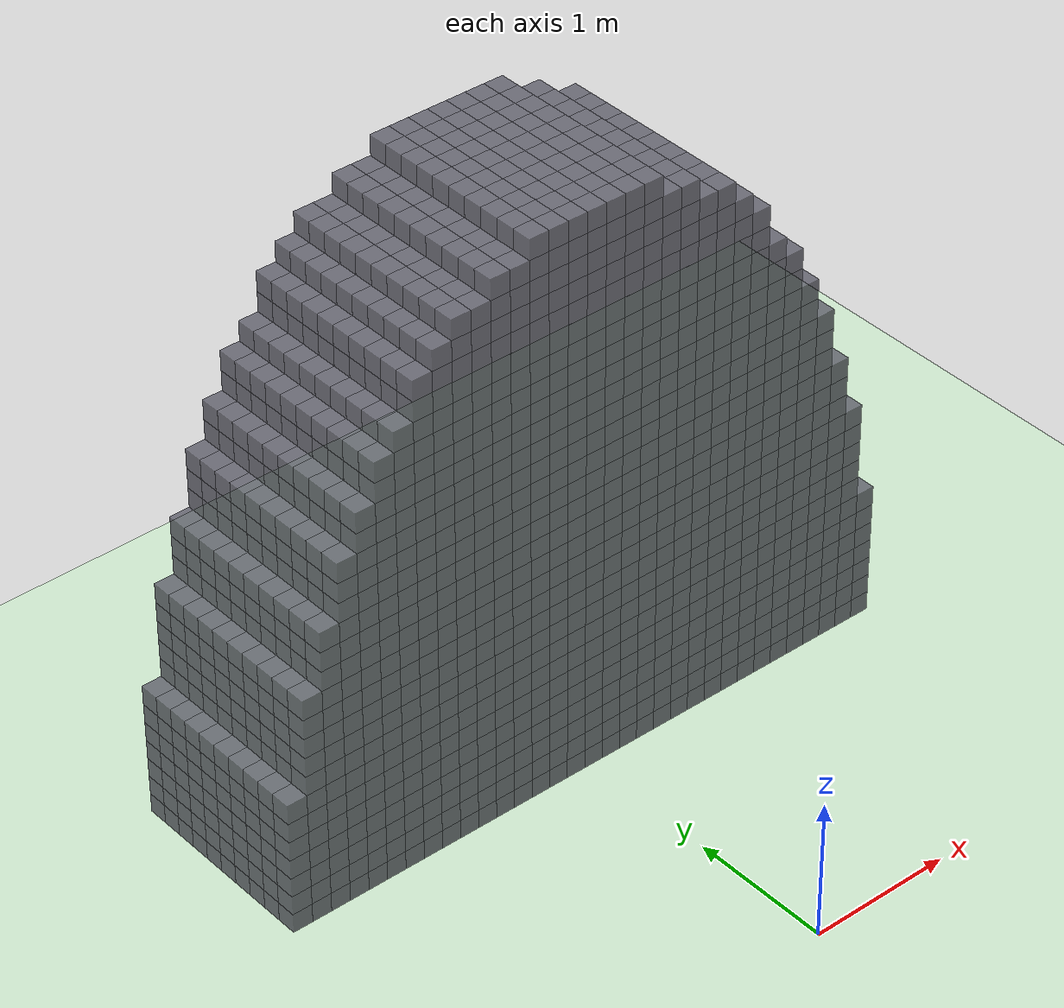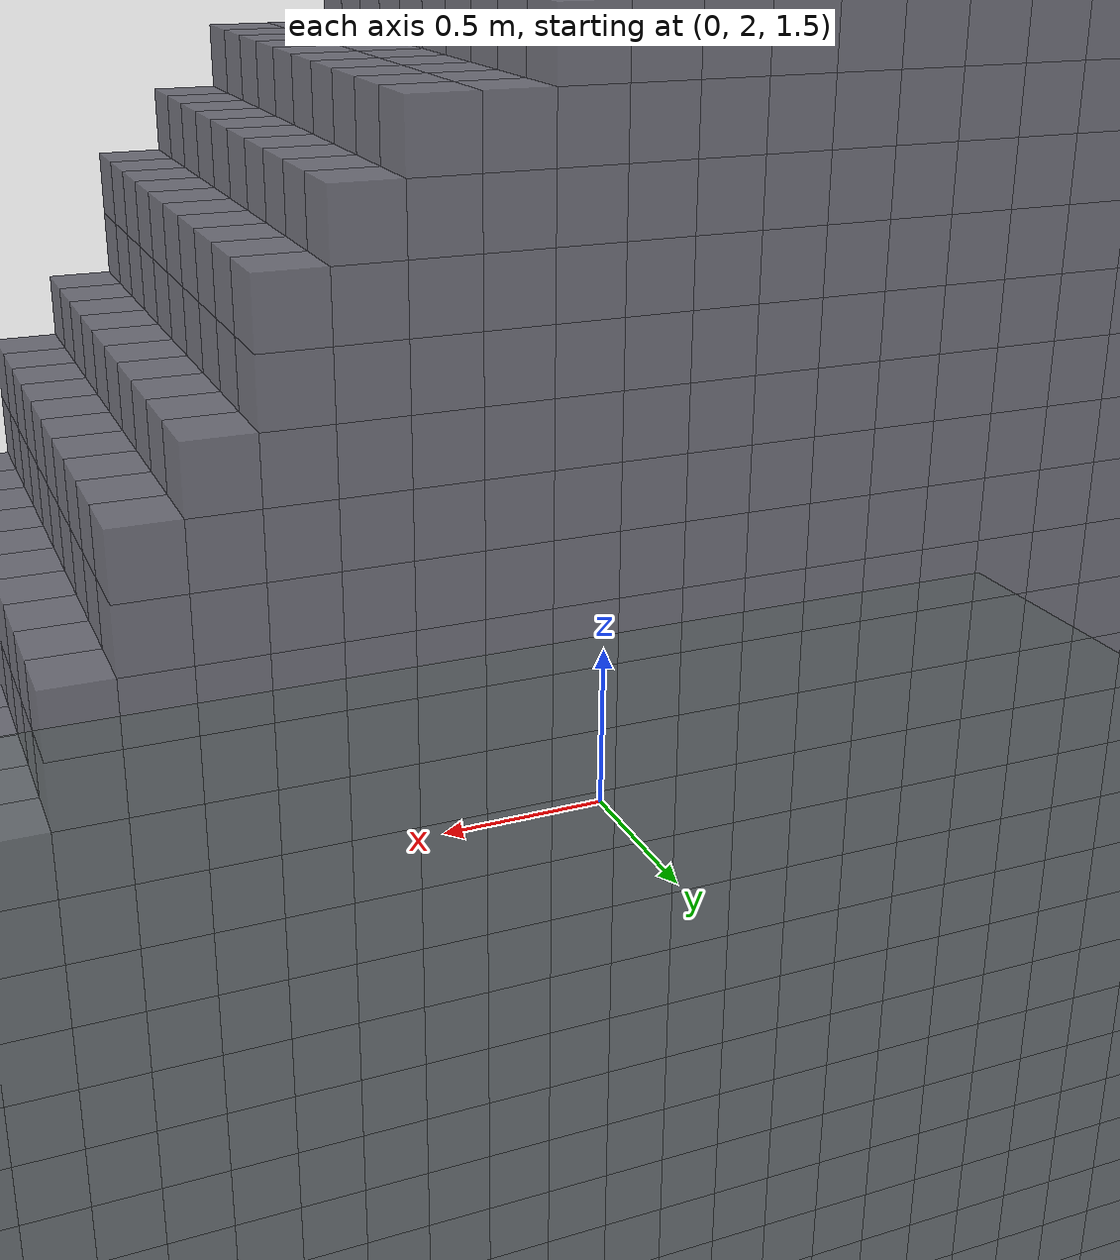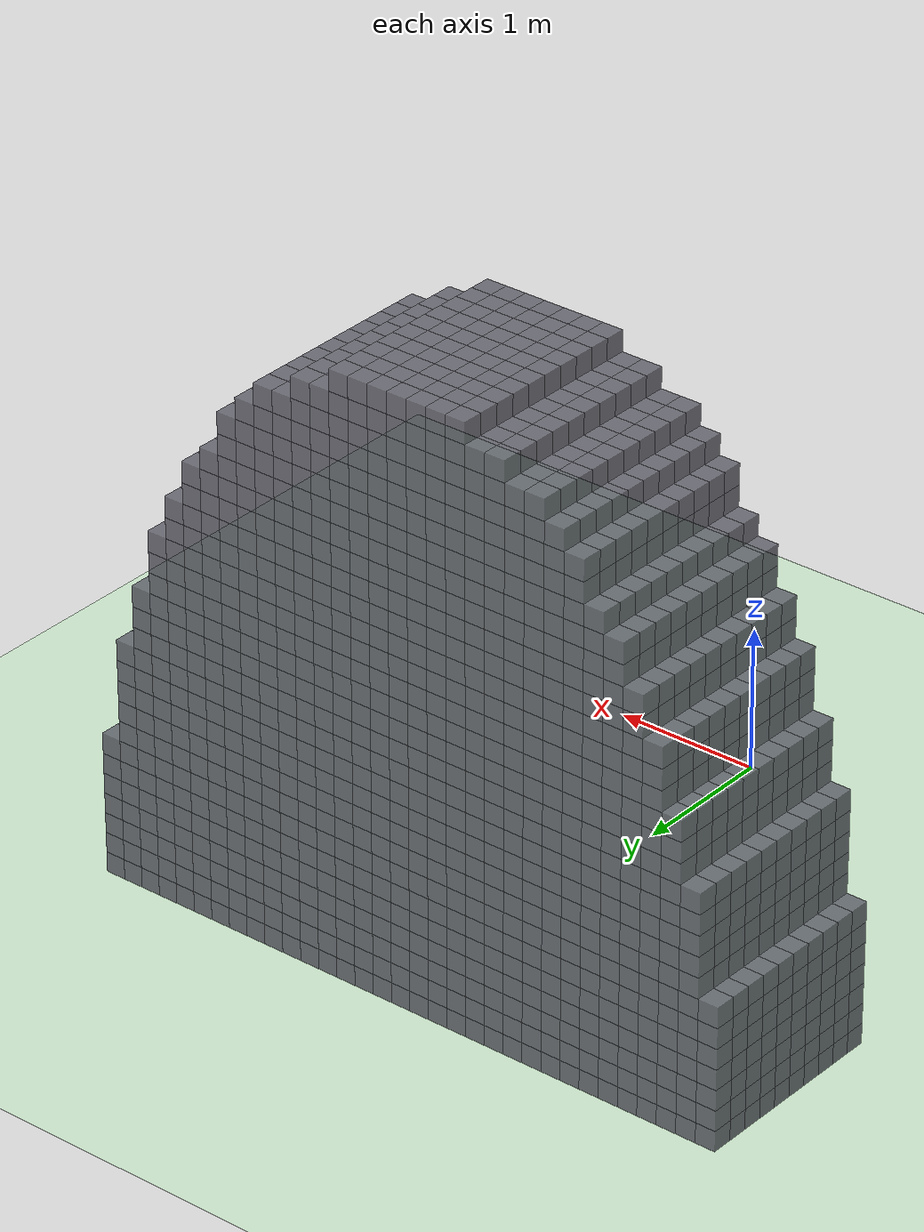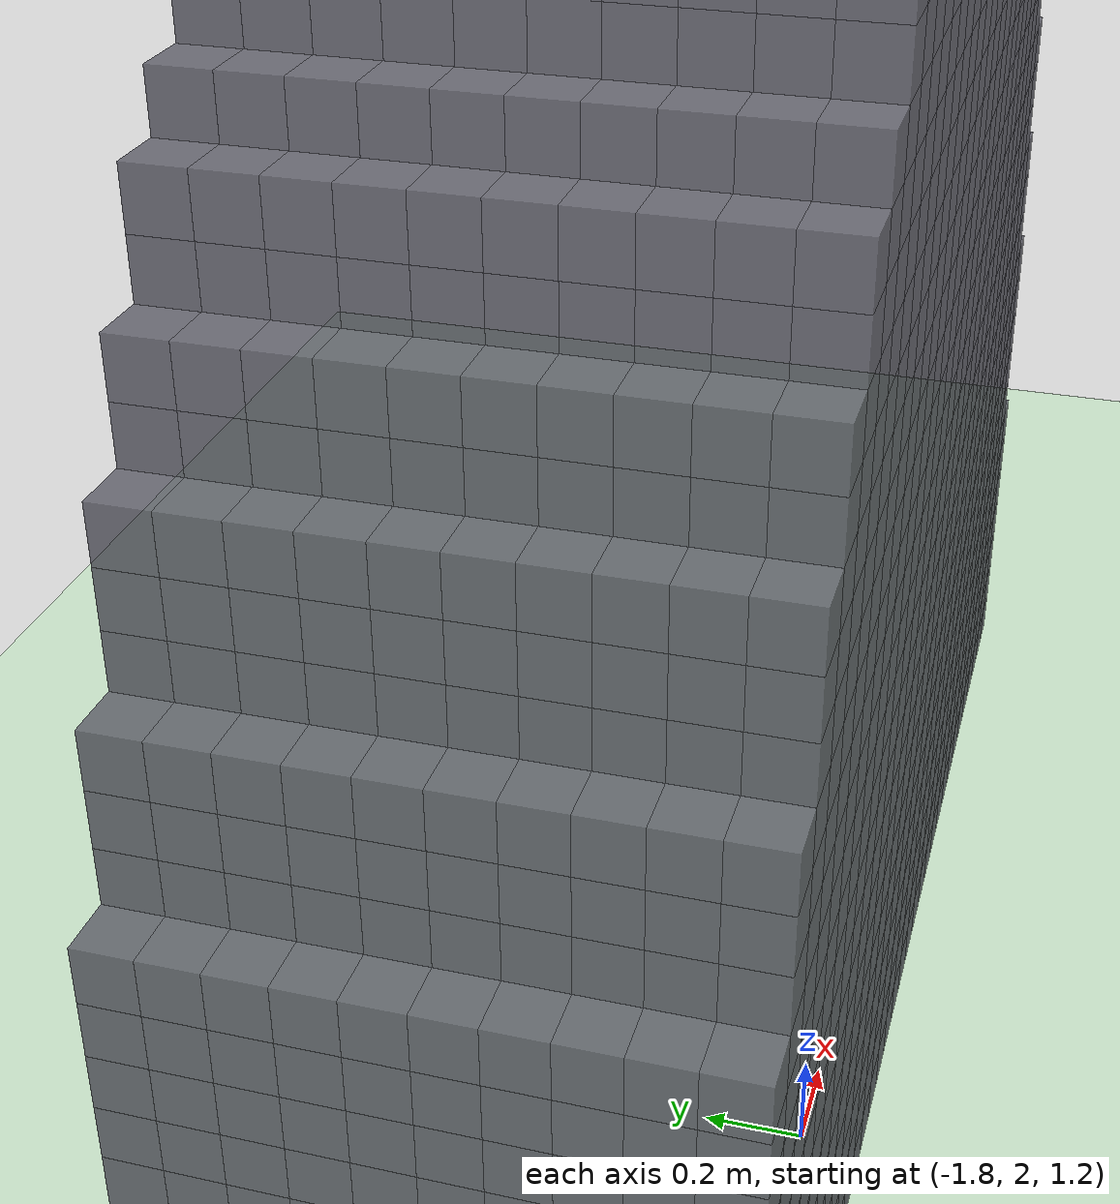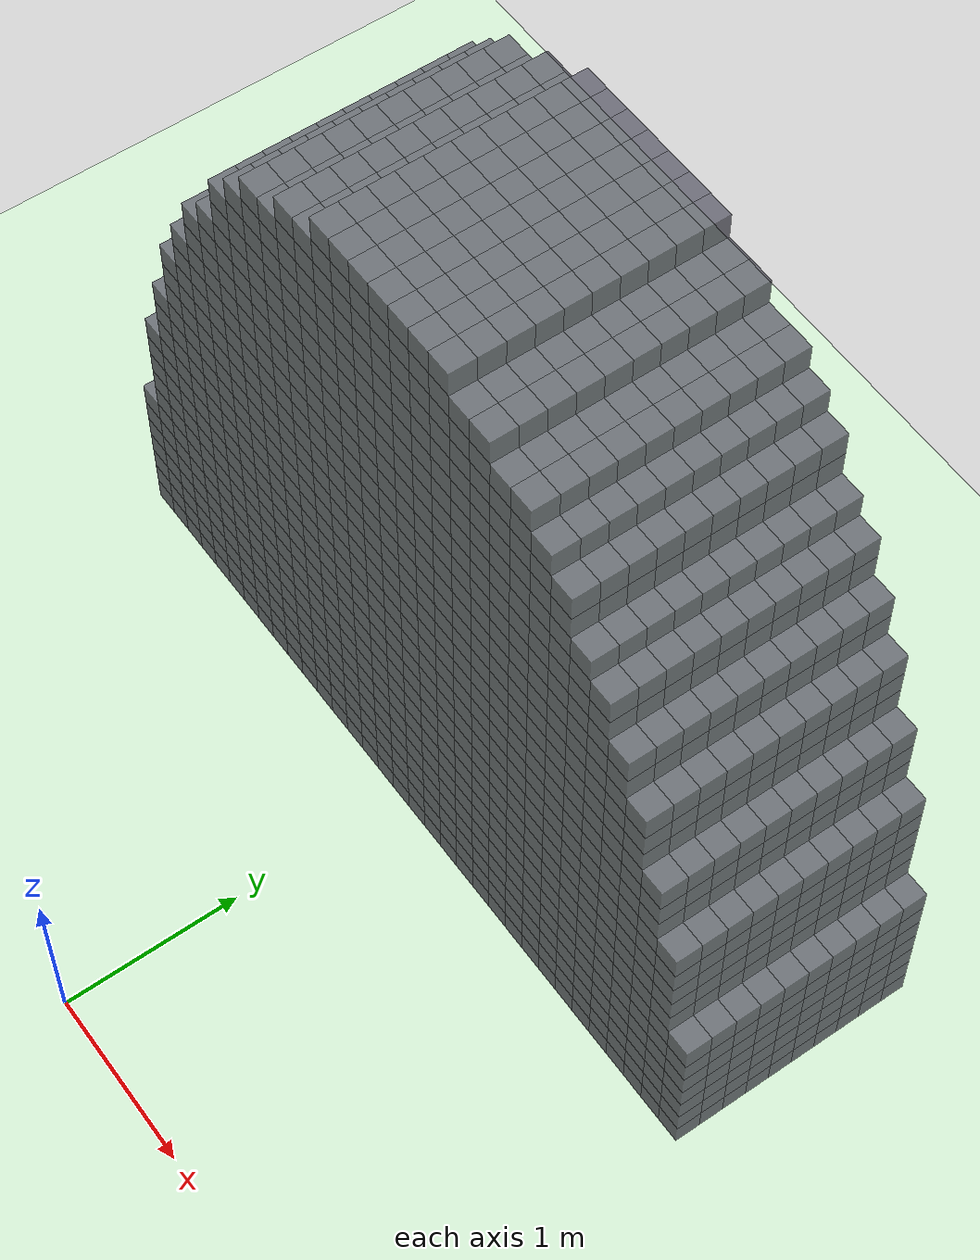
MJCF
<mujoco model="digging_tunnel_ellipse_4m">
  <size memory="4096M"/>
  <statistic extent="8" center="2 0 2.0"/>
  <option gravity="0 0 -9.81"/>
  <visual>
    <headlight diffuse="0.7 0.7 0.7" ambient="0.4 0.4 0.4" specular="0.1 0.1 0.1"/>
    <map zfar="100"/>
  </visual>
  <worldbody>
    <light pos="0 0 7" dir="0 0 -1" diffuse="0.8 0.8 0.8"/>
    <light pos="3 -3 5" dir="0 1 -0.5" diffuse="0.5 0.5 0.5"/>
    <geom name="floor" type="plane" size="10 10 0.1" rgba="0.8 0.9 0.8 1"/>
    <body name="voxel_target" euler="0 0 90">
      <body name="vx_0_0_-16" pos="2.070 -2.240 0.070">
        <geom type="box" size="0.07 0.07 0.07" rgba="0.35 0.35 0.4 0.8" contype="0" conaffinity="0"/>
      </body>
      <body name="vx_0_0_-15" pos="2.070 -2.100 0.070">
        <geom type="box" size="0.07 0.07 0.07" rgba="0.35 0.35 0.4 0.8" contype="0" conaffinity="0"/>
      </body>
      <body name="vx_0_0_-14" pos="2.070 -1.960 0.070">
        <geom type="box" size="0.07 0.07 0.07" rgba="0.35 0.35 0.4 0.8" contype="0" conaffinity="0"/>
      </body>
      <body name="vx_0_0_-13" pos="2.070 -1.820 0.070">
        <geom type="box" size="0.07 0.07 0.07" rgba="0.35 0.35 0.4 0.8" contype="0" conaffinity="0"/>
      </body>
      <body name="vx_0_0_-12" pos="2.070 -1.680 0.070">
        <geom type="box" size="0.07 0.07 0.07" rgba="0.35 0.35 0.4 0.8" contype="0" conaffinity="0"/>
      </body>
      <body name="vx_0_0_-11" pos="2.070 -1.540 0.070">
        <geom type="box" size="0.07 0.07 0.07" rgba="0.35 0.35 0.4 0.8" contype="0" conaffinity="0"/>
      </body>
      <body name="vx_0_0_-10" pos="2.070 -1.400 0.070">
        <geom type="box" size="0.07 0.07 0.07" rgba="0.35 0.35 0.4 0.8" contype="0" conaffinity="0"/>
      </body>
      <body name="vx_0_0_-9" pos="2.070 -1.260 0.070">
        <geom type="box" size="0.07 0.07 0.07" rgba="0.35 0.35 0.4 0.8" contype="0" conaffinity="0"/>
      </body>
      <body name="vx_0_0_-8" pos="2.070 -1.120 0.070">
        <geom type="box" size="0.07 0.07 0.07" rgba="0.35 0.35 0.4 0.8" contype="0" conaffinity="0"/>
      </body>
      <body name="vx_0_0_-7" pos="2.070 -0.980 0.070">
        <geom type="box" size="0.07 0.07 0.07" rgba="0.35 0.35 0.4 0.8" contype="0" conaffinity="0"/>
      </body>
      <body name="vx_0_0_-6" pos="2.070 -0.840 0.070">
        <geom type="box" size="0.07 0.07 0.07" rgba="0.35 0.35 0.4 0.8" contype="0" conaffinity="0"/>
      </body>
      <body name="vx_0_0_-5" pos="2.070 -0.700 0.070">
        <geom type="box" size="0.07 0.07 0.07" rgba="0.35 0.35 0.4 0.8" contype="0" conaffinity="0"/>
      </body>
      <body name="vx_0_0_-4" pos="2.070 -0.560 0.070">
        <geom type="box" size="0.07 0.07 0.07" rgba="0.35 0.35 0.4 0.8" contype="0" conaffinity="0"/>
      </body>
      <body name="vx_0_0_-3" pos="2.070 -0.420 0.070">
        <geom type="box" size="0.07 0.07 0.07" rgba="0.35 0.35 0.4 0.8" contype="0" conaffinity="0"/>
      </body>
      <body name="vx_0_0_-2" pos="2.070 -0.280 0.070">
        <geom type="box" size="0.07 0.07 0.07" rgba="0.35 0.35 0.4 0.8" contype="0" conaffinity="0"/>
      </body>
      <body name="vx_0_0_-1" pos="2.070 -0.140 0.070">
        <geom type="box" size="0.07 0.07 0.07" rgba="0.35 0.35 0.4 0.8" contype="0" conaffinity="0"/>
      </body>
      <body name="vx_0_0_0" pos="2.070 0.000 0.070">
        <geom type="box" size="0.07 0.07 0.07" rgba="0.35 0.35 0.4 0.8" contype="0" conaffinity="0"/>
      </body>
      <body name="vx_0_0_1" pos="2.070 0.140 0.070">
        <geom type="box" size="0.07 0.07 0.07" rgba="0.35 0.35 0.4 0.8" contype="0" conaffinity="0"/>
      </body>
      <body name="vx_0_0_2" pos="2.070 0.280 0.070">
        <geom type="box" size="0.07 0.07 0.07" rgba="0.35 0.35 0.4 0.8" contype="0" conaffinity="0"/>
      </body>
      <body name="vx_0_0_3" pos="2.070 0.420 0.070">
        <geom type="box" size="0.07 0.07 0.07" rgba="0.35 0.35 0.4 0.8" contype="0" conaffinity="0"/>
      </body>
      <body name="vx_0_0_4" pos="2.070 0.560 0.070">
        <geom type="box" size="0.07 0.07 0.07" rgba="0.35 0.35 0.4 0.8" contype="0" conaffinity="0"/>
      </body>
      <body name="vx_0_0_5" pos="2.070 0.700 0.070">
        <geom type="box" size="0.07 0.07 0.07" rgba="0.35 0.35 0.4 0.8" contype="0" conaffinity="0"/>
      </body>
      <body name="vx_0_0_6" pos="2.070 0.840 0.070">
        <geom type="box" size="0.07 0.07 0.07" rgba="0.35 0.35 0.4 0.8" contype="0" conaffinity="0"/>
      </body>
      <body name="vx_0_0_7" pos="2.070 0.980 0.070">
        <geom type="box" size="0.07 0.07 0.07" rgba="0.35 0.35 0.4 0.8" contype="0" conaffinity="0"/>
      </body>
      <body name="vx_0_0_8" pos="2.070 1.120 0.070">
        <geom type="box" size="0.07 0.07 0.07" rgba="0.35 0.35 0.4 0.8" contype="0" conaffinity="0"/>
      </body>
      <body name="vx_0_0_9" pos="2.070 1.260 0.070">
        <geom type="box" size="0.07 0.07 0.07" rgba="0.35 0.35 0.4 0.8" contype="0" conaffinity="0"/>
      </body>
      <body name="vx_0_0_10" pos="2.070 1.400 0.070">
        <geom type="box" size="0.07 0.07 0.07" rgba="0.35 0.35 0.4 0.8" contype="0" conaffinity="0"/>
      </body>
      <body name="vx_0_0_11" pos="2.070 1.540 0.070">
        <geom type="box" size="0.07 0.07 0.07" rgba="0.35 0.35 0.4 0.8" contype="0" conaffinity="0"/>
      </body>
      <body name="vx_0_0_12" pos="2.070 1.680 0.070">
        <geom type="box" size="0.07 0.07 0.07" rgba="0.35 0.35 0.4 0.8" contype="0" conaffinity="0"/>
      </body>
      <body name="vx_0_0_13" pos="2.070 1.820 0.070">
        <geom type="box" size="0.07 0.07 0.07" rgba="0.35 0.35 0.4 0.8" contype="0" conaffinity="0"/>
      </body>
      <body name="vx_0_0_14" pos="2.070 1.960 0.070">
        <geom type="box" size="0.07 0.07 0.07" rgba="0.35 0.35 0.4 0.8" contype="0" conaffinity="0"/>
      </body>
      <body name="vx_0_0_15" pos="2.070 2.100 0.070">
        <geom type="box" size="0.07 0.07 0.07" rgba="0.35 0.35 0.4 0.8" contype="0" conaffinity="0"/>
      </body>
      <body name="vx_0_0_16" pos="2.070 2.240 0.070">
        <geom type="box" size="0.07 0.07 0.07" rgba="0.35 0.35 0.4 0.8" contype="0" conaffinity="0"/>
      </body>
      <body name="vx_0_1_-16" pos="2.070 -2.240 0.210">
        <geom type="box" size="0.07 0.07 0.07" rgba="0.35 0.35 0.4 0.8" contype="0" conaffinity="0"/>
      </body>
      <body name="vx_0_1_-15" pos="2.070 -2.100 0.210">
        <geom type="box" size="0.07 0.07 0.07" rgba="0.35 0.35 0.4 0.8" contype="0" conaffinity="0"/>
      </body>
      <body name="vx_0_1_-14" pos="2.070 -1.960 0.210">
        <geom type="box" size="0.07 0.07 0.07" rgba="0.35 0.35 0.4 0.8" contype="0" conaffinity="0"/>
      </body>
      <body name="vx_0_1_-13" pos="2.070 -1.820 0.210">
        <geom type="box" size="0.07 0.07 0.07" rgba="0.35 0.35 0.4 0.8" contype="0" conaffinity="0"/>
      </body>
      <body name="vx_0_1_-12" pos="2.070 -1.680 0.210">
        <geom type="box" size="0.07 0.07 0.07" rgba="0.35 0.35 0.4 0.8" contype="0" conaffinity="0"/>
      </body>
      <body name="vx_0_1_-11" pos="2.070 -1.540 0.210">
        <geom type="box" size="0.07 0.07 0.07" rgba="0.35 0.35 0.4 0.8" contype="0" conaffinity="0"/>
      </body>
      <body name="vx_0_1_-10" pos="2.070 -1.400 0.210">
        <geom type="box" size="0.07 0.07 0.07" rgba="0.35 0.35 0.4 0.8" contype="0" conaffinity="0"/>
      </body>
      <body name="vx_0_1_-9" pos="2.070 -1.260 0.210">
        <geom type="box" size="0.07 0.07 0.07" rgba="0.35 0.35 0.4 0.8" contype="0" conaffinity="0"/>
      </body>
      <body name="vx_0_1_-8" pos="2.070 -1.120 0.210">
        <geom type="box" size="0.07 0.07 0.07" rgba="0.35 0.35 0.4 0.8" contype="0" conaffinity="0"/>
      </body>
      <body name="vx_0_1_-7" pos="2.070 -0.980 0.210">
        <geom type="box" size="0.07 0.07 0.07" rgba="0.35 0.35 0.4 0.8" contype="0" conaffinity="0"/>
      </body>
      <body name="vx_0_1_-6" pos="2.070 -0.840 0.210">
        <geom type="box" size="0.07 0.07 0.07" rgba="0.35 0.35 0.4 0.8" contype="0" conaffinity="0"/>
      </body>
      <body name="vx_0_1_-5" pos="2.070 -0.700 0.210">
        <geom type="box" size="0.07 0.07 0.07" rgba="0.35 0.35 0.4 0.8" contype="0" conaffinity="0"/>
      </body>
      <body name="vx_0_1_-4" pos="2.070 -0.560 0.210">
        <geom type="box" size="0.07 0.07 0.07" rgba="0.35 0.35 0.4 0.8" contype="0" conaffinity="0"/>
      </body>
      <body name="vx_0_1_-3" pos="2.070 -0.420 0.210">
        <geom type="box" size="0.07 0.07 0.07" rgba="0.35 0.35 0.4 0.8" contype="0" conaffinity="0"/>
      </body>
      <body name="vx_0_1_-2" pos="2.070 -0.280 0.210">
        <geom type="box" size="0.07 0.07 0.07" rgba="0.35 0.35 0.4 0.8" contype="0" conaffinity="0"/>
      </body>
      <body name="vx_0_1_-1" pos="2.070 -0.140 0.210">
        <geom type="box" size="0.07 0.07 0.07" rgba="0.35 0.35 0.4 0.8" contype="0" conaffinity="0"/>
      </body>
      <body name="vx_0_1_0" pos="2.070 0.000 0.210">
        <geom type="box" size="0.07 0.07 0.07" rgba="0.35 0.35 0.4 0.8" contype="0" conaffinity="0"/>
      </body>
      <body name="vx_0_1_1" pos="2.070 0.140 0.210">
        <geom type="box" size="0.07 0.07 0.07" rgba="0.35 0.35 0.4 0.8" contype="0" conaffinity="0"/>
      </body>
      <body name="vx_0_1_2" pos="2.070 0.280 0.210">
        <geom type="box" size="0.07 0.07 0.07" rgba="0.35 0.35 0.4 0.8" contype="0" conaffinity="0"/>
      </body>
      <body name="vx_0_1_3" pos="2.070 0.420 0.210">
        <geom type="box" size="0.07 0.07 0.07" rgba="0.35 0.35 0.4 0.8" contype="0" conaffinity="0"/>
      </body>
      <body name="vx_0_1_4" pos="2.070 0.560 0.210">
        <geom type="box" size="0.07 0.07 0.07" rgba="0.35 0.35 0.4 0.8" contype="0" conaffinity="0"/>
      </body>
      <body name="vx_0_1_5" pos="2.070 0.700 0.210">
        <geom type="box" size="0.07 0.07 0.07" rgba="0.35 0.35 0.4 0.8" contype="0" conaffinity="0"/>
      </body>
      <body name="vx_0_1_6" pos="2.070 0.840 0.210">
        <geom type="box" size="0.07 0.07 0.07" rgba="0.35 0.35 0.4 0.8" contype="0" conaffinity="0"/>
      </body>
      <body name="vx_0_1_7" pos="2.070 0.980 0.210">
        <geom type="box" size="0.07 0.07 0.07" rgba="0.35 0.35 0.4 0.8" contype="0" conaffinity="0"/>
      </body>
      <body name="vx_0_1_8" pos="2.070 1.120 0.210">
        <geom type="box" size="0.07 0.07 0.07" rgba="0.35 0.35 0.4 0.8" contype="0" conaffinity="0"/>
      </body>
      <body name="vx_0_1_9" pos="2.070 1.260 0.210">
        <geom type="box" size="0.07 0.07 0.07" rgba="0.35 0.35 0.4 0.8" contype="0" conaffinity="0"/>
      </body>
      <body name="vx_0_1_10" pos="2.070 1.400 0.210">
        <geom type="box" size="0.07 0.07 0.07" rgba="0.35 0.35 0.4 0.8" contype="0" conaffinity="0"/>
      </body>
      <body name="vx_0_1_11" pos="2.070 1.540 0.210">
        <geom type="box" size="0.07 0.07 0.07" rgba="0.35 0.35 0.4 0.8" contype="0" conaffinity="0"/>
      </body>
      <body name="vx_0_1_12" pos="2.070 1.680 0.210">
        <geom type="box" size="0.07 0.07 0.07" rgba="0.35 0.35 0.4 0.8" contype="0" conaffinity="0"/>
      </body>
      <body name="vx_0_1_13" pos="2.070 1.820 0.210">
        <geom type="box" size="0.07 0.07 0.07" rgba="0.35 0.35 0.4 0.8" contype="0" conaffinity="0"/>
      </body>
      <body name="vx_0_1_14" pos="2.070 1.960 0.210">
        <geom type="box" size="0.07 0.07 0.07" rgba="0.35 0.35 0.4 0.8" contype="0" conaffinity="0"/>
      </body>
      <body name="vx_0_1_15" pos="2.070 2.100 0.210">
        <geom type="box" size="0.07 0.07 0.07" rgba="0.35 0.35 0.4 0.8" contype="0" conaffinity="0"/>
      </body>
      <body name="vx_0_1_16" pos="2.070 2.240 0.210">
        <geom type="box" size="0.07 0.07 0.07" rgba="0.35 0.35 0.4 0.8" contype="0" conaffinity="0"/>
      </body>
      <body name="vx_0_2_-16" pos="2.070 -2.240 0.350">
        <geom type="box" size="0.07 0.07 0.07" rgba="0.35 0.35 0.4 0.8" contype="0" conaffinity="0"/>
      </body>
      <body name="vx_0_2_-15" pos="2.070 -2.100 0.350">
        <geom type="box" size="0.07 0.07 0.07" rgba="0.35 0.35 0.4 0.8" contype="0" conaffinity="0"/>
      </body>
      <body name="vx_0_2_-14" pos="2.070 -1.960 0.350">
        <geom type="box" size="0.07 0.07 0.07" rgba="0.35 0.35 0.4 0.8" contype="0" conaffinity="0"/>
      </body>
      <body name="vx_0_2_-13" pos="2.070 -1.820 0.350">
        <geom type="box" size="0.07 0.07 0.07" rgba="0.35 0.35 0.4 0.8" contype="0" conaffinity="0"/>
      </body>
      <body name="vx_0_2_-12" pos="2.070 -1.680 0.350">
        <geom type="box" size="0.07 0.07 0.07" rgba="0.35 0.35 0.4 0.8" contype="0" conaffinity="0"/>
      </body>
      <body name="vx_0_2_-11" pos="2.070 -1.540 0.350">
        <geom type="box" size="0.07 0.07 0.07" rgba="0.35 0.35 0.4 0.8" contype="0" conaffinity="0"/>
      </body>
      <body name="vx_0_2_-10" pos="2.070 -1.400 0.350">
        <geom type="box" size="0.07 0.07 0.07" rgba="0.35 0.35 0.4 0.8" contype="0" conaffinity="0"/>
      </body>
      <body name="vx_0_2_-9" pos="2.070 -1.260 0.350">
        <geom type="box" size="0.07 0.07 0.07" rgba="0.35 0.35 0.4 0.8" contype="0" conaffinity="0"/>
      </body>
      <body name="vx_0_2_-8" pos="2.070 -1.120 0.350">
        <geom type="box" size="0.07 0.07 0.07" rgba="0.35 0.35 0.4 0.8" contype="0" conaffinity="0"/>
      </body>
      <body name="vx_0_2_-7" pos="2.070 -0.980 0.350">
        <geom type="box" size="0.07 0.07 0.07" rgba="0.35 0.35 0.4 0.8" contype="0" conaffinity="0"/>
      </body>
      <body name="vx_0_2_-6" pos="2.070 -0.840 0.350">
        <geom type="box" size="0.07 0.07 0.07" rgba="0.35 0.35 0.4 0.8" contype="0" conaffinity="0"/>
      </body>
      <body name="vx_0_2_-5" pos="2.070 -0.700 0.350">
        <geom type="box" size="0.07 0.07 0.07" rgba="0.35 0.35 0.4 0.8" contype="0" conaffinity="0"/>
      </body>
      <body name="vx_0_2_-4" pos="2.070 -0.560 0.350">
        <geom type="box" size="0.07 0.07 0.07" rgba="0.35 0.35 0.4 0.8" contype="0" conaffinity="0"/>
      </body>
      <body name="vx_0_2_-3" pos="2.070 -0.420 0.350">
        <geom type="box" size="0.07 0.07 0.07" rgba="0.35 0.35 0.4 0.8" contype="0" conaffinity="0"/>
      </body>
      <body name="vx_0_2_-2" pos="2.070 -0.280 0.350">
        <geom type="box" size="0.07 0.07 0.07" rgba="0.35 0.35 0.4 0.8" contype="0" conaffinity="0"/>
      </body>
      <body name="vx_0_2_-1" pos="2.070 -0.140 0.350">
        <geom type="box" size="0.07 0.07 0.07" rgba="0.35 0.35 0.4 0.8" contype="0" conaffinity="0"/>
      </body>
      <body name="vx_0_2_0" pos="2.070 0.000 0.350">
        <geom type="box" size="0.07 0.07 0.07" rgba="0.35 0.35 0.4 0.8" contype="0" conaffinity="0"/>
      </body>
      <body name="vx_0_2_1" pos="2.070 0.140 0.350">
        <geom type="box" size="0.07 0.07 0.07" rgba="0.35 0.35 0.4 0.8" contype="0" conaffinity="0"/>
      </body>
      <body name="vx_0_2_2" pos="2.070 0.280 0.350">
        <geom type="box" size="0.07 0.07 0.07" rgba="0.35 0.35 0.4 0.8" contype="0" conaffinity="0"/>
      </body>
      <body name="vx_0_2_3" pos="2.070 0.420 0.350">
        <geom type="box" size="0.07 0.07 0.07" rgba="0.35 0.35 0.4 0.8" contype="0" conaffinity="0"/>
      </body>
      <body name="vx_0_2_4" pos="2.070 0.560 0.350">
        <geom type="box" size="0.07 0.07 0.07" rgba="0.35 0.35 0.4 0.8" contype="0" conaffinity="0"/>
      </body>
      <body name="vx_0_2_5" pos="2.070 0.700 0.350">
        <geom type="box" size="0.07 0.07 0.07" rgba="0.35 0.35 0.4 0.8" contype="0" conaffinity="0"/>
      </body>
      <body name="vx_0_2_6" pos="2.070 0.840 0.350">
        <geom type="box" size="0.07 0.07 0.07" rgba="0.35 0.35 0.4 0.8" contype="0" conaffinity="0"/>
      </body>
      <body name="vx_0_2_7" pos="2.070 0.980 0.350">
        <geom type="box" size="0.07 0.07 0.07" rgba="0.35 0.35 0.4 0.8" contype="0" conaffinity="0"/>
      </body>
      <body name="vx_0_2_8" pos="2.070 1.120 0.350">
        <geom type="box" size="0.07 0.07 0.07" rgba="0.35 0.35 0.4 0.8" contype="0" conaffinity="0"/>
      </body>
      <body name="vx_0_2_9" pos="2.070 1.260 0.350">
        <geom type="box" size="0.07 0.07 0.07" rgba="0.35 0.35 0.4 0.8" contype="0" conaffinity="0"/>
      </body>
      <body name="vx_0_2_10" pos="2.070 1.400 0.350">
        <geom type="box" size="0.07 0.07 0.07" rgba="0.35 0.35 0.4 0.8" contype="0" conaffinity="0"/>
      </body>
      <body name="vx_0_2_11" pos="2.070 1.540 0.350">
        <geom type="box" size="0.07 0.07 0.07" rgba="0.35 0.35 0.4 0.8" contype="0" conaffinity="0"/>
      </body>
      <body name="vx_0_2_12" pos="2.070 1.680 0.350">
        <geom type="box" size="0.07 0.07 0.07" rgba="0.35 0.35 0.4 0.8" contype="0" conaffinity="0"/>
      </body>
      <body name="vx_0_2_13" pos="2.070 1.820 0.350">
        <geom type="box" size="0.07 0.07 0.07" rgba="0.35 0.35 0.4 0.8" contype="0" conaffinity="0"/>
      </body>
      <body name="vx_0_2_14" pos="2.070 1.960 0.350">
        <geom type="box" size="0.07 0.07 0.07" rgba="0.35 0.35 0.4 0.8" contype="0" conaffinity="0"/>
      </body>
      <body name="vx_0_2_15" pos="2.070 2.100 0.350">
        <geom type="box" size="0.07 0.07 0.07" rgba="0.35 0.35 0.4 0.8" contype="0" conaffinity="0"/>
      </body>
      <body name="vx_0_2_16" pos="2.070 2.240 0.350">
        <geom type="box" size="0.07 0.07 0.07" rgba="0.35 0.35 0.4 0.8" contype="0" conaffinity="0"/>
      </body>
      <body name="vx_0_3_-16" pos="2.070 -2.240 0.490">
        <geom type="box" size="0.07 0.07 0.07" rgba="0.35 0.35 0.4 0.8" contype="0" conaffinity="0"/>
      </body>
      <body name="vx_0_3_-15" pos="2.070 -2.100 0.490">
        <geom type="box" size="0.07 0.07 0.07" rgba="0.35 0.35 0.4 0.8" contype="0" conaffinity="0"/>
      </body>
      <body name="vx_0_3_-14" pos="2.070 -1.960 0.490">
        <geom type="box" size="0.07 0.07 0.07" rgba="0.35 0.35 0.4 0.8" contype="0" conaffinity="0"/>
      </body>
      <body name="vx_0_3_-13" pos="2.070 -1.820 0.490">
        <geom type="box" size="0.07 0.07 0.07" rgba="0.35 0.35 0.4 0.8" contype="0" conaffinity="0"/>
      </body>
      <body name="vx_0_3_-12" pos="2.070 -1.680 0.490">
        <geom type="box" size="0.07 0.07 0.07" rgba="0.35 0.35 0.4 0.8" contype="0" conaffinity="0"/>
      </body>
      <body name="vx_0_3_-11" pos="2.070 -1.540 0.490">
        <geom type="box" size="0.07 0.07 0.07" rgba="0.35 0.35 0.4 0.8" contype="0" conaffinity="0"/>
      </body>
      <body name="vx_0_3_-10" pos="2.070 -1.400 0.490">
        <geom type="box" size="0.07 0.07 0.07" rgba="0.35 0.35 0.4 0.8" contype="0" conaffinity="0"/>
      </body>
      <body name="vx_0_3_-9" pos="2.070 -1.260 0.490">
        <geom type="box" size="0.07 0.07 0.07" rgba="0.35 0.35 0.4 0.8" contype="0" conaffinity="0"/>
      </body>
      <body name="vx_0_3_-8" pos="2.070 -1.120 0.490">
        <geom type="box" size="0.07 0.07 0.07" rgba="0.35 0.35 0.4 0.8" contype="0" conaffinity="0"/>
      </body>
      <body name="vx_0_3_-7" pos="2.070 -0.980 0.490">
        <geom type="box" size="0.07 0.07 0.07" rgba="0.35 0.35 0.4 0.8" contype="0" conaffinity="0"/>
      </body>
      <body name="vx_0_3_-6" pos="2.070 -0.840 0.490">
        <geom type="box" size="0.07 0.07 0.07" rgba="0.35 0.35 0.4 0.8" contype="0" conaffinity="0"/>
      </body>
      <body name="vx_0_3_-5" pos="2.070 -0.700 0.490">
        <geom type="box" size="0.07 0.07 0.07" rgba="0.35 0.35 0.4 0.8" contype="0" conaffinity="0"/>
      </body>
      <body name="vx_0_3_-4" pos="2.070 -0.560 0.490">
        <geom type="box" size="0.07 0.07 0.07" rgba="0.35 0.35 0.4 0.8" contype="0" conaffinity="0"/>
      </body>
      <body name="vx_0_3_-3" pos="2.070 -0.420 0.490">
        <geom type="box" size="0.07 0.07 0.07" rgba="0.35 0.35 0.4 0.8" contype="0" conaffinity="0"/>
      </body>
      <body name="vx_0_3_-2" pos="2.070 -0.280 0.490">
        <geom type="box" size="0.07 0.07 0.07" rgba="0.35 0.35 0.4 0.8" contype="0" conaffinity="0"/>
      </body>
      <body name="vx_0_3_-1" pos="2.070 -0.140 0.490">
        <geom type="box" size="0.07 0.07 0.07" rgba="0.35 0.35 0.4 0.8" contype="0" conaffinity="0"/>
      </body>
      <body name="vx_0_3_0" pos="2.070 0.000 0.490">
        <geom type="box" size="0.07 0.07 0.07" rgba="0.35 0.35 0.4 0.8" contype="0" conaffinity="0"/>
      </body>
      <body name="vx_0_3_1" pos="2.070 0.140 0.490">
        <geom type="box" size="0.07 0.07 0.07" rgba="0.35 0.35 0.4 0.8" contype="0" conaffinity="0"/>
      </body>
      <body name="vx_0_3_2" pos="2.070 0.280 0.490">
        <geom type="box" size="0.07 0.07 0.07" rgba="0.35 0.35 0.4 0.8" contype="0" conaffinity="0"/>
      </body>
      <body name="vx_0_3_3" pos="2.070 0.420 0.490">
        <geom type="box" size="0.07 0.07 0.07" rgba="0.35 0.35 0.4 0.8" contype="0" conaffinity="0"/>
      </body>
      <body name="vx_0_3_4" pos="2.070 0.560 0.490">
        <geom type="box" size="0.07 0.07 0.07" rgba="0.35 0.35 0.4 0.8" contype="0" conaffinity="0"/>
      </body>
      <body name="vx_0_3_5" pos="2.070 0.700 0.490">
        <geom type="box" size="0.07 0.07 0.07" rgba="0.35 0.35 0.4 0.8" contype="0" conaffinity="0"/>
      </body>
      <body name="vx_0_3_6" pos="2.070 0.840 0.490">
        <geom type="box" size="0.07 0.07 0.07" rgba="0.35 0.35 0.4 0.8" contype="0" conaffinity="0"/>
      </body>
      <body name="vx_0_3_7" pos="2.070 0.980 0.490">
        <geom type="box" size="0.07 0.07 0.07" rgba="0.35 0.35 0.4 0.8" contype="0" conaffinity="0"/>
      </body>
      <body name="vx_0_3_8" pos="2.070 1.120 0.490">
        <geom type="box" size="0.07 0.07 0.07" rgba="0.35 0.35 0.4 0.8" contype="0" conaffinity="0"/>
      </body>
      <body name="vx_0_3_9" pos="2.070 1.260 0.490">
        <geom type="box" size="0.07 0.07 0.07" rgba="0.35 0.35 0.4 0.8" contype="0" conaffinity="0"/>
      </body>
      <body name="vx_0_3_10" pos="2.070 1.400 0.490">
        <geom type="box" size="0.07 0.07 0.07" rgba="0.35 0.35 0.4 0.8" contype="0" conaffinity="0"/>
      </body>
      <body name="vx_0_3_11" pos="2.070 1.540 0.490">
        <geom type="box" size="0.07 0.07 0.07" rgba="0.35 0.35 0.4 0.8" contype="0" conaffinity="0"/>
      </body>
      <body name="vx_0_3_12" pos="2.070 1.680 0.490">
        <geom type="box" size="0.07 0.07 0.07" rgba="0.35 0.35 0.4 0.8" contype="0" conaffinity="0"/>
      </body>
      <body name="vx_0_3_13" pos="2.070 1.820 0.490">
        <geom type="box" size="0.07 0.07 0.07" rgba="0.35 0.35 0.4 0.8" contype="0" conaffinity="0"/>
      </body>
      <body name="vx_0_3_14" pos="2.070 1.960 0.490">
        <geom type="box" size="0.07 0.07 0.07" rgba="0.35 0.35 0.4 0.8" contype="0" conaffinity="0"/>
      </body>
      <body name="vx_0_3_15" pos="2.070 2.100 0.490">
        <geom type="box" size="0.07 0.07 0.07" rgba="0.35 0.35 0.4 0.8" contype="0" conaffinity="0"/>
      </body>
      <body name="vx_0_3_16" pos="2.070 2.240 0.490">
        <geom type="box" size="0.07 0.07 0.07" rgba="0.35 0.35 0.4 0.8" contype="0" conaffinity="0"/>
      </body>
      <body name="vx_0_4_-16" pos="2.070 -2.240 0.630">
        <geom type="box" size="0.07 0.07 0.07" rgba="0.35 0.35 0.4 0.8" contype="0" conaffinity="0"/>
      </body>
      <body name="vx_0_4_-15" pos="2.070 -2.100 0.630">
        <geom type="box" size="0.07 0.07 0.07" rgba="0.35 0.35 0.4 0.8" contype="0" conaffinity="0"/>
      </body>
      <body name="vx_0_4_-14" pos="2.070 -1.960 0.630">
        <geom type="box" size="0.07 0.07 0.07" rgba="0.35 0.35 0.4 0.8" contype="0" conaffinity="0"/>
      </body>
      <body name="vx_0_4_-13" pos="2.070 -1.820 0.630">
        <geom type="box" size="0.07 0.07 0.07" rgba="0.35 0.35 0.4 0.8" contype="0" conaffinity="0"/>
      </body>
      <body name="vx_0_4_-12" pos="2.070 -1.680 0.630">
        <geom type="box" size="0.07 0.07 0.07" rgba="0.35 0.35 0.4 0.8" contype="0" conaffinity="0"/>
      </body>
      <body name="vx_0_4_-11" pos="2.070 -1.540 0.630">
        <geom type="box" size="0.07 0.07 0.07" rgba="0.35 0.35 0.4 0.8" contype="0" conaffinity="0"/>
      </body>
      <body name="vx_0_4_-10" pos="2.070 -1.400 0.630">
        <geom type="box" size="0.07 0.07 0.07" rgba="0.35 0.35 0.4 0.8" contype="0" conaffinity="0"/>
      </body>
      <body name="vx_0_4_-9" pos="2.070 -1.260 0.630">
        <geom type="box" size="0.07 0.07 0.07" rgba="0.35 0.35 0.4 0.8" contype="0" conaffinity="0"/>
      </body>
      <body name="vx_0_4_-8" pos="2.070 -1.120 0.630">
        <geom type="box" size="0.07 0.07 0.07" rgba="0.35 0.35 0.4 0.8" contype="0" conaffinity="0"/>
      </body>
      <body name="vx_0_4_-7" pos="2.070 -0.980 0.630">
        <geom type="box" size="0.07 0.07 0.07" rgba="0.35 0.35 0.4 0.8" contype="0" conaffinity="0"/>
      </body>
      <body name="vx_0_4_-6" pos="2.070 -0.840 0.630">
        <geom type="box" size="0.07 0.07 0.07" rgba="0.35 0.35 0.4 0.8" contype="0" conaffinity="0"/>
      </body>
      <body name="vx_0_4_-5" pos="2.070 -0.700 0.630">
        <geom type="box" size="0.07 0.07 0.07" rgba="0.35 0.35 0.4 0.8" contype="0" conaffinity="0"/>
      </body>
      <body name="vx_0_4_-4" pos="2.070 -0.560 0.630">
        <geom type="box" size="0.07 0.07 0.07" rgba="0.35 0.35 0.4 0.8" contype="0" conaffinity="0"/>
      </body>
      <body name="vx_0_4_-3" pos="2.070 -0.420 0.630">
        <geom type="box" size="0.07 0.07 0.07" rgba="0.35 0.35 0.4 0.8" contype="0" conaffinity="0"/>
      </body>
      <body name="vx_0_4_-2" pos="2.070 -0.280 0.630">
        <geom type="box" size="0.07 0.07 0.07" rgba="0.35 0.35 0.4 0.8" contype="0" conaffinity="0"/>
      </body>
      <body name="vx_0_4_-1" pos="2.070 -0.140 0.630">
        <geom type="box" size="0.07 0.07 0.07" rgba="0.35 0.35 0.4 0.8" contype="0" conaffinity="0"/>
      </body>
      <body name="vx_0_4_0" pos="2.070 0.000 0.630">
        <geom type="box" size="0.07 0.07 0.07" rgba="0.35 0.35 0.4 0.8" contype="0" conaffinity="0"/>
      </body>
      <body name="vx_0_4_1" pos="2.070 0.140 0.630">
        <geom type="box" size="0.07 0.07 0.07" rgba="0.35 0.35 0.4 0.8" contype="0" conaffinity="0"/>
      </body>
      <body name="vx_0_4_2" pos="2.070 0.280 0.630">
        <geom type="box" size="0.07 0.07 0.07" rgba="0.35 0.35 0.4 0.8" contype="0" conaffinity="0"/>
      </body>
      <body name="vx_0_4_3" pos="2.070 0.420 0.630">
        <geom type="box" size="0.07 0.07 0.07" rgba="0.35 0.35 0.4 0.8" contype="0" conaffinity="0"/>
      </body>
      <body name="vx_0_4_4" pos="2.070 0.560 0.630">
        <geom type="box" size="0.07 0.07 0.07" rgba="0.35 0.35 0.4 0.8" contype="0" conaffinity="0"/>
      </body>
      <body name="vx_0_4_5" pos="2.070 0.700 0.630">
        <geom type="box" size="0.07 0.07 0.07" rgba="0.35 0.35 0.4 0.8" contype="0" conaffinity="0"/>
      </body>
      <body name="vx_0_4_6" pos="2.070 0.840 0.630">
        <geom type="box" size="0.07 0.07 0.07" rgba="0.35 0.35 0.4 0.8" contype="0" conaffinity="0"/>
      </body>
      <body name="vx_0_4_7" pos="2.070 0.980 0.630">
        <geom type="box" size="0.07 0.07 0.07" rgba="0.35 0.35 0.4 0.8" contype="0" conaffinity="0"/>
      </body>
      <body name="vx_0_4_8" pos="2.070 1.120 0.630">
        <geom type="box" size="0.07 0.07 0.07" rgba="0.35 0.35 0.4 0.8" contype="0" conaffinity="0"/>
      </body>
      <body name="vx_0_4_9" pos="2.070 1.260 0.630">
        <geom type="box" size="0.07 0.07 0.07" rgba="0.35 0.35 0.4 0.8" contype="0" conaffinity="0"/>
      </body>
      <body name="vx_0_4_10" pos="2.070 1.400 0.630">
        <geom type="box" size="0.07 0.07 0.07" rgba="0.35 0.35 0.4 0.8" contype="0" conaffinity="0"/>
      </body>
      <body name="vx_0_4_11" pos="2.070 1.540 0.630">
        <geom type="box" size="0.07 0.07 0.07" rgba="0.35 0.35 0.4 0.8" contype="0" conaffinity="0"/>
      </body>
      <body name="vx_0_4_12" pos="2.070 1.680 0.630">
        <geom type="box" size="0.07 0.07 0.07" rgba="0.35 0.35 0.4 0.8" contype="0" conaffinity="0"/>
      </body>
      <body name="vx_0_4_13" pos="2.070 1.820 0.630">
        <geom type="box" size="0.07 0.07 0.07" rgba="0.35 0.35 0.4 0.8" contype="0" conaffinity="0"/>
      </body>
      <body name="vx_0_4_14" pos="2.070 1.960 0.630">
        <geom type="box" size="0.07 0.07 0.07" rgba="0.35 0.35 0.4 0.8" contype="0" conaffinity="0"/>
      </body>
      <body name="vx_0_4_15" pos="2.070 2.100 0.630">
        <geom type="box" size="0.07 0.07 0.07" rgba="0.35 0.35 0.4 0.8" contype="0" conaffinity="0"/>
      </body>
      <body name="vx_0_4_16" pos="2.070 2.240 0.630">
        <geom type="box" size="0.07 0.07 0.07" rgba="0.35 0.35 0.4 0.8" contype="0" conaffinity="0"/>
      </body>
      <body name="vx_0_5_-16" pos="2.070 -2.240 0.770">
        <geom type="box" size="0.07 0.07 0.07" rgba="0.35 0.35 0.4 0.8" contype="0" conaffinity="0"/>
      </body>
      <body name="vx_0_5_-15" pos="2.070 -2.100 0.770">
        <geom type="box" size="0.07 0.07 0.07" rgba="0.35 0.35 0.4 0.8" contype="0" conaffinity="0"/>
      </body>
      <body name="vx_0_5_-14" pos="2.070 -1.960 0.770">
        <geom type="box" size="0.07 0.07 0.07" rgba="0.35 0.35 0.4 0.8" contype="0" conaffinity="0"/>
      </body>
      <body name="vx_0_5_-13" pos="2.070 -1.820 0.770">
        <geom type="box" size="0.07 0.07 0.07" rgba="0.35 0.35 0.4 0.8" contype="0" conaffinity="0"/>
      </body>
      <body name="vx_0_5_-12" pos="2.070 -1.680 0.770">
        <geom type="box" size="0.07 0.07 0.07" rgba="0.35 0.35 0.4 0.8" contype="0" conaffinity="0"/>
      </body>
      <body name="vx_0_5_-11" pos="2.070 -1.540 0.770">
        <geom type="box" size="0.07 0.07 0.07" rgba="0.35 0.35 0.4 0.8" contype="0" conaffinity="0"/>
      </body>
      <body name="vx_0_5_-10" pos="2.070 -1.400 0.770">
        <geom type="box" size="0.07 0.07 0.07" rgba="0.35 0.35 0.4 0.8" contype="0" conaffinity="0"/>
      </body>
      <body name="vx_0_5_-9" pos="2.070 -1.260 0.770">
        <geom type="box" size="0.07 0.07 0.07" rgba="0.35 0.35 0.4 0.8" contype="0" conaffinity="0"/>
      </body>
      <body name="vx_0_5_-8" pos="2.070 -1.120 0.770">
        <geom type="box" size="0.07 0.07 0.07" rgba="0.35 0.35 0.4 0.8" contype="0" conaffinity="0"/>
      </body>
      <body name="vx_0_5_-7" pos="2.070 -0.980 0.770">
        <geom type="box" size="0.07 0.07 0.07" rgba="0.35 0.35 0.4 0.8" contype="0" conaffinity="0"/>
      </body>
      <body name="vx_0_5_-6" pos="2.070 -0.840 0.770">
        <geom type="box" size="0.07 0.07 0.07" rgba="0.35 0.35 0.4 0.8" contype="0" conaffinity="0"/>
      </body>
      <body name="vx_0_5_-5" pos="2.070 -0.700 0.770">
        <geom type="box" size="0.07 0.07 0.07" rgba="0.35 0.35 0.4 0.8" contype="0" conaffinity="0"/>
      </body>
      <body name="vx_0_5_-4" pos="2.070 -0.560 0.770">
        <geom type="box" size="0.07 0.07 0.07" rgba="0.35 0.35 0.4 0.8" contype="0" conaffinity="0"/>
      </body>
      <body name="vx_0_5_-3" pos="2.070 -0.420 0.770">
        <geom type="box" size="0.07 0.07 0.07" rgba="0.35 0.35 0.4 0.8" contype="0" conaffinity="0"/>
      </body>
      <body name="vx_0_5_-2" pos="2.070 -0.280 0.770">
        <geom type="box" size="0.07 0.07 0.07" rgba="0.35 0.35 0.4 0.8" contype="0" conaffinity="0"/>
      </body>
      <body name="vx_0_5_-1" pos="2.070 -0.140 0.770">
        <geom type="box" size="0.07 0.07 0.07" rgba="0.35 0.35 0.4 0.8" contype="0" conaffinity="0"/>
      </body>
      <body name="vx_0_5_0" pos="2.070 0.000 0.770">
        <geom type="box" size="0.07 0.07 0.07" rgba="0.35 0.35 0.4 0.8" contype="0" conaffinity="0"/>
      </body>
      <body name="vx_0_5_1" pos="2.070 0.140 0.770">
        <geom type="box" size="0.07 0.07 0.07" rgba="0.35 0.35 0.4 0.8" contype="0" conaffinity="0"/>
      </body>
      <body name="vx_0_5_2" pos="2.070 0.280 0.770">
        <geom type="box" size="0.07 0.07 0.07" rgba="0.35 0.35 0.4 0.8" contype="0" conaffinity="0"/>
      </body>
      <body name="vx_0_5_3" pos="2.070 0.420 0.770">
        <geom type="box" size="0.07 0.07 0.07" rgba="0.35 0.35 0.4 0.8" contype="0" conaffinity="0"/>
      </body>
      <body name="vx_0_5_4" pos="2.070 0.560 0.770">
        <geom type="box" size="0.07 0.07 0.07" rgba="0.35 0.35 0.4 0.8" contype="0" conaffinity="0"/>
      </body>
      <body name="vx_0_5_5" pos="2.070 0.700 0.770">
        <geom type="box" size="0.07 0.07 0.07" rgba="0.35 0.35 0.4 0.8" contype="0" conaffinity="0"/>
      </body>
      <body name="vx_0_5_6" pos="2.070 0.840 0.770">
        <geom type="box" size="0.07 0.07 0.07" rgba="0.35 0.35 0.4 0.8" contype="0" conaffinity="0"/>
      </body>
      <body name="vx_0_5_7" pos="2.070 0.980 0.770">
        <geom type="box" size="0.07 0.07 0.07" rgba="0.35 0.35 0.4 0.8" contype="0" conaffinity="0"/>
      </body>
      <body name="vx_0_5_8" pos="2.070 1.120 0.770">
        <geom type="box" size="0.07 0.07 0.07" rgba="0.35 0.35 0.4 0.8" contype="0" conaffinity="0"/>
      </body>
      <body name="vx_0_5_9" pos="2.070 1.260 0.770">
        <geom type="box" size="0.07 0.07 0.07" rgba="0.35 0.35 0.4 0.8" contype="0" conaffinity="0"/>
      </body>
      <body name="vx_0_5_10" pos="2.070 1.400 0.770">
        <geom type="box" size="0.07 0.07 0.07" rgba="0.35 0.35 0.4 0.8" contype="0" conaffinity="0"/>
      </body>
      <body name="vx_0_5_11" pos="2.070 1.540 0.770">
        <geom type="box" size="0.07 0.07 0.07" rgba="0.35 0.35 0.4 0.8" contype="0" conaffinity="0"/>
      </body>
      <body name="vx_0_5_12" pos="2.070 1.680 0.770">
        <geom type="box" size="0.07 0.07 0.07" rgba="0.35 0.35 0.4 0.8" contype="0" conaffinity="0"/>
      </body>
      <body name="vx_0_5_13" pos="2.070 1.820 0.770">
        <geom type="box" size="0.07 0.07 0.07" rgba="0.35 0.35 0.4 0.8" contype="0" conaffinity="0"/>
      </body>
      <body name="vx_0_5_14" pos="2.070 1.960 0.770">
        <geom type="box" size="0.07 0.07 0.07" rgba="0.35 0.35 0.4 0.8" contype="0" conaffinity="0"/>
      </body>
      <body name="vx_0_5_15" pos="2.070 2.100 0.770">
        <geom type="box" size="0.07 0.07 0.07" rgba="0.35 0.35 0.4 0.8" contype="0" conaffinity="0"/>
      </body>
      <body name="vx_0_5_16" pos="2.070 2.240 0.770">
        <geom type="box" size="0.07 0.07 0.07" rgba="0.35 0.35 0.4 0.8" contype="0" conaffinity="0"/>
      </body>
      <body name="vx_0_6_-16" pos="2.070 -2.240 0.910">
        <geom type="box" size="0.07 0.07 0.07" rgba="0.35 0.35 0.4 0.8" contype="0" conaffinity="0"/>
      </body>
      <body name="vx_0_6_-15" pos="2.070 -2.100 0.910">
        <geom type="box" size="0.07 0.07 0.07" rgba="0.35 0.35 0.4 0.8" contype="0" conaffinity="0"/>
      </body>
      <body name="vx_0_6_-14" pos="2.070 -1.960 0.910">
        <geom type="box" size="0.07 0.07 0.07" rgba="0.35 0.35 0.4 0.8" contype="0" conaffinity="0"/>
      </body>
      <body name="vx_0_6_-13" pos="2.070 -1.820 0.910">
        <geom type="box" size="0.07 0.07 0.07" rgba="0.35 0.35 0.4 0.8" contype="0" conaffinity="0"/>
      </body>
      <body name="vx_0_6_-12" pos="2.070 -1.680 0.910">
        <geom type="box" size="0.07 0.07 0.07" rgba="0.35 0.35 0.4 0.8" contype="0" conaffinity="0"/>
      </body>
      <body name="vx_0_6_-11" pos="2.070 -1.540 0.910">
        <geom type="box" size="0.07 0.07 0.07" rgba="0.35 0.35 0.4 0.8" contype="0" conaffinity="0"/>
      </body>
      <body name="vx_0_6_-10" pos="2.070 -1.400 0.910">
        <geom type="box" size="0.07 0.07 0.07" rgba="0.35 0.35 0.4 0.8" contype="0" conaffinity="0"/>
      </body>
      <body name="vx_0_6_-9" pos="2.070 -1.260 0.910">
        <geom type="box" size="0.07 0.07 0.07" rgba="0.35 0.35 0.4 0.8" contype="0" conaffinity="0"/>
      </body>
      <body name="vx_0_6_-8" pos="2.070 -1.120 0.910">
        <geom type="box" size="0.07 0.07 0.07" rgba="0.35 0.35 0.4 0.8" contype="0" conaffinity="0"/>
      </body>
      <body name="vx_0_6_-7" pos="2.070 -0.980 0.910">
        <geom type="box" size="0.07 0.07 0.07" rgba="0.35 0.35 0.4 0.8" contype="0" conaffinity="0"/>
      </body>
      <body name="vx_0_6_-6" pos="2.070 -0.840 0.910">
        <geom type="box" size="0.07 0.07 0.07" rgba="0.35 0.35 0.4 0.8" contype="0" conaffinity="0"/>
      </body>
      <body name="vx_0_6_-5" pos="2.070 -0.700 0.910">
        <geom type="box" size="0.07 0.07 0.07" rgba="0.35 0.35 0.4 0.8" contype="0" conaffinity="0"/>
      </body>
      <body name="vx_0_6_-4" pos="2.070 -0.560 0.910">
        <geom type="box" size="0.07 0.07 0.07" rgba="0.35 0.35 0.4 0.8" contype="0" conaffinity="0"/>
      </body>
      <body name="vx_0_6_-3" pos="2.070 -0.420 0.910">
        <geom type="box" size="0.07 0.07 0.07" rgba="0.35 0.35 0.4 0.8" contype="0" conaffinity="0"/>
      </body>
      <body name="vx_0_6_-2" pos="2.070 -0.280 0.910">
        <geom type="box" size="0.07 0.07 0.07" rgba="0.35 0.35 0.4 0.8" contype="0" conaffinity="0"/>
      </body>
      <body name="vx_0_6_-1" pos="2.070 -0.140 0.910">
        <geom type="box" size="0.07 0.07 0.07" rgba="0.35 0.35 0.4 0.8" contype="0" conaffinity="0"/>
      </body>
      <body name="vx_0_6_0" pos="2.070 0.000 0.910">
        <geom type="box" size="0.07 0.07 0.07" rgba="0.35 0.35 0.4 0.8" contype="0" conaffinity="0"/>
      </body>
      <body name="vx_0_6_1" pos="2.070 0.140 0.910">
        <geom type="box" size="0.07 0.07 0.07" rgba="0.35 0.35 0.4 0.8" contype="0" conaffinity="0"/>
      </body>
      <body name="vx_0_6_2" pos="2.070 0.280 0.910">
        <geom type="box" size="0.07 0.07 0.07" rgba="0.35 0.35 0.4 0.8" contype="0" conaffinity="0"/>
      </body>
      <body name="vx_0_6_3" pos="2.070 0.420 0.910">
        <geom type="box" size="0.07 0.07 0.07" rgba="0.35 0.35 0.4 0.8" contype="0" conaffinity="0"/>
      </body>
      <body name="vx_0_6_4" pos="2.070 0.560 0.910">
        <geom type="box" size="0.07 0.07 0.07" rgba="0.35 0.35 0.4 0.8" contype="0" conaffinity="0"/>
      </body>
      <body name="vx_0_6_5" pos="2.070 0.700 0.910">
        <geom type="box" size="0.07 0.07 0.07" rgba="0.35 0.35 0.4 0.8" contype="0" conaffinity="0"/>
      </body>
      <body name="vx_0_6_6" pos="2.070 0.840 0.910">
        <geom type="box" size="0.07 0.07 0.07" rgba="0.35 0.35 0.4 0.8" contype="0" conaffinity="0"/>
      </body>
      <body name="vx_0_6_7" pos="2.070 0.980 0.910">
        <geom type="box" size="0.07 0.07 0.07" rgba="0.35 0.35 0.4 0.8" contype="0" conaffinity="0"/>
      </body>
      <body name="vx_0_6_8" pos="2.070 1.120 0.910">
        <geom type="box" size="0.07 0.07 0.07" rgba="0.35 0.35 0.4 0.8" contype="0" conaffinity="0"/>
      </body>
      <body name="vx_0_6_9" pos="2.070 1.260 0.910">
        <geom type="box" size="0.07 0.07 0.07" rgba="0.35 0.35 0.4 0.8" contype="0" conaffinity="0"/>
      </body>
      <body name="vx_0_6_10" pos="2.070 1.400 0.910">
        <geom type="box" size="0.07 0.07 0.07" rgba="0.35 0.35 0.4 0.8" contype="0" conaffinity="0"/>
      </body>
      <body name="vx_0_6_11" pos="2.070 1.540 0.910">
        <geom type="box" size="0.07 0.07 0.07" rgba="0.35 0.35 0.4 0.8" contype="0" conaffinity="0"/>
      </body>
      <body name="vx_0_6_12" pos="2.070 1.680 0.910">
        <geom type="box" size="0.07 0.07 0.07" rgba="0.35 0.35 0.4 0.8" contype="0" conaffinity="0"/>
      </body>
      <body name="vx_0_6_13" pos="2.070 1.820 0.910">
        <geom type="box" size="0.07 0.07 0.07" rgba="0.35 0.35 0.4 0.8" contype="0" conaffinity="0"/>
      </body>
      <body name="vx_0_6_14" pos="2.070 1.960 0.910">
        <geom type="box" size="0.07 0.07 0.07" rgba="0.35 0.35 0.4 0.8" contype="0" conaffinity="0"/>
      </body>
      <body name="vx_0_6_15" pos="2.070 2.100 0.910">
        <geom type="box" size="0.07 0.07 0.07" rgba="0.35 0.35 0.4 0.8" contype="0" conaffinity="0"/>
      </body>
      <body name="vx_0_6_16" pos="2.070 2.240 0.910">
        <geom type="box" size="0.07 0.07 0.07" rgba="0.35 0.35 0.4 0.8" contype="0" conaffinity="0"/>
      </body>
      <body name="vx_0_7_-15" pos="2.070 -2.100 1.050">
        <geom type="box" size="0.07 0.07 0.07" rgba="0.35 0.35 0.4 0.8" contype="0" conaffinity="0"/>
      </body>
      <body name="vx_0_7_-14" pos="2.070 -1.960 1.050">
        <geom type="box" size="0.07 0.07 0.07" rgba="0.35 0.35 0.4 0.8" contype="0" conaffinity="0"/>
      </body>
      <body name="vx_0_7_-13" pos="2.070 -1.820 1.050">
        <geom type="box" size="0.07 0.07 0.07" rgba="0.35 0.35 0.4 0.8" contype="0" conaffinity="0"/>
      </body>
      <body name="vx_0_7_-12" pos="2.070 -1.680 1.050">
        <geom type="box" size="0.07 0.07 0.07" rgba="0.35 0.35 0.4 0.8" contype="0" conaffinity="0"/>
      </body>
      <body name="vx_0_7_-11" pos="2.070 -1.540 1.050">
        <geom type="box" size="0.07 0.07 0.07" rgba="0.35 0.35 0.4 0.8" contype="0" conaffinity="0"/>
      </body>
      <body name="vx_0_7_-10" pos="2.070 -1.400 1.050">
        <geom type="box" size="0.07 0.07 0.07" rgba="0.35 0.35 0.4 0.8" contype="0" conaffinity="0"/>
      </body>
      <body name="vx_0_7_-9" pos="2.070 -1.260 1.050">
        <geom type="box" size="0.07 0.07 0.07" rgba="0.35 0.35 0.4 0.8" contype="0" conaffinity="0"/>
      </body>
      <body name="vx_0_7_-8" pos="2.070 -1.120 1.050">
        <geom type="box" size="0.07 0.07 0.07" rgba="0.35 0.35 0.4 0.8" contype="0" conaffinity="0"/>
      </body>
      <body name="vx_0_7_-7" pos="2.070 -0.980 1.050">
        <geom type="box" size="0.07 0.07 0.07" rgba="0.35 0.35 0.4 0.8" contype="0" conaffinity="0"/>
      </body>
      <body name="vx_0_7_-6" pos="2.070 -0.840 1.050">
        <geom type="box" size="0.07 0.07 0.07" rgba="0.35 0.35 0.4 0.8" contype="0" conaffinity="0"/>
      </body>
      <body name="vx_0_7_-5" pos="2.070 -0.700 1.050">
        <geom type="box" size="0.07 0.07 0.07" rgba="0.35 0.35 0.4 0.8" contype="0" conaffinity="0"/>
      </body>
      <body name="vx_0_7_-4" pos="2.070 -0.560 1.050">
        <geom type="box" size="0.07 0.07 0.07" rgba="0.35 0.35 0.4 0.8" contype="0" conaffinity="0"/>
      </body>
      <body name="vx_0_7_-3" pos="2.070 -0.420 1.050">
        <geom type="box" size="0.07 0.07 0.07" rgba="0.35 0.35 0.4 0.8" contype="0" conaffinity="0"/>
      </body>
      <body name="vx_0_7_-2" pos="2.070 -0.280 1.050">
        <geom type="box" size="0.07 0.07 0.07" rgba="0.35 0.35 0.4 0.8" contype="0" conaffinity="0"/>
      </body>
      <body name="vx_0_7_-1" pos="2.070 -0.140 1.050">
        <geom type="box" size="0.07 0.07 0.07" rgba="0.35 0.35 0.4 0.8" contype="0" conaffinity="0"/>
      </body>
      <body name="vx_0_7_0" pos="2.070 0.000 1.050">
        <geom type="box" size="0.07 0.07 0.07" rgba="0.35 0.35 0.4 0.8" contype="0" conaffinity="0"/>
      </body>
      <body name="vx_0_7_1" pos="2.070 0.140 1.050">
        <geom type="box" size="0.07 0.07 0.07" rgba="0.35 0.35 0.4 0.8" contype="0" conaffinity="0"/>
      </body>
      <body name="vx_0_7_2" pos="2.070 0.280 1.050">
        <geom type="box" size="0.07 0.07 0.07" rgba="0.35 0.35 0.4 0.8" contype="0" conaffinity="0"/>
      </body>
      <body name="vx_0_7_3" pos="2.070 0.420 1.050">
        <geom type="box" size="0.07 0.07 0.07" rgba="0.35 0.35 0.4 0.8" contype="0" conaffinity="0"/>
      </body>
      <body name="vx_0_7_4" pos="2.070 0.560 1.050">
        <geom type="box" size="0.07 0.07 0.07" rgba="0.35 0.35 0.4 0.8" contype="0" conaffinity="0"/>
      </body>
      <body name="vx_0_7_5" pos="2.070 0.700 1.050">
        <geom type="box" size="0.07 0.07 0.07" rgba="0.35 0.35 0.4 0.8" contype="0" conaffinity="0"/>
      </body>
      <body name="vx_0_7_6" pos="2.070 0.840 1.050">
        <geom type="box" size="0.07 0.07 0.07" rgba="0.35 0.35 0.4 0.8" contype="0" conaffinity="0"/>
      </body>
      <body name="vx_0_7_7" pos="2.070 0.980 1.050">
        <geom type="box" size="0.07 0.07 0.07" rgba="0.35 0.35 0.4 0.8" contype="0" conaffinity="0"/>
      </body>
      <body name="vx_0_7_8" pos="2.070 1.120 1.050">
        <geom type="box" size="0.07 0.07 0.07" rgba="0.35 0.35 0.4 0.8" contype="0" conaffinity="0"/>
      </body>
      <body name="vx_0_7_9" pos="2.070 1.260 1.050">
        <geom type="box" size="0.07 0.07 0.07" rgba="0.35 0.35 0.4 0.8" contype="0" conaffinity="0"/>
      </body>
      <body name="vx_0_7_10" pos="2.070 1.400 1.050">
        <geom type="box" size="0.07 0.07 0.07" rgba="0.35 0.35 0.4 0.8" contype="0" conaffinity="0"/>
      </body>
      <body name="vx_0_7_11" pos="2.070 1.540 1.050">
        <geom type="box" size="0.07 0.07 0.07" rgba="0.35 0.35 0.4 0.8" contype="0" conaffinity="0"/>
      </body>
      <body name="vx_0_7_12" pos="2.070 1.680 1.050">
        <geom type="box" size="0.07 0.07 0.07" rgba="0.35 0.35 0.4 0.8" contype="0" conaffinity="0"/>
      </body>
      <body name="vx_0_7_13" pos="2.070 1.820 1.050">
        <geom type="box" size="0.07 0.07 0.07" rgba="0.35 0.35 0.4 0.8" contype="0" conaffinity="0"/>
      </body>
      <body name="vx_0_7_14" pos="2.070 1.960 1.050">
        <geom type="box" size="0.07 0.07 0.07" rgba="0.35 0.35 0.4 0.8" contype="0" conaffinity="0"/>
      </body>
      <body name="vx_0_7_15" pos="2.070 2.100 1.050">
        <geom type="box" size="0.07 0.07 0.07" rgba="0.35 0.35 0.4 0.8" contype="0" conaffinity="0"/>
      </body>
      <body name="vx_0_8_-15" pos="2.070 -2.100 1.190">
        <geom type="box" size="0.07 0.07 0.07" rgba="0.35 0.35 0.4 0.8" contype="0" conaffinity="0"/>
      </body>
      <body name="vx_0_8_-14" pos="2.070 -1.960 1.190">
        <geom type="box" size="0.07 0.07 0.07" rgba="0.35 0.35 0.4 0.8" contype="0" conaffinity="0"/>
      </body>
      <body name="vx_0_8_-13" pos="2.070 -1.820 1.190">
        <geom type="box" size="0.07 0.07 0.07" rgba="0.35 0.35 0.4 0.8" contype="0" conaffinity="0"/>
      </body>
      <body name="vx_0_8_-12" pos="2.070 -1.680 1.190">
        <geom type="box" size="0.07 0.07 0.07" rgba="0.35 0.35 0.4 0.8" contype="0" conaffinity="0"/>
      </body>
      <body name="vx_0_8_-11" pos="2.070 -1.540 1.190">
        <geom type="box" size="0.07 0.07 0.07" rgba="0.35 0.35 0.4 0.8" contype="0" conaffinity="0"/>
      </body>
      <body name="vx_0_8_-10" pos="2.070 -1.400 1.190">
        <geom type="box" size="0.07 0.07 0.07" rgba="0.35 0.35 0.4 0.8" contype="0" conaffinity="0"/>
      </body>
      <body name="vx_0_8_-9" pos="2.070 -1.260 1.190">
        <geom type="box" size="0.07 0.07 0.07" rgba="0.35 0.35 0.4 0.8" contype="0" conaffinity="0"/>
      </body>
      <body name="vx_0_8_-8" pos="2.070 -1.120 1.190">
        <geom type="box" size="0.07 0.07 0.07" rgba="0.35 0.35 0.4 0.8" contype="0" conaffinity="0"/>
      </body>
      <body name="vx_0_8_-7" pos="2.070 -0.980 1.190">
        <geom type="box" size="0.07 0.07 0.07" rgba="0.35 0.35 0.4 0.8" contype="0" conaffinity="0"/>
      </body>
      <body name="vx_0_8_-6" pos="2.070 -0.840 1.190">
        <geom type="box" size="0.07 0.07 0.07" rgba="0.35 0.35 0.4 0.8" contype="0" conaffinity="0"/>
      </body>
      <body name="vx_0_8_-5" pos="2.070 -0.700 1.190">
        <geom type="box" size="0.07 0.07 0.07" rgba="0.35 0.35 0.4 0.8" contype="0" conaffinity="0"/>
      </body>
      <body name="vx_0_8_-4" pos="2.070 -0.560 1.190">
        <geom type="box" size="0.07 0.07 0.07" rgba="0.35 0.35 0.4 0.8" contype="0" conaffinity="0"/>
      </body>
      <body name="vx_0_8_-3" pos="2.070 -0.420 1.190">
        <geom type="box" size="0.07 0.07 0.07" rgba="0.35 0.35 0.4 0.8" contype="0" conaffinity="0"/>
      </body>
      <body name="vx_0_8_-2" pos="2.070 -0.280 1.190">
        <geom type="box" size="0.07 0.07 0.07" rgba="0.35 0.35 0.4 0.8" contype="0" conaffinity="0"/>
      </body>
      <body name="vx_0_8_-1" pos="2.070 -0.140 1.190">
        <geom type="box" size="0.07 0.07 0.07" rgba="0.35 0.35 0.4 0.8" contype="0" conaffinity="0"/>
      </body>
      <body name="vx_0_8_0" pos="2.070 0.000 1.190">
        <geom type="box" size="0.07 0.07 0.07" rgba="0.35 0.35 0.4 0.8" contype="0" conaffinity="0"/>
      </body>
      <body name="vx_0_8_1" pos="2.070 0.140 1.190">
        <geom type="box" size="0.07 0.07 0.07" rgba="0.35 0.35 0.4 0.8" contype="0" conaffinity="0"/>
      </body>
      <body name="vx_0_8_2" pos="2.070 0.280 1.190">
        <geom type="box" size="0.07 0.07 0.07" rgba="0.35 0.35 0.4 0.8" contype="0" conaffinity="0"/>
      </body>
      <body name="vx_0_8_3" pos="2.070 0.420 1.190">
        <geom type="box" size="0.07 0.07 0.07" rgba="0.35 0.35 0.4 0.8" contype="0" conaffinity="0"/>
      </body>
      <body name="vx_0_8_4" pos="2.070 0.560 1.190">
        <geom type="box" size="0.07 0.07 0.07" rgba="0.35 0.35 0.4 0.8" contype="0" conaffinity="0"/>
      </body>
      <body name="vx_0_8_5" pos="2.070 0.700 1.190">
        <geom type="box" size="0.07 0.07 0.07" rgba="0.35 0.35 0.4 0.8" contype="0" conaffinity="0"/>
      </body>
      <body name="vx_0_8_6" pos="2.070 0.840 1.190">
        <geom type="box" size="0.07 0.07 0.07" rgba="0.35 0.35 0.4 0.8" contype="0" conaffinity="0"/>
      </body>
      <body name="vx_0_8_7" pos="2.070 0.980 1.190">
        <geom type="box" size="0.07 0.07 0.07" rgba="0.35 0.35 0.4 0.8" contype="0" conaffinity="0"/>
      </body>
      <body name="vx_0_8_8" pos="2.070 1.120 1.190">
        <geom type="box" size="0.07 0.07 0.07" rgba="0.35 0.35 0.4 0.8" contype="0" conaffinity="0"/>
      </body>
      <body name="vx_0_8_9" pos="2.070 1.260 1.190">
        <geom type="box" size="0.07 0.07 0.07" rgba="0.35 0.35 0.4 0.8" contype="0" conaffinity="0"/>
      </body>
      <body name="vx_0_8_10" pos="2.070 1.400 1.190">
        <geom type="box" size="0.07 0.07 0.07" rgba="0.35 0.35 0.4 0.8" contype="0" conaffinity="0"/>
      </body>
      <body name="vx_0_8_11" pos="2.070 1.540 1.190">
        <geom type="box" size="0.07 0.07 0.07" rgba="0.35 0.35 0.4 0.8" contype="0" conaffinity="0"/>
      </body>
      <body name="vx_0_8_12" pos="2.070 1.680 1.190">
        <geom type="box" size="0.07 0.07 0.07" rgba="0.35 0.35 0.4 0.8" contype="0" conaffinity="0"/>
      </body>
      <body name="vx_0_8_13" pos="2.070 1.820 1.190">
        <geom type="box" size="0.07 0.07 0.07" rgba="0.35 0.35 0.4 0.8" contype="0" conaffinity="0"/>
      </body>
      <body name="vx_0_8_14" pos="2.070 1.960 1.190">
        <geom type="box" size="0.07 0.07 0.07" rgba="0.35 0.35 0.4 0.8" contype="0" conaffinity="0"/>
      </body>
      <body name="vx_0_8_15" pos="2.070 2.100 1.190">
        <geom type="box" size="0.07 0.07 0.07" rgba="0.35 0.35 0.4 0.8" contype="0" conaffinity="0"/>
      </body>
      <body name="vx_0_9_-15" pos="2.070 -2.100 1.330">
        <geom type="box" size="0.07 0.07 0.07" rgba="0.35 0.35 0.4 0.8" contype="0" conaffinity="0"/>
      </body>
      <body name="vx_0_9_-14" pos="2.070 -1.960 1.330">
        <geom type="box" size="0.07 0.07 0.07" rgba="0.35 0.35 0.4 0.8" contype="0" conaffinity="0"/>
      </body>
      <body name="vx_0_9_-13" pos="2.070 -1.820 1.330">
        <geom type="box" size="0.07 0.07 0.07" rgba="0.35 0.35 0.4 0.8" contype="0" conaffinity="0"/>
      </body>
      <body name="vx_0_9_-12" pos="2.070 -1.680 1.330">
        <geom type="box" size="0.07 0.07 0.07" rgba="0.35 0.35 0.4 0.8" contype="0" conaffinity="0"/>
      </body>
      <body name="vx_0_9_-11" pos="2.070 -1.540 1.330">
        <geom type="box" size="0.07 0.07 0.07" rgba="0.35 0.35 0.4 0.8" contype="0" conaffinity="0"/>
      </body>
      <body name="vx_0_9_-10" pos="2.070 -1.400 1.330">
        <geom type="box" size="0.07 0.07 0.07" rgba="0.35 0.35 0.4 0.8" contype="0" conaffinity="0"/>
      </body>
      <body name="vx_0_9_-9" pos="2.070 -1.260 1.330">
        <geom type="box" size="0.07 0.07 0.07" rgba="0.35 0.35 0.4 0.8" contype="0" conaffinity="0"/>
      </body>
      <body name="vx_0_9_-8" pos="2.070 -1.120 1.330">
        <geom type="box" size="0.07 0.07 0.07" rgba="0.35 0.35 0.4 0.8" contype="0" conaffinity="0"/>
      </body>
      <body name="vx_0_9_-7" pos="2.070 -0.980 1.330">
        <geom type="box" size="0.07 0.07 0.07" rgba="0.35 0.35 0.4 0.8" contype="0" conaffinity="0"/>
      </body>
      <body name="vx_0_9_-6" pos="2.070 -0.840 1.330">
        <geom type="box" size="0.07 0.07 0.07" rgba="0.35 0.35 0.4 0.8" contype="0" conaffinity="0"/>
      </body>
      <body name="vx_0_9_-5" pos="2.070 -0.700 1.330">
        <geom type="box" size="0.07 0.07 0.07" rgba="0.35 0.35 0.4 0.8" contype="0" conaffinity="0"/>
      </body>
      <body name="vx_0_9_-4" pos="2.070 -0.560 1.330">
        <geom type="box" size="0.07 0.07 0.07" rgba="0.35 0.35 0.4 0.8" contype="0" conaffinity="0"/>
      </body>
      <body name="vx_0_9_-3" pos="2.070 -0.420 1.330">
        <geom type="box" size="0.07 0.07 0.07" rgba="0.35 0.35 0.4 0.8" contype="0" conaffinity="0"/>
      </body>
      <body name="vx_0_9_-2" pos="2.070 -0.280 1.330">
        <geom type="box" size="0.07 0.07 0.07" rgba="0.35 0.35 0.4 0.8" contype="0" conaffinity="0"/>
      </body>
      <body name="vx_0_9_-1" pos="2.070 -0.140 1.330">
        <geom type="box" size="0.07 0.07 0.07" rgba="0.35 0.35 0.4 0.8" contype="0" conaffinity="0"/>
      </body>
      <body name="vx_0_9_0" pos="2.070 0.000 1.330">
        <geom type="box" size="0.07 0.07 0.07" rgba="0.35 0.35 0.4 0.8" contype="0" conaffinity="0"/>
      </body>
      <body name="vx_0_9_1" pos="2.070 0.140 1.330">
        <geom type="box" size="0.07 0.07 0.07" rgba="0.35 0.35 0.4 0.8" contype="0" conaffinity="0"/>
      </body>
      <body name="vx_0_9_2" pos="2.070 0.280 1.330">
        <geom type="box" size="0.07 0.07 0.07" rgba="0.35 0.35 0.4 0.8" contype="0" conaffinity="0"/>
      </body>
      <body name="vx_0_9_3" pos="2.070 0.420 1.330">
        <geom type="box" size="0.07 0.07 0.07" rgba="0.35 0.35 0.4 0.8" contype="0" conaffinity="0"/>
      </body>
      <body name="vx_0_9_4" pos="2.070 0.560 1.330">
        <geom type="box" size="0.07 0.07 0.07" rgba="0.35 0.35 0.4 0.8" contype="0" conaffinity="0"/>
      </body>
      <body name="vx_0_9_5" pos="2.070 0.700 1.330">
        <geom type="box" size="0.07 0.07 0.07" rgba="0.35 0.35 0.4 0.8" contype="0" conaffinity="0"/>
      </body>
      <body name="vx_0_9_6" pos="2.070 0.840 1.330">
        <geom type="box" size="0.07 0.07 0.07" rgba="0.35 0.35 0.4 0.8" contype="0" conaffinity="0"/>
      </body>
      <body name="vx_0_9_7" pos="2.070 0.980 1.330">
        <geom type="box" size="0.07 0.07 0.07" rgba="0.35 0.35 0.4 0.8" contype="0" conaffinity="0"/>
      </body>
      <body name="vx_0_9_8" pos="2.070 1.120 1.330">
        <geom type="box" size="0.07 0.07 0.07" rgba="0.35 0.35 0.4 0.8" contype="0" conaffinity="0"/>
      </body>
      <body name="vx_0_9_9" pos="2.070 1.260 1.330">
        <geom type="box" size="0.07 0.07 0.07" rgba="0.35 0.35 0.4 0.8" contype="0" conaffinity="0"/>
      </body>
      <body name="vx_0_9_10" pos="2.070 1.400 1.330">
        <geom type="box" size="0.07 0.07 0.07" rgba="0.35 0.35 0.4 0.8" contype="0" conaffinity="0"/>
      </body>
      <body name="vx_0_9_11" pos="2.070 1.540 1.330">
        <geom type="box" size="0.07 0.07 0.07" rgba="0.35 0.35 0.4 0.8" contype="0" conaffinity="0"/>
      </body>
      <body name="vx_0_9_12" pos="2.070 1.680 1.330">
        <geom type="box" size="0.07 0.07 0.07" rgba="0.35 0.35 0.4 0.8" contype="0" conaffinity="0"/>
      </body>
      <body name="vx_0_9_13" pos="2.070 1.820 1.330">
        <geom type="box" size="0.07 0.07 0.07" rgba="0.35 0.35 0.4 0.8" contype="0" conaffinity="0"/>
      </body>
      <body name="vx_0_9_14" pos="2.070 1.960 1.330">
        <geom type="box" size="0.07 0.07 0.07" rgba="0.35 0.35 0.4 0.8" contype="0" conaffinity="0"/>
      </body>
      <body name="vx_0_9_15" pos="2.070 2.100 1.330">
        <geom type="box" size="0.07 0.07 0.07" rgba="0.35 0.35 0.4 0.8" contype="0" conaffinity="0"/>
      </body>
      <body name="vx_0_10_-15" pos="2.070 -2.100 1.470">
        <geom type="box" size="0.07 0.07 0.07" rgba="0.35 0.35 0.4 0.8" contype="0" conaffinity="0"/>
      </body>
      <body name="vx_0_10_-14" pos="2.070 -1.960 1.470">
        <geom type="box" size="0.07 0.07 0.07" rgba="0.35 0.35 0.4 0.8" contype="0" conaffinity="0"/>
      </body>
      <body name="vx_0_10_-13" pos="2.070 -1.820 1.470">
        <geom type="box" size="0.07 0.07 0.07" rgba="0.35 0.35 0.4 0.8" contype="0" conaffinity="0"/>
      </body>
      <body name="vx_0_10_-12" pos="2.070 -1.680 1.470">
        <geom type="box" size="0.07 0.07 0.07" rgba="0.35 0.35 0.4 0.8" contype="0" conaffinity="0"/>
      </body>
      <body name="vx_0_10_-11" pos="2.070 -1.540 1.470">
        <geom type="box" size="0.07 0.07 0.07" rgba="0.35 0.35 0.4 0.8" contype="0" conaffinity="0"/>
      </body>
      <body name="vx_0_10_-10" pos="2.070 -1.400 1.470">
        <geom type="box" size="0.07 0.07 0.07" rgba="0.35 0.35 0.4 0.8" contype="0" conaffinity="0"/>
      </body>
      <body name="vx_0_10_-9" pos="2.070 -1.260 1.470">
        <geom type="box" size="0.07 0.07 0.07" rgba="0.35 0.35 0.4 0.8" contype="0" conaffinity="0"/>
      </body>
      <body name="vx_0_10_-8" pos="2.070 -1.120 1.470">
        <geom type="box" size="0.07 0.07 0.07" rgba="0.35 0.35 0.4 0.8" contype="0" conaffinity="0"/>
      </body>
      <body name="vx_0_10_-7" pos="2.070 -0.980 1.470">
        <geom type="box" size="0.07 0.07 0.07" rgba="0.35 0.35 0.4 0.8" contype="0" conaffinity="0"/>
      </body>
      <body name="vx_0_10_-6" pos="2.070 -0.840 1.470">
        <geom type="box" size="0.07 0.07 0.07" rgba="0.35 0.35 0.4 0.8" contype="0" conaffinity="0"/>
      </body>
      <body name="vx_0_10_-5" pos="2.070 -0.700 1.470">
        <geom type="box" size="0.07 0.07 0.07" rgba="0.35 0.35 0.4 0.8" contype="0" conaffinity="0"/>
      </body>
      <body name="vx_0_10_-4" pos="2.070 -0.560 1.470">
        <geom type="box" size="0.07 0.07 0.07" rgba="0.35 0.35 0.4 0.8" contype="0" conaffinity="0"/>
      </body>
      <body name="vx_0_10_-3" pos="2.070 -0.420 1.470">
        <geom type="box" size="0.07 0.07 0.07" rgba="0.35 0.35 0.4 0.8" contype="0" conaffinity="0"/>
      </body>
      <body name="vx_0_10_-2" pos="2.070 -0.280 1.470">
        <geom type="box" size="0.07 0.07 0.07" rgba="0.35 0.35 0.4 0.8" contype="0" conaffinity="0"/>
      </body>
      <body name="vx_0_10_-1" pos="2.070 -0.140 1.470">
        <geom type="box" size="0.07 0.07 0.07" rgba="0.35 0.35 0.4 0.8" contype="0" conaffinity="0"/>
      </body>
      <body name="vx_0_10_0" pos="2.070 0.000 1.470">
        <geom type="box" size="0.07 0.07 0.07" rgba="0.35 0.35 0.4 0.8" contype="0" conaffinity="0"/>
      </body>
      <body name="vx_0_10_1" pos="2.070 0.140 1.470">
        <geom type="box" size="0.07 0.07 0.07" rgba="0.35 0.35 0.4 0.8" contype="0" conaffinity="0"/>
      </body>
      <body name="vx_0_10_2" pos="2.070 0.280 1.470">
        <geom type="box" size="0.07 0.07 0.07" rgba="0.35 0.35 0.4 0.8" contype="0" conaffinity="0"/>
      </body>
      <body name="vx_0_10_3" pos="2.070 0.420 1.470">
        <geom type="box" size="0.07 0.07 0.07" rgba="0.35 0.35 0.4 0.8" contype="0" conaffinity="0"/>
      </body>
      <body name="vx_0_10_4" pos="2.070 0.560 1.470">
        <geom type="box" size="0.07 0.07 0.07" rgba="0.35 0.35 0.4 0.8" contype="0" conaffinity="0"/>
      </body>
      <body name="vx_0_10_5" pos="2.070 0.700 1.470">
        <geom type="box" size="0.07 0.07 0.07" rgba="0.35 0.35 0.4 0.8" contype="0" conaffinity="0"/>
      </body>
      <body name="vx_0_10_6" pos="2.070 0.840 1.470">
        <geom type="box" size="0.07 0.07 0.07" rgba="0.35 0.35 0.4 0.8" contype="0" conaffinity="0"/>
      </body>
      <body name="vx_0_10_7" pos="2.070 0.980 1.470">
        <geom type="box" size="0.07 0.07 0.07" rgba="0.35 0.35 0.4 0.8" contype="0" conaffinity="0"/>
      </body>
      <body name="vx_0_10_8" pos="2.070 1.120 1.470">
        <geom type="box" size="0.07 0.07 0.07" rgba="0.35 0.35 0.4 0.8" contype="0" conaffinity="0"/>
      </body>
      <body name="vx_0_10_9" pos="2.070 1.260 1.470">
        <geom type="box" size="0.07 0.07 0.07" rgba="0.35 0.35 0.4 0.8" contype="0" conaffinity="0"/>
      </body>
      <body name="vx_0_10_10" pos="2.070 1.400 1.470">
        <geom type="box" size="0.07 0.07 0.07" rgba="0.35 0.35 0.4 0.8" contype="0" conaffinity="0"/>
      </body>
      <body name="vx_0_10_11" pos="2.070 1.540 1.470">
        <geom type="box" size="0.07 0.07 0.07" rgba="0.35 0.35 0.4 0.8" contype="0" conaffinity="0"/>
      </body>
      <body name="vx_0_10_12" pos="2.070 1.680 1.470">
        <geom type="box" size="0.07 0.07 0.07" rgba="0.35 0.35 0.4 0.8" contype="0" conaffinity="0"/>
      </body>
      <body name="vx_0_10_13" pos="2.070 1.820 1.470">
        <geom type="box" size="0.07 0.07 0.07" rgba="0.35 0.35 0.4 0.8" contype="0" conaffinity="0"/>
      </body>
      <body name="vx_0_10_14" pos="2.070 1.960 1.470">
        <geom type="box" size="0.07 0.07 0.07" rgba="0.35 0.35 0.4 0.8" contype="0" conaffinity="0"/>
      </body>
      <body name="vx_0_10_15" pos="2.070 2.100 1.470">
        <geom type="box" size="0.07 0.07 0.07" rgba="0.35 0.35 0.4 0.8" contype="0" conaffinity="0"/>
      </body>
      <body name="vx_0_11_-15" pos="2.070 -2.100 1.610">
        <geom type="box" size="0.07 0.07 0.07" rgba="0.35 0.35 0.4 0.8" contype="0" conaffinity="0"/>
      </body>
      <body name="vx_0_11_-14" pos="2.070 -1.960 1.610">
        <geom type="box" size="0.07 0.07 0.07" rgba="0.35 0.35 0.4 0.8" contype="0" conaffinity="0"/>
      </body>
      <body name="vx_0_11_-13" pos="2.070 -1.820 1.610">
        <geom type="box" size="0.07 0.07 0.07" rgba="0.35 0.35 0.4 0.8" contype="0" conaffinity="0"/>
      </body>
      <body name="vx_0_11_-12" pos="2.070 -1.680 1.610">
        <geom type="box" size="0.07 0.07 0.07" rgba="0.35 0.35 0.4 0.8" contype="0" conaffinity="0"/>
      </body>
      <body name="vx_0_11_-11" pos="2.070 -1.540 1.610">
        <geom type="box" size="0.07 0.07 0.07" rgba="0.35 0.35 0.4 0.8" contype="0" conaffinity="0"/>
      </body>
      <body name="vx_0_11_-10" pos="2.070 -1.400 1.610">
        <geom type="box" size="0.07 0.07 0.07" rgba="0.35 0.35 0.4 0.8" contype="0" conaffinity="0"/>
      </body>
      <body name="vx_0_11_-9" pos="2.070 -1.260 1.610">
        <geom type="box" size="0.07 0.07 0.07" rgba="0.35 0.35 0.4 0.8" contype="0" conaffinity="0"/>
      </body>
      <body name="vx_0_11_-8" pos="2.070 -1.120 1.610">
        <geom type="box" size="0.07 0.07 0.07" rgba="0.35 0.35 0.4 0.8" contype="0" conaffinity="0"/>
      </body>
      <body name="vx_0_11_-7" pos="2.070 -0.980 1.610">
        <geom type="box" size="0.07 0.07 0.07" rgba="0.35 0.35 0.4 0.8" contype="0" conaffinity="0"/>
      </body>
      <body name="vx_0_11_-6" pos="2.070 -0.840 1.610">
        <geom type="box" size="0.07 0.07 0.07" rgba="0.35 0.35 0.4 0.8" contype="0" conaffinity="0"/>
      </body>
      <body name="vx_0_11_-5" pos="2.070 -0.700 1.610">
        <geom type="box" size="0.07 0.07 0.07" rgba="0.35 0.35 0.4 0.8" contype="0" conaffinity="0"/>
      </body>
      <body name="vx_0_11_-4" pos="2.070 -0.560 1.610">
        <geom type="box" size="0.07 0.07 0.07" rgba="0.35 0.35 0.4 0.8" contype="0" conaffinity="0"/>
      </body>
      <body name="vx_0_11_-3" pos="2.070 -0.420 1.610">
        <geom type="box" size="0.07 0.07 0.07" rgba="0.35 0.35 0.4 0.8" contype="0" conaffinity="0"/>
      </body>
      <body name="vx_0_11_-2" pos="2.070 -0.280 1.610">
        <geom type="box" size="0.07 0.07 0.07" rgba="0.35 0.35 0.4 0.8" contype="0" conaffinity="0"/>
      </body>
      <body name="vx_0_11_-1" pos="2.070 -0.140 1.610">
        <geom type="box" size="0.07 0.07 0.07" rgba="0.35 0.35 0.4 0.8" contype="0" conaffinity="0"/>
      </body>
      <body name="vx_0_11_0" pos="2.070 0.000 1.610">
        <geom type="box" size="0.07 0.07 0.07" rgba="0.35 0.35 0.4 0.8" contype="0" conaffinity="0"/>
      </body>
      <body name="vx_0_11_1" pos="2.070 0.140 1.610">
        <geom type="box" size="0.07 0.07 0.07" rgba="0.35 0.35 0.4 0.8" contype="0" conaffinity="0"/>
      </body>
      <body name="vx_0_11_2" pos="2.070 0.280 1.610">
        <geom type="box" size="0.07 0.07 0.07" rgba="0.35 0.35 0.4 0.8" contype="0" conaffinity="0"/>
      </body>
      <body name="vx_0_11_3" pos="2.070 0.420 1.610">
        <geom type="box" size="0.07 0.07 0.07" rgba="0.35 0.35 0.4 0.8" contype="0" conaffinity="0"/>
      </body>
      <body name="vx_0_11_4" pos="2.070 0.560 1.610">
        <geom type="box" size="0.07 0.07 0.07" rgba="0.35 0.35 0.4 0.8" contype="0" conaffinity="0"/>
      </body>
      <body name="vx_0_11_5" pos="2.070 0.700 1.610">
        <geom type="box" size="0.07 0.07 0.07" rgba="0.35 0.35 0.4 0.8" contype="0" conaffinity="0"/>
      </body>
      <body name="vx_0_11_6" pos="2.070 0.840 1.610">
        <geom type="box" size="0.07 0.07 0.07" rgba="0.35 0.35 0.4 0.8" contype="0" conaffinity="0"/>
      </body>
      <body name="vx_0_11_7" pos="2.070 0.980 1.610">
        <geom type="box" size="0.07 0.07 0.07" rgba="0.35 0.35 0.4 0.8" contype="0" conaffinity="0"/>
      </body>
      <body name="vx_0_11_8" pos="2.070 1.120 1.610">
        <geom type="box" size="0.07 0.07 0.07" rgba="0.35 0.35 0.4 0.8" contype="0" conaffinity="0"/>
      </body>
      <body name="vx_0_11_9" pos="2.070 1.260 1.610">
        <geom type="box" size="0.07 0.07 0.07" rgba="0.35 0.35 0.4 0.8" contype="0" conaffinity="0"/>
      </body>
      <body name="vx_0_11_10" pos="2.070 1.400 1.610">
        <geom type="box" size="0.07 0.07 0.07" rgba="0.35 0.35 0.4 0.8" contype="0" conaffinity="0"/>
      </body>
      <body name="vx_0_11_11" pos="2.070 1.540 1.610">
        <geom type="box" size="0.07 0.07 0.07" rgba="0.35 0.35 0.4 0.8" contype="0" conaffinity="0"/>
      </body>
      <body name="vx_0_11_12" pos="2.070 1.680 1.610">
        <geom type="box" size="0.07 0.07 0.07" rgba="0.35 0.35 0.4 0.8" contype="0" conaffinity="0"/>
      </body>
      <body name="vx_0_11_13" pos="2.070 1.820 1.610">
        <geom type="box" size="0.07 0.07 0.07" rgba="0.35 0.35 0.4 0.8" contype="0" conaffinity="0"/>
      </body>
      <body name="vx_0_11_14" pos="2.070 1.960 1.610">
        <geom type="box" size="0.07 0.07 0.07" rgba="0.35 0.35 0.4 0.8" contype="0" conaffinity="0"/>
      </body>
      <body name="vx_0_11_15" pos="2.070 2.100 1.610">
        <geom type="box" size="0.07 0.07 0.07" rgba="0.35 0.35 0.4 0.8" contype="0" conaffinity="0"/>
      </body>
      <body name="vx_0_12_-14" pos="2.070 -1.960 1.750">
        <geom type="box" size="0.07 0.07 0.07" rgba="0.35 0.35 0.4 0.8" contype="0" conaffinity="0"/>
      </body>
      <body name="vx_0_12_-13" pos="2.070 -1.820 1.750">
        <geom type="box" size="0.07 0.07 0.07" rgba="0.35 0.35 0.4 0.8" contype="0" conaffinity="0"/>
      </body>
      <body name="vx_0_12_-12" pos="2.070 -1.680 1.750">
        <geom type="box" size="0.07 0.07 0.07" rgba="0.35 0.35 0.4 0.8" contype="0" conaffinity="0"/>
      </body>
      <body name="vx_0_12_-11" pos="2.070 -1.540 1.750">
        <geom type="box" size="0.07 0.07 0.07" rgba="0.35 0.35 0.4 0.8" contype="0" conaffinity="0"/>
      </body>
      <body name="vx_0_12_-10" pos="2.070 -1.400 1.750">
        <geom type="box" size="0.07 0.07 0.07" rgba="0.35 0.35 0.4 0.8" contype="0" conaffinity="0"/>
      </body>
      <body name="vx_0_12_-9" pos="2.070 -1.260 1.750">
        <geom type="box" size="0.07 0.07 0.07" rgba="0.35 0.35 0.4 0.8" contype="0" conaffinity="0"/>
      </body>
      <body name="vx_0_12_-8" pos="2.070 -1.120 1.750">
        <geom type="box" size="0.07 0.07 0.07" rgba="0.35 0.35 0.4 0.8" contype="0" conaffinity="0"/>
      </body>
      <body name="vx_0_12_-7" pos="2.070 -0.980 1.750">
        <geom type="box" size="0.07 0.07 0.07" rgba="0.35 0.35 0.4 0.8" contype="0" conaffinity="0"/>
      </body>
      <body name="vx_0_12_-6" pos="2.070 -0.840 1.750">
        <geom type="box" size="0.07 0.07 0.07" rgba="0.35 0.35 0.4 0.8" contype="0" conaffinity="0"/>
      </body>
      <body name="vx_0_12_-5" pos="2.070 -0.700 1.750">
        <geom type="box" size="0.07 0.07 0.07" rgba="0.35 0.35 0.4 0.8" contype="0" conaffinity="0"/>
      </body>
      <body name="vx_0_12_-4" pos="2.070 -0.560 1.750">
        <geom type="box" size="0.07 0.07 0.07" rgba="0.35 0.35 0.4 0.8" contype="0" conaffinity="0"/>
      </body>
      <body name="vx_0_12_-3" pos="2.070 -0.420 1.750">
        <geom type="box" size="0.07 0.07 0.07" rgba="0.35 0.35 0.4 0.8" contype="0" conaffinity="0"/>
      </body>
      <body name="vx_0_12_-2" pos="2.070 -0.280 1.750">
        <geom type="box" size="0.07 0.07 0.07" rgba="0.35 0.35 0.4 0.8" contype="0" conaffinity="0"/>
      </body>
      <body name="vx_0_12_-1" pos="2.070 -0.140 1.750">
        <geom type="box" size="0.07 0.07 0.07" rgba="0.35 0.35 0.4 0.8" contype="0" conaffinity="0"/>
      </body>
      <body name="vx_0_12_0" pos="2.070 0.000 1.750">
        <geom type="box" size="0.07 0.07 0.07" rgba="0.35 0.35 0.4 0.8" contype="0" conaffinity="0"/>
      </body>
      <body name="vx_0_12_1" pos="2.070 0.140 1.750">
        <geom type="box" size="0.07 0.07 0.07" rgba="0.35 0.35 0.4 0.8" contype="0" conaffinity="0"/>
      </body>
      <body name="vx_0_12_2" pos="2.070 0.280 1.750">
        <geom type="box" size="0.07 0.07 0.07" rgba="0.35 0.35 0.4 0.8" contype="0" conaffinity="0"/>
      </body>
      <body name="vx_0_12_3" pos="2.070 0.420 1.750">
        <geom type="box" size="0.07 0.07 0.07" rgba="0.35 0.35 0.4 0.8" contype="0" conaffinity="0"/>
      </body>
      <body name="vx_0_12_4" pos="2.070 0.560 1.750">
        <geom type="box" size="0.07 0.07 0.07" rgba="0.35 0.35 0.4 0.8" contype="0" conaffinity="0"/>
      </body>
      <body name="vx_0_12_5" pos="2.070 0.700 1.750">
        <geom type="box" size="0.07 0.07 0.07" rgba="0.35 0.35 0.4 0.8" contype="0" conaffinity="0"/>
      </body>
      <body name="vx_0_12_6" pos="2.070 0.840 1.750">
        <geom type="box" size="0.07 0.07 0.07" rgba="0.35 0.35 0.4 0.8" contype="0" conaffinity="0"/>
      </body>
      <body name="vx_0_12_7" pos="2.070 0.980 1.750">
        <geom type="box" size="0.07 0.07 0.07" rgba="0.35 0.35 0.4 0.8" contype="0" conaffinity="0"/>
      </body>
      <body name="vx_0_12_8" pos="2.070 1.120 1.750">
        <geom type="box" size="0.07 0.07 0.07" rgba="0.35 0.35 0.4 0.8" contype="0" conaffinity="0"/>
      </body>
      <body name="vx_0_12_9" pos="2.070 1.260 1.750">
        <geom type="box" size="0.07 0.07 0.07" rgba="0.35 0.35 0.4 0.8" contype="0" conaffinity="0"/>
      </body>
      <body name="vx_0_12_10" pos="2.070 1.400 1.750">
        <geom type="box" size="0.07 0.07 0.07" rgba="0.35 0.35 0.4 0.8" contype="0" conaffinity="0"/>
      </body>
      <body name="vx_0_12_11" pos="2.070 1.540 1.750">
        <geom type="box" size="0.07 0.07 0.07" rgba="0.35 0.35 0.4 0.8" contype="0" conaffinity="0"/>
      </body>
      <body name="vx_0_12_12" pos="2.070 1.680 1.750">
        <geom type="box" size="0.07 0.07 0.07" rgba="0.35 0.35 0.4 0.8" contype="0" conaffinity="0"/>
      </body>
      <body name="vx_0_12_13" pos="2.070 1.820 1.750">
        <geom type="box" size="0.07 0.07 0.07" rgba="0.35 0.35 0.4 0.8" contype="0" conaffinity="0"/>
      </body>
      <body name="vx_0_12_14" pos="2.070 1.960 1.750">
        <geom type="box" size="0.07 0.07 0.07" rgba="0.35 0.35 0.4 0.8" contype="0" conaffinity="0"/>
      </body>
      <body name="vx_0_13_-14" pos="2.070 -1.960 1.890">
        <geom type="box" size="0.07 0.07 0.07" rgba="0.35 0.35 0.4 0.8" contype="0" conaffinity="0"/>
      </body>
      <body name="vx_0_13_-13" pos="2.070 -1.820 1.890">
        <geom type="box" size="0.07 0.07 0.07" rgba="0.35 0.35 0.4 0.8" contype="0" conaffinity="0"/>
      </body>
      <body name="vx_0_13_-12" pos="2.070 -1.680 1.890">
        <geom type="box" size="0.07 0.07 0.07" rgba="0.35 0.35 0.4 0.8" contype="0" conaffinity="0"/>
      </body>
      <body name="vx_0_13_-11" pos="2.070 -1.540 1.890">
        <geom type="box" size="0.07 0.07 0.07" rgba="0.35 0.35 0.4 0.8" contype="0" conaffinity="0"/>
      </body>
      <body name="vx_0_13_-10" pos="2.070 -1.400 1.890">
        <geom type="box" size="0.07 0.07 0.07" rgba="0.35 0.35 0.4 0.8" contype="0" conaffinity="0"/>
      </body>
      <body name="vx_0_13_-9" pos="2.070 -1.260 1.890">
        <geom type="box" size="0.07 0.07 0.07" rgba="0.35 0.35 0.4 0.8" contype="0" conaffinity="0"/>
      </body>
      <body name="vx_0_13_-8" pos="2.070 -1.120 1.890">
        <geom type="box" size="0.07 0.07 0.07" rgba="0.35 0.35 0.4 0.8" contype="0" conaffinity="0"/>
      </body>
      <body name="vx_0_13_-7" pos="2.070 -0.980 1.890">
        <geom type="box" size="0.07 0.07 0.07" rgba="0.35 0.35 0.4 0.8" contype="0" conaffinity="0"/>
      </body>
      <body name="vx_0_13_-6" pos="2.070 -0.840 1.890">
        <geom type="box" size="0.07 0.07 0.07" rgba="0.35 0.35 0.4 0.8" contype="0" conaffinity="0"/>
      </body>
      <body name="vx_0_13_-5" pos="2.070 -0.700 1.890">
        <geom type="box" size="0.07 0.07 0.07" rgba="0.35 0.35 0.4 0.8" contype="0" conaffinity="0"/>
      </body>
      <body name="vx_0_13_-4" pos="2.070 -0.560 1.890">
        <geom type="box" size="0.07 0.07 0.07" rgba="0.35 0.35 0.4 0.8" contype="0" conaffinity="0"/>
      </body>
      <body name="vx_0_13_-3" pos="2.070 -0.420 1.890">
        <geom type="box" size="0.07 0.07 0.07" rgba="0.35 0.35 0.4 0.8" contype="0" conaffinity="0"/>
      </body>
      <body name="vx_0_13_-2" pos="2.070 -0.280 1.890">
        <geom type="box" size="0.07 0.07 0.07" rgba="0.35 0.35 0.4 0.8" contype="0" conaffinity="0"/>
      </body>
      <body name="vx_0_13_-1" pos="2.070 -0.140 1.890">
        <geom type="box" size="0.07 0.07 0.07" rgba="0.35 0.35 0.4 0.8" contype="0" conaffinity="0"/>
      </body>
      <body name="vx_0_13_0" pos="2.070 0.000 1.890">
        <geom type="box" size="0.07 0.07 0.07" rgba="0.35 0.35 0.4 0.8" contype="0" conaffinity="0"/>
      </body>
      <body name="vx_0_13_1" pos="2.070 0.140 1.890">
        <geom type="box" size="0.07 0.07 0.07" rgba="0.35 0.35 0.4 0.8" contype="0" conaffinity="0"/>
      </body>
      <body name="vx_0_13_2" pos="2.070 0.280 1.890">
        <geom type="box" size="0.07 0.07 0.07" rgba="0.35 0.35 0.4 0.8" contype="0" conaffinity="0"/>
      </body>
      <body name="vx_0_13_3" pos="2.070 0.420 1.890">
        <geom type="box" size="0.07 0.07 0.07" rgba="0.35 0.35 0.4 0.8" contype="0" conaffinity="0"/>
      </body>
      <body name="vx_0_13_4" pos="2.070 0.560 1.890">
        <geom type="box" size="0.07 0.07 0.07" rgba="0.35 0.35 0.4 0.8" contype="0" conaffinity="0"/>
      </body>
      <body name="vx_0_13_5" pos="2.070 0.700 1.890">
        <geom type="box" size="0.07 0.07 0.07" rgba="0.35 0.35 0.4 0.8" contype="0" conaffinity="0"/>
      </body>
      <body name="vx_0_13_6" pos="2.070 0.840 1.890">
        <geom type="box" size="0.07 0.07 0.07" rgba="0.35 0.35 0.4 0.8" contype="0" conaffinity="0"/>
      </body>
      <body name="vx_0_13_7" pos="2.070 0.980 1.890">
        <geom type="box" size="0.07 0.07 0.07" rgba="0.35 0.35 0.4 0.8" contype="0" conaffinity="0"/>
      </body>
      <body name="vx_0_13_8" pos="2.070 1.120 1.890">
        <geom type="box" size="0.07 0.07 0.07" rgba="0.35 0.35 0.4 0.8" contype="0" conaffinity="0"/>
      </body>
      <body name="vx_0_13_9" pos="2.070 1.260 1.890">
        <geom type="box" size="0.07 0.07 0.07" rgba="0.35 0.35 0.4 0.8" contype="0" conaffinity="0"/>
      </body>
      <body name="vx_0_13_10" pos="2.070 1.400 1.890">
        <geom type="box" size="0.07 0.07 0.07" rgba="0.35 0.35 0.4 0.8" contype="0" conaffinity="0"/>
      </body>
      <body name="vx_0_13_11" pos="2.070 1.540 1.890">
        <geom type="box" size="0.07 0.07 0.07" rgba="0.35 0.35 0.4 0.8" contype="0" conaffinity="0"/>
      </body>
      <body name="vx_0_13_12" pos="2.070 1.680 1.890">
        <geom type="box" size="0.07 0.07 0.07" rgba="0.35 0.35 0.4 0.8" contype="0" conaffinity="0"/>
      </body>
      <body name="vx_0_13_13" pos="2.070 1.820 1.890">
        <geom type="box" size="0.07 0.07 0.07" rgba="0.35 0.35 0.4 0.8" contype="0" conaffinity="0"/>
      </body>
      <body name="vx_0_13_14" pos="2.070 1.960 1.890">
        <geom type="box" size="0.07 0.07 0.07" rgba="0.35 0.35 0.4 0.8" contype="0" conaffinity="0"/>
      </body>
      <body name="vx_0_14_-14" pos="2.070 -1.960 2.030">
        <geom type="box" size="0.07 0.07 0.07" rgba="0.35 0.35 0.4 0.8" contype="0" conaffinity="0"/>
      </body>
      <body name="vx_0_14_-13" pos="2.070 -1.820 2.030">
        <geom type="box" size="0.07 0.07 0.07" rgba="0.35 0.35 0.4 0.8" contype="0" conaffinity="0"/>
      </body>
      <body name="vx_0_14_-12" pos="2.070 -1.680 2.030">
        <geom type="box" size="0.07 0.07 0.07" rgba="0.35 0.35 0.4 0.8" contype="0" conaffinity="0"/>
      </body>
      <body name="vx_0_14_-11" pos="2.070 -1.540 2.030">
        <geom type="box" size="0.07 0.07 0.07" rgba="0.35 0.35 0.4 0.8" contype="0" conaffinity="0"/>
      </body>
      <body name="vx_0_14_-10" pos="2.070 -1.400 2.030">
        <geom type="box" size="0.07 0.07 0.07" rgba="0.35 0.35 0.4 0.8" contype="0" conaffinity="0"/>
      </body>
      <body name="vx_0_14_-9" pos="2.070 -1.260 2.030">
        <geom type="box" size="0.07 0.07 0.07" rgba="0.35 0.35 0.4 0.8" contype="0" conaffinity="0"/>
      </body>
      <body name="vx_0_14_-8" pos="2.070 -1.120 2.030">
        <geom type="box" size="0.07 0.07 0.07" rgba="0.35 0.35 0.4 0.8" contype="0" conaffinity="0"/>
      </body>
      <body name="vx_0_14_-7" pos="2.070 -0.980 2.030">
        <geom type="box" size="0.07 0.07 0.07" rgba="0.35 0.35 0.4 0.8" contype="0" conaffinity="0"/>
      </body>
      <body name="vx_0_14_-6" pos="2.070 -0.840 2.030">
        <geom type="box" size="0.07 0.07 0.07" rgba="0.35 0.35 0.4 0.8" contype="0" conaffinity="0"/>
      </body>
      <body name="vx_0_14_-5" pos="2.070 -0.700 2.030">
        <geom type="box" size="0.07 0.07 0.07" rgba="0.35 0.35 0.4 0.8" contype="0" conaffinity="0"/>
      </body>
      <body name="vx_0_14_-4" pos="2.070 -0.560 2.030">
        <geom type="box" size="0.07 0.07 0.07" rgba="0.35 0.35 0.4 0.8" contype="0" conaffinity="0"/>
      </body>
      <body name="vx_0_14_-3" pos="2.070 -0.420 2.030">
        <geom type="box" size="0.07 0.07 0.07" rgba="0.35 0.35 0.4 0.8" contype="0" conaffinity="0"/>
      </body>
      <body name="vx_0_14_-2" pos="2.070 -0.280 2.030">
        <geom type="box" size="0.07 0.07 0.07" rgba="0.35 0.35 0.4 0.8" contype="0" conaffinity="0"/>
      </body>
      <body name="vx_0_14_-1" pos="2.070 -0.140 2.030">
        <geom type="box" size="0.07 0.07 0.07" rgba="0.35 0.35 0.4 0.8" contype="0" conaffinity="0"/>
      </body>
      <body name="vx_0_14_0" pos="2.070 0.000 2.030">
        <geom type="box" size="0.07 0.07 0.07" rgba="0.35 0.35 0.4 0.8" contype="0" conaffinity="0"/>
      </body>
      <body name="vx_0_14_1" pos="2.070 0.140 2.030">
        <geom type="box" size="0.07 0.07 0.07" rgba="0.35 0.35 0.4 0.8" contype="0" conaffinity="0"/>
      </body>
      <body name="vx_0_14_2" pos="2.070 0.280 2.030">
        <geom type="box" size="0.07 0.07 0.07" rgba="0.35 0.35 0.4 0.8" contype="0" conaffinity="0"/>
      </body>
      <body name="vx_0_14_3" pos="2.070 0.420 2.030">
        <geom type="box" size="0.07 0.07 0.07" rgba="0.35 0.35 0.4 0.8" contype="0" conaffinity="0"/>
      </body>
      <body name="vx_0_14_4" pos="2.070 0.560 2.030">
        <geom type="box" size="0.07 0.07 0.07" rgba="0.35 0.35 0.4 0.8" contype="0" conaffinity="0"/>
      </body>
      <body name="vx_0_14_5" pos="2.070 0.700 2.030">
        <geom type="box" size="0.07 0.07 0.07" rgba="0.35 0.35 0.4 0.8" contype="0" conaffinity="0"/>
      </body>
      <body name="vx_0_14_6" pos="2.070 0.840 2.030">
        <geom type="box" size="0.07 0.07 0.07" rgba="0.35 0.35 0.4 0.8" contype="0" conaffinity="0"/>
      </body>
      <body name="vx_0_14_7" pos="2.070 0.980 2.030">
        <geom type="box" size="0.07 0.07 0.07" rgba="0.35 0.35 0.4 0.8" contype="0" conaffinity="0"/>
      </body>
      <body name="vx_0_14_8" pos="2.070 1.120 2.030">
        <geom type="box" size="0.07 0.07 0.07" rgba="0.35 0.35 0.4 0.8" contype="0" conaffinity="0"/>
      </body>
      <body name="vx_0_14_9" pos="2.070 1.260 2.030">
        <geom type="box" size="0.07 0.07 0.07" rgba="0.35 0.35 0.4 0.8" contype="0" conaffinity="0"/>
      </body>
      <body name="vx_0_14_10" pos="2.070 1.400 2.030">
        <geom type="box" size="0.07 0.07 0.07" rgba="0.35 0.35 0.4 0.8" contype="0" conaffinity="0"/>
      </body>
      <body name="vx_0_14_11" pos="2.070 1.540 2.030">
        <geom type="box" size="0.07 0.07 0.07" rgba="0.35 0.35 0.4 0.8" contype="0" conaffinity="0"/>
      </body>
      <body name="vx_0_14_12" pos="2.070 1.680 2.030">
        <geom type="box" size="0.07 0.07 0.07" rgba="0.35 0.35 0.4 0.8" contype="0" conaffinity="0"/>
      </body>
      <body name="vx_0_14_13" pos="2.070 1.820 2.030">
        <geom type="box" size="0.07 0.07 0.07" rgba="0.35 0.35 0.4 0.8" contype="0" conaffinity="0"/>
      </body>
      <body name="vx_0_14_14" pos="2.070 1.960 2.030">
        <geom type="box" size="0.07 0.07 0.07" rgba="0.35 0.35 0.4 0.8" contype="0" conaffinity="0"/>
      </body>
      <body name="vx_0_15_-13" pos="2.070 -1.820 2.170">
        <geom type="box" size="0.07 0.07 0.07" rgba="0.35 0.35 0.4 0.8" contype="0" conaffinity="0"/>
      </body>
      <body name="vx_0_15_-12" pos="2.070 -1.680 2.170">
        <geom type="box" size="0.07 0.07 0.07" rgba="0.35 0.35 0.4 0.8" contype="0" conaffinity="0"/>
      </body>
      <body name="vx_0_15_-11" pos="2.070 -1.540 2.170">
        <geom type="box" size="0.07 0.07 0.07" rgba="0.35 0.35 0.4 0.8" contype="0" conaffinity="0"/>
      </body>
      <body name="vx_0_15_-10" pos="2.070 -1.400 2.170">
        <geom type="box" size="0.07 0.07 0.07" rgba="0.35 0.35 0.4 0.8" contype="0" conaffinity="0"/>
      </body>
      <body name="vx_0_15_-9" pos="2.070 -1.260 2.170">
        <geom type="box" size="0.07 0.07 0.07" rgba="0.35 0.35 0.4 0.8" contype="0" conaffinity="0"/>
      </body>
      <body name="vx_0_15_-8" pos="2.070 -1.120 2.170">
        <geom type="box" size="0.07 0.07 0.07" rgba="0.35 0.35 0.4 0.8" contype="0" conaffinity="0"/>
      </body>
      <body name="vx_0_15_-7" pos="2.070 -0.980 2.170">
        <geom type="box" size="0.07 0.07 0.07" rgba="0.35 0.35 0.4 0.8" contype="0" conaffinity="0"/>
      </body>
      <body name="vx_0_15_-6" pos="2.070 -0.840 2.170">
        <geom type="box" size="0.07 0.07 0.07" rgba="0.35 0.35 0.4 0.8" contype="0" conaffinity="0"/>
      </body>
      <body name="vx_0_15_-5" pos="2.070 -0.700 2.170">
        <geom type="box" size="0.07 0.07 0.07" rgba="0.35 0.35 0.4 0.8" contype="0" conaffinity="0"/>
      </body>
      <body name="vx_0_15_-4" pos="2.070 -0.560 2.170">
        <geom type="box" size="0.07 0.07 0.07" rgba="0.35 0.35 0.4 0.8" contype="0" conaffinity="0"/>
      </body>
      <body name="vx_0_15_-3" pos="2.070 -0.420 2.170">
        <geom type="box" size="0.07 0.07 0.07" rgba="0.35 0.35 0.4 0.8" contype="0" conaffinity="0"/>
      </body>
      <body name="vx_0_15_-2" pos="2.070 -0.280 2.170">
        <geom type="box" size="0.07 0.07 0.07" rgba="0.35 0.35 0.4 0.8" contype="0" conaffinity="0"/>
      </body>
      <body name="vx_0_15_-1" pos="2.070 -0.140 2.170">
        <geom type="box" size="0.07 0.07 0.07" rgba="0.35 0.35 0.4 0.8" contype="0" conaffinity="0"/>
      </body>
      <body name="vx_0_15_0" pos="2.070 0.000 2.170">
        <geom type="box" size="0.07 0.07 0.07" rgba="0.35 0.35 0.4 0.8" contype="0" conaffinity="0"/>
      </body>
      <body name="vx_0_15_1" pos="2.070 0.140 2.170">
        <geom type="box" size="0.07 0.07 0.07" rgba="0.35 0.35 0.4 0.8" contype="0" conaffinity="0"/>
      </body>
      <body name="vx_0_15_2" pos="2.070 0.280 2.170">
        <geom type="box" size="0.07 0.07 0.07" rgba="0.35 0.35 0.4 0.8" contype="0" conaffinity="0"/>
      </body>
      <body name="vx_0_15_3" pos="2.070 0.420 2.170">
        <geom type="box" size="0.07 0.07 0.07" rgba="0.35 0.35 0.4 0.8" contype="0" conaffinity="0"/>
      </body>
      <body name="vx_0_15_4" pos="2.070 0.560 2.170">
        <geom type="box" size="0.07 0.07 0.07" rgba="0.35 0.35 0.4 0.8" contype="0" conaffinity="0"/>
      </body>
      <body name="vx_0_15_5" pos="2.070 0.700 2.170">
        <geom type="box" size="0.07 0.07 0.07" rgba="0.35 0.35 0.4 0.8" contype="0" conaffinity="0"/>
      </body>
      <body name="vx_0_15_6" pos="2.070 0.840 2.170">
        <geom type="box" size="0.07 0.07 0.07" rgba="0.35 0.35 0.4 0.8" contype="0" conaffinity="0"/>
      </body>
      <body name="vx_0_15_7" pos="2.070 0.980 2.170">
        <geom type="box" size="0.07 0.07 0.07" rgba="0.35 0.35 0.4 0.8" contype="0" conaffinity="0"/>
      </body>
      <body name="vx_0_15_8" pos="2.070 1.120 2.170">
        <geom type="box" size="0.07 0.07 0.07" rgba="0.35 0.35 0.4 0.8" contype="0" conaffinity="0"/>
      </body>
      <body name="vx_0_15_9" pos="2.070 1.260 2.170">
        <geom type="box" size="0.07 0.07 0.07" rgba="0.35 0.35 0.4 0.8" contype="0" conaffinity="0"/>
      </body>
      <body name="vx_0_15_10" pos="2.070 1.400 2.170">
        <geom type="box" size="0.07 0.07 0.07" rgba="0.35 0.35 0.4 0.8" contype="0" conaffinity="0"/>
      </body>
      <body name="vx_0_15_11" pos="2.070 1.540 2.170">
        <geom type="box" size="0.07 0.07 0.07" rgba="0.35 0.35 0.4 0.8" contype="0" conaffinity="0"/>
      </body>
      <body name="vx_0_15_12" pos="2.070 1.680 2.170">
        <geom type="box" size="0.07 0.07 0.07" rgba="0.35 0.35 0.4 0.8" contype="0" conaffinity="0"/>
      </body>
      <body name="vx_0_15_13" pos="2.070 1.820 2.170">
        <geom type="box" size="0.07 0.07 0.07" rgba="0.35 0.35 0.4 0.8" contype="0" conaffinity="0"/>
      </body>
      <body name="vx_0_16_-13" pos="2.070 -1.820 2.310">
        <geom type="box" size="0.07 0.07 0.07" rgba="0.35 0.35 0.4 0.8" contype="0" conaffinity="0"/>
      </body>
      <body name="vx_0_16_-12" pos="2.070 -1.680 2.310">
        <geom type="box" size="0.07 0.07 0.07" rgba="0.35 0.35 0.4 0.8" contype="0" conaffinity="0"/>
      </body>
      <body name="vx_0_16_-11" pos="2.070 -1.540 2.310">
        <geom type="box" size="0.07 0.07 0.07" rgba="0.35 0.35 0.4 0.8" contype="0" conaffinity="0"/>
      </body>
      <body name="vx_0_16_-10" pos="2.070 -1.400 2.310">
        <geom type="box" size="0.07 0.07 0.07" rgba="0.35 0.35 0.4 0.8" contype="0" conaffinity="0"/>
      </body>
      <body name="vx_0_16_-9" pos="2.070 -1.260 2.310">
        <geom type="box" size="0.07 0.07 0.07" rgba="0.35 0.35 0.4 0.8" contype="0" conaffinity="0"/>
      </body>
      <body name="vx_0_16_-8" pos="2.070 -1.120 2.310">
        <geom type="box" size="0.07 0.07 0.07" rgba="0.35 0.35 0.4 0.8" contype="0" conaffinity="0"/>
      </body>
      <body name="vx_0_16_-7" pos="2.070 -0.980 2.310">
        <geom type="box" size="0.07 0.07 0.07" rgba="0.35 0.35 0.4 0.8" contype="0" conaffinity="0"/>
      </body>
      <body name="vx_0_16_-6" pos="2.070 -0.840 2.310">
        <geom type="box" size="0.07 0.07 0.07" rgba="0.35 0.35 0.4 0.8" contype="0" conaffinity="0"/>
      </body>
      <body name="vx_0_16_-5" pos="2.070 -0.700 2.310">
        <geom type="box" size="0.07 0.07 0.07" rgba="0.35 0.35 0.4 0.8" contype="0" conaffinity="0"/>
      </body>
      <body name="vx_0_16_-4" pos="2.070 -0.560 2.310">
        <geom type="box" size="0.07 0.07 0.07" rgba="0.35 0.35 0.4 0.8" contype="0" conaffinity="0"/>
      </body>
      <body name="vx_0_16_-3" pos="2.070 -0.420 2.310">
        <geom type="box" size="0.07 0.07 0.07" rgba="0.35 0.35 0.4 0.8" contype="0" conaffinity="0"/>
      </body>
      <body name="vx_0_16_-2" pos="2.070 -0.280 2.310">
        <geom type="box" size="0.07 0.07 0.07" rgba="0.35 0.35 0.4 0.8" contype="0" conaffinity="0"/>
      </body>
      <body name="vx_0_16_-1" pos="2.070 -0.140 2.310">
        <geom type="box" size="0.07 0.07 0.07" rgba="0.35 0.35 0.4 0.8" contype="0" conaffinity="0"/>
      </body>
      <body name="vx_0_16_0" pos="2.070 0.000 2.310">
        <geom type="box" size="0.07 0.07 0.07" rgba="0.35 0.35 0.4 0.8" contype="0" conaffinity="0"/>
      </body>
      <body name="vx_0_16_1" pos="2.070 0.140 2.310">
        <geom type="box" size="0.07 0.07 0.07" rgba="0.35 0.35 0.4 0.8" contype="0" conaffinity="0"/>
      </body>
      <body name="vx_0_16_2" pos="2.070 0.280 2.310">
        <geom type="box" size="0.07 0.07 0.07" rgba="0.35 0.35 0.4 0.8" contype="0" conaffinity="0"/>
      </body>
      <body name="vx_0_16_3" pos="2.070 0.420 2.310">
        <geom type="box" size="0.07 0.07 0.07" rgba="0.35 0.35 0.4 0.8" contype="0" conaffinity="0"/>
      </body>
      <body name="vx_0_16_4" pos="2.070 0.560 2.310">
        <geom type="box" size="0.07 0.07 0.07" rgba="0.35 0.35 0.4 0.8" contype="0" conaffinity="0"/>
      </body>
      <body name="vx_0_16_5" pos="2.070 0.700 2.310">
        <geom type="box" size="0.07 0.07 0.07" rgba="0.35 0.35 0.4 0.8" contype="0" conaffinity="0"/>
      </body>
      <body name="vx_0_16_6" pos="2.070 0.840 2.310">
        <geom type="box" size="0.07 0.07 0.07" rgba="0.35 0.35 0.4 0.8" contype="0" conaffinity="0"/>
      </body>
      <body name="vx_0_16_7" pos="2.070 0.980 2.310">
        <geom type="box" size="0.07 0.07 0.07" rgba="0.35 0.35 0.4 0.8" contype="0" conaffinity="0"/>
      </body>
      <body name="vx_0_16_8" pos="2.070 1.120 2.310">
        <geom type="box" size="0.07 0.07 0.07" rgba="0.35 0.35 0.4 0.8" contype="0" conaffinity="0"/>
      </body>
      <body name="vx_0_16_9" pos="2.070 1.260 2.310">
        <geom type="box" size="0.07 0.07 0.07" rgba="0.35 0.35 0.4 0.8" contype="0" conaffinity="0"/>
      </body>
      <body name="vx_0_16_10" pos="2.070 1.400 2.310">
        <geom type="box" size="0.07 0.07 0.07" rgba="0.35 0.35 0.4 0.8" contype="0" conaffinity="0"/>
      </body>
      <body name="vx_0_16_11" pos="2.070 1.540 2.310">
        <geom type="box" size="0.07 0.07 0.07" rgba="0.35 0.35 0.4 0.8" contype="0" conaffinity="0"/>
      </body>
      <body name="vx_0_16_12" pos="2.070 1.680 2.310">
        <geom type="box" size="0.07 0.07 0.07" rgba="0.35 0.35 0.4 0.8" contype="0" conaffinity="0"/>
      </body>
      <body name="vx_0_16_13" pos="2.070 1.820 2.310">
        <geom type="box" size="0.07 0.07 0.07" rgba="0.35 0.35 0.4 0.8" contype="0" conaffinity="0"/>
      </body>
      <body name="vx_0_17_-13" pos="2.070 -1.820 2.450">
        <geom type="box" size="0.07 0.07 0.07" rgba="0.35 0.35 0.4 0.8" contype="0" conaffinity="0"/>
      </body>
      <body name="vx_0_17_-12" pos="2.070 -1.680 2.450">
        <geom type="box" size="0.07 0.07 0.07" rgba="0.35 0.35 0.4 0.8" contype="0" conaffinity="0"/>
      </body>
      <body name="vx_0_17_-11" pos="2.070 -1.540 2.450">
        <geom type="box" size="0.07 0.07 0.07" rgba="0.35 0.35 0.4 0.8" contype="0" conaffinity="0"/>
      </body>
      <body name="vx_0_17_-10" pos="2.070 -1.400 2.450">
        <geom type="box" size="0.07 0.07 0.07" rgba="0.35 0.35 0.4 0.8" contype="0" conaffinity="0"/>
      </body>
      <body name="vx_0_17_-9" pos="2.070 -1.260 2.450">
        <geom type="box" size="0.07 0.07 0.07" rgba="0.35 0.35 0.4 0.8" contype="0" conaffinity="0"/>
      </body>
      <body name="vx_0_17_-8" pos="2.070 -1.120 2.450">
        <geom type="box" size="0.07 0.07 0.07" rgba="0.35 0.35 0.4 0.8" contype="0" conaffinity="0"/>
      </body>
      <body name="vx_0_17_-7" pos="2.070 -0.980 2.450">
        <geom type="box" size="0.07 0.07 0.07" rgba="0.35 0.35 0.4 0.8" contype="0" conaffinity="0"/>
      </body>
      <body name="vx_0_17_-6" pos="2.070 -0.840 2.450">
        <geom type="box" size="0.07 0.07 0.07" rgba="0.35 0.35 0.4 0.8" contype="0" conaffinity="0"/>
      </body>
      <body name="vx_0_17_-5" pos="2.070 -0.700 2.450">
        <geom type="box" size="0.07 0.07 0.07" rgba="0.35 0.35 0.4 0.8" contype="0" conaffinity="0"/>
      </body>
      <body name="vx_0_17_-4" pos="2.070 -0.560 2.450">
        <geom type="box" size="0.07 0.07 0.07" rgba="0.35 0.35 0.4 0.8" contype="0" conaffinity="0"/>
      </body>
      <body name="vx_0_17_-3" pos="2.070 -0.420 2.450">
        <geom type="box" size="0.07 0.07 0.07" rgba="0.35 0.35 0.4 0.8" contype="0" conaffinity="0"/>
      </body>
      <body name="vx_0_17_-2" pos="2.070 -0.280 2.450">
        <geom type="box" size="0.07 0.07 0.07" rgba="0.35 0.35 0.4 0.8" contype="0" conaffinity="0"/>
      </body>
      <body name="vx_0_17_-1" pos="2.070 -0.140 2.450">
        <geom type="box" size="0.07 0.07 0.07" rgba="0.35 0.35 0.4 0.8" contype="0" conaffinity="0"/>
      </body>
      <body name="vx_0_17_0" pos="2.070 0.000 2.450">
        <geom type="box" size="0.07 0.07 0.07" rgba="0.35 0.35 0.4 0.8" contype="0" conaffinity="0"/>
      </body>
      <body name="vx_0_17_1" pos="2.070 0.140 2.450">
        <geom type="box" size="0.07 0.07 0.07" rgba="0.35 0.35 0.4 0.8" contype="0" conaffinity="0"/>
      </body>
      <body name="vx_0_17_2" pos="2.070 0.280 2.450">
        <geom type="box" size="0.07 0.07 0.07" rgba="0.35 0.35 0.4 0.8" contype="0" conaffinity="0"/>
      </body>
      <body name="vx_0_17_3" pos="2.070 0.420 2.450">
        <geom type="box" size="0.07 0.07 0.07" rgba="0.35 0.35 0.4 0.8" contype="0" conaffinity="0"/>
      </body>
      <body name="vx_0_17_4" pos="2.070 0.560 2.450">
        <geom type="box" size="0.07 0.07 0.07" rgba="0.35 0.35 0.4 0.8" contype="0" conaffinity="0"/>
      </body>
      <body name="vx_0_17_5" pos="2.070 0.700 2.450">
        <geom type="box" size="0.07 0.07 0.07" rgba="0.35 0.35 0.4 0.8" contype="0" conaffinity="0"/>
      </body>
      <body name="vx_0_17_6" pos="2.070 0.840 2.450">
        <geom type="box" size="0.07 0.07 0.07" rgba="0.35 0.35 0.4 0.8" contype="0" conaffinity="0"/>
      </body>
      <body name="vx_0_17_7" pos="2.070 0.980 2.450">
        <geom type="box" size="0.07 0.07 0.07" rgba="0.35 0.35 0.4 0.8" contype="0" conaffinity="0"/>
      </body>
      <body name="vx_0_17_8" pos="2.070 1.120 2.450">
        <geom type="box" size="0.07 0.07 0.07" rgba="0.35 0.35 0.4 0.8" contype="0" conaffinity="0"/>
      </body>
      <body name="vx_0_17_9" pos="2.070 1.260 2.450">
        <geom type="box" size="0.07 0.07 0.07" rgba="0.35 0.35 0.4 0.8" contype="0" conaffinity="0"/>
      </body>
      <body name="vx_0_17_10" pos="2.070 1.400 2.450">
        <geom type="box" size="0.07 0.07 0.07" rgba="0.35 0.35 0.4 0.8" contype="0" conaffinity="0"/>
      </body>
      <body name="vx_0_17_11" pos="2.070 1.540 2.450">
        <geom type="box" size="0.07 0.07 0.07" rgba="0.35 0.35 0.4 0.8" contype="0" conaffinity="0"/>
      </body>
      <body name="vx_0_17_12" pos="2.070 1.680 2.450">
        <geom type="box" size="0.07 0.07 0.07" rgba="0.35 0.35 0.4 0.8" contype="0" conaffinity="0"/>
      </body>
      <body name="vx_0_17_13" pos="2.070 1.820 2.450">
        <geom type="box" size="0.07 0.07 0.07" rgba="0.35 0.35 0.4 0.8" contype="0" conaffinity="0"/>
      </body>
      <body name="vx_0_18_-12" pos="2.070 -1.680 2.590">
        <geom type="box" size="0.07 0.07 0.07" rgba="0.35 0.35 0.4 0.8" contype="0" conaffinity="0"/>
      </body>
      <body name="vx_0_18_-11" pos="2.070 -1.540 2.590">
        <geom type="box" size="0.07 0.07 0.07" rgba="0.35 0.35 0.4 0.8" contype="0" conaffinity="0"/>
      </body>
      <body name="vx_0_18_-10" pos="2.070 -1.400 2.590">
        <geom type="box" size="0.07 0.07 0.07" rgba="0.35 0.35 0.4 0.8" contype="0" conaffinity="0"/>
      </body>
      <body name="vx_0_18_-9" pos="2.070 -1.260 2.590">
        <geom type="box" size="0.07 0.07 0.07" rgba="0.35 0.35 0.4 0.8" contype="0" conaffinity="0"/>
      </body>
      <body name="vx_0_18_-8" pos="2.070 -1.120 2.590">
        <geom type="box" size="0.07 0.07 0.07" rgba="0.35 0.35 0.4 0.8" contype="0" conaffinity="0"/>
      </body>
      <body name="vx_0_18_-7" pos="2.070 -0.980 2.590">
        <geom type="box" size="0.07 0.07 0.07" rgba="0.35 0.35 0.4 0.8" contype="0" conaffinity="0"/>
      </body>
      <body name="vx_0_18_-6" pos="2.070 -0.840 2.590">
        <geom type="box" size="0.07 0.07 0.07" rgba="0.35 0.35 0.4 0.8" contype="0" conaffinity="0"/>
      </body>
      <body name="vx_0_18_-5" pos="2.070 -0.700 2.590">
        <geom type="box" size="0.07 0.07 0.07" rgba="0.35 0.35 0.4 0.8" contype="0" conaffinity="0"/>
      </body>
      <body name="vx_0_18_-4" pos="2.070 -0.560 2.590">
        <geom type="box" size="0.07 0.07 0.07" rgba="0.35 0.35 0.4 0.8" contype="0" conaffinity="0"/>
      </body>
      <body name="vx_0_18_-3" pos="2.070 -0.420 2.590">
        <geom type="box" size="0.07 0.07 0.07" rgba="0.35 0.35 0.4 0.8" contype="0" conaffinity="0"/>
      </body>
      <body name="vx_0_18_-2" pos="2.070 -0.280 2.590">
        <geom type="box" size="0.07 0.07 0.07" rgba="0.35 0.35 0.4 0.8" contype="0" conaffinity="0"/>
      </body>
      <body name="vx_0_18_-1" pos="2.070 -0.140 2.590">
        <geom type="box" size="0.07 0.07 0.07" rgba="0.35 0.35 0.4 0.8" contype="0" conaffinity="0"/>
      </body>
      <body name="vx_0_18_0" pos="2.070 0.000 2.590">
        <geom type="box" size="0.07 0.07 0.07" rgba="0.35 0.35 0.4 0.8" contype="0" conaffinity="0"/>
      </body>
      <body name="vx_0_18_1" pos="2.070 0.140 2.590">
        <geom type="box" size="0.07 0.07 0.07" rgba="0.35 0.35 0.4 0.8" contype="0" conaffinity="0"/>
      </body>
      <body name="vx_0_18_2" pos="2.070 0.280 2.590">
        <geom type="box" size="0.07 0.07 0.07" rgba="0.35 0.35 0.4 0.8" contype="0" conaffinity="0"/>
      </body>
      <body name="vx_0_18_3" pos="2.070 0.420 2.590">
        <geom type="box" size="0.07 0.07 0.07" rgba="0.35 0.35 0.4 0.8" contype="0" conaffinity="0"/>
      </body>
      <body name="vx_0_18_4" pos="2.070 0.560 2.590">
        <geom type="box" size="0.07 0.07 0.07" rgba="0.35 0.35 0.4 0.8" contype="0" conaffinity="0"/>
      </body>
      <body name="vx_0_18_5" pos="2.070 0.700 2.590">
        <geom type="box" size="0.07 0.07 0.07" rgba="0.35 0.35 0.4 0.8" contype="0" conaffinity="0"/>
      </body>
      <body name="vx_0_18_6" pos="2.070 0.840 2.590">
        <geom type="box" size="0.07 0.07 0.07" rgba="0.35 0.35 0.4 0.8" contype="0" conaffinity="0"/>
      </body>
      <body name="vx_0_18_7" pos="2.070 0.980 2.590">
        <geom type="box" size="0.07 0.07 0.07" rgba="0.35 0.35 0.4 0.8" contype="0" conaffinity="0"/>
      </body>
      <body name="vx_0_18_8" pos="2.070 1.120 2.590">
        <geom type="box" size="0.07 0.07 0.07" rgba="0.35 0.35 0.4 0.8" contype="0" conaffinity="0"/>
      </body>
      <body name="vx_0_18_9" pos="2.070 1.260 2.590">
        <geom type="box" size="0.07 0.07 0.07" rgba="0.35 0.35 0.4 0.8" contype="0" conaffinity="0"/>
      </body>
      <body name="vx_0_18_10" pos="2.070 1.400 2.590">
        <geom type="box" size="0.07 0.07 0.07" rgba="0.35 0.35 0.4 0.8" contype="0" conaffinity="0"/>
      </body>
      <body name="vx_0_18_11" pos="2.070 1.540 2.590">
        <geom type="box" size="0.07 0.07 0.07" rgba="0.35 0.35 0.4 0.8" contype="0" conaffinity="0"/>
      </body>
      <body name="vx_0_18_12" pos="2.070 1.680 2.590">
        <geom type="box" size="0.07 0.07 0.07" rgba="0.35 0.35 0.4 0.8" contype="0" conaffinity="0"/>
      </body>
      <body name="vx_0_19_-12" pos="2.070 -1.680 2.730">
        <geom type="box" size="0.07 0.07 0.07" rgba="0.35 0.35 0.4 0.8" contype="0" conaffinity="0"/>
      </body>
      <body name="vx_0_19_-11" pos="2.070 -1.540 2.730">
        <geom type="box" size="0.07 0.07 0.07" rgba="0.35 0.35 0.4 0.8" contype="0" conaffinity="0"/>
      </body>
      <body name="vx_0_19_-10" pos="2.070 -1.400 2.730">
        <geom type="box" size="0.07 0.07 0.07" rgba="0.35 0.35 0.4 0.8" contype="0" conaffinity="0"/>
      </body>
      <body name="vx_0_19_-9" pos="2.070 -1.260 2.730">
        <geom type="box" size="0.07 0.07 0.07" rgba="0.35 0.35 0.4 0.8" contype="0" conaffinity="0"/>
      </body>
      <body name="vx_0_19_-8" pos="2.070 -1.120 2.730">
        <geom type="box" size="0.07 0.07 0.07" rgba="0.35 0.35 0.4 0.8" contype="0" conaffinity="0"/>
      </body>
      <body name="vx_0_19_-7" pos="2.070 -0.980 2.730">
        <geom type="box" size="0.07 0.07 0.07" rgba="0.35 0.35 0.4 0.8" contype="0" conaffinity="0"/>
      </body>
      <body name="vx_0_19_-6" pos="2.070 -0.840 2.730">
        <geom type="box" size="0.07 0.07 0.07" rgba="0.35 0.35 0.4 0.8" contype="0" conaffinity="0"/>
      </body>
      <body name="vx_0_19_-5" pos="2.070 -0.700 2.730">
        <geom type="box" size="0.07 0.07 0.07" rgba="0.35 0.35 0.4 0.8" contype="0" conaffinity="0"/>
      </body>
      <body name="vx_0_19_-4" pos="2.070 -0.560 2.730">
        <geom type="box" size="0.07 0.07 0.07" rgba="0.35 0.35 0.4 0.8" contype="0" conaffinity="0"/>
      </body>
      <body name="vx_0_19_-3" pos="2.070 -0.420 2.730">
        <geom type="box" size="0.07 0.07 0.07" rgba="0.35 0.35 0.4 0.8" contype="0" conaffinity="0"/>
      </body>
      <body name="vx_0_19_-2" pos="2.070 -0.280 2.730">
        <geom type="box" size="0.07 0.07 0.07" rgba="0.35 0.35 0.4 0.8" contype="0" conaffinity="0"/>
      </body>
      <body name="vx_0_19_-1" pos="2.070 -0.140 2.730">
        <geom type="box" size="0.07 0.07 0.07" rgba="0.35 0.35 0.4 0.8" contype="0" conaffinity="0"/>
      </body>
      <body name="vx_0_19_0" pos="2.070 0.000 2.730">
        <geom type="box" size="0.07 0.07 0.07" rgba="0.35 0.35 0.4 0.8" contype="0" conaffinity="0"/>
      </body>
      <body name="vx_0_19_1" pos="2.070 0.140 2.730">
        <geom type="box" size="0.07 0.07 0.07" rgba="0.35 0.35 0.4 0.8" contype="0" conaffinity="0"/>
      </body>
      <body name="vx_0_19_2" pos="2.070 0.280 2.730">
        <geom type="box" size="0.07 0.07 0.07" rgba="0.35 0.35 0.4 0.8" contype="0" conaffinity="0"/>
      </body>
      <body name="vx_0_19_3" pos="2.070 0.420 2.730">
        <geom type="box" size="0.07 0.07 0.07" rgba="0.35 0.35 0.4 0.8" contype="0" conaffinity="0"/>
      </body>
      <body name="vx_0_19_4" pos="2.070 0.560 2.730">
        <geom type="box" size="0.07 0.07 0.07" rgba="0.35 0.35 0.4 0.8" contype="0" conaffinity="0"/>
      </body>
      <body name="vx_0_19_5" pos="2.070 0.700 2.730">
        <geom type="box" size="0.07 0.07 0.07" rgba="0.35 0.35 0.4 0.8" contype="0" conaffinity="0"/>
      </body>
      <body name="vx_0_19_6" pos="2.070 0.840 2.730">
        <geom type="box" size="0.07 0.07 0.07" rgba="0.35 0.35 0.4 0.8" contype="0" conaffinity="0"/>
      </body>
      <body name="vx_0_19_7" pos="2.070 0.980 2.730">
        <geom type="box" size="0.07 0.07 0.07" rgba="0.35 0.35 0.4 0.8" contype="0" conaffinity="0"/>
      </body>
      <body name="vx_0_19_8" pos="2.070 1.120 2.730">
        <geom type="box" size="0.07 0.07 0.07" rgba="0.35 0.35 0.4 0.8" contype="0" conaffinity="0"/>
      </body>
      <body name="vx_0_19_9" pos="2.070 1.260 2.730">
        <geom type="box" size="0.07 0.07 0.07" rgba="0.35 0.35 0.4 0.8" contype="0" conaffinity="0"/>
      </body>
      <body name="vx_0_19_10" pos="2.070 1.400 2.730">
        <geom type="box" size="0.07 0.07 0.07" rgba="0.35 0.35 0.4 0.8" contype="0" conaffinity="0"/>
      </body>
      <body name="vx_0_19_11" pos="2.070 1.540 2.730">
        <geom type="box" size="0.07 0.07 0.07" rgba="0.35 0.35 0.4 0.8" contype="0" conaffinity="0"/>
      </body>
      <body name="vx_0_19_12" pos="2.070 1.680 2.730">
        <geom type="box" size="0.07 0.07 0.07" rgba="0.35 0.35 0.4 0.8" contype="0" conaffinity="0"/>
      </body>
      <body name="vx_0_20_-11" pos="2.070 -1.540 2.870">
        <geom type="box" size="0.07 0.07 0.07" rgba="0.35 0.35 0.4 0.8" contype="0" conaffinity="0"/>
      </body>
      <body name="vx_0_20_-10" pos="2.070 -1.400 2.870">
        <geom type="box" size="0.07 0.07 0.07" rgba="0.35 0.35 0.4 0.8" contype="0" conaffinity="0"/>
      </body>
      <body name="vx_0_20_-9" pos="2.070 -1.260 2.870">
        <geom type="box" size="0.07 0.07 0.07" rgba="0.35 0.35 0.4 0.8" contype="0" conaffinity="0"/>
      </body>
      <body name="vx_0_20_-8" pos="2.070 -1.120 2.870">
        <geom type="box" size="0.07 0.07 0.07" rgba="0.35 0.35 0.4 0.8" contype="0" conaffinity="0"/>
      </body>
      <body name="vx_0_20_-7" pos="2.070 -0.980 2.870">
        <geom type="box" size="0.07 0.07 0.07" rgba="0.35 0.35 0.4 0.8" contype="0" conaffinity="0"/>
      </body>
      <body name="vx_0_20_-6" pos="2.070 -0.840 2.870">
        <geom type="box" size="0.07 0.07 0.07" rgba="0.35 0.35 0.4 0.8" contype="0" conaffinity="0"/>
      </body>
      <body name="vx_0_20_-5" pos="2.070 -0.700 2.870">
        <geom type="box" size="0.07 0.07 0.07" rgba="0.35 0.35 0.4 0.8" contype="0" conaffinity="0"/>
      </body>
      <body name="vx_0_20_-4" pos="2.070 -0.560 2.870">
        <geom type="box" size="0.07 0.07 0.07" rgba="0.35 0.35 0.4 0.8" contype="0" conaffinity="0"/>
      </body>
      <body name="vx_0_20_-3" pos="2.070 -0.420 2.870">
        <geom type="box" size="0.07 0.07 0.07" rgba="0.35 0.35 0.4 0.8" contype="0" conaffinity="0"/>
      </body>
      <body name="vx_0_20_-2" pos="2.070 -0.280 2.870">
        <geom type="box" size="0.07 0.07 0.07" rgba="0.35 0.35 0.4 0.8" contype="0" conaffinity="0"/>
      </body>
      <body name="vx_0_20_-1" pos="2.070 -0.140 2.870">
        <geom type="box" size="0.07 0.07 0.07" rgba="0.35 0.35 0.4 0.8" contype="0" conaffinity="0"/>
      </body>
      <body name="vx_0_20_0" pos="2.070 0.000 2.870">
        <geom type="box" size="0.07 0.07 0.07" rgba="0.35 0.35 0.4 0.8" contype="0" conaffinity="0"/>
      </body>
      <body name="vx_0_20_1" pos="2.070 0.140 2.870">
        <geom type="box" size="0.07 0.07 0.07" rgba="0.35 0.35 0.4 0.8" contype="0" conaffinity="0"/>
      </body>
      <body name="vx_0_20_2" pos="2.070 0.280 2.870">
        <geom type="box" size="0.07 0.07 0.07" rgba="0.35 0.35 0.4 0.8" contype="0" conaffinity="0"/>
      </body>
      <body name="vx_0_20_3" pos="2.070 0.420 2.870">
        <geom type="box" size="0.07 0.07 0.07" rgba="0.35 0.35 0.4 0.8" contype="0" conaffinity="0"/>
      </body>
      <body name="vx_0_20_4" pos="2.070 0.560 2.870">
        <geom type="box" size="0.07 0.07 0.07" rgba="0.35 0.35 0.4 0.8" contype="0" conaffinity="0"/>
      </body>
      <body name="vx_0_20_5" pos="2.070 0.700 2.870">
        <geom type="box" size="0.07 0.07 0.07" rgba="0.35 0.35 0.4 0.8" contype="0" conaffinity="0"/>
      </body>
      <body name="vx_0_20_6" pos="2.070 0.840 2.870">
        <geom type="box" size="0.07 0.07 0.07" rgba="0.35 0.35 0.4 0.8" contype="0" conaffinity="0"/>
      </body>
      <body name="vx_0_20_7" pos="2.070 0.980 2.870">
        <geom type="box" size="0.07 0.07 0.07" rgba="0.35 0.35 0.4 0.8" contype="0" conaffinity="0"/>
      </body>
      <body name="vx_0_20_8" pos="2.070 1.120 2.870">
        <geom type="box" size="0.07 0.07 0.07" rgba="0.35 0.35 0.4 0.8" contype="0" conaffinity="0"/>
      </body>
      <body name="vx_0_20_9" pos="2.070 1.260 2.870">
        <geom type="box" size="0.07 0.07 0.07" rgba="0.35 0.35 0.4 0.8" contype="0" conaffinity="0"/>
      </body>
      <body name="vx_0_20_10" pos="2.070 1.400 2.870">
        <geom type="box" size="0.07 0.07 0.07" rgba="0.35 0.35 0.4 0.8" contype="0" conaffinity="0"/>
      </body>
      <body name="vx_0_20_11" pos="2.070 1.540 2.870">
        <geom type="box" size="0.07 0.07 0.07" rgba="0.35 0.35 0.4 0.8" contype="0" conaffinity="0"/>
      </body>
      <body name="vx_0_21_-11" pos="2.070 -1.540 3.010">
        <geom type="box" size="0.07 0.07 0.07" rgba="0.35 0.35 0.4 0.8" contype="0" conaffinity="0"/>
      </body>
      <body name="vx_0_21_-10" pos="2.070 -1.400 3.010">
        <geom type="box" size="0.07 0.07 0.07" rgba="0.35 0.35 0.4 0.8" contype="0" conaffinity="0"/>
      </body>
      <body name="vx_0_21_-9" pos="2.070 -1.260 3.010">
        <geom type="box" size="0.07 0.07 0.07" rgba="0.35 0.35 0.4 0.8" contype="0" conaffinity="0"/>
      </body>
      <body name="vx_0_21_-8" pos="2.070 -1.120 3.010">
        <geom type="box" size="0.07 0.07 0.07" rgba="0.35 0.35 0.4 0.8" contype="0" conaffinity="0"/>
      </body>
      <body name="vx_0_21_-7" pos="2.070 -0.980 3.010">
        <geom type="box" size="0.07 0.07 0.07" rgba="0.35 0.35 0.4 0.8" contype="0" conaffinity="0"/>
      </body>
      <body name="vx_0_21_-6" pos="2.070 -0.840 3.010">
        <geom type="box" size="0.07 0.07 0.07" rgba="0.35 0.35 0.4 0.8" contype="0" conaffinity="0"/>
      </body>
      <body name="vx_0_21_-5" pos="2.070 -0.700 3.010">
        <geom type="box" size="0.07 0.07 0.07" rgba="0.35 0.35 0.4 0.8" contype="0" conaffinity="0"/>
      </body>
      <body name="vx_0_21_-4" pos="2.070 -0.560 3.010">
        <geom type="box" size="0.07 0.07 0.07" rgba="0.35 0.35 0.4 0.8" contype="0" conaffinity="0"/>
      </body>
      <body name="vx_0_21_-3" pos="2.070 -0.420 3.010">
        <geom type="box" size="0.07 0.07 0.07" rgba="0.35 0.35 0.4 0.8" contype="0" conaffinity="0"/>
      </body>
      <body name="vx_0_21_-2" pos="2.070 -0.280 3.010">
        <geom type="box" size="0.07 0.07 0.07" rgba="0.35 0.35 0.4 0.8" contype="0" conaffinity="0"/>
      </body>
      <body name="vx_0_21_-1" pos="2.070 -0.140 3.010">
        <geom type="box" size="0.07 0.07 0.07" rgba="0.35 0.35 0.4 0.8" contype="0" conaffinity="0"/>
      </body>
      <body name="vx_0_21_0" pos="2.070 0.000 3.010">
        <geom type="box" size="0.07 0.07 0.07" rgba="0.35 0.35 0.4 0.8" contype="0" conaffinity="0"/>
      </body>
      <body name="vx_0_21_1" pos="2.070 0.140 3.010">
        <geom type="box" size="0.07 0.07 0.07" rgba="0.35 0.35 0.4 0.8" contype="0" conaffinity="0"/>
      </body>
      <body name="vx_0_21_2" pos="2.070 0.280 3.010">
        <geom type="box" size="0.07 0.07 0.07" rgba="0.35 0.35 0.4 0.8" contype="0" conaffinity="0"/>
      </body>
      <body name="vx_0_21_3" pos="2.070 0.420 3.010">
        <geom type="box" size="0.07 0.07 0.07" rgba="0.35 0.35 0.4 0.8" contype="0" conaffinity="0"/>
      </body>
      <body name="vx_0_21_4" pos="2.070 0.560 3.010">
        <geom type="box" size="0.07 0.07 0.07" rgba="0.35 0.35 0.4 0.8" contype="0" conaffinity="0"/>
      </body>
      <body name="vx_0_21_5" pos="2.070 0.700 3.010">
        <geom type="box" size="0.07 0.07 0.07" rgba="0.35 0.35 0.4 0.8" contype="0" conaffinity="0"/>
      </body>
      <body name="vx_0_21_6" pos="2.070 0.840 3.010">
        <geom type="box" size="0.07 0.07 0.07" rgba="0.35 0.35 0.4 0.8" contype="0" conaffinity="0"/>
      </body>
      <body name="vx_0_21_7" pos="2.070 0.980 3.010">
        <geom type="box" size="0.07 0.07 0.07" rgba="0.35 0.35 0.4 0.8" contype="0" conaffinity="0"/>
      </body>
      <body name="vx_0_21_8" pos="2.070 1.120 3.010">
        <geom type="box" size="0.07 0.07 0.07" rgba="0.35 0.35 0.4 0.8" contype="0" conaffinity="0"/>
      </body>
      <body name="vx_0_21_9" pos="2.070 1.260 3.010">
        <geom type="box" size="0.07 0.07 0.07" rgba="0.35 0.35 0.4 0.8" contype="0" conaffinity="0"/>
      </body>
      <body name="vx_0_21_10" pos="2.070 1.400 3.010">
        <geom type="box" size="0.07 0.07 0.07" rgba="0.35 0.35 0.4 0.8" contype="0" conaffinity="0"/>
      </body>
      <body name="vx_0_21_11" pos="2.070 1.540 3.010">
        <geom type="box" size="0.07 0.07 0.07" rgba="0.35 0.35 0.4 0.8" contype="0" conaffinity="0"/>
      </body>
      <body name="vx_0_22_-10" pos="2.070 -1.400 3.150">
        <geom type="box" size="0.07 0.07 0.07" rgba="0.35 0.35 0.4 0.8" contype="0" conaffinity="0"/>
      </body>
      <body name="vx_0_22_-9" pos="2.070 -1.260 3.150">
        <geom type="box" size="0.07 0.07 0.07" rgba="0.35 0.35 0.4 0.8" contype="0" conaffinity="0"/>
      </body>
      <body name="vx_0_22_-8" pos="2.070 -1.120 3.150">
        <geom type="box" size="0.07 0.07 0.07" rgba="0.35 0.35 0.4 0.8" contype="0" conaffinity="0"/>
      </body>
      <body name="vx_0_22_-7" pos="2.070 -0.980 3.150">
        <geom type="box" size="0.07 0.07 0.07" rgba="0.35 0.35 0.4 0.8" contype="0" conaffinity="0"/>
      </body>
      <body name="vx_0_22_-6" pos="2.070 -0.840 3.150">
        <geom type="box" size="0.07 0.07 0.07" rgba="0.35 0.35 0.4 0.8" contype="0" conaffinity="0"/>
      </body>
      <body name="vx_0_22_-5" pos="2.070 -0.700 3.150">
        <geom type="box" size="0.07 0.07 0.07" rgba="0.35 0.35 0.4 0.8" contype="0" conaffinity="0"/>
      </body>
      <body name="vx_0_22_-4" pos="2.070 -0.560 3.150">
        <geom type="box" size="0.07 0.07 0.07" rgba="0.35 0.35 0.4 0.8" contype="0" conaffinity="0"/>
      </body>
      <body name="vx_0_22_-3" pos="2.070 -0.420 3.150">
        <geom type="box" size="0.07 0.07 0.07" rgba="0.35 0.35 0.4 0.8" contype="0" conaffinity="0"/>
      </body>
      <body name="vx_0_22_-2" pos="2.070 -0.280 3.150">
        <geom type="box" size="0.07 0.07 0.07" rgba="0.35 0.35 0.4 0.8" contype="0" conaffinity="0"/>
      </body>
      <body name="vx_0_22_-1" pos="2.070 -0.140 3.150">
        <geom type="box" size="0.07 0.07 0.07" rgba="0.35 0.35 0.4 0.8" contype="0" conaffinity="0"/>
      </body>
      <body name="vx_0_22_0" pos="2.070 0.000 3.150">
        <geom type="box" size="0.07 0.07 0.07" rgba="0.35 0.35 0.4 0.8" contype="0" conaffinity="0"/>
      </body>
      <body name="vx_0_22_1" pos="2.070 0.140 3.150">
        <geom type="box" size="0.07 0.07 0.07" rgba="0.35 0.35 0.4 0.8" contype="0" conaffinity="0"/>
      </body>
      <body name="vx_0_22_2" pos="2.070 0.280 3.150">
        <geom type="box" size="0.07 0.07 0.07" rgba="0.35 0.35 0.4 0.8" contype="0" conaffinity="0"/>
      </body>
      <body name="vx_0_22_3" pos="2.070 0.420 3.150">
        <geom type="box" size="0.07 0.07 0.07" rgba="0.35 0.35 0.4 0.8" contype="0" conaffinity="0"/>
      </body>
      <body name="vx_0_22_4" pos="2.070 0.560 3.150">
        <geom type="box" size="0.07 0.07 0.07" rgba="0.35 0.35 0.4 0.8" contype="0" conaffinity="0"/>
      </body>
      <body name="vx_0_22_5" pos="2.070 0.700 3.150">
        <geom type="box" size="0.07 0.07 0.07" rgba="0.35 0.35 0.4 0.8" contype="0" conaffinity="0"/>
      </body>
      <body name="vx_0_22_6" pos="2.070 0.840 3.150">
        <geom type="box" size="0.07 0.07 0.07" rgba="0.35 0.35 0.4 0.8" contype="0" conaffinity="0"/>
      </body>
      <body name="vx_0_22_7" pos="2.070 0.980 3.150">
        <geom type="box" size="0.07 0.07 0.07" rgba="0.35 0.35 0.4 0.8" contype="0" conaffinity="0"/>
      </body>
      <body name="vx_0_22_8" pos="2.070 1.120 3.150">
        <geom type="box" size="0.07 0.07 0.07" rgba="0.35 0.35 0.4 0.8" contype="0" conaffinity="0"/>
      </body>
      <body name="vx_0_22_9" pos="2.070 1.260 3.150">
        <geom type="box" size="0.07 0.07 0.07" rgba="0.35 0.35 0.4 0.8" contype="0" conaffinity="0"/>
      </body>
      <body name="vx_0_22_10" pos="2.070 1.400 3.150">
        <geom type="box" size="0.07 0.07 0.07" rgba="0.35 0.35 0.4 0.8" contype="0" conaffinity="0"/>
      </body>
      <body name="vx_0_23_-9" pos="2.070 -1.260 3.290">
        <geom type="box" size="0.07 0.07 0.07" rgba="0.35 0.35 0.4 0.8" contype="0" conaffinity="0"/>
      </body>
      <body name="vx_0_23_-8" pos="2.070 -1.120 3.290">
        <geom type="box" size="0.07 0.07 0.07" rgba="0.35 0.35 0.4 0.8" contype="0" conaffinity="0"/>
      </body>
      <body name="vx_0_23_-7" pos="2.070 -0.980 3.290">
        <geom type="box" size="0.07 0.07 0.07" rgba="0.35 0.35 0.4 0.8" contype="0" conaffinity="0"/>
      </body>
      <body name="vx_0_23_-6" pos="2.070 -0.840 3.290">
        <geom type="box" size="0.07 0.07 0.07" rgba="0.35 0.35 0.4 0.8" contype="0" conaffinity="0"/>
      </body>
      <body name="vx_0_23_-5" pos="2.070 -0.700 3.290">
        <geom type="box" size="0.07 0.07 0.07" rgba="0.35 0.35 0.4 0.8" contype="0" conaffinity="0"/>
      </body>
      <body name="vx_0_23_-4" pos="2.070 -0.560 3.290">
        <geom type="box" size="0.07 0.07 0.07" rgba="0.35 0.35 0.4 0.8" contype="0" conaffinity="0"/>
      </body>
      <body name="vx_0_23_-3" pos="2.070 -0.420 3.290">
        <geom type="box" size="0.07 0.07 0.07" rgba="0.35 0.35 0.4 0.8" contype="0" conaffinity="0"/>
      </body>
      <body name="vx_0_23_-2" pos="2.070 -0.280 3.290">
        <geom type="box" size="0.07 0.07 0.07" rgba="0.35 0.35 0.4 0.8" contype="0" conaffinity="0"/>
      </body>
      <body name="vx_0_23_-1" pos="2.070 -0.140 3.290">
        <geom type="box" size="0.07 0.07 0.07" rgba="0.35 0.35 0.4 0.8" contype="0" conaffinity="0"/>
      </body>
      <body name="vx_0_23_0" pos="2.070 0.000 3.290">
        <geom type="box" size="0.07 0.07 0.07" rgba="0.35 0.35 0.4 0.8" contype="0" conaffinity="0"/>
      </body>
      <body name="vx_0_23_1" pos="2.070 0.140 3.290">
        <geom type="box" size="0.07 0.07 0.07" rgba="0.35 0.35 0.4 0.8" contype="0" conaffinity="0"/>
      </body>
      <body name="vx_0_23_2" pos="2.070 0.280 3.290">
        <geom type="box" size="0.07 0.07 0.07" rgba="0.35 0.35 0.4 0.8" contype="0" conaffinity="0"/>
      </body>
      <body name="vx_0_23_3" pos="2.070 0.420 3.290">
        <geom type="box" size="0.07 0.07 0.07" rgba="0.35 0.35 0.4 0.8" contype="0" conaffinity="0"/>
      </body>
      <body name="vx_0_23_4" pos="2.070 0.560 3.290">
        <geom type="box" size="0.07 0.07 0.07" rgba="0.35 0.35 0.4 0.8" contype="0" conaffinity="0"/>
      </body>
      <body name="vx_0_23_5" pos="2.070 0.700 3.290">
        <geom type="box" size="0.07 0.07 0.07" rgba="0.35 0.35 0.4 0.8" contype="0" conaffinity="0"/>
      </body>
      <body name="vx_0_23_6" pos="2.070 0.840 3.290">
        <geom type="box" size="0.07 0.07 0.07" rgba="0.35 0.35 0.4 0.8" contype="0" conaffinity="0"/>
      </body>
      <body name="vx_0_23_7" pos="2.070 0.980 3.290">
        <geom type="box" size="0.07 0.07 0.07" rgba="0.35 0.35 0.4 0.8" contype="0" conaffinity="0"/>
      </body>
      <body name="vx_0_23_8" pos="2.070 1.120 3.290">
        <geom type="box" size="0.07 0.07 0.07" rgba="0.35 0.35 0.4 0.8" contype="0" conaffinity="0"/>
      </body>
      <body name="vx_0_23_9" pos="2.070 1.260 3.290">
        <geom type="box" size="0.07 0.07 0.07" rgba="0.35 0.35 0.4 0.8" contype="0" conaffinity="0"/>
      </body>
      <body name="vx_0_24_-9" pos="2.070 -1.260 3.430">
        <geom type="box" size="0.07 0.07 0.07" rgba="0.35 0.35 0.4 0.8" contype="0" conaffinity="0"/>
      </body>
      <body name="vx_0_24_-8" pos="2.070 -1.120 3.430">
        <geom type="box" size="0.07 0.07 0.07" rgba="0.35 0.35 0.4 0.8" contype="0" conaffinity="0"/>
      </body>
      <body name="vx_0_24_-7" pos="2.070 -0.980 3.430">
        <geom type="box" size="0.07 0.07 0.07" rgba="0.35 0.35 0.4 0.8" contype="0" conaffinity="0"/>
      </body>
      <body name="vx_0_24_-6" pos="2.070 -0.840 3.430">
        <geom type="box" size="0.07 0.07 0.07" rgba="0.35 0.35 0.4 0.8" contype="0" conaffinity="0"/>
      </body>
      <body name="vx_0_24_-5" pos="2.070 -0.700 3.430">
        <geom type="box" size="0.07 0.07 0.07" rgba="0.35 0.35 0.4 0.8" contype="0" conaffinity="0"/>
      </body>
      <body name="vx_0_24_-4" pos="2.070 -0.560 3.430">
        <geom type="box" size="0.07 0.07 0.07" rgba="0.35 0.35 0.4 0.8" contype="0" conaffinity="0"/>
      </body>
      <body name="vx_0_24_-3" pos="2.070 -0.420 3.430">
        <geom type="box" size="0.07 0.07 0.07" rgba="0.35 0.35 0.4 0.8" contype="0" conaffinity="0"/>
      </body>
      <body name="vx_0_24_-2" pos="2.070 -0.280 3.430">
        <geom type="box" size="0.07 0.07 0.07" rgba="0.35 0.35 0.4 0.8" contype="0" conaffinity="0"/>
      </body>
      <body name="vx_0_24_-1" pos="2.070 -0.140 3.430">
        <geom type="box" size="0.07 0.07 0.07" rgba="0.35 0.35 0.4 0.8" contype="0" conaffinity="0"/>
      </body>
      <body name="vx_0_24_0" pos="2.070 0.000 3.430">
        <geom type="box" size="0.07 0.07 0.07" rgba="0.35 0.35 0.4 0.8" contype="0" conaffinity="0"/>
      </body>
      <body name="vx_0_24_1" pos="2.070 0.140 3.430">
        <geom type="box" size="0.07 0.07 0.07" rgba="0.35 0.35 0.4 0.8" contype="0" conaffinity="0"/>
      </body>
      <body name="vx_0_24_2" pos="2.070 0.280 3.430">
        <geom type="box" size="0.07 0.07 0.07" rgba="0.35 0.35 0.4 0.8" contype="0" conaffinity="0"/>
      </body>
      <body name="vx_0_24_3" pos="2.070 0.420 3.430">
        <geom type="box" size="0.07 0.07 0.07" rgba="0.35 0.35 0.4 0.8" contype="0" conaffinity="0"/>
      </body>
      <body name="vx_0_24_4" pos="2.070 0.560 3.430">
        <geom type="box" size="0.07 0.07 0.07" rgba="0.35 0.35 0.4 0.8" contype="0" conaffinity="0"/>
      </body>
      <body name="vx_0_24_5" pos="2.070 0.700 3.430">
        <geom type="box" size="0.07 0.07 0.07" rgba="0.35 0.35 0.4 0.8" contype="0" conaffinity="0"/>
      </body>
      <body name="vx_0_24_6" pos="2.070 0.840 3.430">
        <geom type="box" size="0.07 0.07 0.07" rgba="0.35 0.35 0.4 0.8" contype="0" conaffinity="0"/>
      </body>
      <body name="vx_0_24_7" pos="2.070 0.980 3.430">
        <geom type="box" size="0.07 0.07 0.07" rgba="0.35 0.35 0.4 0.8" contype="0" conaffinity="0"/>
      </body>
      <body name="vx_0_24_8" pos="2.070 1.120 3.430">
        <geom type="box" size="0.07 0.07 0.07" rgba="0.35 0.35 0.4 0.8" contype="0" conaffinity="0"/>
      </body>
      <body name="vx_0_24_9" pos="2.070 1.260 3.430">
        <geom type="box" size="0.07 0.07 0.07" rgba="0.35 0.35 0.4 0.8" contype="0" conaffinity="0"/>
      </body>
      <body name="vx_0_25_-8" pos="2.070 -1.120 3.570">
        <geom type="box" size="0.07 0.07 0.07" rgba="0.35 0.35 0.4 0.8" contype="0" conaffinity="0"/>
      </body>
      <body name="vx_0_25_-7" pos="2.070 -0.980 3.570">
        <geom type="box" size="0.07 0.07 0.07" rgba="0.35 0.35 0.4 0.8" contype="0" conaffinity="0"/>
      </body>
      <body name="vx_0_25_-6" pos="2.070 -0.840 3.570">
        <geom type="box" size="0.07 0.07 0.07" rgba="0.35 0.35 0.4 0.8" contype="0" conaffinity="0"/>
      </body>
      <body name="vx_0_25_-5" pos="2.070 -0.700 3.570">
        <geom type="box" size="0.07 0.07 0.07" rgba="0.35 0.35 0.4 0.8" contype="0" conaffinity="0"/>
      </body>
      <body name="vx_0_25_-4" pos="2.070 -0.560 3.570">
        <geom type="box" size="0.07 0.07 0.07" rgba="0.35 0.35 0.4 0.8" contype="0" conaffinity="0"/>
      </body>
      <body name="vx_0_25_-3" pos="2.070 -0.420 3.570">
        <geom type="box" size="0.07 0.07 0.07" rgba="0.35 0.35 0.4 0.8" contype="0" conaffinity="0"/>
      </body>
      <body name="vx_0_25_-2" pos="2.070 -0.280 3.570">
        <geom type="box" size="0.07 0.07 0.07" rgba="0.35 0.35 0.4 0.8" contype="0" conaffinity="0"/>
      </body>
      <body name="vx_0_25_-1" pos="2.070 -0.140 3.570">
        <geom type="box" size="0.07 0.07 0.07" rgba="0.35 0.35 0.4 0.8" contype="0" conaffinity="0"/>
      </body>
      <body name="vx_0_25_0" pos="2.070 0.000 3.570">
        <geom type="box" size="0.07 0.07 0.07" rgba="0.35 0.35 0.4 0.8" contype="0" conaffinity="0"/>
      </body>
      <body name="vx_0_25_1" pos="2.070 0.140 3.570">
        <geom type="box" size="0.07 0.07 0.07" rgba="0.35 0.35 0.4 0.8" contype="0" conaffinity="0"/>
      </body>
      <body name="vx_0_25_2" pos="2.070 0.280 3.570">
        <geom type="box" size="0.07 0.07 0.07" rgba="0.35 0.35 0.4 0.8" contype="0" conaffinity="0"/>
      </body>
      <body name="vx_0_25_3" pos="2.070 0.420 3.570">
        <geom type="box" size="0.07 0.07 0.07" rgba="0.35 0.35 0.4 0.8" contype="0" conaffinity="0"/>
      </body>
      <body name="vx_0_25_4" pos="2.070 0.560 3.570">
        <geom type="box" size="0.07 0.07 0.07" rgba="0.35 0.35 0.4 0.8" contype="0" conaffinity="0"/>
      </body>
      <body name="vx_0_25_5" pos="2.070 0.700 3.570">
        <geom type="box" size="0.07 0.07 0.07" rgba="0.35 0.35 0.4 0.8" contype="0" conaffinity="0"/>
      </body>
      <body name="vx_0_25_6" pos="2.070 0.840 3.570">
        <geom type="box" size="0.07 0.07 0.07" rgba="0.35 0.35 0.4 0.8" contype="0" conaffinity="0"/>
      </body>
      <body name="vx_0_25_7" pos="2.070 0.980 3.570">
        <geom type="box" size="0.07 0.07 0.07" rgba="0.35 0.35 0.4 0.8" contype="0" conaffinity="0"/>
      </body>
      <body name="vx_0_25_8" pos="2.070 1.120 3.570">
        <geom type="box" size="0.07 0.07 0.07" rgba="0.35 0.35 0.4 0.8" contype="0" conaffinity="0"/>
      </body>
      <body name="vx_0_26_-7" pos="2.070 -0.980 3.710">
        <geom type="box" size="0.07 0.07 0.07" rgba="0.35 0.35 0.4 0.8" contype="0" conaffinity="0"/>
      </body>
      <body name="vx_0_26_-6" pos="2.070 -0.840 3.710">
        <geom type="box" size="0.07 0.07 0.07" rgba="0.35 0.35 0.4 0.8" contype="0" conaffinity="0"/>
      </body>
      <body name="vx_0_26_-5" pos="2.070 -0.700 3.710">
        <geom type="box" size="0.07 0.07 0.07" rgba="0.35 0.35 0.4 0.8" contype="0" conaffinity="0"/>
      </body>
      <body name="vx_0_26_-4" pos="2.070 -0.560 3.710">
        <geom type="box" size="0.07 0.07 0.07" rgba="0.35 0.35 0.4 0.8" contype="0" conaffinity="0"/>
      </body>
      <body name="vx_0_26_-3" pos="2.070 -0.420 3.710">
        <geom type="box" size="0.07 0.07 0.07" rgba="0.35 0.35 0.4 0.8" contype="0" conaffinity="0"/>
      </body>
      <body name="vx_0_26_-2" pos="2.070 -0.280 3.710">
        <geom type="box" size="0.07 0.07 0.07" rgba="0.35 0.35 0.4 0.8" contype="0" conaffinity="0"/>
      </body>
      <body name="vx_0_26_-1" pos="2.070 -0.140 3.710">
        <geom type="box" size="0.07 0.07 0.07" rgba="0.35 0.35 0.4 0.8" contype="0" conaffinity="0"/>
      </body>
      <body name="vx_0_26_0" pos="2.070 0.000 3.710">
        <geom type="box" size="0.07 0.07 0.07" rgba="0.35 0.35 0.4 0.8" contype="0" conaffinity="0"/>
      </body>
      <body name="vx_0_26_1" pos="2.070 0.140 3.710">
        <geom type="box" size="0.07 0.07 0.07" rgba="0.35 0.35 0.4 0.8" contype="0" conaffinity="0"/>
      </body>
      <body name="vx_0_26_2" pos="2.070 0.280 3.710">
        <geom type="box" size="0.07 0.07 0.07" rgba="0.35 0.35 0.4 0.8" contype="0" conaffinity="0"/>
      </body>
      <body name="vx_0_26_3" pos="2.070 0.420 3.710">
        <geom type="box" size="0.07 0.07 0.07" rgba="0.35 0.35 0.4 0.8" contype="0" conaffinity="0"/>
      </body>
      <body name="vx_0_26_4" pos="2.070 0.560 3.710">
        <geom type="box" size="0.07 0.07 0.07" rgba="0.35 0.35 0.4 0.8" contype="0" conaffinity="0"/>
      </body>
      <body name="vx_0_26_5" pos="2.070 0.700 3.710">
        <geom type="box" size="0.07 0.07 0.07" rgba="0.35 0.35 0.4 0.8" contype="0" conaffinity="0"/>
      </body>
      <body name="vx_0_26_6" pos="2.070 0.840 3.710">
        <geom type="box" size="0.07 0.07 0.07" rgba="0.35 0.35 0.4 0.8" contype="0" conaffinity="0"/>
      </body>
      <body name="vx_0_26_7" pos="2.070 0.980 3.710">
        <geom type="box" size="0.07 0.07 0.07" rgba="0.35 0.35 0.4 0.8" contype="0" conaffinity="0"/>
      </body>
      <body name="vx_0_27_-5" pos="2.070 -0.700 3.850">
        <geom type="box" size="0.07 0.07 0.07" rgba="0.35 0.35 0.4 0.8" contype="0" conaffinity="0"/>
      </body>
      <body name="vx_0_27_-4" pos="2.070 -0.560 3.850">
        <geom type="box" size="0.07 0.07 0.07" rgba="0.35 0.35 0.4 0.8" contype="0" conaffinity="0"/>
      </body>
      <body name="vx_0_27_-3" pos="2.070 -0.420 3.850">
        <geom type="box" size="0.07 0.07 0.07" rgba="0.35 0.35 0.4 0.8" contype="0" conaffinity="0"/>
      </body>
      <body name="vx_0_27_-2" pos="2.070 -0.280 3.850">
        <geom type="box" size="0.07 0.07 0.07" rgba="0.35 0.35 0.4 0.8" contype="0" conaffinity="0"/>
      </body>
      <body name="vx_0_27_-1" pos="2.070 -0.140 3.850">
        <geom type="box" size="0.07 0.07 0.07" rgba="0.35 0.35 0.4 0.8" contype="0" conaffinity="0"/>
      </body>
      <body name="vx_0_27_0" pos="2.070 0.000 3.850">
        <geom type="box" size="0.07 0.07 0.07" rgba="0.35 0.35 0.4 0.8" contype="0" conaffinity="0"/>
      </body>
      <body name="vx_0_27_1" pos="2.070 0.140 3.850">
        <geom type="box" size="0.07 0.07 0.07" rgba="0.35 0.35 0.4 0.8" contype="0" conaffinity="0"/>
      </body>
      <body name="vx_0_27_2" pos="2.070 0.280 3.850">
        <geom type="box" size="0.07 0.07 0.07" rgba="0.35 0.35 0.4 0.8" contype="0" conaffinity="0"/>
      </body>
      <body name="vx_0_27_3" pos="2.070 0.420 3.850">
        <geom type="box" size="0.07 0.07 0.07" rgba="0.35 0.35 0.4 0.8" contype="0" conaffinity="0"/>
      </body>
      <body name="vx_0_27_4" pos="2.070 0.560 3.850">
        <geom type="box" size="0.07 0.07 0.07" rgba="0.35 0.35 0.4 0.8" contype="0" conaffinity="0"/>
      </body>
      <body name="vx_0_27_5" pos="2.070 0.700 3.850">
        <geom type="box" size="0.07 0.07 0.07" rgba="0.35 0.35 0.4 0.8" contype="0" conaffinity="0"/>
      </body>
      <body name="vx_0_28_-3" pos="2.070 -0.420 3.990">
        <geom type="box" size="0.07 0.07 0.07" rgba="0.35 0.35 0.4 0.8" contype="0" conaffinity="0"/>
      </body>
      <body name="vx_0_28_-2" pos="2.070 -0.280 3.990">
        <geom type="box" size="0.07 0.07 0.07" rgba="0.35 0.35 0.4 0.8" contype="0" conaffinity="0"/>
      </body>
      <body name="vx_0_28_-1" pos="2.070 -0.140 3.990">
        <geom type="box" size="0.07 0.07 0.07" rgba="0.35 0.35 0.4 0.8" contype="0" conaffinity="0"/>
      </body>
      <body name="vx_0_28_0" pos="2.070 0.000 3.990">
        <geom type="box" size="0.07 0.07 0.07" rgba="0.35 0.35 0.4 0.8" contype="0" conaffinity="0"/>
      </body>
      <body name="vx_0_28_1" pos="2.070 0.140 3.990">
        <geom type="box" size="0.07 0.07 0.07" rgba="0.35 0.35 0.4 0.8" contype="0" conaffinity="0"/>
      </body>
      <body name="vx_0_28_2" pos="2.070 0.280 3.990">
        <geom type="box" size="0.07 0.07 0.07" rgba="0.35 0.35 0.4 0.8" contype="0" conaffinity="0"/>
      </body>
      <body name="vx_0_28_3" pos="2.070 0.420 3.990">
        <geom type="box" size="0.07 0.07 0.07" rgba="0.35 0.35 0.4 0.8" contype="0" conaffinity="0"/>
      </body>
      <body name="vx_1_0_-16" pos="2.210 -2.240 0.070">
        <geom type="box" size="0.07 0.07 0.07" rgba="0.35 0.35 0.4 0.8" contype="0" conaffinity="0"/>
      </body>
      <body name="vx_1_0_-15" pos="2.210 -2.100 0.070">
        <geom type="box" size="0.07 0.07 0.07" rgba="0.35 0.35 0.4 0.8" contype="0" conaffinity="0"/>
      </body>
      <body name="vx_1_0_-14" pos="2.210 -1.960 0.070">
        <geom type="box" size="0.07 0.07 0.07" rgba="0.35 0.35 0.4 0.8" contype="0" conaffinity="0"/>
      </body>
      <body name="vx_1_0_-13" pos="2.210 -1.820 0.070">
        <geom type="box" size="0.07 0.07 0.07" rgba="0.35 0.35 0.4 0.8" contype="0" conaffinity="0"/>
      </body>
      <body name="vx_1_0_-12" pos="2.210 -1.680 0.070">
        <geom type="box" size="0.07 0.07 0.07" rgba="0.35 0.35 0.4 0.8" contype="0" conaffinity="0"/>
      </body>
      <body name="vx_1_0_-11" pos="2.210 -1.540 0.070">
        <geom type="box" size="0.07 0.07 0.07" rgba="0.35 0.35 0.4 0.8" contype="0" conaffinity="0"/>
      </body>
      <body name="vx_1_0_-10" pos="2.210 -1.400 0.070">
        <geom type="box" size="0.07 0.07 0.07" rgba="0.35 0.35 0.4 0.8" contype="0" conaffinity="0"/>
      </body>
      <body name="vx_1_0_-9" pos="2.210 -1.260 0.070">
        <geom type="box" size="0.07 0.07 0.07" rgba="0.35 0.35 0.4 0.8" contype="0" conaffinity="0"/>
      </body>
      <body name="vx_1_0_-8" pos="2.210 -1.120 0.070">
        <geom type="box" size="0.07 0.07 0.07" rgba="0.35 0.35 0.4 0.8" contype="0" conaffinity="0"/>
      </body>
      <body name="vx_1_0_-7" pos="2.210 -0.980 0.070">
        <geom type="box" size="0.07 0.07 0.07" rgba="0.35 0.35 0.4 0.8" contype="0" conaffinity="0"/>
      </body>
      <body name="vx_1_0_-6" pos="2.210 -0.840 0.070">
        <geom type="box" size="0.07 0.07 0.07" rgba="0.35 0.35 0.4 0.8" contype="0" conaffinity="0"/>
      </body>
      <body name="vx_1_0_-5" pos="2.210 -0.700 0.070">
        <geom type="box" size="0.07 0.07 0.07" rgba="0.35 0.35 0.4 0.8" contype="0" conaffinity="0"/>
      </body>
      <body name="vx_1_0_-4" pos="2.210 -0.560 0.070">
        <geom type="box" size="0.07 0.07 0.07" rgba="0.35 0.35 0.4 0.8" contype="0" conaffinity="0"/>
      </body>
      <body name="vx_1_0_-3" pos="2.210 -0.420 0.070">
        <geom type="box" size="0.07 0.07 0.07" rgba="0.35 0.35 0.4 0.8" contype="0" conaffinity="0"/>
      </body>
      <body name="vx_1_0_-2" pos="2.210 -0.280 0.070">
        <geom type="box" size="0.07 0.07 0.07" rgba="0.35 0.35 0.4 0.8" contype="0" conaffinity="0"/>
      </body>
      <body name="vx_1_0_-1" pos="2.210 -0.140 0.070">
        <geom type="box" size="0.07 0.07 0.07" rgba="0.35 0.35 0.4 0.8" contype="0" conaffinity="0"/>
      </body>
      <body name="vx_1_0_0" pos="2.210 0.000 0.070">
        <geom type="box" size="0.07 0.07 0.07" rgba="0.35 0.35 0.4 0.8" contype="0" conaffinity="0"/>
      </body>
      <body name="vx_1_0_1" pos="2.210 0.140 0.070">
        <geom type="box" size="0.07 0.07 0.07" rgba="0.35 0.35 0.4 0.8" contype="0" conaffinity="0"/>
      </body>
      <body name="vx_1_0_2" pos="2.210 0.280 0.070">
        <geom type="box" size="0.07 0.07 0.07" rgba="0.35 0.35 0.4 0.8" contype="0" conaffinity="0"/>
      </body>
      <body name="vx_1_0_3" pos="2.210 0.420 0.070">
        <geom type="box" size="0.07 0.07 0.07" rgba="0.35 0.35 0.4 0.8" contype="0" conaffinity="0"/>
      </body>
      <body name="vx_1_0_4" pos="2.210 0.560 0.070">
        <geom type="box" size="0.07 0.07 0.07" rgba="0.35 0.35 0.4 0.8" contype="0" conaffinity="0"/>
      </body>
      <body name="vx_1_0_5" pos="2.210 0.700 0.070">
        <geom type="box" size="0.07 0.07 0.07" rgba="0.35 0.35 0.4 0.8" contype="0" conaffinity="0"/>
      </body>
      <body name="vx_1_0_6" pos="2.210 0.840 0.070">
        <geom type="box" size="0.07 0.07 0.07" rgba="0.35 0.35 0.4 0.8" contype="0" conaffinity="0"/>
      </body>
      <body name="vx_1_0_7" pos="2.210 0.980 0.070">
        <geom type="box" size="0.07 0.07 0.07" rgba="0.35 0.35 0.4 0.8" contype="0" conaffinity="0"/>
      </body>
      <body name="vx_1_0_8" pos="2.210 1.120 0.070">
        <geom type="box" size="0.07 0.07 0.07" rgba="0.35 0.35 0.4 0.8" contype="0" conaffinity="0"/>
      </body>
      <body name="vx_1_0_9" pos="2.210 1.260 0.070">
        <geom type="box" size="0.07 0.07 0.07" rgba="0.35 0.35 0.4 0.8" contype="0" conaffinity="0"/>
      </body>
      <body name="vx_1_0_10" pos="2.210 1.400 0.070">
        <geom type="box" size="0.07 0.07 0.07" rgba="0.35 0.35 0.4 0.8" contype="0" conaffinity="0"/>
      </body>
      <body name="vx_1_0_11" pos="2.210 1.540 0.070">
        <geom type="box" size="0.07 0.07 0.07" rgba="0.35 0.35 0.4 0.8" contype="0" conaffinity="0"/>
      </body>
      <body name="vx_1_0_12" pos="2.210 1.680 0.070">
        <geom type="box" size="0.07 0.07 0.07" rgba="0.35 0.35 0.4 0.8" contype="0" conaffinity="0"/>
      </body>
      <body name="vx_1_0_13" pos="2.210 1.820 0.070">
        <geom type="box" size="0.07 0.07 0.07" rgba="0.35 0.35 0.4 0.8" contype="0" conaffinity="0"/>
      </body>
      <body name="vx_1_0_14" pos="2.210 1.960 0.070">
        <geom type="box" size="0.07 0.07 0.07" rgba="0.35 0.35 0.4 0.8" contype="0" conaffinity="0"/>
      </body>
      <body name="vx_1_0_15" pos="2.210 2.100 0.070">
        <geom type="box" size="0.07 0.07 0.07" rgba="0.35 0.35 0.4 0.8" contype="0" conaffinity="0"/>
      </body>
      <body name="vx_1_0_16" pos="2.210 2.240 0.070">
        <geom type="box" size="0.07 0.07 0.07" rgba="0.35 0.35 0.4 0.8" contype="0" conaffinity="0"/>
      </body>
      <body name="vx_1_1_-16" pos="2.210 -2.240 0.210">
        <geom type="box" size="0.07 0.07 0.07" rgba="0.35 0.35 0.4 0.8" contype="0" conaffinity="0"/>
      </body>
      <body name="vx_1_1_-15" pos="2.210 -2.100 0.210">
        <geom type="box" size="0.07 0.07 0.07" rgba="0.35 0.35 0.4 0.8" contype="0" conaffinity="0"/>
      </body>
      <body name="vx_1_1_-14" pos="2.210 -1.960 0.210">
        <geom type="box" size="0.07 0.07 0.07" rgba="0.35 0.35 0.4 0.8" contype="0" conaffinity="0"/>
      </body>
      <body name="vx_1_1_-13" pos="2.210 -1.820 0.210">
        <geom type="box" size="0.07 0.07 0.07" rgba="0.35 0.35 0.4 0.8" contype="0" conaffinity="0"/>
      </body>
      <body name="vx_1_1_-12" pos="2.210 -1.680 0.210">
        <geom type="box" size="0.07 0.07 0.07" rgba="0.35 0.35 0.4 0.8" contype="0" conaffinity="0"/>
      </body>
      <body name="vx_1_1_-11" pos="2.210 -1.540 0.210">
        <geom type="box" size="0.07 0.07 0.07" rgba="0.35 0.35 0.4 0.8" contype="0" conaffinity="0"/>
      </body>
      <body name="vx_1_1_-10" pos="2.210 -1.400 0.210">
        <geom type="box" size="0.07 0.07 0.07" rgba="0.35 0.35 0.4 0.8" contype="0" conaffinity="0"/>
      </body>
      <body name="vx_1_1_-9" pos="2.210 -1.260 0.210">
        <geom type="box" size="0.07 0.07 0.07" rgba="0.35 0.35 0.4 0.8" contype="0" conaffinity="0"/>
      </body>
      <body name="vx_1_1_-8" pos="2.210 -1.120 0.210">
        <geom type="box" size="0.07 0.07 0.07" rgba="0.35 0.35 0.4 0.8" contype="0" conaffinity="0"/>
      </body>
      <body name="vx_1_1_-7" pos="2.210 -0.980 0.210">
        <geom type="box" size="0.07 0.07 0.07" rgba="0.35 0.35 0.4 0.8" contype="0" conaffinity="0"/>
      </body>
      <body name="vx_1_1_-6" pos="2.210 -0.840 0.210">
        <geom type="box" size="0.07 0.07 0.07" rgba="0.35 0.35 0.4 0.8" contype="0" conaffinity="0"/>
      </body>
      <body name="vx_1_1_-5" pos="2.210 -0.700 0.210">
        <geom type="box" size="0.07 0.07 0.07" rgba="0.35 0.35 0.4 0.8" contype="0" conaffinity="0"/>
      </body>
      <body name="vx_1_1_-4" pos="2.210 -0.560 0.210">
        <geom type="box" size="0.07 0.07 0.07" rgba="0.35 0.35 0.4 0.8" contype="0" conaffinity="0"/>
      </body>
      <body name="vx_1_1_-3" pos="2.210 -0.420 0.210">
        <geom type="box" size="0.07 0.07 0.07" rgba="0.35 0.35 0.4 0.8" contype="0" conaffinity="0"/>
      </body>
      <body name="vx_1_1_-2" pos="2.210 -0.280 0.210">
        <geom type="box" size="0.07 0.07 0.07" rgba="0.35 0.35 0.4 0.8" contype="0" conaffinity="0"/>
      </body>
      <body name="vx_1_1_-1" pos="2.210 -0.140 0.210">
        <geom type="box" size="0.07 0.07 0.07" rgba="0.35 0.35 0.4 0.8" contype="0" conaffinity="0"/>
      </body>
      <body name="vx_1_1_0" pos="2.210 0.000 0.210">
        <geom type="box" size="0.07 0.07 0.07" rgba="0.35 0.35 0.4 0.8" contype="0" conaffinity="0"/>
      </body>
      <body name="vx_1_1_1" pos="2.210 0.140 0.210">
        <geom type="box" size="0.07 0.07 0.07" rgba="0.35 0.35 0.4 0.8" contype="0" conaffinity="0"/>
      </body>
      <body name="vx_1_1_2" pos="2.210 0.280 0.210">
        <geom type="box" size="0.07 0.07 0.07" rgba="0.35 0.35 0.4 0.8" contype="0" conaffinity="0"/>
      </body>
      <body name="vx_1_1_3" pos="2.210 0.420 0.210">
        <geom type="box" size="0.07 0.07 0.07" rgba="0.35 0.35 0.4 0.8" contype="0" conaffinity="0"/>
      </body>
      <body name="vx_1_1_4" pos="2.210 0.560 0.210">
        <geom type="box" size="0.07 0.07 0.07" rgba="0.35 0.35 0.4 0.8" contype="0" conaffinity="0"/>
      </body>
      <body name="vx_1_1_5" pos="2.210 0.700 0.210">
        <geom type="box" size="0.07 0.07 0.07" rgba="0.35 0.35 0.4 0.8" contype="0" conaffinity="0"/>
      </body>
      <body name="vx_1_1_6" pos="2.210 0.840 0.210">
        <geom type="box" size="0.07 0.07 0.07" rgba="0.35 0.35 0.4 0.8" contype="0" conaffinity="0"/>
      </body>
      <body name="vx_1_1_7" pos="2.210 0.980 0.210">
        <geom type="box" size="0.07 0.07 0.07" rgba="0.35 0.35 0.4 0.8" contype="0" conaffinity="0"/>
      </body>
      <body name="vx_1_1_8" pos="2.210 1.120 0.210">
        <geom type="box" size="0.07 0.07 0.07" rgba="0.35 0.35 0.4 0.8" contype="0" conaffinity="0"/>
      </body>
      <body name="vx_1_1_9" pos="2.210 1.260 0.210">
        <geom type="box" size="0.07 0.07 0.07" rgba="0.35 0.35 0.4 0.8" contype="0" conaffinity="0"/>
      </body>
      <body name="vx_1_1_10" pos="2.210 1.400 0.210">
        <geom type="box" size="0.07 0.07 0.07" rgba="0.35 0.35 0.4 0.8" contype="0" conaffinity="0"/>
      </body>
      <body name="vx_1_1_11" pos="2.210 1.540 0.210">
        <geom type="box" size="0.07 0.07 0.07" rgba="0.35 0.35 0.4 0.8" contype="0" conaffinity="0"/>
      </body>
      <body name="vx_1_1_12" pos="2.210 1.680 0.210">
        <geom type="box" size="0.07 0.07 0.07" rgba="0.35 0.35 0.4 0.8" contype="0" conaffinity="0"/>
      </body>
      <body name="vx_1_1_13" pos="2.210 1.820 0.210">
        <geom type="box" size="0.07 0.07 0.07" rgba="0.35 0.35 0.4 0.8" contype="0" conaffinity="0"/>
      </body>
      <body name="vx_1_1_14" pos="2.210 1.960 0.210">
        <geom type="box" size="0.07 0.07 0.07" rgba="0.35 0.35 0.4 0.8" contype="0" conaffinity="0"/>
      </body>
      <body name="vx_1_1_15" pos="2.210 2.100 0.210">
        <geom type="box" size="0.07 0.07 0.07" rgba="0.35 0.35 0.4 0.8" contype="0" conaffinity="0"/>
      </body>
      <body name="vx_1_1_16" pos="2.210 2.240 0.210">
        <geom type="box" size="0.07 0.07 0.07" rgba="0.35 0.35 0.4 0.8" contype="0" conaffinity="0"/>
      </body>
      <body name="vx_1_2_-16" pos="2.210 -2.240 0.350">
        <geom type="box" size="0.07 0.07 0.07" rgba="0.35 0.35 0.4 0.8" contype="0" conaffinity="0"/>
      </body>
      <body name="vx_1_2_-15" pos="2.210 -2.100 0.350">
        <geom type="box" size="0.07 0.07 0.07" rgba="0.35 0.35 0.4 0.8" contype="0" conaffinity="0"/>
      </body>
      <body name="vx_1_2_-14" pos="2.210 -1.960 0.350">
        <geom type="box" size="0.07 0.07 0.07" rgba="0.35 0.35 0.4 0.8" contype="0" conaffinity="0"/>
      </body>
      <body name="vx_1_2_-13" pos="2.210 -1.820 0.350">
        <geom type="box" size="0.07 0.07 0.07" rgba="0.35 0.35 0.4 0.8" contype="0" conaffinity="0"/>
      </body>
      <body name="vx_1_2_-12" pos="2.210 -1.680 0.350">
        <geom type="box" size="0.07 0.07 0.07" rgba="0.35 0.35 0.4 0.8" contype="0" conaffinity="0"/>
      </body>
      <body name="vx_1_2_-11" pos="2.210 -1.540 0.350">
        <geom type="box" size="0.07 0.07 0.07" rgba="0.35 0.35 0.4 0.8" contype="0" conaffinity="0"/>
      </body>
      <body name="vx_1_2_-10" pos="2.210 -1.400 0.350">
        <geom type="box" size="0.07 0.07 0.07" rgba="0.35 0.35 0.4 0.8" contype="0" conaffinity="0"/>
      </body>
      <body name="vx_1_2_-9" pos="2.210 -1.260 0.350">
        <geom type="box" size="0.07 0.07 0.07" rgba="0.35 0.35 0.4 0.8" contype="0" conaffinity="0"/>
      </body>
      <body name="vx_1_2_-8" pos="2.210 -1.120 0.350">
        <geom type="box" size="0.07 0.07 0.07" rgba="0.35 0.35 0.4 0.8" contype="0" conaffinity="0"/>
      </body>
      <body name="vx_1_2_-7" pos="2.210 -0.980 0.350">
        <geom type="box" size="0.07 0.07 0.07" rgba="0.35 0.35 0.4 0.8" contype="0" conaffinity="0"/>
      </body>
      <body name="vx_1_2_-6" pos="2.210 -0.840 0.350">
        <geom type="box" size="0.07 0.07 0.07" rgba="0.35 0.35 0.4 0.8" contype="0" conaffinity="0"/>
      </body>
      <body name="vx_1_2_-5" pos="2.210 -0.700 0.350">
        <geom type="box" size="0.07 0.07 0.07" rgba="0.35 0.35 0.4 0.8" contype="0" conaffinity="0"/>
      </body>
      <body name="vx_1_2_-4" pos="2.210 -0.560 0.350">
        <geom type="box" size="0.07 0.07 0.07" rgba="0.35 0.35 0.4 0.8" contype="0" conaffinity="0"/>
      </body>
      <body name="vx_1_2_-3" pos="2.210 -0.420 0.350">
        <geom type="box" size="0.07 0.07 0.07" rgba="0.35 0.35 0.4 0.8" contype="0" conaffinity="0"/>
      </body>
      <body name="vx_1_2_-2" pos="2.210 -0.280 0.350">
        <geom type="box" size="0.07 0.07 0.07" rgba="0.35 0.35 0.4 0.8" contype="0" conaffinity="0"/>
      </body>
      <body name="vx_1_2_-1" pos="2.210 -0.140 0.350">
        <geom type="box" size="0.07 0.07 0.07" rgba="0.35 0.35 0.4 0.8" contype="0" conaffinity="0"/>
      </body>
      <body name="vx_1_2_0" pos="2.210 0.000 0.350">
        <geom type="box" size="0.07 0.07 0.07" rgba="0.35 0.35 0.4 0.8" contype="0" conaffinity="0"/>
      </body>
      <body name="vx_1_2_1" pos="2.210 0.140 0.350">
        <geom type="box" size="0.07 0.07 0.07" rgba="0.35 0.35 0.4 0.8" contype="0" conaffinity="0"/>
      </body>
      <body name="vx_1_2_2" pos="2.210 0.280 0.350">
        <geom type="box" size="0.07 0.07 0.07" rgba="0.35 0.35 0.4 0.8" contype="0" conaffinity="0"/>
      </body>
      <body name="vx_1_2_3" pos="2.210 0.420 0.350">
        <geom type="box" size="0.07 0.07 0.07" rgba="0.35 0.35 0.4 0.8" contype="0" conaffinity="0"/>
      </body>
      <body name="vx_1_2_4" pos="2.210 0.560 0.350">
        <geom type="box" size="0.07 0.07 0.07" rgba="0.35 0.35 0.4 0.8" contype="0" conaffinity="0"/>
      </body>
      <body name="vx_1_2_5" pos="2.210 0.700 0.350">
        <geom type="box" size="0.07 0.07 0.07" rgba="0.35 0.35 0.4 0.8" contype="0" conaffinity="0"/>
      </body>
      <body name="vx_1_2_6" pos="2.210 0.840 0.350">
        <geom type="box" size="0.07 0.07 0.07" rgba="0.35 0.35 0.4 0.8" contype="0" conaffinity="0"/>
      </body>
      <body name="vx_1_2_7" pos="2.210 0.980 0.350">
        <geom type="box" size="0.07 0.07 0.07" rgba="0.35 0.35 0.4 0.8" contype="0" conaffinity="0"/>
      </body>
      <body name="vx_1_2_8" pos="2.210 1.120 0.350">
        <geom type="box" size="0.07 0.07 0.07" rgba="0.35 0.35 0.4 0.8" contype="0" conaffinity="0"/>
      </body>
      <body name="vx_1_2_9" pos="2.210 1.260 0.350">
        <geom type="box" size="0.07 0.07 0.07" rgba="0.35 0.35 0.4 0.8" contype="0" conaffinity="0"/>
      </body>
      <body name="vx_1_2_10" pos="2.210 1.400 0.350">
        <geom type="box" size="0.07 0.07 0.07" rgba="0.35 0.35 0.4 0.8" contype="0" conaffinity="0"/>
      </body>
      <body name="vx_1_2_11" pos="2.210 1.540 0.350">
        <geom type="box" size="0.07 0.07 0.07" rgba="0.35 0.35 0.4 0.8" contype="0" conaffinity="0"/>
      </body>
      <body name="vx_1_2_12" pos="2.210 1.680 0.350">
        <geom type="box" size="0.07 0.07 0.07" rgba="0.35 0.35 0.4 0.8" contype="0" conaffinity="0"/>
      </body>
      <body name="vx_1_2_13" pos="2.210 1.820 0.350">
        <geom type="box" size="0.07 0.07 0.07" rgba="0.35 0.35 0.4 0.8" contype="0" conaffinity="0"/>
      </body>
      <body name="vx_1_2_14" pos="2.210 1.960 0.350">
        <geom type="box" size="0.07 0.07 0.07" rgba="0.35 0.35 0.4 0.8" contype="0" conaffinity="0"/>
      </body>
      <body name="vx_1_2_15" pos="2.210 2.100 0.350">
        <geom type="box" size="0.07 0.07 0.07" rgba="0.35 0.35 0.4 0.8" contype="0" conaffinity="0"/>
      </body>
      <body name="vx_1_2_16" pos="2.210 2.240 0.350">
        <geom type="box" size="0.07 0.07 0.07" rgba="0.35 0.35 0.4 0.8" contype="0" conaffinity="0"/>
      </body>
      <body name="vx_1_3_-16" pos="2.210 -2.240 0.490">
        <geom type="box" size="0.07 0.07 0.07" rgba="0.35 0.35 0.4 0.8" contype="0" conaffinity="0"/>
      </body>
      <body name="vx_1_3_-15" pos="2.210 -2.100 0.490">
        <geom type="box" size="0.07 0.07 0.07" rgba="0.35 0.35 0.4 0.8" contype="0" conaffinity="0"/>
      </body>
      <body name="vx_1_3_-14" pos="2.210 -1.960 0.490">
        <geom type="box" size="0.07 0.07 0.07" rgba="0.35 0.35 0.4 0.8" contype="0" conaffinity="0"/>
      </body>
      <body name="vx_1_3_-13" pos="2.210 -1.820 0.490">
        <geom type="box" size="0.07 0.07 0.07" rgba="0.35 0.35 0.4 0.8" contype="0" conaffinity="0"/>
      </body>
      <body name="vx_1_3_-12" pos="2.210 -1.680 0.490">
        <geom type="box" size="0.07 0.07 0.07" rgba="0.35 0.35 0.4 0.8" contype="0" conaffinity="0"/>
      </body>
      <body name="vx_1_3_-11" pos="2.210 -1.540 0.490">
        <geom type="box" size="0.07 0.07 0.07" rgba="0.35 0.35 0.4 0.8" contype="0" conaffinity="0"/>
      </body>
      <body name="vx_1_3_-10" pos="2.210 -1.400 0.490">
        <geom type="box" size="0.07 0.07 0.07" rgba="0.35 0.35 0.4 0.8" contype="0" conaffinity="0"/>
      </body>
      <body name="vx_1_3_-9" pos="2.210 -1.260 0.490">
        <geom type="box" size="0.07 0.07 0.07" rgba="0.35 0.35 0.4 0.8" contype="0" conaffinity="0"/>
      </body>
      <body name="vx_1_3_-8" pos="2.210 -1.120 0.490">
        <geom type="box" size="0.07 0.07 0.07" rgba="0.35 0.35 0.4 0.8" contype="0" conaffinity="0"/>
      </body>
      <body name="vx_1_3_-7" pos="2.210 -0.980 0.490">
        <geom type="box" size="0.07 0.07 0.07" rgba="0.35 0.35 0.4 0.8" contype="0" conaffinity="0"/>
      </body>
      <body name="vx_1_3_-6" pos="2.210 -0.840 0.490">
        <geom type="box" size="0.07 0.07 0.07" rgba="0.35 0.35 0.4 0.8" contype="0" conaffinity="0"/>
      </body>
      <body name="vx_1_3_-5" pos="2.210 -0.700 0.490">
        <geom type="box" size="0.07 0.07 0.07" rgba="0.35 0.35 0.4 0.8" contype="0" conaffinity="0"/>
      </body>
      <body name="vx_1_3_-4" pos="2.210 -0.560 0.490">
        <geom type="box" size="0.07 0.07 0.07" rgba="0.35 0.35 0.4 0.8" contype="0" conaffinity="0"/>
      </body>
      <body name="vx_1_3_-3" pos="2.210 -0.420 0.490">
        <geom type="box" size="0.07 0.07 0.07" rgba="0.35 0.35 0.4 0.8" contype="0" conaffinity="0"/>
      </body>
      <body name="vx_1_3_-2" pos="2.210 -0.280 0.490">
        <geom type="box" size="0.07 0.07 0.07" rgba="0.35 0.35 0.4 0.8" contype="0" conaffinity="0"/>
      </body>
      <body name="vx_1_3_-1" pos="2.210 -0.140 0.490">
        <geom type="box" size="0.07 0.07 0.07" rgba="0.35 0.35 0.4 0.8" contype="0" conaffinity="0"/>
      </body>
      <body name="vx_1_3_0" pos="2.210 0.000 0.490">
        <geom type="box" size="0.07 0.07 0.07" rgba="0.35 0.35 0.4 0.8" contype="0" conaffinity="0"/>
      </body>
      <body name="vx_1_3_1" pos="2.210 0.140 0.490">
        <geom type="box" size="0.07 0.07 0.07" rgba="0.35 0.35 0.4 0.8" contype="0" conaffinity="0"/>
      </body>
      <body name="vx_1_3_2" pos="2.210 0.280 0.490">
        <geom type="box" size="0.07 0.07 0.07" rgba="0.35 0.35 0.4 0.8" contype="0" conaffinity="0"/>
      </body>
      <body name="vx_1_3_3" pos="2.210 0.420 0.490">
        <geom type="box" size="0.07 0.07 0.07" rgba="0.35 0.35 0.4 0.8" contype="0" conaffinity="0"/>
      </body>
      <body name="vx_1_3_4" pos="2.210 0.560 0.490">
        <geom type="box" size="0.07 0.07 0.07" rgba="0.35 0.35 0.4 0.8" contype="0" conaffinity="0"/>
      </body>
      <body name="vx_1_3_5" pos="2.210 0.700 0.490">
        <geom type="box" size="0.07 0.07 0.07" rgba="0.35 0.35 0.4 0.8" contype="0" conaffinity="0"/>
      </body>
      <body name="vx_1_3_6" pos="2.210 0.840 0.490">
        <geom type="box" size="0.07 0.07 0.07" rgba="0.35 0.35 0.4 0.8" contype="0" conaffinity="0"/>
      </body>
      <body name="vx_1_3_7" pos="2.210 0.980 0.490">
        <geom type="box" size="0.07 0.07 0.07" rgba="0.35 0.35 0.4 0.8" contype="0" conaffinity="0"/>
      </body>
      <body name="vx_1_3_8" pos="2.210 1.120 0.490">
        <geom type="box" size="0.07 0.07 0.07" rgba="0.35 0.35 0.4 0.8" contype="0" conaffinity="0"/>
      </body>
      <body name="vx_1_3_9" pos="2.210 1.260 0.490">
        <geom type="box" size="0.07 0.07 0.07" rgba="0.35 0.35 0.4 0.8" contype="0" conaffinity="0"/>
      </body>
      <body name="vx_1_3_10" pos="2.210 1.400 0.490">
        <geom type="box" size="0.07 0.07 0.07" rgba="0.35 0.35 0.4 0.8" contype="0" conaffinity="0"/>
      </body>
      <body name="vx_1_3_11" pos="2.210 1.540 0.490">
        <geom type="box" size="0.07 0.07 0.07" rgba="0.35 0.35 0.4 0.8" contype="0" conaffinity="0"/>
      </body>
      <body name="vx_1_3_12" pos="2.210 1.680 0.490">
        <geom type="box" size="0.07 0.07 0.07" rgba="0.35 0.35 0.4 0.8" contype="0" conaffinity="0"/>
      </body>
      <body name="vx_1_3_13" pos="2.210 1.820 0.490">
        <geom type="box" size="0.07 0.07 0.07" rgba="0.35 0.35 0.4 0.8" contype="0" conaffinity="0"/>
      </body>
      <body name="vx_1_3_14" pos="2.210 1.960 0.490">
        <geom type="box" size="0.07 0.07 0.07" rgba="0.35 0.35 0.4 0.8" contype="0" conaffinity="0"/>
      </body>
      <body name="vx_1_3_15" pos="2.210 2.100 0.490">
        <geom type="box" size="0.07 0.07 0.07" rgba="0.35 0.35 0.4 0.8" contype="0" conaffinity="0"/>
      </body>
      <body name="vx_1_3_16" pos="2.210 2.240 0.490">
        <geom type="box" size="0.07 0.07 0.07" rgba="0.35 0.35 0.4 0.8" contype="0" conaffinity="0"/>
      </body>
      <body name="vx_1_4_-16" pos="2.210 -2.240 0.630">
        <geom type="box" size="0.07 0.07 0.07" rgba="0.35 0.35 0.4 0.8" contype="0" conaffinity="0"/>
      </body>
      <body name="vx_1_4_-15" pos="2.210 -2.100 0.630">
        <geom type="box" size="0.07 0.07 0.07" rgba="0.35 0.35 0.4 0.8" contype="0" conaffinity="0"/>
      </body>
      <body name="vx_1_4_-14" pos="2.210 -1.960 0.630">
        <geom type="box" size="0.07 0.07 0.07" rgba="0.35 0.35 0.4 0.8" contype="0" conaffinity="0"/>
      </body>
      <body name="vx_1_4_-13" pos="2.210 -1.820 0.630">
        <geom type="box" size="0.07 0.07 0.07" rgba="0.35 0.35 0.4 0.8" contype="0" conaffinity="0"/>
      </body>
      <body name="vx_1_4_-12" pos="2.210 -1.680 0.630">
        <geom type="box" size="0.07 0.07 0.07" rgba="0.35 0.35 0.4 0.8" contype="0" conaffinity="0"/>
      </body>
      <body name="vx_1_4_-11" pos="2.210 -1.540 0.630">
        <geom type="box" size="0.07 0.07 0.07" rgba="0.35 0.35 0.4 0.8" contype="0" conaffinity="0"/>
      </body>
      <body name="vx_1_4_-10" pos="2.210 -1.400 0.630">
        <geom type="box" size="0.07 0.07 0.07" rgba="0.35 0.35 0.4 0.8" contype="0" conaffinity="0"/>
      </body>
      <body name="vx_1_4_-9" pos="2.210 -1.260 0.630">
        <geom type="box" size="0.07 0.07 0.07" rgba="0.35 0.35 0.4 0.8" contype="0" conaffinity="0"/>
      </body>
      <body name="vx_1_4_-8" pos="2.210 -1.120 0.630">
        <geom type="box" size="0.07 0.07 0.07" rgba="0.35 0.35 0.4 0.8" contype="0" conaffinity="0"/>
      </body>
      <body name="vx_1_4_-7" pos="2.210 -0.980 0.630">
        <geom type="box" size="0.07 0.07 0.07" rgba="0.35 0.35 0.4 0.8" contype="0" conaffinity="0"/>
      </body>
      <body name="vx_1_4_-6" pos="2.210 -0.840 0.630">
        <geom type="box" size="0.07 0.07 0.07" rgba="0.35 0.35 0.4 0.8" contype="0" conaffinity="0"/>
      </body>
      <body name="vx_1_4_-5" pos="2.210 -0.700 0.630">
        <geom type="box" size="0.07 0.07 0.07" rgba="0.35 0.35 0.4 0.8" contype="0" conaffinity="0"/>
      </body>
      <body name="vx_1_4_-4" pos="2.210 -0.560 0.630">
        <geom type="box" size="0.07 0.07 0.07" rgba="0.35 0.35 0.4 0.8" contype="0" conaffinity="0"/>
      </body>
      <body name="vx_1_4_-3" pos="2.210 -0.420 0.630">
        <geom type="box" size="0.07 0.07 0.07" rgba="0.35 0.35 0.4 0.8" contype="0" conaffinity="0"/>
      </body>
      <body name="vx_1_4_-2" pos="2.210 -0.280 0.630">
        <geom type="box" size="0.07 0.07 0.07" rgba="0.35 0.35 0.4 0.8" contype="0" conaffinity="0"/>
      </body>
      <body name="vx_1_4_-1" pos="2.210 -0.140 0.630">
        <geom type="box" size="0.07 0.07 0.07" rgba="0.35 0.35 0.4 0.8" contype="0" conaffinity="0"/>
      </body>
      <body name="vx_1_4_0" pos="2.210 0.000 0.630">
        <geom type="box" size="0.07 0.07 0.07" rgba="0.35 0.35 0.4 0.8" contype="0" conaffinity="0"/>
      </body>
      <body name="vx_1_4_1" pos="2.210 0.140 0.630">
        <geom type="box" size="0.07 0.07 0.07" rgba="0.35 0.35 0.4 0.8" contype="0" conaffinity="0"/>
      </body>
      <body name="vx_1_4_2" pos="2.210 0.280 0.630">
        <geom type="box" size="0.07 0.07 0.07" rgba="0.35 0.35 0.4 0.8" contype="0" conaffinity="0"/>
      </body>
      <body name="vx_1_4_3" pos="2.210 0.420 0.630">
        <geom type="box" size="0.07 0.07 0.07" rgba="0.35 0.35 0.4 0.8" contype="0" conaffinity="0"/>
      </body>
      <body name="vx_1_4_4" pos="2.210 0.560 0.630">
        <geom type="box" size="0.07 0.07 0.07" rgba="0.35 0.35 0.4 0.8" contype="0" conaffinity="0"/>
      </body>
      <body name="vx_1_4_5" pos="2.210 0.700 0.630">
        <geom type="box" size="0.07 0.07 0.07" rgba="0.35 0.35 0.4 0.8" contype="0" conaffinity="0"/>
      </body>
      <body name="vx_1_4_6" pos="2.210 0.840 0.630">
        <geom type="box" size="0.07 0.07 0.07" rgba="0.35 0.35 0.4 0.8" contype="0" conaffinity="0"/>
      </body>
      <body name="vx_1_4_7" pos="2.210 0.980 0.630">
        <geom type="box" size="0.07 0.07 0.07" rgba="0.35 0.35 0.4 0.8" contype="0" conaffinity="0"/>
      </body>
      <body name="vx_1_4_8" pos="2.210 1.120 0.630">
        <geom type="box" size="0.07 0.07 0.07" rgba="0.35 0.35 0.4 0.8" contype="0" conaffinity="0"/>
      </body>
      <body name="vx_1_4_9" pos="2.210 1.260 0.630">
        <geom type="box" size="0.07 0.07 0.07" rgba="0.35 0.35 0.4 0.8" contype="0" conaffinity="0"/>
      </body>
      <body name="vx_1_4_10" pos="2.210 1.400 0.630">
        <geom type="box" size="0.07 0.07 0.07" rgba="0.35 0.35 0.4 0.8" contype="0" conaffinity="0"/>
      </body>
      <body name="vx_1_4_11" pos="2.210 1.540 0.630">
        <geom type="box" size="0.07 0.07 0.07" rgba="0.35 0.35 0.4 0.8" contype="0" conaffinity="0"/>
      </body>
      <body name="vx_1_4_12" pos="2.210 1.680 0.630">
        <geom type="box" size="0.07 0.07 0.07" rgba="0.35 0.35 0.4 0.8" contype="0" conaffinity="0"/>
      </body>
      <body name="vx_1_4_13" pos="2.210 1.820 0.630">
        <geom type="box" size="0.07 0.07 0.07" rgba="0.35 0.35 0.4 0.8" contype="0" conaffinity="0"/>
      </body>
      <body name="vx_1_4_14" pos="2.210 1.960 0.630">
        <geom type="box" size="0.07 0.07 0.07" rgba="0.35 0.35 0.4 0.8" contype="0" conaffinity="0"/>
      </body>
      <body name="vx_1_4_15" pos="2.210 2.100 0.630">
        <geom type="box" size="0.07 0.07 0.07" rgba="0.35 0.35 0.4 0.8" contype="0" conaffinity="0"/>
      </body>
      <body name="vx_1_4_16" pos="2.210 2.240 0.630">
        <geom type="box" size="0.07 0.07 0.07" rgba="0.35 0.35 0.4 0.8" contype="0" conaffinity="0"/>
      </body>
      <body name="vx_1_5_-16" pos="2.210 -2.240 0.770">
        <geom type="box" size="0.07 0.07 0.07" rgba="0.35 0.35 0.4 0.8" contype="0" conaffinity="0"/>
      </body>
      <body name="vx_1_5_-15" pos="2.210 -2.100 0.770">
        <geom type="box" size="0.07 0.07 0.07" rgba="0.35 0.35 0.4 0.8" contype="0" conaffinity="0"/>
      </body>
      <body name="vx_1_5_-14" pos="2.210 -1.960 0.770">
        <geom type="box" size="0.07 0.07 0.07" rgba="0.35 0.35 0.4 0.8" contype="0" conaffinity="0"/>
      </body>
      <body name="vx_1_5_-13" pos="2.210 -1.820 0.770">
        <geom type="box" size="0.07 0.07 0.07" rgba="0.35 0.35 0.4 0.8" contype="0" conaffinity="0"/>
      </body>
      <body name="vx_1_5_-12" pos="2.210 -1.680 0.770">
        <geom type="box" size="0.07 0.07 0.07" rgba="0.35 0.35 0.4 0.8" contype="0" conaffinity="0"/>
      </body>
      <body name="vx_1_5_-11" pos="2.210 -1.540 0.770">
        <geom type="box" size="0.07 0.07 0.07" rgba="0.35 0.35 0.4 0.8" contype="0" conaffinity="0"/>
      </body>
      <body name="vx_1_5_-10" pos="2.210 -1.400 0.770">
        <geom type="box" size="0.07 0.07 0.07" rgba="0.35 0.35 0.4 0.8" contype="0" conaffinity="0"/>
      </body>
      <body name="vx_1_5_-9" pos="2.210 -1.260 0.770">
        <geom type="box" size="0.07 0.07 0.07" rgba="0.35 0.35 0.4 0.8" contype="0" conaffinity="0"/>
      </body>
      <body name="vx_1_5_-8" pos="2.210 -1.120 0.770">
        <geom type="box" size="0.07 0.07 0.07" rgba="0.35 0.35 0.4 0.8" contype="0" conaffinity="0"/>
      </body>
      <body name="vx_1_5_-7" pos="2.210 -0.980 0.770">
        <geom type="box" size="0.07 0.07 0.07" rgba="0.35 0.35 0.4 0.8" contype="0" conaffinity="0"/>
      </body>
      <body name="vx_1_5_-6" pos="2.210 -0.840 0.770">
        <geom type="box" size="0.07 0.07 0.07" rgba="0.35 0.35 0.4 0.8" contype="0" conaffinity="0"/>
      </body>
      <body name="vx_1_5_-5" pos="2.210 -0.700 0.770">
        <geom type="box" size="0.07 0.07 0.07" rgba="0.35 0.35 0.4 0.8" contype="0" conaffinity="0"/>
      </body>
      <body name="vx_1_5_-4" pos="2.210 -0.560 0.770">
        <geom type="box" size="0.07 0.07 0.07" rgba="0.35 0.35 0.4 0.8" contype="0" conaffinity="0"/>
      </body>
      <body name="vx_1_5_-3" pos="2.210 -0.420 0.770">
        <geom type="box" size="0.07 0.07 0.07" rgba="0.35 0.35 0.4 0.8" contype="0" conaffinity="0"/>
      </body>
      <body name="vx_1_5_-2" pos="2.210 -0.280 0.770">
        <geom type="box" size="0.07 0.07 0.07" rgba="0.35 0.35 0.4 0.8" contype="0" conaffinity="0"/>
      </body>
      <body name="vx_1_5_-1" pos="2.210 -0.140 0.770">
        <geom type="box" size="0.07 0.07 0.07" rgba="0.35 0.35 0.4 0.8" contype="0" conaffinity="0"/>
      </body>
      <body name="vx_1_5_0" pos="2.210 0.000 0.770">
        <geom type="box" size="0.07 0.07 0.07" rgba="0.35 0.35 0.4 0.8" contype="0" conaffinity="0"/>
      </body>
      <body name="vx_1_5_1" pos="2.210 0.140 0.770">
        <geom type="box" size="0.07 0.07 0.07" rgba="0.35 0.35 0.4 0.8" contype="0" conaffinity="0"/>
      </body>
      <body name="vx_1_5_2" pos="2.210 0.280 0.770">
        <geom type="box" size="0.07 0.07 0.07" rgba="0.35 0.35 0.4 0.8" contype="0" conaffinity="0"/>
      </body>
      <body name="vx_1_5_3" pos="2.210 0.420 0.770">
        <geom type="box" size="0.07 0.07 0.07" rgba="0.35 0.35 0.4 0.8" contype="0" conaffinity="0"/>
      </body>
      <body name="vx_1_5_4" pos="2.210 0.560 0.770">
        <geom type="box" size="0.07 0.07 0.07" rgba="0.35 0.35 0.4 0.8" contype="0" conaffinity="0"/>
      </body>
      <body name="vx_1_5_5" pos="2.210 0.700 0.770">
        <geom type="box" size="0.07 0.07 0.07" rgba="0.35 0.35 0.4 0.8" contype="0" conaffinity="0"/>
      </body>
      <body name="vx_1_5_6" pos="2.210 0.840 0.770">
        <geom type="box" size="0.07 0.07 0.07" rgba="0.35 0.35 0.4 0.8" contype="0" conaffinity="0"/>
      </body>
      <body name="vx_1_5_7" pos="2.210 0.980 0.770">
        <geom type="box" size="0.07 0.07 0.07" rgba="0.35 0.35 0.4 0.8" contype="0" conaffinity="0"/>
      </body>
      <body name="vx_1_5_8" pos="2.210 1.120 0.770">
        <geom type="box" size="0.07 0.07 0.07" rgba="0.35 0.35 0.4 0.8" contype="0" conaffinity="0"/>
      </body>
      <body name="vx_1_5_9" pos="2.210 1.260 0.770">
        <geom type="box" size="0.07 0.07 0.07" rgba="0.35 0.35 0.4 0.8" contype="0" conaffinity="0"/>
      </body>
      <body name="vx_1_5_10" pos="2.210 1.400 0.770">
        <geom type="box" size="0.07 0.07 0.07" rgba="0.35 0.35 0.4 0.8" contype="0" conaffinity="0"/>
      </body>
      <body name="vx_1_5_11" pos="2.210 1.540 0.770">
        <geom type="box" size="0.07 0.07 0.07" rgba="0.35 0.35 0.4 0.8" contype="0" conaffinity="0"/>
      </body>
      <body name="vx_1_5_12" pos="2.210 1.680 0.770">
        <geom type="box" size="0.07 0.07 0.07" rgba="0.35 0.35 0.4 0.8" contype="0" conaffinity="0"/>
      </body>
      <body name="vx_1_5_13" pos="2.210 1.820 0.770">
        <geom type="box" size="0.07 0.07 0.07" rgba="0.35 0.35 0.4 0.8" contype="0" conaffinity="0"/>
      </body>
      <body name="vx_1_5_14" pos="2.210 1.960 0.770">
        <geom type="box" size="0.07 0.07 0.07" rgba="0.35 0.35 0.4 0.8" contype="0" conaffinity="0"/>
      </body>
      <body name="vx_1_5_15" pos="2.210 2.100 0.770">
        <geom type="box" size="0.07 0.07 0.07" rgba="0.35 0.35 0.4 0.8" contype="0" conaffinity="0"/>
      </body>
      <body name="vx_1_5_16" pos="2.210 2.240 0.770">
        <geom type="box" size="0.07 0.07 0.07" rgba="0.35 0.35 0.4 0.8" contype="0" conaffinity="0"/>
      </body>
      <body name="vx_1_6_-16" pos="2.210 -2.240 0.910">
        <geom type="box" size="0.07 0.07 0.07" rgba="0.35 0.35 0.4 0.8" contype="0" conaffinity="0"/>
      </body>
      <body name="vx_1_6_-15" pos="2.210 -2.100 0.910">
        <geom type="box" size="0.07 0.07 0.07" rgba="0.35 0.35 0.4 0.8" contype="0" conaffinity="0"/>
      </body>
      <body name="vx_1_6_-14" pos="2.210 -1.960 0.910">
        <geom type="box" size="0.07 0.07 0.07" rgba="0.35 0.35 0.4 0.8" contype="0" conaffinity="0"/>
      </body>
      <body name="vx_1_6_-13" pos="2.210 -1.820 0.910">
        <geom type="box" size="0.07 0.07 0.07" rgba="0.35 0.35 0.4 0.8" contype="0" conaffinity="0"/>
      </body>
      <body name="vx_1_6_-12" pos="2.210 -1.680 0.910">
        <geom type="box" size="0.07 0.07 0.07" rgba="0.35 0.35 0.4 0.8" contype="0" conaffinity="0"/>
      </body>
      <body name="vx_1_6_-11" pos="2.210 -1.540 0.910">
        <geom type="box" size="0.07 0.07 0.07" rgba="0.35 0.35 0.4 0.8" contype="0" conaffinity="0"/>
      </body>
      <body name="vx_1_6_-10" pos="2.210 -1.400 0.910">
        <geom type="box" size="0.07 0.07 0.07" rgba="0.35 0.35 0.4 0.8" contype="0" conaffinity="0"/>
      </body>
      <body name="vx_1_6_-9" pos="2.210 -1.260 0.910">
        <geom type="box" size="0.07 0.07 0.07" rgba="0.35 0.35 0.4 0.8" contype="0" conaffinity="0"/>
      </body>
      <body name="vx_1_6_-8" pos="2.210 -1.120 0.910">
        <geom type="box" size="0.07 0.07 0.07" rgba="0.35 0.35 0.4 0.8" contype="0" conaffinity="0"/>
      </body>
      <body name="vx_1_6_-7" pos="2.210 -0.980 0.910">
        <geom type="box" size="0.07 0.07 0.07" rgba="0.35 0.35 0.4 0.8" contype="0" conaffinity="0"/>
      </body>
      <body name="vx_1_6_-6" pos="2.210 -0.840 0.910">
        <geom type="box" size="0.07 0.07 0.07" rgba="0.35 0.35 0.4 0.8" contype="0" conaffinity="0"/>
      </body>
      <body name="vx_1_6_-5" pos="2.210 -0.700 0.910">
        <geom type="box" size="0.07 0.07 0.07" rgba="0.35 0.35 0.4 0.8" contype="0" conaffinity="0"/>
      </body>
      <body name="vx_1_6_-4" pos="2.210 -0.560 0.910">
        <geom type="box" size="0.07 0.07 0.07" rgba="0.35 0.35 0.4 0.8" contype="0" conaffinity="0"/>
      </body>
      <body name="vx_1_6_-3" pos="2.210 -0.420 0.910">
        <geom type="box" size="0.07 0.07 0.07" rgba="0.35 0.35 0.4 0.8" contype="0" conaffinity="0"/>
      </body>
      <body name="vx_1_6_-2" pos="2.210 -0.280 0.910">
        <geom type="box" size="0.07 0.07 0.07" rgba="0.35 0.35 0.4 0.8" contype="0" conaffinity="0"/>
      </body>
      <body name="vx_1_6_-1" pos="2.210 -0.140 0.910">
        <geom type="box" size="0.07 0.07 0.07" rgba="0.35 0.35 0.4 0.8" contype="0" conaffinity="0"/>
      </body>
      <body name="vx_1_6_0" pos="2.210 0.000 0.910">
        <geom type="box" size="0.07 0.07 0.07" rgba="0.35 0.35 0.4 0.8" contype="0" conaffinity="0"/>
      </body>
      <body name="vx_1_6_1" pos="2.210 0.140 0.910">
        <geom type="box" size="0.07 0.07 0.07" rgba="0.35 0.35 0.4 0.8" contype="0" conaffinity="0"/>
      </body>
      <body name="vx_1_6_2" pos="2.210 0.280 0.910">
        <geom type="box" size="0.07 0.07 0.07" rgba="0.35 0.35 0.4 0.8" contype="0" conaffinity="0"/>
      </body>
      <body name="vx_1_6_3" pos="2.210 0.420 0.910">
        <geom type="box" size="0.07 0.07 0.07" rgba="0.35 0.35 0.4 0.8" contype="0" conaffinity="0"/>
      </body>
      <body name="vx_1_6_4" pos="2.210 0.560 0.910">
        <geom type="box" size="0.07 0.07 0.07" rgba="0.35 0.35 0.4 0.8" contype="0" conaffinity="0"/>
      </body>
      <body name="vx_1_6_5" pos="2.210 0.700 0.910">
        <geom type="box" size="0.07 0.07 0.07" rgba="0.35 0.35 0.4 0.8" contype="0" conaffinity="0"/>
      </body>
      <body name="vx_1_6_6" pos="2.210 0.840 0.910">
        <geom type="box" size="0.07 0.07 0.07" rgba="0.35 0.35 0.4 0.8" contype="0" conaffinity="0"/>
      </body>
      <body name="vx_1_6_7" pos="2.210 0.980 0.910">
        <geom type="box" size="0.07 0.07 0.07" rgba="0.35 0.35 0.4 0.8" contype="0" conaffinity="0"/>
      </body>
      <body name="vx_1_6_8" pos="2.210 1.120 0.910">
        <geom type="box" size="0.07 0.07 0.07" rgba="0.35 0.35 0.4 0.8" contype="0" conaffinity="0"/>
      </body>
      <body name="vx_1_6_9" pos="2.210 1.260 0.910">
        <geom type="box" size="0.07 0.07 0.07" rgba="0.35 0.35 0.4 0.8" contype="0" conaffinity="0"/>
      </body>
      <body name="vx_1_6_10" pos="2.210 1.400 0.910">
        <geom type="box" size="0.07 0.07 0.07" rgba="0.35 0.35 0.4 0.8" contype="0" conaffinity="0"/>
      </body>
      <body name="vx_1_6_11" pos="2.210 1.540 0.910">
        <geom type="box" size="0.07 0.07 0.07" rgba="0.35 0.35 0.4 0.8" contype="0" conaffinity="0"/>
      </body>
      <body name="vx_1_6_12" pos="2.210 1.680 0.910">
        <geom type="box" size="0.07 0.07 0.07" rgba="0.35 0.35 0.4 0.8" contype="0" conaffinity="0"/>
      </body>
      <body name="vx_1_6_13" pos="2.210 1.820 0.910">
        <geom type="box" size="0.07 0.07 0.07" rgba="0.35 0.35 0.4 0.8" contype="0" conaffinity="0"/>
      </body>
      <body name="vx_1_6_14" pos="2.210 1.960 0.910">
        <geom type="box" size="0.07 0.07 0.07" rgba="0.35 0.35 0.4 0.8" contype="0" conaffinity="0"/>
      </body>
      <body name="vx_1_6_15" pos="2.210 2.100 0.910">
        <geom type="box" size="0.07 0.07 0.07" rgba="0.35 0.35 0.4 0.8" contype="0" conaffinity="0"/>
      </body>
      <body name="vx_1_6_16" pos="2.210 2.240 0.910">
        <geom type="box" size="0.07 0.07 0.07" rgba="0.35 0.35 0.4 0.8" contype="0" conaffinity="0"/>
      </body>
      <body name="vx_1_7_-15" pos="2.210 -2.100 1.050">
        <geom type="box" size="0.07 0.07 0.07" rgba="0.35 0.35 0.4 0.8" contype="0" conaffinity="0"/>
      </body>
      <body name="vx_1_7_-14" pos="2.210 -1.960 1.050">
        <geom type="box" size="0.07 0.07 0.07" rgba="0.35 0.35 0.4 0.8" contype="0" conaffinity="0"/>
      </body>
      <body name="vx_1_7_-13" pos="2.210 -1.820 1.050">
        <geom type="box" size="0.07 0.07 0.07" rgba="0.35 0.35 0.4 0.8" contype="0" conaffinity="0"/>
      </body>
      <body name="vx_1_7_-12" pos="2.210 -1.680 1.050">
        <geom type="box" size="0.07 0.07 0.07" rgba="0.35 0.35 0.4 0.8" contype="0" conaffinity="0"/>
      </body>
      <body name="vx_1_7_-11" pos="2.210 -1.540 1.050">
        <geom type="box" size="0.07 0.07 0.07" rgba="0.35 0.35 0.4 0.8" contype="0" conaffinity="0"/>
      </body>
      <body name="vx_1_7_-10" pos="2.210 -1.400 1.050">
        <geom type="box" size="0.07 0.07 0.07" rgba="0.35 0.35 0.4 0.8" contype="0" conaffinity="0"/>
      </body>
      <body name="vx_1_7_-9" pos="2.210 -1.260 1.050">
        <geom type="box" size="0.07 0.07 0.07" rgba="0.35 0.35 0.4 0.8" contype="0" conaffinity="0"/>
      </body>
      <body name="vx_1_7_-8" pos="2.210 -1.120 1.050">
        <geom type="box" size="0.07 0.07 0.07" rgba="0.35 0.35 0.4 0.8" contype="0" conaffinity="0"/>
      </body>
      <body name="vx_1_7_-7" pos="2.210 -0.980 1.050">
        <geom type="box" size="0.07 0.07 0.07" rgba="0.35 0.35 0.4 0.8" contype="0" conaffinity="0"/>
      </body>
      <body name="vx_1_7_-6" pos="2.210 -0.840 1.050">
        <geom type="box" size="0.07 0.07 0.07" rgba="0.35 0.35 0.4 0.8" contype="0" conaffinity="0"/>
      </body>
      <body name="vx_1_7_-5" pos="2.210 -0.700 1.050">
        <geom type="box" size="0.07 0.07 0.07" rgba="0.35 0.35 0.4 0.8" contype="0" conaffinity="0"/>
      </body>
      <body name="vx_1_7_-4" pos="2.210 -0.560 1.050">
        <geom type="box" size="0.07 0.07 0.07" rgba="0.35 0.35 0.4 0.8" contype="0" conaffinity="0"/>
      </body>
      <body name="vx_1_7_-3" pos="2.210 -0.420 1.050">
        <geom type="box" size="0.07 0.07 0.07" rgba="0.35 0.35 0.4 0.8" contype="0" conaffinity="0"/>
      </body>
      <body name="vx_1_7_-2" pos="2.210 -0.280 1.050">
        <geom type="box" size="0.07 0.07 0.07" rgba="0.35 0.35 0.4 0.8" contype="0" conaffinity="0"/>
      </body>
      <body name="vx_1_7_-1" pos="2.210 -0.140 1.050">
        <geom type="box" size="0.07 0.07 0.07" rgba="0.35 0.35 0.4 0.8" contype="0" conaffinity="0"/>
      </body>
      <body name="vx_1_7_0" pos="2.210 0.000 1.050">
        <geom type="box" size="0.07 0.07 0.07" rgba="0.35 0.35 0.4 0.8" contype="0" conaffinity="0"/>
      </body>
      <body name="vx_1_7_1" pos="2.210 0.140 1.050">
        <geom type="box" size="0.07 0.07 0.07" rgba="0.35 0.35 0.4 0.8" contype="0" conaffinity="0"/>
      </body>
      <body name="vx_1_7_2" pos="2.210 0.280 1.050">
        <geom type="box" size="0.07 0.07 0.07" rgba="0.35 0.35 0.4 0.8" contype="0" conaffinity="0"/>
      </body>
      <body name="vx_1_7_3" pos="2.210 0.420 1.050">
        <geom type="box" size="0.07 0.07 0.07" rgba="0.35 0.35 0.4 0.8" contype="0" conaffinity="0"/>
      </body>
      <body name="vx_1_7_4" pos="2.210 0.560 1.050">
        <geom type="box" size="0.07 0.07 0.07" rgba="0.35 0.35 0.4 0.8" contype="0" conaffinity="0"/>
      </body>
      <body name="vx_1_7_5" pos="2.210 0.700 1.050">
        <geom type="box" size="0.07 0.07 0.07" rgba="0.35 0.35 0.4 0.8" contype="0" conaffinity="0"/>
      </body>
      <body name="vx_1_7_6" pos="2.210 0.840 1.050">
        <geom type="box" size="0.07 0.07 0.07" rgba="0.35 0.35 0.4 0.8" contype="0" conaffinity="0"/>
      </body>
      <body name="vx_1_7_7" pos="2.210 0.980 1.050">
        <geom type="box" size="0.07 0.07 0.07" rgba="0.35 0.35 0.4 0.8" contype="0" conaffinity="0"/>
      </body>
      <body name="vx_1_7_8" pos="2.210 1.120 1.050">
        <geom type="box" size="0.07 0.07 0.07" rgba="0.35 0.35 0.4 0.8" contype="0" conaffinity="0"/>
      </body>
      <body name="vx_1_7_9" pos="2.210 1.260 1.050">
        <geom type="box" size="0.07 0.07 0.07" rgba="0.35 0.35 0.4 0.8" contype="0" conaffinity="0"/>
      </body>
      <body name="vx_1_7_10" pos="2.210 1.400 1.050">
        <geom type="box" size="0.07 0.07 0.07" rgba="0.35 0.35 0.4 0.8" contype="0" conaffinity="0"/>
      </body>
      <body name="vx_1_7_11" pos="2.210 1.540 1.050">
        <geom type="box" size="0.07 0.07 0.07" rgba="0.35 0.35 0.4 0.8" contype="0" conaffinity="0"/>
      </body>
      <body name="vx_1_7_12" pos="2.210 1.680 1.050">
        <geom type="box" size="0.07 0.07 0.07" rgba="0.35 0.35 0.4 0.8" contype="0" conaffinity="0"/>
      </body>
      <body name="vx_1_7_13" pos="2.210 1.820 1.050">
        <geom type="box" size="0.07 0.07 0.07" rgba="0.35 0.35 0.4 0.8" contype="0" conaffinity="0"/>
      </body>
      <body name="vx_1_7_14" pos="2.210 1.960 1.050">
        <geom type="box" size="0.07 0.07 0.07" rgba="0.35 0.35 0.4 0.8" contype="0" conaffinity="0"/>
      </body>
      <body name="vx_1_7_15" pos="2.210 2.100 1.050">
        <geom type="box" size="0.07 0.07 0.07" rgba="0.35 0.35 0.4 0.8" contype="0" conaffinity="0"/>
      </body>
      <body name="vx_1_8_-15" pos="2.210 -2.100 1.190">
        <geom type="box" size="0.07 0.07 0.07" rgba="0.35 0.35 0.4 0.8" contype="0" conaffinity="0"/>
      </body>
      <body name="vx_1_8_-14" pos="2.210 -1.960 1.190">
        <geom type="box" size="0.07 0.07 0.07" rgba="0.35 0.35 0.4 0.8" contype="0" conaffinity="0"/>
      </body>
      <body name="vx_1_8_-13" pos="2.210 -1.820 1.190">
        <geom type="box" size="0.07 0.07 0.07" rgba="0.35 0.35 0.4 0.8" contype="0" conaffinity="0"/>
      </body>
      <body name="vx_1_8_-12" pos="2.210 -1.680 1.190">
        <geom type="box" size="0.07 0.07 0.07" rgba="0.35 0.35 0.4 0.8" contype="0" conaffinity="0"/>
      </body>
      <body name="vx_1_8_-11" pos="2.210 -1.540 1.190">
        <geom type="box" size="0.07 0.07 0.07" rgba="0.35 0.35 0.4 0.8" contype="0" conaffinity="0"/>
      </body>
      <body name="vx_1_8_-10" pos="2.210 -1.400 1.190">
        <geom type="box" size="0.07 0.07 0.07" rgba="0.35 0.35 0.4 0.8" contype="0" conaffinity="0"/>
      </body>
      <body name="vx_1_8_-9" pos="2.210 -1.260 1.190">
        <geom type="box" size="0.07 0.07 0.07" rgba="0.35 0.35 0.4 0.8" contype="0" conaffinity="0"/>
      </body>
      <body name="vx_1_8_-8" pos="2.210 -1.120 1.190">
        <geom type="box" size="0.07 0.07 0.07" rgba="0.35 0.35 0.4 0.8" contype="0" conaffinity="0"/>
      </body>
      <body name="vx_1_8_-7" pos="2.210 -0.980 1.190">
        <geom type="box" size="0.07 0.07 0.07" rgba="0.35 0.35 0.4 0.8" contype="0" conaffinity="0"/>
      </body>
      <body name="vx_1_8_-6" pos="2.210 -0.840 1.190">
        <geom type="box" size="0.07 0.07 0.07" rgba="0.35 0.35 0.4 0.8" contype="0" conaffinity="0"/>
      </body>
      <body name="vx_1_8_-5" pos="2.210 -0.700 1.190">
        <geom type="box" size="0.07 0.07 0.07" rgba="0.35 0.35 0.4 0.8" contype="0" conaffinity="0"/>
      </body>
      <body name="vx_1_8_-4" pos="2.210 -0.560 1.190">
        <geom type="box" size="0.07 0.07 0.07" rgba="0.35 0.35 0.4 0.8" contype="0" conaffinity="0"/>
      </body>
      <body name="vx_1_8_-3" pos="2.210 -0.420 1.190">
        <geom type="box" size="0.07 0.07 0.07" rgba="0.35 0.35 0.4 0.8" contype="0" conaffinity="0"/>
      </body>
      <body name="vx_1_8_-2" pos="2.210 -0.280 1.190">
        <geom type="box" size="0.07 0.07 0.07" rgba="0.35 0.35 0.4 0.8" contype="0" conaffinity="0"/>
      </body>
      <body name="vx_1_8_-1" pos="2.210 -0.140 1.190">
        <geom type="box" size="0.07 0.07 0.07" rgba="0.35 0.35 0.4 0.8" contype="0" conaffinity="0"/>
      </body>
      <body name="vx_1_8_0" pos="2.210 0.000 1.190">
        <geom type="box" size="0.07 0.07 0.07" rgba="0.35 0.35 0.4 0.8" contype="0" conaffinity="0"/>
      </body>
      <body name="vx_1_8_1" pos="2.210 0.140 1.190">
        <geom type="box" size="0.07 0.07 0.07" rgba="0.35 0.35 0.4 0.8" contype="0" conaffinity="0"/>
      </body>
      <body name="vx_1_8_2" pos="2.210 0.280 1.190">
        <geom type="box" size="0.07 0.07 0.07" rgba="0.35 0.35 0.4 0.8" contype="0" conaffinity="0"/>
      </body>
      <body name="vx_1_8_3" pos="2.210 0.420 1.190">
        <geom type="box" size="0.07 0.07 0.07" rgba="0.35 0.35 0.4 0.8" contype="0" conaffinity="0"/>
      </body>
      <body name="vx_1_8_4" pos="2.210 0.560 1.190">
        <geom type="box" size="0.07 0.07 0.07" rgba="0.35 0.35 0.4 0.8" contype="0" conaffinity="0"/>
      </body>
      <body name="vx_1_8_5" pos="2.210 0.700 1.190">
        <geom type="box" size="0.07 0.07 0.07" rgba="0.35 0.35 0.4 0.8" contype="0" conaffinity="0"/>
      </body>
      <body name="vx_1_8_6" pos="2.210 0.840 1.190">
        <geom type="box" size="0.07 0.07 0.07" rgba="0.35 0.35 0.4 0.8" contype="0" conaffinity="0"/>
      </body>
      <body name="vx_1_8_7" pos="2.210 0.980 1.190">
        <geom type="box" size="0.07 0.07 0.07" rgba="0.35 0.35 0.4 0.8" contype="0" conaffinity="0"/>
      </body>
      <body name="vx_1_8_8" pos="2.210 1.120 1.190">
        <geom type="box" size="0.07 0.07 0.07" rgba="0.35 0.35 0.4 0.8" contype="0" conaffinity="0"/>
      </body>
      <body name="vx_1_8_9" pos="2.210 1.260 1.190">
        <geom type="box" size="0.07 0.07 0.07" rgba="0.35 0.35 0.4 0.8" contype="0" conaffinity="0"/>
      </body>
      <body name="vx_1_8_10" pos="2.210 1.400 1.190">
        <geom type="box" size="0.07 0.07 0.07" rgba="0.35 0.35 0.4 0.8" contype="0" conaffinity="0"/>
      </body>
      <body name="vx_1_8_11" pos="2.210 1.540 1.190">
        <geom type="box" size="0.07 0.07 0.07" rgba="0.35 0.35 0.4 0.8" contype="0" conaffinity="0"/>
      </body>
      <body name="vx_1_8_12" pos="2.210 1.680 1.190">
        <geom type="box" size="0.07 0.07 0.07" rgba="0.35 0.35 0.4 0.8" contype="0" conaffinity="0"/>
      </body>
      <body name="vx_1_8_13" pos="2.210 1.820 1.190">
        <geom type="box" size="0.07 0.07 0.07" rgba="0.35 0.35 0.4 0.8" contype="0" conaffinity="0"/>
      </body>
      <body name="vx_1_8_14" pos="2.210 1.960 1.190">
        <geom type="box" size="0.07 0.07 0.07" rgba="0.35 0.35 0.4 0.8" contype="0" conaffinity="0"/>
      </body>
      <body name="vx_1_8_15" pos="2.210 2.100 1.190">
        <geom type="box" size="0.07 0.07 0.07" rgba="0.35 0.35 0.4 0.8" contype="0" conaffinity="0"/>
      </body>
      <body name="vx_1_9_-15" pos="2.210 -2.100 1.330">
        <geom type="box" size="0.07 0.07 0.07" rgba="0.35 0.35 0.4 0.8" contype="0" conaffinity="0"/>
      </body>
      <body name="vx_1_9_-14" pos="2.210 -1.960 1.330">
        <geom type="box" size="0.07 0.07 0.07" rgba="0.35 0.35 0.4 0.8" contype="0" conaffinity="0"/>
      </body>
      <body name="vx_1_9_-13" pos="2.210 -1.820 1.330">
        <geom type="box" size="0.07 0.07 0.07" rgba="0.35 0.35 0.4 0.8" contype="0" conaffinity="0"/>
      </body>
      <body name="vx_1_9_-12" pos="2.210 -1.680 1.330">
        <geom type="box" size="0.07 0.07 0.07" rgba="0.35 0.35 0.4 0.8" contype="0" conaffinity="0"/>
      </body>
      <body name="vx_1_9_-11" pos="2.210 -1.540 1.330">
        <geom type="box" size="0.07 0.07 0.07" rgba="0.35 0.35 0.4 0.8" contype="0" conaffinity="0"/>
      </body>
      <body name="vx_1_9_-10" pos="2.210 -1.400 1.330">
        <geom type="box" size="0.07 0.07 0.07" rgba="0.35 0.35 0.4 0.8" contype="0" conaffinity="0"/>
      </body>
      <body name="vx_1_9_-9" pos="2.210 -1.260 1.330">
        <geom type="box" size="0.07 0.07 0.07" rgba="0.35 0.35 0.4 0.8" contype="0" conaffinity="0"/>
      </body>
      <body name="vx_1_9_-8" pos="2.210 -1.120 1.330">
        <geom type="box" size="0.07 0.07 0.07" rgba="0.35 0.35 0.4 0.8" contype="0" conaffinity="0"/>
      </body>
      <body name="vx_1_9_-7" pos="2.210 -0.980 1.330">
        <geom type="box" size="0.07 0.07 0.07" rgba="0.35 0.35 0.4 0.8" contype="0" conaffinity="0"/>
      </body>
      <body name="vx_1_9_-6" pos="2.210 -0.840 1.330">
        <geom type="box" size="0.07 0.07 0.07" rgba="0.35 0.35 0.4 0.8" contype="0" conaffinity="0"/>
      </body>
      <body name="vx_1_9_-5" pos="2.210 -0.700 1.330">
        <geom type="box" size="0.07 0.07 0.07" rgba="0.35 0.35 0.4 0.8" contype="0" conaffinity="0"/>
      </body>
      <body name="vx_1_9_-4" pos="2.210 -0.560 1.330">
        <geom type="box" size="0.07 0.07 0.07" rgba="0.35 0.35 0.4 0.8" contype="0" conaffinity="0"/>
      </body>
      <body name="vx_1_9_-3" pos="2.210 -0.420 1.330">
        <geom type="box" size="0.07 0.07 0.07" rgba="0.35 0.35 0.4 0.8" contype="0" conaffinity="0"/>
      </body>
      <body name="vx_1_9_-2" pos="2.210 -0.280 1.330">
        <geom type="box" size="0.07 0.07 0.07" rgba="0.35 0.35 0.4 0.8" contype="0" conaffinity="0"/>
      </body>
      <body name="vx_1_9_-1" pos="2.210 -0.140 1.330">
        <geom type="box" size="0.07 0.07 0.07" rgba="0.35 0.35 0.4 0.8" contype="0" conaffinity="0"/>
      </body>
      <body name="vx_1_9_0" pos="2.210 0.000 1.330">
        <geom type="box" size="0.07 0.07 0.07" rgba="0.35 0.35 0.4 0.8" contype="0" conaffinity="0"/>
      </body>
      <body name="vx_1_9_1" pos="2.210 0.140 1.330">
        <geom type="box" size="0.07 0.07 0.07" rgba="0.35 0.35 0.4 0.8" contype="0" conaffinity="0"/>
      </body>
      <body name="vx_1_9_2" pos="2.210 0.280 1.330">
        <geom type="box" size="0.07 0.07 0.07" rgba="0.35 0.35 0.4 0.8" contype="0" conaffinity="0"/>
      </body>
      <body name="vx_1_9_3" pos="2.210 0.420 1.330">
        <geom type="box" size="0.07 0.07 0.07" rgba="0.35 0.35 0.4 0.8" contype="0" conaffinity="0"/>
      </body>
      <body name="vx_1_9_4" pos="2.210 0.560 1.330">
        <geom type="box" size="0.07 0.07 0.07" rgba="0.35 0.35 0.4 0.8" contype="0" conaffinity="0"/>
      </body>
      <body name="vx_1_9_5" pos="2.210 0.700 1.330">
        <geom type="box" size="0.07 0.07 0.07" rgba="0.35 0.35 0.4 0.8" contype="0" conaffinity="0"/>
      </body>
      <body name="vx_1_9_6" pos="2.210 0.840 1.330">
        <geom type="box" size="0.07 0.07 0.07" rgba="0.35 0.35 0.4 0.8" contype="0" conaffinity="0"/>
      </body>
      <body name="vx_1_9_7" pos="2.210 0.980 1.330">
        <geom type="box" size="0.07 0.07 0.07" rgba="0.35 0.35 0.4 0.8" contype="0" conaffinity="0"/>
      </body>
      <body name="vx_1_9_8" pos="2.210 1.120 1.330">
        <geom type="box" size="0.07 0.07 0.07" rgba="0.35 0.35 0.4 0.8" contype="0" conaffinity="0"/>
      </body>
      <body name="vx_1_9_9" pos="2.210 1.260 1.330">
        <geom type="box" size="0.07 0.07 0.07" rgba="0.35 0.35 0.4 0.8" contype="0" conaffinity="0"/>
      </body>
      <body name="vx_1_9_10" pos="2.210 1.400 1.330">
        <geom type="box" size="0.07 0.07 0.07" rgba="0.35 0.35 0.4 0.8" contype="0" conaffinity="0"/>
      </body>
      <body name="vx_1_9_11" pos="2.210 1.540 1.330">
        <geom type="box" size="0.07 0.07 0.07" rgba="0.35 0.35 0.4 0.8" contype="0" conaffinity="0"/>
      </body>
      <body name="vx_1_9_12" pos="2.210 1.680 1.330">
        <geom type="box" size="0.07 0.07 0.07" rgba="0.35 0.35 0.4 0.8" contype="0" conaffinity="0"/>
      </body>
      <body name="vx_1_9_13" pos="2.210 1.820 1.330">
        <geom type="box" size="0.07 0.07 0.07" rgba="0.35 0.35 0.4 0.8" contype="0" conaffinity="0"/>
      </body>
      <body name="vx_1_9_14" pos="2.210 1.960 1.330">
        <geom type="box" size="0.07 0.07 0.07" rgba="0.35 0.35 0.4 0.8" contype="0" conaffinity="0"/>
      </body>
      <body name="vx_1_9_15" pos="2.210 2.100 1.330">
        <geom type="box" size="0.07 0.07 0.07" rgba="0.35 0.35 0.4 0.8" contype="0" conaffinity="0"/>
      </body>
      <body name="vx_1_10_-15" pos="2.210 -2.100 1.470">
        <geom type="box" size="0.07 0.07 0.07" rgba="0.35 0.35 0.4 0.8" contype="0" conaffinity="0"/>
      </body>
      <body name="vx_1_10_-14" pos="2.210 -1.960 1.470">
        <geom type="box" size="0.07 0.07 0.07" rgba="0.35 0.35 0.4 0.8" contype="0" conaffinity="0"/>
      </body>
      <body name="vx_1_10_-13" pos="2.210 -1.820 1.470">
        <geom type="box" size="0.07 0.07 0.07" rgba="0.35 0.35 0.4 0.8" contype="0" conaffinity="0"/>
      </body>
      <body name="vx_1_10_-12" pos="2.210 -1.680 1.470">
        <geom type="box" size="0.07 0.07 0.07" rgba="0.35 0.35 0.4 0.8" contype="0" conaffinity="0"/>
      </body>
      <body name="vx_1_10_-11" pos="2.210 -1.540 1.470">
        <geom type="box" size="0.07 0.07 0.07" rgba="0.35 0.35 0.4 0.8" contype="0" conaffinity="0"/>
      </body>
      <body name="vx_1_10_-10" pos="2.210 -1.400 1.470">
        <geom type="box" size="0.07 0.07 0.07" rgba="0.35 0.35 0.4 0.8" contype="0" conaffinity="0"/>
      </body>
      <body name="vx_1_10_-9" pos="2.210 -1.260 1.470">
        <geom type="box" size="0.07 0.07 0.07" rgba="0.35 0.35 0.4 0.8" contype="0" conaffinity="0"/>
      </body>
      <body name="vx_1_10_-8" pos="2.210 -1.120 1.470">
        <geom type="box" size="0.07 0.07 0.07" rgba="0.35 0.35 0.4 0.8" contype="0" conaffinity="0"/>
      </body>
      <body name="vx_1_10_-7" pos="2.210 -0.980 1.470">
        <geom type="box" size="0.07 0.07 0.07" rgba="0.35 0.35 0.4 0.8" contype="0" conaffinity="0"/>
      </body>
      <body name="vx_1_10_-6" pos="2.210 -0.840 1.470">
        <geom type="box" size="0.07 0.07 0.07" rgba="0.35 0.35 0.4 0.8" contype="0" conaffinity="0"/>
      </body>
      <body name="vx_1_10_-5" pos="2.210 -0.700 1.470">
        <geom type="box" size="0.07 0.07 0.07" rgba="0.35 0.35 0.4 0.8" contype="0" conaffinity="0"/>
      </body>
      <body name="vx_1_10_-4" pos="2.210 -0.560 1.470">
        <geom type="box" size="0.07 0.07 0.07" rgba="0.35 0.35 0.4 0.8" contype="0" conaffinity="0"/>
      </body>
      <body name="vx_1_10_-3" pos="2.210 -0.420 1.470">
        <geom type="box" size="0.07 0.07 0.07" rgba="0.35 0.35 0.4 0.8" contype="0" conaffinity="0"/>
      </body>
      <body name="vx_1_10_-2" pos="2.210 -0.280 1.470">
        <geom type="box" size="0.07 0.07 0.07" rgba="0.35 0.35 0.4 0.8" contype="0" conaffinity="0"/>
      </body>
      <body name="vx_1_10_-1" pos="2.210 -0.140 1.470">
        <geom type="box" size="0.07 0.07 0.07" rgba="0.35 0.35 0.4 0.8" contype="0" conaffinity="0"/>
      </body>
      <body name="vx_1_10_0" pos="2.210 0.000 1.470">
        <geom type="box" size="0.07 0.07 0.07" rgba="0.35 0.35 0.4 0.8" contype="0" conaffinity="0"/>
      </body>
      <body name="vx_1_10_1" pos="2.210 0.140 1.470">
        <geom type="box" size="0.07 0.07 0.07" rgba="0.35 0.35 0.4 0.8" contype="0" conaffinity="0"/>
      </body>
      <body name="vx_1_10_2" pos="2.210 0.280 1.470">
        <geom type="box" size="0.07 0.07 0.07" rgba="0.35 0.35 0.4 0.8" contype="0" conaffinity="0"/>
      </body>
      <body name="vx_1_10_3" pos="2.210 0.420 1.470">
        <geom type="box" size="0.07 0.07 0.07" rgba="0.35 0.35 0.4 0.8" contype="0" conaffinity="0"/>
      </body>
      <body name="vx_1_10_4" pos="2.210 0.560 1.470">
        <geom type="box" size="0.07 0.07 0.07" rgba="0.35 0.35 0.4 0.8" contype="0" conaffinity="0"/>
      </body>
      <body name="vx_1_10_5" pos="2.210 0.700 1.470">
        <geom type="box" size="0.07 0.07 0.07" rgba="0.35 0.35 0.4 0.8" contype="0" conaffinity="0"/>
      </body>
      <body name="vx_1_10_6" pos="2.210 0.840 1.470">
        <geom type="box" size="0.07 0.07 0.07" rgba="0.35 0.35 0.4 0.8" contype="0" conaffinity="0"/>
      </body>
      <body name="vx_1_10_7" pos="2.210 0.980 1.470">
        <geom type="box" size="0.07 0.07 0.07" rgba="0.35 0.35 0.4 0.8" contype="0" conaffinity="0"/>
      </body>
      <body name="vx_1_10_8" pos="2.210 1.120 1.470">
        <geom type="box" size="0.07 0.07 0.07" rgba="0.35 0.35 0.4 0.8" contype="0" conaffinity="0"/>
      </body>
      <body name="vx_1_10_9" pos="2.210 1.260 1.470">
        <geom type="box" size="0.07 0.07 0.07" rgba="0.35 0.35 0.4 0.8" contype="0" conaffinity="0"/>
      </body>
      <body name="vx_1_10_10" pos="2.210 1.400 1.470">
        <geom type="box" size="0.07 0.07 0.07" rgba="0.35 0.35 0.4 0.8" contype="0" conaffinity="0"/>
      </body>
      <body name="vx_1_10_11" pos="2.210 1.540 1.470">
        <geom type="box" size="0.07 0.07 0.07" rgba="0.35 0.35 0.4 0.8" contype="0" conaffinity="0"/>
      </body>
      <body name="vx_1_10_12" pos="2.210 1.680 1.470">
        <geom type="box" size="0.07 0.07 0.07" rgba="0.35 0.35 0.4 0.8" contype="0" conaffinity="0"/>
      </body>
      <body name="vx_1_10_13" pos="2.210 1.820 1.470">
        <geom type="box" size="0.07 0.07 0.07" rgba="0.35 0.35 0.4 0.8" contype="0" conaffinity="0"/>
      </body>
      <body name="vx_1_10_14" pos="2.210 1.960 1.470">
        <geom type="box" size="0.07 0.07 0.07" rgba="0.35 0.35 0.4 0.8" contype="0" conaffinity="0"/>
      </body>
      <body name="vx_1_10_15" pos="2.210 2.100 1.470">
        <geom type="box" size="0.07 0.07 0.07" rgba="0.35 0.35 0.4 0.8" contype="0" conaffinity="0"/>
      </body>
      <body name="vx_1_11_-15" pos="2.210 -2.100 1.610">
        <geom type="box" size="0.07 0.07 0.07" rgba="0.35 0.35 0.4 0.8" contype="0" conaffinity="0"/>
      </body>
      <body name="vx_1_11_-14" pos="2.210 -1.960 1.610">
        <geom type="box" size="0.07 0.07 0.07" rgba="0.35 0.35 0.4 0.8" contype="0" conaffinity="0"/>
      </body>
      <body name="vx_1_11_-13" pos="2.210 -1.820 1.610">
        <geom type="box" size="0.07 0.07 0.07" rgba="0.35 0.35 0.4 0.8" contype="0" conaffinity="0"/>
      </body>
      <body name="vx_1_11_-12" pos="2.210 -1.680 1.610">
        <geom type="box" size="0.07 0.07 0.07" rgba="0.35 0.35 0.4 0.8" contype="0" conaffinity="0"/>
      </body>
      <body name="vx_1_11_-11" pos="2.210 -1.540 1.610">
        <geom type="box" size="0.07 0.07 0.07" rgba="0.35 0.35 0.4 0.8" contype="0" conaffinity="0"/>
      </body>
      <body name="vx_1_11_-10" pos="2.210 -1.400 1.610">
        <geom type="box" size="0.07 0.07 0.07" rgba="0.35 0.35 0.4 0.8" contype="0" conaffinity="0"/>
      </body>
      <body name="vx_1_11_-9" pos="2.210 -1.260 1.610">
        <geom type="box" size="0.07 0.07 0.07" rgba="0.35 0.35 0.4 0.8" contype="0" conaffinity="0"/>
      </body>
      <body name="vx_1_11_-8" pos="2.210 -1.120 1.610">
        <geom type="box" size="0.07 0.07 0.07" rgba="0.35 0.35 0.4 0.8" contype="0" conaffinity="0"/>
      </body>
      <body name="vx_1_11_-7" pos="2.210 -0.980 1.610">
        <geom type="box" size="0.07 0.07 0.07" rgba="0.35 0.35 0.4 0.8" contype="0" conaffinity="0"/>
      </body>
      <body name="vx_1_11_-6" pos="2.210 -0.840 1.610">
        <geom type="box" size="0.07 0.07 0.07" rgba="0.35 0.35 0.4 0.8" contype="0" conaffinity="0"/>
      </body>
      <body name="vx_1_11_-5" pos="2.210 -0.700 1.610">
        <geom type="box" size="0.07 0.07 0.07" rgba="0.35 0.35 0.4 0.8" contype="0" conaffinity="0"/>
      </body>
      <body name="vx_1_11_-4" pos="2.210 -0.560 1.610">
        <geom type="box" size="0.07 0.07 0.07" rgba="0.35 0.35 0.4 0.8" contype="0" conaffinity="0"/>
      </body>
      <body name="vx_1_11_-3" pos="2.210 -0.420 1.610">
        <geom type="box" size="0.07 0.07 0.07" rgba="0.35 0.35 0.4 0.8" contype="0" conaffinity="0"/>
      </body>
      <body name="vx_1_11_-2" pos="2.210 -0.280 1.610">
        <geom type="box" size="0.07 0.07 0.07" rgba="0.35 0.35 0.4 0.8" contype="0" conaffinity="0"/>
      </body>
      <body name="vx_1_11_-1" pos="2.210 -0.140 1.610">
        <geom type="box" size="0.07 0.07 0.07" rgba="0.35 0.35 0.4 0.8" contype="0" conaffinity="0"/>
      </body>
      <body name="vx_1_11_0" pos="2.210 0.000 1.610">
        <geom type="box" size="0.07 0.07 0.07" rgba="0.35 0.35 0.4 0.8" contype="0" conaffinity="0"/>
      </body>
      <body name="vx_1_11_1" pos="2.210 0.140 1.610">
        <geom type="box" size="0.07 0.07 0.07" rgba="0.35 0.35 0.4 0.8" contype="0" conaffinity="0"/>
      </body>
      <body name="vx_1_11_2" pos="2.210 0.280 1.610">
        <geom type="box" size="0.07 0.07 0.07" rgba="0.35 0.35 0.4 0.8" contype="0" conaffinity="0"/>
      </body>
      <body name="vx_1_11_3" pos="2.210 0.420 1.610">
        <geom type="box" size="0.07 0.07 0.07" rgba="0.35 0.35 0.4 0.8" contype="0" conaffinity="0"/>
      </body>
      <body name="vx_1_11_4" pos="2.210 0.560 1.610">
        <geom type="box" size="0.07 0.07 0.07" rgba="0.35 0.35 0.4 0.8" contype="0" conaffinity="0"/>
      </body>
      <body name="vx_1_11_5" pos="2.210 0.700 1.610">
        <geom type="box" size="0.07 0.07 0.07" rgba="0.35 0.35 0.4 0.8" contype="0" conaffinity="0"/>
      </body>
      <body name="vx_1_11_6" pos="2.210 0.840 1.610">
        <geom type="box" size="0.07 0.07 0.07" rgba="0.35 0.35 0.4 0.8" contype="0" conaffinity="0"/>
      </body>
      <body name="vx_1_11_7" pos="2.210 0.980 1.610">
        <geom type="box" size="0.07 0.07 0.07" rgba="0.35 0.35 0.4 0.8" contype="0" conaffinity="0"/>
      </body>
      <body name="vx_1_11_8" pos="2.210 1.120 1.610">
        <geom type="box" size="0.07 0.07 0.07" rgba="0.35 0.35 0.4 0.8" contype="0" conaffinity="0"/>
      </body>
      <body name="vx_1_11_9" pos="2.210 1.260 1.610">
        <geom type="box" size="0.07 0.07 0.07" rgba="0.35 0.35 0.4 0.8" contype="0" conaffinity="0"/>
      </body>
      <body name="vx_1_11_10" pos="2.210 1.400 1.610">
        <geom type="box" size="0.07 0.07 0.07" rgba="0.35 0.35 0.4 0.8" contype="0" conaffinity="0"/>
      </body>
      <body name="vx_1_11_11" pos="2.210 1.540 1.610">
        <geom type="box" size="0.07 0.07 0.07" rgba="0.35 0.35 0.4 0.8" contype="0" conaffinity="0"/>
      </body>
      <body name="vx_1_11_12" pos="2.210 1.680 1.610">
        <geom type="box" size="0.07 0.07 0.07" rgba="0.35 0.35 0.4 0.8" contype="0" conaffinity="0"/>
      </body>
      <body name="vx_1_11_13" pos="2.210 1.820 1.610">
        <geom type="box" size="0.07 0.07 0.07" rgba="0.35 0.35 0.4 0.8" contype="0" conaffinity="0"/>
      </body>
      <body name="vx_1_11_14" pos="2.210 1.960 1.610">
        <geom type="box" size="0.07 0.07 0.07" rgba="0.35 0.35 0.4 0.8" contype="0" conaffinity="0"/>
      </body>
      <body name="vx_1_11_15" pos="2.210 2.100 1.610">
        <geom type="box" size="0.07 0.07 0.07" rgba="0.35 0.35 0.4 0.8" contype="0" conaffinity="0"/>
      </body>
      <body name="vx_1_12_-14" pos="2.210 -1.960 1.750">
        <geom type="box" size="0.07 0.07 0.07" rgba="0.35 0.35 0.4 0.8" contype="0" conaffinity="0"/>
      </body>
      <body name="vx_1_12_-13" pos="2.210 -1.820 1.750">
        <geom type="box" size="0.07 0.07 0.07" rgba="0.35 0.35 0.4 0.8" contype="0" conaffinity="0"/>
      </body>
      <body name="vx_1_12_-12" pos="2.210 -1.680 1.750">
        <geom type="box" size="0.07 0.07 0.07" rgba="0.35 0.35 0.4 0.8" contype="0" conaffinity="0"/>
      </body>
      <body name="vx_1_12_-11" pos="2.210 -1.540 1.750">
        <geom type="box" size="0.07 0.07 0.07" rgba="0.35 0.35 0.4 0.8" contype="0" conaffinity="0"/>
      </body>
      <body name="vx_1_12_-10" pos="2.210 -1.400 1.750">
        <geom type="box" size="0.07 0.07 0.07" rgba="0.35 0.35 0.4 0.8" contype="0" conaffinity="0"/>
      </body>
      <body name="vx_1_12_-9" pos="2.210 -1.260 1.750">
        <geom type="box" size="0.07 0.07 0.07" rgba="0.35 0.35 0.4 0.8" contype="0" conaffinity="0"/>
      </body>
      <body name="vx_1_12_-8" pos="2.210 -1.120 1.750">
        <geom type="box" size="0.07 0.07 0.07" rgba="0.35 0.35 0.4 0.8" contype="0" conaffinity="0"/>
      </body>
      <body name="vx_1_12_-7" pos="2.210 -0.980 1.750">
        <geom type="box" size="0.07 0.07 0.07" rgba="0.35 0.35 0.4 0.8" contype="0" conaffinity="0"/>
      </body>
      <body name="vx_1_12_-6" pos="2.210 -0.840 1.750">
        <geom type="box" size="0.07 0.07 0.07" rgba="0.35 0.35 0.4 0.8" contype="0" conaffinity="0"/>
      </body>
      <body name="vx_1_12_-5" pos="2.210 -0.700 1.750">
        <geom type="box" size="0.07 0.07 0.07" rgba="0.35 0.35 0.4 0.8" contype="0" conaffinity="0"/>
      </body>
      <body name="vx_1_12_-4" pos="2.210 -0.560 1.750">
        <geom type="box" size="0.07 0.07 0.07" rgba="0.35 0.35 0.4 0.8" contype="0" conaffinity="0"/>
      </body>
      <body name="vx_1_12_-3" pos="2.210 -0.420 1.750">
        <geom type="box" size="0.07 0.07 0.07" rgba="0.35 0.35 0.4 0.8" contype="0" conaffinity="0"/>
      </body>
      <body name="vx_1_12_-2" pos="2.210 -0.280 1.750">
        <geom type="box" size="0.07 0.07 0.07" rgba="0.35 0.35 0.4 0.8" contype="0" conaffinity="0"/>
      </body>
      <body name="vx_1_12_-1" pos="2.210 -0.140 1.750">
        <geom type="box" size="0.07 0.07 0.07" rgba="0.35 0.35 0.4 0.8" contype="0" conaffinity="0"/>
      </body>
      <body name="vx_1_12_0" pos="2.210 0.000 1.750">
        <geom type="box" size="0.07 0.07 0.07" rgba="0.35 0.35 0.4 0.8" contype="0" conaffinity="0"/>
      </body>
      <body name="vx_1_12_1" pos="2.210 0.140 1.750">
        <geom type="box" size="0.07 0.07 0.07" rgba="0.35 0.35 0.4 0.8" contype="0" conaffinity="0"/>
      </body>
      <body name="vx_1_12_2" pos="2.210 0.280 1.750">
        <geom type="box" size="0.07 0.07 0.07" rgba="0.35 0.35 0.4 0.8" contype="0" conaffinity="0"/>
      </body>
      <body name="vx_1_12_3" pos="2.210 0.420 1.750">
        <geom type="box" size="0.07 0.07 0.07" rgba="0.35 0.35 0.4 0.8" contype="0" conaffinity="0"/>
      </body>
      <body name="vx_1_12_4" pos="2.210 0.560 1.750">
        <geom type="box" size="0.07 0.07 0.07" rgba="0.35 0.35 0.4 0.8" contype="0" conaffinity="0"/>
      </body>
      <body name="vx_1_12_5" pos="2.210 0.700 1.750">
        <geom type="box" size="0.07 0.07 0.07" rgba="0.35 0.35 0.4 0.8" contype="0" conaffinity="0"/>
      </body>
      <body name="vx_1_12_6" pos="2.210 0.840 1.750">
        <geom type="box" size="0.07 0.07 0.07" rgba="0.35 0.35 0.4 0.8" contype="0" conaffinity="0"/>
      </body>
      <body name="vx_1_12_7" pos="2.210 0.980 1.750">
        <geom type="box" size="0.07 0.07 0.07" rgba="0.35 0.35 0.4 0.8" contype="0" conaffinity="0"/>
      </body>
      <body name="vx_1_12_8" pos="2.210 1.120 1.750">
        <geom type="box" size="0.07 0.07 0.07" rgba="0.35 0.35 0.4 0.8" contype="0" conaffinity="0"/>
      </body>
      <body name="vx_1_12_9" pos="2.210 1.260 1.750">
        <geom type="box" size="0.07 0.07 0.07" rgba="0.35 0.35 0.4 0.8" contype="0" conaffinity="0"/>
      </body>
      <body name="vx_1_12_10" pos="2.210 1.400 1.750">
        <geom type="box" size="0.07 0.07 0.07" rgba="0.35 0.35 0.4 0.8" contype="0" conaffinity="0"/>
      </body>
      <body name="vx_1_12_11" pos="2.210 1.540 1.750">
        <geom type="box" size="0.07 0.07 0.07" rgba="0.35 0.35 0.4 0.8" contype="0" conaffinity="0"/>
      </body>
      <body name="vx_1_12_12" pos="2.210 1.680 1.750">
        <geom type="box" size="0.07 0.07 0.07" rgba="0.35 0.35 0.4 0.8" contype="0" conaffinity="0"/>
      </body>
      <body name="vx_1_12_13" pos="2.210 1.820 1.750">
        <geom type="box" size="0.07 0.07 0.07" rgba="0.35 0.35 0.4 0.8" contype="0" conaffinity="0"/>
      </body>
      <body name="vx_1_12_14" pos="2.210 1.960 1.750">
        <geom type="box" size="0.07 0.07 0.07" rgba="0.35 0.35 0.4 0.8" contype="0" conaffinity="0"/>
      </body>
      <body name="vx_1_13_-14" pos="2.210 -1.960 1.890">
        <geom type="box" size="0.07 0.07 0.07" rgba="0.35 0.35 0.4 0.8" contype="0" conaffinity="0"/>
      </body>
      <body name="vx_1_13_-13" pos="2.210 -1.820 1.890">
        <geom type="box" size="0.07 0.07 0.07" rgba="0.35 0.35 0.4 0.8" contype="0" conaffinity="0"/>
      </body>
      <body name="vx_1_13_-12" pos="2.210 -1.680 1.890">
        <geom type="box" size="0.07 0.07 0.07" rgba="0.35 0.35 0.4 0.8" contype="0" conaffinity="0"/>
      </body>
      <body name="vx_1_13_-11" pos="2.210 -1.540 1.890">
        <geom type="box" size="0.07 0.07 0.07" rgba="0.35 0.35 0.4 0.8" contype="0" conaffinity="0"/>
      </body>
      <body name="vx_1_13_-10" pos="2.210 -1.400 1.890">
        <geom type="box" size="0.07 0.07 0.07" rgba="0.35 0.35 0.4 0.8" contype="0" conaffinity="0"/>
      </body>
      <body name="vx_1_13_-9" pos="2.210 -1.260 1.890">
        <geom type="box" size="0.07 0.07 0.07" rgba="0.35 0.35 0.4 0.8" contype="0" conaffinity="0"/>
      </body>
      <body name="vx_1_13_-8" pos="2.210 -1.120 1.890">
        <geom type="box" size="0.07 0.07 0.07" rgba="0.35 0.35 0.4 0.8" contype="0" conaffinity="0"/>
      </body>
      <body name="vx_1_13_-7" pos="2.210 -0.980 1.890">
        <geom type="box" size="0.07 0.07 0.07" rgba="0.35 0.35 0.4 0.8" contype="0" conaffinity="0"/>
      </body>
      <body name="vx_1_13_-6" pos="2.210 -0.840 1.890">
        <geom type="box" size="0.07 0.07 0.07" rgba="0.35 0.35 0.4 0.8" contype="0" conaffinity="0"/>
      </body>
      <body name="vx_1_13_-5" pos="2.210 -0.700 1.890">
        <geom type="box" size="0.07 0.07 0.07" rgba="0.35 0.35 0.4 0.8" contype="0" conaffinity="0"/>
      </body>
      <body name="vx_1_13_-4" pos="2.210 -0.560 1.890">
        <geom type="box" size="0.07 0.07 0.07" rgba="0.35 0.35 0.4 0.8" contype="0" conaffinity="0"/>
      </body>
      <body name="vx_1_13_-3" pos="2.210 -0.420 1.890">
        <geom type="box" size="0.07 0.07 0.07" rgba="0.35 0.35 0.4 0.8" contype="0" conaffinity="0"/>
      </body>
      <body name="vx_1_13_-2" pos="2.210 -0.280 1.890">
        <geom type="box" size="0.07 0.07 0.07" rgba="0.35 0.35 0.4 0.8" contype="0" conaffinity="0"/>
      </body>
      <body name="vx_1_13_-1" pos="2.210 -0.140 1.890">
        <geom type="box" size="0.07 0.07 0.07" rgba="0.35 0.35 0.4 0.8" contype="0" conaffinity="0"/>
      </body>
      <body name="vx_1_13_0" pos="2.210 0.000 1.890">
        <geom type="box" size="0.07 0.07 0.07" rgba="0.35 0.35 0.4 0.8" contype="0" conaffinity="0"/>
      </body>
      <body name="vx_1_13_1" pos="2.210 0.140 1.890">
        <geom type="box" size="0.07 0.07 0.07" rgba="0.35 0.35 0.4 0.8" contype="0" conaffinity="0"/>
      </body>
      <body name="vx_1_13_2" pos="2.210 0.280 1.890">
        <geom type="box" size="0.07 0.07 0.07" rgba="0.35 0.35 0.4 0.8" contype="0" conaffinity="0"/>
      </body>
      <body name="vx_1_13_3" pos="2.210 0.420 1.890">
        <geom type="box" size="0.07 0.07 0.07" rgba="0.35 0.35 0.4 0.8" contype="0" conaffinity="0"/>
      </body>
      <body name="vx_1_13_4" pos="2.210 0.560 1.890">
        <geom type="box" size="0.07 0.07 0.07" rgba="0.35 0.35 0.4 0.8" contype="0" conaffinity="0"/>
      </body>
      <body name="vx_1_13_5" pos="2.210 0.700 1.890">
        <geom type="box" size="0.07 0.07 0.07" rgba="0.35 0.35 0.4 0.8" contype="0" conaffinity="0"/>
      </body>
      <body name="vx_1_13_6" pos="2.210 0.840 1.890">
        <geom type="box" size="0.07 0.07 0.07" rgba="0.35 0.35 0.4 0.8" contype="0" conaffinity="0"/>
      </body>
      <body name="vx_1_13_7" pos="2.210 0.980 1.890">
        <geom type="box" size="0.07 0.07 0.07" rgba="0.35 0.35 0.4 0.8" contype="0" conaffinity="0"/>
      </body>
      <body name="vx_1_13_8" pos="2.210 1.120 1.890">
        <geom type="box" size="0.07 0.07 0.07" rgba="0.35 0.35 0.4 0.8" contype="0" conaffinity="0"/>
      </body>
      <body name="vx_1_13_9" pos="2.210 1.260 1.890">
        <geom type="box" size="0.07 0.07 0.07" rgba="0.35 0.35 0.4 0.8" contype="0" conaffinity="0"/>
      </body>
      <body name="vx_1_13_10" pos="2.210 1.400 1.890">
        <geom type="box" size="0.07 0.07 0.07" rgba="0.35 0.35 0.4 0.8" contype="0" conaffinity="0"/>
      </body>
      <body name="vx_1_13_11" pos="2.210 1.540 1.890">
        <geom type="box" size="0.07 0.07 0.07" rgba="0.35 0.35 0.4 0.8" contype="0" conaffinity="0"/>
      </body>
      <body name="vx_1_13_12" pos="2.210 1.680 1.890">
        <geom type="box" size="0.07 0.07 0.07" rgba="0.35 0.35 0.4 0.8" contype="0" conaffinity="0"/>
      </body>
      <body name="vx_1_13_13" pos="2.210 1.820 1.890">
        <geom type="box" size="0.07 0.07 0.07" rgba="0.35 0.35 0.4 0.8" contype="0" conaffinity="0"/>
      </body>
      <body name="vx_1_13_14" pos="2.210 1.960 1.890">
        <geom type="box" size="0.07 0.07 0.07" rgba="0.35 0.35 0.4 0.8" contype="0" conaffinity="0"/>
      </body>
      <body name="vx_1_14_-14" pos="2.210 -1.960 2.030">
        <geom type="box" size="0.07 0.07 0.07" rgba="0.35 0.35 0.4 0.8" contype="0" conaffinity="0"/>
      </body>
      <body name="vx_1_14_-13" pos="2.210 -1.820 2.030">
        <geom type="box" size="0.07 0.07 0.07" rgba="0.35 0.35 0.4 0.8" contype="0" conaffinity="0"/>
      </body>
      <body name="vx_1_14_-12" pos="2.210 -1.680 2.030">
        <geom type="box" size="0.07 0.07 0.07" rgba="0.35 0.35 0.4 0.8" contype="0" conaffinity="0"/>
      </body>
      <body name="vx_1_14_-11" pos="2.210 -1.540 2.030">
        <geom type="box" size="0.07 0.07 0.07" rgba="0.35 0.35 0.4 0.8" contype="0" conaffinity="0"/>
      </body>
      <body name="vx_1_14_-10" pos="2.210 -1.400 2.030">
        <geom type="box" size="0.07 0.07 0.07" rgba="0.35 0.35 0.4 0.8" contype="0" conaffinity="0"/>
      </body>
      <body name="vx_1_14_-9" pos="2.210 -1.260 2.030">
        <geom type="box" size="0.07 0.07 0.07" rgba="0.35 0.35 0.4 0.8" contype="0" conaffinity="0"/>
      </body>
      <body name="vx_1_14_-8" pos="2.210 -1.120 2.030">
        <geom type="box" size="0.07 0.07 0.07" rgba="0.35 0.35 0.4 0.8" contype="0" conaffinity="0"/>
      </body>
      <body name="vx_1_14_-7" pos="2.210 -0.980 2.030">
        <geom type="box" size="0.07 0.07 0.07" rgba="0.35 0.35 0.4 0.8" contype="0" conaffinity="0"/>
      </body>
      <body name="vx_1_14_-6" pos="2.210 -0.840 2.030">
        <geom type="box" size="0.07 0.07 0.07" rgba="0.35 0.35 0.4 0.8" contype="0" conaffinity="0"/>
      </body>
      <body name="vx_1_14_-5" pos="2.210 -0.700 2.030">
        <geom type="box" size="0.07 0.07 0.07" rgba="0.35 0.35 0.4 0.8" contype="0" conaffinity="0"/>
      </body>
      <body name="vx_1_14_-4" pos="2.210 -0.560 2.030">
        <geom type="box" size="0.07 0.07 0.07" rgba="0.35 0.35 0.4 0.8" contype="0" conaffinity="0"/>
      </body>
      <body name="vx_1_14_-3" pos="2.210 -0.420 2.030">
        <geom type="box" size="0.07 0.07 0.07" rgba="0.35 0.35 0.4 0.8" contype="0" conaffinity="0"/>
      </body>
      <body name="vx_1_14_-2" pos="2.210 -0.280 2.030">
        <geom type="box" size="0.07 0.07 0.07" rgba="0.35 0.35 0.4 0.8" contype="0" conaffinity="0"/>
      </body>
      <body name="vx_1_14_-1" pos="2.210 -0.140 2.030">
        <geom type="box" size="0.07 0.07 0.07" rgba="0.35 0.35 0.4 0.8" contype="0" conaffinity="0"/>
      </body>
      <body name="vx_1_14_0" pos="2.210 0.000 2.030">
        <geom type="box" size="0.07 0.07 0.07" rgba="0.35 0.35 0.4 0.8" contype="0" conaffinity="0"/>
      </body>
      <body name="vx_1_14_1" pos="2.210 0.140 2.030">
        <geom type="box" size="0.07 0.07 0.07" rgba="0.35 0.35 0.4 0.8" contype="0" conaffinity="0"/>
      </body>
      <body name="vx_1_14_2" pos="2.210 0.280 2.030">
        <geom type="box" size="0.07 0.07 0.07" rgba="0.35 0.35 0.4 0.8" contype="0" conaffinity="0"/>
      </body>
      <body name="vx_1_14_3" pos="2.210 0.420 2.030">
        <geom type="box" size="0.07 0.07 0.07" rgba="0.35 0.35 0.4 0.8" contype="0" conaffinity="0"/>
      </body>
      <body name="vx_1_14_4" pos="2.210 0.560 2.030">
        <geom type="box" size="0.07 0.07 0.07" rgba="0.35 0.35 0.4 0.8" contype="0" conaffinity="0"/>
      </body>
      <body name="vx_1_14_5" pos="2.210 0.700 2.030">
        <geom type="box" size="0.07 0.07 0.07" rgba="0.35 0.35 0.4 0.8" contype="0" conaffinity="0"/>
      </body>
      <body name="vx_1_14_6" pos="2.210 0.840 2.030">
        <geom type="box" size="0.07 0.07 0.07" rgba="0.35 0.35 0.4 0.8" contype="0" conaffinity="0"/>
      </body>
      <body name="vx_1_14_7" pos="2.210 0.980 2.030">
        <geom type="box" size="0.07 0.07 0.07" rgba="0.35 0.35 0.4 0.8" contype="0" conaffinity="0"/>
      </body>
      <body name="vx_1_14_8" pos="2.210 1.120 2.030">
        <geom type="box" size="0.07 0.07 0.07" rgba="0.35 0.35 0.4 0.8" contype="0" conaffinity="0"/>
      </body>
      <body name="vx_1_14_9" pos="2.210 1.260 2.030">
        <geom type="box" size="0.07 0.07 0.07" rgba="0.35 0.35 0.4 0.8" contype="0" conaffinity="0"/>
      </body>
      <body name="vx_1_14_10" pos="2.210 1.400 2.030">
        <geom type="box" size="0.07 0.07 0.07" rgba="0.35 0.35 0.4 0.8" contype="0" conaffinity="0"/>
      </body>
      <body name="vx_1_14_11" pos="2.210 1.540 2.030">
        <geom type="box" size="0.07 0.07 0.07" rgba="0.35 0.35 0.4 0.8" contype="0" conaffinity="0"/>
      </body>
      <body name="vx_1_14_12" pos="2.210 1.680 2.030">
        <geom type="box" size="0.07 0.07 0.07" rgba="0.35 0.35 0.4 0.8" contype="0" conaffinity="0"/>
      </body>
      <body name="vx_1_14_13" pos="2.210 1.820 2.030">
        <geom type="box" size="0.07 0.07 0.07" rgba="0.35 0.35 0.4 0.8" contype="0" conaffinity="0"/>
      </body>
      <body name="vx_1_14_14" pos="2.210 1.960 2.030">
        <geom type="box" size="0.07 0.07 0.07" rgba="0.35 0.35 0.4 0.8" contype="0" conaffinity="0"/>
      </body>
      <body name="vx_1_15_-13" pos="2.210 -1.820 2.170">
        <geom type="box" size="0.07 0.07 0.07" rgba="0.35 0.35 0.4 0.8" contype="0" conaffinity="0"/>
      </body>
      <body name="vx_1_15_-12" pos="2.210 -1.680 2.170">
        <geom type="box" size="0.07 0.07 0.07" rgba="0.35 0.35 0.4 0.8" contype="0" conaffinity="0"/>
      </body>
      <body name="vx_1_15_-11" pos="2.210 -1.540 2.170">
        <geom type="box" size="0.07 0.07 0.07" rgba="0.35 0.35 0.4 0.8" contype="0" conaffinity="0"/>
      </body>
      <body name="vx_1_15_-10" pos="2.210 -1.400 2.170">
        <geom type="box" size="0.07 0.07 0.07" rgba="0.35 0.35 0.4 0.8" contype="0" conaffinity="0"/>
      </body>
      <body name="vx_1_15_-9" pos="2.210 -1.260 2.170">
        <geom type="box" size="0.07 0.07 0.07" rgba="0.35 0.35 0.4 0.8" contype="0" conaffinity="0"/>
      </body>
      <body name="vx_1_15_-8" pos="2.210 -1.120 2.170">
        <geom type="box" size="0.07 0.07 0.07" rgba="0.35 0.35 0.4 0.8" contype="0" conaffinity="0"/>
      </body>
      <body name="vx_1_15_-7" pos="2.210 -0.980 2.170">
        <geom type="box" size="0.07 0.07 0.07" rgba="0.35 0.35 0.4 0.8" contype="0" conaffinity="0"/>
      </body>
      <body name="vx_1_15_-6" pos="2.210 -0.840 2.170">
        <geom type="box" size="0.07 0.07 0.07" rgba="0.35 0.35 0.4 0.8" contype="0" conaffinity="0"/>
      </body>
      <body name="vx_1_15_-5" pos="2.210 -0.700 2.170">
        <geom type="box" size="0.07 0.07 0.07" rgba="0.35 0.35 0.4 0.8" contype="0" conaffinity="0"/>
      </body>
      <body name="vx_1_15_-4" pos="2.210 -0.560 2.170">
        <geom type="box" size="0.07 0.07 0.07" rgba="0.35 0.35 0.4 0.8" contype="0" conaffinity="0"/>
      </body>
      <body name="vx_1_15_-3" pos="2.210 -0.420 2.170">
        <geom type="box" size="0.07 0.07 0.07" rgba="0.35 0.35 0.4 0.8" contype="0" conaffinity="0"/>
      </body>
      <body name="vx_1_15_-2" pos="2.210 -0.280 2.170">
        <geom type="box" size="0.07 0.07 0.07" rgba="0.35 0.35 0.4 0.8" contype="0" conaffinity="0"/>
      </body>
      <body name="vx_1_15_-1" pos="2.210 -0.140 2.170">
        <geom type="box" size="0.07 0.07 0.07" rgba="0.35 0.35 0.4 0.8" contype="0" conaffinity="0"/>
      </body>
      <body name="vx_1_15_0" pos="2.210 0.000 2.170">
        <geom type="box" size="0.07 0.07 0.07" rgba="0.35 0.35 0.4 0.8" contype="0" conaffinity="0"/>
      </body>
      <body name="vx_1_15_1" pos="2.210 0.140 2.170">
        <geom type="box" size="0.07 0.07 0.07" rgba="0.35 0.35 0.4 0.8" contype="0" conaffinity="0"/>
      </body>
      <body name="vx_1_15_2" pos="2.210 0.280 2.170">
        <geom type="box" size="0.07 0.07 0.07" rgba="0.35 0.35 0.4 0.8" contype="0" conaffinity="0"/>
      </body>
      <body name="vx_1_15_3" pos="2.210 0.420 2.170">
        <geom type="box" size="0.07 0.07 0.07" rgba="0.35 0.35 0.4 0.8" contype="0" conaffinity="0"/>
      </body>
      <body name="vx_1_15_4" pos="2.210 0.560 2.170">
        <geom type="box" size="0.07 0.07 0.07" rgba="0.35 0.35 0.4 0.8" contype="0" conaffinity="0"/>
      </body>
      <body name="vx_1_15_5" pos="2.210 0.700 2.170">
        <geom type="box" size="0.07 0.07 0.07" rgba="0.35 0.35 0.4 0.8" contype="0" conaffinity="0"/>
      </body>
      <body name="vx_1_15_6" pos="2.210 0.840 2.170">
        <geom type="box" size="0.07 0.07 0.07" rgba="0.35 0.35 0.4 0.8" contype="0" conaffinity="0"/>
      </body>
      <body name="vx_1_15_7" pos="2.210 0.980 2.170">
        <geom type="box" size="0.07 0.07 0.07" rgba="0.35 0.35 0.4 0.8" contype="0" conaffinity="0"/>
      </body>
      <body name="vx_1_15_8" pos="2.210 1.120 2.170">
        <geom type="box" size="0.07 0.07 0.07" rgba="0.35 0.35 0.4 0.8" contype="0" conaffinity="0"/>
      </body>
      <body name="vx_1_15_9" pos="2.210 1.260 2.170">
        <geom type="box" size="0.07 0.07 0.07" rgba="0.35 0.35 0.4 0.8" contype="0" conaffinity="0"/>
      </body>
      <body name="vx_1_15_10" pos="2.210 1.400 2.170">
        <geom type="box" size="0.07 0.07 0.07" rgba="0.35 0.35 0.4 0.8" contype="0" conaffinity="0"/>
      </body>
      <body name="vx_1_15_11" pos="2.210 1.540 2.170">
        <geom type="box" size="0.07 0.07 0.07" rgba="0.35 0.35 0.4 0.8" contype="0" conaffinity="0"/>
      </body>
      <body name="vx_1_15_12" pos="2.210 1.680 2.170">
        <geom type="box" size="0.07 0.07 0.07" rgba="0.35 0.35 0.4 0.8" contype="0" conaffinity="0"/>
      </body>
      <body name="vx_1_15_13" pos="2.210 1.820 2.170">
        <geom type="box" size="0.07 0.07 0.07" rgba="0.35 0.35 0.4 0.8" contype="0" conaffinity="0"/>
      </body>
      <body name="vx_1_16_-13" pos="2.210 -1.820 2.310">
        <geom type="box" size="0.07 0.07 0.07" rgba="0.35 0.35 0.4 0.8" contype="0" conaffinity="0"/>
      </body>
      <body name="vx_1_16_-12" pos="2.210 -1.680 2.310">
        <geom type="box" size="0.07 0.07 0.07" rgba="0.35 0.35 0.4 0.8" contype="0" conaffinity="0"/>
      </body>
      <body name="vx_1_16_-11" pos="2.210 -1.540 2.310">
        <geom type="box" size="0.07 0.07 0.07" rgba="0.35 0.35 0.4 0.8" contype="0" conaffinity="0"/>
      </body>
      <body name="vx_1_16_-10" pos="2.210 -1.400 2.310">
        <geom type="box" size="0.07 0.07 0.07" rgba="0.35 0.35 0.4 0.8" contype="0" conaffinity="0"/>
      </body>
      <body name="vx_1_16_-9" pos="2.210 -1.260 2.310">
        <geom type="box" size="0.07 0.07 0.07" rgba="0.35 0.35 0.4 0.8" contype="0" conaffinity="0"/>
      </body>
      <body name="vx_1_16_-8" pos="2.210 -1.120 2.310">
        <geom type="box" size="0.07 0.07 0.07" rgba="0.35 0.35 0.4 0.8" contype="0" conaffinity="0"/>
      </body>
      <body name="vx_1_16_-7" pos="2.210 -0.980 2.310">
        <geom type="box" size="0.07 0.07 0.07" rgba="0.35 0.35 0.4 0.8" contype="0" conaffinity="0"/>
      </body>
      <body name="vx_1_16_-6" pos="2.210 -0.840 2.310">
        <geom type="box" size="0.07 0.07 0.07" rgba="0.35 0.35 0.4 0.8" contype="0" conaffinity="0"/>
      </body>
      <body name="vx_1_16_-5" pos="2.210 -0.700 2.310">
        <geom type="box" size="0.07 0.07 0.07" rgba="0.35 0.35 0.4 0.8" contype="0" conaffinity="0"/>
      </body>
      <body name="vx_1_16_-4" pos="2.210 -0.560 2.310">
        <geom type="box" size="0.07 0.07 0.07" rgba="0.35 0.35 0.4 0.8" contype="0" conaffinity="0"/>
      </body>
      <body name="vx_1_16_-3" pos="2.210 -0.420 2.310">
        <geom type="box" size="0.07 0.07 0.07" rgba="0.35 0.35 0.4 0.8" contype="0" conaffinity="0"/>
      </body>
      <body name="vx_1_16_-2" pos="2.210 -0.280 2.310">
        <geom type="box" size="0.07 0.07 0.07" rgba="0.35 0.35 0.4 0.8" contype="0" conaffinity="0"/>
      </body>
      <body name="vx_1_16_-1" pos="2.210 -0.140 2.310">
        <geom type="box" size="0.07 0.07 0.07" rgba="0.35 0.35 0.4 0.8" contype="0" conaffinity="0"/>
      </body>
      <body name="vx_1_16_0" pos="2.210 0.000 2.310">
        <geom type="box" size="0.07 0.07 0.07" rgba="0.35 0.35 0.4 0.8" contype="0" conaffinity="0"/>
      </body>
      <body name="vx_1_16_1" pos="2.210 0.140 2.310">
        <geom type="box" size="0.07 0.07 0.07" rgba="0.35 0.35 0.4 0.8" contype="0" conaffinity="0"/>
      </body>
      <body name="vx_1_16_2" pos="2.210 0.280 2.310">
        <geom type="box" size="0.07 0.07 0.07" rgba="0.35 0.35 0.4 0.8" contype="0" conaffinity="0"/>
      </body>
      <body name="vx_1_16_3" pos="2.210 0.420 2.310">
        <geom type="box" size="0.07 0.07 0.07" rgba="0.35 0.35 0.4 0.8" contype="0" conaffinity="0"/>
      </body>
      <body name="vx_1_16_4" pos="2.210 0.560 2.310">
        <geom type="box" size="0.07 0.07 0.07" rgba="0.35 0.35 0.4 0.8" contype="0" conaffinity="0"/>
      </body>
      <body name="vx_1_16_5" pos="2.210 0.700 2.310">
        <geom type="box" size="0.07 0.07 0.07" rgba="0.35 0.35 0.4 0.8" contype="0" conaffinity="0"/>
      </body>
      <body name="vx_1_16_6" pos="2.210 0.840 2.310">
        <geom type="box" size="0.07 0.07 0.07" rgba="0.35 0.35 0.4 0.8" contype="0" conaffinity="0"/>
      </body>
      <body name="vx_1_16_7" pos="2.210 0.980 2.310">
        <geom type="box" size="0.07 0.07 0.07" rgba="0.35 0.35 0.4 0.8" contype="0" conaffinity="0"/>
      </body>
      <body name="vx_1_16_8" pos="2.210 1.120 2.310">
        <geom type="box" size="0.07 0.07 0.07" rgba="0.35 0.35 0.4 0.8" contype="0" conaffinity="0"/>
      </body>
      <body name="vx_1_16_9" pos="2.210 1.260 2.310">
        <geom type="box" size="0.07 0.07 0.07" rgba="0.35 0.35 0.4 0.8" contype="0" conaffinity="0"/>
      </body>
      <body name="vx_1_16_10" pos="2.210 1.400 2.310">
        <geom type="box" size="0.07 0.07 0.07" rgba="0.35 0.35 0.4 0.8" contype="0" conaffinity="0"/>
      </body>
      <body name="vx_1_16_11" pos="2.210 1.540 2.310">
        <geom type="box" size="0.07 0.07 0.07" rgba="0.35 0.35 0.4 0.8" contype="0" conaffinity="0"/>
      </body>
      <body name="vx_1_16_12" pos="2.210 1.680 2.310">
        <geom type="box" size="0.07 0.07 0.07" rgba="0.35 0.35 0.4 0.8" contype="0" conaffinity="0"/>
      </body>
      <body name="vx_1_16_13" pos="2.210 1.820 2.310">
        <geom type="box" size="0.07 0.07 0.07" rgba="0.35 0.35 0.4 0.8" contype="0" conaffinity="0"/>
      </body>
      <body name="vx_1_17_-13" pos="2.210 -1.820 2.450">
        <geom type="box" size="0.07 0.07 0.07" rgba="0.35 0.35 0.4 0.8" contype="0" conaffinity="0"/>
      </body>
      <body name="vx_1_17_-12" pos="2.210 -1.680 2.450">
        <geom type="box" size="0.07 0.07 0.07" rgba="0.35 0.35 0.4 0.8" contype="0" conaffinity="0"/>
      </body>
      <body name="vx_1_17_-11" pos="2.210 -1.540 2.450">
        <geom type="box" size="0.07 0.07 0.07" rgba="0.35 0.35 0.4 0.8" contype="0" conaffinity="0"/>
      </body>
      <body name="vx_1_17_-10" pos="2.210 -1.400 2.450">
        <geom type="box" size="0.07 0.07 0.07" rgba="0.35 0.35 0.4 0.8" contype="0" conaffinity="0"/>
      </body>
      <body name="vx_1_17_-9" pos="2.210 -1.260 2.450">
        <geom type="box" size="0.07 0.07 0.07" rgba="0.35 0.35 0.4 0.8" contype="0" conaffinity="0"/>
      </body>
      <body name="vx_1_17_-8" pos="2.210 -1.120 2.450">
        <geom type="box" size="0.07 0.07 0.07" rgba="0.35 0.35 0.4 0.8" contype="0" conaffinity="0"/>
      </body>
      <body name="vx_1_17_-7" pos="2.210 -0.980 2.450">
        <geom type="box" size="0.07 0.07 0.07" rgba="0.35 0.35 0.4 0.8" contype="0" conaffinity="0"/>
      </body>
      <body name="vx_1_17_-6" pos="2.210 -0.840 2.450">
        <geom type="box" size="0.07 0.07 0.07" rgba="0.35 0.35 0.4 0.8" contype="0" conaffinity="0"/>
      </body>
      <body name="vx_1_17_-5" pos="2.210 -0.700 2.450">
        <geom type="box" size="0.07 0.07 0.07" rgba="0.35 0.35 0.4 0.8" contype="0" conaffinity="0"/>
      </body>
      <body name="vx_1_17_-4" pos="2.210 -0.560 2.450">
        <geom type="box" size="0.07 0.07 0.07" rgba="0.35 0.35 0.4 0.8" contype="0" conaffinity="0"/>
      </body>
      <body name="vx_1_17_-3" pos="2.210 -0.420 2.450">
        <geom type="box" size="0.07 0.07 0.07" rgba="0.35 0.35 0.4 0.8" contype="0" conaffinity="0"/>
      </body>
      <body name="vx_1_17_-2" pos="2.210 -0.280 2.450">
        <geom type="box" size="0.07 0.07 0.07" rgba="0.35 0.35 0.4 0.8" contype="0" conaffinity="0"/>
      </body>
      <body name="vx_1_17_-1" pos="2.210 -0.140 2.450">
        <geom type="box" size="0.07 0.07 0.07" rgba="0.35 0.35 0.4 0.8" contype="0" conaffinity="0"/>
      </body>
      <body name="vx_1_17_0" pos="2.210 0.000 2.450">
        <geom type="box" size="0.07 0.07 0.07" rgba="0.35 0.35 0.4 0.8" contype="0" conaffinity="0"/>
      </body>
      <body name="vx_1_17_1" pos="2.210 0.140 2.450">
        <geom type="box" size="0.07 0.07 0.07" rgba="0.35 0.35 0.4 0.8" contype="0" conaffinity="0"/>
      </body>
      <body name="vx_1_17_2" pos="2.210 0.280 2.450">
        <geom type="box" size="0.07 0.07 0.07" rgba="0.35 0.35 0.4 0.8" contype="0" conaffinity="0"/>
      </body>
      <body name="vx_1_17_3" pos="2.210 0.420 2.450">
        <geom type="box" size="0.07 0.07 0.07" rgba="0.35 0.35 0.4 0.8" contype="0" conaffinity="0"/>
      </body>
      <body name="vx_1_17_4" pos="2.210 0.560 2.450">
        <geom type="box" size="0.07 0.07 0.07" rgba="0.35 0.35 0.4 0.8" contype="0" conaffinity="0"/>
      </body>
      <body name="vx_1_17_5" pos="2.210 0.700 2.450">
        <geom type="box" size="0.07 0.07 0.07" rgba="0.35 0.35 0.4 0.8" contype="0" conaffinity="0"/>
      </body>
      <body name="vx_1_17_6" pos="2.210 0.840 2.450">
        <geom type="box" size="0.07 0.07 0.07" rgba="0.35 0.35 0.4 0.8" contype="0" conaffinity="0"/>
      </body>
      <body name="vx_1_17_7" pos="2.210 0.980 2.450">
        <geom type="box" size="0.07 0.07 0.07" rgba="0.35 0.35 0.4 0.8" contype="0" conaffinity="0"/>
      </body>
      <body name="vx_1_17_8" pos="2.210 1.120 2.450">
        <geom type="box" size="0.07 0.07 0.07" rgba="0.35 0.35 0.4 0.8" contype="0" conaffinity="0"/>
      </body>
      <body name="vx_1_17_9" pos="2.210 1.260 2.450">
        <geom type="box" size="0.07 0.07 0.07" rgba="0.35 0.35 0.4 0.8" contype="0" conaffinity="0"/>
      </body>
      <body name="vx_1_17_10" pos="2.210 1.400 2.450">
        <geom type="box" size="0.07 0.07 0.07" rgba="0.35 0.35 0.4 0.8" contype="0" conaffinity="0"/>
      </body>
      <body name="vx_1_17_11" pos="2.210 1.540 2.450">
        <geom type="box" size="0.07 0.07 0.07" rgba="0.35 0.35 0.4 0.8" contype="0" conaffinity="0"/>
      </body>
      <body name="vx_1_17_12" pos="2.210 1.680 2.450">
        <geom type="box" size="0.07 0.07 0.07" rgba="0.35 0.35 0.4 0.8" contype="0" conaffinity="0"/>
      </body>
      <body name="vx_1_17_13" pos="2.210 1.820 2.450">
        <geom type="box" size="0.07 0.07 0.07" rgba="0.35 0.35 0.4 0.8" contype="0" conaffinity="0"/>
      </body>
      <body name="vx_1_18_-12" pos="2.210 -1.680 2.590">
        <geom type="box" size="0.07 0.07 0.07" rgba="0.35 0.35 0.4 0.8" contype="0" conaffinity="0"/>
      </body>
      <body name="vx_1_18_-11" pos="2.210 -1.540 2.590">
        <geom type="box" size="0.07 0.07 0.07" rgba="0.35 0.35 0.4 0.8" contype="0" conaffinity="0"/>
      </body>
      <body name="vx_1_18_-10" pos="2.210 -1.400 2.590">
        <geom type="box" size="0.07 0.07 0.07" rgba="0.35 0.35 0.4 0.8" contype="0" conaffinity="0"/>
      </body>
      <body name="vx_1_18_-9" pos="2.210 -1.260 2.590">
        <geom type="box" size="0.07 0.07 0.07" rgba="0.35 0.35 0.4 0.8" contype="0" conaffinity="0"/>
      </body>
      <body name="vx_1_18_-8" pos="2.210 -1.120 2.590">
        <geom type="box" size="0.07 0.07 0.07" rgba="0.35 0.35 0.4 0.8" contype="0" conaffinity="0"/>
      </body>
      <body name="vx_1_18_-7" pos="2.210 -0.980 2.590">
        <geom type="box" size="0.07 0.07 0.07" rgba="0.35 0.35 0.4 0.8" contype="0" conaffinity="0"/>
      </body>
      <body name="vx_1_18_-6" pos="2.210 -0.840 2.590">
        <geom type="box" size="0.07 0.07 0.07" rgba="0.35 0.35 0.4 0.8" contype="0" conaffinity="0"/>
      </body>
      <body name="vx_1_18_-5" pos="2.210 -0.700 2.590">
        <geom type="box" size="0.07 0.07 0.07" rgba="0.35 0.35 0.4 0.8" contype="0" conaffinity="0"/>
      </body>
      <body name="vx_1_18_-4" pos="2.210 -0.560 2.590">
        <geom type="box" size="0.07 0.07 0.07" rgba="0.35 0.35 0.4 0.8" contype="0" conaffinity="0"/>
      </body>
      <body name="vx_1_18_-3" pos="2.210 -0.420 2.590">
        <geom type="box" size="0.07 0.07 0.07" rgba="0.35 0.35 0.4 0.8" contype="0" conaffinity="0"/>
      </body>
      <body name="vx_1_18_-2" pos="2.210 -0.280 2.590">
        <geom type="box" size="0.07 0.07 0.07" rgba="0.35 0.35 0.4 0.8" contype="0" conaffinity="0"/>
      </body>
      <body name="vx_1_18_-1" pos="2.210 -0.140 2.590">
        <geom type="box" size="0.07 0.07 0.07" rgba="0.35 0.35 0.4 0.8" contype="0" conaffinity="0"/>
      </body>
      <body name="vx_1_18_0" pos="2.210 0.000 2.590">
        <geom type="box" size="0.07 0.07 0.07" rgba="0.35 0.35 0.4 0.8" contype="0" conaffinity="0"/>
      </body>
      <body name="vx_1_18_1" pos="2.210 0.140 2.590">
        <geom type="box" size="0.07 0.07 0.07" rgba="0.35 0.35 0.4 0.8" contype="0" conaffinity="0"/>
      </body>
      <body name="vx_1_18_2" pos="2.210 0.280 2.590">
        <geom type="box" size="0.07 0.07 0.07" rgba="0.35 0.35 0.4 0.8" contype="0" conaffinity="0"/>
      </body>
      <body name="vx_1_18_3" pos="2.210 0.420 2.590">
        <geom type="box" size="0.07 0.07 0.07" rgba="0.35 0.35 0.4 0.8" contype="0" conaffinity="0"/>
      </body>
      <body name="vx_1_18_4" pos="2.210 0.560 2.590">
        <geom type="box" size="0.07 0.07 0.07" rgba="0.35 0.35 0.4 0.8" contype="0" conaffinity="0"/>
      </body>
      <body name="vx_1_18_5" pos="2.210 0.700 2.590">
        <geom type="box" size="0.07 0.07 0.07" rgba="0.35 0.35 0.4 0.8" contype="0" conaffinity="0"/>
      </body>
      <body name="vx_1_18_6" pos="2.210 0.840 2.590">
        <geom type="box" size="0.07 0.07 0.07" rgba="0.35 0.35 0.4 0.8" contype="0" conaffinity="0"/>
      </body>
      <body name="vx_1_18_7" pos="2.210 0.980 2.590">
        <geom type="box" size="0.07 0.07 0.07" rgba="0.35 0.35 0.4 0.8" contype="0" conaffinity="0"/>
      </body>
      <body name="vx_1_18_8" pos="2.210 1.120 2.590">
        <geom type="box" size="0.07 0.07 0.07" rgba="0.35 0.35 0.4 0.8" contype="0" conaffinity="0"/>
      </body>
      <body name="vx_1_18_9" pos="2.210 1.260 2.590">
        <geom type="box" size="0.07 0.07 0.07" rgba="0.35 0.35 0.4 0.8" contype="0" conaffinity="0"/>
      </body>
      <body name="vx_1_18_10" pos="2.210 1.400 2.590">
        <geom type="box" size="0.07 0.07 0.07" rgba="0.35 0.35 0.4 0.8" contype="0" conaffinity="0"/>
      </body>
      <body name="vx_1_18_11" pos="2.210 1.540 2.590">
        <geom type="box" size="0.07 0.07 0.07" rgba="0.35 0.35 0.4 0.8" contype="0" conaffinity="0"/>
      </body>
      <body name="vx_1_18_12" pos="2.210 1.680 2.590">
        <geom type="box" size="0.07 0.07 0.07" rgba="0.35 0.35 0.4 0.8" contype="0" conaffinity="0"/>
      </body>
      <body name="vx_1_19_-12" pos="2.210 -1.680 2.730">
        <geom type="box" size="0.07 0.07 0.07" rgba="0.35 0.35 0.4 0.8" contype="0" conaffinity="0"/>
      </body>
      <body name="vx_1_19_-11" pos="2.210 -1.540 2.730">
        <geom type="box" size="0.07 0.07 0.07" rgba="0.35 0.35 0.4 0.8" contype="0" conaffinity="0"/>
      </body>
      <body name="vx_1_19_-10" pos="2.210 -1.400 2.730">
        <geom type="box" size="0.07 0.07 0.07" rgba="0.35 0.35 0.4 0.8" contype="0" conaffinity="0"/>
      </body>
      <body name="vx_1_19_-9" pos="2.210 -1.260 2.730">
        <geom type="box" size="0.07 0.07 0.07" rgba="0.35 0.35 0.4 0.8" contype="0" conaffinity="0"/>
      </body>
      <body name="vx_1_19_-8" pos="2.210 -1.120 2.730">
        <geom type="box" size="0.07 0.07 0.07" rgba="0.35 0.35 0.4 0.8" contype="0" conaffinity="0"/>
      </body>
      <body name="vx_1_19_-7" pos="2.210 -0.980 2.730">
        <geom type="box" size="0.07 0.07 0.07" rgba="0.35 0.35 0.4 0.8" contype="0" conaffinity="0"/>
      </body>
      <body name="vx_1_19_-6" pos="2.210 -0.840 2.730">
        <geom type="box" size="0.07 0.07 0.07" rgba="0.35 0.35 0.4 0.8" contype="0" conaffinity="0"/>
      </body>
      <body name="vx_1_19_-5" pos="2.210 -0.700 2.730">
        <geom type="box" size="0.07 0.07 0.07" rgba="0.35 0.35 0.4 0.8" contype="0" conaffinity="0"/>
      </body>
      <body name="vx_1_19_-4" pos="2.210 -0.560 2.730">
        <geom type="box" size="0.07 0.07 0.07" rgba="0.35 0.35 0.4 0.8" contype="0" conaffinity="0"/>
      </body>
      <body name="vx_1_19_-3" pos="2.210 -0.420 2.730">
        <geom type="box" size="0.07 0.07 0.07" rgba="0.35 0.35 0.4 0.8" contype="0" conaffinity="0"/>
      </body>
      <body name="vx_1_19_-2" pos="2.210 -0.280 2.730">
        <geom type="box" size="0.07 0.07 0.07" rgba="0.35 0.35 0.4 0.8" contype="0" conaffinity="0"/>
      </body>
      <body name="vx_1_19_-1" pos="2.210 -0.140 2.730">
        <geom type="box" size="0.07 0.07 0.07" rgba="0.35 0.35 0.4 0.8" contype="0" conaffinity="0"/>
      </body>
      <body name="vx_1_19_0" pos="2.210 0.000 2.730">
        <geom type="box" size="0.07 0.07 0.07" rgba="0.35 0.35 0.4 0.8" contype="0" conaffinity="0"/>
      </body>
      <body name="vx_1_19_1" pos="2.210 0.140 2.730">
        <geom type="box" size="0.07 0.07 0.07" rgba="0.35 0.35 0.4 0.8" contype="0" conaffinity="0"/>
      </body>
      <body name="vx_1_19_2" pos="2.210 0.280 2.730">
        <geom type="box" size="0.07 0.07 0.07" rgba="0.35 0.35 0.4 0.8" contype="0" conaffinity="0"/>
      </body>
      <body name="vx_1_19_3" pos="2.210 0.420 2.730">
        <geom type="box" size="0.07 0.07 0.07" rgba="0.35 0.35 0.4 0.8" contype="0" conaffinity="0"/>
      </body>
      <body name="vx_1_19_4" pos="2.210 0.560 2.730">
        <geom type="box" size="0.07 0.07 0.07" rgba="0.35 0.35 0.4 0.8" contype="0" conaffinity="0"/>
      </body>
      <body name="vx_1_19_5" pos="2.210 0.700 2.730">
        <geom type="box" size="0.07 0.07 0.07" rgba="0.35 0.35 0.4 0.8" contype="0" conaffinity="0"/>
      </body>
      <body name="vx_1_19_6" pos="2.210 0.840 2.730">
        <geom type="box" size="0.07 0.07 0.07" rgba="0.35 0.35 0.4 0.8" contype="0" conaffinity="0"/>
      </body>
      <body name="vx_1_19_7" pos="2.210 0.980 2.730">
        <geom type="box" size="0.07 0.07 0.07" rgba="0.35 0.35 0.4 0.8" contype="0" conaffinity="0"/>
      </body>
      <body name="vx_1_19_8" pos="2.210 1.120 2.730">
        <geom type="box" size="0.07 0.07 0.07" rgba="0.35 0.35 0.4 0.8" contype="0" conaffinity="0"/>
      </body>
      <body name="vx_1_19_9" pos="2.210 1.260 2.730">
        <geom type="box" size="0.07 0.07 0.07" rgba="0.35 0.35 0.4 0.8" contype="0" conaffinity="0"/>
      </body>
      <body name="vx_1_19_10" pos="2.210 1.400 2.730">
        <geom type="box" size="0.07 0.07 0.07" rgba="0.35 0.35 0.4 0.8" contype="0" conaffinity="0"/>
      </body>
      <body name="vx_1_19_11" pos="2.210 1.540 2.730">
        <geom type="box" size="0.07 0.07 0.07" rgba="0.35 0.35 0.4 0.8" contype="0" conaffinity="0"/>
      </body>
      <body name="vx_1_19_12" pos="2.210 1.680 2.730">
        <geom type="box" size="0.07 0.07 0.07" rgba="0.35 0.35 0.4 0.8" contype="0" conaffinity="0"/>
      </body>
      <body name="vx_1_20_-11" pos="2.210 -1.540 2.870">
        <geom type="box" size="0.07 0.07 0.07" rgba="0.35 0.35 0.4 0.8" contype="0" conaffinity="0"/>
      </body>
      <body name="vx_1_20_-10" pos="2.210 -1.400 2.870">
        <geom type="box" size="0.07 0.07 0.07" rgba="0.35 0.35 0.4 0.8" contype="0" conaffinity="0"/>
      </body>
      <body name="vx_1_20_-9" pos="2.210 -1.260 2.870">
        <geom type="box" size="0.07 0.07 0.07" rgba="0.35 0.35 0.4 0.8" contype="0" conaffinity="0"/>
      </body>
      <body name="vx_1_20_-8" pos="2.210 -1.120 2.870">
        <geom type="box" size="0.07 0.07 0.07" rgba="0.35 0.35 0.4 0.8" contype="0" conaffinity="0"/>
      </body>
      <body name="vx_1_20_-7" pos="2.210 -0.980 2.870">
        <geom type="box" size="0.07 0.07 0.07" rgba="0.35 0.35 0.4 0.8" contype="0" conaffinity="0"/>
      </body>
      <body name="vx_1_20_-6" pos="2.210 -0.840 2.870">
        <geom type="box" size="0.07 0.07 0.07" rgba="0.35 0.35 0.4 0.8" contype="0" conaffinity="0"/>
      </body>
      <body name="vx_1_20_-5" pos="2.210 -0.700 2.870">
        <geom type="box" size="0.07 0.07 0.07" rgba="0.35 0.35 0.4 0.8" contype="0" conaffinity="0"/>
      </body>
      <body name="vx_1_20_-4" pos="2.210 -0.560 2.870">
        <geom type="box" size="0.07 0.07 0.07" rgba="0.35 0.35 0.4 0.8" contype="0" conaffinity="0"/>
      </body>
      <body name="vx_1_20_-3" pos="2.210 -0.420 2.870">
        <geom type="box" size="0.07 0.07 0.07" rgba="0.35 0.35 0.4 0.8" contype="0" conaffinity="0"/>
      </body>
      <body name="vx_1_20_-2" pos="2.210 -0.280 2.870">
        <geom type="box" size="0.07 0.07 0.07" rgba="0.35 0.35 0.4 0.8" contype="0" conaffinity="0"/>
      </body>
      <body name="vx_1_20_-1" pos="2.210 -0.140 2.870">
        <geom type="box" size="0.07 0.07 0.07" rgba="0.35 0.35 0.4 0.8" contype="0" conaffinity="0"/>
      </body>
      <body name="vx_1_20_0" pos="2.210 0.000 2.870">
        <geom type="box" size="0.07 0.07 0.07" rgba="0.35 0.35 0.4 0.8" contype="0" conaffinity="0"/>
      </body>
      <body name="vx_1_20_1" pos="2.210 0.140 2.870">
        <geom type="box" size="0.07 0.07 0.07" rgba="0.35 0.35 0.4 0.8" contype="0" conaffinity="0"/>
      </body>
      <body name="vx_1_20_2" pos="2.210 0.280 2.870">
        <geom type="box" size="0.07 0.07 0.07" rgba="0.35 0.35 0.4 0.8" contype="0" conaffinity="0"/>
      </body>
      <body name="vx_1_20_3" pos="2.210 0.420 2.870">
        <geom type="box" size="0.07 0.07 0.07" rgba="0.35 0.35 0.4 0.8" contype="0" conaffinity="0"/>
      </body>
      <body name="vx_1_20_4" pos="2.210 0.560 2.870">
        <geom type="box" size="0.07 0.07 0.07" rgba="0.35 0.35 0.4 0.8" contype="0" conaffinity="0"/>
      </body>
      <body name="vx_1_20_5" pos="2.210 0.700 2.870">
        <geom type="box" size="0.07 0.07 0.07" rgba="0.35 0.35 0.4 0.8" contype="0" conaffinity="0"/>
      </body>
      <body name="vx_1_20_6" pos="2.210 0.840 2.870">
        <geom type="box" size="0.07 0.07 0.07" rgba="0.35 0.35 0.4 0.8" contype="0" conaffinity="0"/>
      </body>
      <body name="vx_1_20_7" pos="2.210 0.980 2.870">
        <geom type="box" size="0.07 0.07 0.07" rgba="0.35 0.35 0.4 0.8" contype="0" conaffinity="0"/>
      </body>
      <body name="vx_1_20_8" pos="2.210 1.120 2.870">
        <geom type="box" size="0.07 0.07 0.07" rgba="0.35 0.35 0.4 0.8" contype="0" conaffinity="0"/>
      </body>
      <body name="vx_1_20_9" pos="2.210 1.260 2.870">
        <geom type="box" size="0.07 0.07 0.07" rgba="0.35 0.35 0.4 0.8" contype="0" conaffinity="0"/>
      </body>
      <body name="vx_1_20_10" pos="2.210 1.400 2.870">
        <geom type="box" size="0.07 0.07 0.07" rgba="0.35 0.35 0.4 0.8" contype="0" conaffinity="0"/>
      </body>
      <body name="vx_1_20_11" pos="2.210 1.540 2.870">
        <geom type="box" size="0.07 0.07 0.07" rgba="0.35 0.35 0.4 0.8" contype="0" conaffinity="0"/>
      </body>
      <body name="vx_1_21_-11" pos="2.210 -1.540 3.010">
        <geom type="box" size="0.07 0.07 0.07" rgba="0.35 0.35 0.4 0.8" contype="0" conaffinity="0"/>
      </body>
      <body name="vx_1_21_-10" pos="2.210 -1.400 3.010">
        <geom type="box" size="0.07 0.07 0.07" rgba="0.35 0.35 0.4 0.8" contype="0" conaffinity="0"/>
      </body>
      <body name="vx_1_21_-9" pos="2.210 -1.260 3.010">
        <geom type="box" size="0.07 0.07 0.07" rgba="0.35 0.35 0.4 0.8" contype="0" conaffinity="0"/>
      </body>
      <body name="vx_1_21_-8" pos="2.210 -1.120 3.010">
        <geom type="box" size="0.07 0.07 0.07" rgba="0.35 0.35 0.4 0.8" contype="0" conaffinity="0"/>
      </body>
      <body name="vx_1_21_-7" pos="2.210 -0.980 3.010">
        <geom type="box" size="0.07 0.07 0.07" rgba="0.35 0.35 0.4 0.8" contype="0" conaffinity="0"/>
      </body>
      <body name="vx_1_21_-6" pos="2.210 -0.840 3.010">
        <geom type="box" size="0.07 0.07 0.07" rgba="0.35 0.35 0.4 0.8" contype="0" conaffinity="0"/>
      </body>
      <body name="vx_1_21_-5" pos="2.210 -0.700 3.010">
        <geom type="box" size="0.07 0.07 0.07" rgba="0.35 0.35 0.4 0.8" contype="0" conaffinity="0"/>
      </body>
      <body name="vx_1_21_-4" pos="2.210 -0.560 3.010">
        <geom type="box" size="0.07 0.07 0.07" rgba="0.35 0.35 0.4 0.8" contype="0" conaffinity="0"/>
      </body>
      <body name="vx_1_21_-3" pos="2.210 -0.420 3.010">
        <geom type="box" size="0.07 0.07 0.07" rgba="0.35 0.35 0.4 0.8" contype="0" conaffinity="0"/>
      </body>
      <body name="vx_1_21_-2" pos="2.210 -0.280 3.010">
        <geom type="box" size="0.07 0.07 0.07" rgba="0.35 0.35 0.4 0.8" contype="0" conaffinity="0"/>
      </body>
      <body name="vx_1_21_-1" pos="2.210 -0.140 3.010">
        <geom type="box" size="0.07 0.07 0.07" rgba="0.35 0.35 0.4 0.8" contype="0" conaffinity="0"/>
      </body>
      <body name="vx_1_21_0" pos="2.210 0.000 3.010">
        <geom type="box" size="0.07 0.07 0.07" rgba="0.35 0.35 0.4 0.8" contype="0" conaffinity="0"/>
      </body>
      <body name="vx_1_21_1" pos="2.210 0.140 3.010">
        <geom type="box" size="0.07 0.07 0.07" rgba="0.35 0.35 0.4 0.8" contype="0" conaffinity="0"/>
      </body>
      <body name="vx_1_21_2" pos="2.210 0.280 3.010">
        <geom type="box" size="0.07 0.07 0.07" rgba="0.35 0.35 0.4 0.8" contype="0" conaffinity="0"/>
      </body>
      <body name="vx_1_21_3" pos="2.210 0.420 3.010">
        <geom type="box" size="0.07 0.07 0.07" rgba="0.35 0.35 0.4 0.8" contype="0" conaffinity="0"/>
      </body>
      <body name="vx_1_21_4" pos="2.210 0.560 3.010">
        <geom type="box" size="0.07 0.07 0.07" rgba="0.35 0.35 0.4 0.8" contype="0" conaffinity="0"/>
      </body>
      <body name="vx_1_21_5" pos="2.210 0.700 3.010">
        <geom type="box" size="0.07 0.07 0.07" rgba="0.35 0.35 0.4 0.8" contype="0" conaffinity="0"/>
      </body>
      <body name="vx_1_21_6" pos="2.210 0.840 3.010">
        <geom type="box" size="0.07 0.07 0.07" rgba="0.35 0.35 0.4 0.8" contype="0" conaffinity="0"/>
      </body>
      <body name="vx_1_21_7" pos="2.210 0.980 3.010">
        <geom type="box" size="0.07 0.07 0.07" rgba="0.35 0.35 0.4 0.8" contype="0" conaffinity="0"/>
      </body>
      <body name="vx_1_21_8" pos="2.210 1.120 3.010">
        <geom type="box" size="0.07 0.07 0.07" rgba="0.35 0.35 0.4 0.8" contype="0" conaffinity="0"/>
      </body>
      <body name="vx_1_21_9" pos="2.210 1.260 3.010">
        <geom type="box" size="0.07 0.07 0.07" rgba="0.35 0.35 0.4 0.8" contype="0" conaffinity="0"/>
      </body>
      <body name="vx_1_21_10" pos="2.210 1.400 3.010">
        <geom type="box" size="0.07 0.07 0.07" rgba="0.35 0.35 0.4 0.8" contype="0" conaffinity="0"/>
      </body>
      <body name="vx_1_21_11" pos="2.210 1.540 3.010">
        <geom type="box" size="0.07 0.07 0.07" rgba="0.35 0.35 0.4 0.8" contype="0" conaffinity="0"/>
      </body>
      <body name="vx_1_22_-10" pos="2.210 -1.400 3.150">
        <geom type="box" size="0.07 0.07 0.07" rgba="0.35 0.35 0.4 0.8" contype="0" conaffinity="0"/>
      </body>
      <body name="vx_1_22_-9" pos="2.210 -1.260 3.150">
        <geom type="box" size="0.07 0.07 0.07" rgba="0.35 0.35 0.4 0.8" contype="0" conaffinity="0"/>
      </body>
      <body name="vx_1_22_-8" pos="2.210 -1.120 3.150">
        <geom type="box" size="0.07 0.07 0.07" rgba="0.35 0.35 0.4 0.8" contype="0" conaffinity="0"/>
      </body>
      <body name="vx_1_22_-7" pos="2.210 -0.980 3.150">
        <geom type="box" size="0.07 0.07 0.07" rgba="0.35 0.35 0.4 0.8" contype="0" conaffinity="0"/>
      </body>
      <body name="vx_1_22_-6" pos="2.210 -0.840 3.150">
        <geom type="box" size="0.07 0.07 0.07" rgba="0.35 0.35 0.4 0.8" contype="0" conaffinity="0"/>
      </body>
      <body name="vx_1_22_-5" pos="2.210 -0.700 3.150">
        <geom type="box" size="0.07 0.07 0.07" rgba="0.35 0.35 0.4 0.8" contype="0" conaffinity="0"/>
      </body>
      <body name="vx_1_22_-4" pos="2.210 -0.560 3.150">
        <geom type="box" size="0.07 0.07 0.07" rgba="0.35 0.35 0.4 0.8" contype="0" conaffinity="0"/>
      </body>
      <body name="vx_1_22_-3" pos="2.210 -0.420 3.150">
        <geom type="box" size="0.07 0.07 0.07" rgba="0.35 0.35 0.4 0.8" contype="0" conaffinity="0"/>
      </body>
      <body name="vx_1_22_-2" pos="2.210 -0.280 3.150">
        <geom type="box" size="0.07 0.07 0.07" rgba="0.35 0.35 0.4 0.8" contype="0" conaffinity="0"/>
      </body>
      <body name="vx_1_22_-1" pos="2.210 -0.140 3.150">
        <geom type="box" size="0.07 0.07 0.07" rgba="0.35 0.35 0.4 0.8" contype="0" conaffinity="0"/>
      </body>
      <body name="vx_1_22_0" pos="2.210 0.000 3.150">
        <geom type="box" size="0.07 0.07 0.07" rgba="0.35 0.35 0.4 0.8" contype="0" conaffinity="0"/>
      </body>
      <body name="vx_1_22_1" pos="2.210 0.140 3.150">
        <geom type="box" size="0.07 0.07 0.07" rgba="0.35 0.35 0.4 0.8" contype="0" conaffinity="0"/>
      </body>
      <body name="vx_1_22_2" pos="2.210 0.280 3.150">
        <geom type="box" size="0.07 0.07 0.07" rgba="0.35 0.35 0.4 0.8" contype="0" conaffinity="0"/>
      </body>
      <body name="vx_1_22_3" pos="2.210 0.420 3.150">
        <geom type="box" size="0.07 0.07 0.07" rgba="0.35 0.35 0.4 0.8" contype="0" conaffinity="0"/>
      </body>
      <body name="vx_1_22_4" pos="2.210 0.560 3.150">
        <geom type="box" size="0.07 0.07 0.07" rgba="0.35 0.35 0.4 0.8" contype="0" conaffinity="0"/>
      </body>
      <body name="vx_1_22_5" pos="2.210 0.700 3.150">
        <geom type="box" size="0.07 0.07 0.07" rgba="0.35 0.35 0.4 0.8" contype="0" conaffinity="0"/>
      </body>
      <body name="vx_1_22_6" pos="2.210 0.840 3.150">
        <geom type="box" size="0.07 0.07 0.07" rgba="0.35 0.35 0.4 0.8" contype="0" conaffinity="0"/>
      </body>
      <body name="vx_1_22_7" pos="2.210 0.980 3.150">
        <geom type="box" size="0.07 0.07 0.07" rgba="0.35 0.35 0.4 0.8" contype="0" conaffinity="0"/>
      </body>
      <body name="vx_1_22_8" pos="2.210 1.120 3.150">
        <geom type="box" size="0.07 0.07 0.07" rgba="0.35 0.35 0.4 0.8" contype="0" conaffinity="0"/>
      </body>
      <body name="vx_1_22_9" pos="2.210 1.260 3.150">
        <geom type="box" size="0.07 0.07 0.07" rgba="0.35 0.35 0.4 0.8" contype="0" conaffinity="0"/>
      </body>
      <body name="vx_1_22_10" pos="2.210 1.400 3.150">
        <geom type="box" size="0.07 0.07 0.07" rgba="0.35 0.35 0.4 0.8" contype="0" conaffinity="0"/>
      </body>
      <body name="vx_1_23_-9" pos="2.210 -1.260 3.290">
        <geom type="box" size="0.07 0.07 0.07" rgba="0.35 0.35 0.4 0.8" contype="0" conaffinity="0"/>
      </body>
      <body name="vx_1_23_-8" pos="2.210 -1.120 3.290">
        <geom type="box" size="0.07 0.07 0.07" rgba="0.35 0.35 0.4 0.8" contype="0" conaffinity="0"/>
      </body>
      <body name="vx_1_23_-7" pos="2.210 -0.980 3.290">
        <geom type="box" size="0.07 0.07 0.07" rgba="0.35 0.35 0.4 0.8" contype="0" conaffinity="0"/>
      </body>
      <body name="vx_1_23_-6" pos="2.210 -0.840 3.290">
        <geom type="box" size="0.07 0.07 0.07" rgba="0.35 0.35 0.4 0.8" contype="0" conaffinity="0"/>
      </body>
      <body name="vx_1_23_-5" pos="2.210 -0.700 3.290">
        <geom type="box" size="0.07 0.07 0.07" rgba="0.35 0.35 0.4 0.8" contype="0" conaffinity="0"/>
      </body>
      <body name="vx_1_23_-4" pos="2.210 -0.560 3.290">
        <geom type="box" size="0.07 0.07 0.07" rgba="0.35 0.35 0.4 0.8" contype="0" conaffinity="0"/>
      </body>
      <body name="vx_1_23_-3" pos="2.210 -0.420 3.290">
        <geom type="box" size="0.07 0.07 0.07" rgba="0.35 0.35 0.4 0.8" contype="0" conaffinity="0"/>
      </body>
      <body name="vx_1_23_-2" pos="2.210 -0.280 3.290">
        <geom type="box" size="0.07 0.07 0.07" rgba="0.35 0.35 0.4 0.8" contype="0" conaffinity="0"/>
      </body>
      <body name="vx_1_23_-1" pos="2.210 -0.140 3.290">
        <geom type="box" size="0.07 0.07 0.07" rgba="0.35 0.35 0.4 0.8" contype="0" conaffinity="0"/>
      </body>
      <body name="vx_1_23_0" pos="2.210 0.000 3.290">
        <geom type="box" size="0.07 0.07 0.07" rgba="0.35 0.35 0.4 0.8" contype="0" conaffinity="0"/>
      </body>
      <body name="vx_1_23_1" pos="2.210 0.140 3.290">
        <geom type="box" size="0.07 0.07 0.07" rgba="0.35 0.35 0.4 0.8" contype="0" conaffinity="0"/>
      </body>
      <body name="vx_1_23_2" pos="2.210 0.280 3.290">
        <geom type="box" size="0.07 0.07 0.07" rgba="0.35 0.35 0.4 0.8" contype="0" conaffinity="0"/>
      </body>
      <body name="vx_1_23_3" pos="2.210 0.420 3.290">
        <geom type="box" size="0.07 0.07 0.07" rgba="0.35 0.35 0.4 0.8" contype="0" conaffinity="0"/>
      </body>
      <body name="vx_1_23_4" pos="2.210 0.560 3.290">
        <geom type="box" size="0.07 0.07 0.07" rgba="0.35 0.35 0.4 0.8" contype="0" conaffinity="0"/>
      </body>
      <body name="vx_1_23_5" pos="2.210 0.700 3.290">
        <geom type="box" size="0.07 0.07 0.07" rgba="0.35 0.35 0.4 0.8" contype="0" conaffinity="0"/>
      </body>
      <body name="vx_1_23_6" pos="2.210 0.840 3.290">
        <geom type="box" size="0.07 0.07 0.07" rgba="0.35 0.35 0.4 0.8" contype="0" conaffinity="0"/>
      </body>
      <body name="vx_1_23_7" pos="2.210 0.980 3.290">
        <geom type="box" size="0.07 0.07 0.07" rgba="0.35 0.35 0.4 0.8" contype="0" conaffinity="0"/>
      </body>
      <body name="vx_1_23_8" pos="2.210 1.120 3.290">
        <geom type="box" size="0.07 0.07 0.07" rgba="0.35 0.35 0.4 0.8" contype="0" conaffinity="0"/>
      </body>
      <body name="vx_1_23_9" pos="2.210 1.260 3.290">
        <geom type="box" size="0.07 0.07 0.07" rgba="0.35 0.35 0.4 0.8" contype="0" conaffinity="0"/>
      </body>
      <body name="vx_1_24_-9" pos="2.210 -1.260 3.430">
        <geom type="box" size="0.07 0.07 0.07" rgba="0.35 0.35 0.4 0.8" contype="0" conaffinity="0"/>
      </body>
      <body name="vx_1_24_-8" pos="2.210 -1.120 3.430">
        <geom type="box" size="0.07 0.07 0.07" rgba="0.35 0.35 0.4 0.8" contype="0" conaffinity="0"/>
      </body>
      <body name="vx_1_24_-7" pos="2.210 -0.980 3.430">
        <geom type="box" size="0.07 0.07 0.07" rgba="0.35 0.35 0.4 0.8" contype="0" conaffinity="0"/>
      </body>
      <body name="vx_1_24_-6" pos="2.210 -0.840 3.430">
        <geom type="box" size="0.07 0.07 0.07" rgba="0.35 0.35 0.4 0.8" contype="0" conaffinity="0"/>
      </body>
      <body name="vx_1_24_-5" pos="2.210 -0.700 3.430">
        <geom type="box" size="0.07 0.07 0.07" rgba="0.35 0.35 0.4 0.8" contype="0" conaffinity="0"/>
      </body>
      <body name="vx_1_24_-4" pos="2.210 -0.560 3.430">
        <geom type="box" size="0.07 0.07 0.07" rgba="0.35 0.35 0.4 0.8" contype="0" conaffinity="0"/>
      </body>
      <body name="vx_1_24_-3" pos="2.210 -0.420 3.430">
        <geom type="box" size="0.07 0.07 0.07" rgba="0.35 0.35 0.4 0.8" contype="0" conaffinity="0"/>
      </body>
      <body name="vx_1_24_-2" pos="2.210 -0.280 3.430">
        <geom type="box" size="0.07 0.07 0.07" rgba="0.35 0.35 0.4 0.8" contype="0" conaffinity="0"/>
      </body>
      <body name="vx_1_24_-1" pos="2.210 -0.140 3.430">
        <geom type="box" size="0.07 0.07 0.07" rgba="0.35 0.35 0.4 0.8" contype="0" conaffinity="0"/>
      </body>
      <body name="vx_1_24_0" pos="2.210 0.000 3.430">
        <geom type="box" size="0.07 0.07 0.07" rgba="0.35 0.35 0.4 0.8" contype="0" conaffinity="0"/>
      </body>
      <body name="vx_1_24_1" pos="2.210 0.140 3.430">
        <geom type="box" size="0.07 0.07 0.07" rgba="0.35 0.35 0.4 0.8" contype="0" conaffinity="0"/>
      </body>
      <body name="vx_1_24_2" pos="2.210 0.280 3.430">
        <geom type="box" size="0.07 0.07 0.07" rgba="0.35 0.35 0.4 0.8" contype="0" conaffinity="0"/>
      </body>
      <body name="vx_1_24_3" pos="2.210 0.420 3.430">
        <geom type="box" size="0.07 0.07 0.07" rgba="0.35 0.35 0.4 0.8" contype="0" conaffinity="0"/>
      </body>
      <body name="vx_1_24_4" pos="2.210 0.560 3.430">
        <geom type="box" size="0.07 0.07 0.07" rgba="0.35 0.35 0.4 0.8" contype="0" conaffinity="0"/>
      </body>
      <body name="vx_1_24_5" pos="2.210 0.700 3.430">
        <geom type="box" size="0.07 0.07 0.07" rgba="0.35 0.35 0.4 0.8" contype="0" conaffinity="0"/>
      </body>
      <body name="vx_1_24_6" pos="2.210 0.840 3.430">
        <geom type="box" size="0.07 0.07 0.07" rgba="0.35 0.35 0.4 0.8" contype="0" conaffinity="0"/>
      </body>
      <body name="vx_1_24_7" pos="2.210 0.980 3.430">
        <geom type="box" size="0.07 0.07 0.07" rgba="0.35 0.35 0.4 0.8" contype="0" conaffinity="0"/>
      </body>
      <body name="vx_1_24_8" pos="2.210 1.120 3.430">
        <geom type="box" size="0.07 0.07 0.07" rgba="0.35 0.35 0.4 0.8" contype="0" conaffinity="0"/>
      </body>
      <body name="vx_1_24_9" pos="2.210 1.260 3.430">
        <geom type="box" size="0.07 0.07 0.07" rgba="0.35 0.35 0.4 0.8" contype="0" conaffinity="0"/>
      </body>
      <body name="vx_1_25_-8" pos="2.210 -1.120 3.570">
        <geom type="box" size="0.07 0.07 0.07" rgba="0.35 0.35 0.4 0.8" contype="0" conaffinity="0"/>
      </body>
      <body name="vx_1_25_-7" pos="2.210 -0.980 3.570">
        <geom type="box" size="0.07 0.07 0.07" rgba="0.35 0.35 0.4 0.8" contype="0" conaffinity="0"/>
      </body>
      <body name="vx_1_25_-6" pos="2.210 -0.840 3.570">
        <geom type="box" size="0.07 0.07 0.07" rgba="0.35 0.35 0.4 0.8" contype="0" conaffinity="0"/>
      </body>
      <body name="vx_1_25_-5" pos="2.210 -0.700 3.570">
        <geom type="box" size="0.07 0.07 0.07" rgba="0.35 0.35 0.4 0.8" contype="0" conaffinity="0"/>
      </body>
      <body name="vx_1_25_-4" pos="2.210 -0.560 3.570">
        <geom type="box" size="0.07 0.07 0.07" rgba="0.35 0.35 0.4 0.8" contype="0" conaffinity="0"/>
      </body>
      <body name="vx_1_25_-3" pos="2.210 -0.420 3.570">
        <geom type="box" size="0.07 0.07 0.07" rgba="0.35 0.35 0.4 0.8" contype="0" conaffinity="0"/>
      </body>
      <body name="vx_1_25_-2" pos="2.210 -0.280 3.570">
        <geom type="box" size="0.07 0.07 0.07" rgba="0.35 0.35 0.4 0.8" contype="0" conaffinity="0"/>
      </body>
      <body name="vx_1_25_-1" pos="2.210 -0.140 3.570">
        <geom type="box" size="0.07 0.07 0.07" rgba="0.35 0.35 0.4 0.8" contype="0" conaffinity="0"/>
      </body>
      <body name="vx_1_25_0" pos="2.210 0.000 3.570">
        <geom type="box" size="0.07 0.07 0.07" rgba="0.35 0.35 0.4 0.8" contype="0" conaffinity="0"/>
      </body>
      <body name="vx_1_25_1" pos="2.210 0.140 3.570">
        <geom type="box" size="0.07 0.07 0.07" rgba="0.35 0.35 0.4 0.8" contype="0" conaffinity="0"/>
      </body>
      <body name="vx_1_25_2" pos="2.210 0.280 3.570">
        <geom type="box" size="0.07 0.07 0.07" rgba="0.35 0.35 0.4 0.8" contype="0" conaffinity="0"/>
      </body>
      <body name="vx_1_25_3" pos="2.210 0.420 3.570">
        <geom type="box" size="0.07 0.07 0.07" rgba="0.35 0.35 0.4 0.8" contype="0" conaffinity="0"/>
      </body>
      <body name="vx_1_25_4" pos="2.210 0.560 3.570">
        <geom type="box" size="0.07 0.07 0.07" rgba="0.35 0.35 0.4 0.8" contype="0" conaffinity="0"/>
      </body>
      <body name="vx_1_25_5" pos="2.210 0.700 3.570">
        <geom type="box" size="0.07 0.07 0.07" rgba="0.35 0.35 0.4 0.8" contype="0" conaffinity="0"/>
      </body>
      <body name="vx_1_25_6" pos="2.210 0.840 3.570">
        <geom type="box" size="0.07 0.07 0.07" rgba="0.35 0.35 0.4 0.8" contype="0" conaffinity="0"/>
      </body>
      <body name="vx_1_25_7" pos="2.210 0.980 3.570">
        <geom type="box" size="0.07 0.07 0.07" rgba="0.35 0.35 0.4 0.8" contype="0" conaffinity="0"/>
      </body>
      <body name="vx_1_25_8" pos="2.210 1.120 3.570">
        <geom type="box" size="0.07 0.07 0.07" rgba="0.35 0.35 0.4 0.8" contype="0" conaffinity="0"/>
      </body>
      <body name="vx_1_26_-7" pos="2.210 -0.980 3.710">
        <geom type="box" size="0.07 0.07 0.07" rgba="0.35 0.35 0.4 0.8" contype="0" conaffinity="0"/>
      </body>
      <body name="vx_1_26_-6" pos="2.210 -0.840 3.710">
        <geom type="box" size="0.07 0.07 0.07" rgba="0.35 0.35 0.4 0.8" contype="0" conaffinity="0"/>
      </body>
      <body name="vx_1_26_-5" pos="2.210 -0.700 3.710">
        <geom type="box" size="0.07 0.07 0.07" rgba="0.35 0.35 0.4 0.8" contype="0" conaffinity="0"/>
      </body>
      <body name="vx_1_26_-4" pos="2.210 -0.560 3.710">
        <geom type="box" size="0.07 0.07 0.07" rgba="0.35 0.35 0.4 0.8" contype="0" conaffinity="0"/>
      </body>
      <body name="vx_1_26_-3" pos="2.210 -0.420 3.710">
        <geom type="box" size="0.07 0.07 0.07" rgba="0.35 0.35 0.4 0.8" contype="0" conaffinity="0"/>
      </body>
      <body name="vx_1_26_-2" pos="2.210 -0.280 3.710">
        <geom type="box" size="0.07 0.07 0.07" rgba="0.35 0.35 0.4 0.8" contype="0" conaffinity="0"/>
      </body>
      <body name="vx_1_26_-1" pos="2.210 -0.140 3.710">
        <geom type="box" size="0.07 0.07 0.07" rgba="0.35 0.35 0.4 0.8" contype="0" conaffinity="0"/>
      </body>
      <body name="vx_1_26_0" pos="2.210 0.000 3.710">
        <geom type="box" size="0.07 0.07 0.07" rgba="0.35 0.35 0.4 0.8" contype="0" conaffinity="0"/>
      </body>
      <body name="vx_1_26_1" pos="2.210 0.140 3.710">
        <geom type="box" size="0.07 0.07 0.07" rgba="0.35 0.35 0.4 0.8" contype="0" conaffinity="0"/>
      </body>
      <body name="vx_1_26_2" pos="2.210 0.280 3.710">
        <geom type="box" size="0.07 0.07 0.07" rgba="0.35 0.35 0.4 0.8" contype="0" conaffinity="0"/>
      </body>
      <body name="vx_1_26_3" pos="2.210 0.420 3.710">
        <geom type="box" size="0.07 0.07 0.07" rgba="0.35 0.35 0.4 0.8" contype="0" conaffinity="0"/>
      </body>
      <body name="vx_1_26_4" pos="2.210 0.560 3.710">
        <geom type="box" size="0.07 0.07 0.07" rgba="0.35 0.35 0.4 0.8" contype="0" conaffinity="0"/>
      </body>
      <body name="vx_1_26_5" pos="2.210 0.700 3.710">
        <geom type="box" size="0.07 0.07 0.07" rgba="0.35 0.35 0.4 0.8" contype="0" conaffinity="0"/>
      </body>
      <body name="vx_1_26_6" pos="2.210 0.840 3.710">
        <geom type="box" size="0.07 0.07 0.07" rgba="0.35 0.35 0.4 0.8" contype="0" conaffinity="0"/>
      </body>
      <body name="vx_1_26_7" pos="2.210 0.980 3.710">
        <geom type="box" size="0.07 0.07 0.07" rgba="0.35 0.35 0.4 0.8" contype="0" conaffinity="0"/>
      </body>
      <body name="vx_1_27_-5" pos="2.210 -0.700 3.850">
        <geom type="box" size="0.07 0.07 0.07" rgba="0.35 0.35 0.4 0.8" contype="0" conaffinity="0"/>
      </body>
      <body name="vx_1_27_-4" pos="2.210 -0.560 3.850">
        <geom type="box" size="0.07 0.07 0.07" rgba="0.35 0.35 0.4 0.8" contype="0" conaffinity="0"/>
      </body>
      <body name="vx_1_27_-3" pos="2.210 -0.420 3.850">
        <geom type="box" size="0.07 0.07 0.07" rgba="0.35 0.35 0.4 0.8" contype="0" conaffinity="0"/>
      </body>
      <body name="vx_1_27_-2" pos="2.210 -0.280 3.850">
        <geom type="box" size="0.07 0.07 0.07" rgba="0.35 0.35 0.4 0.8" contype="0" conaffinity="0"/>
      </body>
      <body name="vx_1_27_-1" pos="2.210 -0.140 3.850">
        <geom type="box" size="0.07 0.07 0.07" rgba="0.35 0.35 0.4 0.8" contype="0" conaffinity="0"/>
      </body>
      <body name="vx_1_27_0" pos="2.210 0.000 3.850">
        <geom type="box" size="0.07 0.07 0.07" rgba="0.35 0.35 0.4 0.8" contype="0" conaffinity="0"/>
      </body>
      <body name="vx_1_27_1" pos="2.210 0.140 3.850">
        <geom type="box" size="0.07 0.07 0.07" rgba="0.35 0.35 0.4 0.8" contype="0" conaffinity="0"/>
      </body>
      <body name="vx_1_27_2" pos="2.210 0.280 3.850">
        <geom type="box" size="0.07 0.07 0.07" rgba="0.35 0.35 0.4 0.8" contype="0" conaffinity="0"/>
      </body>
      <body name="vx_1_27_3" pos="2.210 0.420 3.850">
        <geom type="box" size="0.07 0.07 0.07" rgba="0.35 0.35 0.4 0.8" contype="0" conaffinity="0"/>
      </body>
      <body name="vx_1_27_4" pos="2.210 0.560 3.850">
        <geom type="box" size="0.07 0.07 0.07" rgba="0.35 0.35 0.4 0.8" contype="0" conaffinity="0"/>
      </body>
      <body name="vx_1_27_5" pos="2.210 0.700 3.850">
        <geom type="box" size="0.07 0.07 0.07" rgba="0.35 0.35 0.4 0.8" contype="0" conaffinity="0"/>
      </body>
      <body name="vx_1_28_-3" pos="2.210 -0.420 3.990">
        <geom type="box" size="0.07 0.07 0.07" rgba="0.35 0.35 0.4 0.8" contype="0" conaffinity="0"/>
      </body>
      <body name="vx_1_28_-2" pos="2.210 -0.280 3.990">
        <geom type="box" size="0.07 0.07 0.07" rgba="0.35 0.35 0.4 0.8" contype="0" conaffinity="0"/>
      </body>
      <body name="vx_1_28_-1" pos="2.210 -0.140 3.990">
        <geom type="box" size="0.07 0.07 0.07" rgba="0.35 0.35 0.4 0.8" contype="0" conaffinity="0"/>
      </body>
      <body name="vx_1_28_0" pos="2.210 0.000 3.990">
        <geom type="box" size="0.07 0.07 0.07" rgba="0.35 0.35 0.4 0.8" contype="0" conaffinity="0"/>
      </body>
      <body name="vx_1_28_1" pos="2.210 0.140 3.990">
        <geom type="box" size="0.07 0.07 0.07" rgba="0.35 0.35 0.4 0.8" contype="0" conaffinity="0"/>
      </body>
      <body name="vx_1_28_2" pos="2.210 0.280 3.990">
        <geom type="box" size="0.07 0.07 0.07" rgba="0.35 0.35 0.4 0.8" contype="0" conaffinity="0"/>
      </body>
      <body name="vx_1_28_3" pos="2.210 0.420 3.990">
        <geom type="box" size="0.07 0.07 0.07" rgba="0.35 0.35 0.4 0.8" contype="0" conaffinity="0"/>
      </body>
      <body name="vx_2_0_-16" pos="2.350 -2.240 0.070">
        <geom type="box" size="0.07 0.07 0.07" rgba="0.35 0.35 0.4 0.8" contype="0" conaffinity="0"/>
      </body>
      <body name="vx_2_0_-15" pos="2.350 -2.100 0.070">
        <geom type="box" size="0.07 0.07 0.07" rgba="0.35 0.35 0.4 0.8" contype="0" conaffinity="0"/>
      </body>
      <body name="vx_2_0_-14" pos="2.350 -1.960 0.070">
        <geom type="box" size="0.07 0.07 0.07" rgba="0.35 0.35 0.4 0.8" contype="0" conaffinity="0"/>
      </body>
      <body name="vx_2_0_-13" pos="2.350 -1.820 0.070">
        <geom type="box" size="0.07 0.07 0.07" rgba="0.35 0.35 0.4 0.8" contype="0" conaffinity="0"/>
      </body>
      <body name="vx_2_0_-12" pos="2.350 -1.680 0.070">
        <geom type="box" size="0.07 0.07 0.07" rgba="0.35 0.35 0.4 0.8" contype="0" conaffinity="0"/>
      </body>
      <body name="vx_2_0_-11" pos="2.350 -1.540 0.070">
        <geom type="box" size="0.07 0.07 0.07" rgba="0.35 0.35 0.4 0.8" contype="0" conaffinity="0"/>
      </body>
      <body name="vx_2_0_-10" pos="2.350 -1.400 0.070">
        <geom type="box" size="0.07 0.07 0.07" rgba="0.35 0.35 0.4 0.8" contype="0" conaffinity="0"/>
      </body>
      <body name="vx_2_0_-9" pos="2.350 -1.260 0.070">
        <geom type="box" size="0.07 0.07 0.07" rgba="0.35 0.35 0.4 0.8" contype="0" conaffinity="0"/>
      </body>
      <body name="vx_2_0_-8" pos="2.350 -1.120 0.070">
        <geom type="box" size="0.07 0.07 0.07" rgba="0.35 0.35 0.4 0.8" contype="0" conaffinity="0"/>
      </body>
      <body name="vx_2_0_-7" pos="2.350 -0.980 0.070">
        <geom type="box" size="0.07 0.07 0.07" rgba="0.35 0.35 0.4 0.8" contype="0" conaffinity="0"/>
      </body>
      <body name="vx_2_0_-6" pos="2.350 -0.840 0.070">
        <geom type="box" size="0.07 0.07 0.07" rgba="0.35 0.35 0.4 0.8" contype="0" conaffinity="0"/>
      </body>
      <body name="vx_2_0_-5" pos="2.350 -0.700 0.070">
        <geom type="box" size="0.07 0.07 0.07" rgba="0.35 0.35 0.4 0.8" contype="0" conaffinity="0"/>
      </body>
      <body name="vx_2_0_-4" pos="2.350 -0.560 0.070">
        <geom type="box" size="0.07 0.07 0.07" rgba="0.35 0.35 0.4 0.8" contype="0" conaffinity="0"/>
      </body>
      <body name="vx_2_0_-3" pos="2.350 -0.420 0.070">
        <geom type="box" size="0.07 0.07 0.07" rgba="0.35 0.35 0.4 0.8" contype="0" conaffinity="0"/>
      </body>
      <body name="vx_2_0_-2" pos="2.350 -0.280 0.070">
        <geom type="box" size="0.07 0.07 0.07" rgba="0.35 0.35 0.4 0.8" contype="0" conaffinity="0"/>
      </body>
      <body name="vx_2_0_-1" pos="2.350 -0.140 0.070">
        <geom type="box" size="0.07 0.07 0.07" rgba="0.35 0.35 0.4 0.8" contype="0" conaffinity="0"/>
      </body>
      <body name="vx_2_0_0" pos="2.350 0.000 0.070">
        <geom type="box" size="0.07 0.07 0.07" rgba="0.35 0.35 0.4 0.8" contype="0" conaffinity="0"/>
      </body>
      <body name="vx_2_0_1" pos="2.350 0.140 0.070">
        <geom type="box" size="0.07 0.07 0.07" rgba="0.35 0.35 0.4 0.8" contype="0" conaffinity="0"/>
      </body>
      <body name="vx_2_0_2" pos="2.350 0.280 0.070">
        <geom type="box" size="0.07 0.07 0.07" rgba="0.35 0.35 0.4 0.8" contype="0" conaffinity="0"/>
      </body>
      <body name="vx_2_0_3" pos="2.350 0.420 0.070">
        <geom type="box" size="0.07 0.07 0.07" rgba="0.35 0.35 0.4 0.8" contype="0" conaffinity="0"/>
      </body>
      <body name="vx_2_0_4" pos="2.350 0.560 0.070">
        <geom type="box" size="0.07 0.07 0.07" rgba="0.35 0.35 0.4 0.8" contype="0" conaffinity="0"/>
      </body>
      <body name="vx_2_0_5" pos="2.350 0.700 0.070">
        <geom type="box" size="0.07 0.07 0.07" rgba="0.35 0.35 0.4 0.8" contype="0" conaffinity="0"/>
      </body>
      <body name="vx_2_0_6" pos="2.350 0.840 0.070">
        <geom type="box" size="0.07 0.07 0.07" rgba="0.35 0.35 0.4 0.8" contype="0" conaffinity="0"/>
      </body>
      <body name="vx_2_0_7" pos="2.350 0.980 0.070">
        <geom type="box" size="0.07 0.07 0.07" rgba="0.35 0.35 0.4 0.8" contype="0" conaffinity="0"/>
      </body>
      <body name="vx_2_0_8" pos="2.350 1.120 0.070">
        <geom type="box" size="0.07 0.07 0.07" rgba="0.35 0.35 0.4 0.8" contype="0" conaffinity="0"/>
      </body>
      <body name="vx_2_0_9" pos="2.350 1.260 0.070">
        <geom type="box" size="0.07 0.07 0.07" rgba="0.35 0.35 0.4 0.8" contype="0" conaffinity="0"/>
      </body>
      <body name="vx_2_0_10" pos="2.350 1.400 0.070">
        <geom type="box" size="0.07 0.07 0.07" rgba="0.35 0.35 0.4 0.8" contype="0" conaffinity="0"/>
      </body>
      <body name="vx_2_0_11" pos="2.350 1.540 0.070">
        <geom type="box" size="0.07 0.07 0.07" rgba="0.35 0.35 0.4 0.8" contype="0" conaffinity="0"/>
      </body>
      <body name="vx_2_0_12" pos="2.350 1.680 0.070">
        <geom type="box" size="0.07 0.07 0.07" rgba="0.35 0.35 0.4 0.8" contype="0" conaffinity="0"/>
      </body>
      <body name="vx_2_0_13" pos="2.350 1.820 0.070">
        <geom type="box" size="0.07 0.07 0.07" rgba="0.35 0.35 0.4 0.8" contype="0" conaffinity="0"/>
      </body>
      <body name="vx_2_0_14" pos="2.350 1.960 0.070">
        <geom type="box" size="0.07 0.07 0.07" rgba="0.35 0.35 0.4 0.8" contype="0" conaffinity="0"/>
      </body>
      <body name="vx_2_0_15" pos="2.350 2.100 0.070">
        <geom type="box" size="0.07 0.07 0.07" rgba="0.35 0.35 0.4 0.8" contype="0" conaffinity="0"/>
      </body>
      <body name="vx_2_0_16" pos="2.350 2.240 0.070">
        <geom type="box" size="0.07 0.07 0.07" rgba="0.35 0.35 0.4 0.8" contype="0" conaffinity="0"/>
      </body>
      <body name="vx_2_1_-16" pos="2.350 -2.240 0.210">
        <geom type="box" size="0.07 0.07 0.07" rgba="0.35 0.35 0.4 0.8" contype="0" conaffinity="0"/>
      </body>
      <body name="vx_2_1_-15" pos="2.350 -2.100 0.210">
        <geom type="box" size="0.07 0.07 0.07" rgba="0.35 0.35 0.4 0.8" contype="0" conaffinity="0"/>
      </body>
      <body name="vx_2_1_-14" pos="2.350 -1.960 0.210">
        <geom type="box" size="0.07 0.07 0.07" rgba="0.35 0.35 0.4 0.8" contype="0" conaffinity="0"/>
      </body>
      <body name="vx_2_1_-13" pos="2.350 -1.820 0.210">
        <geom type="box" size="0.07 0.07 0.07" rgba="0.35 0.35 0.4 0.8" contype="0" conaffinity="0"/>
      </body>
      <body name="vx_2_1_-12" pos="2.350 -1.680 0.210">
        <geom type="box" size="0.07 0.07 0.07" rgba="0.35 0.35 0.4 0.8" contype="0" conaffinity="0"/>
      </body>
      <body name="vx_2_1_-11" pos="2.350 -1.540 0.210">
        <geom type="box" size="0.07 0.07 0.07" rgba="0.35 0.35 0.4 0.8" contype="0" conaffinity="0"/>
      </body>
      <body name="vx_2_1_-10" pos="2.350 -1.400 0.210">
        <geom type="box" size="0.07 0.07 0.07" rgba="0.35 0.35 0.4 0.8" contype="0" conaffinity="0"/>
      </body>
      <body name="vx_2_1_-9" pos="2.350 -1.260 0.210">
        <geom type="box" size="0.07 0.07 0.07" rgba="0.35 0.35 0.4 0.8" contype="0" conaffinity="0"/>
      </body>
      <body name="vx_2_1_-8" pos="2.350 -1.120 0.210">
        <geom type="box" size="0.07 0.07 0.07" rgba="0.35 0.35 0.4 0.8" contype="0" conaffinity="0"/>
      </body>
      <body name="vx_2_1_-7" pos="2.350 -0.980 0.210">
        <geom type="box" size="0.07 0.07 0.07" rgba="0.35 0.35 0.4 0.8" contype="0" conaffinity="0"/>
      </body>
      <body name="vx_2_1_-6" pos="2.350 -0.840 0.210">
        <geom type="box" size="0.07 0.07 0.07" rgba="0.35 0.35 0.4 0.8" contype="0" conaffinity="0"/>
      </body>
      <body name="vx_2_1_-5" pos="2.350 -0.700 0.210">
        <geom type="box" size="0.07 0.07 0.07" rgba="0.35 0.35 0.4 0.8" contype="0" conaffinity="0"/>
      </body>
      <body name="vx_2_1_-4" pos="2.350 -0.560 0.210">
        <geom type="box" size="0.07 0.07 0.07" rgba="0.35 0.35 0.4 0.8" contype="0" conaffinity="0"/>
      </body>
      <body name="vx_2_1_-3" pos="2.350 -0.420 0.210">
        <geom type="box" size="0.07 0.07 0.07" rgba="0.35 0.35 0.4 0.8" contype="0" conaffinity="0"/>
      </body>
      <body name="vx_2_1_-2" pos="2.350 -0.280 0.210">
        <geom type="box" size="0.07 0.07 0.07" rgba="0.35 0.35 0.4 0.8" contype="0" conaffinity="0"/>
      </body>
      <body name="vx_2_1_-1" pos="2.350 -0.140 0.210">
        <geom type="box" size="0.07 0.07 0.07" rgba="0.35 0.35 0.4 0.8" contype="0" conaffinity="0"/>
      </body>
      <body name="vx_2_1_0" pos="2.350 0.000 0.210">
        <geom type="box" size="0.07 0.07 0.07" rgba="0.35 0.35 0.4 0.8" contype="0" conaffinity="0"/>
      </body>
      <body name="vx_2_1_1" pos="2.350 0.140 0.210">
        <geom type="box" size="0.07 0.07 0.07" rgba="0.35 0.35 0.4 0.8" contype="0" conaffinity="0"/>
      </body>
      <body name="vx_2_1_2" pos="2.350 0.280 0.210">
        <geom type="box" size="0.07 0.07 0.07" rgba="0.35 0.35 0.4 0.8" contype="0" conaffinity="0"/>
      </body>
      <body name="vx_2_1_3" pos="2.350 0.420 0.210">
        <geom type="box" size="0.07 0.07 0.07" rgba="0.35 0.35 0.4 0.8" contype="0" conaffinity="0"/>
      </body>
      <body name="vx_2_1_4" pos="2.350 0.560 0.210">
        <geom type="box" size="0.07 0.07 0.07" rgba="0.35 0.35 0.4 0.8" contype="0" conaffinity="0"/>
      </body>
      <body name="vx_2_1_5" pos="2.350 0.700 0.210">
        <geom type="box" size="0.07 0.07 0.07" rgba="0.35 0.35 0.4 0.8" contype="0" conaffinity="0"/>
      </body>
      <body name="vx_2_1_6" pos="2.350 0.840 0.210">
        <geom type="box" size="0.07 0.07 0.07" rgba="0.35 0.35 0.4 0.8" contype="0" conaffinity="0"/>
      </body>
      <body name="vx_2_1_7" pos="2.350 0.980 0.210">
        <geom type="box" size="0.07 0.07 0.07" rgba="0.35 0.35 0.4 0.8" contype="0" conaffinity="0"/>
      </body>
      <body name="vx_2_1_8" pos="2.350 1.120 0.210">
        <geom type="box" size="0.07 0.07 0.07" rgba="0.35 0.35 0.4 0.8" contype="0" conaffinity="0"/>
      </body>
      <body name="vx_2_1_9" pos="2.350 1.260 0.210">
        <geom type="box" size="0.07 0.07 0.07" rgba="0.35 0.35 0.4 0.8" contype="0" conaffinity="0"/>
      </body>
      <body name="vx_2_1_10" pos="2.350 1.400 0.210">
        <geom type="box" size="0.07 0.07 0.07" rgba="0.35 0.35 0.4 0.8" contype="0" conaffinity="0"/>
      </body>
      <body name="vx_2_1_11" pos="2.350 1.540 0.210">
        <geom type="box" size="0.07 0.07 0.07" rgba="0.35 0.35 0.4 0.8" contype="0" conaffinity="0"/>
      </body>
      <body name="vx_2_1_12" pos="2.350 1.680 0.210">
        <geom type="box" size="0.07 0.07 0.07" rgba="0.35 0.35 0.4 0.8" contype="0" conaffinity="0"/>
      </body>
      <body name="vx_2_1_13" pos="2.350 1.820 0.210">
        <geom type="box" size="0.07 0.07 0.07" rgba="0.35 0.35 0.4 0.8" contype="0" conaffinity="0"/>
      </body>
      <body name="vx_2_1_14" pos="2.350 1.960 0.210">
        <geom type="box" size="0.07 0.07 0.07" rgba="0.35 0.35 0.4 0.8" contype="0" conaffinity="0"/>
      </body>
      <body name="vx_2_1_15" pos="2.350 2.100 0.210">
        <geom type="box" size="0.07 0.07 0.07" rgba="0.35 0.35 0.4 0.8" contype="0" conaffinity="0"/>
      </body>
      <body name="vx_2_1_16" pos="2.350 2.240 0.210">
        <geom type="box" size="0.07 0.07 0.07" rgba="0.35 0.35 0.4 0.8" contype="0" conaffinity="0"/>
      </body>
      <body name="vx_2_2_-16" pos="2.350 -2.240 0.350">
        <geom type="box" size="0.07 0.07 0.07" rgba="0.35 0.35 0.4 0.8" contype="0" conaffinity="0"/>
      </body>
      <body name="vx_2_2_-15" pos="2.350 -2.100 0.350">
        <geom type="box" size="0.07 0.07 0.07" rgba="0.35 0.35 0.4 0.8" contype="0" conaffinity="0"/>
      </body>
      <body name="vx_2_2_-14" pos="2.350 -1.960 0.350">
        <geom type="box" size="0.07 0.07 0.07" rgba="0.35 0.35 0.4 0.8" contype="0" conaffinity="0"/>
      </body>
      <body name="vx_2_2_-13" pos="2.350 -1.820 0.350">
        <geom type="box" size="0.07 0.07 0.07" rgba="0.35 0.35 0.4 0.8" contype="0" conaffinity="0"/>
      </body>
      <body name="vx_2_2_-12" pos="2.350 -1.680 0.350">
        <geom type="box" size="0.07 0.07 0.07" rgba="0.35 0.35 0.4 0.8" contype="0" conaffinity="0"/>
      </body>
      <body name="vx_2_2_-11" pos="2.350 -1.540 0.350">
        <geom type="box" size="0.07 0.07 0.07" rgba="0.35 0.35 0.4 0.8" contype="0" conaffinity="0"/>
      </body>
      <body name="vx_2_2_-10" pos="2.350 -1.400 0.350">
        <geom type="box" size="0.07 0.07 0.07" rgba="0.35 0.35 0.4 0.8" contype="0" conaffinity="0"/>
      </body>
      <body name="vx_2_2_-9" pos="2.350 -1.260 0.350">
        <geom type="box" size="0.07 0.07 0.07" rgba="0.35 0.35 0.4 0.8" contype="0" conaffinity="0"/>
      </body>
      <body name="vx_2_2_-8" pos="2.350 -1.120 0.350">
        <geom type="box" size="0.07 0.07 0.07" rgba="0.35 0.35 0.4 0.8" contype="0" conaffinity="0"/>
      </body>
      <body name="vx_2_2_-7" pos="2.350 -0.980 0.350">
        <geom type="box" size="0.07 0.07 0.07" rgba="0.35 0.35 0.4 0.8" contype="0" conaffinity="0"/>
      </body>
      <body name="vx_2_2_-6" pos="2.350 -0.840 0.350">
        <geom type="box" size="0.07 0.07 0.07" rgba="0.35 0.35 0.4 0.8" contype="0" conaffinity="0"/>
      </body>
      <body name="vx_2_2_-5" pos="2.350 -0.700 0.350">
        <geom type="box" size="0.07 0.07 0.07" rgba="0.35 0.35 0.4 0.8" contype="0" conaffinity="0"/>
      </body>
      <body name="vx_2_2_-4" pos="2.350 -0.560 0.350">
        <geom type="box" size="0.07 0.07 0.07" rgba="0.35 0.35 0.4 0.8" contype="0" conaffinity="0"/>
      </body>
      <body name="vx_2_2_-3" pos="2.350 -0.420 0.350">
        <geom type="box" size="0.07 0.07 0.07" rgba="0.35 0.35 0.4 0.8" contype="0" conaffinity="0"/>
      </body>
      <body name="vx_2_2_-2" pos="2.350 -0.280 0.350">
        <geom type="box" size="0.07 0.07 0.07" rgba="0.35 0.35 0.4 0.8" contype="0" conaffinity="0"/>
      </body>
      <body name="vx_2_2_-1" pos="2.350 -0.140 0.350">
        <geom type="box" size="0.07 0.07 0.07" rgba="0.35 0.35 0.4 0.8" contype="0" conaffinity="0"/>
      </body>
      <body name="vx_2_2_0" pos="2.350 0.000 0.350">
        <geom type="box" size="0.07 0.07 0.07" rgba="0.35 0.35 0.4 0.8" contype="0" conaffinity="0"/>
      </body>
      <body name="vx_2_2_1" pos="2.350 0.140 0.350">
        <geom type="box" size="0.07 0.07 0.07" rgba="0.35 0.35 0.4 0.8" contype="0" conaffinity="0"/>
      </body>
      <body name="vx_2_2_2" pos="2.350 0.280 0.350">
        <geom type="box" size="0.07 0.07 0.07" rgba="0.35 0.35 0.4 0.8" contype="0" conaffinity="0"/>
      </body>
      <body name="vx_2_2_3" pos="2.350 0.420 0.350">
        <geom type="box" size="0.07 0.07 0.07" rgba="0.35 0.35 0.4 0.8" contype="0" conaffinity="0"/>
      </body>
      <body name="vx_2_2_4" pos="2.350 0.560 0.350">
        <geom type="box" size="0.07 0.07 0.07" rgba="0.35 0.35 0.4 0.8" contype="0" conaffinity="0"/>
      </body>
      <body name="vx_2_2_5" pos="2.350 0.700 0.350">
        <geom type="box" size="0.07 0.07 0.07" rgba="0.35 0.35 0.4 0.8" contype="0" conaffinity="0"/>
      </body>
      <body name="vx_2_2_6" pos="2.350 0.840 0.350">
        <geom type="box" size="0.07 0.07 0.07" rgba="0.35 0.35 0.4 0.8" contype="0" conaffinity="0"/>
      </body>
      <body name="vx_2_2_7" pos="2.350 0.980 0.350">
        <geom type="box" size="0.07 0.07 0.07" rgba="0.35 0.35 0.4 0.8" contype="0" conaffinity="0"/>
      </body>
      <body name="vx_2_2_8" pos="2.350 1.120 0.350">
        <geom type="box" size="0.07 0.07 0.07" rgba="0.35 0.35 0.4 0.8" contype="0" conaffinity="0"/>
      </body>
      <body name="vx_2_2_9" pos="2.350 1.260 0.350">
        <geom type="box" size="0.07 0.07 0.07" rgba="0.35 0.35 0.4 0.8" contype="0" conaffinity="0"/>
      </body>
      <body name="vx_2_2_10" pos="2.350 1.400 0.350">
        <geom type="box" size="0.07 0.07 0.07" rgba="0.35 0.35 0.4 0.8" contype="0" conaffinity="0"/>
      </body>
      <body name="vx_2_2_11" pos="2.350 1.540 0.350">
        <geom type="box" size="0.07 0.07 0.07" rgba="0.35 0.35 0.4 0.8" contype="0" conaffinity="0"/>
      </body>
      <body name="vx_2_2_12" pos="2.350 1.680 0.350">
        <geom type="box" size="0.07 0.07 0.07" rgba="0.35 0.35 0.4 0.8" contype="0" conaffinity="0"/>
      </body>
      <body name="vx_2_2_13" pos="2.350 1.820 0.350">
        <geom type="box" size="0.07 0.07 0.07" rgba="0.35 0.35 0.4 0.8" contype="0" conaffinity="0"/>
      </body>
      <body name="vx_2_2_14" pos="2.350 1.960 0.350">
        <geom type="box" size="0.07 0.07 0.07" rgba="0.35 0.35 0.4 0.8" contype="0" conaffinity="0"/>
      </body>
      <body name="vx_2_2_15" pos="2.350 2.100 0.350">
        <geom type="box" size="0.07 0.07 0.07" rgba="0.35 0.35 0.4 0.8" contype="0" conaffinity="0"/>
      </body>
      <body name="vx_2_2_16" pos="2.350 2.240 0.350">
        <geom type="box" size="0.07 0.07 0.07" rgba="0.35 0.35 0.4 0.8" contype="0" conaffinity="0"/>
      </body>
      <body name="vx_2_3_-16" pos="2.350 -2.240 0.490">
        <geom type="box" size="0.07 0.07 0.07" rgba="0.35 0.35 0.4 0.8" contype="0" conaffinity="0"/>
      </body>
      <body name="vx_2_3_-15" pos="2.350 -2.100 0.490">
        <geom type="box" size="0.07 0.07 0.07" rgba="0.35 0.35 0.4 0.8" contype="0" conaffinity="0"/>
      </body>
      <body name="vx_2_3_-14" pos="2.350 -1.960 0.490">
        <geom type="box" size="0.07 0.07 0.07" rgba="0.35 0.35 0.4 0.8" contype="0" conaffinity="0"/>
      </body>
      <body name="vx_2_3_-13" pos="2.350 -1.820 0.490">
        <geom type="box" size="0.07 0.07 0.07" rgba="0.35 0.35 0.4 0.8" contype="0" conaffinity="0"/>
      </body>
      <body name="vx_2_3_-12" pos="2.350 -1.680 0.490">
        <geom type="box" size="0.07 0.07 0.07" rgba="0.35 0.35 0.4 0.8" contype="0" conaffinity="0"/>
      </body>
      <body name="vx_2_3_-11" pos="2.350 -1.540 0.490">
        <geom type="box" size="0.07 0.07 0.07" rgba="0.35 0.35 0.4 0.8" contype="0" conaffinity="0"/>
      </body>
      <body name="vx_2_3_-10" pos="2.350 -1.400 0.490">
        <geom type="box" size="0.07 0.07 0.07" rgba="0.35 0.35 0.4 0.8" contype="0" conaffinity="0"/>
      </body>
      <body name="vx_2_3_-9" pos="2.350 -1.260 0.490">
        <geom type="box" size="0.07 0.07 0.07" rgba="0.35 0.35 0.4 0.8" contype="0" conaffinity="0"/>
      </body>
      <body name="vx_2_3_-8" pos="2.350 -1.120 0.490">
        <geom type="box" size="0.07 0.07 0.07" rgba="0.35 0.35 0.4 0.8" contype="0" conaffinity="0"/>
      </body>
      <body name="vx_2_3_-7" pos="2.350 -0.980 0.490">
        <geom type="box" size="0.07 0.07 0.07" rgba="0.35 0.35 0.4 0.8" contype="0" conaffinity="0"/>
      </body>
      <body name="vx_2_3_-6" pos="2.350 -0.840 0.490">
        <geom type="box" size="0.07 0.07 0.07" rgba="0.35 0.35 0.4 0.8" contype="0" conaffinity="0"/>
      </body>
      <body name="vx_2_3_-5" pos="2.350 -0.700 0.490">
        <geom type="box" size="0.07 0.07 0.07" rgba="0.35 0.35 0.4 0.8" contype="0" conaffinity="0"/>
      </body>
      <body name="vx_2_3_-4" pos="2.350 -0.560 0.490">
        <geom type="box" size="0.07 0.07 0.07" rgba="0.35 0.35 0.4 0.8" contype="0" conaffinity="0"/>
      </body>
      <body name="vx_2_3_-3" pos="2.350 -0.420 0.490">
        <geom type="box" size="0.07 0.07 0.07" rgba="0.35 0.35 0.4 0.8" contype="0" conaffinity="0"/>
      </body>
      <body name="vx_2_3_-2" pos="2.350 -0.280 0.490">
        <geom type="box" size="0.07 0.07 0.07" rgba="0.35 0.35 0.4 0.8" contype="0" conaffinity="0"/>
      </body>
      <body name="vx_2_3_-1" pos="2.350 -0.140 0.490">
        <geom type="box" size="0.07 0.07 0.07" rgba="0.35 0.35 0.4 0.8" contype="0" conaffinity="0"/>
      </body>
      <body name="vx_2_3_0" pos="2.350 0.000 0.490">
        <geom type="box" size="0.07 0.07 0.07" rgba="0.35 0.35 0.4 0.8" contype="0" conaffinity="0"/>
      </body>
      <body name="vx_2_3_1" pos="2.350 0.140 0.490">
        <geom type="box" size="0.07 0.07 0.07" rgba="0.35 0.35 0.4 0.8" contype="0" conaffinity="0"/>
      </body>
      <body name="vx_2_3_2" pos="2.350 0.280 0.490">
        <geom type="box" size="0.07 0.07 0.07" rgba="0.35 0.35 0.4 0.8" contype="0" conaffinity="0"/>
      </body>
      <body name="vx_2_3_3" pos="2.350 0.420 0.490">
        <geom type="box" size="0.07 0.07 0.07" rgba="0.35 0.35 0.4 0.8" contype="0" conaffinity="0"/>
      </body>
      <body name="vx_2_3_4" pos="2.350 0.560 0.490">
        <geom type="box" size="0.07 0.07 0.07" rgba="0.35 0.35 0.4 0.8" contype="0" conaffinity="0"/>
      </body>
      <body name="vx_2_3_5" pos="2.350 0.700 0.490">
        <geom type="box" size="0.07 0.07 0.07" rgba="0.35 0.35 0.4 0.8" contype="0" conaffinity="0"/>
      </body>
      <body name="vx_2_3_6" pos="2.350 0.840 0.490">
        <geom type="box" size="0.07 0.07 0.07" rgba="0.35 0.35 0.4 0.8" contype="0" conaffinity="0"/>
      </body>
      <body name="vx_2_3_7" pos="2.350 0.980 0.490">
        <geom type="box" size="0.07 0.07 0.07" rgba="0.35 0.35 0.4 0.8" contype="0" conaffinity="0"/>
      </body>
      <body name="vx_2_3_8" pos="2.350 1.120 0.490">
        <geom type="box" size="0.07 0.07 0.07" rgba="0.35 0.35 0.4 0.8" contype="0" conaffinity="0"/>
      </body>
      <body name="vx_2_3_9" pos="2.350 1.260 0.490">
        <geom type="box" size="0.07 0.07 0.07" rgba="0.35 0.35 0.4 0.8" contype="0" conaffinity="0"/>
      </body>
      <body name="vx_2_3_10" pos="2.350 1.400 0.490">
        <geom type="box" size="0.07 0.07 0.07" rgba="0.35 0.35 0.4 0.8" contype="0" conaffinity="0"/>
      </body>
      <body name="vx_2_3_11" pos="2.350 1.540 0.490">
        <geom type="box" size="0.07 0.07 0.07" rgba="0.35 0.35 0.4 0.8" contype="0" conaffinity="0"/>
      </body>
      <body name="vx_2_3_12" pos="2.350 1.680 0.490">
        <geom type="box" size="0.07 0.07 0.07" rgba="0.35 0.35 0.4 0.8" contype="0" conaffinity="0"/>
      </body>
      <body name="vx_2_3_13" pos="2.350 1.820 0.490">
        <geom type="box" size="0.07 0.07 0.07" rgba="0.35 0.35 0.4 0.8" contype="0" conaffinity="0"/>
      </body>
      <body name="vx_2_3_14" pos="2.350 1.960 0.490">
        <geom type="box" size="0.07 0.07 0.07" rgba="0.35 0.35 0.4 0.8" contype="0" conaffinity="0"/>
      </body>
      <body name="vx_2_3_15" pos="2.350 2.100 0.490">
        <geom type="box" size="0.07 0.07 0.07" rgba="0.35 0.35 0.4 0.8" contype="0" conaffinity="0"/>
      </body>
      <body name="vx_2_3_16" pos="2.350 2.240 0.490">
        <geom type="box" size="0.07 0.07 0.07" rgba="0.35 0.35 0.4 0.8" contype="0" conaffinity="0"/>
      </body>
      <body name="vx_2_4_-16" pos="2.350 -2.240 0.630">
        <geom type="box" size="0.07 0.07 0.07" rgba="0.35 0.35 0.4 0.8" contype="0" conaffinity="0"/>
      </body>
      <body name="vx_2_4_-15" pos="2.350 -2.100 0.630">
        <geom type="box" size="0.07 0.07 0.07" rgba="0.35 0.35 0.4 0.8" contype="0" conaffinity="0"/>
      </body>
      <body name="vx_2_4_-14" pos="2.350 -1.960 0.630">
        <geom type="box" size="0.07 0.07 0.07" rgba="0.35 0.35 0.4 0.8" contype="0" conaffinity="0"/>
      </body>
      <body name="vx_2_4_-13" pos="2.350 -1.820 0.630">
        <geom type="box" size="0.07 0.07 0.07" rgba="0.35 0.35 0.4 0.8" contype="0" conaffinity="0"/>
      </body>
      <body name="vx_2_4_-12" pos="2.350 -1.680 0.630">
        <geom type="box" size="0.07 0.07 0.07" rgba="0.35 0.35 0.4 0.8" contype="0" conaffinity="0"/>
      </body>
      <body name="vx_2_4_-11" pos="2.350 -1.540 0.630">
        <geom type="box" size="0.07 0.07 0.07" rgba="0.35 0.35 0.4 0.8" contype="0" conaffinity="0"/>
      </body>
      <body name="vx_2_4_-10" pos="2.350 -1.400 0.630">
        <geom type="box" size="0.07 0.07 0.07" rgba="0.35 0.35 0.4 0.8" contype="0" conaffinity="0"/>
      </body>
      <body name="vx_2_4_-9" pos="2.350 -1.260 0.630">
        <geom type="box" size="0.07 0.07 0.07" rgba="0.35 0.35 0.4 0.8" contype="0" conaffinity="0"/>
      </body>
      <body name="vx_2_4_-8" pos="2.350 -1.120 0.630">
        <geom type="box" size="0.07 0.07 0.07" rgba="0.35 0.35 0.4 0.8" contype="0" conaffinity="0"/>
      </body>
      <body name="vx_2_4_-7" pos="2.350 -0.980 0.630">
        <geom type="box" size="0.07 0.07 0.07" rgba="0.35 0.35 0.4 0.8" contype="0" conaffinity="0"/>
      </body>
      <body name="vx_2_4_-6" pos="2.350 -0.840 0.630">
        <geom type="box" size="0.07 0.07 0.07" rgba="0.35 0.35 0.4 0.8" contype="0" conaffinity="0"/>
      </body>
      <body name="vx_2_4_-5" pos="2.350 -0.700 0.630">
        <geom type="box" size="0.07 0.07 0.07" rgba="0.35 0.35 0.4 0.8" contype="0" conaffinity="0"/>
      </body>
      <body name="vx_2_4_-4" pos="2.350 -0.560 0.630">
        <geom type="box" size="0.07 0.07 0.07" rgba="0.35 0.35 0.4 0.8" contype="0" conaffinity="0"/>
      </body>
      <body name="vx_2_4_-3" pos="2.350 -0.420 0.630">
        <geom type="box" size="0.07 0.07 0.07" rgba="0.35 0.35 0.4 0.8" contype="0" conaffinity="0"/>
      </body>
      <body name="vx_2_4_-2" pos="2.350 -0.280 0.630">
        <geom type="box" size="0.07 0.07 0.07" rgba="0.35 0.35 0.4 0.8" contype="0" conaffinity="0"/>
      </body>
      <body name="vx_2_4_-1" pos="2.350 -0.140 0.630">
        <geom type="box" size="0.07 0.07 0.07" rgba="0.35 0.35 0.4 0.8" contype="0" conaffinity="0"/>
      </body>
      <body name="vx_2_4_0" pos="2.350 0.000 0.630">
        <geom type="box" size="0.07 0.07 0.07" rgba="0.35 0.35 0.4 0.8" contype="0" conaffinity="0"/>
      </body>
      <body name="vx_2_4_1" pos="2.350 0.140 0.630">
        <geom type="box" size="0.07 0.07 0.07" rgba="0.35 0.35 0.4 0.8" contype="0" conaffinity="0"/>
      </body>
      <body name="vx_2_4_2" pos="2.350 0.280 0.630">
        <geom type="box" size="0.07 0.07 0.07" rgba="0.35 0.35 0.4 0.8" contype="0" conaffinity="0"/>
      </body>
      <body name="vx_2_4_3" pos="2.350 0.420 0.630">
        <geom type="box" size="0.07 0.07 0.07" rgba="0.35 0.35 0.4 0.8" contype="0" conaffinity="0"/>
      </body>
      <body name="vx_2_4_4" pos="2.350 0.560 0.630">
        <geom type="box" size="0.07 0.07 0.07" rgba="0.35 0.35 0.4 0.8" contype="0" conaffinity="0"/>
      </body>
      <body name="vx_2_4_5" pos="2.350 0.700 0.630">
        <geom type="box" size="0.07 0.07 0.07" rgba="0.35 0.35 0.4 0.8" contype="0" conaffinity="0"/>
      </body>
      <body name="vx_2_4_6" pos="2.350 0.840 0.630">
        <geom type="box" size="0.07 0.07 0.07" rgba="0.35 0.35 0.4 0.8" contype="0" conaffinity="0"/>
      </body>
      <body name="vx_2_4_7" pos="2.350 0.980 0.630">
        <geom type="box" size="0.07 0.07 0.07" rgba="0.35 0.35 0.4 0.8" contype="0" conaffinity="0"/>
      </body>
      <body name="vx_2_4_8" pos="2.350 1.120 0.630">
        <geom type="box" size="0.07 0.07 0.07" rgba="0.35 0.35 0.4 0.8" contype="0" conaffinity="0"/>
      </body>
      <body name="vx_2_4_9" pos="2.350 1.260 0.630">
        <geom type="box" size="0.07 0.07 0.07" rgba="0.35 0.35 0.4 0.8" contype="0" conaffinity="0"/>
      </body>
      <body name="vx_2_4_10" pos="2.350 1.400 0.630">
        <geom type="box" size="0.07 0.07 0.07" rgba="0.35 0.35 0.4 0.8" contype="0" conaffinity="0"/>
      </body>
      <body name="vx_2_4_11" pos="2.350 1.540 0.630">
        <geom type="box" size="0.07 0.07 0.07" rgba="0.35 0.35 0.4 0.8" contype="0" conaffinity="0"/>
      </body>
      <body name="vx_2_4_12" pos="2.350 1.680 0.630">
        <geom type="box" size="0.07 0.07 0.07" rgba="0.35 0.35 0.4 0.8" contype="0" conaffinity="0"/>
      </body>
      <body name="vx_2_4_13" pos="2.350 1.820 0.630">
        <geom type="box" size="0.07 0.07 0.07" rgba="0.35 0.35 0.4 0.8" contype="0" conaffinity="0"/>
      </body>
      <body name="vx_2_4_14" pos="2.350 1.960 0.630">
        <geom type="box" size="0.07 0.07 0.07" rgba="0.35 0.35 0.4 0.8" contype="0" conaffinity="0"/>
      </body>
      <body name="vx_2_4_15" pos="2.350 2.100 0.630">
        <geom type="box" size="0.07 0.07 0.07" rgba="0.35 0.35 0.4 0.8" contype="0" conaffinity="0"/>
      </body>
      <body name="vx_2_4_16" pos="2.350 2.240 0.630">
        <geom type="box" size="0.07 0.07 0.07" rgba="0.35 0.35 0.4 0.8" contype="0" conaffinity="0"/>
      </body>
      <body name="vx_2_5_-16" pos="2.350 -2.240 0.770">
        <geom type="box" size="0.07 0.07 0.07" rgba="0.35 0.35 0.4 0.8" contype="0" conaffinity="0"/>
      </body>
      <body name="vx_2_5_-15" pos="2.350 -2.100 0.770">
        <geom type="box" size="0.07 0.07 0.07" rgba="0.35 0.35 0.4 0.8" contype="0" conaffinity="0"/>
      </body>
      <body name="vx_2_5_-14" pos="2.350 -1.960 0.770">
        <geom type="box" size="0.07 0.07 0.07" rgba="0.35 0.35 0.4 0.8" contype="0" conaffinity="0"/>
      </body>
      <body name="vx_2_5_-13" pos="2.350 -1.820 0.770">
        <geom type="box" size="0.07 0.07 0.07" rgba="0.35 0.35 0.4 0.8" contype="0" conaffinity="0"/>
      </body>
      <body name="vx_2_5_-12" pos="2.350 -1.680 0.770">
        <geom type="box" size="0.07 0.07 0.07" rgba="0.35 0.35 0.4 0.8" contype="0" conaffinity="0"/>
      </body>
      <body name="vx_2_5_-11" pos="2.350 -1.540 0.770">
        <geom type="box" size="0.07 0.07 0.07" rgba="0.35 0.35 0.4 0.8" contype="0" conaffinity="0"/>
      </body>
      <body name="vx_2_5_-10" pos="2.350 -1.400 0.770">
        <geom type="box" size="0.07 0.07 0.07" rgba="0.35 0.35 0.4 0.8" contype="0" conaffinity="0"/>
      </body>
      <body name="vx_2_5_-9" pos="2.350 -1.260 0.770">
        <geom type="box" size="0.07 0.07 0.07" rgba="0.35 0.35 0.4 0.8" contype="0" conaffinity="0"/>
      </body>
      <body name="vx_2_5_-8" pos="2.350 -1.120 0.770">
        <geom type="box" size="0.07 0.07 0.07" rgba="0.35 0.35 0.4 0.8" contype="0" conaffinity="0"/>
      </body>
      <body name="vx_2_5_-7" pos="2.350 -0.980 0.770">
        <geom type="box" size="0.07 0.07 0.07" rgba="0.35 0.35 0.4 0.8" contype="0" conaffinity="0"/>
      </body>
      <body name="vx_2_5_-6" pos="2.350 -0.840 0.770">
        <geom type="box" size="0.07 0.07 0.07" rgba="0.35 0.35 0.4 0.8" contype="0" conaffinity="0"/>
      </body>
      <body name="vx_2_5_-5" pos="2.350 -0.700 0.770">
        <geom type="box" size="0.07 0.07 0.07" rgba="0.35 0.35 0.4 0.8" contype="0" conaffinity="0"/>
      </body>
      <body name="vx_2_5_-4" pos="2.350 -0.560 0.770">
        <geom type="box" size="0.07 0.07 0.07" rgba="0.35 0.35 0.4 0.8" contype="0" conaffinity="0"/>
      </body>
      <body name="vx_2_5_-3" pos="2.350 -0.420 0.770">
        <geom type="box" size="0.07 0.07 0.07" rgba="0.35 0.35 0.4 0.8" contype="0" conaffinity="0"/>
      </body>
      <body name="vx_2_5_-2" pos="2.350 -0.280 0.770">
        <geom type="box" size="0.07 0.07 0.07" rgba="0.35 0.35 0.4 0.8" contype="0" conaffinity="0"/>
      </body>
      <body name="vx_2_5_-1" pos="2.350 -0.140 0.770">
        <geom type="box" size="0.07 0.07 0.07" rgba="0.35 0.35 0.4 0.8" contype="0" conaffinity="0"/>
      </body>
      <body name="vx_2_5_0" pos="2.350 0.000 0.770">
        <geom type="box" size="0.07 0.07 0.07" rgba="0.35 0.35 0.4 0.8" contype="0" conaffinity="0"/>
      </body>
      <body name="vx_2_5_1" pos="2.350 0.140 0.770">
        <geom type="box" size="0.07 0.07 0.07" rgba="0.35 0.35 0.4 0.8" contype="0" conaffinity="0"/>
      </body>
      <body name="vx_2_5_2" pos="2.350 0.280 0.770">
        <geom type="box" size="0.07 0.07 0.07" rgba="0.35 0.35 0.4 0.8" contype="0" conaffinity="0"/>
      </body>
      <body name="vx_2_5_3" pos="2.350 0.420 0.770">
        <geom type="box" size="0.07 0.07 0.07" rgba="0.35 0.35 0.4 0.8" contype="0" conaffinity="0"/>
      </body>
      <body name="vx_2_5_4" pos="2.350 0.560 0.770">
        <geom type="box" size="0.07 0.07 0.07" rgba="0.35 0.35 0.4 0.8" contype="0" conaffinity="0"/>
      </body>
      <body name="vx_2_5_5" pos="2.350 0.700 0.770">
        <geom type="box" size="0.07 0.07 0.07" rgba="0.35 0.35 0.4 0.8" contype="0" conaffinity="0"/>
      </body>
      <body name="vx_2_5_6" pos="2.350 0.840 0.770">
        <geom type="box" size="0.07 0.07 0.07" rgba="0.35 0.35 0.4 0.8" contype="0" conaffinity="0"/>
      </body>
      <body name="vx_2_5_7" pos="2.350 0.980 0.770">
        <geom type="box" size="0.07 0.07 0.07" rgba="0.35 0.35 0.4 0.8" contype="0" conaffinity="0"/>
      </body>
      <body name="vx_2_5_8" pos="2.350 1.120 0.770">
        <geom type="box" size="0.07 0.07 0.07" rgba="0.35 0.35 0.4 0.8" contype="0" conaffinity="0"/>
      </body>
      <body name="vx_2_5_9" pos="2.350 1.260 0.770">
        <geom type="box" size="0.07 0.07 0.07" rgba="0.35 0.35 0.4 0.8" contype="0" conaffinity="0"/>
      </body>
      <body name="vx_2_5_10" pos="2.350 1.400 0.770">
        <geom type="box" size="0.07 0.07 0.07" rgba="0.35 0.35 0.4 0.8" contype="0" conaffinity="0"/>
      </body>
      <body name="vx_2_5_11" pos="2.350 1.540 0.770">
        <geom type="box" size="0.07 0.07 0.07" rgba="0.35 0.35 0.4 0.8" contype="0" conaffinity="0"/>
      </body>
      <body name="vx_2_5_12" pos="2.350 1.680 0.770">
        <geom type="box" size="0.07 0.07 0.07" rgba="0.35 0.35 0.4 0.8" contype="0" conaffinity="0"/>
      </body>
      <body name="vx_2_5_13" pos="2.350 1.820 0.770">
        <geom type="box" size="0.07 0.07 0.07" rgba="0.35 0.35 0.4 0.8" contype="0" conaffinity="0"/>
      </body>
      <body name="vx_2_5_14" pos="2.350 1.960 0.770">
        <geom type="box" size="0.07 0.07 0.07" rgba="0.35 0.35 0.4 0.8" contype="0" conaffinity="0"/>
      </body>
      <body name="vx_2_5_15" pos="2.350 2.100 0.770">
        <geom type="box" size="0.07 0.07 0.07" rgba="0.35 0.35 0.4 0.8" contype="0" conaffinity="0"/>
      </body>
      <body name="vx_2_5_16" pos="2.350 2.240 0.770">
        <geom type="box" size="0.07 0.07 0.07" rgba="0.35 0.35 0.4 0.8" contype="0" conaffinity="0"/>
      </body>
      <body name="vx_2_6_-16" pos="2.350 -2.240 0.910">
        <geom type="box" size="0.07 0.07 0.07" rgba="0.35 0.35 0.4 0.8" contype="0" conaffinity="0"/>
      </body>
      <body name="vx_2_6_-15" pos="2.350 -2.100 0.910">
        <geom type="box" size="0.07 0.07 0.07" rgba="0.35 0.35 0.4 0.8" contype="0" conaffinity="0"/>
      </body>
      <body name="vx_2_6_-14" pos="2.350 -1.960 0.910">
        <geom type="box" size="0.07 0.07 0.07" rgba="0.35 0.35 0.4 0.8" contype="0" conaffinity="0"/>
      </body>
      <body name="vx_2_6_-13" pos="2.350 -1.820 0.910">
        <geom type="box" size="0.07 0.07 0.07" rgba="0.35 0.35 0.4 0.8" contype="0" conaffinity="0"/>
      </body>
      <body name="vx_2_6_-12" pos="2.350 -1.680 0.910">
        <geom type="box" size="0.07 0.07 0.07" rgba="0.35 0.35 0.4 0.8" contype="0" conaffinity="0"/>
      </body>
      <body name="vx_2_6_-11" pos="2.350 -1.540 0.910">
        <geom type="box" size="0.07 0.07 0.07" rgba="0.35 0.35 0.4 0.8" contype="0" conaffinity="0"/>
      </body>
      <body name="vx_2_6_-10" pos="2.350 -1.400 0.910">
        <geom type="box" size="0.07 0.07 0.07" rgba="0.35 0.35 0.4 0.8" contype="0" conaffinity="0"/>
      </body>
      <body name="vx_2_6_-9" pos="2.350 -1.260 0.910">
        <geom type="box" size="0.07 0.07 0.07" rgba="0.35 0.35 0.4 0.8" contype="0" conaffinity="0"/>
      </body>
      <body name="vx_2_6_-8" pos="2.350 -1.120 0.910">
        <geom type="box" size="0.07 0.07 0.07" rgba="0.35 0.35 0.4 0.8" contype="0" conaffinity="0"/>
      </body>
      <body name="vx_2_6_-7" pos="2.350 -0.980 0.910">
        <geom type="box" size="0.07 0.07 0.07" rgba="0.35 0.35 0.4 0.8" contype="0" conaffinity="0"/>
      </body>
      <body name="vx_2_6_-6" pos="2.350 -0.840 0.910">
        <geom type="box" size="0.07 0.07 0.07" rgba="0.35 0.35 0.4 0.8" contype="0" conaffinity="0"/>
      </body>
      <body name="vx_2_6_-5" pos="2.350 -0.700 0.910">
        <geom type="box" size="0.07 0.07 0.07" rgba="0.35 0.35 0.4 0.8" contype="0" conaffinity="0"/>
      </body>
      <body name="vx_2_6_-4" pos="2.350 -0.560 0.910">
        <geom type="box" size="0.07 0.07 0.07" rgba="0.35 0.35 0.4 0.8" contype="0" conaffinity="0"/>
      </body>
      <body name="vx_2_6_-3" pos="2.350 -0.420 0.910">
        <geom type="box" size="0.07 0.07 0.07" rgba="0.35 0.35 0.4 0.8" contype="0" conaffinity="0"/>
      </body>
      <body name="vx_2_6_-2" pos="2.350 -0.280 0.910">
        <geom type="box" size="0.07 0.07 0.07" rgba="0.35 0.35 0.4 0.8" contype="0" conaffinity="0"/>
      </body>
      <body name="vx_2_6_-1" pos="2.350 -0.140 0.910">
        <geom type="box" size="0.07 0.07 0.07" rgba="0.35 0.35 0.4 0.8" contype="0" conaffinity="0"/>
      </body>
      <body name="vx_2_6_0" pos="2.350 0.000 0.910">
        <geom type="box" size="0.07 0.07 0.07" rgba="0.35 0.35 0.4 0.8" contype="0" conaffinity="0"/>
      </body>
      <body name="vx_2_6_1" pos="2.350 0.140 0.910">
        <geom type="box" size="0.07 0.07 0.07" rgba="0.35 0.35 0.4 0.8" contype="0" conaffinity="0"/>
      </body>
      <body name="vx_2_6_2" pos="2.350 0.280 0.910">
        <geom type="box" size="0.07 0.07 0.07" rgba="0.35 0.35 0.4 0.8" contype="0" conaffinity="0"/>
      </body>
      <body name="vx_2_6_3" pos="2.350 0.420 0.910">
        <geom type="box" size="0.07 0.07 0.07" rgba="0.35 0.35 0.4 0.8" contype="0" conaffinity="0"/>
      </body>
      <body name="vx_2_6_4" pos="2.350 0.560 0.910">
        <geom type="box" size="0.07 0.07 0.07" rgba="0.35 0.35 0.4 0.8" contype="0" conaffinity="0"/>
      </body>
      <body name="vx_2_6_5" pos="2.350 0.700 0.910">
        <geom type="box" size="0.07 0.07 0.07" rgba="0.35 0.35 0.4 0.8" contype="0" conaffinity="0"/>
      </body>
      <body name="vx_2_6_6" pos="2.350 0.840 0.910">
        <geom type="box" size="0.07 0.07 0.07" rgba="0.35 0.35 0.4 0.8" contype="0" conaffinity="0"/>
      </body>
      <body name="vx_2_6_7" pos="2.350 0.980 0.910">
        <geom type="box" size="0.07 0.07 0.07" rgba="0.35 0.35 0.4 0.8" contype="0" conaffinity="0"/>
      </body>
      <body name="vx_2_6_8" pos="2.350 1.120 0.910">
        <geom type="box" size="0.07 0.07 0.07" rgba="0.35 0.35 0.4 0.8" contype="0" conaffinity="0"/>
      </body>
      <body name="vx_2_6_9" pos="2.350 1.260 0.910">
        <geom type="box" size="0.07 0.07 0.07" rgba="0.35 0.35 0.4 0.8" contype="0" conaffinity="0"/>
      </body>
      <body name="vx_2_6_10" pos="2.350 1.400 0.910">
        <geom type="box" size="0.07 0.07 0.07" rgba="0.35 0.35 0.4 0.8" contype="0" conaffinity="0"/>
      </body>
      <body name="vx_2_6_11" pos="2.350 1.540 0.910">
        <geom type="box" size="0.07 0.07 0.07" rgba="0.35 0.35 0.4 0.8" contype="0" conaffinity="0"/>
      </body>
      <body name="vx_2_6_12" pos="2.350 1.680 0.910">
        <geom type="box" size="0.07 0.07 0.07" rgba="0.35 0.35 0.4 0.8" contype="0" conaffinity="0"/>
      </body>
      <body name="vx_2_6_13" pos="2.350 1.820 0.910">
        <geom type="box" size="0.07 0.07 0.07" rgba="0.35 0.35 0.4 0.8" contype="0" conaffinity="0"/>
      </body>
      <body name="vx_2_6_14" pos="2.350 1.960 0.910">
        <geom type="box" size="0.07 0.07 0.07" rgba="0.35 0.35 0.4 0.8" contype="0" conaffinity="0"/>
      </body>
      <body name="vx_2_6_15" pos="2.350 2.100 0.910">
        <geom type="box" size="0.07 0.07 0.07" rgba="0.35 0.35 0.4 0.8" contype="0" conaffinity="0"/>
      </body>
      <body name="vx_2_6_16" pos="2.350 2.240 0.910">
        <geom type="box" size="0.07 0.07 0.07" rgba="0.35 0.35 0.4 0.8" contype="0" conaffinity="0"/>
      </body>
      <body name="vx_2_7_-15" pos="2.350 -2.100 1.050">
        <geom type="box" size="0.07 0.07 0.07" rgba="0.35 0.35 0.4 0.8" contype="0" conaffinity="0"/>
      </body>
      <body name="vx_2_7_-14" pos="2.350 -1.960 1.050">
        <geom type="box" size="0.07 0.07 0.07" rgba="0.35 0.35 0.4 0.8" contype="0" conaffinity="0"/>
      </body>
      <body name="vx_2_7_-13" pos="2.350 -1.820 1.050">
        <geom type="box" size="0.07 0.07 0.07" rgba="0.35 0.35 0.4 0.8" contype="0" conaffinity="0"/>
      </body>
      <body name="vx_2_7_-12" pos="2.350 -1.680 1.050">
        <geom type="box" size="0.07 0.07 0.07" rgba="0.35 0.35 0.4 0.8" contype="0" conaffinity="0"/>
      </body>
      <body name="vx_2_7_-11" pos="2.350 -1.540 1.050">
        <geom type="box" size="0.07 0.07 0.07" rgba="0.35 0.35 0.4 0.8" contype="0" conaffinity="0"/>
      </body>
      <body name="vx_2_7_-10" pos="2.350 -1.400 1.050">
        <geom type="box" size="0.07 0.07 0.07" rgba="0.35 0.35 0.4 0.8" contype="0" conaffinity="0"/>
      </body>
      <body name="vx_2_7_-9" pos="2.350 -1.260 1.050">
        <geom type="box" size="0.07 0.07 0.07" rgba="0.35 0.35 0.4 0.8" contype="0" conaffinity="0"/>
      </body>
      <body name="vx_2_7_-8" pos="2.350 -1.120 1.050">
        <geom type="box" size="0.07 0.07 0.07" rgba="0.35 0.35 0.4 0.8" contype="0" conaffinity="0"/>
      </body>
      <body name="vx_2_7_-7" pos="2.350 -0.980 1.050">
        <geom type="box" size="0.07 0.07 0.07" rgba="0.35 0.35 0.4 0.8" contype="0" conaffinity="0"/>
      </body>
      <body name="vx_2_7_-6" pos="2.350 -0.840 1.050">
        <geom type="box" size="0.07 0.07 0.07" rgba="0.35 0.35 0.4 0.8" contype="0" conaffinity="0"/>
      </body>
      <body name="vx_2_7_-5" pos="2.350 -0.700 1.050">
        <geom type="box" size="0.07 0.07 0.07" rgba="0.35 0.35 0.4 0.8" contype="0" conaffinity="0"/>
      </body>
      <body name="vx_2_7_-4" pos="2.350 -0.560 1.050">
        <geom type="box" size="0.07 0.07 0.07" rgba="0.35 0.35 0.4 0.8" contype="0" conaffinity="0"/>
      </body>
      <body name="vx_2_7_-3" pos="2.350 -0.420 1.050">
        <geom type="box" size="0.07 0.07 0.07" rgba="0.35 0.35 0.4 0.8" contype="0" conaffinity="0"/>
      </body>
      <body name="vx_2_7_-2" pos="2.350 -0.280 1.050">
        <geom type="box" size="0.07 0.07 0.07" rgba="0.35 0.35 0.4 0.8" contype="0" conaffinity="0"/>
      </body>
      <body name="vx_2_7_-1" pos="2.350 -0.140 1.050">
        <geom type="box" size="0.07 0.07 0.07" rgba="0.35 0.35 0.4 0.8" contype="0" conaffinity="0"/>
      </body>
      <body name="vx_2_7_0" pos="2.350 0.000 1.050">
        <geom type="box" size="0.07 0.07 0.07" rgba="0.35 0.35 0.4 0.8" contype="0" conaffinity="0"/>
      </body>
      <body name="vx_2_7_1" pos="2.350 0.140 1.050">
        <geom type="box" size="0.07 0.07 0.07" rgba="0.35 0.35 0.4 0.8" contype="0" conaffinity="0"/>
      </body>
      <body name="vx_2_7_2" pos="2.350 0.280 1.050">
        <geom type="box" size="0.07 0.07 0.07" rgba="0.35 0.35 0.4 0.8" contype="0" conaffinity="0"/>
      </body>
      <body name="vx_2_7_3" pos="2.350 0.420 1.050">
        <geom type="box" size="0.07 0.07 0.07" rgba="0.35 0.35 0.4 0.8" contype="0" conaffinity="0"/>
      </body>
      <body name="vx_2_7_4" pos="2.350 0.560 1.050">
        <geom type="box" size="0.07 0.07 0.07" rgba="0.35 0.35 0.4 0.8" contype="0" conaffinity="0"/>
      </body>
      <body name="vx_2_7_5" pos="2.350 0.700 1.050">
        <geom type="box" size="0.07 0.07 0.07" rgba="0.35 0.35 0.4 0.8" contype="0" conaffinity="0"/>
      </body>
      <body name="vx_2_7_6" pos="2.350 0.840 1.050">
        <geom type="box" size="0.07 0.07 0.07" rgba="0.35 0.35 0.4 0.8" contype="0" conaffinity="0"/>
      </body>
      <body name="vx_2_7_7" pos="2.350 0.980 1.050">
        <geom type="box" size="0.07 0.07 0.07" rgba="0.35 0.35 0.4 0.8" contype="0" conaffinity="0"/>
      </body>
      <body name="vx_2_7_8" pos="2.350 1.120 1.050">
        <geom type="box" size="0.07 0.07 0.07" rgba="0.35 0.35 0.4 0.8" contype="0" conaffinity="0"/>
      </body>
      <body name="vx_2_7_9" pos="2.350 1.260 1.050">
        <geom type="box" size="0.07 0.07 0.07" rgba="0.35 0.35 0.4 0.8" contype="0" conaffinity="0"/>
      </body>
      <body name="vx_2_7_10" pos="2.350 1.400 1.050">
        <geom type="box" size="0.07 0.07 0.07" rgba="0.35 0.35 0.4 0.8" contype="0" conaffinity="0"/>
      </body>
      <body name="vx_2_7_11" pos="2.350 1.540 1.050">
        <geom type="box" size="0.07 0.07 0.07" rgba="0.35 0.35 0.4 0.8" contype="0" conaffinity="0"/>
      </body>
      <body name="vx_2_7_12" pos="2.350 1.680 1.050">
        <geom type="box" size="0.07 0.07 0.07" rgba="0.35 0.35 0.4 0.8" contype="0" conaffinity="0"/>
      </body>
      <body name="vx_2_7_13" pos="2.350 1.820 1.050">
        <geom type="box" size="0.07 0.07 0.07" rgba="0.35 0.35 0.4 0.8" contype="0" conaffinity="0"/>
      </body>
      <body name="vx_2_7_14" pos="2.350 1.960 1.050">
        <geom type="box" size="0.07 0.07 0.07" rgba="0.35 0.35 0.4 0.8" contype="0" conaffinity="0"/>
      </body>
      <body name="vx_2_7_15" pos="2.350 2.100 1.050">
        <geom type="box" size="0.07 0.07 0.07" rgba="0.35 0.35 0.4 0.8" contype="0" conaffinity="0"/>
      </body>
      <body name="vx_2_8_-15" pos="2.350 -2.100 1.190">
        <geom type="box" size="0.07 0.07 0.07" rgba="0.35 0.35 0.4 0.8" contype="0" conaffinity="0"/>
      </body>
      <body name="vx_2_8_-14" pos="2.350 -1.960 1.190">
        <geom type="box" size="0.07 0.07 0.07" rgba="0.35 0.35 0.4 0.8" contype="0" conaffinity="0"/>
      </body>
      <body name="vx_2_8_-13" pos="2.350 -1.820 1.190">
        <geom type="box" size="0.07 0.07 0.07" rgba="0.35 0.35 0.4 0.8" contype="0" conaffinity="0"/>
      </body>
      <body name="vx_2_8_-12" pos="2.350 -1.680 1.190">
        <geom type="box" size="0.07 0.07 0.07" rgba="0.35 0.35 0.4 0.8" contype="0" conaffinity="0"/>
      </body>
      <body name="vx_2_8_-11" pos="2.350 -1.540 1.190">
        <geom type="box" size="0.07 0.07 0.07" rgba="0.35 0.35 0.4 0.8" contype="0" conaffinity="0"/>
      </body>
      <body name="vx_2_8_-10" pos="2.350 -1.400 1.190">
        <geom type="box" size="0.07 0.07 0.07" rgba="0.35 0.35 0.4 0.8" contype="0" conaffinity="0"/>
      </body>
      <body name="vx_2_8_-9" pos="2.350 -1.260 1.190">
        <geom type="box" size="0.07 0.07 0.07" rgba="0.35 0.35 0.4 0.8" contype="0" conaffinity="0"/>
      </body>
      <body name="vx_2_8_-8" pos="2.350 -1.120 1.190">
        <geom type="box" size="0.07 0.07 0.07" rgba="0.35 0.35 0.4 0.8" contype="0" conaffinity="0"/>
      </body>
      <body name="vx_2_8_-7" pos="2.350 -0.980 1.190">
        <geom type="box" size="0.07 0.07 0.07" rgba="0.35 0.35 0.4 0.8" contype="0" conaffinity="0"/>
      </body>
      <body name="vx_2_8_-6" pos="2.350 -0.840 1.190">
        <geom type="box" size="0.07 0.07 0.07" rgba="0.35 0.35 0.4 0.8" contype="0" conaffinity="0"/>
      </body>
      <body name="vx_2_8_-5" pos="2.350 -0.700 1.190">
        <geom type="box" size="0.07 0.07 0.07" rgba="0.35 0.35 0.4 0.8" contype="0" conaffinity="0"/>
      </body>
      <body name="vx_2_8_-4" pos="2.350 -0.560 1.190">
        <geom type="box" size="0.07 0.07 0.07" rgba="0.35 0.35 0.4 0.8" contype="0" conaffinity="0"/>
      </body>
      <body name="vx_2_8_-3" pos="2.350 -0.420 1.190">
        <geom type="box" size="0.07 0.07 0.07" rgba="0.35 0.35 0.4 0.8" contype="0" conaffinity="0"/>
      </body>
      <body name="vx_2_8_-2" pos="2.350 -0.280 1.190">
        <geom type="box" size="0.07 0.07 0.07" rgba="0.35 0.35 0.4 0.8" contype="0" conaffinity="0"/>
      </body>
      <body name="vx_2_8_-1" pos="2.350 -0.140 1.190">
        <geom type="box" size="0.07 0.07 0.07" rgba="0.35 0.35 0.4 0.8" contype="0" conaffinity="0"/>
      </body>
      <body name="vx_2_8_0" pos="2.350 0.000 1.190">
        <geom type="box" size="0.07 0.07 0.07" rgba="0.35 0.35 0.4 0.8" contype="0" conaffinity="0"/>
      </body>
      <body name="vx_2_8_1" pos="2.350 0.140 1.190">
        <geom type="box" size="0.07 0.07 0.07" rgba="0.35 0.35 0.4 0.8" contype="0" conaffinity="0"/>
      </body>
      <body name="vx_2_8_2" pos="2.350 0.280 1.190">
        <geom type="box" size="0.07 0.07 0.07" rgba="0.35 0.35 0.4 0.8" contype="0" conaffinity="0"/>
      </body>
      <body name="vx_2_8_3" pos="2.350 0.420 1.190">
        <geom type="box" size="0.07 0.07 0.07" rgba="0.35 0.35 0.4 0.8" contype="0" conaffinity="0"/>
      </body>
      <body name="vx_2_8_4" pos="2.350 0.560 1.190">
        <geom type="box" size="0.07 0.07 0.07" rgba="0.35 0.35 0.4 0.8" contype="0" conaffinity="0"/>
      </body>
      <body name="vx_2_8_5" pos="2.350 0.700 1.190">
        <geom type="box" size="0.07 0.07 0.07" rgba="0.35 0.35 0.4 0.8" contype="0" conaffinity="0"/>
      </body>
      <body name="vx_2_8_6" pos="2.350 0.840 1.190">
        <geom type="box" size="0.07 0.07 0.07" rgba="0.35 0.35 0.4 0.8" contype="0" conaffinity="0"/>
      </body>
      <body name="vx_2_8_7" pos="2.350 0.980 1.190">
        <geom type="box" size="0.07 0.07 0.07" rgba="0.35 0.35 0.4 0.8" contype="0" conaffinity="0"/>
      </body>
      <body name="vx_2_8_8" pos="2.350 1.120 1.190">
        <geom type="box" size="0.07 0.07 0.07" rgba="0.35 0.35 0.4 0.8" contype="0" conaffinity="0"/>
      </body>
      <body name="vx_2_8_9" pos="2.350 1.260 1.190">
        <geom type="box" size="0.07 0.07 0.07" rgba="0.35 0.35 0.4 0.8" contype="0" conaffinity="0"/>
      </body>
      <body name="vx_2_8_10" pos="2.350 1.400 1.190">
        <geom type="box" size="0.07 0.07 0.07" rgba="0.35 0.35 0.4 0.8" contype="0" conaffinity="0"/>
      </body>
      <body name="vx_2_8_11" pos="2.350 1.540 1.190">
        <geom type="box" size="0.07 0.07 0.07" rgba="0.35 0.35 0.4 0.8" contype="0" conaffinity="0"/>
      </body>
      <body name="vx_2_8_12" pos="2.350 1.680 1.190">
        <geom type="box" size="0.07 0.07 0.07" rgba="0.35 0.35 0.4 0.8" contype="0" conaffinity="0"/>
      </body>
      <body name="vx_2_8_13" pos="2.350 1.820 1.190">
        <geom type="box" size="0.07 0.07 0.07" rgba="0.35 0.35 0.4 0.8" contype="0" conaffinity="0"/>
      </body>
      <body name="vx_2_8_14" pos="2.350 1.960 1.190">
        <geom type="box" size="0.07 0.07 0.07" rgba="0.35 0.35 0.4 0.8" contype="0" conaffinity="0"/>
      </body>
      <body name="vx_2_8_15" pos="2.350 2.100 1.190">
        <geom type="box" size="0.07 0.07 0.07" rgba="0.35 0.35 0.4 0.8" contype="0" conaffinity="0"/>
      </body>
      <body name="vx_2_9_-15" pos="2.350 -2.100 1.330">
        <geom type="box" size="0.07 0.07 0.07" rgba="0.35 0.35 0.4 0.8" contype="0" conaffinity="0"/>
      </body>
      <body name="vx_2_9_-14" pos="2.350 -1.960 1.330">
        <geom type="box" size="0.07 0.07 0.07" rgba="0.35 0.35 0.4 0.8" contype="0" conaffinity="0"/>
      </body>
      <body name="vx_2_9_-13" pos="2.350 -1.820 1.330">
        <geom type="box" size="0.07 0.07 0.07" rgba="0.35 0.35 0.4 0.8" contype="0" conaffinity="0"/>
      </body>
      <body name="vx_2_9_-12" pos="2.350 -1.680 1.330">
        <geom type="box" size="0.07 0.07 0.07" rgba="0.35 0.35 0.4 0.8" contype="0" conaffinity="0"/>
      </body>
      <body name="vx_2_9_-11" pos="2.350 -1.540 1.330">
        <geom type="box" size="0.07 0.07 0.07" rgba="0.35 0.35 0.4 0.8" contype="0" conaffinity="0"/>
      </body>
      <body name="vx_2_9_-10" pos="2.350 -1.400 1.330">
        <geom type="box" size="0.07 0.07 0.07" rgba="0.35 0.35 0.4 0.8" contype="0" conaffinity="0"/>
      </body>
      <body name="vx_2_9_-9" pos="2.350 -1.260 1.330">
        <geom type="box" size="0.07 0.07 0.07" rgba="0.35 0.35 0.4 0.8" contype="0" conaffinity="0"/>
      </body>
      <body name="vx_2_9_-8" pos="2.350 -1.120 1.330">
        <geom type="box" size="0.07 0.07 0.07" rgba="0.35 0.35 0.4 0.8" contype="0" conaffinity="0"/>
      </body>
      <body name="vx_2_9_-7" pos="2.350 -0.980 1.330">
        <geom type="box" size="0.07 0.07 0.07" rgba="0.35 0.35 0.4 0.8" contype="0" conaffinity="0"/>
      </body>
      <body name="vx_2_9_-6" pos="2.350 -0.840 1.330">
        <geom type="box" size="0.07 0.07 0.07" rgba="0.35 0.35 0.4 0.8" contype="0" conaffinity="0"/>
      </body>
      <body name="vx_2_9_-5" pos="2.350 -0.700 1.330">
        <geom type="box" size="0.07 0.07 0.07" rgba="0.35 0.35 0.4 0.8" contype="0" conaffinity="0"/>
      </body>
      <body name="vx_2_9_-4" pos="2.350 -0.560 1.330">
        <geom type="box" size="0.07 0.07 0.07" rgba="0.35 0.35 0.4 0.8" contype="0" conaffinity="0"/>
      </body>
      <body name="vx_2_9_-3" pos="2.350 -0.420 1.330">
        <geom type="box" size="0.07 0.07 0.07" rgba="0.35 0.35 0.4 0.8" contype="0" conaffinity="0"/>
      </body>
      <body name="vx_2_9_-2" pos="2.350 -0.280 1.330">
        <geom type="box" size="0.07 0.07 0.07" rgba="0.35 0.35 0.4 0.8" contype="0" conaffinity="0"/>
      </body>
      <body name="vx_2_9_-1" pos="2.350 -0.140 1.330">
        <geom type="box" size="0.07 0.07 0.07" rgba="0.35 0.35 0.4 0.8" contype="0" conaffinity="0"/>
      </body>
      <body name="vx_2_9_0" pos="2.350 0.000 1.330">
        <geom type="box" size="0.07 0.07 0.07" rgba="0.35 0.35 0.4 0.8" contype="0" conaffinity="0"/>
      </body>
      <body name="vx_2_9_1" pos="2.350 0.140 1.330">
        <geom type="box" size="0.07 0.07 0.07" rgba="0.35 0.35 0.4 0.8" contype="0" conaffinity="0"/>
      </body>
      <body name="vx_2_9_2" pos="2.350 0.280 1.330">
        <geom type="box" size="0.07 0.07 0.07" rgba="0.35 0.35 0.4 0.8" contype="0" conaffinity="0"/>
      </body>
      <body name="vx_2_9_3" pos="2.350 0.420 1.330">
        <geom type="box" size="0.07 0.07 0.07" rgba="0.35 0.35 0.4 0.8" contype="0" conaffinity="0"/>
      </body>
      <body name="vx_2_9_4" pos="2.350 0.560 1.330">
        <geom type="box" size="0.07 0.07 0.07" rgba="0.35 0.35 0.4 0.8" contype="0" conaffinity="0"/>
      </body>
      <body name="vx_2_9_5" pos="2.350 0.700 1.330">
        <geom type="box" size="0.07 0.07 0.07" rgba="0.35 0.35 0.4 0.8" contype="0" conaffinity="0"/>
      </body>
      <body name="vx_2_9_6" pos="2.350 0.840 1.330">
        <geom type="box" size="0.07 0.07 0.07" rgba="0.35 0.35 0.4 0.8" contype="0" conaffinity="0"/>
      </body>
      <body name="vx_2_9_7" pos="2.350 0.980 1.330">
        <geom type="box" size="0.07 0.07 0.07" rgba="0.35 0.35 0.4 0.8" contype="0" conaffinity="0"/>
      </body>
      <body name="vx_2_9_8" pos="2.350 1.120 1.330">
        <geom type="box" size="0.07 0.07 0.07" rgba="0.35 0.35 0.4 0.8" contype="0" conaffinity="0"/>
      </body>
      <body name="vx_2_9_9" pos="2.350 1.260 1.330">
        <geom type="box" size="0.07 0.07 0.07" rgba="0.35 0.35 0.4 0.8" contype="0" conaffinity="0"/>
      </body>
      <body name="vx_2_9_10" pos="2.350 1.400 1.330">
        <geom type="box" size="0.07 0.07 0.07" rgba="0.35 0.35 0.4 0.8" contype="0" conaffinity="0"/>
      </body>
      <body name="vx_2_9_11" pos="2.350 1.540 1.330">
        <geom type="box" size="0.07 0.07 0.07" rgba="0.35 0.35 0.4 0.8" contype="0" conaffinity="0"/>
      </body>
      <body name="vx_2_9_12" pos="2.350 1.680 1.330">
        <geom type="box" size="0.07 0.07 0.07" rgba="0.35 0.35 0.4 0.8" contype="0" conaffinity="0"/>
      </body>
      <body name="vx_2_9_13" pos="2.350 1.820 1.330">
        <geom type="box" size="0.07 0.07 0.07" rgba="0.35 0.35 0.4 0.8" contype="0" conaffinity="0"/>
      </body>
      <body name="vx_2_9_14" pos="2.350 1.960 1.330">
        <geom type="box" size="0.07 0.07 0.07" rgba="0.35 0.35 0.4 0.8" contype="0" conaffinity="0"/>
      </body>
      <body name="vx_2_9_15" pos="2.350 2.100 1.330">
        <geom type="box" size="0.07 0.07 0.07" rgba="0.35 0.35 0.4 0.8" contype="0" conaffinity="0"/>
      </body>
      <body name="vx_2_10_-15" pos="2.350 -2.100 1.470">
        <geom type="box" size="0.07 0.07 0.07" rgba="0.35 0.35 0.4 0.8" contype="0" conaffinity="0"/>
      </body>
      <body name="vx_2_10_-14" pos="2.350 -1.960 1.470">
        <geom type="box" size="0.07 0.07 0.07" rgba="0.35 0.35 0.4 0.8" contype="0" conaffinity="0"/>
      </body>
      <body name="vx_2_10_-13" pos="2.350 -1.820 1.470">
        <geom type="box" size="0.07 0.07 0.07" rgba="0.35 0.35 0.4 0.8" contype="0" conaffinity="0"/>
      </body>
      <body name="vx_2_10_-12" pos="2.350 -1.680 1.470">
        <geom type="box" size="0.07 0.07 0.07" rgba="0.35 0.35 0.4 0.8" contype="0" conaffinity="0"/>
      </body>
      <body name="vx_2_10_-11" pos="2.350 -1.540 1.470">
        <geom type="box" size="0.07 0.07 0.07" rgba="0.35 0.35 0.4 0.8" contype="0" conaffinity="0"/>
      </body>
      <body name="vx_2_10_-10" pos="2.350 -1.400 1.470">
        <geom type="box" size="0.07 0.07 0.07" rgba="0.35 0.35 0.4 0.8" contype="0" conaffinity="0"/>
      </body>
      <body name="vx_2_10_-9" pos="2.350 -1.260 1.470">
        <geom type="box" size="0.07 0.07 0.07" rgba="0.35 0.35 0.4 0.8" contype="0" conaffinity="0"/>
      </body>
      <body name="vx_2_10_-8" pos="2.350 -1.120 1.470">
        <geom type="box" size="0.07 0.07 0.07" rgba="0.35 0.35 0.4 0.8" contype="0" conaffinity="0"/>
      </body>
      <body name="vx_2_10_-7" pos="2.350 -0.980 1.470">
        <geom type="box" size="0.07 0.07 0.07" rgba="0.35 0.35 0.4 0.8" contype="0" conaffinity="0"/>
      </body>
      <body name="vx_2_10_-6" pos="2.350 -0.840 1.470">
        <geom type="box" size="0.07 0.07 0.07" rgba="0.35 0.35 0.4 0.8" contype="0" conaffinity="0"/>
      </body>
      <body name="vx_2_10_-5" pos="2.350 -0.700 1.470">
        <geom type="box" size="0.07 0.07 0.07" rgba="0.35 0.35 0.4 0.8" contype="0" conaffinity="0"/>
      </body>
      <body name="vx_2_10_-4" pos="2.350 -0.560 1.470">
        <geom type="box" size="0.07 0.07 0.07" rgba="0.35 0.35 0.4 0.8" contype="0" conaffinity="0"/>
      </body>
      <body name="vx_2_10_-3" pos="2.350 -0.420 1.470">
        <geom type="box" size="0.07 0.07 0.07" rgba="0.35 0.35 0.4 0.8" contype="0" conaffinity="0"/>
      </body>
      <body name="vx_2_10_-2" pos="2.350 -0.280 1.470">
        <geom type="box" size="0.07 0.07 0.07" rgba="0.35 0.35 0.4 0.8" contype="0" conaffinity="0"/>
      </body>
      <body name="vx_2_10_-1" pos="2.350 -0.140 1.470">
        <geom type="box" size="0.07 0.07 0.07" rgba="0.35 0.35 0.4 0.8" contype="0" conaffinity="0"/>
      </body>
      <body name="vx_2_10_0" pos="2.350 0.000 1.470">
        <geom type="box" size="0.07 0.07 0.07" rgba="0.35 0.35 0.4 0.8" contype="0" conaffinity="0"/>
      </body>
      <body name="vx_2_10_1" pos="2.350 0.140 1.470">
        <geom type="box" size="0.07 0.07 0.07" rgba="0.35 0.35 0.4 0.8" contype="0" conaffinity="0"/>
      </body>
      <body name="vx_2_10_2" pos="2.350 0.280 1.470">
        <geom type="box" size="0.07 0.07 0.07" rgba="0.35 0.35 0.4 0.8" contype="0" conaffinity="0"/>
      </body>
      <body name="vx_2_10_3" pos="2.350 0.420 1.470">
        <geom type="box" size="0.07 0.07 0.07" rgba="0.35 0.35 0.4 0.8" contype="0" conaffinity="0"/>
      </body>
      <body name="vx_2_10_4" pos="2.350 0.560 1.470">
        <geom type="box" size="0.07 0.07 0.07" rgba="0.35 0.35 0.4 0.8" contype="0" conaffinity="0"/>
      </body>
      <body name="vx_2_10_5" pos="2.350 0.700 1.470">
        <geom type="box" size="0.07 0.07 0.07" rgba="0.35 0.35 0.4 0.8" contype="0" conaffinity="0"/>
      </body>
      <body name="vx_2_10_6" pos="2.350 0.840 1.470">
        <geom type="box" size="0.07 0.07 0.07" rgba="0.35 0.35 0.4 0.8" contype="0" conaffinity="0"/>
      </body>
      <body name="vx_2_10_7" pos="2.350 0.980 1.470">
        <geom type="box" size="0.07 0.07 0.07" rgba="0.35 0.35 0.4 0.8" contype="0" conaffinity="0"/>
      </body>
      <body name="vx_2_10_8" pos="2.350 1.120 1.470">
        <geom type="box" size="0.07 0.07 0.07" rgba="0.35 0.35 0.4 0.8" contype="0" conaffinity="0"/>
      </body>
      <body name="vx_2_10_9" pos="2.350 1.260 1.470">
        <geom type="box" size="0.07 0.07 0.07" rgba="0.35 0.35 0.4 0.8" contype="0" conaffinity="0"/>
      </body>
      <body name="vx_2_10_10" pos="2.350 1.400 1.470">
        <geom type="box" size="0.07 0.07 0.07" rgba="0.35 0.35 0.4 0.8" contype="0" conaffinity="0"/>
      </body>
      <body name="vx_2_10_11" pos="2.350 1.540 1.470">
        <geom type="box" size="0.07 0.07 0.07" rgba="0.35 0.35 0.4 0.8" contype="0" conaffinity="0"/>
      </body>
      <body name="vx_2_10_12" pos="2.350 1.680 1.470">
        <geom type="box" size="0.07 0.07 0.07" rgba="0.35 0.35 0.4 0.8" contype="0" conaffinity="0"/>
      </body>
      <body name="vx_2_10_13" pos="2.350 1.820 1.470">
        <geom type="box" size="0.07 0.07 0.07" rgba="0.35 0.35 0.4 0.8" contype="0" conaffinity="0"/>
      </body>
      <body name="vx_2_10_14" pos="2.350 1.960 1.470">
        <geom type="box" size="0.07 0.07 0.07" rgba="0.35 0.35 0.4 0.8" contype="0" conaffinity="0"/>
      </body>
      <body name="vx_2_10_15" pos="2.350 2.100 1.470">
        <geom type="box" size="0.07 0.07 0.07" rgba="0.35 0.35 0.4 0.8" contype="0" conaffinity="0"/>
      </body>
      <body name="vx_2_11_-15" pos="2.350 -2.100 1.610">
        <geom type="box" size="0.07 0.07 0.07" rgba="0.35 0.35 0.4 0.8" contype="0" conaffinity="0"/>
      </body>
      <body name="vx_2_11_-14" pos="2.350 -1.960 1.610">
        <geom type="box" size="0.07 0.07 0.07" rgba="0.35 0.35 0.4 0.8" contype="0" conaffinity="0"/>
      </body>
      <body name="vx_2_11_-13" pos="2.350 -1.820 1.610">
        <geom type="box" size="0.07 0.07 0.07" rgba="0.35 0.35 0.4 0.8" contype="0" conaffinity="0"/>
      </body>
      <body name="vx_2_11_-12" pos="2.350 -1.680 1.610">
        <geom type="box" size="0.07 0.07 0.07" rgba="0.35 0.35 0.4 0.8" contype="0" conaffinity="0"/>
      </body>
      <body name="vx_2_11_-11" pos="2.350 -1.540 1.610">
        <geom type="box" size="0.07 0.07 0.07" rgba="0.35 0.35 0.4 0.8" contype="0" conaffinity="0"/>
      </body>
      <body name="vx_2_11_-10" pos="2.350 -1.400 1.610">
        <geom type="box" size="0.07 0.07 0.07" rgba="0.35 0.35 0.4 0.8" contype="0" conaffinity="0"/>
      </body>
      <body name="vx_2_11_-9" pos="2.350 -1.260 1.610">
        <geom type="box" size="0.07 0.07 0.07" rgba="0.35 0.35 0.4 0.8" contype="0" conaffinity="0"/>
      </body>
      <body name="vx_2_11_-8" pos="2.350 -1.120 1.610">
        <geom type="box" size="0.07 0.07 0.07" rgba="0.35 0.35 0.4 0.8" contype="0" conaffinity="0"/>
      </body>
      <body name="vx_2_11_-7" pos="2.350 -0.980 1.610">
        <geom type="box" size="0.07 0.07 0.07" rgba="0.35 0.35 0.4 0.8" contype="0" conaffinity="0"/>
      </body>
      <body name="vx_2_11_-6" pos="2.350 -0.840 1.610">
        <geom type="box" size="0.07 0.07 0.07" rgba="0.35 0.35 0.4 0.8" contype="0" conaffinity="0"/>
      </body>
      <body name="vx_2_11_-5" pos="2.350 -0.700 1.610">
        <geom type="box" size="0.07 0.07 0.07" rgba="0.35 0.35 0.4 0.8" contype="0" conaffinity="0"/>
      </body>
      <body name="vx_2_11_-4" pos="2.350 -0.560 1.610">
        <geom type="box" size="0.07 0.07 0.07" rgba="0.35 0.35 0.4 0.8" contype="0" conaffinity="0"/>
      </body>
      <body name="vx_2_11_-3" pos="2.350 -0.420 1.610">
        <geom type="box" size="0.07 0.07 0.07" rgba="0.35 0.35 0.4 0.8" contype="0" conaffinity="0"/>
      </body>
      <body name="vx_2_11_-2" pos="2.350 -0.280 1.610">
        <geom type="box" size="0.07 0.07 0.07" rgba="0.35 0.35 0.4 0.8" contype="0" conaffinity="0"/>
      </body>
      <body name="vx_2_11_-1" pos="2.350 -0.140 1.610">
        <geom type="box" size="0.07 0.07 0.07" rgba="0.35 0.35 0.4 0.8" contype="0" conaffinity="0"/>
      </body>
      <body name="vx_2_11_0" pos="2.350 0.000 1.610">
        <geom type="box" size="0.07 0.07 0.07" rgba="0.35 0.35 0.4 0.8" contype="0" conaffinity="0"/>
      </body>
      <body name="vx_2_11_1" pos="2.350 0.140 1.610">
        <geom type="box" size="0.07 0.07 0.07" rgba="0.35 0.35 0.4 0.8" contype="0" conaffinity="0"/>
      </body>
      <body name="vx_2_11_2" pos="2.350 0.280 1.610">
        <geom type="box" size="0.07 0.07 0.07" rgba="0.35 0.35 0.4 0.8" contype="0" conaffinity="0"/>
      </body>
      <body name="vx_2_11_3" pos="2.350 0.420 1.610">
        <geom type="box" size="0.07 0.07 0.07" rgba="0.35 0.35 0.4 0.8" contype="0" conaffinity="0"/>
      </body>
      <body name="vx_2_11_4" pos="2.350 0.560 1.610">
        <geom type="box" size="0.07 0.07 0.07" rgba="0.35 0.35 0.4 0.8" contype="0" conaffinity="0"/>
      </body>
      <body name="vx_2_11_5" pos="2.350 0.700 1.610">
        <geom type="box" size="0.07 0.07 0.07" rgba="0.35 0.35 0.4 0.8" contype="0" conaffinity="0"/>
      </body>
      <body name="vx_2_11_6" pos="2.350 0.840 1.610">
        <geom type="box" size="0.07 0.07 0.07" rgba="0.35 0.35 0.4 0.8" contype="0" conaffinity="0"/>
      </body>
      <body name="vx_2_11_7" pos="2.350 0.980 1.610">
        <geom type="box" size="0.07 0.07 0.07" rgba="0.35 0.35 0.4 0.8" contype="0" conaffinity="0"/>
      </body>
      <body name="vx_2_11_8" pos="2.350 1.120 1.610">
        <geom type="box" size="0.07 0.07 0.07" rgba="0.35 0.35 0.4 0.8" contype="0" conaffinity="0"/>
      </body>
      <body name="vx_2_11_9" pos="2.350 1.260 1.610">
        <geom type="box" size="0.07 0.07 0.07" rgba="0.35 0.35 0.4 0.8" contype="0" conaffinity="0"/>
      </body>
      <body name="vx_2_11_10" pos="2.350 1.400 1.610">
        <geom type="box" size="0.07 0.07 0.07" rgba="0.35 0.35 0.4 0.8" contype="0" conaffinity="0"/>
      </body>
      <body name="vx_2_11_11" pos="2.350 1.540 1.610">
        <geom type="box" size="0.07 0.07 0.07" rgba="0.35 0.35 0.4 0.8" contype="0" conaffinity="0"/>
      </body>
      <body name="vx_2_11_12" pos="2.350 1.680 1.610">
        <geom type="box" size="0.07 0.07 0.07" rgba="0.35 0.35 0.4 0.8" contype="0" conaffinity="0"/>
      </body>
      <body name="vx_2_11_13" pos="2.350 1.820 1.610">
        <geom type="box" size="0.07 0.07 0.07" rgba="0.35 0.35 0.4 0.8" contype="0" conaffinity="0"/>
      </body>
      <body name="vx_2_11_14" pos="2.350 1.960 1.610">
        <geom type="box" size="0.07 0.07 0.07" rgba="0.35 0.35 0.4 0.8" contype="0" conaffinity="0"/>
      </body>
      <body name="vx_2_11_15" pos="2.350 2.100 1.610">
        <geom type="box" size="0.07 0.07 0.07" rgba="0.35 0.35 0.4 0.8" contype="0" conaffinity="0"/>
      </body>
      <body name="vx_2_12_-14" pos="2.350 -1.960 1.750">
        <geom type="box" size="0.07 0.07 0.07" rgba="0.35 0.35 0.4 0.8" contype="0" conaffinity="0"/>
      </body>
      <body name="vx_2_12_-13" pos="2.350 -1.820 1.750">
        <geom type="box" size="0.07 0.07 0.07" rgba="0.35 0.35 0.4 0.8" contype="0" conaffinity="0"/>
      </body>
      <body name="vx_2_12_-12" pos="2.350 -1.680 1.750">
        <geom type="box" size="0.07 0.07 0.07" rgba="0.35 0.35 0.4 0.8" contype="0" conaffinity="0"/>
      </body>
      <body name="vx_2_12_-11" pos="2.350 -1.540 1.750">
        <geom type="box" size="0.07 0.07 0.07" rgba="0.35 0.35 0.4 0.8" contype="0" conaffinity="0"/>
      </body>
      <body name="vx_2_12_-10" pos="2.350 -1.400 1.750">
        <geom type="box" size="0.07 0.07 0.07" rgba="0.35 0.35 0.4 0.8" contype="0" conaffinity="0"/>
      </body>
      <body name="vx_2_12_-9" pos="2.350 -1.260 1.750">
        <geom type="box" size="0.07 0.07 0.07" rgba="0.35 0.35 0.4 0.8" contype="0" conaffinity="0"/>
      </body>
      <body name="vx_2_12_-8" pos="2.350 -1.120 1.750">
        <geom type="box" size="0.07 0.07 0.07" rgba="0.35 0.35 0.4 0.8" contype="0" conaffinity="0"/>
      </body>
      <body name="vx_2_12_-7" pos="2.350 -0.980 1.750">
        <geom type="box" size="0.07 0.07 0.07" rgba="0.35 0.35 0.4 0.8" contype="0" conaffinity="0"/>
      </body>
      <body name="vx_2_12_-6" pos="2.350 -0.840 1.750">
        <geom type="box" size="0.07 0.07 0.07" rgba="0.35 0.35 0.4 0.8" contype="0" conaffinity="0"/>
      </body>
      <body name="vx_2_12_-5" pos="2.350 -0.700 1.750">
        <geom type="box" size="0.07 0.07 0.07" rgba="0.35 0.35 0.4 0.8" contype="0" conaffinity="0"/>
      </body>
      <body name="vx_2_12_-4" pos="2.350 -0.560 1.750">
        <geom type="box" size="0.07 0.07 0.07" rgba="0.35 0.35 0.4 0.8" contype="0" conaffinity="0"/>
      </body>
      <body name="vx_2_12_-3" pos="2.350 -0.420 1.750">
        <geom type="box" size="0.07 0.07 0.07" rgba="0.35 0.35 0.4 0.8" contype="0" conaffinity="0"/>
      </body>
      <body name="vx_2_12_-2" pos="2.350 -0.280 1.750">
        <geom type="box" size="0.07 0.07 0.07" rgba="0.35 0.35 0.4 0.8" contype="0" conaffinity="0"/>
      </body>
      <body name="vx_2_12_-1" pos="2.350 -0.140 1.750">
        <geom type="box" size="0.07 0.07 0.07" rgba="0.35 0.35 0.4 0.8" contype="0" conaffinity="0"/>
      </body>
      <body name="vx_2_12_0" pos="2.350 0.000 1.750">
        <geom type="box" size="0.07 0.07 0.07" rgba="0.35 0.35 0.4 0.8" contype="0" conaffinity="0"/>
      </body>
      <body name="vx_2_12_1" pos="2.350 0.140 1.750">
        <geom type="box" size="0.07 0.07 0.07" rgba="0.35 0.35 0.4 0.8" contype="0" conaffinity="0"/>
      </body>
      <body name="vx_2_12_2" pos="2.350 0.280 1.750">
        <geom type="box" size="0.07 0.07 0.07" rgba="0.35 0.35 0.4 0.8" contype="0" conaffinity="0"/>
      </body>
      <body name="vx_2_12_3" pos="2.350 0.420 1.750">
        <geom type="box" size="0.07 0.07 0.07" rgba="0.35 0.35 0.4 0.8" contype="0" conaffinity="0"/>
      </body>
      <body name="vx_2_12_4" pos="2.350 0.560 1.750">
        <geom type="box" size="0.07 0.07 0.07" rgba="0.35 0.35 0.4 0.8" contype="0" conaffinity="0"/>
      </body>
      <body name="vx_2_12_5" pos="2.350 0.700 1.750">
        <geom type="box" size="0.07 0.07 0.07" rgba="0.35 0.35 0.4 0.8" contype="0" conaffinity="0"/>
      </body>
      <body name="vx_2_12_6" pos="2.350 0.840 1.750">
        <geom type="box" size="0.07 0.07 0.07" rgba="0.35 0.35 0.4 0.8" contype="0" conaffinity="0"/>
      </body>
      <body name="vx_2_12_7" pos="2.350 0.980 1.750">
        <geom type="box" size="0.07 0.07 0.07" rgba="0.35 0.35 0.4 0.8" contype="0" conaffinity="0"/>
      </body>
      <body name="vx_2_12_8" pos="2.350 1.120 1.750">
        <geom type="box" size="0.07 0.07 0.07" rgba="0.35 0.35 0.4 0.8" contype="0" conaffinity="0"/>
      </body>
      <body name="vx_2_12_9" pos="2.350 1.260 1.750">
        <geom type="box" size="0.07 0.07 0.07" rgba="0.35 0.35 0.4 0.8" contype="0" conaffinity="0"/>
      </body>
      <body name="vx_2_12_10" pos="2.350 1.400 1.750">
        <geom type="box" size="0.07 0.07 0.07" rgba="0.35 0.35 0.4 0.8" contype="0" conaffinity="0"/>
      </body>
      <body name="vx_2_12_11" pos="2.350 1.540 1.750">
        <geom type="box" size="0.07 0.07 0.07" rgba="0.35 0.35 0.4 0.8" contype="0" conaffinity="0"/>
      </body>
      <body name="vx_2_12_12" pos="2.350 1.680 1.750">
        <geom type="box" size="0.07 0.07 0.07" rgba="0.35 0.35 0.4 0.8" contype="0" conaffinity="0"/>
      </body>
      <body name="vx_2_12_13" pos="2.350 1.820 1.750">
        <geom type="box" size="0.07 0.07 0.07" rgba="0.35 0.35 0.4 0.8" contype="0" conaffinity="0"/>
      </body>
      <body name="vx_2_12_14" pos="2.350 1.960 1.750">
        <geom type="box" size="0.07 0.07 0.07" rgba="0.35 0.35 0.4 0.8" contype="0" conaffinity="0"/>
      </body>
      <body name="vx_2_13_-14" pos="2.350 -1.960 1.890">
        <geom type="box" size="0.07 0.07 0.07" rgba="0.35 0.35 0.4 0.8" contype="0" conaffinity="0"/>
      </body>
      <body name="vx_2_13_-13" pos="2.350 -1.820 1.890">
        <geom type="box" size="0.07 0.07 0.07" rgba="0.35 0.35 0.4 0.8" contype="0" conaffinity="0"/>
      </body>
      <body name="vx_2_13_-12" pos="2.350 -1.680 1.890">
        <geom type="box" size="0.07 0.07 0.07" rgba="0.35 0.35 0.4 0.8" contype="0" conaffinity="0"/>
      </body>
      <body name="vx_2_13_-11" pos="2.350 -1.540 1.890">
        <geom type="box" size="0.07 0.07 0.07" rgba="0.35 0.35 0.4 0.8" contype="0" conaffinity="0"/>
      </body>
      <body name="vx_2_13_-10" pos="2.350 -1.400 1.890">
        <geom type="box" size="0.07 0.07 0.07" rgba="0.35 0.35 0.4 0.8" contype="0" conaffinity="0"/>
      </body>
      <body name="vx_2_13_-9" pos="2.350 -1.260 1.890">
        <geom type="box" size="0.07 0.07 0.07" rgba="0.35 0.35 0.4 0.8" contype="0" conaffinity="0"/>
      </body>
      <body name="vx_2_13_-8" pos="2.350 -1.120 1.890">
        <geom type="box" size="0.07 0.07 0.07" rgba="0.35 0.35 0.4 0.8" contype="0" conaffinity="0"/>
      </body>
      <body name="vx_2_13_-7" pos="2.350 -0.980 1.890">
        <geom type="box" size="0.07 0.07 0.07" rgba="0.35 0.35 0.4 0.8" contype="0" conaffinity="0"/>
      </body>
      <body name="vx_2_13_-6" pos="2.350 -0.840 1.890">
        <geom type="box" size="0.07 0.07 0.07" rgba="0.35 0.35 0.4 0.8" contype="0" conaffinity="0"/>
      </body>
      <body name="vx_2_13_-5" pos="2.350 -0.700 1.890">
        <geom type="box" size="0.07 0.07 0.07" rgba="0.35 0.35 0.4 0.8" contype="0" conaffinity="0"/>
      </body>
      <body name="vx_2_13_-4" pos="2.350 -0.560 1.890">
        <geom type="box" size="0.07 0.07 0.07" rgba="0.35 0.35 0.4 0.8" contype="0" conaffinity="0"/>
      </body>
      <body name="vx_2_13_-3" pos="2.350 -0.420 1.890">
        <geom type="box" size="0.07 0.07 0.07" rgba="0.35 0.35 0.4 0.8" contype="0" conaffinity="0"/>
      </body>
      <body name="vx_2_13_-2" pos="2.350 -0.280 1.890">
        <geom type="box" size="0.07 0.07 0.07" rgba="0.35 0.35 0.4 0.8" contype="0" conaffinity="0"/>
      </body>
      <body name="vx_2_13_-1" pos="2.350 -0.140 1.890">
        <geom type="box" size="0.07 0.07 0.07" rgba="0.35 0.35 0.4 0.8" contype="0" conaffinity="0"/>
      </body>
      <body name="vx_2_13_0" pos="2.350 0.000 1.890">
        <geom type="box" size="0.07 0.07 0.07" rgba="0.35 0.35 0.4 0.8" contype="0" conaffinity="0"/>
      </body>
      <body name="vx_2_13_1" pos="2.350 0.140 1.890">
        <geom type="box" size="0.07 0.07 0.07" rgba="0.35 0.35 0.4 0.8" contype="0" conaffinity="0"/>
      </body>
      <body name="vx_2_13_2" pos="2.350 0.280 1.890">
        <geom type="box" size="0.07 0.07 0.07" rgba="0.35 0.35 0.4 0.8" contype="0" conaffinity="0"/>
      </body>
      <body name="vx_2_13_3" pos="2.350 0.420 1.890">
        <geom type="box" size="0.07 0.07 0.07" rgba="0.35 0.35 0.4 0.8" contype="0" conaffinity="0"/>
      </body>
      <body name="vx_2_13_4" pos="2.350 0.560 1.890">
        <geom type="box" size="0.07 0.07 0.07" rgba="0.35 0.35 0.4 0.8" contype="0" conaffinity="0"/>
      </body>
      <body name="vx_2_13_5" pos="2.350 0.700 1.890">
        <geom type="box" size="0.07 0.07 0.07" rgba="0.35 0.35 0.4 0.8" contype="0" conaffinity="0"/>
      </body>
      <body name="vx_2_13_6" pos="2.350 0.840 1.890">
        <geom type="box" size="0.07 0.07 0.07" rgba="0.35 0.35 0.4 0.8" contype="0" conaffinity="0"/>
      </body>
      <body name="vx_2_13_7" pos="2.350 0.980 1.890">
        <geom type="box" size="0.07 0.07 0.07" rgba="0.35 0.35 0.4 0.8" contype="0" conaffinity="0"/>
      </body>
      <body name="vx_2_13_8" pos="2.350 1.120 1.890">
        <geom type="box" size="0.07 0.07 0.07" rgba="0.35 0.35 0.4 0.8" contype="0" conaffinity="0"/>
      </body>
      <body name="vx_2_13_9" pos="2.350 1.260 1.890">
        <geom type="box" size="0.07 0.07 0.07" rgba="0.35 0.35 0.4 0.8" contype="0" conaffinity="0"/>
      </body>
      <body name="vx_2_13_10" pos="2.350 1.400 1.890">
        <geom type="box" size="0.07 0.07 0.07" rgba="0.35 0.35 0.4 0.8" contype="0" conaffinity="0"/>
      </body>
      <body name="vx_2_13_11" pos="2.350 1.540 1.890">
        <geom type="box" size="0.07 0.07 0.07" rgba="0.35 0.35 0.4 0.8" contype="0" conaffinity="0"/>
      </body>
      <body name="vx_2_13_12" pos="2.350 1.680 1.890">
        <geom type="box" size="0.07 0.07 0.07" rgba="0.35 0.35 0.4 0.8" contype="0" conaffinity="0"/>
      </body>
      <body name="vx_2_13_13" pos="2.350 1.820 1.890">
        <geom type="box" size="0.07 0.07 0.07" rgba="0.35 0.35 0.4 0.8" contype="0" conaffinity="0"/>
      </body>
      <body name="vx_2_13_14" pos="2.350 1.960 1.890">
        <geom type="box" size="0.07 0.07 0.07" rgba="0.35 0.35 0.4 0.8" contype="0" conaffinity="0"/>
      </body>
      <body name="vx_2_14_-14" pos="2.350 -1.960 2.030">
        <geom type="box" size="0.07 0.07 0.07" rgba="0.35 0.35 0.4 0.8" contype="0" conaffinity="0"/>
      </body>
      <body name="vx_2_14_-13" pos="2.350 -1.820 2.030">
        <geom type="box" size="0.07 0.07 0.07" rgba="0.35 0.35 0.4 0.8" contype="0" conaffinity="0"/>
      </body>
      <body name="vx_2_14_-12" pos="2.350 -1.680 2.030">
        <geom type="box" size="0.07 0.07 0.07" rgba="0.35 0.35 0.4 0.8" contype="0" conaffinity="0"/>
      </body>
      <body name="vx_2_14_-11" pos="2.350 -1.540 2.030">
        <geom type="box" size="0.07 0.07 0.07" rgba="0.35 0.35 0.4 0.8" contype="0" conaffinity="0"/>
      </body>
      <body name="vx_2_14_-10" pos="2.350 -1.400 2.030">
        <geom type="box" size="0.07 0.07 0.07" rgba="0.35 0.35 0.4 0.8" contype="0" conaffinity="0"/>
      </body>
      <body name="vx_2_14_-9" pos="2.350 -1.260 2.030">
        <geom type="box" size="0.07 0.07 0.07" rgba="0.35 0.35 0.4 0.8" contype="0" conaffinity="0"/>
      </body>
      <body name="vx_2_14_-8" pos="2.350 -1.120 2.030">
        <geom type="box" size="0.07 0.07 0.07" rgba="0.35 0.35 0.4 0.8" contype="0" conaffinity="0"/>
      </body>
      <body name="vx_2_14_-7" pos="2.350 -0.980 2.030">
        <geom type="box" size="0.07 0.07 0.07" rgba="0.35 0.35 0.4 0.8" contype="0" conaffinity="0"/>
      </body>
      <body name="vx_2_14_-6" pos="2.350 -0.840 2.030">
        <geom type="box" size="0.07 0.07 0.07" rgba="0.35 0.35 0.4 0.8" contype="0" conaffinity="0"/>
      </body>
      <body name="vx_2_14_-5" pos="2.350 -0.700 2.030">
        <geom type="box" size="0.07 0.07 0.07" rgba="0.35 0.35 0.4 0.8" contype="0" conaffinity="0"/>
      </body>
      <body name="vx_2_14_-4" pos="2.350 -0.560 2.030">
        <geom type="box" size="0.07 0.07 0.07" rgba="0.35 0.35 0.4 0.8" contype="0" conaffinity="0"/>
      </body>
      <body name="vx_2_14_-3" pos="2.350 -0.420 2.030">
        <geom type="box" size="0.07 0.07 0.07" rgba="0.35 0.35 0.4 0.8" contype="0" conaffinity="0"/>
      </body>
      <body name="vx_2_14_-2" pos="2.350 -0.280 2.030">
        <geom type="box" size="0.07 0.07 0.07" rgba="0.35 0.35 0.4 0.8" contype="0" conaffinity="0"/>
      </body>
      <body name="vx_2_14_-1" pos="2.350 -0.140 2.030">
        <geom type="box" size="0.07 0.07 0.07" rgba="0.35 0.35 0.4 0.8" contype="0" conaffinity="0"/>
      </body>
      <body name="vx_2_14_0" pos="2.350 0.000 2.030">
        <geom type="box" size="0.07 0.07 0.07" rgba="0.35 0.35 0.4 0.8" contype="0" conaffinity="0"/>
      </body>
      <body name="vx_2_14_1" pos="2.350 0.140 2.030">
        <geom type="box" size="0.07 0.07 0.07" rgba="0.35 0.35 0.4 0.8" contype="0" conaffinity="0"/>
      </body>
      <body name="vx_2_14_2" pos="2.350 0.280 2.030">
        <geom type="box" size="0.07 0.07 0.07" rgba="0.35 0.35 0.4 0.8" contype="0" conaffinity="0"/>
      </body>
      <body name="vx_2_14_3" pos="2.350 0.420 2.030">
        <geom type="box" size="0.07 0.07 0.07" rgba="0.35 0.35 0.4 0.8" contype="0" conaffinity="0"/>
      </body>
      <body name="vx_2_14_4" pos="2.350 0.560 2.030">
        <geom type="box" size="0.07 0.07 0.07" rgba="0.35 0.35 0.4 0.8" contype="0" conaffinity="0"/>
      </body>
      <body name="vx_2_14_5" pos="2.350 0.700 2.030">
        <geom type="box" size="0.07 0.07 0.07" rgba="0.35 0.35 0.4 0.8" contype="0" conaffinity="0"/>
      </body>
      <body name="vx_2_14_6" pos="2.350 0.840 2.030">
        <geom type="box" size="0.07 0.07 0.07" rgba="0.35 0.35 0.4 0.8" contype="0" conaffinity="0"/>
      </body>
      <body name="vx_2_14_7" pos="2.350 0.980 2.030">
        <geom type="box" size="0.07 0.07 0.07" rgba="0.35 0.35 0.4 0.8" contype="0" conaffinity="0"/>
      </body>
      <body name="vx_2_14_8" pos="2.350 1.120 2.030">
        <geom type="box" size="0.07 0.07 0.07" rgba="0.35 0.35 0.4 0.8" contype="0" conaffinity="0"/>
      </body>
      <body name="vx_2_14_9" pos="2.350 1.260 2.030">
        <geom type="box" size="0.07 0.07 0.07" rgba="0.35 0.35 0.4 0.8" contype="0" conaffinity="0"/>
      </body>
      <body name="vx_2_14_10" pos="2.350 1.400 2.030">
        <geom type="box" size="0.07 0.07 0.07" rgba="0.35 0.35 0.4 0.8" contype="0" conaffinity="0"/>
      </body>
      <body name="vx_2_14_11" pos="2.350 1.540 2.030">
        <geom type="box" size="0.07 0.07 0.07" rgba="0.35 0.35 0.4 0.8" contype="0" conaffinity="0"/>
      </body>
      <body name="vx_2_14_12" pos="2.350 1.680 2.030">
        <geom type="box" size="0.07 0.07 0.07" rgba="0.35 0.35 0.4 0.8" contype="0" conaffinity="0"/>
      </body>
      <body name="vx_2_14_13" pos="2.350 1.820 2.030">
        <geom type="box" size="0.07 0.07 0.07" rgba="0.35 0.35 0.4 0.8" contype="0" conaffinity="0"/>
      </body>
      <body name="vx_2_14_14" pos="2.350 1.960 2.030">
        <geom type="box" size="0.07 0.07 0.07" rgba="0.35 0.35 0.4 0.8" contype="0" conaffinity="0"/>
      </body>
      <body name="vx_2_15_-13" pos="2.350 -1.820 2.170">
        <geom type="box" size="0.07 0.07 0.07" rgba="0.35 0.35 0.4 0.8" contype="0" conaffinity="0"/>
      </body>
      <body name="vx_2_15_-12" pos="2.350 -1.680 2.170">
        <geom type="box" size="0.07 0.07 0.07" rgba="0.35 0.35 0.4 0.8" contype="0" conaffinity="0"/>
      </body>
      <body name="vx_2_15_-11" pos="2.350 -1.540 2.170">
        <geom type="box" size="0.07 0.07 0.07" rgba="0.35 0.35 0.4 0.8" contype="0" conaffinity="0"/>
      </body>
      <body name="vx_2_15_-10" pos="2.350 -1.400 2.170">
        <geom type="box" size="0.07 0.07 0.07" rgba="0.35 0.35 0.4 0.8" contype="0" conaffinity="0"/>
      </body>
      <body name="vx_2_15_-9" pos="2.350 -1.260 2.170">
        <geom type="box" size="0.07 0.07 0.07" rgba="0.35 0.35 0.4 0.8" contype="0" conaffinity="0"/>
      </body>
      <body name="vx_2_15_-8" pos="2.350 -1.120 2.170">
        <geom type="box" size="0.07 0.07 0.07" rgba="0.35 0.35 0.4 0.8" contype="0" conaffinity="0"/>
      </body>
      <body name="vx_2_15_-7" pos="2.350 -0.980 2.170">
        <geom type="box" size="0.07 0.07 0.07" rgba="0.35 0.35 0.4 0.8" contype="0" conaffinity="0"/>
      </body>
      <body name="vx_2_15_-6" pos="2.350 -0.840 2.170">
        <geom type="box" size="0.07 0.07 0.07" rgba="0.35 0.35 0.4 0.8" contype="0" conaffinity="0"/>
      </body>
      <body name="vx_2_15_-5" pos="2.350 -0.700 2.170">
        <geom type="box" size="0.07 0.07 0.07" rgba="0.35 0.35 0.4 0.8" contype="0" conaffinity="0"/>
      </body>
      <body name="vx_2_15_-4" pos="2.350 -0.560 2.170">
        <geom type="box" size="0.07 0.07 0.07" rgba="0.35 0.35 0.4 0.8" contype="0" conaffinity="0"/>
      </body>
      <body name="vx_2_15_-3" pos="2.350 -0.420 2.170">
        <geom type="box" size="0.07 0.07 0.07" rgba="0.35 0.35 0.4 0.8" contype="0" conaffinity="0"/>
      </body>
      <body name="vx_2_15_-2" pos="2.350 -0.280 2.170">
        <geom type="box" size="0.07 0.07 0.07" rgba="0.35 0.35 0.4 0.8" contype="0" conaffinity="0"/>
      </body>
      <body name="vx_2_15_-1" pos="2.350 -0.140 2.170">
        <geom type="box" size="0.07 0.07 0.07" rgba="0.35 0.35 0.4 0.8" contype="0" conaffinity="0"/>
      </body>
      <body name="vx_2_15_0" pos="2.350 0.000 2.170">
        <geom type="box" size="0.07 0.07 0.07" rgba="0.35 0.35 0.4 0.8" contype="0" conaffinity="0"/>
      </body>
      <body name="vx_2_15_1" pos="2.350 0.140 2.170">
        <geom type="box" size="0.07 0.07 0.07" rgba="0.35 0.35 0.4 0.8" contype="0" conaffinity="0"/>
      </body>
      <body name="vx_2_15_2" pos="2.350 0.280 2.170">
        <geom type="box" size="0.07 0.07 0.07" rgba="0.35 0.35 0.4 0.8" contype="0" conaffinity="0"/>
      </body>
      <body name="vx_2_15_3" pos="2.350 0.420 2.170">
        <geom type="box" size="0.07 0.07 0.07" rgba="0.35 0.35 0.4 0.8" contype="0" conaffinity="0"/>
      </body>
      <body name="vx_2_15_4" pos="2.350 0.560 2.170">
        <geom type="box" size="0.07 0.07 0.07" rgba="0.35 0.35 0.4 0.8" contype="0" conaffinity="0"/>
      </body>
      <body name="vx_2_15_5" pos="2.350 0.700 2.170">
        <geom type="box" size="0.07 0.07 0.07" rgba="0.35 0.35 0.4 0.8" contype="0" conaffinity="0"/>
      </body>
      <body name="vx_2_15_6" pos="2.350 0.840 2.170">
        <geom type="box" size="0.07 0.07 0.07" rgba="0.35 0.35 0.4 0.8" contype="0" conaffinity="0"/>
      </body>
      <body name="vx_2_15_7" pos="2.350 0.980 2.170">
        <geom type="box" size="0.07 0.07 0.07" rgba="0.35 0.35 0.4 0.8" contype="0" conaffinity="0"/>
      </body>
      <body name="vx_2_15_8" pos="2.350 1.120 2.170">
        <geom type="box" size="0.07 0.07 0.07" rgba="0.35 0.35 0.4 0.8" contype="0" conaffinity="0"/>
      </body>
      <body name="vx_2_15_9" pos="2.350 1.260 2.170">
        <geom type="box" size="0.07 0.07 0.07" rgba="0.35 0.35 0.4 0.8" contype="0" conaffinity="0"/>
      </body>
      <body name="vx_2_15_10" pos="2.350 1.400 2.170">
        <geom type="box" size="0.07 0.07 0.07" rgba="0.35 0.35 0.4 0.8" contype="0" conaffinity="0"/>
      </body>
      <body name="vx_2_15_11" pos="2.350 1.540 2.170">
        <geom type="box" size="0.07 0.07 0.07" rgba="0.35 0.35 0.4 0.8" contype="0" conaffinity="0"/>
      </body>
      <body name="vx_2_15_12" pos="2.350 1.680 2.170">
        <geom type="box" size="0.07 0.07 0.07" rgba="0.35 0.35 0.4 0.8" contype="0" conaffinity="0"/>
      </body>
      <body name="vx_2_15_13" pos="2.350 1.820 2.170">
        <geom type="box" size="0.07 0.07 0.07" rgba="0.35 0.35 0.4 0.8" contype="0" conaffinity="0"/>
      </body>
      <body name="vx_2_16_-13" pos="2.350 -1.820 2.310">
        <geom type="box" size="0.07 0.07 0.07" rgba="0.35 0.35 0.4 0.8" contype="0" conaffinity="0"/>
      </body>
      <body name="vx_2_16_-12" pos="2.350 -1.680 2.310">
        <geom type="box" size="0.07 0.07 0.07" rgba="0.35 0.35 0.4 0.8" contype="0" conaffinity="0"/>
      </body>
      <body name="vx_2_16_-11" pos="2.350 -1.540 2.310">
        <geom type="box" size="0.07 0.07 0.07" rgba="0.35 0.35 0.4 0.8" contype="0" conaffinity="0"/>
      </body>
      <body name="vx_2_16_-10" pos="2.350 -1.400 2.310">
        <geom type="box" size="0.07 0.07 0.07" rgba="0.35 0.35 0.4 0.8" contype="0" conaffinity="0"/>
      </body>
      <body name="vx_2_16_-9" pos="2.350 -1.260 2.310">
        <geom type="box" size="0.07 0.07 0.07" rgba="0.35 0.35 0.4 0.8" contype="0" conaffinity="0"/>
      </body>
      <body name="vx_2_16_-8" pos="2.350 -1.120 2.310">
        <geom type="box" size="0.07 0.07 0.07" rgba="0.35 0.35 0.4 0.8" contype="0" conaffinity="0"/>
      </body>
      <body name="vx_2_16_-7" pos="2.350 -0.980 2.310">
        <geom type="box" size="0.07 0.07 0.07" rgba="0.35 0.35 0.4 0.8" contype="0" conaffinity="0"/>
      </body>
      <body name="vx_2_16_-6" pos="2.350 -0.840 2.310">
        <geom type="box" size="0.07 0.07 0.07" rgba="0.35 0.35 0.4 0.8" contype="0" conaffinity="0"/>
      </body>
      <body name="vx_2_16_-5" pos="2.350 -0.700 2.310">
        <geom type="box" size="0.07 0.07 0.07" rgba="0.35 0.35 0.4 0.8" contype="0" conaffinity="0"/>
      </body>
      <body name="vx_2_16_-4" pos="2.350 -0.560 2.310">
        <geom type="box" size="0.07 0.07 0.07" rgba="0.35 0.35 0.4 0.8" contype="0" conaffinity="0"/>
      </body>
      <body name="vx_2_16_-3" pos="2.350 -0.420 2.310">
        <geom type="box" size="0.07 0.07 0.07" rgba="0.35 0.35 0.4 0.8" contype="0" conaffinity="0"/>
      </body>
      <body name="vx_2_16_-2" pos="2.350 -0.280 2.310">
        <geom type="box" size="0.07 0.07 0.07" rgba="0.35 0.35 0.4 0.8" contype="0" conaffinity="0"/>
      </body>
      <body name="vx_2_16_-1" pos="2.350 -0.140 2.310">
        <geom type="box" size="0.07 0.07 0.07" rgba="0.35 0.35 0.4 0.8" contype="0" conaffinity="0"/>
      </body>
      <body name="vx_2_16_0" pos="2.350 0.000 2.310">
        <geom type="box" size="0.07 0.07 0.07" rgba="0.35 0.35 0.4 0.8" contype="0" conaffinity="0"/>
      </body>
      <body name="vx_2_16_1" pos="2.350 0.140 2.310">
        <geom type="box" size="0.07 0.07 0.07" rgba="0.35 0.35 0.4 0.8" contype="0" conaffinity="0"/>
      </body>
      <body name="vx_2_16_2" pos="2.350 0.280 2.310">
        <geom type="box" size="0.07 0.07 0.07" rgba="0.35 0.35 0.4 0.8" contype="0" conaffinity="0"/>
      </body>
      <body name="vx_2_16_3" pos="2.350 0.420 2.310">
        <geom type="box" size="0.07 0.07 0.07" rgba="0.35 0.35 0.4 0.8" contype="0" conaffinity="0"/>
      </body>
      <body name="vx_2_16_4" pos="2.350 0.560 2.310">
        <geom type="box" size="0.07 0.07 0.07" rgba="0.35 0.35 0.4 0.8" contype="0" conaffinity="0"/>
      </body>
      <body name="vx_2_16_5" pos="2.350 0.700 2.310">
        <geom type="box" size="0.07 0.07 0.07" rgba="0.35 0.35 0.4 0.8" contype="0" conaffinity="0"/>
      </body>
      <body name="vx_2_16_6" pos="2.350 0.840 2.310">
        <geom type="box" size="0.07 0.07 0.07" rgba="0.35 0.35 0.4 0.8" contype="0" conaffinity="0"/>
      </body>
      <body name="vx_2_16_7" pos="2.350 0.980 2.310">
        <geom type="box" size="0.07 0.07 0.07" rgba="0.35 0.35 0.4 0.8" contype="0" conaffinity="0"/>
      </body>
      <body name="vx_2_16_8" pos="2.350 1.120 2.310">
        <geom type="box" size="0.07 0.07 0.07" rgba="0.35 0.35 0.4 0.8" contype="0" conaffinity="0"/>
      </body>
      <body name="vx_2_16_9" pos="2.350 1.260 2.310">
        <geom type="box" size="0.07 0.07 0.07" rgba="0.35 0.35 0.4 0.8" contype="0" conaffinity="0"/>
      </body>
      <body name="vx_2_16_10" pos="2.350 1.400 2.310">
        <geom type="box" size="0.07 0.07 0.07" rgba="0.35 0.35 0.4 0.8" contype="0" conaffinity="0"/>
      </body>
      <body name="vx_2_16_11" pos="2.350 1.540 2.310">
        <geom type="box" size="0.07 0.07 0.07" rgba="0.35 0.35 0.4 0.8" contype="0" conaffinity="0"/>
      </body>
      <body name="vx_2_16_12" pos="2.350 1.680 2.310">
        <geom type="box" size="0.07 0.07 0.07" rgba="0.35 0.35 0.4 0.8" contype="0" conaffinity="0"/>
      </body>
      <body name="vx_2_16_13" pos="2.350 1.820 2.310">
        <geom type="box" size="0.07 0.07 0.07" rgba="0.35 0.35 0.4 0.8" contype="0" conaffinity="0"/>
      </body>
      <body name="vx_2_17_-13" pos="2.350 -1.820 2.450">
        <geom type="box" size="0.07 0.07 0.07" rgba="0.35 0.35 0.4 0.8" contype="0" conaffinity="0"/>
      </body>
      <body name="vx_2_17_-12" pos="2.350 -1.680 2.450">
        <geom type="box" size="0.07 0.07 0.07" rgba="0.35 0.35 0.4 0.8" contype="0" conaffinity="0"/>
      </body>
      <body name="vx_2_17_-11" pos="2.350 -1.540 2.450">
        <geom type="box" size="0.07 0.07 0.07" rgba="0.35 0.35 0.4 0.8" contype="0" conaffinity="0"/>
      </body>
      <body name="vx_2_17_-10" pos="2.350 -1.400 2.450">
        <geom type="box" size="0.07 0.07 0.07" rgba="0.35 0.35 0.4 0.8" contype="0" conaffinity="0"/>
      </body>
      <body name="vx_2_17_-9" pos="2.350 -1.260 2.450">
        <geom type="box" size="0.07 0.07 0.07" rgba="0.35 0.35 0.4 0.8" contype="0" conaffinity="0"/>
      </body>
      <body name="vx_2_17_-8" pos="2.350 -1.120 2.450">
        <geom type="box" size="0.07 0.07 0.07" rgba="0.35 0.35 0.4 0.8" contype="0" conaffinity="0"/>
      </body>
      <body name="vx_2_17_-7" pos="2.350 -0.980 2.450">
        <geom type="box" size="0.07 0.07 0.07" rgba="0.35 0.35 0.4 0.8" contype="0" conaffinity="0"/>
      </body>
      <body name="vx_2_17_-6" pos="2.350 -0.840 2.450">
        <geom type="box" size="0.07 0.07 0.07" rgba="0.35 0.35 0.4 0.8" contype="0" conaffinity="0"/>
      </body>
      <body name="vx_2_17_-5" pos="2.350 -0.700 2.450">
        <geom type="box" size="0.07 0.07 0.07" rgba="0.35 0.35 0.4 0.8" contype="0" conaffinity="0"/>
      </body>
      <body name="vx_2_17_-4" pos="2.350 -0.560 2.450">
        <geom type="box" size="0.07 0.07 0.07" rgba="0.35 0.35 0.4 0.8" contype="0" conaffinity="0"/>
      </body>
      <body name="vx_2_17_-3" pos="2.350 -0.420 2.450">
        <geom type="box" size="0.07 0.07 0.07" rgba="0.35 0.35 0.4 0.8" contype="0" conaffinity="0"/>
      </body>
      <body name="vx_2_17_-2" pos="2.350 -0.280 2.450">
        <geom type="box" size="0.07 0.07 0.07" rgba="0.35 0.35 0.4 0.8" contype="0" conaffinity="0"/>
      </body>
      <body name="vx_2_17_-1" pos="2.350 -0.140 2.450">
        <geom type="box" size="0.07 0.07 0.07" rgba="0.35 0.35 0.4 0.8" contype="0" conaffinity="0"/>
      </body>
      <body name="vx_2_17_0" pos="2.350 0.000 2.450">
        <geom type="box" size="0.07 0.07 0.07" rgba="0.35 0.35 0.4 0.8" contype="0" conaffinity="0"/>
      </body>
      <body name="vx_2_17_1" pos="2.350 0.140 2.450">
        <geom type="box" size="0.07 0.07 0.07" rgba="0.35 0.35 0.4 0.8" contype="0" conaffinity="0"/>
      </body>
      <body name="vx_2_17_2" pos="2.350 0.280 2.450">
        <geom type="box" size="0.07 0.07 0.07" rgba="0.35 0.35 0.4 0.8" contype="0" conaffinity="0"/>
      </body>
      <body name="vx_2_17_3" pos="2.350 0.420 2.450">
        <geom type="box" size="0.07 0.07 0.07" rgba="0.35 0.35 0.4 0.8" contype="0" conaffinity="0"/>
      </body>
      <body name="vx_2_17_4" pos="2.350 0.560 2.450">
        <geom type="box" size="0.07 0.07 0.07" rgba="0.35 0.35 0.4 0.8" contype="0" conaffinity="0"/>
      </body>
      <body name="vx_2_17_5" pos="2.350 0.700 2.450">
        <geom type="box" size="0.07 0.07 0.07" rgba="0.35 0.35 0.4 0.8" contype="0" conaffinity="0"/>
      </body>
      <body name="vx_2_17_6" pos="2.350 0.840 2.450">
        <geom type="box" size="0.07 0.07 0.07" rgba="0.35 0.35 0.4 0.8" contype="0" conaffinity="0"/>
      </body>
      <body name="vx_2_17_7" pos="2.350 0.980 2.450">
        <geom type="box" size="0.07 0.07 0.07" rgba="0.35 0.35 0.4 0.8" contype="0" conaffinity="0"/>
      </body>
      <body name="vx_2_17_8" pos="2.350 1.120 2.450">
        <geom type="box" size="0.07 0.07 0.07" rgba="0.35 0.35 0.4 0.8" contype="0" conaffinity="0"/>
      </body>
      <body name="vx_2_17_9" pos="2.350 1.260 2.450">
        <geom type="box" size="0.07 0.07 0.07" rgba="0.35 0.35 0.4 0.8" contype="0" conaffinity="0"/>
      </body>
      <body name="vx_2_17_10" pos="2.350 1.400 2.450">
        <geom type="box" size="0.07 0.07 0.07" rgba="0.35 0.35 0.4 0.8" contype="0" conaffinity="0"/>
      </body>
      <body name="vx_2_17_11" pos="2.350 1.540 2.450">
        <geom type="box" size="0.07 0.07 0.07" rgba="0.35 0.35 0.4 0.8" contype="0" conaffinity="0"/>
      </body>
      <body name="vx_2_17_12" pos="2.350 1.680 2.450">
        <geom type="box" size="0.07 0.07 0.07" rgba="0.35 0.35 0.4 0.8" contype="0" conaffinity="0"/>
      </body>
      <body name="vx_2_17_13" pos="2.350 1.820 2.450">
        <geom type="box" size="0.07 0.07 0.07" rgba="0.35 0.35 0.4 0.8" contype="0" conaffinity="0"/>
      </body>
      <body name="vx_2_18_-12" pos="2.350 -1.680 2.590">
        <geom type="box" size="0.07 0.07 0.07" rgba="0.35 0.35 0.4 0.8" contype="0" conaffinity="0"/>
      </body>
      <body name="vx_2_18_-11" pos="2.350 -1.540 2.590">
        <geom type="box" size="0.07 0.07 0.07" rgba="0.35 0.35 0.4 0.8" contype="0" conaffinity="0"/>
      </body>
      <body name="vx_2_18_-10" pos="2.350 -1.400 2.590">
        <geom type="box" size="0.07 0.07 0.07" rgba="0.35 0.35 0.4 0.8" contype="0" conaffinity="0"/>
      </body>
      <body name="vx_2_18_-9" pos="2.350 -1.260 2.590">
        <geom type="box" size="0.07 0.07 0.07" rgba="0.35 0.35 0.4 0.8" contype="0" conaffinity="0"/>
      </body>
      <body name="vx_2_18_-8" pos="2.350 -1.120 2.590">
        <geom type="box" size="0.07 0.07 0.07" rgba="0.35 0.35 0.4 0.8" contype="0" conaffinity="0"/>
      </body>
      <body name="vx_2_18_-7" pos="2.350 -0.980 2.590">
        <geom type="box" size="0.07 0.07 0.07" rgba="0.35 0.35 0.4 0.8" contype="0" conaffinity="0"/>
      </body>
      <body name="vx_2_18_-6" pos="2.350 -0.840 2.590">
        <geom type="box" size="0.07 0.07 0.07" rgba="0.35 0.35 0.4 0.8" contype="0" conaffinity="0"/>
      </body>
      <body name="vx_2_18_-5" pos="2.350 -0.700 2.590">
        <geom type="box" size="0.07 0.07 0.07" rgba="0.35 0.35 0.4 0.8" contype="0" conaffinity="0"/>
      </body>
      <body name="vx_2_18_-4" pos="2.350 -0.560 2.590">
        <geom type="box" size="0.07 0.07 0.07" rgba="0.35 0.35 0.4 0.8" contype="0" conaffinity="0"/>
      </body>
      <body name="vx_2_18_-3" pos="2.350 -0.420 2.590">
        <geom type="box" size="0.07 0.07 0.07" rgba="0.35 0.35 0.4 0.8" contype="0" conaffinity="0"/>
      </body>
      <body name="vx_2_18_-2" pos="2.350 -0.280 2.590">
        <geom type="box" size="0.07 0.07 0.07" rgba="0.35 0.35 0.4 0.8" contype="0" conaffinity="0"/>
      </body>
      <body name="vx_2_18_-1" pos="2.350 -0.140 2.590">
        <geom type="box" size="0.07 0.07 0.07" rgba="0.35 0.35 0.4 0.8" contype="0" conaffinity="0"/>
      </body>
      <body name="vx_2_18_0" pos="2.350 0.000 2.590">
        <geom type="box" size="0.07 0.07 0.07" rgba="0.35 0.35 0.4 0.8" contype="0" conaffinity="0"/>
      </body>
      <body name="vx_2_18_1" pos="2.350 0.140 2.590">
        <geom type="box" size="0.07 0.07 0.07" rgba="0.35 0.35 0.4 0.8" contype="0" conaffinity="0"/>
      </body>
      <body name="vx_2_18_2" pos="2.350 0.280 2.590">
        <geom type="box" size="0.07 0.07 0.07" rgba="0.35 0.35 0.4 0.8" contype="0" conaffinity="0"/>
      </body>
      <body name="vx_2_18_3" pos="2.350 0.420 2.590">
        <geom type="box" size="0.07 0.07 0.07" rgba="0.35 0.35 0.4 0.8" contype="0" conaffinity="0"/>
      </body>
      <body name="vx_2_18_4" pos="2.350 0.560 2.590">
        <geom type="box" size="0.07 0.07 0.07" rgba="0.35 0.35 0.4 0.8" contype="0" conaffinity="0"/>
      </body>
      <body name="vx_2_18_5" pos="2.350 0.700 2.590">
        <geom type="box" size="0.07 0.07 0.07" rgba="0.35 0.35 0.4 0.8" contype="0" conaffinity="0"/>
      </body>
      <body name="vx_2_18_6" pos="2.350 0.840 2.590">
        <geom type="box" size="0.07 0.07 0.07" rgba="0.35 0.35 0.4 0.8" contype="0" conaffinity="0"/>
      </body>
      <body name="vx_2_18_7" pos="2.350 0.980 2.590">
        <geom type="box" size="0.07 0.07 0.07" rgba="0.35 0.35 0.4 0.8" contype="0" conaffinity="0"/>
      </body>
      <body name="vx_2_18_8" pos="2.350 1.120 2.590">
        <geom type="box" size="0.07 0.07 0.07" rgba="0.35 0.35 0.4 0.8" contype="0" conaffinity="0"/>
      </body>
      <body name="vx_2_18_9" pos="2.350 1.260 2.590">
        <geom type="box" size="0.07 0.07 0.07" rgba="0.35 0.35 0.4 0.8" contype="0" conaffinity="0"/>
      </body>
      <body name="vx_2_18_10" pos="2.350 1.400 2.590">
        <geom type="box" size="0.07 0.07 0.07" rgba="0.35 0.35 0.4 0.8" contype="0" conaffinity="0"/>
      </body>
      <body name="vx_2_18_11" pos="2.350 1.540 2.590">
        <geom type="box" size="0.07 0.07 0.07" rgba="0.35 0.35 0.4 0.8" contype="0" conaffinity="0"/>
      </body>
      <body name="vx_2_18_12" pos="2.350 1.680 2.590">
        <geom type="box" size="0.07 0.07 0.07" rgba="0.35 0.35 0.4 0.8" contype="0" conaffinity="0"/>
      </body>
      <body name="vx_2_19_-12" pos="2.350 -1.680 2.730">
        <geom type="box" size="0.07 0.07 0.07" rgba="0.35 0.35 0.4 0.8" contype="0" conaffinity="0"/>
      </body>
      <body name="vx_2_19_-11" pos="2.350 -1.540 2.730">
        <geom type="box" size="0.07 0.07 0.07" rgba="0.35 0.35 0.4 0.8" contype="0" conaffinity="0"/>
      </body>
      <body name="vx_2_19_-10" pos="2.350 -1.400 2.730">
        <geom type="box" size="0.07 0.07 0.07" rgba="0.35 0.35 0.4 0.8" contype="0" conaffinity="0"/>
      </body>
      <body name="vx_2_19_-9" pos="2.350 -1.260 2.730">
        <geom type="box" size="0.07 0.07 0.07" rgba="0.35 0.35 0.4 0.8" contype="0" conaffinity="0"/>
      </body>
      <body name="vx_2_19_-8" pos="2.350 -1.120 2.730">
        <geom type="box" size="0.07 0.07 0.07" rgba="0.35 0.35 0.4 0.8" contype="0" conaffinity="0"/>
      </body>
      <body name="vx_2_19_-7" pos="2.350 -0.980 2.730">
        <geom type="box" size="0.07 0.07 0.07" rgba="0.35 0.35 0.4 0.8" contype="0" conaffinity="0"/>
      </body>
      <body name="vx_2_19_-6" pos="2.350 -0.840 2.730">
        <geom type="box" size="0.07 0.07 0.07" rgba="0.35 0.35 0.4 0.8" contype="0" conaffinity="0"/>
      </body>
      <body name="vx_2_19_-5" pos="2.350 -0.700 2.730">
        <geom type="box" size="0.07 0.07 0.07" rgba="0.35 0.35 0.4 0.8" contype="0" conaffinity="0"/>
      </body>
      <body name="vx_2_19_-4" pos="2.350 -0.560 2.730">
        <geom type="box" size="0.07 0.07 0.07" rgba="0.35 0.35 0.4 0.8" contype="0" conaffinity="0"/>
      </body>
      <body name="vx_2_19_-3" pos="2.350 -0.420 2.730">
        <geom type="box" size="0.07 0.07 0.07" rgba="0.35 0.35 0.4 0.8" contype="0" conaffinity="0"/>
      </body>
      <body name="vx_2_19_-2" pos="2.350 -0.280 2.730">
        <geom type="box" size="0.07 0.07 0.07" rgba="0.35 0.35 0.4 0.8" contype="0" conaffinity="0"/>
      </body>
      <body name="vx_2_19_-1" pos="2.350 -0.140 2.730">
        <geom type="box" size="0.07 0.07 0.07" rgba="0.35 0.35 0.4 0.8" contype="0" conaffinity="0"/>
      </body>
      <body name="vx_2_19_0" pos="2.350 0.000 2.730">
        <geom type="box" size="0.07 0.07 0.07" rgba="0.35 0.35 0.4 0.8" contype="0" conaffinity="0"/>
      </body>
      <body name="vx_2_19_1" pos="2.350 0.140 2.730">
        <geom type="box" size="0.07 0.07 0.07" rgba="0.35 0.35 0.4 0.8" contype="0" conaffinity="0"/>
      </body>
      <body name="vx_2_19_2" pos="2.350 0.280 2.730">
        <geom type="box" size="0.07 0.07 0.07" rgba="0.35 0.35 0.4 0.8" contype="0" conaffinity="0"/>
      </body>
      <body name="vx_2_19_3" pos="2.350 0.420 2.730">
        <geom type="box" size="0.07 0.07 0.07" rgba="0.35 0.35 0.4 0.8" contype="0" conaffinity="0"/>
      </body>
      <body name="vx_2_19_4" pos="2.350 0.560 2.730">
        <geom type="box" size="0.07 0.07 0.07" rgba="0.35 0.35 0.4 0.8" contype="0" conaffinity="0"/>
      </body>
      <body name="vx_2_19_5" pos="2.350 0.700 2.730">
        <geom type="box" size="0.07 0.07 0.07" rgba="0.35 0.35 0.4 0.8" contype="0" conaffinity="0"/>
      </body>
      <body name="vx_2_19_6" pos="2.350 0.840 2.730">
        <geom type="box" size="0.07 0.07 0.07" rgba="0.35 0.35 0.4 0.8" contype="0" conaffinity="0"/>
      </body>
      <body name="vx_2_19_7" pos="2.350 0.980 2.730">
        <geom type="box" size="0.07 0.07 0.07" rgba="0.35 0.35 0.4 0.8" contype="0" conaffinity="0"/>
      </body>
      <body name="vx_2_19_8" pos="2.350 1.120 2.730">
        <geom type="box" size="0.07 0.07 0.07" rgba="0.35 0.35 0.4 0.8" contype="0" conaffinity="0"/>
      </body>
      <body name="vx_2_19_9" pos="2.350 1.260 2.730">
        <geom type="box" size="0.07 0.07 0.07" rgba="0.35 0.35 0.4 0.8" contype="0" conaffinity="0"/>
      </body>
      <body name="vx_2_19_10" pos="2.350 1.400 2.730">
        <geom type="box" size="0.07 0.07 0.07" rgba="0.35 0.35 0.4 0.8" contype="0" conaffinity="0"/>
      </body>
      <body name="vx_2_19_11" pos="2.350 1.540 2.730">
        <geom type="box" size="0.07 0.07 0.07" rgba="0.35 0.35 0.4 0.8" contype="0" conaffinity="0"/>
      </body>
      <body name="vx_2_19_12" pos="2.350 1.680 2.730">
        <geom type="box" size="0.07 0.07 0.07" rgba="0.35 0.35 0.4 0.8" contype="0" conaffinity="0"/>
      </body>
      <body name="vx_2_20_-11" pos="2.350 -1.540 2.870">
        <geom type="box" size="0.07 0.07 0.07" rgba="0.35 0.35 0.4 0.8" contype="0" conaffinity="0"/>
      </body>
      <body name="vx_2_20_-10" pos="2.350 -1.400 2.870">
        <geom type="box" size="0.07 0.07 0.07" rgba="0.35 0.35 0.4 0.8" contype="0" conaffinity="0"/>
      </body>
      <body name="vx_2_20_-9" pos="2.350 -1.260 2.870">
        <geom type="box" size="0.07 0.07 0.07" rgba="0.35 0.35 0.4 0.8" contype="0" conaffinity="0"/>
      </body>
      <body name="vx_2_20_-8" pos="2.350 -1.120 2.870">
        <geom type="box" size="0.07 0.07 0.07" rgba="0.35 0.35 0.4 0.8" contype="0" conaffinity="0"/>
      </body>
      <body name="vx_2_20_-7" pos="2.350 -0.980 2.870">
        <geom type="box" size="0.07 0.07 0.07" rgba="0.35 0.35 0.4 0.8" contype="0" conaffinity="0"/>
      </body>
      <body name="vx_2_20_-6" pos="2.350 -0.840 2.870">
        <geom type="box" size="0.07 0.07 0.07" rgba="0.35 0.35 0.4 0.8" contype="0" conaffinity="0"/>
      </body>
      <body name="vx_2_20_-5" pos="2.350 -0.700 2.870">
        <geom type="box" size="0.07 0.07 0.07" rgba="0.35 0.35 0.4 0.8" contype="0" conaffinity="0"/>
      </body>
      <body name="vx_2_20_-4" pos="2.350 -0.560 2.870">
        <geom type="box" size="0.07 0.07 0.07" rgba="0.35 0.35 0.4 0.8" contype="0" conaffinity="0"/>
      </body>
      <body name="vx_2_20_-3" pos="2.350 -0.420 2.870">
        <geom type="box" size="0.07 0.07 0.07" rgba="0.35 0.35 0.4 0.8" contype="0" conaffinity="0"/>
      </body>
      <body name="vx_2_20_-2" pos="2.350 -0.280 2.870">
        <geom type="box" size="0.07 0.07 0.07" rgba="0.35 0.35 0.4 0.8" contype="0" conaffinity="0"/>
      </body>
      <body name="vx_2_20_-1" pos="2.350 -0.140 2.870">
        <geom type="box" size="0.07 0.07 0.07" rgba="0.35 0.35 0.4 0.8" contype="0" conaffinity="0"/>
      </body>
      <body name="vx_2_20_0" pos="2.350 0.000 2.870">
        <geom type="box" size="0.07 0.07 0.07" rgba="0.35 0.35 0.4 0.8" contype="0" conaffinity="0"/>
      </body>
      <body name="vx_2_20_1" pos="2.350 0.140 2.870">
        <geom type="box" size="0.07 0.07 0.07" rgba="0.35 0.35 0.4 0.8" contype="0" conaffinity="0"/>
      </body>
      <body name="vx_2_20_2" pos="2.350 0.280 2.870">
        <geom type="box" size="0.07 0.07 0.07" rgba="0.35 0.35 0.4 0.8" contype="0" conaffinity="0"/>
      </body>
      <body name="vx_2_20_3" pos="2.350 0.420 2.870">
        <geom type="box" size="0.07 0.07 0.07" rgba="0.35 0.35 0.4 0.8" contype="0" conaffinity="0"/>
      </body>
      <body name="vx_2_20_4" pos="2.350 0.560 2.870">
        <geom type="box" size="0.07 0.07 0.07" rgba="0.35 0.35 0.4 0.8" contype="0" conaffinity="0"/>
      </body>
      <body name="vx_2_20_5" pos="2.350 0.700 2.870">
        <geom type="box" size="0.07 0.07 0.07" rgba="0.35 0.35 0.4 0.8" contype="0" conaffinity="0"/>
      </body>
      <body name="vx_2_20_6" pos="2.350 0.840 2.870">
        <geom type="box" size="0.07 0.07 0.07" rgba="0.35 0.35 0.4 0.8" contype="0" conaffinity="0"/>
      </body>
      <body name="vx_2_20_7" pos="2.350 0.980 2.870">
        <geom type="box" size="0.07 0.07 0.07" rgba="0.35 0.35 0.4 0.8" contype="0" conaffinity="0"/>
      </body>
      <body name="vx_2_20_8" pos="2.350 1.120 2.870">
        <geom type="box" size="0.07 0.07 0.07" rgba="0.35 0.35 0.4 0.8" contype="0" conaffinity="0"/>
      </body>
      <body name="vx_2_20_9" pos="2.350 1.260 2.870">
        <geom type="box" size="0.07 0.07 0.07" rgba="0.35 0.35 0.4 0.8" contype="0" conaffinity="0"/>
      </body>
      <body name="vx_2_20_10" pos="2.350 1.400 2.870">
        <geom type="box" size="0.07 0.07 0.07" rgba="0.35 0.35 0.4 0.8" contype="0" conaffinity="0"/>
      </body>
      <body name="vx_2_20_11" pos="2.350 1.540 2.870">
        <geom type="box" size="0.07 0.07 0.07" rgba="0.35 0.35 0.4 0.8" contype="0" conaffinity="0"/>
      </body>
      <body name="vx_2_21_-11" pos="2.350 -1.540 3.010">
        <geom type="box" size="0.07 0.07 0.07" rgba="0.35 0.35 0.4 0.8" contype="0" conaffinity="0"/>
      </body>
      <body name="vx_2_21_-10" pos="2.350 -1.400 3.010">
        <geom type="box" size="0.07 0.07 0.07" rgba="0.35 0.35 0.4 0.8" contype="0" conaffinity="0"/>
      </body>
      <body name="vx_2_21_-9" pos="2.350 -1.260 3.010">
        <geom type="box" size="0.07 0.07 0.07" rgba="0.35 0.35 0.4 0.8" contype="0" conaffinity="0"/>
      </body>
      <body name="vx_2_21_-8" pos="2.350 -1.120 3.010">
        <geom type="box" size="0.07 0.07 0.07" rgba="0.35 0.35 0.4 0.8" contype="0" conaffinity="0"/>
      </body>
      <body name="vx_2_21_-7" pos="2.350 -0.980 3.010">
        <geom type="box" size="0.07 0.07 0.07" rgba="0.35 0.35 0.4 0.8" contype="0" conaffinity="0"/>
      </body>
      <body name="vx_2_21_-6" pos="2.350 -0.840 3.010">
        <geom type="box" size="0.07 0.07 0.07" rgba="0.35 0.35 0.4 0.8" contype="0" conaffinity="0"/>
      </body>
      <body name="vx_2_21_-5" pos="2.350 -0.700 3.010">
        <geom type="box" size="0.07 0.07 0.07" rgba="0.35 0.35 0.4 0.8" contype="0" conaffinity="0"/>
      </body>
      <body name="vx_2_21_-4" pos="2.350 -0.560 3.010">
        <geom type="box" size="0.07 0.07 0.07" rgba="0.35 0.35 0.4 0.8" contype="0" conaffinity="0"/>
      </body>
      <body name="vx_2_21_-3" pos="2.350 -0.420 3.010">
        <geom type="box" size="0.07 0.07 0.07" rgba="0.35 0.35 0.4 0.8" contype="0" conaffinity="0"/>
      </body>
      <body name="vx_2_21_-2" pos="2.350 -0.280 3.010">
        <geom type="box" size="0.07 0.07 0.07" rgba="0.35 0.35 0.4 0.8" contype="0" conaffinity="0"/>
      </body>
      <body name="vx_2_21_-1" pos="2.350 -0.140 3.010">
        <geom type="box" size="0.07 0.07 0.07" rgba="0.35 0.35 0.4 0.8" contype="0" conaffinity="0"/>
      </body>
      <body name="vx_2_21_0" pos="2.350 0.000 3.010">
        <geom type="box" size="0.07 0.07 0.07" rgba="0.35 0.35 0.4 0.8" contype="0" conaffinity="0"/>
      </body>
      <body name="vx_2_21_1" pos="2.350 0.140 3.010">
        <geom type="box" size="0.07 0.07 0.07" rgba="0.35 0.35 0.4 0.8" contype="0" conaffinity="0"/>
      </body>
      <body name="vx_2_21_2" pos="2.350 0.280 3.010">
        <geom type="box" size="0.07 0.07 0.07" rgba="0.35 0.35 0.4 0.8" contype="0" conaffinity="0"/>
      </body>
      <body name="vx_2_21_3" pos="2.350 0.420 3.010">
        <geom type="box" size="0.07 0.07 0.07" rgba="0.35 0.35 0.4 0.8" contype="0" conaffinity="0"/>
      </body>
      <body name="vx_2_21_4" pos="2.350 0.560 3.010">
        <geom type="box" size="0.07 0.07 0.07" rgba="0.35 0.35 0.4 0.8" contype="0" conaffinity="0"/>
      </body>
      <body name="vx_2_21_5" pos="2.350 0.700 3.010">
        <geom type="box" size="0.07 0.07 0.07" rgba="0.35 0.35 0.4 0.8" contype="0" conaffinity="0"/>
      </body>
      <body name="vx_2_21_6" pos="2.350 0.840 3.010">
        <geom type="box" size="0.07 0.07 0.07" rgba="0.35 0.35 0.4 0.8" contype="0" conaffinity="0"/>
      </body>
      <body name="vx_2_21_7" pos="2.350 0.980 3.010">
        <geom type="box" size="0.07 0.07 0.07" rgba="0.35 0.35 0.4 0.8" contype="0" conaffinity="0"/>
      </body>
      <body name="vx_2_21_8" pos="2.350 1.120 3.010">
        <geom type="box" size="0.07 0.07 0.07" rgba="0.35 0.35 0.4 0.8" contype="0" conaffinity="0"/>
      </body>
      <body name="vx_2_21_9" pos="2.350 1.260 3.010">
        <geom type="box" size="0.07 0.07 0.07" rgba="0.35 0.35 0.4 0.8" contype="0" conaffinity="0"/>
      </body>
      <body name="vx_2_21_10" pos="2.350 1.400 3.010">
        <geom type="box" size="0.07 0.07 0.07" rgba="0.35 0.35 0.4 0.8" contype="0" conaffinity="0"/>
      </body>
      <body name="vx_2_21_11" pos="2.350 1.540 3.010">
        <geom type="box" size="0.07 0.07 0.07" rgba="0.35 0.35 0.4 0.8" contype="0" conaffinity="0"/>
      </body>
      <body name="vx_2_22_-10" pos="2.350 -1.400 3.150">
        <geom type="box" size="0.07 0.07 0.07" rgba="0.35 0.35 0.4 0.8" contype="0" conaffinity="0"/>
      </body>
      <body name="vx_2_22_-9" pos="2.350 -1.260 3.150">
        <geom type="box" size="0.07 0.07 0.07" rgba="0.35 0.35 0.4 0.8" contype="0" conaffinity="0"/>
      </body>
      <body name="vx_2_22_-8" pos="2.350 -1.120 3.150">
        <geom type="box" size="0.07 0.07 0.07" rgba="0.35 0.35 0.4 0.8" contype="0" conaffinity="0"/>
      </body>
      <body name="vx_2_22_-7" pos="2.350 -0.980 3.150">
        <geom type="box" size="0.07 0.07 0.07" rgba="0.35 0.35 0.4 0.8" contype="0" conaffinity="0"/>
      </body>
      <body name="vx_2_22_-6" pos="2.350 -0.840 3.150">
        <geom type="box" size="0.07 0.07 0.07" rgba="0.35 0.35 0.4 0.8" contype="0" conaffinity="0"/>
      </body>
      <body name="vx_2_22_-5" pos="2.350 -0.700 3.150">
        <geom type="box" size="0.07 0.07 0.07" rgba="0.35 0.35 0.4 0.8" contype="0" conaffinity="0"/>
      </body>
      <body name="vx_2_22_-4" pos="2.350 -0.560 3.150">
        <geom type="box" size="0.07 0.07 0.07" rgba="0.35 0.35 0.4 0.8" contype="0" conaffinity="0"/>
      </body>
      <body name="vx_2_22_-3" pos="2.350 -0.420 3.150">
        <geom type="box" size="0.07 0.07 0.07" rgba="0.35 0.35 0.4 0.8" contype="0" conaffinity="0"/>
      </body>
      <body name="vx_2_22_-2" pos="2.350 -0.280 3.150">
        <geom type="box" size="0.07 0.07 0.07" rgba="0.35 0.35 0.4 0.8" contype="0" conaffinity="0"/>
      </body>
      <body name="vx_2_22_-1" pos="2.350 -0.140 3.150">
        <geom type="box" size="0.07 0.07 0.07" rgba="0.35 0.35 0.4 0.8" contype="0" conaffinity="0"/>
      </body>
      <body name="vx_2_22_0" pos="2.350 0.000 3.150">
        <geom type="box" size="0.07 0.07 0.07" rgba="0.35 0.35 0.4 0.8" contype="0" conaffinity="0"/>
      </body>
      <body name="vx_2_22_1" pos="2.350 0.140 3.150">
        <geom type="box" size="0.07 0.07 0.07" rgba="0.35 0.35 0.4 0.8" contype="0" conaffinity="0"/>
      </body>
      <body name="vx_2_22_2" pos="2.350 0.280 3.150">
        <geom type="box" size="0.07 0.07 0.07" rgba="0.35 0.35 0.4 0.8" contype="0" conaffinity="0"/>
      </body>
      <body name="vx_2_22_3" pos="2.350 0.420 3.150">
        <geom type="box" size="0.07 0.07 0.07" rgba="0.35 0.35 0.4 0.8" contype="0" conaffinity="0"/>
      </body>
      <body name="vx_2_22_4" pos="2.350 0.560 3.150">
        <geom type="box" size="0.07 0.07 0.07" rgba="0.35 0.35 0.4 0.8" contype="0" conaffinity="0"/>
      </body>
      <body name="vx_2_22_5" pos="2.350 0.700 3.150">
        <geom type="box" size="0.07 0.07 0.07" rgba="0.35 0.35 0.4 0.8" contype="0" conaffinity="0"/>
      </body>
      <body name="vx_2_22_6" pos="2.350 0.840 3.150">
        <geom type="box" size="0.07 0.07 0.07" rgba="0.35 0.35 0.4 0.8" contype="0" conaffinity="0"/>
      </body>
      <body name="vx_2_22_7" pos="2.350 0.980 3.150">
        <geom type="box" size="0.07 0.07 0.07" rgba="0.35 0.35 0.4 0.8" contype="0" conaffinity="0"/>
      </body>
      <body name="vx_2_22_8" pos="2.350 1.120 3.150">
        <geom type="box" size="0.07 0.07 0.07" rgba="0.35 0.35 0.4 0.8" contype="0" conaffinity="0"/>
      </body>
      <body name="vx_2_22_9" pos="2.350 1.260 3.150">
        <geom type="box" size="0.07 0.07 0.07" rgba="0.35 0.35 0.4 0.8" contype="0" conaffinity="0"/>
      </body>
      <body name="vx_2_22_10" pos="2.350 1.400 3.150">
        <geom type="box" size="0.07 0.07 0.07" rgba="0.35 0.35 0.4 0.8" contype="0" conaffinity="0"/>
      </body>
      <body name="vx_2_23_-9" pos="2.350 -1.260 3.290">
        <geom type="box" size="0.07 0.07 0.07" rgba="0.35 0.35 0.4 0.8" contype="0" conaffinity="0"/>
      </body>
      <body name="vx_2_23_-8" pos="2.350 -1.120 3.290">
        <geom type="box" size="0.07 0.07 0.07" rgba="0.35 0.35 0.4 0.8" contype="0" conaffinity="0"/>
      </body>
      <body name="vx_2_23_-7" pos="2.350 -0.980 3.290">
        <geom type="box" size="0.07 0.07 0.07" rgba="0.35 0.35 0.4 0.8" contype="0" conaffinity="0"/>
      </body>
      <body name="vx_2_23_-6" pos="2.350 -0.840 3.290">
        <geom type="box" size="0.07 0.07 0.07" rgba="0.35 0.35 0.4 0.8" contype="0" conaffinity="0"/>
      </body>
      <body name="vx_2_23_-5" pos="2.350 -0.700 3.290">
        <geom type="box" size="0.07 0.07 0.07" rgba="0.35 0.35 0.4 0.8" contype="0" conaffinity="0"/>
      </body>
      <body name="vx_2_23_-4" pos="2.350 -0.560 3.290">
        <geom type="box" size="0.07 0.07 0.07" rgba="0.35 0.35 0.4 0.8" contype="0" conaffinity="0"/>
      </body>
      <body name="vx_2_23_-3" pos="2.350 -0.420 3.290">
        <geom type="box" size="0.07 0.07 0.07" rgba="0.35 0.35 0.4 0.8" contype="0" conaffinity="0"/>
      </body>
      <body name="vx_2_23_-2" pos="2.350 -0.280 3.290">
        <geom type="box" size="0.07 0.07 0.07" rgba="0.35 0.35 0.4 0.8" contype="0" conaffinity="0"/>
      </body>
      <body name="vx_2_23_-1" pos="2.350 -0.140 3.290">
        <geom type="box" size="0.07 0.07 0.07" rgba="0.35 0.35 0.4 0.8" contype="0" conaffinity="0"/>
      </body>
      <body name="vx_2_23_0" pos="2.350 0.000 3.290">
        <geom type="box" size="0.07 0.07 0.07" rgba="0.35 0.35 0.4 0.8" contype="0" conaffinity="0"/>
      </body>
      <body name="vx_2_23_1" pos="2.350 0.140 3.290">
        <geom type="box" size="0.07 0.07 0.07" rgba="0.35 0.35 0.4 0.8" contype="0" conaffinity="0"/>
      </body>
      <body name="vx_2_23_2" pos="2.350 0.280 3.290">
        <geom type="box" size="0.07 0.07 0.07" rgba="0.35 0.35 0.4 0.8" contype="0" conaffinity="0"/>
      </body>
      <body name="vx_2_23_3" pos="2.350 0.420 3.290">
        <geom type="box" size="0.07 0.07 0.07" rgba="0.35 0.35 0.4 0.8" contype="0" conaffinity="0"/>
      </body>
      <body name="vx_2_23_4" pos="2.350 0.560 3.290">
        <geom type="box" size="0.07 0.07 0.07" rgba="0.35 0.35 0.4 0.8" contype="0" conaffinity="0"/>
      </body>
      <body name="vx_2_23_5" pos="2.350 0.700 3.290">
        <geom type="box" size="0.07 0.07 0.07" rgba="0.35 0.35 0.4 0.8" contype="0" conaffinity="0"/>
      </body>
      <body name="vx_2_23_6" pos="2.350 0.840 3.290">
        <geom type="box" size="0.07 0.07 0.07" rgba="0.35 0.35 0.4 0.8" contype="0" conaffinity="0"/>
      </body>
      <body name="vx_2_23_7" pos="2.350 0.980 3.290">
        <geom type="box" size="0.07 0.07 0.07" rgba="0.35 0.35 0.4 0.8" contype="0" conaffinity="0"/>
      </body>
      <body name="vx_2_23_8" pos="2.350 1.120 3.290">
        <geom type="box" size="0.07 0.07 0.07" rgba="0.35 0.35 0.4 0.8" contype="0" conaffinity="0"/>
      </body>
      <body name="vx_2_23_9" pos="2.350 1.260 3.290">
        <geom type="box" size="0.07 0.07 0.07" rgba="0.35 0.35 0.4 0.8" contype="0" conaffinity="0"/>
      </body>
      <body name="vx_2_24_-9" pos="2.350 -1.260 3.430">
        <geom type="box" size="0.07 0.07 0.07" rgba="0.35 0.35 0.4 0.8" contype="0" conaffinity="0"/>
      </body>
      <body name="vx_2_24_-8" pos="2.350 -1.120 3.430">
        <geom type="box" size="0.07 0.07 0.07" rgba="0.35 0.35 0.4 0.8" contype="0" conaffinity="0"/>
      </body>
      <body name="vx_2_24_-7" pos="2.350 -0.980 3.430">
        <geom type="box" size="0.07 0.07 0.07" rgba="0.35 0.35 0.4 0.8" contype="0" conaffinity="0"/>
      </body>
      <body name="vx_2_24_-6" pos="2.350 -0.840 3.430">
        <geom type="box" size="0.07 0.07 0.07" rgba="0.35 0.35 0.4 0.8" contype="0" conaffinity="0"/>
      </body>
      <body name="vx_2_24_-5" pos="2.350 -0.700 3.430">
        <geom type="box" size="0.07 0.07 0.07" rgba="0.35 0.35 0.4 0.8" contype="0" conaffinity="0"/>
      </body>
      <body name="vx_2_24_-4" pos="2.350 -0.560 3.430">
        <geom type="box" size="0.07 0.07 0.07" rgba="0.35 0.35 0.4 0.8" contype="0" conaffinity="0"/>
      </body>
      <body name="vx_2_24_-3" pos="2.350 -0.420 3.430">
        <geom type="box" size="0.07 0.07 0.07" rgba="0.35 0.35 0.4 0.8" contype="0" conaffinity="0"/>
      </body>
      <body name="vx_2_24_-2" pos="2.350 -0.280 3.430">
        <geom type="box" size="0.07 0.07 0.07" rgba="0.35 0.35 0.4 0.8" contype="0" conaffinity="0"/>
      </body>
      <body name="vx_2_24_-1" pos="2.350 -0.140 3.430">
        <geom type="box" size="0.07 0.07 0.07" rgba="0.35 0.35 0.4 0.8" contype="0" conaffinity="0"/>
      </body>
      <body name="vx_2_24_0" pos="2.350 0.000 3.430">
        <geom type="box" size="0.07 0.07 0.07" rgba="0.35 0.35 0.4 0.8" contype="0" conaffinity="0"/>
      </body>
      <body name="vx_2_24_1" pos="2.350 0.140 3.430">
        <geom type="box" size="0.07 0.07 0.07" rgba="0.35 0.35 0.4 0.8" contype="0" conaffinity="0"/>
      </body>
      <body name="vx_2_24_2" pos="2.350 0.280 3.430">
        <geom type="box" size="0.07 0.07 0.07" rgba="0.35 0.35 0.4 0.8" contype="0" conaffinity="0"/>
      </body>
      <body name="vx_2_24_3" pos="2.350 0.420 3.430">
        <geom type="box" size="0.07 0.07 0.07" rgba="0.35 0.35 0.4 0.8" contype="0" conaffinity="0"/>
      </body>
      <body name="vx_2_24_4" pos="2.350 0.560 3.430">
        <geom type="box" size="0.07 0.07 0.07" rgba="0.35 0.35 0.4 0.8" contype="0" conaffinity="0"/>
      </body>
      <body name="vx_2_24_5" pos="2.350 0.700 3.430">
        <geom type="box" size="0.07 0.07 0.07" rgba="0.35 0.35 0.4 0.8" contype="0" conaffinity="0"/>
      </body>
      <body name="vx_2_24_6" pos="2.350 0.840 3.430">
        <geom type="box" size="0.07 0.07 0.07" rgba="0.35 0.35 0.4 0.8" contype="0" conaffinity="0"/>
      </body>
      <body name="vx_2_24_7" pos="2.350 0.980 3.430">
        <geom type="box" size="0.07 0.07 0.07" rgba="0.35 0.35 0.4 0.8" contype="0" conaffinity="0"/>
      </body>
      <body name="vx_2_24_8" pos="2.350 1.120 3.430">
        <geom type="box" size="0.07 0.07 0.07" rgba="0.35 0.35 0.4 0.8" contype="0" conaffinity="0"/>
      </body>
      <body name="vx_2_24_9" pos="2.350 1.260 3.430">
        <geom type="box" size="0.07 0.07 0.07" rgba="0.35 0.35 0.4 0.8" contype="0" conaffinity="0"/>
      </body>
      <body name="vx_2_25_-8" pos="2.350 -1.120 3.570">
        <geom type="box" size="0.07 0.07 0.07" rgba="0.35 0.35 0.4 0.8" contype="0" conaffinity="0"/>
      </body>
      <body name="vx_2_25_-7" pos="2.350 -0.980 3.570">
        <geom type="box" size="0.07 0.07 0.07" rgba="0.35 0.35 0.4 0.8" contype="0" conaffinity="0"/>
      </body>
      <body name="vx_2_25_-6" pos="2.350 -0.840 3.570">
        <geom type="box" size="0.07 0.07 0.07" rgba="0.35 0.35 0.4 0.8" contype="0" conaffinity="0"/>
      </body>
      <body name="vx_2_25_-5" pos="2.350 -0.700 3.570">
        <geom type="box" size="0.07 0.07 0.07" rgba="0.35 0.35 0.4 0.8" contype="0" conaffinity="0"/>
      </body>
      <body name="vx_2_25_-4" pos="2.350 -0.560 3.570">
        <geom type="box" size="0.07 0.07 0.07" rgba="0.35 0.35 0.4 0.8" contype="0" conaffinity="0"/>
      </body>
      <body name="vx_2_25_-3" pos="2.350 -0.420 3.570">
        <geom type="box" size="0.07 0.07 0.07" rgba="0.35 0.35 0.4 0.8" contype="0" conaffinity="0"/>
      </body>
      <body name="vx_2_25_-2" pos="2.350 -0.280 3.570">
        <geom type="box" size="0.07 0.07 0.07" rgba="0.35 0.35 0.4 0.8" contype="0" conaffinity="0"/>
      </body>
      <body name="vx_2_25_-1" pos="2.350 -0.140 3.570">
        <geom type="box" size="0.07 0.07 0.07" rgba="0.35 0.35 0.4 0.8" contype="0" conaffinity="0"/>
      </body>
      <body name="vx_2_25_0" pos="2.350 0.000 3.570">
        <geom type="box" size="0.07 0.07 0.07" rgba="0.35 0.35 0.4 0.8" contype="0" conaffinity="0"/>
      </body>
      <body name="vx_2_25_1" pos="2.350 0.140 3.570">
        <geom type="box" size="0.07 0.07 0.07" rgba="0.35 0.35 0.4 0.8" contype="0" conaffinity="0"/>
      </body>
      <body name="vx_2_25_2" pos="2.350 0.280 3.570">
        <geom type="box" size="0.07 0.07 0.07" rgba="0.35 0.35 0.4 0.8" contype="0" conaffinity="0"/>
      </body>
      <body name="vx_2_25_3" pos="2.350 0.420 3.570">
        <geom type="box" size="0.07 0.07 0.07" rgba="0.35 0.35 0.4 0.8" contype="0" conaffinity="0"/>
      </body>
      <body name="vx_2_25_4" pos="2.350 0.560 3.570">
        <geom type="box" size="0.07 0.07 0.07" rgba="0.35 0.35 0.4 0.8" contype="0" conaffinity="0"/>
      </body>
      <body name="vx_2_25_5" pos="2.350 0.700 3.570">
        <geom type="box" size="0.07 0.07 0.07" rgba="0.35 0.35 0.4 0.8" contype="0" conaffinity="0"/>
      </body>
      <body name="vx_2_25_6" pos="2.350 0.840 3.570">
        <geom type="box" size="0.07 0.07 0.07" rgba="0.35 0.35 0.4 0.8" contype="0" conaffinity="0"/>
      </body>
      <body name="vx_2_25_7" pos="2.350 0.980 3.570">
        <geom type="box" size="0.07 0.07 0.07" rgba="0.35 0.35 0.4 0.8" contype="0" conaffinity="0"/>
      </body>
      <body name="vx_2_25_8" pos="2.350 1.120 3.570">
        <geom type="box" size="0.07 0.07 0.07" rgba="0.35 0.35 0.4 0.8" contype="0" conaffinity="0"/>
      </body>
      <body name="vx_2_26_-7" pos="2.350 -0.980 3.710">
        <geom type="box" size="0.07 0.07 0.07" rgba="0.35 0.35 0.4 0.8" contype="0" conaffinity="0"/>
      </body>
      <body name="vx_2_26_-6" pos="2.350 -0.840 3.710">
        <geom type="box" size="0.07 0.07 0.07" rgba="0.35 0.35 0.4 0.8" contype="0" conaffinity="0"/>
      </body>
      <body name="vx_2_26_-5" pos="2.350 -0.700 3.710">
        <geom type="box" size="0.07 0.07 0.07" rgba="0.35 0.35 0.4 0.8" contype="0" conaffinity="0"/>
      </body>
      <body name="vx_2_26_-4" pos="2.350 -0.560 3.710">
        <geom type="box" size="0.07 0.07 0.07" rgba="0.35 0.35 0.4 0.8" contype="0" conaffinity="0"/>
      </body>
      <body name="vx_2_26_-3" pos="2.350 -0.420 3.710">
        <geom type="box" size="0.07 0.07 0.07" rgba="0.35 0.35 0.4 0.8" contype="0" conaffinity="0"/>
      </body>
      <body name="vx_2_26_-2" pos="2.350 -0.280 3.710">
        <geom type="box" size="0.07 0.07 0.07" rgba="0.35 0.35 0.4 0.8" contype="0" conaffinity="0"/>
      </body>
      <body name="vx_2_26_-1" pos="2.350 -0.140 3.710">
        <geom type="box" size="0.07 0.07 0.07" rgba="0.35 0.35 0.4 0.8" contype="0" conaffinity="0"/>
      </body>
      <body name="vx_2_26_0" pos="2.350 0.000 3.710">
        <geom type="box" size="0.07 0.07 0.07" rgba="0.35 0.35 0.4 0.8" contype="0" conaffinity="0"/>
      </body>
      <body name="vx_2_26_1" pos="2.350 0.140 3.710">
        <geom type="box" size="0.07 0.07 0.07" rgba="0.35 0.35 0.4 0.8" contype="0" conaffinity="0"/>
      </body>
      <body name="vx_2_26_2" pos="2.350 0.280 3.710">
        <geom type="box" size="0.07 0.07 0.07" rgba="0.35 0.35 0.4 0.8" contype="0" conaffinity="0"/>
      </body>
      <body name="vx_2_26_3" pos="2.350 0.420 3.710">
        <geom type="box" size="0.07 0.07 0.07" rgba="0.35 0.35 0.4 0.8" contype="0" conaffinity="0"/>
      </body>
      <body name="vx_2_26_4" pos="2.350 0.560 3.710">
        <geom type="box" size="0.07 0.07 0.07" rgba="0.35 0.35 0.4 0.8" contype="0" conaffinity="0"/>
      </body>
      <body name="vx_2_26_5" pos="2.350 0.700 3.710">
        <geom type="box" size="0.07 0.07 0.07" rgba="0.35 0.35 0.4 0.8" contype="0" conaffinity="0"/>
      </body>
      <body name="vx_2_26_6" pos="2.350 0.840 3.710">
        <geom type="box" size="0.07 0.07 0.07" rgba="0.35 0.35 0.4 0.8" contype="0" conaffinity="0"/>
      </body>
      <body name="vx_2_26_7" pos="2.350 0.980 3.710">
        <geom type="box" size="0.07 0.07 0.07" rgba="0.35 0.35 0.4 0.8" contype="0" conaffinity="0"/>
      </body>
      <body name="vx_2_27_-5" pos="2.350 -0.700 3.850">
        <geom type="box" size="0.07 0.07 0.07" rgba="0.35 0.35 0.4 0.8" contype="0" conaffinity="0"/>
      </body>
      <body name="vx_2_27_-4" pos="2.350 -0.560 3.850">
        <geom type="box" size="0.07 0.07 0.07" rgba="0.35 0.35 0.4 0.8" contype="0" conaffinity="0"/>
      </body>
      <body name="vx_2_27_-3" pos="2.350 -0.420 3.850">
        <geom type="box" size="0.07 0.07 0.07" rgba="0.35 0.35 0.4 0.8" contype="0" conaffinity="0"/>
      </body>
      <body name="vx_2_27_-2" pos="2.350 -0.280 3.850">
        <geom type="box" size="0.07 0.07 0.07" rgba="0.35 0.35 0.4 0.8" contype="0" conaffinity="0"/>
      </body>
      <body name="vx_2_27_-1" pos="2.350 -0.140 3.850">
        <geom type="box" size="0.07 0.07 0.07" rgba="0.35 0.35 0.4 0.8" contype="0" conaffinity="0"/>
      </body>
      <body name="vx_2_27_0" pos="2.350 0.000 3.850">
        <geom type="box" size="0.07 0.07 0.07" rgba="0.35 0.35 0.4 0.8" contype="0" conaffinity="0"/>
      </body>
      <body name="vx_2_27_1" pos="2.350 0.140 3.850">
        <geom type="box" size="0.07 0.07 0.07" rgba="0.35 0.35 0.4 0.8" contype="0" conaffinity="0"/>
      </body>
      <body name="vx_2_27_2" pos="2.350 0.280 3.850">
        <geom type="box" size="0.07 0.07 0.07" rgba="0.35 0.35 0.4 0.8" contype="0" conaffinity="0"/>
      </body>
      <body name="vx_2_27_3" pos="2.350 0.420 3.850">
        <geom type="box" size="0.07 0.07 0.07" rgba="0.35 0.35 0.4 0.8" contype="0" conaffinity="0"/>
      </body>
      <body name="vx_2_27_4" pos="2.350 0.560 3.850">
        <geom type="box" size="0.07 0.07 0.07" rgba="0.35 0.35 0.4 0.8" contype="0" conaffinity="0"/>
      </body>
      <body name="vx_2_27_5" pos="2.350 0.700 3.850">
        <geom type="box" size="0.07 0.07 0.07" rgba="0.35 0.35 0.4 0.8" contype="0" conaffinity="0"/>
      </body>
      <body name="vx_2_28_-3" pos="2.350 -0.420 3.990">
        <geom type="box" size="0.07 0.07 0.07" rgba="0.35 0.35 0.4 0.8" contype="0" conaffinity="0"/>
      </body>
      <body name="vx_2_28_-2" pos="2.350 -0.280 3.990">
        <geom type="box" size="0.07 0.07 0.07" rgba="0.35 0.35 0.4 0.8" contype="0" conaffinity="0"/>
      </body>
      <body name="vx_2_28_-1" pos="2.350 -0.140 3.990">
        <geom type="box" size="0.07 0.07 0.07" rgba="0.35 0.35 0.4 0.8" contype="0" conaffinity="0"/>
      </body>
      <body name="vx_2_28_0" pos="2.350 0.000 3.990">
        <geom type="box" size="0.07 0.07 0.07" rgba="0.35 0.35 0.4 0.8" contype="0" conaffinity="0"/>
      </body>
      <body name="vx_2_28_1" pos="2.350 0.140 3.990">
        <geom type="box" size="0.07 0.07 0.07" rgba="0.35 0.35 0.4 0.8" contype="0" conaffinity="0"/>
      </body>
      <body name="vx_2_28_2" pos="2.350 0.280 3.990">
        <geom type="box" size="0.07 0.07 0.07" rgba="0.35 0.35 0.4 0.8" contype="0" conaffinity="0"/>
      </body>
      <body name="vx_2_28_3" pos="2.350 0.420 3.990">
        <geom type="box" size="0.07 0.07 0.07" rgba="0.35 0.35 0.4 0.8" contype="0" conaffinity="0"/>
      </body>
      <body name="vx_3_0_-16" pos="2.490 -2.240 0.070">
        <geom type="box" size="0.07 0.07 0.07" rgba="0.35 0.35 0.4 0.8" contype="0" conaffinity="0"/>
      </body>
      <body name="vx_3_0_-15" pos="2.490 -2.100 0.070">
        <geom type="box" size="0.07 0.07 0.07" rgba="0.35 0.35 0.4 0.8" contype="0" conaffinity="0"/>
      </body>
      <body name="vx_3_0_-14" pos="2.490 -1.960 0.070">
        <geom type="box" size="0.07 0.07 0.07" rgba="0.35 0.35 0.4 0.8" contype="0" conaffinity="0"/>
      </body>
      <body name="vx_3_0_-13" pos="2.490 -1.820 0.070">
        <geom type="box" size="0.07 0.07 0.07" rgba="0.35 0.35 0.4 0.8" contype="0" conaffinity="0"/>
      </body>
      <body name="vx_3_0_-12" pos="2.490 -1.680 0.070">
        <geom type="box" size="0.07 0.07 0.07" rgba="0.35 0.35 0.4 0.8" contype="0" conaffinity="0"/>
      </body>
      <body name="vx_3_0_-11" pos="2.490 -1.540 0.070">
        <geom type="box" size="0.07 0.07 0.07" rgba="0.35 0.35 0.4 0.8" contype="0" conaffinity="0"/>
      </body>
      <body name="vx_3_0_-10" pos="2.490 -1.400 0.070">
        <geom type="box" size="0.07 0.07 0.07" rgba="0.35 0.35 0.4 0.8" contype="0" conaffinity="0"/>
      </body>
      <body name="vx_3_0_-9" pos="2.490 -1.260 0.070">
        <geom type="box" size="0.07 0.07 0.07" rgba="0.35 0.35 0.4 0.8" contype="0" conaffinity="0"/>
      </body>
      <body name="vx_3_0_-8" pos="2.490 -1.120 0.070">
        <geom type="box" size="0.07 0.07 0.07" rgba="0.35 0.35 0.4 0.8" contype="0" conaffinity="0"/>
      </body>
      <body name="vx_3_0_-7" pos="2.490 -0.980 0.070">
        <geom type="box" size="0.07 0.07 0.07" rgba="0.35 0.35 0.4 0.8" contype="0" conaffinity="0"/>
      </body>
      <body name="vx_3_0_-6" pos="2.490 -0.840 0.070">
        <geom type="box" size="0.07 0.07 0.07" rgba="0.35 0.35 0.4 0.8" contype="0" conaffinity="0"/>
      </body>
      <body name="vx_3_0_-5" pos="2.490 -0.700 0.070">
        <geom type="box" size="0.07 0.07 0.07" rgba="0.35 0.35 0.4 0.8" contype="0" conaffinity="0"/>
      </body>
      <body name="vx_3_0_-4" pos="2.490 -0.560 0.070">
        <geom type="box" size="0.07 0.07 0.07" rgba="0.35 0.35 0.4 0.8" contype="0" conaffinity="0"/>
      </body>
      <body name="vx_3_0_-3" pos="2.490 -0.420 0.070">
        <geom type="box" size="0.07 0.07 0.07" rgba="0.35 0.35 0.4 0.8" contype="0" conaffinity="0"/>
      </body>
      <body name="vx_3_0_-2" pos="2.490 -0.280 0.070">
        <geom type="box" size="0.07 0.07 0.07" rgba="0.35 0.35 0.4 0.8" contype="0" conaffinity="0"/>
      </body>
      <body name="vx_3_0_-1" pos="2.490 -0.140 0.070">
        <geom type="box" size="0.07 0.07 0.07" rgba="0.35 0.35 0.4 0.8" contype="0" conaffinity="0"/>
      </body>
      <body name="vx_3_0_0" pos="2.490 0.000 0.070">
        <geom type="box" size="0.07 0.07 0.07" rgba="0.35 0.35 0.4 0.8" contype="0" conaffinity="0"/>
      </body>
      <body name="vx_3_0_1" pos="2.490 0.140 0.070">
        <geom type="box" size="0.07 0.07 0.07" rgba="0.35 0.35 0.4 0.8" contype="0" conaffinity="0"/>
      </body>
      <body name="vx_3_0_2" pos="2.490 0.280 0.070">
        <geom type="box" size="0.07 0.07 0.07" rgba="0.35 0.35 0.4 0.8" contype="0" conaffinity="0"/>
      </body>
      <body name="vx_3_0_3" pos="2.490 0.420 0.070">
        <geom type="box" size="0.07 0.07 0.07" rgba="0.35 0.35 0.4 0.8" contype="0" conaffinity="0"/>
      </body>
      <body name="vx_3_0_4" pos="2.490 0.560 0.070">
        <geom type="box" size="0.07 0.07 0.07" rgba="0.35 0.35 0.4 0.8" contype="0" conaffinity="0"/>
      </body>
      <body name="vx_3_0_5" pos="2.490 0.700 0.070">
        <geom type="box" size="0.07 0.07 0.07" rgba="0.35 0.35 0.4 0.8" contype="0" conaffinity="0"/>
      </body>
      <body name="vx_3_0_6" pos="2.490 0.840 0.070">
        <geom type="box" size="0.07 0.07 0.07" rgba="0.35 0.35 0.4 0.8" contype="0" conaffinity="0"/>
      </body>
      <body name="vx_3_0_7" pos="2.490 0.980 0.070">
        <geom type="box" size="0.07 0.07 0.07" rgba="0.35 0.35 0.4 0.8" contype="0" conaffinity="0"/>
      </body>
      <body name="vx_3_0_8" pos="2.490 1.120 0.070">
        <geom type="box" size="0.07 0.07 0.07" rgba="0.35 0.35 0.4 0.8" contype="0" conaffinity="0"/>
      </body>
      <body name="vx_3_0_9" pos="2.490 1.260 0.070">
        <geom type="box" size="0.07 0.07 0.07" rgba="0.35 0.35 0.4 0.8" contype="0" conaffinity="0"/>
      </body>
      <body name="vx_3_0_10" pos="2.490 1.400 0.070">
        <geom type="box" size="0.07 0.07 0.07" rgba="0.35 0.35 0.4 0.8" contype="0" conaffinity="0"/>
      </body>
      <body name="vx_3_0_11" pos="2.490 1.540 0.070">
        <geom type="box" size="0.07 0.07 0.07" rgba="0.35 0.35 0.4 0.8" contype="0" conaffinity="0"/>
      </body>
      <body name="vx_3_0_12" pos="2.490 1.680 0.070">
        <geom type="box" size="0.07 0.07 0.07" rgba="0.35 0.35 0.4 0.8" contype="0" conaffinity="0"/>
      </body>
      <body name="vx_3_0_13" pos="2.490 1.820 0.070">
        <geom type="box" size="0.07 0.07 0.07" rgba="0.35 0.35 0.4 0.8" contype="0" conaffinity="0"/>
      </body>
      <body name="vx_3_0_14" pos="2.490 1.960 0.070">
        <geom type="box" size="0.07 0.07 0.07" rgba="0.35 0.35 0.4 0.8" contype="0" conaffinity="0"/>
      </body>
      <body name="vx_3_0_15" pos="2.490 2.100 0.070">
        <geom type="box" size="0.07 0.07 0.07" rgba="0.35 0.35 0.4 0.8" contype="0" conaffinity="0"/>
      </body>
      <body name="vx_3_0_16" pos="2.490 2.240 0.070">
        <geom type="box" size="0.07 0.07 0.07" rgba="0.35 0.35 0.4 0.8" contype="0" conaffinity="0"/>
      </body>
      <body name="vx_3_1_-16" pos="2.490 -2.240 0.210">
        <geom type="box" size="0.07 0.07 0.07" rgba="0.35 0.35 0.4 0.8" contype="0" conaffinity="0"/>
      </body>
      <body name="vx_3_1_-15" pos="2.490 -2.100 0.210">
        <geom type="box" size="0.07 0.07 0.07" rgba="0.35 0.35 0.4 0.8" contype="0" conaffinity="0"/>
      </body>
      <body name="vx_3_1_-14" pos="2.490 -1.960 0.210">
        <geom type="box" size="0.07 0.07 0.07" rgba="0.35 0.35 0.4 0.8" contype="0" conaffinity="0"/>
      </body>
      <body name="vx_3_1_-13" pos="2.490 -1.820 0.210">
        <geom type="box" size="0.07 0.07 0.07" rgba="0.35 0.35 0.4 0.8" contype="0" conaffinity="0"/>
      </body>
      <body name="vx_3_1_-12" pos="2.490 -1.680 0.210">
        <geom type="box" size="0.07 0.07 0.07" rgba="0.35 0.35 0.4 0.8" contype="0" conaffinity="0"/>
      </body>
      <body name="vx_3_1_-11" pos="2.490 -1.540 0.210">
        <geom type="box" size="0.07 0.07 0.07" rgba="0.35 0.35 0.4 0.8" contype="0" conaffinity="0"/>
      </body>
      <body name="vx_3_1_-10" pos="2.490 -1.400 0.210">
        <geom type="box" size="0.07 0.07 0.07" rgba="0.35 0.35 0.4 0.8" contype="0" conaffinity="0"/>
      </body>
      <body name="vx_3_1_-9" pos="2.490 -1.260 0.210">
        <geom type="box" size="0.07 0.07 0.07" rgba="0.35 0.35 0.4 0.8" contype="0" conaffinity="0"/>
      </body>
      <body name="vx_3_1_-8" pos="2.490 -1.120 0.210">
        <geom type="box" size="0.07 0.07 0.07" rgba="0.35 0.35 0.4 0.8" contype="0" conaffinity="0"/>
      </body>
      <body name="vx_3_1_-7" pos="2.490 -0.980 0.210">
        <geom type="box" size="0.07 0.07 0.07" rgba="0.35 0.35 0.4 0.8" contype="0" conaffinity="0"/>
      </body>
      <body name="vx_3_1_-6" pos="2.490 -0.840 0.210">
        <geom type="box" size="0.07 0.07 0.07" rgba="0.35 0.35 0.4 0.8" contype="0" conaffinity="0"/>
      </body>
      <body name="vx_3_1_-5" pos="2.490 -0.700 0.210">
        <geom type="box" size="0.07 0.07 0.07" rgba="0.35 0.35 0.4 0.8" contype="0" conaffinity="0"/>
      </body>
      <body name="vx_3_1_-4" pos="2.490 -0.560 0.210">
        <geom type="box" size="0.07 0.07 0.07" rgba="0.35 0.35 0.4 0.8" contype="0" conaffinity="0"/>
      </body>
      <body name="vx_3_1_-3" pos="2.490 -0.420 0.210">
        <geom type="box" size="0.07 0.07 0.07" rgba="0.35 0.35 0.4 0.8" contype="0" conaffinity="0"/>
      </body>
      <body name="vx_3_1_-2" pos="2.490 -0.280 0.210">
        <geom type="box" size="0.07 0.07 0.07" rgba="0.35 0.35 0.4 0.8" contype="0" conaffinity="0"/>
      </body>
      <body name="vx_3_1_-1" pos="2.490 -0.140 0.210">
        <geom type="box" size="0.07 0.07 0.07" rgba="0.35 0.35 0.4 0.8" contype="0" conaffinity="0"/>
      </body>
      <body name="vx_3_1_0" pos="2.490 0.000 0.210">
        <geom type="box" size="0.07 0.07 0.07" rgba="0.35 0.35 0.4 0.8" contype="0" conaffinity="0"/>
      </body>
      <body name="vx_3_1_1" pos="2.490 0.140 0.210">
        <geom type="box" size="0.07 0.07 0.07" rgba="0.35 0.35 0.4 0.8" contype="0" conaffinity="0"/>
      </body>
      <body name="vx_3_1_2" pos="2.490 0.280 0.210">
        <geom type="box" size="0.07 0.07 0.07" rgba="0.35 0.35 0.4 0.8" contype="0" conaffinity="0"/>
      </body>
      <body name="vx_3_1_3" pos="2.490 0.420 0.210">
        <geom type="box" size="0.07 0.07 0.07" rgba="0.35 0.35 0.4 0.8" contype="0" conaffinity="0"/>
      </body>
      <body name="vx_3_1_4" pos="2.490 0.560 0.210">
        <geom type="box" size="0.07 0.07 0.07" rgba="0.35 0.35 0.4 0.8" contype="0" conaffinity="0"/>
      </body>
      <body name="vx_3_1_5" pos="2.490 0.700 0.210">
        <geom type="box" size="0.07 0.07 0.07" rgba="0.35 0.35 0.4 0.8" contype="0" conaffinity="0"/>
      </body>
      <body name="vx_3_1_6" pos="2.490 0.840 0.210">
        <geom type="box" size="0.07 0.07 0.07" rgba="0.35 0.35 0.4 0.8" contype="0" conaffinity="0"/>
      </body>
      <body name="vx_3_1_7" pos="2.490 0.980 0.210">
        <geom type="box" size="0.07 0.07 0.07" rgba="0.35 0.35 0.4 0.8" contype="0" conaffinity="0"/>
      </body>
      <body name="vx_3_1_8" pos="2.490 1.120 0.210">
        <geom type="box" size="0.07 0.07 0.07" rgba="0.35 0.35 0.4 0.8" contype="0" conaffinity="0"/>
      </body>
      <body name="vx_3_1_9" pos="2.490 1.260 0.210">
        <geom type="box" size="0.07 0.07 0.07" rgba="0.35 0.35 0.4 0.8" contype="0" conaffinity="0"/>
      </body>
      <body name="vx_3_1_10" pos="2.490 1.400 0.210">
        <geom type="box" size="0.07 0.07 0.07" rgba="0.35 0.35 0.4 0.8" contype="0" conaffinity="0"/>
      </body>
      <body name="vx_3_1_11" pos="2.490 1.540 0.210">
        <geom type="box" size="0.07 0.07 0.07" rgba="0.35 0.35 0.4 0.8" contype="0" conaffinity="0"/>
      </body>
      <body name="vx_3_1_12" pos="2.490 1.680 0.210">
        <geom type="box" size="0.07 0.07 0.07" rgba="0.35 0.35 0.4 0.8" contype="0" conaffinity="0"/>
      </body>
      <body name="vx_3_1_13" pos="2.490 1.820 0.210">
        <geom type="box" size="0.07 0.07 0.07" rgba="0.35 0.35 0.4 0.8" contype="0" conaffinity="0"/>
      </body>
      <body name="vx_3_1_14" pos="2.490 1.960 0.210">
        <geom type="box" size="0.07 0.07 0.07" rgba="0.35 0.35 0.4 0.8" contype="0" conaffinity="0"/>
      </body>
      <body name="vx_3_1_15" pos="2.490 2.100 0.210">
        <geom type="box" size="0.07 0.07 0.07" rgba="0.35 0.35 0.4 0.8" contype="0" conaffinity="0"/>
      </body>
      <body name="vx_3_1_16" pos="2.490 2.240 0.210">
        <geom type="box" size="0.07 0.07 0.07" rgba="0.35 0.35 0.4 0.8" contype="0" conaffinity="0"/>
      </body>
      <body name="vx_3_2_-16" pos="2.490 -2.240 0.350">
        <geom type="box" size="0.07 0.07 0.07" rgba="0.35 0.35 0.4 0.8" contype="0" conaffinity="0"/>
      </body>
      <body name="vx_3_2_-15" pos="2.490 -2.100 0.350">
        <geom type="box" size="0.07 0.07 0.07" rgba="0.35 0.35 0.4 0.8" contype="0" conaffinity="0"/>
      </body>
      <body name="vx_3_2_-14" pos="2.490 -1.960 0.350">
        <geom type="box" size="0.07 0.07 0.07" rgba="0.35 0.35 0.4 0.8" contype="0" conaffinity="0"/>
      </body>
      <body name="vx_3_2_-13" pos="2.490 -1.820 0.350">
        <geom type="box" size="0.07 0.07 0.07" rgba="0.35 0.35 0.4 0.8" contype="0" conaffinity="0"/>
      </body>
      <body name="vx_3_2_-12" pos="2.490 -1.680 0.350">
        <geom type="box" size="0.07 0.07 0.07" rgba="0.35 0.35 0.4 0.8" contype="0" conaffinity="0"/>
      </body>
      <body name="vx_3_2_-11" pos="2.490 -1.540 0.350">
        <geom type="box" size="0.07 0.07 0.07" rgba="0.35 0.35 0.4 0.8" contype="0" conaffinity="0"/>
      </body>
      <body name="vx_3_2_-10" pos="2.490 -1.400 0.350">
        <geom type="box" size="0.07 0.07 0.07" rgba="0.35 0.35 0.4 0.8" contype="0" conaffinity="0"/>
      </body>
      <body name="vx_3_2_-9" pos="2.490 -1.260 0.350">
        <geom type="box" size="0.07 0.07 0.07" rgba="0.35 0.35 0.4 0.8" contype="0" conaffinity="0"/>
      </body>
      <body name="vx_3_2_-8" pos="2.490 -1.120 0.350">
        <geom type="box" size="0.07 0.07 0.07" rgba="0.35 0.35 0.4 0.8" contype="0" conaffinity="0"/>
      </body>
      <body name="vx_3_2_-7" pos="2.490 -0.980 0.350">
        <geom type="box" size="0.07 0.07 0.07" rgba="0.35 0.35 0.4 0.8" contype="0" conaffinity="0"/>
      </body>
      <body name="vx_3_2_-6" pos="2.490 -0.840 0.350">
        <geom type="box" size="0.07 0.07 0.07" rgba="0.35 0.35 0.4 0.8" contype="0" conaffinity="0"/>
      </body>
      <body name="vx_3_2_-5" pos="2.490 -0.700 0.350">
        <geom type="box" size="0.07 0.07 0.07" rgba="0.35 0.35 0.4 0.8" contype="0" conaffinity="0"/>
      </body>
      <body name="vx_3_2_-4" pos="2.490 -0.560 0.350">
        <geom type="box" size="0.07 0.07 0.07" rgba="0.35 0.35 0.4 0.8" contype="0" conaffinity="0"/>
      </body>
      <body name="vx_3_2_-3" pos="2.490 -0.420 0.350">
        <geom type="box" size="0.07 0.07 0.07" rgba="0.35 0.35 0.4 0.8" contype="0" conaffinity="0"/>
      </body>
      <body name="vx_3_2_-2" pos="2.490 -0.280 0.350">
        <geom type="box" size="0.07 0.07 0.07" rgba="0.35 0.35 0.4 0.8" contype="0" conaffinity="0"/>
      </body>
      <body name="vx_3_2_-1" pos="2.490 -0.140 0.350">
        <geom type="box" size="0.07 0.07 0.07" rgba="0.35 0.35 0.4 0.8" contype="0" conaffinity="0"/>
      </body>
      <body name="vx_3_2_0" pos="2.490 0.000 0.350">
        <geom type="box" size="0.07 0.07 0.07" rgba="0.35 0.35 0.4 0.8" contype="0" conaffinity="0"/>
      </body>
      <body name="vx_3_2_1" pos="2.490 0.140 0.350">
        <geom type="box" size="0.07 0.07 0.07" rgba="0.35 0.35 0.4 0.8" contype="0" conaffinity="0"/>
      </body>
      <body name="vx_3_2_2" pos="2.490 0.280 0.350">
        <geom type="box" size="0.07 0.07 0.07" rgba="0.35 0.35 0.4 0.8" contype="0" conaffinity="0"/>
      </body>
      <body name="vx_3_2_3" pos="2.490 0.420 0.350">
        <geom type="box" size="0.07 0.07 0.07" rgba="0.35 0.35 0.4 0.8" contype="0" conaffinity="0"/>
      </body>
      <body name="vx_3_2_4" pos="2.490 0.560 0.350">
        <geom type="box" size="0.07 0.07 0.07" rgba="0.35 0.35 0.4 0.8" contype="0" conaffinity="0"/>
      </body>
      <body name="vx_3_2_5" pos="2.490 0.700 0.350">
        <geom type="box" size="0.07 0.07 0.07" rgba="0.35 0.35 0.4 0.8" contype="0" conaffinity="0"/>
      </body>
      <body name="vx_3_2_6" pos="2.490 0.840 0.350">
        <geom type="box" size="0.07 0.07 0.07" rgba="0.35 0.35 0.4 0.8" contype="0" conaffinity="0"/>
      </body>
      <body name="vx_3_2_7" pos="2.490 0.980 0.350">
        <geom type="box" size="0.07 0.07 0.07" rgba="0.35 0.35 0.4 0.8" contype="0" conaffinity="0"/>
      </body>
      <body name="vx_3_2_8" pos="2.490 1.120 0.350">
        <geom type="box" size="0.07 0.07 0.07" rgba="0.35 0.35 0.4 0.8" contype="0" conaffinity="0"/>
      </body>
      <body name="vx_3_2_9" pos="2.490 1.260 0.350">
        <geom type="box" size="0.07 0.07 0.07" rgba="0.35 0.35 0.4 0.8" contype="0" conaffinity="0"/>
      </body>
      <body name="vx_3_2_10" pos="2.490 1.400 0.350">
        <geom type="box" size="0.07 0.07 0.07" rgba="0.35 0.35 0.4 0.8" contype="0" conaffinity="0"/>
      </body>
      <body name="vx_3_2_11" pos="2.490 1.540 0.350">
        <geom type="box" size="0.07 0.07 0.07" rgba="0.35 0.35 0.4 0.8" contype="0" conaffinity="0"/>
      </body>
      <body name="vx_3_2_12" pos="2.490 1.680 0.350">
        <geom type="box" size="0.07 0.07 0.07" rgba="0.35 0.35 0.4 0.8" contype="0" conaffinity="0"/>
      </body>
      <body name="vx_3_2_13" pos="2.490 1.820 0.350">
        <geom type="box" size="0.07 0.07 0.07" rgba="0.35 0.35 0.4 0.8" contype="0" conaffinity="0"/>
      </body>
      <body name="vx_3_2_14" pos="2.490 1.960 0.350">
        <geom type="box" size="0.07 0.07 0.07" rgba="0.35 0.35 0.4 0.8" contype="0" conaffinity="0"/>
      </body>
      <body name="vx_3_2_15" pos="2.490 2.100 0.350">
        <geom type="box" size="0.07 0.07 0.07" rgba="0.35 0.35 0.4 0.8" contype="0" conaffinity="0"/>
      </body>
      <body name="vx_3_2_16" pos="2.490 2.240 0.350">
        <geom type="box" size="0.07 0.07 0.07" rgba="0.35 0.35 0.4 0.8" contype="0" conaffinity="0"/>
      </body>
      <body name="vx_3_3_-16" pos="2.490 -2.240 0.490">
        <geom type="box" size="0.07 0.07 0.07" rgba="0.35 0.35 0.4 0.8" contype="0" conaffinity="0"/>
      </body>
      <body name="vx_3_3_-15" pos="2.490 -2.100 0.490">
        <geom type="box" size="0.07 0.07 0.07" rgba="0.35 0.35 0.4 0.8" contype="0" conaffinity="0"/>
      </body>
      <body name="vx_3_3_-14" pos="2.490 -1.960 0.490">
        <geom type="box" size="0.07 0.07 0.07" rgba="0.35 0.35 0.4 0.8" contype="0" conaffinity="0"/>
      </body>
      <body name="vx_3_3_-13" pos="2.490 -1.820 0.490">
        <geom type="box" size="0.07 0.07 0.07" rgba="0.35 0.35 0.4 0.8" contype="0" conaffinity="0"/>
      </body>
      <body name="vx_3_3_-12" pos="2.490 -1.680 0.490">
        <geom type="box" size="0.07 0.07 0.07" rgba="0.35 0.35 0.4 0.8" contype="0" conaffinity="0"/>
      </body>
      <body name="vx_3_3_-11" pos="2.490 -1.540 0.490">
        <geom type="box" size="0.07 0.07 0.07" rgba="0.35 0.35 0.4 0.8" contype="0" conaffinity="0"/>
      </body>
      <body name="vx_3_3_-10" pos="2.490 -1.400 0.490">
        <geom type="box" size="0.07 0.07 0.07" rgba="0.35 0.35 0.4 0.8" contype="0" conaffinity="0"/>
      </body>
      <body name="vx_3_3_-9" pos="2.490 -1.260 0.490">
        <geom type="box" size="0.07 0.07 0.07" rgba="0.35 0.35 0.4 0.8" contype="0" conaffinity="0"/>
      </body>
      <body name="vx_3_3_-8" pos="2.490 -1.120 0.490">
        <geom type="box" size="0.07 0.07 0.07" rgba="0.35 0.35 0.4 0.8" contype="0" conaffinity="0"/>
      </body>
      <body name="vx_3_3_-7" pos="2.490 -0.980 0.490">
        <geom type="box" size="0.07 0.07 0.07" rgba="0.35 0.35 0.4 0.8" contype="0" conaffinity="0"/>
      </body>
      <body name="vx_3_3_-6" pos="2.490 -0.840 0.490">
        <geom type="box" size="0.07 0.07 0.07" rgba="0.35 0.35 0.4 0.8" contype="0" conaffinity="0"/>
      </body>
      <body name="vx_3_3_-5" pos="2.490 -0.700 0.490">
        <geom type="box" size="0.07 0.07 0.07" rgba="0.35 0.35 0.4 0.8" contype="0" conaffinity="0"/>
      </body>
      <body name="vx_3_3_-4" pos="2.490 -0.560 0.490">
        <geom type="box" size="0.07 0.07 0.07" rgba="0.35 0.35 0.4 0.8" contype="0" conaffinity="0"/>
      </body>
      <body name="vx_3_3_-3" pos="2.490 -0.420 0.490">
        <geom type="box" size="0.07 0.07 0.07" rgba="0.35 0.35 0.4 0.8" contype="0" conaffinity="0"/>
      </body>
      <body name="vx_3_3_-2" pos="2.490 -0.280 0.490">
        <geom type="box" size="0.07 0.07 0.07" rgba="0.35 0.35 0.4 0.8" contype="0" conaffinity="0"/>
      </body>
      <body name="vx_3_3_-1" pos="2.490 -0.140 0.490">
        <geom type="box" size="0.07 0.07 0.07" rgba="0.35 0.35 0.4 0.8" contype="0" conaffinity="0"/>
      </body>
      <body name="vx_3_3_0" pos="2.490 0.000 0.490">
        <geom type="box" size="0.07 0.07 0.07" rgba="0.35 0.35 0.4 0.8" contype="0" conaffinity="0"/>
      </body>
      <body name="vx_3_3_1" pos="2.490 0.140 0.490">
        <geom type="box" size="0.07 0.07 0.07" rgba="0.35 0.35 0.4 0.8" contype="0" conaffinity="0"/>
      </body>
      <body name="vx_3_3_2" pos="2.490 0.280 0.490">
        <geom type="box" size="0.07 0.07 0.07" rgba="0.35 0.35 0.4 0.8" contype="0" conaffinity="0"/>
      </body>
      <body name="vx_3_3_3" pos="2.490 0.420 0.490">
        <geom type="box" size="0.07 0.07 0.07" rgba="0.35 0.35 0.4 0.8" contype="0" conaffinity="0"/>
      </body>
      <body name="vx_3_3_4" pos="2.490 0.560 0.490">
        <geom type="box" size="0.07 0.07 0.07" rgba="0.35 0.35 0.4 0.8" contype="0" conaffinity="0"/>
      </body>
      <body name="vx_3_3_5" pos="2.490 0.700 0.490">
        <geom type="box" size="0.07 0.07 0.07" rgba="0.35 0.35 0.4 0.8" contype="0" conaffinity="0"/>
      </body>
      <body name="vx_3_3_6" pos="2.490 0.840 0.490">
        <geom type="box" size="0.07 0.07 0.07" rgba="0.35 0.35 0.4 0.8" contype="0" conaffinity="0"/>
      </body>
      <body name="vx_3_3_7" pos="2.490 0.980 0.490">
        <geom type="box" size="0.07 0.07 0.07" rgba="0.35 0.35 0.4 0.8" contype="0" conaffinity="0"/>
      </body>
      <body name="vx_3_3_8" pos="2.490 1.120 0.490">
        <geom type="box" size="0.07 0.07 0.07" rgba="0.35 0.35 0.4 0.8" contype="0" conaffinity="0"/>
      </body>
      <body name="vx_3_3_9" pos="2.490 1.260 0.490">
        <geom type="box" size="0.07 0.07 0.07" rgba="0.35 0.35 0.4 0.8" contype="0" conaffinity="0"/>
      </body>
      <body name="vx_3_3_10" pos="2.490 1.400 0.490">
        <geom type="box" size="0.07 0.07 0.07" rgba="0.35 0.35 0.4 0.8" contype="0" conaffinity="0"/>
      </body>
      <body name="vx_3_3_11" pos="2.490 1.540 0.490">
        <geom type="box" size="0.07 0.07 0.07" rgba="0.35 0.35 0.4 0.8" contype="0" conaffinity="0"/>
      </body>
      <body name="vx_3_3_12" pos="2.490 1.680 0.490">
        <geom type="box" size="0.07 0.07 0.07" rgba="0.35 0.35 0.4 0.8" contype="0" conaffinity="0"/>
      </body>
      <body name="vx_3_3_13" pos="2.490 1.820 0.490">
        <geom type="box" size="0.07 0.07 0.07" rgba="0.35 0.35 0.4 0.8" contype="0" conaffinity="0"/>
      </body>
      <body name="vx_3_3_14" pos="2.490 1.960 0.490">
        <geom type="box" size="0.07 0.07 0.07" rgba="0.35 0.35 0.4 0.8" contype="0" conaffinity="0"/>
      </body>
      <body name="vx_3_3_15" pos="2.490 2.100 0.490">
        <geom type="box" size="0.07 0.07 0.07" rgba="0.35 0.35 0.4 0.8" contype="0" conaffinity="0"/>
      </body>
      <body name="vx_3_3_16" pos="2.490 2.240 0.490">
        <geom type="box" size="0.07 0.07 0.07" rgba="0.35 0.35 0.4 0.8" contype="0" conaffinity="0"/>
      </body>
      <body name="vx_3_4_-16" pos="2.490 -2.240 0.630">
        <geom type="box" size="0.07 0.07 0.07" rgba="0.35 0.35 0.4 0.8" contype="0" conaffinity="0"/>
      </body>
      <body name="vx_3_4_-15" pos="2.490 -2.100 0.630">
        <geom type="box" size="0.07 0.07 0.07" rgba="0.35 0.35 0.4 0.8" contype="0" conaffinity="0"/>
      </body>
      <body name="vx_3_4_-14" pos="2.490 -1.960 0.630">
        <geom type="box" size="0.07 0.07 0.07" rgba="0.35 0.35 0.4 0.8" contype="0" conaffinity="0"/>
      </body>
      <body name="vx_3_4_-13" pos="2.490 -1.820 0.630">
        <geom type="box" size="0.07 0.07 0.07" rgba="0.35 0.35 0.4 0.8" contype="0" conaffinity="0"/>
      </body>
      <body name="vx_3_4_-12" pos="2.490 -1.680 0.630">
        <geom type="box" size="0.07 0.07 0.07" rgba="0.35 0.35 0.4 0.8" contype="0" conaffinity="0"/>
      </body>
      <body name="vx_3_4_-11" pos="2.490 -1.540 0.630">
        <geom type="box" size="0.07 0.07 0.07" rgba="0.35 0.35 0.4 0.8" contype="0" conaffinity="0"/>
      </body>
      <body name="vx_3_4_-10" pos="2.490 -1.400 0.630">
        <geom type="box" size="0.07 0.07 0.07" rgba="0.35 0.35 0.4 0.8" contype="0" conaffinity="0"/>
      </body>
      <body name="vx_3_4_-9" pos="2.490 -1.260 0.630">
        <geom type="box" size="0.07 0.07 0.07" rgba="0.35 0.35 0.4 0.8" contype="0" conaffinity="0"/>
      </body>
      <body name="vx_3_4_-8" pos="2.490 -1.120 0.630">
        <geom type="box" size="0.07 0.07 0.07" rgba="0.35 0.35 0.4 0.8" contype="0" conaffinity="0"/>
      </body>
      <body name="vx_3_4_-7" pos="2.490 -0.980 0.630">
        <geom type="box" size="0.07 0.07 0.07" rgba="0.35 0.35 0.4 0.8" contype="0" conaffinity="0"/>
      </body>
      <body name="vx_3_4_-6" pos="2.490 -0.840 0.630">
        <geom type="box" size="0.07 0.07 0.07" rgba="0.35 0.35 0.4 0.8" contype="0" conaffinity="0"/>
      </body>
      <body name="vx_3_4_-5" pos="2.490 -0.700 0.630">
        <geom type="box" size="0.07 0.07 0.07" rgba="0.35 0.35 0.4 0.8" contype="0" conaffinity="0"/>
      </body>
      <body name="vx_3_4_-4" pos="2.490 -0.560 0.630">
        <geom type="box" size="0.07 0.07 0.07" rgba="0.35 0.35 0.4 0.8" contype="0" conaffinity="0"/>
      </body>
      <body name="vx_3_4_-3" pos="2.490 -0.420 0.630">
        <geom type="box" size="0.07 0.07 0.07" rgba="0.35 0.35 0.4 0.8" contype="0" conaffinity="0"/>
      </body>
      <body name="vx_3_4_-2" pos="2.490 -0.280 0.630">
        <geom type="box" size="0.07 0.07 0.07" rgba="0.35 0.35 0.4 0.8" contype="0" conaffinity="0"/>
      </body>
      <body name="vx_3_4_-1" pos="2.490 -0.140 0.630">
        <geom type="box" size="0.07 0.07 0.07" rgba="0.35 0.35 0.4 0.8" contype="0" conaffinity="0"/>
      </body>
      <body name="vx_3_4_0" pos="2.490 0.000 0.630">
        <geom type="box" size="0.07 0.07 0.07" rgba="0.35 0.35 0.4 0.8" contype="0" conaffinity="0"/>
      </body>
      <body name="vx_3_4_1" pos="2.490 0.140 0.630">
        <geom type="box" size="0.07 0.07 0.07" rgba="0.35 0.35 0.4 0.8" contype="0" conaffinity="0"/>
      </body>
      <body name="vx_3_4_2" pos="2.490 0.280 0.630">
        <geom type="box" size="0.07 0.07 0.07" rgba="0.35 0.35 0.4 0.8" contype="0" conaffinity="0"/>
      </body>
      <body name="vx_3_4_3" pos="2.490 0.420 0.630">
        <geom type="box" size="0.07 0.07 0.07" rgba="0.35 0.35 0.4 0.8" contype="0" conaffinity="0"/>
      </body>
      <body name="vx_3_4_4" pos="2.490 0.560 0.630">
        <geom type="box" size="0.07 0.07 0.07" rgba="0.35 0.35 0.4 0.8" contype="0" conaffinity="0"/>
      </body>
      <body name="vx_3_4_5" pos="2.490 0.700 0.630">
        <geom type="box" size="0.07 0.07 0.07" rgba="0.35 0.35 0.4 0.8" contype="0" conaffinity="0"/>
      </body>
      <body name="vx_3_4_6" pos="2.490 0.840 0.630">
        <geom type="box" size="0.07 0.07 0.07" rgba="0.35 0.35 0.4 0.8" contype="0" conaffinity="0"/>
      </body>
      <body name="vx_3_4_7" pos="2.490 0.980 0.630">
        <geom type="box" size="0.07 0.07 0.07" rgba="0.35 0.35 0.4 0.8" contype="0" conaffinity="0"/>
      </body>
      <body name="vx_3_4_8" pos="2.490 1.120 0.630">
        <geom type="box" size="0.07 0.07 0.07" rgba="0.35 0.35 0.4 0.8" contype="0" conaffinity="0"/>
      </body>
      <body name="vx_3_4_9" pos="2.490 1.260 0.630">
        <geom type="box" size="0.07 0.07 0.07" rgba="0.35 0.35 0.4 0.8" contype="0" conaffinity="0"/>
      </body>
      <body name="vx_3_4_10" pos="2.490 1.400 0.630">
        <geom type="box" size="0.07 0.07 0.07" rgba="0.35 0.35 0.4 0.8" contype="0" conaffinity="0"/>
      </body>
      <body name="vx_3_4_11" pos="2.490 1.540 0.630">
        <geom type="box" size="0.07 0.07 0.07" rgba="0.35 0.35 0.4 0.8" contype="0" conaffinity="0"/>
      </body>
      <body name="vx_3_4_12" pos="2.490 1.680 0.630">
        <geom type="box" size="0.07 0.07 0.07" rgba="0.35 0.35 0.4 0.8" contype="0" conaffinity="0"/>
      </body>
      <body name="vx_3_4_13" pos="2.490 1.820 0.630">
        <geom type="box" size="0.07 0.07 0.07" rgba="0.35 0.35 0.4 0.8" contype="0" conaffinity="0"/>
      </body>
      <body name="vx_3_4_14" pos="2.490 1.960 0.630">
        <geom type="box" size="0.07 0.07 0.07" rgba="0.35 0.35 0.4 0.8" contype="0" conaffinity="0"/>
      </body>
      <body name="vx_3_4_15" pos="2.490 2.100 0.630">
        <geom type="box" size="0.07 0.07 0.07" rgba="0.35 0.35 0.4 0.8" contype="0" conaffinity="0"/>
      </body>
      <body name="vx_3_4_16" pos="2.490 2.240 0.630">
        <geom type="box" size="0.07 0.07 0.07" rgba="0.35 0.35 0.4 0.8" contype="0" conaffinity="0"/>
      </body>
      <body name="vx_3_5_-16" pos="2.490 -2.240 0.770">
        <geom type="box" size="0.07 0.07 0.07" rgba="0.35 0.35 0.4 0.8" contype="0" conaffinity="0"/>
      </body>
      <body name="vx_3_5_-15" pos="2.490 -2.100 0.770">
        <geom type="box" size="0.07 0.07 0.07" rgba="0.35 0.35 0.4 0.8" contype="0" conaffinity="0"/>
      </body>
      <body name="vx_3_5_-14" pos="2.490 -1.960 0.770">
        <geom type="box" size="0.07 0.07 0.07" rgba="0.35 0.35 0.4 0.8" contype="0" conaffinity="0"/>
      </body>
      <body name="vx_3_5_-13" pos="2.490 -1.820 0.770">
        <geom type="box" size="0.07 0.07 0.07" rgba="0.35 0.35 0.4 0.8" contype="0" conaffinity="0"/>
      </body>
      <body name="vx_3_5_-12" pos="2.490 -1.680 0.770">
        <geom type="box" size="0.07 0.07 0.07" rgba="0.35 0.35 0.4 0.8" contype="0" conaffinity="0"/>
      </body>
      <body name="vx_3_5_-11" pos="2.490 -1.540 0.770">
        <geom type="box" size="0.07 0.07 0.07" rgba="0.35 0.35 0.4 0.8" contype="0" conaffinity="0"/>
      </body>
      <body name="vx_3_5_-10" pos="2.490 -1.400 0.770">
        <geom type="box" size="0.07 0.07 0.07" rgba="0.35 0.35 0.4 0.8" contype="0" conaffinity="0"/>
      </body>
      <body name="vx_3_5_-9" pos="2.490 -1.260 0.770">
        <geom type="box" size="0.07 0.07 0.07" rgba="0.35 0.35 0.4 0.8" contype="0" conaffinity="0"/>
      </body>
      <body name="vx_3_5_-8" pos="2.490 -1.120 0.770">
        <geom type="box" size="0.07 0.07 0.07" rgba="0.35 0.35 0.4 0.8" contype="0" conaffinity="0"/>
      </body>
      <body name="vx_3_5_-7" pos="2.490 -0.980 0.770">
        <geom type="box" size="0.07 0.07 0.07" rgba="0.35 0.35 0.4 0.8" contype="0" conaffinity="0"/>
      </body>
      <body name="vx_3_5_-6" pos="2.490 -0.840 0.770">
        <geom type="box" size="0.07 0.07 0.07" rgba="0.35 0.35 0.4 0.8" contype="0" conaffinity="0"/>
      </body>
      <body name="vx_3_5_-5" pos="2.490 -0.700 0.770">
        <geom type="box" size="0.07 0.07 0.07" rgba="0.35 0.35 0.4 0.8" contype="0" conaffinity="0"/>
      </body>
      <body name="vx_3_5_-4" pos="2.490 -0.560 0.770">
        <geom type="box" size="0.07 0.07 0.07" rgba="0.35 0.35 0.4 0.8" contype="0" conaffinity="0"/>
      </body>
      <body name="vx_3_5_-3" pos="2.490 -0.420 0.770">
        <geom type="box" size="0.07 0.07 0.07" rgba="0.35 0.35 0.4 0.8" contype="0" conaffinity="0"/>
      </body>
      <body name="vx_3_5_-2" pos="2.490 -0.280 0.770">
        <geom type="box" size="0.07 0.07 0.07" rgba="0.35 0.35 0.4 0.8" contype="0" conaffinity="0"/>
      </body>
      <body name="vx_3_5_-1" pos="2.490 -0.140 0.770">
        <geom type="box" size="0.07 0.07 0.07" rgba="0.35 0.35 0.4 0.8" contype="0" conaffinity="0"/>
      </body>
      <body name="vx_3_5_0" pos="2.490 0.000 0.770">
        <geom type="box" size="0.07 0.07 0.07" rgba="0.35 0.35 0.4 0.8" contype="0" conaffinity="0"/>
      </body>
      <body name="vx_3_5_1" pos="2.490 0.140 0.770">
        <geom type="box" size="0.07 0.07 0.07" rgba="0.35 0.35 0.4 0.8" contype="0" conaffinity="0"/>
      </body>
      <body name="vx_3_5_2" pos="2.490 0.280 0.770">
        <geom type="box" size="0.07 0.07 0.07" rgba="0.35 0.35 0.4 0.8" contype="0" conaffinity="0"/>
      </body>
      <body name="vx_3_5_3" pos="2.490 0.420 0.770">
        <geom type="box" size="0.07 0.07 0.07" rgba="0.35 0.35 0.4 0.8" contype="0" conaffinity="0"/>
      </body>
      <body name="vx_3_5_4" pos="2.490 0.560 0.770">
        <geom type="box" size="0.07 0.07 0.07" rgba="0.35 0.35 0.4 0.8" contype="0" conaffinity="0"/>
      </body>
      <body name="vx_3_5_5" pos="2.490 0.700 0.770">
        <geom type="box" size="0.07 0.07 0.07" rgba="0.35 0.35 0.4 0.8" contype="0" conaffinity="0"/>
      </body>
      <body name="vx_3_5_6" pos="2.490 0.840 0.770">
        <geom type="box" size="0.07 0.07 0.07" rgba="0.35 0.35 0.4 0.8" contype="0" conaffinity="0"/>
      </body>
      <body name="vx_3_5_7" pos="2.490 0.980 0.770">
        <geom type="box" size="0.07 0.07 0.07" rgba="0.35 0.35 0.4 0.8" contype="0" conaffinity="0"/>
      </body>
      <body name="vx_3_5_8" pos="2.490 1.120 0.770">
        <geom type="box" size="0.07 0.07 0.07" rgba="0.35 0.35 0.4 0.8" contype="0" conaffinity="0"/>
      </body>
      <body name="vx_3_5_9" pos="2.490 1.260 0.770">
        <geom type="box" size="0.07 0.07 0.07" rgba="0.35 0.35 0.4 0.8" contype="0" conaffinity="0"/>
      </body>
      <body name="vx_3_5_10" pos="2.490 1.400 0.770">
        <geom type="box" size="0.07 0.07 0.07" rgba="0.35 0.35 0.4 0.8" contype="0" conaffinity="0"/>
      </body>
      <body name="vx_3_5_11" pos="2.490 1.540 0.770">
        <geom type="box" size="0.07 0.07 0.07" rgba="0.35 0.35 0.4 0.8" contype="0" conaffinity="0"/>
      </body>
      <body name="vx_3_5_12" pos="2.490 1.680 0.770">
        <geom type="box" size="0.07 0.07 0.07" rgba="0.35 0.35 0.4 0.8" contype="0" conaffinity="0"/>
      </body>
      <body name="vx_3_5_13" pos="2.490 1.820 0.770">
        <geom type="box" size="0.07 0.07 0.07" rgba="0.35 0.35 0.4 0.8" contype="0" conaffinity="0"/>
      </body>
      <body name="vx_3_5_14" pos="2.490 1.960 0.770">
        <geom type="box" size="0.07 0.07 0.07" rgba="0.35 0.35 0.4 0.8" contype="0" conaffinity="0"/>
      </body>
      <body name="vx_3_5_15" pos="2.490 2.100 0.770">
        <geom type="box" size="0.07 0.07 0.07" rgba="0.35 0.35 0.4 0.8" contype="0" conaffinity="0"/>
      </body>
      <body name="vx_3_5_16" pos="2.490 2.240 0.770">
        <geom type="box" size="0.07 0.07 0.07" rgba="0.35 0.35 0.4 0.8" contype="0" conaffinity="0"/>
      </body>
      <body name="vx_3_6_-16" pos="2.490 -2.240 0.910">
        <geom type="box" size="0.07 0.07 0.07" rgba="0.35 0.35 0.4 0.8" contype="0" conaffinity="0"/>
      </body>
      <body name="vx_3_6_-15" pos="2.490 -2.100 0.910">
        <geom type="box" size="0.07 0.07 0.07" rgba="0.35 0.35 0.4 0.8" contype="0" conaffinity="0"/>
      </body>
      <body name="vx_3_6_-14" pos="2.490 -1.960 0.910">
        <geom type="box" size="0.07 0.07 0.07" rgba="0.35 0.35 0.4 0.8" contype="0" conaffinity="0"/>
      </body>
      <body name="vx_3_6_-13" pos="2.490 -1.820 0.910">
        <geom type="box" size="0.07 0.07 0.07" rgba="0.35 0.35 0.4 0.8" contype="0" conaffinity="0"/>
      </body>
      <body name="vx_3_6_-12" pos="2.490 -1.680 0.910">
        <geom type="box" size="0.07 0.07 0.07" rgba="0.35 0.35 0.4 0.8" contype="0" conaffinity="0"/>
      </body>
      <body name="vx_3_6_-11" pos="2.490 -1.540 0.910">
        <geom type="box" size="0.07 0.07 0.07" rgba="0.35 0.35 0.4 0.8" contype="0" conaffinity="0"/>
      </body>
      <body name="vx_3_6_-10" pos="2.490 -1.400 0.910">
        <geom type="box" size="0.07 0.07 0.07" rgba="0.35 0.35 0.4 0.8" contype="0" conaffinity="0"/>
      </body>
      <body name="vx_3_6_-9" pos="2.490 -1.260 0.910">
        <geom type="box" size="0.07 0.07 0.07" rgba="0.35 0.35 0.4 0.8" contype="0" conaffinity="0"/>
      </body>
      <body name="vx_3_6_-8" pos="2.490 -1.120 0.910">
        <geom type="box" size="0.07 0.07 0.07" rgba="0.35 0.35 0.4 0.8" contype="0" conaffinity="0"/>
      </body>
      <body name="vx_3_6_-7" pos="2.490 -0.980 0.910">
        <geom type="box" size="0.07 0.07 0.07" rgba="0.35 0.35 0.4 0.8" contype="0" conaffinity="0"/>
      </body>
      <body name="vx_3_6_-6" pos="2.490 -0.840 0.910">
        <geom type="box" size="0.07 0.07 0.07" rgba="0.35 0.35 0.4 0.8" contype="0" conaffinity="0"/>
      </body>
      <body name="vx_3_6_-5" pos="2.490 -0.700 0.910">
        <geom type="box" size="0.07 0.07 0.07" rgba="0.35 0.35 0.4 0.8" contype="0" conaffinity="0"/>
      </body>
      <body name="vx_3_6_-4" pos="2.490 -0.560 0.910">
        <geom type="box" size="0.07 0.07 0.07" rgba="0.35 0.35 0.4 0.8" contype="0" conaffinity="0"/>
      </body>
      <body name="vx_3_6_-3" pos="2.490 -0.420 0.910">
        <geom type="box" size="0.07 0.07 0.07" rgba="0.35 0.35 0.4 0.8" contype="0" conaffinity="0"/>
      </body>
      <body name="vx_3_6_-2" pos="2.490 -0.280 0.910">
        <geom type="box" size="0.07 0.07 0.07" rgba="0.35 0.35 0.4 0.8" contype="0" conaffinity="0"/>
      </body>
      <body name="vx_3_6_-1" pos="2.490 -0.140 0.910">
        <geom type="box" size="0.07 0.07 0.07" rgba="0.35 0.35 0.4 0.8" contype="0" conaffinity="0"/>
      </body>
      <body name="vx_3_6_0" pos="2.490 0.000 0.910">
        <geom type="box" size="0.07 0.07 0.07" rgba="0.35 0.35 0.4 0.8" contype="0" conaffinity="0"/>
      </body>
      <body name="vx_3_6_1" pos="2.490 0.140 0.910">
        <geom type="box" size="0.07 0.07 0.07" rgba="0.35 0.35 0.4 0.8" contype="0" conaffinity="0"/>
      </body>
      <body name="vx_3_6_2" pos="2.490 0.280 0.910">
        <geom type="box" size="0.07 0.07 0.07" rgba="0.35 0.35 0.4 0.8" contype="0" conaffinity="0"/>
      </body>
      <body name="vx_3_6_3" pos="2.490 0.420 0.910">
        <geom type="box" size="0.07 0.07 0.07" rgba="0.35 0.35 0.4 0.8" contype="0" conaffinity="0"/>
      </body>
      <body name="vx_3_6_4" pos="2.490 0.560 0.910">
        <geom type="box" size="0.07 0.07 0.07" rgba="0.35 0.35 0.4 0.8" contype="0" conaffinity="0"/>
      </body>
      <body name="vx_3_6_5" pos="2.490 0.700 0.910">
        <geom type="box" size="0.07 0.07 0.07" rgba="0.35 0.35 0.4 0.8" contype="0" conaffinity="0"/>
      </body>
      <body name="vx_3_6_6" pos="2.490 0.840 0.910">
        <geom type="box" size="0.07 0.07 0.07" rgba="0.35 0.35 0.4 0.8" contype="0" conaffinity="0"/>
      </body>
      <body name="vx_3_6_7" pos="2.490 0.980 0.910">
        <geom type="box" size="0.07 0.07 0.07" rgba="0.35 0.35 0.4 0.8" contype="0" conaffinity="0"/>
      </body>
      <body name="vx_3_6_8" pos="2.490 1.120 0.910">
        <geom type="box" size="0.07 0.07 0.07" rgba="0.35 0.35 0.4 0.8" contype="0" conaffinity="0"/>
      </body>
      <body name="vx_3_6_9" pos="2.490 1.260 0.910">
        <geom type="box" size="0.07 0.07 0.07" rgba="0.35 0.35 0.4 0.8" contype="0" conaffinity="0"/>
      </body>
      <body name="vx_3_6_10" pos="2.490 1.400 0.910">
        <geom type="box" size="0.07 0.07 0.07" rgba="0.35 0.35 0.4 0.8" contype="0" conaffinity="0"/>
      </body>
      <body name="vx_3_6_11" pos="2.490 1.540 0.910">
        <geom type="box" size="0.07 0.07 0.07" rgba="0.35 0.35 0.4 0.8" contype="0" conaffinity="0"/>
      </body>
      <body name="vx_3_6_12" pos="2.490 1.680 0.910">
        <geom type="box" size="0.07 0.07 0.07" rgba="0.35 0.35 0.4 0.8" contype="0" conaffinity="0"/>
      </body>
      <body name="vx_3_6_13" pos="2.490 1.820 0.910">
        <geom type="box" size="0.07 0.07 0.07" rgba="0.35 0.35 0.4 0.8" contype="0" conaffinity="0"/>
      </body>
      <body name="vx_3_6_14" pos="2.490 1.960 0.910">
        <geom type="box" size="0.07 0.07 0.07" rgba="0.35 0.35 0.4 0.8" contype="0" conaffinity="0"/>
      </body>
      <body name="vx_3_6_15" pos="2.490 2.100 0.910">
        <geom type="box" size="0.07 0.07 0.07" rgba="0.35 0.35 0.4 0.8" contype="0" conaffinity="0"/>
      </body>
      <body name="vx_3_6_16" pos="2.490 2.240 0.910">
        <geom type="box" size="0.07 0.07 0.07" rgba="0.35 0.35 0.4 0.8" contype="0" conaffinity="0"/>
      </body>
      <body name="vx_3_7_-15" pos="2.490 -2.100 1.050">
        <geom type="box" size="0.07 0.07 0.07" rgba="0.35 0.35 0.4 0.8" contype="0" conaffinity="0"/>
      </body>
      <body name="vx_3_7_-14" pos="2.490 -1.960 1.050">
        <geom type="box" size="0.07 0.07 0.07" rgba="0.35 0.35 0.4 0.8" contype="0" conaffinity="0"/>
      </body>
      <body name="vx_3_7_-13" pos="2.490 -1.820 1.050">
        <geom type="box" size="0.07 0.07 0.07" rgba="0.35 0.35 0.4 0.8" contype="0" conaffinity="0"/>
      </body>
      <body name="vx_3_7_-12" pos="2.490 -1.680 1.050">
        <geom type="box" size="0.07 0.07 0.07" rgba="0.35 0.35 0.4 0.8" contype="0" conaffinity="0"/>
      </body>
      <body name="vx_3_7_-11" pos="2.490 -1.540 1.050">
        <geom type="box" size="0.07 0.07 0.07" rgba="0.35 0.35 0.4 0.8" contype="0" conaffinity="0"/>
      </body>
      <body name="vx_3_7_-10" pos="2.490 -1.400 1.050">
        <geom type="box" size="0.07 0.07 0.07" rgba="0.35 0.35 0.4 0.8" contype="0" conaffinity="0"/>
      </body>
      <body name="vx_3_7_-9" pos="2.490 -1.260 1.050">
        <geom type="box" size="0.07 0.07 0.07" rgba="0.35 0.35 0.4 0.8" contype="0" conaffinity="0"/>
      </body>
      <body name="vx_3_7_-8" pos="2.490 -1.120 1.050">
        <geom type="box" size="0.07 0.07 0.07" rgba="0.35 0.35 0.4 0.8" contype="0" conaffinity="0"/>
      </body>
      <body name="vx_3_7_-7" pos="2.490 -0.980 1.050">
        <geom type="box" size="0.07 0.07 0.07" rgba="0.35 0.35 0.4 0.8" contype="0" conaffinity="0"/>
      </body>
      <body name="vx_3_7_-6" pos="2.490 -0.840 1.050">
        <geom type="box" size="0.07 0.07 0.07" rgba="0.35 0.35 0.4 0.8" contype="0" conaffinity="0"/>
      </body>
      <body name="vx_3_7_-5" pos="2.490 -0.700 1.050">
        <geom type="box" size="0.07 0.07 0.07" rgba="0.35 0.35 0.4 0.8" contype="0" conaffinity="0"/>
      </body>
      <body name="vx_3_7_-4" pos="2.490 -0.560 1.050">
        <geom type="box" size="0.07 0.07 0.07" rgba="0.35 0.35 0.4 0.8" contype="0" conaffinity="0"/>
      </body>
      <body name="vx_3_7_-3" pos="2.490 -0.420 1.050">
        <geom type="box" size="0.07 0.07 0.07" rgba="0.35 0.35 0.4 0.8" contype="0" conaffinity="0"/>
      </body>
      <body name="vx_3_7_-2" pos="2.490 -0.280 1.050">
        <geom type="box" size="0.07 0.07 0.07" rgba="0.35 0.35 0.4 0.8" contype="0" conaffinity="0"/>
      </body>
      <body name="vx_3_7_-1" pos="2.490 -0.140 1.050">
        <geom type="box" size="0.07 0.07 0.07" rgba="0.35 0.35 0.4 0.8" contype="0" conaffinity="0"/>
      </body>
      <body name="vx_3_7_0" pos="2.490 0.000 1.050">
        <geom type="box" size="0.07 0.07 0.07" rgba="0.35 0.35 0.4 0.8" contype="0" conaffinity="0"/>
      </body>
      <body name="vx_3_7_1" pos="2.490 0.140 1.050">
        <geom type="box" size="0.07 0.07 0.07" rgba="0.35 0.35 0.4 0.8" contype="0" conaffinity="0"/>
      </body>
      <body name="vx_3_7_2" pos="2.490 0.280 1.050">
        <geom type="box" size="0.07 0.07 0.07" rgba="0.35 0.35 0.4 0.8" contype="0" conaffinity="0"/>
      </body>
      <body name="vx_3_7_3" pos="2.490 0.420 1.050">
        <geom type="box" size="0.07 0.07 0.07" rgba="0.35 0.35 0.4 0.8" contype="0" conaffinity="0"/>
      </body>
      <body name="vx_3_7_4" pos="2.490 0.560 1.050">
        <geom type="box" size="0.07 0.07 0.07" rgba="0.35 0.35 0.4 0.8" contype="0" conaffinity="0"/>
      </body>
      <body name="vx_3_7_5" pos="2.490 0.700 1.050">
        <geom type="box" size="0.07 0.07 0.07" rgba="0.35 0.35 0.4 0.8" contype="0" conaffinity="0"/>
      </body>
      <body name="vx_3_7_6" pos="2.490 0.840 1.050">
        <geom type="box" size="0.07 0.07 0.07" rgba="0.35 0.35 0.4 0.8" contype="0" conaffinity="0"/>
      </body>
      <body name="vx_3_7_7" pos="2.490 0.980 1.050">
        <geom type="box" size="0.07 0.07 0.07" rgba="0.35 0.35 0.4 0.8" contype="0" conaffinity="0"/>
      </body>
      <body name="vx_3_7_8" pos="2.490 1.120 1.050">
        <geom type="box" size="0.07 0.07 0.07" rgba="0.35 0.35 0.4 0.8" contype="0" conaffinity="0"/>
      </body>
      <body name="vx_3_7_9" pos="2.490 1.260 1.050">
        <geom type="box" size="0.07 0.07 0.07" rgba="0.35 0.35 0.4 0.8" contype="0" conaffinity="0"/>
      </body>
      <body name="vx_3_7_10" pos="2.490 1.400 1.050">
        <geom type="box" size="0.07 0.07 0.07" rgba="0.35 0.35 0.4 0.8" contype="0" conaffinity="0"/>
      </body>
      <body name="vx_3_7_11" pos="2.490 1.540 1.050">
        <geom type="box" size="0.07 0.07 0.07" rgba="0.35 0.35 0.4 0.8" contype="0" conaffinity="0"/>
      </body>
      <body name="vx_3_7_12" pos="2.490 1.680 1.050">
        <geom type="box" size="0.07 0.07 0.07" rgba="0.35 0.35 0.4 0.8" contype="0" conaffinity="0"/>
      </body>
      <body name="vx_3_7_13" pos="2.490 1.820 1.050">
        <geom type="box" size="0.07 0.07 0.07" rgba="0.35 0.35 0.4 0.8" contype="0" conaffinity="0"/>
      </body>
      <body name="vx_3_7_14" pos="2.490 1.960 1.050">
        <geom type="box" size="0.07 0.07 0.07" rgba="0.35 0.35 0.4 0.8" contype="0" conaffinity="0"/>
      </body>
      <body name="vx_3_7_15" pos="2.490 2.100 1.050">
        <geom type="box" size="0.07 0.07 0.07" rgba="0.35 0.35 0.4 0.8" contype="0" conaffinity="0"/>
      </body>
      <body name="vx_3_8_-15" pos="2.490 -2.100 1.190">
        <geom type="box" size="0.07 0.07 0.07" rgba="0.35 0.35 0.4 0.8" contype="0" conaffinity="0"/>
      </body>
      <body name="vx_3_8_-14" pos="2.490 -1.960 1.190">
        <geom type="box" size="0.07 0.07 0.07" rgba="0.35 0.35 0.4 0.8" contype="0" conaffinity="0"/>
      </body>
      <body name="vx_3_8_-13" pos="2.490 -1.820 1.190">
        <geom type="box" size="0.07 0.07 0.07" rgba="0.35 0.35 0.4 0.8" contype="0" conaffinity="0"/>
      </body>
      <body name="vx_3_8_-12" pos="2.490 -1.680 1.190">
        <geom type="box" size="0.07 0.07 0.07" rgba="0.35 0.35 0.4 0.8" contype="0" conaffinity="0"/>
      </body>
      <body name="vx_3_8_-11" pos="2.490 -1.540 1.190">
        <geom type="box" size="0.07 0.07 0.07" rgba="0.35 0.35 0.4 0.8" contype="0" conaffinity="0"/>
      </body>
      <body name="vx_3_8_-10" pos="2.490 -1.400 1.190">
        <geom type="box" size="0.07 0.07 0.07" rgba="0.35 0.35 0.4 0.8" contype="0" conaffinity="0"/>
      </body>
      <body name="vx_3_8_-9" pos="2.490 -1.260 1.190">
        <geom type="box" size="0.07 0.07 0.07" rgba="0.35 0.35 0.4 0.8" contype="0" conaffinity="0"/>
      </body>
      <body name="vx_3_8_-8" pos="2.490 -1.120 1.190">
        <geom type="box" size="0.07 0.07 0.07" rgba="0.35 0.35 0.4 0.8" contype="0" conaffinity="0"/>
      </body>
      <body name="vx_3_8_-7" pos="2.490 -0.980 1.190">
        <geom type="box" size="0.07 0.07 0.07" rgba="0.35 0.35 0.4 0.8" contype="0" conaffinity="0"/>
      </body>
      <body name="vx_3_8_-6" pos="2.490 -0.840 1.190">
        <geom type="box" size="0.07 0.07 0.07" rgba="0.35 0.35 0.4 0.8" contype="0" conaffinity="0"/>
      </body>
      <body name="vx_3_8_-5" pos="2.490 -0.700 1.190">
        <geom type="box" size="0.07 0.07 0.07" rgba="0.35 0.35 0.4 0.8" contype="0" conaffinity="0"/>
      </body>
      <body name="vx_3_8_-4" pos="2.490 -0.560 1.190">
        <geom type="box" size="0.07 0.07 0.07" rgba="0.35 0.35 0.4 0.8" contype="0" conaffinity="0"/>
      </body>
      <body name="vx_3_8_-3" pos="2.490 -0.420 1.190">
        <geom type="box" size="0.07 0.07 0.07" rgba="0.35 0.35 0.4 0.8" contype="0" conaffinity="0"/>
      </body>
      <body name="vx_3_8_-2" pos="2.490 -0.280 1.190">
        <geom type="box" size="0.07 0.07 0.07" rgba="0.35 0.35 0.4 0.8" contype="0" conaffinity="0"/>
      </body>
      <body name="vx_3_8_-1" pos="2.490 -0.140 1.190">
        <geom type="box" size="0.07 0.07 0.07" rgba="0.35 0.35 0.4 0.8" contype="0" conaffinity="0"/>
      </body>
      <body name="vx_3_8_0" pos="2.490 0.000 1.190">
        <geom type="box" size="0.07 0.07 0.07" rgba="0.35 0.35 0.4 0.8" contype="0" conaffinity="0"/>
      </body>
      <body name="vx_3_8_1" pos="2.490 0.140 1.190">
        <geom type="box" size="0.07 0.07 0.07" rgba="0.35 0.35 0.4 0.8" contype="0" conaffinity="0"/>
      </body>
      <body name="vx_3_8_2" pos="2.490 0.280 1.190">
        <geom type="box" size="0.07 0.07 0.07" rgba="0.35 0.35 0.4 0.8" contype="0" conaffinity="0"/>
      </body>
      <body name="vx_3_8_3" pos="2.490 0.420 1.190">
        <geom type="box" size="0.07 0.07 0.07" rgba="0.35 0.35 0.4 0.8" contype="0" conaffinity="0"/>
      </body>
      <body name="vx_3_8_4" pos="2.490 0.560 1.190">
        <geom type="box" size="0.07 0.07 0.07" rgba="0.35 0.35 0.4 0.8" contype="0" conaffinity="0"/>
      </body>
      <body name="vx_3_8_5" pos="2.490 0.700 1.190">
        <geom type="box" size="0.07 0.07 0.07" rgba="0.35 0.35 0.4 0.8" contype="0" conaffinity="0"/>
      </body>
      <body name="vx_3_8_6" pos="2.490 0.840 1.190">
        <geom type="box" size="0.07 0.07 0.07" rgba="0.35 0.35 0.4 0.8" contype="0" conaffinity="0"/>
      </body>
      <body name="vx_3_8_7" pos="2.490 0.980 1.190">
        <geom type="box" size="0.07 0.07 0.07" rgba="0.35 0.35 0.4 0.8" contype="0" conaffinity="0"/>
      </body>
      <body name="vx_3_8_8" pos="2.490 1.120 1.190">
        <geom type="box" size="0.07 0.07 0.07" rgba="0.35 0.35 0.4 0.8" contype="0" conaffinity="0"/>
      </body>
      <body name="vx_3_8_9" pos="2.490 1.260 1.190">
        <geom type="box" size="0.07 0.07 0.07" rgba="0.35 0.35 0.4 0.8" contype="0" conaffinity="0"/>
      </body>
      <body name="vx_3_8_10" pos="2.490 1.400 1.190">
        <geom type="box" size="0.07 0.07 0.07" rgba="0.35 0.35 0.4 0.8" contype="0" conaffinity="0"/>
      </body>
      <body name="vx_3_8_11" pos="2.490 1.540 1.190">
        <geom type="box" size="0.07 0.07 0.07" rgba="0.35 0.35 0.4 0.8" contype="0" conaffinity="0"/>
      </body>
      <body name="vx_3_8_12" pos="2.490 1.680 1.190">
        <geom type="box" size="0.07 0.07 0.07" rgba="0.35 0.35 0.4 0.8" contype="0" conaffinity="0"/>
      </body>
      <body name="vx_3_8_13" pos="2.490 1.820 1.190">
        <geom type="box" size="0.07 0.07 0.07" rgba="0.35 0.35 0.4 0.8" contype="0" conaffinity="0"/>
      </body>
      <body name="vx_3_8_14" pos="2.490 1.960 1.190">
        <geom type="box" size="0.07 0.07 0.07" rgba="0.35 0.35 0.4 0.8" contype="0" conaffinity="0"/>
      </body>
      <body name="vx_3_8_15" pos="2.490 2.100 1.190">
        <geom type="box" size="0.07 0.07 0.07" rgba="0.35 0.35 0.4 0.8" contype="0" conaffinity="0"/>
      </body>
      <body name="vx_3_9_-15" pos="2.490 -2.100 1.330">
        <geom type="box" size="0.07 0.07 0.07" rgba="0.35 0.35 0.4 0.8" contype="0" conaffinity="0"/>
      </body>
      <body name="vx_3_9_-14" pos="2.490 -1.960 1.330">
        <geom type="box" size="0.07 0.07 0.07" rgba="0.35 0.35 0.4 0.8" contype="0" conaffinity="0"/>
      </body>
      <body name="vx_3_9_-13" pos="2.490 -1.820 1.330">
        <geom type="box" size="0.07 0.07 0.07" rgba="0.35 0.35 0.4 0.8" contype="0" conaffinity="0"/>
      </body>
      <body name="vx_3_9_-12" pos="2.490 -1.680 1.330">
        <geom type="box" size="0.07 0.07 0.07" rgba="0.35 0.35 0.4 0.8" contype="0" conaffinity="0"/>
      </body>
      <body name="vx_3_9_-11" pos="2.490 -1.540 1.330">
        <geom type="box" size="0.07 0.07 0.07" rgba="0.35 0.35 0.4 0.8" contype="0" conaffinity="0"/>
      </body>
      <body name="vx_3_9_-10" pos="2.490 -1.400 1.330">
        <geom type="box" size="0.07 0.07 0.07" rgba="0.35 0.35 0.4 0.8" contype="0" conaffinity="0"/>
      </body>
      <body name="vx_3_9_-9" pos="2.490 -1.260 1.330">
        <geom type="box" size="0.07 0.07 0.07" rgba="0.35 0.35 0.4 0.8" contype="0" conaffinity="0"/>
      </body>
      <body name="vx_3_9_-8" pos="2.490 -1.120 1.330">
        <geom type="box" size="0.07 0.07 0.07" rgba="0.35 0.35 0.4 0.8" contype="0" conaffinity="0"/>
      </body>
      <body name="vx_3_9_-7" pos="2.490 -0.980 1.330">
        <geom type="box" size="0.07 0.07 0.07" rgba="0.35 0.35 0.4 0.8" contype="0" conaffinity="0"/>
      </body>
      <body name="vx_3_9_-6" pos="2.490 -0.840 1.330">
        <geom type="box" size="0.07 0.07 0.07" rgba="0.35 0.35 0.4 0.8" contype="0" conaffinity="0"/>
      </body>
      <body name="vx_3_9_-5" pos="2.490 -0.700 1.330">
        <geom type="box" size="0.07 0.07 0.07" rgba="0.35 0.35 0.4 0.8" contype="0" conaffinity="0"/>
      </body>
      <body name="vx_3_9_-4" pos="2.490 -0.560 1.330">
        <geom type="box" size="0.07 0.07 0.07" rgba="0.35 0.35 0.4 0.8" contype="0" conaffinity="0"/>
      </body>
      <body name="vx_3_9_-3" pos="2.490 -0.420 1.330">
        <geom type="box" size="0.07 0.07 0.07" rgba="0.35 0.35 0.4 0.8" contype="0" conaffinity="0"/>
      </body>
      <body name="vx_3_9_-2" pos="2.490 -0.280 1.330">
        <geom type="box" size="0.07 0.07 0.07" rgba="0.35 0.35 0.4 0.8" contype="0" conaffinity="0"/>
      </body>
      <body name="vx_3_9_-1" pos="2.490 -0.140 1.330">
        <geom type="box" size="0.07 0.07 0.07" rgba="0.35 0.35 0.4 0.8" contype="0" conaffinity="0"/>
      </body>
      <body name="vx_3_9_0" pos="2.490 0.000 1.330">
        <geom type="box" size="0.07 0.07 0.07" rgba="0.35 0.35 0.4 0.8" contype="0" conaffinity="0"/>
      </body>
      <body name="vx_3_9_1" pos="2.490 0.140 1.330">
        <geom type="box" size="0.07 0.07 0.07" rgba="0.35 0.35 0.4 0.8" contype="0" conaffinity="0"/>
      </body>
      <body name="vx_3_9_2" pos="2.490 0.280 1.330">
        <geom type="box" size="0.07 0.07 0.07" rgba="0.35 0.35 0.4 0.8" contype="0" conaffinity="0"/>
      </body>
      <body name="vx_3_9_3" pos="2.490 0.420 1.330">
        <geom type="box" size="0.07 0.07 0.07" rgba="0.35 0.35 0.4 0.8" contype="0" conaffinity="0"/>
      </body>
      <body name="vx_3_9_4" pos="2.490 0.560 1.330">
        <geom type="box" size="0.07 0.07 0.07" rgba="0.35 0.35 0.4 0.8" contype="0" conaffinity="0"/>
      </body>
      <body name="vx_3_9_5" pos="2.490 0.700 1.330">
        <geom type="box" size="0.07 0.07 0.07" rgba="0.35 0.35 0.4 0.8" contype="0" conaffinity="0"/>
      </body>
      <body name="vx_3_9_6" pos="2.490 0.840 1.330">
        <geom type="box" size="0.07 0.07 0.07" rgba="0.35 0.35 0.4 0.8" contype="0" conaffinity="0"/>
      </body>
      <body name="vx_3_9_7" pos="2.490 0.980 1.330">
        <geom type="box" size="0.07 0.07 0.07" rgba="0.35 0.35 0.4 0.8" contype="0" conaffinity="0"/>
      </body>
      <body name="vx_3_9_8" pos="2.490 1.120 1.330">
        <geom type="box" size="0.07 0.07 0.07" rgba="0.35 0.35 0.4 0.8" contype="0" conaffinity="0"/>
      </body>
      <body name="vx_3_9_9" pos="2.490 1.260 1.330">
        <geom type="box" size="0.07 0.07 0.07" rgba="0.35 0.35 0.4 0.8" contype="0" conaffinity="0"/>
      </body>
      <body name="vx_3_9_10" pos="2.490 1.400 1.330">
        <geom type="box" size="0.07 0.07 0.07" rgba="0.35 0.35 0.4 0.8" contype="0" conaffinity="0"/>
      </body>
      <body name="vx_3_9_11" pos="2.490 1.540 1.330">
        <geom type="box" size="0.07 0.07 0.07" rgba="0.35 0.35 0.4 0.8" contype="0" conaffinity="0"/>
      </body>
      <body name="vx_3_9_12" pos="2.490 1.680 1.330">
        <geom type="box" size="0.07 0.07 0.07" rgba="0.35 0.35 0.4 0.8" contype="0" conaffinity="0"/>
      </body>
      <body name="vx_3_9_13" pos="2.490 1.820 1.330">
        <geom type="box" size="0.07 0.07 0.07" rgba="0.35 0.35 0.4 0.8" contype="0" conaffinity="0"/>
      </body>
      <body name="vx_3_9_14" pos="2.490 1.960 1.330">
        <geom type="box" size="0.07 0.07 0.07" rgba="0.35 0.35 0.4 0.8" contype="0" conaffinity="0"/>
      </body>
      <body name="vx_3_9_15" pos="2.490 2.100 1.330">
        <geom type="box" size="0.07 0.07 0.07" rgba="0.35 0.35 0.4 0.8" contype="0" conaffinity="0"/>
      </body>
      <body name="vx_3_10_-15" pos="2.490 -2.100 1.470">
        <geom type="box" size="0.07 0.07 0.07" rgba="0.35 0.35 0.4 0.8" contype="0" conaffinity="0"/>
      </body>
      <body name="vx_3_10_-14" pos="2.490 -1.960 1.470">
        <geom type="box" size="0.07 0.07 0.07" rgba="0.35 0.35 0.4 0.8" contype="0" conaffinity="0"/>
      </body>
      <body name="vx_3_10_-13" pos="2.490 -1.820 1.470">
        <geom type="box" size="0.07 0.07 0.07" rgba="0.35 0.35 0.4 0.8" contype="0" conaffinity="0"/>
      </body>
      <body name="vx_3_10_-12" pos="2.490 -1.680 1.470">
        <geom type="box" size="0.07 0.07 0.07" rgba="0.35 0.35 0.4 0.8" contype="0" conaffinity="0"/>
      </body>
      <body name="vx_3_10_-11" pos="2.490 -1.540 1.470">
        <geom type="box" size="0.07 0.07 0.07" rgba="0.35 0.35 0.4 0.8" contype="0" conaffinity="0"/>
      </body>
      <body name="vx_3_10_-10" pos="2.490 -1.400 1.470">
        <geom type="box" size="0.07 0.07 0.07" rgba="0.35 0.35 0.4 0.8" contype="0" conaffinity="0"/>
      </body>
      <body name="vx_3_10_-9" pos="2.490 -1.260 1.470">
        <geom type="box" size="0.07 0.07 0.07" rgba="0.35 0.35 0.4 0.8" contype="0" conaffinity="0"/>
      </body>
      <body name="vx_3_10_-8" pos="2.490 -1.120 1.470">
        <geom type="box" size="0.07 0.07 0.07" rgba="0.35 0.35 0.4 0.8" contype="0" conaffinity="0"/>
      </body>
      <body name="vx_3_10_-7" pos="2.490 -0.980 1.470">
        <geom type="box" size="0.07 0.07 0.07" rgba="0.35 0.35 0.4 0.8" contype="0" conaffinity="0"/>
      </body>
      <body name="vx_3_10_-6" pos="2.490 -0.840 1.470">
        <geom type="box" size="0.07 0.07 0.07" rgba="0.35 0.35 0.4 0.8" contype="0" conaffinity="0"/>
      </body>
      <body name="vx_3_10_-5" pos="2.490 -0.700 1.470">
        <geom type="box" size="0.07 0.07 0.07" rgba="0.35 0.35 0.4 0.8" contype="0" conaffinity="0"/>
      </body>
      <body name="vx_3_10_-4" pos="2.490 -0.560 1.470">
        <geom type="box" size="0.07 0.07 0.07" rgba="0.35 0.35 0.4 0.8" contype="0" conaffinity="0"/>
      </body>
      <body name="vx_3_10_-3" pos="2.490 -0.420 1.470">
        <geom type="box" size="0.07 0.07 0.07" rgba="0.35 0.35 0.4 0.8" contype="0" conaffinity="0"/>
      </body>
      <body name="vx_3_10_-2" pos="2.490 -0.280 1.470">
        <geom type="box" size="0.07 0.07 0.07" rgba="0.35 0.35 0.4 0.8" contype="0" conaffinity="0"/>
      </body>
      <body name="vx_3_10_-1" pos="2.490 -0.140 1.470">
        <geom type="box" size="0.07 0.07 0.07" rgba="0.35 0.35 0.4 0.8" contype="0" conaffinity="0"/>
      </body>
      <body name="vx_3_10_0" pos="2.490 0.000 1.470">
        <geom type="box" size="0.07 0.07 0.07" rgba="0.35 0.35 0.4 0.8" contype="0" conaffinity="0"/>
      </body>
      <body name="vx_3_10_1" pos="2.490 0.140 1.470">
        <geom type="box" size="0.07 0.07 0.07" rgba="0.35 0.35 0.4 0.8" contype="0" conaffinity="0"/>
      </body>
      <body name="vx_3_10_2" pos="2.490 0.280 1.470">
        <geom type="box" size="0.07 0.07 0.07" rgba="0.35 0.35 0.4 0.8" contype="0" conaffinity="0"/>
      </body>
      <body name="vx_3_10_3" pos="2.490 0.420 1.470">
        <geom type="box" size="0.07 0.07 0.07" rgba="0.35 0.35 0.4 0.8" contype="0" conaffinity="0"/>
      </body>
      <body name="vx_3_10_4" pos="2.490 0.560 1.470">
        <geom type="box" size="0.07 0.07 0.07" rgba="0.35 0.35 0.4 0.8" contype="0" conaffinity="0"/>
      </body>
      <body name="vx_3_10_5" pos="2.490 0.700 1.470">
        <geom type="box" size="0.07 0.07 0.07" rgba="0.35 0.35 0.4 0.8" contype="0" conaffinity="0"/>
      </body>
      <body name="vx_3_10_6" pos="2.490 0.840 1.470">
        <geom type="box" size="0.07 0.07 0.07" rgba="0.35 0.35 0.4 0.8" contype="0" conaffinity="0"/>
      </body>
      <body name="vx_3_10_7" pos="2.490 0.980 1.470">
        <geom type="box" size="0.07 0.07 0.07" rgba="0.35 0.35 0.4 0.8" contype="0" conaffinity="0"/>
      </body>
      <body name="vx_3_10_8" pos="2.490 1.120 1.470">
        <geom type="box" size="0.07 0.07 0.07" rgba="0.35 0.35 0.4 0.8" contype="0" conaffinity="0"/>
      </body>
      <body name="vx_3_10_9" pos="2.490 1.260 1.470">
        <geom type="box" size="0.07 0.07 0.07" rgba="0.35 0.35 0.4 0.8" contype="0" conaffinity="0"/>
      </body>
      <body name="vx_3_10_10" pos="2.490 1.400 1.470">
        <geom type="box" size="0.07 0.07 0.07" rgba="0.35 0.35 0.4 0.8" contype="0" conaffinity="0"/>
      </body>
      <body name="vx_3_10_11" pos="2.490 1.540 1.470">
        <geom type="box" size="0.07 0.07 0.07" rgba="0.35 0.35 0.4 0.8" contype="0" conaffinity="0"/>
      </body>
      <body name="vx_3_10_12" pos="2.490 1.680 1.470">
        <geom type="box" size="0.07 0.07 0.07" rgba="0.35 0.35 0.4 0.8" contype="0" conaffinity="0"/>
      </body>
      <body name="vx_3_10_13" pos="2.490 1.820 1.470">
        <geom type="box" size="0.07 0.07 0.07" rgba="0.35 0.35 0.4 0.8" contype="0" conaffinity="0"/>
      </body>
      <body name="vx_3_10_14" pos="2.490 1.960 1.470">
        <geom type="box" size="0.07 0.07 0.07" rgba="0.35 0.35 0.4 0.8" contype="0" conaffinity="0"/>
      </body>
      <body name="vx_3_10_15" pos="2.490 2.100 1.470">
        <geom type="box" size="0.07 0.07 0.07" rgba="0.35 0.35 0.4 0.8" contype="0" conaffinity="0"/>
      </body>
      <body name="vx_3_11_-15" pos="2.490 -2.100 1.610">
        <geom type="box" size="0.07 0.07 0.07" rgba="0.35 0.35 0.4 0.8" contype="0" conaffinity="0"/>
      </body>
      <body name="vx_3_11_-14" pos="2.490 -1.960 1.610">
        <geom type="box" size="0.07 0.07 0.07" rgba="0.35 0.35 0.4 0.8" contype="0" conaffinity="0"/>
      </body>
      <body name="vx_3_11_-13" pos="2.490 -1.820 1.610">
        <geom type="box" size="0.07 0.07 0.07" rgba="0.35 0.35 0.4 0.8" contype="0" conaffinity="0"/>
      </body>
      <body name="vx_3_11_-12" pos="2.490 -1.680 1.610">
        <geom type="box" size="0.07 0.07 0.07" rgba="0.35 0.35 0.4 0.8" contype="0" conaffinity="0"/>
      </body>
      <body name="vx_3_11_-11" pos="2.490 -1.540 1.610">
        <geom type="box" size="0.07 0.07 0.07" rgba="0.35 0.35 0.4 0.8" contype="0" conaffinity="0"/>
      </body>
      <body name="vx_3_11_-10" pos="2.490 -1.400 1.610">
        <geom type="box" size="0.07 0.07 0.07" rgba="0.35 0.35 0.4 0.8" contype="0" conaffinity="0"/>
      </body>
      <body name="vx_3_11_-9" pos="2.490 -1.260 1.610">
        <geom type="box" size="0.07 0.07 0.07" rgba="0.35 0.35 0.4 0.8" contype="0" conaffinity="0"/>
      </body>
      <body name="vx_3_11_-8" pos="2.490 -1.120 1.610">
        <geom type="box" size="0.07 0.07 0.07" rgba="0.35 0.35 0.4 0.8" contype="0" conaffinity="0"/>
      </body>
      <body name="vx_3_11_-7" pos="2.490 -0.980 1.610">
        <geom type="box" size="0.07 0.07 0.07" rgba="0.35 0.35 0.4 0.8" contype="0" conaffinity="0"/>
      </body>
      <body name="vx_3_11_-6" pos="2.490 -0.840 1.610">
        <geom type="box" size="0.07 0.07 0.07" rgba="0.35 0.35 0.4 0.8" contype="0" conaffinity="0"/>
      </body>
      <body name="vx_3_11_-5" pos="2.490 -0.700 1.610">
        <geom type="box" size="0.07 0.07 0.07" rgba="0.35 0.35 0.4 0.8" contype="0" conaffinity="0"/>
      </body>
      <body name="vx_3_11_-4" pos="2.490 -0.560 1.610">
        <geom type="box" size="0.07 0.07 0.07" rgba="0.35 0.35 0.4 0.8" contype="0" conaffinity="0"/>
      </body>
      <body name="vx_3_11_-3" pos="2.490 -0.420 1.610">
        <geom type="box" size="0.07 0.07 0.07" rgba="0.35 0.35 0.4 0.8" contype="0" conaffinity="0"/>
      </body>
      <body name="vx_3_11_-2" pos="2.490 -0.280 1.610">
        <geom type="box" size="0.07 0.07 0.07" rgba="0.35 0.35 0.4 0.8" contype="0" conaffinity="0"/>
      </body>
      <body name="vx_3_11_-1" pos="2.490 -0.140 1.610">
        <geom type="box" size="0.07 0.07 0.07" rgba="0.35 0.35 0.4 0.8" contype="0" conaffinity="0"/>
      </body>
      <body name="vx_3_11_0" pos="2.490 0.000 1.610">
        <geom type="box" size="0.07 0.07 0.07" rgba="0.35 0.35 0.4 0.8" contype="0" conaffinity="0"/>
      </body>
      <body name="vx_3_11_1" pos="2.490 0.140 1.610">
        <geom type="box" size="0.07 0.07 0.07" rgba="0.35 0.35 0.4 0.8" contype="0" conaffinity="0"/>
      </body>
      <body name="vx_3_11_2" pos="2.490 0.280 1.610">
        <geom type="box" size="0.07 0.07 0.07" rgba="0.35 0.35 0.4 0.8" contype="0" conaffinity="0"/>
      </body>
      <body name="vx_3_11_3" pos="2.490 0.420 1.610">
        <geom type="box" size="0.07 0.07 0.07" rgba="0.35 0.35 0.4 0.8" contype="0" conaffinity="0"/>
      </body>
      <body name="vx_3_11_4" pos="2.490 0.560 1.610">
        <geom type="box" size="0.07 0.07 0.07" rgba="0.35 0.35 0.4 0.8" contype="0" conaffinity="0"/>
      </body>
      <body name="vx_3_11_5" pos="2.490 0.700 1.610">
        <geom type="box" size="0.07 0.07 0.07" rgba="0.35 0.35 0.4 0.8" contype="0" conaffinity="0"/>
      </body>
      <body name="vx_3_11_6" pos="2.490 0.840 1.610">
        <geom type="box" size="0.07 0.07 0.07" rgba="0.35 0.35 0.4 0.8" contype="0" conaffinity="0"/>
      </body>
      <body name="vx_3_11_7" pos="2.490 0.980 1.610">
        <geom type="box" size="0.07 0.07 0.07" rgba="0.35 0.35 0.4 0.8" contype="0" conaffinity="0"/>
      </body>
      <body name="vx_3_11_8" pos="2.490 1.120 1.610">
        <geom type="box" size="0.07 0.07 0.07" rgba="0.35 0.35 0.4 0.8" contype="0" conaffinity="0"/>
      </body>
      <body name="vx_3_11_9" pos="2.490 1.260 1.610">
        <geom type="box" size="0.07 0.07 0.07" rgba="0.35 0.35 0.4 0.8" contype="0" conaffinity="0"/>
      </body>
      <body name="vx_3_11_10" pos="2.490 1.400 1.610">
        <geom type="box" size="0.07 0.07 0.07" rgba="0.35 0.35 0.4 0.8" contype="0" conaffinity="0"/>
      </body>
      <body name="vx_3_11_11" pos="2.490 1.540 1.610">
        <geom type="box" size="0.07 0.07 0.07" rgba="0.35 0.35 0.4 0.8" contype="0" conaffinity="0"/>
      </body>
      <body name="vx_3_11_12" pos="2.490 1.680 1.610">
        <geom type="box" size="0.07 0.07 0.07" rgba="0.35 0.35 0.4 0.8" contype="0" conaffinity="0"/>
      </body>
      <body name="vx_3_11_13" pos="2.490 1.820 1.610">
        <geom type="box" size="0.07 0.07 0.07" rgba="0.35 0.35 0.4 0.8" contype="0" conaffinity="0"/>
      </body>
      <body name="vx_3_11_14" pos="2.490 1.960 1.610">
        <geom type="box" size="0.07 0.07 0.07" rgba="0.35 0.35 0.4 0.8" contype="0" conaffinity="0"/>
      </body>
      <body name="vx_3_11_15" pos="2.490 2.100 1.610">
        <geom type="box" size="0.07 0.07 0.07" rgba="0.35 0.35 0.4 0.8" contype="0" conaffinity="0"/>
      </body>
      <body name="vx_3_12_-14" pos="2.490 -1.960 1.750">
        <geom type="box" size="0.07 0.07 0.07" rgba="0.35 0.35 0.4 0.8" contype="0" conaffinity="0"/>
      </body>
      <body name="vx_3_12_-13" pos="2.490 -1.820 1.750">
        <geom type="box" size="0.07 0.07 0.07" rgba="0.35 0.35 0.4 0.8" contype="0" conaffinity="0"/>
      </body>
      <body name="vx_3_12_-12" pos="2.490 -1.680 1.750">
        <geom type="box" size="0.07 0.07 0.07" rgba="0.35 0.35 0.4 0.8" contype="0" conaffinity="0"/>
      </body>
      <body name="vx_3_12_-11" pos="2.490 -1.540 1.750">
        <geom type="box" size="0.07 0.07 0.07" rgba="0.35 0.35 0.4 0.8" contype="0" conaffinity="0"/>
      </body>
      <body name="vx_3_12_-10" pos="2.490 -1.400 1.750">
        <geom type="box" size="0.07 0.07 0.07" rgba="0.35 0.35 0.4 0.8" contype="0" conaffinity="0"/>
      </body>
      <body name="vx_3_12_-9" pos="2.490 -1.260 1.750">
        <geom type="box" size="0.07 0.07 0.07" rgba="0.35 0.35 0.4 0.8" contype="0" conaffinity="0"/>
      </body>
      <body name="vx_3_12_-8" pos="2.490 -1.120 1.750">
        <geom type="box" size="0.07 0.07 0.07" rgba="0.35 0.35 0.4 0.8" contype="0" conaffinity="0"/>
      </body>
      <body name="vx_3_12_-7" pos="2.490 -0.980 1.750">
        <geom type="box" size="0.07 0.07 0.07" rgba="0.35 0.35 0.4 0.8" contype="0" conaffinity="0"/>
      </body>
      <body name="vx_3_12_-6" pos="2.490 -0.840 1.750">
        <geom type="box" size="0.07 0.07 0.07" rgba="0.35 0.35 0.4 0.8" contype="0" conaffinity="0"/>
      </body>
      <body name="vx_3_12_-5" pos="2.490 -0.700 1.750">
        <geom type="box" size="0.07 0.07 0.07" rgba="0.35 0.35 0.4 0.8" contype="0" conaffinity="0"/>
      </body>
      <body name="vx_3_12_-4" pos="2.490 -0.560 1.750">
        <geom type="box" size="0.07 0.07 0.07" rgba="0.35 0.35 0.4 0.8" contype="0" conaffinity="0"/>
      </body>
      <body name="vx_3_12_-3" pos="2.490 -0.420 1.750">
        <geom type="box" size="0.07 0.07 0.07" rgba="0.35 0.35 0.4 0.8" contype="0" conaffinity="0"/>
      </body>
      <body name="vx_3_12_-2" pos="2.490 -0.280 1.750">
        <geom type="box" size="0.07 0.07 0.07" rgba="0.35 0.35 0.4 0.8" contype="0" conaffinity="0"/>
      </body>
      <body name="vx_3_12_-1" pos="2.490 -0.140 1.750">
        <geom type="box" size="0.07 0.07 0.07" rgba="0.35 0.35 0.4 0.8" contype="0" conaffinity="0"/>
      </body>
      <body name="vx_3_12_0" pos="2.490 0.000 1.750">
        <geom type="box" size="0.07 0.07 0.07" rgba="0.35 0.35 0.4 0.8" contype="0" conaffinity="0"/>
      </body>
      <body name="vx_3_12_1" pos="2.490 0.140 1.750">
        <geom type="box" size="0.07 0.07 0.07" rgba="0.35 0.35 0.4 0.8" contype="0" conaffinity="0"/>
      </body>
      <body name="vx_3_12_2" pos="2.490 0.280 1.750">
        <geom type="box" size="0.07 0.07 0.07" rgba="0.35 0.35 0.4 0.8" contype="0" conaffinity="0"/>
      </body>
      <body name="vx_3_12_3" pos="2.490 0.420 1.750">
        <geom type="box" size="0.07 0.07 0.07" rgba="0.35 0.35 0.4 0.8" contype="0" conaffinity="0"/>
      </body>
      <body name="vx_3_12_4" pos="2.490 0.560 1.750">
        <geom type="box" size="0.07 0.07 0.07" rgba="0.35 0.35 0.4 0.8" contype="0" conaffinity="0"/>
      </body>
      <body name="vx_3_12_5" pos="2.490 0.700 1.750">
        <geom type="box" size="0.07 0.07 0.07" rgba="0.35 0.35 0.4 0.8" contype="0" conaffinity="0"/>
      </body>
      <body name="vx_3_12_6" pos="2.490 0.840 1.750">
        <geom type="box" size="0.07 0.07 0.07" rgba="0.35 0.35 0.4 0.8" contype="0" conaffinity="0"/>
      </body>
      <body name="vx_3_12_7" pos="2.490 0.980 1.750">
        <geom type="box" size="0.07 0.07 0.07" rgba="0.35 0.35 0.4 0.8" contype="0" conaffinity="0"/>
      </body>
      <body name="vx_3_12_8" pos="2.490 1.120 1.750">
        <geom type="box" size="0.07 0.07 0.07" rgba="0.35 0.35 0.4 0.8" contype="0" conaffinity="0"/>
      </body>
      <body name="vx_3_12_9" pos="2.490 1.260 1.750">
        <geom type="box" size="0.07 0.07 0.07" rgba="0.35 0.35 0.4 0.8" contype="0" conaffinity="0"/>
      </body>
      <body name="vx_3_12_10" pos="2.490 1.400 1.750">
        <geom type="box" size="0.07 0.07 0.07" rgba="0.35 0.35 0.4 0.8" contype="0" conaffinity="0"/>
      </body>
      <body name="vx_3_12_11" pos="2.490 1.540 1.750">
        <geom type="box" size="0.07 0.07 0.07" rgba="0.35 0.35 0.4 0.8" contype="0" conaffinity="0"/>
      </body>
      <body name="vx_3_12_12" pos="2.490 1.680 1.750">
        <geom type="box" size="0.07 0.07 0.07" rgba="0.35 0.35 0.4 0.8" contype="0" conaffinity="0"/>
      </body>
      <body name="vx_3_12_13" pos="2.490 1.820 1.750">
        <geom type="box" size="0.07 0.07 0.07" rgba="0.35 0.35 0.4 0.8" contype="0" conaffinity="0"/>
      </body>
      <body name="vx_3_12_14" pos="2.490 1.960 1.750">
        <geom type="box" size="0.07 0.07 0.07" rgba="0.35 0.35 0.4 0.8" contype="0" conaffinity="0"/>
      </body>
      <body name="vx_3_13_-14" pos="2.490 -1.960 1.890">
        <geom type="box" size="0.07 0.07 0.07" rgba="0.35 0.35 0.4 0.8" contype="0" conaffinity="0"/>
      </body>
      <body name="vx_3_13_-13" pos="2.490 -1.820 1.890">
        <geom type="box" size="0.07 0.07 0.07" rgba="0.35 0.35 0.4 0.8" contype="0" conaffinity="0"/>
      </body>
      <body name="vx_3_13_-12" pos="2.490 -1.680 1.890">
        <geom type="box" size="0.07 0.07 0.07" rgba="0.35 0.35 0.4 0.8" contype="0" conaffinity="0"/>
      </body>
      <body name="vx_3_13_-11" pos="2.490 -1.540 1.890">
        <geom type="box" size="0.07 0.07 0.07" rgba="0.35 0.35 0.4 0.8" contype="0" conaffinity="0"/>
      </body>
      <body name="vx_3_13_-10" pos="2.490 -1.400 1.890">
        <geom type="box" size="0.07 0.07 0.07" rgba="0.35 0.35 0.4 0.8" contype="0" conaffinity="0"/>
      </body>
      <body name="vx_3_13_-9" pos="2.490 -1.260 1.890">
        <geom type="box" size="0.07 0.07 0.07" rgba="0.35 0.35 0.4 0.8" contype="0" conaffinity="0"/>
      </body>
      <body name="vx_3_13_-8" pos="2.490 -1.120 1.890">
        <geom type="box" size="0.07 0.07 0.07" rgba="0.35 0.35 0.4 0.8" contype="0" conaffinity="0"/>
      </body>
      <body name="vx_3_13_-7" pos="2.490 -0.980 1.890">
        <geom type="box" size="0.07 0.07 0.07" rgba="0.35 0.35 0.4 0.8" contype="0" conaffinity="0"/>
      </body>
      <body name="vx_3_13_-6" pos="2.490 -0.840 1.890">
        <geom type="box" size="0.07 0.07 0.07" rgba="0.35 0.35 0.4 0.8" contype="0" conaffinity="0"/>
      </body>
      <body name="vx_3_13_-5" pos="2.490 -0.700 1.890">
        <geom type="box" size="0.07 0.07 0.07" rgba="0.35 0.35 0.4 0.8" contype="0" conaffinity="0"/>
      </body>
      <body name="vx_3_13_-4" pos="2.490 -0.560 1.890">
        <geom type="box" size="0.07 0.07 0.07" rgba="0.35 0.35 0.4 0.8" contype="0" conaffinity="0"/>
      </body>
      <body name="vx_3_13_-3" pos="2.490 -0.420 1.890">
        <geom type="box" size="0.07 0.07 0.07" rgba="0.35 0.35 0.4 0.8" contype="0" conaffinity="0"/>
      </body>
      <body name="vx_3_13_-2" pos="2.490 -0.280 1.890">
        <geom type="box" size="0.07 0.07 0.07" rgba="0.35 0.35 0.4 0.8" contype="0" conaffinity="0"/>
      </body>
      <body name="vx_3_13_-1" pos="2.490 -0.140 1.890">
        <geom type="box" size="0.07 0.07 0.07" rgba="0.35 0.35 0.4 0.8" contype="0" conaffinity="0"/>
      </body>
      <body name="vx_3_13_0" pos="2.490 0.000 1.890">
        <geom type="box" size="0.07 0.07 0.07" rgba="0.35 0.35 0.4 0.8" contype="0" conaffinity="0"/>
      </body>
      <body name="vx_3_13_1" pos="2.490 0.140 1.890">
        <geom type="box" size="0.07 0.07 0.07" rgba="0.35 0.35 0.4 0.8" contype="0" conaffinity="0"/>
      </body>
      <body name="vx_3_13_2" pos="2.490 0.280 1.890">
        <geom type="box" size="0.07 0.07 0.07" rgba="0.35 0.35 0.4 0.8" contype="0" conaffinity="0"/>
      </body>
      <body name="vx_3_13_3" pos="2.490 0.420 1.890">
        <geom type="box" size="0.07 0.07 0.07" rgba="0.35 0.35 0.4 0.8" contype="0" conaffinity="0"/>
      </body>
      <body name="vx_3_13_4" pos="2.490 0.560 1.890">
        <geom type="box" size="0.07 0.07 0.07" rgba="0.35 0.35 0.4 0.8" contype="0" conaffinity="0"/>
      </body>
      <body name="vx_3_13_5" pos="2.490 0.700 1.890">
        <geom type="box" size="0.07 0.07 0.07" rgba="0.35 0.35 0.4 0.8" contype="0" conaffinity="0"/>
      </body>
      <body name="vx_3_13_6" pos="2.490 0.840 1.890">
        <geom type="box" size="0.07 0.07 0.07" rgba="0.35 0.35 0.4 0.8" contype="0" conaffinity="0"/>
      </body>
      <body name="vx_3_13_7" pos="2.490 0.980 1.890">
        <geom type="box" size="0.07 0.07 0.07" rgba="0.35 0.35 0.4 0.8" contype="0" conaffinity="0"/>
      </body>
      <body name="vx_3_13_8" pos="2.490 1.120 1.890">
        <geom type="box" size="0.07 0.07 0.07" rgba="0.35 0.35 0.4 0.8" contype="0" conaffinity="0"/>
      </body>
      <body name="vx_3_13_9" pos="2.490 1.260 1.890">
        <geom type="box" size="0.07 0.07 0.07" rgba="0.35 0.35 0.4 0.8" contype="0" conaffinity="0"/>
      </body>
      <body name="vx_3_13_10" pos="2.490 1.400 1.890">
        <geom type="box" size="0.07 0.07 0.07" rgba="0.35 0.35 0.4 0.8" contype="0" conaffinity="0"/>
      </body>
      <body name="vx_3_13_11" pos="2.490 1.540 1.890">
        <geom type="box" size="0.07 0.07 0.07" rgba="0.35 0.35 0.4 0.8" contype="0" conaffinity="0"/>
      </body>
      <body name="vx_3_13_12" pos="2.490 1.680 1.890">
        <geom type="box" size="0.07 0.07 0.07" rgba="0.35 0.35 0.4 0.8" contype="0" conaffinity="0"/>
      </body>
      <body name="vx_3_13_13" pos="2.490 1.820 1.890">
        <geom type="box" size="0.07 0.07 0.07" rgba="0.35 0.35 0.4 0.8" contype="0" conaffinity="0"/>
      </body>
      <body name="vx_3_13_14" pos="2.490 1.960 1.890">
        <geom type="box" size="0.07 0.07 0.07" rgba="0.35 0.35 0.4 0.8" contype="0" conaffinity="0"/>
      </body>
      <body name="vx_3_14_-14" pos="2.490 -1.960 2.030">
        <geom type="box" size="0.07 0.07 0.07" rgba="0.35 0.35 0.4 0.8" contype="0" conaffinity="0"/>
      </body>
      <body name="vx_3_14_-13" pos="2.490 -1.820 2.030">
        <geom type="box" size="0.07 0.07 0.07" rgba="0.35 0.35 0.4 0.8" contype="0" conaffinity="0"/>
      </body>
      <body name="vx_3_14_-12" pos="2.490 -1.680 2.030">
        <geom type="box" size="0.07 0.07 0.07" rgba="0.35 0.35 0.4 0.8" contype="0" conaffinity="0"/>
      </body>
      <body name="vx_3_14_-11" pos="2.490 -1.540 2.030">
        <geom type="box" size="0.07 0.07 0.07" rgba="0.35 0.35 0.4 0.8" contype="0" conaffinity="0"/>
      </body>
      <body name="vx_3_14_-10" pos="2.490 -1.400 2.030">
        <geom type="box" size="0.07 0.07 0.07" rgba="0.35 0.35 0.4 0.8" contype="0" conaffinity="0"/>
      </body>
      <body name="vx_3_14_-9" pos="2.490 -1.260 2.030">
        <geom type="box" size="0.07 0.07 0.07" rgba="0.35 0.35 0.4 0.8" contype="0" conaffinity="0"/>
      </body>
      <body name="vx_3_14_-8" pos="2.490 -1.120 2.030">
        <geom type="box" size="0.07 0.07 0.07" rgba="0.35 0.35 0.4 0.8" contype="0" conaffinity="0"/>
      </body>
      <body name="vx_3_14_-7" pos="2.490 -0.980 2.030">
        <geom type="box" size="0.07 0.07 0.07" rgba="0.35 0.35 0.4 0.8" contype="0" conaffinity="0"/>
      </body>
      <body name="vx_3_14_-6" pos="2.490 -0.840 2.030">
        <geom type="box" size="0.07 0.07 0.07" rgba="0.35 0.35 0.4 0.8" contype="0" conaffinity="0"/>
      </body>
      <body name="vx_3_14_-5" pos="2.490 -0.700 2.030">
        <geom type="box" size="0.07 0.07 0.07" rgba="0.35 0.35 0.4 0.8" contype="0" conaffinity="0"/>
      </body>
      <body name="vx_3_14_-4" pos="2.490 -0.560 2.030">
        <geom type="box" size="0.07 0.07 0.07" rgba="0.35 0.35 0.4 0.8" contype="0" conaffinity="0"/>
      </body>
      <body name="vx_3_14_-3" pos="2.490 -0.420 2.030">
        <geom type="box" size="0.07 0.07 0.07" rgba="0.35 0.35 0.4 0.8" contype="0" conaffinity="0"/>
      </body>
      <body name="vx_3_14_-2" pos="2.490 -0.280 2.030">
        <geom type="box" size="0.07 0.07 0.07" rgba="0.35 0.35 0.4 0.8" contype="0" conaffinity="0"/>
      </body>
      <body name="vx_3_14_-1" pos="2.490 -0.140 2.030">
        <geom type="box" size="0.07 0.07 0.07" rgba="0.35 0.35 0.4 0.8" contype="0" conaffinity="0"/>
      </body>
      <body name="vx_3_14_0" pos="2.490 0.000 2.030">
        <geom type="box" size="0.07 0.07 0.07" rgba="0.35 0.35 0.4 0.8" contype="0" conaffinity="0"/>
      </body>
      <body name="vx_3_14_1" pos="2.490 0.140 2.030">
        <geom type="box" size="0.07 0.07 0.07" rgba="0.35 0.35 0.4 0.8" contype="0" conaffinity="0"/>
      </body>
      <body name="vx_3_14_2" pos="2.490 0.280 2.030">
        <geom type="box" size="0.07 0.07 0.07" rgba="0.35 0.35 0.4 0.8" contype="0" conaffinity="0"/>
      </body>
      <body name="vx_3_14_3" pos="2.490 0.420 2.030">
        <geom type="box" size="0.07 0.07 0.07" rgba="0.35 0.35 0.4 0.8" contype="0" conaffinity="0"/>
      </body>
      <body name="vx_3_14_4" pos="2.490 0.560 2.030">
        <geom type="box" size="0.07 0.07 0.07" rgba="0.35 0.35 0.4 0.8" contype="0" conaffinity="0"/>
      </body>
      <body name="vx_3_14_5" pos="2.490 0.700 2.030">
        <geom type="box" size="0.07 0.07 0.07" rgba="0.35 0.35 0.4 0.8" contype="0" conaffinity="0"/>
      </body>
      <body name="vx_3_14_6" pos="2.490 0.840 2.030">
        <geom type="box" size="0.07 0.07 0.07" rgba="0.35 0.35 0.4 0.8" contype="0" conaffinity="0"/>
      </body>
      <body name="vx_3_14_7" pos="2.490 0.980 2.030">
        <geom type="box" size="0.07 0.07 0.07" rgba="0.35 0.35 0.4 0.8" contype="0" conaffinity="0"/>
      </body>
      <body name="vx_3_14_8" pos="2.490 1.120 2.030">
        <geom type="box" size="0.07 0.07 0.07" rgba="0.35 0.35 0.4 0.8" contype="0" conaffinity="0"/>
      </body>
      <body name="vx_3_14_9" pos="2.490 1.260 2.030">
        <geom type="box" size="0.07 0.07 0.07" rgba="0.35 0.35 0.4 0.8" contype="0" conaffinity="0"/>
      </body>
      <body name="vx_3_14_10" pos="2.490 1.400 2.030">
        <geom type="box" size="0.07 0.07 0.07" rgba="0.35 0.35 0.4 0.8" contype="0" conaffinity="0"/>
      </body>
      <body name="vx_3_14_11" pos="2.490 1.540 2.030">
        <geom type="box" size="0.07 0.07 0.07" rgba="0.35 0.35 0.4 0.8" contype="0" conaffinity="0"/>
      </body>
      <body name="vx_3_14_12" pos="2.490 1.680 2.030">
        <geom type="box" size="0.07 0.07 0.07" rgba="0.35 0.35 0.4 0.8" contype="0" conaffinity="0"/>
      </body>
      <body name="vx_3_14_13" pos="2.490 1.820 2.030">
        <geom type="box" size="0.07 0.07 0.07" rgba="0.35 0.35 0.4 0.8" contype="0" conaffinity="0"/>
      </body>
      <body name="vx_3_14_14" pos="2.490 1.960 2.030">
        <geom type="box" size="0.07 0.07 0.07" rgba="0.35 0.35 0.4 0.8" contype="0" conaffinity="0"/>
      </body>
      <body name="vx_3_15_-13" pos="2.490 -1.820 2.170">
        <geom type="box" size="0.07 0.07 0.07" rgba="0.35 0.35 0.4 0.8" contype="0" conaffinity="0"/>
      </body>
      <body name="vx_3_15_-12" pos="2.490 -1.680 2.170">
        <geom type="box" size="0.07 0.07 0.07" rgba="0.35 0.35 0.4 0.8" contype="0" conaffinity="0"/>
      </body>
      <body name="vx_3_15_-11" pos="2.490 -1.540 2.170">
        <geom type="box" size="0.07 0.07 0.07" rgba="0.35 0.35 0.4 0.8" contype="0" conaffinity="0"/>
      </body>
      <body name="vx_3_15_-10" pos="2.490 -1.400 2.170">
        <geom type="box" size="0.07 0.07 0.07" rgba="0.35 0.35 0.4 0.8" contype="0" conaffinity="0"/>
      </body>
      <body name="vx_3_15_-9" pos="2.490 -1.260 2.170">
        <geom type="box" size="0.07 0.07 0.07" rgba="0.35 0.35 0.4 0.8" contype="0" conaffinity="0"/>
      </body>
      <body name="vx_3_15_-8" pos="2.490 -1.120 2.170">
        <geom type="box" size="0.07 0.07 0.07" rgba="0.35 0.35 0.4 0.8" contype="0" conaffinity="0"/>
      </body>
      <body name="vx_3_15_-7" pos="2.490 -0.980 2.170">
        <geom type="box" size="0.07 0.07 0.07" rgba="0.35 0.35 0.4 0.8" contype="0" conaffinity="0"/>
      </body>
      <body name="vx_3_15_-6" pos="2.490 -0.840 2.170">
        <geom type="box" size="0.07 0.07 0.07" rgba="0.35 0.35 0.4 0.8" contype="0" conaffinity="0"/>
      </body>
      <body name="vx_3_15_-5" pos="2.490 -0.700 2.170">
        <geom type="box" size="0.07 0.07 0.07" rgba="0.35 0.35 0.4 0.8" contype="0" conaffinity="0"/>
      </body>
      <body name="vx_3_15_-4" pos="2.490 -0.560 2.170">
        <geom type="box" size="0.07 0.07 0.07" rgba="0.35 0.35 0.4 0.8" contype="0" conaffinity="0"/>
      </body>
      <body name="vx_3_15_-3" pos="2.490 -0.420 2.170">
        <geom type="box" size="0.07 0.07 0.07" rgba="0.35 0.35 0.4 0.8" contype="0" conaffinity="0"/>
      </body>
      <body name="vx_3_15_-2" pos="2.490 -0.280 2.170">
        <geom type="box" size="0.07 0.07 0.07" rgba="0.35 0.35 0.4 0.8" contype="0" conaffinity="0"/>
      </body>
      <body name="vx_3_15_-1" pos="2.490 -0.140 2.170">
        <geom type="box" size="0.07 0.07 0.07" rgba="0.35 0.35 0.4 0.8" contype="0" conaffinity="0"/>
      </body>
      <body name="vx_3_15_0" pos="2.490 0.000 2.170">
        <geom type="box" size="0.07 0.07 0.07" rgba="0.35 0.35 0.4 0.8" contype="0" conaffinity="0"/>
      </body>
      <body name="vx_3_15_1" pos="2.490 0.140 2.170">
        <geom type="box" size="0.07 0.07 0.07" rgba="0.35 0.35 0.4 0.8" contype="0" conaffinity="0"/>
      </body>
      <body name="vx_3_15_2" pos="2.490 0.280 2.170">
        <geom type="box" size="0.07 0.07 0.07" rgba="0.35 0.35 0.4 0.8" contype="0" conaffinity="0"/>
      </body>
      <body name="vx_3_15_3" pos="2.490 0.420 2.170">
        <geom type="box" size="0.07 0.07 0.07" rgba="0.35 0.35 0.4 0.8" contype="0" conaffinity="0"/>
      </body>
      <body name="vx_3_15_4" pos="2.490 0.560 2.170">
        <geom type="box" size="0.07 0.07 0.07" rgba="0.35 0.35 0.4 0.8" contype="0" conaffinity="0"/>
      </body>
      <body name="vx_3_15_5" pos="2.490 0.700 2.170">
        <geom type="box" size="0.07 0.07 0.07" rgba="0.35 0.35 0.4 0.8" contype="0" conaffinity="0"/>
      </body>
      <body name="vx_3_15_6" pos="2.490 0.840 2.170">
        <geom type="box" size="0.07 0.07 0.07" rgba="0.35 0.35 0.4 0.8" contype="0" conaffinity="0"/>
      </body>
      <body name="vx_3_15_7" pos="2.490 0.980 2.170">
        <geom type="box" size="0.07 0.07 0.07" rgba="0.35 0.35 0.4 0.8" contype="0" conaffinity="0"/>
      </body>
      <body name="vx_3_15_8" pos="2.490 1.120 2.170">
        <geom type="box" size="0.07 0.07 0.07" rgba="0.35 0.35 0.4 0.8" contype="0" conaffinity="0"/>
      </body>
      <body name="vx_3_15_9" pos="2.490 1.260 2.170">
        <geom type="box" size="0.07 0.07 0.07" rgba="0.35 0.35 0.4 0.8" contype="0" conaffinity="0"/>
      </body>
      <body name="vx_3_15_10" pos="2.490 1.400 2.170">
        <geom type="box" size="0.07 0.07 0.07" rgba="0.35 0.35 0.4 0.8" contype="0" conaffinity="0"/>
      </body>
      <body name="vx_3_15_11" pos="2.490 1.540 2.170">
        <geom type="box" size="0.07 0.07 0.07" rgba="0.35 0.35 0.4 0.8" contype="0" conaffinity="0"/>
      </body>
      <body name="vx_3_15_12" pos="2.490 1.680 2.170">
        <geom type="box" size="0.07 0.07 0.07" rgba="0.35 0.35 0.4 0.8" contype="0" conaffinity="0"/>
      </body>
      <body name="vx_3_15_13" pos="2.490 1.820 2.170">
        <geom type="box" size="0.07 0.07 0.07" rgba="0.35 0.35 0.4 0.8" contype="0" conaffinity="0"/>
      </body>
      <body name="vx_3_16_-13" pos="2.490 -1.820 2.310">
        <geom type="box" size="0.07 0.07 0.07" rgba="0.35 0.35 0.4 0.8" contype="0" conaffinity="0"/>
      </body>
      <body name="vx_3_16_-12" pos="2.490 -1.680 2.310">
        <geom type="box" size="0.07 0.07 0.07" rgba="0.35 0.35 0.4 0.8" contype="0" conaffinity="0"/>
      </body>
      <body name="vx_3_16_-11" pos="2.490 -1.540 2.310">
        <geom type="box" size="0.07 0.07 0.07" rgba="0.35 0.35 0.4 0.8" contype="0" conaffinity="0"/>
      </body>
      <body name="vx_3_16_-10" pos="2.490 -1.400 2.310">
        <geom type="box" size="0.07 0.07 0.07" rgba="0.35 0.35 0.4 0.8" contype="0" conaffinity="0"/>
      </body>
      <body name="vx_3_16_-9" pos="2.490 -1.260 2.310">
        <geom type="box" size="0.07 0.07 0.07" rgba="0.35 0.35 0.4 0.8" contype="0" conaffinity="0"/>
      </body>
      <body name="vx_3_16_-8" pos="2.490 -1.120 2.310">
        <geom type="box" size="0.07 0.07 0.07" rgba="0.35 0.35 0.4 0.8" contype="0" conaffinity="0"/>
      </body>
      <body name="vx_3_16_-7" pos="2.490 -0.980 2.310">
        <geom type="box" size="0.07 0.07 0.07" rgba="0.35 0.35 0.4 0.8" contype="0" conaffinity="0"/>
      </body>
      <body name="vx_3_16_-6" pos="2.490 -0.840 2.310">
        <geom type="box" size="0.07 0.07 0.07" rgba="0.35 0.35 0.4 0.8" contype="0" conaffinity="0"/>
      </body>
      <body name="vx_3_16_-5" pos="2.490 -0.700 2.310">
        <geom type="box" size="0.07 0.07 0.07" rgba="0.35 0.35 0.4 0.8" contype="0" conaffinity="0"/>
      </body>
      <body name="vx_3_16_-4" pos="2.490 -0.560 2.310">
        <geom type="box" size="0.07 0.07 0.07" rgba="0.35 0.35 0.4 0.8" contype="0" conaffinity="0"/>
      </body>
      <body name="vx_3_16_-3" pos="2.490 -0.420 2.310">
        <geom type="box" size="0.07 0.07 0.07" rgba="0.35 0.35 0.4 0.8" contype="0" conaffinity="0"/>
      </body>
      <body name="vx_3_16_-2" pos="2.490 -0.280 2.310">
        <geom type="box" size="0.07 0.07 0.07" rgba="0.35 0.35 0.4 0.8" contype="0" conaffinity="0"/>
      </body>
      <body name="vx_3_16_-1" pos="2.490 -0.140 2.310">
        <geom type="box" size="0.07 0.07 0.07" rgba="0.35 0.35 0.4 0.8" contype="0" conaffinity="0"/>
      </body>
      <body name="vx_3_16_0" pos="2.490 0.000 2.310">
        <geom type="box" size="0.07 0.07 0.07" rgba="0.35 0.35 0.4 0.8" contype="0" conaffinity="0"/>
      </body>
      <body name="vx_3_16_1" pos="2.490 0.140 2.310">
        <geom type="box" size="0.07 0.07 0.07" rgba="0.35 0.35 0.4 0.8" contype="0" conaffinity="0"/>
      </body>
      <body name="vx_3_16_2" pos="2.490 0.280 2.310">
        <geom type="box" size="0.07 0.07 0.07" rgba="0.35 0.35 0.4 0.8" contype="0" conaffinity="0"/>
      </body>
      <body name="vx_3_16_3" pos="2.490 0.420 2.310">
        <geom type="box" size="0.07 0.07 0.07" rgba="0.35 0.35 0.4 0.8" contype="0" conaffinity="0"/>
      </body>
      <body name="vx_3_16_4" pos="2.490 0.560 2.310">
        <geom type="box" size="0.07 0.07 0.07" rgba="0.35 0.35 0.4 0.8" contype="0" conaffinity="0"/>
      </body>
      <body name="vx_3_16_5" pos="2.490 0.700 2.310">
        <geom type="box" size="0.07 0.07 0.07" rgba="0.35 0.35 0.4 0.8" contype="0" conaffinity="0"/>
      </body>
      <body name="vx_3_16_6" pos="2.490 0.840 2.310">
        <geom type="box" size="0.07 0.07 0.07" rgba="0.35 0.35 0.4 0.8" contype="0" conaffinity="0"/>
      </body>
      <body name="vx_3_16_7" pos="2.490 0.980 2.310">
        <geom type="box" size="0.07 0.07 0.07" rgba="0.35 0.35 0.4 0.8" contype="0" conaffinity="0"/>
      </body>
      <body name="vx_3_16_8" pos="2.490 1.120 2.310">
        <geom type="box" size="0.07 0.07 0.07" rgba="0.35 0.35 0.4 0.8" contype="0" conaffinity="0"/>
      </body>
      <body name="vx_3_16_9" pos="2.490 1.260 2.310">
        <geom type="box" size="0.07 0.07 0.07" rgba="0.35 0.35 0.4 0.8" contype="0" conaffinity="0"/>
      </body>
      <body name="vx_3_16_10" pos="2.490 1.400 2.310">
        <geom type="box" size="0.07 0.07 0.07" rgba="0.35 0.35 0.4 0.8" contype="0" conaffinity="0"/>
      </body>
      <body name="vx_3_16_11" pos="2.490 1.540 2.310">
        <geom type="box" size="0.07 0.07 0.07" rgba="0.35 0.35 0.4 0.8" contype="0" conaffinity="0"/>
      </body>
      <body name="vx_3_16_12" pos="2.490 1.680 2.310">
        <geom type="box" size="0.07 0.07 0.07" rgba="0.35 0.35 0.4 0.8" contype="0" conaffinity="0"/>
      </body>
      <body name="vx_3_16_13" pos="2.490 1.820 2.310">
        <geom type="box" size="0.07 0.07 0.07" rgba="0.35 0.35 0.4 0.8" contype="0" conaffinity="0"/>
      </body>
      <body name="vx_3_17_-13" pos="2.490 -1.820 2.450">
        <geom type="box" size="0.07 0.07 0.07" rgba="0.35 0.35 0.4 0.8" contype="0" conaffinity="0"/>
      </body>
      <body name="vx_3_17_-12" pos="2.490 -1.680 2.450">
        <geom type="box" size="0.07 0.07 0.07" rgba="0.35 0.35 0.4 0.8" contype="0" conaffinity="0"/>
      </body>
      <body name="vx_3_17_-11" pos="2.490 -1.540 2.450">
        <geom type="box" size="0.07 0.07 0.07" rgba="0.35 0.35 0.4 0.8" contype="0" conaffinity="0"/>
      </body>
      <body name="vx_3_17_-10" pos="2.490 -1.400 2.450">
        <geom type="box" size="0.07 0.07 0.07" rgba="0.35 0.35 0.4 0.8" contype="0" conaffinity="0"/>
      </body>
      <body name="vx_3_17_-9" pos="2.490 -1.260 2.450">
        <geom type="box" size="0.07 0.07 0.07" rgba="0.35 0.35 0.4 0.8" contype="0" conaffinity="0"/>
      </body>
      <body name="vx_3_17_-8" pos="2.490 -1.120 2.450">
        <geom type="box" size="0.07 0.07 0.07" rgba="0.35 0.35 0.4 0.8" contype="0" conaffinity="0"/>
      </body>
      <body name="vx_3_17_-7" pos="2.490 -0.980 2.450">
        <geom type="box" size="0.07 0.07 0.07" rgba="0.35 0.35 0.4 0.8" contype="0" conaffinity="0"/>
      </body>
      <body name="vx_3_17_-6" pos="2.490 -0.840 2.450">
        <geom type="box" size="0.07 0.07 0.07" rgba="0.35 0.35 0.4 0.8" contype="0" conaffinity="0"/>
      </body>
      <body name="vx_3_17_-5" pos="2.490 -0.700 2.450">
        <geom type="box" size="0.07 0.07 0.07" rgba="0.35 0.35 0.4 0.8" contype="0" conaffinity="0"/>
      </body>
      <body name="vx_3_17_-4" pos="2.490 -0.560 2.450">
        <geom type="box" size="0.07 0.07 0.07" rgba="0.35 0.35 0.4 0.8" contype="0" conaffinity="0"/>
      </body>
      <body name="vx_3_17_-3" pos="2.490 -0.420 2.450">
        <geom type="box" size="0.07 0.07 0.07" rgba="0.35 0.35 0.4 0.8" contype="0" conaffinity="0"/>
      </body>
      <body name="vx_3_17_-2" pos="2.490 -0.280 2.450">
        <geom type="box" size="0.07 0.07 0.07" rgba="0.35 0.35 0.4 0.8" contype="0" conaffinity="0"/>
      </body>
      <body name="vx_3_17_-1" pos="2.490 -0.140 2.450">
        <geom type="box" size="0.07 0.07 0.07" rgba="0.35 0.35 0.4 0.8" contype="0" conaffinity="0"/>
      </body>
      <body name="vx_3_17_0" pos="2.490 0.000 2.450">
        <geom type="box" size="0.07 0.07 0.07" rgba="0.35 0.35 0.4 0.8" contype="0" conaffinity="0"/>
      </body>
      <body name="vx_3_17_1" pos="2.490 0.140 2.450">
        <geom type="box" size="0.07 0.07 0.07" rgba="0.35 0.35 0.4 0.8" contype="0" conaffinity="0"/>
      </body>
      <body name="vx_3_17_2" pos="2.490 0.280 2.450">
        <geom type="box" size="0.07 0.07 0.07" rgba="0.35 0.35 0.4 0.8" contype="0" conaffinity="0"/>
      </body>
      <body name="vx_3_17_3" pos="2.490 0.420 2.450">
        <geom type="box" size="0.07 0.07 0.07" rgba="0.35 0.35 0.4 0.8" contype="0" conaffinity="0"/>
      </body>
      <body name="vx_3_17_4" pos="2.490 0.560 2.450">
        <geom type="box" size="0.07 0.07 0.07" rgba="0.35 0.35 0.4 0.8" contype="0" conaffinity="0"/>
      </body>
      <body name="vx_3_17_5" pos="2.490 0.700 2.450">
        <geom type="box" size="0.07 0.07 0.07" rgba="0.35 0.35 0.4 0.8" contype="0" conaffinity="0"/>
      </body>
      <body name="vx_3_17_6" pos="2.490 0.840 2.450">
        <geom type="box" size="0.07 0.07 0.07" rgba="0.35 0.35 0.4 0.8" contype="0" conaffinity="0"/>
      </body>
      <body name="vx_3_17_7" pos="2.490 0.980 2.450">
        <geom type="box" size="0.07 0.07 0.07" rgba="0.35 0.35 0.4 0.8" contype="0" conaffinity="0"/>
      </body>
      <body name="vx_3_17_8" pos="2.490 1.120 2.450">
        <geom type="box" size="0.07 0.07 0.07" rgba="0.35 0.35 0.4 0.8" contype="0" conaffinity="0"/>
      </body>
      <body name="vx_3_17_9" pos="2.490 1.260 2.450">
        <geom type="box" size="0.07 0.07 0.07" rgba="0.35 0.35 0.4 0.8" contype="0" conaffinity="0"/>
      </body>
      <body name="vx_3_17_10" pos="2.490 1.400 2.450">
        <geom type="box" size="0.07 0.07 0.07" rgba="0.35 0.35 0.4 0.8" contype="0" conaffinity="0"/>
      </body>
      <body name="vx_3_17_11" pos="2.490 1.540 2.450">
        <geom type="box" size="0.07 0.07 0.07" rgba="0.35 0.35 0.4 0.8" contype="0" conaffinity="0"/>
      </body>
      <body name="vx_3_17_12" pos="2.490 1.680 2.450">
        <geom type="box" size="0.07 0.07 0.07" rgba="0.35 0.35 0.4 0.8" contype="0" conaffinity="0"/>
      </body>
      <body name="vx_3_17_13" pos="2.490 1.820 2.450">
        <geom type="box" size="0.07 0.07 0.07" rgba="0.35 0.35 0.4 0.8" contype="0" conaffinity="0"/>
      </body>
      <body name="vx_3_18_-12" pos="2.490 -1.680 2.590">
        <geom type="box" size="0.07 0.07 0.07" rgba="0.35 0.35 0.4 0.8" contype="0" conaffinity="0"/>
      </body>
      <body name="vx_3_18_-11" pos="2.490 -1.540 2.590">
        <geom type="box" size="0.07 0.07 0.07" rgba="0.35 0.35 0.4 0.8" contype="0" conaffinity="0"/>
      </body>
      <body name="vx_3_18_-10" pos="2.490 -1.400 2.590">
        <geom type="box" size="0.07 0.07 0.07" rgba="0.35 0.35 0.4 0.8" contype="0" conaffinity="0"/>
      </body>
      <body name="vx_3_18_-9" pos="2.490 -1.260 2.590">
        <geom type="box" size="0.07 0.07 0.07" rgba="0.35 0.35 0.4 0.8" contype="0" conaffinity="0"/>
      </body>
      <body name="vx_3_18_-8" pos="2.490 -1.120 2.590">
        <geom type="box" size="0.07 0.07 0.07" rgba="0.35 0.35 0.4 0.8" contype="0" conaffinity="0"/>
      </body>
      <body name="vx_3_18_-7" pos="2.490 -0.980 2.590">
        <geom type="box" size="0.07 0.07 0.07" rgba="0.35 0.35 0.4 0.8" contype="0" conaffinity="0"/>
      </body>
      <body name="vx_3_18_-6" pos="2.490 -0.840 2.590">
        <geom type="box" size="0.07 0.07 0.07" rgba="0.35 0.35 0.4 0.8" contype="0" conaffinity="0"/>
      </body>
      <body name="vx_3_18_-5" pos="2.490 -0.700 2.590">
        <geom type="box" size="0.07 0.07 0.07" rgba="0.35 0.35 0.4 0.8" contype="0" conaffinity="0"/>
      </body>
      <body name="vx_3_18_-4" pos="2.490 -0.560 2.590">
        <geom type="box" size="0.07 0.07 0.07" rgba="0.35 0.35 0.4 0.8" contype="0" conaffinity="0"/>
      </body>
      <body name="vx_3_18_-3" pos="2.490 -0.420 2.590">
        <geom type="box" size="0.07 0.07 0.07" rgba="0.35 0.35 0.4 0.8" contype="0" conaffinity="0"/>
      </body>
      <body name="vx_3_18_-2" pos="2.490 -0.280 2.590">
        <geom type="box" size="0.07 0.07 0.07" rgba="0.35 0.35 0.4 0.8" contype="0" conaffinity="0"/>
      </body>
      <body name="vx_3_18_-1" pos="2.490 -0.140 2.590">
        <geom type="box" size="0.07 0.07 0.07" rgba="0.35 0.35 0.4 0.8" contype="0" conaffinity="0"/>
      </body>
      <body name="vx_3_18_0" pos="2.490 0.000 2.590">
        <geom type="box" size="0.07 0.07 0.07" rgba="0.35 0.35 0.4 0.8" contype="0" conaffinity="0"/>
      </body>
      <body name="vx_3_18_1" pos="2.490 0.140 2.590">
        <geom type="box" size="0.07 0.07 0.07" rgba="0.35 0.35 0.4 0.8" contype="0" conaffinity="0"/>
      </body>
      <body name="vx_3_18_2" pos="2.490 0.280 2.590">
        <geom type="box" size="0.07 0.07 0.07" rgba="0.35 0.35 0.4 0.8" contype="0" conaffinity="0"/>
      </body>
      <body name="vx_3_18_3" pos="2.490 0.420 2.590">
        <geom type="box" size="0.07 0.07 0.07" rgba="0.35 0.35 0.4 0.8" contype="0" conaffinity="0"/>
      </body>
      <body name="vx_3_18_4" pos="2.490 0.560 2.590">
        <geom type="box" size="0.07 0.07 0.07" rgba="0.35 0.35 0.4 0.8" contype="0" conaffinity="0"/>
      </body>
      <body name="vx_3_18_5" pos="2.490 0.700 2.590">
        <geom type="box" size="0.07 0.07 0.07" rgba="0.35 0.35 0.4 0.8" contype="0" conaffinity="0"/>
      </body>
      <body name="vx_3_18_6" pos="2.490 0.840 2.590">
        <geom type="box" size="0.07 0.07 0.07" rgba="0.35 0.35 0.4 0.8" contype="0" conaffinity="0"/>
      </body>
      <body name="vx_3_18_7" pos="2.490 0.980 2.590">
        <geom type="box" size="0.07 0.07 0.07" rgba="0.35 0.35 0.4 0.8" contype="0" conaffinity="0"/>
      </body>
      <body name="vx_3_18_8" pos="2.490 1.120 2.590">
        <geom type="box" size="0.07 0.07 0.07" rgba="0.35 0.35 0.4 0.8" contype="0" conaffinity="0"/>
      </body>
      <body name="vx_3_18_9" pos="2.490 1.260 2.590">
        <geom type="box" size="0.07 0.07 0.07" rgba="0.35 0.35 0.4 0.8" contype="0" conaffinity="0"/>
      </body>
      <body name="vx_3_18_10" pos="2.490 1.400 2.590">
        <geom type="box" size="0.07 0.07 0.07" rgba="0.35 0.35 0.4 0.8" contype="0" conaffinity="0"/>
      </body>
      <body name="vx_3_18_11" pos="2.490 1.540 2.590">
        <geom type="box" size="0.07 0.07 0.07" rgba="0.35 0.35 0.4 0.8" contype="0" conaffinity="0"/>
      </body>
      <body name="vx_3_18_12" pos="2.490 1.680 2.590">
        <geom type="box" size="0.07 0.07 0.07" rgba="0.35 0.35 0.4 0.8" contype="0" conaffinity="0"/>
      </body>
      <body name="vx_3_19_-12" pos="2.490 -1.680 2.730">
        <geom type="box" size="0.07 0.07 0.07" rgba="0.35 0.35 0.4 0.8" contype="0" conaffinity="0"/>
      </body>
      <body name="vx_3_19_-11" pos="2.490 -1.540 2.730">
        <geom type="box" size="0.07 0.07 0.07" rgba="0.35 0.35 0.4 0.8" contype="0" conaffinity="0"/>
      </body>
      <body name="vx_3_19_-10" pos="2.490 -1.400 2.730">
        <geom type="box" size="0.07 0.07 0.07" rgba="0.35 0.35 0.4 0.8" contype="0" conaffinity="0"/>
      </body>
      <body name="vx_3_19_-9" pos="2.490 -1.260 2.730">
        <geom type="box" size="0.07 0.07 0.07" rgba="0.35 0.35 0.4 0.8" contype="0" conaffinity="0"/>
      </body>
      <body name="vx_3_19_-8" pos="2.490 -1.120 2.730">
        <geom type="box" size="0.07 0.07 0.07" rgba="0.35 0.35 0.4 0.8" contype="0" conaffinity="0"/>
      </body>
      <body name="vx_3_19_-7" pos="2.490 -0.980 2.730">
        <geom type="box" size="0.07 0.07 0.07" rgba="0.35 0.35 0.4 0.8" contype="0" conaffinity="0"/>
      </body>
      <body name="vx_3_19_-6" pos="2.490 -0.840 2.730">
        <geom type="box" size="0.07 0.07 0.07" rgba="0.35 0.35 0.4 0.8" contype="0" conaffinity="0"/>
      </body>
      <body name="vx_3_19_-5" pos="2.490 -0.700 2.730">
        <geom type="box" size="0.07 0.07 0.07" rgba="0.35 0.35 0.4 0.8" contype="0" conaffinity="0"/>
      </body>
      <body name="vx_3_19_-4" pos="2.490 -0.560 2.730">
        <geom type="box" size="0.07 0.07 0.07" rgba="0.35 0.35 0.4 0.8" contype="0" conaffinity="0"/>
      </body>
      <body name="vx_3_19_-3" pos="2.490 -0.420 2.730">
        <geom type="box" size="0.07 0.07 0.07" rgba="0.35 0.35 0.4 0.8" contype="0" conaffinity="0"/>
      </body>
      <body name="vx_3_19_-2" pos="2.490 -0.280 2.730">
        <geom type="box" size="0.07 0.07 0.07" rgba="0.35 0.35 0.4 0.8" contype="0" conaffinity="0"/>
      </body>
      <body name="vx_3_19_-1" pos="2.490 -0.140 2.730">
        <geom type="box" size="0.07 0.07 0.07" rgba="0.35 0.35 0.4 0.8" contype="0" conaffinity="0"/>
      </body>
      <body name="vx_3_19_0" pos="2.490 0.000 2.730">
        <geom type="box" size="0.07 0.07 0.07" rgba="0.35 0.35 0.4 0.8" contype="0" conaffinity="0"/>
      </body>
      <body name="vx_3_19_1" pos="2.490 0.140 2.730">
        <geom type="box" size="0.07 0.07 0.07" rgba="0.35 0.35 0.4 0.8" contype="0" conaffinity="0"/>
      </body>
      <body name="vx_3_19_2" pos="2.490 0.280 2.730">
        <geom type="box" size="0.07 0.07 0.07" rgba="0.35 0.35 0.4 0.8" contype="0" conaffinity="0"/>
      </body>
      <body name="vx_3_19_3" pos="2.490 0.420 2.730">
        <geom type="box" size="0.07 0.07 0.07" rgba="0.35 0.35 0.4 0.8" contype="0" conaffinity="0"/>
      </body>
      <body name="vx_3_19_4" pos="2.490 0.560 2.730">
        <geom type="box" size="0.07 0.07 0.07" rgba="0.35 0.35 0.4 0.8" contype="0" conaffinity="0"/>
      </body>
      <body name="vx_3_19_5" pos="2.490 0.700 2.730">
        <geom type="box" size="0.07 0.07 0.07" rgba="0.35 0.35 0.4 0.8" contype="0" conaffinity="0"/>
      </body>
      <body name="vx_3_19_6" pos="2.490 0.840 2.730">
        <geom type="box" size="0.07 0.07 0.07" rgba="0.35 0.35 0.4 0.8" contype="0" conaffinity="0"/>
      </body>
      <body name="vx_3_19_7" pos="2.490 0.980 2.730">
        <geom type="box" size="0.07 0.07 0.07" rgba="0.35 0.35 0.4 0.8" contype="0" conaffinity="0"/>
      </body>
      <body name="vx_3_19_8" pos="2.490 1.120 2.730">
        <geom type="box" size="0.07 0.07 0.07" rgba="0.35 0.35 0.4 0.8" contype="0" conaffinity="0"/>
      </body>
      <body name="vx_3_19_9" pos="2.490 1.260 2.730">
        <geom type="box" size="0.07 0.07 0.07" rgba="0.35 0.35 0.4 0.8" contype="0" conaffinity="0"/>
      </body>
      <body name="vx_3_19_10" pos="2.490 1.400 2.730">
        <geom type="box" size="0.07 0.07 0.07" rgba="0.35 0.35 0.4 0.8" contype="0" conaffinity="0"/>
      </body>
      <body name="vx_3_19_11" pos="2.490 1.540 2.730">
        <geom type="box" size="0.07 0.07 0.07" rgba="0.35 0.35 0.4 0.8" contype="0" conaffinity="0"/>
      </body>
      <body name="vx_3_19_12" pos="2.490 1.680 2.730">
        <geom type="box" size="0.07 0.07 0.07" rgba="0.35 0.35 0.4 0.8" contype="0" conaffinity="0"/>
      </body>
      <body name="vx_3_20_-11" pos="2.490 -1.540 2.870">
        <geom type="box" size="0.07 0.07 0.07" rgba="0.35 0.35 0.4 0.8" contype="0" conaffinity="0"/>
      </body>
      <body name="vx_3_20_-10" pos="2.490 -1.400 2.870">
        <geom type="box" size="0.07 0.07 0.07" rgba="0.35 0.35 0.4 0.8" contype="0" conaffinity="0"/>
      </body>
      <body name="vx_3_20_-9" pos="2.490 -1.260 2.870">
        <geom type="box" size="0.07 0.07 0.07" rgba="0.35 0.35 0.4 0.8" contype="0" conaffinity="0"/>
      </body>
      <body name="vx_3_20_-8" pos="2.490 -1.120 2.870">
        <geom type="box" size="0.07 0.07 0.07" rgba="0.35 0.35 0.4 0.8" contype="0" conaffinity="0"/>
      </body>
      <body name="vx_3_20_-7" pos="2.490 -0.980 2.870">
        <geom type="box" size="0.07 0.07 0.07" rgba="0.35 0.35 0.4 0.8" contype="0" conaffinity="0"/>
      </body>
      <body name="vx_3_20_-6" pos="2.490 -0.840 2.870">
        <geom type="box" size="0.07 0.07 0.07" rgba="0.35 0.35 0.4 0.8" contype="0" conaffinity="0"/>
      </body>
      <body name="vx_3_20_-5" pos="2.490 -0.700 2.870">
        <geom type="box" size="0.07 0.07 0.07" rgba="0.35 0.35 0.4 0.8" contype="0" conaffinity="0"/>
      </body>
      <body name="vx_3_20_-4" pos="2.490 -0.560 2.870">
        <geom type="box" size="0.07 0.07 0.07" rgba="0.35 0.35 0.4 0.8" contype="0" conaffinity="0"/>
      </body>
      <body name="vx_3_20_-3" pos="2.490 -0.420 2.870">
        <geom type="box" size="0.07 0.07 0.07" rgba="0.35 0.35 0.4 0.8" contype="0" conaffinity="0"/>
      </body>
      <body name="vx_3_20_-2" pos="2.490 -0.280 2.870">
        <geom type="box" size="0.07 0.07 0.07" rgba="0.35 0.35 0.4 0.8" contype="0" conaffinity="0"/>
      </body>
      <body name="vx_3_20_-1" pos="2.490 -0.140 2.870">
        <geom type="box" size="0.07 0.07 0.07" rgba="0.35 0.35 0.4 0.8" contype="0" conaffinity="0"/>
      </body>
      <body name="vx_3_20_0" pos="2.490 0.000 2.870">
        <geom type="box" size="0.07 0.07 0.07" rgba="0.35 0.35 0.4 0.8" contype="0" conaffinity="0"/>
      </body>
      <body name="vx_3_20_1" pos="2.490 0.140 2.870">
        <geom type="box" size="0.07 0.07 0.07" rgba="0.35 0.35 0.4 0.8" contype="0" conaffinity="0"/>
      </body>
      <body name="vx_3_20_2" pos="2.490 0.280 2.870">
        <geom type="box" size="0.07 0.07 0.07" rgba="0.35 0.35 0.4 0.8" contype="0" conaffinity="0"/>
      </body>
      <body name="vx_3_20_3" pos="2.490 0.420 2.870">
        <geom type="box" size="0.07 0.07 0.07" rgba="0.35 0.35 0.4 0.8" contype="0" conaffinity="0"/>
      </body>
      <body name="vx_3_20_4" pos="2.490 0.560 2.870">
        <geom type="box" size="0.07 0.07 0.07" rgba="0.35 0.35 0.4 0.8" contype="0" conaffinity="0"/>
      </body>
      <body name="vx_3_20_5" pos="2.490 0.700 2.870">
        <geom type="box" size="0.07 0.07 0.07" rgba="0.35 0.35 0.4 0.8" contype="0" conaffinity="0"/>
      </body>
      <body name="vx_3_20_6" pos="2.490 0.840 2.870">
        <geom type="box" size="0.07 0.07 0.07" rgba="0.35 0.35 0.4 0.8" contype="0" conaffinity="0"/>
      </body>
      <body name="vx_3_20_7" pos="2.490 0.980 2.870">
        <geom type="box" size="0.07 0.07 0.07" rgba="0.35 0.35 0.4 0.8" contype="0" conaffinity="0"/>
      </body>
      <body name="vx_3_20_8" pos="2.490 1.120 2.870">
        <geom type="box" size="0.07 0.07 0.07" rgba="0.35 0.35 0.4 0.8" contype="0" conaffinity="0"/>
      </body>
      <body name="vx_3_20_9" pos="2.490 1.260 2.870">
        <geom type="box" size="0.07 0.07 0.07" rgba="0.35 0.35 0.4 0.8" contype="0" conaffinity="0"/>
      </body>
      <body name="vx_3_20_10" pos="2.490 1.400 2.870">
        <geom type="box" size="0.07 0.07 0.07" rgba="0.35 0.35 0.4 0.8" contype="0" conaffinity="0"/>
      </body>
      <body name="vx_3_20_11" pos="2.490 1.540 2.870">
        <geom type="box" size="0.07 0.07 0.07" rgba="0.35 0.35 0.4 0.8" contype="0" conaffinity="0"/>
      </body>
      <body name="vx_3_21_-11" pos="2.490 -1.540 3.010">
        <geom type="box" size="0.07 0.07 0.07" rgba="0.35 0.35 0.4 0.8" contype="0" conaffinity="0"/>
      </body>
      <body name="vx_3_21_-10" pos="2.490 -1.400 3.010">
        <geom type="box" size="0.07 0.07 0.07" rgba="0.35 0.35 0.4 0.8" contype="0" conaffinity="0"/>
      </body>
      <body name="vx_3_21_-9" pos="2.490 -1.260 3.010">
        <geom type="box" size="0.07 0.07 0.07" rgba="0.35 0.35 0.4 0.8" contype="0" conaffinity="0"/>
      </body>
      <body name="vx_3_21_-8" pos="2.490 -1.120 3.010">
        <geom type="box" size="0.07 0.07 0.07" rgba="0.35 0.35 0.4 0.8" contype="0" conaffinity="0"/>
      </body>
      <body name="vx_3_21_-7" pos="2.490 -0.980 3.010">
        <geom type="box" size="0.07 0.07 0.07" rgba="0.35 0.35 0.4 0.8" contype="0" conaffinity="0"/>
      </body>
      <body name="vx_3_21_-6" pos="2.490 -0.840 3.010">
        <geom type="box" size="0.07 0.07 0.07" rgba="0.35 0.35 0.4 0.8" contype="0" conaffinity="0"/>
      </body>
      <body name="vx_3_21_-5" pos="2.490 -0.700 3.010">
        <geom type="box" size="0.07 0.07 0.07" rgba="0.35 0.35 0.4 0.8" contype="0" conaffinity="0"/>
      </body>
      <body name="vx_3_21_-4" pos="2.490 -0.560 3.010">
        <geom type="box" size="0.07 0.07 0.07" rgba="0.35 0.35 0.4 0.8" contype="0" conaffinity="0"/>
      </body>
      <body name="vx_3_21_-3" pos="2.490 -0.420 3.010">
        <geom type="box" size="0.07 0.07 0.07" rgba="0.35 0.35 0.4 0.8" contype="0" conaffinity="0"/>
      </body>
      <body name="vx_3_21_-2" pos="2.490 -0.280 3.010">
        <geom type="box" size="0.07 0.07 0.07" rgba="0.35 0.35 0.4 0.8" contype="0" conaffinity="0"/>
      </body>
      <body name="vx_3_21_-1" pos="2.490 -0.140 3.010">
        <geom type="box" size="0.07 0.07 0.07" rgba="0.35 0.35 0.4 0.8" contype="0" conaffinity="0"/>
      </body>
      <body name="vx_3_21_0" pos="2.490 0.000 3.010">
        <geom type="box" size="0.07 0.07 0.07" rgba="0.35 0.35 0.4 0.8" contype="0" conaffinity="0"/>
      </body>
      <body name="vx_3_21_1" pos="2.490 0.140 3.010">
        <geom type="box" size="0.07 0.07 0.07" rgba="0.35 0.35 0.4 0.8" contype="0" conaffinity="0"/>
      </body>
      <body name="vx_3_21_2" pos="2.490 0.280 3.010">
        <geom type="box" size="0.07 0.07 0.07" rgba="0.35 0.35 0.4 0.8" contype="0" conaffinity="0"/>
      </body>
      <body name="vx_3_21_3" pos="2.490 0.420 3.010">
        <geom type="box" size="0.07 0.07 0.07" rgba="0.35 0.35 0.4 0.8" contype="0" conaffinity="0"/>
      </body>
      <body name="vx_3_21_4" pos="2.490 0.560 3.010">
        <geom type="box" size="0.07 0.07 0.07" rgba="0.35 0.35 0.4 0.8" contype="0" conaffinity="0"/>
      </body>
      <body name="vx_3_21_5" pos="2.490 0.700 3.010">
        <geom type="box" size="0.07 0.07 0.07" rgba="0.35 0.35 0.4 0.8" contype="0" conaffinity="0"/>
      </body>
      <body name="vx_3_21_6" pos="2.490 0.840 3.010">
        <geom type="box" size="0.07 0.07 0.07" rgba="0.35 0.35 0.4 0.8" contype="0" conaffinity="0"/>
      </body>
      <body name="vx_3_21_7" pos="2.490 0.980 3.010">
        <geom type="box" size="0.07 0.07 0.07" rgba="0.35 0.35 0.4 0.8" contype="0" conaffinity="0"/>
      </body>
      <body name="vx_3_21_8" pos="2.490 1.120 3.010">
        <geom type="box" size="0.07 0.07 0.07" rgba="0.35 0.35 0.4 0.8" contype="0" conaffinity="0"/>
      </body>
      <body name="vx_3_21_9" pos="2.490 1.260 3.010">
        <geom type="box" size="0.07 0.07 0.07" rgba="0.35 0.35 0.4 0.8" contype="0" conaffinity="0"/>
      </body>
      <body name="vx_3_21_10" pos="2.490 1.400 3.010">
        <geom type="box" size="0.07 0.07 0.07" rgba="0.35 0.35 0.4 0.8" contype="0" conaffinity="0"/>
      </body>
      <body name="vx_3_21_11" pos="2.490 1.540 3.010">
        <geom type="box" size="0.07 0.07 0.07" rgba="0.35 0.35 0.4 0.8" contype="0" conaffinity="0"/>
      </body>
      <body name="vx_3_22_-10" pos="2.490 -1.400 3.150">
        <geom type="box" size="0.07 0.07 0.07" rgba="0.35 0.35 0.4 0.8" contype="0" conaffinity="0"/>
      </body>
      <body name="vx_3_22_-9" pos="2.490 -1.260 3.150">
        <geom type="box" size="0.07 0.07 0.07" rgba="0.35 0.35 0.4 0.8" contype="0" conaffinity="0"/>
      </body>
      <body name="vx_3_22_-8" pos="2.490 -1.120 3.150">
        <geom type="box" size="0.07 0.07 0.07" rgba="0.35 0.35 0.4 0.8" contype="0" conaffinity="0"/>
      </body>
      <body name="vx_3_22_-7" pos="2.490 -0.980 3.150">
        <geom type="box" size="0.07 0.07 0.07" rgba="0.35 0.35 0.4 0.8" contype="0" conaffinity="0"/>
      </body>
      <body name="vx_3_22_-6" pos="2.490 -0.840 3.150">
        <geom type="box" size="0.07 0.07 0.07" rgba="0.35 0.35 0.4 0.8" contype="0" conaffinity="0"/>
      </body>
      <body name="vx_3_22_-5" pos="2.490 -0.700 3.150">
        <geom type="box" size="0.07 0.07 0.07" rgba="0.35 0.35 0.4 0.8" contype="0" conaffinity="0"/>
      </body>
      <body name="vx_3_22_-4" pos="2.490 -0.560 3.150">
        <geom type="box" size="0.07 0.07 0.07" rgba="0.35 0.35 0.4 0.8" contype="0" conaffinity="0"/>
      </body>
      <body name="vx_3_22_-3" pos="2.490 -0.420 3.150">
        <geom type="box" size="0.07 0.07 0.07" rgba="0.35 0.35 0.4 0.8" contype="0" conaffinity="0"/>
      </body>
      <body name="vx_3_22_-2" pos="2.490 -0.280 3.150">
        <geom type="box" size="0.07 0.07 0.07" rgba="0.35 0.35 0.4 0.8" contype="0" conaffinity="0"/>
      </body>
      <body name="vx_3_22_-1" pos="2.490 -0.140 3.150">
        <geom type="box" size="0.07 0.07 0.07" rgba="0.35 0.35 0.4 0.8" contype="0" conaffinity="0"/>
      </body>
      <body name="vx_3_22_0" pos="2.490 0.000 3.150">
        <geom type="box" size="0.07 0.07 0.07" rgba="0.35 0.35 0.4 0.8" contype="0" conaffinity="0"/>
      </body>
      <body name="vx_3_22_1" pos="2.490 0.140 3.150">
        <geom type="box" size="0.07 0.07 0.07" rgba="0.35 0.35 0.4 0.8" contype="0" conaffinity="0"/>
      </body>
      <body name="vx_3_22_2" pos="2.490 0.280 3.150">
        <geom type="box" size="0.07 0.07 0.07" rgba="0.35 0.35 0.4 0.8" contype="0" conaffinity="0"/>
      </body>
      <body name="vx_3_22_3" pos="2.490 0.420 3.150">
        <geom type="box" size="0.07 0.07 0.07" rgba="0.35 0.35 0.4 0.8" contype="0" conaffinity="0"/>
      </body>
      <body name="vx_3_22_4" pos="2.490 0.560 3.150">
        <geom type="box" size="0.07 0.07 0.07" rgba="0.35 0.35 0.4 0.8" contype="0" conaffinity="0"/>
      </body>
      <body name="vx_3_22_5" pos="2.490 0.700 3.150">
        <geom type="box" size="0.07 0.07 0.07" rgba="0.35 0.35 0.4 0.8" contype="0" conaffinity="0"/>
      </body>
      <body name="vx_3_22_6" pos="2.490 0.840 3.150">
        <geom type="box" size="0.07 0.07 0.07" rgba="0.35 0.35 0.4 0.8" contype="0" conaffinity="0"/>
      </body>
      <body name="vx_3_22_7" pos="2.490 0.980 3.150">
        <geom type="box" size="0.07 0.07 0.07" rgba="0.35 0.35 0.4 0.8" contype="0" conaffinity="0"/>
      </body>
      <body name="vx_3_22_8" pos="2.490 1.120 3.150">
        <geom type="box" size="0.07 0.07 0.07" rgba="0.35 0.35 0.4 0.8" contype="0" conaffinity="0"/>
      </body>
      <body name="vx_3_22_9" pos="2.490 1.260 3.150">
        <geom type="box" size="0.07 0.07 0.07" rgba="0.35 0.35 0.4 0.8" contype="0" conaffinity="0"/>
      </body>
      <body name="vx_3_22_10" pos="2.490 1.400 3.150">
        <geom type="box" size="0.07 0.07 0.07" rgba="0.35 0.35 0.4 0.8" contype="0" conaffinity="0"/>
      </body>
      <body name="vx_3_23_-9" pos="2.490 -1.260 3.290">
        <geom type="box" size="0.07 0.07 0.07" rgba="0.35 0.35 0.4 0.8" contype="0" conaffinity="0"/>
      </body>
      <body name="vx_3_23_-8" pos="2.490 -1.120 3.290">
        <geom type="box" size="0.07 0.07 0.07" rgba="0.35 0.35 0.4 0.8" contype="0" conaffinity="0"/>
      </body>
      <body name="vx_3_23_-7" pos="2.490 -0.980 3.290">
        <geom type="box" size="0.07 0.07 0.07" rgba="0.35 0.35 0.4 0.8" contype="0" conaffinity="0"/>
      </body>
      <body name="vx_3_23_-6" pos="2.490 -0.840 3.290">
        <geom type="box" size="0.07 0.07 0.07" rgba="0.35 0.35 0.4 0.8" contype="0" conaffinity="0"/>
      </body>
      <body name="vx_3_23_-5" pos="2.490 -0.700 3.290">
        <geom type="box" size="0.07 0.07 0.07" rgba="0.35 0.35 0.4 0.8" contype="0" conaffinity="0"/>
      </body>
      <body name="vx_3_23_-4" pos="2.490 -0.560 3.290">
        <geom type="box" size="0.07 0.07 0.07" rgba="0.35 0.35 0.4 0.8" contype="0" conaffinity="0"/>
      </body>
      <body name="vx_3_23_-3" pos="2.490 -0.420 3.290">
        <geom type="box" size="0.07 0.07 0.07" rgba="0.35 0.35 0.4 0.8" contype="0" conaffinity="0"/>
      </body>
      <body name="vx_3_23_-2" pos="2.490 -0.280 3.290">
        <geom type="box" size="0.07 0.07 0.07" rgba="0.35 0.35 0.4 0.8" contype="0" conaffinity="0"/>
      </body>
      <body name="vx_3_23_-1" pos="2.490 -0.140 3.290">
        <geom type="box" size="0.07 0.07 0.07" rgba="0.35 0.35 0.4 0.8" contype="0" conaffinity="0"/>
      </body>
      <body name="vx_3_23_0" pos="2.490 0.000 3.290">
        <geom type="box" size="0.07 0.07 0.07" rgba="0.35 0.35 0.4 0.8" contype="0" conaffinity="0"/>
      </body>
      <body name="vx_3_23_1" pos="2.490 0.140 3.290">
        <geom type="box" size="0.07 0.07 0.07" rgba="0.35 0.35 0.4 0.8" contype="0" conaffinity="0"/>
      </body>
      <body name="vx_3_23_2" pos="2.490 0.280 3.290">
        <geom type="box" size="0.07 0.07 0.07" rgba="0.35 0.35 0.4 0.8" contype="0" conaffinity="0"/>
      </body>
      <body name="vx_3_23_3" pos="2.490 0.420 3.290">
        <geom type="box" size="0.07 0.07 0.07" rgba="0.35 0.35 0.4 0.8" contype="0" conaffinity="0"/>
      </body>
      <body name="vx_3_23_4" pos="2.490 0.560 3.290">
        <geom type="box" size="0.07 0.07 0.07" rgba="0.35 0.35 0.4 0.8" contype="0" conaffinity="0"/>
      </body>
      <body name="vx_3_23_5" pos="2.490 0.700 3.290">
        <geom type="box" size="0.07 0.07 0.07" rgba="0.35 0.35 0.4 0.8" contype="0" conaffinity="0"/>
      </body>
      <body name="vx_3_23_6" pos="2.490 0.840 3.290">
        <geom type="box" size="0.07 0.07 0.07" rgba="0.35 0.35 0.4 0.8" contype="0" conaffinity="0"/>
      </body>
      <body name="vx_3_23_7" pos="2.490 0.980 3.290">
        <geom type="box" size="0.07 0.07 0.07" rgba="0.35 0.35 0.4 0.8" contype="0" conaffinity="0"/>
      </body>
      <body name="vx_3_23_8" pos="2.490 1.120 3.290">
        <geom type="box" size="0.07 0.07 0.07" rgba="0.35 0.35 0.4 0.8" contype="0" conaffinity="0"/>
      </body>
      <body name="vx_3_23_9" pos="2.490 1.260 3.290">
        <geom type="box" size="0.07 0.07 0.07" rgba="0.35 0.35 0.4 0.8" contype="0" conaffinity="0"/>
      </body>
      <body name="vx_3_24_-9" pos="2.490 -1.260 3.430">
        <geom type="box" size="0.07 0.07 0.07" rgba="0.35 0.35 0.4 0.8" contype="0" conaffinity="0"/>
      </body>
      <body name="vx_3_24_-8" pos="2.490 -1.120 3.430">
        <geom type="box" size="0.07 0.07 0.07" rgba="0.35 0.35 0.4 0.8" contype="0" conaffinity="0"/>
      </body>
      <body name="vx_3_24_-7" pos="2.490 -0.980 3.430">
        <geom type="box" size="0.07 0.07 0.07" rgba="0.35 0.35 0.4 0.8" contype="0" conaffinity="0"/>
      </body>
      <body name="vx_3_24_-6" pos="2.490 -0.840 3.430">
        <geom type="box" size="0.07 0.07 0.07" rgba="0.35 0.35 0.4 0.8" contype="0" conaffinity="0"/>
      </body>
      <body name="vx_3_24_-5" pos="2.490 -0.700 3.430">
        <geom type="box" size="0.07 0.07 0.07" rgba="0.35 0.35 0.4 0.8" contype="0" conaffinity="0"/>
      </body>
      <body name="vx_3_24_-4" pos="2.490 -0.560 3.430">
        <geom type="box" size="0.07 0.07 0.07" rgba="0.35 0.35 0.4 0.8" contype="0" conaffinity="0"/>
      </body>
      <body name="vx_3_24_-3" pos="2.490 -0.420 3.430">
        <geom type="box" size="0.07 0.07 0.07" rgba="0.35 0.35 0.4 0.8" contype="0" conaffinity="0"/>
      </body>
      <body name="vx_3_24_-2" pos="2.490 -0.280 3.430">
        <geom type="box" size="0.07 0.07 0.07" rgba="0.35 0.35 0.4 0.8" contype="0" conaffinity="0"/>
      </body>
      <body name="vx_3_24_-1" pos="2.490 -0.140 3.430">
        <geom type="box" size="0.07 0.07 0.07" rgba="0.35 0.35 0.4 0.8" contype="0" conaffinity="0"/>
      </body>
      <body name="vx_3_24_0" pos="2.490 0.000 3.430">
        <geom type="box" size="0.07 0.07 0.07" rgba="0.35 0.35 0.4 0.8" contype="0" conaffinity="0"/>
      </body>
      <body name="vx_3_24_1" pos="2.490 0.140 3.430">
        <geom type="box" size="0.07 0.07 0.07" rgba="0.35 0.35 0.4 0.8" contype="0" conaffinity="0"/>
      </body>
      <body name="vx_3_24_2" pos="2.490 0.280 3.430">
        <geom type="box" size="0.07 0.07 0.07" rgba="0.35 0.35 0.4 0.8" contype="0" conaffinity="0"/>
      </body>
      <body name="vx_3_24_3" pos="2.490 0.420 3.430">
        <geom type="box" size="0.07 0.07 0.07" rgba="0.35 0.35 0.4 0.8" contype="0" conaffinity="0"/>
      </body>
      <body name="vx_3_24_4" pos="2.490 0.560 3.430">
        <geom type="box" size="0.07 0.07 0.07" rgba="0.35 0.35 0.4 0.8" contype="0" conaffinity="0"/>
      </body>
      <body name="vx_3_24_5" pos="2.490 0.700 3.430">
        <geom type="box" size="0.07 0.07 0.07" rgba="0.35 0.35 0.4 0.8" contype="0" conaffinity="0"/>
      </body>
      <body name="vx_3_24_6" pos="2.490 0.840 3.430">
        <geom type="box" size="0.07 0.07 0.07" rgba="0.35 0.35 0.4 0.8" contype="0" conaffinity="0"/>
      </body>
      <body name="vx_3_24_7" pos="2.490 0.980 3.430">
        <geom type="box" size="0.07 0.07 0.07" rgba="0.35 0.35 0.4 0.8" contype="0" conaffinity="0"/>
      </body>
      <body name="vx_3_24_8" pos="2.490 1.120 3.430">
        <geom type="box" size="0.07 0.07 0.07" rgba="0.35 0.35 0.4 0.8" contype="0" conaffinity="0"/>
      </body>
      <body name="vx_3_24_9" pos="2.490 1.260 3.430">
        <geom type="box" size="0.07 0.07 0.07" rgba="0.35 0.35 0.4 0.8" contype="0" conaffinity="0"/>
      </body>
      <body name="vx_3_25_-8" pos="2.490 -1.120 3.570">
        <geom type="box" size="0.07 0.07 0.07" rgba="0.35 0.35 0.4 0.8" contype="0" conaffinity="0"/>
      </body>
      <body name="vx_3_25_-7" pos="2.490 -0.980 3.570">
        <geom type="box" size="0.07 0.07 0.07" rgba="0.35 0.35 0.4 0.8" contype="0" conaffinity="0"/>
      </body>
      <body name="vx_3_25_-6" pos="2.490 -0.840 3.570">
        <geom type="box" size="0.07 0.07 0.07" rgba="0.35 0.35 0.4 0.8" contype="0" conaffinity="0"/>
      </body>
      <body name="vx_3_25_-5" pos="2.490 -0.700 3.570">
        <geom type="box" size="0.07 0.07 0.07" rgba="0.35 0.35 0.4 0.8" contype="0" conaffinity="0"/>
      </body>
      <body name="vx_3_25_-4" pos="2.490 -0.560 3.570">
        <geom type="box" size="0.07 0.07 0.07" rgba="0.35 0.35 0.4 0.8" contype="0" conaffinity="0"/>
      </body>
      <body name="vx_3_25_-3" pos="2.490 -0.420 3.570">
        <geom type="box" size="0.07 0.07 0.07" rgba="0.35 0.35 0.4 0.8" contype="0" conaffinity="0"/>
      </body>
      <body name="vx_3_25_-2" pos="2.490 -0.280 3.570">
        <geom type="box" size="0.07 0.07 0.07" rgba="0.35 0.35 0.4 0.8" contype="0" conaffinity="0"/>
      </body>
      <body name="vx_3_25_-1" pos="2.490 -0.140 3.570">
        <geom type="box" size="0.07 0.07 0.07" rgba="0.35 0.35 0.4 0.8" contype="0" conaffinity="0"/>
      </body>
      <body name="vx_3_25_0" pos="2.490 0.000 3.570">
        <geom type="box" size="0.07 0.07 0.07" rgba="0.35 0.35 0.4 0.8" contype="0" conaffinity="0"/>
      </body>
      <body name="vx_3_25_1" pos="2.490 0.140 3.570">
        <geom type="box" size="0.07 0.07 0.07" rgba="0.35 0.35 0.4 0.8" contype="0" conaffinity="0"/>
      </body>
      <body name="vx_3_25_2" pos="2.490 0.280 3.570">
        <geom type="box" size="0.07 0.07 0.07" rgba="0.35 0.35 0.4 0.8" contype="0" conaffinity="0"/>
      </body>
      <body name="vx_3_25_3" pos="2.490 0.420 3.570">
        <geom type="box" size="0.07 0.07 0.07" rgba="0.35 0.35 0.4 0.8" contype="0" conaffinity="0"/>
      </body>
      <body name="vx_3_25_4" pos="2.490 0.560 3.570">
        <geom type="box" size="0.07 0.07 0.07" rgba="0.35 0.35 0.4 0.8" contype="0" conaffinity="0"/>
      </body>
      <body name="vx_3_25_5" pos="2.490 0.700 3.570">
        <geom type="box" size="0.07 0.07 0.07" rgba="0.35 0.35 0.4 0.8" contype="0" conaffinity="0"/>
      </body>
      <body name="vx_3_25_6" pos="2.490 0.840 3.570">
        <geom type="box" size="0.07 0.07 0.07" rgba="0.35 0.35 0.4 0.8" contype="0" conaffinity="0"/>
      </body>
      <body name="vx_3_25_7" pos="2.490 0.980 3.570">
        <geom type="box" size="0.07 0.07 0.07" rgba="0.35 0.35 0.4 0.8" contype="0" conaffinity="0"/>
      </body>
      <body name="vx_3_25_8" pos="2.490 1.120 3.570">
        <geom type="box" size="0.07 0.07 0.07" rgba="0.35 0.35 0.4 0.8" contype="0" conaffinity="0"/>
      </body>
      <body name="vx_3_26_-7" pos="2.490 -0.980 3.710">
        <geom type="box" size="0.07 0.07 0.07" rgba="0.35 0.35 0.4 0.8" contype="0" conaffinity="0"/>
      </body>
      <body name="vx_3_26_-6" pos="2.490 -0.840 3.710">
        <geom type="box" size="0.07 0.07 0.07" rgba="0.35 0.35 0.4 0.8" contype="0" conaffinity="0"/>
      </body>
      <body name="vx_3_26_-5" pos="2.490 -0.700 3.710">
        <geom type="box" size="0.07 0.07 0.07" rgba="0.35 0.35 0.4 0.8" contype="0" conaffinity="0"/>
      </body>
      <body name="vx_3_26_-4" pos="2.490 -0.560 3.710">
        <geom type="box" size="0.07 0.07 0.07" rgba="0.35 0.35 0.4 0.8" contype="0" conaffinity="0"/>
      </body>
      <body name="vx_3_26_-3" pos="2.490 -0.420 3.710">
        <geom type="box" size="0.07 0.07 0.07" rgba="0.35 0.35 0.4 0.8" contype="0" conaffinity="0"/>
      </body>
      <body name="vx_3_26_-2" pos="2.490 -0.280 3.710">
        <geom type="box" size="0.07 0.07 0.07" rgba="0.35 0.35 0.4 0.8" contype="0" conaffinity="0"/>
      </body>
      <body name="vx_3_26_-1" pos="2.490 -0.140 3.710">
        <geom type="box" size="0.07 0.07 0.07" rgba="0.35 0.35 0.4 0.8" contype="0" conaffinity="0"/>
      </body>
      <body name="vx_3_26_0" pos="2.490 0.000 3.710">
        <geom type="box" size="0.07 0.07 0.07" rgba="0.35 0.35 0.4 0.8" contype="0" conaffinity="0"/>
      </body>
      <body name="vx_3_26_1" pos="2.490 0.140 3.710">
        <geom type="box" size="0.07 0.07 0.07" rgba="0.35 0.35 0.4 0.8" contype="0" conaffinity="0"/>
      </body>
      <body name="vx_3_26_2" pos="2.490 0.280 3.710">
        <geom type="box" size="0.07 0.07 0.07" rgba="0.35 0.35 0.4 0.8" contype="0" conaffinity="0"/>
      </body>
      <body name="vx_3_26_3" pos="2.490 0.420 3.710">
        <geom type="box" size="0.07 0.07 0.07" rgba="0.35 0.35 0.4 0.8" contype="0" conaffinity="0"/>
      </body>
      <body name="vx_3_26_4" pos="2.490 0.560 3.710">
        <geom type="box" size="0.07 0.07 0.07" rgba="0.35 0.35 0.4 0.8" contype="0" conaffinity="0"/>
      </body>
      <body name="vx_3_26_5" pos="2.490 0.700 3.710">
        <geom type="box" size="0.07 0.07 0.07" rgba="0.35 0.35 0.4 0.8" contype="0" conaffinity="0"/>
      </body>
      <body name="vx_3_26_6" pos="2.490 0.840 3.710">
        <geom type="box" size="0.07 0.07 0.07" rgba="0.35 0.35 0.4 0.8" contype="0" conaffinity="0"/>
      </body>
      <body name="vx_3_26_7" pos="2.490 0.980 3.710">
        <geom type="box" size="0.07 0.07 0.07" rgba="0.35 0.35 0.4 0.8" contype="0" conaffinity="0"/>
      </body>
      <body name="vx_3_27_-5" pos="2.490 -0.700 3.850">
        <geom type="box" size="0.07 0.07 0.07" rgba="0.35 0.35 0.4 0.8" contype="0" conaffinity="0"/>
      </body>
      <body name="vx_3_27_-4" pos="2.490 -0.560 3.850">
        <geom type="box" size="0.07 0.07 0.07" rgba="0.35 0.35 0.4 0.8" contype="0" conaffinity="0"/>
      </body>
      <body name="vx_3_27_-3" pos="2.490 -0.420 3.850">
        <geom type="box" size="0.07 0.07 0.07" rgba="0.35 0.35 0.4 0.8" contype="0" conaffinity="0"/>
      </body>
      <body name="vx_3_27_-2" pos="2.490 -0.280 3.850">
        <geom type="box" size="0.07 0.07 0.07" rgba="0.35 0.35 0.4 0.8" contype="0" conaffinity="0"/>
      </body>
      <body name="vx_3_27_-1" pos="2.490 -0.140 3.850">
        <geom type="box" size="0.07 0.07 0.07" rgba="0.35 0.35 0.4 0.8" contype="0" conaffinity="0"/>
      </body>
      <body name="vx_3_27_0" pos="2.490 0.000 3.850">
        <geom type="box" size="0.07 0.07 0.07" rgba="0.35 0.35 0.4 0.8" contype="0" conaffinity="0"/>
      </body>
      <body name="vx_3_27_1" pos="2.490 0.140 3.850">
        <geom type="box" size="0.07 0.07 0.07" rgba="0.35 0.35 0.4 0.8" contype="0" conaffinity="0"/>
      </body>
      <body name="vx_3_27_2" pos="2.490 0.280 3.850">
        <geom type="box" size="0.07 0.07 0.07" rgba="0.35 0.35 0.4 0.8" contype="0" conaffinity="0"/>
      </body>
      <body name="vx_3_27_3" pos="2.490 0.420 3.850">
        <geom type="box" size="0.07 0.07 0.07" rgba="0.35 0.35 0.4 0.8" contype="0" conaffinity="0"/>
      </body>
      <body name="vx_3_27_4" pos="2.490 0.560 3.850">
        <geom type="box" size="0.07 0.07 0.07" rgba="0.35 0.35 0.4 0.8" contype="0" conaffinity="0"/>
      </body>
      <body name="vx_3_27_5" pos="2.490 0.700 3.850">
        <geom type="box" size="0.07 0.07 0.07" rgba="0.35 0.35 0.4 0.8" contype="0" conaffinity="0"/>
      </body>
      <body name="vx_3_28_-3" pos="2.490 -0.420 3.990">
        <geom type="box" size="0.07 0.07 0.07" rgba="0.35 0.35 0.4 0.8" contype="0" conaffinity="0"/>
      </body>
      <body name="vx_3_28_-2" pos="2.490 -0.280 3.990">
        <geom type="box" size="0.07 0.07 0.07" rgba="0.35 0.35 0.4 0.8" contype="0" conaffinity="0"/>
      </body>
      <body name="vx_3_28_-1" pos="2.490 -0.140 3.990">
        <geom type="box" size="0.07 0.07 0.07" rgba="0.35 0.35 0.4 0.8" contype="0" conaffinity="0"/>
      </body>
      <body name="vx_3_28_0" pos="2.490 0.000 3.990">
        <geom type="box" size="0.07 0.07 0.07" rgba="0.35 0.35 0.4 0.8" contype="0" conaffinity="0"/>
      </body>
      <body name="vx_3_28_1" pos="2.490 0.140 3.990">
        <geom type="box" size="0.07 0.07 0.07" rgba="0.35 0.35 0.4 0.8" contype="0" conaffinity="0"/>
      </body>
      <body name="vx_3_28_2" pos="2.490 0.280 3.990">
        <geom type="box" size="0.07 0.07 0.07" rgba="0.35 0.35 0.4 0.8" contype="0" conaffinity="0"/>
      </body>
      <body name="vx_3_28_3" pos="2.490 0.420 3.990">
        <geom type="box" size="0.07 0.07 0.07" rgba="0.35 0.35 0.4 0.8" contype="0" conaffinity="0"/>
      </body>
      <body name="vx_4_0_-16" pos="2.630 -2.240 0.070">
        <geom type="box" size="0.07 0.07 0.07" rgba="0.35 0.35 0.4 0.8" contype="0" conaffinity="0"/>
      </body>
      <body name="vx_4_0_-15" pos="2.630 -2.100 0.070">
        <geom type="box" size="0.07 0.07 0.07" rgba="0.35 0.35 0.4 0.8" contype="0" conaffinity="0"/>
      </body>
      <body name="vx_4_0_-14" pos="2.630 -1.960 0.070">
        <geom type="box" size="0.07 0.07 0.07" rgba="0.35 0.35 0.4 0.8" contype="0" conaffinity="0"/>
      </body>
      <body name="vx_4_0_-13" pos="2.630 -1.820 0.070">
        <geom type="box" size="0.07 0.07 0.07" rgba="0.35 0.35 0.4 0.8" contype="0" conaffinity="0"/>
      </body>
      <body name="vx_4_0_-12" pos="2.630 -1.680 0.070">
        <geom type="box" size="0.07 0.07 0.07" rgba="0.35 0.35 0.4 0.8" contype="0" conaffinity="0"/>
      </body>
      <body name="vx_4_0_-11" pos="2.630 -1.540 0.070">
        <geom type="box" size="0.07 0.07 0.07" rgba="0.35 0.35 0.4 0.8" contype="0" conaffinity="0"/>
      </body>
      <body name="vx_4_0_-10" pos="2.630 -1.400 0.070">
        <geom type="box" size="0.07 0.07 0.07" rgba="0.35 0.35 0.4 0.8" contype="0" conaffinity="0"/>
      </body>
      <body name="vx_4_0_-9" pos="2.630 -1.260 0.070">
        <geom type="box" size="0.07 0.07 0.07" rgba="0.35 0.35 0.4 0.8" contype="0" conaffinity="0"/>
      </body>
      <body name="vx_4_0_-8" pos="2.630 -1.120 0.070">
        <geom type="box" size="0.07 0.07 0.07" rgba="0.35 0.35 0.4 0.8" contype="0" conaffinity="0"/>
      </body>
      <body name="vx_4_0_-7" pos="2.630 -0.980 0.070">
        <geom type="box" size="0.07 0.07 0.07" rgba="0.35 0.35 0.4 0.8" contype="0" conaffinity="0"/>
      </body>
      <body name="vx_4_0_-6" pos="2.630 -0.840 0.070">
        <geom type="box" size="0.07 0.07 0.07" rgba="0.35 0.35 0.4 0.8" contype="0" conaffinity="0"/>
      </body>
      <body name="vx_4_0_-5" pos="2.630 -0.700 0.070">
        <geom type="box" size="0.07 0.07 0.07" rgba="0.35 0.35 0.4 0.8" contype="0" conaffinity="0"/>
      </body>
      <body name="vx_4_0_-4" pos="2.630 -0.560 0.070">
        <geom type="box" size="0.07 0.07 0.07" rgba="0.35 0.35 0.4 0.8" contype="0" conaffinity="0"/>
      </body>
      <body name="vx_4_0_-3" pos="2.630 -0.420 0.070">
        <geom type="box" size="0.07 0.07 0.07" rgba="0.35 0.35 0.4 0.8" contype="0" conaffinity="0"/>
      </body>
      <body name="vx_4_0_-2" pos="2.630 -0.280 0.070">
        <geom type="box" size="0.07 0.07 0.07" rgba="0.35 0.35 0.4 0.8" contype="0" conaffinity="0"/>
      </body>
      <body name="vx_4_0_-1" pos="2.630 -0.140 0.070">
        <geom type="box" size="0.07 0.07 0.07" rgba="0.35 0.35 0.4 0.8" contype="0" conaffinity="0"/>
      </body>
      <body name="vx_4_0_0" pos="2.630 0.000 0.070">
        <geom type="box" size="0.07 0.07 0.07" rgba="0.35 0.35 0.4 0.8" contype="0" conaffinity="0"/>
      </body>
      <body name="vx_4_0_1" pos="2.630 0.140 0.070">
        <geom type="box" size="0.07 0.07 0.07" rgba="0.35 0.35 0.4 0.8" contype="0" conaffinity="0"/>
      </body>
      <body name="vx_4_0_2" pos="2.630 0.280 0.070">
        <geom type="box" size="0.07 0.07 0.07" rgba="0.35 0.35 0.4 0.8" contype="0" conaffinity="0"/>
      </body>
      <body name="vx_4_0_3" pos="2.630 0.420 0.070">
        <geom type="box" size="0.07 0.07 0.07" rgba="0.35 0.35 0.4 0.8" contype="0" conaffinity="0"/>
      </body>
      <body name="vx_4_0_4" pos="2.630 0.560 0.070">
        <geom type="box" size="0.07 0.07 0.07" rgba="0.35 0.35 0.4 0.8" contype="0" conaffinity="0"/>
      </body>
      <body name="vx_4_0_5" pos="2.630 0.700 0.070">
        <geom type="box" size="0.07 0.07 0.07" rgba="0.35 0.35 0.4 0.8" contype="0" conaffinity="0"/>
      </body>
      <body name="vx_4_0_6" pos="2.630 0.840 0.070">
        <geom type="box" size="0.07 0.07 0.07" rgba="0.35 0.35 0.4 0.8" contype="0" conaffinity="0"/>
      </body>
      <body name="vx_4_0_7" pos="2.630 0.980 0.070">
        <geom type="box" size="0.07 0.07 0.07" rgba="0.35 0.35 0.4 0.8" contype="0" conaffinity="0"/>
      </body>
      <body name="vx_4_0_8" pos="2.630 1.120 0.070">
        <geom type="box" size="0.07 0.07 0.07" rgba="0.35 0.35 0.4 0.8" contype="0" conaffinity="0"/>
      </body>
      <body name="vx_4_0_9" pos="2.630 1.260 0.070">
        <geom type="box" size="0.07 0.07 0.07" rgba="0.35 0.35 0.4 0.8" contype="0" conaffinity="0"/>
      </body>
      <body name="vx_4_0_10" pos="2.630 1.400 0.070">
        <geom type="box" size="0.07 0.07 0.07" rgba="0.35 0.35 0.4 0.8" contype="0" conaffinity="0"/>
      </body>
      <body name="vx_4_0_11" pos="2.630 1.540 0.070">
        <geom type="box" size="0.07 0.07 0.07" rgba="0.35 0.35 0.4 0.8" contype="0" conaffinity="0"/>
      </body>
      <body name="vx_4_0_12" pos="2.630 1.680 0.070">
        <geom type="box" size="0.07 0.07 0.07" rgba="0.35 0.35 0.4 0.8" contype="0" conaffinity="0"/>
      </body>
      <body name="vx_4_0_13" pos="2.630 1.820 0.070">
        <geom type="box" size="0.07 0.07 0.07" rgba="0.35 0.35 0.4 0.8" contype="0" conaffinity="0"/>
      </body>
      <body name="vx_4_0_14" pos="2.630 1.960 0.070">
        <geom type="box" size="0.07 0.07 0.07" rgba="0.35 0.35 0.4 0.8" contype="0" conaffinity="0"/>
      </body>
      <body name="vx_4_0_15" pos="2.630 2.100 0.070">
        <geom type="box" size="0.07 0.07 0.07" rgba="0.35 0.35 0.4 0.8" contype="0" conaffinity="0"/>
      </body>
      <body name="vx_4_0_16" pos="2.630 2.240 0.070">
        <geom type="box" size="0.07 0.07 0.07" rgba="0.35 0.35 0.4 0.8" contype="0" conaffinity="0"/>
      </body>
      <body name="vx_4_1_-16" pos="2.630 -2.240 0.210">
        <geom type="box" size="0.07 0.07 0.07" rgba="0.35 0.35 0.4 0.8" contype="0" conaffinity="0"/>
      </body>
      <body name="vx_4_1_-15" pos="2.630 -2.100 0.210">
        <geom type="box" size="0.07 0.07 0.07" rgba="0.35 0.35 0.4 0.8" contype="0" conaffinity="0"/>
      </body>
      <body name="vx_4_1_-14" pos="2.630 -1.960 0.210">
        <geom type="box" size="0.07 0.07 0.07" rgba="0.35 0.35 0.4 0.8" contype="0" conaffinity="0"/>
      </body>
      <body name="vx_4_1_-13" pos="2.630 -1.820 0.210">
        <geom type="box" size="0.07 0.07 0.07" rgba="0.35 0.35 0.4 0.8" contype="0" conaffinity="0"/>
      </body>
      <body name="vx_4_1_-12" pos="2.630 -1.680 0.210">
        <geom type="box" size="0.07 0.07 0.07" rgba="0.35 0.35 0.4 0.8" contype="0" conaffinity="0"/>
      </body>
      <body name="vx_4_1_-11" pos="2.630 -1.540 0.210">
        <geom type="box" size="0.07 0.07 0.07" rgba="0.35 0.35 0.4 0.8" contype="0" conaffinity="0"/>
      </body>
      <body name="vx_4_1_-10" pos="2.630 -1.400 0.210">
        <geom type="box" size="0.07 0.07 0.07" rgba="0.35 0.35 0.4 0.8" contype="0" conaffinity="0"/>
      </body>
      <body name="vx_4_1_-9" pos="2.630 -1.260 0.210">
        <geom type="box" size="0.07 0.07 0.07" rgba="0.35 0.35 0.4 0.8" contype="0" conaffinity="0"/>
      </body>
      <body name="vx_4_1_-8" pos="2.630 -1.120 0.210">
        <geom type="box" size="0.07 0.07 0.07" rgba="0.35 0.35 0.4 0.8" contype="0" conaffinity="0"/>
      </body>
      <body name="vx_4_1_-7" pos="2.630 -0.980 0.210">
        <geom type="box" size="0.07 0.07 0.07" rgba="0.35 0.35 0.4 0.8" contype="0" conaffinity="0"/>
      </body>
      <body name="vx_4_1_-6" pos="2.630 -0.840 0.210">
        <geom type="box" size="0.07 0.07 0.07" rgba="0.35 0.35 0.4 0.8" contype="0" conaffinity="0"/>
      </body>
      <body name="vx_4_1_-5" pos="2.630 -0.700 0.210">
        <geom type="box" size="0.07 0.07 0.07" rgba="0.35 0.35 0.4 0.8" contype="0" conaffinity="0"/>
      </body>
      <body name="vx_4_1_-4" pos="2.630 -0.560 0.210">
        <geom type="box" size="0.07 0.07 0.07" rgba="0.35 0.35 0.4 0.8" contype="0" conaffinity="0"/>
      </body>
      <body name="vx_4_1_-3" pos="2.630 -0.420 0.210">
        <geom type="box" size="0.07 0.07 0.07" rgba="0.35 0.35 0.4 0.8" contype="0" conaffinity="0"/>
      </body>
      <body name="vx_4_1_-2" pos="2.630 -0.280 0.210">
        <geom type="box" size="0.07 0.07 0.07" rgba="0.35 0.35 0.4 0.8" contype="0" conaffinity="0"/>
      </body>
      <body name="vx_4_1_-1" pos="2.630 -0.140 0.210">
        <geom type="box" size="0.07 0.07 0.07" rgba="0.35 0.35 0.4 0.8" contype="0" conaffinity="0"/>
      </body>
      <body name="vx_4_1_0" pos="2.630 0.000 0.210">
        <geom type="box" size="0.07 0.07 0.07" rgba="0.35 0.35 0.4 0.8" contype="0" conaffinity="0"/>
      </body>
      <body name="vx_4_1_1" pos="2.630 0.140 0.210">
        <geom type="box" size="0.07 0.07 0.07" rgba="0.35 0.35 0.4 0.8" contype="0" conaffinity="0"/>
      </body>
      <body name="vx_4_1_2" pos="2.630 0.280 0.210">
        <geom type="box" size="0.07 0.07 0.07" rgba="0.35 0.35 0.4 0.8" contype="0" conaffinity="0"/>
      </body>
      <body name="vx_4_1_3" pos="2.630 0.420 0.210">
        <geom type="box" size="0.07 0.07 0.07" rgba="0.35 0.35 0.4 0.8" contype="0" conaffinity="0"/>
      </body>
      <body name="vx_4_1_4" pos="2.630 0.560 0.210">
        <geom type="box" size="0.07 0.07 0.07" rgba="0.35 0.35 0.4 0.8" contype="0" conaffinity="0"/>
      </body>
      <body name="vx_4_1_5" pos="2.630 0.700 0.210">
        <geom type="box" size="0.07 0.07 0.07" rgba="0.35 0.35 0.4 0.8" contype="0" conaffinity="0"/>
      </body>
      <body name="vx_4_1_6" pos="2.630 0.840 0.210">
        <geom type="box" size="0.07 0.07 0.07" rgba="0.35 0.35 0.4 0.8" contype="0" conaffinity="0"/>
      </body>
      <body name="vx_4_1_7" pos="2.630 0.980 0.210">
        <geom type="box" size="0.07 0.07 0.07" rgba="0.35 0.35 0.4 0.8" contype="0" conaffinity="0"/>
      </body>
      <body name="vx_4_1_8" pos="2.630 1.120 0.210">
        <geom type="box" size="0.07 0.07 0.07" rgba="0.35 0.35 0.4 0.8" contype="0" conaffinity="0"/>
      </body>
      <body name="vx_4_1_9" pos="2.630 1.260 0.210">
        <geom type="box" size="0.07 0.07 0.07" rgba="0.35 0.35 0.4 0.8" contype="0" conaffinity="0"/>
      </body>
      <body name="vx_4_1_10" pos="2.630 1.400 0.210">
        <geom type="box" size="0.07 0.07 0.07" rgba="0.35 0.35 0.4 0.8" contype="0" conaffinity="0"/>
      </body>
      <body name="vx_4_1_11" pos="2.630 1.540 0.210">
        <geom type="box" size="0.07 0.07 0.07" rgba="0.35 0.35 0.4 0.8" contype="0" conaffinity="0"/>
      </body>
      <body name="vx_4_1_12" pos="2.630 1.680 0.210">
        <geom type="box" size="0.07 0.07 0.07" rgba="0.35 0.35 0.4 0.8" contype="0" conaffinity="0"/>
      </body>
      <body name="vx_4_1_13" pos="2.630 1.820 0.210">
        <geom type="box" size="0.07 0.07 0.07" rgba="0.35 0.35 0.4 0.8" contype="0" conaffinity="0"/>
      </body>
      <body name="vx_4_1_14" pos="2.630 1.960 0.210">
        <geom type="box" size="0.07 0.07 0.07" rgba="0.35 0.35 0.4 0.8" contype="0" conaffinity="0"/>
      </body>
      <body name="vx_4_1_15" pos="2.630 2.100 0.210">
        <geom type="box" size="0.07 0.07 0.07" rgba="0.35 0.35 0.4 0.8" contype="0" conaffinity="0"/>
      </body>
      <body name="vx_4_1_16" pos="2.630 2.240 0.210">
        <geom type="box" size="0.07 0.07 0.07" rgba="0.35 0.35 0.4 0.8" contype="0" conaffinity="0"/>
      </body>
      <body name="vx_4_2_-16" pos="2.630 -2.240 0.350">
        <geom type="box" size="0.07 0.07 0.07" rgba="0.35 0.35 0.4 0.8" contype="0" conaffinity="0"/>
      </body>
      <body name="vx_4_2_-15" pos="2.630 -2.100 0.350">
        <geom type="box" size="0.07 0.07 0.07" rgba="0.35 0.35 0.4 0.8" contype="0" conaffinity="0"/>
      </body>
      <body name="vx_4_2_-14" pos="2.630 -1.960 0.350">
        <geom type="box" size="0.07 0.07 0.07" rgba="0.35 0.35 0.4 0.8" contype="0" conaffinity="0"/>
      </body>
      <body name="vx_4_2_-13" pos="2.630 -1.820 0.350">
        <geom type="box" size="0.07 0.07 0.07" rgba="0.35 0.35 0.4 0.8" contype="0" conaffinity="0"/>
      </body>
      <body name="vx_4_2_-12" pos="2.630 -1.680 0.350">
        <geom type="box" size="0.07 0.07 0.07" rgba="0.35 0.35 0.4 0.8" contype="0" conaffinity="0"/>
      </body>
      <body name="vx_4_2_-11" pos="2.630 -1.540 0.350">
        <geom type="box" size="0.07 0.07 0.07" rgba="0.35 0.35 0.4 0.8" contype="0" conaffinity="0"/>
      </body>
      <body name="vx_4_2_-10" pos="2.630 -1.400 0.350">
        <geom type="box" size="0.07 0.07 0.07" rgba="0.35 0.35 0.4 0.8" contype="0" conaffinity="0"/>
      </body>
      <body name="vx_4_2_-9" pos="2.630 -1.260 0.350">
        <geom type="box" size="0.07 0.07 0.07" rgba="0.35 0.35 0.4 0.8" contype="0" conaffinity="0"/>
      </body>
      <body name="vx_4_2_-8" pos="2.630 -1.120 0.350">
        <geom type="box" size="0.07 0.07 0.07" rgba="0.35 0.35 0.4 0.8" contype="0" conaffinity="0"/>
      </body>
      <body name="vx_4_2_-7" pos="2.630 -0.980 0.350">
        <geom type="box" size="0.07 0.07 0.07" rgba="0.35 0.35 0.4 0.8" contype="0" conaffinity="0"/>
      </body>
      <body name="vx_4_2_-6" pos="2.630 -0.840 0.350">
        <geom type="box" size="0.07 0.07 0.07" rgba="0.35 0.35 0.4 0.8" contype="0" conaffinity="0"/>
      </body>
      <body name="vx_4_2_-5" pos="2.630 -0.700 0.350">
        <geom type="box" size="0.07 0.07 0.07" rgba="0.35 0.35 0.4 0.8" contype="0" conaffinity="0"/>
      </body>
      <body name="vx_4_2_-4" pos="2.630 -0.560 0.350">
        <geom type="box" size="0.07 0.07 0.07" rgba="0.35 0.35 0.4 0.8" contype="0" conaffinity="0"/>
      </body>
      <body name="vx_4_2_-3" pos="2.630 -0.420 0.350">
        <geom type="box" size="0.07 0.07 0.07" rgba="0.35 0.35 0.4 0.8" contype="0" conaffinity="0"/>
      </body>
      <body name="vx_4_2_-2" pos="2.630 -0.280 0.350">
        <geom type="box" size="0.07 0.07 0.07" rgba="0.35 0.35 0.4 0.8" contype="0" conaffinity="0"/>
      </body>
      <body name="vx_4_2_-1" pos="2.630 -0.140 0.350">
        <geom type="box" size="0.07 0.07 0.07" rgba="0.35 0.35 0.4 0.8" contype="0" conaffinity="0"/>
      </body>
      <body name="vx_4_2_0" pos="2.630 0.000 0.350">
        <geom type="box" size="0.07 0.07 0.07" rgba="0.35 0.35 0.4 0.8" contype="0" conaffinity="0"/>
      </body>
      <body name="vx_4_2_1" pos="2.630 0.140 0.350">
        <geom type="box" size="0.07 0.07 0.07" rgba="0.35 0.35 0.4 0.8" contype="0" conaffinity="0"/>
      </body>
      <body name="vx_4_2_2" pos="2.630 0.280 0.350">
        <geom type="box" size="0.07 0.07 0.07" rgba="0.35 0.35 0.4 0.8" contype="0" conaffinity="0"/>
      </body>
      <body name="vx_4_2_3" pos="2.630 0.420 0.350">
        <geom type="box" size="0.07 0.07 0.07" rgba="0.35 0.35 0.4 0.8" contype="0" conaffinity="0"/>
      </body>
      <body name="vx_4_2_4" pos="2.630 0.560 0.350">
        <geom type="box" size="0.07 0.07 0.07" rgba="0.35 0.35 0.4 0.8" contype="0" conaffinity="0"/>
      </body>
      <body name="vx_4_2_5" pos="2.630 0.700 0.350">
        <geom type="box" size="0.07 0.07 0.07" rgba="0.35 0.35 0.4 0.8" contype="0" conaffinity="0"/>
      </body>
      <body name="vx_4_2_6" pos="2.630 0.840 0.350">
        <geom type="box" size="0.07 0.07 0.07" rgba="0.35 0.35 0.4 0.8" contype="0" conaffinity="0"/>
      </body>
      <body name="vx_4_2_7" pos="2.630 0.980 0.350">
        <geom type="box" size="0.07 0.07 0.07" rgba="0.35 0.35 0.4 0.8" contype="0" conaffinity="0"/>
      </body>
      <body name="vx_4_2_8" pos="2.630 1.120 0.350">
        <geom type="box" size="0.07 0.07 0.07" rgba="0.35 0.35 0.4 0.8" contype="0" conaffinity="0"/>
      </body>
      <body name="vx_4_2_9" pos="2.630 1.260 0.350">
        <geom type="box" size="0.07 0.07 0.07" rgba="0.35 0.35 0.4 0.8" contype="0" conaffinity="0"/>
      </body>
      <body name="vx_4_2_10" pos="2.630 1.400 0.350">
        <geom type="box" size="0.07 0.07 0.07" rgba="0.35 0.35 0.4 0.8" contype="0" conaffinity="0"/>
      </body>
      <body name="vx_4_2_11" pos="2.630 1.540 0.350">
        <geom type="box" size="0.07 0.07 0.07" rgba="0.35 0.35 0.4 0.8" contype="0" conaffinity="0"/>
      </body>
      <body name="vx_4_2_12" pos="2.630 1.680 0.350">
        <geom type="box" size="0.07 0.07 0.07" rgba="0.35 0.35 0.4 0.8" contype="0" conaffinity="0"/>
      </body>
      <body name="vx_4_2_13" pos="2.630 1.820 0.350">
        <geom type="box" size="0.07 0.07 0.07" rgba="0.35 0.35 0.4 0.8" contype="0" conaffinity="0"/>
      </body>
      <body name="vx_4_2_14" pos="2.630 1.960 0.350">
        <geom type="box" size="0.07 0.07 0.07" rgba="0.35 0.35 0.4 0.8" contype="0" conaffinity="0"/>
      </body>
      <body name="vx_4_2_15" pos="2.630 2.100 0.350">
        <geom type="box" size="0.07 0.07 0.07" rgba="0.35 0.35 0.4 0.8" contype="0" conaffinity="0"/>
      </body>
      <body name="vx_4_2_16" pos="2.630 2.240 0.350">
        <geom type="box" size="0.07 0.07 0.07" rgba="0.35 0.35 0.4 0.8" contype="0" conaffinity="0"/>
      </body>
      <body name="vx_4_3_-16" pos="2.630 -2.240 0.490">
        <geom type="box" size="0.07 0.07 0.07" rgba="0.35 0.35 0.4 0.8" contype="0" conaffinity="0"/>
      </body>
      <body name="vx_4_3_-15" pos="2.630 -2.100 0.490">
        <geom type="box" size="0.07 0.07 0.07" rgba="0.35 0.35 0.4 0.8" contype="0" conaffinity="0"/>
      </body>
      <body name="vx_4_3_-14" pos="2.630 -1.960 0.490">
        <geom type="box" size="0.07 0.07 0.07" rgba="0.35 0.35 0.4 0.8" contype="0" conaffinity="0"/>
      </body>
      <body name="vx_4_3_-13" pos="2.630 -1.820 0.490">
        <geom type="box" size="0.07 0.07 0.07" rgba="0.35 0.35 0.4 0.8" contype="0" conaffinity="0"/>
      </body>
      <body name="vx_4_3_-12" pos="2.630 -1.680 0.490">
        <geom type="box" size="0.07 0.07 0.07" rgba="0.35 0.35 0.4 0.8" contype="0" conaffinity="0"/>
      </body>
      <body name="vx_4_3_-11" pos="2.630 -1.540 0.490">
        <geom type="box" size="0.07 0.07 0.07" rgba="0.35 0.35 0.4 0.8" contype="0" conaffinity="0"/>
      </body>
      <body name="vx_4_3_-10" pos="2.630 -1.400 0.490">
        <geom type="box" size="0.07 0.07 0.07" rgba="0.35 0.35 0.4 0.8" contype="0" conaffinity="0"/>
      </body>
      <body name="vx_4_3_-9" pos="2.630 -1.260 0.490">
        <geom type="box" size="0.07 0.07 0.07" rgba="0.35 0.35 0.4 0.8" contype="0" conaffinity="0"/>
      </body>
      <body name="vx_4_3_-8" pos="2.630 -1.120 0.490">
        <geom type="box" size="0.07 0.07 0.07" rgba="0.35 0.35 0.4 0.8" contype="0" conaffinity="0"/>
      </body>
      <body name="vx_4_3_-7" pos="2.630 -0.980 0.490">
        <geom type="box" size="0.07 0.07 0.07" rgba="0.35 0.35 0.4 0.8" contype="0" conaffinity="0"/>
      </body>
      <body name="vx_4_3_-6" pos="2.630 -0.840 0.490">
        <geom type="box" size="0.07 0.07 0.07" rgba="0.35 0.35 0.4 0.8" contype="0" conaffinity="0"/>
      </body>
      <body name="vx_4_3_-5" pos="2.630 -0.700 0.490">
        <geom type="box" size="0.07 0.07 0.07" rgba="0.35 0.35 0.4 0.8" contype="0" conaffinity="0"/>
      </body>
      <body name="vx_4_3_-4" pos="2.630 -0.560 0.490">
        <geom type="box" size="0.07 0.07 0.07" rgba="0.35 0.35 0.4 0.8" contype="0" conaffinity="0"/>
      </body>
      <body name="vx_4_3_-3" pos="2.630 -0.420 0.490">
        <geom type="box" size="0.07 0.07 0.07" rgba="0.35 0.35 0.4 0.8" contype="0" conaffinity="0"/>
      </body>
      <body name="vx_4_3_-2" pos="2.630 -0.280 0.490">
        <geom type="box" size="0.07 0.07 0.07" rgba="0.35 0.35 0.4 0.8" contype="0" conaffinity="0"/>
      </body>
      <body name="vx_4_3_-1" pos="2.630 -0.140 0.490">
        <geom type="box" size="0.07 0.07 0.07" rgba="0.35 0.35 0.4 0.8" contype="0" conaffinity="0"/>
      </body>
      <body name="vx_4_3_0" pos="2.630 0.000 0.490">
        <geom type="box" size="0.07 0.07 0.07" rgba="0.35 0.35 0.4 0.8" contype="0" conaffinity="0"/>
      </body>
      <body name="vx_4_3_1" pos="2.630 0.140 0.490">
        <geom type="box" size="0.07 0.07 0.07" rgba="0.35 0.35 0.4 0.8" contype="0" conaffinity="0"/>
      </body>
      <body name="vx_4_3_2" pos="2.630 0.280 0.490">
        <geom type="box" size="0.07 0.07 0.07" rgba="0.35 0.35 0.4 0.8" contype="0" conaffinity="0"/>
      </body>
      <body name="vx_4_3_3" pos="2.630 0.420 0.490">
        <geom type="box" size="0.07 0.07 0.07" rgba="0.35 0.35 0.4 0.8" contype="0" conaffinity="0"/>
      </body>
      <body name="vx_4_3_4" pos="2.630 0.560 0.490">
        <geom type="box" size="0.07 0.07 0.07" rgba="0.35 0.35 0.4 0.8" contype="0" conaffinity="0"/>
      </body>
      <body name="vx_4_3_5" pos="2.630 0.700 0.490">
        <geom type="box" size="0.07 0.07 0.07" rgba="0.35 0.35 0.4 0.8" contype="0" conaffinity="0"/>
      </body>
      <body name="vx_4_3_6" pos="2.630 0.840 0.490">
        <geom type="box" size="0.07 0.07 0.07" rgba="0.35 0.35 0.4 0.8" contype="0" conaffinity="0"/>
      </body>
      <body name="vx_4_3_7" pos="2.630 0.980 0.490">
        <geom type="box" size="0.07 0.07 0.07" rgba="0.35 0.35 0.4 0.8" contype="0" conaffinity="0"/>
      </body>
      <body name="vx_4_3_8" pos="2.630 1.120 0.490">
        <geom type="box" size="0.07 0.07 0.07" rgba="0.35 0.35 0.4 0.8" contype="0" conaffinity="0"/>
      </body>
      <body name="vx_4_3_9" pos="2.630 1.260 0.490">
        <geom type="box" size="0.07 0.07 0.07" rgba="0.35 0.35 0.4 0.8" contype="0" conaffinity="0"/>
      </body>
      <body name="vx_4_3_10" pos="2.630 1.400 0.490">
        <geom type="box" size="0.07 0.07 0.07" rgba="0.35 0.35 0.4 0.8" contype="0" conaffinity="0"/>
      </body>
      <body name="vx_4_3_11" pos="2.630 1.540 0.490">
        <geom type="box" size="0.07 0.07 0.07" rgba="0.35 0.35 0.4 0.8" contype="0" conaffinity="0"/>
      </body>
      <body name="vx_4_3_12" pos="2.630 1.680 0.490">
        <geom type="box" size="0.07 0.07 0.07" rgba="0.35 0.35 0.4 0.8" contype="0" conaffinity="0"/>
      </body>
      <body name="vx_4_3_13" pos="2.630 1.820 0.490">
        <geom type="box" size="0.07 0.07 0.07" rgba="0.35 0.35 0.4 0.8" contype="0" conaffinity="0"/>
      </body>
      <body name="vx_4_3_14" pos="2.630 1.960 0.490">
        <geom type="box" size="0.07 0.07 0.07" rgba="0.35 0.35 0.4 0.8" contype="0" conaffinity="0"/>
      </body>
      <body name="vx_4_3_15" pos="2.630 2.100 0.490">
        <geom type="box" size="0.07 0.07 0.07" rgba="0.35 0.35 0.4 0.8" contype="0" conaffinity="0"/>
      </body>
      <body name="vx_4_3_16" pos="2.630 2.240 0.490">
        <geom type="box" size="0.07 0.07 0.07" rgba="0.35 0.35 0.4 0.8" contype="0" conaffinity="0"/>
      </body>
      <body name="vx_4_4_-16" pos="2.630 -2.240 0.630">
        <geom type="box" size="0.07 0.07 0.07" rgba="0.35 0.35 0.4 0.8" contype="0" conaffinity="0"/>
      </body>
      <body name="vx_4_4_-15" pos="2.630 -2.100 0.630">
        <geom type="box" size="0.07 0.07 0.07" rgba="0.35 0.35 0.4 0.8" contype="0" conaffinity="0"/>
      </body>
      <body name="vx_4_4_-14" pos="2.630 -1.960 0.630">
        <geom type="box" size="0.07 0.07 0.07" rgba="0.35 0.35 0.4 0.8" contype="0" conaffinity="0"/>
      </body>
      <body name="vx_4_4_-13" pos="2.630 -1.820 0.630">
        <geom type="box" size="0.07 0.07 0.07" rgba="0.35 0.35 0.4 0.8" contype="0" conaffinity="0"/>
      </body>
      <body name="vx_4_4_-12" pos="2.630 -1.680 0.630">
        <geom type="box" size="0.07 0.07 0.07" rgba="0.35 0.35 0.4 0.8" contype="0" conaffinity="0"/>
      </body>
      <body name="vx_4_4_-11" pos="2.630 -1.540 0.630">
        <geom type="box" size="0.07 0.07 0.07" rgba="0.35 0.35 0.4 0.8" contype="0" conaffinity="0"/>
      </body>
      <body name="vx_4_4_-10" pos="2.630 -1.400 0.630">
        <geom type="box" size="0.07 0.07 0.07" rgba="0.35 0.35 0.4 0.8" contype="0" conaffinity="0"/>
      </body>
      <body name="vx_4_4_-9" pos="2.630 -1.260 0.630">
        <geom type="box" size="0.07 0.07 0.07" rgba="0.35 0.35 0.4 0.8" contype="0" conaffinity="0"/>
      </body>
      <body name="vx_4_4_-8" pos="2.630 -1.120 0.630">
        <geom type="box" size="0.07 0.07 0.07" rgba="0.35 0.35 0.4 0.8" contype="0" conaffinity="0"/>
      </body>
      <body name="vx_4_4_-7" pos="2.630 -0.980 0.630">
        <geom type="box" size="0.07 0.07 0.07" rgba="0.35 0.35 0.4 0.8" contype="0" conaffinity="0"/>
      </body>
      <body name="vx_4_4_-6" pos="2.630 -0.840 0.630">
        <geom type="box" size="0.07 0.07 0.07" rgba="0.35 0.35 0.4 0.8" contype="0" conaffinity="0"/>
      </body>
      <body name="vx_4_4_-5" pos="2.630 -0.700 0.630">
        <geom type="box" size="0.07 0.07 0.07" rgba="0.35 0.35 0.4 0.8" contype="0" conaffinity="0"/>
      </body>
      <body name="vx_4_4_-4" pos="2.630 -0.560 0.630">
        <geom type="box" size="0.07 0.07 0.07" rgba="0.35 0.35 0.4 0.8" contype="0" conaffinity="0"/>
      </body>
      <body name="vx_4_4_-3" pos="2.630 -0.420 0.630">
        <geom type="box" size="0.07 0.07 0.07" rgba="0.35 0.35 0.4 0.8" contype="0" conaffinity="0"/>
      </body>
      <body name="vx_4_4_-2" pos="2.630 -0.280 0.630">
        <geom type="box" size="0.07 0.07 0.07" rgba="0.35 0.35 0.4 0.8" contype="0" conaffinity="0"/>
      </body>
      <body name="vx_4_4_-1" pos="2.630 -0.140 0.630">
        <geom type="box" size="0.07 0.07 0.07" rgba="0.35 0.35 0.4 0.8" contype="0" conaffinity="0"/>
      </body>
      <body name="vx_4_4_0" pos="2.630 0.000 0.630">
        <geom type="box" size="0.07 0.07 0.07" rgba="0.35 0.35 0.4 0.8" contype="0" conaffinity="0"/>
      </body>
      <body name="vx_4_4_1" pos="2.630 0.140 0.630">
        <geom type="box" size="0.07 0.07 0.07" rgba="0.35 0.35 0.4 0.8" contype="0" conaffinity="0"/>
      </body>
      <body name="vx_4_4_2" pos="2.630 0.280 0.630">
        <geom type="box" size="0.07 0.07 0.07" rgba="0.35 0.35 0.4 0.8" contype="0" conaffinity="0"/>
      </body>
      <body name="vx_4_4_3" pos="2.630 0.420 0.630">
        <geom type="box" size="0.07 0.07 0.07" rgba="0.35 0.35 0.4 0.8" contype="0" conaffinity="0"/>
      </body>
      <body name="vx_4_4_4" pos="2.630 0.560 0.630">
        <geom type="box" size="0.07 0.07 0.07" rgba="0.35 0.35 0.4 0.8" contype="0" conaffinity="0"/>
      </body>
      <body name="vx_4_4_5" pos="2.630 0.700 0.630">
        <geom type="box" size="0.07 0.07 0.07" rgba="0.35 0.35 0.4 0.8" contype="0" conaffinity="0"/>
      </body>
      <body name="vx_4_4_6" pos="2.630 0.840 0.630">
        <geom type="box" size="0.07 0.07 0.07" rgba="0.35 0.35 0.4 0.8" contype="0" conaffinity="0"/>
      </body>
      <body name="vx_4_4_7" pos="2.630 0.980 0.630">
        <geom type="box" size="0.07 0.07 0.07" rgba="0.35 0.35 0.4 0.8" contype="0" conaffinity="0"/>
      </body>
      <body name="vx_4_4_8" pos="2.630 1.120 0.630">
        <geom type="box" size="0.07 0.07 0.07" rgba="0.35 0.35 0.4 0.8" contype="0" conaffinity="0"/>
      </body>
      <body name="vx_4_4_9" pos="2.630 1.260 0.630">
        <geom type="box" size="0.07 0.07 0.07" rgba="0.35 0.35 0.4 0.8" contype="0" conaffinity="0"/>
      </body>
      <body name="vx_4_4_10" pos="2.630 1.400 0.630">
        <geom type="box" size="0.07 0.07 0.07" rgba="0.35 0.35 0.4 0.8" contype="0" conaffinity="0"/>
      </body>
      <body name="vx_4_4_11" pos="2.630 1.540 0.630">
        <geom type="box" size="0.07 0.07 0.07" rgba="0.35 0.35 0.4 0.8" contype="0" conaffinity="0"/>
      </body>
      <body name="vx_4_4_12" pos="2.630 1.680 0.630">
        <geom type="box" size="0.07 0.07 0.07" rgba="0.35 0.35 0.4 0.8" contype="0" conaffinity="0"/>
      </body>
      <body name="vx_4_4_13" pos="2.630 1.820 0.630">
        <geom type="box" size="0.07 0.07 0.07" rgba="0.35 0.35 0.4 0.8" contype="0" conaffinity="0"/>
      </body>
      <body name="vx_4_4_14" pos="2.630 1.960 0.630">
        <geom type="box" size="0.07 0.07 0.07" rgba="0.35 0.35 0.4 0.8" contype="0" conaffinity="0"/>
      </body>
      <body name="vx_4_4_15" pos="2.630 2.100 0.630">
        <geom type="box" size="0.07 0.07 0.07" rgba="0.35 0.35 0.4 0.8" contype="0" conaffinity="0"/>
      </body>
      <body name="vx_4_4_16" pos="2.630 2.240 0.630">
        <geom type="box" size="0.07 0.07 0.07" rgba="0.35 0.35 0.4 0.8" contype="0" conaffinity="0"/>
      </body>
      <body name="vx_4_5_-16" pos="2.630 -2.240 0.770">
        <geom type="box" size="0.07 0.07 0.07" rgba="0.35 0.35 0.4 0.8" contype="0" conaffinity="0"/>
      </body>
      <body name="vx_4_5_-15" pos="2.630 -2.100 0.770">
        <geom type="box" size="0.07 0.07 0.07" rgba="0.35 0.35 0.4 0.8" contype="0" conaffinity="0"/>
      </body>
      <body name="vx_4_5_-14" pos="2.630 -1.960 0.770">
        <geom type="box" size="0.07 0.07 0.07" rgba="0.35 0.35 0.4 0.8" contype="0" conaffinity="0"/>
      </body>
      <body name="vx_4_5_-13" pos="2.630 -1.820 0.770">
        <geom type="box" size="0.07 0.07 0.07" rgba="0.35 0.35 0.4 0.8" contype="0" conaffinity="0"/>
      </body>
      <body name="vx_4_5_-12" pos="2.630 -1.680 0.770">
        <geom type="box" size="0.07 0.07 0.07" rgba="0.35 0.35 0.4 0.8" contype="0" conaffinity="0"/>
      </body>
      <body name="vx_4_5_-11" pos="2.630 -1.540 0.770">
        <geom type="box" size="0.07 0.07 0.07" rgba="0.35 0.35 0.4 0.8" contype="0" conaffinity="0"/>
      </body>
      <body name="vx_4_5_-10" pos="2.630 -1.400 0.770">
        <geom type="box" size="0.07 0.07 0.07" rgba="0.35 0.35 0.4 0.8" contype="0" conaffinity="0"/>
      </body>
      <body name="vx_4_5_-9" pos="2.630 -1.260 0.770">
        <geom type="box" size="0.07 0.07 0.07" rgba="0.35 0.35 0.4 0.8" contype="0" conaffinity="0"/>
      </body>
      <body name="vx_4_5_-8" pos="2.630 -1.120 0.770">
        <geom type="box" size="0.07 0.07 0.07" rgba="0.35 0.35 0.4 0.8" contype="0" conaffinity="0"/>
      </body>
      <body name="vx_4_5_-7" pos="2.630 -0.980 0.770">
        <geom type="box" size="0.07 0.07 0.07" rgba="0.35 0.35 0.4 0.8" contype="0" conaffinity="0"/>
      </body>
      <body name="vx_4_5_-6" pos="2.630 -0.840 0.770">
        <geom type="box" size="0.07 0.07 0.07" rgba="0.35 0.35 0.4 0.8" contype="0" conaffinity="0"/>
      </body>
      <body name="vx_4_5_-5" pos="2.630 -0.700 0.770">
        <geom type="box" size="0.07 0.07 0.07" rgba="0.35 0.35 0.4 0.8" contype="0" conaffinity="0"/>
      </body>
      <body name="vx_4_5_-4" pos="2.630 -0.560 0.770">
        <geom type="box" size="0.07 0.07 0.07" rgba="0.35 0.35 0.4 0.8" contype="0" conaffinity="0"/>
      </body>
      <body name="vx_4_5_-3" pos="2.630 -0.420 0.770">
        <geom type="box" size="0.07 0.07 0.07" rgba="0.35 0.35 0.4 0.8" contype="0" conaffinity="0"/>
      </body>
      <body name="vx_4_5_-2" pos="2.630 -0.280 0.770">
        <geom type="box" size="0.07 0.07 0.07" rgba="0.35 0.35 0.4 0.8" contype="0" conaffinity="0"/>
      </body>
      <body name="vx_4_5_-1" pos="2.630 -0.140 0.770">
        <geom type="box" size="0.07 0.07 0.07" rgba="0.35 0.35 0.4 0.8" contype="0" conaffinity="0"/>
      </body>
      <body name="vx_4_5_0" pos="2.630 0.000 0.770">
        <geom type="box" size="0.07 0.07 0.07" rgba="0.35 0.35 0.4 0.8" contype="0" conaffinity="0"/>
      </body>
      <body name="vx_4_5_1" pos="2.630 0.140 0.770">
        <geom type="box" size="0.07 0.07 0.07" rgba="0.35 0.35 0.4 0.8" contype="0" conaffinity="0"/>
      </body>
      <body name="vx_4_5_2" pos="2.630 0.280 0.770">
        <geom type="box" size="0.07 0.07 0.07" rgba="0.35 0.35 0.4 0.8" contype="0" conaffinity="0"/>
      </body>
      <body name="vx_4_5_3" pos="2.630 0.420 0.770">
        <geom type="box" size="0.07 0.07 0.07" rgba="0.35 0.35 0.4 0.8" contype="0" conaffinity="0"/>
      </body>
      <body name="vx_4_5_4" pos="2.630 0.560 0.770">
        <geom type="box" size="0.07 0.07 0.07" rgba="0.35 0.35 0.4 0.8" contype="0" conaffinity="0"/>
      </body>
      <body name="vx_4_5_5" pos="2.630 0.700 0.770">
        <geom type="box" size="0.07 0.07 0.07" rgba="0.35 0.35 0.4 0.8" contype="0" conaffinity="0"/>
      </body>
      <body name="vx_4_5_6" pos="2.630 0.840 0.770">
        <geom type="box" size="0.07 0.07 0.07" rgba="0.35 0.35 0.4 0.8" contype="0" conaffinity="0"/>
      </body>
      <body name="vx_4_5_7" pos="2.630 0.980 0.770">
        <geom type="box" size="0.07 0.07 0.07" rgba="0.35 0.35 0.4 0.8" contype="0" conaffinity="0"/>
      </body>
      <body name="vx_4_5_8" pos="2.630 1.120 0.770">
        <geom type="box" size="0.07 0.07 0.07" rgba="0.35 0.35 0.4 0.8" contype="0" conaffinity="0"/>
      </body>
      <body name="vx_4_5_9" pos="2.630 1.260 0.770">
        <geom type="box" size="0.07 0.07 0.07" rgba="0.35 0.35 0.4 0.8" contype="0" conaffinity="0"/>
      </body>
      <body name="vx_4_5_10" pos="2.630 1.400 0.770">
        <geom type="box" size="0.07 0.07 0.07" rgba="0.35 0.35 0.4 0.8" contype="0" conaffinity="0"/>
      </body>
      <body name="vx_4_5_11" pos="2.630 1.540 0.770">
        <geom type="box" size="0.07 0.07 0.07" rgba="0.35 0.35 0.4 0.8" contype="0" conaffinity="0"/>
      </body>
      <body name="vx_4_5_12" pos="2.630 1.680 0.770">
        <geom type="box" size="0.07 0.07 0.07" rgba="0.35 0.35 0.4 0.8" contype="0" conaffinity="0"/>
      </body>
      <body name="vx_4_5_13" pos="2.630 1.820 0.770">
        <geom type="box" size="0.07 0.07 0.07" rgba="0.35 0.35 0.4 0.8" contype="0" conaffinity="0"/>
      </body>
      <body name="vx_4_5_14" pos="2.630 1.960 0.770">
        <geom type="box" size="0.07 0.07 0.07" rgba="0.35 0.35 0.4 0.8" contype="0" conaffinity="0"/>
      </body>
      <body name="vx_4_5_15" pos="2.630 2.100 0.770">
        <geom type="box" size="0.07 0.07 0.07" rgba="0.35 0.35 0.4 0.8" contype="0" conaffinity="0"/>
      </body>
      <body name="vx_4_5_16" pos="2.630 2.240 0.770">
        <geom type="box" size="0.07 0.07 0.07" rgba="0.35 0.35 0.4 0.8" contype="0" conaffinity="0"/>
      </body>
      <body name="vx_4_6_-16" pos="2.630 -2.240 0.910">
        <geom type="box" size="0.07 0.07 0.07" rgba="0.35 0.35 0.4 0.8" contype="0" conaffinity="0"/>
      </body>
      <body name="vx_4_6_-15" pos="2.630 -2.100 0.910">
        <geom type="box" size="0.07 0.07 0.07" rgba="0.35 0.35 0.4 0.8" contype="0" conaffinity="0"/>
      </body>
      <body name="vx_4_6_-14" pos="2.630 -1.960 0.910">
        <geom type="box" size="0.07 0.07 0.07" rgba="0.35 0.35 0.4 0.8" contype="0" conaffinity="0"/>
      </body>
      <body name="vx_4_6_-13" pos="2.630 -1.820 0.910">
        <geom type="box" size="0.07 0.07 0.07" rgba="0.35 0.35 0.4 0.8" contype="0" conaffinity="0"/>
      </body>
      <body name="vx_4_6_-12" pos="2.630 -1.680 0.910">
        <geom type="box" size="0.07 0.07 0.07" rgba="0.35 0.35 0.4 0.8" contype="0" conaffinity="0"/>
      </body>
      <body name="vx_4_6_-11" pos="2.630 -1.540 0.910">
        <geom type="box" size="0.07 0.07 0.07" rgba="0.35 0.35 0.4 0.8" contype="0" conaffinity="0"/>
      </body>
      <body name="vx_4_6_-10" pos="2.630 -1.400 0.910">
        <geom type="box" size="0.07 0.07 0.07" rgba="0.35 0.35 0.4 0.8" contype="0" conaffinity="0"/>
      </body>
      <body name="vx_4_6_-9" pos="2.630 -1.260 0.910">
        <geom type="box" size="0.07 0.07 0.07" rgba="0.35 0.35 0.4 0.8" contype="0" conaffinity="0"/>
      </body>
      <body name="vx_4_6_-8" pos="2.630 -1.120 0.910">
        <geom type="box" size="0.07 0.07 0.07" rgba="0.35 0.35 0.4 0.8" contype="0" conaffinity="0"/>
      </body>
      <body name="vx_4_6_-7" pos="2.630 -0.980 0.910">
        <geom type="box" size="0.07 0.07 0.07" rgba="0.35 0.35 0.4 0.8" contype="0" conaffinity="0"/>
      </body>
      <body name="vx_4_6_-6" pos="2.630 -0.840 0.910">
        <geom type="box" size="0.07 0.07 0.07" rgba="0.35 0.35 0.4 0.8" contype="0" conaffinity="0"/>
      </body>
      <body name="vx_4_6_-5" pos="2.630 -0.700 0.910">
        <geom type="box" size="0.07 0.07 0.07" rgba="0.35 0.35 0.4 0.8" contype="0" conaffinity="0"/>
      </body>
      <body name="vx_4_6_-4" pos="2.630 -0.560 0.910">
        <geom type="box" size="0.07 0.07 0.07" rgba="0.35 0.35 0.4 0.8" contype="0" conaffinity="0"/>
      </body>
      <body name="vx_4_6_-3" pos="2.630 -0.420 0.910">
        <geom type="box" size="0.07 0.07 0.07" rgba="0.35 0.35 0.4 0.8" contype="0" conaffinity="0"/>
      </body>
      <body name="vx_4_6_-2" pos="2.630 -0.280 0.910">
        <geom type="box" size="0.07 0.07 0.07" rgba="0.35 0.35 0.4 0.8" contype="0" conaffinity="0"/>
      </body>
      <body name="vx_4_6_-1" pos="2.630 -0.140 0.910">
        <geom type="box" size="0.07 0.07 0.07" rgba="0.35 0.35 0.4 0.8" contype="0" conaffinity="0"/>
      </body>
      <body name="vx_4_6_0" pos="2.630 0.000 0.910">
        <geom type="box" size="0.07 0.07 0.07" rgba="0.35 0.35 0.4 0.8" contype="0" conaffinity="0"/>
      </body>
      <body name="vx_4_6_1" pos="2.630 0.140 0.910">
        <geom type="box" size="0.07 0.07 0.07" rgba="0.35 0.35 0.4 0.8" contype="0" conaffinity="0"/>
      </body>
      <body name="vx_4_6_2" pos="2.630 0.280 0.910">
        <geom type="box" size="0.07 0.07 0.07" rgba="0.35 0.35 0.4 0.8" contype="0" conaffinity="0"/>
      </body>
      <body name="vx_4_6_3" pos="2.630 0.420 0.910">
        <geom type="box" size="0.07 0.07 0.07" rgba="0.35 0.35 0.4 0.8" contype="0" conaffinity="0"/>
      </body>
      <body name="vx_4_6_4" pos="2.630 0.560 0.910">
        <geom type="box" size="0.07 0.07 0.07" rgba="0.35 0.35 0.4 0.8" contype="0" conaffinity="0"/>
      </body>
      <body name="vx_4_6_5" pos="2.630 0.700 0.910">
        <geom type="box" size="0.07 0.07 0.07" rgba="0.35 0.35 0.4 0.8" contype="0" conaffinity="0"/>
      </body>
      <body name="vx_4_6_6" pos="2.630 0.840 0.910">
        <geom type="box" size="0.07 0.07 0.07" rgba="0.35 0.35 0.4 0.8" contype="0" conaffinity="0"/>
      </body>
      <body name="vx_4_6_7" pos="2.630 0.980 0.910">
        <geom type="box" size="0.07 0.07 0.07" rgba="0.35 0.35 0.4 0.8" contype="0" conaffinity="0"/>
      </body>
      <body name="vx_4_6_8" pos="2.630 1.120 0.910">
        <geom type="box" size="0.07 0.07 0.07" rgba="0.35 0.35 0.4 0.8" contype="0" conaffinity="0"/>
      </body>
      <body name="vx_4_6_9" pos="2.630 1.260 0.910">
        <geom type="box" size="0.07 0.07 0.07" rgba="0.35 0.35 0.4 0.8" contype="0" conaffinity="0"/>
      </body>
      <body name="vx_4_6_10" pos="2.630 1.400 0.910">
        <geom type="box" size="0.07 0.07 0.07" rgba="0.35 0.35 0.4 0.8" contype="0" conaffinity="0"/>
      </body>
      <body name="vx_4_6_11" pos="2.630 1.540 0.910">
        <geom type="box" size="0.07 0.07 0.07" rgba="0.35 0.35 0.4 0.8" contype="0" conaffinity="0"/>
      </body>
      <body name="vx_4_6_12" pos="2.630 1.680 0.910">
        <geom type="box" size="0.07 0.07 0.07" rgba="0.35 0.35 0.4 0.8" contype="0" conaffinity="0"/>
      </body>
      <body name="vx_4_6_13" pos="2.630 1.820 0.910">
        <geom type="box" size="0.07 0.07 0.07" rgba="0.35 0.35 0.4 0.8" contype="0" conaffinity="0"/>
      </body>
      <body name="vx_4_6_14" pos="2.630 1.960 0.910">
        <geom type="box" size="0.07 0.07 0.07" rgba="0.35 0.35 0.4 0.8" contype="0" conaffinity="0"/>
      </body>
      <body name="vx_4_6_15" pos="2.630 2.100 0.910">
        <geom type="box" size="0.07 0.07 0.07" rgba="0.35 0.35 0.4 0.8" contype="0" conaffinity="0"/>
      </body>
      <body name="vx_4_6_16" pos="2.630 2.240 0.910">
        <geom type="box" size="0.07 0.07 0.07" rgba="0.35 0.35 0.4 0.8" contype="0" conaffinity="0"/>
      </body>
      <body name="vx_4_7_-15" pos="2.630 -2.100 1.050">
        <geom type="box" size="0.07 0.07 0.07" rgba="0.35 0.35 0.4 0.8" contype="0" conaffinity="0"/>
      </body>
      <body name="vx_4_7_-14" pos="2.630 -1.960 1.050">
        <geom type="box" size="0.07 0.07 0.07" rgba="0.35 0.35 0.4 0.8" contype="0" conaffinity="0"/>
      </body>
      <body name="vx_4_7_-13" pos="2.630 -1.820 1.050">
        <geom type="box" size="0.07 0.07 0.07" rgba="0.35 0.35 0.4 0.8" contype="0" conaffinity="0"/>
      </body>
      <body name="vx_4_7_-12" pos="2.630 -1.680 1.050">
        <geom type="box" size="0.07 0.07 0.07" rgba="0.35 0.35 0.4 0.8" contype="0" conaffinity="0"/>
      </body>
      <body name="vx_4_7_-11" pos="2.630 -1.540 1.050">
        <geom type="box" size="0.07 0.07 0.07" rgba="0.35 0.35 0.4 0.8" contype="0" conaffinity="0"/>
      </body>
      <body name="vx_4_7_-10" pos="2.630 -1.400 1.050">
        <geom type="box" size="0.07 0.07 0.07" rgba="0.35 0.35 0.4 0.8" contype="0" conaffinity="0"/>
      </body>
      <body name="vx_4_7_-9" pos="2.630 -1.260 1.050">
        <geom type="box" size="0.07 0.07 0.07" rgba="0.35 0.35 0.4 0.8" contype="0" conaffinity="0"/>
      </body>
      <body name="vx_4_7_-8" pos="2.630 -1.120 1.050">
        <geom type="box" size="0.07 0.07 0.07" rgba="0.35 0.35 0.4 0.8" contype="0" conaffinity="0"/>
      </body>
      <body name="vx_4_7_-7" pos="2.630 -0.980 1.050">
        <geom type="box" size="0.07 0.07 0.07" rgba="0.35 0.35 0.4 0.8" contype="0" conaffinity="0"/>
      </body>
      <body name="vx_4_7_-6" pos="2.630 -0.840 1.050">
        <geom type="box" size="0.07 0.07 0.07" rgba="0.35 0.35 0.4 0.8" contype="0" conaffinity="0"/>
      </body>
      <body name="vx_4_7_-5" pos="2.630 -0.700 1.050">
        <geom type="box" size="0.07 0.07 0.07" rgba="0.35 0.35 0.4 0.8" contype="0" conaffinity="0"/>
      </body>
      <body name="vx_4_7_-4" pos="2.630 -0.560 1.050">
        <geom type="box" size="0.07 0.07 0.07" rgba="0.35 0.35 0.4 0.8" contype="0" conaffinity="0"/>
      </body>
      <body name="vx_4_7_-3" pos="2.630 -0.420 1.050">
        <geom type="box" size="0.07 0.07 0.07" rgba="0.35 0.35 0.4 0.8" contype="0" conaffinity="0"/>
      </body>
      <body name="vx_4_7_-2" pos="2.630 -0.280 1.050">
        <geom type="box" size="0.07 0.07 0.07" rgba="0.35 0.35 0.4 0.8" contype="0" conaffinity="0"/>
      </body>
      <body name="vx_4_7_-1" pos="2.630 -0.140 1.050">
        <geom type="box" size="0.07 0.07 0.07" rgba="0.35 0.35 0.4 0.8" contype="0" conaffinity="0"/>
      </body>
      <body name="vx_4_7_0" pos="2.630 0.000 1.050">
        <geom type="box" size="0.07 0.07 0.07" rgba="0.35 0.35 0.4 0.8" contype="0" conaffinity="0"/>
      </body>
      <body name="vx_4_7_1" pos="2.630 0.140 1.050">
        <geom type="box" size="0.07 0.07 0.07" rgba="0.35 0.35 0.4 0.8" contype="0" conaffinity="0"/>
      </body>
      <body name="vx_4_7_2" pos="2.630 0.280 1.050">
        <geom type="box" size="0.07 0.07 0.07" rgba="0.35 0.35 0.4 0.8" contype="0" conaffinity="0"/>
      </body>
      <body name="vx_4_7_3" pos="2.630 0.420 1.050">
        <geom type="box" size="0.07 0.07 0.07" rgba="0.35 0.35 0.4 0.8" contype="0" conaffinity="0"/>
      </body>
      <body name="vx_4_7_4" pos="2.630 0.560 1.050">
        <geom type="box" size="0.07 0.07 0.07" rgba="0.35 0.35 0.4 0.8" contype="0" conaffinity="0"/>
      </body>
      <body name="vx_4_7_5" pos="2.630 0.700 1.050">
        <geom type="box" size="0.07 0.07 0.07" rgba="0.35 0.35 0.4 0.8" contype="0" conaffinity="0"/>
      </body>
      <body name="vx_4_7_6" pos="2.630 0.840 1.050">
        <geom type="box" size="0.07 0.07 0.07" rgba="0.35 0.35 0.4 0.8" contype="0" conaffinity="0"/>
      </body>
      <body name="vx_4_7_7" pos="2.630 0.980 1.050">
        <geom type="box" size="0.07 0.07 0.07" rgba="0.35 0.35 0.4 0.8" contype="0" conaffinity="0"/>
      </body>
      <body name="vx_4_7_8" pos="2.630 1.120 1.050">
        <geom type="box" size="0.07 0.07 0.07" rgba="0.35 0.35 0.4 0.8" contype="0" conaffinity="0"/>
      </body>
      <body name="vx_4_7_9" pos="2.630 1.260 1.050">
        <geom type="box" size="0.07 0.07 0.07" rgba="0.35 0.35 0.4 0.8" contype="0" conaffinity="0"/>
      </body>
      <body name="vx_4_7_10" pos="2.630 1.400 1.050">
        <geom type="box" size="0.07 0.07 0.07" rgba="0.35 0.35 0.4 0.8" contype="0" conaffinity="0"/>
      </body>
      <body name="vx_4_7_11" pos="2.630 1.540 1.050">
        <geom type="box" size="0.07 0.07 0.07" rgba="0.35 0.35 0.4 0.8" contype="0" conaffinity="0"/>
      </body>
      <body name="vx_4_7_12" pos="2.630 1.680 1.050">
        <geom type="box" size="0.07 0.07 0.07" rgba="0.35 0.35 0.4 0.8" contype="0" conaffinity="0"/>
      </body>
      <body name="vx_4_7_13" pos="2.630 1.820 1.050">
        <geom type="box" size="0.07 0.07 0.07" rgba="0.35 0.35 0.4 0.8" contype="0" conaffinity="0"/>
      </body>
      <body name="vx_4_7_14" pos="2.630 1.960 1.050">
        <geom type="box" size="0.07 0.07 0.07" rgba="0.35 0.35 0.4 0.8" contype="0" conaffinity="0"/>
      </body>
      <body name="vx_4_7_15" pos="2.630 2.100 1.050">
        <geom type="box" size="0.07 0.07 0.07" rgba="0.35 0.35 0.4 0.8" contype="0" conaffinity="0"/>
      </body>
      <body name="vx_4_8_-15" pos="2.630 -2.100 1.190">
        <geom type="box" size="0.07 0.07 0.07" rgba="0.35 0.35 0.4 0.8" contype="0" conaffinity="0"/>
      </body>
      <body name="vx_4_8_-14" pos="2.630 -1.960 1.190">
        <geom type="box" size="0.07 0.07 0.07" rgba="0.35 0.35 0.4 0.8" contype="0" conaffinity="0"/>
      </body>
      <body name="vx_4_8_-13" pos="2.630 -1.820 1.190">
        <geom type="box" size="0.07 0.07 0.07" rgba="0.35 0.35 0.4 0.8" contype="0" conaffinity="0"/>
      </body>
      <body name="vx_4_8_-12" pos="2.630 -1.680 1.190">
        <geom type="box" size="0.07 0.07 0.07" rgba="0.35 0.35 0.4 0.8" contype="0" conaffinity="0"/>
      </body>
      <body name="vx_4_8_-11" pos="2.630 -1.540 1.190">
        <geom type="box" size="0.07 0.07 0.07" rgba="0.35 0.35 0.4 0.8" contype="0" conaffinity="0"/>
      </body>
      <body name="vx_4_8_-10" pos="2.630 -1.400 1.190">
        <geom type="box" size="0.07 0.07 0.07" rgba="0.35 0.35 0.4 0.8" contype="0" conaffinity="0"/>
      </body>
      <body name="vx_4_8_-9" pos="2.630 -1.260 1.190">
        <geom type="box" size="0.07 0.07 0.07" rgba="0.35 0.35 0.4 0.8" contype="0" conaffinity="0"/>
      </body>
      <body name="vx_4_8_-8" pos="2.630 -1.120 1.190">
        <geom type="box" size="0.07 0.07 0.07" rgba="0.35 0.35 0.4 0.8" contype="0" conaffinity="0"/>
      </body>
      <body name="vx_4_8_-7" pos="2.630 -0.980 1.190">
        <geom type="box" size="0.07 0.07 0.07" rgba="0.35 0.35 0.4 0.8" contype="0" conaffinity="0"/>
      </body>
      <body name="vx_4_8_-6" pos="2.630 -0.840 1.190">
        <geom type="box" size="0.07 0.07 0.07" rgba="0.35 0.35 0.4 0.8" contype="0" conaffinity="0"/>
      </body>
      <body name="vx_4_8_-5" pos="2.630 -0.700 1.190">
        <geom type="box" size="0.07 0.07 0.07" rgba="0.35 0.35 0.4 0.8" contype="0" conaffinity="0"/>
      </body>
      <body name="vx_4_8_-4" pos="2.630 -0.560 1.190">
        <geom type="box" size="0.07 0.07 0.07" rgba="0.35 0.35 0.4 0.8" contype="0" conaffinity="0"/>
      </body>
      <body name="vx_4_8_-3" pos="2.630 -0.420 1.190">
        <geom type="box" size="0.07 0.07 0.07" rgba="0.35 0.35 0.4 0.8" contype="0" conaffinity="0"/>
      </body>
      <body name="vx_4_8_-2" pos="2.630 -0.280 1.190">
        <geom type="box" size="0.07 0.07 0.07" rgba="0.35 0.35 0.4 0.8" contype="0" conaffinity="0"/>
      </body>
      <body name="vx_4_8_-1" pos="2.630 -0.140 1.190">
        <geom type="box" size="0.07 0.07 0.07" rgba="0.35 0.35 0.4 0.8" contype="0" conaffinity="0"/>
      </body>
      <body name="vx_4_8_0" pos="2.630 0.000 1.190">
        <geom type="box" size="0.07 0.07 0.07" rgba="0.35 0.35 0.4 0.8" contype="0" conaffinity="0"/>
      </body>
      <body name="vx_4_8_1" pos="2.630 0.140 1.190">
        <geom type="box" size="0.07 0.07 0.07" rgba="0.35 0.35 0.4 0.8" contype="0" conaffinity="0"/>
      </body>
      <body name="vx_4_8_2" pos="2.630 0.280 1.190">
        <geom type="box" size="0.07 0.07 0.07" rgba="0.35 0.35 0.4 0.8" contype="0" conaffinity="0"/>
      </body>
      <body name="vx_4_8_3" pos="2.630 0.420 1.190">
        <geom type="box" size="0.07 0.07 0.07" rgba="0.35 0.35 0.4 0.8" contype="0" conaffinity="0"/>
      </body>
      <body name="vx_4_8_4" pos="2.630 0.560 1.190">
        <geom type="box" size="0.07 0.07 0.07" rgba="0.35 0.35 0.4 0.8" contype="0" conaffinity="0"/>
      </body>
      <body name="vx_4_8_5" pos="2.630 0.700 1.190">
        <geom type="box" size="0.07 0.07 0.07" rgba="0.35 0.35 0.4 0.8" contype="0" conaffinity="0"/>
      </body>
      <body name="vx_4_8_6" pos="2.630 0.840 1.190">
        <geom type="box" size="0.07 0.07 0.07" rgba="0.35 0.35 0.4 0.8" contype="0" conaffinity="0"/>
      </body>
      <body name="vx_4_8_7" pos="2.630 0.980 1.190">
        <geom type="box" size="0.07 0.07 0.07" rgba="0.35 0.35 0.4 0.8" contype="0" conaffinity="0"/>
      </body>
      <body name="vx_4_8_8" pos="2.630 1.120 1.190">
        <geom type="box" size="0.07 0.07 0.07" rgba="0.35 0.35 0.4 0.8" contype="0" conaffinity="0"/>
      </body>
      <body name="vx_4_8_9" pos="2.630 1.260 1.190">
        <geom type="box" size="0.07 0.07 0.07" rgba="0.35 0.35 0.4 0.8" contype="0" conaffinity="0"/>
      </body>
      <body name="vx_4_8_10" pos="2.630 1.400 1.190">
        <geom type="box" size="0.07 0.07 0.07" rgba="0.35 0.35 0.4 0.8" contype="0" conaffinity="0"/>
      </body>
      <body name="vx_4_8_11" pos="2.630 1.540 1.190">
        <geom type="box" size="0.07 0.07 0.07" rgba="0.35 0.35 0.4 0.8" contype="0" conaffinity="0"/>
      </body>
      <body name="vx_4_8_12" pos="2.630 1.680 1.190">
        <geom type="box" size="0.07 0.07 0.07" rgba="0.35 0.35 0.4 0.8" contype="0" conaffinity="0"/>
      </body>
      <body name="vx_4_8_13" pos="2.630 1.820 1.190">
        <geom type="box" size="0.07 0.07 0.07" rgba="0.35 0.35 0.4 0.8" contype="0" conaffinity="0"/>
      </body>
      <body name="vx_4_8_14" pos="2.630 1.960 1.190">
        <geom type="box" size="0.07 0.07 0.07" rgba="0.35 0.35 0.4 0.8" contype="0" conaffinity="0"/>
      </body>
      <body name="vx_4_8_15" pos="2.630 2.100 1.190">
        <geom type="box" size="0.07 0.07 0.07" rgba="0.35 0.35 0.4 0.8" contype="0" conaffinity="0"/>
      </body>
      <body name="vx_4_9_-15" pos="2.630 -2.100 1.330">
        <geom type="box" size="0.07 0.07 0.07" rgba="0.35 0.35 0.4 0.8" contype="0" conaffinity="0"/>
      </body>
      <body name="vx_4_9_-14" pos="2.630 -1.960 1.330">
        <geom type="box" size="0.07 0.07 0.07" rgba="0.35 0.35 0.4 0.8" contype="0" conaffinity="0"/>
      </body>
      <body name="vx_4_9_-13" pos="2.630 -1.820 1.330">
        <geom type="box" size="0.07 0.07 0.07" rgba="0.35 0.35 0.4 0.8" contype="0" conaffinity="0"/>
      </body>
      <body name="vx_4_9_-12" pos="2.630 -1.680 1.330">
        <geom type="box" size="0.07 0.07 0.07" rgba="0.35 0.35 0.4 0.8" contype="0" conaffinity="0"/>
      </body>
      <body name="vx_4_9_-11" pos="2.630 -1.540 1.330">
        <geom type="box" size="0.07 0.07 0.07" rgba="0.35 0.35 0.4 0.8" contype="0" conaffinity="0"/>
      </body>
      <body name="vx_4_9_-10" pos="2.630 -1.400 1.330">
        <geom type="box" size="0.07 0.07 0.07" rgba="0.35 0.35 0.4 0.8" contype="0" conaffinity="0"/>
      </body>
      <body name="vx_4_9_-9" pos="2.630 -1.260 1.330">
        <geom type="box" size="0.07 0.07 0.07" rgba="0.35 0.35 0.4 0.8" contype="0" conaffinity="0"/>
      </body>
      <body name="vx_4_9_-8" pos="2.630 -1.120 1.330">
        <geom type="box" size="0.07 0.07 0.07" rgba="0.35 0.35 0.4 0.8" contype="0" conaffinity="0"/>
      </body>
      <body name="vx_4_9_-7" pos="2.630 -0.980 1.330">
        <geom type="box" size="0.07 0.07 0.07" rgba="0.35 0.35 0.4 0.8" contype="0" conaffinity="0"/>
      </body>
      <body name="vx_4_9_-6" pos="2.630 -0.840 1.330">
        <geom type="box" size="0.07 0.07 0.07" rgba="0.35 0.35 0.4 0.8" contype="0" conaffinity="0"/>
      </body>
      <body name="vx_4_9_-5" pos="2.630 -0.700 1.330">
        <geom type="box" size="0.07 0.07 0.07" rgba="0.35 0.35 0.4 0.8" contype="0" conaffinity="0"/>
      </body>
      <body name="vx_4_9_-4" pos="2.630 -0.560 1.330">
        <geom type="box" size="0.07 0.07 0.07" rgba="0.35 0.35 0.4 0.8" contype="0" conaffinity="0"/>
      </body>
      <body name="vx_4_9_-3" pos="2.630 -0.420 1.330">
        <geom type="box" size="0.07 0.07 0.07" rgba="0.35 0.35 0.4 0.8" contype="0" conaffinity="0"/>
      </body>
      <body name="vx_4_9_-2" pos="2.630 -0.280 1.330">
        <geom type="box" size="0.07 0.07 0.07" rgba="0.35 0.35 0.4 0.8" contype="0" conaffinity="0"/>
      </body>
      <body name="vx_4_9_-1" pos="2.630 -0.140 1.330">
        <geom type="box" size="0.07 0.07 0.07" rgba="0.35 0.35 0.4 0.8" contype="0" conaffinity="0"/>
      </body>
      <body name="vx_4_9_0" pos="2.630 0.000 1.330">
        <geom type="box" size="0.07 0.07 0.07" rgba="0.35 0.35 0.4 0.8" contype="0" conaffinity="0"/>
      </body>
      <body name="vx_4_9_1" pos="2.630 0.140 1.330">
        <geom type="box" size="0.07 0.07 0.07" rgba="0.35 0.35 0.4 0.8" contype="0" conaffinity="0"/>
      </body>
      <body name="vx_4_9_2" pos="2.630 0.280 1.330">
        <geom type="box" size="0.07 0.07 0.07" rgba="0.35 0.35 0.4 0.8" contype="0" conaffinity="0"/>
      </body>
      <body name="vx_4_9_3" pos="2.630 0.420 1.330">
        <geom type="box" size="0.07 0.07 0.07" rgba="0.35 0.35 0.4 0.8" contype="0" conaffinity="0"/>
      </body>
      <body name="vx_4_9_4" pos="2.630 0.560 1.330">
        <geom type="box" size="0.07 0.07 0.07" rgba="0.35 0.35 0.4 0.8" contype="0" conaffinity="0"/>
      </body>
      <body name="vx_4_9_5" pos="2.630 0.700 1.330">
        <geom type="box" size="0.07 0.07 0.07" rgba="0.35 0.35 0.4 0.8" contype="0" conaffinity="0"/>
      </body>
      <body name="vx_4_9_6" pos="2.630 0.840 1.330">
        <geom type="box" size="0.07 0.07 0.07" rgba="0.35 0.35 0.4 0.8" contype="0" conaffinity="0"/>
      </body>
      <body name="vx_4_9_7" pos="2.630 0.980 1.330">
        <geom type="box" size="0.07 0.07 0.07" rgba="0.35 0.35 0.4 0.8" contype="0" conaffinity="0"/>
      </body>
      <body name="vx_4_9_8" pos="2.630 1.120 1.330">
        <geom type="box" size="0.07 0.07 0.07" rgba="0.35 0.35 0.4 0.8" contype="0" conaffinity="0"/>
      </body>
      <body name="vx_4_9_9" pos="2.630 1.260 1.330">
        <geom type="box" size="0.07 0.07 0.07" rgba="0.35 0.35 0.4 0.8" contype="0" conaffinity="0"/>
      </body>
      <body name="vx_4_9_10" pos="2.630 1.400 1.330">
        <geom type="box" size="0.07 0.07 0.07" rgba="0.35 0.35 0.4 0.8" contype="0" conaffinity="0"/>
      </body>
      <body name="vx_4_9_11" pos="2.630 1.540 1.330">
        <geom type="box" size="0.07 0.07 0.07" rgba="0.35 0.35 0.4 0.8" contype="0" conaffinity="0"/>
      </body>
      <body name="vx_4_9_12" pos="2.630 1.680 1.330">
        <geom type="box" size="0.07 0.07 0.07" rgba="0.35 0.35 0.4 0.8" contype="0" conaffinity="0"/>
      </body>
      <body name="vx_4_9_13" pos="2.630 1.820 1.330">
        <geom type="box" size="0.07 0.07 0.07" rgba="0.35 0.35 0.4 0.8" contype="0" conaffinity="0"/>
      </body>
      <body name="vx_4_9_14" pos="2.630 1.960 1.330">
        <geom type="box" size="0.07 0.07 0.07" rgba="0.35 0.35 0.4 0.8" contype="0" conaffinity="0"/>
      </body>
      <body name="vx_4_9_15" pos="2.630 2.100 1.330">
        <geom type="box" size="0.07 0.07 0.07" rgba="0.35 0.35 0.4 0.8" contype="0" conaffinity="0"/>
      </body>
      <body name="vx_4_10_-15" pos="2.630 -2.100 1.470">
        <geom type="box" size="0.07 0.07 0.07" rgba="0.35 0.35 0.4 0.8" contype="0" conaffinity="0"/>
      </body>
      <body name="vx_4_10_-14" pos="2.630 -1.960 1.470">
        <geom type="box" size="0.07 0.07 0.07" rgba="0.35 0.35 0.4 0.8" contype="0" conaffinity="0"/>
      </body>
      <body name="vx_4_10_-13" pos="2.630 -1.820 1.470">
        <geom type="box" size="0.07 0.07 0.07" rgba="0.35 0.35 0.4 0.8" contype="0" conaffinity="0"/>
      </body>
      <body name="vx_4_10_-12" pos="2.630 -1.680 1.470">
        <geom type="box" size="0.07 0.07 0.07" rgba="0.35 0.35 0.4 0.8" contype="0" conaffinity="0"/>
      </body>
      <body name="vx_4_10_-11" pos="2.630 -1.540 1.470">
        <geom type="box" size="0.07 0.07 0.07" rgba="0.35 0.35 0.4 0.8" contype="0" conaffinity="0"/>
      </body>
      <body name="vx_4_10_-10" pos="2.630 -1.400 1.470">
        <geom type="box" size="0.07 0.07 0.07" rgba="0.35 0.35 0.4 0.8" contype="0" conaffinity="0"/>
      </body>
      <body name="vx_4_10_-9" pos="2.630 -1.260 1.470">
        <geom type="box" size="0.07 0.07 0.07" rgba="0.35 0.35 0.4 0.8" contype="0" conaffinity="0"/>
      </body>
      <body name="vx_4_10_-8" pos="2.630 -1.120 1.470">
        <geom type="box" size="0.07 0.07 0.07" rgba="0.35 0.35 0.4 0.8" contype="0" conaffinity="0"/>
      </body>
      <body name="vx_4_10_-7" pos="2.630 -0.980 1.470">
        <geom type="box" size="0.07 0.07 0.07" rgba="0.35 0.35 0.4 0.8" contype="0" conaffinity="0"/>
      </body>
      <body name="vx_4_10_-6" pos="2.630 -0.840 1.470">
        <geom type="box" size="0.07 0.07 0.07" rgba="0.35 0.35 0.4 0.8" contype="0" conaffinity="0"/>
      </body>
      <body name="vx_4_10_-5" pos="2.630 -0.700 1.470">
        <geom type="box" size="0.07 0.07 0.07" rgba="0.35 0.35 0.4 0.8" contype="0" conaffinity="0"/>
      </body>
      <body name="vx_4_10_-4" pos="2.630 -0.560 1.470">
        <geom type="box" size="0.07 0.07 0.07" rgba="0.35 0.35 0.4 0.8" contype="0" conaffinity="0"/>
      </body>
      <body name="vx_4_10_-3" pos="2.630 -0.420 1.470">
        <geom type="box" size="0.07 0.07 0.07" rgba="0.35 0.35 0.4 0.8" contype="0" conaffinity="0"/>
      </body>
      <body name="vx_4_10_-2" pos="2.630 -0.280 1.470">
        <geom type="box" size="0.07 0.07 0.07" rgba="0.35 0.35 0.4 0.8" contype="0" conaffinity="0"/>
      </body>
      <body name="vx_4_10_-1" pos="2.630 -0.140 1.470">
        <geom type="box" size="0.07 0.07 0.07" rgba="0.35 0.35 0.4 0.8" contype="0" conaffinity="0"/>
      </body>
      <body name="vx_4_10_0" pos="2.630 0.000 1.470">
        <geom type="box" size="0.07 0.07 0.07" rgba="0.35 0.35 0.4 0.8" contype="0" conaffinity="0"/>
      </body>
      <body name="vx_4_10_1" pos="2.630 0.140 1.470">
        <geom type="box" size="0.07 0.07 0.07" rgba="0.35 0.35 0.4 0.8" contype="0" conaffinity="0"/>
      </body>
      <body name="vx_4_10_2" pos="2.630 0.280 1.470">
        <geom type="box" size="0.07 0.07 0.07" rgba="0.35 0.35 0.4 0.8" contype="0" conaffinity="0"/>
      </body>
      <body name="vx_4_10_3" pos="2.630 0.420 1.470">
        <geom type="box" size="0.07 0.07 0.07" rgba="0.35 0.35 0.4 0.8" contype="0" conaffinity="0"/>
      </body>
      <body name="vx_4_10_4" pos="2.630 0.560 1.470">
        <geom type="box" size="0.07 0.07 0.07" rgba="0.35 0.35 0.4 0.8" contype="0" conaffinity="0"/>
      </body>
      <body name="vx_4_10_5" pos="2.630 0.700 1.470">
        <geom type="box" size="0.07 0.07 0.07" rgba="0.35 0.35 0.4 0.8" contype="0" conaffinity="0"/>
      </body>
      <body name="vx_4_10_6" pos="2.630 0.840 1.470">
        <geom type="box" size="0.07 0.07 0.07" rgba="0.35 0.35 0.4 0.8" contype="0" conaffinity="0"/>
      </body>
      <body name="vx_4_10_7" pos="2.630 0.980 1.470">
        <geom type="box" size="0.07 0.07 0.07" rgba="0.35 0.35 0.4 0.8" contype="0" conaffinity="0"/>
      </body>
      <body name="vx_4_10_8" pos="2.630 1.120 1.470">
        <geom type="box" size="0.07 0.07 0.07" rgba="0.35 0.35 0.4 0.8" contype="0" conaffinity="0"/>
      </body>
      <body name="vx_4_10_9" pos="2.630 1.260 1.470">
        <geom type="box" size="0.07 0.07 0.07" rgba="0.35 0.35 0.4 0.8" contype="0" conaffinity="0"/>
      </body>
      <body name="vx_4_10_10" pos="2.630 1.400 1.470">
        <geom type="box" size="0.07 0.07 0.07" rgba="0.35 0.35 0.4 0.8" contype="0" conaffinity="0"/>
      </body>
      <body name="vx_4_10_11" pos="2.630 1.540 1.470">
        <geom type="box" size="0.07 0.07 0.07" rgba="0.35 0.35 0.4 0.8" contype="0" conaffinity="0"/>
      </body>
      <body name="vx_4_10_12" pos="2.630 1.680 1.470">
        <geom type="box" size="0.07 0.07 0.07" rgba="0.35 0.35 0.4 0.8" contype="0" conaffinity="0"/>
      </body>
      <body name="vx_4_10_13" pos="2.630 1.820 1.470">
        <geom type="box" size="0.07 0.07 0.07" rgba="0.35 0.35 0.4 0.8" contype="0" conaffinity="0"/>
      </body>
      <body name="vx_4_10_14" pos="2.630 1.960 1.470">
        <geom type="box" size="0.07 0.07 0.07" rgba="0.35 0.35 0.4 0.8" contype="0" conaffinity="0"/>
      </body>
      <body name="vx_4_10_15" pos="2.630 2.100 1.470">
        <geom type="box" size="0.07 0.07 0.07" rgba="0.35 0.35 0.4 0.8" contype="0" conaffinity="0"/>
      </body>
      <body name="vx_4_11_-15" pos="2.630 -2.100 1.610">
        <geom type="box" size="0.07 0.07 0.07" rgba="0.35 0.35 0.4 0.8" contype="0" conaffinity="0"/>
      </body>
      <body name="vx_4_11_-14" pos="2.630 -1.960 1.610">
        <geom type="box" size="0.07 0.07 0.07" rgba="0.35 0.35 0.4 0.8" contype="0" conaffinity="0"/>
      </body>
      <body name="vx_4_11_-13" pos="2.630 -1.820 1.610">
        <geom type="box" size="0.07 0.07 0.07" rgba="0.35 0.35 0.4 0.8" contype="0" conaffinity="0"/>
      </body>
      <body name="vx_4_11_-12" pos="2.630 -1.680 1.610">
        <geom type="box" size="0.07 0.07 0.07" rgba="0.35 0.35 0.4 0.8" contype="0" conaffinity="0"/>
      </body>
      <body name="vx_4_11_-11" pos="2.630 -1.540 1.610">
        <geom type="box" size="0.07 0.07 0.07" rgba="0.35 0.35 0.4 0.8" contype="0" conaffinity="0"/>
      </body>
      <body name="vx_4_11_-10" pos="2.630 -1.400 1.610">
        <geom type="box" size="0.07 0.07 0.07" rgba="0.35 0.35 0.4 0.8" contype="0" conaffinity="0"/>
      </body>
      <body name="vx_4_11_-9" pos="2.630 -1.260 1.610">
        <geom type="box" size="0.07 0.07 0.07" rgba="0.35 0.35 0.4 0.8" contype="0" conaffinity="0"/>
      </body>
      <body name="vx_4_11_-8" pos="2.630 -1.120 1.610">
        <geom type="box" size="0.07 0.07 0.07" rgba="0.35 0.35 0.4 0.8" contype="0" conaffinity="0"/>
      </body>
      <body name="vx_4_11_-7" pos="2.630 -0.980 1.610">
        <geom type="box" size="0.07 0.07 0.07" rgba="0.35 0.35 0.4 0.8" contype="0" conaffinity="0"/>
      </body>
      <body name="vx_4_11_-6" pos="2.630 -0.840 1.610">
        <geom type="box" size="0.07 0.07 0.07" rgba="0.35 0.35 0.4 0.8" contype="0" conaffinity="0"/>
      </body>
      <body name="vx_4_11_-5" pos="2.630 -0.700 1.610">
        <geom type="box" size="0.07 0.07 0.07" rgba="0.35 0.35 0.4 0.8" contype="0" conaffinity="0"/>
      </body>
      <body name="vx_4_11_-4" pos="2.630 -0.560 1.610">
        <geom type="box" size="0.07 0.07 0.07" rgba="0.35 0.35 0.4 0.8" contype="0" conaffinity="0"/>
      </body>
      <body name="vx_4_11_-3" pos="2.630 -0.420 1.610">
        <geom type="box" size="0.07 0.07 0.07" rgba="0.35 0.35 0.4 0.8" contype="0" conaffinity="0"/>
      </body>
      <body name="vx_4_11_-2" pos="2.630 -0.280 1.610">
        <geom type="box" size="0.07 0.07 0.07" rgba="0.35 0.35 0.4 0.8" contype="0" conaffinity="0"/>
      </body>
      <body name="vx_4_11_-1" pos="2.630 -0.140 1.610">
        <geom type="box" size="0.07 0.07 0.07" rgba="0.35 0.35 0.4 0.8" contype="0" conaffinity="0"/>
      </body>
      <body name="vx_4_11_0" pos="2.630 0.000 1.610">
        <geom type="box" size="0.07 0.07 0.07" rgba="0.35 0.35 0.4 0.8" contype="0" conaffinity="0"/>
      </body>
      <body name="vx_4_11_1" pos="2.630 0.140 1.610">
        <geom type="box" size="0.07 0.07 0.07" rgba="0.35 0.35 0.4 0.8" contype="0" conaffinity="0"/>
      </body>
      <body name="vx_4_11_2" pos="2.630 0.280 1.610">
        <geom type="box" size="0.07 0.07 0.07" rgba="0.35 0.35 0.4 0.8" contype="0" conaffinity="0"/>
      </body>
      <body name="vx_4_11_3" pos="2.630 0.420 1.610">
        <geom type="box" size="0.07 0.07 0.07" rgba="0.35 0.35 0.4 0.8" contype="0" conaffinity="0"/>
      </body>
      <body name="vx_4_11_4" pos="2.630 0.560 1.610">
        <geom type="box" size="0.07 0.07 0.07" rgba="0.35 0.35 0.4 0.8" contype="0" conaffinity="0"/>
      </body>
      <body name="vx_4_11_5" pos="2.630 0.700 1.610">
        <geom type="box" size="0.07 0.07 0.07" rgba="0.35 0.35 0.4 0.8" contype="0" conaffinity="0"/>
      </body>
      <body name="vx_4_11_6" pos="2.630 0.840 1.610">
        <geom type="box" size="0.07 0.07 0.07" rgba="0.35 0.35 0.4 0.8" contype="0" conaffinity="0"/>
      </body>
      <body name="vx_4_11_7" pos="2.630 0.980 1.610">
        <geom type="box" size="0.07 0.07 0.07" rgba="0.35 0.35 0.4 0.8" contype="0" conaffinity="0"/>
      </body>
      <body name="vx_4_11_8" pos="2.630 1.120 1.610">
        <geom type="box" size="0.07 0.07 0.07" rgba="0.35 0.35 0.4 0.8" contype="0" conaffinity="0"/>
      </body>
      <body name="vx_4_11_9" pos="2.630 1.260 1.610">
        <geom type="box" size="0.07 0.07 0.07" rgba="0.35 0.35 0.4 0.8" contype="0" conaffinity="0"/>
      </body>
      <body name="vx_4_11_10" pos="2.630 1.400 1.610">
        <geom type="box" size="0.07 0.07 0.07" rgba="0.35 0.35 0.4 0.8" contype="0" conaffinity="0"/>
      </body>
      <body name="vx_4_11_11" pos="2.630 1.540 1.610">
        <geom type="box" size="0.07 0.07 0.07" rgba="0.35 0.35 0.4 0.8" contype="0" conaffinity="0"/>
      </body>
      <body name="vx_4_11_12" pos="2.630 1.680 1.610">
        <geom type="box" size="0.07 0.07 0.07" rgba="0.35 0.35 0.4 0.8" contype="0" conaffinity="0"/>
      </body>
      <body name="vx_4_11_13" pos="2.630 1.820 1.610">
        <geom type="box" size="0.07 0.07 0.07" rgba="0.35 0.35 0.4 0.8" contype="0" conaffinity="0"/>
      </body>
      <body name="vx_4_11_14" pos="2.630 1.960 1.610">
        <geom type="box" size="0.07 0.07 0.07" rgba="0.35 0.35 0.4 0.8" contype="0" conaffinity="0"/>
      </body>
      <body name="vx_4_11_15" pos="2.630 2.100 1.610">
        <geom type="box" size="0.07 0.07 0.07" rgba="0.35 0.35 0.4 0.8" contype="0" conaffinity="0"/>
      </body>
      <body name="vx_4_12_-14" pos="2.630 -1.960 1.750">
        <geom type="box" size="0.07 0.07 0.07" rgba="0.35 0.35 0.4 0.8" contype="0" conaffinity="0"/>
      </body>
      <body name="vx_4_12_-13" pos="2.630 -1.820 1.750">
        <geom type="box" size="0.07 0.07 0.07" rgba="0.35 0.35 0.4 0.8" contype="0" conaffinity="0"/>
      </body>
      <body name="vx_4_12_-12" pos="2.630 -1.680 1.750">
        <geom type="box" size="0.07 0.07 0.07" rgba="0.35 0.35 0.4 0.8" contype="0" conaffinity="0"/>
      </body>
      <body name="vx_4_12_-11" pos="2.630 -1.540 1.750">
        <geom type="box" size="0.07 0.07 0.07" rgba="0.35 0.35 0.4 0.8" contype="0" conaffinity="0"/>
      </body>
      <body name="vx_4_12_-10" pos="2.630 -1.400 1.750">
        <geom type="box" size="0.07 0.07 0.07" rgba="0.35 0.35 0.4 0.8" contype="0" conaffinity="0"/>
      </body>
      <body name="vx_4_12_-9" pos="2.630 -1.260 1.750">
        <geom type="box" size="0.07 0.07 0.07" rgba="0.35 0.35 0.4 0.8" contype="0" conaffinity="0"/>
      </body>
      <body name="vx_4_12_-8" pos="2.630 -1.120 1.750">
        <geom type="box" size="0.07 0.07 0.07" rgba="0.35 0.35 0.4 0.8" contype="0" conaffinity="0"/>
      </body>
      <body name="vx_4_12_-7" pos="2.630 -0.980 1.750">
        <geom type="box" size="0.07 0.07 0.07" rgba="0.35 0.35 0.4 0.8" contype="0" conaffinity="0"/>
      </body>
      <body name="vx_4_12_-6" pos="2.630 -0.840 1.750">
        <geom type="box" size="0.07 0.07 0.07" rgba="0.35 0.35 0.4 0.8" contype="0" conaffinity="0"/>
      </body>
      <body name="vx_4_12_-5" pos="2.630 -0.700 1.750">
        <geom type="box" size="0.07 0.07 0.07" rgba="0.35 0.35 0.4 0.8" contype="0" conaffinity="0"/>
      </body>
      <body name="vx_4_12_-4" pos="2.630 -0.560 1.750">
        <geom type="box" size="0.07 0.07 0.07" rgba="0.35 0.35 0.4 0.8" contype="0" conaffinity="0"/>
      </body>
      <body name="vx_4_12_-3" pos="2.630 -0.420 1.750">
        <geom type="box" size="0.07 0.07 0.07" rgba="0.35 0.35 0.4 0.8" contype="0" conaffinity="0"/>
      </body>
      <body name="vx_4_12_-2" pos="2.630 -0.280 1.750">
        <geom type="box" size="0.07 0.07 0.07" rgba="0.35 0.35 0.4 0.8" contype="0" conaffinity="0"/>
      </body>
      <body name="vx_4_12_-1" pos="2.630 -0.140 1.750">
        <geom type="box" size="0.07 0.07 0.07" rgba="0.35 0.35 0.4 0.8" contype="0" conaffinity="0"/>
      </body>
      <body name="vx_4_12_0" pos="2.630 0.000 1.750">
        <geom type="box" size="0.07 0.07 0.07" rgba="0.35 0.35 0.4 0.8" contype="0" conaffinity="0"/>
      </body>
      <body name="vx_4_12_1" pos="2.630 0.140 1.750">
        <geom type="box" size="0.07 0.07 0.07" rgba="0.35 0.35 0.4 0.8" contype="0" conaffinity="0"/>
      </body>
      <body name="vx_4_12_2" pos="2.630 0.280 1.750">
        <geom type="box" size="0.07 0.07 0.07" rgba="0.35 0.35 0.4 0.8" contype="0" conaffinity="0"/>
      </body>
      <body name="vx_4_12_3" pos="2.630 0.420 1.750">
        <geom type="box" size="0.07 0.07 0.07" rgba="0.35 0.35 0.4 0.8" contype="0" conaffinity="0"/>
      </body>
      <body name="vx_4_12_4" pos="2.630 0.560 1.750">
        <geom type="box" size="0.07 0.07 0.07" rgba="0.35 0.35 0.4 0.8" contype="0" conaffinity="0"/>
      </body>
      <body name="vx_4_12_5" pos="2.630 0.700 1.750">
        <geom type="box" size="0.07 0.07 0.07" rgba="0.35 0.35 0.4 0.8" contype="0" conaffinity="0"/>
      </body>
      <body name="vx_4_12_6" pos="2.630 0.840 1.750">
        <geom type="box" size="0.07 0.07 0.07" rgba="0.35 0.35 0.4 0.8" contype="0" conaffinity="0"/>
      </body>
      <body name="vx_4_12_7" pos="2.630 0.980 1.750">
        <geom type="box" size="0.07 0.07 0.07" rgba="0.35 0.35 0.4 0.8" contype="0" conaffinity="0"/>
      </body>
      <body name="vx_4_12_8" pos="2.630 1.120 1.750">
        <geom type="box" size="0.07 0.07 0.07" rgba="0.35 0.35 0.4 0.8" contype="0" conaffinity="0"/>
      </body>
      <body name="vx_4_12_9" pos="2.630 1.260 1.750">
        <geom type="box" size="0.07 0.07 0.07" rgba="0.35 0.35 0.4 0.8" contype="0" conaffinity="0"/>
      </body>
      <body name="vx_4_12_10" pos="2.630 1.400 1.750">
        <geom type="box" size="0.07 0.07 0.07" rgba="0.35 0.35 0.4 0.8" contype="0" conaffinity="0"/>
      </body>
      <body name="vx_4_12_11" pos="2.630 1.540 1.750">
        <geom type="box" size="0.07 0.07 0.07" rgba="0.35 0.35 0.4 0.8" contype="0" conaffinity="0"/>
      </body>
      <body name="vx_4_12_12" pos="2.630 1.680 1.750">
        <geom type="box" size="0.07 0.07 0.07" rgba="0.35 0.35 0.4 0.8" contype="0" conaffinity="0"/>
      </body>
      <body name="vx_4_12_13" pos="2.630 1.820 1.750">
        <geom type="box" size="0.07 0.07 0.07" rgba="0.35 0.35 0.4 0.8" contype="0" conaffinity="0"/>
      </body>
      <body name="vx_4_12_14" pos="2.630 1.960 1.750">
        <geom type="box" size="0.07 0.07 0.07" rgba="0.35 0.35 0.4 0.8" contype="0" conaffinity="0"/>
      </body>
      <body name="vx_4_13_-14" pos="2.630 -1.960 1.890">
        <geom type="box" size="0.07 0.07 0.07" rgba="0.35 0.35 0.4 0.8" contype="0" conaffinity="0"/>
      </body>
      <body name="vx_4_13_-13" pos="2.630 -1.820 1.890">
        <geom type="box" size="0.07 0.07 0.07" rgba="0.35 0.35 0.4 0.8" contype="0" conaffinity="0"/>
      </body>
      <body name="vx_4_13_-12" pos="2.630 -1.680 1.890">
        <geom type="box" size="0.07 0.07 0.07" rgba="0.35 0.35 0.4 0.8" contype="0" conaffinity="0"/>
      </body>
      <body name="vx_4_13_-11" pos="2.630 -1.540 1.890">
        <geom type="box" size="0.07 0.07 0.07" rgba="0.35 0.35 0.4 0.8" contype="0" conaffinity="0"/>
      </body>
      <body name="vx_4_13_-10" pos="2.630 -1.400 1.890">
        <geom type="box" size="0.07 0.07 0.07" rgba="0.35 0.35 0.4 0.8" contype="0" conaffinity="0"/>
      </body>
      <body name="vx_4_13_-9" pos="2.630 -1.260 1.890">
        <geom type="box" size="0.07 0.07 0.07" rgba="0.35 0.35 0.4 0.8" contype="0" conaffinity="0"/>
      </body>
      <body name="vx_4_13_-8" pos="2.630 -1.120 1.890">
        <geom type="box" size="0.07 0.07 0.07" rgba="0.35 0.35 0.4 0.8" contype="0" conaffinity="0"/>
      </body>
      <body name="vx_4_13_-7" pos="2.630 -0.980 1.890">
        <geom type="box" size="0.07 0.07 0.07" rgba="0.35 0.35 0.4 0.8" contype="0" conaffinity="0"/>
      </body>
      <body name="vx_4_13_-6" pos="2.630 -0.840 1.890">
        <geom type="box" size="0.07 0.07 0.07" rgba="0.35 0.35 0.4 0.8" contype="0" conaffinity="0"/>
      </body>
      <body name="vx_4_13_-5" pos="2.630 -0.700 1.890">
        <geom type="box" size="0.07 0.07 0.07" rgba="0.35 0.35 0.4 0.8" contype="0" conaffinity="0"/>
      </body>
      <body name="vx_4_13_-4" pos="2.630 -0.560 1.890">
        <geom type="box" size="0.07 0.07 0.07" rgba="0.35 0.35 0.4 0.8" contype="0" conaffinity="0"/>
      </body>
      <body name="vx_4_13_-3" pos="2.630 -0.420 1.890">
        <geom type="box" size="0.07 0.07 0.07" rgba="0.35 0.35 0.4 0.8" contype="0" conaffinity="0"/>
      </body>
      <body name="vx_4_13_-2" pos="2.630 -0.280 1.890">
        <geom type="box" size="0.07 0.07 0.07" rgba="0.35 0.35 0.4 0.8" contype="0" conaffinity="0"/>
      </body>
      <body name="vx_4_13_-1" pos="2.630 -0.140 1.890">
        <geom type="box" size="0.07 0.07 0.07" rgba="0.35 0.35 0.4 0.8" contype="0" conaffinity="0"/>
      </body>
      <body name="vx_4_13_0" pos="2.630 0.000 1.890">
        <geom type="box" size="0.07 0.07 0.07" rgba="0.35 0.35 0.4 0.8" contype="0" conaffinity="0"/>
      </body>
      <body name="vx_4_13_1" pos="2.630 0.140 1.890">
        <geom type="box" size="0.07 0.07 0.07" rgba="0.35 0.35 0.4 0.8" contype="0" conaffinity="0"/>
      </body>
      <body name="vx_4_13_2" pos="2.630 0.280 1.890">
        <geom type="box" size="0.07 0.07 0.07" rgba="0.35 0.35 0.4 0.8" contype="0" conaffinity="0"/>
      </body>
      <body name="vx_4_13_3" pos="2.630 0.420 1.890">
        <geom type="box" size="0.07 0.07 0.07" rgba="0.35 0.35 0.4 0.8" contype="0" conaffinity="0"/>
      </body>
      <body name="vx_4_13_4" pos="2.630 0.560 1.890">
        <geom type="box" size="0.07 0.07 0.07" rgba="0.35 0.35 0.4 0.8" contype="0" conaffinity="0"/>
      </body>
      <body name="vx_4_13_5" pos="2.630 0.700 1.890">
        <geom type="box" size="0.07 0.07 0.07" rgba="0.35 0.35 0.4 0.8" contype="0" conaffinity="0"/>
      </body>
      <body name="vx_4_13_6" pos="2.630 0.840 1.890">
        <geom type="box" size="0.07 0.07 0.07" rgba="0.35 0.35 0.4 0.8" contype="0" conaffinity="0"/>
      </body>
      <body name="vx_4_13_7" pos="2.630 0.980 1.890">
        <geom type="box" size="0.07 0.07 0.07" rgba="0.35 0.35 0.4 0.8" contype="0" conaffinity="0"/>
      </body>
      <body name="vx_4_13_8" pos="2.630 1.120 1.890">
        <geom type="box" size="0.07 0.07 0.07" rgba="0.35 0.35 0.4 0.8" contype="0" conaffinity="0"/>
      </body>
      <body name="vx_4_13_9" pos="2.630 1.260 1.890">
        <geom type="box" size="0.07 0.07 0.07" rgba="0.35 0.35 0.4 0.8" contype="0" conaffinity="0"/>
      </body>
      <body name="vx_4_13_10" pos="2.630 1.400 1.890">
        <geom type="box" size="0.07 0.07 0.07" rgba="0.35 0.35 0.4 0.8" contype="0" conaffinity="0"/>
      </body>
      <body name="vx_4_13_11" pos="2.630 1.540 1.890">
        <geom type="box" size="0.07 0.07 0.07" rgba="0.35 0.35 0.4 0.8" contype="0" conaffinity="0"/>
      </body>
      <body name="vx_4_13_12" pos="2.630 1.680 1.890">
        <geom type="box" size="0.07 0.07 0.07" rgba="0.35 0.35 0.4 0.8" contype="0" conaffinity="0"/>
      </body>
      <body name="vx_4_13_13" pos="2.630 1.820 1.890">
        <geom type="box" size="0.07 0.07 0.07" rgba="0.35 0.35 0.4 0.8" contype="0" conaffinity="0"/>
      </body>
      <body name="vx_4_13_14" pos="2.630 1.960 1.890">
        <geom type="box" size="0.07 0.07 0.07" rgba="0.35 0.35 0.4 0.8" contype="0" conaffinity="0"/>
      </body>
      <body name="vx_4_14_-14" pos="2.630 -1.960 2.030">
        <geom type="box" size="0.07 0.07 0.07" rgba="0.35 0.35 0.4 0.8" contype="0" conaffinity="0"/>
      </body>
      <body name="vx_4_14_-13" pos="2.630 -1.820 2.030">
        <geom type="box" size="0.07 0.07 0.07" rgba="0.35 0.35 0.4 0.8" contype="0" conaffinity="0"/>
      </body>
      <body name="vx_4_14_-12" pos="2.630 -1.680 2.030">
        <geom type="box" size="0.07 0.07 0.07" rgba="0.35 0.35 0.4 0.8" contype="0" conaffinity="0"/>
      </body>
      <body name="vx_4_14_-11" pos="2.630 -1.540 2.030">
        <geom type="box" size="0.07 0.07 0.07" rgba="0.35 0.35 0.4 0.8" contype="0" conaffinity="0"/>
      </body>
      <body name="vx_4_14_-10" pos="2.630 -1.400 2.030">
        <geom type="box" size="0.07 0.07 0.07" rgba="0.35 0.35 0.4 0.8" contype="0" conaffinity="0"/>
      </body>
      <body name="vx_4_14_-9" pos="2.630 -1.260 2.030">
        <geom type="box" size="0.07 0.07 0.07" rgba="0.35 0.35 0.4 0.8" contype="0" conaffinity="0"/>
      </body>
      <body name="vx_4_14_-8" pos="2.630 -1.120 2.030">
        <geom type="box" size="0.07 0.07 0.07" rgba="0.35 0.35 0.4 0.8" contype="0" conaffinity="0"/>
      </body>
      <body name="vx_4_14_-7" pos="2.630 -0.980 2.030">
        <geom type="box" size="0.07 0.07 0.07" rgba="0.35 0.35 0.4 0.8" contype="0" conaffinity="0"/>
      </body>
      <body name="vx_4_14_-6" pos="2.630 -0.840 2.030">
        <geom type="box" size="0.07 0.07 0.07" rgba="0.35 0.35 0.4 0.8" contype="0" conaffinity="0"/>
      </body>
      <body name="vx_4_14_-5" pos="2.630 -0.700 2.030">
        <geom type="box" size="0.07 0.07 0.07" rgba="0.35 0.35 0.4 0.8" contype="0" conaffinity="0"/>
      </body>
      <body name="vx_4_14_-4" pos="2.630 -0.560 2.030">
        <geom type="box" size="0.07 0.07 0.07" rgba="0.35 0.35 0.4 0.8" contype="0" conaffinity="0"/>
      </body>
      <body name="vx_4_14_-3" pos="2.630 -0.420 2.030">
        <geom type="box" size="0.07 0.07 0.07" rgba="0.35 0.35 0.4 0.8" contype="0" conaffinity="0"/>
      </body>
      <body name="vx_4_14_-2" pos="2.630 -0.280 2.030">
        <geom type="box" size="0.07 0.07 0.07" rgba="0.35 0.35 0.4 0.8" contype="0" conaffinity="0"/>
      </body>
      <body name="vx_4_14_-1" pos="2.630 -0.140 2.030">
        <geom type="box" size="0.07 0.07 0.07" rgba="0.35 0.35 0.4 0.8" contype="0" conaffinity="0"/>
      </body>
      <body name="vx_4_14_0" pos="2.630 0.000 2.030">
        <geom type="box" size="0.07 0.07 0.07" rgba="0.35 0.35 0.4 0.8" contype="0" conaffinity="0"/>
      </body>
      <body name="vx_4_14_1" pos="2.630 0.140 2.030">
        <geom type="box" size="0.07 0.07 0.07" rgba="0.35 0.35 0.4 0.8" contype="0" conaffinity="0"/>
      </body>
      <body name="vx_4_14_2" pos="2.630 0.280 2.030">
        <geom type="box" size="0.07 0.07 0.07" rgba="0.35 0.35 0.4 0.8" contype="0" conaffinity="0"/>
      </body>
      <body name="vx_4_14_3" pos="2.630 0.420 2.030">
        <geom type="box" size="0.07 0.07 0.07" rgba="0.35 0.35 0.4 0.8" contype="0" conaffinity="0"/>
      </body>
      <body name="vx_4_14_4" pos="2.630 0.560 2.030">
        <geom type="box" size="0.07 0.07 0.07" rgba="0.35 0.35 0.4 0.8" contype="0" conaffinity="0"/>
      </body>
      <body name="vx_4_14_5" pos="2.630 0.700 2.030">
        <geom type="box" size="0.07 0.07 0.07" rgba="0.35 0.35 0.4 0.8" contype="0" conaffinity="0"/>
      </body>
      <body name="vx_4_14_6" pos="2.630 0.840 2.030">
        <geom type="box" size="0.07 0.07 0.07" rgba="0.35 0.35 0.4 0.8" contype="0" conaffinity="0"/>
      </body>
      <body name="vx_4_14_7" pos="2.630 0.980 2.030">
        <geom type="box" size="0.07 0.07 0.07" rgba="0.35 0.35 0.4 0.8" contype="0" conaffinity="0"/>
      </body>
      <body name="vx_4_14_8" pos="2.630 1.120 2.030">
        <geom type="box" size="0.07 0.07 0.07" rgba="0.35 0.35 0.4 0.8" contype="0" conaffinity="0"/>
      </body>
      <body name="vx_4_14_9" pos="2.630 1.260 2.030">
        <geom type="box" size="0.07 0.07 0.07" rgba="0.35 0.35 0.4 0.8" contype="0" conaffinity="0"/>
      </body>
      <body name="vx_4_14_10" pos="2.630 1.400 2.030">
        <geom type="box" size="0.07 0.07 0.07" rgba="0.35 0.35 0.4 0.8" contype="0" conaffinity="0"/>
      </body>
      <body name="vx_4_14_11" pos="2.630 1.540 2.030">
        <geom type="box" size="0.07 0.07 0.07" rgba="0.35 0.35 0.4 0.8" contype="0" conaffinity="0"/>
      </body>
      <body name="vx_4_14_12" pos="2.630 1.680 2.030">
        <geom type="box" size="0.07 0.07 0.07" rgba="0.35 0.35 0.4 0.8" contype="0" conaffinity="0"/>
      </body>
      <body name="vx_4_14_13" pos="2.630 1.820 2.030">
        <geom type="box" size="0.07 0.07 0.07" rgba="0.35 0.35 0.4 0.8" contype="0" conaffinity="0"/>
      </body>
      <body name="vx_4_14_14" pos="2.630 1.960 2.030">
        <geom type="box" size="0.07 0.07 0.07" rgba="0.35 0.35 0.4 0.8" contype="0" conaffinity="0"/>
      </body>
      <body name="vx_4_15_-13" pos="2.630 -1.820 2.170">
        <geom type="box" size="0.07 0.07 0.07" rgba="0.35 0.35 0.4 0.8" contype="0" conaffinity="0"/>
      </body>
      <body name="vx_4_15_-12" pos="2.630 -1.680 2.170">
        <geom type="box" size="0.07 0.07 0.07" rgba="0.35 0.35 0.4 0.8" contype="0" conaffinity="0"/>
      </body>
      <body name="vx_4_15_-11" pos="2.630 -1.540 2.170">
        <geom type="box" size="0.07 0.07 0.07" rgba="0.35 0.35 0.4 0.8" contype="0" conaffinity="0"/>
      </body>
      <body name="vx_4_15_-10" pos="2.630 -1.400 2.170">
        <geom type="box" size="0.07 0.07 0.07" rgba="0.35 0.35 0.4 0.8" contype="0" conaffinity="0"/>
      </body>
      <body name="vx_4_15_-9" pos="2.630 -1.260 2.170">
        <geom type="box" size="0.07 0.07 0.07" rgba="0.35 0.35 0.4 0.8" contype="0" conaffinity="0"/>
      </body>
      <body name="vx_4_15_-8" pos="2.630 -1.120 2.170">
        <geom type="box" size="0.07 0.07 0.07" rgba="0.35 0.35 0.4 0.8" contype="0" conaffinity="0"/>
      </body>
      <body name="vx_4_15_-7" pos="2.630 -0.980 2.170">
        <geom type="box" size="0.07 0.07 0.07" rgba="0.35 0.35 0.4 0.8" contype="0" conaffinity="0"/>
      </body>
      <body name="vx_4_15_-6" pos="2.630 -0.840 2.170">
        <geom type="box" size="0.07 0.07 0.07" rgba="0.35 0.35 0.4 0.8" contype="0" conaffinity="0"/>
      </body>
      <body name="vx_4_15_-5" pos="2.630 -0.700 2.170">
        <geom type="box" size="0.07 0.07 0.07" rgba="0.35 0.35 0.4 0.8" contype="0" conaffinity="0"/>
      </body>
      <body name="vx_4_15_-4" pos="2.630 -0.560 2.170">
        <geom type="box" size="0.07 0.07 0.07" rgba="0.35 0.35 0.4 0.8" contype="0" conaffinity="0"/>
      </body>
      <body name="vx_4_15_-3" pos="2.630 -0.420 2.170">
        <geom type="box" size="0.07 0.07 0.07" rgba="0.35 0.35 0.4 0.8" contype="0" conaffinity="0"/>
      </body>
      <body name="vx_4_15_-2" pos="2.630 -0.280 2.170">
        <geom type="box" size="0.07 0.07 0.07" rgba="0.35 0.35 0.4 0.8" contype="0" conaffinity="0"/>
      </body>
      <body name="vx_4_15_-1" pos="2.630 -0.140 2.170">
        <geom type="box" size="0.07 0.07 0.07" rgba="0.35 0.35 0.4 0.8" contype="0" conaffinity="0"/>
      </body>
      <body name="vx_4_15_0" pos="2.630 0.000 2.170">
        <geom type="box" size="0.07 0.07 0.07" rgba="0.35 0.35 0.4 0.8" contype="0" conaffinity="0"/>
      </body>
      <body name="vx_4_15_1" pos="2.630 0.140 2.170">
        <geom type="box" size="0.07 0.07 0.07" rgba="0.35 0.35 0.4 0.8" contype="0" conaffinity="0"/>
      </body>
      <body name="vx_4_15_2" pos="2.630 0.280 2.170">
        <geom type="box" size="0.07 0.07 0.07" rgba="0.35 0.35 0.4 0.8" contype="0" conaffinity="0"/>
      </body>
      <body name="vx_4_15_3" pos="2.630 0.420 2.170">
        <geom type="box" size="0.07 0.07 0.07" rgba="0.35 0.35 0.4 0.8" contype="0" conaffinity="0"/>
      </body>
      <body name="vx_4_15_4" pos="2.630 0.560 2.170">
        <geom type="box" size="0.07 0.07 0.07" rgba="0.35 0.35 0.4 0.8" contype="0" conaffinity="0"/>
      </body>
      <body name="vx_4_15_5" pos="2.630 0.700 2.170">
        <geom type="box" size="0.07 0.07 0.07" rgba="0.35 0.35 0.4 0.8" contype="0" conaffinity="0"/>
      </body>
      <body name="vx_4_15_6" pos="2.630 0.840 2.170">
        <geom type="box" size="0.07 0.07 0.07" rgba="0.35 0.35 0.4 0.8" contype="0" conaffinity="0"/>
      </body>
      <body name="vx_4_15_7" pos="2.630 0.980 2.170">
        <geom type="box" size="0.07 0.07 0.07" rgba="0.35 0.35 0.4 0.8" contype="0" conaffinity="0"/>
      </body>
      <body name="vx_4_15_8" pos="2.630 1.120 2.170">
        <geom type="box" size="0.07 0.07 0.07" rgba="0.35 0.35 0.4 0.8" contype="0" conaffinity="0"/>
      </body>
      <body name="vx_4_15_9" pos="2.630 1.260 2.170">
        <geom type="box" size="0.07 0.07 0.07" rgba="0.35 0.35 0.4 0.8" contype="0" conaffinity="0"/>
      </body>
      <body name="vx_4_15_10" pos="2.630 1.400 2.170">
        <geom type="box" size="0.07 0.07 0.07" rgba="0.35 0.35 0.4 0.8" contype="0" conaffinity="0"/>
      </body>
      <body name="vx_4_15_11" pos="2.630 1.540 2.170">
        <geom type="box" size="0.07 0.07 0.07" rgba="0.35 0.35 0.4 0.8" contype="0" conaffinity="0"/>
      </body>
      <body name="vx_4_15_12" pos="2.630 1.680 2.170">
        <geom type="box" size="0.07 0.07 0.07" rgba="0.35 0.35 0.4 0.8" contype="0" conaffinity="0"/>
      </body>
      <body name="vx_4_15_13" pos="2.630 1.820 2.170">
        <geom type="box" size="0.07 0.07 0.07" rgba="0.35 0.35 0.4 0.8" contype="0" conaffinity="0"/>
      </body>
      <body name="vx_4_16_-13" pos="2.630 -1.820 2.310">
        <geom type="box" size="0.07 0.07 0.07" rgba="0.35 0.35 0.4 0.8" contype="0" conaffinity="0"/>
      </body>
      <body name="vx_4_16_-12" pos="2.630 -1.680 2.310">
        <geom type="box" size="0.07 0.07 0.07" rgba="0.35 0.35 0.4 0.8" contype="0" conaffinity="0"/>
      </body>
      <body name="vx_4_16_-11" pos="2.630 -1.540 2.310">
        <geom type="box" size="0.07 0.07 0.07" rgba="0.35 0.35 0.4 0.8" contype="0" conaffinity="0"/>
      </body>
      <body name="vx_4_16_-10" pos="2.630 -1.400 2.310">
        <geom type="box" size="0.07 0.07 0.07" rgba="0.35 0.35 0.4 0.8" contype="0" conaffinity="0"/>
      </body>
      <body name="vx_4_16_-9" pos="2.630 -1.260 2.310">
        <geom type="box" size="0.07 0.07 0.07" rgba="0.35 0.35 0.4 0.8" contype="0" conaffinity="0"/>
      </body>
      <body name="vx_4_16_-8" pos="2.630 -1.120 2.310">
        <geom type="box" size="0.07 0.07 0.07" rgba="0.35 0.35 0.4 0.8" contype="0" conaffinity="0"/>
      </body>
      <body name="vx_4_16_-7" pos="2.630 -0.980 2.310">
        <geom type="box" size="0.07 0.07 0.07" rgba="0.35 0.35 0.4 0.8" contype="0" conaffinity="0"/>
      </body>
      <body name="vx_4_16_-6" pos="2.630 -0.840 2.310">
        <geom type="box" size="0.07 0.07 0.07" rgba="0.35 0.35 0.4 0.8" contype="0" conaffinity="0"/>
      </body>
      <body name="vx_4_16_-5" pos="2.630 -0.700 2.310">
        <geom type="box" size="0.07 0.07 0.07" rgba="0.35 0.35 0.4 0.8" contype="0" conaffinity="0"/>
      </body>
      <body name="vx_4_16_-4" pos="2.630 -0.560 2.310">
        <geom type="box" size="0.07 0.07 0.07" rgba="0.35 0.35 0.4 0.8" contype="0" conaffinity="0"/>
      </body>
      <body name="vx_4_16_-3" pos="2.630 -0.420 2.310">
        <geom type="box" size="0.07 0.07 0.07" rgba="0.35 0.35 0.4 0.8" contype="0" conaffinity="0"/>
      </body>
      <body name="vx_4_16_-2" pos="2.630 -0.280 2.310">
        <geom type="box" size="0.07 0.07 0.07" rgba="0.35 0.35 0.4 0.8" contype="0" conaffinity="0"/>
      </body>
      <body name="vx_4_16_-1" pos="2.630 -0.140 2.310">
        <geom type="box" size="0.07 0.07 0.07" rgba="0.35 0.35 0.4 0.8" contype="0" conaffinity="0"/>
      </body>
      <body name="vx_4_16_0" pos="2.630 0.000 2.310">
        <geom type="box" size="0.07 0.07 0.07" rgba="0.35 0.35 0.4 0.8" contype="0" conaffinity="0"/>
      </body>
      <body name="vx_4_16_1" pos="2.630 0.140 2.310">
        <geom type="box" size="0.07 0.07 0.07" rgba="0.35 0.35 0.4 0.8" contype="0" conaffinity="0"/>
      </body>
      <body name="vx_4_16_2" pos="2.630 0.280 2.310">
        <geom type="box" size="0.07 0.07 0.07" rgba="0.35 0.35 0.4 0.8" contype="0" conaffinity="0"/>
      </body>
      <body name="vx_4_16_3" pos="2.630 0.420 2.310">
        <geom type="box" size="0.07 0.07 0.07" rgba="0.35 0.35 0.4 0.8" contype="0" conaffinity="0"/>
      </body>
      <body name="vx_4_16_4" pos="2.630 0.560 2.310">
        <geom type="box" size="0.07 0.07 0.07" rgba="0.35 0.35 0.4 0.8" contype="0" conaffinity="0"/>
      </body>
      <body name="vx_4_16_5" pos="2.630 0.700 2.310">
        <geom type="box" size="0.07 0.07 0.07" rgba="0.35 0.35 0.4 0.8" contype="0" conaffinity="0"/>
      </body>
      <body name="vx_4_16_6" pos="2.630 0.840 2.310">
        <geom type="box" size="0.07 0.07 0.07" rgba="0.35 0.35 0.4 0.8" contype="0" conaffinity="0"/>
      </body>
      <body name="vx_4_16_7" pos="2.630 0.980 2.310">
        <geom type="box" size="0.07 0.07 0.07" rgba="0.35 0.35 0.4 0.8" contype="0" conaffinity="0"/>
      </body>
      <body name="vx_4_16_8" pos="2.630 1.120 2.310">
        <geom type="box" size="0.07 0.07 0.07" rgba="0.35 0.35 0.4 0.8" contype="0" conaffinity="0"/>
      </body>
      <body name="vx_4_16_9" pos="2.630 1.260 2.310">
        <geom type="box" size="0.07 0.07 0.07" rgba="0.35 0.35 0.4 0.8" contype="0" conaffinity="0"/>
      </body>
      <body name="vx_4_16_10" pos="2.630 1.400 2.310">
        <geom type="box" size="0.07 0.07 0.07" rgba="0.35 0.35 0.4 0.8" contype="0" conaffinity="0"/>
      </body>
      <body name="vx_4_16_11" pos="2.630 1.540 2.310">
        <geom type="box" size="0.07 0.07 0.07" rgba="0.35 0.35 0.4 0.8" contype="0" conaffinity="0"/>
      </body>
      <body name="vx_4_16_12" pos="2.630 1.680 2.310">
        <geom type="box" size="0.07 0.07 0.07" rgba="0.35 0.35 0.4 0.8" contype="0" conaffinity="0"/>
      </body>
      <body name="vx_4_16_13" pos="2.630 1.820 2.310">
        <geom type="box" size="0.07 0.07 0.07" rgba="0.35 0.35 0.4 0.8" contype="0" conaffinity="0"/>
      </body>
      <body name="vx_4_17_-13" pos="2.630 -1.820 2.450">
        <geom type="box" size="0.07 0.07 0.07" rgba="0.35 0.35 0.4 0.8" contype="0" conaffinity="0"/>
      </body>
      <body name="vx_4_17_-12" pos="2.630 -1.680 2.450">
        <geom type="box" size="0.07 0.07 0.07" rgba="0.35 0.35 0.4 0.8" contype="0" conaffinity="0"/>
      </body>
      <body name="vx_4_17_-11" pos="2.630 -1.540 2.450">
        <geom type="box" size="0.07 0.07 0.07" rgba="0.35 0.35 0.4 0.8" contype="0" conaffinity="0"/>
      </body>
      <body name="vx_4_17_-10" pos="2.630 -1.400 2.450">
        <geom type="box" size="0.07 0.07 0.07" rgba="0.35 0.35 0.4 0.8" contype="0" conaffinity="0"/>
      </body>
      <body name="vx_4_17_-9" pos="2.630 -1.260 2.450">
        <geom type="box" size="0.07 0.07 0.07" rgba="0.35 0.35 0.4 0.8" contype="0" conaffinity="0"/>
      </body>
      <body name="vx_4_17_-8" pos="2.630 -1.120 2.450">
        <geom type="box" size="0.07 0.07 0.07" rgba="0.35 0.35 0.4 0.8" contype="0" conaffinity="0"/>
      </body>
      <body name="vx_4_17_-7" pos="2.630 -0.980 2.450">
        <geom type="box" size="0.07 0.07 0.07" rgba="0.35 0.35 0.4 0.8" contype="0" conaffinity="0"/>
      </body>
      <body name="vx_4_17_-6" pos="2.630 -0.840 2.450">
        <geom type="box" size="0.07 0.07 0.07" rgba="0.35 0.35 0.4 0.8" contype="0" conaffinity="0"/>
      </body>
      <body name="vx_4_17_-5" pos="2.630 -0.700 2.450">
        <geom type="box" size="0.07 0.07 0.07" rgba="0.35 0.35 0.4 0.8" contype="0" conaffinity="0"/>
      </body>
      <body name="vx_4_17_-4" pos="2.630 -0.560 2.450">
        <geom type="box" size="0.07 0.07 0.07" rgba="0.35 0.35 0.4 0.8" contype="0" conaffinity="0"/>
      </body>
      <body name="vx_4_17_-3" pos="2.630 -0.420 2.450">
        <geom type="box" size="0.07 0.07 0.07" rgba="0.35 0.35 0.4 0.8" contype="0" conaffinity="0"/>
      </body>
      <body name="vx_4_17_-2" pos="2.630 -0.280 2.450">
        <geom type="box" size="0.07 0.07 0.07" rgba="0.35 0.35 0.4 0.8" contype="0" conaffinity="0"/>
      </body>
      <body name="vx_4_17_-1" pos="2.630 -0.140 2.450">
        <geom type="box" size="0.07 0.07 0.07" rgba="0.35 0.35 0.4 0.8" contype="0" conaffinity="0"/>
      </body>
      <body name="vx_4_17_0" pos="2.630 0.000 2.450">
        <geom type="box" size="0.07 0.07 0.07" rgba="0.35 0.35 0.4 0.8" contype="0" conaffinity="0"/>
      </body>
      <body name="vx_4_17_1" pos="2.630 0.140 2.450">
        <geom type="box" size="0.07 0.07 0.07" rgba="0.35 0.35 0.4 0.8" contype="0" conaffinity="0"/>
      </body>
      <body name="vx_4_17_2" pos="2.630 0.280 2.450">
        <geom type="box" size="0.07 0.07 0.07" rgba="0.35 0.35 0.4 0.8" contype="0" conaffinity="0"/>
      </body>
      <body name="vx_4_17_3" pos="2.630 0.420 2.450">
        <geom type="box" size="0.07 0.07 0.07" rgba="0.35 0.35 0.4 0.8" contype="0" conaffinity="0"/>
      </body>
      <body name="vx_4_17_4" pos="2.630 0.560 2.450">
        <geom type="box" size="0.07 0.07 0.07" rgba="0.35 0.35 0.4 0.8" contype="0" conaffinity="0"/>
      </body>
      <body name="vx_4_17_5" pos="2.630 0.700 2.450">
        <geom type="box" size="0.07 0.07 0.07" rgba="0.35 0.35 0.4 0.8" contype="0" conaffinity="0"/>
      </body>
      <body name="vx_4_17_6" pos="2.630 0.840 2.450">
        <geom type="box" size="0.07 0.07 0.07" rgba="0.35 0.35 0.4 0.8" contype="0" conaffinity="0"/>
      </body>
      <body name="vx_4_17_7" pos="2.630 0.980 2.450">
        <geom type="box" size="0.07 0.07 0.07" rgba="0.35 0.35 0.4 0.8" contype="0" conaffinity="0"/>
      </body>
      <body name="vx_4_17_8" pos="2.630 1.120 2.450">
        <geom type="box" size="0.07 0.07 0.07" rgba="0.35 0.35 0.4 0.8" contype="0" conaffinity="0"/>
      </body>
      <body name="vx_4_17_9" pos="2.630 1.260 2.450">
        <geom type="box" size="0.07 0.07 0.07" rgba="0.35 0.35 0.4 0.8" contype="0" conaffinity="0"/>
      </body>
      <body name="vx_4_17_10" pos="2.630 1.400 2.450">
        <geom type="box" size="0.07 0.07 0.07" rgba="0.35 0.35 0.4 0.8" contype="0" conaffinity="0"/>
      </body>
      <body name="vx_4_17_11" pos="2.630 1.540 2.450">
        <geom type="box" size="0.07 0.07 0.07" rgba="0.35 0.35 0.4 0.8" contype="0" conaffinity="0"/>
      </body>
      <body name="vx_4_17_12" pos="2.630 1.680 2.450">
        <geom type="box" size="0.07 0.07 0.07" rgba="0.35 0.35 0.4 0.8" contype="0" conaffinity="0"/>
      </body>
      <body name="vx_4_17_13" pos="2.630 1.820 2.450">
        <geom type="box" size="0.07 0.07 0.07" rgba="0.35 0.35 0.4 0.8" contype="0" conaffinity="0"/>
      </body>
      <body name="vx_4_18_-12" pos="2.630 -1.680 2.590">
        <geom type="box" size="0.07 0.07 0.07" rgba="0.35 0.35 0.4 0.8" contype="0" conaffinity="0"/>
      </body>
      <body name="vx_4_18_-11" pos="2.630 -1.540 2.590">
        <geom type="box" size="0.07 0.07 0.07" rgba="0.35 0.35 0.4 0.8" contype="0" conaffinity="0"/>
      </body>
      <body name="vx_4_18_-10" pos="2.630 -1.400 2.590">
        <geom type="box" size="0.07 0.07 0.07" rgba="0.35 0.35 0.4 0.8" contype="0" conaffinity="0"/>
      </body>
      <body name="vx_4_18_-9" pos="2.630 -1.260 2.590">
        <geom type="box" size="0.07 0.07 0.07" rgba="0.35 0.35 0.4 0.8" contype="0" conaffinity="0"/>
      </body>
      <body name="vx_4_18_-8" pos="2.630 -1.120 2.590">
        <geom type="box" size="0.07 0.07 0.07" rgba="0.35 0.35 0.4 0.8" contype="0" conaffinity="0"/>
      </body>
      <body name="vx_4_18_-7" pos="2.630 -0.980 2.590">
        <geom type="box" size="0.07 0.07 0.07" rgba="0.35 0.35 0.4 0.8" contype="0" conaffinity="0"/>
      </body>
      <body name="vx_4_18_-6" pos="2.630 -0.840 2.590">
        <geom type="box" size="0.07 0.07 0.07" rgba="0.35 0.35 0.4 0.8" contype="0" conaffinity="0"/>
      </body>
      <body name="vx_4_18_-5" pos="2.630 -0.700 2.590">
        <geom type="box" size="0.07 0.07 0.07" rgba="0.35 0.35 0.4 0.8" contype="0" conaffinity="0"/>
      </body>
      <body name="vx_4_18_-4" pos="2.630 -0.560 2.590">
        <geom type="box" size="0.07 0.07 0.07" rgba="0.35 0.35 0.4 0.8" contype="0" conaffinity="0"/>
      </body>
      <body name="vx_4_18_-3" pos="2.630 -0.420 2.590">
        <geom type="box" size="0.07 0.07 0.07" rgba="0.35 0.35 0.4 0.8" contype="0" conaffinity="0"/>
      </body>
      <body name="vx_4_18_-2" pos="2.630 -0.280 2.590">
        <geom type="box" size="0.07 0.07 0.07" rgba="0.35 0.35 0.4 0.8" contype="0" conaffinity="0"/>
      </body>
      <body name="vx_4_18_-1" pos="2.630 -0.140 2.590">
        <geom type="box" size="0.07 0.07 0.07" rgba="0.35 0.35 0.4 0.8" contype="0" conaffinity="0"/>
      </body>
      <body name="vx_4_18_0" pos="2.630 0.000 2.590">
        <geom type="box" size="0.07 0.07 0.07" rgba="0.35 0.35 0.4 0.8" contype="0" conaffinity="0"/>
      </body>
      <body name="vx_4_18_1" pos="2.630 0.140 2.590">
        <geom type="box" size="0.07 0.07 0.07" rgba="0.35 0.35 0.4 0.8" contype="0" conaffinity="0"/>
      </body>
      <body name="vx_4_18_2" pos="2.630 0.280 2.590">
        <geom type="box" size="0.07 0.07 0.07" rgba="0.35 0.35 0.4 0.8" contype="0" conaffinity="0"/>
      </body>
      <body name="vx_4_18_3" pos="2.630 0.420 2.590">
        <geom type="box" size="0.07 0.07 0.07" rgba="0.35 0.35 0.4 0.8" contype="0" conaffinity="0"/>
      </body>
      <body name="vx_4_18_4" pos="2.630 0.560 2.590">
        <geom type="box" size="0.07 0.07 0.07" rgba="0.35 0.35 0.4 0.8" contype="0" conaffinity="0"/>
      </body>
      <body name="vx_4_18_5" pos="2.630 0.700 2.590">
        <geom type="box" size="0.07 0.07 0.07" rgba="0.35 0.35 0.4 0.8" contype="0" conaffinity="0"/>
      </body>
      <body name="vx_4_18_6" pos="2.630 0.840 2.590">
        <geom type="box" size="0.07 0.07 0.07" rgba="0.35 0.35 0.4 0.8" contype="0" conaffinity="0"/>
      </body>
      <body name="vx_4_18_7" pos="2.630 0.980 2.590">
        <geom type="box" size="0.07 0.07 0.07" rgba="0.35 0.35 0.4 0.8" contype="0" conaffinity="0"/>
      </body>
      <body name="vx_4_18_8" pos="2.630 1.120 2.590">
        <geom type="box" size="0.07 0.07 0.07" rgba="0.35 0.35 0.4 0.8" contype="0" conaffinity="0"/>
      </body>
      <body name="vx_4_18_9" pos="2.630 1.260 2.590">
        <geom type="box" size="0.07 0.07 0.07" rgba="0.35 0.35 0.4 0.8" contype="0" conaffinity="0"/>
      </body>
      <body name="vx_4_18_10" pos="2.630 1.400 2.590">
        <geom type="box" size="0.07 0.07 0.07" rgba="0.35 0.35 0.4 0.8" contype="0" conaffinity="0"/>
      </body>
      <body name="vx_4_18_11" pos="2.630 1.540 2.590">
        <geom type="box" size="0.07 0.07 0.07" rgba="0.35 0.35 0.4 0.8" contype="0" conaffinity="0"/>
      </body>
      <body name="vx_4_18_12" pos="2.630 1.680 2.590">
        <geom type="box" size="0.07 0.07 0.07" rgba="0.35 0.35 0.4 0.8" contype="0" conaffinity="0"/>
      </body>
      <body name="vx_4_19_-12" pos="2.630 -1.680 2.730">
        <geom type="box" size="0.07 0.07 0.07" rgba="0.35 0.35 0.4 0.8" contype="0" conaffinity="0"/>
      </body>
      <body name="vx_4_19_-11" pos="2.630 -1.540 2.730">
        <geom type="box" size="0.07 0.07 0.07" rgba="0.35 0.35 0.4 0.8" contype="0" conaffinity="0"/>
      </body>
      <body name="vx_4_19_-10" pos="2.630 -1.400 2.730">
        <geom type="box" size="0.07 0.07 0.07" rgba="0.35 0.35 0.4 0.8" contype="0" conaffinity="0"/>
      </body>
      <body name="vx_4_19_-9" pos="2.630 -1.260 2.730">
        <geom type="box" size="0.07 0.07 0.07" rgba="0.35 0.35 0.4 0.8" contype="0" conaffinity="0"/>
      </body>
      <body name="vx_4_19_-8" pos="2.630 -1.120 2.730">
        <geom type="box" size="0.07 0.07 0.07" rgba="0.35 0.35 0.4 0.8" contype="0" conaffinity="0"/>
      </body>
      <body name="vx_4_19_-7" pos="2.630 -0.980 2.730">
        <geom type="box" size="0.07 0.07 0.07" rgba="0.35 0.35 0.4 0.8" contype="0" conaffinity="0"/>
      </body>
      <body name="vx_4_19_-6" pos="2.630 -0.840 2.730">
        <geom type="box" size="0.07 0.07 0.07" rgba="0.35 0.35 0.4 0.8" contype="0" conaffinity="0"/>
      </body>
      <body name="vx_4_19_-5" pos="2.630 -0.700 2.730">
        <geom type="box" size="0.07 0.07 0.07" rgba="0.35 0.35 0.4 0.8" contype="0" conaffinity="0"/>
      </body>
      <body name="vx_4_19_-4" pos="2.630 -0.560 2.730">
        <geom type="box" size="0.07 0.07 0.07" rgba="0.35 0.35 0.4 0.8" contype="0" conaffinity="0"/>
      </body>
      <body name="vx_4_19_-3" pos="2.630 -0.420 2.730">
        <geom type="box" size="0.07 0.07 0.07" rgba="0.35 0.35 0.4 0.8" contype="0" conaffinity="0"/>
      </body>
      <body name="vx_4_19_-2" pos="2.630 -0.280 2.730">
        <geom type="box" size="0.07 0.07 0.07" rgba="0.35 0.35 0.4 0.8" contype="0" conaffinity="0"/>
      </body>
      <body name="vx_4_19_-1" pos="2.630 -0.140 2.730">
        <geom type="box" size="0.07 0.07 0.07" rgba="0.35 0.35 0.4 0.8" contype="0" conaffinity="0"/>
      </body>
      <body name="vx_4_19_0" pos="2.630 0.000 2.730">
        <geom type="box" size="0.07 0.07 0.07" rgba="0.35 0.35 0.4 0.8" contype="0" conaffinity="0"/>
      </body>
      <body name="vx_4_19_1" pos="2.630 0.140 2.730">
        <geom type="box" size="0.07 0.07 0.07" rgba="0.35 0.35 0.4 0.8" contype="0" conaffinity="0"/>
      </body>
      <body name="vx_4_19_2" pos="2.630 0.280 2.730">
        <geom type="box" size="0.07 0.07 0.07" rgba="0.35 0.35 0.4 0.8" contype="0" conaffinity="0"/>
      </body>
      <body name="vx_4_19_3" pos="2.630 0.420 2.730">
        <geom type="box" size="0.07 0.07 0.07" rgba="0.35 0.35 0.4 0.8" contype="0" conaffinity="0"/>
      </body>
      <body name="vx_4_19_4" pos="2.630 0.560 2.730">
        <geom type="box" size="0.07 0.07 0.07" rgba="0.35 0.35 0.4 0.8" contype="0" conaffinity="0"/>
      </body>
      <body name="vx_4_19_5" pos="2.630 0.700 2.730">
        <geom type="box" size="0.07 0.07 0.07" rgba="0.35 0.35 0.4 0.8" contype="0" conaffinity="0"/>
      </body>
      <body name="vx_4_19_6" pos="2.630 0.840 2.730">
        <geom type="box" size="0.07 0.07 0.07" rgba="0.35 0.35 0.4 0.8" contype="0" conaffinity="0"/>
      </body>
      <body name="vx_4_19_7" pos="2.630 0.980 2.730">
        <geom type="box" size="0.07 0.07 0.07" rgba="0.35 0.35 0.4 0.8" contype="0" conaffinity="0"/>
      </body>
      <body name="vx_4_19_8" pos="2.630 1.120 2.730">
        <geom type="box" size="0.07 0.07 0.07" rgba="0.35 0.35 0.4 0.8" contype="0" conaffinity="0"/>
      </body>
      <body name="vx_4_19_9" pos="2.630 1.260 2.730">
        <geom type="box" size="0.07 0.07 0.07" rgba="0.35 0.35 0.4 0.8" contype="0" conaffinity="0"/>
      </body>
      <body name="vx_4_19_10" pos="2.630 1.400 2.730">
        <geom type="box" size="0.07 0.07 0.07" rgba="0.35 0.35 0.4 0.8" contype="0" conaffinity="0"/>
      </body>
      <body name="vx_4_19_11" pos="2.630 1.540 2.730">
        <geom type="box" size="0.07 0.07 0.07" rgba="0.35 0.35 0.4 0.8" contype="0" conaffinity="0"/>
      </body>
      <body name="vx_4_19_12" pos="2.630 1.680 2.730">
        <geom type="box" size="0.07 0.07 0.07" rgba="0.35 0.35 0.4 0.8" contype="0" conaffinity="0"/>
      </body>
      <body name="vx_4_20_-11" pos="2.630 -1.540 2.870">
        <geom type="box" size="0.07 0.07 0.07" rgba="0.35 0.35 0.4 0.8" contype="0" conaffinity="0"/>
      </body>
      <body name="vx_4_20_-10" pos="2.630 -1.400 2.870">
        <geom type="box" size="0.07 0.07 0.07" rgba="0.35 0.35 0.4 0.8" contype="0" conaffinity="0"/>
      </body>
      <body name="vx_4_20_-9" pos="2.630 -1.260 2.870">
        <geom type="box" size="0.07 0.07 0.07" rgba="0.35 0.35 0.4 0.8" contype="0" conaffinity="0"/>
      </body>
      <body name="vx_4_20_-8" pos="2.630 -1.120 2.870">
        <geom type="box" size="0.07 0.07 0.07" rgba="0.35 0.35 0.4 0.8" contype="0" conaffinity="0"/>
      </body>
      <body name="vx_4_20_-7" pos="2.630 -0.980 2.870">
        <geom type="box" size="0.07 0.07 0.07" rgba="0.35 0.35 0.4 0.8" contype="0" conaffinity="0"/>
      </body>
      <body name="vx_4_20_-6" pos="2.630 -0.840 2.870">
        <geom type="box" size="0.07 0.07 0.07" rgba="0.35 0.35 0.4 0.8" contype="0" conaffinity="0"/>
      </body>
      <body name="vx_4_20_-5" pos="2.630 -0.700 2.870">
        <geom type="box" size="0.07 0.07 0.07" rgba="0.35 0.35 0.4 0.8" contype="0" conaffinity="0"/>
      </body>
      <body name="vx_4_20_-4" pos="2.630 -0.560 2.870">
        <geom type="box" size="0.07 0.07 0.07" rgba="0.35 0.35 0.4 0.8" contype="0" conaffinity="0"/>
      </body>
      <body name="vx_4_20_-3" pos="2.630 -0.420 2.870">
        <geom type="box" size="0.07 0.07 0.07" rgba="0.35 0.35 0.4 0.8" contype="0" conaffinity="0"/>
      </body>
      <body name="vx_4_20_-2" pos="2.630 -0.280 2.870">
        <geom type="box" size="0.07 0.07 0.07" rgba="0.35 0.35 0.4 0.8" contype="0" conaffinity="0"/>
      </body>
      <body name="vx_4_20_-1" pos="2.630 -0.140 2.870">
        <geom type="box" size="0.07 0.07 0.07" rgba="0.35 0.35 0.4 0.8" contype="0" conaffinity="0"/>
      </body>
      <body name="vx_4_20_0" pos="2.630 0.000 2.870">
        <geom type="box" size="0.07 0.07 0.07" rgba="0.35 0.35 0.4 0.8" contype="0" conaffinity="0"/>
      </body>
      <body name="vx_4_20_1" pos="2.630 0.140 2.870">
        <geom type="box" size="0.07 0.07 0.07" rgba="0.35 0.35 0.4 0.8" contype="0" conaffinity="0"/>
      </body>
      <body name="vx_4_20_2" pos="2.630 0.280 2.870">
        <geom type="box" size="0.07 0.07 0.07" rgba="0.35 0.35 0.4 0.8" contype="0" conaffinity="0"/>
      </body>
      <body name="vx_4_20_3" pos="2.630 0.420 2.870">
        <geom type="box" size="0.07 0.07 0.07" rgba="0.35 0.35 0.4 0.8" contype="0" conaffinity="0"/>
      </body>
      <body name="vx_4_20_4" pos="2.630 0.560 2.870">
        <geom type="box" size="0.07 0.07 0.07" rgba="0.35 0.35 0.4 0.8" contype="0" conaffinity="0"/>
      </body>
      <body name="vx_4_20_5" pos="2.630 0.700 2.870">
        <geom type="box" size="0.07 0.07 0.07" rgba="0.35 0.35 0.4 0.8" contype="0" conaffinity="0"/>
      </body>
      <body name="vx_4_20_6" pos="2.630 0.840 2.870">
        <geom type="box" size="0.07 0.07 0.07" rgba="0.35 0.35 0.4 0.8" contype="0" conaffinity="0"/>
      </body>
      <body name="vx_4_20_7" pos="2.630 0.980 2.870">
        <geom type="box" size="0.07 0.07 0.07" rgba="0.35 0.35 0.4 0.8" contype="0" conaffinity="0"/>
      </body>
      <body name="vx_4_20_8" pos="2.630 1.120 2.870">
        <geom type="box" size="0.07 0.07 0.07" rgba="0.35 0.35 0.4 0.8" contype="0" conaffinity="0"/>
      </body>
      <body name="vx_4_20_9" pos="2.630 1.260 2.870">
        <geom type="box" size="0.07 0.07 0.07" rgba="0.35 0.35 0.4 0.8" contype="0" conaffinity="0"/>
      </body>
      <body name="vx_4_20_10" pos="2.630 1.400 2.870">
        <geom type="box" size="0.07 0.07 0.07" rgba="0.35 0.35 0.4 0.8" contype="0" conaffinity="0"/>
      </body>
      <body name="vx_4_20_11" pos="2.630 1.540 2.870">
        <geom type="box" size="0.07 0.07 0.07" rgba="0.35 0.35 0.4 0.8" contype="0" conaffinity="0"/>
      </body>
      <body name="vx_4_21_-11" pos="2.630 -1.540 3.010">
        <geom type="box" size="0.07 0.07 0.07" rgba="0.35 0.35 0.4 0.8" contype="0" conaffinity="0"/>
      </body>
      <body name="vx_4_21_-10" pos="2.630 -1.400 3.010">
        <geom type="box" size="0.07 0.07 0.07" rgba="0.35 0.35 0.4 0.8" contype="0" conaffinity="0"/>
      </body>
      <body name="vx_4_21_-9" pos="2.630 -1.260 3.010">
        <geom type="box" size="0.07 0.07 0.07" rgba="0.35 0.35 0.4 0.8" contype="0" conaffinity="0"/>
      </body>
      <body name="vx_4_21_-8" pos="2.630 -1.120 3.010">
        <geom type="box" size="0.07 0.07 0.07" rgba="0.35 0.35 0.4 0.8" contype="0" conaffinity="0"/>
      </body>
      <body name="vx_4_21_-7" pos="2.630 -0.980 3.010">
        <geom type="box" size="0.07 0.07 0.07" rgba="0.35 0.35 0.4 0.8" contype="0" conaffinity="0"/>
      </body>
      <body name="vx_4_21_-6" pos="2.630 -0.840 3.010">
        <geom type="box" size="0.07 0.07 0.07" rgba="0.35 0.35 0.4 0.8" contype="0" conaffinity="0"/>
      </body>
      <body name="vx_4_21_-5" pos="2.630 -0.700 3.010">
        <geom type="box" size="0.07 0.07 0.07" rgba="0.35 0.35 0.4 0.8" contype="0" conaffinity="0"/>
      </body>
      <body name="vx_4_21_-4" pos="2.630 -0.560 3.010">
        <geom type="box" size="0.07 0.07 0.07" rgba="0.35 0.35 0.4 0.8" contype="0" conaffinity="0"/>
      </body>
      <body name="vx_4_21_-3" pos="2.630 -0.420 3.010">
        <geom type="box" size="0.07 0.07 0.07" rgba="0.35 0.35 0.4 0.8" contype="0" conaffinity="0"/>
      </body>
      <body name="vx_4_21_-2" pos="2.630 -0.280 3.010">
        <geom type="box" size="0.07 0.07 0.07" rgba="0.35 0.35 0.4 0.8" contype="0" conaffinity="0"/>
      </body>
      <body name="vx_4_21_-1" pos="2.630 -0.140 3.010">
        <geom type="box" size="0.07 0.07 0.07" rgba="0.35 0.35 0.4 0.8" contype="0" conaffinity="0"/>
      </body>
      <body name="vx_4_21_0" pos="2.630 0.000 3.010">
        <geom type="box" size="0.07 0.07 0.07" rgba="0.35 0.35 0.4 0.8" contype="0" conaffinity="0"/>
      </body>
      <body name="vx_4_21_1" pos="2.630 0.140 3.010">
        <geom type="box" size="0.07 0.07 0.07" rgba="0.35 0.35 0.4 0.8" contype="0" conaffinity="0"/>
      </body>
      <body name="vx_4_21_2" pos="2.630 0.280 3.010">
        <geom type="box" size="0.07 0.07 0.07" rgba="0.35 0.35 0.4 0.8" contype="0" conaffinity="0"/>
      </body>
      <body name="vx_4_21_3" pos="2.630 0.420 3.010">
        <geom type="box" size="0.07 0.07 0.07" rgba="0.35 0.35 0.4 0.8" contype="0" conaffinity="0"/>
      </body>
      <body name="vx_4_21_4" pos="2.630 0.560 3.010">
        <geom type="box" size="0.07 0.07 0.07" rgba="0.35 0.35 0.4 0.8" contype="0" conaffinity="0"/>
      </body>
      <body name="vx_4_21_5" pos="2.630 0.700 3.010">
        <geom type="box" size="0.07 0.07 0.07" rgba="0.35 0.35 0.4 0.8" contype="0" conaffinity="0"/>
      </body>
      <body name="vx_4_21_6" pos="2.630 0.840 3.010">
        <geom type="box" size="0.07 0.07 0.07" rgba="0.35 0.35 0.4 0.8" contype="0" conaffinity="0"/>
      </body>
      <body name="vx_4_21_7" pos="2.630 0.980 3.010">
        <geom type="box" size="0.07 0.07 0.07" rgba="0.35 0.35 0.4 0.8" contype="0" conaffinity="0"/>
      </body>
      <body name="vx_4_21_8" pos="2.630 1.120 3.010">
        <geom type="box" size="0.07 0.07 0.07" rgba="0.35 0.35 0.4 0.8" contype="0" conaffinity="0"/>
      </body>
      <body name="vx_4_21_9" pos="2.630 1.260 3.010">
        <geom type="box" size="0.07 0.07 0.07" rgba="0.35 0.35 0.4 0.8" contype="0" conaffinity="0"/>
      </body>
      <body name="vx_4_21_10" pos="2.630 1.400 3.010">
        <geom type="box" size="0.07 0.07 0.07" rgba="0.35 0.35 0.4 0.8" contype="0" conaffinity="0"/>
      </body>
      <body name="vx_4_21_11" pos="2.630 1.540 3.010">
        <geom type="box" size="0.07 0.07 0.07" rgba="0.35 0.35 0.4 0.8" contype="0" conaffinity="0"/>
      </body>
      <body name="vx_4_22_-10" pos="2.630 -1.400 3.150">
        <geom type="box" size="0.07 0.07 0.07" rgba="0.35 0.35 0.4 0.8" contype="0" conaffinity="0"/>
      </body>
      <body name="vx_4_22_-9" pos="2.630 -1.260 3.150">
        <geom type="box" size="0.07 0.07 0.07" rgba="0.35 0.35 0.4 0.8" contype="0" conaffinity="0"/>
      </body>
      <body name="vx_4_22_-8" pos="2.630 -1.120 3.150">
        <geom type="box" size="0.07 0.07 0.07" rgba="0.35 0.35 0.4 0.8" contype="0" conaffinity="0"/>
      </body>
      <body name="vx_4_22_-7" pos="2.630 -0.980 3.150">
        <geom type="box" size="0.07 0.07 0.07" rgba="0.35 0.35 0.4 0.8" contype="0" conaffinity="0"/>
      </body>
      <body name="vx_4_22_-6" pos="2.630 -0.840 3.150">
        <geom type="box" size="0.07 0.07 0.07" rgba="0.35 0.35 0.4 0.8" contype="0" conaffinity="0"/>
      </body>
      <body name="vx_4_22_-5" pos="2.630 -0.700 3.150">
        <geom type="box" size="0.07 0.07 0.07" rgba="0.35 0.35 0.4 0.8" contype="0" conaffinity="0"/>
      </body>
      <body name="vx_4_22_-4" pos="2.630 -0.560 3.150">
        <geom type="box" size="0.07 0.07 0.07" rgba="0.35 0.35 0.4 0.8" contype="0" conaffinity="0"/>
      </body>
      <body name="vx_4_22_-3" pos="2.630 -0.420 3.150">
        <geom type="box" size="0.07 0.07 0.07" rgba="0.35 0.35 0.4 0.8" contype="0" conaffinity="0"/>
      </body>
      <body name="vx_4_22_-2" pos="2.630 -0.280 3.150">
        <geom type="box" size="0.07 0.07 0.07" rgba="0.35 0.35 0.4 0.8" contype="0" conaffinity="0"/>
      </body>
      <body name="vx_4_22_-1" pos="2.630 -0.140 3.150">
        <geom type="box" size="0.07 0.07 0.07" rgba="0.35 0.35 0.4 0.8" contype="0" conaffinity="0"/>
      </body>
      <body name="vx_4_22_0" pos="2.630 0.000 3.150">
        <geom type="box" size="0.07 0.07 0.07" rgba="0.35 0.35 0.4 0.8" contype="0" conaffinity="0"/>
      </body>
      <body name="vx_4_22_1" pos="2.630 0.140 3.150">
        <geom type="box" size="0.07 0.07 0.07" rgba="0.35 0.35 0.4 0.8" contype="0" conaffinity="0"/>
      </body>
      <body name="vx_4_22_2" pos="2.630 0.280 3.150">
        <geom type="box" size="0.07 0.07 0.07" rgba="0.35 0.35 0.4 0.8" contype="0" conaffinity="0"/>
      </body>
      <body name="vx_4_22_3" pos="2.630 0.420 3.150">
        <geom type="box" size="0.07 0.07 0.07" rgba="0.35 0.35 0.4 0.8" contype="0" conaffinity="0"/>
      </body>
      <body name="vx_4_22_4" pos="2.630 0.560 3.150">
        <geom type="box" size="0.07 0.07 0.07" rgba="0.35 0.35 0.4 0.8" contype="0" conaffinity="0"/>
      </body>
      <body name="vx_4_22_5" pos="2.630 0.700 3.150">
        <geom type="box" size="0.07 0.07 0.07" rgba="0.35 0.35 0.4 0.8" contype="0" conaffinity="0"/>
      </body>
      <body name="vx_4_22_6" pos="2.630 0.840 3.150">
        <geom type="box" size="0.07 0.07 0.07" rgba="0.35 0.35 0.4 0.8" contype="0" conaffinity="0"/>
      </body>
      <body name="vx_4_22_7" pos="2.630 0.980 3.150">
        <geom type="box" size="0.07 0.07 0.07" rgba="0.35 0.35 0.4 0.8" contype="0" conaffinity="0"/>
      </body>
      <body name="vx_4_22_8" pos="2.630 1.120 3.150">
        <geom type="box" size="0.07 0.07 0.07" rgba="0.35 0.35 0.4 0.8" contype="0" conaffinity="0"/>
      </body>
      <body name="vx_4_22_9" pos="2.630 1.260 3.150">
        <geom type="box" size="0.07 0.07 0.07" rgba="0.35 0.35 0.4 0.8" contype="0" conaffinity="0"/>
      </body>
      <body name="vx_4_22_10" pos="2.630 1.400 3.150">
        <geom type="box" size="0.07 0.07 0.07" rgba="0.35 0.35 0.4 0.8" contype="0" conaffinity="0"/>
      </body>
      <body name="vx_4_23_-9" pos="2.630 -1.260 3.290">
        <geom type="box" size="0.07 0.07 0.07" rgba="0.35 0.35 0.4 0.8" contype="0" conaffinity="0"/>
      </body>
      <body name="vx_4_23_-8" pos="2.630 -1.120 3.290">
        <geom type="box" size="0.07 0.07 0.07" rgba="0.35 0.35 0.4 0.8" contype="0" conaffinity="0"/>
      </body>
      <body name="vx_4_23_-7" pos="2.630 -0.980 3.290">
        <geom type="box" size="0.07 0.07 0.07" rgba="0.35 0.35 0.4 0.8" contype="0" conaffinity="0"/>
      </body>
      <body name="vx_4_23_-6" pos="2.630 -0.840 3.290">
        <geom type="box" size="0.07 0.07 0.07" rgba="0.35 0.35 0.4 0.8" contype="0" conaffinity="0"/>
      </body>
      <body name="vx_4_23_-5" pos="2.630 -0.700 3.290">
        <geom type="box" size="0.07 0.07 0.07" rgba="0.35 0.35 0.4 0.8" contype="0" conaffinity="0"/>
      </body>
      <body name="vx_4_23_-4" pos="2.630 -0.560 3.290">
        <geom type="box" size="0.07 0.07 0.07" rgba="0.35 0.35 0.4 0.8" contype="0" conaffinity="0"/>
      </body>
      <body name="vx_4_23_-3" pos="2.630 -0.420 3.290">
        <geom type="box" size="0.07 0.07 0.07" rgba="0.35 0.35 0.4 0.8" contype="0" conaffinity="0"/>
      </body>
      <body name="vx_4_23_-2" pos="2.630 -0.280 3.290">
        <geom type="box" size="0.07 0.07 0.07" rgba="0.35 0.35 0.4 0.8" contype="0" conaffinity="0"/>
      </body>
      <body name="vx_4_23_-1" pos="2.630 -0.140 3.290">
        <geom type="box" size="0.07 0.07 0.07" rgba="0.35 0.35 0.4 0.8" contype="0" conaffinity="0"/>
      </body>
      <body name="vx_4_23_0" pos="2.630 0.000 3.290">
        <geom type="box" size="0.07 0.07 0.07" rgba="0.35 0.35 0.4 0.8" contype="0" conaffinity="0"/>
      </body>
      <body name="vx_4_23_1" pos="2.630 0.140 3.290">
        <geom type="box" size="0.07 0.07 0.07" rgba="0.35 0.35 0.4 0.8" contype="0" conaffinity="0"/>
      </body>
      <body name="vx_4_23_2" pos="2.630 0.280 3.290">
        <geom type="box" size="0.07 0.07 0.07" rgba="0.35 0.35 0.4 0.8" contype="0" conaffinity="0"/>
      </body>
      <body name="vx_4_23_3" pos="2.630 0.420 3.290">
        <geom type="box" size="0.07 0.07 0.07" rgba="0.35 0.35 0.4 0.8" contype="0" conaffinity="0"/>
      </body>
      <body name="vx_4_23_4" pos="2.630 0.560 3.290">
        <geom type="box" size="0.07 0.07 0.07" rgba="0.35 0.35 0.4 0.8" contype="0" conaffinity="0"/>
      </body>
      <body name="vx_4_23_5" pos="2.630 0.700 3.290">
        <geom type="box" size="0.07 0.07 0.07" rgba="0.35 0.35 0.4 0.8" contype="0" conaffinity="0"/>
      </body>
      <body name="vx_4_23_6" pos="2.630 0.840 3.290">
        <geom type="box" size="0.07 0.07 0.07" rgba="0.35 0.35 0.4 0.8" contype="0" conaffinity="0"/>
      </body>
      <body name="vx_4_23_7" pos="2.630 0.980 3.290">
        <geom type="box" size="0.07 0.07 0.07" rgba="0.35 0.35 0.4 0.8" contype="0" conaffinity="0"/>
      </body>
      <body name="vx_4_23_8" pos="2.630 1.120 3.290">
        <geom type="box" size="0.07 0.07 0.07" rgba="0.35 0.35 0.4 0.8" contype="0" conaffinity="0"/>
      </body>
      <body name="vx_4_23_9" pos="2.630 1.260 3.290">
        <geom type="box" size="0.07 0.07 0.07" rgba="0.35 0.35 0.4 0.8" contype="0" conaffinity="0"/>
      </body>
      <body name="vx_4_24_-9" pos="2.630 -1.260 3.430">
        <geom type="box" size="0.07 0.07 0.07" rgba="0.35 0.35 0.4 0.8" contype="0" conaffinity="0"/>
      </body>
      <body name="vx_4_24_-8" pos="2.630 -1.120 3.430">
        <geom type="box" size="0.07 0.07 0.07" rgba="0.35 0.35 0.4 0.8" contype="0" conaffinity="0"/>
      </body>
      <body name="vx_4_24_-7" pos="2.630 -0.980 3.430">
        <geom type="box" size="0.07 0.07 0.07" rgba="0.35 0.35 0.4 0.8" contype="0" conaffinity="0"/>
      </body>
      <body name="vx_4_24_-6" pos="2.630 -0.840 3.430">
        <geom type="box" size="0.07 0.07 0.07" rgba="0.35 0.35 0.4 0.8" contype="0" conaffinity="0"/>
      </body>
      <body name="vx_4_24_-5" pos="2.630 -0.700 3.430">
        <geom type="box" size="0.07 0.07 0.07" rgba="0.35 0.35 0.4 0.8" contype="0" conaffinity="0"/>
      </body>
      <body name="vx_4_24_-4" pos="2.630 -0.560 3.430">
        <geom type="box" size="0.07 0.07 0.07" rgba="0.35 0.35 0.4 0.8" contype="0" conaffinity="0"/>
      </body>
      <body name="vx_4_24_-3" pos="2.630 -0.420 3.430">
        <geom type="box" size="0.07 0.07 0.07" rgba="0.35 0.35 0.4 0.8" contype="0" conaffinity="0"/>
      </body>
      <body name="vx_4_24_-2" pos="2.630 -0.280 3.430">
        <geom type="box" size="0.07 0.07 0.07" rgba="0.35 0.35 0.4 0.8" contype="0" conaffinity="0"/>
      </body>
      <body name="vx_4_24_-1" pos="2.630 -0.140 3.430">
        <geom type="box" size="0.07 0.07 0.07" rgba="0.35 0.35 0.4 0.8" contype="0" conaffinity="0"/>
      </body>
      <body name="vx_4_24_0" pos="2.630 0.000 3.430">
        <geom type="box" size="0.07 0.07 0.07" rgba="0.35 0.35 0.4 0.8" contype="0" conaffinity="0"/>
      </body>
      <body name="vx_4_24_1" pos="2.630 0.140 3.430">
        <geom type="box" size="0.07 0.07 0.07" rgba="0.35 0.35 0.4 0.8" contype="0" conaffinity="0"/>
      </body>
      <body name="vx_4_24_2" pos="2.630 0.280 3.430">
        <geom type="box" size="0.07 0.07 0.07" rgba="0.35 0.35 0.4 0.8" contype="0" conaffinity="0"/>
      </body>
      <body name="vx_4_24_3" pos="2.630 0.420 3.430">
        <geom type="box" size="0.07 0.07 0.07" rgba="0.35 0.35 0.4 0.8" contype="0" conaffinity="0"/>
      </body>
      <body name="vx_4_24_4" pos="2.630 0.560 3.430">
        <geom type="box" size="0.07 0.07 0.07" rgba="0.35 0.35 0.4 0.8" contype="0" conaffinity="0"/>
      </body>
      <body name="vx_4_24_5" pos="2.630 0.700 3.430">
        <geom type="box" size="0.07 0.07 0.07" rgba="0.35 0.35 0.4 0.8" contype="0" conaffinity="0"/>
      </body>
      <body name="vx_4_24_6" pos="2.630 0.840 3.430">
        <geom type="box" size="0.07 0.07 0.07" rgba="0.35 0.35 0.4 0.8" contype="0" conaffinity="0"/>
      </body>
      <body name="vx_4_24_7" pos="2.630 0.980 3.430">
        <geom type="box" size="0.07 0.07 0.07" rgba="0.35 0.35 0.4 0.8" contype="0" conaffinity="0"/>
      </body>
      <body name="vx_4_24_8" pos="2.630 1.120 3.430">
        <geom type="box" size="0.07 0.07 0.07" rgba="0.35 0.35 0.4 0.8" contype="0" conaffinity="0"/>
      </body>
      <body name="vx_4_24_9" pos="2.630 1.260 3.430">
        <geom type="box" size="0.07 0.07 0.07" rgba="0.35 0.35 0.4 0.8" contype="0" conaffinity="0"/>
      </body>
      <body name="vx_4_25_-8" pos="2.630 -1.120 3.570">
        <geom type="box" size="0.07 0.07 0.07" rgba="0.35 0.35 0.4 0.8" contype="0" conaffinity="0"/>
      </body>
      <body name="vx_4_25_-7" pos="2.630 -0.980 3.570">
        <geom type="box" size="0.07 0.07 0.07" rgba="0.35 0.35 0.4 0.8" contype="0" conaffinity="0"/>
      </body>
      <body name="vx_4_25_-6" pos="2.630 -0.840 3.570">
        <geom type="box" size="0.07 0.07 0.07" rgba="0.35 0.35 0.4 0.8" contype="0" conaffinity="0"/>
      </body>
      <body name="vx_4_25_-5" pos="2.630 -0.700 3.570">
        <geom type="box" size="0.07 0.07 0.07" rgba="0.35 0.35 0.4 0.8" contype="0" conaffinity="0"/>
      </body>
      <body name="vx_4_25_-4" pos="2.630 -0.560 3.570">
        <geom type="box" size="0.07 0.07 0.07" rgba="0.35 0.35 0.4 0.8" contype="0" conaffinity="0"/>
      </body>
      <body name="vx_4_25_-3" pos="2.630 -0.420 3.570">
        <geom type="box" size="0.07 0.07 0.07" rgba="0.35 0.35 0.4 0.8" contype="0" conaffinity="0"/>
      </body>
      <body name="vx_4_25_-2" pos="2.630 -0.280 3.570">
        <geom type="box" size="0.07 0.07 0.07" rgba="0.35 0.35 0.4 0.8" contype="0" conaffinity="0"/>
      </body>
      <body name="vx_4_25_-1" pos="2.630 -0.140 3.570">
        <geom type="box" size="0.07 0.07 0.07" rgba="0.35 0.35 0.4 0.8" contype="0" conaffinity="0"/>
      </body>
      <body name="vx_4_25_0" pos="2.630 0.000 3.570">
        <geom type="box" size="0.07 0.07 0.07" rgba="0.35 0.35 0.4 0.8" contype="0" conaffinity="0"/>
      </body>
      <body name="vx_4_25_1" pos="2.630 0.140 3.570">
        <geom type="box" size="0.07 0.07 0.07" rgba="0.35 0.35 0.4 0.8" contype="0" conaffinity="0"/>
      </body>
      <body name="vx_4_25_2" pos="2.630 0.280 3.570">
        <geom type="box" size="0.07 0.07 0.07" rgba="0.35 0.35 0.4 0.8" contype="0" conaffinity="0"/>
      </body>
      <body name="vx_4_25_3" pos="2.630 0.420 3.570">
        <geom type="box" size="0.07 0.07 0.07" rgba="0.35 0.35 0.4 0.8" contype="0" conaffinity="0"/>
      </body>
      <body name="vx_4_25_4" pos="2.630 0.560 3.570">
        <geom type="box" size="0.07 0.07 0.07" rgba="0.35 0.35 0.4 0.8" contype="0" conaffinity="0"/>
      </body>
      <body name="vx_4_25_5" pos="2.630 0.700 3.570">
        <geom type="box" size="0.07 0.07 0.07" rgba="0.35 0.35 0.4 0.8" contype="0" conaffinity="0"/>
      </body>
      <body name="vx_4_25_6" pos="2.630 0.840 3.570">
        <geom type="box" size="0.07 0.07 0.07" rgba="0.35 0.35 0.4 0.8" contype="0" conaffinity="0"/>
      </body>
      <body name="vx_4_25_7" pos="2.630 0.980 3.570">
        <geom type="box" size="0.07 0.07 0.07" rgba="0.35 0.35 0.4 0.8" contype="0" conaffinity="0"/>
      </body>
      <body name="vx_4_25_8" pos="2.630 1.120 3.570">
        <geom type="box" size="0.07 0.07 0.07" rgba="0.35 0.35 0.4 0.8" contype="0" conaffinity="0"/>
      </body>
      <body name="vx_4_26_-7" pos="2.630 -0.980 3.710">
        <geom type="box" size="0.07 0.07 0.07" rgba="0.35 0.35 0.4 0.8" contype="0" conaffinity="0"/>
      </body>
      <body name="vx_4_26_-6" pos="2.630 -0.840 3.710">
        <geom type="box" size="0.07 0.07 0.07" rgba="0.35 0.35 0.4 0.8" contype="0" conaffinity="0"/>
      </body>
      <body name="vx_4_26_-5" pos="2.630 -0.700 3.710">
        <geom type="box" size="0.07 0.07 0.07" rgba="0.35 0.35 0.4 0.8" contype="0" conaffinity="0"/>
      </body>
      <body name="vx_4_26_-4" pos="2.630 -0.560 3.710">
        <geom type="box" size="0.07 0.07 0.07" rgba="0.35 0.35 0.4 0.8" contype="0" conaffinity="0"/>
      </body>
      <body name="vx_4_26_-3" pos="2.630 -0.420 3.710">
        <geom type="box" size="0.07 0.07 0.07" rgba="0.35 0.35 0.4 0.8" contype="0" conaffinity="0"/>
      </body>
      <body name="vx_4_26_-2" pos="2.630 -0.280 3.710">
        <geom type="box" size="0.07 0.07 0.07" rgba="0.35 0.35 0.4 0.8" contype="0" conaffinity="0"/>
      </body>
      <body name="vx_4_26_-1" pos="2.630 -0.140 3.710">
        <geom type="box" size="0.07 0.07 0.07" rgba="0.35 0.35 0.4 0.8" contype="0" conaffinity="0"/>
      </body>
      <body name="vx_4_26_0" pos="2.630 0.000 3.710">
        <geom type="box" size="0.07 0.07 0.07" rgba="0.35 0.35 0.4 0.8" contype="0" conaffinity="0"/>
      </body>
      <body name="vx_4_26_1" pos="2.630 0.140 3.710">
        <geom type="box" size="0.07 0.07 0.07" rgba="0.35 0.35 0.4 0.8" contype="0" conaffinity="0"/>
      </body>
      <body name="vx_4_26_2" pos="2.630 0.280 3.710">
        <geom type="box" size="0.07 0.07 0.07" rgba="0.35 0.35 0.4 0.8" contype="0" conaffinity="0"/>
      </body>
      <body name="vx_4_26_3" pos="2.630 0.420 3.710">
        <geom type="box" size="0.07 0.07 0.07" rgba="0.35 0.35 0.4 0.8" contype="0" conaffinity="0"/>
      </body>
      <body name="vx_4_26_4" pos="2.630 0.560 3.710">
        <geom type="box" size="0.07 0.07 0.07" rgba="0.35 0.35 0.4 0.8" contype="0" conaffinity="0"/>
      </body>
      <body name="vx_4_26_5" pos="2.630 0.700 3.710">
        <geom type="box" size="0.07 0.07 0.07" rgba="0.35 0.35 0.4 0.8" contype="0" conaffinity="0"/>
      </body>
      <body name="vx_4_26_6" pos="2.630 0.840 3.710">
        <geom type="box" size="0.07 0.07 0.07" rgba="0.35 0.35 0.4 0.8" contype="0" conaffinity="0"/>
      </body>
      <body name="vx_4_26_7" pos="2.630 0.980 3.710">
        <geom type="box" size="0.07 0.07 0.07" rgba="0.35 0.35 0.4 0.8" contype="0" conaffinity="0"/>
      </body>
      <body name="vx_4_27_-5" pos="2.630 -0.700 3.850">
        <geom type="box" size="0.07 0.07 0.07" rgba="0.35 0.35 0.4 0.8" contype="0" conaffinity="0"/>
      </body>
      <body name="vx_4_27_-4" pos="2.630 -0.560 3.850">
        <geom type="box" size="0.07 0.07 0.07" rgba="0.35 0.35 0.4 0.8" contype="0" conaffinity="0"/>
      </body>
      <body name="vx_4_27_-3" pos="2.630 -0.420 3.850">
        <geom type="box" size="0.07 0.07 0.07" rgba="0.35 0.35 0.4 0.8" contype="0" conaffinity="0"/>
      </body>
      <body name="vx_4_27_-2" pos="2.630 -0.280 3.850">
        <geom type="box" size="0.07 0.07 0.07" rgba="0.35 0.35 0.4 0.8" contype="0" conaffinity="0"/>
      </body>
      <body name="vx_4_27_-1" pos="2.630 -0.140 3.850">
        <geom type="box" size="0.07 0.07 0.07" rgba="0.35 0.35 0.4 0.8" contype="0" conaffinity="0"/>
      </body>
      <body name="vx_4_27_0" pos="2.630 0.000 3.850">
        <geom type="box" size="0.07 0.07 0.07" rgba="0.35 0.35 0.4 0.8" contype="0" conaffinity="0"/>
      </body>
      <body name="vx_4_27_1" pos="2.630 0.140 3.850">
        <geom type="box" size="0.07 0.07 0.07" rgba="0.35 0.35 0.4 0.8" contype="0" conaffinity="0"/>
      </body>
      <body name="vx_4_27_2" pos="2.630 0.280 3.850">
        <geom type="box" size="0.07 0.07 0.07" rgba="0.35 0.35 0.4 0.8" contype="0" conaffinity="0"/>
      </body>
      <body name="vx_4_27_3" pos="2.630 0.420 3.850">
        <geom type="box" size="0.07 0.07 0.07" rgba="0.35 0.35 0.4 0.8" contype="0" conaffinity="0"/>
      </body>
      <body name="vx_4_27_4" pos="2.630 0.560 3.850">
        <geom type="box" size="0.07 0.07 0.07" rgba="0.35 0.35 0.4 0.8" contype="0" conaffinity="0"/>
      </body>
      <body name="vx_4_27_5" pos="2.630 0.700 3.850">
        <geom type="box" size="0.07 0.07 0.07" rgba="0.35 0.35 0.4 0.8" contype="0" conaffinity="0"/>
      </body>
      <body name="vx_4_28_-3" pos="2.630 -0.420 3.990">
        <geom type="box" size="0.07 0.07 0.07" rgba="0.35 0.35 0.4 0.8" contype="0" conaffinity="0"/>
      </body>
      <body name="vx_4_28_-2" pos="2.630 -0.280 3.990">
        <geom type="box" size="0.07 0.07 0.07" rgba="0.35 0.35 0.4 0.8" contype="0" conaffinity="0"/>
      </body>
      <body name="vx_4_28_-1" pos="2.630 -0.140 3.990">
        <geom type="box" size="0.07 0.07 0.07" rgba="0.35 0.35 0.4 0.8" contype="0" conaffinity="0"/>
      </body>
      <body name="vx_4_28_0" pos="2.630 0.000 3.990">
        <geom type="box" size="0.07 0.07 0.07" rgba="0.35 0.35 0.4 0.8" contype="0" conaffinity="0"/>
      </body>
      <body name="vx_4_28_1" pos="2.630 0.140 3.990">
        <geom type="box" size="0.07 0.07 0.07" rgba="0.35 0.35 0.4 0.8" contype="0" conaffinity="0"/>
      </body>
      <body name="vx_4_28_2" pos="2.630 0.280 3.990">
        <geom type="box" size="0.07 0.07 0.07" rgba="0.35 0.35 0.4 0.8" contype="0" conaffinity="0"/>
      </body>
      <body name="vx_4_28_3" pos="2.630 0.420 3.990">
        <geom type="box" size="0.07 0.07 0.07" rgba="0.35 0.35 0.4 0.8" contype="0" conaffinity="0"/>
      </body>
      <body name="vx_5_0_-16" pos="2.770 -2.240 0.070">
        <geom type="box" size="0.07 0.07 0.07" rgba="0.35 0.35 0.4 0.8" contype="0" conaffinity="0"/>
      </body>
      <body name="vx_5_0_-15" pos="2.770 -2.100 0.070">
        <geom type="box" size="0.07 0.07 0.07" rgba="0.35 0.35 0.4 0.8" contype="0" conaffinity="0"/>
      </body>
      <body name="vx_5_0_-14" pos="2.770 -1.960 0.070">
        <geom type="box" size="0.07 0.07 0.07" rgba="0.35 0.35 0.4 0.8" contype="0" conaffinity="0"/>
      </body>
      <body name="vx_5_0_-13" pos="2.770 -1.820 0.070">
        <geom type="box" size="0.07 0.07 0.07" rgba="0.35 0.35 0.4 0.8" contype="0" conaffinity="0"/>
      </body>
      <body name="vx_5_0_-12" pos="2.770 -1.680 0.070">
        <geom type="box" size="0.07 0.07 0.07" rgba="0.35 0.35 0.4 0.8" contype="0" conaffinity="0"/>
      </body>
      <body name="vx_5_0_-11" pos="2.770 -1.540 0.070">
        <geom type="box" size="0.07 0.07 0.07" rgba="0.35 0.35 0.4 0.8" contype="0" conaffinity="0"/>
      </body>
      <body name="vx_5_0_-10" pos="2.770 -1.400 0.070">
        <geom type="box" size="0.07 0.07 0.07" rgba="0.35 0.35 0.4 0.8" contype="0" conaffinity="0"/>
      </body>
      <body name="vx_5_0_-9" pos="2.770 -1.260 0.070">
        <geom type="box" size="0.07 0.07 0.07" rgba="0.35 0.35 0.4 0.8" contype="0" conaffinity="0"/>
      </body>
      <body name="vx_5_0_-8" pos="2.770 -1.120 0.070">
        <geom type="box" size="0.07 0.07 0.07" rgba="0.35 0.35 0.4 0.8" contype="0" conaffinity="0"/>
      </body>
      <body name="vx_5_0_-7" pos="2.770 -0.980 0.070">
        <geom type="box" size="0.07 0.07 0.07" rgba="0.35 0.35 0.4 0.8" contype="0" conaffinity="0"/>
      </body>
      <body name="vx_5_0_-6" pos="2.770 -0.840 0.070">
        <geom type="box" size="0.07 0.07 0.07" rgba="0.35 0.35 0.4 0.8" contype="0" conaffinity="0"/>
      </body>
      <body name="vx_5_0_-5" pos="2.770 -0.700 0.070">
        <geom type="box" size="0.07 0.07 0.07" rgba="0.35 0.35 0.4 0.8" contype="0" conaffinity="0"/>
      </body>
      <body name="vx_5_0_-4" pos="2.770 -0.560 0.070">
        <geom type="box" size="0.07 0.07 0.07" rgba="0.35 0.35 0.4 0.8" contype="0" conaffinity="0"/>
      </body>
      <body name="vx_5_0_-3" pos="2.770 -0.420 0.070">
        <geom type="box" size="0.07 0.07 0.07" rgba="0.35 0.35 0.4 0.8" contype="0" conaffinity="0"/>
      </body>
      <body name="vx_5_0_-2" pos="2.770 -0.280 0.070">
        <geom type="box" size="0.07 0.07 0.07" rgba="0.35 0.35 0.4 0.8" contype="0" conaffinity="0"/>
      </body>
      <body name="vx_5_0_-1" pos="2.770 -0.140 0.070">
        <geom type="box" size="0.07 0.07 0.07" rgba="0.35 0.35 0.4 0.8" contype="0" conaffinity="0"/>
      </body>
      <body name="vx_5_0_0" pos="2.770 0.000 0.070">
        <geom type="box" size="0.07 0.07 0.07" rgba="0.35 0.35 0.4 0.8" contype="0" conaffinity="0"/>
      </body>
      <body name="vx_5_0_1" pos="2.770 0.140 0.070">
        <geom type="box" size="0.07 0.07 0.07" rgba="0.35 0.35 0.4 0.8" contype="0" conaffinity="0"/>
      </body>
      <body name="vx_5_0_2" pos="2.770 0.280 0.070">
        <geom type="box" size="0.07 0.07 0.07" rgba="0.35 0.35 0.4 0.8" contype="0" conaffinity="0"/>
      </body>
      <body name="vx_5_0_3" pos="2.770 0.420 0.070">
        <geom type="box" size="0.07 0.07 0.07" rgba="0.35 0.35 0.4 0.8" contype="0" conaffinity="0"/>
      </body>
      <body name="vx_5_0_4" pos="2.770 0.560 0.070">
        <geom type="box" size="0.07 0.07 0.07" rgba="0.35 0.35 0.4 0.8" contype="0" conaffinity="0"/>
      </body>
      <body name="vx_5_0_5" pos="2.770 0.700 0.070">
        <geom type="box" size="0.07 0.07 0.07" rgba="0.35 0.35 0.4 0.8" contype="0" conaffinity="0"/>
      </body>
      <body name="vx_5_0_6" pos="2.770 0.840 0.070">
        <geom type="box" size="0.07 0.07 0.07" rgba="0.35 0.35 0.4 0.8" contype="0" conaffinity="0"/>
      </body>
      <body name="vx_5_0_7" pos="2.770 0.980 0.070">
        <geom type="box" size="0.07 0.07 0.07" rgba="0.35 0.35 0.4 0.8" contype="0" conaffinity="0"/>
      </body>
      <body name="vx_5_0_8" pos="2.770 1.120 0.070">
        <geom type="box" size="0.07 0.07 0.07" rgba="0.35 0.35 0.4 0.8" contype="0" conaffinity="0"/>
      </body>
      <body name="vx_5_0_9" pos="2.770 1.260 0.070">
        <geom type="box" size="0.07 0.07 0.07" rgba="0.35 0.35 0.4 0.8" contype="0" conaffinity="0"/>
      </body>
      <body name="vx_5_0_10" pos="2.770 1.400 0.070">
        <geom type="box" size="0.07 0.07 0.07" rgba="0.35 0.35 0.4 0.8" contype="0" conaffinity="0"/>
      </body>
      <body name="vx_5_0_11" pos="2.770 1.540 0.070">
        <geom type="box" size="0.07 0.07 0.07" rgba="0.35 0.35 0.4 0.8" contype="0" conaffinity="0"/>
      </body>
      <body name="vx_5_0_12" pos="2.770 1.680 0.070">
        <geom type="box" size="0.07 0.07 0.07" rgba="0.35 0.35 0.4 0.8" contype="0" conaffinity="0"/>
      </body>
      <body name="vx_5_0_13" pos="2.770 1.820 0.070">
        <geom type="box" size="0.07 0.07 0.07" rgba="0.35 0.35 0.4 0.8" contype="0" conaffinity="0"/>
      </body>
      <body name="vx_5_0_14" pos="2.770 1.960 0.070">
        <geom type="box" size="0.07 0.07 0.07" rgba="0.35 0.35 0.4 0.8" contype="0" conaffinity="0"/>
      </body>
      <body name="vx_5_0_15" pos="2.770 2.100 0.070">
        <geom type="box" size="0.07 0.07 0.07" rgba="0.35 0.35 0.4 0.8" contype="0" conaffinity="0"/>
      </body>
      <body name="vx_5_0_16" pos="2.770 2.240 0.070">
        <geom type="box" size="0.07 0.07 0.07" rgba="0.35 0.35 0.4 0.8" contype="0" conaffinity="0"/>
      </body>
      <body name="vx_5_1_-16" pos="2.770 -2.240 0.210">
        <geom type="box" size="0.07 0.07 0.07" rgba="0.35 0.35 0.4 0.8" contype="0" conaffinity="0"/>
      </body>
      <body name="vx_5_1_-15" pos="2.770 -2.100 0.210">
        <geom type="box" size="0.07 0.07 0.07" rgba="0.35 0.35 0.4 0.8" contype="0" conaffinity="0"/>
      </body>
      <body name="vx_5_1_-14" pos="2.770 -1.960 0.210">
        <geom type="box" size="0.07 0.07 0.07" rgba="0.35 0.35 0.4 0.8" contype="0" conaffinity="0"/>
      </body>
      <body name="vx_5_1_-13" pos="2.770 -1.820 0.210">
        <geom type="box" size="0.07 0.07 0.07" rgba="0.35 0.35 0.4 0.8" contype="0" conaffinity="0"/>
      </body>
      <body name="vx_5_1_-12" pos="2.770 -1.680 0.210">
        <geom type="box" size="0.07 0.07 0.07" rgba="0.35 0.35 0.4 0.8" contype="0" conaffinity="0"/>
      </body>
      <body name="vx_5_1_-11" pos="2.770 -1.540 0.210">
        <geom type="box" size="0.07 0.07 0.07" rgba="0.35 0.35 0.4 0.8" contype="0" conaffinity="0"/>
      </body>
      <body name="vx_5_1_-10" pos="2.770 -1.400 0.210">
        <geom type="box" size="0.07 0.07 0.07" rgba="0.35 0.35 0.4 0.8" contype="0" conaffinity="0"/>
      </body>
      <body name="vx_5_1_-9" pos="2.770 -1.260 0.210">
        <geom type="box" size="0.07 0.07 0.07" rgba="0.35 0.35 0.4 0.8" contype="0" conaffinity="0"/>
      </body>
      <body name="vx_5_1_-8" pos="2.770 -1.120 0.210">
        <geom type="box" size="0.07 0.07 0.07" rgba="0.35 0.35 0.4 0.8" contype="0" conaffinity="0"/>
      </body>
      <body name="vx_5_1_-7" pos="2.770 -0.980 0.210">
        <geom type="box" size="0.07 0.07 0.07" rgba="0.35 0.35 0.4 0.8" contype="0" conaffinity="0"/>
      </body>
      <body name="vx_5_1_-6" pos="2.770 -0.840 0.210">
        <geom type="box" size="0.07 0.07 0.07" rgba="0.35 0.35 0.4 0.8" contype="0" conaffinity="0"/>
      </body>
      <body name="vx_5_1_-5" pos="2.770 -0.700 0.210">
        <geom type="box" size="0.07 0.07 0.07" rgba="0.35 0.35 0.4 0.8" contype="0" conaffinity="0"/>
      </body>
      <body name="vx_5_1_-4" pos="2.770 -0.560 0.210">
        <geom type="box" size="0.07 0.07 0.07" rgba="0.35 0.35 0.4 0.8" contype="0" conaffinity="0"/>
      </body>
      <body name="vx_5_1_-3" pos="2.770 -0.420 0.210">
        <geom type="box" size="0.07 0.07 0.07" rgba="0.35 0.35 0.4 0.8" contype="0" conaffinity="0"/>
      </body>
      <body name="vx_5_1_-2" pos="2.770 -0.280 0.210">
        <geom type="box" size="0.07 0.07 0.07" rgba="0.35 0.35 0.4 0.8" contype="0" conaffinity="0"/>
      </body>
      <body name="vx_5_1_-1" pos="2.770 -0.140 0.210">
        <geom type="box" size="0.07 0.07 0.07" rgba="0.35 0.35 0.4 0.8" contype="0" conaffinity="0"/>
      </body>
      <body name="vx_5_1_0" pos="2.770 0.000 0.210">
        <geom type="box" size="0.07 0.07 0.07" rgba="0.35 0.35 0.4 0.8" contype="0" conaffinity="0"/>
      </body>
      <body name="vx_5_1_1" pos="2.770 0.140 0.210">
        <geom type="box" size="0.07 0.07 0.07" rgba="0.35 0.35 0.4 0.8" contype="0" conaffinity="0"/>
      </body>
      <body name="vx_5_1_2" pos="2.770 0.280 0.210">
        <geom type="box" size="0.07 0.07 0.07" rgba="0.35 0.35 0.4 0.8" contype="0" conaffinity="0"/>
      </body>
      <body name="vx_5_1_3" pos="2.770 0.420 0.210">
        <geom type="box" size="0.07 0.07 0.07" rgba="0.35 0.35 0.4 0.8" contype="0" conaffinity="0"/>
      </body>
      <body name="vx_5_1_4" pos="2.770 0.560 0.210">
        <geom type="box" size="0.07 0.07 0.07" rgba="0.35 0.35 0.4 0.8" contype="0" conaffinity="0"/>
      </body>
      <body name="vx_5_1_5" pos="2.770 0.700 0.210">
        <geom type="box" size="0.07 0.07 0.07" rgba="0.35 0.35 0.4 0.8" contype="0" conaffinity="0"/>
      </body>
      <body name="vx_5_1_6" pos="2.770 0.840 0.210">
        <geom type="box" size="0.07 0.07 0.07" rgba="0.35 0.35 0.4 0.8" contype="0" conaffinity="0"/>
      </body>
      <body name="vx_5_1_7" pos="2.770 0.980 0.210">
        <geom type="box" size="0.07 0.07 0.07" rgba="0.35 0.35 0.4 0.8" contype="0" conaffinity="0"/>
      </body>
      <body name="vx_5_1_8" pos="2.770 1.120 0.210">
        <geom type="box" size="0.07 0.07 0.07" rgba="0.35 0.35 0.4 0.8" contype="0" conaffinity="0"/>
      </body>
      <body name="vx_5_1_9" pos="2.770 1.260 0.210">
        <geom type="box" size="0.07 0.07 0.07" rgba="0.35 0.35 0.4 0.8" contype="0" conaffinity="0"/>
      </body>
      <body name="vx_5_1_10" pos="2.770 1.400 0.210">
        <geom type="box" size="0.07 0.07 0.07" rgba="0.35 0.35 0.4 0.8" contype="0" conaffinity="0"/>
      </body>
      <body name="vx_5_1_11" pos="2.770 1.540 0.210">
        <geom type="box" size="0.07 0.07 0.07" rgba="0.35 0.35 0.4 0.8" contype="0" conaffinity="0"/>
      </body>
      <body name="vx_5_1_12" pos="2.770 1.680 0.210">
        <geom type="box" size="0.07 0.07 0.07" rgba="0.35 0.35 0.4 0.8" contype="0" conaffinity="0"/>
      </body>
      <body name="vx_5_1_13" pos="2.770 1.820 0.210">
        <geom type="box" size="0.07 0.07 0.07" rgba="0.35 0.35 0.4 0.8" contype="0" conaffinity="0"/>
      </body>
      <body name="vx_5_1_14" pos="2.770 1.960 0.210">
        <geom type="box" size="0.07 0.07 0.07" rgba="0.35 0.35 0.4 0.8" contype="0" conaffinity="0"/>
      </body>
      <body name="vx_5_1_15" pos="2.770 2.100 0.210">
        <geom type="box" size="0.07 0.07 0.07" rgba="0.35 0.35 0.4 0.8" contype="0" conaffinity="0"/>
      </body>
      <body name="vx_5_1_16" pos="2.770 2.240 0.210">
        <geom type="box" size="0.07 0.07 0.07" rgba="0.35 0.35 0.4 0.8" contype="0" conaffinity="0"/>
      </body>
      <body name="vx_5_2_-16" pos="2.770 -2.240 0.350">
        <geom type="box" size="0.07 0.07 0.07" rgba="0.35 0.35 0.4 0.8" contype="0" conaffinity="0"/>
      </body>
      <body name="vx_5_2_-15" pos="2.770 -2.100 0.350">
        <geom type="box" size="0.07 0.07 0.07" rgba="0.35 0.35 0.4 0.8" contype="0" conaffinity="0"/>
      </body>
      <body name="vx_5_2_-14" pos="2.770 -1.960 0.350">
        <geom type="box" size="0.07 0.07 0.07" rgba="0.35 0.35 0.4 0.8" contype="0" conaffinity="0"/>
      </body>
      <body name="vx_5_2_-13" pos="2.770 -1.820 0.350">
        <geom type="box" size="0.07 0.07 0.07" rgba="0.35 0.35 0.4 0.8" contype="0" conaffinity="0"/>
      </body>
      <body name="vx_5_2_-12" pos="2.770 -1.680 0.350">
        <geom type="box" size="0.07 0.07 0.07" rgba="0.35 0.35 0.4 0.8" contype="0" conaffinity="0"/>
      </body>
      <body name="vx_5_2_-11" pos="2.770 -1.540 0.350">
        <geom type="box" size="0.07 0.07 0.07" rgba="0.35 0.35 0.4 0.8" contype="0" conaffinity="0"/>
      </body>
      <body name="vx_5_2_-10" pos="2.770 -1.400 0.350">
        <geom type="box" size="0.07 0.07 0.07" rgba="0.35 0.35 0.4 0.8" contype="0" conaffinity="0"/>
      </body>
      <body name="vx_5_2_-9" pos="2.770 -1.260 0.350">
        <geom type="box" size="0.07 0.07 0.07" rgba="0.35 0.35 0.4 0.8" contype="0" conaffinity="0"/>
      </body>
      <body name="vx_5_2_-8" pos="2.770 -1.120 0.350">
        <geom type="box" size="0.07 0.07 0.07" rgba="0.35 0.35 0.4 0.8" contype="0" conaffinity="0"/>
      </body>
      <body name="vx_5_2_-7" pos="2.770 -0.980 0.350">
        <geom type="box" size="0.07 0.07 0.07" rgba="0.35 0.35 0.4 0.8" contype="0" conaffinity="0"/>
      </body>
      <body name="vx_5_2_-6" pos="2.770 -0.840 0.350">
        <geom type="box" size="0.07 0.07 0.07" rgba="0.35 0.35 0.4 0.8" contype="0" conaffinity="0"/>
      </body>
      <body name="vx_5_2_-5" pos="2.770 -0.700 0.350">
        <geom type="box" size="0.07 0.07 0.07" rgba="0.35 0.35 0.4 0.8" contype="0" conaffinity="0"/>
      </body>
      <body name="vx_5_2_-4" pos="2.770 -0.560 0.350">
        <geom type="box" size="0.07 0.07 0.07" rgba="0.35 0.35 0.4 0.8" contype="0" conaffinity="0"/>
      </body>
      <body name="vx_5_2_-3" pos="2.770 -0.420 0.350">
        <geom type="box" size="0.07 0.07 0.07" rgba="0.35 0.35 0.4 0.8" contype="0" conaffinity="0"/>
      </body>
      <body name="vx_5_2_-2" pos="2.770 -0.280 0.350">
        <geom type="box" size="0.07 0.07 0.07" rgba="0.35 0.35 0.4 0.8" contype="0" conaffinity="0"/>
      </body>
      <body name="vx_5_2_-1" pos="2.770 -0.140 0.350">
        <geom type="box" size="0.07 0.07 0.07" rgba="0.35 0.35 0.4 0.8" contype="0" conaffinity="0"/>
      </body>
      <body name="vx_5_2_0" pos="2.770 0.000 0.350">
        <geom type="box" size="0.07 0.07 0.07" rgba="0.35 0.35 0.4 0.8" contype="0" conaffinity="0"/>
      </body>
      <body name="vx_5_2_1" pos="2.770 0.140 0.350">
        <geom type="box" size="0.07 0.07 0.07" rgba="0.35 0.35 0.4 0.8" contype="0" conaffinity="0"/>
      </body>
      <body name="vx_5_2_2" pos="2.770 0.280 0.350">
        <geom type="box" size="0.07 0.07 0.07" rgba="0.35 0.35 0.4 0.8" contype="0" conaffinity="0"/>
      </body>
      <body name="vx_5_2_3" pos="2.770 0.420 0.350">
        <geom type="box" size="0.07 0.07 0.07" rgba="0.35 0.35 0.4 0.8" contype="0" conaffinity="0"/>
      </body>
      <body name="vx_5_2_4" pos="2.770 0.560 0.350">
        <geom type="box" size="0.07 0.07 0.07" rgba="0.35 0.35 0.4 0.8" contype="0" conaffinity="0"/>
      </body>
      <body name="vx_5_2_5" pos="2.770 0.700 0.350">
        <geom type="box" size="0.07 0.07 0.07" rgba="0.35 0.35 0.4 0.8" contype="0" conaffinity="0"/>
      </body>
      <body name="vx_5_2_6" pos="2.770 0.840 0.350">
        <geom type="box" size="0.07 0.07 0.07" rgba="0.35 0.35 0.4 0.8" contype="0" conaffinity="0"/>
      </body>
      <body name="vx_5_2_7" pos="2.770 0.980 0.350">
        <geom type="box" size="0.07 0.07 0.07" rgba="0.35 0.35 0.4 0.8" contype="0" conaffinity="0"/>
      </body>
      <body name="vx_5_2_8" pos="2.770 1.120 0.350">
        <geom type="box" size="0.07 0.07 0.07" rgba="0.35 0.35 0.4 0.8" contype="0" conaffinity="0"/>
      </body>
      <body name="vx_5_2_9" pos="2.770 1.260 0.350">
        <geom type="box" size="0.07 0.07 0.07" rgba="0.35 0.35 0.4 0.8" contype="0" conaffinity="0"/>
      </body>
      <body name="vx_5_2_10" pos="2.770 1.400 0.350">
        <geom type="box" size="0.07 0.07 0.07" rgba="0.35 0.35 0.4 0.8" contype="0" conaffinity="0"/>
      </body>
      <body name="vx_5_2_11" pos="2.770 1.540 0.350">
        <geom type="box" size="0.07 0.07 0.07" rgba="0.35 0.35 0.4 0.8" contype="0" conaffinity="0"/>
      </body>
      <body name="vx_5_2_12" pos="2.770 1.680 0.350">
        <geom type="box" size="0.07 0.07 0.07" rgba="0.35 0.35 0.4 0.8" contype="0" conaffinity="0"/>
      </body>
      <body name="vx_5_2_13" pos="2.770 1.820 0.350">
        <geom type="box" size="0.07 0.07 0.07" rgba="0.35 0.35 0.4 0.8" contype="0" conaffinity="0"/>
      </body>
      <body name="vx_5_2_14" pos="2.770 1.960 0.350">
        <geom type="box" size="0.07 0.07 0.07" rgba="0.35 0.35 0.4 0.8" contype="0" conaffinity="0"/>
      </body>
      <body name="vx_5_2_15" pos="2.770 2.100 0.350">
        <geom type="box" size="0.07 0.07 0.07" rgba="0.35 0.35 0.4 0.8" contype="0" conaffinity="0"/>
      </body>
      <body name="vx_5_2_16" pos="2.770 2.240 0.350">
        <geom type="box" size="0.07 0.07 0.07" rgba="0.35 0.35 0.4 0.8" contype="0" conaffinity="0"/>
      </body>
      <body name="vx_5_3_-16" pos="2.770 -2.240 0.490">
        <geom type="box" size="0.07 0.07 0.07" rgba="0.35 0.35 0.4 0.8" contype="0" conaffinity="0"/>
      </body>
      <body name="vx_5_3_-15" pos="2.770 -2.100 0.490">
        <geom type="box" size="0.07 0.07 0.07" rgba="0.35 0.35 0.4 0.8" contype="0" conaffinity="0"/>
      </body>
      <body name="vx_5_3_-14" pos="2.770 -1.960 0.490">
        <geom type="box" size="0.07 0.07 0.07" rgba="0.35 0.35 0.4 0.8" contype="0" conaffinity="0"/>
      </body>
      <body name="vx_5_3_-13" pos="2.770 -1.820 0.490">
        <geom type="box" size="0.07 0.07 0.07" rgba="0.35 0.35 0.4 0.8" contype="0" conaffinity="0"/>
      </body>
      <body name="vx_5_3_-12" pos="2.770 -1.680 0.490">
        <geom type="box" size="0.07 0.07 0.07" rgba="0.35 0.35 0.4 0.8" contype="0" conaffinity="0"/>
      </body>
      <body name="vx_5_3_-11" pos="2.770 -1.540 0.490">
        <geom type="box" size="0.07 0.07 0.07" rgba="0.35 0.35 0.4 0.8" contype="0" conaffinity="0"/>
      </body>
      <body name="vx_5_3_-10" pos="2.770 -1.400 0.490">
        <geom type="box" size="0.07 0.07 0.07" rgba="0.35 0.35 0.4 0.8" contype="0" conaffinity="0"/>
      </body>
      <body name="vx_5_3_-9" pos="2.770 -1.260 0.490">
        <geom type="box" size="0.07 0.07 0.07" rgba="0.35 0.35 0.4 0.8" contype="0" conaffinity="0"/>
      </body>
      <body name="vx_5_3_-8" pos="2.770 -1.120 0.490">
        <geom type="box" size="0.07 0.07 0.07" rgba="0.35 0.35 0.4 0.8" contype="0" conaffinity="0"/>
      </body>
      <body name="vx_5_3_-7" pos="2.770 -0.980 0.490">
        <geom type="box" size="0.07 0.07 0.07" rgba="0.35 0.35 0.4 0.8" contype="0" conaffinity="0"/>
      </body>
      <body name="vx_5_3_-6" pos="2.770 -0.840 0.490">
        <geom type="box" size="0.07 0.07 0.07" rgba="0.35 0.35 0.4 0.8" contype="0" conaffinity="0"/>
      </body>
      <body name="vx_5_3_-5" pos="2.770 -0.700 0.490">
        <geom type="box" size="0.07 0.07 0.07" rgba="0.35 0.35 0.4 0.8" contype="0" conaffinity="0"/>
      </body>
      <body name="vx_5_3_-4" pos="2.770 -0.560 0.490">
        <geom type="box" size="0.07 0.07 0.07" rgba="0.35 0.35 0.4 0.8" contype="0" conaffinity="0"/>
      </body>
      <body name="vx_5_3_-3" pos="2.770 -0.420 0.490">
        <geom type="box" size="0.07 0.07 0.07" rgba="0.35 0.35 0.4 0.8" contype="0" conaffinity="0"/>
      </body>
      <body name="vx_5_3_-2" pos="2.770 -0.280 0.490">
        <geom type="box" size="0.07 0.07 0.07" rgba="0.35 0.35 0.4 0.8" contype="0" conaffinity="0"/>
      </body>
      <body name="vx_5_3_-1" pos="2.770 -0.140 0.490">
        <geom type="box" size="0.07 0.07 0.07" rgba="0.35 0.35 0.4 0.8" contype="0" conaffinity="0"/>
      </body>
      <body name="vx_5_3_0" pos="2.770 0.000 0.490">
        <geom type="box" size="0.07 0.07 0.07" rgba="0.35 0.35 0.4 0.8" contype="0" conaffinity="0"/>
      </body>
      <body name="vx_5_3_1" pos="2.770 0.140 0.490">
        <geom type="box" size="0.07 0.07 0.07" rgba="0.35 0.35 0.4 0.8" contype="0" conaffinity="0"/>
      </body>
      <body name="vx_5_3_2" pos="2.770 0.280 0.490">
        <geom type="box" size="0.07 0.07 0.07" rgba="0.35 0.35 0.4 0.8" contype="0" conaffinity="0"/>
      </body>
      <body name="vx_5_3_3" pos="2.770 0.420 0.490">
        <geom type="box" size="0.07 0.07 0.07" rgba="0.35 0.35 0.4 0.8" contype="0" conaffinity="0"/>
      </body>
      <body name="vx_5_3_4" pos="2.770 0.560 0.490">
        <geom type="box" size="0.07 0.07 0.07" rgba="0.35 0.35 0.4 0.8" contype="0" conaffinity="0"/>
      </body>
      <body name="vx_5_3_5" pos="2.770 0.700 0.490">
        <geom type="box" size="0.07 0.07 0.07" rgba="0.35 0.35 0.4 0.8" contype="0" conaffinity="0"/>
      </body>
      <body name="vx_5_3_6" pos="2.770 0.840 0.490">
        <geom type="box" size="0.07 0.07 0.07" rgba="0.35 0.35 0.4 0.8" contype="0" conaffinity="0"/>
      </body>
      <body name="vx_5_3_7" pos="2.770 0.980 0.490">
        <geom type="box" size="0.07 0.07 0.07" rgba="0.35 0.35 0.4 0.8" contype="0" conaffinity="0"/>
      </body>
      <body name="vx_5_3_8" pos="2.770 1.120 0.490">
        <geom type="box" size="0.07 0.07 0.07" rgba="0.35 0.35 0.4 0.8" contype="0" conaffinity="0"/>
      </body>
      <body name="vx_5_3_9" pos="2.770 1.260 0.490">
        <geom type="box" size="0.07 0.07 0.07" rgba="0.35 0.35 0.4 0.8" contype="0" conaffinity="0"/>
      </body>
      <body name="vx_5_3_10" pos="2.770 1.400 0.490">
        <geom type="box" size="0.07 0.07 0.07" rgba="0.35 0.35 0.4 0.8" contype="0" conaffinity="0"/>
      </body>
      <body name="vx_5_3_11" pos="2.770 1.540 0.490">
        <geom type="box" size="0.07 0.07 0.07" rgba="0.35 0.35 0.4 0.8" contype="0" conaffinity="0"/>
      </body>
      <body name="vx_5_3_12" pos="2.770 1.680 0.490">
        <geom type="box" size="0.07 0.07 0.07" rgba="0.35 0.35 0.4 0.8" contype="0" conaffinity="0"/>
      </body>
      <body name="vx_5_3_13" pos="2.770 1.820 0.490">
        <geom type="box" size="0.07 0.07 0.07" rgba="0.35 0.35 0.4 0.8" contype="0" conaffinity="0"/>
      </body>
      <body name="vx_5_3_14" pos="2.770 1.960 0.490">
        <geom type="box" size="0.07 0.07 0.07" rgba="0.35 0.35 0.4 0.8" contype="0" conaffinity="0"/>
      </body>
      <body name="vx_5_3_15" pos="2.770 2.100 0.490">
        <geom type="box" size="0.07 0.07 0.07" rgba="0.35 0.35 0.4 0.8" contype="0" conaffinity="0"/>
      </body>
      <body name="vx_5_3_16" pos="2.770 2.240 0.490">
        <geom type="box" size="0.07 0.07 0.07" rgba="0.35 0.35 0.4 0.8" contype="0" conaffinity="0"/>
      </body>
      <body name="vx_5_4_-16" pos="2.770 -2.240 0.630">
        <geom type="box" size="0.07 0.07 0.07" rgba="0.35 0.35 0.4 0.8" contype="0" conaffinity="0"/>
      </body>
      <body name="vx_5_4_-15" pos="2.770 -2.100 0.630">
        <geom type="box" size="0.07 0.07 0.07" rgba="0.35 0.35 0.4 0.8" contype="0" conaffinity="0"/>
      </body>
      <body name="vx_5_4_-14" pos="2.770 -1.960 0.630">
        <geom type="box" size="0.07 0.07 0.07" rgba="0.35 0.35 0.4 0.8" contype="0" conaffinity="0"/>
      </body>
      <body name="vx_5_4_-13" pos="2.770 -1.820 0.630">
        <geom type="box" size="0.07 0.07 0.07" rgba="0.35 0.35 0.4 0.8" contype="0" conaffinity="0"/>
      </body>
      <body name="vx_5_4_-12" pos="2.770 -1.680 0.630">
        <geom type="box" size="0.07 0.07 0.07" rgba="0.35 0.35 0.4 0.8" contype="0" conaffinity="0"/>
      </body>
      <body name="vx_5_4_-11" pos="2.770 -1.540 0.630">
        <geom type="box" size="0.07 0.07 0.07" rgba="0.35 0.35 0.4 0.8" contype="0" conaffinity="0"/>
      </body>
      <body name="vx_5_4_-10" pos="2.770 -1.400 0.630">
        <geom type="box" size="0.07 0.07 0.07" rgba="0.35 0.35 0.4 0.8" contype="0" conaffinity="0"/>
      </body>
      <body name="vx_5_4_-9" pos="2.770 -1.260 0.630">
        <geom type="box" size="0.07 0.07 0.07" rgba="0.35 0.35 0.4 0.8" contype="0" conaffinity="0"/>
      </body>
      <body name="vx_5_4_-8" pos="2.770 -1.120 0.630">
        <geom type="box" size="0.07 0.07 0.07" rgba="0.35 0.35 0.4 0.8" contype="0" conaffinity="0"/>
      </body>
      <body name="vx_5_4_-7" pos="2.770 -0.980 0.630">
        <geom type="box" size="0.07 0.07 0.07" rgba="0.35 0.35 0.4 0.8" contype="0" conaffinity="0"/>
      </body>
      <body name="vx_5_4_-6" pos="2.770 -0.840 0.630">
        <geom type="box" size="0.07 0.07 0.07" rgba="0.35 0.35 0.4 0.8" contype="0" conaffinity="0"/>
      </body>
      <body name="vx_5_4_-5" pos="2.770 -0.700 0.630">
        <geom type="box" size="0.07 0.07 0.07" rgba="0.35 0.35 0.4 0.8" contype="0" conaffinity="0"/>
      </body>
      <body name="vx_5_4_-4" pos="2.770 -0.560 0.630">
        <geom type="box" size="0.07 0.07 0.07" rgba="0.35 0.35 0.4 0.8" contype="0" conaffinity="0"/>
      </body>
      <body name="vx_5_4_-3" pos="2.770 -0.420 0.630">
        <geom type="box" size="0.07 0.07 0.07" rgba="0.35 0.35 0.4 0.8" contype="0" conaffinity="0"/>
      </body>
      <body name="vx_5_4_-2" pos="2.770 -0.280 0.630">
        <geom type="box" size="0.07 0.07 0.07" rgba="0.35 0.35 0.4 0.8" contype="0" conaffinity="0"/>
      </body>
      <body name="vx_5_4_-1" pos="2.770 -0.140 0.630">
        <geom type="box" size="0.07 0.07 0.07" rgba="0.35 0.35 0.4 0.8" contype="0" conaffinity="0"/>
      </body>
      <body name="vx_5_4_0" pos="2.770 0.000 0.630">
        <geom type="box" size="0.07 0.07 0.07" rgba="0.35 0.35 0.4 0.8" contype="0" conaffinity="0"/>
      </body>
      <body name="vx_5_4_1" pos="2.770 0.140 0.630">
        <geom type="box" size="0.07 0.07 0.07" rgba="0.35 0.35 0.4 0.8" contype="0" conaffinity="0"/>
      </body>
      <body name="vx_5_4_2" pos="2.770 0.280 0.630">
        <geom type="box" size="0.07 0.07 0.07" rgba="0.35 0.35 0.4 0.8" contype="0" conaffinity="0"/>
      </body>
      <body name="vx_5_4_3" pos="2.770 0.420 0.630">
        <geom type="box" size="0.07 0.07 0.07" rgba="0.35 0.35 0.4 0.8" contype="0" conaffinity="0"/>
      </body>
      <body name="vx_5_4_4" pos="2.770 0.560 0.630">
        <geom type="box" size="0.07 0.07 0.07" rgba="0.35 0.35 0.4 0.8" contype="0" conaffinity="0"/>
      </body>
      <body name="vx_5_4_5" pos="2.770 0.700 0.630">
        <geom type="box" size="0.07 0.07 0.07" rgba="0.35 0.35 0.4 0.8" contype="0" conaffinity="0"/>
      </body>
      <body name="vx_5_4_6" pos="2.770 0.840 0.630">
        <geom type="box" size="0.07 0.07 0.07" rgba="0.35 0.35 0.4 0.8" contype="0" conaffinity="0"/>
      </body>
      <body name="vx_5_4_7" pos="2.770 0.980 0.630">
        <geom type="box" size="0.07 0.07 0.07" rgba="0.35 0.35 0.4 0.8" contype="0" conaffinity="0"/>
      </body>
      <body name="vx_5_4_8" pos="2.770 1.120 0.630">
        <geom type="box" size="0.07 0.07 0.07" rgba="0.35 0.35 0.4 0.8" contype="0" conaffinity="0"/>
      </body>
      <body name="vx_5_4_9" pos="2.770 1.260 0.630">
        <geom type="box" size="0.07 0.07 0.07" rgba="0.35 0.35 0.4 0.8" contype="0" conaffinity="0"/>
      </body>
      <body name="vx_5_4_10" pos="2.770 1.400 0.630">
        <geom type="box" size="0.07 0.07 0.07" rgba="0.35 0.35 0.4 0.8" contype="0" conaffinity="0"/>
      </body>
      <body name="vx_5_4_11" pos="2.770 1.540 0.630">
        <geom type="box" size="0.07 0.07 0.07" rgba="0.35 0.35 0.4 0.8" contype="0" conaffinity="0"/>
      </body>
      <body name="vx_5_4_12" pos="2.770 1.680 0.630">
        <geom type="box" size="0.07 0.07 0.07" rgba="0.35 0.35 0.4 0.8" contype="0" conaffinity="0"/>
      </body>
      <body name="vx_5_4_13" pos="2.770 1.820 0.630">
        <geom type="box" size="0.07 0.07 0.07" rgba="0.35 0.35 0.4 0.8" contype="0" conaffinity="0"/>
      </body>
      <body name="vx_5_4_14" pos="2.770 1.960 0.630">
        <geom type="box" size="0.07 0.07 0.07" rgba="0.35 0.35 0.4 0.8" contype="0" conaffinity="0"/>
      </body>
      <body name="vx_5_4_15" pos="2.770 2.100 0.630">
        <geom type="box" size="0.07 0.07 0.07" rgba="0.35 0.35 0.4 0.8" contype="0" conaffinity="0"/>
      </body>
      <body name="vx_5_4_16" pos="2.770 2.240 0.630">
        <geom type="box" size="0.07 0.07 0.07" rgba="0.35 0.35 0.4 0.8" contype="0" conaffinity="0"/>
      </body>
      <body name="vx_5_5_-16" pos="2.770 -2.240 0.770">
        <geom type="box" size="0.07 0.07 0.07" rgba="0.35 0.35 0.4 0.8" contype="0" conaffinity="0"/>
      </body>
      <body name="vx_5_5_-15" pos="2.770 -2.100 0.770">
        <geom type="box" size="0.07 0.07 0.07" rgba="0.35 0.35 0.4 0.8" contype="0" conaffinity="0"/>
      </body>
      <body name="vx_5_5_-14" pos="2.770 -1.960 0.770">
        <geom type="box" size="0.07 0.07 0.07" rgba="0.35 0.35 0.4 0.8" contype="0" conaffinity="0"/>
      </body>
      <body name="vx_5_5_-13" pos="2.770 -1.820 0.770">
        <geom type="box" size="0.07 0.07 0.07" rgba="0.35 0.35 0.4 0.8" contype="0" conaffinity="0"/>
      </body>
      <body name="vx_5_5_-12" pos="2.770 -1.680 0.770">
        <geom type="box" size="0.07 0.07 0.07" rgba="0.35 0.35 0.4 0.8" contype="0" conaffinity="0"/>
      </body>
      <body name="vx_5_5_-11" pos="2.770 -1.540 0.770">
        <geom type="box" size="0.07 0.07 0.07" rgba="0.35 0.35 0.4 0.8" contype="0" conaffinity="0"/>
      </body>
      <body name="vx_5_5_-10" pos="2.770 -1.400 0.770">
        <geom type="box" size="0.07 0.07 0.07" rgba="0.35 0.35 0.4 0.8" contype="0" conaffinity="0"/>
      </body>
      <body name="vx_5_5_-9" pos="2.770 -1.260 0.770">
        <geom type="box" size="0.07 0.07 0.07" rgba="0.35 0.35 0.4 0.8" contype="0" conaffinity="0"/>
      </body>
      <body name="vx_5_5_-8" pos="2.770 -1.120 0.770">
        <geom type="box" size="0.07 0.07 0.07" rgba="0.35 0.35 0.4 0.8" contype="0" conaffinity="0"/>
      </body>
      <body name="vx_5_5_-7" pos="2.770 -0.980 0.770">
        <geom type="box" size="0.07 0.07 0.07" rgba="0.35 0.35 0.4 0.8" contype="0" conaffinity="0"/>
      </body>
      <body name="vx_5_5_-6" pos="2.770 -0.840 0.770">
        <geom type="box" size="0.07 0.07 0.07" rgba="0.35 0.35 0.4 0.8" contype="0" conaffinity="0"/>
      </body>
      <body name="vx_5_5_-5" pos="2.770 -0.700 0.770">
        <geom type="box" size="0.07 0.07 0.07" rgba="0.35 0.35 0.4 0.8" contype="0" conaffinity="0"/>
      </body>
      <body name="vx_5_5_-4" pos="2.770 -0.560 0.770">
        <geom type="box" size="0.07 0.07 0.07" rgba="0.35 0.35 0.4 0.8" contype="0" conaffinity="0"/>
      </body>
      <body name="vx_5_5_-3" pos="2.770 -0.420 0.770">
        <geom type="box" size="0.07 0.07 0.07" rgba="0.35 0.35 0.4 0.8" contype="0" conaffinity="0"/>
      </body>
      <body name="vx_5_5_-2" pos="2.770 -0.280 0.770">
        <geom type="box" size="0.07 0.07 0.07" rgba="0.35 0.35 0.4 0.8" contype="0" conaffinity="0"/>
      </body>
      <body name="vx_5_5_-1" pos="2.770 -0.140 0.770">
        <geom type="box" size="0.07 0.07 0.07" rgba="0.35 0.35 0.4 0.8" contype="0" conaffinity="0"/>
      </body>
      <body name="vx_5_5_0" pos="2.770 0.000 0.770">
        <geom type="box" size="0.07 0.07 0.07" rgba="0.35 0.35 0.4 0.8" contype="0" conaffinity="0"/>
      </body>
      <body name="vx_5_5_1" pos="2.770 0.140 0.770">
        <geom type="box" size="0.07 0.07 0.07" rgba="0.35 0.35 0.4 0.8" contype="0" conaffinity="0"/>
      </body>
      <body name="vx_5_5_2" pos="2.770 0.280 0.770">
        <geom type="box" size="0.07 0.07 0.07" rgba="0.35 0.35 0.4 0.8" contype="0" conaffinity="0"/>
      </body>
      <body name="vx_5_5_3" pos="2.770 0.420 0.770">
        <geom type="box" size="0.07 0.07 0.07" rgba="0.35 0.35 0.4 0.8" contype="0" conaffinity="0"/>
      </body>
      <body name="vx_5_5_4" pos="2.770 0.560 0.770">
        <geom type="box" size="0.07 0.07 0.07" rgba="0.35 0.35 0.4 0.8" contype="0" conaffinity="0"/>
      </body>
      <body name="vx_5_5_5" pos="2.770 0.700 0.770">
        <geom type="box" size="0.07 0.07 0.07" rgba="0.35 0.35 0.4 0.8" contype="0" conaffinity="0"/>
      </body>
      <body name="vx_5_5_6" pos="2.770 0.840 0.770">
        <geom type="box" size="0.07 0.07 0.07" rgba="0.35 0.35 0.4 0.8" contype="0" conaffinity="0"/>
      </body>
      <body name="vx_5_5_7" pos="2.770 0.980 0.770">
        <geom type="box" size="0.07 0.07 0.07" rgba="0.35 0.35 0.4 0.8" contype="0" conaffinity="0"/>
      </body>
      <body name="vx_5_5_8" pos="2.770 1.120 0.770">
        <geom type="box" size="0.07 0.07 0.07" rgba="0.35 0.35 0.4 0.8" contype="0" conaffinity="0"/>
      </body>
      <body name="vx_5_5_9" pos="2.770 1.260 0.770">
        <geom type="box" size="0.07 0.07 0.07" rgba="0.35 0.35 0.4 0.8" contype="0" conaffinity="0"/>
      </body>
      <body name="vx_5_5_10" pos="2.770 1.400 0.770">
        <geom type="box" size="0.07 0.07 0.07" rgba="0.35 0.35 0.4 0.8" contype="0" conaffinity="0"/>
      </body>
      <body name="vx_5_5_11" pos="2.770 1.540 0.770">
        <geom type="box" size="0.07 0.07 0.07" rgba="0.35 0.35 0.4 0.8" contype="0" conaffinity="0"/>
      </body>
      <body name="vx_5_5_12" pos="2.770 1.680 0.770">
        <geom type="box" size="0.07 0.07 0.07" rgba="0.35 0.35 0.4 0.8" contype="0" conaffinity="0"/>
      </body>
      <body name="vx_5_5_13" pos="2.770 1.820 0.770">
        <geom type="box" size="0.07 0.07 0.07" rgba="0.35 0.35 0.4 0.8" contype="0" conaffinity="0"/>
      </body>
      <body name="vx_5_5_14" pos="2.770 1.960 0.770">
        <geom type="box" size="0.07 0.07 0.07" rgba="0.35 0.35 0.4 0.8" contype="0" conaffinity="0"/>
      </body>
      <body name="vx_5_5_15" pos="2.770 2.100 0.770">
        <geom type="box" size="0.07 0.07 0.07" rgba="0.35 0.35 0.4 0.8" contype="0" conaffinity="0"/>
      </body>
      <body name="vx_5_5_16" pos="2.770 2.240 0.770">
        <geom type="box" size="0.07 0.07 0.07" rgba="0.35 0.35 0.4 0.8" contype="0" conaffinity="0"/>
      </body>
      <body name="vx_5_6_-16" pos="2.770 -2.240 0.910">
        <geom type="box" size="0.07 0.07 0.07" rgba="0.35 0.35 0.4 0.8" contype="0" conaffinity="0"/>
      </body>
      <body name="vx_5_6_-15" pos="2.770 -2.100 0.910">
        <geom type="box" size="0.07 0.07 0.07" rgba="0.35 0.35 0.4 0.8" contype="0" conaffinity="0"/>
      </body>
      <body name="vx_5_6_-14" pos="2.770 -1.960 0.910">
        <geom type="box" size="0.07 0.07 0.07" rgba="0.35 0.35 0.4 0.8" contype="0" conaffinity="0"/>
      </body>
      <body name="vx_5_6_-13" pos="2.770 -1.820 0.910">
        <geom type="box" size="0.07 0.07 0.07" rgba="0.35 0.35 0.4 0.8" contype="0" conaffinity="0"/>
      </body>
      <body name="vx_5_6_-12" pos="2.770 -1.680 0.910">
        <geom type="box" size="0.07 0.07 0.07" rgba="0.35 0.35 0.4 0.8" contype="0" conaffinity="0"/>
      </body>
      <body name="vx_5_6_-11" pos="2.770 -1.540 0.910">
        <geom type="box" size="0.07 0.07 0.07" rgba="0.35 0.35 0.4 0.8" contype="0" conaffinity="0"/>
      </body>
      <body name="vx_5_6_-10" pos="2.770 -1.400 0.910">
        <geom type="box" size="0.07 0.07 0.07" rgba="0.35 0.35 0.4 0.8" contype="0" conaffinity="0"/>
      </body>
      <body name="vx_5_6_-9" pos="2.770 -1.260 0.910">
        <geom type="box" size="0.07 0.07 0.07" rgba="0.35 0.35 0.4 0.8" contype="0" conaffinity="0"/>
      </body>
      <body name="vx_5_6_-8" pos="2.770 -1.120 0.910">
        <geom type="box" size="0.07 0.07 0.07" rgba="0.35 0.35 0.4 0.8" contype="0" conaffinity="0"/>
      </body>
      <body name="vx_5_6_-7" pos="2.770 -0.980 0.910">
        <geom type="box" size="0.07 0.07 0.07" rgba="0.35 0.35 0.4 0.8" contype="0" conaffinity="0"/>
      </body>
      <body name="vx_5_6_-6" pos="2.770 -0.840 0.910">
        <geom type="box" size="0.07 0.07 0.07" rgba="0.35 0.35 0.4 0.8" contype="0" conaffinity="0"/>
      </body>
      <body name="vx_5_6_-5" pos="2.770 -0.700 0.910">
        <geom type="box" size="0.07 0.07 0.07" rgba="0.35 0.35 0.4 0.8" contype="0" conaffinity="0"/>
      </body>
      <body name="vx_5_6_-4" pos="2.770 -0.560 0.910">
        <geom type="box" size="0.07 0.07 0.07" rgba="0.35 0.35 0.4 0.8" contype="0" conaffinity="0"/>
      </body>
      <body name="vx_5_6_-3" pos="2.770 -0.420 0.910">
        <geom type="box" size="0.07 0.07 0.07" rgba="0.35 0.35 0.4 0.8" contype="0" conaffinity="0"/>
      </body>
      <body name="vx_5_6_-2" pos="2.770 -0.280 0.910">
        <geom type="box" size="0.07 0.07 0.07" rgba="0.35 0.35 0.4 0.8" contype="0" conaffinity="0"/>
      </body>
      <body name="vx_5_6_-1" pos="2.770 -0.140 0.910">
        <geom type="box" size="0.07 0.07 0.07" rgba="0.35 0.35 0.4 0.8" contype="0" conaffinity="0"/>
      </body>
      <body name="vx_5_6_0" pos="2.770 0.000 0.910">
        <geom type="box" size="0.07 0.07 0.07" rgba="0.35 0.35 0.4 0.8" contype="0" conaffinity="0"/>
      </body>
      <body name="vx_5_6_1" pos="2.770 0.140 0.910">
        <geom type="box" size="0.07 0.07 0.07" rgba="0.35 0.35 0.4 0.8" contype="0" conaffinity="0"/>
      </body>
      <body name="vx_5_6_2" pos="2.770 0.280 0.910">
        <geom type="box" size="0.07 0.07 0.07" rgba="0.35 0.35 0.4 0.8" contype="0" conaffinity="0"/>
      </body>
      <body name="vx_5_6_3" pos="2.770 0.420 0.910">
        <geom type="box" size="0.07 0.07 0.07" rgba="0.35 0.35 0.4 0.8" contype="0" conaffinity="0"/>
      </body>
      <body name="vx_5_6_4" pos="2.770 0.560 0.910">
        <geom type="box" size="0.07 0.07 0.07" rgba="0.35 0.35 0.4 0.8" contype="0" conaffinity="0"/>
      </body>
      <body name="vx_5_6_5" pos="2.770 0.700 0.910">
        <geom type="box" size="0.07 0.07 0.07" rgba="0.35 0.35 0.4 0.8" contype="0" conaffinity="0"/>
      </body>
      <body name="vx_5_6_6" pos="2.770 0.840 0.910">
        <geom type="box" size="0.07 0.07 0.07" rgba="0.35 0.35 0.4 0.8" contype="0" conaffinity="0"/>
      </body>
      <body name="vx_5_6_7" pos="2.770 0.980 0.910">
        <geom type="box" size="0.07 0.07 0.07" rgba="0.35 0.35 0.4 0.8" contype="0" conaffinity="0"/>
      </body>
      <body name="vx_5_6_8" pos="2.770 1.120 0.910">
        <geom type="box" size="0.07 0.07 0.07" rgba="0.35 0.35 0.4 0.8" contype="0" conaffinity="0"/>
      </body>
      <body name="vx_5_6_9" pos="2.770 1.260 0.910">
        <geom type="box" size="0.07 0.07 0.07" rgba="0.35 0.35 0.4 0.8" contype="0" conaffinity="0"/>
      </body>
      <body name="vx_5_6_10" pos="2.770 1.400 0.910">
        <geom type="box" size="0.07 0.07 0.07" rgba="0.35 0.35 0.4 0.8" contype="0" conaffinity="0"/>
      </body>
      <body name="vx_5_6_11" pos="2.770 1.540 0.910">
        <geom type="box" size="0.07 0.07 0.07" rgba="0.35 0.35 0.4 0.8" contype="0" conaffinity="0"/>
      </body>
      <body name="vx_5_6_12" pos="2.770 1.680 0.910">
        <geom type="box" size="0.07 0.07 0.07" rgba="0.35 0.35 0.4 0.8" contype="0" conaffinity="0"/>
      </body>
      <body name="vx_5_6_13" pos="2.770 1.820 0.910">
        <geom type="box" size="0.07 0.07 0.07" rgba="0.35 0.35 0.4 0.8" contype="0" conaffinity="0"/>
      </body>
      <body name="vx_5_6_14" pos="2.770 1.960 0.910">
        <geom type="box" size="0.07 0.07 0.07" rgba="0.35 0.35 0.4 0.8" contype="0" conaffinity="0"/>
      </body>
      <body name="vx_5_6_15" pos="2.770 2.100 0.910">
        <geom type="box" size="0.07 0.07 0.07" rgba="0.35 0.35 0.4 0.8" contype="0" conaffinity="0"/>
      </body>
      <body name="vx_5_6_16" pos="2.770 2.240 0.910">
        <geom type="box" size="0.07 0.07 0.07" rgba="0.35 0.35 0.4 0.8" contype="0" conaffinity="0"/>
      </body>
      <body name="vx_5_7_-15" pos="2.770 -2.100 1.050">
        <geom type="box" size="0.07 0.07 0.07" rgba="0.35 0.35 0.4 0.8" contype="0" conaffinity="0"/>
      </body>
      <body name="vx_5_7_-14" pos="2.770 -1.960 1.050">
        <geom type="box" size="0.07 0.07 0.07" rgba="0.35 0.35 0.4 0.8" contype="0" conaffinity="0"/>
      </body>
      <body name="vx_5_7_-13" pos="2.770 -1.820 1.050">
        <geom type="box" size="0.07 0.07 0.07" rgba="0.35 0.35 0.4 0.8" contype="0" conaffinity="0"/>
      </body>
      <body name="vx_5_7_-12" pos="2.770 -1.680 1.050">
        <geom type="box" size="0.07 0.07 0.07" rgba="0.35 0.35 0.4 0.8" contype="0" conaffinity="0"/>
      </body>
      <body name="vx_5_7_-11" pos="2.770 -1.540 1.050">
        <geom type="box" size="0.07 0.07 0.07" rgba="0.35 0.35 0.4 0.8" contype="0" conaffinity="0"/>
      </body>
      <body name="vx_5_7_-10" pos="2.770 -1.400 1.050">
        <geom type="box" size="0.07 0.07 0.07" rgba="0.35 0.35 0.4 0.8" contype="0" conaffinity="0"/>
      </body>
      <body name="vx_5_7_-9" pos="2.770 -1.260 1.050">
        <geom type="box" size="0.07 0.07 0.07" rgba="0.35 0.35 0.4 0.8" contype="0" conaffinity="0"/>
      </body>
      <body name="vx_5_7_-8" pos="2.770 -1.120 1.050">
        <geom type="box" size="0.07 0.07 0.07" rgba="0.35 0.35 0.4 0.8" contype="0" conaffinity="0"/>
      </body>
      <body name="vx_5_7_-7" pos="2.770 -0.980 1.050">
        <geom type="box" size="0.07 0.07 0.07" rgba="0.35 0.35 0.4 0.8" contype="0" conaffinity="0"/>
      </body>
      <body name="vx_5_7_-6" pos="2.770 -0.840 1.050">
        <geom type="box" size="0.07 0.07 0.07" rgba="0.35 0.35 0.4 0.8" contype="0" conaffinity="0"/>
      </body>
      <body name="vx_5_7_-5" pos="2.770 -0.700 1.050">
        <geom type="box" size="0.07 0.07 0.07" rgba="0.35 0.35 0.4 0.8" contype="0" conaffinity="0"/>
      </body>
      <body name="vx_5_7_-4" pos="2.770 -0.560 1.050">
        <geom type="box" size="0.07 0.07 0.07" rgba="0.35 0.35 0.4 0.8" contype="0" conaffinity="0"/>
      </body>
      <body name="vx_5_7_-3" pos="2.770 -0.420 1.050">
        <geom type="box" size="0.07 0.07 0.07" rgba="0.35 0.35 0.4 0.8" contype="0" conaffinity="0"/>
      </body>
      <body name="vx_5_7_-2" pos="2.770 -0.280 1.050">
        <geom type="box" size="0.07 0.07 0.07" rgba="0.35 0.35 0.4 0.8" contype="0" conaffinity="0"/>
      </body>
      <body name="vx_5_7_-1" pos="2.770 -0.140 1.050">
        <geom type="box" size="0.07 0.07 0.07" rgba="0.35 0.35 0.4 0.8" contype="0" conaffinity="0"/>
      </body>
      <body name="vx_5_7_0" pos="2.770 0.000 1.050">
        <geom type="box" size="0.07 0.07 0.07" rgba="0.35 0.35 0.4 0.8" contype="0" conaffinity="0"/>
      </body>
      <body name="vx_5_7_1" pos="2.770 0.140 1.050">
        <geom type="box" size="0.07 0.07 0.07" rgba="0.35 0.35 0.4 0.8" contype="0" conaffinity="0"/>
      </body>
      <body name="vx_5_7_2" pos="2.770 0.280 1.050">
        <geom type="box" size="0.07 0.07 0.07" rgba="0.35 0.35 0.4 0.8" contype="0" conaffinity="0"/>
      </body>
      <body name="vx_5_7_3" pos="2.770 0.420 1.050">
        <geom type="box" size="0.07 0.07 0.07" rgba="0.35 0.35 0.4 0.8" contype="0" conaffinity="0"/>
      </body>
      <body name="vx_5_7_4" pos="2.770 0.560 1.050">
        <geom type="box" size="0.07 0.07 0.07" rgba="0.35 0.35 0.4 0.8" contype="0" conaffinity="0"/>
      </body>
      <body name="vx_5_7_5" pos="2.770 0.700 1.050">
        <geom type="box" size="0.07 0.07 0.07" rgba="0.35 0.35 0.4 0.8" contype="0" conaffinity="0"/>
      </body>
      <body name="vx_5_7_6" pos="2.770 0.840 1.050">
        <geom type="box" size="0.07 0.07 0.07" rgba="0.35 0.35 0.4 0.8" contype="0" conaffinity="0"/>
      </body>
      <body name="vx_5_7_7" pos="2.770 0.980 1.050">
        <geom type="box" size="0.07 0.07 0.07" rgba="0.35 0.35 0.4 0.8" contype="0" conaffinity="0"/>
      </body>
      <body name="vx_5_7_8" pos="2.770 1.120 1.050">
        <geom type="box" size="0.07 0.07 0.07" rgba="0.35 0.35 0.4 0.8" contype="0" conaffinity="0"/>
      </body>
      <body name="vx_5_7_9" pos="2.770 1.260 1.050">
        <geom type="box" size="0.07 0.07 0.07" rgba="0.35 0.35 0.4 0.8" contype="0" conaffinity="0"/>
      </body>
      <body name="vx_5_7_10" pos="2.770 1.400 1.050">
        <geom type="box" size="0.07 0.07 0.07" rgba="0.35 0.35 0.4 0.8" contype="0" conaffinity="0"/>
      </body>
      <body name="vx_5_7_11" pos="2.770 1.540 1.050">
        <geom type="box" size="0.07 0.07 0.07" rgba="0.35 0.35 0.4 0.8" contype="0" conaffinity="0"/>
      </body>
      <body name="vx_5_7_12" pos="2.770 1.680 1.050">
        <geom type="box" size="0.07 0.07 0.07" rgba="0.35 0.35 0.4 0.8" contype="0" conaffinity="0"/>
      </body>
      <body name="vx_5_7_13" pos="2.770 1.820 1.050">
        <geom type="box" size="0.07 0.07 0.07" rgba="0.35 0.35 0.4 0.8" contype="0" conaffinity="0"/>
      </body>
      <body name="vx_5_7_14" pos="2.770 1.960 1.050">
        <geom type="box" size="0.07 0.07 0.07" rgba="0.35 0.35 0.4 0.8" contype="0" conaffinity="0"/>
      </body>
      <body name="vx_5_7_15" pos="2.770 2.100 1.050">
        <geom type="box" size="0.07 0.07 0.07" rgba="0.35 0.35 0.4 0.8" contype="0" conaffinity="0"/>
      </body>
      <body name="vx_5_8_-15" pos="2.770 -2.100 1.190">
        <geom type="box" size="0.07 0.07 0.07" rgba="0.35 0.35 0.4 0.8" contype="0" conaffinity="0"/>
      </body>
      <body name="vx_5_8_-14" pos="2.770 -1.960 1.190">
        <geom type="box" size="0.07 0.07 0.07" rgba="0.35 0.35 0.4 0.8" contype="0" conaffinity="0"/>
      </body>
      <body name="vx_5_8_-13" pos="2.770 -1.820 1.190">
        <geom type="box" size="0.07 0.07 0.07" rgba="0.35 0.35 0.4 0.8" contype="0" conaffinity="0"/>
      </body>
      <body name="vx_5_8_-12" pos="2.770 -1.680 1.190">
        <geom type="box" size="0.07 0.07 0.07" rgba="0.35 0.35 0.4 0.8" contype="0" conaffinity="0"/>
      </body>
      <body name="vx_5_8_-11" pos="2.770 -1.540 1.190">
        <geom type="box" size="0.07 0.07 0.07" rgba="0.35 0.35 0.4 0.8" contype="0" conaffinity="0"/>
      </body>
      <body name="vx_5_8_-10" pos="2.770 -1.400 1.190">
        <geom type="box" size="0.07 0.07 0.07" rgba="0.35 0.35 0.4 0.8" contype="0" conaffinity="0"/>
      </body>
      <body name="vx_5_8_-9" pos="2.770 -1.260 1.190">
        <geom type="box" size="0.07 0.07 0.07" rgba="0.35 0.35 0.4 0.8" contype="0" conaffinity="0"/>
      </body>
      <body name="vx_5_8_-8" pos="2.770 -1.120 1.190">
        <geom type="box" size="0.07 0.07 0.07" rgba="0.35 0.35 0.4 0.8" contype="0" conaffinity="0"/>
      </body>
      <body name="vx_5_8_-7" pos="2.770 -0.980 1.190">
        <geom type="box" size="0.07 0.07 0.07" rgba="0.35 0.35 0.4 0.8" contype="0" conaffinity="0"/>
      </body>
      <body name="vx_5_8_-6" pos="2.770 -0.840 1.190">
        <geom type="box" size="0.07 0.07 0.07" rgba="0.35 0.35 0.4 0.8" contype="0" conaffinity="0"/>
      </body>
      <body name="vx_5_8_-5" pos="2.770 -0.700 1.190">
        <geom type="box" size="0.07 0.07 0.07" rgba="0.35 0.35 0.4 0.8" contype="0" conaffinity="0"/>
      </body>
      <body name="vx_5_8_-4" pos="2.770 -0.560 1.190">
        <geom type="box" size="0.07 0.07 0.07" rgba="0.35 0.35 0.4 0.8" contype="0" conaffinity="0"/>
      </body>
      <body name="vx_5_8_-3" pos="2.770 -0.420 1.190">
        <geom type="box" size="0.07 0.07 0.07" rgba="0.35 0.35 0.4 0.8" contype="0" conaffinity="0"/>
      </body>
      <body name="vx_5_8_-2" pos="2.770 -0.280 1.190">
        <geom type="box" size="0.07 0.07 0.07" rgba="0.35 0.35 0.4 0.8" contype="0" conaffinity="0"/>
      </body>
      <body name="vx_5_8_-1" pos="2.770 -0.140 1.190">
        <geom type="box" size="0.07 0.07 0.07" rgba="0.35 0.35 0.4 0.8" contype="0" conaffinity="0"/>
      </body>
      <body name="vx_5_8_0" pos="2.770 0.000 1.190">
        <geom type="box" size="0.07 0.07 0.07" rgba="0.35 0.35 0.4 0.8" contype="0" conaffinity="0"/>
      </body>
      <body name="vx_5_8_1" pos="2.770 0.140 1.190">
        <geom type="box" size="0.07 0.07 0.07" rgba="0.35 0.35 0.4 0.8" contype="0" conaffinity="0"/>
      </body>
      <body name="vx_5_8_2" pos="2.770 0.280 1.190">
        <geom type="box" size="0.07 0.07 0.07" rgba="0.35 0.35 0.4 0.8" contype="0" conaffinity="0"/>
      </body>
      <body name="vx_5_8_3" pos="2.770 0.420 1.190">
        <geom type="box" size="0.07 0.07 0.07" rgba="0.35 0.35 0.4 0.8" contype="0" conaffinity="0"/>
      </body>
      <body name="vx_5_8_4" pos="2.770 0.560 1.190">
        <geom type="box" size="0.07 0.07 0.07" rgba="0.35 0.35 0.4 0.8" contype="0" conaffinity="0"/>
      </body>
      <body name="vx_5_8_5" pos="2.770 0.700 1.190">
        <geom type="box" size="0.07 0.07 0.07" rgba="0.35 0.35 0.4 0.8" contype="0" conaffinity="0"/>
      </body>
      <body name="vx_5_8_6" pos="2.770 0.840 1.190">
        <geom type="box" size="0.07 0.07 0.07" rgba="0.35 0.35 0.4 0.8" contype="0" conaffinity="0"/>
      </body>
      <body name="vx_5_8_7" pos="2.770 0.980 1.190">
        <geom type="box" size="0.07 0.07 0.07" rgba="0.35 0.35 0.4 0.8" contype="0" conaffinity="0"/>
      </body>
      <body name="vx_5_8_8" pos="2.770 1.120 1.190">
        <geom type="box" size="0.07 0.07 0.07" rgba="0.35 0.35 0.4 0.8" contype="0" conaffinity="0"/>
      </body>
      <body name="vx_5_8_9" pos="2.770 1.260 1.190">
        <geom type="box" size="0.07 0.07 0.07" rgba="0.35 0.35 0.4 0.8" contype="0" conaffinity="0"/>
      </body>
      <body name="vx_5_8_10" pos="2.770 1.400 1.190">
        <geom type="box" size="0.07 0.07 0.07" rgba="0.35 0.35 0.4 0.8" contype="0" conaffinity="0"/>
      </body>
      <body name="vx_5_8_11" pos="2.770 1.540 1.190">
        <geom type="box" size="0.07 0.07 0.07" rgba="0.35 0.35 0.4 0.8" contype="0" conaffinity="0"/>
      </body>
      <body name="vx_5_8_12" pos="2.770 1.680 1.190">
        <geom type="box" size="0.07 0.07 0.07" rgba="0.35 0.35 0.4 0.8" contype="0" conaffinity="0"/>
      </body>
      <body name="vx_5_8_13" pos="2.770 1.820 1.190">
        <geom type="box" size="0.07 0.07 0.07" rgba="0.35 0.35 0.4 0.8" contype="0" conaffinity="0"/>
      </body>
      <body name="vx_5_8_14" pos="2.770 1.960 1.190">
        <geom type="box" size="0.07 0.07 0.07" rgba="0.35 0.35 0.4 0.8" contype="0" conaffinity="0"/>
      </body>
      <body name="vx_5_8_15" pos="2.770 2.100 1.190">
        <geom type="box" size="0.07 0.07 0.07" rgba="0.35 0.35 0.4 0.8" contype="0" conaffinity="0"/>
      </body>
      <body name="vx_5_9_-15" pos="2.770 -2.100 1.330">
        <geom type="box" size="0.07 0.07 0.07" rgba="0.35 0.35 0.4 0.8" contype="0" conaffinity="0"/>
      </body>
      <body name="vx_5_9_-14" pos="2.770 -1.960 1.330">
        <geom type="box" size="0.07 0.07 0.07" rgba="0.35 0.35 0.4 0.8" contype="0" conaffinity="0"/>
      </body>
      <body name="vx_5_9_-13" pos="2.770 -1.820 1.330">
        <geom type="box" size="0.07 0.07 0.07" rgba="0.35 0.35 0.4 0.8" contype="0" conaffinity="0"/>
      </body>
      <body name="vx_5_9_-12" pos="2.770 -1.680 1.330">
        <geom type="box" size="0.07 0.07 0.07" rgba="0.35 0.35 0.4 0.8" contype="0" conaffinity="0"/>
      </body>
      <body name="vx_5_9_-11" pos="2.770 -1.540 1.330">
        <geom type="box" size="0.07 0.07 0.07" rgba="0.35 0.35 0.4 0.8" contype="0" conaffinity="0"/>
      </body>
      <body name="vx_5_9_-10" pos="2.770 -1.400 1.330">
        <geom type="box" size="0.07 0.07 0.07" rgba="0.35 0.35 0.4 0.8" contype="0" conaffinity="0"/>
      </body>
      <body name="vx_5_9_-9" pos="2.770 -1.260 1.330">
        <geom type="box" size="0.07 0.07 0.07" rgba="0.35 0.35 0.4 0.8" contype="0" conaffinity="0"/>
      </body>
      <body name="vx_5_9_-8" pos="2.770 -1.120 1.330">
        <geom type="box" size="0.07 0.07 0.07" rgba="0.35 0.35 0.4 0.8" contype="0" conaffinity="0"/>
      </body>
      <body name="vx_5_9_-7" pos="2.770 -0.980 1.330">
        <geom type="box" size="0.07 0.07 0.07" rgba="0.35 0.35 0.4 0.8" contype="0" conaffinity="0"/>
      </body>
      <body name="vx_5_9_-6" pos="2.770 -0.840 1.330">
        <geom type="box" size="0.07 0.07 0.07" rgba="0.35 0.35 0.4 0.8" contype="0" conaffinity="0"/>
      </body>
      <body name="vx_5_9_-5" pos="2.770 -0.700 1.330">
        <geom type="box" size="0.07 0.07 0.07" rgba="0.35 0.35 0.4 0.8" contype="0" conaffinity="0"/>
      </body>
      <body name="vx_5_9_-4" pos="2.770 -0.560 1.330">
        <geom type="box" size="0.07 0.07 0.07" rgba="0.35 0.35 0.4 0.8" contype="0" conaffinity="0"/>
      </body>
      <body name="vx_5_9_-3" pos="2.770 -0.420 1.330">
        <geom type="box" size="0.07 0.07 0.07" rgba="0.35 0.35 0.4 0.8" contype="0" conaffinity="0"/>
      </body>
      <body name="vx_5_9_-2" pos="2.770 -0.280 1.330">
        <geom type="box" size="0.07 0.07 0.07" rgba="0.35 0.35 0.4 0.8" contype="0" conaffinity="0"/>
      </body>
      <body name="vx_5_9_-1" pos="2.770 -0.140 1.330">
        <geom type="box" size="0.07 0.07 0.07" rgba="0.35 0.35 0.4 0.8" contype="0" conaffinity="0"/>
      </body>
      <body name="vx_5_9_0" pos="2.770 0.000 1.330">
        <geom type="box" size="0.07 0.07 0.07" rgba="0.35 0.35 0.4 0.8" contype="0" conaffinity="0"/>
      </body>
      <body name="vx_5_9_1" pos="2.770 0.140 1.330">
        <geom type="box" size="0.07 0.07 0.07" rgba="0.35 0.35 0.4 0.8" contype="0" conaffinity="0"/>
      </body>
      <body name="vx_5_9_2" pos="2.770 0.280 1.330">
        <geom type="box" size="0.07 0.07 0.07" rgba="0.35 0.35 0.4 0.8" contype="0" conaffinity="0"/>
      </body>
      <body name="vx_5_9_3" pos="2.770 0.420 1.330">
        <geom type="box" size="0.07 0.07 0.07" rgba="0.35 0.35 0.4 0.8" contype="0" conaffinity="0"/>
      </body>
      <body name="vx_5_9_4" pos="2.770 0.560 1.330">
        <geom type="box" size="0.07 0.07 0.07" rgba="0.35 0.35 0.4 0.8" contype="0" conaffinity="0"/>
      </body>
      <body name="vx_5_9_5" pos="2.770 0.700 1.330">
        <geom type="box" size="0.07 0.07 0.07" rgba="0.35 0.35 0.4 0.8" contype="0" conaffinity="0"/>
      </body>
      <body name="vx_5_9_6" pos="2.770 0.840 1.330">
        <geom type="box" size="0.07 0.07 0.07" rgba="0.35 0.35 0.4 0.8" contype="0" conaffinity="0"/>
      </body>
      <body name="vx_5_9_7" pos="2.770 0.980 1.330">
        <geom type="box" size="0.07 0.07 0.07" rgba="0.35 0.35 0.4 0.8" contype="0" conaffinity="0"/>
      </body>
      <body name="vx_5_9_8" pos="2.770 1.120 1.330">
        <geom type="box" size="0.07 0.07 0.07" rgba="0.35 0.35 0.4 0.8" contype="0" conaffinity="0"/>
      </body>
      <body name="vx_5_9_9" pos="2.770 1.260 1.330">
        <geom type="box" size="0.07 0.07 0.07" rgba="0.35 0.35 0.4 0.8" contype="0" conaffinity="0"/>
      </body>
      <body name="vx_5_9_10" pos="2.770 1.400 1.330">
        <geom type="box" size="0.07 0.07 0.07" rgba="0.35 0.35 0.4 0.8" contype="0" conaffinity="0"/>
      </body>
      <body name="vx_5_9_11" pos="2.770 1.540 1.330">
        <geom type="box" size="0.07 0.07 0.07" rgba="0.35 0.35 0.4 0.8" contype="0" conaffinity="0"/>
      </body>
      <body name="vx_5_9_12" pos="2.770 1.680 1.330">
        <geom type="box" size="0.07 0.07 0.07" rgba="0.35 0.35 0.4 0.8" contype="0" conaffinity="0"/>
      </body>
      <body name="vx_5_9_13" pos="2.770 1.820 1.330">
        <geom type="box" size="0.07 0.07 0.07" rgba="0.35 0.35 0.4 0.8" contype="0" conaffinity="0"/>
      </body>
      <body name="vx_5_9_14" pos="2.770 1.960 1.330">
        <geom type="box" size="0.07 0.07 0.07" rgba="0.35 0.35 0.4 0.8" contype="0" conaffinity="0"/>
      </body>
      <body name="vx_5_9_15" pos="2.770 2.100 1.330">
        <geom type="box" size="0.07 0.07 0.07" rgba="0.35 0.35 0.4 0.8" contype="0" conaffinity="0"/>
      </body>
      <body name="vx_5_10_-15" pos="2.770 -2.100 1.470">
        <geom type="box" size="0.07 0.07 0.07" rgba="0.35 0.35 0.4 0.8" contype="0" conaffinity="0"/>
      </body>
      <body name="vx_5_10_-14" pos="2.770 -1.960 1.470">
        <geom type="box" size="0.07 0.07 0.07" rgba="0.35 0.35 0.4 0.8" contype="0" conaffinity="0"/>
      </body>
      <body name="vx_5_10_-13" pos="2.770 -1.820 1.470">
        <geom type="box" size="0.07 0.07 0.07" rgba="0.35 0.35 0.4 0.8" contype="0" conaffinity="0"/>
      </body>
      <body name="vx_5_10_-12" pos="2.770 -1.680 1.470">
        <geom type="box" size="0.07 0.07 0.07" rgba="0.35 0.35 0.4 0.8" contype="0" conaffinity="0"/>
      </body>
      <body name="vx_5_10_-11" pos="2.770 -1.540 1.470">
        <geom type="box" size="0.07 0.07 0.07" rgba="0.35 0.35 0.4 0.8" contype="0" conaffinity="0"/>
      </body>
      <body name="vx_5_10_-10" pos="2.770 -1.400 1.470">
        <geom type="box" size="0.07 0.07 0.07" rgba="0.35 0.35 0.4 0.8" contype="0" conaffinity="0"/>
      </body>
      <body name="vx_5_10_-9" pos="2.770 -1.260 1.470">
        <geom type="box" size="0.07 0.07 0.07" rgba="0.35 0.35 0.4 0.8" contype="0" conaffinity="0"/>
      </body>
      <body name="vx_5_10_-8" pos="2.770 -1.120 1.470">
        <geom type="box" size="0.07 0.07 0.07" rgba="0.35 0.35 0.4 0.8" contype="0" conaffinity="0"/>
      </body>
      <body name="vx_5_10_-7" pos="2.770 -0.980 1.470">
        <geom type="box" size="0.07 0.07 0.07" rgba="0.35 0.35 0.4 0.8" contype="0" conaffinity="0"/>
      </body>
      <body name="vx_5_10_-6" pos="2.770 -0.840 1.470">
        <geom type="box" size="0.07 0.07 0.07" rgba="0.35 0.35 0.4 0.8" contype="0" conaffinity="0"/>
      </body>
      <body name="vx_5_10_-5" pos="2.770 -0.700 1.470">
        <geom type="box" size="0.07 0.07 0.07" rgba="0.35 0.35 0.4 0.8" contype="0" conaffinity="0"/>
      </body>
      <body name="vx_5_10_-4" pos="2.770 -0.560 1.470">
        <geom type="box" size="0.07 0.07 0.07" rgba="0.35 0.35 0.4 0.8" contype="0" conaffinity="0"/>
      </body>
      <body name="vx_5_10_-3" pos="2.770 -0.420 1.470">
        <geom type="box" size="0.07 0.07 0.07" rgba="0.35 0.35 0.4 0.8" contype="0" conaffinity="0"/>
      </body>
      <body name="vx_5_10_-2" pos="2.770 -0.280 1.470">
        <geom type="box" size="0.07 0.07 0.07" rgba="0.35 0.35 0.4 0.8" contype="0" conaffinity="0"/>
      </body>
      <body name="vx_5_10_-1" pos="2.770 -0.140 1.470">
        <geom type="box" size="0.07 0.07 0.07" rgba="0.35 0.35 0.4 0.8" contype="0" conaffinity="0"/>
      </body>
      <body name="vx_5_10_0" pos="2.770 0.000 1.470">
        <geom type="box" size="0.07 0.07 0.07" rgba="0.35 0.35 0.4 0.8" contype="0" conaffinity="0"/>
      </body>
      <body name="vx_5_10_1" pos="2.770 0.140 1.470">
        <geom type="box" size="0.07 0.07 0.07" rgba="0.35 0.35 0.4 0.8" contype="0" conaffinity="0"/>
      </body>
      <body name="vx_5_10_2" pos="2.770 0.280 1.470">
        <geom type="box" size="0.07 0.07 0.07" rgba="0.35 0.35 0.4 0.8" contype="0" conaffinity="0"/>
      </body>
      <body name="vx_5_10_3" pos="2.770 0.420 1.470">
        <geom type="box" size="0.07 0.07 0.07" rgba="0.35 0.35 0.4 0.8" contype="0" conaffinity="0"/>
      </body>
      <body name="vx_5_10_4" pos="2.770 0.560 1.470">
        <geom type="box" size="0.07 0.07 0.07" rgba="0.35 0.35 0.4 0.8" contype="0" conaffinity="0"/>
      </body>
      <body name="vx_5_10_5" pos="2.770 0.700 1.470">
        <geom type="box" size="0.07 0.07 0.07" rgba="0.35 0.35 0.4 0.8" contype="0" conaffinity="0"/>
      </body>
      <body name="vx_5_10_6" pos="2.770 0.840 1.470">
        <geom type="box" size="0.07 0.07 0.07" rgba="0.35 0.35 0.4 0.8" contype="0" conaffinity="0"/>
      </body>
      <body name="vx_5_10_7" pos="2.770 0.980 1.470">
        <geom type="box" size="0.07 0.07 0.07" rgba="0.35 0.35 0.4 0.8" contype="0" conaffinity="0"/>
      </body>
      <body name="vx_5_10_8" pos="2.770 1.120 1.470">
        <geom type="box" size="0.07 0.07 0.07" rgba="0.35 0.35 0.4 0.8" contype="0" conaffinity="0"/>
      </body>
      <body name="vx_5_10_9" pos="2.770 1.260 1.470">
        <geom type="box" size="0.07 0.07 0.07" rgba="0.35 0.35 0.4 0.8" contype="0" conaffinity="0"/>
      </body>
      <body name="vx_5_10_10" pos="2.770 1.400 1.470">
        <geom type="box" size="0.07 0.07 0.07" rgba="0.35 0.35 0.4 0.8" contype="0" conaffinity="0"/>
      </body>
      <body name="vx_5_10_11" pos="2.770 1.540 1.470">
        <geom type="box" size="0.07 0.07 0.07" rgba="0.35 0.35 0.4 0.8" contype="0" conaffinity="0"/>
      </body>
      <body name="vx_5_10_12" pos="2.770 1.680 1.470">
        <geom type="box" size="0.07 0.07 0.07" rgba="0.35 0.35 0.4 0.8" contype="0" conaffinity="0"/>
      </body>
      <body name="vx_5_10_13" pos="2.770 1.820 1.470">
        <geom type="box" size="0.07 0.07 0.07" rgba="0.35 0.35 0.4 0.8" contype="0" conaffinity="0"/>
      </body>
      <body name="vx_5_10_14" pos="2.770 1.960 1.470">
        <geom type="box" size="0.07 0.07 0.07" rgba="0.35 0.35 0.4 0.8" contype="0" conaffinity="0"/>
      </body>
      <body name="vx_5_10_15" pos="2.770 2.100 1.470">
        <geom type="box" size="0.07 0.07 0.07" rgba="0.35 0.35 0.4 0.8" contype="0" conaffinity="0"/>
      </body>
      <body name="vx_5_11_-15" pos="2.770 -2.100 1.610">
        <geom type="box" size="0.07 0.07 0.07" rgba="0.35 0.35 0.4 0.8" contype="0" conaffinity="0"/>
      </body>
      <body name="vx_5_11_-14" pos="2.770 -1.960 1.610">
        <geom type="box" size="0.07 0.07 0.07" rgba="0.35 0.35 0.4 0.8" contype="0" conaffinity="0"/>
      </body>
      <body name="vx_5_11_-13" pos="2.770 -1.820 1.610">
        <geom type="box" size="0.07 0.07 0.07" rgba="0.35 0.35 0.4 0.8" contype="0" conaffinity="0"/>
      </body>
      <body name="vx_5_11_-12" pos="2.770 -1.680 1.610">
        <geom type="box" size="0.07 0.07 0.07" rgba="0.35 0.35 0.4 0.8" contype="0" conaffinity="0"/>
      </body>
      <body name="vx_5_11_-11" pos="2.770 -1.540 1.610">
        <geom type="box" size="0.07 0.07 0.07" rgba="0.35 0.35 0.4 0.8" contype="0" conaffinity="0"/>
      </body>
      <body name="vx_5_11_-10" pos="2.770 -1.400 1.610">
        <geom type="box" size="0.07 0.07 0.07" rgba="0.35 0.35 0.4 0.8" contype="0" conaffinity="0"/>
      </body>
      <body name="vx_5_11_-9" pos="2.770 -1.260 1.610">
        <geom type="box" size="0.07 0.07 0.07" rgba="0.35 0.35 0.4 0.8" contype="0" conaffinity="0"/>
      </body>
      <body name="vx_5_11_-8" pos="2.770 -1.120 1.610">
        <geom type="box" size="0.07 0.07 0.07" rgba="0.35 0.35 0.4 0.8" contype="0" conaffinity="0"/>
      </body>
      <body name="vx_5_11_-7" pos="2.770 -0.980 1.610">
        <geom type="box" size="0.07 0.07 0.07" rgba="0.35 0.35 0.4 0.8" contype="0" conaffinity="0"/>
      </body>
      <body name="vx_5_11_-6" pos="2.770 -0.840 1.610">
        <geom type="box" size="0.07 0.07 0.07" rgba="0.35 0.35 0.4 0.8" contype="0" conaffinity="0"/>
      </body>
      <body name="vx_5_11_-5" pos="2.770 -0.700 1.610">
        <geom type="box" size="0.07 0.07 0.07" rgba="0.35 0.35 0.4 0.8" contype="0" conaffinity="0"/>
      </body>
      <body name="vx_5_11_-4" pos="2.770 -0.560 1.610">
        <geom type="box" size="0.07 0.07 0.07" rgba="0.35 0.35 0.4 0.8" contype="0" conaffinity="0"/>
      </body>
      <body name="vx_5_11_-3" pos="2.770 -0.420 1.610">
        <geom type="box" size="0.07 0.07 0.07" rgba="0.35 0.35 0.4 0.8" contype="0" conaffinity="0"/>
      </body>
      <body name="vx_5_11_-2" pos="2.770 -0.280 1.610">
        <geom type="box" size="0.07 0.07 0.07" rgba="0.35 0.35 0.4 0.8" contype="0" conaffinity="0"/>
      </body>
      <body name="vx_5_11_-1" pos="2.770 -0.140 1.610">
        <geom type="box" size="0.07 0.07 0.07" rgba="0.35 0.35 0.4 0.8" contype="0" conaffinity="0"/>
      </body>
      <body name="vx_5_11_0" pos="2.770 0.000 1.610">
        <geom type="box" size="0.07 0.07 0.07" rgba="0.35 0.35 0.4 0.8" contype="0" conaffinity="0"/>
      </body>
      <body name="vx_5_11_1" pos="2.770 0.140 1.610">
        <geom type="box" size="0.07 0.07 0.07" rgba="0.35 0.35 0.4 0.8" contype="0" conaffinity="0"/>
      </body>
      <body name="vx_5_11_2" pos="2.770 0.280 1.610">
        <geom type="box" size="0.07 0.07 0.07" rgba="0.35 0.35 0.4 0.8" contype="0" conaffinity="0"/>
      </body>
      <body name="vx_5_11_3" pos="2.770 0.420 1.610">
        <geom type="box" size="0.07 0.07 0.07" rgba="0.35 0.35 0.4 0.8" contype="0" conaffinity="0"/>
      </body>
      <body name="vx_5_11_4" pos="2.770 0.560 1.610">
        <geom type="box" size="0.07 0.07 0.07" rgba="0.35 0.35 0.4 0.8" contype="0" conaffinity="0"/>
      </body>
      <body name="vx_5_11_5" pos="2.770 0.700 1.610">
        <geom type="box" size="0.07 0.07 0.07" rgba="0.35 0.35 0.4 0.8" contype="0" conaffinity="0"/>
      </body>
      <body name="vx_5_11_6" pos="2.770 0.840 1.610">
        <geom type="box" size="0.07 0.07 0.07" rgba="0.35 0.35 0.4 0.8" contype="0" conaffinity="0"/>
      </body>
      <body name="vx_5_11_7" pos="2.770 0.980 1.610">
        <geom type="box" size="0.07 0.07 0.07" rgba="0.35 0.35 0.4 0.8" contype="0" conaffinity="0"/>
      </body>
      <body name="vx_5_11_8" pos="2.770 1.120 1.610">
        <geom type="box" size="0.07 0.07 0.07" rgba="0.35 0.35 0.4 0.8" contype="0" conaffinity="0"/>
      </body>
      <body name="vx_5_11_9" pos="2.770 1.260 1.610">
        <geom type="box" size="0.07 0.07 0.07" rgba="0.35 0.35 0.4 0.8" contype="0" conaffinity="0"/>
      </body>
      <body name="vx_5_11_10" pos="2.770 1.400 1.610">
        <geom type="box" size="0.07 0.07 0.07" rgba="0.35 0.35 0.4 0.8" contype="0" conaffinity="0"/>
      </body>
      <body name="vx_5_11_11" pos="2.770 1.540 1.610">
        <geom type="box" size="0.07 0.07 0.07" rgba="0.35 0.35 0.4 0.8" contype="0" conaffinity="0"/>
      </body>
      <body name="vx_5_11_12" pos="2.770 1.680 1.610">
        <geom type="box" size="0.07 0.07 0.07" rgba="0.35 0.35 0.4 0.8" contype="0" conaffinity="0"/>
      </body>
      <body name="vx_5_11_13" pos="2.770 1.820 1.610">
        <geom type="box" size="0.07 0.07 0.07" rgba="0.35 0.35 0.4 0.8" contype="0" conaffinity="0"/>
      </body>
      <body name="vx_5_11_14" pos="2.770 1.960 1.610">
        <geom type="box" size="0.07 0.07 0.07" rgba="0.35 0.35 0.4 0.8" contype="0" conaffinity="0"/>
      </body>
      <body name="vx_5_11_15" pos="2.770 2.100 1.610">
        <geom type="box" size="0.07 0.07 0.07" rgba="0.35 0.35 0.4 0.8" contype="0" conaffinity="0"/>
      </body>
      <body name="vx_5_12_-14" pos="2.770 -1.960 1.750">
        <geom type="box" size="0.07 0.07 0.07" rgba="0.35 0.35 0.4 0.8" contype="0" conaffinity="0"/>
      </body>
      <body name="vx_5_12_-13" pos="2.770 -1.820 1.750">
        <geom type="box" size="0.07 0.07 0.07" rgba="0.35 0.35 0.4 0.8" contype="0" conaffinity="0"/>
      </body>
      <body name="vx_5_12_-12" pos="2.770 -1.680 1.750">
        <geom type="box" size="0.07 0.07 0.07" rgba="0.35 0.35 0.4 0.8" contype="0" conaffinity="0"/>
      </body>
      <body name="vx_5_12_-11" pos="2.770 -1.540 1.750">
        <geom type="box" size="0.07 0.07 0.07" rgba="0.35 0.35 0.4 0.8" contype="0" conaffinity="0"/>
      </body>
      <body name="vx_5_12_-10" pos="2.770 -1.400 1.750">
        <geom type="box" size="0.07 0.07 0.07" rgba="0.35 0.35 0.4 0.8" contype="0" conaffinity="0"/>
      </body>
      <body name="vx_5_12_-9" pos="2.770 -1.260 1.750">
        <geom type="box" size="0.07 0.07 0.07" rgba="0.35 0.35 0.4 0.8" contype="0" conaffinity="0"/>
      </body>
      <body name="vx_5_12_-8" pos="2.770 -1.120 1.750">
        <geom type="box" size="0.07 0.07 0.07" rgba="0.35 0.35 0.4 0.8" contype="0" conaffinity="0"/>
      </body>
      <body name="vx_5_12_-7" pos="2.770 -0.980 1.750">
        <geom type="box" size="0.07 0.07 0.07" rgba="0.35 0.35 0.4 0.8" contype="0" conaffinity="0"/>
      </body>
      <body name="vx_5_12_-6" pos="2.770 -0.840 1.750">
        <geom type="box" size="0.07 0.07 0.07" rgba="0.35 0.35 0.4 0.8" contype="0" conaffinity="0"/>
      </body>
      <body name="vx_5_12_-5" pos="2.770 -0.700 1.750">
        <geom type="box" size="0.07 0.07 0.07" rgba="0.35 0.35 0.4 0.8" contype="0" conaffinity="0"/>
      </body>
      <body name="vx_5_12_-4" pos="2.770 -0.560 1.750">
        <geom type="box" size="0.07 0.07 0.07" rgba="0.35 0.35 0.4 0.8" contype="0" conaffinity="0"/>
      </body>
      <body name="vx_5_12_-3" pos="2.770 -0.420 1.750">
        <geom type="box" size="0.07 0.07 0.07" rgba="0.35 0.35 0.4 0.8" contype="0" conaffinity="0"/>
      </body>
      <body name="vx_5_12_-2" pos="2.770 -0.280 1.750">
        <geom type="box" size="0.07 0.07 0.07" rgba="0.35 0.35 0.4 0.8" contype="0" conaffinity="0"/>
      </body>
      <body name="vx_5_12_-1" pos="2.770 -0.140 1.750">
        <geom type="box" size="0.07 0.07 0.07" rgba="0.35 0.35 0.4 0.8" contype="0" conaffinity="0"/>
      </body>
      <body name="vx_5_12_0" pos="2.770 0.000 1.750">
        <geom type="box" size="0.07 0.07 0.07" rgba="0.35 0.35 0.4 0.8" contype="0" conaffinity="0"/>
      </body>
      <body name="vx_5_12_1" pos="2.770 0.140 1.750">
        <geom type="box" size="0.07 0.07 0.07" rgba="0.35 0.35 0.4 0.8" contype="0" conaffinity="0"/>
      </body>
      <body name="vx_5_12_2" pos="2.770 0.280 1.750">
        <geom type="box" size="0.07 0.07 0.07" rgba="0.35 0.35 0.4 0.8" contype="0" conaffinity="0"/>
      </body>
      <body name="vx_5_12_3" pos="2.770 0.420 1.750">
        <geom type="box" size="0.07 0.07 0.07" rgba="0.35 0.35 0.4 0.8" contype="0" conaffinity="0"/>
      </body>
      <body name="vx_5_12_4" pos="2.770 0.560 1.750">
        <geom type="box" size="0.07 0.07 0.07" rgba="0.35 0.35 0.4 0.8" contype="0" conaffinity="0"/>
      </body>
      <body name="vx_5_12_5" pos="2.770 0.700 1.750">
        <geom type="box" size="0.07 0.07 0.07" rgba="0.35 0.35 0.4 0.8" contype="0" conaffinity="0"/>
      </body>
      <body name="vx_5_12_6" pos="2.770 0.840 1.750">
        <geom type="box" size="0.07 0.07 0.07" rgba="0.35 0.35 0.4 0.8" contype="0" conaffinity="0"/>
      </body>
      <body name="vx_5_12_7" pos="2.770 0.980 1.750">
        <geom type="box" size="0.07 0.07 0.07" rgba="0.35 0.35 0.4 0.8" contype="0" conaffinity="0"/>
      </body>
      <body name="vx_5_12_8" pos="2.770 1.120 1.750">
        <geom type="box" size="0.07 0.07 0.07" rgba="0.35 0.35 0.4 0.8" contype="0" conaffinity="0"/>
      </body>
      <body name="vx_5_12_9" pos="2.770 1.260 1.750">
        <geom type="box" size="0.07 0.07 0.07" rgba="0.35 0.35 0.4 0.8" contype="0" conaffinity="0"/>
      </body>
      <body name="vx_5_12_10" pos="2.770 1.400 1.750">
        <geom type="box" size="0.07 0.07 0.07" rgba="0.35 0.35 0.4 0.8" contype="0" conaffinity="0"/>
      </body>
      <body name="vx_5_12_11" pos="2.770 1.540 1.750">
        <geom type="box" size="0.07 0.07 0.07" rgba="0.35 0.35 0.4 0.8" contype="0" conaffinity="0"/>
      </body>
      <body name="vx_5_12_12" pos="2.770 1.680 1.750">
        <geom type="box" size="0.07 0.07 0.07" rgba="0.35 0.35 0.4 0.8" contype="0" conaffinity="0"/>
      </body>
      <body name="vx_5_12_13" pos="2.770 1.820 1.750">
        <geom type="box" size="0.07 0.07 0.07" rgba="0.35 0.35 0.4 0.8" contype="0" conaffinity="0"/>
      </body>
      <body name="vx_5_12_14" pos="2.770 1.960 1.750">
        <geom type="box" size="0.07 0.07 0.07" rgba="0.35 0.35 0.4 0.8" contype="0" conaffinity="0"/>
      </body>
      <body name="vx_5_13_-14" pos="2.770 -1.960 1.890">
        <geom type="box" size="0.07 0.07 0.07" rgba="0.35 0.35 0.4 0.8" contype="0" conaffinity="0"/>
      </body>
      <body name="vx_5_13_-13" pos="2.770 -1.820 1.890">
        <geom type="box" size="0.07 0.07 0.07" rgba="0.35 0.35 0.4 0.8" contype="0" conaffinity="0"/>
      </body>
      <body name="vx_5_13_-12" pos="2.770 -1.680 1.890">
        <geom type="box" size="0.07 0.07 0.07" rgba="0.35 0.35 0.4 0.8" contype="0" conaffinity="0"/>
      </body>
      <body name="vx_5_13_-11" pos="2.770 -1.540 1.890">
        <geom type="box" size="0.07 0.07 0.07" rgba="0.35 0.35 0.4 0.8" contype="0" conaffinity="0"/>
      </body>
      <body name="vx_5_13_-10" pos="2.770 -1.400 1.890">
        <geom type="box" size="0.07 0.07 0.07" rgba="0.35 0.35 0.4 0.8" contype="0" conaffinity="0"/>
      </body>
      <body name="vx_5_13_-9" pos="2.770 -1.260 1.890">
        <geom type="box" size="0.07 0.07 0.07" rgba="0.35 0.35 0.4 0.8" contype="0" conaffinity="0"/>
      </body>
      <body name="vx_5_13_-8" pos="2.770 -1.120 1.890">
        <geom type="box" size="0.07 0.07 0.07" rgba="0.35 0.35 0.4 0.8" contype="0" conaffinity="0"/>
      </body>
      <body name="vx_5_13_-7" pos="2.770 -0.980 1.890">
        <geom type="box" size="0.07 0.07 0.07" rgba="0.35 0.35 0.4 0.8" contype="0" conaffinity="0"/>
      </body>
      <body name="vx_5_13_-6" pos="2.770 -0.840 1.890">
        <geom type="box" size="0.07 0.07 0.07" rgba="0.35 0.35 0.4 0.8" contype="0" conaffinity="0"/>
      </body>
      <body name="vx_5_13_-5" pos="2.770 -0.700 1.890">
        <geom type="box" size="0.07 0.07 0.07" rgba="0.35 0.35 0.4 0.8" contype="0" conaffinity="0"/>
      </body>
      <body name="vx_5_13_-4" pos="2.770 -0.560 1.890">
        <geom type="box" size="0.07 0.07 0.07" rgba="0.35 0.35 0.4 0.8" contype="0" conaffinity="0"/>
      </body>
      <body name="vx_5_13_-3" pos="2.770 -0.420 1.890">
        <geom type="box" size="0.07 0.07 0.07" rgba="0.35 0.35 0.4 0.8" contype="0" conaffinity="0"/>
      </body>
      <body name="vx_5_13_-2" pos="2.770 -0.280 1.890">
        <geom type="box" size="0.07 0.07 0.07" rgba="0.35 0.35 0.4 0.8" contype="0" conaffinity="0"/>
      </body>
      <body name="vx_5_13_-1" pos="2.770 -0.140 1.890">
        <geom type="box" size="0.07 0.07 0.07" rgba="0.35 0.35 0.4 0.8" contype="0" conaffinity="0"/>
      </body>
      <body name="vx_5_13_0" pos="2.770 0.000 1.890">
        <geom type="box" size="0.07 0.07 0.07" rgba="0.35 0.35 0.4 0.8" contype="0" conaffinity="0"/>
      </body>
      <body name="vx_5_13_1" pos="2.770 0.140 1.890">
        <geom type="box" size="0.07 0.07 0.07" rgba="0.35 0.35 0.4 0.8" contype="0" conaffinity="0"/>
      </body>
      <body name="vx_5_13_2" pos="2.770 0.280 1.890">
        <geom type="box" size="0.07 0.07 0.07" rgba="0.35 0.35 0.4 0.8" contype="0" conaffinity="0"/>
      </body>
      <body name="vx_5_13_3" pos="2.770 0.420 1.890">
        <geom type="box" size="0.07 0.07 0.07" rgba="0.35 0.35 0.4 0.8" contype="0" conaffinity="0"/>
      </body>
      <body name="vx_5_13_4" pos="2.770 0.560 1.890">
        <geom type="box" size="0.07 0.07 0.07" rgba="0.35 0.35 0.4 0.8" contype="0" conaffinity="0"/>
      </body>
      <body name="vx_5_13_5" pos="2.770 0.700 1.890">
        <geom type="box" size="0.07 0.07 0.07" rgba="0.35 0.35 0.4 0.8" contype="0" conaffinity="0"/>
      </body>
      <body name="vx_5_13_6" pos="2.770 0.840 1.890">
        <geom type="box" size="0.07 0.07 0.07" rgba="0.35 0.35 0.4 0.8" contype="0" conaffinity="0"/>
      </body>
      <body name="vx_5_13_7" pos="2.770 0.980 1.890">
        <geom type="box" size="0.07 0.07 0.07" rgba="0.35 0.35 0.4 0.8" contype="0" conaffinity="0"/>
      </body>
      <body name="vx_5_13_8" pos="2.770 1.120 1.890">
        <geom type="box" size="0.07 0.07 0.07" rgba="0.35 0.35 0.4 0.8" contype="0" conaffinity="0"/>
      </body>
      <body name="vx_5_13_9" pos="2.770 1.260 1.890">
        <geom type="box" size="0.07 0.07 0.07" rgba="0.35 0.35 0.4 0.8" contype="0" conaffinity="0"/>
      </body>
      <body name="vx_5_13_10" pos="2.770 1.400 1.890">
        <geom type="box" size="0.07 0.07 0.07" rgba="0.35 0.35 0.4 0.8" contype="0" conaffinity="0"/>
      </body>
      <body name="vx_5_13_11" pos="2.770 1.540 1.890">
        <geom type="box" size="0.07 0.07 0.07" rgba="0.35 0.35 0.4 0.8" contype="0" conaffinity="0"/>
      </body>
      <body name="vx_5_13_12" pos="2.770 1.680 1.890">
        <geom type="box" size="0.07 0.07 0.07" rgba="0.35 0.35 0.4 0.8" contype="0" conaffinity="0"/>
      </body>
      <body name="vx_5_13_13" pos="2.770 1.820 1.890">
        <geom type="box" size="0.07 0.07 0.07" rgba="0.35 0.35 0.4 0.8" contype="0" conaffinity="0"/>
      </body>
      <body name="vx_5_13_14" pos="2.770 1.960 1.890">
        <geom type="box" size="0.07 0.07 0.07" rgba="0.35 0.35 0.4 0.8" contype="0" conaffinity="0"/>
      </body>
      <body name="vx_5_14_-14" pos="2.770 -1.960 2.030">
        <geom type="box" size="0.07 0.07 0.07" rgba="0.35 0.35 0.4 0.8" contype="0" conaffinity="0"/>
      </body>
      <body name="vx_5_14_-13" pos="2.770 -1.820 2.030">
        <geom type="box" size="0.07 0.07 0.07" rgba="0.35 0.35 0.4 0.8" contype="0" conaffinity="0"/>
      </body>
      <body name="vx_5_14_-12" pos="2.770 -1.680 2.030">
        <geom type="box" size="0.07 0.07 0.07" rgba="0.35 0.35 0.4 0.8" contype="0" conaffinity="0"/>
      </body>
      <body name="vx_5_14_-11" pos="2.770 -1.540 2.030">
        <geom type="box" size="0.07 0.07 0.07" rgba="0.35 0.35 0.4 0.8" contype="0" conaffinity="0"/>
      </body>
      <body name="vx_5_14_-10" pos="2.770 -1.400 2.030">
        <geom type="box" size="0.07 0.07 0.07" rgba="0.35 0.35 0.4 0.8" contype="0" conaffinity="0"/>
      </body>
      <body name="vx_5_14_-9" pos="2.770 -1.260 2.030">
        <geom type="box" size="0.07 0.07 0.07" rgba="0.35 0.35 0.4 0.8" contype="0" conaffinity="0"/>
      </body>
      <body name="vx_5_14_-8" pos="2.770 -1.120 2.030">
        <geom type="box" size="0.07 0.07 0.07" rgba="0.35 0.35 0.4 0.8" contype="0" conaffinity="0"/>
      </body>
      <body name="vx_5_14_-7" pos="2.770 -0.980 2.030">
        <geom type="box" size="0.07 0.07 0.07" rgba="0.35 0.35 0.4 0.8" contype="0" conaffinity="0"/>
      </body>
      <body name="vx_5_14_-6" pos="2.770 -0.840 2.030">
        <geom type="box" size="0.07 0.07 0.07" rgba="0.35 0.35 0.4 0.8" contype="0" conaffinity="0"/>
      </body>
      <body name="vx_5_14_-5" pos="2.770 -0.700 2.030">
        <geom type="box" size="0.07 0.07 0.07" rgba="0.35 0.35 0.4 0.8" contype="0" conaffinity="0"/>
      </body>
      <body name="vx_5_14_-4" pos="2.770 -0.560 2.030">
        <geom type="box" size="0.07 0.07 0.07" rgba="0.35 0.35 0.4 0.8" contype="0" conaffinity="0"/>
      </body>
      <body name="vx_5_14_-3" pos="2.770 -0.420 2.030">
        <geom type="box" size="0.07 0.07 0.07" rgba="0.35 0.35 0.4 0.8" contype="0" conaffinity="0"/>
      </body>
      <body name="vx_5_14_-2" pos="2.770 -0.280 2.030">
        <geom type="box" size="0.07 0.07 0.07" rgba="0.35 0.35 0.4 0.8" contype="0" conaffinity="0"/>
      </body>
      <body name="vx_5_14_-1" pos="2.770 -0.140 2.030">
        <geom type="box" size="0.07 0.07 0.07" rgba="0.35 0.35 0.4 0.8" contype="0" conaffinity="0"/>
      </body>
      <body name="vx_5_14_0" pos="2.770 0.000 2.030">
        <geom type="box" size="0.07 0.07 0.07" rgba="0.35 0.35 0.4 0.8" contype="0" conaffinity="0"/>
      </body>
      <body name="vx_5_14_1" pos="2.770 0.140 2.030">
        <geom type="box" size="0.07 0.07 0.07" rgba="0.35 0.35 0.4 0.8" contype="0" conaffinity="0"/>
      </body>
      <body name="vx_5_14_2" pos="2.770 0.280 2.030">
        <geom type="box" size="0.07 0.07 0.07" rgba="0.35 0.35 0.4 0.8" contype="0" conaffinity="0"/>
      </body>
      <body name="vx_5_14_3" pos="2.770 0.420 2.030">
        <geom type="box" size="0.07 0.07 0.07" rgba="0.35 0.35 0.4 0.8" contype="0" conaffinity="0"/>
      </body>
      <body name="vx_5_14_4" pos="2.770 0.560 2.030">
        <geom type="box" size="0.07 0.07 0.07" rgba="0.35 0.35 0.4 0.8" contype="0" conaffinity="0"/>
      </body>
      <body name="vx_5_14_5" pos="2.770 0.700 2.030">
        <geom type="box" size="0.07 0.07 0.07" rgba="0.35 0.35 0.4 0.8" contype="0" conaffinity="0"/>
      </body>
      <body name="vx_5_14_6" pos="2.770 0.840 2.030">
        <geom type="box" size="0.07 0.07 0.07" rgba="0.35 0.35 0.4 0.8" contype="0" conaffinity="0"/>
      </body>
      <body name="vx_5_14_7" pos="2.770 0.980 2.030">
        <geom type="box" size="0.07 0.07 0.07" rgba="0.35 0.35 0.4 0.8" contype="0" conaffinity="0"/>
      </body>
      <body name="vx_5_14_8" pos="2.770 1.120 2.030">
        <geom type="box" size="0.07 0.07 0.07" rgba="0.35 0.35 0.4 0.8" contype="0" conaffinity="0"/>
      </body>
      <body name="vx_5_14_9" pos="2.770 1.260 2.030">
        <geom type="box" size="0.07 0.07 0.07" rgba="0.35 0.35 0.4 0.8" contype="0" conaffinity="0"/>
      </body>
      <body name="vx_5_14_10" pos="2.770 1.400 2.030">
        <geom type="box" size="0.07 0.07 0.07" rgba="0.35 0.35 0.4 0.8" contype="0" conaffinity="0"/>
      </body>
      <body name="vx_5_14_11" pos="2.770 1.540 2.030">
        <geom type="box" size="0.07 0.07 0.07" rgba="0.35 0.35 0.4 0.8" contype="0" conaffinity="0"/>
      </body>
      <body name="vx_5_14_12" pos="2.770 1.680 2.030">
        <geom type="box" size="0.07 0.07 0.07" rgba="0.35 0.35 0.4 0.8" contype="0" conaffinity="0"/>
      </body>
      <body name="vx_5_14_13" pos="2.770 1.820 2.030">
        <geom type="box" size="0.07 0.07 0.07" rgba="0.35 0.35 0.4 0.8" contype="0" conaffinity="0"/>
      </body>
      <body name="vx_5_14_14" pos="2.770 1.960 2.030">
        <geom type="box" size="0.07 0.07 0.07" rgba="0.35 0.35 0.4 0.8" contype="0" conaffinity="0"/>
      </body>
      <body name="vx_5_15_-13" pos="2.770 -1.820 2.170">
        <geom type="box" size="0.07 0.07 0.07" rgba="0.35 0.35 0.4 0.8" contype="0" conaffinity="0"/>
      </body>
      <body name="vx_5_15_-12" pos="2.770 -1.680 2.170">
        <geom type="box" size="0.07 0.07 0.07" rgba="0.35 0.35 0.4 0.8" contype="0" conaffinity="0"/>
      </body>
      <body name="vx_5_15_-11" pos="2.770 -1.540 2.170">
        <geom type="box" size="0.07 0.07 0.07" rgba="0.35 0.35 0.4 0.8" contype="0" conaffinity="0"/>
      </body>
      <body name="vx_5_15_-10" pos="2.770 -1.400 2.170">
        <geom type="box" size="0.07 0.07 0.07" rgba="0.35 0.35 0.4 0.8" contype="0" conaffinity="0"/>
      </body>
      <body name="vx_5_15_-9" pos="2.770 -1.260 2.170">
        <geom type="box" size="0.07 0.07 0.07" rgba="0.35 0.35 0.4 0.8" contype="0" conaffinity="0"/>
      </body>
      <body name="vx_5_15_-8" pos="2.770 -1.120 2.170">
        <geom type="box" size="0.07 0.07 0.07" rgba="0.35 0.35 0.4 0.8" contype="0" conaffinity="0"/>
      </body>
      <body name="vx_5_15_-7" pos="2.770 -0.980 2.170">
        <geom type="box" size="0.07 0.07 0.07" rgba="0.35 0.35 0.4 0.8" contype="0" conaffinity="0"/>
      </body>
      <body name="vx_5_15_-6" pos="2.770 -0.840 2.170">
        <geom type="box" size="0.07 0.07 0.07" rgba="0.35 0.35 0.4 0.8" contype="0" conaffinity="0"/>
      </body>
      <body name="vx_5_15_-5" pos="2.770 -0.700 2.170">
        <geom type="box" size="0.07 0.07 0.07" rgba="0.35 0.35 0.4 0.8" contype="0" conaffinity="0"/>
      </body>
      <body name="vx_5_15_-4" pos="2.770 -0.560 2.170">
        <geom type="box" size="0.07 0.07 0.07" rgba="0.35 0.35 0.4 0.8" contype="0" conaffinity="0"/>
      </body>
      <body name="vx_5_15_-3" pos="2.770 -0.420 2.170">
        <geom type="box" size="0.07 0.07 0.07" rgba="0.35 0.35 0.4 0.8" contype="0" conaffinity="0"/>
      </body>
      <body name="vx_5_15_-2" pos="2.770 -0.280 2.170">
        <geom type="box" size="0.07 0.07 0.07" rgba="0.35 0.35 0.4 0.8" contype="0" conaffinity="0"/>
      </body>
      <body name="vx_5_15_-1" pos="2.770 -0.140 2.170">
        <geom type="box" size="0.07 0.07 0.07" rgba="0.35 0.35 0.4 0.8" contype="0" conaffinity="0"/>
      </body>
      <body name="vx_5_15_0" pos="2.770 0.000 2.170">
        <geom type="box" size="0.07 0.07 0.07" rgba="0.35 0.35 0.4 0.8" contype="0" conaffinity="0"/>
      </body>
      <body name="vx_5_15_1" pos="2.770 0.140 2.170">
        <geom type="box" size="0.07 0.07 0.07" rgba="0.35 0.35 0.4 0.8" contype="0" conaffinity="0"/>
      </body>
      <body name="vx_5_15_2" pos="2.770 0.280 2.170">
        <geom type="box" size="0.07 0.07 0.07" rgba="0.35 0.35 0.4 0.8" contype="0" conaffinity="0"/>
      </body>
      <body name="vx_5_15_3" pos="2.770 0.420 2.170">
        <geom type="box" size="0.07 0.07 0.07" rgba="0.35 0.35 0.4 0.8" contype="0" conaffinity="0"/>
      </body>
      <body name="vx_5_15_4" pos="2.770 0.560 2.170">
        <geom type="box" size="0.07 0.07 0.07" rgba="0.35 0.35 0.4 0.8" contype="0" conaffinity="0"/>
      </body>
      <body name="vx_5_15_5" pos="2.770 0.700 2.170">
        <geom type="box" size="0.07 0.07 0.07" rgba="0.35 0.35 0.4 0.8" contype="0" conaffinity="0"/>
      </body>
      <body name="vx_5_15_6" pos="2.770 0.840 2.170">
        <geom type="box" size="0.07 0.07 0.07" rgba="0.35 0.35 0.4 0.8" contype="0" conaffinity="0"/>
      </body>
      <body name="vx_5_15_7" pos="2.770 0.980 2.170">
        <geom type="box" size="0.07 0.07 0.07" rgba="0.35 0.35 0.4 0.8" contype="0" conaffinity="0"/>
      </body>
      <body name="vx_5_15_8" pos="2.770 1.120 2.170">
        <geom type="box" size="0.07 0.07 0.07" rgba="0.35 0.35 0.4 0.8" contype="0" conaffinity="0"/>
      </body>
      <body name="vx_5_15_9" pos="2.770 1.260 2.170">
        <geom type="box" size="0.07 0.07 0.07" rgba="0.35 0.35 0.4 0.8" contype="0" conaffinity="0"/>
      </body>
      <body name="vx_5_15_10" pos="2.770 1.400 2.170">
        <geom type="box" size="0.07 0.07 0.07" rgba="0.35 0.35 0.4 0.8" contype="0" conaffinity="0"/>
      </body>
      <body name="vx_5_15_11" pos="2.770 1.540 2.170">
        <geom type="box" size="0.07 0.07 0.07" rgba="0.35 0.35 0.4 0.8" contype="0" conaffinity="0"/>
      </body>
      <body name="vx_5_15_12" pos="2.770 1.680 2.170">
        <geom type="box" size="0.07 0.07 0.07" rgba="0.35 0.35 0.4 0.8" contype="0" conaffinity="0"/>
      </body>
      <body name="vx_5_15_13" pos="2.770 1.820 2.170">
        <geom type="box" size="0.07 0.07 0.07" rgba="0.35 0.35 0.4 0.8" contype="0" conaffinity="0"/>
      </body>
      <body name="vx_5_16_-13" pos="2.770 -1.820 2.310">
        <geom type="box" size="0.07 0.07 0.07" rgba="0.35 0.35 0.4 0.8" contype="0" conaffinity="0"/>
      </body>
      <body name="vx_5_16_-12" pos="2.770 -1.680 2.310">
        <geom type="box" size="0.07 0.07 0.07" rgba="0.35 0.35 0.4 0.8" contype="0" conaffinity="0"/>
      </body>
      <body name="vx_5_16_-11" pos="2.770 -1.540 2.310">
        <geom type="box" size="0.07 0.07 0.07" rgba="0.35 0.35 0.4 0.8" contype="0" conaffinity="0"/>
      </body>
      <body name="vx_5_16_-10" pos="2.770 -1.400 2.310">
        <geom type="box" size="0.07 0.07 0.07" rgba="0.35 0.35 0.4 0.8" contype="0" conaffinity="0"/>
      </body>
      <body name="vx_5_16_-9" pos="2.770 -1.260 2.310">
        <geom type="box" size="0.07 0.07 0.07" rgba="0.35 0.35 0.4 0.8" contype="0" conaffinity="0"/>
      </body>
      <body name="vx_5_16_-8" pos="2.770 -1.120 2.310">
        <geom type="box" size="0.07 0.07 0.07" rgba="0.35 0.35 0.4 0.8" contype="0" conaffinity="0"/>
      </body>
      <body name="vx_5_16_-7" pos="2.770 -0.980 2.310">
        <geom type="box" size="0.07 0.07 0.07" rgba="0.35 0.35 0.4 0.8" contype="0" conaffinity="0"/>
      </body>
      <body name="vx_5_16_-6" pos="2.770 -0.840 2.310">
        <geom type="box" size="0.07 0.07 0.07" rgba="0.35 0.35 0.4 0.8" contype="0" conaffinity="0"/>
      </body>
      <body name="vx_5_16_-5" pos="2.770 -0.700 2.310">
        <geom type="box" size="0.07 0.07 0.07" rgba="0.35 0.35 0.4 0.8" contype="0" conaffinity="0"/>
      </body>
      <body name="vx_5_16_-4" pos="2.770 -0.560 2.310">
        <geom type="box" size="0.07 0.07 0.07" rgba="0.35 0.35 0.4 0.8" contype="0" conaffinity="0"/>
      </body>
      <body name="vx_5_16_-3" pos="2.770 -0.420 2.310">
        <geom type="box" size="0.07 0.07 0.07" rgba="0.35 0.35 0.4 0.8" contype="0" conaffinity="0"/>
      </body>
      <body name="vx_5_16_-2" pos="2.770 -0.280 2.310">
        <geom type="box" size="0.07 0.07 0.07" rgba="0.35 0.35 0.4 0.8" contype="0" conaffinity="0"/>
      </body>
      <body name="vx_5_16_-1" pos="2.770 -0.140 2.310">
        <geom type="box" size="0.07 0.07 0.07" rgba="0.35 0.35 0.4 0.8" contype="0" conaffinity="0"/>
      </body>
      <body name="vx_5_16_0" pos="2.770 0.000 2.310">
        <geom type="box" size="0.07 0.07 0.07" rgba="0.35 0.35 0.4 0.8" contype="0" conaffinity="0"/>
      </body>
      <body name="vx_5_16_1" pos="2.770 0.140 2.310">
        <geom type="box" size="0.07 0.07 0.07" rgba="0.35 0.35 0.4 0.8" contype="0" conaffinity="0"/>
      </body>
      <body name="vx_5_16_2" pos="2.770 0.280 2.310">
        <geom type="box" size="0.07 0.07 0.07" rgba="0.35 0.35 0.4 0.8" contype="0" conaffinity="0"/>
      </body>
      <body name="vx_5_16_3" pos="2.770 0.420 2.310">
        <geom type="box" size="0.07 0.07 0.07" rgba="0.35 0.35 0.4 0.8" contype="0" conaffinity="0"/>
      </body>
      <body name="vx_5_16_4" pos="2.770 0.560 2.310">
        <geom type="box" size="0.07 0.07 0.07" rgba="0.35 0.35 0.4 0.8" contype="0" conaffinity="0"/>
      </body>
      <body name="vx_5_16_5" pos="2.770 0.700 2.310">
        <geom type="box" size="0.07 0.07 0.07" rgba="0.35 0.35 0.4 0.8" contype="0" conaffinity="0"/>
      </body>
      <body name="vx_5_16_6" pos="2.770 0.840 2.310">
        <geom type="box" size="0.07 0.07 0.07" rgba="0.35 0.35 0.4 0.8" contype="0" conaffinity="0"/>
      </body>
      <body name="vx_5_16_7" pos="2.770 0.980 2.310">
        <geom type="box" size="0.07 0.07 0.07" rgba="0.35 0.35 0.4 0.8" contype="0" conaffinity="0"/>
      </body>
      <body name="vx_5_16_8" pos="2.770 1.120 2.310">
        <geom type="box" size="0.07 0.07 0.07" rgba="0.35 0.35 0.4 0.8" contype="0" conaffinity="0"/>
      </body>
      <body name="vx_5_16_9" pos="2.770 1.260 2.310">
        <geom type="box" size="0.07 0.07 0.07" rgba="0.35 0.35 0.4 0.8" contype="0" conaffinity="0"/>
      </body>
      <body name="vx_5_16_10" pos="2.770 1.400 2.310">
        <geom type="box" size="0.07 0.07 0.07" rgba="0.35 0.35 0.4 0.8" contype="0" conaffinity="0"/>
      </body>
      <body name="vx_5_16_11" pos="2.770 1.540 2.310">
        <geom type="box" size="0.07 0.07 0.07" rgba="0.35 0.35 0.4 0.8" contype="0" conaffinity="0"/>
      </body>
      <body name="vx_5_16_12" pos="2.770 1.680 2.310">
        <geom type="box" size="0.07 0.07 0.07" rgba="0.35 0.35 0.4 0.8" contype="0" conaffinity="0"/>
      </body>
      <body name="vx_5_16_13" pos="2.770 1.820 2.310">
        <geom type="box" size="0.07 0.07 0.07" rgba="0.35 0.35 0.4 0.8" contype="0" conaffinity="0"/>
      </body>
      <body name="vx_5_17_-13" pos="2.770 -1.820 2.450">
        <geom type="box" size="0.07 0.07 0.07" rgba="0.35 0.35 0.4 0.8" contype="0" conaffinity="0"/>
      </body>
      <body name="vx_5_17_-12" pos="2.770 -1.680 2.450">
        <geom type="box" size="0.07 0.07 0.07" rgba="0.35 0.35 0.4 0.8" contype="0" conaffinity="0"/>
      </body>
      <body name="vx_5_17_-11" pos="2.770 -1.540 2.450">
        <geom type="box" size="0.07 0.07 0.07" rgba="0.35 0.35 0.4 0.8" contype="0" conaffinity="0"/>
      </body>
      <body name="vx_5_17_-10" pos="2.770 -1.400 2.450">
        <geom type="box" size="0.07 0.07 0.07" rgba="0.35 0.35 0.4 0.8" contype="0" conaffinity="0"/>
      </body>
      <body name="vx_5_17_-9" pos="2.770 -1.260 2.450">
        <geom type="box" size="0.07 0.07 0.07" rgba="0.35 0.35 0.4 0.8" contype="0" conaffinity="0"/>
      </body>
      <body name="vx_5_17_-8" pos="2.770 -1.120 2.450">
        <geom type="box" size="0.07 0.07 0.07" rgba="0.35 0.35 0.4 0.8" contype="0" conaffinity="0"/>
      </body>
      <body name="vx_5_17_-7" pos="2.770 -0.980 2.450">
        <geom type="box" size="0.07 0.07 0.07" rgba="0.35 0.35 0.4 0.8" contype="0" conaffinity="0"/>
      </body>
      <body name="vx_5_17_-6" pos="2.770 -0.840 2.450">
        <geom type="box" size="0.07 0.07 0.07" rgba="0.35 0.35 0.4 0.8" contype="0" conaffinity="0"/>
      </body>
      <body name="vx_5_17_-5" pos="2.770 -0.700 2.450">
        <geom type="box" size="0.07 0.07 0.07" rgba="0.35 0.35 0.4 0.8" contype="0" conaffinity="0"/>
      </body>
      <body name="vx_5_17_-4" pos="2.770 -0.560 2.450">
        <geom type="box" size="0.07 0.07 0.07" rgba="0.35 0.35 0.4 0.8" contype="0" conaffinity="0"/>
      </body>
      <body name="vx_5_17_-3" pos="2.770 -0.420 2.450">
        <geom type="box" size="0.07 0.07 0.07" rgba="0.35 0.35 0.4 0.8" contype="0" conaffinity="0"/>
      </body>
      <body name="vx_5_17_-2" pos="2.770 -0.280 2.450">
        <geom type="box" size="0.07 0.07 0.07" rgba="0.35 0.35 0.4 0.8" contype="0" conaffinity="0"/>
      </body>
      <body name="vx_5_17_-1" pos="2.770 -0.140 2.450">
        <geom type="box" size="0.07 0.07 0.07" rgba="0.35 0.35 0.4 0.8" contype="0" conaffinity="0"/>
      </body>
      <body name="vx_5_17_0" pos="2.770 0.000 2.450">
        <geom type="box" size="0.07 0.07 0.07" rgba="0.35 0.35 0.4 0.8" contype="0" conaffinity="0"/>
      </body>
      <body name="vx_5_17_1" pos="2.770 0.140 2.450">
        <geom type="box" size="0.07 0.07 0.07" rgba="0.35 0.35 0.4 0.8" contype="0" conaffinity="0"/>
      </body>
      <body name="vx_5_17_2" pos="2.770 0.280 2.450">
        <geom type="box" size="0.07 0.07 0.07" rgba="0.35 0.35 0.4 0.8" contype="0" conaffinity="0"/>
      </body>
      <body name="vx_5_17_3" pos="2.770 0.420 2.450">
        <geom type="box" size="0.07 0.07 0.07" rgba="0.35 0.35 0.4 0.8" contype="0" conaffinity="0"/>
      </body>
      <body name="vx_5_17_4" pos="2.770 0.560 2.450">
        <geom type="box" size="0.07 0.07 0.07" rgba="0.35 0.35 0.4 0.8" contype="0" conaffinity="0"/>
      </body>
      <body name="vx_5_17_5" pos="2.770 0.700 2.450">
        <geom type="box" size="0.07 0.07 0.07" rgba="0.35 0.35 0.4 0.8" contype="0" conaffinity="0"/>
      </body>
      <body name="vx_5_17_6" pos="2.770 0.840 2.450">
        <geom type="box" size="0.07 0.07 0.07" rgba="0.35 0.35 0.4 0.8" contype="0" conaffinity="0"/>
      </body>
      <body name="vx_5_17_7" pos="2.770 0.980 2.450">
        <geom type="box" size="0.07 0.07 0.07" rgba="0.35 0.35 0.4 0.8" contype="0" conaffinity="0"/>
      </body>
      <body name="vx_5_17_8" pos="2.770 1.120 2.450">
        <geom type="box" size="0.07 0.07 0.07" rgba="0.35 0.35 0.4 0.8" contype="0" conaffinity="0"/>
      </body>
      <body name="vx_5_17_9" pos="2.770 1.260 2.450">
        <geom type="box" size="0.07 0.07 0.07" rgba="0.35 0.35 0.4 0.8" contype="0" conaffinity="0"/>
      </body>
      <body name="vx_5_17_10" pos="2.770 1.400 2.450">
        <geom type="box" size="0.07 0.07 0.07" rgba="0.35 0.35 0.4 0.8" contype="0" conaffinity="0"/>
      </body>
      <body name="vx_5_17_11" pos="2.770 1.540 2.450">
        <geom type="box" size="0.07 0.07 0.07" rgba="0.35 0.35 0.4 0.8" contype="0" conaffinity="0"/>
      </body>
      <body name="vx_5_17_12" pos="2.770 1.680 2.450">
        <geom type="box" size="0.07 0.07 0.07" rgba="0.35 0.35 0.4 0.8" contype="0" conaffinity="0"/>
      </body>
      <body name="vx_5_17_13" pos="2.770 1.820 2.450">
        <geom type="box" size="0.07 0.07 0.07" rgba="0.35 0.35 0.4 0.8" contype="0" conaffinity="0"/>
      </body>
      <body name="vx_5_18_-12" pos="2.770 -1.680 2.590">
        <geom type="box" size="0.07 0.07 0.07" rgba="0.35 0.35 0.4 0.8" contype="0" conaffinity="0"/>
      </body>
      <body name="vx_5_18_-11" pos="2.770 -1.540 2.590">
        <geom type="box" size="0.07 0.07 0.07" rgba="0.35 0.35 0.4 0.8" contype="0" conaffinity="0"/>
      </body>
      <body name="vx_5_18_-10" pos="2.770 -1.400 2.590">
        <geom type="box" size="0.07 0.07 0.07" rgba="0.35 0.35 0.4 0.8" contype="0" conaffinity="0"/>
      </body>
      <body name="vx_5_18_-9" pos="2.770 -1.260 2.590">
        <geom type="box" size="0.07 0.07 0.07" rgba="0.35 0.35 0.4 0.8" contype="0" conaffinity="0"/>
      </body>
      <body name="vx_5_18_-8" pos="2.770 -1.120 2.590">
        <geom type="box" size="0.07 0.07 0.07" rgba="0.35 0.35 0.4 0.8" contype="0" conaffinity="0"/>
      </body>
      <body name="vx_5_18_-7" pos="2.770 -0.980 2.590">
        <geom type="box" size="0.07 0.07 0.07" rgba="0.35 0.35 0.4 0.8" contype="0" conaffinity="0"/>
      </body>
      <body name="vx_5_18_-6" pos="2.770 -0.840 2.590">
        <geom type="box" size="0.07 0.07 0.07" rgba="0.35 0.35 0.4 0.8" contype="0" conaffinity="0"/>
      </body>
      <body name="vx_5_18_-5" pos="2.770 -0.700 2.590">
        <geom type="box" size="0.07 0.07 0.07" rgba="0.35 0.35 0.4 0.8" contype="0" conaffinity="0"/>
      </body>
      <body name="vx_5_18_-4" pos="2.770 -0.560 2.590">
        <geom type="box" size="0.07 0.07 0.07" rgba="0.35 0.35 0.4 0.8" contype="0" conaffinity="0"/>
      </body>
      <body name="vx_5_18_-3" pos="2.770 -0.420 2.590">
        <geom type="box" size="0.07 0.07 0.07" rgba="0.35 0.35 0.4 0.8" contype="0" conaffinity="0"/>
      </body>
      <body name="vx_5_18_-2" pos="2.770 -0.280 2.590">
        <geom type="box" size="0.07 0.07 0.07" rgba="0.35 0.35 0.4 0.8" contype="0" conaffinity="0"/>
      </body>
      <body name="vx_5_18_-1" pos="2.770 -0.140 2.590">
        <geom type="box" size="0.07 0.07 0.07" rgba="0.35 0.35 0.4 0.8" contype="0" conaffinity="0"/>
      </body>
      <body name="vx_5_18_0" pos="2.770 0.000 2.590">
        <geom type="box" size="0.07 0.07 0.07" rgba="0.35 0.35 0.4 0.8" contype="0" conaffinity="0"/>
      </body>
      <body name="vx_5_18_1" pos="2.770 0.140 2.590">
        <geom type="box" size="0.07 0.07 0.07" rgba="0.35 0.35 0.4 0.8" contype="0" conaffinity="0"/>
      </body>
      <body name="vx_5_18_2" pos="2.770 0.280 2.590">
        <geom type="box" size="0.07 0.07 0.07" rgba="0.35 0.35 0.4 0.8" contype="0" conaffinity="0"/>
      </body>
      <body name="vx_5_18_3" pos="2.770 0.420 2.590">
        <geom type="box" size="0.07 0.07 0.07" rgba="0.35 0.35 0.4 0.8" contype="0" conaffinity="0"/>
      </body>
      <body name="vx_5_18_4" pos="2.770 0.560 2.590">
        <geom type="box" size="0.07 0.07 0.07" rgba="0.35 0.35 0.4 0.8" contype="0" conaffinity="0"/>
      </body>
      <body name="vx_5_18_5" pos="2.770 0.700 2.590">
        <geom type="box" size="0.07 0.07 0.07" rgba="0.35 0.35 0.4 0.8" contype="0" conaffinity="0"/>
      </body>
      <body name="vx_5_18_6" pos="2.770 0.840 2.590">
        <geom type="box" size="0.07 0.07 0.07" rgba="0.35 0.35 0.4 0.8" contype="0" conaffinity="0"/>
      </body>
      <body name="vx_5_18_7" pos="2.770 0.980 2.590">
        <geom type="box" size="0.07 0.07 0.07" rgba="0.35 0.35 0.4 0.8" contype="0" conaffinity="0"/>
      </body>
      <body name="vx_5_18_8" pos="2.770 1.120 2.590">
        <geom type="box" size="0.07 0.07 0.07" rgba="0.35 0.35 0.4 0.8" contype="0" conaffinity="0"/>
      </body>
      <body name="vx_5_18_9" pos="2.770 1.260 2.590">
        <geom type="box" size="0.07 0.07 0.07" rgba="0.35 0.35 0.4 0.8" contype="0" conaffinity="0"/>
      </body>
      <body name="vx_5_18_10" pos="2.770 1.400 2.590">
        <geom type="box" size="0.07 0.07 0.07" rgba="0.35 0.35 0.4 0.8" contype="0" conaffinity="0"/>
      </body>
      <body name="vx_5_18_11" pos="2.770 1.540 2.590">
        <geom type="box" size="0.07 0.07 0.07" rgba="0.35 0.35 0.4 0.8" contype="0" conaffinity="0"/>
      </body>
      <body name="vx_5_18_12" pos="2.770 1.680 2.590">
        <geom type="box" size="0.07 0.07 0.07" rgba="0.35 0.35 0.4 0.8" contype="0" conaffinity="0"/>
      </body>
      <body name="vx_5_19_-12" pos="2.770 -1.680 2.730">
        <geom type="box" size="0.07 0.07 0.07" rgba="0.35 0.35 0.4 0.8" contype="0" conaffinity="0"/>
      </body>
      <body name="vx_5_19_-11" pos="2.770 -1.540 2.730">
        <geom type="box" size="0.07 0.07 0.07" rgba="0.35 0.35 0.4 0.8" contype="0" conaffinity="0"/>
      </body>
      <body name="vx_5_19_-10" pos="2.770 -1.400 2.730">
        <geom type="box" size="0.07 0.07 0.07" rgba="0.35 0.35 0.4 0.8" contype="0" conaffinity="0"/>
      </body>
      <body name="vx_5_19_-9" pos="2.770 -1.260 2.730">
        <geom type="box" size="0.07 0.07 0.07" rgba="0.35 0.35 0.4 0.8" contype="0" conaffinity="0"/>
      </body>
      <body name="vx_5_19_-8" pos="2.770 -1.120 2.730">
        <geom type="box" size="0.07 0.07 0.07" rgba="0.35 0.35 0.4 0.8" contype="0" conaffinity="0"/>
      </body>
      <body name="vx_5_19_-7" pos="2.770 -0.980 2.730">
        <geom type="box" size="0.07 0.07 0.07" rgba="0.35 0.35 0.4 0.8" contype="0" conaffinity="0"/>
      </body>
      <body name="vx_5_19_-6" pos="2.770 -0.840 2.730">
        <geom type="box" size="0.07 0.07 0.07" rgba="0.35 0.35 0.4 0.8" contype="0" conaffinity="0"/>
      </body>
      <body name="vx_5_19_-5" pos="2.770 -0.700 2.730">
        <geom type="box" size="0.07 0.07 0.07" rgba="0.35 0.35 0.4 0.8" contype="0" conaffinity="0"/>
      </body>
      <body name="vx_5_19_-4" pos="2.770 -0.560 2.730">
        <geom type="box" size="0.07 0.07 0.07" rgba="0.35 0.35 0.4 0.8" contype="0" conaffinity="0"/>
      </body>
      <body name="vx_5_19_-3" pos="2.770 -0.420 2.730">
        <geom type="box" size="0.07 0.07 0.07" rgba="0.35 0.35 0.4 0.8" contype="0" conaffinity="0"/>
      </body>
      <body name="vx_5_19_-2" pos="2.770 -0.280 2.730">
        <geom type="box" size="0.07 0.07 0.07" rgba="0.35 0.35 0.4 0.8" contype="0" conaffinity="0"/>
      </body>
      <body name="vx_5_19_-1" pos="2.770 -0.140 2.730">
        <geom type="box" size="0.07 0.07 0.07" rgba="0.35 0.35 0.4 0.8" contype="0" conaffinity="0"/>
      </body>
      <body name="vx_5_19_0" pos="2.770 0.000 2.730">
        <geom type="box" size="0.07 0.07 0.07" rgba="0.35 0.35 0.4 0.8" contype="0" conaffinity="0"/>
      </body>
      <body name="vx_5_19_1" pos="2.770 0.140 2.730">
        <geom type="box" size="0.07 0.07 0.07" rgba="0.35 0.35 0.4 0.8" contype="0" conaffinity="0"/>
      </body>
      <body name="vx_5_19_2" pos="2.770 0.280 2.730">
        <geom type="box" size="0.07 0.07 0.07" rgba="0.35 0.35 0.4 0.8" contype="0" conaffinity="0"/>
      </body>
      <body name="vx_5_19_3" pos="2.770 0.420 2.730">
        <geom type="box" size="0.07 0.07 0.07" rgba="0.35 0.35 0.4 0.8" contype="0" conaffinity="0"/>
      </body>
      <body name="vx_5_19_4" pos="2.770 0.560 2.730">
        <geom type="box" size="0.07 0.07 0.07" rgba="0.35 0.35 0.4 0.8" contype="0" conaffinity="0"/>
      </body>
      <body name="vx_5_19_5" pos="2.770 0.700 2.730">
        <geom type="box" size="0.07 0.07 0.07" rgba="0.35 0.35 0.4 0.8" contype="0" conaffinity="0"/>
      </body>
      <body name="vx_5_19_6" pos="2.770 0.840 2.730">
        <geom type="box" size="0.07 0.07 0.07" rgba="0.35 0.35 0.4 0.8" contype="0" conaffinity="0"/>
      </body>
      <body name="vx_5_19_7" pos="2.770 0.980 2.730">
        <geom type="box" size="0.07 0.07 0.07" rgba="0.35 0.35 0.4 0.8" contype="0" conaffinity="0"/>
      </body>
      <body name="vx_5_19_8" pos="2.770 1.120 2.730">
        <geom type="box" size="0.07 0.07 0.07" rgba="0.35 0.35 0.4 0.8" contype="0" conaffinity="0"/>
      </body>
      <body name="vx_5_19_9" pos="2.770 1.260 2.730">
        <geom type="box" size="0.07 0.07 0.07" rgba="0.35 0.35 0.4 0.8" contype="0" conaffinity="0"/>
      </body>
      <body name="vx_5_19_10" pos="2.770 1.400 2.730">
        <geom type="box" size="0.07 0.07 0.07" rgba="0.35 0.35 0.4 0.8" contype="0" conaffinity="0"/>
      </body>
      <body name="vx_5_19_11" pos="2.770 1.540 2.730">
        <geom type="box" size="0.07 0.07 0.07" rgba="0.35 0.35 0.4 0.8" contype="0" conaffinity="0"/>
      </body>
      <body name="vx_5_19_12" pos="2.770 1.680 2.730">
        <geom type="box" size="0.07 0.07 0.07" rgba="0.35 0.35 0.4 0.8" contype="0" conaffinity="0"/>
      </body>
      <body name="vx_5_20_-11" pos="2.770 -1.540 2.870">
        <geom type="box" size="0.07 0.07 0.07" rgba="0.35 0.35 0.4 0.8" contype="0" conaffinity="0"/>
      </body>
      <body name="vx_5_20_-10" pos="2.770 -1.400 2.870">
        <geom type="box" size="0.07 0.07 0.07" rgba="0.35 0.35 0.4 0.8" contype="0" conaffinity="0"/>
      </body>
      <body name="vx_5_20_-9" pos="2.770 -1.260 2.870">
        <geom type="box" size="0.07 0.07 0.07" rgba="0.35 0.35 0.4 0.8" contype="0" conaffinity="0"/>
      </body>
      <body name="vx_5_20_-8" pos="2.770 -1.120 2.870">
        <geom type="box" size="0.07 0.07 0.07" rgba="0.35 0.35 0.4 0.8" contype="0" conaffinity="0"/>
      </body>
      <body name="vx_5_20_-7" pos="2.770 -0.980 2.870">
        <geom type="box" size="0.07 0.07 0.07" rgba="0.35 0.35 0.4 0.8" contype="0" conaffinity="0"/>
      </body>
      <body name="vx_5_20_-6" pos="2.770 -0.840 2.870">
        <geom type="box" size="0.07 0.07 0.07" rgba="0.35 0.35 0.4 0.8" contype="0" conaffinity="0"/>
      </body>
      <body name="vx_5_20_-5" pos="2.770 -0.700 2.870">
        <geom type="box" size="0.07 0.07 0.07" rgba="0.35 0.35 0.4 0.8" contype="0" conaffinity="0"/>
      </body>
      <body name="vx_5_20_-4" pos="2.770 -0.560 2.870">
        <geom type="box" size="0.07 0.07 0.07" rgba="0.35 0.35 0.4 0.8" contype="0" conaffinity="0"/>
      </body>
      <body name="vx_5_20_-3" pos="2.770 -0.420 2.870">
        <geom type="box" size="0.07 0.07 0.07" rgba="0.35 0.35 0.4 0.8" contype="0" conaffinity="0"/>
      </body>
      <body name="vx_5_20_-2" pos="2.770 -0.280 2.870">
        <geom type="box" size="0.07 0.07 0.07" rgba="0.35 0.35 0.4 0.8" contype="0" conaffinity="0"/>
      </body>
      <body name="vx_5_20_-1" pos="2.770 -0.140 2.870">
        <geom type="box" size="0.07 0.07 0.07" rgba="0.35 0.35 0.4 0.8" contype="0" conaffinity="0"/>
      </body>
      <body name="vx_5_20_0" pos="2.770 0.000 2.870">
        <geom type="box" size="0.07 0.07 0.07" rgba="0.35 0.35 0.4 0.8" contype="0" conaffinity="0"/>
      </body>
      <body name="vx_5_20_1" pos="2.770 0.140 2.870">
        <geom type="box" size="0.07 0.07 0.07" rgba="0.35 0.35 0.4 0.8" contype="0" conaffinity="0"/>
      </body>
      <body name="vx_5_20_2" pos="2.770 0.280 2.870">
        <geom type="box" size="0.07 0.07 0.07" rgba="0.35 0.35 0.4 0.8" contype="0" conaffinity="0"/>
      </body>
      <body name="vx_5_20_3" pos="2.770 0.420 2.870">
        <geom type="box" size="0.07 0.07 0.07" rgba="0.35 0.35 0.4 0.8" contype="0" conaffinity="0"/>
      </body>
      <body name="vx_5_20_4" pos="2.770 0.560 2.870">
        <geom type="box" size="0.07 0.07 0.07" rgba="0.35 0.35 0.4 0.8" contype="0" conaffinity="0"/>
      </body>
      <body name="vx_5_20_5" pos="2.770 0.700 2.870">
        <geom type="box" size="0.07 0.07 0.07" rgba="0.35 0.35 0.4 0.8" contype="0" conaffinity="0"/>
      </body>
      <body name="vx_5_20_6" pos="2.770 0.840 2.870">
        <geom type="box" size="0.07 0.07 0.07" rgba="0.35 0.35 0.4 0.8" contype="0" conaffinity="0"/>
      </body>
      <body name="vx_5_20_7" pos="2.770 0.980 2.870">
        <geom type="box" size="0.07 0.07 0.07" rgba="0.35 0.35 0.4 0.8" contype="0" conaffinity="0"/>
      </body>
      <body name="vx_5_20_8" pos="2.770 1.120 2.870">
        <geom type="box" size="0.07 0.07 0.07" rgba="0.35 0.35 0.4 0.8" contype="0" conaffinity="0"/>
      </body>
      <body name="vx_5_20_9" pos="2.770 1.260 2.870">
        <geom type="box" size="0.07 0.07 0.07" rgba="0.35 0.35 0.4 0.8" contype="0" conaffinity="0"/>
      </body>
      <body name="vx_5_20_10" pos="2.770 1.400 2.870">
        <geom type="box" size="0.07 0.07 0.07" rgba="0.35 0.35 0.4 0.8" contype="0" conaffinity="0"/>
      </body>
      <body name="vx_5_20_11" pos="2.770 1.540 2.870">
        <geom type="box" size="0.07 0.07 0.07" rgba="0.35 0.35 0.4 0.8" contype="0" conaffinity="0"/>
      </body>
      <body name="vx_5_21_-11" pos="2.770 -1.540 3.010">
        <geom type="box" size="0.07 0.07 0.07" rgba="0.35 0.35 0.4 0.8" contype="0" conaffinity="0"/>
      </body>
      <body name="vx_5_21_-10" pos="2.770 -1.400 3.010">
        <geom type="box" size="0.07 0.07 0.07" rgba="0.35 0.35 0.4 0.8" contype="0" conaffinity="0"/>
      </body>
      <body name="vx_5_21_-9" pos="2.770 -1.260 3.010">
        <geom type="box" size="0.07 0.07 0.07" rgba="0.35 0.35 0.4 0.8" contype="0" conaffinity="0"/>
      </body>
      <body name="vx_5_21_-8" pos="2.770 -1.120 3.010">
        <geom type="box" size="0.07 0.07 0.07" rgba="0.35 0.35 0.4 0.8" contype="0" conaffinity="0"/>
      </body>
      <body name="vx_5_21_-7" pos="2.770 -0.980 3.010">
        <geom type="box" size="0.07 0.07 0.07" rgba="0.35 0.35 0.4 0.8" contype="0" conaffinity="0"/>
      </body>
      <body name="vx_5_21_-6" pos="2.770 -0.840 3.010">
        <geom type="box" size="0.07 0.07 0.07" rgba="0.35 0.35 0.4 0.8" contype="0" conaffinity="0"/>
      </body>
      <body name="vx_5_21_-5" pos="2.770 -0.700 3.010">
        <geom type="box" size="0.07 0.07 0.07" rgba="0.35 0.35 0.4 0.8" contype="0" conaffinity="0"/>
      </body>
      <body name="vx_5_21_-4" pos="2.770 -0.560 3.010">
        <geom type="box" size="0.07 0.07 0.07" rgba="0.35 0.35 0.4 0.8" contype="0" conaffinity="0"/>
      </body>
      <body name="vx_5_21_-3" pos="2.770 -0.420 3.010">
        <geom type="box" size="0.07 0.07 0.07" rgba="0.35 0.35 0.4 0.8" contype="0" conaffinity="0"/>
      </body>
      <body name="vx_5_21_-2" pos="2.770 -0.280 3.010">
        <geom type="box" size="0.07 0.07 0.07" rgba="0.35 0.35 0.4 0.8" contype="0" conaffinity="0"/>
      </body>
      <body name="vx_5_21_-1" pos="2.770 -0.140 3.010">
        <geom type="box" size="0.07 0.07 0.07" rgba="0.35 0.35 0.4 0.8" contype="0" conaffinity="0"/>
      </body>
      <body name="vx_5_21_0" pos="2.770 0.000 3.010">
        <geom type="box" size="0.07 0.07 0.07" rgba="0.35 0.35 0.4 0.8" contype="0" conaffinity="0"/>
      </body>
      <body name="vx_5_21_1" pos="2.770 0.140 3.010">
        <geom type="box" size="0.07 0.07 0.07" rgba="0.35 0.35 0.4 0.8" contype="0" conaffinity="0"/>
      </body>
      <body name="vx_5_21_2" pos="2.770 0.280 3.010">
        <geom type="box" size="0.07 0.07 0.07" rgba="0.35 0.35 0.4 0.8" contype="0" conaffinity="0"/>
      </body>
      <body name="vx_5_21_3" pos="2.770 0.420 3.010">
        <geom type="box" size="0.07 0.07 0.07" rgba="0.35 0.35 0.4 0.8" contype="0" conaffinity="0"/>
      </body>
      <body name="vx_5_21_4" pos="2.770 0.560 3.010">
        <geom type="box" size="0.07 0.07 0.07" rgba="0.35 0.35 0.4 0.8" contype="0" conaffinity="0"/>
      </body>
      <body name="vx_5_21_5" pos="2.770 0.700 3.010">
        <geom type="box" size="0.07 0.07 0.07" rgba="0.35 0.35 0.4 0.8" contype="0" conaffinity="0"/>
      </body>
      <body name="vx_5_21_6" pos="2.770 0.840 3.010">
        <geom type="box" size="0.07 0.07 0.07" rgba="0.35 0.35 0.4 0.8" contype="0" conaffinity="0"/>
      </body>
      <body name="vx_5_21_7" pos="2.770 0.980 3.010">
        <geom type="box" size="0.07 0.07 0.07" rgba="0.35 0.35 0.4 0.8" contype="0" conaffinity="0"/>
      </body>
      <body name="vx_5_21_8" pos="2.770 1.120 3.010">
        <geom type="box" size="0.07 0.07 0.07" rgba="0.35 0.35 0.4 0.8" contype="0" conaffinity="0"/>
      </body>
      <body name="vx_5_21_9" pos="2.770 1.260 3.010">
        <geom type="box" size="0.07 0.07 0.07" rgba="0.35 0.35 0.4 0.8" contype="0" conaffinity="0"/>
      </body>
      <body name="vx_5_21_10" pos="2.770 1.400 3.010">
        <geom type="box" size="0.07 0.07 0.07" rgba="0.35 0.35 0.4 0.8" contype="0" conaffinity="0"/>
      </body>
      <body name="vx_5_21_11" pos="2.770 1.540 3.010">
        <geom type="box" size="0.07 0.07 0.07" rgba="0.35 0.35 0.4 0.8" contype="0" conaffinity="0"/>
      </body>
      <body name="vx_5_22_-10" pos="2.770 -1.400 3.150">
        <geom type="box" size="0.07 0.07 0.07" rgba="0.35 0.35 0.4 0.8" contype="0" conaffinity="0"/>
      </body>
      <body name="vx_5_22_-9" pos="2.770 -1.260 3.150">
        <geom type="box" size="0.07 0.07 0.07" rgba="0.35 0.35 0.4 0.8" contype="0" conaffinity="0"/>
      </body>
      <body name="vx_5_22_-8" pos="2.770 -1.120 3.150">
        <geom type="box" size="0.07 0.07 0.07" rgba="0.35 0.35 0.4 0.8" contype="0" conaffinity="0"/>
      </body>
      <body name="vx_5_22_-7" pos="2.770 -0.980 3.150">
        <geom type="box" size="0.07 0.07 0.07" rgba="0.35 0.35 0.4 0.8" contype="0" conaffinity="0"/>
      </body>
      <body name="vx_5_22_-6" pos="2.770 -0.840 3.150">
        <geom type="box" size="0.07 0.07 0.07" rgba="0.35 0.35 0.4 0.8" contype="0" conaffinity="0"/>
      </body>
      <body name="vx_5_22_-5" pos="2.770 -0.700 3.150">
        <geom type="box" size="0.07 0.07 0.07" rgba="0.35 0.35 0.4 0.8" contype="0" conaffinity="0"/>
      </body>
      <body name="vx_5_22_-4" pos="2.770 -0.560 3.150">
        <geom type="box" size="0.07 0.07 0.07" rgba="0.35 0.35 0.4 0.8" contype="0" conaffinity="0"/>
      </body>
      <body name="vx_5_22_-3" pos="2.770 -0.420 3.150">
        <geom type="box" size="0.07 0.07 0.07" rgba="0.35 0.35 0.4 0.8" contype="0" conaffinity="0"/>
      </body>
      <body name="vx_5_22_-2" pos="2.770 -0.280 3.150">
        <geom type="box" size="0.07 0.07 0.07" rgba="0.35 0.35 0.4 0.8" contype="0" conaffinity="0"/>
      </body>
      <body name="vx_5_22_-1" pos="2.770 -0.140 3.150">
        <geom type="box" size="0.07 0.07 0.07" rgba="0.35 0.35 0.4 0.8" contype="0" conaffinity="0"/>
      </body>
      <body name="vx_5_22_0" pos="2.770 0.000 3.150">
        <geom type="box" size="0.07 0.07 0.07" rgba="0.35 0.35 0.4 0.8" contype="0" conaffinity="0"/>
      </body>
      <body name="vx_5_22_1" pos="2.770 0.140 3.150">
        <geom type="box" size="0.07 0.07 0.07" rgba="0.35 0.35 0.4 0.8" contype="0" conaffinity="0"/>
      </body>
      <body name="vx_5_22_2" pos="2.770 0.280 3.150">
        <geom type="box" size="0.07 0.07 0.07" rgba="0.35 0.35 0.4 0.8" contype="0" conaffinity="0"/>
      </body>
      <body name="vx_5_22_3" pos="2.770 0.420 3.150">
        <geom type="box" size="0.07 0.07 0.07" rgba="0.35 0.35 0.4 0.8" contype="0" conaffinity="0"/>
      </body>
      <body name="vx_5_22_4" pos="2.770 0.560 3.150">
        <geom type="box" size="0.07 0.07 0.07" rgba="0.35 0.35 0.4 0.8" contype="0" conaffinity="0"/>
      </body>
      <body name="vx_5_22_5" pos="2.770 0.700 3.150">
        <geom type="box" size="0.07 0.07 0.07" rgba="0.35 0.35 0.4 0.8" contype="0" conaffinity="0"/>
      </body>
      <body name="vx_5_22_6" pos="2.770 0.840 3.150">
        <geom type="box" size="0.07 0.07 0.07" rgba="0.35 0.35 0.4 0.8" contype="0" conaffinity="0"/>
      </body>
      <body name="vx_5_22_7" pos="2.770 0.980 3.150">
        <geom type="box" size="0.07 0.07 0.07" rgba="0.35 0.35 0.4 0.8" contype="0" conaffinity="0"/>
      </body>
      <body name="vx_5_22_8" pos="2.770 1.120 3.150">
        <geom type="box" size="0.07 0.07 0.07" rgba="0.35 0.35 0.4 0.8" contype="0" conaffinity="0"/>
      </body>
      <body name="vx_5_22_9" pos="2.770 1.260 3.150">
        <geom type="box" size="0.07 0.07 0.07" rgba="0.35 0.35 0.4 0.8" contype="0" conaffinity="0"/>
      </body>
      <body name="vx_5_22_10" pos="2.770 1.400 3.150">
        <geom type="box" size="0.07 0.07 0.07" rgba="0.35 0.35 0.4 0.8" contype="0" conaffinity="0"/>
      </body>
      <body name="vx_5_23_-9" pos="2.770 -1.260 3.290">
        <geom type="box" size="0.07 0.07 0.07" rgba="0.35 0.35 0.4 0.8" contype="0" conaffinity="0"/>
      </body>
      <body name="vx_5_23_-8" pos="2.770 -1.120 3.290">
        <geom type="box" size="0.07 0.07 0.07" rgba="0.35 0.35 0.4 0.8" contype="0" conaffinity="0"/>
      </body>
      <body name="vx_5_23_-7" pos="2.770 -0.980 3.290">
        <geom type="box" size="0.07 0.07 0.07" rgba="0.35 0.35 0.4 0.8" contype="0" conaffinity="0"/>
      </body>
      <body name="vx_5_23_-6" pos="2.770 -0.840 3.290">
        <geom type="box" size="0.07 0.07 0.07" rgba="0.35 0.35 0.4 0.8" contype="0" conaffinity="0"/>
      </body>
      <body name="vx_5_23_-5" pos="2.770 -0.700 3.290">
        <geom type="box" size="0.07 0.07 0.07" rgba="0.35 0.35 0.4 0.8" contype="0" conaffinity="0"/>
      </body>
      <body name="vx_5_23_-4" pos="2.770 -0.560 3.290">
        <geom type="box" size="0.07 0.07 0.07" rgba="0.35 0.35 0.4 0.8" contype="0" conaffinity="0"/>
      </body>
      <body name="vx_5_23_-3" pos="2.770 -0.420 3.290">
        <geom type="box" size="0.07 0.07 0.07" rgba="0.35 0.35 0.4 0.8" contype="0" conaffinity="0"/>
      </body>
      <body name="vx_5_23_-2" pos="2.770 -0.280 3.290">
        <geom type="box" size="0.07 0.07 0.07" rgba="0.35 0.35 0.4 0.8" contype="0" conaffinity="0"/>
      </body>
      <body name="vx_5_23_-1" pos="2.770 -0.140 3.290">
        <geom type="box" size="0.07 0.07 0.07" rgba="0.35 0.35 0.4 0.8" contype="0" conaffinity="0"/>
      </body>
      <body name="vx_5_23_0" pos="2.770 0.000 3.290">
        <geom type="box" size="0.07 0.07 0.07" rgba="0.35 0.35 0.4 0.8" contype="0" conaffinity="0"/>
      </body>
      <body name="vx_5_23_1" pos="2.770 0.140 3.290">
        <geom type="box" size="0.07 0.07 0.07" rgba="0.35 0.35 0.4 0.8" contype="0" conaffinity="0"/>
      </body>
      <body name="vx_5_23_2" pos="2.770 0.280 3.290">
        <geom type="box" size="0.07 0.07 0.07" rgba="0.35 0.35 0.4 0.8" contype="0" conaffinity="0"/>
      </body>
      <body name="vx_5_23_3" pos="2.770 0.420 3.290">
        <geom type="box" size="0.07 0.07 0.07" rgba="0.35 0.35 0.4 0.8" contype="0" conaffinity="0"/>
      </body>
      <body name="vx_5_23_4" pos="2.770 0.560 3.290">
        <geom type="box" size="0.07 0.07 0.07" rgba="0.35 0.35 0.4 0.8" contype="0" conaffinity="0"/>
      </body>
      <body name="vx_5_23_5" pos="2.770 0.700 3.290">
        <geom type="box" size="0.07 0.07 0.07" rgba="0.35 0.35 0.4 0.8" contype="0" conaffinity="0"/>
      </body>
      <body name="vx_5_23_6" pos="2.770 0.840 3.290">
        <geom type="box" size="0.07 0.07 0.07" rgba="0.35 0.35 0.4 0.8" contype="0" conaffinity="0"/>
      </body>
      <body name="vx_5_23_7" pos="2.770 0.980 3.290">
        <geom type="box" size="0.07 0.07 0.07" rgba="0.35 0.35 0.4 0.8" contype="0" conaffinity="0"/>
      </body>
      <body name="vx_5_23_8" pos="2.770 1.120 3.290">
        <geom type="box" size="0.07 0.07 0.07" rgba="0.35 0.35 0.4 0.8" contype="0" conaffinity="0"/>
      </body>
      <body name="vx_5_23_9" pos="2.770 1.260 3.290">
        <geom type="box" size="0.07 0.07 0.07" rgba="0.35 0.35 0.4 0.8" contype="0" conaffinity="0"/>
      </body>
      <body name="vx_5_24_-9" pos="2.770 -1.260 3.430">
        <geom type="box" size="0.07 0.07 0.07" rgba="0.35 0.35 0.4 0.8" contype="0" conaffinity="0"/>
      </body>
      <body name="vx_5_24_-8" pos="2.770 -1.120 3.430">
        <geom type="box" size="0.07 0.07 0.07" rgba="0.35 0.35 0.4 0.8" contype="0" conaffinity="0"/>
      </body>
      <body name="vx_5_24_-7" pos="2.770 -0.980 3.430">
        <geom type="box" size="0.07 0.07 0.07" rgba="0.35 0.35 0.4 0.8" contype="0" conaffinity="0"/>
      </body>
      <body name="vx_5_24_-6" pos="2.770 -0.840 3.430">
        <geom type="box" size="0.07 0.07 0.07" rgba="0.35 0.35 0.4 0.8" contype="0" conaffinity="0"/>
      </body>
      <body name="vx_5_24_-5" pos="2.770 -0.700 3.430">
        <geom type="box" size="0.07 0.07 0.07" rgba="0.35 0.35 0.4 0.8" contype="0" conaffinity="0"/>
      </body>
      <body name="vx_5_24_-4" pos="2.770 -0.560 3.430">
        <geom type="box" size="0.07 0.07 0.07" rgba="0.35 0.35 0.4 0.8" contype="0" conaffinity="0"/>
      </body>
      <body name="vx_5_24_-3" pos="2.770 -0.420 3.430">
        <geom type="box" size="0.07 0.07 0.07" rgba="0.35 0.35 0.4 0.8" contype="0" conaffinity="0"/>
      </body>
      <body name="vx_5_24_-2" pos="2.770 -0.280 3.430">
        <geom type="box" size="0.07 0.07 0.07" rgba="0.35 0.35 0.4 0.8" contype="0" conaffinity="0"/>
      </body>
      <body name="vx_5_24_-1" pos="2.770 -0.140 3.430">
        <geom type="box" size="0.07 0.07 0.07" rgba="0.35 0.35 0.4 0.8" contype="0" conaffinity="0"/>
      </body>
      <body name="vx_5_24_0" pos="2.770 0.000 3.430">
        <geom type="box" size="0.07 0.07 0.07" rgba="0.35 0.35 0.4 0.8" contype="0" conaffinity="0"/>
      </body>
      <body name="vx_5_24_1" pos="2.770 0.140 3.430">
        <geom type="box" size="0.07 0.07 0.07" rgba="0.35 0.35 0.4 0.8" contype="0" conaffinity="0"/>
      </body>
      <body name="vx_5_24_2" pos="2.770 0.280 3.430">
        <geom type="box" size="0.07 0.07 0.07" rgba="0.35 0.35 0.4 0.8" contype="0" conaffinity="0"/>
      </body>
      <body name="vx_5_24_3" pos="2.770 0.420 3.430">
        <geom type="box" size="0.07 0.07 0.07" rgba="0.35 0.35 0.4 0.8" contype="0" conaffinity="0"/>
      </body>
      <body name="vx_5_24_4" pos="2.770 0.560 3.430">
        <geom type="box" size="0.07 0.07 0.07" rgba="0.35 0.35 0.4 0.8" contype="0" conaffinity="0"/>
      </body>
      <body name="vx_5_24_5" pos="2.770 0.700 3.430">
        <geom type="box" size="0.07 0.07 0.07" rgba="0.35 0.35 0.4 0.8" contype="0" conaffinity="0"/>
      </body>
      <body name="vx_5_24_6" pos="2.770 0.840 3.430">
        <geom type="box" size="0.07 0.07 0.07" rgba="0.35 0.35 0.4 0.8" contype="0" conaffinity="0"/>
      </body>
      <body name="vx_5_24_7" pos="2.770 0.980 3.430">
        <geom type="box" size="0.07 0.07 0.07" rgba="0.35 0.35 0.4 0.8" contype="0" conaffinity="0"/>
      </body>
      <body name="vx_5_24_8" pos="2.770 1.120 3.430">
        <geom type="box" size="0.07 0.07 0.07" rgba="0.35 0.35 0.4 0.8" contype="0" conaffinity="0"/>
      </body>
      <body name="vx_5_24_9" pos="2.770 1.260 3.430">
        <geom type="box" size="0.07 0.07 0.07" rgba="0.35 0.35 0.4 0.8" contype="0" conaffinity="0"/>
      </body>
      <body name="vx_5_25_-8" pos="2.770 -1.120 3.570">
        <geom type="box" size="0.07 0.07 0.07" rgba="0.35 0.35 0.4 0.8" contype="0" conaffinity="0"/>
      </body>
      <body name="vx_5_25_-7" pos="2.770 -0.980 3.570">
        <geom type="box" size="0.07 0.07 0.07" rgba="0.35 0.35 0.4 0.8" contype="0" conaffinity="0"/>
      </body>
      <body name="vx_5_25_-6" pos="2.770 -0.840 3.570">
        <geom type="box" size="0.07 0.07 0.07" rgba="0.35 0.35 0.4 0.8" contype="0" conaffinity="0"/>
      </body>
      <body name="vx_5_25_-5" pos="2.770 -0.700 3.570">
        <geom type="box" size="0.07 0.07 0.07" rgba="0.35 0.35 0.4 0.8" contype="0" conaffinity="0"/>
      </body>
      <body name="vx_5_25_-4" pos="2.770 -0.560 3.570">
        <geom type="box" size="0.07 0.07 0.07" rgba="0.35 0.35 0.4 0.8" contype="0" conaffinity="0"/>
      </body>
      <body name="vx_5_25_-3" pos="2.770 -0.420 3.570">
        <geom type="box" size="0.07 0.07 0.07" rgba="0.35 0.35 0.4 0.8" contype="0" conaffinity="0"/>
      </body>
      <body name="vx_5_25_-2" pos="2.770 -0.280 3.570">
        <geom type="box" size="0.07 0.07 0.07" rgba="0.35 0.35 0.4 0.8" contype="0" conaffinity="0"/>
      </body>
      <body name="vx_5_25_-1" pos="2.770 -0.140 3.570">
        <geom type="box" size="0.07 0.07 0.07" rgba="0.35 0.35 0.4 0.8" contype="0" conaffinity="0"/>
      </body>
      <body name="vx_5_25_0" pos="2.770 0.000 3.570">
        <geom type="box" size="0.07 0.07 0.07" rgba="0.35 0.35 0.4 0.8" contype="0" conaffinity="0"/>
      </body>
      <body name="vx_5_25_1" pos="2.770 0.140 3.570">
        <geom type="box" size="0.07 0.07 0.07" rgba="0.35 0.35 0.4 0.8" contype="0" conaffinity="0"/>
      </body>
      <body name="vx_5_25_2" pos="2.770 0.280 3.570">
        <geom type="box" size="0.07 0.07 0.07" rgba="0.35 0.35 0.4 0.8" contype="0" conaffinity="0"/>
      </body>
      <body name="vx_5_25_3" pos="2.770 0.420 3.570">
        <geom type="box" size="0.07 0.07 0.07" rgba="0.35 0.35 0.4 0.8" contype="0" conaffinity="0"/>
      </body>
      <body name="vx_5_25_4" pos="2.770 0.560 3.570">
        <geom type="box" size="0.07 0.07 0.07" rgba="0.35 0.35 0.4 0.8" contype="0" conaffinity="0"/>
      </body>
      <body name="vx_5_25_5" pos="2.770 0.700 3.570">
        <geom type="box" size="0.07 0.07 0.07" rgba="0.35 0.35 0.4 0.8" contype="0" conaffinity="0"/>
      </body>
      <body name="vx_5_25_6" pos="2.770 0.840 3.570">
        <geom type="box" size="0.07 0.07 0.07" rgba="0.35 0.35 0.4 0.8" contype="0" conaffinity="0"/>
      </body>
      <body name="vx_5_25_7" pos="2.770 0.980 3.570">
        <geom type="box" size="0.07 0.07 0.07" rgba="0.35 0.35 0.4 0.8" contype="0" conaffinity="0"/>
      </body>
      <body name="vx_5_25_8" pos="2.770 1.120 3.570">
        <geom type="box" size="0.07 0.07 0.07" rgba="0.35 0.35 0.4 0.8" contype="0" conaffinity="0"/>
      </body>
      <body name="vx_5_26_-7" pos="2.770 -0.980 3.710">
        <geom type="box" size="0.07 0.07 0.07" rgba="0.35 0.35 0.4 0.8" contype="0" conaffinity="0"/>
      </body>
      <body name="vx_5_26_-6" pos="2.770 -0.840 3.710">
        <geom type="box" size="0.07 0.07 0.07" rgba="0.35 0.35 0.4 0.8" contype="0" conaffinity="0"/>
      </body>
      <body name="vx_5_26_-5" pos="2.770 -0.700 3.710">
        <geom type="box" size="0.07 0.07 0.07" rgba="0.35 0.35 0.4 0.8" contype="0" conaffinity="0"/>
      </body>
      <body name="vx_5_26_-4" pos="2.770 -0.560 3.710">
        <geom type="box" size="0.07 0.07 0.07" rgba="0.35 0.35 0.4 0.8" contype="0" conaffinity="0"/>
      </body>
      <body name="vx_5_26_-3" pos="2.770 -0.420 3.710">
        <geom type="box" size="0.07 0.07 0.07" rgba="0.35 0.35 0.4 0.8" contype="0" conaffinity="0"/>
      </body>
      <body name="vx_5_26_-2" pos="2.770 -0.280 3.710">
        <geom type="box" size="0.07 0.07 0.07" rgba="0.35 0.35 0.4 0.8" contype="0" conaffinity="0"/>
      </body>
      <body name="vx_5_26_-1" pos="2.770 -0.140 3.710">
        <geom type="box" size="0.07 0.07 0.07" rgba="0.35 0.35 0.4 0.8" contype="0" conaffinity="0"/>
      </body>
      <body name="vx_5_26_0" pos="2.770 0.000 3.710">
        <geom type="box" size="0.07 0.07 0.07" rgba="0.35 0.35 0.4 0.8" contype="0" conaffinity="0"/>
      </body>
      <body name="vx_5_26_1" pos="2.770 0.140 3.710">
        <geom type="box" size="0.07 0.07 0.07" rgba="0.35 0.35 0.4 0.8" contype="0" conaffinity="0"/>
      </body>
      <body name="vx_5_26_2" pos="2.770 0.280 3.710">
        <geom type="box" size="0.07 0.07 0.07" rgba="0.35 0.35 0.4 0.8" contype="0" conaffinity="0"/>
      </body>
      <body name="vx_5_26_3" pos="2.770 0.420 3.710">
        <geom type="box" size="0.07 0.07 0.07" rgba="0.35 0.35 0.4 0.8" contype="0" conaffinity="0"/>
      </body>
      <body name="vx_5_26_4" pos="2.770 0.560 3.710">
        <geom type="box" size="0.07 0.07 0.07" rgba="0.35 0.35 0.4 0.8" contype="0" conaffinity="0"/>
      </body>
      <body name="vx_5_26_5" pos="2.770 0.700 3.710">
        <geom type="box" size="0.07 0.07 0.07" rgba="0.35 0.35 0.4 0.8" contype="0" conaffinity="0"/>
      </body>
      <body name="vx_5_26_6" pos="2.770 0.840 3.710">
        <geom type="box" size="0.07 0.07 0.07" rgba="0.35 0.35 0.4 0.8" contype="0" conaffinity="0"/>
      </body>
      <body name="vx_5_26_7" pos="2.770 0.980 3.710">
        <geom type="box" size="0.07 0.07 0.07" rgba="0.35 0.35 0.4 0.8" contype="0" conaffinity="0"/>
      </body>
      <body name="vx_5_27_-5" pos="2.770 -0.700 3.850">
        <geom type="box" size="0.07 0.07 0.07" rgba="0.35 0.35 0.4 0.8" contype="0" conaffinity="0"/>
      </body>
      <body name="vx_5_27_-4" pos="2.770 -0.560 3.850">
        <geom type="box" size="0.07 0.07 0.07" rgba="0.35 0.35 0.4 0.8" contype="0" conaffinity="0"/>
      </body>
      <body name="vx_5_27_-3" pos="2.770 -0.420 3.850">
        <geom type="box" size="0.07 0.07 0.07" rgba="0.35 0.35 0.4 0.8" contype="0" conaffinity="0"/>
      </body>
      <body name="vx_5_27_-2" pos="2.770 -0.280 3.850">
        <geom type="box" size="0.07 0.07 0.07" rgba="0.35 0.35 0.4 0.8" contype="0" conaffinity="0"/>
      </body>
      <body name="vx_5_27_-1" pos="2.770 -0.140 3.850">
        <geom type="box" size="0.07 0.07 0.07" rgba="0.35 0.35 0.4 0.8" contype="0" conaffinity="0"/>
      </body>
      <body name="vx_5_27_0" pos="2.770 0.000 3.850">
        <geom type="box" size="0.07 0.07 0.07" rgba="0.35 0.35 0.4 0.8" contype="0" conaffinity="0"/>
      </body>
      <body name="vx_5_27_1" pos="2.770 0.140 3.850">
        <geom type="box" size="0.07 0.07 0.07" rgba="0.35 0.35 0.4 0.8" contype="0" conaffinity="0"/>
      </body>
      <body name="vx_5_27_2" pos="2.770 0.280 3.850">
        <geom type="box" size="0.07 0.07 0.07" rgba="0.35 0.35 0.4 0.8" contype="0" conaffinity="0"/>
      </body>
      <body name="vx_5_27_3" pos="2.770 0.420 3.850">
        <geom type="box" size="0.07 0.07 0.07" rgba="0.35 0.35 0.4 0.8" contype="0" conaffinity="0"/>
      </body>
      <body name="vx_5_27_4" pos="2.770 0.560 3.850">
        <geom type="box" size="0.07 0.07 0.07" rgba="0.35 0.35 0.4 0.8" contype="0" conaffinity="0"/>
      </body>
      <body name="vx_5_27_5" pos="2.770 0.700 3.850">
        <geom type="box" size="0.07 0.07 0.07" rgba="0.35 0.35 0.4 0.8" contype="0" conaffinity="0"/>
      </body>
      <body name="vx_5_28_-3" pos="2.770 -0.420 3.990">
        <geom type="box" size="0.07 0.07 0.07" rgba="0.35 0.35 0.4 0.8" contype="0" conaffinity="0"/>
      </body>
      <body name="vx_5_28_-2" pos="2.770 -0.280 3.990">
        <geom type="box" size="0.07 0.07 0.07" rgba="0.35 0.35 0.4 0.8" contype="0" conaffinity="0"/>
      </body>
      <body name="vx_5_28_-1" pos="2.770 -0.140 3.990">
        <geom type="box" size="0.07 0.07 0.07" rgba="0.35 0.35 0.4 0.8" contype="0" conaffinity="0"/>
      </body>
      <body name="vx_5_28_0" pos="2.770 0.000 3.990">
        <geom type="box" size="0.07 0.07 0.07" rgba="0.35 0.35 0.4 0.8" contype="0" conaffinity="0"/>
      </body>
      <body name="vx_5_28_1" pos="2.770 0.140 3.990">
        <geom type="box" size="0.07 0.07 0.07" rgba="0.35 0.35 0.4 0.8" contype="0" conaffinity="0"/>
      </body>
      <body name="vx_5_28_2" pos="2.770 0.280 3.990">
        <geom type="box" size="0.07 0.07 0.07" rgba="0.35 0.35 0.4 0.8" contype="0" conaffinity="0"/>
      </body>
      <body name="vx_5_28_3" pos="2.770 0.420 3.990">
        <geom type="box" size="0.07 0.07 0.07" rgba="0.35 0.35 0.4 0.8" contype="0" conaffinity="0"/>
      </body>
      <body name="vx_6_0_-16" pos="2.910 -2.240 0.070">
        <geom type="box" size="0.07 0.07 0.07" rgba="0.35 0.35 0.4 0.8" contype="0" conaffinity="0"/>
      </body>
      <body name="vx_6_0_-15" pos="2.910 -2.100 0.070">
        <geom type="box" size="0.07 0.07 0.07" rgba="0.35 0.35 0.4 0.8" contype="0" conaffinity="0"/>
      </body>
      <body name="vx_6_0_-14" pos="2.910 -1.960 0.070">
        <geom type="box" size="0.07 0.07 0.07" rgba="0.35 0.35 0.4 0.8" contype="0" conaffinity="0"/>
      </body>
      <body name="vx_6_0_-13" pos="2.910 -1.820 0.070">
        <geom type="box" size="0.07 0.07 0.07" rgba="0.35 0.35 0.4 0.8" contype="0" conaffinity="0"/>
      </body>
      <body name="vx_6_0_-12" pos="2.910 -1.680 0.070">
        <geom type="box" size="0.07 0.07 0.07" rgba="0.35 0.35 0.4 0.8" contype="0" conaffinity="0"/>
      </body>
      <body name="vx_6_0_-11" pos="2.910 -1.540 0.070">
        <geom type="box" size="0.07 0.07 0.07" rgba="0.35 0.35 0.4 0.8" contype="0" conaffinity="0"/>
      </body>
      <body name="vx_6_0_-10" pos="2.910 -1.400 0.070">
        <geom type="box" size="0.07 0.07 0.07" rgba="0.35 0.35 0.4 0.8" contype="0" conaffinity="0"/>
      </body>
      <body name="vx_6_0_-9" pos="2.910 -1.260 0.070">
        <geom type="box" size="0.07 0.07 0.07" rgba="0.35 0.35 0.4 0.8" contype="0" conaffinity="0"/>
      </body>
      <body name="vx_6_0_-8" pos="2.910 -1.120 0.070">
        <geom type="box" size="0.07 0.07 0.07" rgba="0.35 0.35 0.4 0.8" contype="0" conaffinity="0"/>
      </body>
      <body name="vx_6_0_-7" pos="2.910 -0.980 0.070">
        <geom type="box" size="0.07 0.07 0.07" rgba="0.35 0.35 0.4 0.8" contype="0" conaffinity="0"/>
      </body>
      <body name="vx_6_0_-6" pos="2.910 -0.840 0.070">
        <geom type="box" size="0.07 0.07 0.07" rgba="0.35 0.35 0.4 0.8" contype="0" conaffinity="0"/>
      </body>
      <body name="vx_6_0_-5" pos="2.910 -0.700 0.070">
        <geom type="box" size="0.07 0.07 0.07" rgba="0.35 0.35 0.4 0.8" contype="0" conaffinity="0"/>
      </body>
      <body name="vx_6_0_-4" pos="2.910 -0.560 0.070">
        <geom type="box" size="0.07 0.07 0.07" rgba="0.35 0.35 0.4 0.8" contype="0" conaffinity="0"/>
      </body>
      <body name="vx_6_0_-3" pos="2.910 -0.420 0.070">
        <geom type="box" size="0.07 0.07 0.07" rgba="0.35 0.35 0.4 0.8" contype="0" conaffinity="0"/>
      </body>
      <body name="vx_6_0_-2" pos="2.910 -0.280 0.070">
        <geom type="box" size="0.07 0.07 0.07" rgba="0.35 0.35 0.4 0.8" contype="0" conaffinity="0"/>
      </body>
      <body name="vx_6_0_-1" pos="2.910 -0.140 0.070">
        <geom type="box" size="0.07 0.07 0.07" rgba="0.35 0.35 0.4 0.8" contype="0" conaffinity="0"/>
      </body>
      <body name="vx_6_0_0" pos="2.910 0.000 0.070">
        <geom type="box" size="0.07 0.07 0.07" rgba="0.35 0.35 0.4 0.8" contype="0" conaffinity="0"/>
      </body>
      <body name="vx_6_0_1" pos="2.910 0.140 0.070">
        <geom type="box" size="0.07 0.07 0.07" rgba="0.35 0.35 0.4 0.8" contype="0" conaffinity="0"/>
      </body>
      <body name="vx_6_0_2" pos="2.910 0.280 0.070">
        <geom type="box" size="0.07 0.07 0.07" rgba="0.35 0.35 0.4 0.8" contype="0" conaffinity="0"/>
      </body>
      <body name="vx_6_0_3" pos="2.910 0.420 0.070">
        <geom type="box" size="0.07 0.07 0.07" rgba="0.35 0.35 0.4 0.8" contype="0" conaffinity="0"/>
      </body>
      <body name="vx_6_0_4" pos="2.910 0.560 0.070">
        <geom type="box" size="0.07 0.07 0.07" rgba="0.35 0.35 0.4 0.8" contype="0" conaffinity="0"/>
      </body>
      <body name="vx_6_0_5" pos="2.910 0.700 0.070">
        <geom type="box" size="0.07 0.07 0.07" rgba="0.35 0.35 0.4 0.8" contype="0" conaffinity="0"/>
      </body>
      <body name="vx_6_0_6" pos="2.910 0.840 0.070">
        <geom type="box" size="0.07 0.07 0.07" rgba="0.35 0.35 0.4 0.8" contype="0" conaffinity="0"/>
      </body>
      <body name="vx_6_0_7" pos="2.910 0.980 0.070">
        <geom type="box" size="0.07 0.07 0.07" rgba="0.35 0.35 0.4 0.8" contype="0" conaffinity="0"/>
      </body>
      <body name="vx_6_0_8" pos="2.910 1.120 0.070">
        <geom type="box" size="0.07 0.07 0.07" rgba="0.35 0.35 0.4 0.8" contype="0" conaffinity="0"/>
      </body>
      <body name="vx_6_0_9" pos="2.910 1.260 0.070">
        <geom type="box" size="0.07 0.07 0.07" rgba="0.35 0.35 0.4 0.8" contype="0" conaffinity="0"/>
      </body>
      <body name="vx_6_0_10" pos="2.910 1.400 0.070">
        <geom type="box" size="0.07 0.07 0.07" rgba="0.35 0.35 0.4 0.8" contype="0" conaffinity="0"/>
      </body>
      <body name="vx_6_0_11" pos="2.910 1.540 0.070">
        <geom type="box" size="0.07 0.07 0.07" rgba="0.35 0.35 0.4 0.8" contype="0" conaffinity="0"/>
      </body>
      <body name="vx_6_0_12" pos="2.910 1.680 0.070">
        <geom type="box" size="0.07 0.07 0.07" rgba="0.35 0.35 0.4 0.8" contype="0" conaffinity="0"/>
      </body>
      <body name="vx_6_0_13" pos="2.910 1.820 0.070">
        <geom type="box" size="0.07 0.07 0.07" rgba="0.35 0.35 0.4 0.8" contype="0" conaffinity="0"/>
      </body>
      <body name="vx_6_0_14" pos="2.910 1.960 0.070">
        <geom type="box" size="0.07 0.07 0.07" rgba="0.35 0.35 0.4 0.8" contype="0" conaffinity="0"/>
      </body>
      <body name="vx_6_0_15" pos="2.910 2.100 0.070">
        <geom type="box" size="0.07 0.07 0.07" rgba="0.35 0.35 0.4 0.8" contype="0" conaffinity="0"/>
      </body>
      <body name="vx_6_0_16" pos="2.910 2.240 0.070">
        <geom type="box" size="0.07 0.07 0.07" rgba="0.35 0.35 0.4 0.8" contype="0" conaffinity="0"/>
      </body>
      <body name="vx_6_1_-16" pos="2.910 -2.240 0.210">
        <geom type="box" size="0.07 0.07 0.07" rgba="0.35 0.35 0.4 0.8" contype="0" conaffinity="0"/>
      </body>
      <body name="vx_6_1_-15" pos="2.910 -2.100 0.210">
        <geom type="box" size="0.07 0.07 0.07" rgba="0.35 0.35 0.4 0.8" contype="0" conaffinity="0"/>
      </body>
      <body name="vx_6_1_-14" pos="2.910 -1.960 0.210">
        <geom type="box" size="0.07 0.07 0.07" rgba="0.35 0.35 0.4 0.8" contype="0" conaffinity="0"/>
      </body>
      <body name="vx_6_1_-13" pos="2.910 -1.820 0.210">
        <geom type="box" size="0.07 0.07 0.07" rgba="0.35 0.35 0.4 0.8" contype="0" conaffinity="0"/>
      </body>
      <body name="vx_6_1_-12" pos="2.910 -1.680 0.210">
        <geom type="box" size="0.07 0.07 0.07" rgba="0.35 0.35 0.4 0.8" contype="0" conaffinity="0"/>
      </body>
      <body name="vx_6_1_-11" pos="2.910 -1.540 0.210">
        <geom type="box" size="0.07 0.07 0.07" rgba="0.35 0.35 0.4 0.8" contype="0" conaffinity="0"/>
      </body>
      <body name="vx_6_1_-10" pos="2.910 -1.400 0.210">
        <geom type="box" size="0.07 0.07 0.07" rgba="0.35 0.35 0.4 0.8" contype="0" conaffinity="0"/>
      </body>
      <body name="vx_6_1_-9" pos="2.910 -1.260 0.210">
        <geom type="box" size="0.07 0.07 0.07" rgba="0.35 0.35 0.4 0.8" contype="0" conaffinity="0"/>
      </body>
      <body name="vx_6_1_-8" pos="2.910 -1.120 0.210">
        <geom type="box" size="0.07 0.07 0.07" rgba="0.35 0.35 0.4 0.8" contype="0" conaffinity="0"/>
      </body>
      <body name="vx_6_1_-7" pos="2.910 -0.980 0.210">
        <geom type="box" size="0.07 0.07 0.07" rgba="0.35 0.35 0.4 0.8" contype="0" conaffinity="0"/>
      </body>
      <body name="vx_6_1_-6" pos="2.910 -0.840 0.210">
        <geom type="box" size="0.07 0.07 0.07" rgba="0.35 0.35 0.4 0.8" contype="0" conaffinity="0"/>
      </body>
      <body name="vx_6_1_-5" pos="2.910 -0.700 0.210">
        <geom type="box" size="0.07 0.07 0.07" rgba="0.35 0.35 0.4 0.8" contype="0" conaffinity="0"/>
      </body>
      <body name="vx_6_1_-4" pos="2.910 -0.560 0.210">
        <geom type="box" size="0.07 0.07 0.07" rgba="0.35 0.35 0.4 0.8" contype="0" conaffinity="0"/>
      </body>
      <body name="vx_6_1_-3" pos="2.910 -0.420 0.210">
        <geom type="box" size="0.07 0.07 0.07" rgba="0.35 0.35 0.4 0.8" contype="0" conaffinity="0"/>
      </body>
      <body name="vx_6_1_-2" pos="2.910 -0.280 0.210">
        <geom type="box" size="0.07 0.07 0.07" rgba="0.35 0.35 0.4 0.8" contype="0" conaffinity="0"/>
      </body>
      <body name="vx_6_1_-1" pos="2.910 -0.140 0.210">
        <geom type="box" size="0.07 0.07 0.07" rgba="0.35 0.35 0.4 0.8" contype="0" conaffinity="0"/>
      </body>
      <body name="vx_6_1_0" pos="2.910 0.000 0.210">
        <geom type="box" size="0.07 0.07 0.07" rgba="0.35 0.35 0.4 0.8" contype="0" conaffinity="0"/>
      </body>
      <body name="vx_6_1_1" pos="2.910 0.140 0.210">
        <geom type="box" size="0.07 0.07 0.07" rgba="0.35 0.35 0.4 0.8" contype="0" conaffinity="0"/>
      </body>
      <body name="vx_6_1_2" pos="2.910 0.280 0.210">
        <geom type="box" size="0.07 0.07 0.07" rgba="0.35 0.35 0.4 0.8" contype="0" conaffinity="0"/>
      </body>
      <body name="vx_6_1_3" pos="2.910 0.420 0.210">
        <geom type="box" size="0.07 0.07 0.07" rgba="0.35 0.35 0.4 0.8" contype="0" conaffinity="0"/>
      </body>
      <body name="vx_6_1_4" pos="2.910 0.560 0.210">
        <geom type="box" size="0.07 0.07 0.07" rgba="0.35 0.35 0.4 0.8" contype="0" conaffinity="0"/>
      </body>
      <body name="vx_6_1_5" pos="2.910 0.700 0.210">
        <geom type="box" size="0.07 0.07 0.07" rgba="0.35 0.35 0.4 0.8" contype="0" conaffinity="0"/>
      </body>
      <body name="vx_6_1_6" pos="2.910 0.840 0.210">
        <geom type="box" size="0.07 0.07 0.07" rgba="0.35 0.35 0.4 0.8" contype="0" conaffinity="0"/>
      </body>
      <body name="vx_6_1_7" pos="2.910 0.980 0.210">
        <geom type="box" size="0.07 0.07 0.07" rgba="0.35 0.35 0.4 0.8" contype="0" conaffinity="0"/>
      </body>
      <body name="vx_6_1_8" pos="2.910 1.120 0.210">
        <geom type="box" size="0.07 0.07 0.07" rgba="0.35 0.35 0.4 0.8" contype="0" conaffinity="0"/>
      </body>
      <body name="vx_6_1_9" pos="2.910 1.260 0.210">
        <geom type="box" size="0.07 0.07 0.07" rgba="0.35 0.35 0.4 0.8" contype="0" conaffinity="0"/>
      </body>
      <body name="vx_6_1_10" pos="2.910 1.400 0.210">
        <geom type="box" size="0.07 0.07 0.07" rgba="0.35 0.35 0.4 0.8" contype="0" conaffinity="0"/>
      </body>
      <body name="vx_6_1_11" pos="2.910 1.540 0.210">
        <geom type="box" size="0.07 0.07 0.07" rgba="0.35 0.35 0.4 0.8" contype="0" conaffinity="0"/>
      </body>
      <body name="vx_6_1_12" pos="2.910 1.680 0.210">
        <geom type="box" size="0.07 0.07 0.07" rgba="0.35 0.35 0.4 0.8" contype="0" conaffinity="0"/>
      </body>
      <body name="vx_6_1_13" pos="2.910 1.820 0.210">
        <geom type="box" size="0.07 0.07 0.07" rgba="0.35 0.35 0.4 0.8" contype="0" conaffinity="0"/>
      </body>
      <body name="vx_6_1_14" pos="2.910 1.960 0.210">
        <geom type="box" size="0.07 0.07 0.07" rgba="0.35 0.35 0.4 0.8" contype="0" conaffinity="0"/>
      </body>
      <body name="vx_6_1_15" pos="2.910 2.100 0.210">
        <geom type="box" size="0.07 0.07 0.07" rgba="0.35 0.35 0.4 0.8" contype="0" conaffinity="0"/>
      </body>
      <body name="vx_6_1_16" pos="2.910 2.240 0.210">
        <geom type="box" size="0.07 0.07 0.07" rgba="0.35 0.35 0.4 0.8" contype="0" conaffinity="0"/>
      </body>
      <body name="vx_6_2_-16" pos="2.910 -2.240 0.350">
        <geom type="box" size="0.07 0.07 0.07" rgba="0.35 0.35 0.4 0.8" contype="0" conaffinity="0"/>
      </body>
      <body name="vx_6_2_-15" pos="2.910 -2.100 0.350">
        <geom type="box" size="0.07 0.07 0.07" rgba="0.35 0.35 0.4 0.8" contype="0" conaffinity="0"/>
      </body>
      <body name="vx_6_2_-14" pos="2.910 -1.960 0.350">
        <geom type="box" size="0.07 0.07 0.07" rgba="0.35 0.35 0.4 0.8" contype="0" conaffinity="0"/>
      </body>
      <body name="vx_6_2_-13" pos="2.910 -1.820 0.350">
        <geom type="box" size="0.07 0.07 0.07" rgba="0.35 0.35 0.4 0.8" contype="0" conaffinity="0"/>
      </body>
      <body name="vx_6_2_-12" pos="2.910 -1.680 0.350">
        <geom type="box" size="0.07 0.07 0.07" rgba="0.35 0.35 0.4 0.8" contype="0" conaffinity="0"/>
      </body>
      <body name="vx_6_2_-11" pos="2.910 -1.540 0.350">
        <geom type="box" size="0.07 0.07 0.07" rgba="0.35 0.35 0.4 0.8" contype="0" conaffinity="0"/>
      </body>
      <body name="vx_6_2_-10" pos="2.910 -1.400 0.350">
        <geom type="box" size="0.07 0.07 0.07" rgba="0.35 0.35 0.4 0.8" contype="0" conaffinity="0"/>
      </body>
      <body name="vx_6_2_-9" pos="2.910 -1.260 0.350">
        <geom type="box" size="0.07 0.07 0.07" rgba="0.35 0.35 0.4 0.8" contype="0" conaffinity="0"/>
      </body>
      <body name="vx_6_2_-8" pos="2.910 -1.120 0.350">
        <geom type="box" size="0.07 0.07 0.07" rgba="0.35 0.35 0.4 0.8" contype="0" conaffinity="0"/>
      </body>
      <body name="vx_6_2_-7" pos="2.910 -0.980 0.350">
        <geom type="box" size="0.07 0.07 0.07" rgba="0.35 0.35 0.4 0.8" contype="0" conaffinity="0"/>
      </body>
      <body name="vx_6_2_-6" pos="2.910 -0.840 0.350">
        <geom type="box" size="0.07 0.07 0.07" rgba="0.35 0.35 0.4 0.8" contype="0" conaffinity="0"/>
      </body>
      <body name="vx_6_2_-5" pos="2.910 -0.700 0.350">
        <geom type="box" size="0.07 0.07 0.07" rgba="0.35 0.35 0.4 0.8" contype="0" conaffinity="0"/>
      </body>
      <body name="vx_6_2_-4" pos="2.910 -0.560 0.350">
        <geom type="box" size="0.07 0.07 0.07" rgba="0.35 0.35 0.4 0.8" contype="0" conaffinity="0"/>
      </body>
      <body name="vx_6_2_-3" pos="2.910 -0.420 0.350">
        <geom type="box" size="0.07 0.07 0.07" rgba="0.35 0.35 0.4 0.8" contype="0" conaffinity="0"/>
      </body>
      <body name="vx_6_2_-2" pos="2.910 -0.280 0.350">
        <geom type="box" size="0.07 0.07 0.07" rgba="0.35 0.35 0.4 0.8" contype="0" conaffinity="0"/>
      </body>
      <body name="vx_6_2_-1" pos="2.910 -0.140 0.350">
        <geom type="box" size="0.07 0.07 0.07" rgba="0.35 0.35 0.4 0.8" contype="0" conaffinity="0"/>
      </body>
      <body name="vx_6_2_0" pos="2.910 0.000 0.350">
        <geom type="box" size="0.07 0.07 0.07" rgba="0.35 0.35 0.4 0.8" contype="0" conaffinity="0"/>
      </body>
      <body name="vx_6_2_1" pos="2.910 0.140 0.350">
        <geom type="box" size="0.07 0.07 0.07" rgba="0.35 0.35 0.4 0.8" contype="0" conaffinity="0"/>
      </body>
      <body name="vx_6_2_2" pos="2.910 0.280 0.350">
        <geom type="box" size="0.07 0.07 0.07" rgba="0.35 0.35 0.4 0.8" contype="0" conaffinity="0"/>
      </body>
      <body name="vx_6_2_3" pos="2.910 0.420 0.350">
        <geom type="box" size="0.07 0.07 0.07" rgba="0.35 0.35 0.4 0.8" contype="0" conaffinity="0"/>
      </body>
      <body name="vx_6_2_4" pos="2.910 0.560 0.350">
        <geom type="box" size="0.07 0.07 0.07" rgba="0.35 0.35 0.4 0.8" contype="0" conaffinity="0"/>
      </body>
      <body name="vx_6_2_5" pos="2.910 0.700 0.350">
        <geom type="box" size="0.07 0.07 0.07" rgba="0.35 0.35 0.4 0.8" contype="0" conaffinity="0"/>
      </body>
      <body name="vx_6_2_6" pos="2.910 0.840 0.350">
        <geom type="box" size="0.07 0.07 0.07" rgba="0.35 0.35 0.4 0.8" contype="0" conaffinity="0"/>
      </body>
      <body name="vx_6_2_7" pos="2.910 0.980 0.350">
        <geom type="box" size="0.07 0.07 0.07" rgba="0.35 0.35 0.4 0.8" contype="0" conaffinity="0"/>
      </body>
      <body name="vx_6_2_8" pos="2.910 1.120 0.350">
        <geom type="box" size="0.07 0.07 0.07" rgba="0.35 0.35 0.4 0.8" contype="0" conaffinity="0"/>
      </body>
      <body name="vx_6_2_9" pos="2.910 1.260 0.350">
        <geom type="box" size="0.07 0.07 0.07" rgba="0.35 0.35 0.4 0.8" contype="0" conaffinity="0"/>
      </body>
      <body name="vx_6_2_10" pos="2.910 1.400 0.350">
        <geom type="box" size="0.07 0.07 0.07" rgba="0.35 0.35 0.4 0.8" contype="0" conaffinity="0"/>
      </body>
      <body name="vx_6_2_11" pos="2.910 1.540 0.350">
        <geom type="box" size="0.07 0.07 0.07" rgba="0.35 0.35 0.4 0.8" contype="0" conaffinity="0"/>
      </body>
      <body name="vx_6_2_12" pos="2.910 1.680 0.350">
        <geom type="box" size="0.07 0.07 0.07" rgba="0.35 0.35 0.4 0.8" contype="0" conaffinity="0"/>
      </body>
      <body name="vx_6_2_13" pos="2.910 1.820 0.350">
        <geom type="box" size="0.07 0.07 0.07" rgba="0.35 0.35 0.4 0.8" contype="0" conaffinity="0"/>
      </body>
      <body name="vx_6_2_14" pos="2.910 1.960 0.350">
        <geom type="box" size="0.07 0.07 0.07" rgba="0.35 0.35 0.4 0.8" contype="0" conaffinity="0"/>
      </body>
      <body name="vx_6_2_15" pos="2.910 2.100 0.350">
        <geom type="box" size="0.07 0.07 0.07" rgba="0.35 0.35 0.4 0.8" contype="0" conaffinity="0"/>
      </body>
      <body name="vx_6_2_16" pos="2.910 2.240 0.350">
        <geom type="box" size="0.07 0.07 0.07" rgba="0.35 0.35 0.4 0.8" contype="0" conaffinity="0"/>
      </body>
      <body name="vx_6_3_-16" pos="2.910 -2.240 0.490">
        <geom type="box" size="0.07 0.07 0.07" rgba="0.35 0.35 0.4 0.8" contype="0" conaffinity="0"/>
      </body>
      <body name="vx_6_3_-15" pos="2.910 -2.100 0.490">
        <geom type="box" size="0.07 0.07 0.07" rgba="0.35 0.35 0.4 0.8" contype="0" conaffinity="0"/>
      </body>
      <body name="vx_6_3_-14" pos="2.910 -1.960 0.490">
        <geom type="box" size="0.07 0.07 0.07" rgba="0.35 0.35 0.4 0.8" contype="0" conaffinity="0"/>
      </body>
      <body name="vx_6_3_-13" pos="2.910 -1.820 0.490">
        <geom type="box" size="0.07 0.07 0.07" rgba="0.35 0.35 0.4 0.8" contype="0" conaffinity="0"/>
      </body>
      <body name="vx_6_3_-12" pos="2.910 -1.680 0.490">
        <geom type="box" size="0.07 0.07 0.07" rgba="0.35 0.35 0.4 0.8" contype="0" conaffinity="0"/>
      </body>
      <body name="vx_6_3_-11" pos="2.910 -1.540 0.490">
        <geom type="box" size="0.07 0.07 0.07" rgba="0.35 0.35 0.4 0.8" contype="0" conaffinity="0"/>
      </body>
      <body name="vx_6_3_-10" pos="2.910 -1.400 0.490">
        <geom type="box" size="0.07 0.07 0.07" rgba="0.35 0.35 0.4 0.8" contype="0" conaffinity="0"/>
      </body>
      <body name="vx_6_3_-9" pos="2.910 -1.260 0.490">
        <geom type="box" size="0.07 0.07 0.07" rgba="0.35 0.35 0.4 0.8" contype="0" conaffinity="0"/>
      </body>
      <body name="vx_6_3_-8" pos="2.910 -1.120 0.490">
        <geom type="box" size="0.07 0.07 0.07" rgba="0.35 0.35 0.4 0.8" contype="0" conaffinity="0"/>
      </body>
      <body name="vx_6_3_-7" pos="2.910 -0.980 0.490">
        <geom type="box" size="0.07 0.07 0.07" rgba="0.35 0.35 0.4 0.8" contype="0" conaffinity="0"/>
      </body>
      <body name="vx_6_3_-6" pos="2.910 -0.840 0.490">
        <geom type="box" size="0.07 0.07 0.07" rgba="0.35 0.35 0.4 0.8" contype="0" conaffinity="0"/>
      </body>
      <body name="vx_6_3_-5" pos="2.910 -0.700 0.490">
        <geom type="box" size="0.07 0.07 0.07" rgba="0.35 0.35 0.4 0.8" contype="0" conaffinity="0"/>
      </body>
      <body name="vx_6_3_-4" pos="2.910 -0.560 0.490">
        <geom type="box" size="0.07 0.07 0.07" rgba="0.35 0.35 0.4 0.8" contype="0" conaffinity="0"/>
      </body>
      <body name="vx_6_3_-3" pos="2.910 -0.420 0.490">
        <geom type="box" size="0.07 0.07 0.07" rgba="0.35 0.35 0.4 0.8" contype="0" conaffinity="0"/>
      </body>
      <body name="vx_6_3_-2" pos="2.910 -0.280 0.490">
        <geom type="box" size="0.07 0.07 0.07" rgba="0.35 0.35 0.4 0.8" contype="0" conaffinity="0"/>
      </body>
      <body name="vx_6_3_-1" pos="2.910 -0.140 0.490">
        <geom type="box" size="0.07 0.07 0.07" rgba="0.35 0.35 0.4 0.8" contype="0" conaffinity="0"/>
      </body>
      <body name="vx_6_3_0" pos="2.910 0.000 0.490">
        <geom type="box" size="0.07 0.07 0.07" rgba="0.35 0.35 0.4 0.8" contype="0" conaffinity="0"/>
      </body>
      <body name="vx_6_3_1" pos="2.910 0.140 0.490">
        <geom type="box" size="0.07 0.07 0.07" rgba="0.35 0.35 0.4 0.8" contype="0" conaffinity="0"/>
      </body>
      <body name="vx_6_3_2" pos="2.910 0.280 0.490">
        <geom type="box" size="0.07 0.07 0.07" rgba="0.35 0.35 0.4 0.8" contype="0" conaffinity="0"/>
      </body>
      <body name="vx_6_3_3" pos="2.910 0.420 0.490">
        <geom type="box" size="0.07 0.07 0.07" rgba="0.35 0.35 0.4 0.8" contype="0" conaffinity="0"/>
      </body>
      <body name="vx_6_3_4" pos="2.910 0.560 0.490">
        <geom type="box" size="0.07 0.07 0.07" rgba="0.35 0.35 0.4 0.8" contype="0" conaffinity="0"/>
      </body>
      <body name="vx_6_3_5" pos="2.910 0.700 0.490">
        <geom type="box" size="0.07 0.07 0.07" rgba="0.35 0.35 0.4 0.8" contype="0" conaffinity="0"/>
      </body>
      <body name="vx_6_3_6" pos="2.910 0.840 0.490">
        <geom type="box" size="0.07 0.07 0.07" rgba="0.35 0.35 0.4 0.8" contype="0" conaffinity="0"/>
      </body>
      <body name="vx_6_3_7" pos="2.910 0.980 0.490">
        <geom type="box" size="0.07 0.07 0.07" rgba="0.35 0.35 0.4 0.8" contype="0" conaffinity="0"/>
      </body>
      <body name="vx_6_3_8" pos="2.910 1.120 0.490">
        <geom type="box" size="0.07 0.07 0.07" rgba="0.35 0.35 0.4 0.8" contype="0" conaffinity="0"/>
      </body>
      <body name="vx_6_3_9" pos="2.910 1.260 0.490">
        <geom type="box" size="0.07 0.07 0.07" rgba="0.35 0.35 0.4 0.8" contype="0" conaffinity="0"/>
      </body>
      <body name="vx_6_3_10" pos="2.910 1.400 0.490">
        <geom type="box" size="0.07 0.07 0.07" rgba="0.35 0.35 0.4 0.8" contype="0" conaffinity="0"/>
      </body>
      <body name="vx_6_3_11" pos="2.910 1.540 0.490">
        <geom type="box" size="0.07 0.07 0.07" rgba="0.35 0.35 0.4 0.8" contype="0" conaffinity="0"/>
      </body>
      <body name="vx_6_3_12" pos="2.910 1.680 0.490">
        <geom type="box" size="0.07 0.07 0.07" rgba="0.35 0.35 0.4 0.8" contype="0" conaffinity="0"/>
      </body>
      <body name="vx_6_3_13" pos="2.910 1.820 0.490">
        <geom type="box" size="0.07 0.07 0.07" rgba="0.35 0.35 0.4 0.8" contype="0" conaffinity="0"/>
      </body>
      <body name="vx_6_3_14" pos="2.910 1.960 0.490">
        <geom type="box" size="0.07 0.07 0.07" rgba="0.35 0.35 0.4 0.8" contype="0" conaffinity="0"/>
      </body>
      <body name="vx_6_3_15" pos="2.910 2.100 0.490">
        <geom type="box" size="0.07 0.07 0.07" rgba="0.35 0.35 0.4 0.8" contype="0" conaffinity="0"/>
      </body>
      <body name="vx_6_3_16" pos="2.910 2.240 0.490">
        <geom type="box" size="0.07 0.07 0.07" rgba="0.35 0.35 0.4 0.8" contype="0" conaffinity="0"/>
      </body>
      <body name="vx_6_4_-16" pos="2.910 -2.240 0.630">
        <geom type="box" size="0.07 0.07 0.07" rgba="0.35 0.35 0.4 0.8" contype="0" conaffinity="0"/>
      </body>
      <body name="vx_6_4_-15" pos="2.910 -2.100 0.630">
        <geom type="box" size="0.07 0.07 0.07" rgba="0.35 0.35 0.4 0.8" contype="0" conaffinity="0"/>
      </body>
      <body name="vx_6_4_-14" pos="2.910 -1.960 0.630">
        <geom type="box" size="0.07 0.07 0.07" rgba="0.35 0.35 0.4 0.8" contype="0" conaffinity="0"/>
      </body>
      <body name="vx_6_4_-13" pos="2.910 -1.820 0.630">
        <geom type="box" size="0.07 0.07 0.07" rgba="0.35 0.35 0.4 0.8" contype="0" conaffinity="0"/>
      </body>
      <body name="vx_6_4_-12" pos="2.910 -1.680 0.630">
        <geom type="box" size="0.07 0.07 0.07" rgba="0.35 0.35 0.4 0.8" contype="0" conaffinity="0"/>
      </body>
      <body name="vx_6_4_-11" pos="2.910 -1.540 0.630">
        <geom type="box" size="0.07 0.07 0.07" rgba="0.35 0.35 0.4 0.8" contype="0" conaffinity="0"/>
      </body>
      <body name="vx_6_4_-10" pos="2.910 -1.400 0.630">
        <geom type="box" size="0.07 0.07 0.07" rgba="0.35 0.35 0.4 0.8" contype="0" conaffinity="0"/>
      </body>
      <body name="vx_6_4_-9" pos="2.910 -1.260 0.630">
        <geom type="box" size="0.07 0.07 0.07" rgba="0.35 0.35 0.4 0.8" contype="0" conaffinity="0"/>
      </body>
      <body name="vx_6_4_-8" pos="2.910 -1.120 0.630">
        <geom type="box" size="0.07 0.07 0.07" rgba="0.35 0.35 0.4 0.8" contype="0" conaffinity="0"/>
      </body>
      <body name="vx_6_4_-7" pos="2.910 -0.980 0.630">
        <geom type="box" size="0.07 0.07 0.07" rgba="0.35 0.35 0.4 0.8" contype="0" conaffinity="0"/>
      </body>
      <body name="vx_6_4_-6" pos="2.910 -0.840 0.630">
        <geom type="box" size="0.07 0.07 0.07" rgba="0.35 0.35 0.4 0.8" contype="0" conaffinity="0"/>
      </body>
      <body name="vx_6_4_-5" pos="2.910 -0.700 0.630">
        <geom type="box" size="0.07 0.07 0.07" rgba="0.35 0.35 0.4 0.8" contype="0" conaffinity="0"/>
      </body>
      <body name="vx_6_4_-4" pos="2.910 -0.560 0.630">
        <geom type="box" size="0.07 0.07 0.07" rgba="0.35 0.35 0.4 0.8" contype="0" conaffinity="0"/>
      </body>
      <body name="vx_6_4_-3" pos="2.910 -0.420 0.630">
        <geom type="box" size="0.07 0.07 0.07" rgba="0.35 0.35 0.4 0.8" contype="0" conaffinity="0"/>
      </body>
      <body name="vx_6_4_-2" pos="2.910 -0.280 0.630">
        <geom type="box" size="0.07 0.07 0.07" rgba="0.35 0.35 0.4 0.8" contype="0" conaffinity="0"/>
      </body>
      <body name="vx_6_4_-1" pos="2.910 -0.140 0.630">
        <geom type="box" size="0.07 0.07 0.07" rgba="0.35 0.35 0.4 0.8" contype="0" conaffinity="0"/>
      </body>
      <body name="vx_6_4_0" pos="2.910 0.000 0.630">
        <geom type="box" size="0.07 0.07 0.07" rgba="0.35 0.35 0.4 0.8" contype="0" conaffinity="0"/>
      </body>
      <body name="vx_6_4_1" pos="2.910 0.140 0.630">
        <geom type="box" size="0.07 0.07 0.07" rgba="0.35 0.35 0.4 0.8" contype="0" conaffinity="0"/>
      </body>
      <body name="vx_6_4_2" pos="2.910 0.280 0.630">
        <geom type="box" size="0.07 0.07 0.07" rgba="0.35 0.35 0.4 0.8" contype="0" conaffinity="0"/>
      </body>
      <body name="vx_6_4_3" pos="2.910 0.420 0.630">
        <geom type="box" size="0.07 0.07 0.07" rgba="0.35 0.35 0.4 0.8" contype="0" conaffinity="0"/>
      </body>
      <body name="vx_6_4_4" pos="2.910 0.560 0.630">
        <geom type="box" size="0.07 0.07 0.07" rgba="0.35 0.35 0.4 0.8" contype="0" conaffinity="0"/>
      </body>
      <body name="vx_6_4_5" pos="2.910 0.700 0.630">
        <geom type="box" size="0.07 0.07 0.07" rgba="0.35 0.35 0.4 0.8" contype="0" conaffinity="0"/>
      </body>
      <body name="vx_6_4_6" pos="2.910 0.840 0.630">
        <geom type="box" size="0.07 0.07 0.07" rgba="0.35 0.35 0.4 0.8" contype="0" conaffinity="0"/>
      </body>
      <body name="vx_6_4_7" pos="2.910 0.980 0.630">
        <geom type="box" size="0.07 0.07 0.07" rgba="0.35 0.35 0.4 0.8" contype="0" conaffinity="0"/>
      </body>
      <body name="vx_6_4_8" pos="2.910 1.120 0.630">
        <geom type="box" size="0.07 0.07 0.07" rgba="0.35 0.35 0.4 0.8" contype="0" conaffinity="0"/>
      </body>
      <body name="vx_6_4_9" pos="2.910 1.260 0.630">
        <geom type="box" size="0.07 0.07 0.07" rgba="0.35 0.35 0.4 0.8" contype="0" conaffinity="0"/>
      </body>
      <body name="vx_6_4_10" pos="2.910 1.400 0.630">
        <geom type="box" size="0.07 0.07 0.07" rgba="0.35 0.35 0.4 0.8" contype="0" conaffinity="0"/>
      </body>
      <body name="vx_6_4_11" pos="2.910 1.540 0.630">
        <geom type="box" size="0.07 0.07 0.07" rgba="0.35 0.35 0.4 0.8" contype="0" conaffinity="0"/>
      </body>
      <body name="vx_6_4_12" pos="2.910 1.680 0.630">
        <geom type="box" size="0.07 0.07 0.07" rgba="0.35 0.35 0.4 0.8" contype="0" conaffinity="0"/>
      </body>
      <body name="vx_6_4_13" pos="2.910 1.820 0.630">
        <geom type="box" size="0.07 0.07 0.07" rgba="0.35 0.35 0.4 0.8" contype="0" conaffinity="0"/>
      </body>
      <body name="vx_6_4_14" pos="2.910 1.960 0.630">
        <geom type="box" size="0.07 0.07 0.07" rgba="0.35 0.35 0.4 0.8" contype="0" conaffinity="0"/>
      </body>
      <body name="vx_6_4_15" pos="2.910 2.100 0.630">
        <geom type="box" size="0.07 0.07 0.07" rgba="0.35 0.35 0.4 0.8" contype="0" conaffinity="0"/>
      </body>
      <body name="vx_6_4_16" pos="2.910 2.240 0.630">
        <geom type="box" size="0.07 0.07 0.07" rgba="0.35 0.35 0.4 0.8" contype="0" conaffinity="0"/>
      </body>
      <body name="vx_6_5_-16" pos="2.910 -2.240 0.770">
        <geom type="box" size="0.07 0.07 0.07" rgba="0.35 0.35 0.4 0.8" contype="0" conaffinity="0"/>
      </body>
      <body name="vx_6_5_-15" pos="2.910 -2.100 0.770">
        <geom type="box" size="0.07 0.07 0.07" rgba="0.35 0.35 0.4 0.8" contype="0" conaffinity="0"/>
      </body>
      <body name="vx_6_5_-14" pos="2.910 -1.960 0.770">
        <geom type="box" size="0.07 0.07 0.07" rgba="0.35 0.35 0.4 0.8" contype="0" conaffinity="0"/>
      </body>
      <body name="vx_6_5_-13" pos="2.910 -1.820 0.770">
        <geom type="box" size="0.07 0.07 0.07" rgba="0.35 0.35 0.4 0.8" contype="0" conaffinity="0"/>
      </body>
      <body name="vx_6_5_-12" pos="2.910 -1.680 0.770">
        <geom type="box" size="0.07 0.07 0.07" rgba="0.35 0.35 0.4 0.8" contype="0" conaffinity="0"/>
      </body>
      <body name="vx_6_5_-11" pos="2.910 -1.540 0.770">
        <geom type="box" size="0.07 0.07 0.07" rgba="0.35 0.35 0.4 0.8" contype="0" conaffinity="0"/>
      </body>
      <body name="vx_6_5_-10" pos="2.910 -1.400 0.770">
        <geom type="box" size="0.07 0.07 0.07" rgba="0.35 0.35 0.4 0.8" contype="0" conaffinity="0"/>
      </body>
      <body name="vx_6_5_-9" pos="2.910 -1.260 0.770">
        <geom type="box" size="0.07 0.07 0.07" rgba="0.35 0.35 0.4 0.8" contype="0" conaffinity="0"/>
      </body>
      <body name="vx_6_5_-8" pos="2.910 -1.120 0.770">
        <geom type="box" size="0.07 0.07 0.07" rgba="0.35 0.35 0.4 0.8" contype="0" conaffinity="0"/>
      </body>
      <body name="vx_6_5_-7" pos="2.910 -0.980 0.770">
        <geom type="box" size="0.07 0.07 0.07" rgba="0.35 0.35 0.4 0.8" contype="0" conaffinity="0"/>
      </body>
      <body name="vx_6_5_-6" pos="2.910 -0.840 0.770">
        <geom type="box" size="0.07 0.07 0.07" rgba="0.35 0.35 0.4 0.8" contype="0" conaffinity="0"/>
      </body>
      <body name="vx_6_5_-5" pos="2.910 -0.700 0.770">
        <geom type="box" size="0.07 0.07 0.07" rgba="0.35 0.35 0.4 0.8" contype="0" conaffinity="0"/>
      </body>
      <body name="vx_6_5_-4" pos="2.910 -0.560 0.770">
        <geom type="box" size="0.07 0.07 0.07" rgba="0.35 0.35 0.4 0.8" contype="0" conaffinity="0"/>
      </body>
      <body name="vx_6_5_-3" pos="2.910 -0.420 0.770">
        <geom type="box" size="0.07 0.07 0.07" rgba="0.35 0.35 0.4 0.8" contype="0" conaffinity="0"/>
      </body>
      <body name="vx_6_5_-2" pos="2.910 -0.280 0.770">
        <geom type="box" size="0.07 0.07 0.07" rgba="0.35 0.35 0.4 0.8" contype="0" conaffinity="0"/>
      </body>
      <body name="vx_6_5_-1" pos="2.910 -0.140 0.770">
        <geom type="box" size="0.07 0.07 0.07" rgba="0.35 0.35 0.4 0.8" contype="0" conaffinity="0"/>
      </body>
      <body name="vx_6_5_0" pos="2.910 0.000 0.770">
        <geom type="box" size="0.07 0.07 0.07" rgba="0.35 0.35 0.4 0.8" contype="0" conaffinity="0"/>
      </body>
      <body name="vx_6_5_1" pos="2.910 0.140 0.770">
        <geom type="box" size="0.07 0.07 0.07" rgba="0.35 0.35 0.4 0.8" contype="0" conaffinity="0"/>
      </body>
      <body name="vx_6_5_2" pos="2.910 0.280 0.770">
        <geom type="box" size="0.07 0.07 0.07" rgba="0.35 0.35 0.4 0.8" contype="0" conaffinity="0"/>
      </body>
      <body name="vx_6_5_3" pos="2.910 0.420 0.770">
        <geom type="box" size="0.07 0.07 0.07" rgba="0.35 0.35 0.4 0.8" contype="0" conaffinity="0"/>
      </body>
      <body name="vx_6_5_4" pos="2.910 0.560 0.770">
        <geom type="box" size="0.07 0.07 0.07" rgba="0.35 0.35 0.4 0.8" contype="0" conaffinity="0"/>
      </body>
      <body name="vx_6_5_5" pos="2.910 0.700 0.770">
        <geom type="box" size="0.07 0.07 0.07" rgba="0.35 0.35 0.4 0.8" contype="0" conaffinity="0"/>
      </body>
      <body name="vx_6_5_6" pos="2.910 0.840 0.770">
        <geom type="box" size="0.07 0.07 0.07" rgba="0.35 0.35 0.4 0.8" contype="0" conaffinity="0"/>
      </body>
      <body name="vx_6_5_7" pos="2.910 0.980 0.770">
        <geom type="box" size="0.07 0.07 0.07" rgba="0.35 0.35 0.4 0.8" contype="0" conaffinity="0"/>
      </body>
      <body name="vx_6_5_8" pos="2.910 1.120 0.770">
        <geom type="box" size="0.07 0.07 0.07" rgba="0.35 0.35 0.4 0.8" contype="0" conaffinity="0"/>
      </body>
      <body name="vx_6_5_9" pos="2.910 1.260 0.770">
        <geom type="box" size="0.07 0.07 0.07" rgba="0.35 0.35 0.4 0.8" contype="0" conaffinity="0"/>
      </body>
      <body name="vx_6_5_10" pos="2.910 1.400 0.770">
        <geom type="box" size="0.07 0.07 0.07" rgba="0.35 0.35 0.4 0.8" contype="0" conaffinity="0"/>
      </body>
      <body name="vx_6_5_11" pos="2.910 1.540 0.770">
        <geom type="box" size="0.07 0.07 0.07" rgba="0.35 0.35 0.4 0.8" contype="0" conaffinity="0"/>
      </body>
      <body name="vx_6_5_12" pos="2.910 1.680 0.770">
        <geom type="box" size="0.07 0.07 0.07" rgba="0.35 0.35 0.4 0.8" contype="0" conaffinity="0"/>
      </body>
      <body name="vx_6_5_13" pos="2.910 1.820 0.770">
        <geom type="box" size="0.07 0.07 0.07" rgba="0.35 0.35 0.4 0.8" contype="0" conaffinity="0"/>
      </body>
      <body name="vx_6_5_14" pos="2.910 1.960 0.770">
        <geom type="box" size="0.07 0.07 0.07" rgba="0.35 0.35 0.4 0.8" contype="0" conaffinity="0"/>
      </body>
      <body name="vx_6_5_15" pos="2.910 2.100 0.770">
        <geom type="box" size="0.07 0.07 0.07" rgba="0.35 0.35 0.4 0.8" contype="0" conaffinity="0"/>
      </body>
      <body name="vx_6_5_16" pos="2.910 2.240 0.770">
        <geom type="box" size="0.07 0.07 0.07" rgba="0.35 0.35 0.4 0.8" contype="0" conaffinity="0"/>
      </body>
      <body name="vx_6_6_-16" pos="2.910 -2.240 0.910">
        <geom type="box" size="0.07 0.07 0.07" rgba="0.35 0.35 0.4 0.8" contype="0" conaffinity="0"/>
      </body>
      <body name="vx_6_6_-15" pos="2.910 -2.100 0.910">
        <geom type="box" size="0.07 0.07 0.07" rgba="0.35 0.35 0.4 0.8" contype="0" conaffinity="0"/>
      </body>
      <body name="vx_6_6_-14" pos="2.910 -1.960 0.910">
        <geom type="box" size="0.07 0.07 0.07" rgba="0.35 0.35 0.4 0.8" contype="0" conaffinity="0"/>
      </body>
      <body name="vx_6_6_-13" pos="2.910 -1.820 0.910">
        <geom type="box" size="0.07 0.07 0.07" rgba="0.35 0.35 0.4 0.8" contype="0" conaffinity="0"/>
      </body>
      <body name="vx_6_6_-12" pos="2.910 -1.680 0.910">
        <geom type="box" size="0.07 0.07 0.07" rgba="0.35 0.35 0.4 0.8" contype="0" conaffinity="0"/>
      </body>
      <body name="vx_6_6_-11" pos="2.910 -1.540 0.910">
        <geom type="box" size="0.07 0.07 0.07" rgba="0.35 0.35 0.4 0.8" contype="0" conaffinity="0"/>
      </body>
      <body name="vx_6_6_-10" pos="2.910 -1.400 0.910">
        <geom type="box" size="0.07 0.07 0.07" rgba="0.35 0.35 0.4 0.8" contype="0" conaffinity="0"/>
      </body>
      <body name="vx_6_6_-9" pos="2.910 -1.260 0.910">
        <geom type="box" size="0.07 0.07 0.07" rgba="0.35 0.35 0.4 0.8" contype="0" conaffinity="0"/>
      </body>
      <body name="vx_6_6_-8" pos="2.910 -1.120 0.910">
        <geom type="box" size="0.07 0.07 0.07" rgba="0.35 0.35 0.4 0.8" contype="0" conaffinity="0"/>
      </body>
      <body name="vx_6_6_-7" pos="2.910 -0.980 0.910">
        <geom type="box" size="0.07 0.07 0.07" rgba="0.35 0.35 0.4 0.8" contype="0" conaffinity="0"/>
      </body>
      <body name="vx_6_6_-6" pos="2.910 -0.840 0.910">
        <geom type="box" size="0.07 0.07 0.07" rgba="0.35 0.35 0.4 0.8" contype="0" conaffinity="0"/>
      </body>
      <body name="vx_6_6_-5" pos="2.910 -0.700 0.910">
        <geom type="box" size="0.07 0.07 0.07" rgba="0.35 0.35 0.4 0.8" contype="0" conaffinity="0"/>
      </body>
      <body name="vx_6_6_-4" pos="2.910 -0.560 0.910">
        <geom type="box" size="0.07 0.07 0.07" rgba="0.35 0.35 0.4 0.8" contype="0" conaffinity="0"/>
      </body>
      <body name="vx_6_6_-3" pos="2.910 -0.420 0.910">
        <geom type="box" size="0.07 0.07 0.07" rgba="0.35 0.35 0.4 0.8" contype="0" conaffinity="0"/>
      </body>
      <body name="vx_6_6_-2" pos="2.910 -0.280 0.910">
        <geom type="box" size="0.07 0.07 0.07" rgba="0.35 0.35 0.4 0.8" contype="0" conaffinity="0"/>
      </body>
      <body name="vx_6_6_-1" pos="2.910 -0.140 0.910">
        <geom type="box" size="0.07 0.07 0.07" rgba="0.35 0.35 0.4 0.8" contype="0" conaffinity="0"/>
      </body>
      <body name="vx_6_6_0" pos="2.910 0.000 0.910">
        <geom type="box" size="0.07 0.07 0.07" rgba="0.35 0.35 0.4 0.8" contype="0" conaffinity="0"/>
      </body>
      <body name="vx_6_6_1" pos="2.910 0.140 0.910">
        <geom type="box" size="0.07 0.07 0.07" rgba="0.35 0.35 0.4 0.8" contype="0" conaffinity="0"/>
      </body>
      <body name="vx_6_6_2" pos="2.910 0.280 0.910">
        <geom type="box" size="0.07 0.07 0.07" rgba="0.35 0.35 0.4 0.8" contype="0" conaffinity="0"/>
      </body>
      <body name="vx_6_6_3" pos="2.910 0.420 0.910">
        <geom type="box" size="0.07 0.07 0.07" rgba="0.35 0.35 0.4 0.8" contype="0" conaffinity="0"/>
      </body>
      <body name="vx_6_6_4" pos="2.910 0.560 0.910">
        <geom type="box" size="0.07 0.07 0.07" rgba="0.35 0.35 0.4 0.8" contype="0" conaffinity="0"/>
      </body>
      <body name="vx_6_6_5" pos="2.910 0.700 0.910">
        <geom type="box" size="0.07 0.07 0.07" rgba="0.35 0.35 0.4 0.8" contype="0" conaffinity="0"/>
      </body>
      <body name="vx_6_6_6" pos="2.910 0.840 0.910">
        <geom type="box" size="0.07 0.07 0.07" rgba="0.35 0.35 0.4 0.8" contype="0" conaffinity="0"/>
      </body>
      <body name="vx_6_6_7" pos="2.910 0.980 0.910">
        <geom type="box" size="0.07 0.07 0.07" rgba="0.35 0.35 0.4 0.8" contype="0" conaffinity="0"/>
      </body>
      <body name="vx_6_6_8" pos="2.910 1.120 0.910">
        <geom type="box" size="0.07 0.07 0.07" rgba="0.35 0.35 0.4 0.8" contype="0" conaffinity="0"/>
      </body>
      <body name="vx_6_6_9" pos="2.910 1.260 0.910">
        <geom type="box" size="0.07 0.07 0.07" rgba="0.35 0.35 0.4 0.8" contype="0" conaffinity="0"/>
      </body>
      <body name="vx_6_6_10" pos="2.910 1.400 0.910">
        <geom type="box" size="0.07 0.07 0.07" rgba="0.35 0.35 0.4 0.8" contype="0" conaffinity="0"/>
      </body>
      <body name="vx_6_6_11" pos="2.910 1.540 0.910">
        <geom type="box" size="0.07 0.07 0.07" rgba="0.35 0.35 0.4 0.8" contype="0" conaffinity="0"/>
      </body>
      <body name="vx_6_6_12" pos="2.910 1.680 0.910">
        <geom type="box" size="0.07 0.07 0.07" rgba="0.35 0.35 0.4 0.8" contype="0" conaffinity="0"/>
      </body>
      <body name="vx_6_6_13" pos="2.910 1.820 0.910">
        <geom type="box" size="0.07 0.07 0.07" rgba="0.35 0.35 0.4 0.8" contype="0" conaffinity="0"/>
      </body>
      <body name="vx_6_6_14" pos="2.910 1.960 0.910">
        <geom type="box" size="0.07 0.07 0.07" rgba="0.35 0.35 0.4 0.8" contype="0" conaffinity="0"/>
      </body>
      <body name="vx_6_6_15" pos="2.910 2.100 0.910">
        <geom type="box" size="0.07 0.07 0.07" rgba="0.35 0.35 0.4 0.8" contype="0" conaffinity="0"/>
      </body>
      <body name="vx_6_6_16" pos="2.910 2.240 0.910">
        <geom type="box" size="0.07 0.07 0.07" rgba="0.35 0.35 0.4 0.8" contype="0" conaffinity="0"/>
      </body>
      <body name="vx_6_7_-15" pos="2.910 -2.100 1.050">
        <geom type="box" size="0.07 0.07 0.07" rgba="0.35 0.35 0.4 0.8" contype="0" conaffinity="0"/>
      </body>
      <body name="vx_6_7_-14" pos="2.910 -1.960 1.050">
        <geom type="box" size="0.07 0.07 0.07" rgba="0.35 0.35 0.4 0.8" contype="0" conaffinity="0"/>
      </body>
      <body name="vx_6_7_-13" pos="2.910 -1.820 1.050">
        <geom type="box" size="0.07 0.07 0.07" rgba="0.35 0.35 0.4 0.8" contype="0" conaffinity="0"/>
      </body>
      <body name="vx_6_7_-12" pos="2.910 -1.680 1.050">
        <geom type="box" size="0.07 0.07 0.07" rgba="0.35 0.35 0.4 0.8" contype="0" conaffinity="0"/>
      </body>
      <body name="vx_6_7_-11" pos="2.910 -1.540 1.050">
        <geom type="box" size="0.07 0.07 0.07" rgba="0.35 0.35 0.4 0.8" contype="0" conaffinity="0"/>
      </body>
      <body name="vx_6_7_-10" pos="2.910 -1.400 1.050">
        <geom type="box" size="0.07 0.07 0.07" rgba="0.35 0.35 0.4 0.8" contype="0" conaffinity="0"/>
      </body>
      <body name="vx_6_7_-9" pos="2.910 -1.260 1.050">
        <geom type="box" size="0.07 0.07 0.07" rgba="0.35 0.35 0.4 0.8" contype="0" conaffinity="0"/>
      </body>
      <body name="vx_6_7_-8" pos="2.910 -1.120 1.050">
        <geom type="box" size="0.07 0.07 0.07" rgba="0.35 0.35 0.4 0.8" contype="0" conaffinity="0"/>
      </body>
      <body name="vx_6_7_-7" pos="2.910 -0.980 1.050">
        <geom type="box" size="0.07 0.07 0.07" rgba="0.35 0.35 0.4 0.8" contype="0" conaffinity="0"/>
      </body>
      <body name="vx_6_7_-6" pos="2.910 -0.840 1.050">
        <geom type="box" size="0.07 0.07 0.07" rgba="0.35 0.35 0.4 0.8" contype="0" conaffinity="0"/>
      </body>
      <body name="vx_6_7_-5" pos="2.910 -0.700 1.050">
        <geom type="box" size="0.07 0.07 0.07" rgba="0.35 0.35 0.4 0.8" contype="0" conaffinity="0"/>
      </body>
      <body name="vx_6_7_-4" pos="2.910 -0.560 1.050">
        <geom type="box" size="0.07 0.07 0.07" rgba="0.35 0.35 0.4 0.8" contype="0" conaffinity="0"/>
      </body>
      <body name="vx_6_7_-3" pos="2.910 -0.420 1.050">
        <geom type="box" size="0.07 0.07 0.07" rgba="0.35 0.35 0.4 0.8" contype="0" conaffinity="0"/>
      </body>
      <body name="vx_6_7_-2" pos="2.910 -0.280 1.050">
        <geom type="box" size="0.07 0.07 0.07" rgba="0.35 0.35 0.4 0.8" contype="0" conaffinity="0"/>
      </body>
      <body name="vx_6_7_-1" pos="2.910 -0.140 1.050">
        <geom type="box" size="0.07 0.07 0.07" rgba="0.35 0.35 0.4 0.8" contype="0" conaffinity="0"/>
      </body>
      <body name="vx_6_7_0" pos="2.910 0.000 1.050">
        <geom type="box" size="0.07 0.07 0.07" rgba="0.35 0.35 0.4 0.8" contype="0" conaffinity="0"/>
      </body>
      <body name="vx_6_7_1" pos="2.910 0.140 1.050">
        <geom type="box" size="0.07 0.07 0.07" rgba="0.35 0.35 0.4 0.8" contype="0" conaffinity="0"/>
      </body>
      <body name="vx_6_7_2" pos="2.910 0.280 1.050">
        <geom type="box" size="0.07 0.07 0.07" rgba="0.35 0.35 0.4 0.8" contype="0" conaffinity="0"/>
      </body>
      <body name="vx_6_7_3" pos="2.910 0.420 1.050">
        <geom type="box" size="0.07 0.07 0.07" rgba="0.35 0.35 0.4 0.8" contype="0" conaffinity="0"/>
      </body>
      <body name="vx_6_7_4" pos="2.910 0.560 1.050">
        <geom type="box" size="0.07 0.07 0.07" rgba="0.35 0.35 0.4 0.8" contype="0" conaffinity="0"/>
      </body>
      <body name="vx_6_7_5" pos="2.910 0.700 1.050">
        <geom type="box" size="0.07 0.07 0.07" rgba="0.35 0.35 0.4 0.8" contype="0" conaffinity="0"/>
      </body>
      <body name="vx_6_7_6" pos="2.910 0.840 1.050">
        <geom type="box" size="0.07 0.07 0.07" rgba="0.35 0.35 0.4 0.8" contype="0" conaffinity="0"/>
      </body>
      <body name="vx_6_7_7" pos="2.910 0.980 1.050">
        <geom type="box" size="0.07 0.07 0.07" rgba="0.35 0.35 0.4 0.8" contype="0" conaffinity="0"/>
      </body>
      <body name="vx_6_7_8" pos="2.910 1.120 1.050">
        <geom type="box" size="0.07 0.07 0.07" rgba="0.35 0.35 0.4 0.8" contype="0" conaffinity="0"/>
      </body>
      <body name="vx_6_7_9" pos="2.910 1.260 1.050">
        <geom type="box" size="0.07 0.07 0.07" rgba="0.35 0.35 0.4 0.8" contype="0" conaffinity="0"/>
      </body>
      <body name="vx_6_7_10" pos="2.910 1.400 1.050">
        <geom type="box" size="0.07 0.07 0.07" rgba="0.35 0.35 0.4 0.8" contype="0" conaffinity="0"/>
      </body>
      <body name="vx_6_7_11" pos="2.910 1.540 1.050">
        <geom type="box" size="0.07 0.07 0.07" rgba="0.35 0.35 0.4 0.8" contype="0" conaffinity="0"/>
      </body>
      <body name="vx_6_7_12" pos="2.910 1.680 1.050">
        <geom type="box" size="0.07 0.07 0.07" rgba="0.35 0.35 0.4 0.8" contype="0" conaffinity="0"/>
      </body>
      <body name="vx_6_7_13" pos="2.910 1.820 1.050">
        <geom type="box" size="0.07 0.07 0.07" rgba="0.35 0.35 0.4 0.8" contype="0" conaffinity="0"/>
      </body>
      <body name="vx_6_7_14" pos="2.910 1.960 1.050">
        <geom type="box" size="0.07 0.07 0.07" rgba="0.35 0.35 0.4 0.8" contype="0" conaffinity="0"/>
      </body>
      <body name="vx_6_7_15" pos="2.910 2.100 1.050">
        <geom type="box" size="0.07 0.07 0.07" rgba="0.35 0.35 0.4 0.8" contype="0" conaffinity="0"/>
      </body>
      <body name="vx_6_8_-15" pos="2.910 -2.100 1.190">
        <geom type="box" size="0.07 0.07 0.07" rgba="0.35 0.35 0.4 0.8" contype="0" conaffinity="0"/>
      </body>
      <body name="vx_6_8_-14" pos="2.910 -1.960 1.190">
        <geom type="box" size="0.07 0.07 0.07" rgba="0.35 0.35 0.4 0.8" contype="0" conaffinity="0"/>
      </body>
      <body name="vx_6_8_-13" pos="2.910 -1.820 1.190">
        <geom type="box" size="0.07 0.07 0.07" rgba="0.35 0.35 0.4 0.8" contype="0" conaffinity="0"/>
      </body>
      <body name="vx_6_8_-12" pos="2.910 -1.680 1.190">
        <geom type="box" size="0.07 0.07 0.07" rgba="0.35 0.35 0.4 0.8" contype="0" conaffinity="0"/>
      </body>
      <body name="vx_6_8_-11" pos="2.910 -1.540 1.190">
        <geom type="box" size="0.07 0.07 0.07" rgba="0.35 0.35 0.4 0.8" contype="0" conaffinity="0"/>
      </body>
      <body name="vx_6_8_-10" pos="2.910 -1.400 1.190">
        <geom type="box" size="0.07 0.07 0.07" rgba="0.35 0.35 0.4 0.8" contype="0" conaffinity="0"/>
      </body>
      <body name="vx_6_8_-9" pos="2.910 -1.260 1.190">
        <geom type="box" size="0.07 0.07 0.07" rgba="0.35 0.35 0.4 0.8" contype="0" conaffinity="0"/>
      </body>
      <body name="vx_6_8_-8" pos="2.910 -1.120 1.190">
        <geom type="box" size="0.07 0.07 0.07" rgba="0.35 0.35 0.4 0.8" contype="0" conaffinity="0"/>
      </body>
      <body name="vx_6_8_-7" pos="2.910 -0.980 1.190">
        <geom type="box" size="0.07 0.07 0.07" rgba="0.35 0.35 0.4 0.8" contype="0" conaffinity="0"/>
      </body>
      <body name="vx_6_8_-6" pos="2.910 -0.840 1.190">
        <geom type="box" size="0.07 0.07 0.07" rgba="0.35 0.35 0.4 0.8" contype="0" conaffinity="0"/>
      </body>
      <body name="vx_6_8_-5" pos="2.910 -0.700 1.190">
        <geom type="box" size="0.07 0.07 0.07" rgba="0.35 0.35 0.4 0.8" contype="0" conaffinity="0"/>
      </body>
      <body name="vx_6_8_-4" pos="2.910 -0.560 1.190">
        <geom type="box" size="0.07 0.07 0.07" rgba="0.35 0.35 0.4 0.8" contype="0" conaffinity="0"/>
      </body>
      <body name="vx_6_8_-3" pos="2.910 -0.420 1.190">
        <geom type="box" size="0.07 0.07 0.07" rgba="0.35 0.35 0.4 0.8" contype="0" conaffinity="0"/>
      </body>
      <body name="vx_6_8_-2" pos="2.910 -0.280 1.190">
        <geom type="box" size="0.07 0.07 0.07" rgba="0.35 0.35 0.4 0.8" contype="0" conaffinity="0"/>
      </body>
      <body name="vx_6_8_-1" pos="2.910 -0.140 1.190">
        <geom type="box" size="0.07 0.07 0.07" rgba="0.35 0.35 0.4 0.8" contype="0" conaffinity="0"/>
      </body>
      <body name="vx_6_8_0" pos="2.910 0.000 1.190">
        <geom type="box" size="0.07 0.07 0.07" rgba="0.35 0.35 0.4 0.8" contype="0" conaffinity="0"/>
      </body>
      <body name="vx_6_8_1" pos="2.910 0.140 1.190">
        <geom type="box" size="0.07 0.07 0.07" rgba="0.35 0.35 0.4 0.8" contype="0" conaffinity="0"/>
      </body>
      <body name="vx_6_8_2" pos="2.910 0.280 1.190">
        <geom type="box" size="0.07 0.07 0.07" rgba="0.35 0.35 0.4 0.8" contype="0" conaffinity="0"/>
      </body>
      <body name="vx_6_8_3" pos="2.910 0.420 1.190">
        <geom type="box" size="0.07 0.07 0.07" rgba="0.35 0.35 0.4 0.8" contype="0" conaffinity="0"/>
      </body>
      <body name="vx_6_8_4" pos="2.910 0.560 1.190">
        <geom type="box" size="0.07 0.07 0.07" rgba="0.35 0.35 0.4 0.8" contype="0" conaffinity="0"/>
      </body>
      <body name="vx_6_8_5" pos="2.910 0.700 1.190">
        <geom type="box" size="0.07 0.07 0.07" rgba="0.35 0.35 0.4 0.8" contype="0" conaffinity="0"/>
      </body>
      <body name="vx_6_8_6" pos="2.910 0.840 1.190">
        <geom type="box" size="0.07 0.07 0.07" rgba="0.35 0.35 0.4 0.8" contype="0" conaffinity="0"/>
      </body>
      <body name="vx_6_8_7" pos="2.910 0.980 1.190">
        <geom type="box" size="0.07 0.07 0.07" rgba="0.35 0.35 0.4 0.8" contype="0" conaffinity="0"/>
      </body>
      <body name="vx_6_8_8" pos="2.910 1.120 1.190">
        <geom type="box" size="0.07 0.07 0.07" rgba="0.35 0.35 0.4 0.8" contype="0" conaffinity="0"/>
      </body>
      <body name="vx_6_8_9" pos="2.910 1.260 1.190">
        <geom type="box" size="0.07 0.07 0.07" rgba="0.35 0.35 0.4 0.8" contype="0" conaffinity="0"/>
      </body>
      <body name="vx_6_8_10" pos="2.910 1.400 1.190">
        <geom type="box" size="0.07 0.07 0.07" rgba="0.35 0.35 0.4 0.8" contype="0" conaffinity="0"/>
      </body>
      <body name="vx_6_8_11" pos="2.910 1.540 1.190">
        <geom type="box" size="0.07 0.07 0.07" rgba="0.35 0.35 0.4 0.8" contype="0" conaffinity="0"/>
      </body>
      <body name="vx_6_8_12" pos="2.910 1.680 1.190">
        <geom type="box" size="0.07 0.07 0.07" rgba="0.35 0.35 0.4 0.8" contype="0" conaffinity="0"/>
      </body>
      <body name="vx_6_8_13" pos="2.910 1.820 1.190">
        <geom type="box" size="0.07 0.07 0.07" rgba="0.35 0.35 0.4 0.8" contype="0" conaffinity="0"/>
      </body>
      <body name="vx_6_8_14" pos="2.910 1.960 1.190">
        <geom type="box" size="0.07 0.07 0.07" rgba="0.35 0.35 0.4 0.8" contype="0" conaffinity="0"/>
      </body>
      <body name="vx_6_8_15" pos="2.910 2.100 1.190">
        <geom type="box" size="0.07 0.07 0.07" rgba="0.35 0.35 0.4 0.8" contype="0" conaffinity="0"/>
      </body>
      <body name="vx_6_9_-15" pos="2.910 -2.100 1.330">
        <geom type="box" size="0.07 0.07 0.07" rgba="0.35 0.35 0.4 0.8" contype="0" conaffinity="0"/>
      </body>
      <body name="vx_6_9_-14" pos="2.910 -1.960 1.330">
        <geom type="box" size="0.07 0.07 0.07" rgba="0.35 0.35 0.4 0.8" contype="0" conaffinity="0"/>
      </body>
      <body name="vx_6_9_-13" pos="2.910 -1.820 1.330">
        <geom type="box" size="0.07 0.07 0.07" rgba="0.35 0.35 0.4 0.8" contype="0" conaffinity="0"/>
      </body>
      <body name="vx_6_9_-12" pos="2.910 -1.680 1.330">
        <geom type="box" size="0.07 0.07 0.07" rgba="0.35 0.35 0.4 0.8" contype="0" conaffinity="0"/>
      </body>
      <body name="vx_6_9_-11" pos="2.910 -1.540 1.330">
        <geom type="box" size="0.07 0.07 0.07" rgba="0.35 0.35 0.4 0.8" contype="0" conaffinity="0"/>
      </body>
      <body name="vx_6_9_-10" pos="2.910 -1.400 1.330">
        <geom type="box" size="0.07 0.07 0.07" rgba="0.35 0.35 0.4 0.8" contype="0" conaffinity="0"/>
      </body>
      <body name="vx_6_9_-9" pos="2.910 -1.260 1.330">
        <geom type="box" size="0.07 0.07 0.07" rgba="0.35 0.35 0.4 0.8" contype="0" conaffinity="0"/>
      </body>
      <body name="vx_6_9_-8" pos="2.910 -1.120 1.330">
        <geom type="box" size="0.07 0.07 0.07" rgba="0.35 0.35 0.4 0.8" contype="0" conaffinity="0"/>
      </body>
      <body name="vx_6_9_-7" pos="2.910 -0.980 1.330">
        <geom type="box" size="0.07 0.07 0.07" rgba="0.35 0.35 0.4 0.8" contype="0" conaffinity="0"/>
      </body>
      <body name="vx_6_9_-6" pos="2.910 -0.840 1.330">
        <geom type="box" size="0.07 0.07 0.07" rgba="0.35 0.35 0.4 0.8" contype="0" conaffinity="0"/>
      </body>
      <body name="vx_6_9_-5" pos="2.910 -0.700 1.330">
        <geom type="box" size="0.07 0.07 0.07" rgba="0.35 0.35 0.4 0.8" contype="0" conaffinity="0"/>
      </body>
      <body name="vx_6_9_-4" pos="2.910 -0.560 1.330">
        <geom type="box" size="0.07 0.07 0.07" rgba="0.35 0.35 0.4 0.8" contype="0" conaffinity="0"/>
      </body>
      <body name="vx_6_9_-3" pos="2.910 -0.420 1.330">
        <geom type="box" size="0.07 0.07 0.07" rgba="0.35 0.35 0.4 0.8" contype="0" conaffinity="0"/>
      </body>
      <body name="vx_6_9_-2" pos="2.910 -0.280 1.330">
        <geom type="box" size="0.07 0.07 0.07" rgba="0.35 0.35 0.4 0.8" contype="0" conaffinity="0"/>
      </body>
      <body name="vx_6_9_-1" pos="2.910 -0.140 1.330">
        <geom type="box" size="0.07 0.07 0.07" rgba="0.35 0.35 0.4 0.8" contype="0" conaffinity="0"/>
      </body>
      <body name="vx_6_9_0" pos="2.910 0.000 1.330">
        <geom type="box" size="0.07 0.07 0.07" rgba="0.35 0.35 0.4 0.8" contype="0" conaffinity="0"/>
      </body>
      <body name="vx_6_9_1" pos="2.910 0.140 1.330">
        <geom type="box" size="0.07 0.07 0.07" rgba="0.35 0.35 0.4 0.8" contype="0" conaffinity="0"/>
      </body>
      <body name="vx_6_9_2" pos="2.910 0.280 1.330">
        <geom type="box" size="0.07 0.07 0.07" rgba="0.35 0.35 0.4 0.8" contype="0" conaffinity="0"/>
      </body>
      <body name="vx_6_9_3" pos="2.910 0.420 1.330">
        <geom type="box" size="0.07 0.07 0.07" rgba="0.35 0.35 0.4 0.8" contype="0" conaffinity="0"/>
      </body>
      <body name="vx_6_9_4" pos="2.910 0.560 1.330">
        <geom type="box" size="0.07 0.07 0.07" rgba="0.35 0.35 0.4 0.8" contype="0" conaffinity="0"/>
      </body>
      <body name="vx_6_9_5" pos="2.910 0.700 1.330">
        <geom type="box" size="0.07 0.07 0.07" rgba="0.35 0.35 0.4 0.8" contype="0" conaffinity="0"/>
      </body>
      <body name="vx_6_9_6" pos="2.910 0.840 1.330">
        <geom type="box" size="0.07 0.07 0.07" rgba="0.35 0.35 0.4 0.8" contype="0" conaffinity="0"/>
      </body>
      <body name="vx_6_9_7" pos="2.910 0.980 1.330">
        <geom type="box" size="0.07 0.07 0.07" rgba="0.35 0.35 0.4 0.8" contype="0" conaffinity="0"/>
      </body>
      <body name="vx_6_9_8" pos="2.910 1.120 1.330">
        <geom type="box" size="0.07 0.07 0.07" rgba="0.35 0.35 0.4 0.8" contype="0" conaffinity="0"/>
      </body>
      <body name="vx_6_9_9" pos="2.910 1.260 1.330">
        <geom type="box" size="0.07 0.07 0.07" rgba="0.35 0.35 0.4 0.8" contype="0" conaffinity="0"/>
      </body>
      <body name="vx_6_9_10" pos="2.910 1.400 1.330">
        <geom type="box" size="0.07 0.07 0.07" rgba="0.35 0.35 0.4 0.8" contype="0" conaffinity="0"/>
      </body>
      <body name="vx_6_9_11" pos="2.910 1.540 1.330">
        <geom type="box" size="0.07 0.07 0.07" rgba="0.35 0.35 0.4 0.8" contype="0" conaffinity="0"/>
      </body>
      <body name="vx_6_9_12" pos="2.910 1.680 1.330">
        <geom type="box" size="0.07 0.07 0.07" rgba="0.35 0.35 0.4 0.8" contype="0" conaffinity="0"/>
      </body>
      <body name="vx_6_9_13" pos="2.910 1.820 1.330">
        <geom type="box" size="0.07 0.07 0.07" rgba="0.35 0.35 0.4 0.8" contype="0" conaffinity="0"/>
      </body>
      <body name="vx_6_9_14" pos="2.910 1.960 1.330">
        <geom type="box" size="0.07 0.07 0.07" rgba="0.35 0.35 0.4 0.8" contype="0" conaffinity="0"/>
      </body>
      <body name="vx_6_9_15" pos="2.910 2.100 1.330">
        <geom type="box" size="0.07 0.07 0.07" rgba="0.35 0.35 0.4 0.8" contype="0" conaffinity="0"/>
      </body>
      <body name="vx_6_10_-15" pos="2.910 -2.100 1.470">
        <geom type="box" size="0.07 0.07 0.07" rgba="0.35 0.35 0.4 0.8" contype="0" conaffinity="0"/>
      </body>
      <body name="vx_6_10_-14" pos="2.910 -1.960 1.470">
        <geom type="box" size="0.07 0.07 0.07" rgba="0.35 0.35 0.4 0.8" contype="0" conaffinity="0"/>
      </body>
      <body name="vx_6_10_-13" pos="2.910 -1.820 1.470">
        <geom type="box" size="0.07 0.07 0.07" rgba="0.35 0.35 0.4 0.8" contype="0" conaffinity="0"/>
      </body>
      <body name="vx_6_10_-12" pos="2.910 -1.680 1.470">
        <geom type="box" size="0.07 0.07 0.07" rgba="0.35 0.35 0.4 0.8" contype="0" conaffinity="0"/>
      </body>
      <body name="vx_6_10_-11" pos="2.910 -1.540 1.470">
        <geom type="box" size="0.07 0.07 0.07" rgba="0.35 0.35 0.4 0.8" contype="0" conaffinity="0"/>
      </body>
      <body name="vx_6_10_-10" pos="2.910 -1.400 1.470">
        <geom type="box" size="0.07 0.07 0.07" rgba="0.35 0.35 0.4 0.8" contype="0" conaffinity="0"/>
      </body>
      <body name="vx_6_10_-9" pos="2.910 -1.260 1.470">
        <geom type="box" size="0.07 0.07 0.07" rgba="0.35 0.35 0.4 0.8" contype="0" conaffinity="0"/>
      </body>
      <body name="vx_6_10_-8" pos="2.910 -1.120 1.470">
        <geom type="box" size="0.07 0.07 0.07" rgba="0.35 0.35 0.4 0.8" contype="0" conaffinity="0"/>
      </body>
      <body name="vx_6_10_-7" pos="2.910 -0.980 1.470">
        <geom type="box" size="0.07 0.07 0.07" rgba="0.35 0.35 0.4 0.8" contype="0" conaffinity="0"/>
      </body>
      <body name="vx_6_10_-6" pos="2.910 -0.840 1.470">
        <geom type="box" size="0.07 0.07 0.07" rgba="0.35 0.35 0.4 0.8" contype="0" conaffinity="0"/>
      </body>
      <body name="vx_6_10_-5" pos="2.910 -0.700 1.470">
        <geom type="box" size="0.07 0.07 0.07" rgba="0.35 0.35 0.4 0.8" contype="0" conaffinity="0"/>
      </body>
      <body name="vx_6_10_-4" pos="2.910 -0.560 1.470">
        <geom type="box" size="0.07 0.07 0.07" rgba="0.35 0.35 0.4 0.8" contype="0" conaffinity="0"/>
      </body>
      <body name="vx_6_10_-3" pos="2.910 -0.420 1.470">
        <geom type="box" size="0.07 0.07 0.07" rgba="0.35 0.35 0.4 0.8" contype="0" conaffinity="0"/>
      </body>
      <body name="vx_6_10_-2" pos="2.910 -0.280 1.470">
        <geom type="box" size="0.07 0.07 0.07" rgba="0.35 0.35 0.4 0.8" contype="0" conaffinity="0"/>
      </body>
      <body name="vx_6_10_-1" pos="2.910 -0.140 1.470">
        <geom type="box" size="0.07 0.07 0.07" rgba="0.35 0.35 0.4 0.8" contype="0" conaffinity="0"/>
      </body>
      <body name="vx_6_10_0" pos="2.910 0.000 1.470">
        <geom type="box" size="0.07 0.07 0.07" rgba="0.35 0.35 0.4 0.8" contype="0" conaffinity="0"/>
      </body>
      <body name="vx_6_10_1" pos="2.910 0.140 1.470">
        <geom type="box" size="0.07 0.07 0.07" rgba="0.35 0.35 0.4 0.8" contype="0" conaffinity="0"/>
      </body>
      <body name="vx_6_10_2" pos="2.910 0.280 1.470">
        <geom type="box" size="0.07 0.07 0.07" rgba="0.35 0.35 0.4 0.8" contype="0" conaffinity="0"/>
      </body>
      <body name="vx_6_10_3" pos="2.910 0.420 1.470">
        <geom type="box" size="0.07 0.07 0.07" rgba="0.35 0.35 0.4 0.8" contype="0" conaffinity="0"/>
      </body>
      <body name="vx_6_10_4" pos="2.910 0.560 1.470">
        <geom type="box" size="0.07 0.07 0.07" rgba="0.35 0.35 0.4 0.8" contype="0" conaffinity="0"/>
      </body>
      <body name="vx_6_10_5" pos="2.910 0.700 1.470">
        <geom type="box" size="0.07 0.07 0.07" rgba="0.35 0.35 0.4 0.8" contype="0" conaffinity="0"/>
      </body>
      <body name="vx_6_10_6" pos="2.910 0.840 1.470">
        <geom type="box" size="0.07 0.07 0.07" rgba="0.35 0.35 0.4 0.8" contype="0" conaffinity="0"/>
      </body>
      <body name="vx_6_10_7" pos="2.910 0.980 1.470">
        <geom type="box" size="0.07 0.07 0.07" rgba="0.35 0.35 0.4 0.8" contype="0" conaffinity="0"/>
      </body>
      <body name="vx_6_10_8" pos="2.910 1.120 1.470">
        <geom type="box" size="0.07 0.07 0.07" rgba="0.35 0.35 0.4 0.8" contype="0" conaffinity="0"/>
      </body>
      <body name="vx_6_10_9" pos="2.910 1.260 1.470">
        <geom type="box" size="0.07 0.07 0.07" rgba="0.35 0.35 0.4 0.8" contype="0" conaffinity="0"/>
      </body>
      <body name="vx_6_10_10" pos="2.910 1.400 1.470">
        <geom type="box" size="0.07 0.07 0.07" rgba="0.35 0.35 0.4 0.8" contype="0" conaffinity="0"/>
      </body>
      <body name="vx_6_10_11" pos="2.910 1.540 1.470">
        <geom type="box" size="0.07 0.07 0.07" rgba="0.35 0.35 0.4 0.8" contype="0" conaffinity="0"/>
      </body>
      <body name="vx_6_10_12" pos="2.910 1.680 1.470">
        <geom type="box" size="0.07 0.07 0.07" rgba="0.35 0.35 0.4 0.8" contype="0" conaffinity="0"/>
      </body>
      <body name="vx_6_10_13" pos="2.910 1.820 1.470">
        <geom type="box" size="0.07 0.07 0.07" rgba="0.35 0.35 0.4 0.8" contype="0" conaffinity="0"/>
      </body>
      <body name="vx_6_10_14" pos="2.910 1.960 1.470">
        <geom type="box" size="0.07 0.07 0.07" rgba="0.35 0.35 0.4 0.8" contype="0" conaffinity="0"/>
      </body>
      <body name="vx_6_10_15" pos="2.910 2.100 1.470">
        <geom type="box" size="0.07 0.07 0.07" rgba="0.35 0.35 0.4 0.8" contype="0" conaffinity="0"/>
      </body>
      <body name="vx_6_11_-15" pos="2.910 -2.100 1.610">
        <geom type="box" size="0.07 0.07 0.07" rgba="0.35 0.35 0.4 0.8" contype="0" conaffinity="0"/>
      </body>
      <body name="vx_6_11_-14" pos="2.910 -1.960 1.610">
        <geom type="box" size="0.07 0.07 0.07" rgba="0.35 0.35 0.4 0.8" contype="0" conaffinity="0"/>
      </body>
      <body name="vx_6_11_-13" pos="2.910 -1.820 1.610">
        <geom type="box" size="0.07 0.07 0.07" rgba="0.35 0.35 0.4 0.8" contype="0" conaffinity="0"/>
      </body>
      <body name="vx_6_11_-12" pos="2.910 -1.680 1.610">
        <geom type="box" size="0.07 0.07 0.07" rgba="0.35 0.35 0.4 0.8" contype="0" conaffinity="0"/>
      </body>
      <body name="vx_6_11_-11" pos="2.910 -1.540 1.610">
        <geom type="box" size="0.07 0.07 0.07" rgba="0.35 0.35 0.4 0.8" contype="0" conaffinity="0"/>
      </body>
      <body name="vx_6_11_-10" pos="2.910 -1.400 1.610">
        <geom type="box" size="0.07 0.07 0.07" rgba="0.35 0.35 0.4 0.8" contype="0" conaffinity="0"/>
      </body>
      <body name="vx_6_11_-9" pos="2.910 -1.260 1.610">
        <geom type="box" size="0.07 0.07 0.07" rgba="0.35 0.35 0.4 0.8" contype="0" conaffinity="0"/>
      </body>
      <body name="vx_6_11_-8" pos="2.910 -1.120 1.610">
        <geom type="box" size="0.07 0.07 0.07" rgba="0.35 0.35 0.4 0.8" contype="0" conaffinity="0"/>
      </body>
      <body name="vx_6_11_-7" pos="2.910 -0.980 1.610">
        <geom type="box" size="0.07 0.07 0.07" rgba="0.35 0.35 0.4 0.8" contype="0" conaffinity="0"/>
      </body>
      <body name="vx_6_11_-6" pos="2.910 -0.840 1.610">
        <geom type="box" size="0.07 0.07 0.07" rgba="0.35 0.35 0.4 0.8" contype="0" conaffinity="0"/>
      </body>
      <body name="vx_6_11_-5" pos="2.910 -0.700 1.610">
        <geom type="box" size="0.07 0.07 0.07" rgba="0.35 0.35 0.4 0.8" contype="0" conaffinity="0"/>
      </body>
      <body name="vx_6_11_-4" pos="2.910 -0.560 1.610">
        <geom type="box" size="0.07 0.07 0.07" rgba="0.35 0.35 0.4 0.8" contype="0" conaffinity="0"/>
      </body>
      <body name="vx_6_11_-3" pos="2.910 -0.420 1.610">
        <geom type="box" size="0.07 0.07 0.07" rgba="0.35 0.35 0.4 0.8" contype="0" conaffinity="0"/>
      </body>
      <body name="vx_6_11_-2" pos="2.910 -0.280 1.610">
        <geom type="box" size="0.07 0.07 0.07" rgba="0.35 0.35 0.4 0.8" contype="0" conaffinity="0"/>
      </body>
      <body name="vx_6_11_-1" pos="2.910 -0.140 1.610">
        <geom type="box" size="0.07 0.07 0.07" rgba="0.35 0.35 0.4 0.8" contype="0" conaffinity="0"/>
      </body>
      <body name="vx_6_11_0" pos="2.910 0.000 1.610">
        <geom type="box" size="0.07 0.07 0.07" rgba="0.35 0.35 0.4 0.8" contype="0" conaffinity="0"/>
      </body>
      <body name="vx_6_11_1" pos="2.910 0.140 1.610">
        <geom type="box" size="0.07 0.07 0.07" rgba="0.35 0.35 0.4 0.8" contype="0" conaffinity="0"/>
      </body>
      <body name="vx_6_11_2" pos="2.910 0.280 1.610">
        <geom type="box" size="0.07 0.07 0.07" rgba="0.35 0.35 0.4 0.8" contype="0" conaffinity="0"/>
      </body>
      <body name="vx_6_11_3" pos="2.910 0.420 1.610">
        <geom type="box" size="0.07 0.07 0.07" rgba="0.35 0.35 0.4 0.8" contype="0" conaffinity="0"/>
      </body>
      <body name="vx_6_11_4" pos="2.910 0.560 1.610">
        <geom type="box" size="0.07 0.07 0.07" rgba="0.35 0.35 0.4 0.8" contype="0" conaffinity="0"/>
      </body>
      <body name="vx_6_11_5" pos="2.910 0.700 1.610">
        <geom type="box" size="0.07 0.07 0.07" rgba="0.35 0.35 0.4 0.8" contype="0" conaffinity="0"/>
      </body>
      <body name="vx_6_11_6" pos="2.910 0.840 1.610">
        <geom type="box" size="0.07 0.07 0.07" rgba="0.35 0.35 0.4 0.8" contype="0" conaffinity="0"/>
      </body>
      <body name="vx_6_11_7" pos="2.910 0.980 1.610">
        <geom type="box" size="0.07 0.07 0.07" rgba="0.35 0.35 0.4 0.8" contype="0" conaffinity="0"/>
      </body>
      <body name="vx_6_11_8" pos="2.910 1.120 1.610">
        <geom type="box" size="0.07 0.07 0.07" rgba="0.35 0.35 0.4 0.8" contype="0" conaffinity="0"/>
      </body>
      <body name="vx_6_11_9" pos="2.910 1.260 1.610">
        <geom type="box" size="0.07 0.07 0.07" rgba="0.35 0.35 0.4 0.8" contype="0" conaffinity="0"/>
      </body>
      <body name="vx_6_11_10" pos="2.910 1.400 1.610">
        <geom type="box" size="0.07 0.07 0.07" rgba="0.35 0.35 0.4 0.8" contype="0" conaffinity="0"/>
      </body>
      <body name="vx_6_11_11" pos="2.910 1.540 1.610">
        <geom type="box" size="0.07 0.07 0.07" rgba="0.35 0.35 0.4 0.8" contype="0" conaffinity="0"/>
      </body>
      <body name="vx_6_11_12" pos="2.910 1.680 1.610">
        <geom type="box" size="0.07 0.07 0.07" rgba="0.35 0.35 0.4 0.8" contype="0" conaffinity="0"/>
      </body>
      <body name="vx_6_11_13" pos="2.910 1.820 1.610">
        <geom type="box" size="0.07 0.07 0.07" rgba="0.35 0.35 0.4 0.8" contype="0" conaffinity="0"/>
      </body>
      <body name="vx_6_11_14" pos="2.910 1.960 1.610">
        <geom type="box" size="0.07 0.07 0.07" rgba="0.35 0.35 0.4 0.8" contype="0" conaffinity="0"/>
      </body>
      <body name="vx_6_11_15" pos="2.910 2.100 1.610">
        <geom type="box" size="0.07 0.07 0.07" rgba="0.35 0.35 0.4 0.8" contype="0" conaffinity="0"/>
      </body>
      <body name="vx_6_12_-14" pos="2.910 -1.960 1.750">
        <geom type="box" size="0.07 0.07 0.07" rgba="0.35 0.35 0.4 0.8" contype="0" conaffinity="0"/>
      </body>
      <body name="vx_6_12_-13" pos="2.910 -1.820 1.750">
        <geom type="box" size="0.07 0.07 0.07" rgba="0.35 0.35 0.4 0.8" contype="0" conaffinity="0"/>
      </body>
      <body name="vx_6_12_-12" pos="2.910 -1.680 1.750">
        <geom type="box" size="0.07 0.07 0.07" rgba="0.35 0.35 0.4 0.8" contype="0" conaffinity="0"/>
      </body>
      <body name="vx_6_12_-11" pos="2.910 -1.540 1.750">
        <geom type="box" size="0.07 0.07 0.07" rgba="0.35 0.35 0.4 0.8" contype="0" conaffinity="0"/>
      </body>
      <body name="vx_6_12_-10" pos="2.910 -1.400 1.750">
        <geom type="box" size="0.07 0.07 0.07" rgba="0.35 0.35 0.4 0.8" contype="0" conaffinity="0"/>
      </body>
      <body name="vx_6_12_-9" pos="2.910 -1.260 1.750">
        <geom type="box" size="0.07 0.07 0.07" rgba="0.35 0.35 0.4 0.8" contype="0" conaffinity="0"/>
      </body>
      <body name="vx_6_12_-8" pos="2.910 -1.120 1.750">
        <geom type="box" size="0.07 0.07 0.07" rgba="0.35 0.35 0.4 0.8" contype="0" conaffinity="0"/>
      </body>
      <body name="vx_6_12_-7" pos="2.910 -0.980 1.750">
        <geom type="box" size="0.07 0.07 0.07" rgba="0.35 0.35 0.4 0.8" contype="0" conaffinity="0"/>
      </body>
      <body name="vx_6_12_-6" pos="2.910 -0.840 1.750">
        <geom type="box" size="0.07 0.07 0.07" rgba="0.35 0.35 0.4 0.8" contype="0" conaffinity="0"/>
      </body>
      <body name="vx_6_12_-5" pos="2.910 -0.700 1.750">
        <geom type="box" size="0.07 0.07 0.07" rgba="0.35 0.35 0.4 0.8" contype="0" conaffinity="0"/>
      </body>
      <body name="vx_6_12_-4" pos="2.910 -0.560 1.750">
        <geom type="box" size="0.07 0.07 0.07" rgba="0.35 0.35 0.4 0.8" contype="0" conaffinity="0"/>
      </body>
      <body name="vx_6_12_-3" pos="2.910 -0.420 1.750">
        <geom type="box" size="0.07 0.07 0.07" rgba="0.35 0.35 0.4 0.8" contype="0" conaffinity="0"/>
      </body>
      <body name="vx_6_12_-2" pos="2.910 -0.280 1.750">
        <geom type="box" size="0.07 0.07 0.07" rgba="0.35 0.35 0.4 0.8" contype="0" conaffinity="0"/>
      </body>
      <body name="vx_6_12_-1" pos="2.910 -0.140 1.750">
        <geom type="box" size="0.07 0.07 0.07" rgba="0.35 0.35 0.4 0.8" contype="0" conaffinity="0"/>
      </body>
      <body name="vx_6_12_0" pos="2.910 0.000 1.750">
        <geom type="box" size="0.07 0.07 0.07" rgba="0.35 0.35 0.4 0.8" contype="0" conaffinity="0"/>
      </body>
      <body name="vx_6_12_1" pos="2.910 0.140 1.750">
        <geom type="box" size="0.07 0.07 0.07" rgba="0.35 0.35 0.4 0.8" contype="0" conaffinity="0"/>
      </body>
      <body name="vx_6_12_2" pos="2.910 0.280 1.750">
        <geom type="box" size="0.07 0.07 0.07" rgba="0.35 0.35 0.4 0.8" contype="0" conaffinity="0"/>
      </body>
      <body name="vx_6_12_3" pos="2.910 0.420 1.750">
        <geom type="box" size="0.07 0.07 0.07" rgba="0.35 0.35 0.4 0.8" contype="0" conaffinity="0"/>
      </body>
      <body name="vx_6_12_4" pos="2.910 0.560 1.750">
        <geom type="box" size="0.07 0.07 0.07" rgba="0.35 0.35 0.4 0.8" contype="0" conaffinity="0"/>
      </body>
      <body name="vx_6_12_5" pos="2.910 0.700 1.750">
        <geom type="box" size="0.07 0.07 0.07" rgba="0.35 0.35 0.4 0.8" contype="0" conaffinity="0"/>
      </body>
      <body name="vx_6_12_6" pos="2.910 0.840 1.750">
        <geom type="box" size="0.07 0.07 0.07" rgba="0.35 0.35 0.4 0.8" contype="0" conaffinity="0"/>
      </body>
      <body name="vx_6_12_7" pos="2.910 0.980 1.750">
        <geom type="box" size="0.07 0.07 0.07" rgba="0.35 0.35 0.4 0.8" contype="0" conaffinity="0"/>
      </body>
      <body name="vx_6_12_8" pos="2.910 1.120 1.750">
        <geom type="box" size="0.07 0.07 0.07" rgba="0.35 0.35 0.4 0.8" contype="0" conaffinity="0"/>
      </body>
      <body name="vx_6_12_9" pos="2.910 1.260 1.750">
        <geom type="box" size="0.07 0.07 0.07" rgba="0.35 0.35 0.4 0.8" contype="0" conaffinity="0"/>
      </body>
      <body name="vx_6_12_10" pos="2.910 1.400 1.750">
        <geom type="box" size="0.07 0.07 0.07" rgba="0.35 0.35 0.4 0.8" contype="0" conaffinity="0"/>
      </body>
      <body name="vx_6_12_11" pos="2.910 1.540 1.750">
        <geom type="box" size="0.07 0.07 0.07" rgba="0.35 0.35 0.4 0.8" contype="0" conaffinity="0"/>
      </body>
      <body name="vx_6_12_12" pos="2.910 1.680 1.750">
        <geom type="box" size="0.07 0.07 0.07" rgba="0.35 0.35 0.4 0.8" contype="0" conaffinity="0"/>
      </body>
      <body name="vx_6_12_13" pos="2.910 1.820 1.750">
        <geom type="box" size="0.07 0.07 0.07" rgba="0.35 0.35 0.4 0.8" contype="0" conaffinity="0"/>
      </body>
      <body name="vx_6_12_14" pos="2.910 1.960 1.750">
        <geom type="box" size="0.07 0.07 0.07" rgba="0.35 0.35 0.4 0.8" contype="0" conaffinity="0"/>
      </body>
      <body name="vx_6_13_-14" pos="2.910 -1.960 1.890">
        <geom type="box" size="0.07 0.07 0.07" rgba="0.35 0.35 0.4 0.8" contype="0" conaffinity="0"/>
      </body>
      <body name="vx_6_13_-13" pos="2.910 -1.820 1.890">
        <geom type="box" size="0.07 0.07 0.07" rgba="0.35 0.35 0.4 0.8" contype="0" conaffinity="0"/>
      </body>
      <body name="vx_6_13_-12" pos="2.910 -1.680 1.890">
        <geom type="box" size="0.07 0.07 0.07" rgba="0.35 0.35 0.4 0.8" contype="0" conaffinity="0"/>
      </body>
      <body name="vx_6_13_-11" pos="2.910 -1.540 1.890">
        <geom type="box" size="0.07 0.07 0.07" rgba="0.35 0.35 0.4 0.8" contype="0" conaffinity="0"/>
      </body>
      <body name="vx_6_13_-10" pos="2.910 -1.400 1.890">
        <geom type="box" size="0.07 0.07 0.07" rgba="0.35 0.35 0.4 0.8" contype="0" conaffinity="0"/>
      </body>
      <body name="vx_6_13_-9" pos="2.910 -1.260 1.890">
        <geom type="box" size="0.07 0.07 0.07" rgba="0.35 0.35 0.4 0.8" contype="0" conaffinity="0"/>
      </body>
      <body name="vx_6_13_-8" pos="2.910 -1.120 1.890">
        <geom type="box" size="0.07 0.07 0.07" rgba="0.35 0.35 0.4 0.8" contype="0" conaffinity="0"/>
      </body>
      <body name="vx_6_13_-7" pos="2.910 -0.980 1.890">
        <geom type="box" size="0.07 0.07 0.07" rgba="0.35 0.35 0.4 0.8" contype="0" conaffinity="0"/>
      </body>
      <body name="vx_6_13_-6" pos="2.910 -0.840 1.890">
        <geom type="box" size="0.07 0.07 0.07" rgba="0.35 0.35 0.4 0.8" contype="0" conaffinity="0"/>
      </body>
      <body name="vx_6_13_-5" pos="2.910 -0.700 1.890">
        <geom type="box" size="0.07 0.07 0.07" rgba="0.35 0.35 0.4 0.8" contype="0" conaffinity="0"/>
      </body>
      <body name="vx_6_13_-4" pos="2.910 -0.560 1.890">
        <geom type="box" size="0.07 0.07 0.07" rgba="0.35 0.35 0.4 0.8" contype="0" conaffinity="0"/>
      </body>
      <body name="vx_6_13_-3" pos="2.910 -0.420 1.890">
        <geom type="box" size="0.07 0.07 0.07" rgba="0.35 0.35 0.4 0.8" contype="0" conaffinity="0"/>
      </body>
      <body name="vx_6_13_-2" pos="2.910 -0.280 1.890">
        <geom type="box" size="0.07 0.07 0.07" rgba="0.35 0.35 0.4 0.8" contype="0" conaffinity="0"/>
      </body>
      <body name="vx_6_13_-1" pos="2.910 -0.140 1.890">
        <geom type="box" size="0.07 0.07 0.07" rgba="0.35 0.35 0.4 0.8" contype="0" conaffinity="0"/>
      </body>
      <body name="vx_6_13_0" pos="2.910 0.000 1.890">
        <geom type="box" size="0.07 0.07 0.07" rgba="0.35 0.35 0.4 0.8" contype="0" conaffinity="0"/>
      </body>
      <body name="vx_6_13_1" pos="2.910 0.140 1.890">
        <geom type="box" size="0.07 0.07 0.07" rgba="0.35 0.35 0.4 0.8" contype="0" conaffinity="0"/>
      </body>
      <body name="vx_6_13_2" pos="2.910 0.280 1.890">
        <geom type="box" size="0.07 0.07 0.07" rgba="0.35 0.35 0.4 0.8" contype="0" conaffinity="0"/>
      </body>
      <body name="vx_6_13_3" pos="2.910 0.420 1.890">
        <geom type="box" size="0.07 0.07 0.07" rgba="0.35 0.35 0.4 0.8" contype="0" conaffinity="0"/>
      </body>
      <body name="vx_6_13_4" pos="2.910 0.560 1.890">
        <geom type="box" size="0.07 0.07 0.07" rgba="0.35 0.35 0.4 0.8" contype="0" conaffinity="0"/>
      </body>
      <body name="vx_6_13_5" pos="2.910 0.700 1.890">
        <geom type="box" size="0.07 0.07 0.07" rgba="0.35 0.35 0.4 0.8" contype="0" conaffinity="0"/>
      </body>
      <body name="vx_6_13_6" pos="2.910 0.840 1.890">
        <geom type="box" size="0.07 0.07 0.07" rgba="0.35 0.35 0.4 0.8" contype="0" conaffinity="0"/>
      </body>
      <body name="vx_6_13_7" pos="2.910 0.980 1.890">
        <geom type="box" size="0.07 0.07 0.07" rgba="0.35 0.35 0.4 0.8" contype="0" conaffinity="0"/>
      </body>
      <body name="vx_6_13_8" pos="2.910 1.120 1.890">
        <geom type="box" size="0.07 0.07 0.07" rgba="0.35 0.35 0.4 0.8" contype="0" conaffinity="0"/>
      </body>
      <body name="vx_6_13_9" pos="2.910 1.260 1.890">
        <geom type="box" size="0.07 0.07 0.07" rgba="0.35 0.35 0.4 0.8" contype="0" conaffinity="0"/>
      </body>
      <body name="vx_6_13_10" pos="2.910 1.400 1.890">
        <geom type="box" size="0.07 0.07 0.07" rgba="0.35 0.35 0.4 0.8" contype="0" conaffinity="0"/>
      </body>
      <body name="vx_6_13_11" pos="2.910 1.540 1.890">
        <geom type="box" size="0.07 0.07 0.07" rgba="0.35 0.35 0.4 0.8" contype="0" conaffinity="0"/>
      </body>
      <body name="vx_6_13_12" pos="2.910 1.680 1.890">
        <geom type="box" size="0.07 0.07 0.07" rgba="0.35 0.35 0.4 0.8" contype="0" conaffinity="0"/>
      </body>
      <body name="vx_6_13_13" pos="2.910 1.820 1.890">
        <geom type="box" size="0.07 0.07 0.07" rgba="0.35 0.35 0.4 0.8" contype="0" conaffinity="0"/>
      </body>
      <body name="vx_6_13_14" pos="2.910 1.960 1.890">
        <geom type="box" size="0.07 0.07 0.07" rgba="0.35 0.35 0.4 0.8" contype="0" conaffinity="0"/>
      </body>
      <body name="vx_6_14_-14" pos="2.910 -1.960 2.030">
        <geom type="box" size="0.07 0.07 0.07" rgba="0.35 0.35 0.4 0.8" contype="0" conaffinity="0"/>
      </body>
      <body name="vx_6_14_-13" pos="2.910 -1.820 2.030">
        <geom type="box" size="0.07 0.07 0.07" rgba="0.35 0.35 0.4 0.8" contype="0" conaffinity="0"/>
      </body>
      <body name="vx_6_14_-12" pos="2.910 -1.680 2.030">
        <geom type="box" size="0.07 0.07 0.07" rgba="0.35 0.35 0.4 0.8" contype="0" conaffinity="0"/>
      </body>
      <body name="vx_6_14_-11" pos="2.910 -1.540 2.030">
        <geom type="box" size="0.07 0.07 0.07" rgba="0.35 0.35 0.4 0.8" contype="0" conaffinity="0"/>
      </body>
      <body name="vx_6_14_-10" pos="2.910 -1.400 2.030">
        <geom type="box" size="0.07 0.07 0.07" rgba="0.35 0.35 0.4 0.8" contype="0" conaffinity="0"/>
      </body>
      <body name="vx_6_14_-9" pos="2.910 -1.260 2.030">
        <geom type="box" size="0.07 0.07 0.07" rgba="0.35 0.35 0.4 0.8" contype="0" conaffinity="0"/>
      </body>
      <body name="vx_6_14_-8" pos="2.910 -1.120 2.030">
        <geom type="box" size="0.07 0.07 0.07" rgba="0.35 0.35 0.4 0.8" contype="0" conaffinity="0"/>
      </body>
      <body name="vx_6_14_-7" pos="2.910 -0.980 2.030">
        <geom type="box" size="0.07 0.07 0.07" rgba="0.35 0.35 0.4 0.8" contype="0" conaffinity="0"/>
      </body>
      <body name="vx_6_14_-6" pos="2.910 -0.840 2.030">
        <geom type="box" size="0.07 0.07 0.07" rgba="0.35 0.35 0.4 0.8" contype="0" conaffinity="0"/>
      </body>
      <body name="vx_6_14_-5" pos="2.910 -0.700 2.030">
        <geom type="box" size="0.07 0.07 0.07" rgba="0.35 0.35 0.4 0.8" contype="0" conaffinity="0"/>
      </body>
      <body name="vx_6_14_-4" pos="2.910 -0.560 2.030">
        <geom type="box" size="0.07 0.07 0.07" rgba="0.35 0.35 0.4 0.8" contype="0" conaffinity="0"/>
      </body>
      <body name="vx_6_14_-3" pos="2.910 -0.420 2.030">
        <geom type="box" size="0.07 0.07 0.07" rgba="0.35 0.35 0.4 0.8" contype="0" conaffinity="0"/>
      </body>
      <body name="vx_6_14_-2" pos="2.910 -0.280 2.030">
        <geom type="box" size="0.07 0.07 0.07" rgba="0.35 0.35 0.4 0.8" contype="0" conaffinity="0"/>
      </body>
      <body name="vx_6_14_-1" pos="2.910 -0.140 2.030">
        <geom type="box" size="0.07 0.07 0.07" rgba="0.35 0.35 0.4 0.8" contype="0" conaffinity="0"/>
      </body>
      <body name="vx_6_14_0" pos="2.910 0.000 2.030">
        <geom type="box" size="0.07 0.07 0.07" rgba="0.35 0.35 0.4 0.8" contype="0" conaffinity="0"/>
      </body>
      <body name="vx_6_14_1" pos="2.910 0.140 2.030">
        <geom type="box" size="0.07 0.07 0.07" rgba="0.35 0.35 0.4 0.8" contype="0" conaffinity="0"/>
      </body>
      <body name="vx_6_14_2" pos="2.910 0.280 2.030">
        <geom type="box" size="0.07 0.07 0.07" rgba="0.35 0.35 0.4 0.8" contype="0" conaffinity="0"/>
      </body>
      <body name="vx_6_14_3" pos="2.910 0.420 2.030">
        <geom type="box" size="0.07 0.07 0.07" rgba="0.35 0.35 0.4 0.8" contype="0" conaffinity="0"/>
      </body>
      <body name="vx_6_14_4" pos="2.910 0.560 2.030">
        <geom type="box" size="0.07 0.07 0.07" rgba="0.35 0.35 0.4 0.8" contype="0" conaffinity="0"/>
      </body>
      <body name="vx_6_14_5" pos="2.910 0.700 2.030">
        <geom type="box" size="0.07 0.07 0.07" rgba="0.35 0.35 0.4 0.8" contype="0" conaffinity="0"/>
      </body>
      <body name="vx_6_14_6" pos="2.910 0.840 2.030">
        <geom type="box" size="0.07 0.07 0.07" rgba="0.35 0.35 0.4 0.8" contype="0" conaffinity="0"/>
      </body>
      <body name="vx_6_14_7" pos="2.910 0.980 2.030">
        <geom type="box" size="0.07 0.07 0.07" rgba="0.35 0.35 0.4 0.8" contype="0" conaffinity="0"/>
      </body>
      <body name="vx_6_14_8" pos="2.910 1.120 2.030">
        <geom type="box" size="0.07 0.07 0.07" rgba="0.35 0.35 0.4 0.8" contype="0" conaffinity="0"/>
      </body>
      <body name="vx_6_14_9" pos="2.910 1.260 2.030">
        <geom type="box" size="0.07 0.07 0.07" rgba="0.35 0.35 0.4 0.8" contype="0" conaffinity="0"/>
      </body>
      <body name="vx_6_14_10" pos="2.910 1.400 2.030">
        <geom type="box" size="0.07 0.07 0.07" rgba="0.35 0.35 0.4 0.8" contype="0" conaffinity="0"/>
      </body>
      <body name="vx_6_14_11" pos="2.910 1.540 2.030">
        <geom type="box" size="0.07 0.07 0.07" rgba="0.35 0.35 0.4 0.8" contype="0" conaffinity="0"/>
      </body>
      <body name="vx_6_14_12" pos="2.910 1.680 2.030">
        <geom type="box" size="0.07 0.07 0.07" rgba="0.35 0.35 0.4 0.8" contype="0" conaffinity="0"/>
      </body>
      <body name="vx_6_14_13" pos="2.910 1.820 2.030">
        <geom type="box" size="0.07 0.07 0.07" rgba="0.35 0.35 0.4 0.8" contype="0" conaffinity="0"/>
      </body>
      <body name="vx_6_14_14" pos="2.910 1.960 2.030">
        <geom type="box" size="0.07 0.07 0.07" rgba="0.35 0.35 0.4 0.8" contype="0" conaffinity="0"/>
      </body>
      <body name="vx_6_15_-13" pos="2.910 -1.820 2.170">
        <geom type="box" size="0.07 0.07 0.07" rgba="0.35 0.35 0.4 0.8" contype="0" conaffinity="0"/>
      </body>
      <body name="vx_6_15_-12" pos="2.910 -1.680 2.170">
        <geom type="box" size="0.07 0.07 0.07" rgba="0.35 0.35 0.4 0.8" contype="0" conaffinity="0"/>
      </body>
      <body name="vx_6_15_-11" pos="2.910 -1.540 2.170">
        <geom type="box" size="0.07 0.07 0.07" rgba="0.35 0.35 0.4 0.8" contype="0" conaffinity="0"/>
      </body>
      <body name="vx_6_15_-10" pos="2.910 -1.400 2.170">
        <geom type="box" size="0.07 0.07 0.07" rgba="0.35 0.35 0.4 0.8" contype="0" conaffinity="0"/>
      </body>
      <body name="vx_6_15_-9" pos="2.910 -1.260 2.170">
        <geom type="box" size="0.07 0.07 0.07" rgba="0.35 0.35 0.4 0.8" contype="0" conaffinity="0"/>
      </body>
      <body name="vx_6_15_-8" pos="2.910 -1.120 2.170">
        <geom type="box" size="0.07 0.07 0.07" rgba="0.35 0.35 0.4 0.8" contype="0" conaffinity="0"/>
      </body>
      <body name="vx_6_15_-7" pos="2.910 -0.980 2.170">
        <geom type="box" size="0.07 0.07 0.07" rgba="0.35 0.35 0.4 0.8" contype="0" conaffinity="0"/>
      </body>
      <body name="vx_6_15_-6" pos="2.910 -0.840 2.170">
        <geom type="box" size="0.07 0.07 0.07" rgba="0.35 0.35 0.4 0.8" contype="0" conaffinity="0"/>
      </body>
      <body name="vx_6_15_-5" pos="2.910 -0.700 2.170">
        <geom type="box" size="0.07 0.07 0.07" rgba="0.35 0.35 0.4 0.8" contype="0" conaffinity="0"/>
      </body>
      <body name="vx_6_15_-4" pos="2.910 -0.560 2.170">
        <geom type="box" size="0.07 0.07 0.07" rgba="0.35 0.35 0.4 0.8" contype="0" conaffinity="0"/>
      </body>
      <body name="vx_6_15_-3" pos="2.910 -0.420 2.170">
        <geom type="box" size="0.07 0.07 0.07" rgba="0.35 0.35 0.4 0.8" contype="0" conaffinity="0"/>
      </body>
      <body name="vx_6_15_-2" pos="2.910 -0.280 2.170">
        <geom type="box" size="0.07 0.07 0.07" rgba="0.35 0.35 0.4 0.8" contype="0" conaffinity="0"/>
      </body>
      <body name="vx_6_15_-1" pos="2.910 -0.140 2.170">
        <geom type="box" size="0.07 0.07 0.07" rgba="0.35 0.35 0.4 0.8" contype="0" conaffinity="0"/>
      </body>
      <body name="vx_6_15_0" pos="2.910 0.000 2.170">
        <geom type="box" size="0.07 0.07 0.07" rgba="0.35 0.35 0.4 0.8" contype="0" conaffinity="0"/>
      </body>
      <body name="vx_6_15_1" pos="2.910 0.140 2.170">
        <geom type="box" size="0.07 0.07 0.07" rgba="0.35 0.35 0.4 0.8" contype="0" conaffinity="0"/>
      </body>
      <body name="vx_6_15_2" pos="2.910 0.280 2.170">
        <geom type="box" size="0.07 0.07 0.07" rgba="0.35 0.35 0.4 0.8" contype="0" conaffinity="0"/>
      </body>
      <body name="vx_6_15_3" pos="2.910 0.420 2.170">
        <geom type="box" size="0.07 0.07 0.07" rgba="0.35 0.35 0.4 0.8" contype="0" conaffinity="0"/>
      </body>
      <body name="vx_6_15_4" pos="2.910 0.560 2.170">
        <geom type="box" size="0.07 0.07 0.07" rgba="0.35 0.35 0.4 0.8" contype="0" conaffinity="0"/>
      </body>
      <body name="vx_6_15_5" pos="2.910 0.700 2.170">
        <geom type="box" size="0.07 0.07 0.07" rgba="0.35 0.35 0.4 0.8" contype="0" conaffinity="0"/>
      </body>
      <body name="vx_6_15_6" pos="2.910 0.840 2.170">
        <geom type="box" size="0.07 0.07 0.07" rgba="0.35 0.35 0.4 0.8" contype="0" conaffinity="0"/>
      </body>
      <body name="vx_6_15_7" pos="2.910 0.980 2.170">
        <geom type="box" size="0.07 0.07 0.07" rgba="0.35 0.35 0.4 0.8" contype="0" conaffinity="0"/>
      </body>
      <body name="vx_6_15_8" pos="2.910 1.120 2.170">
        <geom type="box" size="0.07 0.07 0.07" rgba="0.35 0.35 0.4 0.8" contype="0" conaffinity="0"/>
      </body>
      <body name="vx_6_15_9" pos="2.910 1.260 2.170">
        <geom type="box" size="0.07 0.07 0.07" rgba="0.35 0.35 0.4 0.8" contype="0" conaffinity="0"/>
      </body>
      <body name="vx_6_15_10" pos="2.910 1.400 2.170">
        <geom type="box" size="0.07 0.07 0.07" rgba="0.35 0.35 0.4 0.8" contype="0" conaffinity="0"/>
      </body>
      <body name="vx_6_15_11" pos="2.910 1.540 2.170">
        <geom type="box" size="0.07 0.07 0.07" rgba="0.35 0.35 0.4 0.8" contype="0" conaffinity="0"/>
      </body>
      <body name="vx_6_15_12" pos="2.910 1.680 2.170">
        <geom type="box" size="0.07 0.07 0.07" rgba="0.35 0.35 0.4 0.8" contype="0" conaffinity="0"/>
      </body>
      <body name="vx_6_15_13" pos="2.910 1.820 2.170">
        <geom type="box" size="0.07 0.07 0.07" rgba="0.35 0.35 0.4 0.8" contype="0" conaffinity="0"/>
      </body>
      <body name="vx_6_16_-13" pos="2.910 -1.820 2.310">
        <geom type="box" size="0.07 0.07 0.07" rgba="0.35 0.35 0.4 0.8" contype="0" conaffinity="0"/>
      </body>
      <body name="vx_6_16_-12" pos="2.910 -1.680 2.310">
        <geom type="box" size="0.07 0.07 0.07" rgba="0.35 0.35 0.4 0.8" contype="0" conaffinity="0"/>
      </body>
      <body name="vx_6_16_-11" pos="2.910 -1.540 2.310">
        <geom type="box" size="0.07 0.07 0.07" rgba="0.35 0.35 0.4 0.8" contype="0" conaffinity="0"/>
      </body>
      <body name="vx_6_16_-10" pos="2.910 -1.400 2.310">
        <geom type="box" size="0.07 0.07 0.07" rgba="0.35 0.35 0.4 0.8" contype="0" conaffinity="0"/>
      </body>
      <body name="vx_6_16_-9" pos="2.910 -1.260 2.310">
        <geom type="box" size="0.07 0.07 0.07" rgba="0.35 0.35 0.4 0.8" contype="0" conaffinity="0"/>
      </body>
      <body name="vx_6_16_-8" pos="2.910 -1.120 2.310">
        <geom type="box" size="0.07 0.07 0.07" rgba="0.35 0.35 0.4 0.8" contype="0" conaffinity="0"/>
      </body>
      <body name="vx_6_16_-7" pos="2.910 -0.980 2.310">
        <geom type="box" size="0.07 0.07 0.07" rgba="0.35 0.35 0.4 0.8" contype="0" conaffinity="0"/>
      </body>
      <body name="vx_6_16_-6" pos="2.910 -0.840 2.310">
        <geom type="box" size="0.07 0.07 0.07" rgba="0.35 0.35 0.4 0.8" contype="0" conaffinity="0"/>
      </body>
      <body name="vx_6_16_-5" pos="2.910 -0.700 2.310">
        <geom type="box" size="0.07 0.07 0.07" rgba="0.35 0.35 0.4 0.8" contype="0" conaffinity="0"/>
      </body>
      <body name="vx_6_16_-4" pos="2.910 -0.560 2.310">
        <geom type="box" size="0.07 0.07 0.07" rgba="0.35 0.35 0.4 0.8" contype="0" conaffinity="0"/>
      </body>
      <body name="vx_6_16_-3" pos="2.910 -0.420 2.310">
        <geom type="box" size="0.07 0.07 0.07" rgba="0.35 0.35 0.4 0.8" contype="0" conaffinity="0"/>
      </body>
      <body name="vx_6_16_-2" pos="2.910 -0.280 2.310">
        <geom type="box" size="0.07 0.07 0.07" rgba="0.35 0.35 0.4 0.8" contype="0" conaffinity="0"/>
      </body>
      <body name="vx_6_16_-1" pos="2.910 -0.140 2.310">
        <geom type="box" size="0.07 0.07 0.07" rgba="0.35 0.35 0.4 0.8" contype="0" conaffinity="0"/>
      </body>
      <body name="vx_6_16_0" pos="2.910 0.000 2.310">
        <geom type="box" size="0.07 0.07 0.07" rgba="0.35 0.35 0.4 0.8" contype="0" conaffinity="0"/>
      </body>
      <body name="vx_6_16_1" pos="2.910 0.140 2.310">
        <geom type="box" size="0.07 0.07 0.07" rgba="0.35 0.35 0.4 0.8" contype="0" conaffinity="0"/>
      </body>
      <body name="vx_6_16_2" pos="2.910 0.280 2.310">
        <geom type="box" size="0.07 0.07 0.07" rgba="0.35 0.35 0.4 0.8" contype="0" conaffinity="0"/>
      </body>
      <body name="vx_6_16_3" pos="2.910 0.420 2.310">
        <geom type="box" size="0.07 0.07 0.07" rgba="0.35 0.35 0.4 0.8" contype="0" conaffinity="0"/>
      </body>
      <body name="vx_6_16_4" pos="2.910 0.560 2.310">
        <geom type="box" size="0.07 0.07 0.07" rgba="0.35 0.35 0.4 0.8" contype="0" conaffinity="0"/>
      </body>
      <body name="vx_6_16_5" pos="2.910 0.700 2.310">
        <geom type="box" size="0.07 0.07 0.07" rgba="0.35 0.35 0.4 0.8" contype="0" conaffinity="0"/>
      </body>
      <body name="vx_6_16_6" pos="2.910 0.840 2.310">
        <geom type="box" size="0.07 0.07 0.07" rgba="0.35 0.35 0.4 0.8" contype="0" conaffinity="0"/>
      </body>
      <body name="vx_6_16_7" pos="2.910 0.980 2.310">
        <geom type="box" size="0.07 0.07 0.07" rgba="0.35 0.35 0.4 0.8" contype="0" conaffinity="0"/>
      </body>
      <body name="vx_6_16_8" pos="2.910 1.120 2.310">
        <geom type="box" size="0.07 0.07 0.07" rgba="0.35 0.35 0.4 0.8" contype="0" conaffinity="0"/>
      </body>
      <body name="vx_6_16_9" pos="2.910 1.260 2.310">
        <geom type="box" size="0.07 0.07 0.07" rgba="0.35 0.35 0.4 0.8" contype="0" conaffinity="0"/>
      </body>
      <body name="vx_6_16_10" pos="2.910 1.400 2.310">
        <geom type="box" size="0.07 0.07 0.07" rgba="0.35 0.35 0.4 0.8" contype="0" conaffinity="0"/>
      </body>
      <body name="vx_6_16_11" pos="2.910 1.540 2.310">
        <geom type="box" size="0.07 0.07 0.07" rgba="0.35 0.35 0.4 0.8" contype="0" conaffinity="0"/>
      </body>
      <body name="vx_6_16_12" pos="2.910 1.680 2.310">
        <geom type="box" size="0.07 0.07 0.07" rgba="0.35 0.35 0.4 0.8" contype="0" conaffinity="0"/>
      </body>
      <body name="vx_6_16_13" pos="2.910 1.820 2.310">
        <geom type="box" size="0.07 0.07 0.07" rgba="0.35 0.35 0.4 0.8" contype="0" conaffinity="0"/>
      </body>
      <body name="vx_6_17_-13" pos="2.910 -1.820 2.450">
        <geom type="box" size="0.07 0.07 0.07" rgba="0.35 0.35 0.4 0.8" contype="0" conaffinity="0"/>
      </body>
      <body name="vx_6_17_-12" pos="2.910 -1.680 2.450">
        <geom type="box" size="0.07 0.07 0.07" rgba="0.35 0.35 0.4 0.8" contype="0" conaffinity="0"/>
      </body>
      <body name="vx_6_17_-11" pos="2.910 -1.540 2.450">
        <geom type="box" size="0.07 0.07 0.07" rgba="0.35 0.35 0.4 0.8" contype="0" conaffinity="0"/>
      </body>
      <body name="vx_6_17_-10" pos="2.910 -1.400 2.450">
        <geom type="box" size="0.07 0.07 0.07" rgba="0.35 0.35 0.4 0.8" contype="0" conaffinity="0"/>
      </body>
      <body name="vx_6_17_-9" pos="2.910 -1.260 2.450">
        <geom type="box" size="0.07 0.07 0.07" rgba="0.35 0.35 0.4 0.8" contype="0" conaffinity="0"/>
      </body>
      <body name="vx_6_17_-8" pos="2.910 -1.120 2.450">
        <geom type="box" size="0.07 0.07 0.07" rgba="0.35 0.35 0.4 0.8" contype="0" conaffinity="0"/>
      </body>
      <body name="vx_6_17_-7" pos="2.910 -0.980 2.450">
        <geom type="box" size="0.07 0.07 0.07" rgba="0.35 0.35 0.4 0.8" contype="0" conaffinity="0"/>
      </body>
      <body name="vx_6_17_-6" pos="2.910 -0.840 2.450">
        <geom type="box" size="0.07 0.07 0.07" rgba="0.35 0.35 0.4 0.8" contype="0" conaffinity="0"/>
      </body>
      <body name="vx_6_17_-5" pos="2.910 -0.700 2.450">
        <geom type="box" size="0.07 0.07 0.07" rgba="0.35 0.35 0.4 0.8" contype="0" conaffinity="0"/>
      </body>
      <body name="vx_6_17_-4" pos="2.910 -0.560 2.450">
        <geom type="box" size="0.07 0.07 0.07" rgba="0.35 0.35 0.4 0.8" contype="0" conaffinity="0"/>
      </body>
      <body name="vx_6_17_-3" pos="2.910 -0.420 2.450">
        <geom type="box" size="0.07 0.07 0.07" rgba="0.35 0.35 0.4 0.8" contype="0" conaffinity="0"/>
      </body>
      <body name="vx_6_17_-2" pos="2.910 -0.280 2.450">
        <geom type="box" size="0.07 0.07 0.07" rgba="0.35 0.35 0.4 0.8" contype="0" conaffinity="0"/>
      </body>
      <body name="vx_6_17_-1" pos="2.910 -0.140 2.450">
        <geom type="box" size="0.07 0.07 0.07" rgba="0.35 0.35 0.4 0.8" contype="0" conaffinity="0"/>
      </body>
      <body name="vx_6_17_0" pos="2.910 0.000 2.450">
        <geom type="box" size="0.07 0.07 0.07" rgba="0.35 0.35 0.4 0.8" contype="0" conaffinity="0"/>
      </body>
      <body name="vx_6_17_1" pos="2.910 0.140 2.450">
        <geom type="box" size="0.07 0.07 0.07" rgba="0.35 0.35 0.4 0.8" contype="0" conaffinity="0"/>
      </body>
      <body name="vx_6_17_2" pos="2.910 0.280 2.450">
        <geom type="box" size="0.07 0.07 0.07" rgba="0.35 0.35 0.4 0.8" contype="0" conaffinity="0"/>
      </body>
      <body name="vx_6_17_3" pos="2.910 0.420 2.450">
        <geom type="box" size="0.07 0.07 0.07" rgba="0.35 0.35 0.4 0.8" contype="0" conaffinity="0"/>
      </body>
      <body name="vx_6_17_4" pos="2.910 0.560 2.450">
        <geom type="box" size="0.07 0.07 0.07" rgba="0.35 0.35 0.4 0.8" contype="0" conaffinity="0"/>
      </body>
      <body name="vx_6_17_5" pos="2.910 0.700 2.450">
        <geom type="box" size="0.07 0.07 0.07" rgba="0.35 0.35 0.4 0.8" contype="0" conaffinity="0"/>
      </body>
      <body name="vx_6_17_6" pos="2.910 0.840 2.450">
        <geom type="box" size="0.07 0.07 0.07" rgba="0.35 0.35 0.4 0.8" contype="0" conaffinity="0"/>
      </body>
      <body name="vx_6_17_7" pos="2.910 0.980 2.450">
        <geom type="box" size="0.07 0.07 0.07" rgba="0.35 0.35 0.4 0.8" contype="0" conaffinity="0"/>
      </body>
      <body name="vx_6_17_8" pos="2.910 1.120 2.450">
        <geom type="box" size="0.07 0.07 0.07" rgba="0.35 0.35 0.4 0.8" contype="0" conaffinity="0"/>
      </body>
      <body name="vx_6_17_9" pos="2.910 1.260 2.450">
        <geom type="box" size="0.07 0.07 0.07" rgba="0.35 0.35 0.4 0.8" contype="0" conaffinity="0"/>
      </body>
      <body name="vx_6_17_10" pos="2.910 1.400 2.450">
        <geom type="box" size="0.07 0.07 0.07" rgba="0.35 0.35 0.4 0.8" contype="0" conaffinity="0"/>
      </body>
      <body name="vx_6_17_11" pos="2.910 1.540 2.450">
        <geom type="box" size="0.07 0.07 0.07" rgba="0.35 0.35 0.4 0.8" contype="0" conaffinity="0"/>
      </body>
      <body name="vx_6_17_12" pos="2.910 1.680 2.450">
        <geom type="box" size="0.07 0.07 0.07" rgba="0.35 0.35 0.4 0.8" contype="0" conaffinity="0"/>
      </body>
      <body name="vx_6_17_13" pos="2.910 1.820 2.450">
        <geom type="box" size="0.07 0.07 0.07" rgba="0.35 0.35 0.4 0.8" contype="0" conaffinity="0"/>
      </body>
      <body name="vx_6_18_-12" pos="2.910 -1.680 2.590">
        <geom type="box" size="0.07 0.07 0.07" rgba="0.35 0.35 0.4 0.8" contype="0" conaffinity="0"/>
      </body>
      <body name="vx_6_18_-11" pos="2.910 -1.540 2.590">
        <geom type="box" size="0.07 0.07 0.07" rgba="0.35 0.35 0.4 0.8" contype="0" conaffinity="0"/>
      </body>
      <body name="vx_6_18_-10" pos="2.910 -1.400 2.590">
        <geom type="box" size="0.07 0.07 0.07" rgba="0.35 0.35 0.4 0.8" contype="0" conaffinity="0"/>
      </body>
      <body name="vx_6_18_-9" pos="2.910 -1.260 2.590">
        <geom type="box" size="0.07 0.07 0.07" rgba="0.35 0.35 0.4 0.8" contype="0" conaffinity="0"/>
      </body>
      <body name="vx_6_18_-8" pos="2.910 -1.120 2.590">
        <geom type="box" size="0.07 0.07 0.07" rgba="0.35 0.35 0.4 0.8" contype="0" conaffinity="0"/>
      </body>
      <body name="vx_6_18_-7" pos="2.910 -0.980 2.590">
        <geom type="box" size="0.07 0.07 0.07" rgba="0.35 0.35 0.4 0.8" contype="0" conaffinity="0"/>
      </body>
      <body name="vx_6_18_-6" pos="2.910 -0.840 2.590">
        <geom type="box" size="0.07 0.07 0.07" rgba="0.35 0.35 0.4 0.8" contype="0" conaffinity="0"/>
      </body>
      <body name="vx_6_18_-5" pos="2.910 -0.700 2.590">
        <geom type="box" size="0.07 0.07 0.07" rgba="0.35 0.35 0.4 0.8" contype="0" conaffinity="0"/>
      </body>
      <body name="vx_6_18_-4" pos="2.910 -0.560 2.590">
        <geom type="box" size="0.07 0.07 0.07" rgba="0.35 0.35 0.4 0.8" contype="0" conaffinity="0"/>
      </body>
      <body name="vx_6_18_-3" pos="2.910 -0.420 2.590">
        <geom type="box" size="0.07 0.07 0.07" rgba="0.35 0.35 0.4 0.8" contype="0" conaffinity="0"/>
      </body>
      <body name="vx_6_18_-2" pos="2.910 -0.280 2.590">
        <geom type="box" size="0.07 0.07 0.07" rgba="0.35 0.35 0.4 0.8" contype="0" conaffinity="0"/>
      </body>
      <body name="vx_6_18_-1" pos="2.910 -0.140 2.590">
        <geom type="box" size="0.07 0.07 0.07" rgba="0.35 0.35 0.4 0.8" contype="0" conaffinity="0"/>
      </body>
      <body name="vx_6_18_0" pos="2.910 0.000 2.590">
        <geom type="box" size="0.07 0.07 0.07" rgba="0.35 0.35 0.4 0.8" contype="0" conaffinity="0"/>
      </body>
      <body name="vx_6_18_1" pos="2.910 0.140 2.590">
        <geom type="box" size="0.07 0.07 0.07" rgba="0.35 0.35 0.4 0.8" contype="0" conaffinity="0"/>
      </body>
      <body name="vx_6_18_2" pos="2.910 0.280 2.590">
        <geom type="box" size="0.07 0.07 0.07" rgba="0.35 0.35 0.4 0.8" contype="0" conaffinity="0"/>
      </body>
      <body name="vx_6_18_3" pos="2.910 0.420 2.590">
        <geom type="box" size="0.07 0.07 0.07" rgba="0.35 0.35 0.4 0.8" contype="0" conaffinity="0"/>
      </body>
      <body name="vx_6_18_4" pos="2.910 0.560 2.590">
        <geom type="box" size="0.07 0.07 0.07" rgba="0.35 0.35 0.4 0.8" contype="0" conaffinity="0"/>
      </body>
      <body name="vx_6_18_5" pos="2.910 0.700 2.590">
        <geom type="box" size="0.07 0.07 0.07" rgba="0.35 0.35 0.4 0.8" contype="0" conaffinity="0"/>
      </body>
      <body name="vx_6_18_6" pos="2.910 0.840 2.590">
        <geom type="box" size="0.07 0.07 0.07" rgba="0.35 0.35 0.4 0.8" contype="0" conaffinity="0"/>
      </body>
      <body name="vx_6_18_7" pos="2.910 0.980 2.590">
        <geom type="box" size="0.07 0.07 0.07" rgba="0.35 0.35 0.4 0.8" contype="0" conaffinity="0"/>
      </body>
      <body name="vx_6_18_8" pos="2.910 1.120 2.590">
        <geom type="box" size="0.07 0.07 0.07" rgba="0.35 0.35 0.4 0.8" contype="0" conaffinity="0"/>
      </body>
      <body name="vx_6_18_9" pos="2.910 1.260 2.590">
        <geom type="box" size="0.07 0.07 0.07" rgba="0.35 0.35 0.4 0.8" contype="0" conaffinity="0"/>
      </body>
      <body name="vx_6_18_10" pos="2.910 1.400 2.590">
        <geom type="box" size="0.07 0.07 0.07" rgba="0.35 0.35 0.4 0.8" contype="0" conaffinity="0"/>
      </body>
      <body name="vx_6_18_11" pos="2.910 1.540 2.590">
        <geom type="box" size="0.07 0.07 0.07" rgba="0.35 0.35 0.4 0.8" contype="0" conaffinity="0"/>
      </body>
      <body name="vx_6_18_12" pos="2.910 1.680 2.590">
        <geom type="box" size="0.07 0.07 0.07" rgba="0.35 0.35 0.4 0.8" contype="0" conaffinity="0"/>
      </body>
      <body name="vx_6_19_-12" pos="2.910 -1.680 2.730">
        <geom type="box" size="0.07 0.07 0.07" rgba="0.35 0.35 0.4 0.8" contype="0" conaffinity="0"/>
      </body>
      <body name="vx_6_19_-11" pos="2.910 -1.540 2.730">
        <geom type="box" size="0.07 0.07 0.07" rgba="0.35 0.35 0.4 0.8" contype="0" conaffinity="0"/>
      </body>
      <body name="vx_6_19_-10" pos="2.910 -1.400 2.730">
        <geom type="box" size="0.07 0.07 0.07" rgba="0.35 0.35 0.4 0.8" contype="0" conaffinity="0"/>
      </body>
      <body name="vx_6_19_-9" pos="2.910 -1.260 2.730">
        <geom type="box" size="0.07 0.07 0.07" rgba="0.35 0.35 0.4 0.8" contype="0" conaffinity="0"/>
      </body>
      <body name="vx_6_19_-8" pos="2.910 -1.120 2.730">
        <geom type="box" size="0.07 0.07 0.07" rgba="0.35 0.35 0.4 0.8" contype="0" conaffinity="0"/>
      </body>
      <body name="vx_6_19_-7" pos="2.910 -0.980 2.730">
        <geom type="box" size="0.07 0.07 0.07" rgba="0.35 0.35 0.4 0.8" contype="0" conaffinity="0"/>
      </body>
      <body name="vx_6_19_-6" pos="2.910 -0.840 2.730">
        <geom type="box" size="0.07 0.07 0.07" rgba="0.35 0.35 0.4 0.8" contype="0" conaffinity="0"/>
      </body>
      <body name="vx_6_19_-5" pos="2.910 -0.700 2.730">
        <geom type="box" size="0.07 0.07 0.07" rgba="0.35 0.35 0.4 0.8" contype="0" conaffinity="0"/>
      </body>
      <body name="vx_6_19_-4" pos="2.910 -0.560 2.730">
        <geom type="box" size="0.07 0.07 0.07" rgba="0.35 0.35 0.4 0.8" contype="0" conaffinity="0"/>
      </body>
      <body name="vx_6_19_-3" pos="2.910 -0.420 2.730">
        <geom type="box" size="0.07 0.07 0.07" rgba="0.35 0.35 0.4 0.8" contype="0" conaffinity="0"/>
      </body>
      <body name="vx_6_19_-2" pos="2.910 -0.280 2.730">
        <geom type="box" size="0.07 0.07 0.07" rgba="0.35 0.35 0.4 0.8" contype="0" conaffinity="0"/>
      </body>
      <body name="vx_6_19_-1" pos="2.910 -0.140 2.730">
        <geom type="box" size="0.07 0.07 0.07" rgba="0.35 0.35 0.4 0.8" contype="0" conaffinity="0"/>
      </body>
      <body name="vx_6_19_0" pos="2.910 0.000 2.730">
        <geom type="box" size="0.07 0.07 0.07" rgba="0.35 0.35 0.4 0.8" contype="0" conaffinity="0"/>
      </body>
      <body name="vx_6_19_1" pos="2.910 0.140 2.730">
        <geom type="box" size="0.07 0.07 0.07" rgba="0.35 0.35 0.4 0.8" contype="0" conaffinity="0"/>
      </body>
      <body name="vx_6_19_2" pos="2.910 0.280 2.730">
        <geom type="box" size="0.07 0.07 0.07" rgba="0.35 0.35 0.4 0.8" contype="0" conaffinity="0"/>
      </body>
      <body name="vx_6_19_3" pos="2.910 0.420 2.730">
        <geom type="box" size="0.07 0.07 0.07" rgba="0.35 0.35 0.4 0.8" contype="0" conaffinity="0"/>
      </body>
      <body name="vx_6_19_4" pos="2.910 0.560 2.730">
        <geom type="box" size="0.07 0.07 0.07" rgba="0.35 0.35 0.4 0.8" contype="0" conaffinity="0"/>
      </body>
      <body name="vx_6_19_5" pos="2.910 0.700 2.730">
        <geom type="box" size="0.07 0.07 0.07" rgba="0.35 0.35 0.4 0.8" contype="0" conaffinity="0"/>
      </body>
      <body name="vx_6_19_6" pos="2.910 0.840 2.730">
        <geom type="box" size="0.07 0.07 0.07" rgba="0.35 0.35 0.4 0.8" contype="0" conaffinity="0"/>
      </body>
      <body name="vx_6_19_7" pos="2.910 0.980 2.730">
        <geom type="box" size="0.07 0.07 0.07" rgba="0.35 0.35 0.4 0.8" contype="0" conaffinity="0"/>
      </body>
      <body name="vx_6_19_8" pos="2.910 1.120 2.730">
        <geom type="box" size="0.07 0.07 0.07" rgba="0.35 0.35 0.4 0.8" contype="0" conaffinity="0"/>
      </body>
      <body name="vx_6_19_9" pos="2.910 1.260 2.730">
        <geom type="box" size="0.07 0.07 0.07" rgba="0.35 0.35 0.4 0.8" contype="0" conaffinity="0"/>
      </body>
      <body name="vx_6_19_10" pos="2.910 1.400 2.730">
        <geom type="box" size="0.07 0.07 0.07" rgba="0.35 0.35 0.4 0.8" contype="0" conaffinity="0"/>
      </body>
      <body name="vx_6_19_11" pos="2.910 1.540 2.730">
        <geom type="box" size="0.07 0.07 0.07" rgba="0.35 0.35 0.4 0.8" contype="0" conaffinity="0"/>
      </body>
      <body name="vx_6_19_12" pos="2.910 1.680 2.730">
        <geom type="box" size="0.07 0.07 0.07" rgba="0.35 0.35 0.4 0.8" contype="0" conaffinity="0"/>
      </body>
      <body name="vx_6_20_-11" pos="2.910 -1.540 2.870">
        <geom type="box" size="0.07 0.07 0.07" rgba="0.35 0.35 0.4 0.8" contype="0" conaffinity="0"/>
      </body>
      <body name="vx_6_20_-10" pos="2.910 -1.400 2.870">
        <geom type="box" size="0.07 0.07 0.07" rgba="0.35 0.35 0.4 0.8" contype="0" conaffinity="0"/>
      </body>
      <body name="vx_6_20_-9" pos="2.910 -1.260 2.870">
        <geom type="box" size="0.07 0.07 0.07" rgba="0.35 0.35 0.4 0.8" contype="0" conaffinity="0"/>
      </body>
      <body name="vx_6_20_-8" pos="2.910 -1.120 2.870">
        <geom type="box" size="0.07 0.07 0.07" rgba="0.35 0.35 0.4 0.8" contype="0" conaffinity="0"/>
      </body>
      <body name="vx_6_20_-7" pos="2.910 -0.980 2.870">
        <geom type="box" size="0.07 0.07 0.07" rgba="0.35 0.35 0.4 0.8" contype="0" conaffinity="0"/>
      </body>
      <body name="vx_6_20_-6" pos="2.910 -0.840 2.870">
        <geom type="box" size="0.07 0.07 0.07" rgba="0.35 0.35 0.4 0.8" contype="0" conaffinity="0"/>
      </body>
      <body name="vx_6_20_-5" pos="2.910 -0.700 2.870">
        <geom type="box" size="0.07 0.07 0.07" rgba="0.35 0.35 0.4 0.8" contype="0" conaffinity="0"/>
      </body>
      <body name="vx_6_20_-4" pos="2.910 -0.560 2.870">
        <geom type="box" size="0.07 0.07 0.07" rgba="0.35 0.35 0.4 0.8" contype="0" conaffinity="0"/>
      </body>
      <body name="vx_6_20_-3" pos="2.910 -0.420 2.870">
        <geom type="box" size="0.07 0.07 0.07" rgba="0.35 0.35 0.4 0.8" contype="0" conaffinity="0"/>
      </body>
      <body name="vx_6_20_-2" pos="2.910 -0.280 2.870">
        <geom type="box" size="0.07 0.07 0.07" rgba="0.35 0.35 0.4 0.8" contype="0" conaffinity="0"/>
      </body>
      <body name="vx_6_20_-1" pos="2.910 -0.140 2.870">
        <geom type="box" size="0.07 0.07 0.07" rgba="0.35 0.35 0.4 0.8" contype="0" conaffinity="0"/>
      </body>
      <body name="vx_6_20_0" pos="2.910 0.000 2.870">
        <geom type="box" size="0.07 0.07 0.07" rgba="0.35 0.35 0.4 0.8" contype="0" conaffinity="0"/>
      </body>
      <body name="vx_6_20_1" pos="2.910 0.140 2.870">
        <geom type="box" size="0.07 0.07 0.07" rgba="0.35 0.35 0.4 0.8" contype="0" conaffinity="0"/>
      </body>
      <body name="vx_6_20_2" pos="2.910 0.280 2.870">
        <geom type="box" size="0.07 0.07 0.07" rgba="0.35 0.35 0.4 0.8" contype="0" conaffinity="0"/>
      </body>
      <body name="vx_6_20_3" pos="2.910 0.420 2.870">
        <geom type="box" size="0.07 0.07 0.07" rgba="0.35 0.35 0.4 0.8" contype="0" conaffinity="0"/>
      </body>
      <body name="vx_6_20_4" pos="2.910 0.560 2.870">
        <geom type="box" size="0.07 0.07 0.07" rgba="0.35 0.35 0.4 0.8" contype="0" conaffinity="0"/>
      </body>
      <body name="vx_6_20_5" pos="2.910 0.700 2.870">
        <geom type="box" size="0.07 0.07 0.07" rgba="0.35 0.35 0.4 0.8" contype="0" conaffinity="0"/>
      </body>
      <body name="vx_6_20_6" pos="2.910 0.840 2.870">
        <geom type="box" size="0.07 0.07 0.07" rgba="0.35 0.35 0.4 0.8" contype="0" conaffinity="0"/>
      </body>
      <body name="vx_6_20_7" pos="2.910 0.980 2.870">
        <geom type="box" size="0.07 0.07 0.07" rgba="0.35 0.35 0.4 0.8" contype="0" conaffinity="0"/>
      </body>
      <body name="vx_6_20_8" pos="2.910 1.120 2.870">
        <geom type="box" size="0.07 0.07 0.07" rgba="0.35 0.35 0.4 0.8" contype="0" conaffinity="0"/>
      </body>
      <body name="vx_6_20_9" pos="2.910 1.260 2.870">
        <geom type="box" size="0.07 0.07 0.07" rgba="0.35 0.35 0.4 0.8" contype="0" conaffinity="0"/>
      </body>
      <body name="vx_6_20_10" pos="2.910 1.400 2.870">
        <geom type="box" size="0.07 0.07 0.07" rgba="0.35 0.35 0.4 0.8" contype="0" conaffinity="0"/>
      </body>
      <body name="vx_6_20_11" pos="2.910 1.540 2.870">
        <geom type="box" size="0.07 0.07 0.07" rgba="0.35 0.35 0.4 0.8" contype="0" conaffinity="0"/>
      </body>
      <body name="vx_6_21_-11" pos="2.910 -1.540 3.010">
        <geom type="box" size="0.07 0.07 0.07" rgba="0.35 0.35 0.4 0.8" contype="0" conaffinity="0"/>
      </body>
      <body name="vx_6_21_-10" pos="2.910 -1.400 3.010">
        <geom type="box" size="0.07 0.07 0.07" rgba="0.35 0.35 0.4 0.8" contype="0" conaffinity="0"/>
      </body>
      <body name="vx_6_21_-9" pos="2.910 -1.260 3.010">
        <geom type="box" size="0.07 0.07 0.07" rgba="0.35 0.35 0.4 0.8" contype="0" conaffinity="0"/>
      </body>
      <body name="vx_6_21_-8" pos="2.910 -1.120 3.010">
        <geom type="box" size="0.07 0.07 0.07" rgba="0.35 0.35 0.4 0.8" contype="0" conaffinity="0"/>
      </body>
      <body name="vx_6_21_-7" pos="2.910 -0.980 3.010">
        <geom type="box" size="0.07 0.07 0.07" rgba="0.35 0.35 0.4 0.8" contype="0" conaffinity="0"/>
      </body>
      <body name="vx_6_21_-6" pos="2.910 -0.840 3.010">
        <geom type="box" size="0.07 0.07 0.07" rgba="0.35 0.35 0.4 0.8" contype="0" conaffinity="0"/>
      </body>
      <body name="vx_6_21_-5" pos="2.910 -0.700 3.010">
        <geom type="box" size="0.07 0.07 0.07" rgba="0.35 0.35 0.4 0.8" contype="0" conaffinity="0"/>
      </body>
      <body name="vx_6_21_-4" pos="2.910 -0.560 3.010">
        <geom type="box" size="0.07 0.07 0.07" rgba="0.35 0.35 0.4 0.8" contype="0" conaffinity="0"/>
      </body>
      <body name="vx_6_21_-3" pos="2.910 -0.420 3.010">
        <geom type="box" size="0.07 0.07 0.07" rgba="0.35 0.35 0.4 0.8" contype="0" conaffinity="0"/>
      </body>
      <body name="vx_6_21_-2" pos="2.910 -0.280 3.010">
        <geom type="box" size="0.07 0.07 0.07" rgba="0.35 0.35 0.4 0.8" contype="0" conaffinity="0"/>
      </body>
      <body name="vx_6_21_-1" pos="2.910 -0.140 3.010">
        <geom type="box" size="0.07 0.07 0.07" rgba="0.35 0.35 0.4 0.8" contype="0" conaffinity="0"/>
      </body>
      <body name="vx_6_21_0" pos="2.910 0.000 3.010">
        <geom type="box" size="0.07 0.07 0.07" rgba="0.35 0.35 0.4 0.8" contype="0" conaffinity="0"/>
      </body>
      <body name="vx_6_21_1" pos="2.910 0.140 3.010">
        <geom type="box" size="0.07 0.07 0.07" rgba="0.35 0.35 0.4 0.8" contype="0" conaffinity="0"/>
      </body>
      <body name="vx_6_21_2" pos="2.910 0.280 3.010">
        <geom type="box" size="0.07 0.07 0.07" rgba="0.35 0.35 0.4 0.8" contype="0" conaffinity="0"/>
      </body>
      <body name="vx_6_21_3" pos="2.910 0.420 3.010">
        <geom type="box" size="0.07 0.07 0.07" rgba="0.35 0.35 0.4 0.8" contype="0" conaffinity="0"/>
      </body>
      <body name="vx_6_21_4" pos="2.910 0.560 3.010">
        <geom type="box" size="0.07 0.07 0.07" rgba="0.35 0.35 0.4 0.8" contype="0" conaffinity="0"/>
      </body>
      <body name="vx_6_21_5" pos="2.910 0.700 3.010">
        <geom type="box" size="0.07 0.07 0.07" rgba="0.35 0.35 0.4 0.8" contype="0" conaffinity="0"/>
      </body>
      <body name="vx_6_21_6" pos="2.910 0.840 3.010">
        <geom type="box" size="0.07 0.07 0.07" rgba="0.35 0.35 0.4 0.8" contype="0" conaffinity="0"/>
      </body>
      <body name="vx_6_21_7" pos="2.910 0.980 3.010">
        <geom type="box" size="0.07 0.07 0.07" rgba="0.35 0.35 0.4 0.8" contype="0" conaffinity="0"/>
      </body>
      <body name="vx_6_21_8" pos="2.910 1.120 3.010">
        <geom type="box" size="0.07 0.07 0.07" rgba="0.35 0.35 0.4 0.8" contype="0" conaffinity="0"/>
      </body>
      <body name="vx_6_21_9" pos="2.910 1.260 3.010">
        <geom type="box" size="0.07 0.07 0.07" rgba="0.35 0.35 0.4 0.8" contype="0" conaffinity="0"/>
      </body>
      <body name="vx_6_21_10" pos="2.910 1.400 3.010">
        <geom type="box" size="0.07 0.07 0.07" rgba="0.35 0.35 0.4 0.8" contype="0" conaffinity="0"/>
      </body>
      <body name="vx_6_21_11" pos="2.910 1.540 3.010">
        <geom type="box" size="0.07 0.07 0.07" rgba="0.35 0.35 0.4 0.8" contype="0" conaffinity="0"/>
      </body>
      <body name="vx_6_22_-10" pos="2.910 -1.400 3.150">
        <geom type="box" size="0.07 0.07 0.07" rgba="0.35 0.35 0.4 0.8" contype="0" conaffinity="0"/>
      </body>
      <body name="vx_6_22_-9" pos="2.910 -1.260 3.150">
        <geom type="box" size="0.07 0.07 0.07" rgba="0.35 0.35 0.4 0.8" contype="0" conaffinity="0"/>
      </body>
      <body name="vx_6_22_-8" pos="2.910 -1.120 3.150">
        <geom type="box" size="0.07 0.07 0.07" rgba="0.35 0.35 0.4 0.8" contype="0" conaffinity="0"/>
      </body>
      <body name="vx_6_22_-7" pos="2.910 -0.980 3.150">
        <geom type="box" size="0.07 0.07 0.07" rgba="0.35 0.35 0.4 0.8" contype="0" conaffinity="0"/>
      </body>
      <body name="vx_6_22_-6" pos="2.910 -0.840 3.150">
        <geom type="box" size="0.07 0.07 0.07" rgba="0.35 0.35 0.4 0.8" contype="0" conaffinity="0"/>
      </body>
      <body name="vx_6_22_-5" pos="2.910 -0.700 3.150">
        <geom type="box" size="0.07 0.07 0.07" rgba="0.35 0.35 0.4 0.8" contype="0" conaffinity="0"/>
      </body>
      <body name="vx_6_22_-4" pos="2.910 -0.560 3.150">
        <geom type="box" size="0.07 0.07 0.07" rgba="0.35 0.35 0.4 0.8" contype="0" conaffinity="0"/>
      </body>
      <body name="vx_6_22_-3" pos="2.910 -0.420 3.150">
        <geom type="box" size="0.07 0.07 0.07" rgba="0.35 0.35 0.4 0.8" contype="0" conaffinity="0"/>
      </body>
      <body name="vx_6_22_-2" pos="2.910 -0.280 3.150">
        <geom type="box" size="0.07 0.07 0.07" rgba="0.35 0.35 0.4 0.8" contype="0" conaffinity="0"/>
      </body>
      <body name="vx_6_22_-1" pos="2.910 -0.140 3.150">
        <geom type="box" size="0.07 0.07 0.07" rgba="0.35 0.35 0.4 0.8" contype="0" conaffinity="0"/>
      </body>
      <body name="vx_6_22_0" pos="2.910 0.000 3.150">
        <geom type="box" size="0.07 0.07 0.07" rgba="0.35 0.35 0.4 0.8" contype="0" conaffinity="0"/>
      </body>
      <body name="vx_6_22_1" pos="2.910 0.140 3.150">
        <geom type="box" size="0.07 0.07 0.07" rgba="0.35 0.35 0.4 0.8" contype="0" conaffinity="0"/>
      </body>
      <body name="vx_6_22_2" pos="2.910 0.280 3.150">
        <geom type="box" size="0.07 0.07 0.07" rgba="0.35 0.35 0.4 0.8" contype="0" conaffinity="0"/>
      </body>
      <body name="vx_6_22_3" pos="2.910 0.420 3.150">
        <geom type="box" size="0.07 0.07 0.07" rgba="0.35 0.35 0.4 0.8" contype="0" conaffinity="0"/>
      </body>
      <body name="vx_6_22_4" pos="2.910 0.560 3.150">
        <geom type="box" size="0.07 0.07 0.07" rgba="0.35 0.35 0.4 0.8" contype="0" conaffinity="0"/>
      </body>
      <body name="vx_6_22_5" pos="2.910 0.700 3.150">
        <geom type="box" size="0.07 0.07 0.07" rgba="0.35 0.35 0.4 0.8" contype="0" conaffinity="0"/>
      </body>
      <body name="vx_6_22_6" pos="2.910 0.840 3.150">
        <geom type="box" size="0.07 0.07 0.07" rgba="0.35 0.35 0.4 0.8" contype="0" conaffinity="0"/>
      </body>
      <body name="vx_6_22_7" pos="2.910 0.980 3.150">
        <geom type="box" size="0.07 0.07 0.07" rgba="0.35 0.35 0.4 0.8" contype="0" conaffinity="0"/>
      </body>
      <body name="vx_6_22_8" pos="2.910 1.120 3.150">
        <geom type="box" size="0.07 0.07 0.07" rgba="0.35 0.35 0.4 0.8" contype="0" conaffinity="0"/>
      </body>
      <body name="vx_6_22_9" pos="2.910 1.260 3.150">
        <geom type="box" size="0.07 0.07 0.07" rgba="0.35 0.35 0.4 0.8" contype="0" conaffinity="0"/>
      </body>
      <body name="vx_6_22_10" pos="2.910 1.400 3.150">
        <geom type="box" size="0.07 0.07 0.07" rgba="0.35 0.35 0.4 0.8" contype="0" conaffinity="0"/>
      </body>
      <body name="vx_6_23_-9" pos="2.910 -1.260 3.290">
        <geom type="box" size="0.07 0.07 0.07" rgba="0.35 0.35 0.4 0.8" contype="0" conaffinity="0"/>
      </body>
      <body name="vx_6_23_-8" pos="2.910 -1.120 3.290">
        <geom type="box" size="0.07 0.07 0.07" rgba="0.35 0.35 0.4 0.8" contype="0" conaffinity="0"/>
      </body>
      <body name="vx_6_23_-7" pos="2.910 -0.980 3.290">
        <geom type="box" size="0.07 0.07 0.07" rgba="0.35 0.35 0.4 0.8" contype="0" conaffinity="0"/>
      </body>
      <body name="vx_6_23_-6" pos="2.910 -0.840 3.290">
        <geom type="box" size="0.07 0.07 0.07" rgba="0.35 0.35 0.4 0.8" contype="0" conaffinity="0"/>
      </body>
      <body name="vx_6_23_-5" pos="2.910 -0.700 3.290">
        <geom type="box" size="0.07 0.07 0.07" rgba="0.35 0.35 0.4 0.8" contype="0" conaffinity="0"/>
      </body>
      <body name="vx_6_23_-4" pos="2.910 -0.560 3.290">
        <geom type="box" size="0.07 0.07 0.07" rgba="0.35 0.35 0.4 0.8" contype="0" conaffinity="0"/>
      </body>
      <body name="vx_6_23_-3" pos="2.910 -0.420 3.290">
        <geom type="box" size="0.07 0.07 0.07" rgba="0.35 0.35 0.4 0.8" contype="0" conaffinity="0"/>
      </body>
      <body name="vx_6_23_-2" pos="2.910 -0.280 3.290">
        <geom type="box" size="0.07 0.07 0.07" rgba="0.35 0.35 0.4 0.8" contype="0" conaffinity="0"/>
      </body>
      <body name="vx_6_23_-1" pos="2.910 -0.140 3.290">
        <geom type="box" size="0.07 0.07 0.07" rgba="0.35 0.35 0.4 0.8" contype="0" conaffinity="0"/>
      </body>
      <body name="vx_6_23_0" pos="2.910 0.000 3.290">
        <geom type="box" size="0.07 0.07 0.07" rgba="0.35 0.35 0.4 0.8" contype="0" conaffinity="0"/>
      </body>
      <body name="vx_6_23_1" pos="2.910 0.140 3.290">
        <geom type="box" size="0.07 0.07 0.07" rgba="0.35 0.35 0.4 0.8" contype="0" conaffinity="0"/>
      </body>
      <body name="vx_6_23_2" pos="2.910 0.280 3.290">
        <geom type="box" size="0.07 0.07 0.07" rgba="0.35 0.35 0.4 0.8" contype="0" conaffinity="0"/>
      </body>
      <body name="vx_6_23_3" pos="2.910 0.420 3.290">
        <geom type="box" size="0.07 0.07 0.07" rgba="0.35 0.35 0.4 0.8" contype="0" conaffinity="0"/>
      </body>
      <body name="vx_6_23_4" pos="2.910 0.560 3.290">
        <geom type="box" size="0.07 0.07 0.07" rgba="0.35 0.35 0.4 0.8" contype="0" conaffinity="0"/>
      </body>
      <body name="vx_6_23_5" pos="2.910 0.700 3.290">
        <geom type="box" size="0.07 0.07 0.07" rgba="0.35 0.35 0.4 0.8" contype="0" conaffinity="0"/>
      </body>
      <body name="vx_6_23_6" pos="2.910 0.840 3.290">
        <geom type="box" size="0.07 0.07 0.07" rgba="0.35 0.35 0.4 0.8" contype="0" conaffinity="0"/>
      </body>
      <body name="vx_6_23_7" pos="2.910 0.980 3.290">
        <geom type="box" size="0.07 0.07 0.07" rgba="0.35 0.35 0.4 0.8" contype="0" conaffinity="0"/>
      </body>
      <body name="vx_6_23_8" pos="2.910 1.120 3.290">
        <geom type="box" size="0.07 0.07 0.07" rgba="0.35 0.35 0.4 0.8" contype="0" conaffinity="0"/>
      </body>
      <body name="vx_6_23_9" pos="2.910 1.260 3.290">
        <geom type="box" size="0.07 0.07 0.07" rgba="0.35 0.35 0.4 0.8" contype="0" conaffinity="0"/>
      </body>
      <body name="vx_6_24_-9" pos="2.910 -1.260 3.430">
        <geom type="box" size="0.07 0.07 0.07" rgba="0.35 0.35 0.4 0.8" contype="0" conaffinity="0"/>
      </body>
      <body name="vx_6_24_-8" pos="2.910 -1.120 3.430">
        <geom type="box" size="0.07 0.07 0.07" rgba="0.35 0.35 0.4 0.8" contype="0" conaffinity="0"/>
      </body>
      <body name="vx_6_24_-7" pos="2.910 -0.980 3.430">
        <geom type="box" size="0.07 0.07 0.07" rgba="0.35 0.35 0.4 0.8" contype="0" conaffinity="0"/>
      </body>
      <body name="vx_6_24_-6" pos="2.910 -0.840 3.430">
        <geom type="box" size="0.07 0.07 0.07" rgba="0.35 0.35 0.4 0.8" contype="0" conaffinity="0"/>
      </body>
      <body name="vx_6_24_-5" pos="2.910 -0.700 3.430">
        <geom type="box" size="0.07 0.07 0.07" rgba="0.35 0.35 0.4 0.8" contype="0" conaffinity="0"/>
      </body>
      <body name="vx_6_24_-4" pos="2.910 -0.560 3.430">
        <geom type="box" size="0.07 0.07 0.07" rgba="0.35 0.35 0.4 0.8" contype="0" conaffinity="0"/>
      </body>
      <body name="vx_6_24_-3" pos="2.910 -0.420 3.430">
        <geom type="box" size="0.07 0.07 0.07" rgba="0.35 0.35 0.4 0.8" contype="0" conaffinity="0"/>
      </body>
      <body name="vx_6_24_-2" pos="2.910 -0.280 3.430">
        <geom type="box" size="0.07 0.07 0.07" rgba="0.35 0.35 0.4 0.8" contype="0" conaffinity="0"/>
      </body>
      <body name="vx_6_24_-1" pos="2.910 -0.140 3.430">
        <geom type="box" size="0.07 0.07 0.07" rgba="0.35 0.35 0.4 0.8" contype="0" conaffinity="0"/>
      </body>
      <body name="vx_6_24_0" pos="2.910 0.000 3.430">
        <geom type="box" size="0.07 0.07 0.07" rgba="0.35 0.35 0.4 0.8" contype="0" conaffinity="0"/>
      </body>
      <body name="vx_6_24_1" pos="2.910 0.140 3.430">
        <geom type="box" size="0.07 0.07 0.07" rgba="0.35 0.35 0.4 0.8" contype="0" conaffinity="0"/>
      </body>
      <body name="vx_6_24_2" pos="2.910 0.280 3.430">
        <geom type="box" size="0.07 0.07 0.07" rgba="0.35 0.35 0.4 0.8" contype="0" conaffinity="0"/>
      </body>
      <body name="vx_6_24_3" pos="2.910 0.420 3.430">
        <geom type="box" size="0.07 0.07 0.07" rgba="0.35 0.35 0.4 0.8" contype="0" conaffinity="0"/>
      </body>
      <body name="vx_6_24_4" pos="2.910 0.560 3.430">
        <geom type="box" size="0.07 0.07 0.07" rgba="0.35 0.35 0.4 0.8" contype="0" conaffinity="0"/>
      </body>
      <body name="vx_6_24_5" pos="2.910 0.700 3.430">
        <geom type="box" size="0.07 0.07 0.07" rgba="0.35 0.35 0.4 0.8" contype="0" conaffinity="0"/>
      </body>
      <body name="vx_6_24_6" pos="2.910 0.840 3.430">
        <geom type="box" size="0.07 0.07 0.07" rgba="0.35 0.35 0.4 0.8" contype="0" conaffinity="0"/>
      </body>
      <body name="vx_6_24_7" pos="2.910 0.980 3.430">
        <geom type="box" size="0.07 0.07 0.07" rgba="0.35 0.35 0.4 0.8" contype="0" conaffinity="0"/>
      </body>
      <body name="vx_6_24_8" pos="2.910 1.120 3.430">
        <geom type="box" size="0.07 0.07 0.07" rgba="0.35 0.35 0.4 0.8" contype="0" conaffinity="0"/>
      </body>
      <body name="vx_6_24_9" pos="2.910 1.260 3.430">
        <geom type="box" size="0.07 0.07 0.07" rgba="0.35 0.35 0.4 0.8" contype="0" conaffinity="0"/>
      </body>
      <body name="vx_6_25_-8" pos="2.910 -1.120 3.570">
        <geom type="box" size="0.07 0.07 0.07" rgba="0.35 0.35 0.4 0.8" contype="0" conaffinity="0"/>
      </body>
      <body name="vx_6_25_-7" pos="2.910 -0.980 3.570">
        <geom type="box" size="0.07 0.07 0.07" rgba="0.35 0.35 0.4 0.8" contype="0" conaffinity="0"/>
      </body>
      <body name="vx_6_25_-6" pos="2.910 -0.840 3.570">
        <geom type="box" size="0.07 0.07 0.07" rgba="0.35 0.35 0.4 0.8" contype="0" conaffinity="0"/>
      </body>
      <body name="vx_6_25_-5" pos="2.910 -0.700 3.570">
        <geom type="box" size="0.07 0.07 0.07" rgba="0.35 0.35 0.4 0.8" contype="0" conaffinity="0"/>
      </body>
      <body name="vx_6_25_-4" pos="2.910 -0.560 3.570">
        <geom type="box" size="0.07 0.07 0.07" rgba="0.35 0.35 0.4 0.8" contype="0" conaffinity="0"/>
      </body>
      <body name="vx_6_25_-3" pos="2.910 -0.420 3.570">
        <geom type="box" size="0.07 0.07 0.07" rgba="0.35 0.35 0.4 0.8" contype="0" conaffinity="0"/>
      </body>
      <body name="vx_6_25_-2" pos="2.910 -0.280 3.570">
        <geom type="box" size="0.07 0.07 0.07" rgba="0.35 0.35 0.4 0.8" contype="0" conaffinity="0"/>
      </body>
      <body name="vx_6_25_-1" pos="2.910 -0.140 3.570">
        <geom type="box" size="0.07 0.07 0.07" rgba="0.35 0.35 0.4 0.8" contype="0" conaffinity="0"/>
      </body>
      <body name="vx_6_25_0" pos="2.910 0.000 3.570">
        <geom type="box" size="0.07 0.07 0.07" rgba="0.35 0.35 0.4 0.8" contype="0" conaffinity="0"/>
      </body>
      <body name="vx_6_25_1" pos="2.910 0.140 3.570">
        <geom type="box" size="0.07 0.07 0.07" rgba="0.35 0.35 0.4 0.8" contype="0" conaffinity="0"/>
      </body>
      <body name="vx_6_25_2" pos="2.910 0.280 3.570">
        <geom type="box" size="0.07 0.07 0.07" rgba="0.35 0.35 0.4 0.8" contype="0" conaffinity="0"/>
      </body>
      <body name="vx_6_25_3" pos="2.910 0.420 3.570">
        <geom type="box" size="0.07 0.07 0.07" rgba="0.35 0.35 0.4 0.8" contype="0" conaffinity="0"/>
      </body>
      <body name="vx_6_25_4" pos="2.910 0.560 3.570">
        <geom type="box" size="0.07 0.07 0.07" rgba="0.35 0.35 0.4 0.8" contype="0" conaffinity="0"/>
      </body>
      <body name="vx_6_25_5" pos="2.910 0.700 3.570">
        <geom type="box" size="0.07 0.07 0.07" rgba="0.35 0.35 0.4 0.8" contype="0" conaffinity="0"/>
      </body>
      <body name="vx_6_25_6" pos="2.910 0.840 3.570">
        <geom type="box" size="0.07 0.07 0.07" rgba="0.35 0.35 0.4 0.8" contype="0" conaffinity="0"/>
      </body>
      <body name="vx_6_25_7" pos="2.910 0.980 3.570">
        <geom type="box" size="0.07 0.07 0.07" rgba="0.35 0.35 0.4 0.8" contype="0" conaffinity="0"/>
      </body>
      <body name="vx_6_25_8" pos="2.910 1.120 3.570">
        <geom type="box" size="0.07 0.07 0.07" rgba="0.35 0.35 0.4 0.8" contype="0" conaffinity="0"/>
      </body>
      <body name="vx_6_26_-7" pos="2.910 -0.980 3.710">
        <geom type="box" size="0.07 0.07 0.07" rgba="0.35 0.35 0.4 0.8" contype="0" conaffinity="0"/>
      </body>
      <body name="vx_6_26_-6" pos="2.910 -0.840 3.710">
        <geom type="box" size="0.07 0.07 0.07" rgba="0.35 0.35 0.4 0.8" contype="0" conaffinity="0"/>
      </body>
      <body name="vx_6_26_-5" pos="2.910 -0.700 3.710">
        <geom type="box" size="0.07 0.07 0.07" rgba="0.35 0.35 0.4 0.8" contype="0" conaffinity="0"/>
      </body>
      <body name="vx_6_26_-4" pos="2.910 -0.560 3.710">
        <geom type="box" size="0.07 0.07 0.07" rgba="0.35 0.35 0.4 0.8" contype="0" conaffinity="0"/>
      </body>
      <body name="vx_6_26_-3" pos="2.910 -0.420 3.710">
        <geom type="box" size="0.07 0.07 0.07" rgba="0.35 0.35 0.4 0.8" contype="0" conaffinity="0"/>
      </body>
      <body name="vx_6_26_-2" pos="2.910 -0.280 3.710">
        <geom type="box" size="0.07 0.07 0.07" rgba="0.35 0.35 0.4 0.8" contype="0" conaffinity="0"/>
      </body>
      <body name="vx_6_26_-1" pos="2.910 -0.140 3.710">
        <geom type="box" size="0.07 0.07 0.07" rgba="0.35 0.35 0.4 0.8" contype="0" conaffinity="0"/>
      </body>
      <body name="vx_6_26_0" pos="2.910 0.000 3.710">
        <geom type="box" size="0.07 0.07 0.07" rgba="0.35 0.35 0.4 0.8" contype="0" conaffinity="0"/>
      </body>
      <body name="vx_6_26_1" pos="2.910 0.140 3.710">
        <geom type="box" size="0.07 0.07 0.07" rgba="0.35 0.35 0.4 0.8" contype="0" conaffinity="0"/>
      </body>
      <body name="vx_6_26_2" pos="2.910 0.280 3.710">
        <geom type="box" size="0.07 0.07 0.07" rgba="0.35 0.35 0.4 0.8" contype="0" conaffinity="0"/>
      </body>
      <body name="vx_6_26_3" pos="2.910 0.420 3.710">
        <geom type="box" size="0.07 0.07 0.07" rgba="0.35 0.35 0.4 0.8" contype="0" conaffinity="0"/>
      </body>
      <body name="vx_6_26_4" pos="2.910 0.560 3.710">
        <geom type="box" size="0.07 0.07 0.07" rgba="0.35 0.35 0.4 0.8" contype="0" conaffinity="0"/>
      </body>
      <body name="vx_6_26_5" pos="2.910 0.700 3.710">
        <geom type="box" size="0.07 0.07 0.07" rgba="0.35 0.35 0.4 0.8" contype="0" conaffinity="0"/>
      </body>
      <body name="vx_6_26_6" pos="2.910 0.840 3.710">
        <geom type="box" size="0.07 0.07 0.07" rgba="0.35 0.35 0.4 0.8" contype="0" conaffinity="0"/>
      </body>
      <body name="vx_6_26_7" pos="2.910 0.980 3.710">
        <geom type="box" size="0.07 0.07 0.07" rgba="0.35 0.35 0.4 0.8" contype="0" conaffinity="0"/>
      </body>
      <body name="vx_6_27_-5" pos="2.910 -0.700 3.850">
        <geom type="box" size="0.07 0.07 0.07" rgba="0.35 0.35 0.4 0.8" contype="0" conaffinity="0"/>
      </body>
      <body name="vx_6_27_-4" pos="2.910 -0.560 3.850">
        <geom type="box" size="0.07 0.07 0.07" rgba="0.35 0.35 0.4 0.8" contype="0" conaffinity="0"/>
      </body>
      <body name="vx_6_27_-3" pos="2.910 -0.420 3.850">
        <geom type="box" size="0.07 0.07 0.07" rgba="0.35 0.35 0.4 0.8" contype="0" conaffinity="0"/>
      </body>
      <body name="vx_6_27_-2" pos="2.910 -0.280 3.850">
        <geom type="box" size="0.07 0.07 0.07" rgba="0.35 0.35 0.4 0.8" contype="0" conaffinity="0"/>
      </body>
      <body name="vx_6_27_-1" pos="2.910 -0.140 3.850">
        <geom type="box" size="0.07 0.07 0.07" rgba="0.35 0.35 0.4 0.8" contype="0" conaffinity="0"/>
      </body>
      <body name="vx_6_27_0" pos="2.910 0.000 3.850">
        <geom type="box" size="0.07 0.07 0.07" rgba="0.35 0.35 0.4 0.8" contype="0" conaffinity="0"/>
      </body>
      <body name="vx_6_27_1" pos="2.910 0.140 3.850">
        <geom type="box" size="0.07 0.07 0.07" rgba="0.35 0.35 0.4 0.8" contype="0" conaffinity="0"/>
      </body>
      <body name="vx_6_27_2" pos="2.910 0.280 3.850">
        <geom type="box" size="0.07 0.07 0.07" rgba="0.35 0.35 0.4 0.8" contype="0" conaffinity="0"/>
      </body>
      <body name="vx_6_27_3" pos="2.910 0.420 3.850">
        <geom type="box" size="0.07 0.07 0.07" rgba="0.35 0.35 0.4 0.8" contype="0" conaffinity="0"/>
      </body>
      <body name="vx_6_27_4" pos="2.910 0.560 3.850">
        <geom type="box" size="0.07 0.07 0.07" rgba="0.35 0.35 0.4 0.8" contype="0" conaffinity="0"/>
      </body>
      <body name="vx_6_27_5" pos="2.910 0.700 3.850">
        <geom type="box" size="0.07 0.07 0.07" rgba="0.35 0.35 0.4 0.8" contype="0" conaffinity="0"/>
      </body>
      <body name="vx_6_28_-3" pos="2.910 -0.420 3.990">
        <geom type="box" size="0.07 0.07 0.07" rgba="0.35 0.35 0.4 0.8" contype="0" conaffinity="0"/>
      </body>
      <body name="vx_6_28_-2" pos="2.910 -0.280 3.990">
        <geom type="box" size="0.07 0.07 0.07" rgba="0.35 0.35 0.4 0.8" contype="0" conaffinity="0"/>
      </body>
      <body name="vx_6_28_-1" pos="2.910 -0.140 3.990">
        <geom type="box" size="0.07 0.07 0.07" rgba="0.35 0.35 0.4 0.8" contype="0" conaffinity="0"/>
      </body>
      <body name="vx_6_28_0" pos="2.910 0.000 3.990">
        <geom type="box" size="0.07 0.07 0.07" rgba="0.35 0.35 0.4 0.8" contype="0" conaffinity="0"/>
      </body>
      <body name="vx_6_28_1" pos="2.910 0.140 3.990">
        <geom type="box" size="0.07 0.07 0.07" rgba="0.35 0.35 0.4 0.8" contype="0" conaffinity="0"/>
      </body>
      <body name="vx_6_28_2" pos="2.910 0.280 3.990">
        <geom type="box" size="0.07 0.07 0.07" rgba="0.35 0.35 0.4 0.8" contype="0" conaffinity="0"/>
      </body>
      <body name="vx_6_28_3" pos="2.910 0.420 3.990">
        <geom type="box" size="0.07 0.07 0.07" rgba="0.35 0.35 0.4 0.8" contype="0" conaffinity="0"/>
      </body>
      <body name="vx_7_0_-16" pos="3.050 -2.240 0.070">
        <geom type="box" size="0.07 0.07 0.07" rgba="0.35 0.35 0.4 0.8" contype="0" conaffinity="0"/>
      </body>
      <body name="vx_7_0_-15" pos="3.050 -2.100 0.070">
        <geom type="box" size="0.07 0.07 0.07" rgba="0.35 0.35 0.4 0.8" contype="0" conaffinity="0"/>
      </body>
      <body name="vx_7_0_-14" pos="3.050 -1.960 0.070">
        <geom type="box" size="0.07 0.07 0.07" rgba="0.35 0.35 0.4 0.8" contype="0" conaffinity="0"/>
      </body>
      <body name="vx_7_0_-13" pos="3.050 -1.820 0.070">
        <geom type="box" size="0.07 0.07 0.07" rgba="0.35 0.35 0.4 0.8" contype="0" conaffinity="0"/>
      </body>
      <body name="vx_7_0_-12" pos="3.050 -1.680 0.070">
        <geom type="box" size="0.07 0.07 0.07" rgba="0.35 0.35 0.4 0.8" contype="0" conaffinity="0"/>
      </body>
      <body name="vx_7_0_-11" pos="3.050 -1.540 0.070">
        <geom type="box" size="0.07 0.07 0.07" rgba="0.35 0.35 0.4 0.8" contype="0" conaffinity="0"/>
      </body>
      <body name="vx_7_0_-10" pos="3.050 -1.400 0.070">
        <geom type="box" size="0.07 0.07 0.07" rgba="0.35 0.35 0.4 0.8" contype="0" conaffinity="0"/>
      </body>
      <body name="vx_7_0_-9" pos="3.050 -1.260 0.070">
        <geom type="box" size="0.07 0.07 0.07" rgba="0.35 0.35 0.4 0.8" contype="0" conaffinity="0"/>
      </body>
      <body name="vx_7_0_-8" pos="3.050 -1.120 0.070">
        <geom type="box" size="0.07 0.07 0.07" rgba="0.35 0.35 0.4 0.8" contype="0" conaffinity="0"/>
      </body>
      <body name="vx_7_0_-7" pos="3.050 -0.980 0.070">
        <geom type="box" size="0.07 0.07 0.07" rgba="0.35 0.35 0.4 0.8" contype="0" conaffinity="0"/>
      </body>
      <body name="vx_7_0_-6" pos="3.050 -0.840 0.070">
        <geom type="box" size="0.07 0.07 0.07" rgba="0.35 0.35 0.4 0.8" contype="0" conaffinity="0"/>
      </body>
      <body name="vx_7_0_-5" pos="3.050 -0.700 0.070">
        <geom type="box" size="0.07 0.07 0.07" rgba="0.35 0.35 0.4 0.8" contype="0" conaffinity="0"/>
      </body>
      <body name="vx_7_0_-4" pos="3.050 -0.560 0.070">
        <geom type="box" size="0.07 0.07 0.07" rgba="0.35 0.35 0.4 0.8" contype="0" conaffinity="0"/>
      </body>
      <body name="vx_7_0_-3" pos="3.050 -0.420 0.070">
        <geom type="box" size="0.07 0.07 0.07" rgba="0.35 0.35 0.4 0.8" contype="0" conaffinity="0"/>
      </body>
      <body name="vx_7_0_-2" pos="3.050 -0.280 0.070">
        <geom type="box" size="0.07 0.07 0.07" rgba="0.35 0.35 0.4 0.8" contype="0" conaffinity="0"/>
      </body>
      <body name="vx_7_0_-1" pos="3.050 -0.140 0.070">
        <geom type="box" size="0.07 0.07 0.07" rgba="0.35 0.35 0.4 0.8" contype="0" conaffinity="0"/>
      </body>
      <body name="vx_7_0_0" pos="3.050 0.000 0.070">
        <geom type="box" size="0.07 0.07 0.07" rgba="0.35 0.35 0.4 0.8" contype="0" conaffinity="0"/>
      </body>
      <body name="vx_7_0_1" pos="3.050 0.140 0.070">
        <geom type="box" size="0.07 0.07 0.07" rgba="0.35 0.35 0.4 0.8" contype="0" conaffinity="0"/>
      </body>
      <body name="vx_7_0_2" pos="3.050 0.280 0.070">
        <geom type="box" size="0.07 0.07 0.07" rgba="0.35 0.35 0.4 0.8" contype="0" conaffinity="0"/>
      </body>
      <body name="vx_7_0_3" pos="3.050 0.420 0.070">
        <geom type="box" size="0.07 0.07 0.07" rgba="0.35 0.35 0.4 0.8" contype="0" conaffinity="0"/>
      </body>
      <body name="vx_7_0_4" pos="3.050 0.560 0.070">
        <geom type="box" size="0.07 0.07 0.07" rgba="0.35 0.35 0.4 0.8" contype="0" conaffinity="0"/>
      </body>
      <body name="vx_7_0_5" pos="3.050 0.700 0.070">
        <geom type="box" size="0.07 0.07 0.07" rgba="0.35 0.35 0.4 0.8" contype="0" conaffinity="0"/>
      </body>
      <body name="vx_7_0_6" pos="3.050 0.840 0.070">
        <geom type="box" size="0.07 0.07 0.07" rgba="0.35 0.35 0.4 0.8" contype="0" conaffinity="0"/>
      </body>
      <body name="vx_7_0_7" pos="3.050 0.980 0.070">
        <geom type="box" size="0.07 0.07 0.07" rgba="0.35 0.35 0.4 0.8" contype="0" conaffinity="0"/>
      </body>
      <body name="vx_7_0_8" pos="3.050 1.120 0.070">
        <geom type="box" size="0.07 0.07 0.07" rgba="0.35 0.35 0.4 0.8" contype="0" conaffinity="0"/>
      </body>
      <body name="vx_7_0_9" pos="3.050 1.260 0.070">
        <geom type="box" size="0.07 0.07 0.07" rgba="0.35 0.35 0.4 0.8" contype="0" conaffinity="0"/>
      </body>
      <body name="vx_7_0_10" pos="3.050 1.400 0.070">
        <geom type="box" size="0.07 0.07 0.07" rgba="0.35 0.35 0.4 0.8" contype="0" conaffinity="0"/>
      </body>
      <body name="vx_7_0_11" pos="3.050 1.540 0.070">
        <geom type="box" size="0.07 0.07 0.07" rgba="0.35 0.35 0.4 0.8" contype="0" conaffinity="0"/>
      </body>
      <body name="vx_7_0_12" pos="3.050 1.680 0.070">
        <geom type="box" size="0.07 0.07 0.07" rgba="0.35 0.35 0.4 0.8" contype="0" conaffinity="0"/>
      </body>
      <body name="vx_7_0_13" pos="3.050 1.820 0.070">
        <geom type="box" size="0.07 0.07 0.07" rgba="0.35 0.35 0.4 0.8" contype="0" conaffinity="0"/>
      </body>
      <body name="vx_7_0_14" pos="3.050 1.960 0.070">
        <geom type="box" size="0.07 0.07 0.07" rgba="0.35 0.35 0.4 0.8" contype="0" conaffinity="0"/>
      </body>
      <body name="vx_7_0_15" pos="3.050 2.100 0.070">
        <geom type="box" size="0.07 0.07 0.07" rgba="0.35 0.35 0.4 0.8" contype="0" conaffinity="0"/>
      </body>
      <body name="vx_7_0_16" pos="3.050 2.240 0.070">
        <geom type="box" size="0.07 0.07 0.07" rgba="0.35 0.35 0.4 0.8" contype="0" conaffinity="0"/>
      </body>
      <body name="vx_7_1_-16" pos="3.050 -2.240 0.210">
        <geom type="box" size="0.07 0.07 0.07" rgba="0.35 0.35 0.4 0.8" contype="0" conaffinity="0"/>
      </body>
      <body name="vx_7_1_-15" pos="3.050 -2.100 0.210">
        <geom type="box" size="0.07 0.07 0.07" rgba="0.35 0.35 0.4 0.8" contype="0" conaffinity="0"/>
      </body>
      <body name="vx_7_1_-14" pos="3.050 -1.960 0.210">
        <geom type="box" size="0.07 0.07 0.07" rgba="0.35 0.35 0.4 0.8" contype="0" conaffinity="0"/>
      </body>
      <body name="vx_7_1_-13" pos="3.050 -1.820 0.210">
        <geom type="box" size="0.07 0.07 0.07" rgba="0.35 0.35 0.4 0.8" contype="0" conaffinity="0"/>
      </body>
      <body name="vx_7_1_-12" pos="3.050 -1.680 0.210">
        <geom type="box" size="0.07 0.07 0.07" rgba="0.35 0.35 0.4 0.8" contype="0" conaffinity="0"/>
      </body>
      <body name="vx_7_1_-11" pos="3.050 -1.540 0.210">
        <geom type="box" size="0.07 0.07 0.07" rgba="0.35 0.35 0.4 0.8" contype="0" conaffinity="0"/>
      </body>
      <body name="vx_7_1_-10" pos="3.050 -1.400 0.210">
        <geom type="box" size="0.07 0.07 0.07" rgba="0.35 0.35 0.4 0.8" contype="0" conaffinity="0"/>
      </body>
      <body name="vx_7_1_-9" pos="3.050 -1.260 0.210">
        <geom type="box" size="0.07 0.07 0.07" rgba="0.35 0.35 0.4 0.8" contype="0" conaffinity="0"/>
      </body>
      <body name="vx_7_1_-8" pos="3.050 -1.120 0.210">
        <geom type="box" size="0.07 0.07 0.07" rgba="0.35 0.35 0.4 0.8" contype="0" conaffinity="0"/>
      </body>
      <body name="vx_7_1_-7" pos="3.050 -0.980 0.210">
        <geom type="box" size="0.07 0.07 0.07" rgba="0.35 0.35 0.4 0.8" contype="0" conaffinity="0"/>
      </body>
      <body name="vx_7_1_-6" pos="3.050 -0.840 0.210">
        <geom type="box" size="0.07 0.07 0.07" rgba="0.35 0.35 0.4 0.8" contype="0" conaffinity="0"/>
      </body>
      <body name="vx_7_1_-5" pos="3.050 -0.700 0.210">
        <geom type="box" size="0.07 0.07 0.07" rgba="0.35 0.35 0.4 0.8" contype="0" conaffinity="0"/>
      </body>
      <body name="vx_7_1_-4" pos="3.050 -0.560 0.210">
        <geom type="box" size="0.07 0.07 0.07" rgba="0.35 0.35 0.4 0.8" contype="0" conaffinity="0"/>
      </body>
      <body name="vx_7_1_-3" pos="3.050 -0.420 0.210">
        <geom type="box" size="0.07 0.07 0.07" rgba="0.35 0.35 0.4 0.8" contype="0" conaffinity="0"/>
      </body>
      <body name="vx_7_1_-2" pos="3.050 -0.280 0.210">
        <geom type="box" size="0.07 0.07 0.07" rgba="0.35 0.35 0.4 0.8" contype="0" conaffinity="0"/>
      </body>
      <body name="vx_7_1_-1" pos="3.050 -0.140 0.210">
        <geom type="box" size="0.07 0.07 0.07" rgba="0.35 0.35 0.4 0.8" contype="0" conaffinity="0"/>
      </body>
      <body name="vx_7_1_0" pos="3.050 0.000 0.210">
        <geom type="box" size="0.07 0.07 0.07" rgba="0.35 0.35 0.4 0.8" contype="0" conaffinity="0"/>
      </body>
      <body name="vx_7_1_1" pos="3.050 0.140 0.210">
        <geom type="box" size="0.07 0.07 0.07" rgba="0.35 0.35 0.4 0.8" contype="0" conaffinity="0"/>
      </body>
      <body name="vx_7_1_2" pos="3.050 0.280 0.210">
        <geom type="box" size="0.07 0.07 0.07" rgba="0.35 0.35 0.4 0.8" contype="0" conaffinity="0"/>
      </body>
      <body name="vx_7_1_3" pos="3.050 0.420 0.210">
        <geom type="box" size="0.07 0.07 0.07" rgba="0.35 0.35 0.4 0.8" contype="0" conaffinity="0"/>
      </body>
      <body name="vx_7_1_4" pos="3.050 0.560 0.210">
        <geom type="box" size="0.07 0.07 0.07" rgba="0.35 0.35 0.4 0.8" contype="0" conaffinity="0"/>
      </body>
      <body name="vx_7_1_5" pos="3.050 0.700 0.210">
        <geom type="box" size="0.07 0.07 0.07" rgba="0.35 0.35 0.4 0.8" contype="0" conaffinity="0"/>
      </body>
      <body name="vx_7_1_6" pos="3.050 0.840 0.210">
        <geom type="box" size="0.07 0.07 0.07" rgba="0.35 0.35 0.4 0.8" contype="0" conaffinity="0"/>
      </body>
      <body name="vx_7_1_7" pos="3.050 0.980 0.210">
        <geom type="box" size="0.07 0.07 0.07" rgba="0.35 0.35 0.4 0.8" contype="0" conaffinity="0"/>
      </body>
      <body name="vx_7_1_8" pos="3.050 1.120 0.210">
        <geom type="box" size="0.07 0.07 0.07" rgba="0.35 0.35 0.4 0.8" contype="0" conaffinity="0"/>
      </body>
      <body name="vx_7_1_9" pos="3.050 1.260 0.210">
        <geom type="box" size="0.07 0.07 0.07" rgba="0.35 0.35 0.4 0.8" contype="0" conaffinity="0"/>
      </body>
      <body name="vx_7_1_10" pos="3.050 1.400 0.210">
        <geom type="box" size="0.07 0.07 0.07" rgba="0.35 0.35 0.4 0.8" contype="0" conaffinity="0"/>
      </body>
      <body name="vx_7_1_11" pos="3.050 1.540 0.210">
        <geom type="box" size="0.07 0.07 0.07" rgba="0.35 0.35 0.4 0.8" contype="0" conaffinity="0"/>
      </body>
      <body name="vx_7_1_12" pos="3.050 1.680 0.210">
        <geom type="box" size="0.07 0.07 0.07" rgba="0.35 0.35 0.4 0.8" contype="0" conaffinity="0"/>
      </body>
      <body name="vx_7_1_13" pos="3.050 1.820 0.210">
        <geom type="box" size="0.07 0.07 0.07" rgba="0.35 0.35 0.4 0.8" contype="0" conaffinity="0"/>
      </body>
      <body name="vx_7_1_14" pos="3.050 1.960 0.210">
        <geom type="box" size="0.07 0.07 0.07" rgba="0.35 0.35 0.4 0.8" contype="0" conaffinity="0"/>
      </body>
      <body name="vx_7_1_15" pos="3.050 2.100 0.210">
        <geom type="box" size="0.07 0.07 0.07" rgba="0.35 0.35 0.4 0.8" contype="0" conaffinity="0"/>
      </body>
      <body name="vx_7_1_16" pos="3.050 2.240 0.210">
        <geom type="box" size="0.07 0.07 0.07" rgba="0.35 0.35 0.4 0.8" contype="0" conaffinity="0"/>
      </body>
      <body name="vx_7_2_-16" pos="3.050 -2.240 0.350">
        <geom type="box" size="0.07 0.07 0.07" rgba="0.35 0.35 0.4 0.8" contype="0" conaffinity="0"/>
      </body>
      <body name="vx_7_2_-15" pos="3.050 -2.100 0.350">
        <geom type="box" size="0.07 0.07 0.07" rgba="0.35 0.35 0.4 0.8" contype="0" conaffinity="0"/>
      </body>
      <body name="vx_7_2_-14" pos="3.050 -1.960 0.350">
        <geom type="box" size="0.07 0.07 0.07" rgba="0.35 0.35 0.4 0.8" contype="0" conaffinity="0"/>
      </body>
      <body name="vx_7_2_-13" pos="3.050 -1.820 0.350">
        <geom type="box" size="0.07 0.07 0.07" rgba="0.35 0.35 0.4 0.8" contype="0" conaffinity="0"/>
      </body>
      <body name="vx_7_2_-12" pos="3.050 -1.680 0.350">
        <geom type="box" size="0.07 0.07 0.07" rgba="0.35 0.35 0.4 0.8" contype="0" conaffinity="0"/>
      </body>
      <body name="vx_7_2_-11" pos="3.050 -1.540 0.350">
        <geom type="box" size="0.07 0.07 0.07" rgba="0.35 0.35 0.4 0.8" contype="0" conaffinity="0"/>
      </body>
      <body name="vx_7_2_-10" pos="3.050 -1.400 0.350">
        <geom type="box" size="0.07 0.07 0.07" rgba="0.35 0.35 0.4 0.8" contype="0" conaffinity="0"/>
      </body>
      <body name="vx_7_2_-9" pos="3.050 -1.260 0.350">
        <geom type="box" size="0.07 0.07 0.07" rgba="0.35 0.35 0.4 0.8" contype="0" conaffinity="0"/>
      </body>
      <body name="vx_7_2_-8" pos="3.050 -1.120 0.350">
        <geom type="box" size="0.07 0.07 0.07" rgba="0.35 0.35 0.4 0.8" contype="0" conaffinity="0"/>
      </body>
      <body name="vx_7_2_-7" pos="3.050 -0.980 0.350">
        <geom type="box" size="0.07 0.07 0.07" rgba="0.35 0.35 0.4 0.8" contype="0" conaffinity="0"/>
      </body>
      <body name="vx_7_2_-6" pos="3.050 -0.840 0.350">
        <geom type="box" size="0.07 0.07 0.07" rgba="0.35 0.35 0.4 0.8" contype="0" conaffinity="0"/>
      </body>
      <body name="vx_7_2_-5" pos="3.050 -0.700 0.350">
        <geom type="box" size="0.07 0.07 0.07" rgba="0.35 0.35 0.4 0.8" contype="0" conaffinity="0"/>
      </body>
      <body name="vx_7_2_-4" pos="3.050 -0.560 0.350">
        <geom type="box" size="0.07 0.07 0.07" rgba="0.35 0.35 0.4 0.8" contype="0" conaffinity="0"/>
      </body>
      <body name="vx_7_2_-3" pos="3.050 -0.420 0.350">
        <geom type="box" size="0.07 0.07 0.07" rgba="0.35 0.35 0.4 0.8" contype="0" conaffinity="0"/>
      </body>
      <body name="vx_7_2_-2" pos="3.050 -0.280 0.350">
        <geom type="box" size="0.07 0.07 0.07" rgba="0.35 0.35 0.4 0.8" contype="0" conaffinity="0"/>
      </body>
      <body name="vx_7_2_-1" pos="3.050 -0.140 0.350">
        <geom type="box" size="0.07 0.07 0.07" rgba="0.35 0.35 0.4 0.8" contype="0" conaffinity="0"/>
      </body>
      <body name="vx_7_2_0" pos="3.050 0.000 0.350">
        <geom type="box" size="0.07 0.07 0.07" rgba="0.35 0.35 0.4 0.8" contype="0" conaffinity="0"/>
      </body>
      <body name="vx_7_2_1" pos="3.050 0.140 0.350">
        <geom type="box" size="0.07 0.07 0.07" rgba="0.35 0.35 0.4 0.8" contype="0" conaffinity="0"/>
      </body>
      <body name="vx_7_2_2" pos="3.050 0.280 0.350">
        <geom type="box" size="0.07 0.07 0.07" rgba="0.35 0.35 0.4 0.8" contype="0" conaffinity="0"/>
      </body>
      <body name="vx_7_2_3" pos="3.050 0.420 0.350">
        <geom type="box" size="0.07 0.07 0.07" rgba="0.35 0.35 0.4 0.8" contype="0" conaffinity="0"/>
      </body>
      <body name="vx_7_2_4" pos="3.050 0.560 0.350">
        <geom type="box" size="0.07 0.07 0.07" rgba="0.35 0.35 0.4 0.8" contype="0" conaffinity="0"/>
      </body>
      <body name="vx_7_2_5" pos="3.050 0.700 0.350">
        <geom type="box" size="0.07 0.07 0.07" rgba="0.35 0.35 0.4 0.8" contype="0" conaffinity="0"/>
      </body>
      <body name="vx_7_2_6" pos="3.050 0.840 0.350">
        <geom type="box" size="0.07 0.07 0.07" rgba="0.35 0.35 0.4 0.8" contype="0" conaffinity="0"/>
      </body>
      <body name="vx_7_2_7" pos="3.050 0.980 0.350">
        <geom type="box" size="0.07 0.07 0.07" rgba="0.35 0.35 0.4 0.8" contype="0" conaffinity="0"/>
      </body>
      <body name="vx_7_2_8" pos="3.050 1.120 0.350">
        <geom type="box" size="0.07 0.07 0.07" rgba="0.35 0.35 0.4 0.8" contype="0" conaffinity="0"/>
      </body>
      <body name="vx_7_2_9" pos="3.050 1.260 0.350">
        <geom type="box" size="0.07 0.07 0.07" rgba="0.35 0.35 0.4 0.8" contype="0" conaffinity="0"/>
      </body>
      <body name="vx_7_2_10" pos="3.050 1.400 0.350">
        <geom type="box" size="0.07 0.07 0.07" rgba="0.35 0.35 0.4 0.8" contype="0" conaffinity="0"/>
      </body>
      <body name="vx_7_2_11" pos="3.050 1.540 0.350">
        <geom type="box" size="0.07 0.07 0.07" rgba="0.35 0.35 0.4 0.8" contype="0" conaffinity="0"/>
      </body>
      <body name="vx_7_2_12" pos="3.050 1.680 0.350">
        <geom type="box" size="0.07 0.07 0.07" rgba="0.35 0.35 0.4 0.8" contype="0" conaffinity="0"/>
      </body>
      <body name="vx_7_2_13" pos="3.050 1.820 0.350">
        <geom type="box" size="0.07 0.07 0.07" rgba="0.35 0.35 0.4 0.8" contype="0" conaffinity="0"/>
      </body>
      <body name="vx_7_2_14" pos="3.050 1.960 0.350">
        <geom type="box" size="0.07 0.07 0.07" rgba="0.35 0.35 0.4 0.8" contype="0" conaffinity="0"/>
      </body>
      <body name="vx_7_2_15" pos="3.050 2.100 0.350">
        <geom type="box" size="0.07 0.07 0.07" rgba="0.35 0.35 0.4 0.8" contype="0" conaffinity="0"/>
      </body>
      <body name="vx_7_2_16" pos="3.050 2.240 0.350">
        <geom type="box" size="0.07 0.07 0.07" rgba="0.35 0.35 0.4 0.8" contype="0" conaffinity="0"/>
      </body>
      <body name="vx_7_3_-16" pos="3.050 -2.240 0.490">
        <geom type="box" size="0.07 0.07 0.07" rgba="0.35 0.35 0.4 0.8" contype="0" conaffinity="0"/>
      </body>
      <body name="vx_7_3_-15" pos="3.050 -2.100 0.490">
        <geom type="box" size="0.07 0.07 0.07" rgba="0.35 0.35 0.4 0.8" contype="0" conaffinity="0"/>
      </body>
      <body name="vx_7_3_-14" pos="3.050 -1.960 0.490">
        <geom type="box" size="0.07 0.07 0.07" rgba="0.35 0.35 0.4 0.8" contype="0" conaffinity="0"/>
      </body>
      <body name="vx_7_3_-13" pos="3.050 -1.820 0.490">
        <geom type="box" size="0.07 0.07 0.07" rgba="0.35 0.35 0.4 0.8" contype="0" conaffinity="0"/>
      </body>
      <body name="vx_7_3_-12" pos="3.050 -1.680 0.490">
        <geom type="box" size="0.07 0.07 0.07" rgba="0.35 0.35 0.4 0.8" contype="0" conaffinity="0"/>
      </body>
      <body name="vx_7_3_-11" pos="3.050 -1.540 0.490">
        <geom type="box" size="0.07 0.07 0.07" rgba="0.35 0.35 0.4 0.8" contype="0" conaffinity="0"/>
      </body>
      <body name="vx_7_3_-10" pos="3.050 -1.400 0.490">
        <geom type="box" size="0.07 0.07 0.07" rgba="0.35 0.35 0.4 0.8" contype="0" conaffinity="0"/>
      </body>
      <body name="vx_7_3_-9" pos="3.050 -1.260 0.490">
        <geom type="box" size="0.07 0.07 0.07" rgba="0.35 0.35 0.4 0.8" contype="0" conaffinity="0"/>
      </body>
      <body name="vx_7_3_-8" pos="3.050 -1.120 0.490">
        <geom type="box" size="0.07 0.07 0.07" rgba="0.35 0.35 0.4 0.8" contype="0" conaffinity="0"/>
      </body>
      <body name="vx_7_3_-7" pos="3.050 -0.980 0.490">
        <geom type="box" size="0.07 0.07 0.07" rgba="0.35 0.35 0.4 0.8" contype="0" conaffinity="0"/>
      </body>
      <body name="vx_7_3_-6" pos="3.050 -0.840 0.490">
        <geom type="box" size="0.07 0.07 0.07" rgba="0.35 0.35 0.4 0.8" contype="0" conaffinity="0"/>
      </body>
      <body name="vx_7_3_-5" pos="3.050 -0.700 0.490">
        <geom type="box" size="0.07 0.07 0.07" rgba="0.35 0.35 0.4 0.8" contype="0" conaffinity="0"/>
      </body>
      <body name="vx_7_3_-4" pos="3.050 -0.560 0.490">
        <geom type="box" size="0.07 0.07 0.07" rgba="0.35 0.35 0.4 0.8" contype="0" conaffinity="0"/>
      </body>
      <body name="vx_7_3_-3" pos="3.050 -0.420 0.490">
        <geom type="box" size="0.07 0.07 0.07" rgba="0.35 0.35 0.4 0.8" contype="0" conaffinity="0"/>
      </body>
      <body name="vx_7_3_-2" pos="3.050 -0.280 0.490">
        <geom type="box" size="0.07 0.07 0.07" rgba="0.35 0.35 0.4 0.8" contype="0" conaffinity="0"/>
      </body>
      <body name="vx_7_3_-1" pos="3.050 -0.140 0.490">
        <geom type="box" size="0.07 0.07 0.07" rgba="0.35 0.35 0.4 0.8" contype="0" conaffinity="0"/>
      </body>
      <body name="vx_7_3_0" pos="3.050 0.000 0.490">
        <geom type="box" size="0.07 0.07 0.07" rgba="0.35 0.35 0.4 0.8" contype="0" conaffinity="0"/>
      </body>
      <body name="vx_7_3_1" pos="3.050 0.140 0.490">
        <geom type="box" size="0.07 0.07 0.07" rgba="0.35 0.35 0.4 0.8" contype="0" conaffinity="0"/>
      </body>
      <body name="vx_7_3_2" pos="3.050 0.280 0.490">
        <geom type="box" size="0.07 0.07 0.07" rgba="0.35 0.35 0.4 0.8" contype="0" conaffinity="0"/>
      </body>
      <body name="vx_7_3_3" pos="3.050 0.420 0.490">
        <geom type="box" size="0.07 0.07 0.07" rgba="0.35 0.35 0.4 0.8" contype="0" conaffinity="0"/>
      </body>
      <body name="vx_7_3_4" pos="3.050 0.560 0.490">
        <geom type="box" size="0.07 0.07 0.07" rgba="0.35 0.35 0.4 0.8" contype="0" conaffinity="0"/>
      </body>
      <body name="vx_7_3_5" pos="3.050 0.700 0.490">
        <geom type="box" size="0.07 0.07 0.07" rgba="0.35 0.35 0.4 0.8" contype="0" conaffinity="0"/>
      </body>
      <body name="vx_7_3_6" pos="3.050 0.840 0.490">
        <geom type="box" size="0.07 0.07 0.07" rgba="0.35 0.35 0.4 0.8" contype="0" conaffinity="0"/>
      </body>
      <body name="vx_7_3_7" pos="3.050 0.980 0.490">
        <geom type="box" size="0.07 0.07 0.07" rgba="0.35 0.35 0.4 0.8" contype="0" conaffinity="0"/>
      </body>
      <body name="vx_7_3_8" pos="3.050 1.120 0.490">
        <geom type="box" size="0.07 0.07 0.07" rgba="0.35 0.35 0.4 0.8" contype="0" conaffinity="0"/>
      </body>
      <body name="vx_7_3_9" pos="3.050 1.260 0.490">
        <geom type="box" size="0.07 0.07 0.07" rgba="0.35 0.35 0.4 0.8" contype="0" conaffinity="0"/>
      </body>
      <body name="vx_7_3_10" pos="3.050 1.400 0.490">
        <geom type="box" size="0.07 0.07 0.07" rgba="0.35 0.35 0.4 0.8" contype="0" conaffinity="0"/>
      </body>
      <body name="vx_7_3_11" pos="3.050 1.540 0.490">
        <geom type="box" size="0.07 0.07 0.07" rgba="0.35 0.35 0.4 0.8" contype="0" conaffinity="0"/>
      </body>
      <body name="vx_7_3_12" pos="3.050 1.680 0.490">
        <geom type="box" size="0.07 0.07 0.07" rgba="0.35 0.35 0.4 0.8" contype="0" conaffinity="0"/>
      </body>
      <body name="vx_7_3_13" pos="3.050 1.820 0.490">
        <geom type="box" size="0.07 0.07 0.07" rgba="0.35 0.35 0.4 0.8" contype="0" conaffinity="0"/>
      </body>
      <body name="vx_7_3_14" pos="3.050 1.960 0.490">
        <geom type="box" size="0.07 0.07 0.07" rgba="0.35 0.35 0.4 0.8" contype="0" conaffinity="0"/>
      </body>
      <body name="vx_7_3_15" pos="3.050 2.100 0.490">
        <geom type="box" size="0.07 0.07 0.07" rgba="0.35 0.35 0.4 0.8" contype="0" conaffinity="0"/>
      </body>
      <body name="vx_7_3_16" pos="3.050 2.240 0.490">
        <geom type="box" size="0.07 0.07 0.07" rgba="0.35 0.35 0.4 0.8" contype="0" conaffinity="0"/>
      </body>
      <body name="vx_7_4_-16" pos="3.050 -2.240 0.630">
        <geom type="box" size="0.07 0.07 0.07" rgba="0.35 0.35 0.4 0.8" contype="0" conaffinity="0"/>
      </body>
      <body name="vx_7_4_-15" pos="3.050 -2.100 0.630">
        <geom type="box" size="0.07 0.07 0.07" rgba="0.35 0.35 0.4 0.8" contype="0" conaffinity="0"/>
      </body>
      <body name="vx_7_4_-14" pos="3.050 -1.960 0.630">
        <geom type="box" size="0.07 0.07 0.07" rgba="0.35 0.35 0.4 0.8" contype="0" conaffinity="0"/>
      </body>
      <body name="vx_7_4_-13" pos="3.050 -1.820 0.630">
        <geom type="box" size="0.07 0.07 0.07" rgba="0.35 0.35 0.4 0.8" contype="0" conaffinity="0"/>
      </body>
      <body name="vx_7_4_-12" pos="3.050 -1.680 0.630">
        <geom type="box" size="0.07 0.07 0.07" rgba="0.35 0.35 0.4 0.8" contype="0" conaffinity="0"/>
      </body>
      <body name="vx_7_4_-11" pos="3.050 -1.540 0.630">
        <geom type="box" size="0.07 0.07 0.07" rgba="0.35 0.35 0.4 0.8" contype="0" conaffinity="0"/>
      </body>
      <body name="vx_7_4_-10" pos="3.050 -1.400 0.630">
        <geom type="box" size="0.07 0.07 0.07" rgba="0.35 0.35 0.4 0.8" contype="0" conaffinity="0"/>
      </body>
      <body name="vx_7_4_-9" pos="3.050 -1.260 0.630">
        <geom type="box" size="0.07 0.07 0.07" rgba="0.35 0.35 0.4 0.8" contype="0" conaffinity="0"/>
      </body>
      <body name="vx_7_4_-8" pos="3.050 -1.120 0.630">
        <geom type="box" size="0.07 0.07 0.07" rgba="0.35 0.35 0.4 0.8" contype="0" conaffinity="0"/>
      </body>
      <body name="vx_7_4_-7" pos="3.050 -0.980 0.630">
        <geom type="box" size="0.07 0.07 0.07" rgba="0.35 0.35 0.4 0.8" contype="0" conaffinity="0"/>
      </body>
      <body name="vx_7_4_-6" pos="3.050 -0.840 0.630">
        <geom type="box" size="0.07 0.07 0.07" rgba="0.35 0.35 0.4 0.8" contype="0" conaffinity="0"/>
      </body>
      <body name="vx_7_4_-5" pos="3.050 -0.700 0.630">
        <geom type="box" size="0.07 0.07 0.07" rgba="0.35 0.35 0.4 0.8" contype="0" conaffinity="0"/>
      </body>
      <body name="vx_7_4_-4" pos="3.050 -0.560 0.630">
        <geom type="box" size="0.07 0.07 0.07" rgba="0.35 0.35 0.4 0.8" contype="0" conaffinity="0"/>
      </body>
      <body name="vx_7_4_-3" pos="3.050 -0.420 0.630">
        <geom type="box" size="0.07 0.07 0.07" rgba="0.35 0.35 0.4 0.8" contype="0" conaffinity="0"/>
      </body>
      <body name="vx_7_4_-2" pos="3.050 -0.280 0.630">
        <geom type="box" size="0.07 0.07 0.07" rgba="0.35 0.35 0.4 0.8" contype="0" conaffinity="0"/>
      </body>
      <body name="vx_7_4_-1" pos="3.050 -0.140 0.630">
        <geom type="box" size="0.07 0.07 0.07" rgba="0.35 0.35 0.4 0.8" contype="0" conaffinity="0"/>
      </body>
      <body name="vx_7_4_0" pos="3.050 0.000 0.630">
        <geom type="box" size="0.07 0.07 0.07" rgba="0.35 0.35 0.4 0.8" contype="0" conaffinity="0"/>
      </body>
      <body name="vx_7_4_1" pos="3.050 0.140 0.630">
        <geom type="box" size="0.07 0.07 0.07" rgba="0.35 0.35 0.4 0.8" contype="0" conaffinity="0"/>
      </body>
      <body name="vx_7_4_2" pos="3.050 0.280 0.630">
        <geom type="box" size="0.07 0.07 0.07" rgba="0.35 0.35 0.4 0.8" contype="0" conaffinity="0"/>
      </body>
      <body name="vx_7_4_3" pos="3.050 0.420 0.630">
        <geom type="box" size="0.07 0.07 0.07" rgba="0.35 0.35 0.4 0.8" contype="0" conaffinity="0"/>
      </body>
      <body name="vx_7_4_4" pos="3.050 0.560 0.630">
        <geom type="box" size="0.07 0.07 0.07" rgba="0.35 0.35 0.4 0.8" contype="0" conaffinity="0"/>
      </body>
      <body name="vx_7_4_5" pos="3.050 0.700 0.630">
        <geom type="box" size="0.07 0.07 0.07" rgba="0.35 0.35 0.4 0.8" contype="0" conaffinity="0"/>
      </body>
      <body name="vx_7_4_6" pos="3.050 0.840 0.630">
        <geom type="box" size="0.07 0.07 0.07" rgba="0.35 0.35 0.4 0.8" contype="0" conaffinity="0"/>
      </body>
      <body name="vx_7_4_7" pos="3.050 0.980 0.630">
        <geom type="box" size="0.07 0.07 0.07" rgba="0.35 0.35 0.4 0.8" contype="0" conaffinity="0"/>
      </body>
      <body name="vx_7_4_8" pos="3.050 1.120 0.630">
        <geom type="box" size="0.07 0.07 0.07" rgba="0.35 0.35 0.4 0.8" contype="0" conaffinity="0"/>
      </body>
      <body name="vx_7_4_9" pos="3.050 1.260 0.630">
        <geom type="box" size="0.07 0.07 0.07" rgba="0.35 0.35 0.4 0.8" contype="0" conaffinity="0"/>
      </body>
      <body name="vx_7_4_10" pos="3.050 1.400 0.630">
        <geom type="box" size="0.07 0.07 0.07" rgba="0.35 0.35 0.4 0.8" contype="0" conaffinity="0"/>
      </body>
      <body name="vx_7_4_11" pos="3.050 1.540 0.630">
        <geom type="box" size="0.07 0.07 0.07" rgba="0.35 0.35 0.4 0.8" contype="0" conaffinity="0"/>
      </body>
      <body name="vx_7_4_12" pos="3.050 1.680 0.630">
        <geom type="box" size="0.07 0.07 0.07" rgba="0.35 0.35 0.4 0.8" contype="0" conaffinity="0"/>
      </body>
      <body name="vx_7_4_13" pos="3.050 1.820 0.630">
        <geom type="box" size="0.07 0.07 0.07" rgba="0.35 0.35 0.4 0.8" contype="0" conaffinity="0"/>
      </body>
      <body name="vx_7_4_14" pos="3.050 1.960 0.630">
        <geom type="box" size="0.07 0.07 0.07" rgba="0.35 0.35 0.4 0.8" contype="0" conaffinity="0"/>
      </body>
      <body name="vx_7_4_15" pos="3.050 2.100 0.630">
        <geom type="box" size="0.07 0.07 0.07" rgba="0.35 0.35 0.4 0.8" contype="0" conaffinity="0"/>
      </body>
      <body name="vx_7_4_16" pos="3.050 2.240 0.630">
        <geom type="box" size="0.07 0.07 0.07" rgba="0.35 0.35 0.4 0.8" contype="0" conaffinity="0"/>
      </body>
      <body name="vx_7_5_-16" pos="3.050 -2.240 0.770">
        <geom type="box" size="0.07 0.07 0.07" rgba="0.35 0.35 0.4 0.8" contype="0" conaffinity="0"/>
      </body>
      <body name="vx_7_5_-15" pos="3.050 -2.100 0.770">
        <geom type="box" size="0.07 0.07 0.07" rgba="0.35 0.35 0.4 0.8" contype="0" conaffinity="0"/>
      </body>
      <body name="vx_7_5_-14" pos="3.050 -1.960 0.770">
        <geom type="box" size="0.07 0.07 0.07" rgba="0.35 0.35 0.4 0.8" contype="0" conaffinity="0"/>
      </body>
      <body name="vx_7_5_-13" pos="3.050 -1.820 0.770">
        <geom type="box" size="0.07 0.07 0.07" rgba="0.35 0.35 0.4 0.8" contype="0" conaffinity="0"/>
      </body>
      <body name="vx_7_5_-12" pos="3.050 -1.680 0.770">
        <geom type="box" size="0.07 0.07 0.07" rgba="0.35 0.35 0.4 0.8" contype="0" conaffinity="0"/>
      </body>
      <body name="vx_7_5_-11" pos="3.050 -1.540 0.770">
        <geom type="box" size="0.07 0.07 0.07" rgba="0.35 0.35 0.4 0.8" contype="0" conaffinity="0"/>
      </body>
      <body name="vx_7_5_-10" pos="3.050 -1.400 0.770">
        <geom type="box" size="0.07 0.07 0.07" rgba="0.35 0.35 0.4 0.8" contype="0" conaffinity="0"/>
      </body>
      <body name="vx_7_5_-9" pos="3.050 -1.260 0.770">
        <geom type="box" size="0.07 0.07 0.07" rgba="0.35 0.35 0.4 0.8" contype="0" conaffinity="0"/>
      </body>
      <body name="vx_7_5_-8" pos="3.050 -1.120 0.770">
        <geom type="box" size="0.07 0.07 0.07" rgba="0.35 0.35 0.4 0.8" contype="0" conaffinity="0"/>
      </body>
      <body name="vx_7_5_-7" pos="3.050 -0.980 0.770">
        <geom type="box" size="0.07 0.07 0.07" rgba="0.35 0.35 0.4 0.8" contype="0" conaffinity="0"/>
      </body>
      <body name="vx_7_5_-6" pos="3.050 -0.840 0.770">
        <geom type="box" size="0.07 0.07 0.07" rgba="0.35 0.35 0.4 0.8" contype="0" conaffinity="0"/>
      </body>
      <body name="vx_7_5_-5" pos="3.050 -0.700 0.770">
        <geom type="box" size="0.07 0.07 0.07" rgba="0.35 0.35 0.4 0.8" contype="0" conaffinity="0"/>
      </body>
      <body name="vx_7_5_-4" pos="3.050 -0.560 0.770">
        <geom type="box" size="0.07 0.07 0.07" rgba="0.35 0.35 0.4 0.8" contype="0" conaffinity="0"/>
      </body>
      <body name="vx_7_5_-3" pos="3.050 -0.420 0.770">
        <geom type="box" size="0.07 0.07 0.07" rgba="0.35 0.35 0.4 0.8" contype="0" conaffinity="0"/>
      </body>
      <body name="vx_7_5_-2" pos="3.050 -0.280 0.770">
        <geom type="box" size="0.07 0.07 0.07" rgba="0.35 0.35 0.4 0.8" contype="0" conaffinity="0"/>
      </body>
      <body name="vx_7_5_-1" pos="3.050 -0.140 0.770">
        <geom type="box" size="0.07 0.07 0.07" rgba="0.35 0.35 0.4 0.8" contype="0" conaffinity="0"/>
      </body>
      <body name="vx_7_5_0" pos="3.050 0.000 0.770">
        <geom type="box" size="0.07 0.07 0.07" rgba="0.35 0.35 0.4 0.8" contype="0" conaffinity="0"/>
      </body>
      <body name="vx_7_5_1" pos="3.050 0.140 0.770">
        <geom type="box" size="0.07 0.07 0.07" rgba="0.35 0.35 0.4 0.8" contype="0" conaffinity="0"/>
      </body>
      <body name="vx_7_5_2" pos="3.050 0.280 0.770">
        <geom type="box" size="0.07 0.07 0.07" rgba="0.35 0.35 0.4 0.8" contype="0" conaffinity="0"/>
      </body>
      <body name="vx_7_5_3" pos="3.050 0.420 0.770">
        <geom type="box" size="0.07 0.07 0.07" rgba="0.35 0.35 0.4 0.8" contype="0" conaffinity="0"/>
      </body>
      <body name="vx_7_5_4" pos="3.050 0.560 0.770">
        <geom type="box" size="0.07 0.07 0.07" rgba="0.35 0.35 0.4 0.8" contype="0" conaffinity="0"/>
      </body>
      <body name="vx_7_5_5" pos="3.050 0.700 0.770">
        <geom type="box" size="0.07 0.07 0.07" rgba="0.35 0.35 0.4 0.8" contype="0" conaffinity="0"/>
      </body>
      <body name="vx_7_5_6" pos="3.050 0.840 0.770">
        <geom type="box" size="0.07 0.07 0.07" rgba="0.35 0.35 0.4 0.8" contype="0" conaffinity="0"/>
      </body>
      <body name="vx_7_5_7" pos="3.050 0.980 0.770">
        <geom type="box" size="0.07 0.07 0.07" rgba="0.35 0.35 0.4 0.8" contype="0" conaffinity="0"/>
      </body>
      <body name="vx_7_5_8" pos="3.050 1.120 0.770">
        <geom type="box" size="0.07 0.07 0.07" rgba="0.35 0.35 0.4 0.8" contype="0" conaffinity="0"/>
      </body>
      <body name="vx_7_5_9" pos="3.050 1.260 0.770">
        <geom type="box" size="0.07 0.07 0.07" rgba="0.35 0.35 0.4 0.8" contype="0" conaffinity="0"/>
      </body>
      <body name="vx_7_5_10" pos="3.050 1.400 0.770">
        <geom type="box" size="0.07 0.07 0.07" rgba="0.35 0.35 0.4 0.8" contype="0" conaffinity="0"/>
      </body>
      <body name="vx_7_5_11" pos="3.050 1.540 0.770">
        <geom type="box" size="0.07 0.07 0.07" rgba="0.35 0.35 0.4 0.8" contype="0" conaffinity="0"/>
      </body>
      <body name="vx_7_5_12" pos="3.050 1.680 0.770">
        <geom type="box" size="0.07 0.07 0.07" rgba="0.35 0.35 0.4 0.8" contype="0" conaffinity="0"/>
      </body>
      <body name="vx_7_5_13" pos="3.050 1.820 0.770">
        <geom type="box" size="0.07 0.07 0.07" rgba="0.35 0.35 0.4 0.8" contype="0" conaffinity="0"/>
      </body>
      <body name="vx_7_5_14" pos="3.050 1.960 0.770">
        <geom type="box" size="0.07 0.07 0.07" rgba="0.35 0.35 0.4 0.8" contype="0" conaffinity="0"/>
      </body>
      <body name="vx_7_5_15" pos="3.050 2.100 0.770">
        <geom type="box" size="0.07 0.07 0.07" rgba="0.35 0.35 0.4 0.8" contype="0" conaffinity="0"/>
      </body>
      <body name="vx_7_5_16" pos="3.050 2.240 0.770">
        <geom type="box" size="0.07 0.07 0.07" rgba="0.35 0.35 0.4 0.8" contype="0" conaffinity="0"/>
      </body>
      <body name="vx_7_6_-16" pos="3.050 -2.240 0.910">
        <geom type="box" size="0.07 0.07 0.07" rgba="0.35 0.35 0.4 0.8" contype="0" conaffinity="0"/>
      </body>
      <body name="vx_7_6_-15" pos="3.050 -2.100 0.910">
        <geom type="box" size="0.07 0.07 0.07" rgba="0.35 0.35 0.4 0.8" contype="0" conaffinity="0"/>
      </body>
      <body name="vx_7_6_-14" pos="3.050 -1.960 0.910">
        <geom type="box" size="0.07 0.07 0.07" rgba="0.35 0.35 0.4 0.8" contype="0" conaffinity="0"/>
      </body>
      <body name="vx_7_6_-13" pos="3.050 -1.820 0.910">
        <geom type="box" size="0.07 0.07 0.07" rgba="0.35 0.35 0.4 0.8" contype="0" conaffinity="0"/>
      </body>
      <body name="vx_7_6_-12" pos="3.050 -1.680 0.910">
        <geom type="box" size="0.07 0.07 0.07" rgba="0.35 0.35 0.4 0.8" contype="0" conaffinity="0"/>
      </body>
      <body name="vx_7_6_-11" pos="3.050 -1.540 0.910">
        <geom type="box" size="0.07 0.07 0.07" rgba="0.35 0.35 0.4 0.8" contype="0" conaffinity="0"/>
      </body>
      <body name="vx_7_6_-10" pos="3.050 -1.400 0.910">
        <geom type="box" size="0.07 0.07 0.07" rgba="0.35 0.35 0.4 0.8" contype="0" conaffinity="0"/>
      </body>
      <body name="vx_7_6_-9" pos="3.050 -1.260 0.910">
        <geom type="box" size="0.07 0.07 0.07" rgba="0.35 0.35 0.4 0.8" contype="0" conaffinity="0"/>
      </body>
      <body name="vx_7_6_-8" pos="3.050 -1.120 0.910">
        <geom type="box" size="0.07 0.07 0.07" rgba="0.35 0.35 0.4 0.8" contype="0" conaffinity="0"/>
      </body>
      <body name="vx_7_6_-7" pos="3.050 -0.980 0.910">
        <geom type="box" size="0.07 0.07 0.07" rgba="0.35 0.35 0.4 0.8" contype="0" conaffinity="0"/>
      </body>
      <body name="vx_7_6_-6" pos="3.050 -0.840 0.910">
        <geom type="box" size="0.07 0.07 0.07" rgba="0.35 0.35 0.4 0.8" contype="0" conaffinity="0"/>
      </body>
      <body name="vx_7_6_-5" pos="3.050 -0.700 0.910">
        <geom type="box" size="0.07 0.07 0.07" rgba="0.35 0.35 0.4 0.8" contype="0" conaffinity="0"/>
      </body>
      <body name="vx_7_6_-4" pos="3.050 -0.560 0.910">
        <geom type="box" size="0.07 0.07 0.07" rgba="0.35 0.35 0.4 0.8" contype="0" conaffinity="0"/>
      </body>
      <body name="vx_7_6_-3" pos="3.050 -0.420 0.910">
        <geom type="box" size="0.07 0.07 0.07" rgba="0.35 0.35 0.4 0.8" contype="0" conaffinity="0"/>
      </body>
      <body name="vx_7_6_-2" pos="3.050 -0.280 0.910">
        <geom type="box" size="0.07 0.07 0.07" rgba="0.35 0.35 0.4 0.8" contype="0" conaffinity="0"/>
      </body>
      <body name="vx_7_6_-1" pos="3.050 -0.140 0.910">
        <geom type="box" size="0.07 0.07 0.07" rgba="0.35 0.35 0.4 0.8" contype="0" conaffinity="0"/>
      </body>
      <body name="vx_7_6_0" pos="3.050 0.000 0.910">
        <geom type="box" size="0.07 0.07 0.07" rgba="0.35 0.35 0.4 0.8" contype="0" conaffinity="0"/>
      </body>
      <body name="vx_7_6_1" pos="3.050 0.140 0.910">
        <geom type="box" size="0.07 0.07 0.07" rgba="0.35 0.35 0.4 0.8" contype="0" conaffinity="0"/>
      </body>
      <body name="vx_7_6_2" pos="3.050 0.280 0.910">
        <geom type="box" size="0.07 0.07 0.07" rgba="0.35 0.35 0.4 0.8" contype="0" conaffinity="0"/>
      </body>
      <body name="vx_7_6_3" pos="3.050 0.420 0.910">
        <geom type="box" size="0.07 0.07 0.07" rgba="0.35 0.35 0.4 0.8" contype="0" conaffinity="0"/>
      </body>
      <body name="vx_7_6_4" pos="3.050 0.560 0.910">
        <geom type="box" size="0.07 0.07 0.07" rgba="0.35 0.35 0.4 0.8" contype="0" conaffinity="0"/>
      </body>
      <body name="vx_7_6_5" pos="3.050 0.700 0.910">
        <geom type="box" size="0.07 0.07 0.07" rgba="0.35 0.35 0.4 0.8" contype="0" conaffinity="0"/>
      </body>
      <body name="vx_7_6_6" pos="3.050 0.840 0.910">
        <geom type="box" size="0.07 0.07 0.07" rgba="0.35 0.35 0.4 0.8" contype="0" conaffinity="0"/>
      </body>
      <body name="vx_7_6_7" pos="3.050 0.980 0.910">
        <geom type="box" size="0.07 0.07 0.07" rgba="0.35 0.35 0.4 0.8" contype="0" conaffinity="0"/>
      </body>
      <body name="vx_7_6_8" pos="3.050 1.120 0.910">
        <geom type="box" size="0.07 0.07 0.07" rgba="0.35 0.35 0.4 0.8" contype="0" conaffinity="0"/>
      </body>
      <body name="vx_7_6_9" pos="3.050 1.260 0.910">
        <geom type="box" size="0.07 0.07 0.07" rgba="0.35 0.35 0.4 0.8" contype="0" conaffinity="0"/>
      </body>
      <body name="vx_7_6_10" pos="3.050 1.400 0.910">
        <geom type="box" size="0.07 0.07 0.07" rgba="0.35 0.35 0.4 0.8" contype="0" conaffinity="0"/>
      </body>
      <body name="vx_7_6_11" pos="3.050 1.540 0.910">
        <geom type="box" size="0.07 0.07 0.07" rgba="0.35 0.35 0.4 0.8" contype="0" conaffinity="0"/>
      </body>
      <body name="vx_7_6_12" pos="3.050 1.680 0.910">
        <geom type="box" size="0.07 0.07 0.07" rgba="0.35 0.35 0.4 0.8" contype="0" conaffinity="0"/>
      </body>
      <body name="vx_7_6_13" pos="3.050 1.820 0.910">
        <geom type="box" size="0.07 0.07 0.07" rgba="0.35 0.35 0.4 0.8" contype="0" conaffinity="0"/>
      </body>
      <body name="vx_7_6_14" pos="3.050 1.960 0.910">
        <geom type="box" size="0.07 0.07 0.07" rgba="0.35 0.35 0.4 0.8" contype="0" conaffinity="0"/>
      </body>
      <body name="vx_7_6_15" pos="3.050 2.100 0.910">
        <geom type="box" size="0.07 0.07 0.07" rgba="0.35 0.35 0.4 0.8" contype="0" conaffinity="0"/>
      </body>
      <body name="vx_7_6_16" pos="3.050 2.240 0.910">
        <geom type="box" size="0.07 0.07 0.07" rgba="0.35 0.35 0.4 0.8" contype="0" conaffinity="0"/>
      </body>
      <body name="vx_7_7_-15" pos="3.050 -2.100 1.050">
        <geom type="box" size="0.07 0.07 0.07" rgba="0.35 0.35 0.4 0.8" contype="0" conaffinity="0"/>
      </body>
      <body name="vx_7_7_-14" pos="3.050 -1.960 1.050">
        <geom type="box" size="0.07 0.07 0.07" rgba="0.35 0.35 0.4 0.8" contype="0" conaffinity="0"/>
      </body>
      <body name="vx_7_7_-13" pos="3.050 -1.820 1.050">
        <geom type="box" size="0.07 0.07 0.07" rgba="0.35 0.35 0.4 0.8" contype="0" conaffinity="0"/>
      </body>
      <body name="vx_7_7_-12" pos="3.050 -1.680 1.050">
        <geom type="box" size="0.07 0.07 0.07" rgba="0.35 0.35 0.4 0.8" contype="0" conaffinity="0"/>
      </body>
      <body name="vx_7_7_-11" pos="3.050 -1.540 1.050">
        <geom type="box" size="0.07 0.07 0.07" rgba="0.35 0.35 0.4 0.8" contype="0" conaffinity="0"/>
      </body>
      <body name="vx_7_7_-10" pos="3.050 -1.400 1.050">
        <geom type="box" size="0.07 0.07 0.07" rgba="0.35 0.35 0.4 0.8" contype="0" conaffinity="0"/>
      </body>
      <body name="vx_7_7_-9" pos="3.050 -1.260 1.050">
        <geom type="box" size="0.07 0.07 0.07" rgba="0.35 0.35 0.4 0.8" contype="0" conaffinity="0"/>
      </body>
      <body name="vx_7_7_-8" pos="3.050 -1.120 1.050">
        <geom type="box" size="0.07 0.07 0.07" rgba="0.35 0.35 0.4 0.8" contype="0" conaffinity="0"/>
      </body>
      <body name="vx_7_7_-7" pos="3.050 -0.980 1.050">
        <geom type="box" size="0.07 0.07 0.07" rgba="0.35 0.35 0.4 0.8" contype="0" conaffinity="0"/>
      </body>
      <body name="vx_7_7_-6" pos="3.050 -0.840 1.050">
        <geom type="box" size="0.07 0.07 0.07" rgba="0.35 0.35 0.4 0.8" contype="0" conaffinity="0"/>
      </body>
      <body name="vx_7_7_-5" pos="3.050 -0.700 1.050">
        <geom type="box" size="0.07 0.07 0.07" rgba="0.35 0.35 0.4 0.8" contype="0" conaffinity="0"/>
      </body>
      <body name="vx_7_7_-4" pos="3.050 -0.560 1.050">
        <geom type="box" size="0.07 0.07 0.07" rgba="0.35 0.35 0.4 0.8" contype="0" conaffinity="0"/>
      </body>
      <body name="vx_7_7_-3" pos="3.050 -0.420 1.050">
        <geom type="box" size="0.07 0.07 0.07" rgba="0.35 0.35 0.4 0.8" contype="0" conaffinity="0"/>
      </body>
      <body name="vx_7_7_-2" pos="3.050 -0.280 1.050">
        <geom type="box" size="0.07 0.07 0.07" rgba="0.35 0.35 0.4 0.8" contype="0" conaffinity="0"/>
      </body>
      <body name="vx_7_7_-1" pos="3.050 -0.140 1.050">
        <geom type="box" size="0.07 0.07 0.07" rgba="0.35 0.35 0.4 0.8" contype="0" conaffinity="0"/>
      </body>
      <body name="vx_7_7_0" pos="3.050 0.000 1.050">
        <geom type="box" size="0.07 0.07 0.07" rgba="0.35 0.35 0.4 0.8" contype="0" conaffinity="0"/>
      </body>
      <body name="vx_7_7_1" pos="3.050 0.140 1.050">
        <geom type="box" size="0.07 0.07 0.07" rgba="0.35 0.35 0.4 0.8" contype="0" conaffinity="0"/>
      </body>
      <body name="vx_7_7_2" pos="3.050 0.280 1.050">
        <geom type="box" size="0.07 0.07 0.07" rgba="0.35 0.35 0.4 0.8" contype="0" conaffinity="0"/>
      </body>
      <body name="vx_7_7_3" pos="3.050 0.420 1.050">
        <geom type="box" size="0.07 0.07 0.07" rgba="0.35 0.35 0.4 0.8" contype="0" conaffinity="0"/>
      </body>
      <body name="vx_7_7_4" pos="3.050 0.560 1.050">
        <geom type="box" size="0.07 0.07 0.07" rgba="0.35 0.35 0.4 0.8" contype="0" conaffinity="0"/>
      </body>
      <body name="vx_7_7_5" pos="3.050 0.700 1.050">
        <geom type="box" size="0.07 0.07 0.07" rgba="0.35 0.35 0.4 0.8" contype="0" conaffinity="0"/>
      </body>
      <body name="vx_7_7_6" pos="3.050 0.840 1.050">
        <geom type="box" size="0.07 0.07 0.07" rgba="0.35 0.35 0.4 0.8" contype="0" conaffinity="0"/>
      </body>
      <body name="vx_7_7_7" pos="3.050 0.980 1.050">
        <geom type="box" size="0.07 0.07 0.07" rgba="0.35 0.35 0.4 0.8" contype="0" conaffinity="0"/>
      </body>
      <body name="vx_7_7_8" pos="3.050 1.120 1.050">
        <geom type="box" size="0.07 0.07 0.07" rgba="0.35 0.35 0.4 0.8" contype="0" conaffinity="0"/>
      </body>
      <body name="vx_7_7_9" pos="3.050 1.260 1.050">
        <geom type="box" size="0.07 0.07 0.07" rgba="0.35 0.35 0.4 0.8" contype="0" conaffinity="0"/>
      </body>
      <body name="vx_7_7_10" pos="3.050 1.400 1.050">
        <geom type="box" size="0.07 0.07 0.07" rgba="0.35 0.35 0.4 0.8" contype="0" conaffinity="0"/>
      </body>
      <body name="vx_7_7_11" pos="3.050 1.540 1.050">
        <geom type="box" size="0.07 0.07 0.07" rgba="0.35 0.35 0.4 0.8" contype="0" conaffinity="0"/>
      </body>
      <body name="vx_7_7_12" pos="3.050 1.680 1.050">
        <geom type="box" size="0.07 0.07 0.07" rgba="0.35 0.35 0.4 0.8" contype="0" conaffinity="0"/>
      </body>
      <body name="vx_7_7_13" pos="3.050 1.820 1.050">
        <geom type="box" size="0.07 0.07 0.07" rgba="0.35 0.35 0.4 0.8" contype="0" conaffinity="0"/>
      </body>
      <body name="vx_7_7_14" pos="3.050 1.960 1.050">
        <geom type="box" size="0.07 0.07 0.07" rgba="0.35 0.35 0.4 0.8" contype="0" conaffinity="0"/>
      </body>
      <body name="vx_7_7_15" pos="3.050 2.100 1.050">
        <geom type="box" size="0.07 0.07 0.07" rgba="0.35 0.35 0.4 0.8" contype="0" conaffinity="0"/>
      </body>
      <body name="vx_7_8_-15" pos="3.050 -2.100 1.190">
        <geom type="box" size="0.07 0.07 0.07" rgba="0.35 0.35 0.4 0.8" contype="0" conaffinity="0"/>
      </body>
      <body name="vx_7_8_-14" pos="3.050 -1.960 1.190">
        <geom type="box" size="0.07 0.07 0.07" rgba="0.35 0.35 0.4 0.8" contype="0" conaffinity="0"/>
      </body>
      <body name="vx_7_8_-13" pos="3.050 -1.820 1.190">
        <geom type="box" size="0.07 0.07 0.07" rgba="0.35 0.35 0.4 0.8" contype="0" conaffinity="0"/>
      </body>
      <body name="vx_7_8_-12" pos="3.050 -1.680 1.190">
        <geom type="box" size="0.07 0.07 0.07" rgba="0.35 0.35 0.4 0.8" contype="0" conaffinity="0"/>
      </body>
      <body name="vx_7_8_-11" pos="3.050 -1.540 1.190">
        <geom type="box" size="0.07 0.07 0.07" rgba="0.35 0.35 0.4 0.8" contype="0" conaffinity="0"/>
      </body>
      <body name="vx_7_8_-10" pos="3.050 -1.400 1.190">
        <geom type="box" size="0.07 0.07 0.07" rgba="0.35 0.35 0.4 0.8" contype="0" conaffinity="0"/>
      </body>
      <body name="vx_7_8_-9" pos="3.050 -1.260 1.190">
        <geom type="box" size="0.07 0.07 0.07" rgba="0.35 0.35 0.4 0.8" contype="0" conaffinity="0"/>
      </body>
      <body name="vx_7_8_-8" pos="3.050 -1.120 1.190">
        <geom type="box" size="0.07 0.07 0.07" rgba="0.35 0.35 0.4 0.8" contype="0" conaffinity="0"/>
      </body>
      <body name="vx_7_8_-7" pos="3.050 -0.980 1.190">
        <geom type="box" size="0.07 0.07 0.07" rgba="0.35 0.35 0.4 0.8" contype="0" conaffinity="0"/>
      </body>
      <body name="vx_7_8_-6" pos="3.050 -0.840 1.190">
        <geom type="box" size="0.07 0.07 0.07" rgba="0.35 0.35 0.4 0.8" contype="0" conaffinity="0"/>
      </body>
      <body name="vx_7_8_-5" pos="3.050 -0.700 1.190">
        <geom type="box" size="0.07 0.07 0.07" rgba="0.35 0.35 0.4 0.8" contype="0" conaffinity="0"/>
      </body>
      <body name="vx_7_8_-4" pos="3.050 -0.560 1.190">
        <geom type="box" size="0.07 0.07 0.07" rgba="0.35 0.35 0.4 0.8" contype="0" conaffinity="0"/>
      </body>
      <body name="vx_7_8_-3" pos="3.050 -0.420 1.190">
        <geom type="box" size="0.07 0.07 0.07" rgba="0.35 0.35 0.4 0.8" contype="0" conaffinity="0"/>
      </body>
      <body name="vx_7_8_-2" pos="3.050 -0.280 1.190">
        <geom type="box" size="0.07 0.07 0.07" rgba="0.35 0.35 0.4 0.8" contype="0" conaffinity="0"/>
      </body>
      <body name="vx_7_8_-1" pos="3.050 -0.140 1.190">
        <geom type="box" size="0.07 0.07 0.07" rgba="0.35 0.35 0.4 0.8" contype="0" conaffinity="0"/>
      </body>
      <body name="vx_7_8_0" pos="3.050 0.000 1.190">
        <geom type="box" size="0.07 0.07 0.07" rgba="0.35 0.35 0.4 0.8" contype="0" conaffinity="0"/>
      </body>
      <body name="vx_7_8_1" pos="3.050 0.140 1.190">
        <geom type="box" size="0.07 0.07 0.07" rgba="0.35 0.35 0.4 0.8" contype="0" conaffinity="0"/>
      </body>
      <body name="vx_7_8_2" pos="3.050 0.280 1.190">
        <geom type="box" size="0.07 0.07 0.07" rgba="0.35 0.35 0.4 0.8" contype="0" conaffinity="0"/>
      </body>
      <body name="vx_7_8_3" pos="3.050 0.420 1.190">
        <geom type="box" size="0.07 0.07 0.07" rgba="0.35 0.35 0.4 0.8" contype="0" conaffinity="0"/>
      </body>
      <body name="vx_7_8_4" pos="3.050 0.560 1.190">
        <geom type="box" size="0.07 0.07 0.07" rgba="0.35 0.35 0.4 0.8" contype="0" conaffinity="0"/>
      </body>
      <body name="vx_7_8_5" pos="3.050 0.700 1.190">
        <geom type="box" size="0.07 0.07 0.07" rgba="0.35 0.35 0.4 0.8" contype="0" conaffinity="0"/>
      </body>
      <body name="vx_7_8_6" pos="3.050 0.840 1.190">
        <geom type="box" size="0.07 0.07 0.07" rgba="0.35 0.35 0.4 0.8" contype="0" conaffinity="0"/>
      </body>
      <body name="vx_7_8_7" pos="3.050 0.980 1.190">
        <geom type="box" size="0.07 0.07 0.07" rgba="0.35 0.35 0.4 0.8" contype="0" conaffinity="0"/>
      </body>
      <body name="vx_7_8_8" pos="3.050 1.120 1.190">
        <geom type="box" size="0.07 0.07 0.07" rgba="0.35 0.35 0.4 0.8" contype="0" conaffinity="0"/>
      </body>
      <body name="vx_7_8_9" pos="3.050 1.260 1.190">
        <geom type="box" size="0.07 0.07 0.07" rgba="0.35 0.35 0.4 0.8" contype="0" conaffinity="0"/>
      </body>
      <body name="vx_7_8_10" pos="3.050 1.400 1.190">
        <geom type="box" size="0.07 0.07 0.07" rgba="0.35 0.35 0.4 0.8" contype="0" conaffinity="0"/>
      </body>
      <body name="vx_7_8_11" pos="3.050 1.540 1.190">
        <geom type="box" size="0.07 0.07 0.07" rgba="0.35 0.35 0.4 0.8" contype="0" conaffinity="0"/>
      </body>
      <body name="vx_7_8_12" pos="3.050 1.680 1.190">
        <geom type="box" size="0.07 0.07 0.07" rgba="0.35 0.35 0.4 0.8" contype="0" conaffinity="0"/>
      </body>
      <body name="vx_7_8_13" pos="3.050 1.820 1.190">
        <geom type="box" size="0.07 0.07 0.07" rgba="0.35 0.35 0.4 0.8" contype="0" conaffinity="0"/>
      </body>
      <body name="vx_7_8_14" pos="3.050 1.960 1.190">
        <geom type="box" size="0.07 0.07 0.07" rgba="0.35 0.35 0.4 0.8" contype="0" conaffinity="0"/>
      </body>
      <body name="vx_7_8_15" pos="3.050 2.100 1.190">
        <geom type="box" size="0.07 0.07 0.07" rgba="0.35 0.35 0.4 0.8" contype="0" conaffinity="0"/>
      </body>
      <body name="vx_7_9_-15" pos="3.050 -2.100 1.330">
        <geom type="box" size="0.07 0.07 0.07" rgba="0.35 0.35 0.4 0.8" contype="0" conaffinity="0"/>
      </body>
      <body name="vx_7_9_-14" pos="3.050 -1.960 1.330">
        <geom type="box" size="0.07 0.07 0.07" rgba="0.35 0.35 0.4 0.8" contype="0" conaffinity="0"/>
      </body>
      <body name="vx_7_9_-13" pos="3.050 -1.820 1.330">
        <geom type="box" size="0.07 0.07 0.07" rgba="0.35 0.35 0.4 0.8" contype="0" conaffinity="0"/>
      </body>
      <body name="vx_7_9_-12" pos="3.050 -1.680 1.330">
        <geom type="box" size="0.07 0.07 0.07" rgba="0.35 0.35 0.4 0.8" contype="0" conaffinity="0"/>
      </body>
      <body name="vx_7_9_-11" pos="3.050 -1.540 1.330">
        <geom type="box" size="0.07 0.07 0.07" rgba="0.35 0.35 0.4 0.8" contype="0" conaffinity="0"/>
      </body>
      <body name="vx_7_9_-10" pos="3.050 -1.400 1.330">
        <geom type="box" size="0.07 0.07 0.07" rgba="0.35 0.35 0.4 0.8" contype="0" conaffinity="0"/>
      </body>
      <body name="vx_7_9_-9" pos="3.050 -1.260 1.330">
        <geom type="box" size="0.07 0.07 0.07" rgba="0.35 0.35 0.4 0.8" contype="0" conaffinity="0"/>
      </body>
      <body name="vx_7_9_-8" pos="3.050 -1.120 1.330">
        <geom type="box" size="0.07 0.07 0.07" rgba="0.35 0.35 0.4 0.8" contype="0" conaffinity="0"/>
      </body>
      <body name="vx_7_9_-7" pos="3.050 -0.980 1.330">
        <geom type="box" size="0.07 0.07 0.07" rgba="0.35 0.35 0.4 0.8" contype="0" conaffinity="0"/>
      </body>
      <body name="vx_7_9_-6" pos="3.050 -0.840 1.330">
        <geom type="box" size="0.07 0.07 0.07" rgba="0.35 0.35 0.4 0.8" contype="0" conaffinity="0"/>
      </body>
      <body name="vx_7_9_-5" pos="3.050 -0.700 1.330">
        <geom type="box" size="0.07 0.07 0.07" rgba="0.35 0.35 0.4 0.8" contype="0" conaffinity="0"/>
      </body>
      <body name="vx_7_9_-4" pos="3.050 -0.560 1.330">
        <geom type="box" size="0.07 0.07 0.07" rgba="0.35 0.35 0.4 0.8" contype="0" conaffinity="0"/>
      </body>
      <body name="vx_7_9_-3" pos="3.050 -0.420 1.330">
        <geom type="box" size="0.07 0.07 0.07" rgba="0.35 0.35 0.4 0.8" contype="0" conaffinity="0"/>
      </body>
      <body name="vx_7_9_-2" pos="3.050 -0.280 1.330">
        <geom type="box" size="0.07 0.07 0.07" rgba="0.35 0.35 0.4 0.8" contype="0" conaffinity="0"/>
      </body>
      <body name="vx_7_9_-1" pos="3.050 -0.140 1.330">
        <geom type="box" size="0.07 0.07 0.07" rgba="0.35 0.35 0.4 0.8" contype="0" conaffinity="0"/>
      </body>
      <body name="vx_7_9_0" pos="3.050 0.000 1.330">
        <geom type="box" size="0.07 0.07 0.07" rgba="0.35 0.35 0.4 0.8" contype="0" conaffinity="0"/>
      </body>
      <body name="vx_7_9_1" pos="3.050 0.140 1.330">
        <geom type="box" size="0.07 0.07 0.07" rgba="0.35 0.35 0.4 0.8" contype="0" conaffinity="0"/>
      </body>
      <body name="vx_7_9_2" pos="3.050 0.280 1.330">
        <geom type="box" size="0.07 0.07 0.07" rgba="0.35 0.35 0.4 0.8" contype="0" conaffinity="0"/>
      </body>
      <body name="vx_7_9_3" pos="3.050 0.420 1.330">
        <geom type="box" size="0.07 0.07 0.07" rgba="0.35 0.35 0.4 0.8" contype="0" conaffinity="0"/>
      </body>
      <body name="vx_7_9_4" pos="3.050 0.560 1.330">
        <geom type="box" size="0.07 0.07 0.07" rgba="0.35 0.35 0.4 0.8" contype="0" conaffinity="0"/>
      </body>
      <body name="vx_7_9_5" pos="3.050 0.700 1.330">
        <geom type="box" size="0.07 0.07 0.07" rgba="0.35 0.35 0.4 0.8" contype="0" conaffinity="0"/>
      </body>
      <body name="vx_7_9_6" pos="3.050 0.840 1.330">
        <geom type="box" size="0.07 0.07 0.07" rgba="0.35 0.35 0.4 0.8" contype="0" conaffinity="0"/>
      </body>
      <body name="vx_7_9_7" pos="3.050 0.980 1.330">
        <geom type="box" size="0.07 0.07 0.07" rgba="0.35 0.35 0.4 0.8" contype="0" conaffinity="0"/>
      </body>
      <body name="vx_7_9_8" pos="3.050 1.120 1.330">
        <geom type="box" size="0.07 0.07 0.07" rgba="0.35 0.35 0.4 0.8" contype="0" conaffinity="0"/>
      </body>
      <body name="vx_7_9_9" pos="3.050 1.260 1.330">
        <geom type="box" size="0.07 0.07 0.07" rgba="0.35 0.35 0.4 0.8" contype="0" conaffinity="0"/>
      </body>
      <body name="vx_7_9_10" pos="3.050 1.400 1.330">
        <geom type="box" size="0.07 0.07 0.07" rgba="0.35 0.35 0.4 0.8" contype="0" conaffinity="0"/>
      </body>
      <body name="vx_7_9_11" pos="3.050 1.540 1.330">
        <geom type="box" size="0.07 0.07 0.07" rgba="0.35 0.35 0.4 0.8" contype="0" conaffinity="0"/>
      </body>
      <body name="vx_7_9_12" pos="3.050 1.680 1.330">
        <geom type="box" size="0.07 0.07 0.07" rgba="0.35 0.35 0.4 0.8" contype="0" conaffinity="0"/>
      </body>
      <body name="vx_7_9_13" pos="3.050 1.820 1.330">
        <geom type="box" size="0.07 0.07 0.07" rgba="0.35 0.35 0.4 0.8" contype="0" conaffinity="0"/>
      </body>
      <body name="vx_7_9_14" pos="3.050 1.960 1.330">
        <geom type="box" size="0.07 0.07 0.07" rgba="0.35 0.35 0.4 0.8" contype="0" conaffinity="0"/>
      </body>
      <body name="vx_7_9_15" pos="3.050 2.100 1.330">
        <geom type="box" size="0.07 0.07 0.07" rgba="0.35 0.35 0.4 0.8" contype="0" conaffinity="0"/>
      </body>
      <body name="vx_7_10_-15" pos="3.050 -2.100 1.470">
        <geom type="box" size="0.07 0.07 0.07" rgba="0.35 0.35 0.4 0.8" contype="0" conaffinity="0"/>
      </body>
      <body name="vx_7_10_-14" pos="3.050 -1.960 1.470">
        <geom type="box" size="0.07 0.07 0.07" rgba="0.35 0.35 0.4 0.8" contype="0" conaffinity="0"/>
      </body>
      <body name="vx_7_10_-13" pos="3.050 -1.820 1.470">
        <geom type="box" size="0.07 0.07 0.07" rgba="0.35 0.35 0.4 0.8" contype="0" conaffinity="0"/>
      </body>
      <body name="vx_7_10_-12" pos="3.050 -1.680 1.470">
        <geom type="box" size="0.07 0.07 0.07" rgba="0.35 0.35 0.4 0.8" contype="0" conaffinity="0"/>
      </body>
      <body name="vx_7_10_-11" pos="3.050 -1.540 1.470">
        <geom type="box" size="0.07 0.07 0.07" rgba="0.35 0.35 0.4 0.8" contype="0" conaffinity="0"/>
      </body>
      <body name="vx_7_10_-10" pos="3.050 -1.400 1.470">
        <geom type="box" size="0.07 0.07 0.07" rgba="0.35 0.35 0.4 0.8" contype="0" conaffinity="0"/>
      </body>
      <body name="vx_7_10_-9" pos="3.050 -1.260 1.470">
        <geom type="box" size="0.07 0.07 0.07" rgba="0.35 0.35 0.4 0.8" contype="0" conaffinity="0"/>
      </body>
      <body name="vx_7_10_-8" pos="3.050 -1.120 1.470">
        <geom type="box" size="0.07 0.07 0.07" rgba="0.35 0.35 0.4 0.8" contype="0" conaffinity="0"/>
      </body>
      <body name="vx_7_10_-7" pos="3.050 -0.980 1.470">
        <geom type="box" size="0.07 0.07 0.07" rgba="0.35 0.35 0.4 0.8" contype="0" conaffinity="0"/>
      </body>
      <body name="vx_7_10_-6" pos="3.050 -0.840 1.470">
        <geom type="box" size="0.07 0.07 0.07" rgba="0.35 0.35 0.4 0.8" contype="0" conaffinity="0"/>
      </body>
      <body name="vx_7_10_-5" pos="3.050 -0.700 1.470">
        <geom type="box" size="0.07 0.07 0.07" rgba="0.35 0.35 0.4 0.8" contype="0" conaffinity="0"/>
      </body>
      <body name="vx_7_10_-4" pos="3.050 -0.560 1.470">
        <geom type="box" size="0.07 0.07 0.07" rgba="0.35 0.35 0.4 0.8" contype="0" conaffinity="0"/>
      </body>
      <body name="vx_7_10_-3" pos="3.050 -0.420 1.470">
        <geom type="box" size="0.07 0.07 0.07" rgba="0.35 0.35 0.4 0.8" contype="0" conaffinity="0"/>
      </body>
      <body name="vx_7_10_-2" pos="3.050 -0.280 1.470">
        <geom type="box" size="0.07 0.07 0.07" rgba="0.35 0.35 0.4 0.8" contype="0" conaffinity="0"/>
      </body>
      <body name="vx_7_10_-1" pos="3.050 -0.140 1.470">
        <geom type="box" size="0.07 0.07 0.07" rgba="0.35 0.35 0.4 0.8" contype="0" conaffinity="0"/>
      </body>
      <body name="vx_7_10_0" pos="3.050 0.000 1.470">
        <geom type="box" size="0.07 0.07 0.07" rgba="0.35 0.35 0.4 0.8" contype="0" conaffinity="0"/>
      </body>
      <body name="vx_7_10_1" pos="3.050 0.140 1.470">
        <geom type="box" size="0.07 0.07 0.07" rgba="0.35 0.35 0.4 0.8" contype="0" conaffinity="0"/>
      </body>
      <body name="vx_7_10_2" pos="3.050 0.280 1.470">
        <geom type="box" size="0.07 0.07 0.07" rgba="0.35 0.35 0.4 0.8" contype="0" conaffinity="0"/>
      </body>
      <body name="vx_7_10_3" pos="3.050 0.420 1.470">
        <geom type="box" size="0.07 0.07 0.07" rgba="0.35 0.35 0.4 0.8" contype="0" conaffinity="0"/>
      </body>
      <body name="vx_7_10_4" pos="3.050 0.560 1.470">
        <geom type="box" size="0.07 0.07 0.07" rgba="0.35 0.35 0.4 0.8" contype="0" conaffinity="0"/>
      </body>
      <body name="vx_7_10_5" pos="3.050 0.700 1.470">
        <geom type="box" size="0.07 0.07 0.07" rgba="0.35 0.35 0.4 0.8" contype="0" conaffinity="0"/>
      </body>
      <body name="vx_7_10_6" pos="3.050 0.840 1.470">
        <geom type="box" size="0.07 0.07 0.07" rgba="0.35 0.35 0.4 0.8" contype="0" conaffinity="0"/>
      </body>
      <body name="vx_7_10_7" pos="3.050 0.980 1.470">
        <geom type="box" size="0.07 0.07 0.07" rgba="0.35 0.35 0.4 0.8" contype="0" conaffinity="0"/>
      </body>
      <body name="vx_7_10_8" pos="3.050 1.120 1.470">
        <geom type="box" size="0.07 0.07 0.07" rgba="0.35 0.35 0.4 0.8" contype="0" conaffinity="0"/>
      </body>
      <body name="vx_7_10_9" pos="3.050 1.260 1.470">
        <geom type="box" size="0.07 0.07 0.07" rgba="0.35 0.35 0.4 0.8" contype="0" conaffinity="0"/>
      </body>
      <body name="vx_7_10_10" pos="3.050 1.400 1.470">
        <geom type="box" size="0.07 0.07 0.07" rgba="0.35 0.35 0.4 0.8" contype="0" conaffinity="0"/>
      </body>
      <body name="vx_7_10_11" pos="3.050 1.540 1.470">
        <geom type="box" size="0.07 0.07 0.07" rgba="0.35 0.35 0.4 0.8" contype="0" conaffinity="0"/>
      </body>
      <body name="vx_7_10_12" pos="3.050 1.680 1.470">
        <geom type="box" size="0.07 0.07 0.07" rgba="0.35 0.35 0.4 0.8" contype="0" conaffinity="0"/>
      </body>
      <body name="vx_7_10_13" pos="3.050 1.820 1.470">
        <geom type="box" size="0.07 0.07 0.07" rgba="0.35 0.35 0.4 0.8" contype="0" conaffinity="0"/>
      </body>
      <body name="vx_7_10_14" pos="3.050 1.960 1.470">
        <geom type="box" size="0.07 0.07 0.07" rgba="0.35 0.35 0.4 0.8" contype="0" conaffinity="0"/>
      </body>
      <body name="vx_7_10_15" pos="3.050 2.100 1.470">
        <geom type="box" size="0.07 0.07 0.07" rgba="0.35 0.35 0.4 0.8" contype="0" conaffinity="0"/>
      </body>
      <body name="vx_7_11_-15" pos="3.050 -2.100 1.610">
        <geom type="box" size="0.07 0.07 0.07" rgba="0.35 0.35 0.4 0.8" contype="0" conaffinity="0"/>
      </body>
      <body name="vx_7_11_-14" pos="3.050 -1.960 1.610">
        <geom type="box" size="0.07 0.07 0.07" rgba="0.35 0.35 0.4 0.8" contype="0" conaffinity="0"/>
      </body>
      <body name="vx_7_11_-13" pos="3.050 -1.820 1.610">
        <geom type="box" size="0.07 0.07 0.07" rgba="0.35 0.35 0.4 0.8" contype="0" conaffinity="0"/>
      </body>
      <body name="vx_7_11_-12" pos="3.050 -1.680 1.610">
        <geom type="box" size="0.07 0.07 0.07" rgba="0.35 0.35 0.4 0.8" contype="0" conaffinity="0"/>
      </body>
      <body name="vx_7_11_-11" pos="3.050 -1.540 1.610">
        <geom type="box" size="0.07 0.07 0.07" rgba="0.35 0.35 0.4 0.8" contype="0" conaffinity="0"/>
      </body>
      <body name="vx_7_11_-10" pos="3.050 -1.400 1.610">
        <geom type="box" size="0.07 0.07 0.07" rgba="0.35 0.35 0.4 0.8" contype="0" conaffinity="0"/>
      </body>
      <body name="vx_7_11_-9" pos="3.050 -1.260 1.610">
        <geom type="box" size="0.07 0.07 0.07" rgba="0.35 0.35 0.4 0.8" contype="0" conaffinity="0"/>
      </body>
      <body name="vx_7_11_-8" pos="3.050 -1.120 1.610">
        <geom type="box" size="0.07 0.07 0.07" rgba="0.35 0.35 0.4 0.8" contype="0" conaffinity="0"/>
      </body>
      <body name="vx_7_11_-7" pos="3.050 -0.980 1.610">
        <geom type="box" size="0.07 0.07 0.07" rgba="0.35 0.35 0.4 0.8" contype="0" conaffinity="0"/>
      </body>
      <body name="vx_7_11_-6" pos="3.050 -0.840 1.610">
        <geom type="box" size="0.07 0.07 0.07" rgba="0.35 0.35 0.4 0.8" contype="0" conaffinity="0"/>
      </body>
      <body name="vx_7_11_-5" pos="3.050 -0.700 1.610">
        <geom type="box" size="0.07 0.07 0.07" rgba="0.35 0.35 0.4 0.8" contype="0" conaffinity="0"/>
      </body>
      <body name="vx_7_11_-4" pos="3.050 -0.560 1.610">
        <geom type="box" size="0.07 0.07 0.07" rgba="0.35 0.35 0.4 0.8" contype="0" conaffinity="0"/>
      </body>
      <body name="vx_7_11_-3" pos="3.050 -0.420 1.610">
        <geom type="box" size="0.07 0.07 0.07" rgba="0.35 0.35 0.4 0.8" contype="0" conaffinity="0"/>
      </body>
      <body name="vx_7_11_-2" pos="3.050 -0.280 1.610">
        <geom type="box" size="0.07 0.07 0.07" rgba="0.35 0.35 0.4 0.8" contype="0" conaffinity="0"/>
      </body>
      <body name="vx_7_11_-1" pos="3.050 -0.140 1.610">
        <geom type="box" size="0.07 0.07 0.07" rgba="0.35 0.35 0.4 0.8" contype="0" conaffinity="0"/>
      </body>
      <body name="vx_7_11_0" pos="3.050 0.000 1.610">
        <geom type="box" size="0.07 0.07 0.07" rgba="0.35 0.35 0.4 0.8" contype="0" conaffinity="0"/>
      </body>
      <body name="vx_7_11_1" pos="3.050 0.140 1.610">
        <geom type="box" size="0.07 0.07 0.07" rgba="0.35 0.35 0.4 0.8" contype="0" conaffinity="0"/>
      </body>
      <body name="vx_7_11_2" pos="3.050 0.280 1.610">
        <geom type="box" size="0.07 0.07 0.07" rgba="0.35 0.35 0.4 0.8" contype="0" conaffinity="0"/>
      </body>
      <body name="vx_7_11_3" pos="3.050 0.420 1.610">
        <geom type="box" size="0.07 0.07 0.07" rgba="0.35 0.35 0.4 0.8" contype="0" conaffinity="0"/>
      </body>
      <body name="vx_7_11_4" pos="3.050 0.560 1.610">
        <geom type="box" size="0.07 0.07 0.07" rgba="0.35 0.35 0.4 0.8" contype="0" conaffinity="0"/>
      </body>
      <body name="vx_7_11_5" pos="3.050 0.700 1.610">
        <geom type="box" size="0.07 0.07 0.07" rgba="0.35 0.35 0.4 0.8" contype="0" conaffinity="0"/>
      </body>
      <body name="vx_7_11_6" pos="3.050 0.840 1.610">
        <geom type="box" size="0.07 0.07 0.07" rgba="0.35 0.35 0.4 0.8" contype="0" conaffinity="0"/>
      </body>
      <body name="vx_7_11_7" pos="3.050 0.980 1.610">
        <geom type="box" size="0.07 0.07 0.07" rgba="0.35 0.35 0.4 0.8" contype="0" conaffinity="0"/>
      </body>
      <body name="vx_7_11_8" pos="3.050 1.120 1.610">
        <geom type="box" size="0.07 0.07 0.07" rgba="0.35 0.35 0.4 0.8" contype="0" conaffinity="0"/>
      </body>
      <body name="vx_7_11_9" pos="3.050 1.260 1.610">
        <geom type="box" size="0.07 0.07 0.07" rgba="0.35 0.35 0.4 0.8" contype="0" conaffinity="0"/>
      </body>
      <body name="vx_7_11_10" pos="3.050 1.400 1.610">
        <geom type="box" size="0.07 0.07 0.07" rgba="0.35 0.35 0.4 0.8" contype="0" conaffinity="0"/>
      </body>
      <body name="vx_7_11_11" pos="3.050 1.540 1.610">
        <geom type="box" size="0.07 0.07 0.07" rgba="0.35 0.35 0.4 0.8" contype="0" conaffinity="0"/>
      </body>
      <body name="vx_7_11_12" pos="3.050 1.680 1.610">
        <geom type="box" size="0.07 0.07 0.07" rgba="0.35 0.35 0.4 0.8" contype="0" conaffinity="0"/>
      </body>
      <body name="vx_7_11_13" pos="3.050 1.820 1.610">
        <geom type="box" size="0.07 0.07 0.07" rgba="0.35 0.35 0.4 0.8" contype="0" conaffinity="0"/>
      </body>
      <body name="vx_7_11_14" pos="3.050 1.960 1.610">
        <geom type="box" size="0.07 0.07 0.07" rgba="0.35 0.35 0.4 0.8" contype="0" conaffinity="0"/>
      </body>
      <body name="vx_7_11_15" pos="3.050 2.100 1.610">
        <geom type="box" size="0.07 0.07 0.07" rgba="0.35 0.35 0.4 0.8" contype="0" conaffinity="0"/>
      </body>
      <body name="vx_7_12_-14" pos="3.050 -1.960 1.750">
        <geom type="box" size="0.07 0.07 0.07" rgba="0.35 0.35 0.4 0.8" contype="0" conaffinity="0"/>
      </body>
      <body name="vx_7_12_-13" pos="3.050 -1.820 1.750">
        <geom type="box" size="0.07 0.07 0.07" rgba="0.35 0.35 0.4 0.8" contype="0" conaffinity="0"/>
      </body>
      <body name="vx_7_12_-12" pos="3.050 -1.680 1.750">
        <geom type="box" size="0.07 0.07 0.07" rgba="0.35 0.35 0.4 0.8" contype="0" conaffinity="0"/>
      </body>
      <body name="vx_7_12_-11" pos="3.050 -1.540 1.750">
        <geom type="box" size="0.07 0.07 0.07" rgba="0.35 0.35 0.4 0.8" contype="0" conaffinity="0"/>
      </body>
      <body name="vx_7_12_-10" pos="3.050 -1.400 1.750">
        <geom type="box" size="0.07 0.07 0.07" rgba="0.35 0.35 0.4 0.8" contype="0" conaffinity="0"/>
      </body>
      <body name="vx_7_12_-9" pos="3.050 -1.260 1.750">
        <geom type="box" size="0.07 0.07 0.07" rgba="0.35 0.35 0.4 0.8" contype="0" conaffinity="0"/>
      </body>
      <body name="vx_7_12_-8" pos="3.050 -1.120 1.750">
        <geom type="box" size="0.07 0.07 0.07" rgba="0.35 0.35 0.4 0.8" contype="0" conaffinity="0"/>
      </body>
      <body name="vx_7_12_-7" pos="3.050 -0.980 1.750">
        <geom type="box" size="0.07 0.07 0.07" rgba="0.35 0.35 0.4 0.8" contype="0" conaffinity="0"/>
      </body>
      <body name="vx_7_12_-6" pos="3.050 -0.840 1.750">
        <geom type="box" size="0.07 0.07 0.07" rgba="0.35 0.35 0.4 0.8" contype="0" conaffinity="0"/>
      </body>
      <body name="vx_7_12_-5" pos="3.050 -0.700 1.750">
        <geom type="box" size="0.07 0.07 0.07" rgba="0.35 0.35 0.4 0.8" contype="0" conaffinity="0"/>
      </body>
      <body name="vx_7_12_-4" pos="3.050 -0.560 1.750">
        <geom type="box" size="0.07 0.07 0.07" rgba="0.35 0.35 0.4 0.8" contype="0" conaffinity="0"/>
      </body>
      <body name="vx_7_12_-3" pos="3.050 -0.420 1.750">
        <geom type="box" size="0.07 0.07 0.07" rgba="0.35 0.35 0.4 0.8" contype="0" conaffinity="0"/>
      </body>
      <body name="vx_7_12_-2" pos="3.050 -0.280 1.750">
        <geom type="box" size="0.07 0.07 0.07" rgba="0.35 0.35 0.4 0.8" contype="0" conaffinity="0"/>
      </body>
      <body name="vx_7_12_-1" pos="3.050 -0.140 1.750">
        <geom type="box" size="0.07 0.07 0.07" rgba="0.35 0.35 0.4 0.8" contype="0" conaffinity="0"/>
      </body>
      <body name="vx_7_12_0" pos="3.050 0.000 1.750">
        <geom type="box" size="0.07 0.07 0.07" rgba="0.35 0.35 0.4 0.8" contype="0" conaffinity="0"/>
      </body>
      <body name="vx_7_12_1" pos="3.050 0.140 1.750">
        <geom type="box" size="0.07 0.07 0.07" rgba="0.35 0.35 0.4 0.8" contype="0" conaffinity="0"/>
      </body>
      <body name="vx_7_12_2" pos="3.050 0.280 1.750">
        <geom type="box" size="0.07 0.07 0.07" rgba="0.35 0.35 0.4 0.8" contype="0" conaffinity="0"/>
      </body>
      <body name="vx_7_12_3" pos="3.050 0.420 1.750">
        <geom type="box" size="0.07 0.07 0.07" rgba="0.35 0.35 0.4 0.8" contype="0" conaffinity="0"/>
      </body>
      <body name="vx_7_12_4" pos="3.050 0.560 1.750">
        <geom type="box" size="0.07 0.07 0.07" rgba="0.35 0.35 0.4 0.8" contype="0" conaffinity="0"/>
      </body>
      <body name="vx_7_12_5" pos="3.050 0.700 1.750">
        <geom type="box" size="0.07 0.07 0.07" rgba="0.35 0.35 0.4 0.8" contype="0" conaffinity="0"/>
      </body>
      <body name="vx_7_12_6" pos="3.050 0.840 1.750">
        <geom type="box" size="0.07 0.07 0.07" rgba="0.35 0.35 0.4 0.8" contype="0" conaffinity="0"/>
      </body>
      <body name="vx_7_12_7" pos="3.050 0.980 1.750">
        <geom type="box" size="0.07 0.07 0.07" rgba="0.35 0.35 0.4 0.8" contype="0" conaffinity="0"/>
      </body>
      <body name="vx_7_12_8" pos="3.050 1.120 1.750">
        <geom type="box" size="0.07 0.07 0.07" rgba="0.35 0.35 0.4 0.8" contype="0" conaffinity="0"/>
      </body>
      <body name="vx_7_12_9" pos="3.050 1.260 1.750">
        <geom type="box" size="0.07 0.07 0.07" rgba="0.35 0.35 0.4 0.8" contype="0" conaffinity="0"/>
      </body>
      <body name="vx_7_12_10" pos="3.050 1.400 1.750">
        <geom type="box" size="0.07 0.07 0.07" rgba="0.35 0.35 0.4 0.8" contype="0" conaffinity="0"/>
      </body>
      <body name="vx_7_12_11" pos="3.050 1.540 1.750">
        <geom type="box" size="0.07 0.07 0.07" rgba="0.35 0.35 0.4 0.8" contype="0" conaffinity="0"/>
      </body>
      <body name="vx_7_12_12" pos="3.050 1.680 1.750">
        <geom type="box" size="0.07 0.07 0.07" rgba="0.35 0.35 0.4 0.8" contype="0" conaffinity="0"/>
      </body>
      <body name="vx_7_12_13" pos="3.050 1.820 1.750">
        <geom type="box" size="0.07 0.07 0.07" rgba="0.35 0.35 0.4 0.8" contype="0" conaffinity="0"/>
      </body>
      <body name="vx_7_12_14" pos="3.050 1.960 1.750">
        <geom type="box" size="0.07 0.07 0.07" rgba="0.35 0.35 0.4 0.8" contype="0" conaffinity="0"/>
      </body>
      <body name="vx_7_13_-14" pos="3.050 -1.960 1.890">
        <geom type="box" size="0.07 0.07 0.07" rgba="0.35 0.35 0.4 0.8" contype="0" conaffinity="0"/>
      </body>
      <body name="vx_7_13_-13" pos="3.050 -1.820 1.890">
        <geom type="box" size="0.07 0.07 0.07" rgba="0.35 0.35 0.4 0.8" contype="0" conaffinity="0"/>
      </body>
      <body name="vx_7_13_-12" pos="3.050 -1.680 1.890">
        <geom type="box" size="0.07 0.07 0.07" rgba="0.35 0.35 0.4 0.8" contype="0" conaffinity="0"/>
      </body>
      <body name="vx_7_13_-11" pos="3.050 -1.540 1.890">
        <geom type="box" size="0.07 0.07 0.07" rgba="0.35 0.35 0.4 0.8" contype="0" conaffinity="0"/>
      </body>
      <body name="vx_7_13_-10" pos="3.050 -1.400 1.890">
        <geom type="box" size="0.07 0.07 0.07" rgba="0.35 0.35 0.4 0.8" contype="0" conaffinity="0"/>
      </body>
      <body name="vx_7_13_-9" pos="3.050 -1.260 1.890">
        <geom type="box" size="0.07 0.07 0.07" rgba="0.35 0.35 0.4 0.8" contype="0" conaffinity="0"/>
      </body>
      <body name="vx_7_13_-8" pos="3.050 -1.120 1.890">
        <geom type="box" size="0.07 0.07 0.07" rgba="0.35 0.35 0.4 0.8" contype="0" conaffinity="0"/>
      </body>
      <body name="vx_7_13_-7" pos="3.050 -0.980 1.890">
        <geom type="box" size="0.07 0.07 0.07" rgba="0.35 0.35 0.4 0.8" contype="0" conaffinity="0"/>
      </body>
      <body name="vx_7_13_-6" pos="3.050 -0.840 1.890">
        <geom type="box" size="0.07 0.07 0.07" rgba="0.35 0.35 0.4 0.8" contype="0" conaffinity="0"/>
      </body>
      <body name="vx_7_13_-5" pos="3.050 -0.700 1.890">
        <geom type="box" size="0.07 0.07 0.07" rgba="0.35 0.35 0.4 0.8" contype="0" conaffinity="0"/>
      </body>
      <body name="vx_7_13_-4" pos="3.050 -0.560 1.890">
        <geom type="box" size="0.07 0.07 0.07" rgba="0.35 0.35 0.4 0.8" contype="0" conaffinity="0"/>
      </body>
      <body name="vx_7_13_-3" pos="3.050 -0.420 1.890">
        <geom type="box" size="0.07 0.07 0.07" rgba="0.35 0.35 0.4 0.8" contype="0" conaffinity="0"/>
      </body>
      <body name="vx_7_13_-2" pos="3.050 -0.280 1.890">
        <geom type="box" size="0.07 0.07 0.07" rgba="0.35 0.35 0.4 0.8" contype="0" conaffinity="0"/>
      </body>
      <body name="vx_7_13_-1" pos="3.050 -0.140 1.890">
        <geom type="box" size="0.07 0.07 0.07" rgba="0.35 0.35 0.4 0.8" contype="0" conaffinity="0"/>
      </body>
      <body name="vx_7_13_0" pos="3.050 0.000 1.890">
        <geom type="box" size="0.07 0.07 0.07" rgba="0.35 0.35 0.4 0.8" contype="0" conaffinity="0"/>
      </body>
      <body name="vx_7_13_1" pos="3.050 0.140 1.890">
        <geom type="box" size="0.07 0.07 0.07" rgba="0.35 0.35 0.4 0.8" contype="0" conaffinity="0"/>
      </body>
      <body name="vx_7_13_2" pos="3.050 0.280 1.890">
        <geom type="box" size="0.07 0.07 0.07" rgba="0.35 0.35 0.4 0.8" contype="0" conaffinity="0"/>
      </body>
      <body name="vx_7_13_3" pos="3.050 0.420 1.890">
        <geom type="box" size="0.07 0.07 0.07" rgba="0.35 0.35 0.4 0.8" contype="0" conaffinity="0"/>
      </body>
      <body name="vx_7_13_4" pos="3.050 0.560 1.890">
        <geom type="box" size="0.07 0.07 0.07" rgba="0.35 0.35 0.4 0.8" contype="0" conaffinity="0"/>
      </body>
      <body name="vx_7_13_5" pos="3.050 0.700 1.890">
        <geom type="box" size="0.07 0.07 0.07" rgba="0.35 0.35 0.4 0.8" contype="0" conaffinity="0"/>
      </body>
      <body name="vx_7_13_6" pos="3.050 0.840 1.890">
        <geom type="box" size="0.07 0.07 0.07" rgba="0.35 0.35 0.4 0.8" contype="0" conaffinity="0"/>
      </body>
      <body name="vx_7_13_7" pos="3.050 0.980 1.890">
        <geom type="box" size="0.07 0.07 0.07" rgba="0.35 0.35 0.4 0.8" contype="0" conaffinity="0"/>
      </body>
      <body name="vx_7_13_8" pos="3.050 1.120 1.890">
        <geom type="box" size="0.07 0.07 0.07" rgba="0.35 0.35 0.4 0.8" contype="0" conaffinity="0"/>
      </body>
      <body name="vx_7_13_9" pos="3.050 1.260 1.890">
        <geom type="box" size="0.07 0.07 0.07" rgba="0.35 0.35 0.4 0.8" contype="0" conaffinity="0"/>
      </body>
      <body name="vx_7_13_10" pos="3.050 1.400 1.890">
        <geom type="box" size="0.07 0.07 0.07" rgba="0.35 0.35 0.4 0.8" contype="0" conaffinity="0"/>
      </body>
      <body name="vx_7_13_11" pos="3.050 1.540 1.890">
        <geom type="box" size="0.07 0.07 0.07" rgba="0.35 0.35 0.4 0.8" contype="0" conaffinity="0"/>
      </body>
      <body name="vx_7_13_12" pos="3.050 1.680 1.890">
        <geom type="box" size="0.07 0.07 0.07" rgba="0.35 0.35 0.4 0.8" contype="0" conaffinity="0"/>
      </body>
      <body name="vx_7_13_13" pos="3.050 1.820 1.890">
        <geom type="box" size="0.07 0.07 0.07" rgba="0.35 0.35 0.4 0.8" contype="0" conaffinity="0"/>
      </body>
      <body name="vx_7_13_14" pos="3.050 1.960 1.890">
        <geom type="box" size="0.07 0.07 0.07" rgba="0.35 0.35 0.4 0.8" contype="0" conaffinity="0"/>
      </body>
      <body name="vx_7_14_-14" pos="3.050 -1.960 2.030">
        <geom type="box" size="0.07 0.07 0.07" rgba="0.35 0.35 0.4 0.8" contype="0" conaffinity="0"/>
      </body>
      <body name="vx_7_14_-13" pos="3.050 -1.820 2.030">
        <geom type="box" size="0.07 0.07 0.07" rgba="0.35 0.35 0.4 0.8" contype="0" conaffinity="0"/>
      </body>
      <body name="vx_7_14_-12" pos="3.050 -1.680 2.030">
        <geom type="box" size="0.07 0.07 0.07" rgba="0.35 0.35 0.4 0.8" contype="0" conaffinity="0"/>
      </body>
      <body name="vx_7_14_-11" pos="3.050 -1.540 2.030">
        <geom type="box" size="0.07 0.07 0.07" rgba="0.35 0.35 0.4 0.8" contype="0" conaffinity="0"/>
      </body>
      <body name="vx_7_14_-10" pos="3.050 -1.400 2.030">
        <geom type="box" size="0.07 0.07 0.07" rgba="0.35 0.35 0.4 0.8" contype="0" conaffinity="0"/>
      </body>
      <body name="vx_7_14_-9" pos="3.050 -1.260 2.030">
        <geom type="box" size="0.07 0.07 0.07" rgba="0.35 0.35 0.4 0.8" contype="0" conaffinity="0"/>
      </body>
      <body name="vx_7_14_-8" pos="3.050 -1.120 2.030">
        <geom type="box" size="0.07 0.07 0.07" rgba="0.35 0.35 0.4 0.8" contype="0" conaffinity="0"/>
      </body>
      <body name="vx_7_14_-7" pos="3.050 -0.980 2.030">
        <geom type="box" size="0.07 0.07 0.07" rgba="0.35 0.35 0.4 0.8" contype="0" conaffinity="0"/>
      </body>
      <body name="vx_7_14_-6" pos="3.050 -0.840 2.030">
        <geom type="box" size="0.07 0.07 0.07" rgba="0.35 0.35 0.4 0.8" contype="0" conaffinity="0"/>
      </body>
      <body name="vx_7_14_-5" pos="3.050 -0.700 2.030">
        <geom type="box" size="0.07 0.07 0.07" rgba="0.35 0.35 0.4 0.8" contype="0" conaffinity="0"/>
      </body>
      <body name="vx_7_14_-4" pos="3.050 -0.560 2.030">
        <geom type="box" size="0.07 0.07 0.07" rgba="0.35 0.35 0.4 0.8" contype="0" conaffinity="0"/>
      </body>
      <body name="vx_7_14_-3" pos="3.050 -0.420 2.030">
        <geom type="box" size="0.07 0.07 0.07" rgba="0.35 0.35 0.4 0.8" contype="0" conaffinity="0"/>
      </body>
      <body name="vx_7_14_-2" pos="3.050 -0.280 2.030">
        <geom type="box" size="0.07 0.07 0.07" rgba="0.35 0.35 0.4 0.8" contype="0" conaffinity="0"/>
      </body>
      <body name="vx_7_14_-1" pos="3.050 -0.140 2.030">
        <geom type="box" size="0.07 0.07 0.07" rgba="0.35 0.35 0.4 0.8" contype="0" conaffinity="0"/>
      </body>
      <body name="vx_7_14_0" pos="3.050 0.000 2.030">
        <geom type="box" size="0.07 0.07 0.07" rgba="0.35 0.35 0.4 0.8" contype="0" conaffinity="0"/>
      </body>
      <body name="vx_7_14_1" pos="3.050 0.140 2.030">
        <geom type="box" size="0.07 0.07 0.07" rgba="0.35 0.35 0.4 0.8" contype="0" conaffinity="0"/>
      </body>
      <body name="vx_7_14_2" pos="3.050 0.280 2.030">
        <geom type="box" size="0.07 0.07 0.07" rgba="0.35 0.35 0.4 0.8" contype="0" conaffinity="0"/>
      </body>
      <body name="vx_7_14_3" pos="3.050 0.420 2.030">
        <geom type="box" size="0.07 0.07 0.07" rgba="0.35 0.35 0.4 0.8" contype="0" conaffinity="0"/>
      </body>
      <body name="vx_7_14_4" pos="3.050 0.560 2.030">
        <geom type="box" size="0.07 0.07 0.07" rgba="0.35 0.35 0.4 0.8" contype="0" conaffinity="0"/>
      </body>
      <body name="vx_7_14_5" pos="3.050 0.700 2.030">
        <geom type="box" size="0.07 0.07 0.07" rgba="0.35 0.35 0.4 0.8" contype="0" conaffinity="0"/>
      </body>
      <body name="vx_7_14_6" pos="3.050 0.840 2.030">
        <geom type="box" size="0.07 0.07 0.07" rgba="0.35 0.35 0.4 0.8" contype="0" conaffinity="0"/>
      </body>
      <body name="vx_7_14_7" pos="3.050 0.980 2.030">
        <geom type="box" size="0.07 0.07 0.07" rgba="0.35 0.35 0.4 0.8" contype="0" conaffinity="0"/>
      </body>
      <body name="vx_7_14_8" pos="3.050 1.120 2.030">
        <geom type="box" size="0.07 0.07 0.07" rgba="0.35 0.35 0.4 0.8" contype="0" conaffinity="0"/>
      </body>
      <body name="vx_7_14_9" pos="3.050 1.260 2.030">
        <geom type="box" size="0.07 0.07 0.07" rgba="0.35 0.35 0.4 0.8" contype="0" conaffinity="0"/>
      </body>
      <body name="vx_7_14_10" pos="3.050 1.400 2.030">
        <geom type="box" size="0.07 0.07 0.07" rgba="0.35 0.35 0.4 0.8" contype="0" conaffinity="0"/>
      </body>
      <body name="vx_7_14_11" pos="3.050 1.540 2.030">
        <geom type="box" size="0.07 0.07 0.07" rgba="0.35 0.35 0.4 0.8" contype="0" conaffinity="0"/>
      </body>
      <body name="vx_7_14_12" pos="3.050 1.680 2.030">
        <geom type="box" size="0.07 0.07 0.07" rgba="0.35 0.35 0.4 0.8" contype="0" conaffinity="0"/>
      </body>
      <body name="vx_7_14_13" pos="3.050 1.820 2.030">
        <geom type="box" size="0.07 0.07 0.07" rgba="0.35 0.35 0.4 0.8" contype="0" conaffinity="0"/>
      </body>
      <body name="vx_7_14_14" pos="3.050 1.960 2.030">
        <geom type="box" size="0.07 0.07 0.07" rgba="0.35 0.35 0.4 0.8" contype="0" conaffinity="0"/>
      </body>
      <body name="vx_7_15_-13" pos="3.050 -1.820 2.170">
        <geom type="box" size="0.07 0.07 0.07" rgba="0.35 0.35 0.4 0.8" contype="0" conaffinity="0"/>
      </body>
      <body name="vx_7_15_-12" pos="3.050 -1.680 2.170">
        <geom type="box" size="0.07 0.07 0.07" rgba="0.35 0.35 0.4 0.8" contype="0" conaffinity="0"/>
      </body>
      <body name="vx_7_15_-11" pos="3.050 -1.540 2.170">
        <geom type="box" size="0.07 0.07 0.07" rgba="0.35 0.35 0.4 0.8" contype="0" conaffinity="0"/>
      </body>
      <body name="vx_7_15_-10" pos="3.050 -1.400 2.170">
        <geom type="box" size="0.07 0.07 0.07" rgba="0.35 0.35 0.4 0.8" contype="0" conaffinity="0"/>
      </body>
      <body name="vx_7_15_-9" pos="3.050 -1.260 2.170">
        <geom type="box" size="0.07 0.07 0.07" rgba="0.35 0.35 0.4 0.8" contype="0" conaffinity="0"/>
      </body>
      <body name="vx_7_15_-8" pos="3.050 -1.120 2.170">
        <geom type="box" size="0.07 0.07 0.07" rgba="0.35 0.35 0.4 0.8" contype="0" conaffinity="0"/>
      </body>
      <body name="vx_7_15_-7" pos="3.050 -0.980 2.170">
        <geom type="box" size="0.07 0.07 0.07" rgba="0.35 0.35 0.4 0.8" contype="0" conaffinity="0"/>
      </body>
      <body name="vx_7_15_-6" pos="3.050 -0.840 2.170">
        <geom type="box" size="0.07 0.07 0.07" rgba="0.35 0.35 0.4 0.8" contype="0" conaffinity="0"/>
      </body>
      <body name="vx_7_15_-5" pos="3.050 -0.700 2.170">
        <geom type="box" size="0.07 0.07 0.07" rgba="0.35 0.35 0.4 0.8" contype="0" conaffinity="0"/>
      </body>
      <body name="vx_7_15_-4" pos="3.050 -0.560 2.170">
        <geom type="box" size="0.07 0.07 0.07" rgba="0.35 0.35 0.4 0.8" contype="0" conaffinity="0"/>
      </body>
      <body name="vx_7_15_-3" pos="3.050 -0.420 2.170">
        <geom type="box" size="0.07 0.07 0.07" rgba="0.35 0.35 0.4 0.8" contype="0" conaffinity="0"/>
      </body>
      <body name="vx_7_15_-2" pos="3.050 -0.280 2.170">
        <geom type="box" size="0.07 0.07 0.07" rgba="0.35 0.35 0.4 0.8" contype="0" conaffinity="0"/>
      </body>
      <body name="vx_7_15_-1" pos="3.050 -0.140 2.170">
        <geom type="box" size="0.07 0.07 0.07" rgba="0.35 0.35 0.4 0.8" contype="0" conaffinity="0"/>
      </body>
      <body name="vx_7_15_0" pos="3.050 0.000 2.170">
        <geom type="box" size="0.07 0.07 0.07" rgba="0.35 0.35 0.4 0.8" contype="0" conaffinity="0"/>
      </body>
      <body name="vx_7_15_1" pos="3.050 0.140 2.170">
        <geom type="box" size="0.07 0.07 0.07" rgba="0.35 0.35 0.4 0.8" contype="0" conaffinity="0"/>
      </body>
      <body name="vx_7_15_2" pos="3.050 0.280 2.170">
        <geom type="box" size="0.07 0.07 0.07" rgba="0.35 0.35 0.4 0.8" contype="0" conaffinity="0"/>
      </body>
      <body name="vx_7_15_3" pos="3.050 0.420 2.170">
        <geom type="box" size="0.07 0.07 0.07" rgba="0.35 0.35 0.4 0.8" contype="0" conaffinity="0"/>
      </body>
      <body name="vx_7_15_4" pos="3.050 0.560 2.170">
        <geom type="box" size="0.07 0.07 0.07" rgba="0.35 0.35 0.4 0.8" contype="0" conaffinity="0"/>
      </body>
      <body name="vx_7_15_5" pos="3.050 0.700 2.170">
        <geom type="box" size="0.07 0.07 0.07" rgba="0.35 0.35 0.4 0.8" contype="0" conaffinity="0"/>
      </body>
      <body name="vx_7_15_6" pos="3.050 0.840 2.170">
        <geom type="box" size="0.07 0.07 0.07" rgba="0.35 0.35 0.4 0.8" contype="0" conaffinity="0"/>
      </body>
      <body name="vx_7_15_7" pos="3.050 0.980 2.170">
        <geom type="box" size="0.07 0.07 0.07" rgba="0.35 0.35 0.4 0.8" contype="0" conaffinity="0"/>
      </body>
      <body name="vx_7_15_8" pos="3.050 1.120 2.170">
        <geom type="box" size="0.07 0.07 0.07" rgba="0.35 0.35 0.4 0.8" contype="0" conaffinity="0"/>
      </body>
      <body name="vx_7_15_9" pos="3.050 1.260 2.170">
        <geom type="box" size="0.07 0.07 0.07" rgba="0.35 0.35 0.4 0.8" contype="0" conaffinity="0"/>
      </body>
      <body name="vx_7_15_10" pos="3.050 1.400 2.170">
        <geom type="box" size="0.07 0.07 0.07" rgba="0.35 0.35 0.4 0.8" contype="0" conaffinity="0"/>
      </body>
      <body name="vx_7_15_11" pos="3.050 1.540 2.170">
        <geom type="box" size="0.07 0.07 0.07" rgba="0.35 0.35 0.4 0.8" contype="0" conaffinity="0"/>
      </body>
      <body name="vx_7_15_12" pos="3.050 1.680 2.170">
        <geom type="box" size="0.07 0.07 0.07" rgba="0.35 0.35 0.4 0.8" contype="0" conaffinity="0"/>
      </body>
      <body name="vx_7_15_13" pos="3.050 1.820 2.170">
        <geom type="box" size="0.07 0.07 0.07" rgba="0.35 0.35 0.4 0.8" contype="0" conaffinity="0"/>
      </body>
      <body name="vx_7_16_-13" pos="3.050 -1.820 2.310">
        <geom type="box" size="0.07 0.07 0.07" rgba="0.35 0.35 0.4 0.8" contype="0" conaffinity="0"/>
      </body>
      <body name="vx_7_16_-12" pos="3.050 -1.680 2.310">
        <geom type="box" size="0.07 0.07 0.07" rgba="0.35 0.35 0.4 0.8" contype="0" conaffinity="0"/>
      </body>
      <body name="vx_7_16_-11" pos="3.050 -1.540 2.310">
        <geom type="box" size="0.07 0.07 0.07" rgba="0.35 0.35 0.4 0.8" contype="0" conaffinity="0"/>
      </body>
      <body name="vx_7_16_-10" pos="3.050 -1.400 2.310">
        <geom type="box" size="0.07 0.07 0.07" rgba="0.35 0.35 0.4 0.8" contype="0" conaffinity="0"/>
      </body>
      <body name="vx_7_16_-9" pos="3.050 -1.260 2.310">
        <geom type="box" size="0.07 0.07 0.07" rgba="0.35 0.35 0.4 0.8" contype="0" conaffinity="0"/>
      </body>
      <body name="vx_7_16_-8" pos="3.050 -1.120 2.310">
        <geom type="box" size="0.07 0.07 0.07" rgba="0.35 0.35 0.4 0.8" contype="0" conaffinity="0"/>
      </body>
      <body name="vx_7_16_-7" pos="3.050 -0.980 2.310">
        <geom type="box" size="0.07 0.07 0.07" rgba="0.35 0.35 0.4 0.8" contype="0" conaffinity="0"/>
      </body>
      <body name="vx_7_16_-6" pos="3.050 -0.840 2.310">
        <geom type="box" size="0.07 0.07 0.07" rgba="0.35 0.35 0.4 0.8" contype="0" conaffinity="0"/>
      </body>
      <body name="vx_7_16_-5" pos="3.050 -0.700 2.310">
        <geom type="box" size="0.07 0.07 0.07" rgba="0.35 0.35 0.4 0.8" contype="0" conaffinity="0"/>
      </body>
      <body name="vx_7_16_-4" pos="3.050 -0.560 2.310">
        <geom type="box" size="0.07 0.07 0.07" rgba="0.35 0.35 0.4 0.8" contype="0" conaffinity="0"/>
      </body>
      <body name="vx_7_16_-3" pos="3.050 -0.420 2.310">
        <geom type="box" size="0.07 0.07 0.07" rgba="0.35 0.35 0.4 0.8" contype="0" conaffinity="0"/>
      </body>
      <body name="vx_7_16_-2" pos="3.050 -0.280 2.310">
        <geom type="box" size="0.07 0.07 0.07" rgba="0.35 0.35 0.4 0.8" contype="0" conaffinity="0"/>
      </body>
      <body name="vx_7_16_-1" pos="3.050 -0.140 2.310">
        <geom type="box" size="0.07 0.07 0.07" rgba="0.35 0.35 0.4 0.8" contype="0" conaffinity="0"/>
      </body>
      <body name="vx_7_16_0" pos="3.050 0.000 2.310">
        <geom type="box" size="0.07 0.07 0.07" rgba="0.35 0.35 0.4 0.8" contype="0" conaffinity="0"/>
      </body>
      <body name="vx_7_16_1" pos="3.050 0.140 2.310">
        <geom type="box" size="0.07 0.07 0.07" rgba="0.35 0.35 0.4 0.8" contype="0" conaffinity="0"/>
      </body>
      <body name="vx_7_16_2" pos="3.050 0.280 2.310">
        <geom type="box" size="0.07 0.07 0.07" rgba="0.35 0.35 0.4 0.8" contype="0" conaffinity="0"/>
      </body>
      <body name="vx_7_16_3" pos="3.050 0.420 2.310">
        <geom type="box" size="0.07 0.07 0.07" rgba="0.35 0.35 0.4 0.8" contype="0" conaffinity="0"/>
      </body>
      <body name="vx_7_16_4" pos="3.050 0.560 2.310">
        <geom type="box" size="0.07 0.07 0.07" rgba="0.35 0.35 0.4 0.8" contype="0" conaffinity="0"/>
      </body>
      <body name="vx_7_16_5" pos="3.050 0.700 2.310">
        <geom type="box" size="0.07 0.07 0.07" rgba="0.35 0.35 0.4 0.8" contype="0" conaffinity="0"/>
      </body>
      <body name="vx_7_16_6" pos="3.050 0.840 2.310">
        <geom type="box" size="0.07 0.07 0.07" rgba="0.35 0.35 0.4 0.8" contype="0" conaffinity="0"/>
      </body>
      <body name="vx_7_16_7" pos="3.050 0.980 2.310">
        <geom type="box" size="0.07 0.07 0.07" rgba="0.35 0.35 0.4 0.8" contype="0" conaffinity="0"/>
      </body>
      <body name="vx_7_16_8" pos="3.050 1.120 2.310">
        <geom type="box" size="0.07 0.07 0.07" rgba="0.35 0.35 0.4 0.8" contype="0" conaffinity="0"/>
      </body>
      <body name="vx_7_16_9" pos="3.050 1.260 2.310">
        <geom type="box" size="0.07 0.07 0.07" rgba="0.35 0.35 0.4 0.8" contype="0" conaffinity="0"/>
      </body>
      <body name="vx_7_16_10" pos="3.050 1.400 2.310">
        <geom type="box" size="0.07 0.07 0.07" rgba="0.35 0.35 0.4 0.8" contype="0" conaffinity="0"/>
      </body>
      <body name="vx_7_16_11" pos="3.050 1.540 2.310">
        <geom type="box" size="0.07 0.07 0.07" rgba="0.35 0.35 0.4 0.8" contype="0" conaffinity="0"/>
      </body>
      <body name="vx_7_16_12" pos="3.050 1.680 2.310">
        <geom type="box" size="0.07 0.07 0.07" rgba="0.35 0.35 0.4 0.8" contype="0" conaffinity="0"/>
      </body>
      <body name="vx_7_16_13" pos="3.050 1.820 2.310">
        <geom type="box" size="0.07 0.07 0.07" rgba="0.35 0.35 0.4 0.8" contype="0" conaffinity="0"/>
      </body>
      <body name="vx_7_17_-13" pos="3.050 -1.820 2.450">
        <geom type="box" size="0.07 0.07 0.07" rgba="0.35 0.35 0.4 0.8" contype="0" conaffinity="0"/>
      </body>
      <body name="vx_7_17_-12" pos="3.050 -1.680 2.450">
        <geom type="box" size="0.07 0.07 0.07" rgba="0.35 0.35 0.4 0.8" contype="0" conaffinity="0"/>
      </body>
      <body name="vx_7_17_-11" pos="3.050 -1.540 2.450">
        <geom type="box" size="0.07 0.07 0.07" rgba="0.35 0.35 0.4 0.8" contype="0" conaffinity="0"/>
      </body>
      <body name="vx_7_17_-10" pos="3.050 -1.400 2.450">
        <geom type="box" size="0.07 0.07 0.07" rgba="0.35 0.35 0.4 0.8" contype="0" conaffinity="0"/>
      </body>
      <body name="vx_7_17_-9" pos="3.050 -1.260 2.450">
        <geom type="box" size="0.07 0.07 0.07" rgba="0.35 0.35 0.4 0.8" contype="0" conaffinity="0"/>
      </body>
      <body name="vx_7_17_-8" pos="3.050 -1.120 2.450">
        <geom type="box" size="0.07 0.07 0.07" rgba="0.35 0.35 0.4 0.8" contype="0" conaffinity="0"/>
      </body>
      <body name="vx_7_17_-7" pos="3.050 -0.980 2.450">
        <geom type="box" size="0.07 0.07 0.07" rgba="0.35 0.35 0.4 0.8" contype="0" conaffinity="0"/>
      </body>
      <body name="vx_7_17_-6" pos="3.050 -0.840 2.450">
        <geom type="box" size="0.07 0.07 0.07" rgba="0.35 0.35 0.4 0.8" contype="0" conaffinity="0"/>
      </body>
      <body name="vx_7_17_-5" pos="3.050 -0.700 2.450">
        <geom type="box" size="0.07 0.07 0.07" rgba="0.35 0.35 0.4 0.8" contype="0" conaffinity="0"/>
      </body>
      <body name="vx_7_17_-4" pos="3.050 -0.560 2.450">
        <geom type="box" size="0.07 0.07 0.07" rgba="0.35 0.35 0.4 0.8" contype="0" conaffinity="0"/>
      </body>
      <body name="vx_7_17_-3" pos="3.050 -0.420 2.450">
        <geom type="box" size="0.07 0.07 0.07" rgba="0.35 0.35 0.4 0.8" contype="0" conaffinity="0"/>
      </body>
      <body name="vx_7_17_-2" pos="3.050 -0.280 2.450">
        <geom type="box" size="0.07 0.07 0.07" rgba="0.35 0.35 0.4 0.8" contype="0" conaffinity="0"/>
      </body>
      <body name="vx_7_17_-1" pos="3.050 -0.140 2.450">
        <geom type="box" size="0.07 0.07 0.07" rgba="0.35 0.35 0.4 0.8" contype="0" conaffinity="0"/>
      </body>
      <body name="vx_7_17_0" pos="3.050 0.000 2.450">
        <geom type="box" size="0.07 0.07 0.07" rgba="0.35 0.35 0.4 0.8" contype="0" conaffinity="0"/>
      </body>
      <body name="vx_7_17_1" pos="3.050 0.140 2.450">
        <geom type="box" size="0.07 0.07 0.07" rgba="0.35 0.35 0.4 0.8" contype="0" conaffinity="0"/>
      </body>
      <body name="vx_7_17_2" pos="3.050 0.280 2.450">
        <geom type="box" size="0.07 0.07 0.07" rgba="0.35 0.35 0.4 0.8" contype="0" conaffinity="0"/>
      </body>
      <body name="vx_7_17_3" pos="3.050 0.420 2.450">
        <geom type="box" size="0.07 0.07 0.07" rgba="0.35 0.35 0.4 0.8" contype="0" conaffinity="0"/>
      </body>
      <body name="vx_7_17_4" pos="3.050 0.560 2.450">
        <geom type="box" size="0.07 0.07 0.07" rgba="0.35 0.35 0.4 0.8" contype="0" conaffinity="0"/>
      </body>
      <body name="vx_7_17_5" pos="3.050 0.700 2.450">
        <geom type="box" size="0.07 0.07 0.07" rgba="0.35 0.35 0.4 0.8" contype="0" conaffinity="0"/>
      </body>
      <body name="vx_7_17_6" pos="3.050 0.840 2.450">
        <geom type="box" size="0.07 0.07 0.07" rgba="0.35 0.35 0.4 0.8" contype="0" conaffinity="0"/>
      </body>
      <body name="vx_7_17_7" pos="3.050 0.980 2.450">
        <geom type="box" size="0.07 0.07 0.07" rgba="0.35 0.35 0.4 0.8" contype="0" conaffinity="0"/>
      </body>
      <body name="vx_7_17_8" pos="3.050 1.120 2.450">
        <geom type="box" size="0.07 0.07 0.07" rgba="0.35 0.35 0.4 0.8" contype="0" conaffinity="0"/>
      </body>
      <body name="vx_7_17_9" pos="3.050 1.260 2.450">
        <geom type="box" size="0.07 0.07 0.07" rgba="0.35 0.35 0.4 0.8" contype="0" conaffinity="0"/>
      </body>
      <body name="vx_7_17_10" pos="3.050 1.400 2.450">
        <geom type="box" size="0.07 0.07 0.07" rgba="0.35 0.35 0.4 0.8" contype="0" conaffinity="0"/>
      </body>
      <body name="vx_7_17_11" pos="3.050 1.540 2.450">
        <geom type="box" size="0.07 0.07 0.07" rgba="0.35 0.35 0.4 0.8" contype="0" conaffinity="0"/>
      </body>
      <body name="vx_7_17_12" pos="3.050 1.680 2.450">
        <geom type="box" size="0.07 0.07 0.07" rgba="0.35 0.35 0.4 0.8" contype="0" conaffinity="0"/>
      </body>
      <body name="vx_7_17_13" pos="3.050 1.820 2.450">
        <geom type="box" size="0.07 0.07 0.07" rgba="0.35 0.35 0.4 0.8" contype="0" conaffinity="0"/>
      </body>
      <body name="vx_7_18_-12" pos="3.050 -1.680 2.590">
        <geom type="box" size="0.07 0.07 0.07" rgba="0.35 0.35 0.4 0.8" contype="0" conaffinity="0"/>
      </body>
      <body name="vx_7_18_-11" pos="3.050 -1.540 2.590">
        <geom type="box" size="0.07 0.07 0.07" rgba="0.35 0.35 0.4 0.8" contype="0" conaffinity="0"/>
      </body>
      <body name="vx_7_18_-10" pos="3.050 -1.400 2.590">
        <geom type="box" size="0.07 0.07 0.07" rgba="0.35 0.35 0.4 0.8" contype="0" conaffinity="0"/>
      </body>
      <body name="vx_7_18_-9" pos="3.050 -1.260 2.590">
        <geom type="box" size="0.07 0.07 0.07" rgba="0.35 0.35 0.4 0.8" contype="0" conaffinity="0"/>
      </body>
      <body name="vx_7_18_-8" pos="3.050 -1.120 2.590">
        <geom type="box" size="0.07 0.07 0.07" rgba="0.35 0.35 0.4 0.8" contype="0" conaffinity="0"/>
      </body>
      <body name="vx_7_18_-7" pos="3.050 -0.980 2.590">
        <geom type="box" size="0.07 0.07 0.07" rgba="0.35 0.35 0.4 0.8" contype="0" conaffinity="0"/>
      </body>
      <body name="vx_7_18_-6" pos="3.050 -0.840 2.590">
        <geom type="box" size="0.07 0.07 0.07" rgba="0.35 0.35 0.4 0.8" contype="0" conaffinity="0"/>
      </body>
      <body name="vx_7_18_-5" pos="3.050 -0.700 2.590">
        <geom type="box" size="0.07 0.07 0.07" rgba="0.35 0.35 0.4 0.8" contype="0" conaffinity="0"/>
      </body>
      <body name="vx_7_18_-4" pos="3.050 -0.560 2.590">
        <geom type="box" size="0.07 0.07 0.07" rgba="0.35 0.35 0.4 0.8" contype="0" conaffinity="0"/>
      </body>
      <body name="vx_7_18_-3" pos="3.050 -0.420 2.590">
        <geom type="box" size="0.07 0.07 0.07" rgba="0.35 0.35 0.4 0.8" contype="0" conaffinity="0"/>
      </body>
      <body name="vx_7_18_-2" pos="3.050 -0.280 2.590">
        <geom type="box" size="0.07 0.07 0.07" rgba="0.35 0.35 0.4 0.8" contype="0" conaffinity="0"/>
      </body>
      <body name="vx_7_18_-1" pos="3.050 -0.140 2.590">
        <geom type="box" size="0.07 0.07 0.07" rgba="0.35 0.35 0.4 0.8" contype="0" conaffinity="0"/>
      </body>
      <body name="vx_7_18_0" pos="3.050 0.000 2.590">
        <geom type="box" size="0.07 0.07 0.07" rgba="0.35 0.35 0.4 0.8" contype="0" conaffinity="0"/>
      </body>
      <body name="vx_7_18_1" pos="3.050 0.140 2.590">
        <geom type="box" size="0.07 0.07 0.07" rgba="0.35 0.35 0.4 0.8" contype="0" conaffinity="0"/>
      </body>
      <body name="vx_7_18_2" pos="3.050 0.280 2.590">
        <geom type="box" size="0.07 0.07 0.07" rgba="0.35 0.35 0.4 0.8" contype="0" conaffinity="0"/>
      </body>
      <body name="vx_7_18_3" pos="3.050 0.420 2.590">
        <geom type="box" size="0.07 0.07 0.07" rgba="0.35 0.35 0.4 0.8" contype="0" conaffinity="0"/>
      </body>
      <body name="vx_7_18_4" pos="3.050 0.560 2.590">
        <geom type="box" size="0.07 0.07 0.07" rgba="0.35 0.35 0.4 0.8" contype="0" conaffinity="0"/>
      </body>
      <body name="vx_7_18_5" pos="3.050 0.700 2.590">
        <geom type="box" size="0.07 0.07 0.07" rgba="0.35 0.35 0.4 0.8" contype="0" conaffinity="0"/>
      </body>
      <body name="vx_7_18_6" pos="3.050 0.840 2.590">
        <geom type="box" size="0.07 0.07 0.07" rgba="0.35 0.35 0.4 0.8" contype="0" conaffinity="0"/>
      </body>
      <body name="vx_7_18_7" pos="3.050 0.980 2.590">
        <geom type="box" size="0.07 0.07 0.07" rgba="0.35 0.35 0.4 0.8" contype="0" conaffinity="0"/>
      </body>
      <body name="vx_7_18_8" pos="3.050 1.120 2.590">
        <geom type="box" size="0.07 0.07 0.07" rgba="0.35 0.35 0.4 0.8" contype="0" conaffinity="0"/>
      </body>
      <body name="vx_7_18_9" pos="3.050 1.260 2.590">
        <geom type="box" size="0.07 0.07 0.07" rgba="0.35 0.35 0.4 0.8" contype="0" conaffinity="0"/>
      </body>
      <body name="vx_7_18_10" pos="3.050 1.400 2.590">
        <geom type="box" size="0.07 0.07 0.07" rgba="0.35 0.35 0.4 0.8" contype="0" conaffinity="0"/>
      </body>
      <body name="vx_7_18_11" pos="3.050 1.540 2.590">
        <geom type="box" size="0.07 0.07 0.07" rgba="0.35 0.35 0.4 0.8" contype="0" conaffinity="0"/>
      </body>
      <body name="vx_7_18_12" pos="3.050 1.680 2.590">
        <geom type="box" size="0.07 0.07 0.07" rgba="0.35 0.35 0.4 0.8" contype="0" conaffinity="0"/>
      </body>
      <body name="vx_7_19_-12" pos="3.050 -1.680 2.730">
        <geom type="box" size="0.07 0.07 0.07" rgba="0.35 0.35 0.4 0.8" contype="0" conaffinity="0"/>
      </body>
      <body name="vx_7_19_-11" pos="3.050 -1.540 2.730">
        <geom type="box" size="0.07 0.07 0.07" rgba="0.35 0.35 0.4 0.8" contype="0" conaffinity="0"/>
      </body>
      <body name="vx_7_19_-10" pos="3.050 -1.400 2.730">
        <geom type="box" size="0.07 0.07 0.07" rgba="0.35 0.35 0.4 0.8" contype="0" conaffinity="0"/>
      </body>
      <body name="vx_7_19_-9" pos="3.050 -1.260 2.730">
        <geom type="box" size="0.07 0.07 0.07" rgba="0.35 0.35 0.4 0.8" contype="0" conaffinity="0"/>
      </body>
      <body name="vx_7_19_-8" pos="3.050 -1.120 2.730">
        <geom type="box" size="0.07 0.07 0.07" rgba="0.35 0.35 0.4 0.8" contype="0" conaffinity="0"/>
      </body>
      <body name="vx_7_19_-7" pos="3.050 -0.980 2.730">
        <geom type="box" size="0.07 0.07 0.07" rgba="0.35 0.35 0.4 0.8" contype="0" conaffinity="0"/>
      </body>
      <body name="vx_7_19_-6" pos="3.050 -0.840 2.730">
        <geom type="box" size="0.07 0.07 0.07" rgba="0.35 0.35 0.4 0.8" contype="0" conaffinity="0"/>
      </body>
      <body name="vx_7_19_-5" pos="3.050 -0.700 2.730">
        <geom type="box" size="0.07 0.07 0.07" rgba="0.35 0.35 0.4 0.8" contype="0" conaffinity="0"/>
      </body>
      <body name="vx_7_19_-4" pos="3.050 -0.560 2.730">
        <geom type="box" size="0.07 0.07 0.07" rgba="0.35 0.35 0.4 0.8" contype="0" conaffinity="0"/>
      </body>
      <body name="vx_7_19_-3" pos="3.050 -0.420 2.730">
        <geom type="box" size="0.07 0.07 0.07" rgba="0.35 0.35 0.4 0.8" contype="0" conaffinity="0"/>
      </body>
      <body name="vx_7_19_-2" pos="3.050 -0.280 2.730">
        <geom type="box" size="0.07 0.07 0.07" rgba="0.35 0.35 0.4 0.8" contype="0" conaffinity="0"/>
      </body>
      <body name="vx_7_19_-1" pos="3.050 -0.140 2.730">
        <geom type="box" size="0.07 0.07 0.07" rgba="0.35 0.35 0.4 0.8" contype="0" conaffinity="0"/>
      </body>
      <body name="vx_7_19_0" pos="3.050 0.000 2.730">
        <geom type="box" size="0.07 0.07 0.07" rgba="0.35 0.35 0.4 0.8" contype="0" conaffinity="0"/>
      </body>
      <body name="vx_7_19_1" pos="3.050 0.140 2.730">
        <geom type="box" size="0.07 0.07 0.07" rgba="0.35 0.35 0.4 0.8" contype="0" conaffinity="0"/>
      </body>
      <body name="vx_7_19_2" pos="3.050 0.280 2.730">
        <geom type="box" size="0.07 0.07 0.07" rgba="0.35 0.35 0.4 0.8" contype="0" conaffinity="0"/>
      </body>
      <body name="vx_7_19_3" pos="3.050 0.420 2.730">
        <geom type="box" size="0.07 0.07 0.07" rgba="0.35 0.35 0.4 0.8" contype="0" conaffinity="0"/>
      </body>
      <body name="vx_7_19_4" pos="3.050 0.560 2.730">
        <geom type="box" size="0.07 0.07 0.07" rgba="0.35 0.35 0.4 0.8" contype="0" conaffinity="0"/>
      </body>
      <body name="vx_7_19_5" pos="3.050 0.700 2.730">
        <geom type="box" size="0.07 0.07 0.07" rgba="0.35 0.35 0.4 0.8" contype="0" conaffinity="0"/>
      </body>
      <body name="vx_7_19_6" pos="3.050 0.840 2.730">
        <geom type="box" size="0.07 0.07 0.07" rgba="0.35 0.35 0.4 0.8" contype="0" conaffinity="0"/>
      </body>
      <body name="vx_7_19_7" pos="3.050 0.980 2.730">
        <geom type="box" size="0.07 0.07 0.07" rgba="0.35 0.35 0.4 0.8" contype="0" conaffinity="0"/>
      </body>
      <body name="vx_7_19_8" pos="3.050 1.120 2.730">
        <geom type="box" size="0.07 0.07 0.07" rgba="0.35 0.35 0.4 0.8" contype="0" conaffinity="0"/>
      </body>
      <body name="vx_7_19_9" pos="3.050 1.260 2.730">
        <geom type="box" size="0.07 0.07 0.07" rgba="0.35 0.35 0.4 0.8" contype="0" conaffinity="0"/>
      </body>
      <body name="vx_7_19_10" pos="3.050 1.400 2.730">
        <geom type="box" size="0.07 0.07 0.07" rgba="0.35 0.35 0.4 0.8" contype="0" conaffinity="0"/>
      </body>
      <body name="vx_7_19_11" pos="3.050 1.540 2.730">
        <geom type="box" size="0.07 0.07 0.07" rgba="0.35 0.35 0.4 0.8" contype="0" conaffinity="0"/>
      </body>
      <body name="vx_7_19_12" pos="3.050 1.680 2.730">
        <geom type="box" size="0.07 0.07 0.07" rgba="0.35 0.35 0.4 0.8" contype="0" conaffinity="0"/>
      </body>
      <body name="vx_7_20_-11" pos="3.050 -1.540 2.870">
        <geom type="box" size="0.07 0.07 0.07" rgba="0.35 0.35 0.4 0.8" contype="0" conaffinity="0"/>
      </body>
      <body name="vx_7_20_-10" pos="3.050 -1.400 2.870">
        <geom type="box" size="0.07 0.07 0.07" rgba="0.35 0.35 0.4 0.8" contype="0" conaffinity="0"/>
      </body>
      <body name="vx_7_20_-9" pos="3.050 -1.260 2.870">
        <geom type="box" size="0.07 0.07 0.07" rgba="0.35 0.35 0.4 0.8" contype="0" conaffinity="0"/>
      </body>
      <body name="vx_7_20_-8" pos="3.050 -1.120 2.870">
        <geom type="box" size="0.07 0.07 0.07" rgba="0.35 0.35 0.4 0.8" contype="0" conaffinity="0"/>
      </body>
      <body name="vx_7_20_-7" pos="3.050 -0.980 2.870">
        <geom type="box" size="0.07 0.07 0.07" rgba="0.35 0.35 0.4 0.8" contype="0" conaffinity="0"/>
      </body>
      <body name="vx_7_20_-6" pos="3.050 -0.840 2.870">
        <geom type="box" size="0.07 0.07 0.07" rgba="0.35 0.35 0.4 0.8" contype="0" conaffinity="0"/>
      </body>
      <body name="vx_7_20_-5" pos="3.050 -0.700 2.870">
        <geom type="box" size="0.07 0.07 0.07" rgba="0.35 0.35 0.4 0.8" contype="0" conaffinity="0"/>
      </body>
      <body name="vx_7_20_-4" pos="3.050 -0.560 2.870">
        <geom type="box" size="0.07 0.07 0.07" rgba="0.35 0.35 0.4 0.8" contype="0" conaffinity="0"/>
      </body>
      <body name="vx_7_20_-3" pos="3.050 -0.420 2.870">
        <geom type="box" size="0.07 0.07 0.07" rgba="0.35 0.35 0.4 0.8" contype="0" conaffinity="0"/>
      </body>
      <body name="vx_7_20_-2" pos="3.050 -0.280 2.870">
        <geom type="box" size="0.07 0.07 0.07" rgba="0.35 0.35 0.4 0.8" contype="0" conaffinity="0"/>
      </body>
      <body name="vx_7_20_-1" pos="3.050 -0.140 2.870">
        <geom type="box" size="0.07 0.07 0.07" rgba="0.35 0.35 0.4 0.8" contype="0" conaffinity="0"/>
      </body>
      <body name="vx_7_20_0" pos="3.050 0.000 2.870">
        <geom type="box" size="0.07 0.07 0.07" rgba="0.35 0.35 0.4 0.8" contype="0" conaffinity="0"/>
      </body>
      <body name="vx_7_20_1" pos="3.050 0.140 2.870">
        <geom type="box" size="0.07 0.07 0.07" rgba="0.35 0.35 0.4 0.8" contype="0" conaffinity="0"/>
      </body>
      <body name="vx_7_20_2" pos="3.050 0.280 2.870">
        <geom type="box" size="0.07 0.07 0.07" rgba="0.35 0.35 0.4 0.8" contype="0" conaffinity="0"/>
      </body>
      <body name="vx_7_20_3" pos="3.050 0.420 2.870">
        <geom type="box" size="0.07 0.07 0.07" rgba="0.35 0.35 0.4 0.8" contype="0" conaffinity="0"/>
      </body>
      <body name="vx_7_20_4" pos="3.050 0.560 2.870">
        <geom type="box" size="0.07 0.07 0.07" rgba="0.35 0.35 0.4 0.8" contype="0" conaffinity="0"/>
      </body>
      <body name="vx_7_20_5" pos="3.050 0.700 2.870">
        <geom type="box" size="0.07 0.07 0.07" rgba="0.35 0.35 0.4 0.8" contype="0" conaffinity="0"/>
      </body>
      <body name="vx_7_20_6" pos="3.050 0.840 2.870">
        <geom type="box" size="0.07 0.07 0.07" rgba="0.35 0.35 0.4 0.8" contype="0" conaffinity="0"/>
      </body>
      <body name="vx_7_20_7" pos="3.050 0.980 2.870">
        <geom type="box" size="0.07 0.07 0.07" rgba="0.35 0.35 0.4 0.8" contype="0" conaffinity="0"/>
      </body>
      <body name="vx_7_20_8" pos="3.050 1.120 2.870">
        <geom type="box" size="0.07 0.07 0.07" rgba="0.35 0.35 0.4 0.8" contype="0" conaffinity="0"/>
      </body>
      <body name="vx_7_20_9" pos="3.050 1.260 2.870">
        <geom type="box" size="0.07 0.07 0.07" rgba="0.35 0.35 0.4 0.8" contype="0" conaffinity="0"/>
      </body>
      <body name="vx_7_20_10" pos="3.050 1.400 2.870">
        <geom type="box" size="0.07 0.07 0.07" rgba="0.35 0.35 0.4 0.8" contype="0" conaffinity="0"/>
      </body>
      <body name="vx_7_20_11" pos="3.050 1.540 2.870">
        <geom type="box" size="0.07 0.07 0.07" rgba="0.35 0.35 0.4 0.8" contype="0" conaffinity="0"/>
      </body>
      <body name="vx_7_21_-11" pos="3.050 -1.540 3.010">
        <geom type="box" size="0.07 0.07 0.07" rgba="0.35 0.35 0.4 0.8" contype="0" conaffinity="0"/>
      </body>
      <body name="vx_7_21_-10" pos="3.050 -1.400 3.010">
        <geom type="box" size="0.07 0.07 0.07" rgba="0.35 0.35 0.4 0.8" contype="0" conaffinity="0"/>
      </body>
      <body name="vx_7_21_-9" pos="3.050 -1.260 3.010">
        <geom type="box" size="0.07 0.07 0.07" rgba="0.35 0.35 0.4 0.8" contype="0" conaffinity="0"/>
      </body>
      <body name="vx_7_21_-8" pos="3.050 -1.120 3.010">
        <geom type="box" size="0.07 0.07 0.07" rgba="0.35 0.35 0.4 0.8" contype="0" conaffinity="0"/>
      </body>
      <body name="vx_7_21_-7" pos="3.050 -0.980 3.010">
        <geom type="box" size="0.07 0.07 0.07" rgba="0.35 0.35 0.4 0.8" contype="0" conaffinity="0"/>
      </body>
      <body name="vx_7_21_-6" pos="3.050 -0.840 3.010">
        <geom type="box" size="0.07 0.07 0.07" rgba="0.35 0.35 0.4 0.8" contype="0" conaffinity="0"/>
      </body>
      <body name="vx_7_21_-5" pos="3.050 -0.700 3.010">
        <geom type="box" size="0.07 0.07 0.07" rgba="0.35 0.35 0.4 0.8" contype="0" conaffinity="0"/>
      </body>
      <body name="vx_7_21_-4" pos="3.050 -0.560 3.010">
        <geom type="box" size="0.07 0.07 0.07" rgba="0.35 0.35 0.4 0.8" contype="0" conaffinity="0"/>
      </body>
      <body name="vx_7_21_-3" pos="3.050 -0.420 3.010">
        <geom type="box" size="0.07 0.07 0.07" rgba="0.35 0.35 0.4 0.8" contype="0" conaffinity="0"/>
      </body>
      <body name="vx_7_21_-2" pos="3.050 -0.280 3.010">
        <geom type="box" size="0.07 0.07 0.07" rgba="0.35 0.35 0.4 0.8" contype="0" conaffinity="0"/>
      </body>
      <body name="vx_7_21_-1" pos="3.050 -0.140 3.010">
        <geom type="box" size="0.07 0.07 0.07" rgba="0.35 0.35 0.4 0.8" contype="0" conaffinity="0"/>
      </body>
      <body name="vx_7_21_0" pos="3.050 0.000 3.010">
        <geom type="box" size="0.07 0.07 0.07" rgba="0.35 0.35 0.4 0.8" contype="0" conaffinity="0"/>
      </body>
      <body name="vx_7_21_1" pos="3.050 0.140 3.010">
        <geom type="box" size="0.07 0.07 0.07" rgba="0.35 0.35 0.4 0.8" contype="0" conaffinity="0"/>
      </body>
      <body name="vx_7_21_2" pos="3.050 0.280 3.010">
        <geom type="box" size="0.07 0.07 0.07" rgba="0.35 0.35 0.4 0.8" contype="0" conaffinity="0"/>
      </body>
      <body name="vx_7_21_3" pos="3.050 0.420 3.010">
        <geom type="box" size="0.07 0.07 0.07" rgba="0.35 0.35 0.4 0.8" contype="0" conaffinity="0"/>
      </body>
      <body name="vx_7_21_4" pos="3.050 0.560 3.010">
        <geom type="box" size="0.07 0.07 0.07" rgba="0.35 0.35 0.4 0.8" contype="0" conaffinity="0"/>
      </body>
      <body name="vx_7_21_5" pos="3.050 0.700 3.010">
        <geom type="box" size="0.07 0.07 0.07" rgba="0.35 0.35 0.4 0.8" contype="0" conaffinity="0"/>
      </body>
      <body name="vx_7_21_6" pos="3.050 0.840 3.010">
        <geom type="box" size="0.07 0.07 0.07" rgba="0.35 0.35 0.4 0.8" contype="0" conaffinity="0"/>
      </body>
      <body name="vx_7_21_7" pos="3.050 0.980 3.010">
        <geom type="box" size="0.07 0.07 0.07" rgba="0.35 0.35 0.4 0.8" contype="0" conaffinity="0"/>
      </body>
      <body name="vx_7_21_8" pos="3.050 1.120 3.010">
        <geom type="box" size="0.07 0.07 0.07" rgba="0.35 0.35 0.4 0.8" contype="0" conaffinity="0"/>
      </body>
      <body name="vx_7_21_9" pos="3.050 1.260 3.010">
        <geom type="box" size="0.07 0.07 0.07" rgba="0.35 0.35 0.4 0.8" contype="0" conaffinity="0"/>
      </body>
      <body name="vx_7_21_10" pos="3.050 1.400 3.010">
        <geom type="box" size="0.07 0.07 0.07" rgba="0.35 0.35 0.4 0.8" contype="0" conaffinity="0"/>
      </body>
      <body name="vx_7_21_11" pos="3.050 1.540 3.010">
        <geom type="box" size="0.07 0.07 0.07" rgba="0.35 0.35 0.4 0.8" contype="0" conaffinity="0"/>
      </body>
      <body name="vx_7_22_-10" pos="3.050 -1.400 3.150">
        <geom type="box" size="0.07 0.07 0.07" rgba="0.35 0.35 0.4 0.8" contype="0" conaffinity="0"/>
      </body>
      <body name="vx_7_22_-9" pos="3.050 -1.260 3.150">
        <geom type="box" size="0.07 0.07 0.07" rgba="0.35 0.35 0.4 0.8" contype="0" conaffinity="0"/>
      </body>
      <body name="vx_7_22_-8" pos="3.050 -1.120 3.150">
        <geom type="box" size="0.07 0.07 0.07" rgba="0.35 0.35 0.4 0.8" contype="0" conaffinity="0"/>
      </body>
      <body name="vx_7_22_-7" pos="3.050 -0.980 3.150">
        <geom type="box" size="0.07 0.07 0.07" rgba="0.35 0.35 0.4 0.8" contype="0" conaffinity="0"/>
      </body>
      <body name="vx_7_22_-6" pos="3.050 -0.840 3.150">
        <geom type="box" size="0.07 0.07 0.07" rgba="0.35 0.35 0.4 0.8" contype="0" conaffinity="0"/>
      </body>
      <body name="vx_7_22_-5" pos="3.050 -0.700 3.150">
        <geom type="box" size="0.07 0.07 0.07" rgba="0.35 0.35 0.4 0.8" contype="0" conaffinity="0"/>
      </body>
      <body name="vx_7_22_-4" pos="3.050 -0.560 3.150">
        <geom type="box" size="0.07 0.07 0.07" rgba="0.35 0.35 0.4 0.8" contype="0" conaffinity="0"/>
      </body>
      <body name="vx_7_22_-3" pos="3.050 -0.420 3.150">
        <geom type="box" size="0.07 0.07 0.07" rgba="0.35 0.35 0.4 0.8" contype="0" conaffinity="0"/>
      </body>
      <body name="vx_7_22_-2" pos="3.050 -0.280 3.150">
        <geom type="box" size="0.07 0.07 0.07" rgba="0.35 0.35 0.4 0.8" contype="0" conaffinity="0"/>
      </body>
      <body name="vx_7_22_-1" pos="3.050 -0.140 3.150">
        <geom type="box" size="0.07 0.07 0.07" rgba="0.35 0.35 0.4 0.8" contype="0" conaffinity="0"/>
      </body>
      <body name="vx_7_22_0" pos="3.050 0.000 3.150">
        <geom type="box" size="0.07 0.07 0.07" rgba="0.35 0.35 0.4 0.8" contype="0" conaffinity="0"/>
      </body>
      <body name="vx_7_22_1" pos="3.050 0.140 3.150">
        <geom type="box" size="0.07 0.07 0.07" rgba="0.35 0.35 0.4 0.8" contype="0" conaffinity="0"/>
      </body>
      <body name="vx_7_22_2" pos="3.050 0.280 3.150">
        <geom type="box" size="0.07 0.07 0.07" rgba="0.35 0.35 0.4 0.8" contype="0" conaffinity="0"/>
      </body>
      <body name="vx_7_22_3" pos="3.050 0.420 3.150">
        <geom type="box" size="0.07 0.07 0.07" rgba="0.35 0.35 0.4 0.8" contype="0" conaffinity="0"/>
      </body>
      <body name="vx_7_22_4" pos="3.050 0.560 3.150">
        <geom type="box" size="0.07 0.07 0.07" rgba="0.35 0.35 0.4 0.8" contype="0" conaffinity="0"/>
      </body>
      <body name="vx_7_22_5" pos="3.050 0.700 3.150">
        <geom type="box" size="0.07 0.07 0.07" rgba="0.35 0.35 0.4 0.8" contype="0" conaffinity="0"/>
      </body>
      <body name="vx_7_22_6" pos="3.050 0.840 3.150">
        <geom type="box" size="0.07 0.07 0.07" rgba="0.35 0.35 0.4 0.8" contype="0" conaffinity="0"/>
      </body>
      <body name="vx_7_22_7" pos="3.050 0.980 3.150">
        <geom type="box" size="0.07 0.07 0.07" rgba="0.35 0.35 0.4 0.8" contype="0" conaffinity="0"/>
      </body>
      <body name="vx_7_22_8" pos="3.050 1.120 3.150">
        <geom type="box" size="0.07 0.07 0.07" rgba="0.35 0.35 0.4 0.8" contype="0" conaffinity="0"/>
      </body>
      <body name="vx_7_22_9" pos="3.050 1.260 3.150">
        <geom type="box" size="0.07 0.07 0.07" rgba="0.35 0.35 0.4 0.8" contype="0" conaffinity="0"/>
      </body>
      <body name="vx_7_22_10" pos="3.050 1.400 3.150">
        <geom type="box" size="0.07 0.07 0.07" rgba="0.35 0.35 0.4 0.8" contype="0" conaffinity="0"/>
      </body>
      <body name="vx_7_23_-9" pos="3.050 -1.260 3.290">
        <geom type="box" size="0.07 0.07 0.07" rgba="0.35 0.35 0.4 0.8" contype="0" conaffinity="0"/>
      </body>
      <body name="vx_7_23_-8" pos="3.050 -1.120 3.290">
        <geom type="box" size="0.07 0.07 0.07" rgba="0.35 0.35 0.4 0.8" contype="0" conaffinity="0"/>
      </body>
      <body name="vx_7_23_-7" pos="3.050 -0.980 3.290">
        <geom type="box" size="0.07 0.07 0.07" rgba="0.35 0.35 0.4 0.8" contype="0" conaffinity="0"/>
      </body>
      <body name="vx_7_23_-6" pos="3.050 -0.840 3.290">
        <geom type="box" size="0.07 0.07 0.07" rgba="0.35 0.35 0.4 0.8" contype="0" conaffinity="0"/>
      </body>
      <body name="vx_7_23_-5" pos="3.050 -0.700 3.290">
        <geom type="box" size="0.07 0.07 0.07" rgba="0.35 0.35 0.4 0.8" contype="0" conaffinity="0"/>
      </body>
      <body name="vx_7_23_-4" pos="3.050 -0.560 3.290">
        <geom type="box" size="0.07 0.07 0.07" rgba="0.35 0.35 0.4 0.8" contype="0" conaffinity="0"/>
      </body>
      <body name="vx_7_23_-3" pos="3.050 -0.420 3.290">
        <geom type="box" size="0.07 0.07 0.07" rgba="0.35 0.35 0.4 0.8" contype="0" conaffinity="0"/>
      </body>
      <body name="vx_7_23_-2" pos="3.050 -0.280 3.290">
        <geom type="box" size="0.07 0.07 0.07" rgba="0.35 0.35 0.4 0.8" contype="0" conaffinity="0"/>
      </body>
      <body name="vx_7_23_-1" pos="3.050 -0.140 3.290">
        <geom type="box" size="0.07 0.07 0.07" rgba="0.35 0.35 0.4 0.8" contype="0" conaffinity="0"/>
      </body>
      <body name="vx_7_23_0" pos="3.050 0.000 3.290">
        <geom type="box" size="0.07 0.07 0.07" rgba="0.35 0.35 0.4 0.8" contype="0" conaffinity="0"/>
      </body>
      <body name="vx_7_23_1" pos="3.050 0.140 3.290">
        <geom type="box" size="0.07 0.07 0.07" rgba="0.35 0.35 0.4 0.8" contype="0" conaffinity="0"/>
      </body>
      <body name="vx_7_23_2" pos="3.050 0.280 3.290">
        <geom type="box" size="0.07 0.07 0.07" rgba="0.35 0.35 0.4 0.8" contype="0" conaffinity="0"/>
      </body>
      <body name="vx_7_23_3" pos="3.050 0.420 3.290">
        <geom type="box" size="0.07 0.07 0.07" rgba="0.35 0.35 0.4 0.8" contype="0" conaffinity="0"/>
      </body>
      <body name="vx_7_23_4" pos="3.050 0.560 3.290">
        <geom type="box" size="0.07 0.07 0.07" rgba="0.35 0.35 0.4 0.8" contype="0" conaffinity="0"/>
      </body>
      <body name="vx_7_23_5" pos="3.050 0.700 3.290">
        <geom type="box" size="0.07 0.07 0.07" rgba="0.35 0.35 0.4 0.8" contype="0" conaffinity="0"/>
      </body>
      <body name="vx_7_23_6" pos="3.050 0.840 3.290">
        <geom type="box" size="0.07 0.07 0.07" rgba="0.35 0.35 0.4 0.8" contype="0" conaffinity="0"/>
      </body>
      <body name="vx_7_23_7" pos="3.050 0.980 3.290">
        <geom type="box" size="0.07 0.07 0.07" rgba="0.35 0.35 0.4 0.8" contype="0" conaffinity="0"/>
      </body>
      <body name="vx_7_23_8" pos="3.050 1.120 3.290">
        <geom type="box" size="0.07 0.07 0.07" rgba="0.35 0.35 0.4 0.8" contype="0" conaffinity="0"/>
      </body>
      <body name="vx_7_23_9" pos="3.050 1.260 3.290">
        <geom type="box" size="0.07 0.07 0.07" rgba="0.35 0.35 0.4 0.8" contype="0" conaffinity="0"/>
      </body>
      <body name="vx_7_24_-9" pos="3.050 -1.260 3.430">
        <geom type="box" size="0.07 0.07 0.07" rgba="0.35 0.35 0.4 0.8" contype="0" conaffinity="0"/>
      </body>
      <body name="vx_7_24_-8" pos="3.050 -1.120 3.430">
        <geom type="box" size="0.07 0.07 0.07" rgba="0.35 0.35 0.4 0.8" contype="0" conaffinity="0"/>
      </body>
      <body name="vx_7_24_-7" pos="3.050 -0.980 3.430">
        <geom type="box" size="0.07 0.07 0.07" rgba="0.35 0.35 0.4 0.8" contype="0" conaffinity="0"/>
      </body>
      <body name="vx_7_24_-6" pos="3.050 -0.840 3.430">
        <geom type="box" size="0.07 0.07 0.07" rgba="0.35 0.35 0.4 0.8" contype="0" conaffinity="0"/>
      </body>
      <body name="vx_7_24_-5" pos="3.050 -0.700 3.430">
        <geom type="box" size="0.07 0.07 0.07" rgba="0.35 0.35 0.4 0.8" contype="0" conaffinity="0"/>
      </body>
      <body name="vx_7_24_-4" pos="3.050 -0.560 3.430">
        <geom type="box" size="0.07 0.07 0.07" rgba="0.35 0.35 0.4 0.8" contype="0" conaffinity="0"/>
      </body>
      <body name="vx_7_24_-3" pos="3.050 -0.420 3.430">
        <geom type="box" size="0.07 0.07 0.07" rgba="0.35 0.35 0.4 0.8" contype="0" conaffinity="0"/>
      </body>
      <body name="vx_7_24_-2" pos="3.050 -0.280 3.430">
        <geom type="box" size="0.07 0.07 0.07" rgba="0.35 0.35 0.4 0.8" contype="0" conaffinity="0"/>
      </body>
      <body name="vx_7_24_-1" pos="3.050 -0.140 3.430">
        <geom type="box" size="0.07 0.07 0.07" rgba="0.35 0.35 0.4 0.8" contype="0" conaffinity="0"/>
      </body>
      <body name="vx_7_24_0" pos="3.050 0.000 3.430">
        <geom type="box" size="0.07 0.07 0.07" rgba="0.35 0.35 0.4 0.8" contype="0" conaffinity="0"/>
      </body>
      <body name="vx_7_24_1" pos="3.050 0.140 3.430">
        <geom type="box" size="0.07 0.07 0.07" rgba="0.35 0.35 0.4 0.8" contype="0" conaffinity="0"/>
      </body>
      <body name="vx_7_24_2" pos="3.050 0.280 3.430">
        <geom type="box" size="0.07 0.07 0.07" rgba="0.35 0.35 0.4 0.8" contype="0" conaffinity="0"/>
      </body>
      <body name="vx_7_24_3" pos="3.050 0.420 3.430">
        <geom type="box" size="0.07 0.07 0.07" rgba="0.35 0.35 0.4 0.8" contype="0" conaffinity="0"/>
      </body>
      <body name="vx_7_24_4" pos="3.050 0.560 3.430">
        <geom type="box" size="0.07 0.07 0.07" rgba="0.35 0.35 0.4 0.8" contype="0" conaffinity="0"/>
      </body>
      <body name="vx_7_24_5" pos="3.050 0.700 3.430">
        <geom type="box" size="0.07 0.07 0.07" rgba="0.35 0.35 0.4 0.8" contype="0" conaffinity="0"/>
      </body>
      <body name="vx_7_24_6" pos="3.050 0.840 3.430">
        <geom type="box" size="0.07 0.07 0.07" rgba="0.35 0.35 0.4 0.8" contype="0" conaffinity="0"/>
      </body>
      <body name="vx_7_24_7" pos="3.050 0.980 3.430">
        <geom type="box" size="0.07 0.07 0.07" rgba="0.35 0.35 0.4 0.8" contype="0" conaffinity="0"/>
      </body>
      <body name="vx_7_24_8" pos="3.050 1.120 3.430">
        <geom type="box" size="0.07 0.07 0.07" rgba="0.35 0.35 0.4 0.8" contype="0" conaffinity="0"/>
      </body>
      <body name="vx_7_24_9" pos="3.050 1.260 3.430">
        <geom type="box" size="0.07 0.07 0.07" rgba="0.35 0.35 0.4 0.8" contype="0" conaffinity="0"/>
      </body>
      <body name="vx_7_25_-8" pos="3.050 -1.120 3.570">
        <geom type="box" size="0.07 0.07 0.07" rgba="0.35 0.35 0.4 0.8" contype="0" conaffinity="0"/>
      </body>
      <body name="vx_7_25_-7" pos="3.050 -0.980 3.570">
        <geom type="box" size="0.07 0.07 0.07" rgba="0.35 0.35 0.4 0.8" contype="0" conaffinity="0"/>
      </body>
      <body name="vx_7_25_-6" pos="3.050 -0.840 3.570">
        <geom type="box" size="0.07 0.07 0.07" rgba="0.35 0.35 0.4 0.8" contype="0" conaffinity="0"/>
      </body>
      <body name="vx_7_25_-5" pos="3.050 -0.700 3.570">
        <geom type="box" size="0.07 0.07 0.07" rgba="0.35 0.35 0.4 0.8" contype="0" conaffinity="0"/>
      </body>
      <body name="vx_7_25_-4" pos="3.050 -0.560 3.570">
        <geom type="box" size="0.07 0.07 0.07" rgba="0.35 0.35 0.4 0.8" contype="0" conaffinity="0"/>
      </body>
      <body name="vx_7_25_-3" pos="3.050 -0.420 3.570">
        <geom type="box" size="0.07 0.07 0.07" rgba="0.35 0.35 0.4 0.8" contype="0" conaffinity="0"/>
      </body>
      <body name="vx_7_25_-2" pos="3.050 -0.280 3.570">
        <geom type="box" size="0.07 0.07 0.07" rgba="0.35 0.35 0.4 0.8" contype="0" conaffinity="0"/>
      </body>
      <body name="vx_7_25_-1" pos="3.050 -0.140 3.570">
        <geom type="box" size="0.07 0.07 0.07" rgba="0.35 0.35 0.4 0.8" contype="0" conaffinity="0"/>
      </body>
      <body name="vx_7_25_0" pos="3.050 0.000 3.570">
        <geom type="box" size="0.07 0.07 0.07" rgba="0.35 0.35 0.4 0.8" contype="0" conaffinity="0"/>
      </body>
      <body name="vx_7_25_1" pos="3.050 0.140 3.570">
        <geom type="box" size="0.07 0.07 0.07" rgba="0.35 0.35 0.4 0.8" contype="0" conaffinity="0"/>
      </body>
      <body name="vx_7_25_2" pos="3.050 0.280 3.570">
        <geom type="box" size="0.07 0.07 0.07" rgba="0.35 0.35 0.4 0.8" contype="0" conaffinity="0"/>
      </body>
      <body name="vx_7_25_3" pos="3.050 0.420 3.570">
        <geom type="box" size="0.07 0.07 0.07" rgba="0.35 0.35 0.4 0.8" contype="0" conaffinity="0"/>
      </body>
      <body name="vx_7_25_4" pos="3.050 0.560 3.570">
        <geom type="box" size="0.07 0.07 0.07" rgba="0.35 0.35 0.4 0.8" contype="0" conaffinity="0"/>
      </body>
      <body name="vx_7_25_5" pos="3.050 0.700 3.570">
        <geom type="box" size="0.07 0.07 0.07" rgba="0.35 0.35 0.4 0.8" contype="0" conaffinity="0"/>
      </body>
      <body name="vx_7_25_6" pos="3.050 0.840 3.570">
        <geom type="box" size="0.07 0.07 0.07" rgba="0.35 0.35 0.4 0.8" contype="0" conaffinity="0"/>
      </body>
      <body name="vx_7_25_7" pos="3.050 0.980 3.570">
        <geom type="box" size="0.07 0.07 0.07" rgba="0.35 0.35 0.4 0.8" contype="0" conaffinity="0"/>
      </body>
      <body name="vx_7_25_8" pos="3.050 1.120 3.570">
        <geom type="box" size="0.07 0.07 0.07" rgba="0.35 0.35 0.4 0.8" contype="0" conaffinity="0"/>
      </body>
      <body name="vx_7_26_-7" pos="3.050 -0.980 3.710">
        <geom type="box" size="0.07 0.07 0.07" rgba="0.35 0.35 0.4 0.8" contype="0" conaffinity="0"/>
      </body>
      <body name="vx_7_26_-6" pos="3.050 -0.840 3.710">
        <geom type="box" size="0.07 0.07 0.07" rgba="0.35 0.35 0.4 0.8" contype="0" conaffinity="0"/>
      </body>
      <body name="vx_7_26_-5" pos="3.050 -0.700 3.710">
        <geom type="box" size="0.07 0.07 0.07" rgba="0.35 0.35 0.4 0.8" contype="0" conaffinity="0"/>
      </body>
      <body name="vx_7_26_-4" pos="3.050 -0.560 3.710">
        <geom type="box" size="0.07 0.07 0.07" rgba="0.35 0.35 0.4 0.8" contype="0" conaffinity="0"/>
      </body>
      <body name="vx_7_26_-3" pos="3.050 -0.420 3.710">
        <geom type="box" size="0.07 0.07 0.07" rgba="0.35 0.35 0.4 0.8" contype="0" conaffinity="0"/>
      </body>
      <body name="vx_7_26_-2" pos="3.050 -0.280 3.710">
        <geom type="box" size="0.07 0.07 0.07" rgba="0.35 0.35 0.4 0.8" contype="0" conaffinity="0"/>
      </body>
      <body name="vx_7_26_-1" pos="3.050 -0.140 3.710">
        <geom type="box" size="0.07 0.07 0.07" rgba="0.35 0.35 0.4 0.8" contype="0" conaffinity="0"/>
      </body>
      <body name="vx_7_26_0" pos="3.050 0.000 3.710">
        <geom type="box" size="0.07 0.07 0.07" rgba="0.35 0.35 0.4 0.8" contype="0" conaffinity="0"/>
      </body>
      <body name="vx_7_26_1" pos="3.050 0.140 3.710">
        <geom type="box" size="0.07 0.07 0.07" rgba="0.35 0.35 0.4 0.8" contype="0" conaffinity="0"/>
      </body>
      <body name="vx_7_26_2" pos="3.050 0.280 3.710">
        <geom type="box" size="0.07 0.07 0.07" rgba="0.35 0.35 0.4 0.8" contype="0" conaffinity="0"/>
      </body>
      <body name="vx_7_26_3" pos="3.050 0.420 3.710">
        <geom type="box" size="0.07 0.07 0.07" rgba="0.35 0.35 0.4 0.8" contype="0" conaffinity="0"/>
      </body>
      <body name="vx_7_26_4" pos="3.050 0.560 3.710">
        <geom type="box" size="0.07 0.07 0.07" rgba="0.35 0.35 0.4 0.8" contype="0" conaffinity="0"/>
      </body>
      <body name="vx_7_26_5" pos="3.050 0.700 3.710">
        <geom type="box" size="0.07 0.07 0.07" rgba="0.35 0.35 0.4 0.8" contype="0" conaffinity="0"/>
      </body>
      <body name="vx_7_26_6" pos="3.050 0.840 3.710">
        <geom type="box" size="0.07 0.07 0.07" rgba="0.35 0.35 0.4 0.8" contype="0" conaffinity="0"/>
      </body>
      <body name="vx_7_26_7" pos="3.050 0.980 3.710">
        <geom type="box" size="0.07 0.07 0.07" rgba="0.35 0.35 0.4 0.8" contype="0" conaffinity="0"/>
      </body>
      <body name="vx_7_27_-5" pos="3.050 -0.700 3.850">
        <geom type="box" size="0.07 0.07 0.07" rgba="0.35 0.35 0.4 0.8" contype="0" conaffinity="0"/>
      </body>
      <body name="vx_7_27_-4" pos="3.050 -0.560 3.850">
        <geom type="box" size="0.07 0.07 0.07" rgba="0.35 0.35 0.4 0.8" contype="0" conaffinity="0"/>
      </body>
      <body name="vx_7_27_-3" pos="3.050 -0.420 3.850">
        <geom type="box" size="0.07 0.07 0.07" rgba="0.35 0.35 0.4 0.8" contype="0" conaffinity="0"/>
      </body>
      <body name="vx_7_27_-2" pos="3.050 -0.280 3.850">
        <geom type="box" size="0.07 0.07 0.07" rgba="0.35 0.35 0.4 0.8" contype="0" conaffinity="0"/>
      </body>
      <body name="vx_7_27_-1" pos="3.050 -0.140 3.850">
        <geom type="box" size="0.07 0.07 0.07" rgba="0.35 0.35 0.4 0.8" contype="0" conaffinity="0"/>
      </body>
      <body name="vx_7_27_0" pos="3.050 0.000 3.850">
        <geom type="box" size="0.07 0.07 0.07" rgba="0.35 0.35 0.4 0.8" contype="0" conaffinity="0"/>
      </body>
      <body name="vx_7_27_1" pos="3.050 0.140 3.850">
        <geom type="box" size="0.07 0.07 0.07" rgba="0.35 0.35 0.4 0.8" contype="0" conaffinity="0"/>
      </body>
      <body name="vx_7_27_2" pos="3.050 0.280 3.850">
        <geom type="box" size="0.07 0.07 0.07" rgba="0.35 0.35 0.4 0.8" contype="0" conaffinity="0"/>
      </body>
      <body name="vx_7_27_3" pos="3.050 0.420 3.850">
        <geom type="box" size="0.07 0.07 0.07" rgba="0.35 0.35 0.4 0.8" contype="0" conaffinity="0"/>
      </body>
      <body name="vx_7_27_4" pos="3.050 0.560 3.850">
        <geom type="box" size="0.07 0.07 0.07" rgba="0.35 0.35 0.4 0.8" contype="0" conaffinity="0"/>
      </body>
      <body name="vx_7_27_5" pos="3.050 0.700 3.850">
        <geom type="box" size="0.07 0.07 0.07" rgba="0.35 0.35 0.4 0.8" contype="0" conaffinity="0"/>
      </body>
      <body name="vx_7_28_-3" pos="3.050 -0.420 3.990">
        <geom type="box" size="0.07 0.07 0.07" rgba="0.35 0.35 0.4 0.8" contype="0" conaffinity="0"/>
      </body>
      <body name="vx_7_28_-2" pos="3.050 -0.280 3.990">
        <geom type="box" size="0.07 0.07 0.07" rgba="0.35 0.35 0.4 0.8" contype="0" conaffinity="0"/>
      </body>
      <body name="vx_7_28_-1" pos="3.050 -0.140 3.990">
        <geom type="box" size="0.07 0.07 0.07" rgba="0.35 0.35 0.4 0.8" contype="0" conaffinity="0"/>
      </body>
      <body name="vx_7_28_0" pos="3.050 0.000 3.990">
        <geom type="box" size="0.07 0.07 0.07" rgba="0.35 0.35 0.4 0.8" contype="0" conaffinity="0"/>
      </body>
      <body name="vx_7_28_1" pos="3.050 0.140 3.990">
        <geom type="box" size="0.07 0.07 0.07" rgba="0.35 0.35 0.4 0.8" contype="0" conaffinity="0"/>
      </body>
      <body name="vx_7_28_2" pos="3.050 0.280 3.990">
        <geom type="box" size="0.07 0.07 0.07" rgba="0.35 0.35 0.4 0.8" contype="0" conaffinity="0"/>
      </body>
      <body name="vx_7_28_3" pos="3.050 0.420 3.990">
        <geom type="box" size="0.07 0.07 0.07" rgba="0.35 0.35 0.4 0.8" contype="0" conaffinity="0"/>
      </body>
      <body name="vx_8_0_-16" pos="3.190 -2.240 0.070">
        <geom type="box" size="0.07 0.07 0.07" rgba="0.35 0.35 0.4 0.8" contype="0" conaffinity="0"/>
      </body>
      <body name="vx_8_0_-15" pos="3.190 -2.100 0.070">
        <geom type="box" size="0.07 0.07 0.07" rgba="0.35 0.35 0.4 0.8" contype="0" conaffinity="0"/>
      </body>
      <body name="vx_8_0_-14" pos="3.190 -1.960 0.070">
        <geom type="box" size="0.07 0.07 0.07" rgba="0.35 0.35 0.4 0.8" contype="0" conaffinity="0"/>
      </body>
      <body name="vx_8_0_-13" pos="3.190 -1.820 0.070">
        <geom type="box" size="0.07 0.07 0.07" rgba="0.35 0.35 0.4 0.8" contype="0" conaffinity="0"/>
      </body>
      <body name="vx_8_0_-12" pos="3.190 -1.680 0.070">
        <geom type="box" size="0.07 0.07 0.07" rgba="0.35 0.35 0.4 0.8" contype="0" conaffinity="0"/>
      </body>
      <body name="vx_8_0_-11" pos="3.190 -1.540 0.070">
        <geom type="box" size="0.07 0.07 0.07" rgba="0.35 0.35 0.4 0.8" contype="0" conaffinity="0"/>
      </body>
      <body name="vx_8_0_-10" pos="3.190 -1.400 0.070">
        <geom type="box" size="0.07 0.07 0.07" rgba="0.35 0.35 0.4 0.8" contype="0" conaffinity="0"/>
      </body>
      <body name="vx_8_0_-9" pos="3.190 -1.260 0.070">
        <geom type="box" size="0.07 0.07 0.07" rgba="0.35 0.35 0.4 0.8" contype="0" conaffinity="0"/>
      </body>
      <body name="vx_8_0_-8" pos="3.190 -1.120 0.070">
        <geom type="box" size="0.07 0.07 0.07" rgba="0.35 0.35 0.4 0.8" contype="0" conaffinity="0"/>
      </body>
      <body name="vx_8_0_-7" pos="3.190 -0.980 0.070">
        <geom type="box" size="0.07 0.07 0.07" rgba="0.35 0.35 0.4 0.8" contype="0" conaffinity="0"/>
      </body>
      <body name="vx_8_0_-6" pos="3.190 -0.840 0.070">
        <geom type="box" size="0.07 0.07 0.07" rgba="0.35 0.35 0.4 0.8" contype="0" conaffinity="0"/>
      </body>
      <body name="vx_8_0_-5" pos="3.190 -0.700 0.070">
        <geom type="box" size="0.07 0.07 0.07" rgba="0.35 0.35 0.4 0.8" contype="0" conaffinity="0"/>
      </body>
      <body name="vx_8_0_-4" pos="3.190 -0.560 0.070">
        <geom type="box" size="0.07 0.07 0.07" rgba="0.35 0.35 0.4 0.8" contype="0" conaffinity="0"/>
      </body>
      <body name="vx_8_0_-3" pos="3.190 -0.420 0.070">
        <geom type="box" size="0.07 0.07 0.07" rgba="0.35 0.35 0.4 0.8" contype="0" conaffinity="0"/>
      </body>
      <body name="vx_8_0_-2" pos="3.190 -0.280 0.070">
        <geom type="box" size="0.07 0.07 0.07" rgba="0.35 0.35 0.4 0.8" contype="0" conaffinity="0"/>
      </body>
      <body name="vx_8_0_-1" pos="3.190 -0.140 0.070">
        <geom type="box" size="0.07 0.07 0.07" rgba="0.35 0.35 0.4 0.8" contype="0" conaffinity="0"/>
      </body>
      <body name="vx_8_0_0" pos="3.190 0.000 0.070">
        <geom type="box" size="0.07 0.07 0.07" rgba="0.35 0.35 0.4 0.8" contype="0" conaffinity="0"/>
      </body>
      <body name="vx_8_0_1" pos="3.190 0.140 0.070">
        <geom type="box" size="0.07 0.07 0.07" rgba="0.35 0.35 0.4 0.8" contype="0" conaffinity="0"/>
      </body>
      <body name="vx_8_0_2" pos="3.190 0.280 0.070">
        <geom type="box" size="0.07 0.07 0.07" rgba="0.35 0.35 0.4 0.8" contype="0" conaffinity="0"/>
      </body>
      <body name="vx_8_0_3" pos="3.190 0.420 0.070">
        <geom type="box" size="0.07 0.07 0.07" rgba="0.35 0.35 0.4 0.8" contype="0" conaffinity="0"/>
      </body>
      <body name="vx_8_0_4" pos="3.190 0.560 0.070">
        <geom type="box" size="0.07 0.07 0.07" rgba="0.35 0.35 0.4 0.8" contype="0" conaffinity="0"/>
      </body>
      <body name="vx_8_0_5" pos="3.190 0.700 0.070">
        <geom type="box" size="0.07 0.07 0.07" rgba="0.35 0.35 0.4 0.8" contype="0" conaffinity="0"/>
      </body>
      <body name="vx_8_0_6" pos="3.190 0.840 0.070">
        <geom type="box" size="0.07 0.07 0.07" rgba="0.35 0.35 0.4 0.8" contype="0" conaffinity="0"/>
      </body>
      <body name="vx_8_0_7" pos="3.190 0.980 0.070">
        <geom type="box" size="0.07 0.07 0.07" rgba="0.35 0.35 0.4 0.8" contype="0" conaffinity="0"/>
      </body>
      <body name="vx_8_0_8" pos="3.190 1.120 0.070">
        <geom type="box" size="0.07 0.07 0.07" rgba="0.35 0.35 0.4 0.8" contype="0" conaffinity="0"/>
      </body>
      <body name="vx_8_0_9" pos="3.190 1.260 0.070">
        <geom type="box" size="0.07 0.07 0.07" rgba="0.35 0.35 0.4 0.8" contype="0" conaffinity="0"/>
      </body>
      <body name="vx_8_0_10" pos="3.190 1.400 0.070">
        <geom type="box" size="0.07 0.07 0.07" rgba="0.35 0.35 0.4 0.8" contype="0" conaffinity="0"/>
      </body>
      <body name="vx_8_0_11" pos="3.190 1.540 0.070">
        <geom type="box" size="0.07 0.07 0.07" rgba="0.35 0.35 0.4 0.8" contype="0" conaffinity="0"/>
      </body>
      <body name="vx_8_0_12" pos="3.190 1.680 0.070">
        <geom type="box" size="0.07 0.07 0.07" rgba="0.35 0.35 0.4 0.8" contype="0" conaffinity="0"/>
      </body>
      <body name="vx_8_0_13" pos="3.190 1.820 0.070">
        <geom type="box" size="0.07 0.07 0.07" rgba="0.35 0.35 0.4 0.8" contype="0" conaffinity="0"/>
      </body>
      <body name="vx_8_0_14" pos="3.190 1.960 0.070">
        <geom type="box" size="0.07 0.07 0.07" rgba="0.35 0.35 0.4 0.8" contype="0" conaffinity="0"/>
      </body>
      <body name="vx_8_0_15" pos="3.190 2.100 0.070">
        <geom type="box" size="0.07 0.07 0.07" rgba="0.35 0.35 0.4 0.8" contype="0" conaffinity="0"/>
      </body>
      <body name="vx_8_0_16" pos="3.190 2.240 0.070">
        <geom type="box" size="0.07 0.07 0.07" rgba="0.35 0.35 0.4 0.8" contype="0" conaffinity="0"/>
      </body>
      <body name="vx_8_1_-16" pos="3.190 -2.240 0.210">
        <geom type="box" size="0.07 0.07 0.07" rgba="0.35 0.35 0.4 0.8" contype="0" conaffinity="0"/>
      </body>
      <body name="vx_8_1_-15" pos="3.190 -2.100 0.210">
        <geom type="box" size="0.07 0.07 0.07" rgba="0.35 0.35 0.4 0.8" contype="0" conaffinity="0"/>
      </body>
      <body name="vx_8_1_-14" pos="3.190 -1.960 0.210">
        <geom type="box" size="0.07 0.07 0.07" rgba="0.35 0.35 0.4 0.8" contype="0" conaffinity="0"/>
      </body>
      <body name="vx_8_1_-13" pos="3.190 -1.820 0.210">
        <geom type="box" size="0.07 0.07 0.07" rgba="0.35 0.35 0.4 0.8" contype="0" conaffinity="0"/>
      </body>
      <body name="vx_8_1_-12" pos="3.190 -1.680 0.210">
        <geom type="box" size="0.07 0.07 0.07" rgba="0.35 0.35 0.4 0.8" contype="0" conaffinity="0"/>
      </body>
      <body name="vx_8_1_-11" pos="3.190 -1.540 0.210">
        <geom type="box" size="0.07 0.07 0.07" rgba="0.35 0.35 0.4 0.8" contype="0" conaffinity="0"/>
      </body>
      <body name="vx_8_1_-10" pos="3.190 -1.400 0.210">
        <geom type="box" size="0.07 0.07 0.07" rgba="0.35 0.35 0.4 0.8" contype="0" conaffinity="0"/>
      </body>
      <body name="vx_8_1_-9" pos="3.190 -1.260 0.210">
        <geom type="box" size="0.07 0.07 0.07" rgba="0.35 0.35 0.4 0.8" contype="0" conaffinity="0"/>
      </body>
      <body name="vx_8_1_-8" pos="3.190 -1.120 0.210">
        <geom type="box" size="0.07 0.07 0.07" rgba="0.35 0.35 0.4 0.8" contype="0" conaffinity="0"/>
      </body>
      <body name="vx_8_1_-7" pos="3.190 -0.980 0.210">
        <geom type="box" size="0.07 0.07 0.07" rgba="0.35 0.35 0.4 0.8" contype="0" conaffinity="0"/>
      </body>
      <body name="vx_8_1_-6" pos="3.190 -0.840 0.210">
        <geom type="box" size="0.07 0.07 0.07" rgba="0.35 0.35 0.4 0.8" contype="0" conaffinity="0"/>
      </body>
      <body name="vx_8_1_-5" pos="3.190 -0.700 0.210">
        <geom type="box" size="0.07 0.07 0.07" rgba="0.35 0.35 0.4 0.8" contype="0" conaffinity="0"/>
      </body>
      <body name="vx_8_1_-4" pos="3.190 -0.560 0.210">
        <geom type="box" size="0.07 0.07 0.07" rgba="0.35 0.35 0.4 0.8" contype="0" conaffinity="0"/>
      </body>
      <body name="vx_8_1_-3" pos="3.190 -0.420 0.210">
        <geom type="box" size="0.07 0.07 0.07" rgba="0.35 0.35 0.4 0.8" contype="0" conaffinity="0"/>
      </body>
      <body name="vx_8_1_-2" pos="3.190 -0.280 0.210">
        <geom type="box" size="0.07 0.07 0.07" rgba="0.35 0.35 0.4 0.8" contype="0" conaffinity="0"/>
      </body>
      <body name="vx_8_1_-1" pos="3.190 -0.140 0.210">
        <geom type="box" size="0.07 0.07 0.07" rgba="0.35 0.35 0.4 0.8" contype="0" conaffinity="0"/>
      </body>
      <body name="vx_8_1_0" pos="3.190 0.000 0.210">
        <geom type="box" size="0.07 0.07 0.07" rgba="0.35 0.35 0.4 0.8" contype="0" conaffinity="0"/>
      </body>
      <body name="vx_8_1_1" pos="3.190 0.140 0.210">
        <geom type="box" size="0.07 0.07 0.07" rgba="0.35 0.35 0.4 0.8" contype="0" conaffinity="0"/>
      </body>
      <body name="vx_8_1_2" pos="3.190 0.280 0.210">
        <geom type="box" size="0.07 0.07 0.07" rgba="0.35 0.35 0.4 0.8" contype="0" conaffinity="0"/>
      </body>
      <body name="vx_8_1_3" pos="3.190 0.420 0.210">
        <geom type="box" size="0.07 0.07 0.07" rgba="0.35 0.35 0.4 0.8" contype="0" conaffinity="0"/>
      </body>
      <body name="vx_8_1_4" pos="3.190 0.560 0.210">
        <geom type="box" size="0.07 0.07 0.07" rgba="0.35 0.35 0.4 0.8" contype="0" conaffinity="0"/>
      </body>
      <body name="vx_8_1_5" pos="3.190 0.700 0.210">
        <geom type="box" size="0.07 0.07 0.07" rgba="0.35 0.35 0.4 0.8" contype="0" conaffinity="0"/>
      </body>
      <body name="vx_8_1_6" pos="3.190 0.840 0.210">
        <geom type="box" size="0.07 0.07 0.07" rgba="0.35 0.35 0.4 0.8" contype="0" conaffinity="0"/>
      </body>
      <body name="vx_8_1_7" pos="3.190 0.980 0.210">
        <geom type="box" size="0.07 0.07 0.07" rgba="0.35 0.35 0.4 0.8" contype="0" conaffinity="0"/>
      </body>
      <body name="vx_8_1_8" pos="3.190 1.120 0.210">
        <geom type="box" size="0.07 0.07 0.07" rgba="0.35 0.35 0.4 0.8" contype="0" conaffinity="0"/>
      </body>
      <body name="vx_8_1_9" pos="3.190 1.260 0.210">
        <geom type="box" size="0.07 0.07 0.07" rgba="0.35 0.35 0.4 0.8" contype="0" conaffinity="0"/>
      </body>
      <body name="vx_8_1_10" pos="3.190 1.400 0.210">
        <geom type="box" size="0.07 0.07 0.07" rgba="0.35 0.35 0.4 0.8" contype="0" conaffinity="0"/>
      </body>
      <body name="vx_8_1_11" pos="3.190 1.540 0.210">
        <geom type="box" size="0.07 0.07 0.07" rgba="0.35 0.35 0.4 0.8" contype="0" conaffinity="0"/>
      </body>
      <body name="vx_8_1_12" pos="3.190 1.680 0.210">
        <geom type="box" size="0.07 0.07 0.07" rgba="0.35 0.35 0.4 0.8" contype="0" conaffinity="0"/>
      </body>
      <body name="vx_8_1_13" pos="3.190 1.820 0.210">
        <geom type="box" size="0.07 0.07 0.07" rgba="0.35 0.35 0.4 0.8" contype="0" conaffinity="0"/>
      </body>
      <body name="vx_8_1_14" pos="3.190 1.960 0.210">
        <geom type="box" size="0.07 0.07 0.07" rgba="0.35 0.35 0.4 0.8" contype="0" conaffinity="0"/>
      </body>
      <body name="vx_8_1_15" pos="3.190 2.100 0.210">
        <geom type="box" size="0.07 0.07 0.07" rgba="0.35 0.35 0.4 0.8" contype="0" conaffinity="0"/>
      </body>
      <body name="vx_8_1_16" pos="3.190 2.240 0.210">
        <geom type="box" size="0.07 0.07 0.07" rgba="0.35 0.35 0.4 0.8" contype="0" conaffinity="0"/>
      </body>
      <body name="vx_8_2_-16" pos="3.190 -2.240 0.350">
        <geom type="box" size="0.07 0.07 0.07" rgba="0.35 0.35 0.4 0.8" contype="0" conaffinity="0"/>
      </body>
      <body name="vx_8_2_-15" pos="3.190 -2.100 0.350">
        <geom type="box" size="0.07 0.07 0.07" rgba="0.35 0.35 0.4 0.8" contype="0" conaffinity="0"/>
      </body>
      <body name="vx_8_2_-14" pos="3.190 -1.960 0.350">
        <geom type="box" size="0.07 0.07 0.07" rgba="0.35 0.35 0.4 0.8" contype="0" conaffinity="0"/>
      </body>
      <body name="vx_8_2_-13" pos="3.190 -1.820 0.350">
        <geom type="box" size="0.07 0.07 0.07" rgba="0.35 0.35 0.4 0.8" contype="0" conaffinity="0"/>
      </body>
      <body name="vx_8_2_-12" pos="3.190 -1.680 0.350">
        <geom type="box" size="0.07 0.07 0.07" rgba="0.35 0.35 0.4 0.8" contype="0" conaffinity="0"/>
      </body>
      <body name="vx_8_2_-11" pos="3.190 -1.540 0.350">
        <geom type="box" size="0.07 0.07 0.07" rgba="0.35 0.35 0.4 0.8" contype="0" conaffinity="0"/>
      </body>
      <body name="vx_8_2_-10" pos="3.190 -1.400 0.350">
        <geom type="box" size="0.07 0.07 0.07" rgba="0.35 0.35 0.4 0.8" contype="0" conaffinity="0"/>
      </body>
      <body name="vx_8_2_-9" pos="3.190 -1.260 0.350">
        <geom type="box" size="0.07 0.07 0.07" rgba="0.35 0.35 0.4 0.8" contype="0" conaffinity="0"/>
      </body>
      <body name="vx_8_2_-8" pos="3.190 -1.120 0.350">
        <geom type="box" size="0.07 0.07 0.07" rgba="0.35 0.35 0.4 0.8" contype="0" conaffinity="0"/>
      </body>
      <body name="vx_8_2_-7" pos="3.190 -0.980 0.350">
        <geom type="box" size="0.07 0.07 0.07" rgba="0.35 0.35 0.4 0.8" contype="0" conaffinity="0"/>
      </body>
      <body name="vx_8_2_-6" pos="3.190 -0.840 0.350">
        <geom type="box" size="0.07 0.07 0.07" rgba="0.35 0.35 0.4 0.8" contype="0" conaffinity="0"/>
      </body>
      <body name="vx_8_2_-5" pos="3.190 -0.700 0.350">
        <geom type="box" size="0.07 0.07 0.07" rgba="0.35 0.35 0.4 0.8" contype="0" conaffinity="0"/>
      </body>
      <body name="vx_8_2_-4" pos="3.190 -0.560 0.350">
        <geom type="box" size="0.07 0.07 0.07" rgba="0.35 0.35 0.4 0.8" contype="0" conaffinity="0"/>
      </body>
      <body name="vx_8_2_-3" pos="3.190 -0.420 0.350">
        <geom type="box" size="0.07 0.07 0.07" rgba="0.35 0.35 0.4 0.8" contype="0" conaffinity="0"/>
      </body>
      <body name="vx_8_2_-2" pos="3.190 -0.280 0.350">
        <geom type="box" size="0.07 0.07 0.07" rgba="0.35 0.35 0.4 0.8" contype="0" conaffinity="0"/>
      </body>
      <body name="vx_8_2_-1" pos="3.190 -0.140 0.350">
        <geom type="box" size="0.07 0.07 0.07" rgba="0.35 0.35 0.4 0.8" contype="0" conaffinity="0"/>
      </body>
      <body name="vx_8_2_0" pos="3.190 0.000 0.350">
        <geom type="box" size="0.07 0.07 0.07" rgba="0.35 0.35 0.4 0.8" contype="0" conaffinity="0"/>
      </body>
      <body name="vx_8_2_1" pos="3.190 0.140 0.350">
        <geom type="box" size="0.07 0.07 0.07" rgba="0.35 0.35 0.4 0.8" contype="0" conaffinity="0"/>
      </body>
      <body name="vx_8_2_2" pos="3.190 0.280 0.350">
        <geom type="box" size="0.07 0.07 0.07" rgba="0.35 0.35 0.4 0.8" contype="0" conaffinity="0"/>
      </body>
      <body name="vx_8_2_3" pos="3.190 0.420 0.350">
        <geom type="box" size="0.07 0.07 0.07" rgba="0.35 0.35 0.4 0.8" contype="0" conaffinity="0"/>
      </body>
      <body name="vx_8_2_4" pos="3.190 0.560 0.350">
        <geom type="box" size="0.07 0.07 0.07" rgba="0.35 0.35 0.4 0.8" contype="0" conaffinity="0"/>
      </body>
      <body name="vx_8_2_5" pos="3.190 0.700 0.350">
        <geom type="box" size="0.07 0.07 0.07" rgba="0.35 0.35 0.4 0.8" contype="0" conaffinity="0"/>
      </body>
      <body name="vx_8_2_6" pos="3.190 0.840 0.350">
        <geom type="box" size="0.07 0.07 0.07" rgba="0.35 0.35 0.4 0.8" contype="0" conaffinity="0"/>
      </body>
      <body name="vx_8_2_7" pos="3.190 0.980 0.350">
        <geom type="box" size="0.07 0.07 0.07" rgba="0.35 0.35 0.4 0.8" contype="0" conaffinity="0"/>
      </body>
      <body name="vx_8_2_8" pos="3.190 1.120 0.350">
        <geom type="box" size="0.07 0.07 0.07" rgba="0.35 0.35 0.4 0.8" contype="0" conaffinity="0"/>
      </body>
      <body name="vx_8_2_9" pos="3.190 1.260 0.350">
        <geom type="box" size="0.07 0.07 0.07" rgba="0.35 0.35 0.4 0.8" contype="0" conaffinity="0"/>
      </body>
      <body name="vx_8_2_10" pos="3.190 1.400 0.350">
        <geom type="box" size="0.07 0.07 0.07" rgba="0.35 0.35 0.4 0.8" contype="0" conaffinity="0"/>
      </body>
      <body name="vx_8_2_11" pos="3.190 1.540 0.350">
        <geom type="box" size="0.07 0.07 0.07" rgba="0.35 0.35 0.4 0.8" contype="0" conaffinity="0"/>
      </body>
      <body name="vx_8_2_12" pos="3.190 1.680 0.350">
        <geom type="box" size="0.07 0.07 0.07" rgba="0.35 0.35 0.4 0.8" contype="0" conaffinity="0"/>
      </body>
      <body name="vx_8_2_13" pos="3.190 1.820 0.350">
        <geom type="box" size="0.07 0.07 0.07" rgba="0.35 0.35 0.4 0.8" contype="0" conaffinity="0"/>
      </body>
      <body name="vx_8_2_14" pos="3.190 1.960 0.350">
        <geom type="box" size="0.07 0.07 0.07" rgba="0.35 0.35 0.4 0.8" contype="0" conaffinity="0"/>
      </body>
      <body name="vx_8_2_15" pos="3.190 2.100 0.350">
        <geom type="box" size="0.07 0.07 0.07" rgba="0.35 0.35 0.4 0.8" contype="0" conaffinity="0"/>
      </body>
      <body name="vx_8_2_16" pos="3.190 2.240 0.350">
        <geom type="box" size="0.07 0.07 0.07" rgba="0.35 0.35 0.4 0.8" contype="0" conaffinity="0"/>
      </body>
      <body name="vx_8_3_-16" pos="3.190 -2.240 0.490">
        <geom type="box" size="0.07 0.07 0.07" rgba="0.35 0.35 0.4 0.8" contype="0" conaffinity="0"/>
      </body>
      <body name="vx_8_3_-15" pos="3.190 -2.100 0.490">
        <geom type="box" size="0.07 0.07 0.07" rgba="0.35 0.35 0.4 0.8" contype="0" conaffinity="0"/>
      </body>
      <body name="vx_8_3_-14" pos="3.190 -1.960 0.490">
        <geom type="box" size="0.07 0.07 0.07" rgba="0.35 0.35 0.4 0.8" contype="0" conaffinity="0"/>
      </body>
      <body name="vx_8_3_-13" pos="3.190 -1.820 0.490">
        <geom type="box" size="0.07 0.07 0.07" rgba="0.35 0.35 0.4 0.8" contype="0" conaffinity="0"/>
      </body>
      <body name="vx_8_3_-12" pos="3.190 -1.680 0.490">
        <geom type="box" size="0.07 0.07 0.07" rgba="0.35 0.35 0.4 0.8" contype="0" conaffinity="0"/>
      </body>
      <body name="vx_8_3_-11" pos="3.190 -1.540 0.490">
        <geom type="box" size="0.07 0.07 0.07" rgba="0.35 0.35 0.4 0.8" contype="0" conaffinity="0"/>
      </body>
      <body name="vx_8_3_-10" pos="3.190 -1.400 0.490">
        <geom type="box" size="0.07 0.07 0.07" rgba="0.35 0.35 0.4 0.8" contype="0" conaffinity="0"/>
      </body>
      <body name="vx_8_3_-9" pos="3.190 -1.260 0.490">
        <geom type="box" size="0.07 0.07 0.07" rgba="0.35 0.35 0.4 0.8" contype="0" conaffinity="0"/>
      </body>
      <body name="vx_8_3_-8" pos="3.190 -1.120 0.490">
        <geom type="box" size="0.07 0.07 0.07" rgba="0.35 0.35 0.4 0.8" contype="0" conaffinity="0"/>
      </body>
      <body name="vx_8_3_-7" pos="3.190 -0.980 0.490">
        <geom type="box" size="0.07 0.07 0.07" rgba="0.35 0.35 0.4 0.8" contype="0" conaffinity="0"/>
      </body>
      <body name="vx_8_3_-6" pos="3.190 -0.840 0.490">
        <geom type="box" size="0.07 0.07 0.07" rgba="0.35 0.35 0.4 0.8" contype="0" conaffinity="0"/>
      </body>
      <body name="vx_8_3_-5" pos="3.190 -0.700 0.490">
        <geom type="box" size="0.07 0.07 0.07" rgba="0.35 0.35 0.4 0.8" contype="0" conaffinity="0"/>
      </body>
      <body name="vx_8_3_-4" pos="3.190 -0.560 0.490">
        <geom type="box" size="0.07 0.07 0.07" rgba="0.35 0.35 0.4 0.8" contype="0" conaffinity="0"/>
      </body>
      <body name="vx_8_3_-3" pos="3.190 -0.420 0.490">
        <geom type="box" size="0.07 0.07 0.07" rgba="0.35 0.35 0.4 0.8" contype="0" conaffinity="0"/>
      </body>
      <body name="vx_8_3_-2" pos="3.190 -0.280 0.490">
        <geom type="box" size="0.07 0.07 0.07" rgba="0.35 0.35 0.4 0.8" contype="0" conaffinity="0"/>
      </body>
      <body name="vx_8_3_-1" pos="3.190 -0.140 0.490">
        <geom type="box" size="0.07 0.07 0.07" rgba="0.35 0.35 0.4 0.8" contype="0" conaffinity="0"/>
      </body>
      <body name="vx_8_3_0" pos="3.190 0.000 0.490">
        <geom type="box" size="0.07 0.07 0.07" rgba="0.35 0.35 0.4 0.8" contype="0" conaffinity="0"/>
      </body>
      <body name="vx_8_3_1" pos="3.190 0.140 0.490">
        <geom type="box" size="0.07 0.07 0.07" rgba="0.35 0.35 0.4 0.8" contype="0" conaffinity="0"/>
      </body>
      <body name="vx_8_3_2" pos="3.190 0.280 0.490">
        <geom type="box" size="0.07 0.07 0.07" rgba="0.35 0.35 0.4 0.8" contype="0" conaffinity="0"/>
      </body>
      <body name="vx_8_3_3" pos="3.190 0.420 0.490">
        <geom type="box" size="0.07 0.07 0.07" rgba="0.35 0.35 0.4 0.8" contype="0" conaffinity="0"/>
      </body>
      <body name="vx_8_3_4" pos="3.190 0.560 0.490">
        <geom type="box" size="0.07 0.07 0.07" rgba="0.35 0.35 0.4 0.8" contype="0" conaffinity="0"/>
      </body>
      <body name="vx_8_3_5" pos="3.190 0.700 0.490">
        <geom type="box" size="0.07 0.07 0.07" rgba="0.35 0.35 0.4 0.8" contype="0" conaffinity="0"/>
      </body>
      <body name="vx_8_3_6" pos="3.190 0.840 0.490">
        <geom type="box" size="0.07 0.07 0.07" rgba="0.35 0.35 0.4 0.8" contype="0" conaffinity="0"/>
      </body>
      <body name="vx_8_3_7" pos="3.190 0.980 0.490">
        <geom type="box" size="0.07 0.07 0.07" rgba="0.35 0.35 0.4 0.8" contype="0" conaffinity="0"/>
      </body>
      <body name="vx_8_3_8" pos="3.190 1.120 0.490">
        <geom type="box" size="0.07 0.07 0.07" rgba="0.35 0.35 0.4 0.8" contype="0" conaffinity="0"/>
      </body>
      <body name="vx_8_3_9" pos="3.190 1.260 0.490">
        <geom type="box" size="0.07 0.07 0.07" rgba="0.35 0.35 0.4 0.8" contype="0" conaffinity="0"/>
      </body>
      <body name="vx_8_3_10" pos="3.190 1.400 0.490">
        <geom type="box" size="0.07 0.07 0.07" rgba="0.35 0.35 0.4 0.8" contype="0" conaffinity="0"/>
      </body>
      <body name="vx_8_3_11" pos="3.190 1.540 0.490">
        <geom type="box" size="0.07 0.07 0.07" rgba="0.35 0.35 0.4 0.8" contype="0" conaffinity="0"/>
      </body>
      <body name="vx_8_3_12" pos="3.190 1.680 0.490">
        <geom type="box" size="0.07 0.07 0.07" rgba="0.35 0.35 0.4 0.8" contype="0" conaffinity="0"/>
      </body>
      <body name="vx_8_3_13" pos="3.190 1.820 0.490">
        <geom type="box" size="0.07 0.07 0.07" rgba="0.35 0.35 0.4 0.8" contype="0" conaffinity="0"/>
      </body>
      <body name="vx_8_3_14" pos="3.190 1.960 0.490">
        <geom type="box" size="0.07 0.07 0.07" rgba="0.35 0.35 0.4 0.8" contype="0" conaffinity="0"/>
      </body>
      <body name="vx_8_3_15" pos="3.190 2.100 0.490">
        <geom type="box" size="0.07 0.07 0.07" rgba="0.35 0.35 0.4 0.8" contype="0" conaffinity="0"/>
      </body>
      <body name="vx_8_3_16" pos="3.190 2.240 0.490">
        <geom type="box" size="0.07 0.07 0.07" rgba="0.35 0.35 0.4 0.8" contype="0" conaffinity="0"/>
      </body>
      <body name="vx_8_4_-16" pos="3.190 -2.240 0.630">
        <geom type="box" size="0.07 0.07 0.07" rgba="0.35 0.35 0.4 0.8" contype="0" conaffinity="0"/>
      </body>
      <body name="vx_8_4_-15" pos="3.190 -2.100 0.630">
        <geom type="box" size="0.07 0.07 0.07" rgba="0.35 0.35 0.4 0.8" contype="0" conaffinity="0"/>
      </body>
      <body name="vx_8_4_-14" pos="3.190 -1.960 0.630">
        <geom type="box" size="0.07 0.07 0.07" rgba="0.35 0.35 0.4 0.8" contype="0" conaffinity="0"/>
      </body>
      <body name="vx_8_4_-13" pos="3.190 -1.820 0.630">
        <geom type="box" size="0.07 0.07 0.07" rgba="0.35 0.35 0.4 0.8" contype="0" conaffinity="0"/>
      </body>
      <body name="vx_8_4_-12" pos="3.190 -1.680 0.630">
        <geom type="box" size="0.07 0.07 0.07" rgba="0.35 0.35 0.4 0.8" contype="0" conaffinity="0"/>
      </body>
      <body name="vx_8_4_-11" pos="3.190 -1.540 0.630">
        <geom type="box" size="0.07 0.07 0.07" rgba="0.35 0.35 0.4 0.8" contype="0" conaffinity="0"/>
      </body>
      <body name="vx_8_4_-10" pos="3.190 -1.400 0.630">
        <geom type="box" size="0.07 0.07 0.07" rgba="0.35 0.35 0.4 0.8" contype="0" conaffinity="0"/>
      </body>
      <body name="vx_8_4_-9" pos="3.190 -1.260 0.630">
        <geom type="box" size="0.07 0.07 0.07" rgba="0.35 0.35 0.4 0.8" contype="0" conaffinity="0"/>
      </body>
      <body name="vx_8_4_-8" pos="3.190 -1.120 0.630">
        <geom type="box" size="0.07 0.07 0.07" rgba="0.35 0.35 0.4 0.8" contype="0" conaffinity="0"/>
      </body>
      <body name="vx_8_4_-7" pos="3.190 -0.980 0.630">
        <geom type="box" size="0.07 0.07 0.07" rgba="0.35 0.35 0.4 0.8" contype="0" conaffinity="0"/>
      </body>
      <body name="vx_8_4_-6" pos="3.190 -0.840 0.630">
        <geom type="box" size="0.07 0.07 0.07" rgba="0.35 0.35 0.4 0.8" contype="0" conaffinity="0"/>
      </body>
      <body name="vx_8_4_-5" pos="3.190 -0.700 0.630">
        <geom type="box" size="0.07 0.07 0.07" rgba="0.35 0.35 0.4 0.8" contype="0" conaffinity="0"/>
      </body>
      <body name="vx_8_4_-4" pos="3.190 -0.560 0.630">
        <geom type="box" size="0.07 0.07 0.07" rgba="0.35 0.35 0.4 0.8" contype="0" conaffinity="0"/>
      </body>
      <body name="vx_8_4_-3" pos="3.190 -0.420 0.630">
        <geom type="box" size="0.07 0.07 0.07" rgba="0.35 0.35 0.4 0.8" contype="0" conaffinity="0"/>
      </body>
      <body name="vx_8_4_-2" pos="3.190 -0.280 0.630">
        <geom type="box" size="0.07 0.07 0.07" rgba="0.35 0.35 0.4 0.8" contype="0" conaffinity="0"/>
      </body>
      <body name="vx_8_4_-1" pos="3.190 -0.140 0.630">
        <geom type="box" size="0.07 0.07 0.07" rgba="0.35 0.35 0.4 0.8" contype="0" conaffinity="0"/>
      </body>
      <body name="vx_8_4_0" pos="3.190 0.000 0.630">
        <geom type="box" size="0.07 0.07 0.07" rgba="0.35 0.35 0.4 0.8" contype="0" conaffinity="0"/>
      </body>
      <body name="vx_8_4_1" pos="3.190 0.140 0.630">
        <geom type="box" size="0.07 0.07 0.07" rgba="0.35 0.35 0.4 0.8" contype="0" conaffinity="0"/>
      </body>
      <body name="vx_8_4_2" pos="3.190 0.280 0.630">
        <geom type="box" size="0.07 0.07 0.07" rgba="0.35 0.35 0.4 0.8" contype="0" conaffinity="0"/>
      </body>
      <body name="vx_8_4_3" pos="3.190 0.420 0.630">
        <geom type="box" size="0.07 0.07 0.07" rgba="0.35 0.35 0.4 0.8" contype="0" conaffinity="0"/>
      </body>
      <body name="vx_8_4_4" pos="3.190 0.560 0.630">
        <geom type="box" size="0.07 0.07 0.07" rgba="0.35 0.35 0.4 0.8" contype="0" conaffinity="0"/>
      </body>
      <body name="vx_8_4_5" pos="3.190 0.700 0.630">
        <geom type="box" size="0.07 0.07 0.07" rgba="0.35 0.35 0.4 0.8" contype="0" conaffinity="0"/>
      </body>
      <body name="vx_8_4_6" pos="3.190 0.840 0.630">
        <geom type="box" size="0.07 0.07 0.07" rgba="0.35 0.35 0.4 0.8" contype="0" conaffinity="0"/>
      </body>
      <body name="vx_8_4_7" pos="3.190 0.980 0.630">
        <geom type="box" size="0.07 0.07 0.07" rgba="0.35 0.35 0.4 0.8" contype="0" conaffinity="0"/>
      </body>
      <body name="vx_8_4_8" pos="3.190 1.120 0.630">
        <geom type="box" size="0.07 0.07 0.07" rgba="0.35 0.35 0.4 0.8" contype="0" conaffinity="0"/>
      </body>
      <body name="vx_8_4_9" pos="3.190 1.260 0.630">
        <geom type="box" size="0.07 0.07 0.07" rgba="0.35 0.35 0.4 0.8" contype="0" conaffinity="0"/>
      </body>
      <body name="vx_8_4_10" pos="3.190 1.400 0.630">
        <geom type="box" size="0.07 0.07 0.07" rgba="0.35 0.35 0.4 0.8" contype="0" conaffinity="0"/>
      </body>
      <body name="vx_8_4_11" pos="3.190 1.540 0.630">
        <geom type="box" size="0.07 0.07 0.07" rgba="0.35 0.35 0.4 0.8" contype="0" conaffinity="0"/>
      </body>
      <body name="vx_8_4_12" pos="3.190 1.680 0.630">
        <geom type="box" size="0.07 0.07 0.07" rgba="0.35 0.35 0.4 0.8" contype="0" conaffinity="0"/>
      </body>
      <body name="vx_8_4_13" pos="3.190 1.820 0.630">
        <geom type="box" size="0.07 0.07 0.07" rgba="0.35 0.35 0.4 0.8" contype="0" conaffinity="0"/>
      </body>
      <body name="vx_8_4_14" pos="3.190 1.960 0.630">
        <geom type="box" size="0.07 0.07 0.07" rgba="0.35 0.35 0.4 0.8" contype="0" conaffinity="0"/>
      </body>
      <body name="vx_8_4_15" pos="3.190 2.100 0.630">
        <geom type="box" size="0.07 0.07 0.07" rgba="0.35 0.35 0.4 0.8" contype="0" conaffinity="0"/>
      </body>
      <body name="vx_8_4_16" pos="3.190 2.240 0.630">
        <geom type="box" size="0.07 0.07 0.07" rgba="0.35 0.35 0.4 0.8" contype="0" conaffinity="0"/>
      </body>
      <body name="vx_8_5_-16" pos="3.190 -2.240 0.770">
        <geom type="box" size="0.07 0.07 0.07" rgba="0.35 0.35 0.4 0.8" contype="0" conaffinity="0"/>
      </body>
      <body name="vx_8_5_-15" pos="3.190 -2.100 0.770">
        <geom type="box" size="0.07 0.07 0.07" rgba="0.35 0.35 0.4 0.8" contype="0" conaffinity="0"/>
      </body>
      <body name="vx_8_5_-14" pos="3.190 -1.960 0.770">
        <geom type="box" size="0.07 0.07 0.07" rgba="0.35 0.35 0.4 0.8" contype="0" conaffinity="0"/>
      </body>
      <body name="vx_8_5_-13" pos="3.190 -1.820 0.770">
        <geom type="box" size="0.07 0.07 0.07" rgba="0.35 0.35 0.4 0.8" contype="0" conaffinity="0"/>
      </body>
      <body name="vx_8_5_-12" pos="3.190 -1.680 0.770">
        <geom type="box" size="0.07 0.07 0.07" rgba="0.35 0.35 0.4 0.8" contype="0" conaffinity="0"/>
      </body>
      <body name="vx_8_5_-11" pos="3.190 -1.540 0.770">
        <geom type="box" size="0.07 0.07 0.07" rgba="0.35 0.35 0.4 0.8" contype="0" conaffinity="0"/>
      </body>
      <body name="vx_8_5_-10" pos="3.190 -1.400 0.770">
        <geom type="box" size="0.07 0.07 0.07" rgba="0.35 0.35 0.4 0.8" contype="0" conaffinity="0"/>
      </body>
      <body name="vx_8_5_-9" pos="3.190 -1.260 0.770">
        <geom type="box" size="0.07 0.07 0.07" rgba="0.35 0.35 0.4 0.8" contype="0" conaffinity="0"/>
      </body>
      <body name="vx_8_5_-8" pos="3.190 -1.120 0.770">
        <geom type="box" size="0.07 0.07 0.07" rgba="0.35 0.35 0.4 0.8" contype="0" conaffinity="0"/>
      </body>
      <body name="vx_8_5_-7" pos="3.190 -0.980 0.770">
        <geom type="box" size="0.07 0.07 0.07" rgba="0.35 0.35 0.4 0.8" contype="0" conaffinity="0"/>
      </body>
      <body name="vx_8_5_-6" pos="3.190 -0.840 0.770">
        <geom type="box" size="0.07 0.07 0.07" rgba="0.35 0.35 0.4 0.8" contype="0" conaffinity="0"/>
      </body>
      <body name="vx_8_5_-5" pos="3.190 -0.700 0.770">
        <geom type="box" size="0.07 0.07 0.07" rgba="0.35 0.35 0.4 0.8" contype="0" conaffinity="0"/>
      </body>
      <body name="vx_8_5_-4" pos="3.190 -0.560 0.770">
        <geom type="box" size="0.07 0.07 0.07" rgba="0.35 0.35 0.4 0.8" contype="0" conaffinity="0"/>
      </body>
      <body name="vx_8_5_-3" pos="3.190 -0.420 0.770">
        <geom type="box" size="0.07 0.07 0.07" rgba="0.35 0.35 0.4 0.8" contype="0" conaffinity="0"/>
      </body>
      <body name="vx_8_5_-2" pos="3.190 -0.280 0.770">
        <geom type="box" size="0.07 0.07 0.07" rgba="0.35 0.35 0.4 0.8" contype="0" conaffinity="0"/>
      </body>
      <body name="vx_8_5_-1" pos="3.190 -0.140 0.770">
        <geom type="box" size="0.07 0.07 0.07" rgba="0.35 0.35 0.4 0.8" contype="0" conaffinity="0"/>
      </body>
      <body name="vx_8_5_0" pos="3.190 0.000 0.770">
        <geom type="box" size="0.07 0.07 0.07" rgba="0.35 0.35 0.4 0.8" contype="0" conaffinity="0"/>
      </body>
      <body name="vx_8_5_1" pos="3.190 0.140 0.770">
        <geom type="box" size="0.07 0.07 0.07" rgba="0.35 0.35 0.4 0.8" contype="0" conaffinity="0"/>
      </body>
      <body name="vx_8_5_2" pos="3.190 0.280 0.770">
        <geom type="box" size="0.07 0.07 0.07" rgba="0.35 0.35 0.4 0.8" contype="0" conaffinity="0"/>
      </body>
      <body name="vx_8_5_3" pos="3.190 0.420 0.770">
        <geom type="box" size="0.07 0.07 0.07" rgba="0.35 0.35 0.4 0.8" contype="0" conaffinity="0"/>
      </body>
      <body name="vx_8_5_4" pos="3.190 0.560 0.770">
        <geom type="box" size="0.07 0.07 0.07" rgba="0.35 0.35 0.4 0.8" contype="0" conaffinity="0"/>
      </body>
      <body name="vx_8_5_5" pos="3.190 0.700 0.770">
        <geom type="box" size="0.07 0.07 0.07" rgba="0.35 0.35 0.4 0.8" contype="0" conaffinity="0"/>
      </body>
      <body name="vx_8_5_6" pos="3.190 0.840 0.770">
        <geom type="box" size="0.07 0.07 0.07" rgba="0.35 0.35 0.4 0.8" contype="0" conaffinity="0"/>
      </body>
      <body name="vx_8_5_7" pos="3.190 0.980 0.770">
        <geom type="box" size="0.07 0.07 0.07" rgba="0.35 0.35 0.4 0.8" contype="0" conaffinity="0"/>
      </body>
      <body name="vx_8_5_8" pos="3.190 1.120 0.770">
        <geom type="box" size="0.07 0.07 0.07" rgba="0.35 0.35 0.4 0.8" contype="0" conaffinity="0"/>
      </body>
      <body name="vx_8_5_9" pos="3.190 1.260 0.770">
        <geom type="box" size="0.07 0.07 0.07" rgba="0.35 0.35 0.4 0.8" contype="0" conaffinity="0"/>
      </body>
      <body name="vx_8_5_10" pos="3.190 1.400 0.770">
        <geom type="box" size="0.07 0.07 0.07" rgba="0.35 0.35 0.4 0.8" contype="0" conaffinity="0"/>
      </body>
      <body name="vx_8_5_11" pos="3.190 1.540 0.770">
        <geom type="box" size="0.07 0.07 0.07" rgba="0.35 0.35 0.4 0.8" contype="0" conaffinity="0"/>
      </body>
      <body name="vx_8_5_12" pos="3.190 1.680 0.770">
        <geom type="box" size="0.07 0.07 0.07" rgba="0.35 0.35 0.4 0.8" contype="0" conaffinity="0"/>
      </body>
      <body name="vx_8_5_13" pos="3.190 1.820 0.770">
        <geom type="box" size="0.07 0.07 0.07" rgba="0.35 0.35 0.4 0.8" contype="0" conaffinity="0"/>
      </body>
      <body name="vx_8_5_14" pos="3.190 1.960 0.770">
        <geom type="box" size="0.07 0.07 0.07" rgba="0.35 0.35 0.4 0.8" contype="0" conaffinity="0"/>
      </body>
      <body name="vx_8_5_15" pos="3.190 2.100 0.770">
        <geom type="box" size="0.07 0.07 0.07" rgba="0.35 0.35 0.4 0.8" contype="0" conaffinity="0"/>
      </body>
      <body name="vx_8_5_16" pos="3.190 2.240 0.770">
        <geom type="box" size="0.07 0.07 0.07" rgba="0.35 0.35 0.4 0.8" contype="0" conaffinity="0"/>
      </body>
      <body name="vx_8_6_-16" pos="3.190 -2.240 0.910">
        <geom type="box" size="0.07 0.07 0.07" rgba="0.35 0.35 0.4 0.8" contype="0" conaffinity="0"/>
      </body>
      <body name="vx_8_6_-15" pos="3.190 -2.100 0.910">
        <geom type="box" size="0.07 0.07 0.07" rgba="0.35 0.35 0.4 0.8" contype="0" conaffinity="0"/>
      </body>
      <body name="vx_8_6_-14" pos="3.190 -1.960 0.910">
        <geom type="box" size="0.07 0.07 0.07" rgba="0.35 0.35 0.4 0.8" contype="0" conaffinity="0"/>
      </body>
      <body name="vx_8_6_-13" pos="3.190 -1.820 0.910">
        <geom type="box" size="0.07 0.07 0.07" rgba="0.35 0.35 0.4 0.8" contype="0" conaffinity="0"/>
      </body>
      <body name="vx_8_6_-12" pos="3.190 -1.680 0.910">
        <geom type="box" size="0.07 0.07 0.07" rgba="0.35 0.35 0.4 0.8" contype="0" conaffinity="0"/>
      </body>
      <body name="vx_8_6_-11" pos="3.190 -1.540 0.910">
        <geom type="box" size="0.07 0.07 0.07" rgba="0.35 0.35 0.4 0.8" contype="0" conaffinity="0"/>
      </body>
      <body name="vx_8_6_-10" pos="3.190 -1.400 0.910">
        <geom type="box" size="0.07 0.07 0.07" rgba="0.35 0.35 0.4 0.8" contype="0" conaffinity="0"/>
      </body>
      <body name="vx_8_6_-9" pos="3.190 -1.260 0.910">
        <geom type="box" size="0.07 0.07 0.07" rgba="0.35 0.35 0.4 0.8" contype="0" conaffinity="0"/>
      </body>
      <body name="vx_8_6_-8" pos="3.190 -1.120 0.910">
        <geom type="box" size="0.07 0.07 0.07" rgba="0.35 0.35 0.4 0.8" contype="0" conaffinity="0"/>
      </body>
      <body name="vx_8_6_-7" pos="3.190 -0.980 0.910">
        <geom type="box" size="0.07 0.07 0.07" rgba="0.35 0.35 0.4 0.8" contype="0" conaffinity="0"/>
      </body>
      <body name="vx_8_6_-6" pos="3.190 -0.840 0.910">
        <geom type="box" size="0.07 0.07 0.07" rgba="0.35 0.35 0.4 0.8" contype="0" conaffinity="0"/>
      </body>
      <body name="vx_8_6_-5" pos="3.190 -0.700 0.910">
        <geom type="box" size="0.07 0.07 0.07" rgba="0.35 0.35 0.4 0.8" contype="0" conaffinity="0"/>
      </body>
      <body name="vx_8_6_-4" pos="3.190 -0.560 0.910">
        <geom type="box" size="0.07 0.07 0.07" rgba="0.35 0.35 0.4 0.8" contype="0" conaffinity="0"/>
      </body>
      <body name="vx_8_6_-3" pos="3.190 -0.420 0.910">
        <geom type="box" size="0.07 0.07 0.07" rgba="0.35 0.35 0.4 0.8" contype="0" conaffinity="0"/>
      </body>
      <body name="vx_8_6_-2" pos="3.190 -0.280 0.910">
        <geom type="box" size="0.07 0.07 0.07" rgba="0.35 0.35 0.4 0.8" contype="0" conaffinity="0"/>
      </body>
      <body name="vx_8_6_-1" pos="3.190 -0.140 0.910">
        <geom type="box" size="0.07 0.07 0.07" rgba="0.35 0.35 0.4 0.8" contype="0" conaffinity="0"/>
      </body>
      <body name="vx_8_6_0" pos="3.190 0.000 0.910">
        <geom type="box" size="0.07 0.07 0.07" rgba="0.35 0.35 0.4 0.8" contype="0" conaffinity="0"/>
      </body>
      <body name="vx_8_6_1" pos="3.190 0.140 0.910">
        <geom type="box" size="0.07 0.07 0.07" rgba="0.35 0.35 0.4 0.8" contype="0" conaffinity="0"/>
      </body>
      <body name="vx_8_6_2" pos="3.190 0.280 0.910">
        <geom type="box" size="0.07 0.07 0.07" rgba="0.35 0.35 0.4 0.8" contype="0" conaffinity="0"/>
      </body>
      <body name="vx_8_6_3" pos="3.190 0.420 0.910">
        <geom type="box" size="0.07 0.07 0.07" rgba="0.35 0.35 0.4 0.8" contype="0" conaffinity="0"/>
      </body>
      <body name="vx_8_6_4" pos="3.190 0.560 0.910">
        <geom type="box" size="0.07 0.07 0.07" rgba="0.35 0.35 0.4 0.8" contype="0" conaffinity="0"/>
      </body>
      <body name="vx_8_6_5" pos="3.190 0.700 0.910">
        <geom type="box" size="0.07 0.07 0.07" rgba="0.35 0.35 0.4 0.8" contype="0" conaffinity="0"/>
      </body>
      <body name="vx_8_6_6" pos="3.190 0.840 0.910">
        <geom type="box" size="0.07 0.07 0.07" rgba="0.35 0.35 0.4 0.8" contype="0" conaffinity="0"/>
      </body>
      <body name="vx_8_6_7" pos="3.190 0.980 0.910">
        <geom type="box" size="0.07 0.07 0.07" rgba="0.35 0.35 0.4 0.8" contype="0" conaffinity="0"/>
      </body>
      <body name="vx_8_6_8" pos="3.190 1.120 0.910">
        <geom type="box" size="0.07 0.07 0.07" rgba="0.35 0.35 0.4 0.8" contype="0" conaffinity="0"/>
      </body>
      <body name="vx_8_6_9" pos="3.190 1.260 0.910">
        <geom type="box" size="0.07 0.07 0.07" rgba="0.35 0.35 0.4 0.8" contype="0" conaffinity="0"/>
      </body>
      <body name="vx_8_6_10" pos="3.190 1.400 0.910">
        <geom type="box" size="0.07 0.07 0.07" rgba="0.35 0.35 0.4 0.8" contype="0" conaffinity="0"/>
      </body>
      <body name="vx_8_6_11" pos="3.190 1.540 0.910">
        <geom type="box" size="0.07 0.07 0.07" rgba="0.35 0.35 0.4 0.8" contype="0" conaffinity="0"/>
      </body>
      <body name="vx_8_6_12" pos="3.190 1.680 0.910">
        <geom type="box" size="0.07 0.07 0.07" rgba="0.35 0.35 0.4 0.8" contype="0" conaffinity="0"/>
      </body>
      <body name="vx_8_6_13" pos="3.190 1.820 0.910">
        <geom type="box" size="0.07 0.07 0.07" rgba="0.35 0.35 0.4 0.8" contype="0" conaffinity="0"/>
      </body>
      <body name="vx_8_6_14" pos="3.190 1.960 0.910">
        <geom type="box" size="0.07 0.07 0.07" rgba="0.35 0.35 0.4 0.8" contype="0" conaffinity="0"/>
      </body>
      <body name="vx_8_6_15" pos="3.190 2.100 0.910">
        <geom type="box" size="0.07 0.07 0.07" rgba="0.35 0.35 0.4 0.8" contype="0" conaffinity="0"/>
      </body>
      <body name="vx_8_6_16" pos="3.190 2.240 0.910">
        <geom type="box" size="0.07 0.07 0.07" rgba="0.35 0.35 0.4 0.8" contype="0" conaffinity="0"/>
      </body>
      <body name="vx_8_7_-15" pos="3.190 -2.100 1.050">
        <geom type="box" size="0.07 0.07 0.07" rgba="0.35 0.35 0.4 0.8" contype="0" conaffinity="0"/>
      </body>
      <body name="vx_8_7_-14" pos="3.190 -1.960 1.050">
        <geom type="box" size="0.07 0.07 0.07" rgba="0.35 0.35 0.4 0.8" contype="0" conaffinity="0"/>
      </body>
      <body name="vx_8_7_-13" pos="3.190 -1.820 1.050">
        <geom type="box" size="0.07 0.07 0.07" rgba="0.35 0.35 0.4 0.8" contype="0" conaffinity="0"/>
      </body>
      <body name="vx_8_7_-12" pos="3.190 -1.680 1.050">
        <geom type="box" size="0.07 0.07 0.07" rgba="0.35 0.35 0.4 0.8" contype="0" conaffinity="0"/>
      </body>
      <body name="vx_8_7_-11" pos="3.190 -1.540 1.050">
        <geom type="box" size="0.07 0.07 0.07" rgba="0.35 0.35 0.4 0.8" contype="0" conaffinity="0"/>
      </body>
      <body name="vx_8_7_-10" pos="3.190 -1.400 1.050">
        <geom type="box" size="0.07 0.07 0.07" rgba="0.35 0.35 0.4 0.8" contype="0" conaffinity="0"/>
      </body>
      <body name="vx_8_7_-9" pos="3.190 -1.260 1.050">
        <geom type="box" size="0.07 0.07 0.07" rgba="0.35 0.35 0.4 0.8" contype="0" conaffinity="0"/>
      </body>
      <body name="vx_8_7_-8" pos="3.190 -1.120 1.050">
        <geom type="box" size="0.07 0.07 0.07" rgba="0.35 0.35 0.4 0.8" contype="0" conaffinity="0"/>
      </body>
      <body name="vx_8_7_-7" pos="3.190 -0.980 1.050">
        <geom type="box" size="0.07 0.07 0.07" rgba="0.35 0.35 0.4 0.8" contype="0" conaffinity="0"/>
      </body>
      <body name="vx_8_7_-6" pos="3.190 -0.840 1.050">
        <geom type="box" size="0.07 0.07 0.07" rgba="0.35 0.35 0.4 0.8" contype="0" conaffinity="0"/>
      </body>
      <body name="vx_8_7_-5" pos="3.190 -0.700 1.050">
        <geom type="box" size="0.07 0.07 0.07" rgba="0.35 0.35 0.4 0.8" contype="0" conaffinity="0"/>
      </body>
      <body name="vx_8_7_-4" pos="3.190 -0.560 1.050">
        <geom type="box" size="0.07 0.07 0.07" rgba="0.35 0.35 0.4 0.8" contype="0" conaffinity="0"/>
      </body>
      <body name="vx_8_7_-3" pos="3.190 -0.420 1.050">
        <geom type="box" size="0.07 0.07 0.07" rgba="0.35 0.35 0.4 0.8" contype="0" conaffinity="0"/>
      </body>
      <body name="vx_8_7_-2" pos="3.190 -0.280 1.050">
        <geom type="box" size="0.07 0.07 0.07" rgba="0.35 0.35 0.4 0.8" contype="0" conaffinity="0"/>
      </body>
      <body name="vx_8_7_-1" pos="3.190 -0.140 1.050">
        <geom type="box" size="0.07 0.07 0.07" rgba="0.35 0.35 0.4 0.8" contype="0" conaffinity="0"/>
      </body>
      <body name="vx_8_7_0" pos="3.190 0.000 1.050">
        <geom type="box" size="0.07 0.07 0.07" rgba="0.35 0.35 0.4 0.8" contype="0" conaffinity="0"/>
      </body>
      <body name="vx_8_7_1" pos="3.190 0.140 1.050">
        <geom type="box" size="0.07 0.07 0.07" rgba="0.35 0.35 0.4 0.8" contype="0" conaffinity="0"/>
      </body>
      <body name="vx_8_7_2" pos="3.190 0.280 1.050">
        <geom type="box" size="0.07 0.07 0.07" rgba="0.35 0.35 0.4 0.8" contype="0" conaffinity="0"/>
      </body>
      <body name="vx_8_7_3" pos="3.190 0.420 1.050">
        <geom type="box" size="0.07 0.07 0.07" rgba="0.35 0.35 0.4 0.8" contype="0" conaffinity="0"/>
      </body>
      <body name="vx_8_7_4" pos="3.190 0.560 1.050">
        <geom type="box" size="0.07 0.07 0.07" rgba="0.35 0.35 0.4 0.8" contype="0" conaffinity="0"/>
      </body>
      <body name="vx_8_7_5" pos="3.190 0.700 1.050">
        <geom type="box" size="0.07 0.07 0.07" rgba="0.35 0.35 0.4 0.8" contype="0" conaffinity="0"/>
      </body>
      <body name="vx_8_7_6" pos="3.190 0.840 1.050">
        <geom type="box" size="0.07 0.07 0.07" rgba="0.35 0.35 0.4 0.8" contype="0" conaffinity="0"/>
      </body>
      <body name="vx_8_7_7" pos="3.190 0.980 1.050">
        <geom type="box" size="0.07 0.07 0.07" rgba="0.35 0.35 0.4 0.8" contype="0" conaffinity="0"/>
      </body>
      <body name="vx_8_7_8" pos="3.190 1.120 1.050">
        <geom type="box" size="0.07 0.07 0.07" rgba="0.35 0.35 0.4 0.8" contype="0" conaffinity="0"/>
      </body>
      <body name="vx_8_7_9" pos="3.190 1.260 1.050">
        <geom type="box" size="0.07 0.07 0.07" rgba="0.35 0.35 0.4 0.8" contype="0" conaffinity="0"/>
      </body>
      <body name="vx_8_7_10" pos="3.190 1.400 1.050">
        <geom type="box" size="0.07 0.07 0.07" rgba="0.35 0.35 0.4 0.8" contype="0" conaffinity="0"/>
      </body>
      <body name="vx_8_7_11" pos="3.190 1.540 1.050">
        <geom type="box" size="0.07 0.07 0.07" rgba="0.35 0.35 0.4 0.8" contype="0" conaffinity="0"/>
      </body>
      <body name="vx_8_7_12" pos="3.190 1.680 1.050">
        <geom type="box" size="0.07 0.07 0.07" rgba="0.35 0.35 0.4 0.8" contype="0" conaffinity="0"/>
      </body>
      <body name="vx_8_7_13" pos="3.190 1.820 1.050">
        <geom type="box" size="0.07 0.07 0.07" rgba="0.35 0.35 0.4 0.8" contype="0" conaffinity="0"/>
      </body>
      <body name="vx_8_7_14" pos="3.190 1.960 1.050">
        <geom type="box" size="0.07 0.07 0.07" rgba="0.35 0.35 0.4 0.8" contype="0" conaffinity="0"/>
      </body>
      <body name="vx_8_7_15" pos="3.190 2.100 1.050">
        <geom type="box" size="0.07 0.07 0.07" rgba="0.35 0.35 0.4 0.8" contype="0" conaffinity="0"/>
      </body>
      <body name="vx_8_8_-15" pos="3.190 -2.100 1.190">
        <geom type="box" size="0.07 0.07 0.07" rgba="0.35 0.35 0.4 0.8" contype="0" conaffinity="0"/>
      </body>
      <body name="vx_8_8_-14" pos="3.190 -1.960 1.190">
        <geom type="box" size="0.07 0.07 0.07" rgba="0.35 0.35 0.4 0.8" contype="0" conaffinity="0"/>
      </body>
      <body name="vx_8_8_-13" pos="3.190 -1.820 1.190">
        <geom type="box" size="0.07 0.07 0.07" rgba="0.35 0.35 0.4 0.8" contype="0" conaffinity="0"/>
      </body>
      <body name="vx_8_8_-12" pos="3.190 -1.680 1.190">
        <geom type="box" size="0.07 0.07 0.07" rgba="0.35 0.35 0.4 0.8" contype="0" conaffinity="0"/>
      </body>
      <body name="vx_8_8_-11" pos="3.190 -1.540 1.190">
        <geom type="box" size="0.07 0.07 0.07" rgba="0.35 0.35 0.4 0.8" contype="0" conaffinity="0"/>
      </body>
      <body name="vx_8_8_-10" pos="3.190 -1.400 1.190">
        <geom type="box" size="0.07 0.07 0.07" rgba="0.35 0.35 0.4 0.8" contype="0" conaffinity="0"/>
      </body>
      <body name="vx_8_8_-9" pos="3.190 -1.260 1.190">
        <geom type="box" size="0.07 0.07 0.07" rgba="0.35 0.35 0.4 0.8" contype="0" conaffinity="0"/>
      </body>
      <body name="vx_8_8_-8" pos="3.190 -1.120 1.190">
        <geom type="box" size="0.07 0.07 0.07" rgba="0.35 0.35 0.4 0.8" contype="0" conaffinity="0"/>
      </body>
      <body name="vx_8_8_-7" pos="3.190 -0.980 1.190">
        <geom type="box" size="0.07 0.07 0.07" rgba="0.35 0.35 0.4 0.8" contype="0" conaffinity="0"/>
      </body>
      <body name="vx_8_8_-6" pos="3.190 -0.840 1.190">
        <geom type="box" size="0.07 0.07 0.07" rgba="0.35 0.35 0.4 0.8" contype="0" conaffinity="0"/>
      </body>
      <body name="vx_8_8_-5" pos="3.190 -0.700 1.190">
        <geom type="box" size="0.07 0.07 0.07" rgba="0.35 0.35 0.4 0.8" contype="0" conaffinity="0"/>
      </body>
      <body name="vx_8_8_-4" pos="3.190 -0.560 1.190">
        <geom type="box" size="0.07 0.07 0.07" rgba="0.35 0.35 0.4 0.8" contype="0" conaffinity="0"/>
      </body>
      <body name="vx_8_8_-3" pos="3.190 -0.420 1.190">
        <geom type="box" size="0.07 0.07 0.07" rgba="0.35 0.35 0.4 0.8" contype="0" conaffinity="0"/>
      </body>
      <body name="vx_8_8_-2" pos="3.190 -0.280 1.190">
        <geom type="box" size="0.07 0.07 0.07" rgba="0.35 0.35 0.4 0.8" contype="0" conaffinity="0"/>
      </body>
      <body name="vx_8_8_-1" pos="3.190 -0.140 1.190">
        <geom type="box" size="0.07 0.07 0.07" rgba="0.35 0.35 0.4 0.8" contype="0" conaffinity="0"/>
      </body>
      <body name="vx_8_8_0" pos="3.190 0.000 1.190">
        <geom type="box" size="0.07 0.07 0.07" rgba="0.35 0.35 0.4 0.8" contype="0" conaffinity="0"/>
      </body>
      <body name="vx_8_8_1" pos="3.190 0.140 1.190">
        <geom type="box" size="0.07 0.07 0.07" rgba="0.35 0.35 0.4 0.8" contype="0" conaffinity="0"/>
      </body>
      <body name="vx_8_8_2" pos="3.190 0.280 1.190">
        <geom type="box" size="0.07 0.07 0.07" rgba="0.35 0.35 0.4 0.8" contype="0" conaffinity="0"/>
      </body>
      <body name="vx_8_8_3" pos="3.190 0.420 1.190">
        <geom type="box" size="0.07 0.07 0.07" rgba="0.35 0.35 0.4 0.8" contype="0" conaffinity="0"/>
      </body>
      <body name="vx_8_8_4" pos="3.190 0.560 1.190">
        <geom type="box" size="0.07 0.07 0.07" rgba="0.35 0.35 0.4 0.8" contype="0" conaffinity="0"/>
      </body>
      <body name="vx_8_8_5" pos="3.190 0.700 1.190">
        <geom type="box" size="0.07 0.07 0.07" rgba="0.35 0.35 0.4 0.8" contype="0" conaffinity="0"/>
      </body>
      <body name="vx_8_8_6" pos="3.190 0.840 1.190">
        <geom type="box" size="0.07 0.07 0.07" rgba="0.35 0.35 0.4 0.8" contype="0" conaffinity="0"/>
      </body>
      <body name="vx_8_8_7" pos="3.190 0.980 1.190">
        <geom type="box" size="0.07 0.07 0.07" rgba="0.35 0.35 0.4 0.8" contype="0" conaffinity="0"/>
      </body>
      <body name="vx_8_8_8" pos="3.190 1.120 1.190">
        <geom type="box" size="0.07 0.07 0.07" rgba="0.35 0.35 0.4 0.8" contype="0" conaffinity="0"/>
      </body>
      <body name="vx_8_8_9" pos="3.190 1.260 1.190">
        <geom type="box" size="0.07 0.07 0.07" rgba="0.35 0.35 0.4 0.8" contype="0" conaffinity="0"/>
      </body>
      <body name="vx_8_8_10" pos="3.190 1.400 1.190">
        <geom type="box" size="0.07 0.07 0.07" rgba="0.35 0.35 0.4 0.8" contype="0" conaffinity="0"/>
      </body>
      <body name="vx_8_8_11" pos="3.190 1.540 1.190">
        <geom type="box" size="0.07 0.07 0.07" rgba="0.35 0.35 0.4 0.8" contype="0" conaffinity="0"/>
      </body>
      <body name="vx_8_8_12" pos="3.190 1.680 1.190">
        <geom type="box" size="0.07 0.07 0.07" rgba="0.35 0.35 0.4 0.8" contype="0" conaffinity="0"/>
      </body>
      <body name="vx_8_8_13" pos="3.190 1.820 1.190">
        <geom type="box" size="0.07 0.07 0.07" rgba="0.35 0.35 0.4 0.8" contype="0" conaffinity="0"/>
      </body>
      <body name="vx_8_8_14" pos="3.190 1.960 1.190">
        <geom type="box" size="0.07 0.07 0.07" rgba="0.35 0.35 0.4 0.8" contype="0" conaffinity="0"/>
      </body>
      <body name="vx_8_8_15" pos="3.190 2.100 1.190">
        <geom type="box" size="0.07 0.07 0.07" rgba="0.35 0.35 0.4 0.8" contype="0" conaffinity="0"/>
      </body>
      <body name="vx_8_9_-15" pos="3.190 -2.100 1.330">
        <geom type="box" size="0.07 0.07 0.07" rgba="0.35 0.35 0.4 0.8" contype="0" conaffinity="0"/>
      </body>
      <body name="vx_8_9_-14" pos="3.190 -1.960 1.330">
        <geom type="box" size="0.07 0.07 0.07" rgba="0.35 0.35 0.4 0.8" contype="0" conaffinity="0"/>
      </body>
      <body name="vx_8_9_-13" pos="3.190 -1.820 1.330">
        <geom type="box" size="0.07 0.07 0.07" rgba="0.35 0.35 0.4 0.8" contype="0" conaffinity="0"/>
      </body>
      <body name="vx_8_9_-12" pos="3.190 -1.680 1.330">
        <geom type="box" size="0.07 0.07 0.07" rgba="0.35 0.35 0.4 0.8" contype="0" conaffinity="0"/>
      </body>
      <body name="vx_8_9_-11" pos="3.190 -1.540 1.330">
        <geom type="box" size="0.07 0.07 0.07" rgba="0.35 0.35 0.4 0.8" contype="0" conaffinity="0"/>
      </body>
      <body name="vx_8_9_-10" pos="3.190 -1.400 1.330">
        <geom type="box" size="0.07 0.07 0.07" rgba="0.35 0.35 0.4 0.8" contype="0" conaffinity="0"/>
      </body>
      <body name="vx_8_9_-9" pos="3.190 -1.260 1.330">
        <geom type="box" size="0.07 0.07 0.07" rgba="0.35 0.35 0.4 0.8" contype="0" conaffinity="0"/>
      </body>
      <body name="vx_8_9_-8" pos="3.190 -1.120 1.330">
        <geom type="box" size="0.07 0.07 0.07" rgba="0.35 0.35 0.4 0.8" contype="0" conaffinity="0"/>
      </body>
      <body name="vx_8_9_-7" pos="3.190 -0.980 1.330">
        <geom type="box" size="0.07 0.07 0.07" rgba="0.35 0.35 0.4 0.8" contype="0" conaffinity="0"/>
      </body>
      <body name="vx_8_9_-6" pos="3.190 -0.840 1.330">
        <geom type="box" size="0.07 0.07 0.07" rgba="0.35 0.35 0.4 0.8" contype="0" conaffinity="0"/>
      </body>
      <body name="vx_8_9_-5" pos="3.190 -0.700 1.330">
        <geom type="box" size="0.07 0.07 0.07" rgba="0.35 0.35 0.4 0.8" contype="0" conaffinity="0"/>
      </body>
      <body name="vx_8_9_-4" pos="3.190 -0.560 1.330">
        <geom type="box" size="0.07 0.07 0.07" rgba="0.35 0.35 0.4 0.8" contype="0" conaffinity="0"/>
      </body>
      <body name="vx_8_9_-3" pos="3.190 -0.420 1.330">
        <geom type="box" size="0.07 0.07 0.07" rgba="0.35 0.35 0.4 0.8" contype="0" conaffinity="0"/>
      </body>
      <body name="vx_8_9_-2" pos="3.190 -0.280 1.330">
        <geom type="box" size="0.07 0.07 0.07" rgba="0.35 0.35 0.4 0.8" contype="0" conaffinity="0"/>
      </body>
      <body name="vx_8_9_-1" pos="3.190 -0.140 1.330">
        <geom type="box" size="0.07 0.07 0.07" rgba="0.35 0.35 0.4 0.8" contype="0" conaffinity="0"/>
      </body>
      <body name="vx_8_9_0" pos="3.190 0.000 1.330">
        <geom type="box" size="0.07 0.07 0.07" rgba="0.35 0.35 0.4 0.8" contype="0" conaffinity="0"/>
      </body>
      <body name="vx_8_9_1" pos="3.190 0.140 1.330">
        <geom type="box" size="0.07 0.07 0.07" rgba="0.35 0.35 0.4 0.8" contype="0" conaffinity="0"/>
      </body>
      <body name="vx_8_9_2" pos="3.190 0.280 1.330">
        <geom type="box" size="0.07 0.07 0.07" rgba="0.35 0.35 0.4 0.8" contype="0" conaffinity="0"/>
      </body>
      <body name="vx_8_9_3" pos="3.190 0.420 1.330">
        <geom type="box" size="0.07 0.07 0.07" rgba="0.35 0.35 0.4 0.8" contype="0" conaffinity="0"/>
      </body>
      <body name="vx_8_9_4" pos="3.190 0.560 1.330">
        <geom type="box" size="0.07 0.07 0.07" rgba="0.35 0.35 0.4 0.8" contype="0" conaffinity="0"/>
      </body>
      <body name="vx_8_9_5" pos="3.190 0.700 1.330">
        <geom type="box" size="0.07 0.07 0.07" rgba="0.35 0.35 0.4 0.8" contype="0" conaffinity="0"/>
      </body>
      <body name="vx_8_9_6" pos="3.190 0.840 1.330">
        <geom type="box" size="0.07 0.07 0.07" rgba="0.35 0.35 0.4 0.8" contype="0" conaffinity="0"/>
      </body>
      <body name="vx_8_9_7" pos="3.190 0.980 1.330">
        <geom type="box" size="0.07 0.07 0.07" rgba="0.35 0.35 0.4 0.8" contype="0" conaffinity="0"/>
      </body>
      <body name="vx_8_9_8" pos="3.190 1.120 1.330">
        <geom type="box" size="0.07 0.07 0.07" rgba="0.35 0.35 0.4 0.8" contype="0" conaffinity="0"/>
      </body>
      <body name="vx_8_9_9" pos="3.190 1.260 1.330">
        <geom type="box" size="0.07 0.07 0.07" rgba="0.35 0.35 0.4 0.8" contype="0" conaffinity="0"/>
      </body>
      <body name="vx_8_9_10" pos="3.190 1.400 1.330">
        <geom type="box" size="0.07 0.07 0.07" rgba="0.35 0.35 0.4 0.8" contype="0" conaffinity="0"/>
      </body>
      <body name="vx_8_9_11" pos="3.190 1.540 1.330">
        <geom type="box" size="0.07 0.07 0.07" rgba="0.35 0.35 0.4 0.8" contype="0" conaffinity="0"/>
      </body>
      <body name="vx_8_9_12" pos="3.190 1.680 1.330">
        <geom type="box" size="0.07 0.07 0.07" rgba="0.35 0.35 0.4 0.8" contype="0" conaffinity="0"/>
      </body>
      <body name="vx_8_9_13" pos="3.190 1.820 1.330">
        <geom type="box" size="0.07 0.07 0.07" rgba="0.35 0.35 0.4 0.8" contype="0" conaffinity="0"/>
      </body>
      <body name="vx_8_9_14" pos="3.190 1.960 1.330">
        <geom type="box" size="0.07 0.07 0.07" rgba="0.35 0.35 0.4 0.8" contype="0" conaffinity="0"/>
      </body>
      <body name="vx_8_9_15" pos="3.190 2.100 1.330">
        <geom type="box" size="0.07 0.07 0.07" rgba="0.35 0.35 0.4 0.8" contype="0" conaffinity="0"/>
      </body>
      <body name="vx_8_10_-15" pos="3.190 -2.100 1.470">
        <geom type="box" size="0.07 0.07 0.07" rgba="0.35 0.35 0.4 0.8" contype="0" conaffinity="0"/>
      </body>
      <body name="vx_8_10_-14" pos="3.190 -1.960 1.470">
        <geom type="box" size="0.07 0.07 0.07" rgba="0.35 0.35 0.4 0.8" contype="0" conaffinity="0"/>
      </body>
      <body name="vx_8_10_-13" pos="3.190 -1.820 1.470">
        <geom type="box" size="0.07 0.07 0.07" rgba="0.35 0.35 0.4 0.8" contype="0" conaffinity="0"/>
      </body>
      <body name="vx_8_10_-12" pos="3.190 -1.680 1.470">
        <geom type="box" size="0.07 0.07 0.07" rgba="0.35 0.35 0.4 0.8" contype="0" conaffinity="0"/>
      </body>
      <body name="vx_8_10_-11" pos="3.190 -1.540 1.470">
        <geom type="box" size="0.07 0.07 0.07" rgba="0.35 0.35 0.4 0.8" contype="0" conaffinity="0"/>
      </body>
      <body name="vx_8_10_-10" pos="3.190 -1.400 1.470">
        <geom type="box" size="0.07 0.07 0.07" rgba="0.35 0.35 0.4 0.8" contype="0" conaffinity="0"/>
      </body>
      <body name="vx_8_10_-9" pos="3.190 -1.260 1.470">
        <geom type="box" size="0.07 0.07 0.07" rgba="0.35 0.35 0.4 0.8" contype="0" conaffinity="0"/>
      </body>
      <body name="vx_8_10_-8" pos="3.190 -1.120 1.470">
        <geom type="box" size="0.07 0.07 0.07" rgba="0.35 0.35 0.4 0.8" contype="0" conaffinity="0"/>
      </body>
      <body name="vx_8_10_-7" pos="3.190 -0.980 1.470">
        <geom type="box" size="0.07 0.07 0.07" rgba="0.35 0.35 0.4 0.8" contype="0" conaffinity="0"/>
      </body>
      <body name="vx_8_10_-6" pos="3.190 -0.840 1.470">
        <geom type="box" size="0.07 0.07 0.07" rgba="0.35 0.35 0.4 0.8" contype="0" conaffinity="0"/>
      </body>
      <body name="vx_8_10_-5" pos="3.190 -0.700 1.470">
        <geom type="box" size="0.07 0.07 0.07" rgba="0.35 0.35 0.4 0.8" contype="0" conaffinity="0"/>
      </body>
      <body name="vx_8_10_-4" pos="3.190 -0.560 1.470">
        <geom type="box" size="0.07 0.07 0.07" rgba="0.35 0.35 0.4 0.8" contype="0" conaffinity="0"/>
      </body>
      <body name="vx_8_10_-3" pos="3.190 -0.420 1.470">
        <geom type="box" size="0.07 0.07 0.07" rgba="0.35 0.35 0.4 0.8" contype="0" conaffinity="0"/>
      </body>
      <body name="vx_8_10_-2" pos="3.190 -0.280 1.470">
        <geom type="box" size="0.07 0.07 0.07" rgba="0.35 0.35 0.4 0.8" contype="0" conaffinity="0"/>
      </body>
      <body name="vx_8_10_-1" pos="3.190 -0.140 1.470">
        <geom type="box" size="0.07 0.07 0.07" rgba="0.35 0.35 0.4 0.8" contype="0" conaffinity="0"/>
      </body>
      <body name="vx_8_10_0" pos="3.190 0.000 1.470">
        <geom type="box" size="0.07 0.07 0.07" rgba="0.35 0.35 0.4 0.8" contype="0" conaffinity="0"/>
      </body>
      <body name="vx_8_10_1" pos="3.190 0.140 1.470">
        <geom type="box" size="0.07 0.07 0.07" rgba="0.35 0.35 0.4 0.8" contype="0" conaffinity="0"/>
      </body>
      <body name="vx_8_10_2" pos="3.190 0.280 1.470">
        <geom type="box" size="0.07 0.07 0.07" rgba="0.35 0.35 0.4 0.8" contype="0" conaffinity="0"/>
      </body>
      <body name="vx_8_10_3" pos="3.190 0.420 1.470">
        <geom type="box" size="0.07 0.07 0.07" rgba="0.35 0.35 0.4 0.8" contype="0" conaffinity="0"/>
      </body>
      <body name="vx_8_10_4" pos="3.190 0.560 1.470">
        <geom type="box" size="0.07 0.07 0.07" rgba="0.35 0.35 0.4 0.8" contype="0" conaffinity="0"/>
      </body>
      <body name="vx_8_10_5" pos="3.190 0.700 1.470">
        <geom type="box" size="0.07 0.07 0.07" rgba="0.35 0.35 0.4 0.8" contype="0" conaffinity="0"/>
      </body>
      <body name="vx_8_10_6" pos="3.190 0.840 1.470">
        <geom type="box" size="0.07 0.07 0.07" rgba="0.35 0.35 0.4 0.8" contype="0" conaffinity="0"/>
      </body>
      <body name="vx_8_10_7" pos="3.190 0.980 1.470">
        <geom type="box" size="0.07 0.07 0.07" rgba="0.35 0.35 0.4 0.8" contype="0" conaffinity="0"/>
      </body>
      <body name="vx_8_10_8" pos="3.190 1.120 1.470">
        <geom type="box" size="0.07 0.07 0.07" rgba="0.35 0.35 0.4 0.8" contype="0" conaffinity="0"/>
      </body>
      <body name="vx_8_10_9" pos="3.190 1.260 1.470">
        <geom type="box" size="0.07 0.07 0.07" rgba="0.35 0.35 0.4 0.8" contype="0" conaffinity="0"/>
      </body>
      <body name="vx_8_10_10" pos="3.190 1.400 1.470">
        <geom type="box" size="0.07 0.07 0.07" rgba="0.35 0.35 0.4 0.8" contype="0" conaffinity="0"/>
      </body>
      <body name="vx_8_10_11" pos="3.190 1.540 1.470">
        <geom type="box" size="0.07 0.07 0.07" rgba="0.35 0.35 0.4 0.8" contype="0" conaffinity="0"/>
      </body>
      <body name="vx_8_10_12" pos="3.190 1.680 1.470">
        <geom type="box" size="0.07 0.07 0.07" rgba="0.35 0.35 0.4 0.8" contype="0" conaffinity="0"/>
      </body>
      <body name="vx_8_10_13" pos="3.190 1.820 1.470">
        <geom type="box" size="0.07 0.07 0.07" rgba="0.35 0.35 0.4 0.8" contype="0" conaffinity="0"/>
      </body>
      <body name="vx_8_10_14" pos="3.190 1.960 1.470">
        <geom type="box" size="0.07 0.07 0.07" rgba="0.35 0.35 0.4 0.8" contype="0" conaffinity="0"/>
      </body>
      <body name="vx_8_10_15" pos="3.190 2.100 1.470">
        <geom type="box" size="0.07 0.07 0.07" rgba="0.35 0.35 0.4 0.8" contype="0" conaffinity="0"/>
      </body>
      <body name="vx_8_11_-15" pos="3.190 -2.100 1.610">
        <geom type="box" size="0.07 0.07 0.07" rgba="0.35 0.35 0.4 0.8" contype="0" conaffinity="0"/>
      </body>
      <body name="vx_8_11_-14" pos="3.190 -1.960 1.610">
        <geom type="box" size="0.07 0.07 0.07" rgba="0.35 0.35 0.4 0.8" contype="0" conaffinity="0"/>
      </body>
      <body name="vx_8_11_-13" pos="3.190 -1.820 1.610">
        <geom type="box" size="0.07 0.07 0.07" rgba="0.35 0.35 0.4 0.8" contype="0" conaffinity="0"/>
      </body>
      <body name="vx_8_11_-12" pos="3.190 -1.680 1.610">
        <geom type="box" size="0.07 0.07 0.07" rgba="0.35 0.35 0.4 0.8" contype="0" conaffinity="0"/>
      </body>
      <body name="vx_8_11_-11" pos="3.190 -1.540 1.610">
        <geom type="box" size="0.07 0.07 0.07" rgba="0.35 0.35 0.4 0.8" contype="0" conaffinity="0"/>
      </body>
      <body name="vx_8_11_-10" pos="3.190 -1.400 1.610">
        <geom type="box" size="0.07 0.07 0.07" rgba="0.35 0.35 0.4 0.8" contype="0" conaffinity="0"/>
      </body>
      <body name="vx_8_11_-9" pos="3.190 -1.260 1.610">
        <geom type="box" size="0.07 0.07 0.07" rgba="0.35 0.35 0.4 0.8" contype="0" conaffinity="0"/>
      </body>
      <body name="vx_8_11_-8" pos="3.190 -1.120 1.610">
        <geom type="box" size="0.07 0.07 0.07" rgba="0.35 0.35 0.4 0.8" contype="0" conaffinity="0"/>
      </body>
      <body name="vx_8_11_-7" pos="3.190 -0.980 1.610">
        <geom type="box" size="0.07 0.07 0.07" rgba="0.35 0.35 0.4 0.8" contype="0" conaffinity="0"/>
      </body>
      <body name="vx_8_11_-6" pos="3.190 -0.840 1.610">
        <geom type="box" size="0.07 0.07 0.07" rgba="0.35 0.35 0.4 0.8" contype="0" conaffinity="0"/>
      </body>
      <body name="vx_8_11_-5" pos="3.190 -0.700 1.610">
        <geom type="box" size="0.07 0.07 0.07" rgba="0.35 0.35 0.4 0.8" contype="0" conaffinity="0"/>
      </body>
      <body name="vx_8_11_-4" pos="3.190 -0.560 1.610">
        <geom type="box" size="0.07 0.07 0.07" rgba="0.35 0.35 0.4 0.8" contype="0" conaffinity="0"/>
      </body>
      <body name="vx_8_11_-3" pos="3.190 -0.420 1.610">
        <geom type="box" size="0.07 0.07 0.07" rgba="0.35 0.35 0.4 0.8" contype="0" conaffinity="0"/>
      </body>
      <body name="vx_8_11_-2" pos="3.190 -0.280 1.610">
        <geom type="box" size="0.07 0.07 0.07" rgba="0.35 0.35 0.4 0.8" contype="0" conaffinity="0"/>
      </body>
      <body name="vx_8_11_-1" pos="3.190 -0.140 1.610">
        <geom type="box" size="0.07 0.07 0.07" rgba="0.35 0.35 0.4 0.8" contype="0" conaffinity="0"/>
      </body>
      <body name="vx_8_11_0" pos="3.190 0.000 1.610">
        <geom type="box" size="0.07 0.07 0.07" rgba="0.35 0.35 0.4 0.8" contype="0" conaffinity="0"/>
      </body>
      <body name="vx_8_11_1" pos="3.190 0.140 1.610">
        <geom type="box" size="0.07 0.07 0.07" rgba="0.35 0.35 0.4 0.8" contype="0" conaffinity="0"/>
      </body>
      <body name="vx_8_11_2" pos="3.190 0.280 1.610">
        <geom type="box" size="0.07 0.07 0.07" rgba="0.35 0.35 0.4 0.8" contype="0" conaffinity="0"/>
      </body>
      <body name="vx_8_11_3" pos="3.190 0.420 1.610">
        <geom type="box" size="0.07 0.07 0.07" rgba="0.35 0.35 0.4 0.8" contype="0" conaffinity="0"/>
      </body>
      <body name="vx_8_11_4" pos="3.190 0.560 1.610">
        <geom type="box" size="0.07 0.07 0.07" rgba="0.35 0.35 0.4 0.8" contype="0" conaffinity="0"/>
      </body>
      <body name="vx_8_11_5" pos="3.190 0.700 1.610">
        <geom type="box" size="0.07 0.07 0.07" rgba="0.35 0.35 0.4 0.8" contype="0" conaffinity="0"/>
      </body>
      <body name="vx_8_11_6" pos="3.190 0.840 1.610">
        <geom type="box" size="0.07 0.07 0.07" rgba="0.35 0.35 0.4 0.8" contype="0" conaffinity="0"/>
      </body>
      <body name="vx_8_11_7" pos="3.190 0.980 1.610">
        <geom type="box" size="0.07 0.07 0.07" rgba="0.35 0.35 0.4 0.8" contype="0" conaffinity="0"/>
      </body>
      <body name="vx_8_11_8" pos="3.190 1.120 1.610">
        <geom type="box" size="0.07 0.07 0.07" rgba="0.35 0.35 0.4 0.8" contype="0" conaffinity="0"/>
      </body>
      <body name="vx_8_11_9" pos="3.190 1.260 1.610">
        <geom type="box" size="0.07 0.07 0.07" rgba="0.35 0.35 0.4 0.8" contype="0" conaffinity="0"/>
      </body>
      <body name="vx_8_11_10" pos="3.190 1.400 1.610">
        <geom type="box" size="0.07 0.07 0.07" rgba="0.35 0.35 0.4 0.8" contype="0" conaffinity="0"/>
      </body>
      <body name="vx_8_11_11" pos="3.190 1.540 1.610">
        <geom type="box" size="0.07 0.07 0.07" rgba="0.35 0.35 0.4 0.8" contype="0" conaffinity="0"/>
      </body>
      <body name="vx_8_11_12" pos="3.190 1.680 1.610">
        <geom type="box" size="0.07 0.07 0.07" rgba="0.35 0.35 0.4 0.8" contype="0" conaffinity="0"/>
      </body>
      <body name="vx_8_11_13" pos="3.190 1.820 1.610">
        <geom type="box" size="0.07 0.07 0.07" rgba="0.35 0.35 0.4 0.8" contype="0" conaffinity="0"/>
      </body>
      <body name="vx_8_11_14" pos="3.190 1.960 1.610">
        <geom type="box" size="0.07 0.07 0.07" rgba="0.35 0.35 0.4 0.8" contype="0" conaffinity="0"/>
      </body>
      <body name="vx_8_11_15" pos="3.190 2.100 1.610">
        <geom type="box" size="0.07 0.07 0.07" rgba="0.35 0.35 0.4 0.8" contype="0" conaffinity="0"/>
      </body>
      <body name="vx_8_12_-14" pos="3.190 -1.960 1.750">
        <geom type="box" size="0.07 0.07 0.07" rgba="0.35 0.35 0.4 0.8" contype="0" conaffinity="0"/>
      </body>
      <body name="vx_8_12_-13" pos="3.190 -1.820 1.750">
        <geom type="box" size="0.07 0.07 0.07" rgba="0.35 0.35 0.4 0.8" contype="0" conaffinity="0"/>
      </body>
      <body name="vx_8_12_-12" pos="3.190 -1.680 1.750">
        <geom type="box" size="0.07 0.07 0.07" rgba="0.35 0.35 0.4 0.8" contype="0" conaffinity="0"/>
      </body>
      <body name="vx_8_12_-11" pos="3.190 -1.540 1.750">
        <geom type="box" size="0.07 0.07 0.07" rgba="0.35 0.35 0.4 0.8" contype="0" conaffinity="0"/>
      </body>
      <body name="vx_8_12_-10" pos="3.190 -1.400 1.750">
        <geom type="box" size="0.07 0.07 0.07" rgba="0.35 0.35 0.4 0.8" contype="0" conaffinity="0"/>
      </body>
      <body name="vx_8_12_-9" pos="3.190 -1.260 1.750">
        <geom type="box" size="0.07 0.07 0.07" rgba="0.35 0.35 0.4 0.8" contype="0" conaffinity="0"/>
      </body>
      <body name="vx_8_12_-8" pos="3.190 -1.120 1.750">
        <geom type="box" size="0.07 0.07 0.07" rgba="0.35 0.35 0.4 0.8" contype="0" conaffinity="0"/>
      </body>
      <body name="vx_8_12_-7" pos="3.190 -0.980 1.750">
        <geom type="box" size="0.07 0.07 0.07" rgba="0.35 0.35 0.4 0.8" contype="0" conaffinity="0"/>
      </body>
      <body name="vx_8_12_-6" pos="3.190 -0.840 1.750">
        <geom type="box" size="0.07 0.07 0.07" rgba="0.35 0.35 0.4 0.8" contype="0" conaffinity="0"/>
      </body>
      <body name="vx_8_12_-5" pos="3.190 -0.700 1.750">
        <geom type="box" size="0.07 0.07 0.07" rgba="0.35 0.35 0.4 0.8" contype="0" conaffinity="0"/>
      </body>
      <body name="vx_8_12_-4" pos="3.190 -0.560 1.750">
        <geom type="box" size="0.07 0.07 0.07" rgba="0.35 0.35 0.4 0.8" contype="0" conaffinity="0"/>
      </body>
      <body name="vx_8_12_-3" pos="3.190 -0.420 1.750">
        <geom type="box" size="0.07 0.07 0.07" rgba="0.35 0.35 0.4 0.8" contype="0" conaffinity="0"/>
      </body>
      <body name="vx_8_12_-2" pos="3.190 -0.280 1.750">
        <geom type="box" size="0.07 0.07 0.07" rgba="0.35 0.35 0.4 0.8" contype="0" conaffinity="0"/>
      </body>
      <body name="vx_8_12_-1" pos="3.190 -0.140 1.750">
        <geom type="box" size="0.07 0.07 0.07" rgba="0.35 0.35 0.4 0.8" contype="0" conaffinity="0"/>
      </body>
      <body name="vx_8_12_0" pos="3.190 0.000 1.750">
        <geom type="box" size="0.07 0.07 0.07" rgba="0.35 0.35 0.4 0.8" contype="0" conaffinity="0"/>
      </body>
      <body name="vx_8_12_1" pos="3.190 0.140 1.750">
        <geom type="box" size="0.07 0.07 0.07" rgba="0.35 0.35 0.4 0.8" contype="0" conaffinity="0"/>
      </body>
      <body name="vx_8_12_2" pos="3.190 0.280 1.750">
        <geom type="box" size="0.07 0.07 0.07" rgba="0.35 0.35 0.4 0.8" contype="0" conaffinity="0"/>
      </body>
      <body name="vx_8_12_3" pos="3.190 0.420 1.750">
        <geom type="box" size="0.07 0.07 0.07" rgba="0.35 0.35 0.4 0.8" contype="0" conaffinity="0"/>
      </body>
      <body name="vx_8_12_4" pos="3.190 0.560 1.750">
        <geom type="box" size="0.07 0.07 0.07" rgba="0.35 0.35 0.4 0.8" contype="0" conaffinity="0"/>
      </body>
      <body name="vx_8_12_5" pos="3.190 0.700 1.750">
        <geom type="box" size="0.07 0.07 0.07" rgba="0.35 0.35 0.4 0.8" contype="0" conaffinity="0"/>
      </body>
      <body name="vx_8_12_6" pos="3.190 0.840 1.750">
        <geom type="box" size="0.07 0.07 0.07" rgba="0.35 0.35 0.4 0.8" contype="0" conaffinity="0"/>
      </body>
      <body name="vx_8_12_7" pos="3.190 0.980 1.750">
        <geom type="box" size="0.07 0.07 0.07" rgba="0.35 0.35 0.4 0.8" contype="0" conaffinity="0"/>
      </body>
      <body name="vx_8_12_8" pos="3.190 1.120 1.750">
        <geom type="box" size="0.07 0.07 0.07" rgba="0.35 0.35 0.4 0.8" contype="0" conaffinity="0"/>
      </body>
      <body name="vx_8_12_9" pos="3.190 1.260 1.750">
        <geom type="box" size="0.07 0.07 0.07" rgba="0.35 0.35 0.4 0.8" contype="0" conaffinity="0"/>
      </body>
      <body name="vx_8_12_10" pos="3.190 1.400 1.750">
        <geom type="box" size="0.07 0.07 0.07" rgba="0.35 0.35 0.4 0.8" contype="0" conaffinity="0"/>
      </body>
      <body name="vx_8_12_11" pos="3.190 1.540 1.750">
        <geom type="box" size="0.07 0.07 0.07" rgba="0.35 0.35 0.4 0.8" contype="0" conaffinity="0"/>
      </body>
      <body name="vx_8_12_12" pos="3.190 1.680 1.750">
        <geom type="box" size="0.07 0.07 0.07" rgba="0.35 0.35 0.4 0.8" contype="0" conaffinity="0"/>
      </body>
      <body name="vx_8_12_13" pos="3.190 1.820 1.750">
        <geom type="box" size="0.07 0.07 0.07" rgba="0.35 0.35 0.4 0.8" contype="0" conaffinity="0"/>
      </body>
      <body name="vx_8_12_14" pos="3.190 1.960 1.750">
        <geom type="box" size="0.07 0.07 0.07" rgba="0.35 0.35 0.4 0.8" contype="0" conaffinity="0"/>
      </body>
      <body name="vx_8_13_-14" pos="3.190 -1.960 1.890">
        <geom type="box" size="0.07 0.07 0.07" rgba="0.35 0.35 0.4 0.8" contype="0" conaffinity="0"/>
      </body>
      <body name="vx_8_13_-13" pos="3.190 -1.820 1.890">
        <geom type="box" size="0.07 0.07 0.07" rgba="0.35 0.35 0.4 0.8" contype="0" conaffinity="0"/>
      </body>
      <body name="vx_8_13_-12" pos="3.190 -1.680 1.890">
        <geom type="box" size="0.07 0.07 0.07" rgba="0.35 0.35 0.4 0.8" contype="0" conaffinity="0"/>
      </body>
      <body name="vx_8_13_-11" pos="3.190 -1.540 1.890">
        <geom type="box" size="0.07 0.07 0.07" rgba="0.35 0.35 0.4 0.8" contype="0" conaffinity="0"/>
      </body>
      <body name="vx_8_13_-10" pos="3.190 -1.400 1.890">
        <geom type="box" size="0.07 0.07 0.07" rgba="0.35 0.35 0.4 0.8" contype="0" conaffinity="0"/>
      </body>
      <body name="vx_8_13_-9" pos="3.190 -1.260 1.890">
        <geom type="box" size="0.07 0.07 0.07" rgba="0.35 0.35 0.4 0.8" contype="0" conaffinity="0"/>
      </body>
      <body name="vx_8_13_-8" pos="3.190 -1.120 1.890">
        <geom type="box" size="0.07 0.07 0.07" rgba="0.35 0.35 0.4 0.8" contype="0" conaffinity="0"/>
      </body>
      <body name="vx_8_13_-7" pos="3.190 -0.980 1.890">
        <geom type="box" size="0.07 0.07 0.07" rgba="0.35 0.35 0.4 0.8" contype="0" conaffinity="0"/>
      </body>
      <body name="vx_8_13_-6" pos="3.190 -0.840 1.890">
        <geom type="box" size="0.07 0.07 0.07" rgba="0.35 0.35 0.4 0.8" contype="0" conaffinity="0"/>
      </body>
      <body name="vx_8_13_-5" pos="3.190 -0.700 1.890">
        <geom type="box" size="0.07 0.07 0.07" rgba="0.35 0.35 0.4 0.8" contype="0" conaffinity="0"/>
      </body>
      <body name="vx_8_13_-4" pos="3.190 -0.560 1.890">
        <geom type="box" size="0.07 0.07 0.07" rgba="0.35 0.35 0.4 0.8" contype="0" conaffinity="0"/>
      </body>
      <body name="vx_8_13_-3" pos="3.190 -0.420 1.890">
        <geom type="box" size="0.07 0.07 0.07" rgba="0.35 0.35 0.4 0.8" contype="0" conaffinity="0"/>
      </body>
      <body name="vx_8_13_-2" pos="3.190 -0.280 1.890">
        <geom type="box" size="0.07 0.07 0.07" rgba="0.35 0.35 0.4 0.8" contype="0" conaffinity="0"/>
      </body>
      <body name="vx_8_13_-1" pos="3.190 -0.140 1.890">
        <geom type="box" size="0.07 0.07 0.07" rgba="0.35 0.35 0.4 0.8" contype="0" conaffinity="0"/>
      </body>
      <body name="vx_8_13_0" pos="3.190 0.000 1.890">
        <geom type="box" size="0.07 0.07 0.07" rgba="0.35 0.35 0.4 0.8" contype="0" conaffinity="0"/>
      </body>
      <body name="vx_8_13_1" pos="3.190 0.140 1.890">
        <geom type="box" size="0.07 0.07 0.07" rgba="0.35 0.35 0.4 0.8" contype="0" conaffinity="0"/>
      </body>
      <body name="vx_8_13_2" pos="3.190 0.280 1.890">
        <geom type="box" size="0.07 0.07 0.07" rgba="0.35 0.35 0.4 0.8" contype="0" conaffinity="0"/>
      </body>
      <body name="vx_8_13_3" pos="3.190 0.420 1.890">
        <geom type="box" size="0.07 0.07 0.07" rgba="0.35 0.35 0.4 0.8" contype="0" conaffinity="0"/>
      </body>
      <body name="vx_8_13_4" pos="3.190 0.560 1.890">
        <geom type="box" size="0.07 0.07 0.07" rgba="0.35 0.35 0.4 0.8" contype="0" conaffinity="0"/>
      </body>
      <body name="vx_8_13_5" pos="3.190 0.700 1.890">
        <geom type="box" size="0.07 0.07 0.07" rgba="0.35 0.35 0.4 0.8" contype="0" conaffinity="0"/>
      </body>
      <body name="vx_8_13_6" pos="3.190 0.840 1.890">
        <geom type="box" size="0.07 0.07 0.07" rgba="0.35 0.35 0.4 0.8" contype="0" conaffinity="0"/>
      </body>
      <body name="vx_8_13_7" pos="3.190 0.980 1.890">
        <geom type="box" size="0.07 0.07 0.07" rgba="0.35 0.35 0.4 0.8" contype="0" conaffinity="0"/>
      </body>
      <body name="vx_8_13_8" pos="3.190 1.120 1.890">
        <geom type="box" size="0.07 0.07 0.07" rgba="0.35 0.35 0.4 0.8" contype="0" conaffinity="0"/>
      </body>
      <body name="vx_8_13_9" pos="3.190 1.260 1.890">
        <geom type="box" size="0.07 0.07 0.07" rgba="0.35 0.35 0.4 0.8" contype="0" conaffinity="0"/>
      </body>
      <body name="vx_8_13_10" pos="3.190 1.400 1.890">
        <geom type="box" size="0.07 0.07 0.07" rgba="0.35 0.35 0.4 0.8" contype="0" conaffinity="0"/>
      </body>
      <body name="vx_8_13_11" pos="3.190 1.540 1.890">
        <geom type="box" size="0.07 0.07 0.07" rgba="0.35 0.35 0.4 0.8" contype="0" conaffinity="0"/>
      </body>
      <body name="vx_8_13_12" pos="3.190 1.680 1.890">
        <geom type="box" size="0.07 0.07 0.07" rgba="0.35 0.35 0.4 0.8" contype="0" conaffinity="0"/>
      </body>
      <body name="vx_8_13_13" pos="3.190 1.820 1.890">
        <geom type="box" size="0.07 0.07 0.07" rgba="0.35 0.35 0.4 0.8" contype="0" conaffinity="0"/>
      </body>
      <body name="vx_8_13_14" pos="3.190 1.960 1.890">
        <geom type="box" size="0.07 0.07 0.07" rgba="0.35 0.35 0.4 0.8" contype="0" conaffinity="0"/>
      </body>
      <body name="vx_8_14_-14" pos="3.190 -1.960 2.030">
        <geom type="box" size="0.07 0.07 0.07" rgba="0.35 0.35 0.4 0.8" contype="0" conaffinity="0"/>
      </body>
      <body name="vx_8_14_-13" pos="3.190 -1.820 2.030">
        <geom type="box" size="0.07 0.07 0.07" rgba="0.35 0.35 0.4 0.8" contype="0" conaffinity="0"/>
      </body>
      <body name="vx_8_14_-12" pos="3.190 -1.680 2.030">
        <geom type="box" size="0.07 0.07 0.07" rgba="0.35 0.35 0.4 0.8" contype="0" conaffinity="0"/>
      </body>
      <body name="vx_8_14_-11" pos="3.190 -1.540 2.030">
        <geom type="box" size="0.07 0.07 0.07" rgba="0.35 0.35 0.4 0.8" contype="0" conaffinity="0"/>
      </body>
      <body name="vx_8_14_-10" pos="3.190 -1.400 2.030">
        <geom type="box" size="0.07 0.07 0.07" rgba="0.35 0.35 0.4 0.8" contype="0" conaffinity="0"/>
      </body>
      <body name="vx_8_14_-9" pos="3.190 -1.260 2.030">
        <geom type="box" size="0.07 0.07 0.07" rgba="0.35 0.35 0.4 0.8" contype="0" conaffinity="0"/>
      </body>
      <body name="vx_8_14_-8" pos="3.190 -1.120 2.030">
        <geom type="box" size="0.07 0.07 0.07" rgba="0.35 0.35 0.4 0.8" contype="0" conaffinity="0"/>
      </body>
      <body name="vx_8_14_-7" pos="3.190 -0.980 2.030">
        <geom type="box" size="0.07 0.07 0.07" rgba="0.35 0.35 0.4 0.8" contype="0" conaffinity="0"/>
      </body>
      <body name="vx_8_14_-6" pos="3.190 -0.840 2.030">
        <geom type="box" size="0.07 0.07 0.07" rgba="0.35 0.35 0.4 0.8" contype="0" conaffinity="0"/>
      </body>
      <body name="vx_8_14_-5" pos="3.190 -0.700 2.030">
        <geom type="box" size="0.07 0.07 0.07" rgba="0.35 0.35 0.4 0.8" contype="0" conaffinity="0"/>
      </body>
      <body name="vx_8_14_-4" pos="3.190 -0.560 2.030">
        <geom type="box" size="0.07 0.07 0.07" rgba="0.35 0.35 0.4 0.8" contype="0" conaffinity="0"/>
      </body>
      <body name="vx_8_14_-3" pos="3.190 -0.420 2.030">
        <geom type="box" size="0.07 0.07 0.07" rgba="0.35 0.35 0.4 0.8" contype="0" conaffinity="0"/>
      </body>
      <body name="vx_8_14_-2" pos="3.190 -0.280 2.030">
        <geom type="box" size="0.07 0.07 0.07" rgba="0.35 0.35 0.4 0.8" contype="0" conaffinity="0"/>
      </body>
      <body name="vx_8_14_-1" pos="3.190 -0.140 2.030">
        <geom type="box" size="0.07 0.07 0.07" rgba="0.35 0.35 0.4 0.8" contype="0" conaffinity="0"/>
      </body>
      <body name="vx_8_14_0" pos="3.190 0.000 2.030">
        <geom type="box" size="0.07 0.07 0.07" rgba="0.35 0.35 0.4 0.8" contype="0" conaffinity="0"/>
      </body>
      <body name="vx_8_14_1" pos="3.190 0.140 2.030">
        <geom type="box" size="0.07 0.07 0.07" rgba="0.35 0.35 0.4 0.8" contype="0" conaffinity="0"/>
      </body>
      <body name="vx_8_14_2" pos="3.190 0.280 2.030">
        <geom type="box" size="0.07 0.07 0.07" rgba="0.35 0.35 0.4 0.8" contype="0" conaffinity="0"/>
      </body>
      <body name="vx_8_14_3" pos="3.190 0.420 2.030">
        <geom type="box" size="0.07 0.07 0.07" rgba="0.35 0.35 0.4 0.8" contype="0" conaffinity="0"/>
      </body>
      <body name="vx_8_14_4" pos="3.190 0.560 2.030">
        <geom type="box" size="0.07 0.07 0.07" rgba="0.35 0.35 0.4 0.8" contype="0" conaffinity="0"/>
      </body>
      <body name="vx_8_14_5" pos="3.190 0.700 2.030">
        <geom type="box" size="0.07 0.07 0.07" rgba="0.35 0.35 0.4 0.8" contype="0" conaffinity="0"/>
      </body>
      <body name="vx_8_14_6" pos="3.190 0.840 2.030">
        <geom type="box" size="0.07 0.07 0.07" rgba="0.35 0.35 0.4 0.8" contype="0" conaffinity="0"/>
      </body>
      <body name="vx_8_14_7" pos="3.190 0.980 2.030">
        <geom type="box" size="0.07 0.07 0.07" rgba="0.35 0.35 0.4 0.8" contype="0" conaffinity="0"/>
      </body>
      <body name="vx_8_14_8" pos="3.190 1.120 2.030">
        <geom type="box" size="0.07 0.07 0.07" rgba="0.35 0.35 0.4 0.8" contype="0" conaffinity="0"/>
      </body>
      <body name="vx_8_14_9" pos="3.190 1.260 2.030">
        <geom type="box" size="0.07 0.07 0.07" rgba="0.35 0.35 0.4 0.8" contype="0" conaffinity="0"/>
      </body>
      <body name="vx_8_14_10" pos="3.190 1.400 2.030">
        <geom type="box" size="0.07 0.07 0.07" rgba="0.35 0.35 0.4 0.8" contype="0" conaffinity="0"/>
      </body>
      <body name="vx_8_14_11" pos="3.190 1.540 2.030">
        <geom type="box" size="0.07 0.07 0.07" rgba="0.35 0.35 0.4 0.8" contype="0" conaffinity="0"/>
      </body>
      <body name="vx_8_14_12" pos="3.190 1.680 2.030">
        <geom type="box" size="0.07 0.07 0.07" rgba="0.35 0.35 0.4 0.8" contype="0" conaffinity="0"/>
      </body>
      <body name="vx_8_14_13" pos="3.190 1.820 2.030">
        <geom type="box" size="0.07 0.07 0.07" rgba="0.35 0.35 0.4 0.8" contype="0" conaffinity="0"/>
      </body>
      <body name="vx_8_14_14" pos="3.190 1.960 2.030">
        <geom type="box" size="0.07 0.07 0.07" rgba="0.35 0.35 0.4 0.8" contype="0" conaffinity="0"/>
      </body>
      <body name="vx_8_15_-13" pos="3.190 -1.820 2.170">
        <geom type="box" size="0.07 0.07 0.07" rgba="0.35 0.35 0.4 0.8" contype="0" conaffinity="0"/>
      </body>
      <body name="vx_8_15_-12" pos="3.190 -1.680 2.170">
        <geom type="box" size="0.07 0.07 0.07" rgba="0.35 0.35 0.4 0.8" contype="0" conaffinity="0"/>
      </body>
      <body name="vx_8_15_-11" pos="3.190 -1.540 2.170">
        <geom type="box" size="0.07 0.07 0.07" rgba="0.35 0.35 0.4 0.8" contype="0" conaffinity="0"/>
      </body>
      <body name="vx_8_15_-10" pos="3.190 -1.400 2.170">
        <geom type="box" size="0.07 0.07 0.07" rgba="0.35 0.35 0.4 0.8" contype="0" conaffinity="0"/>
      </body>
      <body name="vx_8_15_-9" pos="3.190 -1.260 2.170">
        <geom type="box" size="0.07 0.07 0.07" rgba="0.35 0.35 0.4 0.8" contype="0" conaffinity="0"/>
      </body>
      <body name="vx_8_15_-8" pos="3.190 -1.120 2.170">
        <geom type="box" size="0.07 0.07 0.07" rgba="0.35 0.35 0.4 0.8" contype="0" conaffinity="0"/>
      </body>
      <body name="vx_8_15_-7" pos="3.190 -0.980 2.170">
        <geom type="box" size="0.07 0.07 0.07" rgba="0.35 0.35 0.4 0.8" contype="0" conaffinity="0"/>
      </body>
      <body name="vx_8_15_-6" pos="3.190 -0.840 2.170">
        <geom type="box" size="0.07 0.07 0.07" rgba="0.35 0.35 0.4 0.8" contype="0" conaffinity="0"/>
      </body>
      <body name="vx_8_15_-5" pos="3.190 -0.700 2.170">
        <geom type="box" size="0.07 0.07 0.07" rgba="0.35 0.35 0.4 0.8" contype="0" conaffinity="0"/>
      </body>
      <body name="vx_8_15_-4" pos="3.190 -0.560 2.170">
        <geom type="box" size="0.07 0.07 0.07" rgba="0.35 0.35 0.4 0.8" contype="0" conaffinity="0"/>
      </body>
      <body name="vx_8_15_-3" pos="3.190 -0.420 2.170">
        <geom type="box" size="0.07 0.07 0.07" rgba="0.35 0.35 0.4 0.8" contype="0" conaffinity="0"/>
      </body>
      <body name="vx_8_15_-2" pos="3.190 -0.280 2.170">
        <geom type="box" size="0.07 0.07 0.07" rgba="0.35 0.35 0.4 0.8" contype="0" conaffinity="0"/>
      </body>
      <body name="vx_8_15_-1" pos="3.190 -0.140 2.170">
        <geom type="box" size="0.07 0.07 0.07" rgba="0.35 0.35 0.4 0.8" contype="0" conaffinity="0"/>
      </body>
      <body name="vx_8_15_0" pos="3.190 0.000 2.170">
        <geom type="box" size="0.07 0.07 0.07" rgba="0.35 0.35 0.4 0.8" contype="0" conaffinity="0"/>
      </body>
      <body name="vx_8_15_1" pos="3.190 0.140 2.170">
        <geom type="box" size="0.07 0.07 0.07" rgba="0.35 0.35 0.4 0.8" contype="0" conaffinity="0"/>
      </body>
      <body name="vx_8_15_2" pos="3.190 0.280 2.170">
        <geom type="box" size="0.07 0.07 0.07" rgba="0.35 0.35 0.4 0.8" contype="0" conaffinity="0"/>
      </body>
      <body name="vx_8_15_3" pos="3.190 0.420 2.170">
        <geom type="box" size="0.07 0.07 0.07" rgba="0.35 0.35 0.4 0.8" contype="0" conaffinity="0"/>
      </body>
      <body name="vx_8_15_4" pos="3.190 0.560 2.170">
        <geom type="box" size="0.07 0.07 0.07" rgba="0.35 0.35 0.4 0.8" contype="0" conaffinity="0"/>
      </body>
      <body name="vx_8_15_5" pos="3.190 0.700 2.170">
        <geom type="box" size="0.07 0.07 0.07" rgba="0.35 0.35 0.4 0.8" contype="0" conaffinity="0"/>
      </body>
      <body name="vx_8_15_6" pos="3.190 0.840 2.170">
        <geom type="box" size="0.07 0.07 0.07" rgba="0.35 0.35 0.4 0.8" contype="0" conaffinity="0"/>
      </body>
      <body name="vx_8_15_7" pos="3.190 0.980 2.170">
        <geom type="box" size="0.07 0.07 0.07" rgba="0.35 0.35 0.4 0.8" contype="0" conaffinity="0"/>
      </body>
      <body name="vx_8_15_8" pos="3.190 1.120 2.170">
        <geom type="box" size="0.07 0.07 0.07" rgba="0.35 0.35 0.4 0.8" contype="0" conaffinity="0"/>
      </body>
      <body name="vx_8_15_9" pos="3.190 1.260 2.170">
        <geom type="box" size="0.07 0.07 0.07" rgba="0.35 0.35 0.4 0.8" contype="0" conaffinity="0"/>
      </body>
      <body name="vx_8_15_10" pos="3.190 1.400 2.170">
        <geom type="box" size="0.07 0.07 0.07" rgba="0.35 0.35 0.4 0.8" contype="0" conaffinity="0"/>
      </body>
      <body name="vx_8_15_11" pos="3.190 1.540 2.170">
        <geom type="box" size="0.07 0.07 0.07" rgba="0.35 0.35 0.4 0.8" contype="0" conaffinity="0"/>
      </body>
      <body name="vx_8_15_12" pos="3.190 1.680 2.170">
        <geom type="box" size="0.07 0.07 0.07" rgba="0.35 0.35 0.4 0.8" contype="0" conaffinity="0"/>
      </body>
      <body name="vx_8_15_13" pos="3.190 1.820 2.170">
        <geom type="box" size="0.07 0.07 0.07" rgba="0.35 0.35 0.4 0.8" contype="0" conaffinity="0"/>
      </body>
      <body name="vx_8_16_-13" pos="3.190 -1.820 2.310">
        <geom type="box" size="0.07 0.07 0.07" rgba="0.35 0.35 0.4 0.8" contype="0" conaffinity="0"/>
      </body>
      <body name="vx_8_16_-12" pos="3.190 -1.680 2.310">
        <geom type="box" size="0.07 0.07 0.07" rgba="0.35 0.35 0.4 0.8" contype="0" conaffinity="0"/>
      </body>
      <body name="vx_8_16_-11" pos="3.190 -1.540 2.310">
        <geom type="box" size="0.07 0.07 0.07" rgba="0.35 0.35 0.4 0.8" contype="0" conaffinity="0"/>
      </body>
      <body name="vx_8_16_-10" pos="3.190 -1.400 2.310">
        <geom type="box" size="0.07 0.07 0.07" rgba="0.35 0.35 0.4 0.8" contype="0" conaffinity="0"/>
      </body>
      <body name="vx_8_16_-9" pos="3.190 -1.260 2.310">
        <geom type="box" size="0.07 0.07 0.07" rgba="0.35 0.35 0.4 0.8" contype="0" conaffinity="0"/>
      </body>
      <body name="vx_8_16_-8" pos="3.190 -1.120 2.310">
        <geom type="box" size="0.07 0.07 0.07" rgba="0.35 0.35 0.4 0.8" contype="0" conaffinity="0"/>
      </body>
      <body name="vx_8_16_-7" pos="3.190 -0.980 2.310">
        <geom type="box" size="0.07 0.07 0.07" rgba="0.35 0.35 0.4 0.8" contype="0" conaffinity="0"/>
      </body>
      <body name="vx_8_16_-6" pos="3.190 -0.840 2.310">
        <geom type="box" size="0.07 0.07 0.07" rgba="0.35 0.35 0.4 0.8" contype="0" conaffinity="0"/>
      </body>
      <body name="vx_8_16_-5" pos="3.190 -0.700 2.310">
        <geom type="box" size="0.07 0.07 0.07" rgba="0.35 0.35 0.4 0.8" contype="0" conaffinity="0"/>
      </body>
      <body name="vx_8_16_-4" pos="3.190 -0.560 2.310">
        <geom type="box" size="0.07 0.07 0.07" rgba="0.35 0.35 0.4 0.8" contype="0" conaffinity="0"/>
      </body>
      <body name="vx_8_16_-3" pos="3.190 -0.420 2.310">
        <geom type="box" size="0.07 0.07 0.07" rgba="0.35 0.35 0.4 0.8" contype="0" conaffinity="0"/>
      </body>
      <body name="vx_8_16_-2" pos="3.190 -0.280 2.310">
        <geom type="box" size="0.07 0.07 0.07" rgba="0.35 0.35 0.4 0.8" contype="0" conaffinity="0"/>
      </body>
      <body name="vx_8_16_-1" pos="3.190 -0.140 2.310">
        <geom type="box" size="0.07 0.07 0.07" rgba="0.35 0.35 0.4 0.8" contype="0" conaffinity="0"/>
      </body>
      <body name="vx_8_16_0" pos="3.190 0.000 2.310">
        <geom type="box" size="0.07 0.07 0.07" rgba="0.35 0.35 0.4 0.8" contype="0" conaffinity="0"/>
      </body>
      <body name="vx_8_16_1" pos="3.190 0.140 2.310">
        <geom type="box" size="0.07 0.07 0.07" rgba="0.35 0.35 0.4 0.8" contype="0" conaffinity="0"/>
      </body>
      <body name="vx_8_16_2" pos="3.190 0.280 2.310">
        <geom type="box" size="0.07 0.07 0.07" rgba="0.35 0.35 0.4 0.8" contype="0" conaffinity="0"/>
      </body>
      <body name="vx_8_16_3" pos="3.190 0.420 2.310">
        <geom type="box" size="0.07 0.07 0.07" rgba="0.35 0.35 0.4 0.8" contype="0" conaffinity="0"/>
      </body>
      <body name="vx_8_16_4" pos="3.190 0.560 2.310">
        <geom type="box" size="0.07 0.07 0.07" rgba="0.35 0.35 0.4 0.8" contype="0" conaffinity="0"/>
      </body>
      <body name="vx_8_16_5" pos="3.190 0.700 2.310">
        <geom type="box" size="0.07 0.07 0.07" rgba="0.35 0.35 0.4 0.8" contype="0" conaffinity="0"/>
      </body>
      <body name="vx_8_16_6" pos="3.190 0.840 2.310">
        <geom type="box" size="0.07 0.07 0.07" rgba="0.35 0.35 0.4 0.8" contype="0" conaffinity="0"/>
      </body>
      <body name="vx_8_16_7" pos="3.190 0.980 2.310">
        <geom type="box" size="0.07 0.07 0.07" rgba="0.35 0.35 0.4 0.8" contype="0" conaffinity="0"/>
      </body>
      <body name="vx_8_16_8" pos="3.190 1.120 2.310">
        <geom type="box" size="0.07 0.07 0.07" rgba="0.35 0.35 0.4 0.8" contype="0" conaffinity="0"/>
      </body>
      <body name="vx_8_16_9" pos="3.190 1.260 2.310">
        <geom type="box" size="0.07 0.07 0.07" rgba="0.35 0.35 0.4 0.8" contype="0" conaffinity="0"/>
      </body>
      <body name="vx_8_16_10" pos="3.190 1.400 2.310">
        <geom type="box" size="0.07 0.07 0.07" rgba="0.35 0.35 0.4 0.8" contype="0" conaffinity="0"/>
      </body>
      <body name="vx_8_16_11" pos="3.190 1.540 2.310">
        <geom type="box" size="0.07 0.07 0.07" rgba="0.35 0.35 0.4 0.8" contype="0" conaffinity="0"/>
      </body>
      <body name="vx_8_16_12" pos="3.190 1.680 2.310">
        <geom type="box" size="0.07 0.07 0.07" rgba="0.35 0.35 0.4 0.8" contype="0" conaffinity="0"/>
      </body>
      <body name="vx_8_16_13" pos="3.190 1.820 2.310">
        <geom type="box" size="0.07 0.07 0.07" rgba="0.35 0.35 0.4 0.8" contype="0" conaffinity="0"/>
      </body>
      <body name="vx_8_17_-13" pos="3.190 -1.820 2.450">
        <geom type="box" size="0.07 0.07 0.07" rgba="0.35 0.35 0.4 0.8" contype="0" conaffinity="0"/>
      </body>
      <body name="vx_8_17_-12" pos="3.190 -1.680 2.450">
        <geom type="box" size="0.07 0.07 0.07" rgba="0.35 0.35 0.4 0.8" contype="0" conaffinity="0"/>
      </body>
      <body name="vx_8_17_-11" pos="3.190 -1.540 2.450">
        <geom type="box" size="0.07 0.07 0.07" rgba="0.35 0.35 0.4 0.8" contype="0" conaffinity="0"/>
      </body>
      <body name="vx_8_17_-10" pos="3.190 -1.400 2.450">
        <geom type="box" size="0.07 0.07 0.07" rgba="0.35 0.35 0.4 0.8" contype="0" conaffinity="0"/>
      </body>
      <body name="vx_8_17_-9" pos="3.190 -1.260 2.450">
        <geom type="box" size="0.07 0.07 0.07" rgba="0.35 0.35 0.4 0.8" contype="0" conaffinity="0"/>
      </body>
      <body name="vx_8_17_-8" pos="3.190 -1.120 2.450">
        <geom type="box" size="0.07 0.07 0.07" rgba="0.35 0.35 0.4 0.8" contype="0" conaffinity="0"/>
      </body>
      <body name="vx_8_17_-7" pos="3.190 -0.980 2.450">
        <geom type="box" size="0.07 0.07 0.07" rgba="0.35 0.35 0.4 0.8" contype="0" conaffinity="0"/>
      </body>
      <body name="vx_8_17_-6" pos="3.190 -0.840 2.450">
        <geom type="box" size="0.07 0.07 0.07" rgba="0.35 0.35 0.4 0.8" contype="0" conaffinity="0"/>
      </body>
      <body name="vx_8_17_-5" pos="3.190 -0.700 2.450">
        <geom type="box" size="0.07 0.07 0.07" rgba="0.35 0.35 0.4 0.8" contype="0" conaffinity="0"/>
      </body>
      <body name="vx_8_17_-4" pos="3.190 -0.560 2.450">
        <geom type="box" size="0.07 0.07 0.07" rgba="0.35 0.35 0.4 0.8" contype="0" conaffinity="0"/>
      </body>
      <body name="vx_8_17_-3" pos="3.190 -0.420 2.450">
        <geom type="box" size="0.07 0.07 0.07" rgba="0.35 0.35 0.4 0.8" contype="0" conaffinity="0"/>
      </body>
      <body name="vx_8_17_-2" pos="3.190 -0.280 2.450">
        <geom type="box" size="0.07 0.07 0.07" rgba="0.35 0.35 0.4 0.8" contype="0" conaffinity="0"/>
      </body>
      <body name="vx_8_17_-1" pos="3.190 -0.140 2.450">
        <geom type="box" size="0.07 0.07 0.07" rgba="0.35 0.35 0.4 0.8" contype="0" conaffinity="0"/>
      </body>
      <body name="vx_8_17_0" pos="3.190 0.000 2.450">
        <geom type="box" size="0.07 0.07 0.07" rgba="0.35 0.35 0.4 0.8" contype="0" conaffinity="0"/>
      </body>
      <body name="vx_8_17_1" pos="3.190 0.140 2.450">
        <geom type="box" size="0.07 0.07 0.07" rgba="0.35 0.35 0.4 0.8" contype="0" conaffinity="0"/>
      </body>
      <body name="vx_8_17_2" pos="3.190 0.280 2.450">
        <geom type="box" size="0.07 0.07 0.07" rgba="0.35 0.35 0.4 0.8" contype="0" conaffinity="0"/>
      </body>
      <body name="vx_8_17_3" pos="3.190 0.420 2.450">
        <geom type="box" size="0.07 0.07 0.07" rgba="0.35 0.35 0.4 0.8" contype="0" conaffinity="0"/>
      </body>
      <body name="vx_8_17_4" pos="3.190 0.560 2.450">
        <geom type="box" size="0.07 0.07 0.07" rgba="0.35 0.35 0.4 0.8" contype="0" conaffinity="0"/>
      </body>
      <body name="vx_8_17_5" pos="3.190 0.700 2.450">
        <geom type="box" size="0.07 0.07 0.07" rgba="0.35 0.35 0.4 0.8" contype="0" conaffinity="0"/>
      </body>
      <body name="vx_8_17_6" pos="3.190 0.840 2.450">
        <geom type="box" size="0.07 0.07 0.07" rgba="0.35 0.35 0.4 0.8" contype="0" conaffinity="0"/>
      </body>
      <body name="vx_8_17_7" pos="3.190 0.980 2.450">
        <geom type="box" size="0.07 0.07 0.07" rgba="0.35 0.35 0.4 0.8" contype="0" conaffinity="0"/>
      </body>
      <body name="vx_8_17_8" pos="3.190 1.120 2.450">
        <geom type="box" size="0.07 0.07 0.07" rgba="0.35 0.35 0.4 0.8" contype="0" conaffinity="0"/>
      </body>
      <body name="vx_8_17_9" pos="3.190 1.260 2.450">
        <geom type="box" size="0.07 0.07 0.07" rgba="0.35 0.35 0.4 0.8" contype="0" conaffinity="0"/>
      </body>
      <body name="vx_8_17_10" pos="3.190 1.400 2.450">
        <geom type="box" size="0.07 0.07 0.07" rgba="0.35 0.35 0.4 0.8" contype="0" conaffinity="0"/>
      </body>
      <body name="vx_8_17_11" pos="3.190 1.540 2.450">
        <geom type="box" size="0.07 0.07 0.07" rgba="0.35 0.35 0.4 0.8" contype="0" conaffinity="0"/>
      </body>
      <body name="vx_8_17_12" pos="3.190 1.680 2.450">
        <geom type="box" size="0.07 0.07 0.07" rgba="0.35 0.35 0.4 0.8" contype="0" conaffinity="0"/>
      </body>
      <body name="vx_8_17_13" pos="3.190 1.820 2.450">
        <geom type="box" size="0.07 0.07 0.07" rgba="0.35 0.35 0.4 0.8" contype="0" conaffinity="0"/>
      </body>
      <body name="vx_8_18_-12" pos="3.190 -1.680 2.590">
        <geom type="box" size="0.07 0.07 0.07" rgba="0.35 0.35 0.4 0.8" contype="0" conaffinity="0"/>
      </body>
      <body name="vx_8_18_-11" pos="3.190 -1.540 2.590">
        <geom type="box" size="0.07 0.07 0.07" rgba="0.35 0.35 0.4 0.8" contype="0" conaffinity="0"/>
      </body>
      <body name="vx_8_18_-10" pos="3.190 -1.400 2.590">
        <geom type="box" size="0.07 0.07 0.07" rgba="0.35 0.35 0.4 0.8" contype="0" conaffinity="0"/>
      </body>
      <body name="vx_8_18_-9" pos="3.190 -1.260 2.590">
        <geom type="box" size="0.07 0.07 0.07" rgba="0.35 0.35 0.4 0.8" contype="0" conaffinity="0"/>
      </body>
      <body name="vx_8_18_-8" pos="3.190 -1.120 2.590">
        <geom type="box" size="0.07 0.07 0.07" rgba="0.35 0.35 0.4 0.8" contype="0" conaffinity="0"/>
      </body>
      <body name="vx_8_18_-7" pos="3.190 -0.980 2.590">
        <geom type="box" size="0.07 0.07 0.07" rgba="0.35 0.35 0.4 0.8" contype="0" conaffinity="0"/>
      </body>
      <body name="vx_8_18_-6" pos="3.190 -0.840 2.590">
        <geom type="box" size="0.07 0.07 0.07" rgba="0.35 0.35 0.4 0.8" contype="0" conaffinity="0"/>
      </body>
      <body name="vx_8_18_-5" pos="3.190 -0.700 2.590">
        <geom type="box" size="0.07 0.07 0.07" rgba="0.35 0.35 0.4 0.8" contype="0" conaffinity="0"/>
      </body>
      <body name="vx_8_18_-4" pos="3.190 -0.560 2.590">
        <geom type="box" size="0.07 0.07 0.07" rgba="0.35 0.35 0.4 0.8" contype="0" conaffinity="0"/>
      </body>
      <body name="vx_8_18_-3" pos="3.190 -0.420 2.590">
        <geom type="box" size="0.07 0.07 0.07" rgba="0.35 0.35 0.4 0.8" contype="0" conaffinity="0"/>
      </body>
      <body name="vx_8_18_-2" pos="3.190 -0.280 2.590">
        <geom type="box" size="0.07 0.07 0.07" rgba="0.35 0.35 0.4 0.8" contype="0" conaffinity="0"/>
      </body>
      <body name="vx_8_18_-1" pos="3.190 -0.140 2.590">
        <geom type="box" size="0.07 0.07 0.07" rgba="0.35 0.35 0.4 0.8" contype="0" conaffinity="0"/>
      </body>
      <body name="vx_8_18_0" pos="3.190 0.000 2.590">
        <geom type="box" size="0.07 0.07 0.07" rgba="0.35 0.35 0.4 0.8" contype="0" conaffinity="0"/>
      </body>
      <body name="vx_8_18_1" pos="3.190 0.140 2.590">
        <geom type="box" size="0.07 0.07 0.07" rgba="0.35 0.35 0.4 0.8" contype="0" conaffinity="0"/>
      </body>
      <body name="vx_8_18_2" pos="3.190 0.280 2.590">
        <geom type="box" size="0.07 0.07 0.07" rgba="0.35 0.35 0.4 0.8" contype="0" conaffinity="0"/>
      </body>
      <body name="vx_8_18_3" pos="3.190 0.420 2.590">
        <geom type="box" size="0.07 0.07 0.07" rgba="0.35 0.35 0.4 0.8" contype="0" conaffinity="0"/>
      </body>
      <body name="vx_8_18_4" pos="3.190 0.560 2.590">
        <geom type="box" size="0.07 0.07 0.07" rgba="0.35 0.35 0.4 0.8" contype="0" conaffinity="0"/>
      </body>
      <body name="vx_8_18_5" pos="3.190 0.700 2.590">
        <geom type="box" size="0.07 0.07 0.07" rgba="0.35 0.35 0.4 0.8" contype="0" conaffinity="0"/>
      </body>
      <body name="vx_8_18_6" pos="3.190 0.840 2.590">
        <geom type="box" size="0.07 0.07 0.07" rgba="0.35 0.35 0.4 0.8" contype="0" conaffinity="0"/>
      </body>
      <body name="vx_8_18_7" pos="3.190 0.980 2.590">
        <geom type="box" size="0.07 0.07 0.07" rgba="0.35 0.35 0.4 0.8" contype="0" conaffinity="0"/>
      </body>
      <body name="vx_8_18_8" pos="3.190 1.120 2.590">
        <geom type="box" size="0.07 0.07 0.07" rgba="0.35 0.35 0.4 0.8" contype="0" conaffinity="0"/>
      </body>
      <body name="vx_8_18_9" pos="3.190 1.260 2.590">
        <geom type="box" size="0.07 0.07 0.07" rgba="0.35 0.35 0.4 0.8" contype="0" conaffinity="0"/>
      </body>
      <body name="vx_8_18_10" pos="3.190 1.400 2.590">
        <geom type="box" size="0.07 0.07 0.07" rgba="0.35 0.35 0.4 0.8" contype="0" conaffinity="0"/>
      </body>
      <body name="vx_8_18_11" pos="3.190 1.540 2.590">
        <geom type="box" size="0.07 0.07 0.07" rgba="0.35 0.35 0.4 0.8" contype="0" conaffinity="0"/>
      </body>
      <body name="vx_8_18_12" pos="3.190 1.680 2.590">
        <geom type="box" size="0.07 0.07 0.07" rgba="0.35 0.35 0.4 0.8" contype="0" conaffinity="0"/>
      </body>
      <body name="vx_8_19_-12" pos="3.190 -1.680 2.730">
        <geom type="box" size="0.07 0.07 0.07" rgba="0.35 0.35 0.4 0.8" contype="0" conaffinity="0"/>
      </body>
      <body name="vx_8_19_-11" pos="3.190 -1.540 2.730">
        <geom type="box" size="0.07 0.07 0.07" rgba="0.35 0.35 0.4 0.8" contype="0" conaffinity="0"/>
      </body>
      <body name="vx_8_19_-10" pos="3.190 -1.400 2.730">
        <geom type="box" size="0.07 0.07 0.07" rgba="0.35 0.35 0.4 0.8" contype="0" conaffinity="0"/>
      </body>
      <body name="vx_8_19_-9" pos="3.190 -1.260 2.730">
        <geom type="box" size="0.07 0.07 0.07" rgba="0.35 0.35 0.4 0.8" contype="0" conaffinity="0"/>
      </body>
      <body name="vx_8_19_-8" pos="3.190 -1.120 2.730">
        <geom type="box" size="0.07 0.07 0.07" rgba="0.35 0.35 0.4 0.8" contype="0" conaffinity="0"/>
      </body>
      <body name="vx_8_19_-7" pos="3.190 -0.980 2.730">
        <geom type="box" size="0.07 0.07 0.07" rgba="0.35 0.35 0.4 0.8" contype="0" conaffinity="0"/>
      </body>
      <body name="vx_8_19_-6" pos="3.190 -0.840 2.730">
        <geom type="box" size="0.07 0.07 0.07" rgba="0.35 0.35 0.4 0.8" contype="0" conaffinity="0"/>
      </body>
      <body name="vx_8_19_-5" pos="3.190 -0.700 2.730">
        <geom type="box" size="0.07 0.07 0.07" rgba="0.35 0.35 0.4 0.8" contype="0" conaffinity="0"/>
      </body>
      <body name="vx_8_19_-4" pos="3.190 -0.560 2.730">
        <geom type="box" size="0.07 0.07 0.07" rgba="0.35 0.35 0.4 0.8" contype="0" conaffinity="0"/>
      </body>
      <body name="vx_8_19_-3" pos="3.190 -0.420 2.730">
        <geom type="box" size="0.07 0.07 0.07" rgba="0.35 0.35 0.4 0.8" contype="0" conaffinity="0"/>
      </body>
      <body name="vx_8_19_-2" pos="3.190 -0.280 2.730">
        <geom type="box" size="0.07 0.07 0.07" rgba="0.35 0.35 0.4 0.8" contype="0" conaffinity="0"/>
      </body>
      <body name="vx_8_19_-1" pos="3.190 -0.140 2.730">
        <geom type="box" size="0.07 0.07 0.07" rgba="0.35 0.35 0.4 0.8" contype="0" conaffinity="0"/>
      </body>
      <body name="vx_8_19_0" pos="3.190 0.000 2.730">
        <geom type="box" size="0.07 0.07 0.07" rgba="0.35 0.35 0.4 0.8" contype="0" conaffinity="0"/>
      </body>
      <body name="vx_8_19_1" pos="3.190 0.140 2.730">
        <geom type="box" size="0.07 0.07 0.07" rgba="0.35 0.35 0.4 0.8" contype="0" conaffinity="0"/>
      </body>
      <body name="vx_8_19_2" pos="3.190 0.280 2.730">
        <geom type="box" size="0.07 0.07 0.07" rgba="0.35 0.35 0.4 0.8" contype="0" conaffinity="0"/>
      </body>
      <body name="vx_8_19_3" pos="3.190 0.420 2.730">
        <geom type="box" size="0.07 0.07 0.07" rgba="0.35 0.35 0.4 0.8" contype="0" conaffinity="0"/>
      </body>
      <body name="vx_8_19_4" pos="3.190 0.560 2.730">
        <geom type="box" size="0.07 0.07 0.07" rgba="0.35 0.35 0.4 0.8" contype="0" conaffinity="0"/>
      </body>
      <body name="vx_8_19_5" pos="3.190 0.700 2.730">
        <geom type="box" size="0.07 0.07 0.07" rgba="0.35 0.35 0.4 0.8" contype="0" conaffinity="0"/>
      </body>
      <body name="vx_8_19_6" pos="3.190 0.840 2.730">
        <geom type="box" size="0.07 0.07 0.07" rgba="0.35 0.35 0.4 0.8" contype="0" conaffinity="0"/>
      </body>
      <body name="vx_8_19_7" pos="3.190 0.980 2.730">
        <geom type="box" size="0.07 0.07 0.07" rgba="0.35 0.35 0.4 0.8" contype="0" conaffinity="0"/>
      </body>
      <body name="vx_8_19_8" pos="3.190 1.120 2.730">
        <geom type="box" size="0.07 0.07 0.07" rgba="0.35 0.35 0.4 0.8" contype="0" conaffinity="0"/>
      </body>
      <body name="vx_8_19_9" pos="3.190 1.260 2.730">
        <geom type="box" size="0.07 0.07 0.07" rgba="0.35 0.35 0.4 0.8" contype="0" conaffinity="0"/>
      </body>
      <body name="vx_8_19_10" pos="3.190 1.400 2.730">
        <geom type="box" size="0.07 0.07 0.07" rgba="0.35 0.35 0.4 0.8" contype="0" conaffinity="0"/>
      </body>
      <body name="vx_8_19_11" pos="3.190 1.540 2.730">
        <geom type="box" size="0.07 0.07 0.07" rgba="0.35 0.35 0.4 0.8" contype="0" conaffinity="0"/>
      </body>
      <body name="vx_8_19_12" pos="3.190 1.680 2.730">
        <geom type="box" size="0.07 0.07 0.07" rgba="0.35 0.35 0.4 0.8" contype="0" conaffinity="0"/>
      </body>
      <body name="vx_8_20_-11" pos="3.190 -1.540 2.870">
        <geom type="box" size="0.07 0.07 0.07" rgba="0.35 0.35 0.4 0.8" contype="0" conaffinity="0"/>
      </body>
      <body name="vx_8_20_-10" pos="3.190 -1.400 2.870">
        <geom type="box" size="0.07 0.07 0.07" rgba="0.35 0.35 0.4 0.8" contype="0" conaffinity="0"/>
      </body>
      <body name="vx_8_20_-9" pos="3.190 -1.260 2.870">
        <geom type="box" size="0.07 0.07 0.07" rgba="0.35 0.35 0.4 0.8" contype="0" conaffinity="0"/>
      </body>
      <body name="vx_8_20_-8" pos="3.190 -1.120 2.870">
        <geom type="box" size="0.07 0.07 0.07" rgba="0.35 0.35 0.4 0.8" contype="0" conaffinity="0"/>
      </body>
      <body name="vx_8_20_-7" pos="3.190 -0.980 2.870">
        <geom type="box" size="0.07 0.07 0.07" rgba="0.35 0.35 0.4 0.8" contype="0" conaffinity="0"/>
      </body>
      <body name="vx_8_20_-6" pos="3.190 -0.840 2.870">
        <geom type="box" size="0.07 0.07 0.07" rgba="0.35 0.35 0.4 0.8" contype="0" conaffinity="0"/>
      </body>
      <body name="vx_8_20_-5" pos="3.190 -0.700 2.870">
        <geom type="box" size="0.07 0.07 0.07" rgba="0.35 0.35 0.4 0.8" contype="0" conaffinity="0"/>
      </body>
      <body name="vx_8_20_-4" pos="3.190 -0.560 2.870">
        <geom type="box" size="0.07 0.07 0.07" rgba="0.35 0.35 0.4 0.8" contype="0" conaffinity="0"/>
      </body>
      <body name="vx_8_20_-3" pos="3.190 -0.420 2.870">
        <geom type="box" size="0.07 0.07 0.07" rgba="0.35 0.35 0.4 0.8" contype="0" conaffinity="0"/>
      </body>
      <body name="vx_8_20_-2" pos="3.190 -0.280 2.870">
        <geom type="box" size="0.07 0.07 0.07" rgba="0.35 0.35 0.4 0.8" contype="0" conaffinity="0"/>
      </body>
      <body name="vx_8_20_-1" pos="3.190 -0.140 2.870">
        <geom type="box" size="0.07 0.07 0.07" rgba="0.35 0.35 0.4 0.8" contype="0" conaffinity="0"/>
      </body>
      <body name="vx_8_20_0" pos="3.190 0.000 2.870">
        <geom type="box" size="0.07 0.07 0.07" rgba="0.35 0.35 0.4 0.8" contype="0" conaffinity="0"/>
      </body>
      <body name="vx_8_20_1" pos="3.190 0.140 2.870">
        <geom type="box" size="0.07 0.07 0.07" rgba="0.35 0.35 0.4 0.8" contype="0" conaffinity="0"/>
      </body>
      <body name="vx_8_20_2" pos="3.190 0.280 2.870">
        <geom type="box" size="0.07 0.07 0.07" rgba="0.35 0.35 0.4 0.8" contype="0" conaffinity="0"/>
      </body>
      <body name="vx_8_20_3" pos="3.190 0.420 2.870">
        <geom type="box" size="0.07 0.07 0.07" rgba="0.35 0.35 0.4 0.8" contype="0" conaffinity="0"/>
      </body>
      <body name="vx_8_20_4" pos="3.190 0.560 2.870">
        <geom type="box" size="0.07 0.07 0.07" rgba="0.35 0.35 0.4 0.8" contype="0" conaffinity="0"/>
      </body>
      <body name="vx_8_20_5" pos="3.190 0.700 2.870">
        <geom type="box" size="0.07 0.07 0.07" rgba="0.35 0.35 0.4 0.8" contype="0" conaffinity="0"/>
      </body>
      <body name="vx_8_20_6" pos="3.190 0.840 2.870">
        <geom type="box" size="0.07 0.07 0.07" rgba="0.35 0.35 0.4 0.8" contype="0" conaffinity="0"/>
      </body>
      <body name="vx_8_20_7" pos="3.190 0.980 2.870">
        <geom type="box" size="0.07 0.07 0.07" rgba="0.35 0.35 0.4 0.8" contype="0" conaffinity="0"/>
      </body>
      <body name="vx_8_20_8" pos="3.190 1.120 2.870">
        <geom type="box" size="0.07 0.07 0.07" rgba="0.35 0.35 0.4 0.8" contype="0" conaffinity="0"/>
      </body>
      <body name="vx_8_20_9" pos="3.190 1.260 2.870">
        <geom type="box" size="0.07 0.07 0.07" rgba="0.35 0.35 0.4 0.8" contype="0" conaffinity="0"/>
      </body>
      <body name="vx_8_20_10" pos="3.190 1.400 2.870">
        <geom type="box" size="0.07 0.07 0.07" rgba="0.35 0.35 0.4 0.8" contype="0" conaffinity="0"/>
      </body>
      <body name="vx_8_20_11" pos="3.190 1.540 2.870">
        <geom type="box" size="0.07 0.07 0.07" rgba="0.35 0.35 0.4 0.8" contype="0" conaffinity="0"/>
      </body>
      <body name="vx_8_21_-11" pos="3.190 -1.540 3.010">
        <geom type="box" size="0.07 0.07 0.07" rgba="0.35 0.35 0.4 0.8" contype="0" conaffinity="0"/>
      </body>
      <body name="vx_8_21_-10" pos="3.190 -1.400 3.010">
        <geom type="box" size="0.07 0.07 0.07" rgba="0.35 0.35 0.4 0.8" contype="0" conaffinity="0"/>
      </body>
      <body name="vx_8_21_-9" pos="3.190 -1.260 3.010">
        <geom type="box" size="0.07 0.07 0.07" rgba="0.35 0.35 0.4 0.8" contype="0" conaffinity="0"/>
      </body>
      <body name="vx_8_21_-8" pos="3.190 -1.120 3.010">
        <geom type="box" size="0.07 0.07 0.07" rgba="0.35 0.35 0.4 0.8" contype="0" conaffinity="0"/>
      </body>
      <body name="vx_8_21_-7" pos="3.190 -0.980 3.010">
        <geom type="box" size="0.07 0.07 0.07" rgba="0.35 0.35 0.4 0.8" contype="0" conaffinity="0"/>
      </body>
      <body name="vx_8_21_-6" pos="3.190 -0.840 3.010">
        <geom type="box" size="0.07 0.07 0.07" rgba="0.35 0.35 0.4 0.8" contype="0" conaffinity="0"/>
      </body>
      <body name="vx_8_21_-5" pos="3.190 -0.700 3.010">
        <geom type="box" size="0.07 0.07 0.07" rgba="0.35 0.35 0.4 0.8" contype="0" conaffinity="0"/>
      </body>
      <body name="vx_8_21_-4" pos="3.190 -0.560 3.010">
        <geom type="box" size="0.07 0.07 0.07" rgba="0.35 0.35 0.4 0.8" contype="0" conaffinity="0"/>
      </body>
      <body name="vx_8_21_-3" pos="3.190 -0.420 3.010">
        <geom type="box" size="0.07 0.07 0.07" rgba="0.35 0.35 0.4 0.8" contype="0" conaffinity="0"/>
      </body>
      <body name="vx_8_21_-2" pos="3.190 -0.280 3.010">
        <geom type="box" size="0.07 0.07 0.07" rgba="0.35 0.35 0.4 0.8" contype="0" conaffinity="0"/>
      </body>
      <body name="vx_8_21_-1" pos="3.190 -0.140 3.010">
        <geom type="box" size="0.07 0.07 0.07" rgba="0.35 0.35 0.4 0.8" contype="0" conaffinity="0"/>
      </body>
      <body name="vx_8_21_0" pos="3.190 0.000 3.010">
        <geom type="box" size="0.07 0.07 0.07" rgba="0.35 0.35 0.4 0.8" contype="0" conaffinity="0"/>
      </body>
      <body name="vx_8_21_1" pos="3.190 0.140 3.010">
        <geom type="box" size="0.07 0.07 0.07" rgba="0.35 0.35 0.4 0.8" contype="0" conaffinity="0"/>
      </body>
      <body name="vx_8_21_2" pos="3.190 0.280 3.010">
        <geom type="box" size="0.07 0.07 0.07" rgba="0.35 0.35 0.4 0.8" contype="0" conaffinity="0"/>
      </body>
      <body name="vx_8_21_3" pos="3.190 0.420 3.010">
        <geom type="box" size="0.07 0.07 0.07" rgba="0.35 0.35 0.4 0.8" contype="0" conaffinity="0"/>
      </body>
      <body name="vx_8_21_4" pos="3.190 0.560 3.010">
        <geom type="box" size="0.07 0.07 0.07" rgba="0.35 0.35 0.4 0.8" contype="0" conaffinity="0"/>
      </body>
      <body name="vx_8_21_5" pos="3.190 0.700 3.010">
        <geom type="box" size="0.07 0.07 0.07" rgba="0.35 0.35 0.4 0.8" contype="0" conaffinity="0"/>
      </body>
      <body name="vx_8_21_6" pos="3.190 0.840 3.010">
        <geom type="box" size="0.07 0.07 0.07" rgba="0.35 0.35 0.4 0.8" contype="0" conaffinity="0"/>
      </body>
      <body name="vx_8_21_7" pos="3.190 0.980 3.010">
        <geom type="box" size="0.07 0.07 0.07" rgba="0.35 0.35 0.4 0.8" contype="0" conaffinity="0"/>
      </body>
      <body name="vx_8_21_8" pos="3.190 1.120 3.010">
        <geom type="box" size="0.07 0.07 0.07" rgba="0.35 0.35 0.4 0.8" contype="0" conaffinity="0"/>
      </body>
      <body name="vx_8_21_9" pos="3.190 1.260 3.010">
        <geom type="box" size="0.07 0.07 0.07" rgba="0.35 0.35 0.4 0.8" contype="0" conaffinity="0"/>
      </body>
      <body name="vx_8_21_10" pos="3.190 1.400 3.010">
        <geom type="box" size="0.07 0.07 0.07" rgba="0.35 0.35 0.4 0.8" contype="0" conaffinity="0"/>
      </body>
      <body name="vx_8_21_11" pos="3.190 1.540 3.010">
        <geom type="box" size="0.07 0.07 0.07" rgba="0.35 0.35 0.4 0.8" contype="0" conaffinity="0"/>
      </body>
      <body name="vx_8_22_-10" pos="3.190 -1.400 3.150">
        <geom type="box" size="0.07 0.07 0.07" rgba="0.35 0.35 0.4 0.8" contype="0" conaffinity="0"/>
      </body>
      <body name="vx_8_22_-9" pos="3.190 -1.260 3.150">
        <geom type="box" size="0.07 0.07 0.07" rgba="0.35 0.35 0.4 0.8" contype="0" conaffinity="0"/>
      </body>
      <body name="vx_8_22_-8" pos="3.190 -1.120 3.150">
        <geom type="box" size="0.07 0.07 0.07" rgba="0.35 0.35 0.4 0.8" contype="0" conaffinity="0"/>
      </body>
      <body name="vx_8_22_-7" pos="3.190 -0.980 3.150">
        <geom type="box" size="0.07 0.07 0.07" rgba="0.35 0.35 0.4 0.8" contype="0" conaffinity="0"/>
      </body>
      <body name="vx_8_22_-6" pos="3.190 -0.840 3.150">
        <geom type="box" size="0.07 0.07 0.07" rgba="0.35 0.35 0.4 0.8" contype="0" conaffinity="0"/>
      </body>
      <body name="vx_8_22_-5" pos="3.190 -0.700 3.150">
        <geom type="box" size="0.07 0.07 0.07" rgba="0.35 0.35 0.4 0.8" contype="0" conaffinity="0"/>
      </body>
      <body name="vx_8_22_-4" pos="3.190 -0.560 3.150">
        <geom type="box" size="0.07 0.07 0.07" rgba="0.35 0.35 0.4 0.8" contype="0" conaffinity="0"/>
      </body>
      <body name="vx_8_22_-3" pos="3.190 -0.420 3.150">
        <geom type="box" size="0.07 0.07 0.07" rgba="0.35 0.35 0.4 0.8" contype="0" conaffinity="0"/>
      </body>
      <body name="vx_8_22_-2" pos="3.190 -0.280 3.150">
        <geom type="box" size="0.07 0.07 0.07" rgba="0.35 0.35 0.4 0.8" contype="0" conaffinity="0"/>
      </body>
      <body name="vx_8_22_-1" pos="3.190 -0.140 3.150">
        <geom type="box" size="0.07 0.07 0.07" rgba="0.35 0.35 0.4 0.8" contype="0" conaffinity="0"/>
      </body>
      <body name="vx_8_22_0" pos="3.190 0.000 3.150">
        <geom type="box" size="0.07 0.07 0.07" rgba="0.35 0.35 0.4 0.8" contype="0" conaffinity="0"/>
      </body>
      <body name="vx_8_22_1" pos="3.190 0.140 3.150">
        <geom type="box" size="0.07 0.07 0.07" rgba="0.35 0.35 0.4 0.8" contype="0" conaffinity="0"/>
      </body>
      <body name="vx_8_22_2" pos="3.190 0.280 3.150">
        <geom type="box" size="0.07 0.07 0.07" rgba="0.35 0.35 0.4 0.8" contype="0" conaffinity="0"/>
      </body>
      <body name="vx_8_22_3" pos="3.190 0.420 3.150">
        <geom type="box" size="0.07 0.07 0.07" rgba="0.35 0.35 0.4 0.8" contype="0" conaffinity="0"/>
      </body>
      <body name="vx_8_22_4" pos="3.190 0.560 3.150">
        <geom type="box" size="0.07 0.07 0.07" rgba="0.35 0.35 0.4 0.8" contype="0" conaffinity="0"/>
      </body>
      <body name="vx_8_22_5" pos="3.190 0.700 3.150">
        <geom type="box" size="0.07 0.07 0.07" rgba="0.35 0.35 0.4 0.8" contype="0" conaffinity="0"/>
      </body>
      <body name="vx_8_22_6" pos="3.190 0.840 3.150">
        <geom type="box" size="0.07 0.07 0.07" rgba="0.35 0.35 0.4 0.8" contype="0" conaffinity="0"/>
      </body>
      <body name="vx_8_22_7" pos="3.190 0.980 3.150">
        <geom type="box" size="0.07 0.07 0.07" rgba="0.35 0.35 0.4 0.8" contype="0" conaffinity="0"/>
      </body>
      <body name="vx_8_22_8" pos="3.190 1.120 3.150">
        <geom type="box" size="0.07 0.07 0.07" rgba="0.35 0.35 0.4 0.8" contype="0" conaffinity="0"/>
      </body>
      <body name="vx_8_22_9" pos="3.190 1.260 3.150">
        <geom type="box" size="0.07 0.07 0.07" rgba="0.35 0.35 0.4 0.8" contype="0" conaffinity="0"/>
      </body>
      <body name="vx_8_22_10" pos="3.190 1.400 3.150">
        <geom type="box" size="0.07 0.07 0.07" rgba="0.35 0.35 0.4 0.8" contype="0" conaffinity="0"/>
      </body>
      <body name="vx_8_23_-9" pos="3.190 -1.260 3.290">
        <geom type="box" size="0.07 0.07 0.07" rgba="0.35 0.35 0.4 0.8" contype="0" conaffinity="0"/>
      </body>
      <body name="vx_8_23_-8" pos="3.190 -1.120 3.290">
        <geom type="box" size="0.07 0.07 0.07" rgba="0.35 0.35 0.4 0.8" contype="0" conaffinity="0"/>
      </body>
      <body name="vx_8_23_-7" pos="3.190 -0.980 3.290">
        <geom type="box" size="0.07 0.07 0.07" rgba="0.35 0.35 0.4 0.8" contype="0" conaffinity="0"/>
      </body>
      <body name="vx_8_23_-6" pos="3.190 -0.840 3.290">
        <geom type="box" size="0.07 0.07 0.07" rgba="0.35 0.35 0.4 0.8" contype="0" conaffinity="0"/>
      </body>
      <body name="vx_8_23_-5" pos="3.190 -0.700 3.290">
        <geom type="box" size="0.07 0.07 0.07" rgba="0.35 0.35 0.4 0.8" contype="0" conaffinity="0"/>
      </body>
      <body name="vx_8_23_-4" pos="3.190 -0.560 3.290">
        <geom type="box" size="0.07 0.07 0.07" rgba="0.35 0.35 0.4 0.8" contype="0" conaffinity="0"/>
      </body>
      <body name="vx_8_23_-3" pos="3.190 -0.420 3.290">
        <geom type="box" size="0.07 0.07 0.07" rgba="0.35 0.35 0.4 0.8" contype="0" conaffinity="0"/>
      </body>
      <body name="vx_8_23_-2" pos="3.190 -0.280 3.290">
        <geom type="box" size="0.07 0.07 0.07" rgba="0.35 0.35 0.4 0.8" contype="0" conaffinity="0"/>
      </body>
      <body name="vx_8_23_-1" pos="3.190 -0.140 3.290">
        <geom type="box" size="0.07 0.07 0.07" rgba="0.35 0.35 0.4 0.8" contype="0" conaffinity="0"/>
      </body>
      <body name="vx_8_23_0" pos="3.190 0.000 3.290">
        <geom type="box" size="0.07 0.07 0.07" rgba="0.35 0.35 0.4 0.8" contype="0" conaffinity="0"/>
      </body>
      <body name="vx_8_23_1" pos="3.190 0.140 3.290">
        <geom type="box" size="0.07 0.07 0.07" rgba="0.35 0.35 0.4 0.8" contype="0" conaffinity="0"/>
      </body>
      <body name="vx_8_23_2" pos="3.190 0.280 3.290">
        <geom type="box" size="0.07 0.07 0.07" rgba="0.35 0.35 0.4 0.8" contype="0" conaffinity="0"/>
      </body>
      <body name="vx_8_23_3" pos="3.190 0.420 3.290">
        <geom type="box" size="0.07 0.07 0.07" rgba="0.35 0.35 0.4 0.8" contype="0" conaffinity="0"/>
      </body>
      <body name="vx_8_23_4" pos="3.190 0.560 3.290">
        <geom type="box" size="0.07 0.07 0.07" rgba="0.35 0.35 0.4 0.8" contype="0" conaffinity="0"/>
      </body>
      <body name="vx_8_23_5" pos="3.190 0.700 3.290">
        <geom type="box" size="0.07 0.07 0.07" rgba="0.35 0.35 0.4 0.8" contype="0" conaffinity="0"/>
      </body>
      <body name="vx_8_23_6" pos="3.190 0.840 3.290">
        <geom type="box" size="0.07 0.07 0.07" rgba="0.35 0.35 0.4 0.8" contype="0" conaffinity="0"/>
      </body>
      <body name="vx_8_23_7" pos="3.190 0.980 3.290">
        <geom type="box" size="0.07 0.07 0.07" rgba="0.35 0.35 0.4 0.8" contype="0" conaffinity="0"/>
      </body>
      <body name="vx_8_23_8" pos="3.190 1.120 3.290">
        <geom type="box" size="0.07 0.07 0.07" rgba="0.35 0.35 0.4 0.8" contype="0" conaffinity="0"/>
      </body>
      <body name="vx_8_23_9" pos="3.190 1.260 3.290">
        <geom type="box" size="0.07 0.07 0.07" rgba="0.35 0.35 0.4 0.8" contype="0" conaffinity="0"/>
      </body>
      <body name="vx_8_24_-9" pos="3.190 -1.260 3.430">
        <geom type="box" size="0.07 0.07 0.07" rgba="0.35 0.35 0.4 0.8" contype="0" conaffinity="0"/>
      </body>
      <body name="vx_8_24_-8" pos="3.190 -1.120 3.430">
        <geom type="box" size="0.07 0.07 0.07" rgba="0.35 0.35 0.4 0.8" contype="0" conaffinity="0"/>
      </body>
      <body name="vx_8_24_-7" pos="3.190 -0.980 3.430">
        <geom type="box" size="0.07 0.07 0.07" rgba="0.35 0.35 0.4 0.8" contype="0" conaffinity="0"/>
      </body>
      <body name="vx_8_24_-6" pos="3.190 -0.840 3.430">
        <geom type="box" size="0.07 0.07 0.07" rgba="0.35 0.35 0.4 0.8" contype="0" conaffinity="0"/>
      </body>
      <body name="vx_8_24_-5" pos="3.190 -0.700 3.430">
        <geom type="box" size="0.07 0.07 0.07" rgba="0.35 0.35 0.4 0.8" contype="0" conaffinity="0"/>
      </body>
      <body name="vx_8_24_-4" pos="3.190 -0.560 3.430">
        <geom type="box" size="0.07 0.07 0.07" rgba="0.35 0.35 0.4 0.8" contype="0" conaffinity="0"/>
      </body>
      <body name="vx_8_24_-3" pos="3.190 -0.420 3.430">
        <geom type="box" size="0.07 0.07 0.07" rgba="0.35 0.35 0.4 0.8" contype="0" conaffinity="0"/>
      </body>
      <body name="vx_8_24_-2" pos="3.190 -0.280 3.430">
        <geom type="box" size="0.07 0.07 0.07" rgba="0.35 0.35 0.4 0.8" contype="0" conaffinity="0"/>
      </body>
      <body name="vx_8_24_-1" pos="3.190 -0.140 3.430">
        <geom type="box" size="0.07 0.07 0.07" rgba="0.35 0.35 0.4 0.8" contype="0" conaffinity="0"/>
      </body>
      <body name="vx_8_24_0" pos="3.190 0.000 3.430">
        <geom type="box" size="0.07 0.07 0.07" rgba="0.35 0.35 0.4 0.8" contype="0" conaffinity="0"/>
      </body>
      <body name="vx_8_24_1" pos="3.190 0.140 3.430">
        <geom type="box" size="0.07 0.07 0.07" rgba="0.35 0.35 0.4 0.8" contype="0" conaffinity="0"/>
      </body>
      <body name="vx_8_24_2" pos="3.190 0.280 3.430">
        <geom type="box" size="0.07 0.07 0.07" rgba="0.35 0.35 0.4 0.8" contype="0" conaffinity="0"/>
      </body>
      <body name="vx_8_24_3" pos="3.190 0.420 3.430">
        <geom type="box" size="0.07 0.07 0.07" rgba="0.35 0.35 0.4 0.8" contype="0" conaffinity="0"/>
      </body>
      <body name="vx_8_24_4" pos="3.190 0.560 3.430">
        <geom type="box" size="0.07 0.07 0.07" rgba="0.35 0.35 0.4 0.8" contype="0" conaffinity="0"/>
      </body>
      <body name="vx_8_24_5" pos="3.190 0.700 3.430">
        <geom type="box" size="0.07 0.07 0.07" rgba="0.35 0.35 0.4 0.8" contype="0" conaffinity="0"/>
      </body>
      <body name="vx_8_24_6" pos="3.190 0.840 3.430">
        <geom type="box" size="0.07 0.07 0.07" rgba="0.35 0.35 0.4 0.8" contype="0" conaffinity="0"/>
      </body>
      <body name="vx_8_24_7" pos="3.190 0.980 3.430">
        <geom type="box" size="0.07 0.07 0.07" rgba="0.35 0.35 0.4 0.8" contype="0" conaffinity="0"/>
      </body>
      <body name="vx_8_24_8" pos="3.190 1.120 3.430">
        <geom type="box" size="0.07 0.07 0.07" rgba="0.35 0.35 0.4 0.8" contype="0" conaffinity="0"/>
      </body>
      <body name="vx_8_24_9" pos="3.190 1.260 3.430">
        <geom type="box" size="0.07 0.07 0.07" rgba="0.35 0.35 0.4 0.8" contype="0" conaffinity="0"/>
      </body>
      <body name="vx_8_25_-8" pos="3.190 -1.120 3.570">
        <geom type="box" size="0.07 0.07 0.07" rgba="0.35 0.35 0.4 0.8" contype="0" conaffinity="0"/>
      </body>
      <body name="vx_8_25_-7" pos="3.190 -0.980 3.570">
        <geom type="box" size="0.07 0.07 0.07" rgba="0.35 0.35 0.4 0.8" contype="0" conaffinity="0"/>
      </body>
      <body name="vx_8_25_-6" pos="3.190 -0.840 3.570">
        <geom type="box" size="0.07 0.07 0.07" rgba="0.35 0.35 0.4 0.8" contype="0" conaffinity="0"/>
      </body>
      <body name="vx_8_25_-5" pos="3.190 -0.700 3.570">
        <geom type="box" size="0.07 0.07 0.07" rgba="0.35 0.35 0.4 0.8" contype="0" conaffinity="0"/>
      </body>
      <body name="vx_8_25_-4" pos="3.190 -0.560 3.570">
        <geom type="box" size="0.07 0.07 0.07" rgba="0.35 0.35 0.4 0.8" contype="0" conaffinity="0"/>
      </body>
      <body name="vx_8_25_-3" pos="3.190 -0.420 3.570">
        <geom type="box" size="0.07 0.07 0.07" rgba="0.35 0.35 0.4 0.8" contype="0" conaffinity="0"/>
      </body>
      <body name="vx_8_25_-2" pos="3.190 -0.280 3.570">
        <geom type="box" size="0.07 0.07 0.07" rgba="0.35 0.35 0.4 0.8" contype="0" conaffinity="0"/>
      </body>
      <body name="vx_8_25_-1" pos="3.190 -0.140 3.570">
        <geom type="box" size="0.07 0.07 0.07" rgba="0.35 0.35 0.4 0.8" contype="0" conaffinity="0"/>
      </body>
      <body name="vx_8_25_0" pos="3.190 0.000 3.570">
        <geom type="box" size="0.07 0.07 0.07" rgba="0.35 0.35 0.4 0.8" contype="0" conaffinity="0"/>
      </body>
      <body name="vx_8_25_1" pos="3.190 0.140 3.570">
        <geom type="box" size="0.07 0.07 0.07" rgba="0.35 0.35 0.4 0.8" contype="0" conaffinity="0"/>
      </body>
      <body name="vx_8_25_2" pos="3.190 0.280 3.570">
        <geom type="box" size="0.07 0.07 0.07" rgba="0.35 0.35 0.4 0.8" contype="0" conaffinity="0"/>
      </body>
      <body name="vx_8_25_3" pos="3.190 0.420 3.570">
        <geom type="box" size="0.07 0.07 0.07" rgba="0.35 0.35 0.4 0.8" contype="0" conaffinity="0"/>
      </body>
      <body name="vx_8_25_4" pos="3.190 0.560 3.570">
        <geom type="box" size="0.07 0.07 0.07" rgba="0.35 0.35 0.4 0.8" contype="0" conaffinity="0"/>
      </body>
      <body name="vx_8_25_5" pos="3.190 0.700 3.570">
        <geom type="box" size="0.07 0.07 0.07" rgba="0.35 0.35 0.4 0.8" contype="0" conaffinity="0"/>
      </body>
      <body name="vx_8_25_6" pos="3.190 0.840 3.570">
        <geom type="box" size="0.07 0.07 0.07" rgba="0.35 0.35 0.4 0.8" contype="0" conaffinity="0"/>
      </body>
      <body name="vx_8_25_7" pos="3.190 0.980 3.570">
        <geom type="box" size="0.07 0.07 0.07" rgba="0.35 0.35 0.4 0.8" contype="0" conaffinity="0"/>
      </body>
      <body name="vx_8_25_8" pos="3.190 1.120 3.570">
        <geom type="box" size="0.07 0.07 0.07" rgba="0.35 0.35 0.4 0.8" contype="0" conaffinity="0"/>
      </body>
      <body name="vx_8_26_-7" pos="3.190 -0.980 3.710">
        <geom type="box" size="0.07 0.07 0.07" rgba="0.35 0.35 0.4 0.8" contype="0" conaffinity="0"/>
      </body>
      <body name="vx_8_26_-6" pos="3.190 -0.840 3.710">
        <geom type="box" size="0.07 0.07 0.07" rgba="0.35 0.35 0.4 0.8" contype="0" conaffinity="0"/>
      </body>
      <body name="vx_8_26_-5" pos="3.190 -0.700 3.710">
        <geom type="box" size="0.07 0.07 0.07" rgba="0.35 0.35 0.4 0.8" contype="0" conaffinity="0"/>
      </body>
      <body name="vx_8_26_-4" pos="3.190 -0.560 3.710">
        <geom type="box" size="0.07 0.07 0.07" rgba="0.35 0.35 0.4 0.8" contype="0" conaffinity="0"/>
      </body>
      <body name="vx_8_26_-3" pos="3.190 -0.420 3.710">
        <geom type="box" size="0.07 0.07 0.07" rgba="0.35 0.35 0.4 0.8" contype="0" conaffinity="0"/>
      </body>
      <body name="vx_8_26_-2" pos="3.190 -0.280 3.710">
        <geom type="box" size="0.07 0.07 0.07" rgba="0.35 0.35 0.4 0.8" contype="0" conaffinity="0"/>
      </body>
      <body name="vx_8_26_-1" pos="3.190 -0.140 3.710">
        <geom type="box" size="0.07 0.07 0.07" rgba="0.35 0.35 0.4 0.8" contype="0" conaffinity="0"/>
      </body>
      <body name="vx_8_26_0" pos="3.190 0.000 3.710">
        <geom type="box" size="0.07 0.07 0.07" rgba="0.35 0.35 0.4 0.8" contype="0" conaffinity="0"/>
      </body>
      <body name="vx_8_26_1" pos="3.190 0.140 3.710">
        <geom type="box" size="0.07 0.07 0.07" rgba="0.35 0.35 0.4 0.8" contype="0" conaffinity="0"/>
      </body>
      <body name="vx_8_26_2" pos="3.190 0.280 3.710">
        <geom type="box" size="0.07 0.07 0.07" rgba="0.35 0.35 0.4 0.8" contype="0" conaffinity="0"/>
      </body>
      <body name="vx_8_26_3" pos="3.190 0.420 3.710">
        <geom type="box" size="0.07 0.07 0.07" rgba="0.35 0.35 0.4 0.8" contype="0" conaffinity="0"/>
      </body>
      <body name="vx_8_26_4" pos="3.190 0.560 3.710">
        <geom type="box" size="0.07 0.07 0.07" rgba="0.35 0.35 0.4 0.8" contype="0" conaffinity="0"/>
      </body>
      <body name="vx_8_26_5" pos="3.190 0.700 3.710">
        <geom type="box" size="0.07 0.07 0.07" rgba="0.35 0.35 0.4 0.8" contype="0" conaffinity="0"/>
      </body>
      <body name="vx_8_26_6" pos="3.190 0.840 3.710">
        <geom type="box" size="0.07 0.07 0.07" rgba="0.35 0.35 0.4 0.8" contype="0" conaffinity="0"/>
      </body>
      <body name="vx_8_26_7" pos="3.190 0.980 3.710">
        <geom type="box" size="0.07 0.07 0.07" rgba="0.35 0.35 0.4 0.8" contype="0" conaffinity="0"/>
      </body>
      <body name="vx_8_27_-5" pos="3.190 -0.700 3.850">
        <geom type="box" size="0.07 0.07 0.07" rgba="0.35 0.35 0.4 0.8" contype="0" conaffinity="0"/>
      </body>
      <body name="vx_8_27_-4" pos="3.190 -0.560 3.850">
        <geom type="box" size="0.07 0.07 0.07" rgba="0.35 0.35 0.4 0.8" contype="0" conaffinity="0"/>
      </body>
      <body name="vx_8_27_-3" pos="3.190 -0.420 3.850">
        <geom type="box" size="0.07 0.07 0.07" rgba="0.35 0.35 0.4 0.8" contype="0" conaffinity="0"/>
      </body>
      <body name="vx_8_27_-2" pos="3.190 -0.280 3.850">
        <geom type="box" size="0.07 0.07 0.07" rgba="0.35 0.35 0.4 0.8" contype="0" conaffinity="0"/>
      </body>
      <body name="vx_8_27_-1" pos="3.190 -0.140 3.850">
        <geom type="box" size="0.07 0.07 0.07" rgba="0.35 0.35 0.4 0.8" contype="0" conaffinity="0"/>
      </body>
      <body name="vx_8_27_0" pos="3.190 0.000 3.850">
        <geom type="box" size="0.07 0.07 0.07" rgba="0.35 0.35 0.4 0.8" contype="0" conaffinity="0"/>
      </body>
      <body name="vx_8_27_1" pos="3.190 0.140 3.850">
        <geom type="box" size="0.07 0.07 0.07" rgba="0.35 0.35 0.4 0.8" contype="0" conaffinity="0"/>
      </body>
      <body name="vx_8_27_2" pos="3.190 0.280 3.850">
        <geom type="box" size="0.07 0.07 0.07" rgba="0.35 0.35 0.4 0.8" contype="0" conaffinity="0"/>
      </body>
      <body name="vx_8_27_3" pos="3.190 0.420 3.850">
        <geom type="box" size="0.07 0.07 0.07" rgba="0.35 0.35 0.4 0.8" contype="0" conaffinity="0"/>
      </body>
      <body name="vx_8_27_4" pos="3.190 0.560 3.850">
        <geom type="box" size="0.07 0.07 0.07" rgba="0.35 0.35 0.4 0.8" contype="0" conaffinity="0"/>
      </body>
      <body name="vx_8_27_5" pos="3.190 0.700 3.850">
        <geom type="box" size="0.07 0.07 0.07" rgba="0.35 0.35 0.4 0.8" contype="0" conaffinity="0"/>
      </body>
      <body name="vx_8_28_-3" pos="3.190 -0.420 3.990">
        <geom type="box" size="0.07 0.07 0.07" rgba="0.35 0.35 0.4 0.8" contype="0" conaffinity="0"/>
      </body>
      <body name="vx_8_28_-2" pos="3.190 -0.280 3.990">
        <geom type="box" size="0.07 0.07 0.07" rgba="0.35 0.35 0.4 0.8" contype="0" conaffinity="0"/>
      </body>
      <body name="vx_8_28_-1" pos="3.190 -0.140 3.990">
        <geom type="box" size="0.07 0.07 0.07" rgba="0.35 0.35 0.4 0.8" contype="0" conaffinity="0"/>
      </body>
      <body name="vx_8_28_0" pos="3.190 0.000 3.990">
        <geom type="box" size="0.07 0.07 0.07" rgba="0.35 0.35 0.4 0.8" contype="0" conaffinity="0"/>
      </body>
      <body name="vx_8_28_1" pos="3.190 0.140 3.990">
        <geom type="box" size="0.07 0.07 0.07" rgba="0.35 0.35 0.4 0.8" contype="0" conaffinity="0"/>
      </body>
      <body name="vx_8_28_2" pos="3.190 0.280 3.990">
        <geom type="box" size="0.07 0.07 0.07" rgba="0.35 0.35 0.4 0.8" contype="0" conaffinity="0"/>
      </body>
      <body name="vx_8_28_3" pos="3.190 0.420 3.990">
        <geom type="box" size="0.07 0.07 0.07" rgba="0.35 0.35 0.4 0.8" contype="0" conaffinity="0"/>
      </body>
      <body name="vx_9_0_-16" pos="3.330 -2.240 0.070">
        <geom type="box" size="0.07 0.07 0.07" rgba="0.35 0.35 0.4 0.8" contype="0" conaffinity="0"/>
      </body>
      <body name="vx_9_0_-15" pos="3.330 -2.100 0.070">
        <geom type="box" size="0.07 0.07 0.07" rgba="0.35 0.35 0.4 0.8" contype="0" conaffinity="0"/>
      </body>
      <body name="vx_9_0_-14" pos="3.330 -1.960 0.070">
        <geom type="box" size="0.07 0.07 0.07" rgba="0.35 0.35 0.4 0.8" contype="0" conaffinity="0"/>
      </body>
      <body name="vx_9_0_-13" pos="3.330 -1.820 0.070">
        <geom type="box" size="0.07 0.07 0.07" rgba="0.35 0.35 0.4 0.8" contype="0" conaffinity="0"/>
      </body>
      <body name="vx_9_0_-12" pos="3.330 -1.680 0.070">
        <geom type="box" size="0.07 0.07 0.07" rgba="0.35 0.35 0.4 0.8" contype="0" conaffinity="0"/>
      </body>
      <body name="vx_9_0_-11" pos="3.330 -1.540 0.070">
        <geom type="box" size="0.07 0.07 0.07" rgba="0.35 0.35 0.4 0.8" contype="0" conaffinity="0"/>
      </body>
      <body name="vx_9_0_-10" pos="3.330 -1.400 0.070">
        <geom type="box" size="0.07 0.07 0.07" rgba="0.35 0.35 0.4 0.8" contype="0" conaffinity="0"/>
      </body>
      <body name="vx_9_0_-9" pos="3.330 -1.260 0.070">
        <geom type="box" size="0.07 0.07 0.07" rgba="0.35 0.35 0.4 0.8" contype="0" conaffinity="0"/>
      </body>
      <body name="vx_9_0_-8" pos="3.330 -1.120 0.070">
        <geom type="box" size="0.07 0.07 0.07" rgba="0.35 0.35 0.4 0.8" contype="0" conaffinity="0"/>
      </body>
      <body name="vx_9_0_-7" pos="3.330 -0.980 0.070">
        <geom type="box" size="0.07 0.07 0.07" rgba="0.35 0.35 0.4 0.8" contype="0" conaffinity="0"/>
      </body>
      <body name="vx_9_0_-6" pos="3.330 -0.840 0.070">
        <geom type="box" size="0.07 0.07 0.07" rgba="0.35 0.35 0.4 0.8" contype="0" conaffinity="0"/>
      </body>
      <body name="vx_9_0_-5" pos="3.330 -0.700 0.070">
        <geom type="box" size="0.07 0.07 0.07" rgba="0.35 0.35 0.4 0.8" contype="0" conaffinity="0"/>
      </body>
      <body name="vx_9_0_-4" pos="3.330 -0.560 0.070">
        <geom type="box" size="0.07 0.07 0.07" rgba="0.35 0.35 0.4 0.8" contype="0" conaffinity="0"/>
      </body>
      <body name="vx_9_0_-3" pos="3.330 -0.420 0.070">
        <geom type="box" size="0.07 0.07 0.07" rgba="0.35 0.35 0.4 0.8" contype="0" conaffinity="0"/>
      </body>
      <body name="vx_9_0_-2" pos="3.330 -0.280 0.070">
        <geom type="box" size="0.07 0.07 0.07" rgba="0.35 0.35 0.4 0.8" contype="0" conaffinity="0"/>
      </body>
      <body name="vx_9_0_-1" pos="3.330 -0.140 0.070">
        <geom type="box" size="0.07 0.07 0.07" rgba="0.35 0.35 0.4 0.8" contype="0" conaffinity="0"/>
      </body>
      <body name="vx_9_0_0" pos="3.330 0.000 0.070">
        <geom type="box" size="0.07 0.07 0.07" rgba="0.35 0.35 0.4 0.8" contype="0" conaffinity="0"/>
      </body>
      <body name="vx_9_0_1" pos="3.330 0.140 0.070">
        <geom type="box" size="0.07 0.07 0.07" rgba="0.35 0.35 0.4 0.8" contype="0" conaffinity="0"/>
      </body>
      <body name="vx_9_0_2" pos="3.330 0.280 0.070">
        <geom type="box" size="0.07 0.07 0.07" rgba="0.35 0.35 0.4 0.8" contype="0" conaffinity="0"/>
      </body>
      <body name="vx_9_0_3" pos="3.330 0.420 0.070">
        <geom type="box" size="0.07 0.07 0.07" rgba="0.35 0.35 0.4 0.8" contype="0" conaffinity="0"/>
      </body>
      <body name="vx_9_0_4" pos="3.330 0.560 0.070">
        <geom type="box" size="0.07 0.07 0.07" rgba="0.35 0.35 0.4 0.8" contype="0" conaffinity="0"/>
      </body>
      <body name="vx_9_0_5" pos="3.330 0.700 0.070">
        <geom type="box" size="0.07 0.07 0.07" rgba="0.35 0.35 0.4 0.8" contype="0" conaffinity="0"/>
      </body>
      <body name="vx_9_0_6" pos="3.330 0.840 0.070">
        <geom type="box" size="0.07 0.07 0.07" rgba="0.35 0.35 0.4 0.8" contype="0" conaffinity="0"/>
      </body>
      <body name="vx_9_0_7" pos="3.330 0.980 0.070">
        <geom type="box" size="0.07 0.07 0.07" rgba="0.35 0.35 0.4 0.8" contype="0" conaffinity="0"/>
      </body>
      <body name="vx_9_0_8" pos="3.330 1.120 0.070">
        <geom type="box" size="0.07 0.07 0.07" rgba="0.35 0.35 0.4 0.8" contype="0" conaffinity="0"/>
      </body>
      <body name="vx_9_0_9" pos="3.330 1.260 0.070">
        <geom type="box" size="0.07 0.07 0.07" rgba="0.35 0.35 0.4 0.8" contype="0" conaffinity="0"/>
      </body>
      <body name="vx_9_0_10" pos="3.330 1.400 0.070">
        <geom type="box" size="0.07 0.07 0.07" rgba="0.35 0.35 0.4 0.8" contype="0" conaffinity="0"/>
      </body>
      <body name="vx_9_0_11" pos="3.330 1.540 0.070">
        <geom type="box" size="0.07 0.07 0.07" rgba="0.35 0.35 0.4 0.8" contype="0" conaffinity="0"/>
      </body>
      <body name="vx_9_0_12" pos="3.330 1.680 0.070">
        <geom type="box" size="0.07 0.07 0.07" rgba="0.35 0.35 0.4 0.8" contype="0" conaffinity="0"/>
      </body>
      <body name="vx_9_0_13" pos="3.330 1.820 0.070">
        <geom type="box" size="0.07 0.07 0.07" rgba="0.35 0.35 0.4 0.8" contype="0" conaffinity="0"/>
      </body>
      <body name="vx_9_0_14" pos="3.330 1.960 0.070">
        <geom type="box" size="0.07 0.07 0.07" rgba="0.35 0.35 0.4 0.8" contype="0" conaffinity="0"/>
      </body>
      <body name="vx_9_0_15" pos="3.330 2.100 0.070">
        <geom type="box" size="0.07 0.07 0.07" rgba="0.35 0.35 0.4 0.8" contype="0" conaffinity="0"/>
      </body>
      <body name="vx_9_0_16" pos="3.330 2.240 0.070">
        <geom type="box" size="0.07 0.07 0.07" rgba="0.35 0.35 0.4 0.8" contype="0" conaffinity="0"/>
      </body>
      <body name="vx_9_1_-16" pos="3.330 -2.240 0.210">
        <geom type="box" size="0.07 0.07 0.07" rgba="0.35 0.35 0.4 0.8" contype="0" conaffinity="0"/>
      </body>
      <body name="vx_9_1_-15" pos="3.330 -2.100 0.210">
        <geom type="box" size="0.07 0.07 0.07" rgba="0.35 0.35 0.4 0.8" contype="0" conaffinity="0"/>
      </body>
      <body name="vx_9_1_-14" pos="3.330 -1.960 0.210">
        <geom type="box" size="0.07 0.07 0.07" rgba="0.35 0.35 0.4 0.8" contype="0" conaffinity="0"/>
      </body>
      <body name="vx_9_1_-13" pos="3.330 -1.820 0.210">
        <geom type="box" size="0.07 0.07 0.07" rgba="0.35 0.35 0.4 0.8" contype="0" conaffinity="0"/>
      </body>
      <body name="vx_9_1_-12" pos="3.330 -1.680 0.210">
        <geom type="box" size="0.07 0.07 0.07" rgba="0.35 0.35 0.4 0.8" contype="0" conaffinity="0"/>
      </body>
      <body name="vx_9_1_-11" pos="3.330 -1.540 0.210">
        <geom type="box" size="0.07 0.07 0.07" rgba="0.35 0.35 0.4 0.8" contype="0" conaffinity="0"/>
      </body>
      <body name="vx_9_1_-10" pos="3.330 -1.400 0.210">
        <geom type="box" size="0.07 0.07 0.07" rgba="0.35 0.35 0.4 0.8" contype="0" conaffinity="0"/>
      </body>
      <body name="vx_9_1_-9" pos="3.330 -1.260 0.210">
        <geom type="box" size="0.07 0.07 0.07" rgba="0.35 0.35 0.4 0.8" contype="0" conaffinity="0"/>
      </body>
      <body name="vx_9_1_-8" pos="3.330 -1.120 0.210">
        <geom type="box" size="0.07 0.07 0.07" rgba="0.35 0.35 0.4 0.8" contype="0" conaffinity="0"/>
      </body>
      <body name="vx_9_1_-7" pos="3.330 -0.980 0.210">
        <geom type="box" size="0.07 0.07 0.07" rgba="0.35 0.35 0.4 0.8" contype="0" conaffinity="0"/>
      </body>
      <body name="vx_9_1_-6" pos="3.330 -0.840 0.210">
        <geom type="box" size="0.07 0.07 0.07" rgba="0.35 0.35 0.4 0.8" contype="0" conaffinity="0"/>
      </body>
      <body name="vx_9_1_-5" pos="3.330 -0.700 0.210">
        <geom type="box" size="0.07 0.07 0.07" rgba="0.35 0.35 0.4 0.8" contype="0" conaffinity="0"/>
      </body>
      <body name="vx_9_1_-4" pos="3.330 -0.560 0.210">
        <geom type="box" size="0.07 0.07 0.07" rgba="0.35 0.35 0.4 0.8" contype="0" conaffinity="0"/>
      </body>
      <body name="vx_9_1_-3" pos="3.330 -0.420 0.210">
        <geom type="box" size="0.07 0.07 0.07" rgba="0.35 0.35 0.4 0.8" contype="0" conaffinity="0"/>
      </body>
      <body name="vx_9_1_-2" pos="3.330 -0.280 0.210">
        <geom type="box" size="0.07 0.07 0.07" rgba="0.35 0.35 0.4 0.8" contype="0" conaffinity="0"/>
      </body>
      <body name="vx_9_1_-1" pos="3.330 -0.140 0.210">
        <geom type="box" size="0.07 0.07 0.07" rgba="0.35 0.35 0.4 0.8" contype="0" conaffinity="0"/>
      </body>
      <body name="vx_9_1_0" pos="3.330 0.000 0.210">
        <geom type="box" size="0.07 0.07 0.07" rgba="0.35 0.35 0.4 0.8" contype="0" conaffinity="0"/>
      </body>
      <body name="vx_9_1_1" pos="3.330 0.140 0.210">
        <geom type="box" size="0.07 0.07 0.07" rgba="0.35 0.35 0.4 0.8" contype="0" conaffinity="0"/>
      </body>
      <body name="vx_9_1_2" pos="3.330 0.280 0.210">
        <geom type="box" size="0.07 0.07 0.07" rgba="0.35 0.35 0.4 0.8" contype="0" conaffinity="0"/>
      </body>
      <body name="vx_9_1_3" pos="3.330 0.420 0.210">
        <geom type="box" size="0.07 0.07 0.07" rgba="0.35 0.35 0.4 0.8" contype="0" conaffinity="0"/>
      </body>
      <body name="vx_9_1_4" pos="3.330 0.560 0.210">
        <geom type="box" size="0.07 0.07 0.07" rgba="0.35 0.35 0.4 0.8" contype="0" conaffinity="0"/>
      </body>
      <body name="vx_9_1_5" pos="3.330 0.700 0.210">
        <geom type="box" size="0.07 0.07 0.07" rgba="0.35 0.35 0.4 0.8" contype="0" conaffinity="0"/>
      </body>
      <body name="vx_9_1_6" pos="3.330 0.840 0.210">
        <geom type="box" size="0.07 0.07 0.07" rgba="0.35 0.35 0.4 0.8" contype="0" conaffinity="0"/>
      </body>
      <body name="vx_9_1_7" pos="3.330 0.980 0.210">
        <geom type="box" size="0.07 0.07 0.07" rgba="0.35 0.35 0.4 0.8" contype="0" conaffinity="0"/>
      </body>
      <body name="vx_9_1_8" pos="3.330 1.120 0.210">
        <geom type="box" size="0.07 0.07 0.07" rgba="0.35 0.35 0.4 0.8" contype="0" conaffinity="0"/>
      </body>
      <body name="vx_9_1_9" pos="3.330 1.260 0.210">
        <geom type="box" size="0.07 0.07 0.07" rgba="0.35 0.35 0.4 0.8" contype="0" conaffinity="0"/>
      </body>
      <body name="vx_9_1_10" pos="3.330 1.400 0.210">
        <geom type="box" size="0.07 0.07 0.07" rgba="0.35 0.35 0.4 0.8" contype="0" conaffinity="0"/>
      </body>
      <body name="vx_9_1_11" pos="3.330 1.540 0.210">
        <geom type="box" size="0.07 0.07 0.07" rgba="0.35 0.35 0.4 0.8" contype="0" conaffinity="0"/>
      </body>
      <body name="vx_9_1_12" pos="3.330 1.680 0.210">
        <geom type="box" size="0.07 0.07 0.07" rgba="0.35 0.35 0.4 0.8" contype="0" conaffinity="0"/>
      </body>
      <body name="vx_9_1_13" pos="3.330 1.820 0.210">
        <geom type="box" size="0.07 0.07 0.07" rgba="0.35 0.35 0.4 0.8" contype="0" conaffinity="0"/>
      </body>
      <body name="vx_9_1_14" pos="3.330 1.960 0.210">
        <geom type="box" size="0.07 0.07 0.07" rgba="0.35 0.35 0.4 0.8" contype="0" conaffinity="0"/>
      </body>
      <body name="vx_9_1_15" pos="3.330 2.100 0.210">
        <geom type="box" size="0.07 0.07 0.07" rgba="0.35 0.35 0.4 0.8" contype="0" conaffinity="0"/>
      </body>
      <body name="vx_9_1_16" pos="3.330 2.240 0.210">
        <geom type="box" size="0.07 0.07 0.07" rgba="0.35 0.35 0.4 0.8" contype="0" conaffinity="0"/>
      </body>
      <body name="vx_9_2_-16" pos="3.330 -2.240 0.350">
        <geom type="box" size="0.07 0.07 0.07" rgba="0.35 0.35 0.4 0.8" contype="0" conaffinity="0"/>
      </body>
      <body name="vx_9_2_-15" pos="3.330 -2.100 0.350">
        <geom type="box" size="0.07 0.07 0.07" rgba="0.35 0.35 0.4 0.8" contype="0" conaffinity="0"/>
      </body>
      <body name="vx_9_2_-14" pos="3.330 -1.960 0.350">
        <geom type="box" size="0.07 0.07 0.07" rgba="0.35 0.35 0.4 0.8" contype="0" conaffinity="0"/>
      </body>
      <body name="vx_9_2_-13" pos="3.330 -1.820 0.350">
        <geom type="box" size="0.07 0.07 0.07" rgba="0.35 0.35 0.4 0.8" contype="0" conaffinity="0"/>
      </body>
      <body name="vx_9_2_-12" pos="3.330 -1.680 0.350">
        <geom type="box" size="0.07 0.07 0.07" rgba="0.35 0.35 0.4 0.8" contype="0" conaffinity="0"/>
      </body>
      <body name="vx_9_2_-11" pos="3.330 -1.540 0.350">
        <geom type="box" size="0.07 0.07 0.07" rgba="0.35 0.35 0.4 0.8" contype="0" conaffinity="0"/>
      </body>
      <body name="vx_9_2_-10" pos="3.330 -1.400 0.350">
        <geom type="box" size="0.07 0.07 0.07" rgba="0.35 0.35 0.4 0.8" contype="0" conaffinity="0"/>
      </body>
      <body name="vx_9_2_-9" pos="3.330 -1.260 0.350">
        <geom type="box" size="0.07 0.07 0.07" rgba="0.35 0.35 0.4 0.8" contype="0" conaffinity="0"/>
      </body>
      <body name="vx_9_2_-8" pos="3.330 -1.120 0.350">
        <geom type="box" size="0.07 0.07 0.07" rgba="0.35 0.35 0.4 0.8" contype="0" conaffinity="0"/>
      </body>
      <body name="vx_9_2_-7" pos="3.330 -0.980 0.350">
        <geom type="box" size="0.07 0.07 0.07" rgba="0.35 0.35 0.4 0.8" contype="0" conaffinity="0"/>
      </body>
      <body name="vx_9_2_-6" pos="3.330 -0.840 0.350">
        <geom type="box" size="0.07 0.07 0.07" rgba="0.35 0.35 0.4 0.8" contype="0" conaffinity="0"/>
      </body>
      <body name="vx_9_2_-5" pos="3.330 -0.700 0.350">
        <geom type="box" size="0.07 0.07 0.07" rgba="0.35 0.35 0.4 0.8" contype="0" conaffinity="0"/>
      </body>
      <body name="vx_9_2_-4" pos="3.330 -0.560 0.350">
        <geom type="box" size="0.07 0.07 0.07" rgba="0.35 0.35 0.4 0.8" contype="0" conaffinity="0"/>
      </body>
      <body name="vx_9_2_-3" pos="3.330 -0.420 0.350">
        <geom type="box" size="0.07 0.07 0.07" rgba="0.35 0.35 0.4 0.8" contype="0" conaffinity="0"/>
      </body>
      <body name="vx_9_2_-2" pos="3.330 -0.280 0.350">
        <geom type="box" size="0.07 0.07 0.07" rgba="0.35 0.35 0.4 0.8" contype="0" conaffinity="0"/>
      </body>
      <body name="vx_9_2_-1" pos="3.330 -0.140 0.350">
        <geom type="box" size="0.07 0.07 0.07" rgba="0.35 0.35 0.4 0.8" contype="0" conaffinity="0"/>
      </body>
      <body name="vx_9_2_0" pos="3.330 0.000 0.350">
        <geom type="box" size="0.07 0.07 0.07" rgba="0.35 0.35 0.4 0.8" contype="0" conaffinity="0"/>
      </body>
      <body name="vx_9_2_1" pos="3.330 0.140 0.350">
        <geom type="box" size="0.07 0.07 0.07" rgba="0.35 0.35 0.4 0.8" contype="0" conaffinity="0"/>
      </body>
      <body name="vx_9_2_2" pos="3.330 0.280 0.350">
        <geom type="box" size="0.07 0.07 0.07" rgba="0.35 0.35 0.4 0.8" contype="0" conaffinity="0"/>
      </body>
      <body name="vx_9_2_3" pos="3.330 0.420 0.350">
        <geom type="box" size="0.07 0.07 0.07" rgba="0.35 0.35 0.4 0.8" contype="0" conaffinity="0"/>
      </body>
      <body name="vx_9_2_4" pos="3.330 0.560 0.350">
        <geom type="box" size="0.07 0.07 0.07" rgba="0.35 0.35 0.4 0.8" contype="0" conaffinity="0"/>
      </body>
      <body name="vx_9_2_5" pos="3.330 0.700 0.350">
        <geom type="box" size="0.07 0.07 0.07" rgba="0.35 0.35 0.4 0.8" contype="0" conaffinity="0"/>
      </body>
      <body name="vx_9_2_6" pos="3.330 0.840 0.350">
        <geom type="box" size="0.07 0.07 0.07" rgba="0.35 0.35 0.4 0.8" contype="0" conaffinity="0"/>
      </body>
      <body name="vx_9_2_7" pos="3.330 0.980 0.350">
        <geom type="box" size="0.07 0.07 0.07" rgba="0.35 0.35 0.4 0.8" contype="0" conaffinity="0"/>
      </body>
      <body name="vx_9_2_8" pos="3.330 1.120 0.350">
        <geom type="box" size="0.07 0.07 0.07" rgba="0.35 0.35 0.4 0.8" contype="0" conaffinity="0"/>
      </body>
      <body name="vx_9_2_9" pos="3.330 1.260 0.350">
        <geom type="box" size="0.07 0.07 0.07" rgba="0.35 0.35 0.4 0.8" contype="0" conaffinity="0"/>
      </body>
      <body name="vx_9_2_10" pos="3.330 1.400 0.350">
        <geom type="box" size="0.07 0.07 0.07" rgba="0.35 0.35 0.4 0.8" contype="0" conaffinity="0"/>
      </body>
      <body name="vx_9_2_11" pos="3.330 1.540 0.350">
        <geom type="box" size="0.07 0.07 0.07" rgba="0.35 0.35 0.4 0.8" contype="0" conaffinity="0"/>
      </body>
      <body name="vx_9_2_12" pos="3.330 1.680 0.350">
        <geom type="box" size="0.07 0.07 0.07" rgba="0.35 0.35 0.4 0.8" contype="0" conaffinity="0"/>
      </body>
      <body name="vx_9_2_13" pos="3.330 1.820 0.350">
        <geom type="box" size="0.07 0.07 0.07" rgba="0.35 0.35 0.4 0.8" contype="0" conaffinity="0"/>
      </body>
      <body name="vx_9_2_14" pos="3.330 1.960 0.350">
        <geom type="box" size="0.07 0.07 0.07" rgba="0.35 0.35 0.4 0.8" contype="0" conaffinity="0"/>
      </body>
      <body name="vx_9_2_15" pos="3.330 2.100 0.350">
        <geom type="box" size="0.07 0.07 0.07" rgba="0.35 0.35 0.4 0.8" contype="0" conaffinity="0"/>
      </body>
      <body name="vx_9_2_16" pos="3.330 2.240 0.350">
        <geom type="box" size="0.07 0.07 0.07" rgba="0.35 0.35 0.4 0.8" contype="0" conaffinity="0"/>
      </body>
      <body name="vx_9_3_-16" pos="3.330 -2.240 0.490">
        <geom type="box" size="0.07 0.07 0.07" rgba="0.35 0.35 0.4 0.8" contype="0" conaffinity="0"/>
      </body>
      <body name="vx_9_3_-15" pos="3.330 -2.100 0.490">
        <geom type="box" size="0.07 0.07 0.07" rgba="0.35 0.35 0.4 0.8" contype="0" conaffinity="0"/>
      </body>
      <body name="vx_9_3_-14" pos="3.330 -1.960 0.490">
        <geom type="box" size="0.07 0.07 0.07" rgba="0.35 0.35 0.4 0.8" contype="0" conaffinity="0"/>
      </body>
      <body name="vx_9_3_-13" pos="3.330 -1.820 0.490">
        <geom type="box" size="0.07 0.07 0.07" rgba="0.35 0.35 0.4 0.8" contype="0" conaffinity="0"/>
      </body>
      <body name="vx_9_3_-12" pos="3.330 -1.680 0.490">
        <geom type="box" size="0.07 0.07 0.07" rgba="0.35 0.35 0.4 0.8" contype="0" conaffinity="0"/>
      </body>
      <body name="vx_9_3_-11" pos="3.330 -1.540 0.490">
        <geom type="box" size="0.07 0.07 0.07" rgba="0.35 0.35 0.4 0.8" contype="0" conaffinity="0"/>
      </body>
      <body name="vx_9_3_-10" pos="3.330 -1.400 0.490">
        <geom type="box" size="0.07 0.07 0.07" rgba="0.35 0.35 0.4 0.8" contype="0" conaffinity="0"/>
      </body>
      <body name="vx_9_3_-9" pos="3.330 -1.260 0.490">
        <geom type="box" size="0.07 0.07 0.07" rgba="0.35 0.35 0.4 0.8" contype="0" conaffinity="0"/>
      </body>
      <body name="vx_9_3_-8" pos="3.330 -1.120 0.490">
        <geom type="box" size="0.07 0.07 0.07" rgba="0.35 0.35 0.4 0.8" contype="0" conaffinity="0"/>
      </body>
      <body name="vx_9_3_-7" pos="3.330 -0.980 0.490">
        <geom type="box" size="0.07 0.07 0.07" rgba="0.35 0.35 0.4 0.8" contype="0" conaffinity="0"/>
      </body>
      <body name="vx_9_3_-6" pos="3.330 -0.840 0.490">
        <geom type="box" size="0.07 0.07 0.07" rgba="0.35 0.35 0.4 0.8" contype="0" conaffinity="0"/>
      </body>
      <body name="vx_9_3_-5" pos="3.330 -0.700 0.490">
        <geom type="box" size="0.07 0.07 0.07" rgba="0.35 0.35 0.4 0.8" contype="0" conaffinity="0"/>
      </body>
      <body name="vx_9_3_-4" pos="3.330 -0.560 0.490">
        <geom type="box" size="0.07 0.07 0.07" rgba="0.35 0.35 0.4 0.8" contype="0" conaffinity="0"/>
      </body>
      <body name="vx_9_3_-3" pos="3.330 -0.420 0.490">
        <geom type="box" size="0.07 0.07 0.07" rgba="0.35 0.35 0.4 0.8" contype="0" conaffinity="0"/>
      </body>
      <body name="vx_9_3_-2" pos="3.330 -0.280 0.490">
        <geom type="box" size="0.07 0.07 0.07" rgba="0.35 0.35 0.4 0.8" contype="0" conaffinity="0"/>
      </body>
      <body name="vx_9_3_-1" pos="3.330 -0.140 0.490">
        <geom type="box" size="0.07 0.07 0.07" rgba="0.35 0.35 0.4 0.8" contype="0" conaffinity="0"/>
      </body>
      <body name="vx_9_3_0" pos="3.330 0.000 0.490">
        <geom type="box" size="0.07 0.07 0.07" rgba="0.35 0.35 0.4 0.8" contype="0" conaffinity="0"/>
      </body>
      <body name="vx_9_3_1" pos="3.330 0.140 0.490">
        <geom type="box" size="0.07 0.07 0.07" rgba="0.35 0.35 0.4 0.8" contype="0" conaffinity="0"/>
      </body>
      <body name="vx_9_3_2" pos="3.330 0.280 0.490">
        <geom type="box" size="0.07 0.07 0.07" rgba="0.35 0.35 0.4 0.8" contype="0" conaffinity="0"/>
      </body>
      <body name="vx_9_3_3" pos="3.330 0.420 0.490">
        <geom type="box" size="0.07 0.07 0.07" rgba="0.35 0.35 0.4 0.8" contype="0" conaffinity="0"/>
      </body>
      <body name="vx_9_3_4" pos="3.330 0.560 0.490">
        <geom type="box" size="0.07 0.07 0.07" rgba="0.35 0.35 0.4 0.8" contype="0" conaffinity="0"/>
      </body>
      <body name="vx_9_3_5" pos="3.330 0.700 0.490">
        <geom type="box" size="0.07 0.07 0.07" rgba="0.35 0.35 0.4 0.8" contype="0" conaffinity="0"/>
      </body>
      <body name="vx_9_3_6" pos="3.330 0.840 0.490">
        <geom type="box" size="0.07 0.07 0.07" rgba="0.35 0.35 0.4 0.8" contype="0" conaffinity="0"/>
      </body>
      <body name="vx_9_3_7" pos="3.330 0.980 0.490">
        <geom type="box" size="0.07 0.07 0.07" rgba="0.35 0.35 0.4 0.8" contype="0" conaffinity="0"/>
      </body>
      <body name="vx_9_3_8" pos="3.330 1.120 0.490">
        <geom type="box" size="0.07 0.07 0.07" rgba="0.35 0.35 0.4 0.8" contype="0" conaffinity="0"/>
      </body>
      <body name="vx_9_3_9" pos="3.330 1.260 0.490">
        <geom type="box" size="0.07 0.07 0.07" rgba="0.35 0.35 0.4 0.8" contype="0" conaffinity="0"/>
      </body>
      <body name="vx_9_3_10" pos="3.330 1.400 0.490">
        <geom type="box" size="0.07 0.07 0.07" rgba="0.35 0.35 0.4 0.8" contype="0" conaffinity="0"/>
      </body>
      <body name="vx_9_3_11" pos="3.330 1.540 0.490">
        <geom type="box" size="0.07 0.07 0.07" rgba="0.35 0.35 0.4 0.8" contype="0" conaffinity="0"/>
      </body>
      <body name="vx_9_3_12" pos="3.330 1.680 0.490">
        <geom type="box" size="0.07 0.07 0.07" rgba="0.35 0.35 0.4 0.8" contype="0" conaffinity="0"/>
      </body>
      <body name="vx_9_3_13" pos="3.330 1.820 0.490">
        <geom type="box" size="0.07 0.07 0.07" rgba="0.35 0.35 0.4 0.8" contype="0" conaffinity="0"/>
      </body>
      <body name="vx_9_3_14" pos="3.330 1.960 0.490">
        <geom type="box" size="0.07 0.07 0.07" rgba="0.35 0.35 0.4 0.8" contype="0" conaffinity="0"/>
      </body>
      <body name="vx_9_3_15" pos="3.330 2.100 0.490">
        <geom type="box" size="0.07 0.07 0.07" rgba="0.35 0.35 0.4 0.8" contype="0" conaffinity="0"/>
      </body>
      <body name="vx_9_3_16" pos="3.330 2.240 0.490">
        <geom type="box" size="0.07 0.07 0.07" rgba="0.35 0.35 0.4 0.8" contype="0" conaffinity="0"/>
      </body>
      <body name="vx_9_4_-16" pos="3.330 -2.240 0.630">
        <geom type="box" size="0.07 0.07 0.07" rgba="0.35 0.35 0.4 0.8" contype="0" conaffinity="0"/>
      </body>
      <body name="vx_9_4_-15" pos="3.330 -2.100 0.630">
        <geom type="box" size="0.07 0.07 0.07" rgba="0.35 0.35 0.4 0.8" contype="0" conaffinity="0"/>
      </body>
      <body name="vx_9_4_-14" pos="3.330 -1.960 0.630">
        <geom type="box" size="0.07 0.07 0.07" rgba="0.35 0.35 0.4 0.8" contype="0" conaffinity="0"/>
      </body>
      <body name="vx_9_4_-13" pos="3.330 -1.820 0.630">
        <geom type="box" size="0.07 0.07 0.07" rgba="0.35 0.35 0.4 0.8" contype="0" conaffinity="0"/>
      </body>
      <body name="vx_9_4_-12" pos="3.330 -1.680 0.630">
        <geom type="box" size="0.07 0.07 0.07" rgba="0.35 0.35 0.4 0.8" contype="0" conaffinity="0"/>
      </body>
      <body name="vx_9_4_-11" pos="3.330 -1.540 0.630">
        <geom type="box" size="0.07 0.07 0.07" rgba="0.35 0.35 0.4 0.8" contype="0" conaffinity="0"/>
      </body>
      <body name="vx_9_4_-10" pos="3.330 -1.400 0.630">
        <geom type="box" size="0.07 0.07 0.07" rgba="0.35 0.35 0.4 0.8" contype="0" conaffinity="0"/>
      </body>
      <body name="vx_9_4_-9" pos="3.330 -1.260 0.630">
        <geom type="box" size="0.07 0.07 0.07" rgba="0.35 0.35 0.4 0.8" contype="0" conaffinity="0"/>
      </body>
      <body name="vx_9_4_-8" pos="3.330 -1.120 0.630">
        <geom type="box" size="0.07 0.07 0.07" rgba="0.35 0.35 0.4 0.8" contype="0" conaffinity="0"/>
      </body>
      <body name="vx_9_4_-7" pos="3.330 -0.980 0.630">
        <geom type="box" size="0.07 0.07 0.07" rgba="0.35 0.35 0.4 0.8" contype="0" conaffinity="0"/>
      </body>
      <body name="vx_9_4_-6" pos="3.330 -0.840 0.630">
        <geom type="box" size="0.07 0.07 0.07" rgba="0.35 0.35 0.4 0.8" contype="0" conaffinity="0"/>
      </body>
      <body name="vx_9_4_-5" pos="3.330 -0.700 0.630">
        <geom type="box" size="0.07 0.07 0.07" rgba="0.35 0.35 0.4 0.8" contype="0" conaffinity="0"/>
      </body>
      <body name="vx_9_4_-4" pos="3.330 -0.560 0.630">
        <geom type="box" size="0.07 0.07 0.07" rgba="0.35 0.35 0.4 0.8" contype="0" conaffinity="0"/>
      </body>
      <body name="vx_9_4_-3" pos="3.330 -0.420 0.630">
        <geom type="box" size="0.07 0.07 0.07" rgba="0.35 0.35 0.4 0.8" contype="0" conaffinity="0"/>
      </body>
      <body name="vx_9_4_-2" pos="3.330 -0.280 0.630">
        <geom type="box" size="0.07 0.07 0.07" rgba="0.35 0.35 0.4 0.8" contype="0" conaffinity="0"/>
      </body>
      <body name="vx_9_4_-1" pos="3.330 -0.140 0.630">
        <geom type="box" size="0.07 0.07 0.07" rgba="0.35 0.35 0.4 0.8" contype="0" conaffinity="0"/>
      </body>
      <body name="vx_9_4_0" pos="3.330 0.000 0.630">
        <geom type="box" size="0.07 0.07 0.07" rgba="0.35 0.35 0.4 0.8" contype="0" conaffinity="0"/>
      </body>
      <body name="vx_9_4_1" pos="3.330 0.140 0.630">
        <geom type="box" size="0.07 0.07 0.07" rgba="0.35 0.35 0.4 0.8" contype="0" conaffinity="0"/>
      </body>
      <body name="vx_9_4_2" pos="3.330 0.280 0.630">
        <geom type="box" size="0.07 0.07 0.07" rgba="0.35 0.35 0.4 0.8" contype="0" conaffinity="0"/>
      </body>
      <body name="vx_9_4_3" pos="3.330 0.420 0.630">
        <geom type="box" size="0.07 0.07 0.07" rgba="0.35 0.35 0.4 0.8" contype="0" conaffinity="0"/>
      </body>
      <body name="vx_9_4_4" pos="3.330 0.560 0.630">
        <geom type="box" size="0.07 0.07 0.07" rgba="0.35 0.35 0.4 0.8" contype="0" conaffinity="0"/>
      </body>
      <body name="vx_9_4_5" pos="3.330 0.700 0.630">
        <geom type="box" size="0.07 0.07 0.07" rgba="0.35 0.35 0.4 0.8" contype="0" conaffinity="0"/>
      </body>
      <body name="vx_9_4_6" pos="3.330 0.840 0.630">
        <geom type="box" size="0.07 0.07 0.07" rgba="0.35 0.35 0.4 0.8" contype="0" conaffinity="0"/>
      </body>
      <body name="vx_9_4_7" pos="3.330 0.980 0.630">
        <geom type="box" size="0.07 0.07 0.07" rgba="0.35 0.35 0.4 0.8" contype="0" conaffinity="0"/>
      </body>
      <body name="vx_9_4_8" pos="3.330 1.120 0.630">
        <geom type="box" size="0.07 0.07 0.07" rgba="0.35 0.35 0.4 0.8" contype="0" conaffinity="0"/>
      </body>
      <body name="vx_9_4_9" pos="3.330 1.260 0.630">
        <geom type="box" size="0.07 0.07 0.07" rgba="0.35 0.35 0.4 0.8" contype="0" conaffinity="0"/>
      </body>
      <body name="vx_9_4_10" pos="3.330 1.400 0.630">
        <geom type="box" size="0.07 0.07 0.07" rgba="0.35 0.35 0.4 0.8" contype="0" conaffinity="0"/>
      </body>
      <body name="vx_9_4_11" pos="3.330 1.540 0.630">
        <geom type="box" size="0.07 0.07 0.07" rgba="0.35 0.35 0.4 0.8" contype="0" conaffinity="0"/>
      </body>
      <body name="vx_9_4_12" pos="3.330 1.680 0.630">
        <geom type="box" size="0.07 0.07 0.07" rgba="0.35 0.35 0.4 0.8" contype="0" conaffinity="0"/>
      </body>
      <body name="vx_9_4_13" pos="3.330 1.820 0.630">
        <geom type="box" size="0.07 0.07 0.07" rgba="0.35 0.35 0.4 0.8" contype="0" conaffinity="0"/>
      </body>
      <body name="vx_9_4_14" pos="3.330 1.960 0.630">
        <geom type="box" size="0.07 0.07 0.07" rgba="0.35 0.35 0.4 0.8" contype="0" conaffinity="0"/>
      </body>
      <body name="vx_9_4_15" pos="3.330 2.100 0.630">
        <geom type="box" size="0.07 0.07 0.07" rgba="0.35 0.35 0.4 0.8" contype="0" conaffinity="0"/>
      </body>
      <body name="vx_9_4_16" pos="3.330 2.240 0.630">
        <geom type="box" size="0.07 0.07 0.07" rgba="0.35 0.35 0.4 0.8" contype="0" conaffinity="0"/>
      </body>
      <body name="vx_9_5_-16" pos="3.330 -2.240 0.770">
        <geom type="box" size="0.07 0.07 0.07" rgba="0.35 0.35 0.4 0.8" contype="0" conaffinity="0"/>
      </body>
      <body name="vx_9_5_-15" pos="3.330 -2.100 0.770">
        <geom type="box" size="0.07 0.07 0.07" rgba="0.35 0.35 0.4 0.8" contype="0" conaffinity="0"/>
      </body>
      <body name="vx_9_5_-14" pos="3.330 -1.960 0.770">
        <geom type="box" size="0.07 0.07 0.07" rgba="0.35 0.35 0.4 0.8" contype="0" conaffinity="0"/>
      </body>
      <body name="vx_9_5_-13" pos="3.330 -1.820 0.770">
        <geom type="box" size="0.07 0.07 0.07" rgba="0.35 0.35 0.4 0.8" contype="0" conaffinity="0"/>
      </body>
      <body name="vx_9_5_-12" pos="3.330 -1.680 0.770">
        <geom type="box" size="0.07 0.07 0.07" rgba="0.35 0.35 0.4 0.8" contype="0" conaffinity="0"/>
      </body>
      <body name="vx_9_5_-11" pos="3.330 -1.540 0.770">
        <geom type="box" size="0.07 0.07 0.07" rgba="0.35 0.35 0.4 0.8" contype="0" conaffinity="0"/>
      </body>
      <body name="vx_9_5_-10" pos="3.330 -1.400 0.770">
        <geom type="box" size="0.07 0.07 0.07" rgba="0.35 0.35 0.4 0.8" contype="0" conaffinity="0"/>
      </body>
      <body name="vx_9_5_-9" pos="3.330 -1.260 0.770">
        <geom type="box" size="0.07 0.07 0.07" rgba="0.35 0.35 0.4 0.8" contype="0" conaffinity="0"/>
      </body>
      <body name="vx_9_5_-8" pos="3.330 -1.120 0.770">
        <geom type="box" size="0.07 0.07 0.07" rgba="0.35 0.35 0.4 0.8" contype="0" conaffinity="0"/>
      </body>
      <body name="vx_9_5_-7" pos="3.330 -0.980 0.770">
        <geom type="box" size="0.07 0.07 0.07" rgba="0.35 0.35 0.4 0.8" contype="0" conaffinity="0"/>
      </body>
      <body name="vx_9_5_-6" pos="3.330 -0.840 0.770">
        <geom type="box" size="0.07 0.07 0.07" rgba="0.35 0.35 0.4 0.8" contype="0" conaffinity="0"/>
      </body>
      <body name="vx_9_5_-5" pos="3.330 -0.700 0.770">
        <geom type="box" size="0.07 0.07 0.07" rgba="0.35 0.35 0.4 0.8" contype="0" conaffinity="0"/>
      </body>
      <body name="vx_9_5_-4" pos="3.330 -0.560 0.770">
        <geom type="box" size="0.07 0.07 0.07" rgba="0.35 0.35 0.4 0.8" contype="0" conaffinity="0"/>
      </body>
      <body name="vx_9_5_-3" pos="3.330 -0.420 0.770">
        <geom type="box" size="0.07 0.07 0.07" rgba="0.35 0.35 0.4 0.8" contype="0" conaffinity="0"/>
      </body>
      <body name="vx_9_5_-2" pos="3.330 -0.280 0.770">
        <geom type="box" size="0.07 0.07 0.07" rgba="0.35 0.35 0.4 0.8" contype="0" conaffinity="0"/>
      </body>
      <body name="vx_9_5_-1" pos="3.330 -0.140 0.770">
        <geom type="box" size="0.07 0.07 0.07" rgba="0.35 0.35 0.4 0.8" contype="0" conaffinity="0"/>
      </body>
      <body name="vx_9_5_0" pos="3.330 0.000 0.770">
        <geom type="box" size="0.07 0.07 0.07" rgba="0.35 0.35 0.4 0.8" contype="0" conaffinity="0"/>
      </body>
      <body name="vx_9_5_1" pos="3.330 0.140 0.770">
        <geom type="box" size="0.07 0.07 0.07" rgba="0.35 0.35 0.4 0.8" contype="0" conaffinity="0"/>
      </body>
      <body name="vx_9_5_2" pos="3.330 0.280 0.770">
        <geom type="box" size="0.07 0.07 0.07" rgba="0.35 0.35 0.4 0.8" contype="0" conaffinity="0"/>
      </body>
      <body name="vx_9_5_3" pos="3.330 0.420 0.770">
        <geom type="box" size="0.07 0.07 0.07" rgba="0.35 0.35 0.4 0.8" contype="0" conaffinity="0"/>
      </body>
      <body name="vx_9_5_4" pos="3.330 0.560 0.770">
        <geom type="box" size="0.07 0.07 0.07" rgba="0.35 0.35 0.4 0.8" contype="0" conaffinity="0"/>
      </body>
      <body name="vx_9_5_5" pos="3.330 0.700 0.770">
        <geom type="box" size="0.07 0.07 0.07" rgba="0.35 0.35 0.4 0.8" contype="0" conaffinity="0"/>
      </body>
      <body name="vx_9_5_6" pos="3.330 0.840 0.770">
        <geom type="box" size="0.07 0.07 0.07" rgba="0.35 0.35 0.4 0.8" contype="0" conaffinity="0"/>
      </body>
      <body name="vx_9_5_7" pos="3.330 0.980 0.770">
        <geom type="box" size="0.07 0.07 0.07" rgba="0.35 0.35 0.4 0.8" contype="0" conaffinity="0"/>
      </body>
      <body name="vx_9_5_8" pos="3.330 1.120 0.770">
        <geom type="box" size="0.07 0.07 0.07" rgba="0.35 0.35 0.4 0.8" contype="0" conaffinity="0"/>
      </body>
      <body name="vx_9_5_9" pos="3.330 1.260 0.770">
        <geom type="box" size="0.07 0.07 0.07" rgba="0.35 0.35 0.4 0.8" contype="0" conaffinity="0"/>
      </body>
      <body name="vx_9_5_10" pos="3.330 1.400 0.770">
        <geom type="box" size="0.07 0.07 0.07" rgba="0.35 0.35 0.4 0.8" contype="0" conaffinity="0"/>
      </body>
      <body name="vx_9_5_11" pos="3.330 1.540 0.770">
        <geom type="box" size="0.07 0.07 0.07" rgba="0.35 0.35 0.4 0.8" contype="0" conaffinity="0"/>
      </body>
      <body name="vx_9_5_12" pos="3.330 1.680 0.770">
        <geom type="box" size="0.07 0.07 0.07" rgba="0.35 0.35 0.4 0.8" contype="0" conaffinity="0"/>
      </body>
      <body name="vx_9_5_13" pos="3.330 1.820 0.770">
        <geom type="box" size="0.07 0.07 0.07" rgba="0.35 0.35 0.4 0.8" contype="0" conaffinity="0"/>
      </body>
      <body name="vx_9_5_14" pos="3.330 1.960 0.770">
        <geom type="box" size="0.07 0.07 0.07" rgba="0.35 0.35 0.4 0.8" contype="0" conaffinity="0"/>
      </body>
      <body name="vx_9_5_15" pos="3.330 2.100 0.770">
        <geom type="box" size="0.07 0.07 0.07" rgba="0.35 0.35 0.4 0.8" contype="0" conaffinity="0"/>
      </body>
      <body name="vx_9_5_16" pos="3.330 2.240 0.770">
        <geom type="box" size="0.07 0.07 0.07" rgba="0.35 0.35 0.4 0.8" contype="0" conaffinity="0"/>
      </body>
      <body name="vx_9_6_-16" pos="3.330 -2.240 0.910">
        <geom type="box" size="0.07 0.07 0.07" rgba="0.35 0.35 0.4 0.8" contype="0" conaffinity="0"/>
      </body>
      <body name="vx_9_6_-15" pos="3.330 -2.100 0.910">
        <geom type="box" size="0.07 0.07 0.07" rgba="0.35 0.35 0.4 0.8" contype="0" conaffinity="0"/>
      </body>
      <body name="vx_9_6_-14" pos="3.330 -1.960 0.910">
        <geom type="box" size="0.07 0.07 0.07" rgba="0.35 0.35 0.4 0.8" contype="0" conaffinity="0"/>
      </body>
      <body name="vx_9_6_-13" pos="3.330 -1.820 0.910">
        <geom type="box" size="0.07 0.07 0.07" rgba="0.35 0.35 0.4 0.8" contype="0" conaffinity="0"/>
      </body>
      <body name="vx_9_6_-12" pos="3.330 -1.680 0.910">
        <geom type="box" size="0.07 0.07 0.07" rgba="0.35 0.35 0.4 0.8" contype="0" conaffinity="0"/>
      </body>
      <body name="vx_9_6_-11" pos="3.330 -1.540 0.910">
        <geom type="box" size="0.07 0.07 0.07" rgba="0.35 0.35 0.4 0.8" contype="0" conaffinity="0"/>
      </body>
      <body name="vx_9_6_-10" pos="3.330 -1.400 0.910">
        <geom type="box" size="0.07 0.07 0.07" rgba="0.35 0.35 0.4 0.8" contype="0" conaffinity="0"/>
      </body>
      <body name="vx_9_6_-9" pos="3.330 -1.260 0.910">
        <geom type="box" size="0.07 0.07 0.07" rgba="0.35 0.35 0.4 0.8" contype="0" conaffinity="0"/>
      </body>
      <body name="vx_9_6_-8" pos="3.330 -1.120 0.910">
        <geom type="box" size="0.07 0.07 0.07" rgba="0.35 0.35 0.4 0.8" contype="0" conaffinity="0"/>
      </body>
      <body name="vx_9_6_-7" pos="3.330 -0.980 0.910">
        <geom type="box" size="0.07 0.07 0.07" rgba="0.35 0.35 0.4 0.8" contype="0" conaffinity="0"/>
      </body>
      <body name="vx_9_6_-6" pos="3.330 -0.840 0.910">
        <geom type="box" size="0.07 0.07 0.07" rgba="0.35 0.35 0.4 0.8" contype="0" conaffinity="0"/>
      </body>
      <body name="vx_9_6_-5" pos="3.330 -0.700 0.910">
        <geom type="box" size="0.07 0.07 0.07" rgba="0.35 0.35 0.4 0.8" contype="0" conaffinity="0"/>
      </body>
      <body name="vx_9_6_-4" pos="3.330 -0.560 0.910">
        <geom type="box" size="0.07 0.07 0.07" rgba="0.35 0.35 0.4 0.8" contype="0" conaffinity="0"/>
      </body>
      <body name="vx_9_6_-3" pos="3.330 -0.420 0.910">
        <geom type="box" size="0.07 0.07 0.07" rgba="0.35 0.35 0.4 0.8" contype="0" conaffinity="0"/>
      </body>
      <body name="vx_9_6_-2" pos="3.330 -0.280 0.910">
        <geom type="box" size="0.07 0.07 0.07" rgba="0.35 0.35 0.4 0.8" contype="0" conaffinity="0"/>
      </body>
      <body name="vx_9_6_-1" pos="3.330 -0.140 0.910">
        <geom type="box" size="0.07 0.07 0.07" rgba="0.35 0.35 0.4 0.8" contype="0" conaffinity="0"/>
      </body>
      <body name="vx_9_6_0" pos="3.330 0.000 0.910">
        <geom type="box" size="0.07 0.07 0.07" rgba="0.35 0.35 0.4 0.8" contype="0" conaffinity="0"/>
      </body>
      <body name="vx_9_6_1" pos="3.330 0.140 0.910">
        <geom type="box" size="0.07 0.07 0.07" rgba="0.35 0.35 0.4 0.8" contype="0" conaffinity="0"/>
      </body>
      <body name="vx_9_6_2" pos="3.330 0.280 0.910">
        <geom type="box" size="0.07 0.07 0.07" rgba="0.35 0.35 0.4 0.8" contype="0" conaffinity="0"/>
      </body>
      <body name="vx_9_6_3" pos="3.330 0.420 0.910">
        <geom type="box" size="0.07 0.07 0.07" rgba="0.35 0.35 0.4 0.8" contype="0" conaffinity="0"/>
      </body>
      <body name="vx_9_6_4" pos="3.330 0.560 0.910">
        <geom type="box" size="0.07 0.07 0.07" rgba="0.35 0.35 0.4 0.8" contype="0" conaffinity="0"/>
      </body>
      <body name="vx_9_6_5" pos="3.330 0.700 0.910">
        <geom type="box" size="0.07 0.07 0.07" rgba="0.35 0.35 0.4 0.8" contype="0" conaffinity="0"/>
      </body>
      <body name="vx_9_6_6" pos="3.330 0.840 0.910">
        <geom type="box" size="0.07 0.07 0.07" rgba="0.35 0.35 0.4 0.8" contype="0" conaffinity="0"/>
      </body>
      <body name="vx_9_6_7" pos="3.330 0.980 0.910">
        <geom type="box" size="0.07 0.07 0.07" rgba="0.35 0.35 0.4 0.8" contype="0" conaffinity="0"/>
      </body>
      <body name="vx_9_6_8" pos="3.330 1.120 0.910">
        <geom type="box" size="0.07 0.07 0.07" rgba="0.35 0.35 0.4 0.8" contype="0" conaffinity="0"/>
      </body>
      <body name="vx_9_6_9" pos="3.330 1.260 0.910">
        <geom type="box" size="0.07 0.07 0.07" rgba="0.35 0.35 0.4 0.8" contype="0" conaffinity="0"/>
      </body>
      <body name="vx_9_6_10" pos="3.330 1.400 0.910">
        <geom type="box" size="0.07 0.07 0.07" rgba="0.35 0.35 0.4 0.8" contype="0" conaffinity="0"/>
      </body>
      <body name="vx_9_6_11" pos="3.330 1.540 0.910">
        <geom type="box" size="0.07 0.07 0.07" rgba="0.35 0.35 0.4 0.8" contype="0" conaffinity="0"/>
      </body>
      <body name="vx_9_6_12" pos="3.330 1.680 0.910">
        <geom type="box" size="0.07 0.07 0.07" rgba="0.35 0.35 0.4 0.8" contype="0" conaffinity="0"/>
      </body>
      <body name="vx_9_6_13" pos="3.330 1.820 0.910">
        <geom type="box" size="0.07 0.07 0.07" rgba="0.35 0.35 0.4 0.8" contype="0" conaffinity="0"/>
      </body>
      <body name="vx_9_6_14" pos="3.330 1.960 0.910">
        <geom type="box" size="0.07 0.07 0.07" rgba="0.35 0.35 0.4 0.8" contype="0" conaffinity="0"/>
      </body>
      <body name="vx_9_6_15" pos="3.330 2.100 0.910">
        <geom type="box" size="0.07 0.07 0.07" rgba="0.35 0.35 0.4 0.8" contype="0" conaffinity="0"/>
      </body>
      <body name="vx_9_6_16" pos="3.330 2.240 0.910">
        <geom type="box" size="0.07 0.07 0.07" rgba="0.35 0.35 0.4 0.8" contype="0" conaffinity="0"/>
      </body>
      <body name="vx_9_7_-15" pos="3.330 -2.100 1.050">
        <geom type="box" size="0.07 0.07 0.07" rgba="0.35 0.35 0.4 0.8" contype="0" conaffinity="0"/>
      </body>
      <body name="vx_9_7_-14" pos="3.330 -1.960 1.050">
        <geom type="box" size="0.07 0.07 0.07" rgba="0.35 0.35 0.4 0.8" contype="0" conaffinity="0"/>
      </body>
      <body name="vx_9_7_-13" pos="3.330 -1.820 1.050">
        <geom type="box" size="0.07 0.07 0.07" rgba="0.35 0.35 0.4 0.8" contype="0" conaffinity="0"/>
      </body>
      <body name="vx_9_7_-12" pos="3.330 -1.680 1.050">
        <geom type="box" size="0.07 0.07 0.07" rgba="0.35 0.35 0.4 0.8" contype="0" conaffinity="0"/>
      </body>
      <body name="vx_9_7_-11" pos="3.330 -1.540 1.050">
        <geom type="box" size="0.07 0.07 0.07" rgba="0.35 0.35 0.4 0.8" contype="0" conaffinity="0"/>
      </body>
      <body name="vx_9_7_-10" pos="3.330 -1.400 1.050">
        <geom type="box" size="0.07 0.07 0.07" rgba="0.35 0.35 0.4 0.8" contype="0" conaffinity="0"/>
      </body>
      <body name="vx_9_7_-9" pos="3.330 -1.260 1.050">
        <geom type="box" size="0.07 0.07 0.07" rgba="0.35 0.35 0.4 0.8" contype="0" conaffinity="0"/>
      </body>
      <body name="vx_9_7_-8" pos="3.330 -1.120 1.050">
        <geom type="box" size="0.07 0.07 0.07" rgba="0.35 0.35 0.4 0.8" contype="0" conaffinity="0"/>
      </body>
      <body name="vx_9_7_-7" pos="3.330 -0.980 1.050">
        <geom type="box" size="0.07 0.07 0.07" rgba="0.35 0.35 0.4 0.8" contype="0" conaffinity="0"/>
      </body>
      <body name="vx_9_7_-6" pos="3.330 -0.840 1.050">
        <geom type="box" size="0.07 0.07 0.07" rgba="0.35 0.35 0.4 0.8" contype="0" conaffinity="0"/>
      </body>
      <body name="vx_9_7_-5" pos="3.330 -0.700 1.050">
        <geom type="box" size="0.07 0.07 0.07" rgba="0.35 0.35 0.4 0.8" contype="0" conaffinity="0"/>
      </body>
      <body name="vx_9_7_-4" pos="3.330 -0.560 1.050">
        <geom type="box" size="0.07 0.07 0.07" rgba="0.35 0.35 0.4 0.8" contype="0" conaffinity="0"/>
      </body>
      <body name="vx_9_7_-3" pos="3.330 -0.420 1.050">
        <geom type="box" size="0.07 0.07 0.07" rgba="0.35 0.35 0.4 0.8" contype="0" conaffinity="0"/>
      </body>
      <body name="vx_9_7_-2" pos="3.330 -0.280 1.050">
        <geom type="box" size="0.07 0.07 0.07" rgba="0.35 0.35 0.4 0.8" contype="0" conaffinity="0"/>
      </body>
      <body name="vx_9_7_-1" pos="3.330 -0.140 1.050">
        <geom type="box" size="0.07 0.07 0.07" rgba="0.35 0.35 0.4 0.8" contype="0" conaffinity="0"/>
      </body>
      <body name="vx_9_7_0" pos="3.330 0.000 1.050">
        <geom type="box" size="0.07 0.07 0.07" rgba="0.35 0.35 0.4 0.8" contype="0" conaffinity="0"/>
      </body>
      <body name="vx_9_7_1" pos="3.330 0.140 1.050">
        <geom type="box" size="0.07 0.07 0.07" rgba="0.35 0.35 0.4 0.8" contype="0" conaffinity="0"/>
      </body>
      <body name="vx_9_7_2" pos="3.330 0.280 1.050">
        <geom type="box" size="0.07 0.07 0.07" rgba="0.35 0.35 0.4 0.8" contype="0" conaffinity="0"/>
      </body>
      <body name="vx_9_7_3" pos="3.330 0.420 1.050">
        <geom type="box" size="0.07 0.07 0.07" rgba="0.35 0.35 0.4 0.8" contype="0" conaffinity="0"/>
      </body>
      <body name="vx_9_7_4" pos="3.330 0.560 1.050">
        <geom type="box" size="0.07 0.07 0.07" rgba="0.35 0.35 0.4 0.8" contype="0" conaffinity="0"/>
      </body>
      <body name="vx_9_7_5" pos="3.330 0.700 1.050">
        <geom type="box" size="0.07 0.07 0.07" rgba="0.35 0.35 0.4 0.8" contype="0" conaffinity="0"/>
      </body>
      <body name="vx_9_7_6" pos="3.330 0.840 1.050">
        <geom type="box" size="0.07 0.07 0.07" rgba="0.35 0.35 0.4 0.8" contype="0" conaffinity="0"/>
      </body>
      <body name="vx_9_7_7" pos="3.330 0.980 1.050">
        <geom type="box" size="0.07 0.07 0.07" rgba="0.35 0.35 0.4 0.8" contype="0" conaffinity="0"/>
      </body>
      <body name="vx_9_7_8" pos="3.330 1.120 1.050">
        <geom type="box" size="0.07 0.07 0.07" rgba="0.35 0.35 0.4 0.8" contype="0" conaffinity="0"/>
      </body>
      <body name="vx_9_7_9" pos="3.330 1.260 1.050">
        <geom type="box" size="0.07 0.07 0.07" rgba="0.35 0.35 0.4 0.8" contype="0" conaffinity="0"/>
      </body>
      <body name="vx_9_7_10" pos="3.330 1.400 1.050">
        <geom type="box" size="0.07 0.07 0.07" rgba="0.35 0.35 0.4 0.8" contype="0" conaffinity="0"/>
      </body>
      <body name="vx_9_7_11" pos="3.330 1.540 1.050">
        <geom type="box" size="0.07 0.07 0.07" rgba="0.35 0.35 0.4 0.8" contype="0" conaffinity="0"/>
      </body>
      <body name="vx_9_7_12" pos="3.330 1.680 1.050">
        <geom type="box" size="0.07 0.07 0.07" rgba="0.35 0.35 0.4 0.8" contype="0" conaffinity="0"/>
      </body>
      <body name="vx_9_7_13" pos="3.330 1.820 1.050">
        <geom type="box" size="0.07 0.07 0.07" rgba="0.35 0.35 0.4 0.8" contype="0" conaffinity="0"/>
      </body>
      <body name="vx_9_7_14" pos="3.330 1.960 1.050">
        <geom type="box" size="0.07 0.07 0.07" rgba="0.35 0.35 0.4 0.8" contype="0" conaffinity="0"/>
      </body>
      <body name="vx_9_7_15" pos="3.330 2.100 1.050">
        <geom type="box" size="0.07 0.07 0.07" rgba="0.35 0.35 0.4 0.8" contype="0" conaffinity="0"/>
      </body>
      <body name="vx_9_8_-15" pos="3.330 -2.100 1.190">
        <geom type="box" size="0.07 0.07 0.07" rgba="0.35 0.35 0.4 0.8" contype="0" conaffinity="0"/>
      </body>
      <body name="vx_9_8_-14" pos="3.330 -1.960 1.190">
        <geom type="box" size="0.07 0.07 0.07" rgba="0.35 0.35 0.4 0.8" contype="0" conaffinity="0"/>
      </body>
      <body name="vx_9_8_-13" pos="3.330 -1.820 1.190">
        <geom type="box" size="0.07 0.07 0.07" rgba="0.35 0.35 0.4 0.8" contype="0" conaffinity="0"/>
      </body>
      <body name="vx_9_8_-12" pos="3.330 -1.680 1.190">
        <geom type="box" size="0.07 0.07 0.07" rgba="0.35 0.35 0.4 0.8" contype="0" conaffinity="0"/>
      </body>
      <body name="vx_9_8_-11" pos="3.330 -1.540 1.190">
        <geom type="box" size="0.07 0.07 0.07" rgba="0.35 0.35 0.4 0.8" contype="0" conaffinity="0"/>
      </body>
      <body name="vx_9_8_-10" pos="3.330 -1.400 1.190">
        <geom type="box" size="0.07 0.07 0.07" rgba="0.35 0.35 0.4 0.8" contype="0" conaffinity="0"/>
      </body>
      <body name="vx_9_8_-9" pos="3.330 -1.260 1.190">
        <geom type="box" size="0.07 0.07 0.07" rgba="0.35 0.35 0.4 0.8" contype="0" conaffinity="0"/>
      </body>
      <body name="vx_9_8_-8" pos="3.330 -1.120 1.190">
        <geom type="box" size="0.07 0.07 0.07" rgba="0.35 0.35 0.4 0.8" contype="0" conaffinity="0"/>
      </body>
      <body name="vx_9_8_-7" pos="3.330 -0.980 1.190">
        <geom type="box" size="0.07 0.07 0.07" rgba="0.35 0.35 0.4 0.8" contype="0" conaffinity="0"/>
      </body>
      <body name="vx_9_8_-6" pos="3.330 -0.840 1.190">
        <geom type="box" size="0.07 0.07 0.07" rgba="0.35 0.35 0.4 0.8" contype="0" conaffinity="0"/>
      </body>
      <body name="vx_9_8_-5" pos="3.330 -0.700 1.190">
        <geom type="box" size="0.07 0.07 0.07" rgba="0.35 0.35 0.4 0.8" contype="0" conaffinity="0"/>
      </body>
      <body name="vx_9_8_-4" pos="3.330 -0.560 1.190">
        <geom type="box" size="0.07 0.07 0.07" rgba="0.35 0.35 0.4 0.8" contype="0" conaffinity="0"/>
      </body>
      <body name="vx_9_8_-3" pos="3.330 -0.420 1.190">
        <geom type="box" size="0.07 0.07 0.07" rgba="0.35 0.35 0.4 0.8" contype="0" conaffinity="0"/>
      </body>
      <body name="vx_9_8_-2" pos="3.330 -0.280 1.190">
        <geom type="box" size="0.07 0.07 0.07" rgba="0.35 0.35 0.4 0.8" contype="0" conaffinity="0"/>
      </body>
      <body name="vx_9_8_-1" pos="3.330 -0.140 1.190">
        <geom type="box" size="0.07 0.07 0.07" rgba="0.35 0.35 0.4 0.8" contype="0" conaffinity="0"/>
      </body>
      <body name="vx_9_8_0" pos="3.330 0.000 1.190">
        <geom type="box" size="0.07 0.07 0.07" rgba="0.35 0.35 0.4 0.8" contype="0" conaffinity="0"/>
      </body>
      <body name="vx_9_8_1" pos="3.330 0.140 1.190">
        <geom type="box" size="0.07 0.07 0.07" rgba="0.35 0.35 0.4 0.8" contype="0" conaffinity="0"/>
      </body>
      <body name="vx_9_8_2" pos="3.330 0.280 1.190">
        <geom type="box" size="0.07 0.07 0.07" rgba="0.35 0.35 0.4 0.8" contype="0" conaffinity="0"/>
      </body>
      <body name="vx_9_8_3" pos="3.330 0.420 1.190">
        <geom type="box" size="0.07 0.07 0.07" rgba="0.35 0.35 0.4 0.8" contype="0" conaffinity="0"/>
      </body>
      <body name="vx_9_8_4" pos="3.330 0.560 1.190">
        <geom type="box" size="0.07 0.07 0.07" rgba="0.35 0.35 0.4 0.8" contype="0" conaffinity="0"/>
      </body>
      <body name="vx_9_8_5" pos="3.330 0.700 1.190">
        <geom type="box" size="0.07 0.07 0.07" rgba="0.35 0.35 0.4 0.8" contype="0" conaffinity="0"/>
      </body>
      <body name="vx_9_8_6" pos="3.330 0.840 1.190">
        <geom type="box" size="0.07 0.07 0.07" rgba="0.35 0.35 0.4 0.8" contype="0" conaffinity="0"/>
      </body>
      <body name="vx_9_8_7" pos="3.330 0.980 1.190">
        <geom type="box" size="0.07 0.07 0.07" rgba="0.35 0.35 0.4 0.8" contype="0" conaffinity="0"/>
      </body>
      <body name="vx_9_8_8" pos="3.330 1.120 1.190">
        <geom type="box" size="0.07 0.07 0.07" rgba="0.35 0.35 0.4 0.8" contype="0" conaffinity="0"/>
      </body>
      <body name="vx_9_8_9" pos="3.330 1.260 1.190">
        <geom type="box" size="0.07 0.07 0.07" rgba="0.35 0.35 0.4 0.8" contype="0" conaffinity="0"/>
      </body>
      <body name="vx_9_8_10" pos="3.330 1.400 1.190">
        <geom type="box" size="0.07 0.07 0.07" rgba="0.35 0.35 0.4 0.8" contype="0" conaffinity="0"/>
      </body>
      <body name="vx_9_8_11" pos="3.330 1.540 1.190">
        <geom type="box" size="0.07 0.07 0.07" rgba="0.35 0.35 0.4 0.8" contype="0" conaffinity="0"/>
      </body>
      <body name="vx_9_8_12" pos="3.330 1.680 1.190">
        <geom type="box" size="0.07 0.07 0.07" rgba="0.35 0.35 0.4 0.8" contype="0" conaffinity="0"/>
      </body>
      <body name="vx_9_8_13" pos="3.330 1.820 1.190">
        <geom type="box" size="0.07 0.07 0.07" rgba="0.35 0.35 0.4 0.8" contype="0" conaffinity="0"/>
      </body>
      <body name="vx_9_8_14" pos="3.330 1.960 1.190">
        <geom type="box" size="0.07 0.07 0.07" rgba="0.35 0.35 0.4 0.8" contype="0" conaffinity="0"/>
      </body>
      <body name="vx_9_8_15" pos="3.330 2.100 1.190">
        <geom type="box" size="0.07 0.07 0.07" rgba="0.35 0.35 0.4 0.8" contype="0" conaffinity="0"/>
      </body>
      <body name="vx_9_9_-15" pos="3.330 -2.100 1.330">
        <geom type="box" size="0.07 0.07 0.07" rgba="0.35 0.35 0.4 0.8" contype="0" conaffinity="0"/>
      </body>
      <body name="vx_9_9_-14" pos="3.330 -1.960 1.330">
        <geom type="box" size="0.07 0.07 0.07" rgba="0.35 0.35 0.4 0.8" contype="0" conaffinity="0"/>
      </body>
      <body name="vx_9_9_-13" pos="3.330 -1.820 1.330">
        <geom type="box" size="0.07 0.07 0.07" rgba="0.35 0.35 0.4 0.8" contype="0" conaffinity="0"/>
      </body>
      <body name="vx_9_9_-12" pos="3.330 -1.680 1.330">
        <geom type="box" size="0.07 0.07 0.07" rgba="0.35 0.35 0.4 0.8" contype="0" conaffinity="0"/>
      </body>
      <body name="vx_9_9_-11" pos="3.330 -1.540 1.330">
        <geom type="box" size="0.07 0.07 0.07" rgba="0.35 0.35 0.4 0.8" contype="0" conaffinity="0"/>
      </body>
      <body name="vx_9_9_-10" pos="3.330 -1.400 1.330">
        <geom type="box" size="0.07 0.07 0.07" rgba="0.35 0.35 0.4 0.8" contype="0" conaffinity="0"/>
      </body>
      <body name="vx_9_9_-9" pos="3.330 -1.260 1.330">
        <geom type="box" size="0.07 0.07 0.07" rgba="0.35 0.35 0.4 0.8" contype="0" conaffinity="0"/>
      </body>
      <body name="vx_9_9_-8" pos="3.330 -1.120 1.330">
        <geom type="box" size="0.07 0.07 0.07" rgba="0.35 0.35 0.4 0.8" contype="0" conaffinity="0"/>
      </body>
      <body name="vx_9_9_-7" pos="3.330 -0.980 1.330">
        <geom type="box" size="0.07 0.07 0.07" rgba="0.35 0.35 0.4 0.8" contype="0" conaffinity="0"/>
      </body>
      <body name="vx_9_9_-6" pos="3.330 -0.840 1.330">
        <geom type="box" size="0.07 0.07 0.07" rgba="0.35 0.35 0.4 0.8" contype="0" conaffinity="0"/>
      </body>
      <body name="vx_9_9_-5" pos="3.330 -0.700 1.330">
        <geom type="box" size="0.07 0.07 0.07" rgba="0.35 0.35 0.4 0.8" contype="0" conaffinity="0"/>
      </body>
      <body name="vx_9_9_-4" pos="3.330 -0.560 1.330">
        <geom type="box" size="0.07 0.07 0.07" rgba="0.35 0.35 0.4 0.8" contype="0" conaffinity="0"/>
      </body>
      <body name="vx_9_9_-3" pos="3.330 -0.420 1.330">
        <geom type="box" size="0.07 0.07 0.07" rgba="0.35 0.35 0.4 0.8" contype="0" conaffinity="0"/>
      </body>
      <body name="vx_9_9_-2" pos="3.330 -0.280 1.330">
        <geom type="box" size="0.07 0.07 0.07" rgba="0.35 0.35 0.4 0.8" contype="0" conaffinity="0"/>
      </body>
      <body name="vx_9_9_-1" pos="3.330 -0.140 1.330">
        <geom type="box" size="0.07 0.07 0.07" rgba="0.35 0.35 0.4 0.8" contype="0" conaffinity="0"/>
      </body>
      <body name="vx_9_9_0" pos="3.330 0.000 1.330">
        <geom type="box" size="0.07 0.07 0.07" rgba="0.35 0.35 0.4 0.8" contype="0" conaffinity="0"/>
      </body>
      <body name="vx_9_9_1" pos="3.330 0.140 1.330">
        <geom type="box" size="0.07 0.07 0.07" rgba="0.35 0.35 0.4 0.8" contype="0" conaffinity="0"/>
      </body>
      <body name="vx_9_9_2" pos="3.330 0.280 1.330">
        <geom type="box" size="0.07 0.07 0.07" rgba="0.35 0.35 0.4 0.8" contype="0" conaffinity="0"/>
      </body>
      <body name="vx_9_9_3" pos="3.330 0.420 1.330">
        <geom type="box" size="0.07 0.07 0.07" rgba="0.35 0.35 0.4 0.8" contype="0" conaffinity="0"/>
      </body>
      <body name="vx_9_9_4" pos="3.330 0.560 1.330">
        <geom type="box" size="0.07 0.07 0.07" rgba="0.35 0.35 0.4 0.8" contype="0" conaffinity="0"/>
      </body>
      <body name="vx_9_9_5" pos="3.330 0.700 1.330">
        <geom type="box" size="0.07 0.07 0.07" rgba="0.35 0.35 0.4 0.8" contype="0" conaffinity="0"/>
      </body>
      <body name="vx_9_9_6" pos="3.330 0.840 1.330">
        <geom type="box" size="0.07 0.07 0.07" rgba="0.35 0.35 0.4 0.8" contype="0" conaffinity="0"/>
      </body>
      <body name="vx_9_9_7" pos="3.330 0.980 1.330">
        <geom type="box" size="0.07 0.07 0.07" rgba="0.35 0.35 0.4 0.8" contype="0" conaffinity="0"/>
      </body>
      <body name="vx_9_9_8" pos="3.330 1.120 1.330">
        <geom type="box" size="0.07 0.07 0.07" rgba="0.35 0.35 0.4 0.8" contype="0" conaffinity="0"/>
      </body>
      <body name="vx_9_9_9" pos="3.330 1.260 1.330">
        <geom type="box" size="0.07 0.07 0.07" rgba="0.35 0.35 0.4 0.8" contype="0" conaffinity="0"/>
      </body>
      <body name="vx_9_9_10" pos="3.330 1.400 1.330">
        <geom type="box" size="0.07 0.07 0.07" rgba="0.35 0.35 0.4 0.8" contype="0" conaffinity="0"/>
      </body>
      <body name="vx_9_9_11" pos="3.330 1.540 1.330">
        <geom type="box" size="0.07 0.07 0.07" rgba="0.35 0.35 0.4 0.8" contype="0" conaffinity="0"/>
      </body>
      <body name="vx_9_9_12" pos="3.330 1.680 1.330">
        <geom type="box" size="0.07 0.07 0.07" rgba="0.35 0.35 0.4 0.8" contype="0" conaffinity="0"/>
      </body>
      <body name="vx_9_9_13" pos="3.330 1.820 1.330">
        <geom type="box" size="0.07 0.07 0.07" rgba="0.35 0.35 0.4 0.8" contype="0" conaffinity="0"/>
      </body>
      <body name="vx_9_9_14" pos="3.330 1.960 1.330">
        <geom type="box" size="0.07 0.07 0.07" rgba="0.35 0.35 0.4 0.8" contype="0" conaffinity="0"/>
      </body>
      <body name="vx_9_9_15" pos="3.330 2.100 1.330">
        <geom type="box" size="0.07 0.07 0.07" rgba="0.35 0.35 0.4 0.8" contype="0" conaffinity="0"/>
      </body>
      <body name="vx_9_10_-15" pos="3.330 -2.100 1.470">
        <geom type="box" size="0.07 0.07 0.07" rgba="0.35 0.35 0.4 0.8" contype="0" conaffinity="0"/>
      </body>
      <body name="vx_9_10_-14" pos="3.330 -1.960 1.470">
        <geom type="box" size="0.07 0.07 0.07" rgba="0.35 0.35 0.4 0.8" contype="0" conaffinity="0"/>
      </body>
      <body name="vx_9_10_-13" pos="3.330 -1.820 1.470">
        <geom type="box" size="0.07 0.07 0.07" rgba="0.35 0.35 0.4 0.8" contype="0" conaffinity="0"/>
      </body>
      <body name="vx_9_10_-12" pos="3.330 -1.680 1.470">
        <geom type="box" size="0.07 0.07 0.07" rgba="0.35 0.35 0.4 0.8" contype="0" conaffinity="0"/>
      </body>
      <body name="vx_9_10_-11" pos="3.330 -1.540 1.470">
        <geom type="box" size="0.07 0.07 0.07" rgba="0.35 0.35 0.4 0.8" contype="0" conaffinity="0"/>
      </body>
      <body name="vx_9_10_-10" pos="3.330 -1.400 1.470">
        <geom type="box" size="0.07 0.07 0.07" rgba="0.35 0.35 0.4 0.8" contype="0" conaffinity="0"/>
      </body>
      <body name="vx_9_10_-9" pos="3.330 -1.260 1.470">
        <geom type="box" size="0.07 0.07 0.07" rgba="0.35 0.35 0.4 0.8" contype="0" conaffinity="0"/>
      </body>
      <body name="vx_9_10_-8" pos="3.330 -1.120 1.470">
        <geom type="box" size="0.07 0.07 0.07" rgba="0.35 0.35 0.4 0.8" contype="0" conaffinity="0"/>
      </body>
      <body name="vx_9_10_-7" pos="3.330 -0.980 1.470">
        <geom type="box" size="0.07 0.07 0.07" rgba="0.35 0.35 0.4 0.8" contype="0" conaffinity="0"/>
      </body>
      <body name="vx_9_10_-6" pos="3.330 -0.840 1.470">
        <geom type="box" size="0.07 0.07 0.07" rgba="0.35 0.35 0.4 0.8" contype="0" conaffinity="0"/>
      </body>
      <body name="vx_9_10_-5" pos="3.330 -0.700 1.470">
        <geom type="box" size="0.07 0.07 0.07" rgba="0.35 0.35 0.4 0.8" contype="0" conaffinity="0"/>
      </body>
      <body name="vx_9_10_-4" pos="3.330 -0.560 1.470">
        <geom type="box" size="0.07 0.07 0.07" rgba="0.35 0.35 0.4 0.8" contype="0" conaffinity="0"/>
      </body>
      <body name="vx_9_10_-3" pos="3.330 -0.420 1.470">
        <geom type="box" size="0.07 0.07 0.07" rgba="0.35 0.35 0.4 0.8" contype="0" conaffinity="0"/>
      </body>
      <body name="vx_9_10_-2" pos="3.330 -0.280 1.470">
        <geom type="box" size="0.07 0.07 0.07" rgba="0.35 0.35 0.4 0.8" contype="0" conaffinity="0"/>
      </body>
      <body name="vx_9_10_-1" pos="3.330 -0.140 1.470">
        <geom type="box" size="0.07 0.07 0.07" rgba="0.35 0.35 0.4 0.8" contype="0" conaffinity="0"/>
      </body>
      <body name="vx_9_10_0" pos="3.330 0.000 1.470">
        <geom type="box" size="0.07 0.07 0.07" rgba="0.35 0.35 0.4 0.8" contype="0" conaffinity="0"/>
      </body>
      <body name="vx_9_10_1" pos="3.330 0.140 1.470">
        <geom type="box" size="0.07 0.07 0.07" rgba="0.35 0.35 0.4 0.8" contype="0" conaffinity="0"/>
      </body>
      <body name="vx_9_10_2" pos="3.330 0.280 1.470">
        <geom type="box" size="0.07 0.07 0.07" rgba="0.35 0.35 0.4 0.8" contype="0" conaffinity="0"/>
      </body>
      <body name="vx_9_10_3" pos="3.330 0.420 1.470">
        <geom type="box" size="0.07 0.07 0.07" rgba="0.35 0.35 0.4 0.8" contype="0" conaffinity="0"/>
      </body>
      <body name="vx_9_10_4" pos="3.330 0.560 1.470">
        <geom type="box" size="0.07 0.07 0.07" rgba="0.35 0.35 0.4 0.8" contype="0" conaffinity="0"/>
      </body>
      <body name="vx_9_10_5" pos="3.330 0.700 1.470">
        <geom type="box" size="0.07 0.07 0.07" rgba="0.35 0.35 0.4 0.8" contype="0" conaffinity="0"/>
      </body>
      <body name="vx_9_10_6" pos="3.330 0.840 1.470">
        <geom type="box" size="0.07 0.07 0.07" rgba="0.35 0.35 0.4 0.8" contype="0" conaffinity="0"/>
      </body>
      <body name="vx_9_10_7" pos="3.330 0.980 1.470">
        <geom type="box" size="0.07 0.07 0.07" rgba="0.35 0.35 0.4 0.8" contype="0" conaffinity="0"/>
      </body>
      <body name="vx_9_10_8" pos="3.330 1.120 1.470">
        <geom type="box" size="0.07 0.07 0.07" rgba="0.35 0.35 0.4 0.8" contype="0" conaffinity="0"/>
      </body>
      <body name="vx_9_10_9" pos="3.330 1.260 1.470">
        <geom type="box" size="0.07 0.07 0.07" rgba="0.35 0.35 0.4 0.8" contype="0" conaffinity="0"/>
      </body>
      <body name="vx_9_10_10" pos="3.330 1.400 1.470">
        <geom type="box" size="0.07 0.07 0.07" rgba="0.35 0.35 0.4 0.8" contype="0" conaffinity="0"/>
      </body>
      <body name="vx_9_10_11" pos="3.330 1.540 1.470">
        <geom type="box" size="0.07 0.07 0.07" rgba="0.35 0.35 0.4 0.8" contype="0" conaffinity="0"/>
      </body>
      <body name="vx_9_10_12" pos="3.330 1.680 1.470">
        <geom type="box" size="0.07 0.07 0.07" rgba="0.35 0.35 0.4 0.8" contype="0" conaffinity="0"/>
      </body>
      <body name="vx_9_10_13" pos="3.330 1.820 1.470">
        <geom type="box" size="0.07 0.07 0.07" rgba="0.35 0.35 0.4 0.8" contype="0" conaffinity="0"/>
      </body>
      <body name="vx_9_10_14" pos="3.330 1.960 1.470">
        <geom type="box" size="0.07 0.07 0.07" rgba="0.35 0.35 0.4 0.8" contype="0" conaffinity="0"/>
      </body>
      <body name="vx_9_10_15" pos="3.330 2.100 1.470">
        <geom type="box" size="0.07 0.07 0.07" rgba="0.35 0.35 0.4 0.8" contype="0" conaffinity="0"/>
      </body>
      <body name="vx_9_11_-15" pos="3.330 -2.100 1.610">
        <geom type="box" size="0.07 0.07 0.07" rgba="0.35 0.35 0.4 0.8" contype="0" conaffinity="0"/>
      </body>
      <body name="vx_9_11_-14" pos="3.330 -1.960 1.610">
        <geom type="box" size="0.07 0.07 0.07" rgba="0.35 0.35 0.4 0.8" contype="0" conaffinity="0"/>
      </body>
      <body name="vx_9_11_-13" pos="3.330 -1.820 1.610">
        <geom type="box" size="0.07 0.07 0.07" rgba="0.35 0.35 0.4 0.8" contype="0" conaffinity="0"/>
      </body>
      <body name="vx_9_11_-12" pos="3.330 -1.680 1.610">
        <geom type="box" size="0.07 0.07 0.07" rgba="0.35 0.35 0.4 0.8" contype="0" conaffinity="0"/>
      </body>
      <body name="vx_9_11_-11" pos="3.330 -1.540 1.610">
        <geom type="box" size="0.07 0.07 0.07" rgba="0.35 0.35 0.4 0.8" contype="0" conaffinity="0"/>
      </body>
      <body name="vx_9_11_-10" pos="3.330 -1.400 1.610">
        <geom type="box" size="0.07 0.07 0.07" rgba="0.35 0.35 0.4 0.8" contype="0" conaffinity="0"/>
      </body>
      <body name="vx_9_11_-9" pos="3.330 -1.260 1.610">
        <geom type="box" size="0.07 0.07 0.07" rgba="0.35 0.35 0.4 0.8" contype="0" conaffinity="0"/>
      </body>
      <body name="vx_9_11_-8" pos="3.330 -1.120 1.610">
        <geom type="box" size="0.07 0.07 0.07" rgba="0.35 0.35 0.4 0.8" contype="0" conaffinity="0"/>
      </body>
      <body name="vx_9_11_-7" pos="3.330 -0.980 1.610">
        <geom type="box" size="0.07 0.07 0.07" rgba="0.35 0.35 0.4 0.8" contype="0" conaffinity="0"/>
      </body>
      <body name="vx_9_11_-6" pos="3.330 -0.840 1.610">
        <geom type="box" size="0.07 0.07 0.07" rgba="0.35 0.35 0.4 0.8" contype="0" conaffinity="0"/>
      </body>
      <body name="vx_9_11_-5" pos="3.330 -0.700 1.610">
        <geom type="box" size="0.07 0.07 0.07" rgba="0.35 0.35 0.4 0.8" contype="0" conaffinity="0"/>
      </body>
      <body name="vx_9_11_-4" pos="3.330 -0.560 1.610">
        <geom type="box" size="0.07 0.07 0.07" rgba="0.35 0.35 0.4 0.8" contype="0" conaffinity="0"/>
      </body>
      <body name="vx_9_11_-3" pos="3.330 -0.420 1.610">
        <geom type="box" size="0.07 0.07 0.07" rgba="0.35 0.35 0.4 0.8" contype="0" conaffinity="0"/>
      </body>
      <body name="vx_9_11_-2" pos="3.330 -0.280 1.610">
        <geom type="box" size="0.07 0.07 0.07" rgba="0.35 0.35 0.4 0.8" contype="0" conaffinity="0"/>
      </body>
      <body name="vx_9_11_-1" pos="3.330 -0.140 1.610">
        <geom type="box" size="0.07 0.07 0.07" rgba="0.35 0.35 0.4 0.8" contype="0" conaffinity="0"/>
      </body>
      <body name="vx_9_11_0" pos="3.330 0.000 1.610">
        <geom type="box" size="0.07 0.07 0.07" rgba="0.35 0.35 0.4 0.8" contype="0" conaffinity="0"/>
      </body>
      <body name="vx_9_11_1" pos="3.330 0.140 1.610">
        <geom type="box" size="0.07 0.07 0.07" rgba="0.35 0.35 0.4 0.8" contype="0" conaffinity="0"/>
      </body>
      <body name="vx_9_11_2" pos="3.330 0.280 1.610">
        <geom type="box" size="0.07 0.07 0.07" rgba="0.35 0.35 0.4 0.8" contype="0" conaffinity="0"/>
      </body>
      <body name="vx_9_11_3" pos="3.330 0.420 1.610">
        <geom type="box" size="0.07 0.07 0.07" rgba="0.35 0.35 0.4 0.8" contype="0" conaffinity="0"/>
      </body>
      <body name="vx_9_11_4" pos="3.330 0.560 1.610">
        <geom type="box" size="0.07 0.07 0.07" rgba="0.35 0.35 0.4 0.8" contype="0" conaffinity="0"/>
      </body>
      <body name="vx_9_11_5" pos="3.330 0.700 1.610">
        <geom type="box" size="0.07 0.07 0.07" rgba="0.35 0.35 0.4 0.8" contype="0" conaffinity="0"/>
      </body>
      <body name="vx_9_11_6" pos="3.330 0.840 1.610">
        <geom type="box" size="0.07 0.07 0.07" rgba="0.35 0.35 0.4 0.8" contype="0" conaffinity="0"/>
      </body>
      <body name="vx_9_11_7" pos="3.330 0.980 1.610">
        <geom type="box" size="0.07 0.07 0.07" rgba="0.35 0.35 0.4 0.8" contype="0" conaffinity="0"/>
      </body>
      <body name="vx_9_11_8" pos="3.330 1.120 1.610">
        <geom type="box" size="0.07 0.07 0.07" rgba="0.35 0.35 0.4 0.8" contype="0" conaffinity="0"/>
      </body>
      <body name="vx_9_11_9" pos="3.330 1.260 1.610">
        <geom type="box" size="0.07 0.07 0.07" rgba="0.35 0.35 0.4 0.8" contype="0" conaffinity="0"/>
      </body>
      <body name="vx_9_11_10" pos="3.330 1.400 1.610">
        <geom type="box" size="0.07 0.07 0.07" rgba="0.35 0.35 0.4 0.8" contype="0" conaffinity="0"/>
      </body>
      <body name="vx_9_11_11" pos="3.330 1.540 1.610">
        <geom type="box" size="0.07 0.07 0.07" rgba="0.35 0.35 0.4 0.8" contype="0" conaffinity="0"/>
      </body>
      <body name="vx_9_11_12" pos="3.330 1.680 1.610">
        <geom type="box" size="0.07 0.07 0.07" rgba="0.35 0.35 0.4 0.8" contype="0" conaffinity="0"/>
      </body>
      <body name="vx_9_11_13" pos="3.330 1.820 1.610">
        <geom type="box" size="0.07 0.07 0.07" rgba="0.35 0.35 0.4 0.8" contype="0" conaffinity="0"/>
      </body>
      <body name="vx_9_11_14" pos="3.330 1.960 1.610">
        <geom type="box" size="0.07 0.07 0.07" rgba="0.35 0.35 0.4 0.8" contype="0" conaffinity="0"/>
      </body>
      <body name="vx_9_11_15" pos="3.330 2.100 1.610">
        <geom type="box" size="0.07 0.07 0.07" rgba="0.35 0.35 0.4 0.8" contype="0" conaffinity="0"/>
      </body>
      <body name="vx_9_12_-14" pos="3.330 -1.960 1.750">
        <geom type="box" size="0.07 0.07 0.07" rgba="0.35 0.35 0.4 0.8" contype="0" conaffinity="0"/>
      </body>
      <body name="vx_9_12_-13" pos="3.330 -1.820 1.750">
        <geom type="box" size="0.07 0.07 0.07" rgba="0.35 0.35 0.4 0.8" contype="0" conaffinity="0"/>
      </body>
      <body name="vx_9_12_-12" pos="3.330 -1.680 1.750">
        <geom type="box" size="0.07 0.07 0.07" rgba="0.35 0.35 0.4 0.8" contype="0" conaffinity="0"/>
      </body>
      <body name="vx_9_12_-11" pos="3.330 -1.540 1.750">
        <geom type="box" size="0.07 0.07 0.07" rgba="0.35 0.35 0.4 0.8" contype="0" conaffinity="0"/>
      </body>
      <body name="vx_9_12_-10" pos="3.330 -1.400 1.750">
        <geom type="box" size="0.07 0.07 0.07" rgba="0.35 0.35 0.4 0.8" contype="0" conaffinity="0"/>
      </body>
      <body name="vx_9_12_-9" pos="3.330 -1.260 1.750">
        <geom type="box" size="0.07 0.07 0.07" rgba="0.35 0.35 0.4 0.8" contype="0" conaffinity="0"/>
      </body>
      <body name="vx_9_12_-8" pos="3.330 -1.120 1.750">
        <geom type="box" size="0.07 0.07 0.07" rgba="0.35 0.35 0.4 0.8" contype="0" conaffinity="0"/>
      </body>
      <body name="vx_9_12_-7" pos="3.330 -0.980 1.750">
        <geom type="box" size="0.07 0.07 0.07" rgba="0.35 0.35 0.4 0.8" contype="0" conaffinity="0"/>
      </body>
      <body name="vx_9_12_-6" pos="3.330 -0.840 1.750">
        <geom type="box" size="0.07 0.07 0.07" rgba="0.35 0.35 0.4 0.8" contype="0" conaffinity="0"/>
      </body>
      <body name="vx_9_12_-5" pos="3.330 -0.700 1.750">
        <geom type="box" size="0.07 0.07 0.07" rgba="0.35 0.35 0.4 0.8" contype="0" conaffinity="0"/>
      </body>
      <body name="vx_9_12_-4" pos="3.330 -0.560 1.750">
        <geom type="box" size="0.07 0.07 0.07" rgba="0.35 0.35 0.4 0.8" contype="0" conaffinity="0"/>
      </body>
      <body name="vx_9_12_-3" pos="3.330 -0.420 1.750">
        <geom type="box" size="0.07 0.07 0.07" rgba="0.35 0.35 0.4 0.8" contype="0" conaffinity="0"/>
      </body>
      <body name="vx_9_12_-2" pos="3.330 -0.280 1.750">
        <geom type="box" size="0.07 0.07 0.07" rgba="0.35 0.35 0.4 0.8" contype="0" conaffinity="0"/>
      </body>
      <body name="vx_9_12_-1" pos="3.330 -0.140 1.750">
        <geom type="box" size="0.07 0.07 0.07" rgba="0.35 0.35 0.4 0.8" contype="0" conaffinity="0"/>
      </body>
      <body name="vx_9_12_0" pos="3.330 0.000 1.750">
        <geom type="box" size="0.07 0.07 0.07" rgba="0.35 0.35 0.4 0.8" contype="0" conaffinity="0"/>
      </body>
      <body name="vx_9_12_1" pos="3.330 0.140 1.750">
        <geom type="box" size="0.07 0.07 0.07" rgba="0.35 0.35 0.4 0.8" contype="0" conaffinity="0"/>
      </body>
      <body name="vx_9_12_2" pos="3.330 0.280 1.750">
        <geom type="box" size="0.07 0.07 0.07" rgba="0.35 0.35 0.4 0.8" contype="0" conaffinity="0"/>
      </body>
      <body name="vx_9_12_3" pos="3.330 0.420 1.750">
        <geom type="box" size="0.07 0.07 0.07" rgba="0.35 0.35 0.4 0.8" contype="0" conaffinity="0"/>
      </body>
      <body name="vx_9_12_4" pos="3.330 0.560 1.750">
        <geom type="box" size="0.07 0.07 0.07" rgba="0.35 0.35 0.4 0.8" contype="0" conaffinity="0"/>
      </body>
      <body name="vx_9_12_5" pos="3.330 0.700 1.750">
        <geom type="box" size="0.07 0.07 0.07" rgba="0.35 0.35 0.4 0.8" contype="0" conaffinity="0"/>
      </body>
      <body name="vx_9_12_6" pos="3.330 0.840 1.750">
        <geom type="box" size="0.07 0.07 0.07" rgba="0.35 0.35 0.4 0.8" contype="0" conaffinity="0"/>
      </body>
      <body name="vx_9_12_7" pos="3.330 0.980 1.750">
        <geom type="box" size="0.07 0.07 0.07" rgba="0.35 0.35 0.4 0.8" contype="0" conaffinity="0"/>
      </body>
      <body name="vx_9_12_8" pos="3.330 1.120 1.750">
        <geom type="box" size="0.07 0.07 0.07" rgba="0.35 0.35 0.4 0.8" contype="0" conaffinity="0"/>
      </body>
      <body name="vx_9_12_9" pos="3.330 1.260 1.750">
        <geom type="box" size="0.07 0.07 0.07" rgba="0.35 0.35 0.4 0.8" contype="0" conaffinity="0"/>
      </body>
      <body name="vx_9_12_10" pos="3.330 1.400 1.750">
        <geom type="box" size="0.07 0.07 0.07" rgba="0.35 0.35 0.4 0.8" contype="0" conaffinity="0"/>
      </body>
      <body name="vx_9_12_11" pos="3.330 1.540 1.750">
        <geom type="box" size="0.07 0.07 0.07" rgba="0.35 0.35 0.4 0.8" contype="0" conaffinity="0"/>
      </body>
      <body name="vx_9_12_12" pos="3.330 1.680 1.750">
        <geom type="box" size="0.07 0.07 0.07" rgba="0.35 0.35 0.4 0.8" contype="0" conaffinity="0"/>
      </body>
      <body name="vx_9_12_13" pos="3.330 1.820 1.750">
        <geom type="box" size="0.07 0.07 0.07" rgba="0.35 0.35 0.4 0.8" contype="0" conaffinity="0"/>
      </body>
      <body name="vx_9_12_14" pos="3.330 1.960 1.750">
        <geom type="box" size="0.07 0.07 0.07" rgba="0.35 0.35 0.4 0.8" contype="0" conaffinity="0"/>
      </body>
      <body name="vx_9_13_-14" pos="3.330 -1.960 1.890">
        <geom type="box" size="0.07 0.07 0.07" rgba="0.35 0.35 0.4 0.8" contype="0" conaffinity="0"/>
      </body>
      <body name="vx_9_13_-13" pos="3.330 -1.820 1.890">
        <geom type="box" size="0.07 0.07 0.07" rgba="0.35 0.35 0.4 0.8" contype="0" conaffinity="0"/>
      </body>
      <body name="vx_9_13_-12" pos="3.330 -1.680 1.890">
        <geom type="box" size="0.07 0.07 0.07" rgba="0.35 0.35 0.4 0.8" contype="0" conaffinity="0"/>
      </body>
      <body name="vx_9_13_-11" pos="3.330 -1.540 1.890">
        <geom type="box" size="0.07 0.07 0.07" rgba="0.35 0.35 0.4 0.8" contype="0" conaffinity="0"/>
      </body>
      <body name="vx_9_13_-10" pos="3.330 -1.400 1.890">
        <geom type="box" size="0.07 0.07 0.07" rgba="0.35 0.35 0.4 0.8" contype="0" conaffinity="0"/>
      </body>
      <body name="vx_9_13_-9" pos="3.330 -1.260 1.890">
        <geom type="box" size="0.07 0.07 0.07" rgba="0.35 0.35 0.4 0.8" contype="0" conaffinity="0"/>
      </body>
      <body name="vx_9_13_-8" pos="3.330 -1.120 1.890">
        <geom type="box" size="0.07 0.07 0.07" rgba="0.35 0.35 0.4 0.8" contype="0" conaffinity="0"/>
      </body>
      <body name="vx_9_13_-7" pos="3.330 -0.980 1.890">
        <geom type="box" size="0.07 0.07 0.07" rgba="0.35 0.35 0.4 0.8" contype="0" conaffinity="0"/>
      </body>
      <body name="vx_9_13_-6" pos="3.330 -0.840 1.890">
        <geom type="box" size="0.07 0.07 0.07" rgba="0.35 0.35 0.4 0.8" contype="0" conaffinity="0"/>
      </body>
      <body name="vx_9_13_-5" pos="3.330 -0.700 1.890">
        <geom type="box" size="0.07 0.07 0.07" rgba="0.35 0.35 0.4 0.8" contype="0" conaffinity="0"/>
      </body>
      <body name="vx_9_13_-4" pos="3.330 -0.560 1.890">
        <geom type="box" size="0.07 0.07 0.07" rgba="0.35 0.35 0.4 0.8" contype="0" conaffinity="0"/>
      </body>
      <body name="vx_9_13_-3" pos="3.330 -0.420 1.890">
        <geom type="box" size="0.07 0.07 0.07" rgba="0.35 0.35 0.4 0.8" contype="0" conaffinity="0"/>
      </body>
      <body name="vx_9_13_-2" pos="3.330 -0.280 1.890">
        <geom type="box" size="0.07 0.07 0.07" rgba="0.35 0.35 0.4 0.8" contype="0" conaffinity="0"/>
      </body>
      <body name="vx_9_13_-1" pos="3.330 -0.140 1.890">
        <geom type="box" size="0.07 0.07 0.07" rgba="0.35 0.35 0.4 0.8" contype="0" conaffinity="0"/>
      </body>
      <body name="vx_9_13_0" pos="3.330 0.000 1.890">
        <geom type="box" size="0.07 0.07 0.07" rgba="0.35 0.35 0.4 0.8" contype="0" conaffinity="0"/>
      </body>
      <body name="vx_9_13_1" pos="3.330 0.140 1.890">
        <geom type="box" size="0.07 0.07 0.07" rgba="0.35 0.35 0.4 0.8" contype="0" conaffinity="0"/>
      </body>
      <body name="vx_9_13_2" pos="3.330 0.280 1.890">
        <geom type="box" size="0.07 0.07 0.07" rgba="0.35 0.35 0.4 0.8" contype="0" conaffinity="0"/>
      </body>
      <body name="vx_9_13_3" pos="3.330 0.420 1.890">
        <geom type="box" size="0.07 0.07 0.07" rgba="0.35 0.35 0.4 0.8" contype="0" conaffinity="0"/>
      </body>
      <body name="vx_9_13_4" pos="3.330 0.560 1.890">
        <geom type="box" size="0.07 0.07 0.07" rgba="0.35 0.35 0.4 0.8" contype="0" conaffinity="0"/>
      </body>
      <body name="vx_9_13_5" pos="3.330 0.700 1.890">
        <geom type="box" size="0.07 0.07 0.07" rgba="0.35 0.35 0.4 0.8" contype="0" conaffinity="0"/>
      </body>
      <body name="vx_9_13_6" pos="3.330 0.840 1.890">
        <geom type="box" size="0.07 0.07 0.07" rgba="0.35 0.35 0.4 0.8" contype="0" conaffinity="0"/>
      </body>
      <body name="vx_9_13_7" pos="3.330 0.980 1.890">
        <geom type="box" size="0.07 0.07 0.07" rgba="0.35 0.35 0.4 0.8" contype="0" conaffinity="0"/>
      </body>
      <body name="vx_9_13_8" pos="3.330 1.120 1.890">
        <geom type="box" size="0.07 0.07 0.07" rgba="0.35 0.35 0.4 0.8" contype="0" conaffinity="0"/>
      </body>
      <body name="vx_9_13_9" pos="3.330 1.260 1.890">
        <geom type="box" size="0.07 0.07 0.07" rgba="0.35 0.35 0.4 0.8" contype="0" conaffinity="0"/>
      </body>
      <body name="vx_9_13_10" pos="3.330 1.400 1.890">
        <geom type="box" size="0.07 0.07 0.07" rgba="0.35 0.35 0.4 0.8" contype="0" conaffinity="0"/>
      </body>
      <body name="vx_9_13_11" pos="3.330 1.540 1.890">
        <geom type="box" size="0.07 0.07 0.07" rgba="0.35 0.35 0.4 0.8" contype="0" conaffinity="0"/>
      </body>
      <body name="vx_9_13_12" pos="3.330 1.680 1.890">
        <geom type="box" size="0.07 0.07 0.07" rgba="0.35 0.35 0.4 0.8" contype="0" conaffinity="0"/>
      </body>
      <body name="vx_9_13_13" pos="3.330 1.820 1.890">
        <geom type="box" size="0.07 0.07 0.07" rgba="0.35 0.35 0.4 0.8" contype="0" conaffinity="0"/>
      </body>
      <body name="vx_9_13_14" pos="3.330 1.960 1.890">
        <geom type="box" size="0.07 0.07 0.07" rgba="0.35 0.35 0.4 0.8" contype="0" conaffinity="0"/>
      </body>
      <body name="vx_9_14_-14" pos="3.330 -1.960 2.030">
        <geom type="box" size="0.07 0.07 0.07" rgba="0.35 0.35 0.4 0.8" contype="0" conaffinity="0"/>
      </body>
      <body name="vx_9_14_-13" pos="3.330 -1.820 2.030">
        <geom type="box" size="0.07 0.07 0.07" rgba="0.35 0.35 0.4 0.8" contype="0" conaffinity="0"/>
      </body>
      <body name="vx_9_14_-12" pos="3.330 -1.680 2.030">
        <geom type="box" size="0.07 0.07 0.07" rgba="0.35 0.35 0.4 0.8" contype="0" conaffinity="0"/>
      </body>
      <body name="vx_9_14_-11" pos="3.330 -1.540 2.030">
        <geom type="box" size="0.07 0.07 0.07" rgba="0.35 0.35 0.4 0.8" contype="0" conaffinity="0"/>
      </body>
      <body name="vx_9_14_-10" pos="3.330 -1.400 2.030">
        <geom type="box" size="0.07 0.07 0.07" rgba="0.35 0.35 0.4 0.8" contype="0" conaffinity="0"/>
      </body>
      <body name="vx_9_14_-9" pos="3.330 -1.260 2.030">
        <geom type="box" size="0.07 0.07 0.07" rgba="0.35 0.35 0.4 0.8" contype="0" conaffinity="0"/>
      </body>
      <body name="vx_9_14_-8" pos="3.330 -1.120 2.030">
        <geom type="box" size="0.07 0.07 0.07" rgba="0.35 0.35 0.4 0.8" contype="0" conaffinity="0"/>
      </body>
      <body name="vx_9_14_-7" pos="3.330 -0.980 2.030">
        <geom type="box" size="0.07 0.07 0.07" rgba="0.35 0.35 0.4 0.8" contype="0" conaffinity="0"/>
      </body>
      <body name="vx_9_14_-6" pos="3.330 -0.840 2.030">
        <geom type="box" size="0.07 0.07 0.07" rgba="0.35 0.35 0.4 0.8" contype="0" conaffinity="0"/>
      </body>
      <body name="vx_9_14_-5" pos="3.330 -0.700 2.030">
        <geom type="box" size="0.07 0.07 0.07" rgba="0.35 0.35 0.4 0.8" contype="0" conaffinity="0"/>
      </body>
      <body name="vx_9_14_-4" pos="3.330 -0.560 2.030">
        <geom type="box" size="0.07 0.07 0.07" rgba="0.35 0.35 0.4 0.8" contype="0" conaffinity="0"/>
      </body>
      <body name="vx_9_14_-3" pos="3.330 -0.420 2.030">
        <geom type="box" size="0.07 0.07 0.07" rgba="0.35 0.35 0.4 0.8" contype="0" conaffinity="0"/>
      </body>
      <body name="vx_9_14_-2" pos="3.330 -0.280 2.030">
        <geom type="box" size="0.07 0.07 0.07" rgba="0.35 0.35 0.4 0.8" contype="0" conaffinity="0"/>
      </body>
      <body name="vx_9_14_-1" pos="3.330 -0.140 2.030">
        <geom type="box" size="0.07 0.07 0.07" rgba="0.35 0.35 0.4 0.8" contype="0" conaffinity="0"/>
      </body>
      <body name="vx_9_14_0" pos="3.330 0.000 2.030">
        <geom type="box" size="0.07 0.07 0.07" rgba="0.35 0.35 0.4 0.8" contype="0" conaffinity="0"/>
      </body>
      <body name="vx_9_14_1" pos="3.330 0.140 2.030">
        <geom type="box" size="0.07 0.07 0.07" rgba="0.35 0.35 0.4 0.8" contype="0" conaffinity="0"/>
      </body>
      <body name="vx_9_14_2" pos="3.330 0.280 2.030">
        <geom type="box" size="0.07 0.07 0.07" rgba="0.35 0.35 0.4 0.8" contype="0" conaffinity="0"/>
      </body>
      <body name="vx_9_14_3" pos="3.330 0.420 2.030">
        <geom type="box" size="0.07 0.07 0.07" rgba="0.35 0.35 0.4 0.8" contype="0" conaffinity="0"/>
      </body>
      <body name="vx_9_14_4" pos="3.330 0.560 2.030">
        <geom type="box" size="0.07 0.07 0.07" rgba="0.35 0.35 0.4 0.8" contype="0" conaffinity="0"/>
      </body>
      <body name="vx_9_14_5" pos="3.330 0.700 2.030">
        <geom type="box" size="0.07 0.07 0.07" rgba="0.35 0.35 0.4 0.8" contype="0" conaffinity="0"/>
      </body>
      <body name="vx_9_14_6" pos="3.330 0.840 2.030">
        <geom type="box" size="0.07 0.07 0.07" rgba="0.35 0.35 0.4 0.8" contype="0" conaffinity="0"/>
      </body>
      <body name="vx_9_14_7" pos="3.330 0.980 2.030">
        <geom type="box" size="0.07 0.07 0.07" rgba="0.35 0.35 0.4 0.8" contype="0" conaffinity="0"/>
      </body>
      <body name="vx_9_14_8" pos="3.330 1.120 2.030">
        <geom type="box" size="0.07 0.07 0.07" rgba="0.35 0.35 0.4 0.8" contype="0" conaffinity="0"/>
      </body>
      <body name="vx_9_14_9" pos="3.330 1.260 2.030">
        <geom type="box" size="0.07 0.07 0.07" rgba="0.35 0.35 0.4 0.8" contype="0" conaffinity="0"/>
      </body>
      <body name="vx_9_14_10" pos="3.330 1.400 2.030">
        <geom type="box" size="0.07 0.07 0.07" rgba="0.35 0.35 0.4 0.8" contype="0" conaffinity="0"/>
      </body>
      <body name="vx_9_14_11" pos="3.330 1.540 2.030">
        <geom type="box" size="0.07 0.07 0.07" rgba="0.35 0.35 0.4 0.8" contype="0" conaffinity="0"/>
      </body>
      <body name="vx_9_14_12" pos="3.330 1.680 2.030">
        <geom type="box" size="0.07 0.07 0.07" rgba="0.35 0.35 0.4 0.8" contype="0" conaffinity="0"/>
      </body>
      <body name="vx_9_14_13" pos="3.330 1.820 2.030">
        <geom type="box" size="0.07 0.07 0.07" rgba="0.35 0.35 0.4 0.8" contype="0" conaffinity="0"/>
      </body>
      <body name="vx_9_14_14" pos="3.330 1.960 2.030">
        <geom type="box" size="0.07 0.07 0.07" rgba="0.35 0.35 0.4 0.8" contype="0" conaffinity="0"/>
      </body>
      <body name="vx_9_15_-13" pos="3.330 -1.820 2.170">
        <geom type="box" size="0.07 0.07 0.07" rgba="0.35 0.35 0.4 0.8" contype="0" conaffinity="0"/>
      </body>
      <body name="vx_9_15_-12" pos="3.330 -1.680 2.170">
        <geom type="box" size="0.07 0.07 0.07" rgba="0.35 0.35 0.4 0.8" contype="0" conaffinity="0"/>
      </body>
      <body name="vx_9_15_-11" pos="3.330 -1.540 2.170">
        <geom type="box" size="0.07 0.07 0.07" rgba="0.35 0.35 0.4 0.8" contype="0" conaffinity="0"/>
      </body>
      <body name="vx_9_15_-10" pos="3.330 -1.400 2.170">
        <geom type="box" size="0.07 0.07 0.07" rgba="0.35 0.35 0.4 0.8" contype="0" conaffinity="0"/>
      </body>
      <body name="vx_9_15_-9" pos="3.330 -1.260 2.170">
        <geom type="box" size="0.07 0.07 0.07" rgba="0.35 0.35 0.4 0.8" contype="0" conaffinity="0"/>
      </body>
      <body name="vx_9_15_-8" pos="3.330 -1.120 2.170">
        <geom type="box" size="0.07 0.07 0.07" rgba="0.35 0.35 0.4 0.8" contype="0" conaffinity="0"/>
      </body>
      <body name="vx_9_15_-7" pos="3.330 -0.980 2.170">
        <geom type="box" size="0.07 0.07 0.07" rgba="0.35 0.35 0.4 0.8" contype="0" conaffinity="0"/>
      </body>
      <body name="vx_9_15_-6" pos="3.330 -0.840 2.170">
        <geom type="box" size="0.07 0.07 0.07" rgba="0.35 0.35 0.4 0.8" contype="0" conaffinity="0"/>
      </body>
      <body name="vx_9_15_-5" pos="3.330 -0.700 2.170">
        <geom type="box" size="0.07 0.07 0.07" rgba="0.35 0.35 0.4 0.8" contype="0" conaffinity="0"/>
      </body>
      <body name="vx_9_15_-4" pos="3.330 -0.560 2.170">
        <geom type="box" size="0.07 0.07 0.07" rgba="0.35 0.35 0.4 0.8" contype="0" conaffinity="0"/>
      </body>
      <body name="vx_9_15_-3" pos="3.330 -0.420 2.170">
        <geom type="box" size="0.07 0.07 0.07" rgba="0.35 0.35 0.4 0.8" contype="0" conaffinity="0"/>
      </body>
      <body name="vx_9_15_-2" pos="3.330 -0.280 2.170">
        <geom type="box" size="0.07 0.07 0.07" rgba="0.35 0.35 0.4 0.8" contype="0" conaffinity="0"/>
      </body>
      <body name="vx_9_15_-1" pos="3.330 -0.140 2.170">
        <geom type="box" size="0.07 0.07 0.07" rgba="0.35 0.35 0.4 0.8" contype="0" conaffinity="0"/>
      </body>
      <body name="vx_9_15_0" pos="3.330 0.000 2.170">
        <geom type="box" size="0.07 0.07 0.07" rgba="0.35 0.35 0.4 0.8" contype="0" conaffinity="0"/>
      </body>
      <body name="vx_9_15_1" pos="3.330 0.140 2.170">
        <geom type="box" size="0.07 0.07 0.07" rgba="0.35 0.35 0.4 0.8" contype="0" conaffinity="0"/>
      </body>
      <body name="vx_9_15_2" pos="3.330 0.280 2.170">
        <geom type="box" size="0.07 0.07 0.07" rgba="0.35 0.35 0.4 0.8" contype="0" conaffinity="0"/>
      </body>
      <body name="vx_9_15_3" pos="3.330 0.420 2.170">
        <geom type="box" size="0.07 0.07 0.07" rgba="0.35 0.35 0.4 0.8" contype="0" conaffinity="0"/>
      </body>
      <body name="vx_9_15_4" pos="3.330 0.560 2.170">
        <geom type="box" size="0.07 0.07 0.07" rgba="0.35 0.35 0.4 0.8" contype="0" conaffinity="0"/>
      </body>
      <body name="vx_9_15_5" pos="3.330 0.700 2.170">
        <geom type="box" size="0.07 0.07 0.07" rgba="0.35 0.35 0.4 0.8" contype="0" conaffinity="0"/>
      </body>
      <body name="vx_9_15_6" pos="3.330 0.840 2.170">
        <geom type="box" size="0.07 0.07 0.07" rgba="0.35 0.35 0.4 0.8" contype="0" conaffinity="0"/>
      </body>
      <body name="vx_9_15_7" pos="3.330 0.980 2.170">
        <geom type="box" size="0.07 0.07 0.07" rgba="0.35 0.35 0.4 0.8" contype="0" conaffinity="0"/>
      </body>
      <body name="vx_9_15_8" pos="3.330 1.120 2.170">
        <geom type="box" size="0.07 0.07 0.07" rgba="0.35 0.35 0.4 0.8" contype="0" conaffinity="0"/>
      </body>
      <body name="vx_9_15_9" pos="3.330 1.260 2.170">
        <geom type="box" size="0.07 0.07 0.07" rgba="0.35 0.35 0.4 0.8" contype="0" conaffinity="0"/>
      </body>
      <body name="vx_9_15_10" pos="3.330 1.400 2.170">
        <geom type="box" size="0.07 0.07 0.07" rgba="0.35 0.35 0.4 0.8" contype="0" conaffinity="0"/>
      </body>
      <body name="vx_9_15_11" pos="3.330 1.540 2.170">
        <geom type="box" size="0.07 0.07 0.07" rgba="0.35 0.35 0.4 0.8" contype="0" conaffinity="0"/>
      </body>
      <body name="vx_9_15_12" pos="3.330 1.680 2.170">
        <geom type="box" size="0.07 0.07 0.07" rgba="0.35 0.35 0.4 0.8" contype="0" conaffinity="0"/>
      </body>
      <body name="vx_9_15_13" pos="3.330 1.820 2.170">
        <geom type="box" size="0.07 0.07 0.07" rgba="0.35 0.35 0.4 0.8" contype="0" conaffinity="0"/>
      </body>
      <body name="vx_9_16_-13" pos="3.330 -1.820 2.310">
        <geom type="box" size="0.07 0.07 0.07" rgba="0.35 0.35 0.4 0.8" contype="0" conaffinity="0"/>
      </body>
      <body name="vx_9_16_-12" pos="3.330 -1.680 2.310">
        <geom type="box" size="0.07 0.07 0.07" rgba="0.35 0.35 0.4 0.8" contype="0" conaffinity="0"/>
      </body>
      <body name="vx_9_16_-11" pos="3.330 -1.540 2.310">
        <geom type="box" size="0.07 0.07 0.07" rgba="0.35 0.35 0.4 0.8" contype="0" conaffinity="0"/>
      </body>
      <body name="vx_9_16_-10" pos="3.330 -1.400 2.310">
        <geom type="box" size="0.07 0.07 0.07" rgba="0.35 0.35 0.4 0.8" contype="0" conaffinity="0"/>
      </body>
      <body name="vx_9_16_-9" pos="3.330 -1.260 2.310">
        <geom type="box" size="0.07 0.07 0.07" rgba="0.35 0.35 0.4 0.8" contype="0" conaffinity="0"/>
      </body>
      <body name="vx_9_16_-8" pos="3.330 -1.120 2.310">
        <geom type="box" size="0.07 0.07 0.07" rgba="0.35 0.35 0.4 0.8" contype="0" conaffinity="0"/>
      </body>
      <body name="vx_9_16_-7" pos="3.330 -0.980 2.310">
        <geom type="box" size="0.07 0.07 0.07" rgba="0.35 0.35 0.4 0.8" contype="0" conaffinity="0"/>
      </body>
      <body name="vx_9_16_-6" pos="3.330 -0.840 2.310">
        <geom type="box" size="0.07 0.07 0.07" rgba="0.35 0.35 0.4 0.8" contype="0" conaffinity="0"/>
      </body>
      <body name="vx_9_16_-5" pos="3.330 -0.700 2.310">
        <geom type="box" size="0.07 0.07 0.07" rgba="0.35 0.35 0.4 0.8" contype="0" conaffinity="0"/>
      </body>
      <body name="vx_9_16_-4" pos="3.330 -0.560 2.310">
        <geom type="box" size="0.07 0.07 0.07" rgba="0.35 0.35 0.4 0.8" contype="0" conaffinity="0"/>
      </body>
      <body name="vx_9_16_-3" pos="3.330 -0.420 2.310">
        <geom type="box" size="0.07 0.07 0.07" rgba="0.35 0.35 0.4 0.8" contype="0" conaffinity="0"/>
      </body>
      <body name="vx_9_16_-2" pos="3.330 -0.280 2.310">
        <geom type="box" size="0.07 0.07 0.07" rgba="0.35 0.35 0.4 0.8" contype="0" conaffinity="0"/>
      </body>
      <body name="vx_9_16_-1" pos="3.330 -0.140 2.310">
        <geom type="box" size="0.07 0.07 0.07" rgba="0.35 0.35 0.4 0.8" contype="0" conaffinity="0"/>
      </body>
      <body name="vx_9_16_0" pos="3.330 0.000 2.310">
        <geom type="box" size="0.07 0.07 0.07" rgba="0.35 0.35 0.4 0.8" contype="0" conaffinity="0"/>
      </body>
      <body name="vx_9_16_1" pos="3.330 0.140 2.310">
        <geom type="box" size="0.07 0.07 0.07" rgba="0.35 0.35 0.4 0.8" contype="0" conaffinity="0"/>
      </body>
      <body name="vx_9_16_2" pos="3.330 0.280 2.310">
        <geom type="box" size="0.07 0.07 0.07" rgba="0.35 0.35 0.4 0.8" contype="0" conaffinity="0"/>
      </body>
      <body name="vx_9_16_3" pos="3.330 0.420 2.310">
        <geom type="box" size="0.07 0.07 0.07" rgba="0.35 0.35 0.4 0.8" contype="0" conaffinity="0"/>
      </body>
      <body name="vx_9_16_4" pos="3.330 0.560 2.310">
        <geom type="box" size="0.07 0.07 0.07" rgba="0.35 0.35 0.4 0.8" contype="0" conaffinity="0"/>
      </body>
      <body name="vx_9_16_5" pos="3.330 0.700 2.310">
        <geom type="box" size="0.07 0.07 0.07" rgba="0.35 0.35 0.4 0.8" contype="0" conaffinity="0"/>
      </body>
      <body name="vx_9_16_6" pos="3.330 0.840 2.310">
        <geom type="box" size="0.07 0.07 0.07" rgba="0.35 0.35 0.4 0.8" contype="0" conaffinity="0"/>
      </body>
      <body name="vx_9_16_7" pos="3.330 0.980 2.310">
        <geom type="box" size="0.07 0.07 0.07" rgba="0.35 0.35 0.4 0.8" contype="0" conaffinity="0"/>
      </body>
      <body name="vx_9_16_8" pos="3.330 1.120 2.310">
        <geom type="box" size="0.07 0.07 0.07" rgba="0.35 0.35 0.4 0.8" contype="0" conaffinity="0"/>
      </body>
      <body name="vx_9_16_9" pos="3.330 1.260 2.310">
        <geom type="box" size="0.07 0.07 0.07" rgba="0.35 0.35 0.4 0.8" contype="0" conaffinity="0"/>
      </body>
      <body name="vx_9_16_10" pos="3.330 1.400 2.310">
        <geom type="box" size="0.07 0.07 0.07" rgba="0.35 0.35 0.4 0.8" contype="0" conaffinity="0"/>
      </body>
      <body name="vx_9_16_11" pos="3.330 1.540 2.310">
        <geom type="box" size="0.07 0.07 0.07" rgba="0.35 0.35 0.4 0.8" contype="0" conaffinity="0"/>
      </body>
      <body name="vx_9_16_12" pos="3.330 1.680 2.310">
        <geom type="box" size="0.07 0.07 0.07" rgba="0.35 0.35 0.4 0.8" contype="0" conaffinity="0"/>
      </body>
      <body name="vx_9_16_13" pos="3.330 1.820 2.310">
        <geom type="box" size="0.07 0.07 0.07" rgba="0.35 0.35 0.4 0.8" contype="0" conaffinity="0"/>
      </body>
      <body name="vx_9_17_-13" pos="3.330 -1.820 2.450">
        <geom type="box" size="0.07 0.07 0.07" rgba="0.35 0.35 0.4 0.8" contype="0" conaffinity="0"/>
      </body>
      <body name="vx_9_17_-12" pos="3.330 -1.680 2.450">
        <geom type="box" size="0.07 0.07 0.07" rgba="0.35 0.35 0.4 0.8" contype="0" conaffinity="0"/>
      </body>
      <body name="vx_9_17_-11" pos="3.330 -1.540 2.450">
        <geom type="box" size="0.07 0.07 0.07" rgba="0.35 0.35 0.4 0.8" contype="0" conaffinity="0"/>
      </body>
      <body name="vx_9_17_-10" pos="3.330 -1.400 2.450">
        <geom type="box" size="0.07 0.07 0.07" rgba="0.35 0.35 0.4 0.8" contype="0" conaffinity="0"/>
      </body>
      <body name="vx_9_17_-9" pos="3.330 -1.260 2.450">
        <geom type="box" size="0.07 0.07 0.07" rgba="0.35 0.35 0.4 0.8" contype="0" conaffinity="0"/>
      </body>
      <body name="vx_9_17_-8" pos="3.330 -1.120 2.450">
        <geom type="box" size="0.07 0.07 0.07" rgba="0.35 0.35 0.4 0.8" contype="0" conaffinity="0"/>
      </body>
      <body name="vx_9_17_-7" pos="3.330 -0.980 2.450">
        <geom type="box" size="0.07 0.07 0.07" rgba="0.35 0.35 0.4 0.8" contype="0" conaffinity="0"/>
      </body>
      <body name="vx_9_17_-6" pos="3.330 -0.840 2.450">
        <geom type="box" size="0.07 0.07 0.07" rgba="0.35 0.35 0.4 0.8" contype="0" conaffinity="0"/>
      </body>
      <body name="vx_9_17_-5" pos="3.330 -0.700 2.450">
        <geom type="box" size="0.07 0.07 0.07" rgba="0.35 0.35 0.4 0.8" contype="0" conaffinity="0"/>
      </body>
      <body name="vx_9_17_-4" pos="3.330 -0.560 2.450">
        <geom type="box" size="0.07 0.07 0.07" rgba="0.35 0.35 0.4 0.8" contype="0" conaffinity="0"/>
      </body>
      <body name="vx_9_17_-3" pos="3.330 -0.420 2.450">
        <geom type="box" size="0.07 0.07 0.07" rgba="0.35 0.35 0.4 0.8" contype="0" conaffinity="0"/>
      </body>
      <body name="vx_9_17_-2" pos="3.330 -0.280 2.450">
        <geom type="box" size="0.07 0.07 0.07" rgba="0.35 0.35 0.4 0.8" contype="0" conaffinity="0"/>
      </body>
      <body name="vx_9_17_-1" pos="3.330 -0.140 2.450">
        <geom type="box" size="0.07 0.07 0.07" rgba="0.35 0.35 0.4 0.8" contype="0" conaffinity="0"/>
      </body>
      <body name="vx_9_17_0" pos="3.330 0.000 2.450">
        <geom type="box" size="0.07 0.07 0.07" rgba="0.35 0.35 0.4 0.8" contype="0" conaffinity="0"/>
      </body>
      <body name="vx_9_17_1" pos="3.330 0.140 2.450">
        <geom type="box" size="0.07 0.07 0.07" rgba="0.35 0.35 0.4 0.8" contype="0" conaffinity="0"/>
      </body>
      <body name="vx_9_17_2" pos="3.330 0.280 2.450">
        <geom type="box" size="0.07 0.07 0.07" rgba="0.35 0.35 0.4 0.8" contype="0" conaffinity="0"/>
      </body>
      <body name="vx_9_17_3" pos="3.330 0.420 2.450">
        <geom type="box" size="0.07 0.07 0.07" rgba="0.35 0.35 0.4 0.8" contype="0" conaffinity="0"/>
      </body>
      <body name="vx_9_17_4" pos="3.330 0.560 2.450">
        <geom type="box" size="0.07 0.07 0.07" rgba="0.35 0.35 0.4 0.8" contype="0" conaffinity="0"/>
      </body>
      <body name="vx_9_17_5" pos="3.330 0.700 2.450">
        <geom type="box" size="0.07 0.07 0.07" rgba="0.35 0.35 0.4 0.8" contype="0" conaffinity="0"/>
      </body>
      <body name="vx_9_17_6" pos="3.330 0.840 2.450">
        <geom type="box" size="0.07 0.07 0.07" rgba="0.35 0.35 0.4 0.8" contype="0" conaffinity="0"/>
      </body>
      <body name="vx_9_17_7" pos="3.330 0.980 2.450">
        <geom type="box" size="0.07 0.07 0.07" rgba="0.35 0.35 0.4 0.8" contype="0" conaffinity="0"/>
      </body>
      <body name="vx_9_17_8" pos="3.330 1.120 2.450">
        <geom type="box" size="0.07 0.07 0.07" rgba="0.35 0.35 0.4 0.8" contype="0" conaffinity="0"/>
      </body>
      <body name="vx_9_17_9" pos="3.330 1.260 2.450">
        <geom type="box" size="0.07 0.07 0.07" rgba="0.35 0.35 0.4 0.8" contype="0" conaffinity="0"/>
      </body>
      <body name="vx_9_17_10" pos="3.330 1.400 2.450">
        <geom type="box" size="0.07 0.07 0.07" rgba="0.35 0.35 0.4 0.8" contype="0" conaffinity="0"/>
      </body>
      <body name="vx_9_17_11" pos="3.330 1.540 2.450">
        <geom type="box" size="0.07 0.07 0.07" rgba="0.35 0.35 0.4 0.8" contype="0" conaffinity="0"/>
      </body>
      <body name="vx_9_17_12" pos="3.330 1.680 2.450">
        <geom type="box" size="0.07 0.07 0.07" rgba="0.35 0.35 0.4 0.8" contype="0" conaffinity="0"/>
      </body>
      <body name="vx_9_17_13" pos="3.330 1.820 2.450">
        <geom type="box" size="0.07 0.07 0.07" rgba="0.35 0.35 0.4 0.8" contype="0" conaffinity="0"/>
      </body>
      <body name="vx_9_18_-12" pos="3.330 -1.680 2.590">
        <geom type="box" size="0.07 0.07 0.07" rgba="0.35 0.35 0.4 0.8" contype="0" conaffinity="0"/>
      </body>
      <body name="vx_9_18_-11" pos="3.330 -1.540 2.590">
        <geom type="box" size="0.07 0.07 0.07" rgba="0.35 0.35 0.4 0.8" contype="0" conaffinity="0"/>
      </body>
      <body name="vx_9_18_-10" pos="3.330 -1.400 2.590">
        <geom type="box" size="0.07 0.07 0.07" rgba="0.35 0.35 0.4 0.8" contype="0" conaffinity="0"/>
      </body>
      <body name="vx_9_18_-9" pos="3.330 -1.260 2.590">
        <geom type="box" size="0.07 0.07 0.07" rgba="0.35 0.35 0.4 0.8" contype="0" conaffinity="0"/>
      </body>
      <body name="vx_9_18_-8" pos="3.330 -1.120 2.590">
        <geom type="box" size="0.07 0.07 0.07" rgba="0.35 0.35 0.4 0.8" contype="0" conaffinity="0"/>
      </body>
      <body name="vx_9_18_-7" pos="3.330 -0.980 2.590">
        <geom type="box" size="0.07 0.07 0.07" rgba="0.35 0.35 0.4 0.8" contype="0" conaffinity="0"/>
      </body>
      <body name="vx_9_18_-6" pos="3.330 -0.840 2.590">
        <geom type="box" size="0.07 0.07 0.07" rgba="0.35 0.35 0.4 0.8" contype="0" conaffinity="0"/>
      </body>
      <body name="vx_9_18_-5" pos="3.330 -0.700 2.590">
        <geom type="box" size="0.07 0.07 0.07" rgba="0.35 0.35 0.4 0.8" contype="0" conaffinity="0"/>
      </body>
      <body name="vx_9_18_-4" pos="3.330 -0.560 2.590">
        <geom type="box" size="0.07 0.07 0.07" rgba="0.35 0.35 0.4 0.8" contype="0" conaffinity="0"/>
      </body>
      <body name="vx_9_18_-3" pos="3.330 -0.420 2.590">
        <geom type="box" size="0.07 0.07 0.07" rgba="0.35 0.35 0.4 0.8" contype="0" conaffinity="0"/>
      </body>
      <body name="vx_9_18_-2" pos="3.330 -0.280 2.590">
        <geom type="box" size="0.07 0.07 0.07" rgba="0.35 0.35 0.4 0.8" contype="0" conaffinity="0"/>
      </body>
      <body name="vx_9_18_-1" pos="3.330 -0.140 2.590">
        <geom type="box" size="0.07 0.07 0.07" rgba="0.35 0.35 0.4 0.8" contype="0" conaffinity="0"/>
      </body>
      <body name="vx_9_18_0" pos="3.330 0.000 2.590">
        <geom type="box" size="0.07 0.07 0.07" rgba="0.35 0.35 0.4 0.8" contype="0" conaffinity="0"/>
      </body>
      <body name="vx_9_18_1" pos="3.330 0.140 2.590">
        <geom type="box" size="0.07 0.07 0.07" rgba="0.35 0.35 0.4 0.8" contype="0" conaffinity="0"/>
      </body>
      <body name="vx_9_18_2" pos="3.330 0.280 2.590">
        <geom type="box" size="0.07 0.07 0.07" rgba="0.35 0.35 0.4 0.8" contype="0" conaffinity="0"/>
      </body>
      <body name="vx_9_18_3" pos="3.330 0.420 2.590">
        <geom type="box" size="0.07 0.07 0.07" rgba="0.35 0.35 0.4 0.8" contype="0" conaffinity="0"/>
      </body>
      <body name="vx_9_18_4" pos="3.330 0.560 2.590">
        <geom type="box" size="0.07 0.07 0.07" rgba="0.35 0.35 0.4 0.8" contype="0" conaffinity="0"/>
      </body>
      <body name="vx_9_18_5" pos="3.330 0.700 2.590">
        <geom type="box" size="0.07 0.07 0.07" rgba="0.35 0.35 0.4 0.8" contype="0" conaffinity="0"/>
      </body>
      <body name="vx_9_18_6" pos="3.330 0.840 2.590">
        <geom type="box" size="0.07 0.07 0.07" rgba="0.35 0.35 0.4 0.8" contype="0" conaffinity="0"/>
      </body>
      <body name="vx_9_18_7" pos="3.330 0.980 2.590">
        <geom type="box" size="0.07 0.07 0.07" rgba="0.35 0.35 0.4 0.8" contype="0" conaffinity="0"/>
      </body>
      <body name="vx_9_18_8" pos="3.330 1.120 2.590">
        <geom type="box" size="0.07 0.07 0.07" rgba="0.35 0.35 0.4 0.8" contype="0" conaffinity="0"/>
      </body>
      <body name="vx_9_18_9" pos="3.330 1.260 2.590">
        <geom type="box" size="0.07 0.07 0.07" rgba="0.35 0.35 0.4 0.8" contype="0" conaffinity="0"/>
      </body>
      <body name="vx_9_18_10" pos="3.330 1.400 2.590">
        <geom type="box" size="0.07 0.07 0.07" rgba="0.35 0.35 0.4 0.8" contype="0" conaffinity="0"/>
      </body>
      <body name="vx_9_18_11" pos="3.330 1.540 2.590">
        <geom type="box" size="0.07 0.07 0.07" rgba="0.35 0.35 0.4 0.8" contype="0" conaffinity="0"/>
      </body>
      <body name="vx_9_18_12" pos="3.330 1.680 2.590">
        <geom type="box" size="0.07 0.07 0.07" rgba="0.35 0.35 0.4 0.8" contype="0" conaffinity="0"/>
      </body>
      <body name="vx_9_19_-12" pos="3.330 -1.680 2.730">
        <geom type="box" size="0.07 0.07 0.07" rgba="0.35 0.35 0.4 0.8" contype="0" conaffinity="0"/>
      </body>
      <body name="vx_9_19_-11" pos="3.330 -1.540 2.730">
        <geom type="box" size="0.07 0.07 0.07" rgba="0.35 0.35 0.4 0.8" contype="0" conaffinity="0"/>
      </body>
      <body name="vx_9_19_-10" pos="3.330 -1.400 2.730">
        <geom type="box" size="0.07 0.07 0.07" rgba="0.35 0.35 0.4 0.8" contype="0" conaffinity="0"/>
      </body>
      <body name="vx_9_19_-9" pos="3.330 -1.260 2.730">
        <geom type="box" size="0.07 0.07 0.07" rgba="0.35 0.35 0.4 0.8" contype="0" conaffinity="0"/>
      </body>
      <body name="vx_9_19_-8" pos="3.330 -1.120 2.730">
        <geom type="box" size="0.07 0.07 0.07" rgba="0.35 0.35 0.4 0.8" contype="0" conaffinity="0"/>
      </body>
      <body name="vx_9_19_-7" pos="3.330 -0.980 2.730">
        <geom type="box" size="0.07 0.07 0.07" rgba="0.35 0.35 0.4 0.8" contype="0" conaffinity="0"/>
      </body>
      <body name="vx_9_19_-6" pos="3.330 -0.840 2.730">
        <geom type="box" size="0.07 0.07 0.07" rgba="0.35 0.35 0.4 0.8" contype="0" conaffinity="0"/>
      </body>
      <body name="vx_9_19_-5" pos="3.330 -0.700 2.730">
        <geom type="box" size="0.07 0.07 0.07" rgba="0.35 0.35 0.4 0.8" contype="0" conaffinity="0"/>
      </body>
      <body name="vx_9_19_-4" pos="3.330 -0.560 2.730">
        <geom type="box" size="0.07 0.07 0.07" rgba="0.35 0.35 0.4 0.8" contype="0" conaffinity="0"/>
      </body>
      <body name="vx_9_19_-3" pos="3.330 -0.420 2.730">
        <geom type="box" size="0.07 0.07 0.07" rgba="0.35 0.35 0.4 0.8" contype="0" conaffinity="0"/>
      </body>
      <body name="vx_9_19_-2" pos="3.330 -0.280 2.730">
        <geom type="box" size="0.07 0.07 0.07" rgba="0.35 0.35 0.4 0.8" contype="0" conaffinity="0"/>
      </body>
      <body name="vx_9_19_-1" pos="3.330 -0.140 2.730">
        <geom type="box" size="0.07 0.07 0.07" rgba="0.35 0.35 0.4 0.8" contype="0" conaffinity="0"/>
      </body>
      <body name="vx_9_19_0" pos="3.330 0.000 2.730">
        <geom type="box" size="0.07 0.07 0.07" rgba="0.35 0.35 0.4 0.8" contype="0" conaffinity="0"/>
      </body>
      <body name="vx_9_19_1" pos="3.330 0.140 2.730">
        <geom type="box" size="0.07 0.07 0.07" rgba="0.35 0.35 0.4 0.8" contype="0" conaffinity="0"/>
      </body>
      <body name="vx_9_19_2" pos="3.330 0.280 2.730">
        <geom type="box" size="0.07 0.07 0.07" rgba="0.35 0.35 0.4 0.8" contype="0" conaffinity="0"/>
      </body>
      <body name="vx_9_19_3" pos="3.330 0.420 2.730">
        <geom type="box" size="0.07 0.07 0.07" rgba="0.35 0.35 0.4 0.8" contype="0" conaffinity="0"/>
      </body>
      <body name="vx_9_19_4" pos="3.330 0.560 2.730">
        <geom type="box" size="0.07 0.07 0.07" rgba="0.35 0.35 0.4 0.8" contype="0" conaffinity="0"/>
      </body>
      <body name="vx_9_19_5" pos="3.330 0.700 2.730">
        <geom type="box" size="0.07 0.07 0.07" rgba="0.35 0.35 0.4 0.8" contype="0" conaffinity="0"/>
      </body>
      <body name="vx_9_19_6" pos="3.330 0.840 2.730">
        <geom type="box" size="0.07 0.07 0.07" rgba="0.35 0.35 0.4 0.8" contype="0" conaffinity="0"/>
      </body>
      <body name="vx_9_19_7" pos="3.330 0.980 2.730">
        <geom type="box" size="0.07 0.07 0.07" rgba="0.35 0.35 0.4 0.8" contype="0" conaffinity="0"/>
      </body>
      <body name="vx_9_19_8" pos="3.330 1.120 2.730">
        <geom type="box" size="0.07 0.07 0.07" rgba="0.35 0.35 0.4 0.8" contype="0" conaffinity="0"/>
      </body>
      <body name="vx_9_19_9" pos="3.330 1.260 2.730">
        <geom type="box" size="0.07 0.07 0.07" rgba="0.35 0.35 0.4 0.8" contype="0" conaffinity="0"/>
      </body>
      <body name="vx_9_19_10" pos="3.330 1.400 2.730">
        <geom type="box" size="0.07 0.07 0.07" rgba="0.35 0.35 0.4 0.8" contype="0" conaffinity="0"/>
      </body>
      <body name="vx_9_19_11" pos="3.330 1.540 2.730">
        <geom type="box" size="0.07 0.07 0.07" rgba="0.35 0.35 0.4 0.8" contype="0" conaffinity="0"/>
      </body>
      <body name="vx_9_19_12" pos="3.330 1.680 2.730">
        <geom type="box" size="0.07 0.07 0.07" rgba="0.35 0.35 0.4 0.8" contype="0" conaffinity="0"/>
      </body>
      <body name="vx_9_20_-11" pos="3.330 -1.540 2.870">
        <geom type="box" size="0.07 0.07 0.07" rgba="0.35 0.35 0.4 0.8" contype="0" conaffinity="0"/>
      </body>
      <body name="vx_9_20_-10" pos="3.330 -1.400 2.870">
        <geom type="box" size="0.07 0.07 0.07" rgba="0.35 0.35 0.4 0.8" contype="0" conaffinity="0"/>
      </body>
      <body name="vx_9_20_-9" pos="3.330 -1.260 2.870">
        <geom type="box" size="0.07 0.07 0.07" rgba="0.35 0.35 0.4 0.8" contype="0" conaffinity="0"/>
      </body>
      <body name="vx_9_20_-8" pos="3.330 -1.120 2.870">
        <geom type="box" size="0.07 0.07 0.07" rgba="0.35 0.35 0.4 0.8" contype="0" conaffinity="0"/>
      </body>
      <body name="vx_9_20_-7" pos="3.330 -0.980 2.870">
        <geom type="box" size="0.07 0.07 0.07" rgba="0.35 0.35 0.4 0.8" contype="0" conaffinity="0"/>
      </body>
      <body name="vx_9_20_-6" pos="3.330 -0.840 2.870">
        <geom type="box" size="0.07 0.07 0.07" rgba="0.35 0.35 0.4 0.8" contype="0" conaffinity="0"/>
      </body>
      <body name="vx_9_20_-5" pos="3.330 -0.700 2.870">
        <geom type="box" size="0.07 0.07 0.07" rgba="0.35 0.35 0.4 0.8" contype="0" conaffinity="0"/>
      </body>
      <body name="vx_9_20_-4" pos="3.330 -0.560 2.870">
        <geom type="box" size="0.07 0.07 0.07" rgba="0.35 0.35 0.4 0.8" contype="0" conaffinity="0"/>
      </body>
      <body name="vx_9_20_-3" pos="3.330 -0.420 2.870">
        <geom type="box" size="0.07 0.07 0.07" rgba="0.35 0.35 0.4 0.8" contype="0" conaffinity="0"/>
      </body>
      <body name="vx_9_20_-2" pos="3.330 -0.280 2.870">
        <geom type="box" size="0.07 0.07 0.07" rgba="0.35 0.35 0.4 0.8" contype="0" conaffinity="0"/>
      </body>
      <body name="vx_9_20_-1" pos="3.330 -0.140 2.870">
        <geom type="box" size="0.07 0.07 0.07" rgba="0.35 0.35 0.4 0.8" contype="0" conaffinity="0"/>
      </body>
      <body name="vx_9_20_0" pos="3.330 0.000 2.870">
        <geom type="box" size="0.07 0.07 0.07" rgba="0.35 0.35 0.4 0.8" contype="0" conaffinity="0"/>
      </body>
      <body name="vx_9_20_1" pos="3.330 0.140 2.870">
        <geom type="box" size="0.07 0.07 0.07" rgba="0.35 0.35 0.4 0.8" contype="0" conaffinity="0"/>
      </body>
      <body name="vx_9_20_2" pos="3.330 0.280 2.870">
        <geom type="box" size="0.07 0.07 0.07" rgba="0.35 0.35 0.4 0.8" contype="0" conaffinity="0"/>
      </body>
      <body name="vx_9_20_3" pos="3.330 0.420 2.870">
        <geom type="box" size="0.07 0.07 0.07" rgba="0.35 0.35 0.4 0.8" contype="0" conaffinity="0"/>
      </body>
      <body name="vx_9_20_4" pos="3.330 0.560 2.870">
        <geom type="box" size="0.07 0.07 0.07" rgba="0.35 0.35 0.4 0.8" contype="0" conaffinity="0"/>
      </body>
      <body name="vx_9_20_5" pos="3.330 0.700 2.870">
        <geom type="box" size="0.07 0.07 0.07" rgba="0.35 0.35 0.4 0.8" contype="0" conaffinity="0"/>
      </body>
      <body name="vx_9_20_6" pos="3.330 0.840 2.870">
        <geom type="box" size="0.07 0.07 0.07" rgba="0.35 0.35 0.4 0.8" contype="0" conaffinity="0"/>
      </body>
      <body name="vx_9_20_7" pos="3.330 0.980 2.870">
        <geom type="box" size="0.07 0.07 0.07" rgba="0.35 0.35 0.4 0.8" contype="0" conaffinity="0"/>
      </body>
      <body name="vx_9_20_8" pos="3.330 1.120 2.870">
        <geom type="box" size="0.07 0.07 0.07" rgba="0.35 0.35 0.4 0.8" contype="0" conaffinity="0"/>
      </body>
      <body name="vx_9_20_9" pos="3.330 1.260 2.870">
        <geom type="box" size="0.07 0.07 0.07" rgba="0.35 0.35 0.4 0.8" contype="0" conaffinity="0"/>
      </body>
      <body name="vx_9_20_10" pos="3.330 1.400 2.870">
        <geom type="box" size="0.07 0.07 0.07" rgba="0.35 0.35 0.4 0.8" contype="0" conaffinity="0"/>
      </body>
      <body name="vx_9_20_11" pos="3.330 1.540 2.870">
        <geom type="box" size="0.07 0.07 0.07" rgba="0.35 0.35 0.4 0.8" contype="0" conaffinity="0"/>
      </body>
      <body name="vx_9_21_-11" pos="3.330 -1.540 3.010">
        <geom type="box" size="0.07 0.07 0.07" rgba="0.35 0.35 0.4 0.8" contype="0" conaffinity="0"/>
      </body>
      <body name="vx_9_21_-10" pos="3.330 -1.400 3.010">
        <geom type="box" size="0.07 0.07 0.07" rgba="0.35 0.35 0.4 0.8" contype="0" conaffinity="0"/>
      </body>
      <body name="vx_9_21_-9" pos="3.330 -1.260 3.010">
        <geom type="box" size="0.07 0.07 0.07" rgba="0.35 0.35 0.4 0.8" contype="0" conaffinity="0"/>
      </body>
      <body name="vx_9_21_-8" pos="3.330 -1.120 3.010">
        <geom type="box" size="0.07 0.07 0.07" rgba="0.35 0.35 0.4 0.8" contype="0" conaffinity="0"/>
      </body>
      <body name="vx_9_21_-7" pos="3.330 -0.980 3.010">
        <geom type="box" size="0.07 0.07 0.07" rgba="0.35 0.35 0.4 0.8" contype="0" conaffinity="0"/>
      </body>
      <body name="vx_9_21_-6" pos="3.330 -0.840 3.010">
        <geom type="box" size="0.07 0.07 0.07" rgba="0.35 0.35 0.4 0.8" contype="0" conaffinity="0"/>
      </body>
      <body name="vx_9_21_-5" pos="3.330 -0.700 3.010">
        <geom type="box" size="0.07 0.07 0.07" rgba="0.35 0.35 0.4 0.8" contype="0" conaffinity="0"/>
      </body>
      <body name="vx_9_21_-4" pos="3.330 -0.560 3.010">
        <geom type="box" size="0.07 0.07 0.07" rgba="0.35 0.35 0.4 0.8" contype="0" conaffinity="0"/>
      </body>
      <body name="vx_9_21_-3" pos="3.330 -0.420 3.010">
        <geom type="box" size="0.07 0.07 0.07" rgba="0.35 0.35 0.4 0.8" contype="0" conaffinity="0"/>
      </body>
      <body name="vx_9_21_-2" pos="3.330 -0.280 3.010">
        <geom type="box" size="0.07 0.07 0.07" rgba="0.35 0.35 0.4 0.8" contype="0" conaffinity="0"/>
      </body>
      <body name="vx_9_21_-1" pos="3.330 -0.140 3.010">
        <geom type="box" size="0.07 0.07 0.07" rgba="0.35 0.35 0.4 0.8" contype="0" conaffinity="0"/>
      </body>
      <body name="vx_9_21_0" pos="3.330 0.000 3.010">
        <geom type="box" size="0.07 0.07 0.07" rgba="0.35 0.35 0.4 0.8" contype="0" conaffinity="0"/>
      </body>
      <body name="vx_9_21_1" pos="3.330 0.140 3.010">
        <geom type="box" size="0.07 0.07 0.07" rgba="0.35 0.35 0.4 0.8" contype="0" conaffinity="0"/>
      </body>
      <body name="vx_9_21_2" pos="3.330 0.280 3.010">
        <geom type="box" size="0.07 0.07 0.07" rgba="0.35 0.35 0.4 0.8" contype="0" conaffinity="0"/>
      </body>
      <body name="vx_9_21_3" pos="3.330 0.420 3.010">
        <geom type="box" size="0.07 0.07 0.07" rgba="0.35 0.35 0.4 0.8" contype="0" conaffinity="0"/>
      </body>
      <body name="vx_9_21_4" pos="3.330 0.560 3.010">
        <geom type="box" size="0.07 0.07 0.07" rgba="0.35 0.35 0.4 0.8" contype="0" conaffinity="0"/>
      </body>
      <body name="vx_9_21_5" pos="3.330 0.700 3.010">
        <geom type="box" size="0.07 0.07 0.07" rgba="0.35 0.35 0.4 0.8" contype="0" conaffinity="0"/>
      </body>
      <body name="vx_9_21_6" pos="3.330 0.840 3.010">
        <geom type="box" size="0.07 0.07 0.07" rgba="0.35 0.35 0.4 0.8" contype="0" conaffinity="0"/>
      </body>
      <body name="vx_9_21_7" pos="3.330 0.980 3.010">
        <geom type="box" size="0.07 0.07 0.07" rgba="0.35 0.35 0.4 0.8" contype="0" conaffinity="0"/>
      </body>
      <body name="vx_9_21_8" pos="3.330 1.120 3.010">
        <geom type="box" size="0.07 0.07 0.07" rgba="0.35 0.35 0.4 0.8" contype="0" conaffinity="0"/>
      </body>
      <body name="vx_9_21_9" pos="3.330 1.260 3.010">
        <geom type="box" size="0.07 0.07 0.07" rgba="0.35 0.35 0.4 0.8" contype="0" conaffinity="0"/>
      </body>
      <body name="vx_9_21_10" pos="3.330 1.400 3.010">
        <geom type="box" size="0.07 0.07 0.07" rgba="0.35 0.35 0.4 0.8" contype="0" conaffinity="0"/>
      </body>
      <body name="vx_9_21_11" pos="3.330 1.540 3.010">
        <geom type="box" size="0.07 0.07 0.07" rgba="0.35 0.35 0.4 0.8" contype="0" conaffinity="0"/>
      </body>
      <body name="vx_9_22_-10" pos="3.330 -1.400 3.150">
        <geom type="box" size="0.07 0.07 0.07" rgba="0.35 0.35 0.4 0.8" contype="0" conaffinity="0"/>
      </body>
      <body name="vx_9_22_-9" pos="3.330 -1.260 3.150">
        <geom type="box" size="0.07 0.07 0.07" rgba="0.35 0.35 0.4 0.8" contype="0" conaffinity="0"/>
      </body>
      <body name="vx_9_22_-8" pos="3.330 -1.120 3.150">
        <geom type="box" size="0.07 0.07 0.07" rgba="0.35 0.35 0.4 0.8" contype="0" conaffinity="0"/>
      </body>
      <body name="vx_9_22_-7" pos="3.330 -0.980 3.150">
        <geom type="box" size="0.07 0.07 0.07" rgba="0.35 0.35 0.4 0.8" contype="0" conaffinity="0"/>
      </body>
      <body name="vx_9_22_-6" pos="3.330 -0.840 3.150">
        <geom type="box" size="0.07 0.07 0.07" rgba="0.35 0.35 0.4 0.8" contype="0" conaffinity="0"/>
      </body>
      <body name="vx_9_22_-5" pos="3.330 -0.700 3.150">
        <geom type="box" size="0.07 0.07 0.07" rgba="0.35 0.35 0.4 0.8" contype="0" conaffinity="0"/>
      </body>
      <body name="vx_9_22_-4" pos="3.330 -0.560 3.150">
        <geom type="box" size="0.07 0.07 0.07" rgba="0.35 0.35 0.4 0.8" contype="0" conaffinity="0"/>
      </body>
      <body name="vx_9_22_-3" pos="3.330 -0.420 3.150">
        <geom type="box" size="0.07 0.07 0.07" rgba="0.35 0.35 0.4 0.8" contype="0" conaffinity="0"/>
      </body>
      <body name="vx_9_22_-2" pos="3.330 -0.280 3.150">
        <geom type="box" size="0.07 0.07 0.07" rgba="0.35 0.35 0.4 0.8" contype="0" conaffinity="0"/>
      </body>
      <body name="vx_9_22_-1" pos="3.330 -0.140 3.150">
        <geom type="box" size="0.07 0.07 0.07" rgba="0.35 0.35 0.4 0.8" contype="0" conaffinity="0"/>
      </body>
      <body name="vx_9_22_0" pos="3.330 0.000 3.150">
        <geom type="box" size="0.07 0.07 0.07" rgba="0.35 0.35 0.4 0.8" contype="0" conaffinity="0"/>
      </body>
      <body name="vx_9_22_1" pos="3.330 0.140 3.150">
        <geom type="box" size="0.07 0.07 0.07" rgba="0.35 0.35 0.4 0.8" contype="0" conaffinity="0"/>
      </body>
      <body name="vx_9_22_2" pos="3.330 0.280 3.150">
        <geom type="box" size="0.07 0.07 0.07" rgba="0.35 0.35 0.4 0.8" contype="0" conaffinity="0"/>
      </body>
      <body name="vx_9_22_3" pos="3.330 0.420 3.150">
        <geom type="box" size="0.07 0.07 0.07" rgba="0.35 0.35 0.4 0.8" contype="0" conaffinity="0"/>
      </body>
      <body name="vx_9_22_4" pos="3.330 0.560 3.150">
        <geom type="box" size="0.07 0.07 0.07" rgba="0.35 0.35 0.4 0.8" contype="0" conaffinity="0"/>
      </body>
      <body name="vx_9_22_5" pos="3.330 0.700 3.150">
        <geom type="box" size="0.07 0.07 0.07" rgba="0.35 0.35 0.4 0.8" contype="0" conaffinity="0"/>
      </body>
      <body name="vx_9_22_6" pos="3.330 0.840 3.150">
        <geom type="box" size="0.07 0.07 0.07" rgba="0.35 0.35 0.4 0.8" contype="0" conaffinity="0"/>
      </body>
      <body name="vx_9_22_7" pos="3.330 0.980 3.150">
        <geom type="box" size="0.07 0.07 0.07" rgba="0.35 0.35 0.4 0.8" contype="0" conaffinity="0"/>
      </body>
      <body name="vx_9_22_8" pos="3.330 1.120 3.150">
        <geom type="box" size="0.07 0.07 0.07" rgba="0.35 0.35 0.4 0.8" contype="0" conaffinity="0"/>
      </body>
      <body name="vx_9_22_9" pos="3.330 1.260 3.150">
        <geom type="box" size="0.07 0.07 0.07" rgba="0.35 0.35 0.4 0.8" contype="0" conaffinity="0"/>
      </body>
      <body name="vx_9_22_10" pos="3.330 1.400 3.150">
        <geom type="box" size="0.07 0.07 0.07" rgba="0.35 0.35 0.4 0.8" contype="0" conaffinity="0"/>
      </body>
      <body name="vx_9_23_-9" pos="3.330 -1.260 3.290">
        <geom type="box" size="0.07 0.07 0.07" rgba="0.35 0.35 0.4 0.8" contype="0" conaffinity="0"/>
      </body>
      <body name="vx_9_23_-8" pos="3.330 -1.120 3.290">
        <geom type="box" size="0.07 0.07 0.07" rgba="0.35 0.35 0.4 0.8" contype="0" conaffinity="0"/>
      </body>
      <body name="vx_9_23_-7" pos="3.330 -0.980 3.290">
        <geom type="box" size="0.07 0.07 0.07" rgba="0.35 0.35 0.4 0.8" contype="0" conaffinity="0"/>
      </body>
      <body name="vx_9_23_-6" pos="3.330 -0.840 3.290">
        <geom type="box" size="0.07 0.07 0.07" rgba="0.35 0.35 0.4 0.8" contype="0" conaffinity="0"/>
      </body>
      <body name="vx_9_23_-5" pos="3.330 -0.700 3.290">
        <geom type="box" size="0.07 0.07 0.07" rgba="0.35 0.35 0.4 0.8" contype="0" conaffinity="0"/>
      </body>
      <body name="vx_9_23_-4" pos="3.330 -0.560 3.290">
        <geom type="box" size="0.07 0.07 0.07" rgba="0.35 0.35 0.4 0.8" contype="0" conaffinity="0"/>
      </body>
      <body name="vx_9_23_-3" pos="3.330 -0.420 3.290">
        <geom type="box" size="0.07 0.07 0.07" rgba="0.35 0.35 0.4 0.8" contype="0" conaffinity="0"/>
      </body>
      <body name="vx_9_23_-2" pos="3.330 -0.280 3.290">
        <geom type="box" size="0.07 0.07 0.07" rgba="0.35 0.35 0.4 0.8" contype="0" conaffinity="0"/>
      </body>
      <body name="vx_9_23_-1" pos="3.330 -0.140 3.290">
        <geom type="box" size="0.07 0.07 0.07" rgba="0.35 0.35 0.4 0.8" contype="0" conaffinity="0"/>
      </body>
      <body name="vx_9_23_0" pos="3.330 0.000 3.290">
        <geom type="box" size="0.07 0.07 0.07" rgba="0.35 0.35 0.4 0.8" contype="0" conaffinity="0"/>
      </body>
      <body name="vx_9_23_1" pos="3.330 0.140 3.290">
        <geom type="box" size="0.07 0.07 0.07" rgba="0.35 0.35 0.4 0.8" contype="0" conaffinity="0"/>
      </body>
      <body name="vx_9_23_2" pos="3.330 0.280 3.290">
        <geom type="box" size="0.07 0.07 0.07" rgba="0.35 0.35 0.4 0.8" contype="0" conaffinity="0"/>
      </body>
      <body name="vx_9_23_3" pos="3.330 0.420 3.290">
        <geom type="box" size="0.07 0.07 0.07" rgba="0.35 0.35 0.4 0.8" contype="0" conaffinity="0"/>
      </body>
      <body name="vx_9_23_4" pos="3.330 0.560 3.290">
        <geom type="box" size="0.07 0.07 0.07" rgba="0.35 0.35 0.4 0.8" contype="0" conaffinity="0"/>
      </body>
      <body name="vx_9_23_5" pos="3.330 0.700 3.290">
        <geom type="box" size="0.07 0.07 0.07" rgba="0.35 0.35 0.4 0.8" contype="0" conaffinity="0"/>
      </body>
      <body name="vx_9_23_6" pos="3.330 0.840 3.290">
        <geom type="box" size="0.07 0.07 0.07" rgba="0.35 0.35 0.4 0.8" contype="0" conaffinity="0"/>
      </body>
      <body name="vx_9_23_7" pos="3.330 0.980 3.290">
        <geom type="box" size="0.07 0.07 0.07" rgba="0.35 0.35 0.4 0.8" contype="0" conaffinity="0"/>
      </body>
      <body name="vx_9_23_8" pos="3.330 1.120 3.290">
        <geom type="box" size="0.07 0.07 0.07" rgba="0.35 0.35 0.4 0.8" contype="0" conaffinity="0"/>
      </body>
      <body name="vx_9_23_9" pos="3.330 1.260 3.290">
        <geom type="box" size="0.07 0.07 0.07" rgba="0.35 0.35 0.4 0.8" contype="0" conaffinity="0"/>
      </body>
      <body name="vx_9_24_-9" pos="3.330 -1.260 3.430">
        <geom type="box" size="0.07 0.07 0.07" rgba="0.35 0.35 0.4 0.8" contype="0" conaffinity="0"/>
      </body>
      <body name="vx_9_24_-8" pos="3.330 -1.120 3.430">
        <geom type="box" size="0.07 0.07 0.07" rgba="0.35 0.35 0.4 0.8" contype="0" conaffinity="0"/>
      </body>
      <body name="vx_9_24_-7" pos="3.330 -0.980 3.430">
        <geom type="box" size="0.07 0.07 0.07" rgba="0.35 0.35 0.4 0.8" contype="0" conaffinity="0"/>
      </body>
      <body name="vx_9_24_-6" pos="3.330 -0.840 3.430">
        <geom type="box" size="0.07 0.07 0.07" rgba="0.35 0.35 0.4 0.8" contype="0" conaffinity="0"/>
      </body>
      <body name="vx_9_24_-5" pos="3.330 -0.700 3.430">
        <geom type="box" size="0.07 0.07 0.07" rgba="0.35 0.35 0.4 0.8" contype="0" conaffinity="0"/>
      </body>
      <body name="vx_9_24_-4" pos="3.330 -0.560 3.430">
        <geom type="box" size="0.07 0.07 0.07" rgba="0.35 0.35 0.4 0.8" contype="0" conaffinity="0"/>
      </body>
      <body name="vx_9_24_-3" pos="3.330 -0.420 3.430">
        <geom type="box" size="0.07 0.07 0.07" rgba="0.35 0.35 0.4 0.8" contype="0" conaffinity="0"/>
      </body>
      <body name="vx_9_24_-2" pos="3.330 -0.280 3.430">
        <geom type="box" size="0.07 0.07 0.07" rgba="0.35 0.35 0.4 0.8" contype="0" conaffinity="0"/>
      </body>
      <body name="vx_9_24_-1" pos="3.330 -0.140 3.430">
        <geom type="box" size="0.07 0.07 0.07" rgba="0.35 0.35 0.4 0.8" contype="0" conaffinity="0"/>
      </body>
      <body name="vx_9_24_0" pos="3.330 0.000 3.430">
        <geom type="box" size="0.07 0.07 0.07" rgba="0.35 0.35 0.4 0.8" contype="0" conaffinity="0"/>
      </body>
      <body name="vx_9_24_1" pos="3.330 0.140 3.430">
        <geom type="box" size="0.07 0.07 0.07" rgba="0.35 0.35 0.4 0.8" contype="0" conaffinity="0"/>
      </body>
      <body name="vx_9_24_2" pos="3.330 0.280 3.430">
        <geom type="box" size="0.07 0.07 0.07" rgba="0.35 0.35 0.4 0.8" contype="0" conaffinity="0"/>
      </body>
      <body name="vx_9_24_3" pos="3.330 0.420 3.430">
        <geom type="box" size="0.07 0.07 0.07" rgba="0.35 0.35 0.4 0.8" contype="0" conaffinity="0"/>
      </body>
      <body name="vx_9_24_4" pos="3.330 0.560 3.430">
        <geom type="box" size="0.07 0.07 0.07" rgba="0.35 0.35 0.4 0.8" contype="0" conaffinity="0"/>
      </body>
      <body name="vx_9_24_5" pos="3.330 0.700 3.430">
        <geom type="box" size="0.07 0.07 0.07" rgba="0.35 0.35 0.4 0.8" contype="0" conaffinity="0"/>
      </body>
      <body name="vx_9_24_6" pos="3.330 0.840 3.430">
        <geom type="box" size="0.07 0.07 0.07" rgba="0.35 0.35 0.4 0.8" contype="0" conaffinity="0"/>
      </body>
      <body name="vx_9_24_7" pos="3.330 0.980 3.430">
        <geom type="box" size="0.07 0.07 0.07" rgba="0.35 0.35 0.4 0.8" contype="0" conaffinity="0"/>
      </body>
      <body name="vx_9_24_8" pos="3.330 1.120 3.430">
        <geom type="box" size="0.07 0.07 0.07" rgba="0.35 0.35 0.4 0.8" contype="0" conaffinity="0"/>
      </body>
      <body name="vx_9_24_9" pos="3.330 1.260 3.430">
        <geom type="box" size="0.07 0.07 0.07" rgba="0.35 0.35 0.4 0.8" contype="0" conaffinity="0"/>
      </body>
      <body name="vx_9_25_-8" pos="3.330 -1.120 3.570">
        <geom type="box" size="0.07 0.07 0.07" rgba="0.35 0.35 0.4 0.8" contype="0" conaffinity="0"/>
      </body>
      <body name="vx_9_25_-7" pos="3.330 -0.980 3.570">
        <geom type="box" size="0.07 0.07 0.07" rgba="0.35 0.35 0.4 0.8" contype="0" conaffinity="0"/>
      </body>
      <body name="vx_9_25_-6" pos="3.330 -0.840 3.570">
        <geom type="box" size="0.07 0.07 0.07" rgba="0.35 0.35 0.4 0.8" contype="0" conaffinity="0"/>
      </body>
      <body name="vx_9_25_-5" pos="3.330 -0.700 3.570">
        <geom type="box" size="0.07 0.07 0.07" rgba="0.35 0.35 0.4 0.8" contype="0" conaffinity="0"/>
      </body>
      <body name="vx_9_25_-4" pos="3.330 -0.560 3.570">
        <geom type="box" size="0.07 0.07 0.07" rgba="0.35 0.35 0.4 0.8" contype="0" conaffinity="0"/>
      </body>
      <body name="vx_9_25_-3" pos="3.330 -0.420 3.570">
        <geom type="box" size="0.07 0.07 0.07" rgba="0.35 0.35 0.4 0.8" contype="0" conaffinity="0"/>
      </body>
      <body name="vx_9_25_-2" pos="3.330 -0.280 3.570">
        <geom type="box" size="0.07 0.07 0.07" rgba="0.35 0.35 0.4 0.8" contype="0" conaffinity="0"/>
      </body>
      <body name="vx_9_25_-1" pos="3.330 -0.140 3.570">
        <geom type="box" size="0.07 0.07 0.07" rgba="0.35 0.35 0.4 0.8" contype="0" conaffinity="0"/>
      </body>
      <body name="vx_9_25_0" pos="3.330 0.000 3.570">
        <geom type="box" size="0.07 0.07 0.07" rgba="0.35 0.35 0.4 0.8" contype="0" conaffinity="0"/>
      </body>
      <body name="vx_9_25_1" pos="3.330 0.140 3.570">
        <geom type="box" size="0.07 0.07 0.07" rgba="0.35 0.35 0.4 0.8" contype="0" conaffinity="0"/>
      </body>
      <body name="vx_9_25_2" pos="3.330 0.280 3.570">
        <geom type="box" size="0.07 0.07 0.07" rgba="0.35 0.35 0.4 0.8" contype="0" conaffinity="0"/>
      </body>
      <body name="vx_9_25_3" pos="3.330 0.420 3.570">
        <geom type="box" size="0.07 0.07 0.07" rgba="0.35 0.35 0.4 0.8" contype="0" conaffinity="0"/>
      </body>
      <body name="vx_9_25_4" pos="3.330 0.560 3.570">
        <geom type="box" size="0.07 0.07 0.07" rgba="0.35 0.35 0.4 0.8" contype="0" conaffinity="0"/>
      </body>
      <body name="vx_9_25_5" pos="3.330 0.700 3.570">
        <geom type="box" size="0.07 0.07 0.07" rgba="0.35 0.35 0.4 0.8" contype="0" conaffinity="0"/>
      </body>
      <body name="vx_9_25_6" pos="3.330 0.840 3.570">
        <geom type="box" size="0.07 0.07 0.07" rgba="0.35 0.35 0.4 0.8" contype="0" conaffinity="0"/>
      </body>
      <body name="vx_9_25_7" pos="3.330 0.980 3.570">
        <geom type="box" size="0.07 0.07 0.07" rgba="0.35 0.35 0.4 0.8" contype="0" conaffinity="0"/>
      </body>
      <body name="vx_9_25_8" pos="3.330 1.120 3.570">
        <geom type="box" size="0.07 0.07 0.07" rgba="0.35 0.35 0.4 0.8" contype="0" conaffinity="0"/>
      </body>
      <body name="vx_9_26_-7" pos="3.330 -0.980 3.710">
        <geom type="box" size="0.07 0.07 0.07" rgba="0.35 0.35 0.4 0.8" contype="0" conaffinity="0"/>
      </body>
      <body name="vx_9_26_-6" pos="3.330 -0.840 3.710">
        <geom type="box" size="0.07 0.07 0.07" rgba="0.35 0.35 0.4 0.8" contype="0" conaffinity="0"/>
      </body>
      <body name="vx_9_26_-5" pos="3.330 -0.700 3.710">
        <geom type="box" size="0.07 0.07 0.07" rgba="0.35 0.35 0.4 0.8" contype="0" conaffinity="0"/>
      </body>
      <body name="vx_9_26_-4" pos="3.330 -0.560 3.710">
        <geom type="box" size="0.07 0.07 0.07" rgba="0.35 0.35 0.4 0.8" contype="0" conaffinity="0"/>
      </body>
      <body name="vx_9_26_-3" pos="3.330 -0.420 3.710">
        <geom type="box" size="0.07 0.07 0.07" rgba="0.35 0.35 0.4 0.8" contype="0" conaffinity="0"/>
      </body>
      <body name="vx_9_26_-2" pos="3.330 -0.280 3.710">
        <geom type="box" size="0.07 0.07 0.07" rgba="0.35 0.35 0.4 0.8" contype="0" conaffinity="0"/>
      </body>
      <body name="vx_9_26_-1" pos="3.330 -0.140 3.710">
        <geom type="box" size="0.07 0.07 0.07" rgba="0.35 0.35 0.4 0.8" contype="0" conaffinity="0"/>
      </body>
      <body name="vx_9_26_0" pos="3.330 0.000 3.710">
        <geom type="box" size="0.07 0.07 0.07" rgba="0.35 0.35 0.4 0.8" contype="0" conaffinity="0"/>
      </body>
      <body name="vx_9_26_1" pos="3.330 0.140 3.710">
        <geom type="box" size="0.07 0.07 0.07" rgba="0.35 0.35 0.4 0.8" contype="0" conaffinity="0"/>
      </body>
      <body name="vx_9_26_2" pos="3.330 0.280 3.710">
        <geom type="box" size="0.07 0.07 0.07" rgba="0.35 0.35 0.4 0.8" contype="0" conaffinity="0"/>
      </body>
      <body name="vx_9_26_3" pos="3.330 0.420 3.710">
        <geom type="box" size="0.07 0.07 0.07" rgba="0.35 0.35 0.4 0.8" contype="0" conaffinity="0"/>
      </body>
      <body name="vx_9_26_4" pos="3.330 0.560 3.710">
        <geom type="box" size="0.07 0.07 0.07" rgba="0.35 0.35 0.4 0.8" contype="0" conaffinity="0"/>
      </body>
      <body name="vx_9_26_5" pos="3.330 0.700 3.710">
        <geom type="box" size="0.07 0.07 0.07" rgba="0.35 0.35 0.4 0.8" contype="0" conaffinity="0"/>
      </body>
      <body name="vx_9_26_6" pos="3.330 0.840 3.710">
        <geom type="box" size="0.07 0.07 0.07" rgba="0.35 0.35 0.4 0.8" contype="0" conaffinity="0"/>
      </body>
      <body name="vx_9_26_7" pos="3.330 0.980 3.710">
        <geom type="box" size="0.07 0.07 0.07" rgba="0.35 0.35 0.4 0.8" contype="0" conaffinity="0"/>
      </body>
      <body name="vx_9_27_-5" pos="3.330 -0.700 3.850">
        <geom type="box" size="0.07 0.07 0.07" rgba="0.35 0.35 0.4 0.8" contype="0" conaffinity="0"/>
      </body>
      <body name="vx_9_27_-4" pos="3.330 -0.560 3.850">
        <geom type="box" size="0.07 0.07 0.07" rgba="0.35 0.35 0.4 0.8" contype="0" conaffinity="0"/>
      </body>
      <body name="vx_9_27_-3" pos="3.330 -0.420 3.850">
        <geom type="box" size="0.07 0.07 0.07" rgba="0.35 0.35 0.4 0.8" contype="0" conaffinity="0"/>
      </body>
      <body name="vx_9_27_-2" pos="3.330 -0.280 3.850">
        <geom type="box" size="0.07 0.07 0.07" rgba="0.35 0.35 0.4 0.8" contype="0" conaffinity="0"/>
      </body>
      <body name="vx_9_27_-1" pos="3.330 -0.140 3.850">
        <geom type="box" size="0.07 0.07 0.07" rgba="0.35 0.35 0.4 0.8" contype="0" conaffinity="0"/>
      </body>
      <body name="vx_9_27_0" pos="3.330 0.000 3.850">
        <geom type="box" size="0.07 0.07 0.07" rgba="0.35 0.35 0.4 0.8" contype="0" conaffinity="0"/>
      </body>
      <body name="vx_9_27_1" pos="3.330 0.140 3.850">
        <geom type="box" size="0.07 0.07 0.07" rgba="0.35 0.35 0.4 0.8" contype="0" conaffinity="0"/>
      </body>
      <body name="vx_9_27_2" pos="3.330 0.280 3.850">
        <geom type="box" size="0.07 0.07 0.07" rgba="0.35 0.35 0.4 0.8" contype="0" conaffinity="0"/>
      </body>
      <body name="vx_9_27_3" pos="3.330 0.420 3.850">
        <geom type="box" size="0.07 0.07 0.07" rgba="0.35 0.35 0.4 0.8" contype="0" conaffinity="0"/>
      </body>
      <body name="vx_9_27_4" pos="3.330 0.560 3.850">
        <geom type="box" size="0.07 0.07 0.07" rgba="0.35 0.35 0.4 0.8" contype="0" conaffinity="0"/>
      </body>
      <body name="vx_9_27_5" pos="3.330 0.700 3.850">
        <geom type="box" size="0.07 0.07 0.07" rgba="0.35 0.35 0.4 0.8" contype="0" conaffinity="0"/>
      </body>
      <body name="vx_9_28_-3" pos="3.330 -0.420 3.990">
        <geom type="box" size="0.07 0.07 0.07" rgba="0.35 0.35 0.4 0.8" contype="0" conaffinity="0"/>
      </body>
      <body name="vx_9_28_-2" pos="3.330 -0.280 3.990">
        <geom type="box" size="0.07 0.07 0.07" rgba="0.35 0.35 0.4 0.8" contype="0" conaffinity="0"/>
      </body>
      <body name="vx_9_28_-1" pos="3.330 -0.140 3.990">
        <geom type="box" size="0.07 0.07 0.07" rgba="0.35 0.35 0.4 0.8" contype="0" conaffinity="0"/>
      </body>
      <body name="vx_9_28_0" pos="3.330 0.000 3.990">
        <geom type="box" size="0.07 0.07 0.07" rgba="0.35 0.35 0.4 0.8" contype="0" conaffinity="0"/>
      </body>
      <body name="vx_9_28_1" pos="3.330 0.140 3.990">
        <geom type="box" size="0.07 0.07 0.07" rgba="0.35 0.35 0.4 0.8" contype="0" conaffinity="0"/>
      </body>
      <body name="vx_9_28_2" pos="3.330 0.280 3.990">
        <geom type="box" size="0.07 0.07 0.07" rgba="0.35 0.35 0.4 0.8" contype="0" conaffinity="0"/>
      </body>
      <body name="vx_9_28_3" pos="3.330 0.420 3.990">
        <geom type="box" size="0.07 0.07 0.07" rgba="0.35 0.35 0.4 0.8" contype="0" conaffinity="0"/>
      </body>
    </body>
  </worldbody>
</mujoco>
